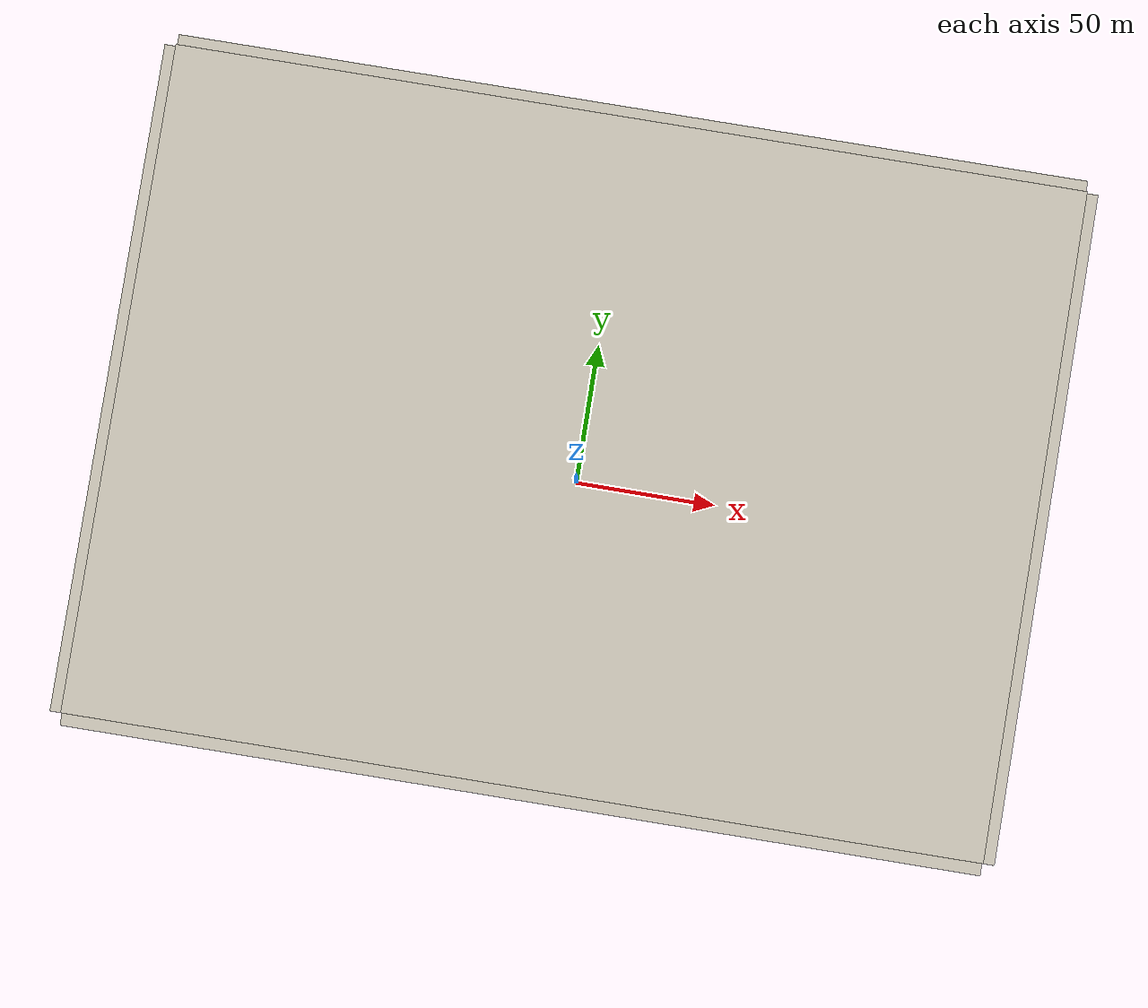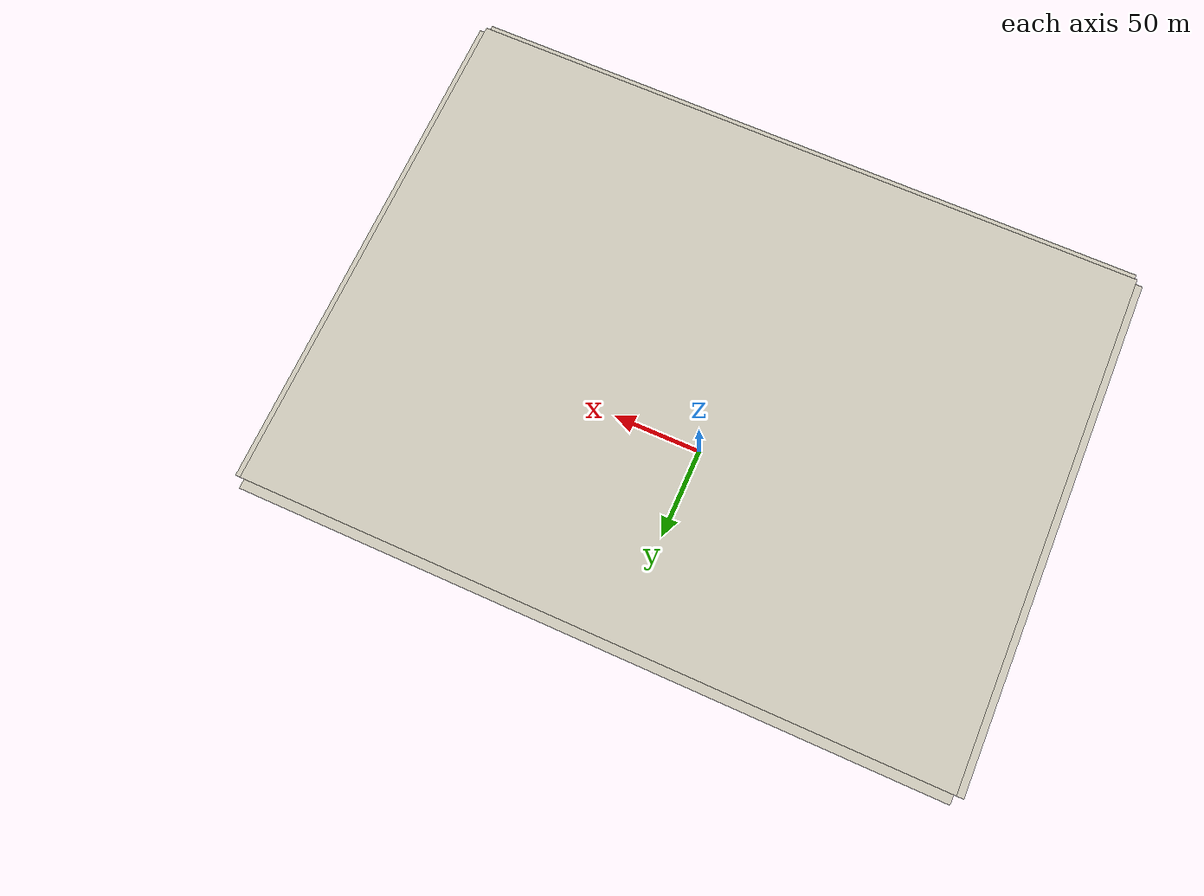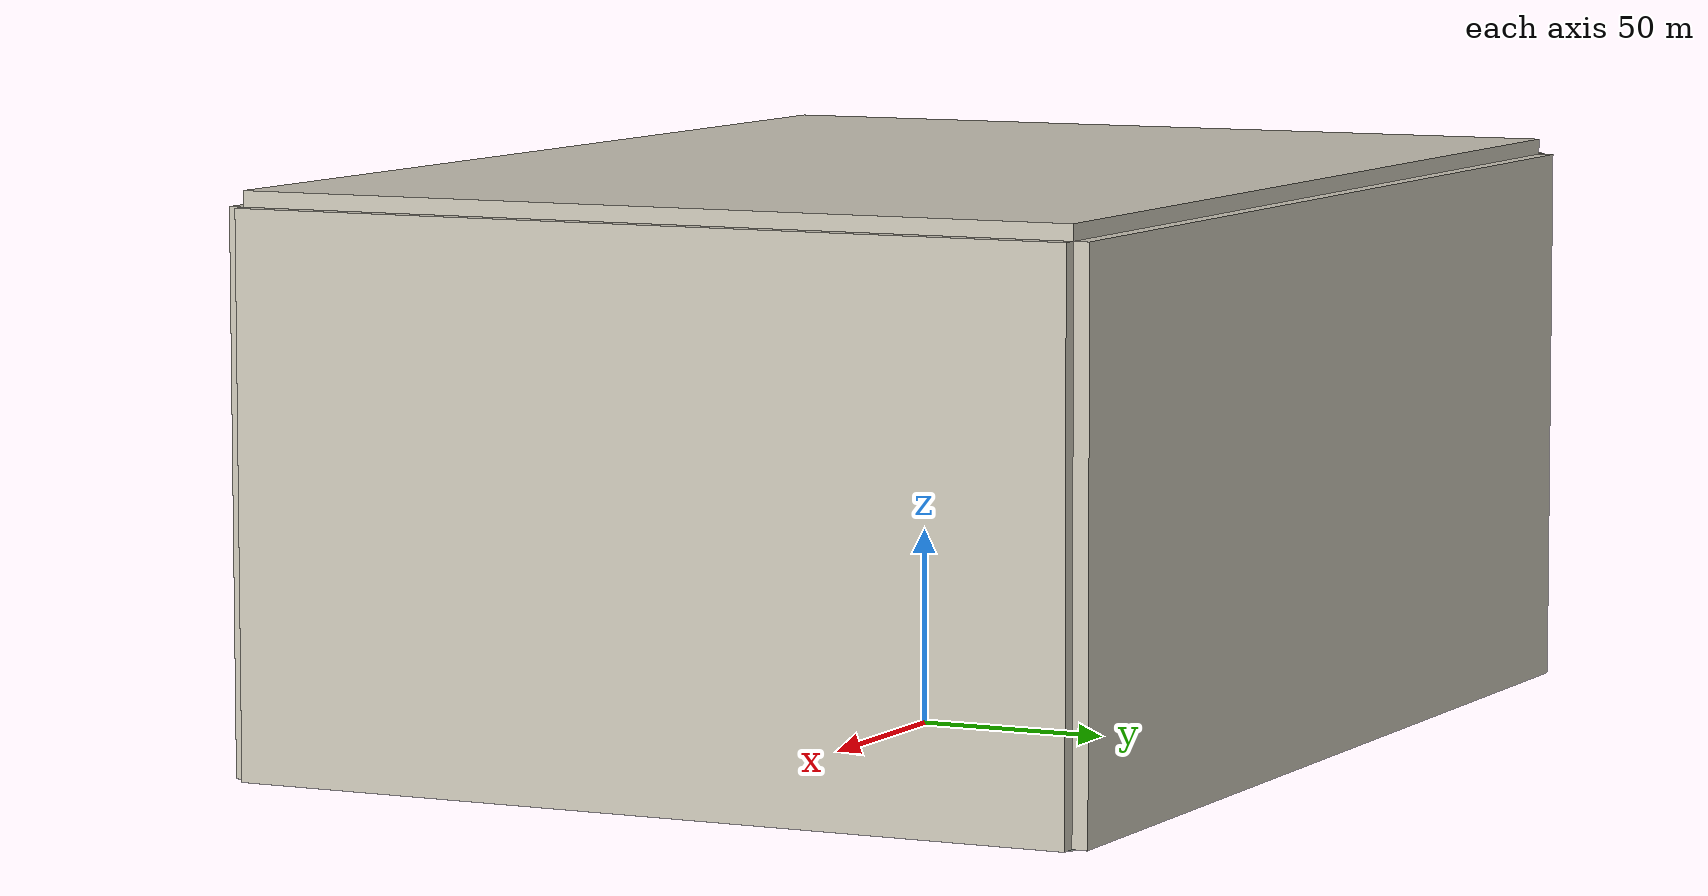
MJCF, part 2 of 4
<mesh name="fly/detail_surface_l_haltere" vertex="-0.0787910831 0.0567458774 0.0151698632 -0.0766894664 0.28166335 0.00383532233 -0.0761280535 0.271184312 -0.0144422074 -0.07580292 0.0579893313 0.00117221418 -0.0752913038 0.0481152674 0.027301925 -0.0744110075 0.0396011637 0.0114595059 -0.0742698758 0.278419873 -0.0276732098 -0.0742147749 0.298660801 -0.0175667901 -0.0737284863 0.047336529 0.0320126746 -0.0735021094 0.0469104125 0.0323833628 -0.0732725603 0.046225894 0.0324458924 -0.0731686305 0.0459217663 0.0328998394 -0.0730191241 0.0465347257 0.0327724483 -0.0729785024 0.0470190353 0.0319818937 -0.0726673024 0.0463482356 0.0330066287 -0.0723213088 0.311419979 -0.0242051356 -0.0718033625 0.0387487198 0.00695400331 -0.0716226568 0.0459158873 0.0339161707 -0.0710270542 0.0455060508 0.0338391837 -0.0707636864 0.248151598 0.0120596296 -0.0707394211 0.0460633855 0.0350033988 -0.0706263745 0.267702126 0.0242394381 -0.0702200559 0.28808348 0.0434788271 -0.0696437128 0.0443880781 0.0297415882 -0.0696257193 0.0526318072 0.0361384264 -0.0695816852 0.0452682507 0.0350902883 -0.0695086201 0.0446569939 0.0356598539 -0.0693756156 0.0455094669 0.0356344972 -0.069348971 0.033106855 0.00458448449 -0.0691618989 0.307249575 0.0175385612 -0.0691069072 0.237373562 -0.00805213676 -0.0689952431 0.0452609092 0.0358864381 -0.0687676802 0.0461293348 0.0351898416 -0.0686334679 0.0662696111 -0.0156637307 -0.0684117113 0.0455816844 0.0364677835 -0.067848785 0.0460436531 0.0365627202 -0.0678224169 0.254381011 -0.0365768137 -0.0674800103 0.0457511305 0.0368201509 -0.0674089169 0.332181866 -0.0239126675 -0.0671702001 0.310480042 0.0381362916 -0.0667879649 0.0481893476 -0.0146645052 -0.0664284089 0.322702661 -0.0369815061 -0.0659750294 0.278976717 0.054846776 -0.0658878125 0.0758935421 0.0109320554 -0.0651817172 0.0343727843 -0.000311273027 -0.0647925044 0.074384101 -0.00154450254 -0.0631412477 0.330226525 0.000704176216 -0.0623176165 0.322107779 0.033247321 -0.0622532898 0.0225678468 0.0233379287 -0.0619955827 0.0306428228 -0.000880161849 -0.0619790881 0.0308595154 -0.00060387913 -0.0617353362 0.0674524053 0.0252559621 -0.0615136451 0.295820733 0.0666721899 -0.0613381999 0.223168696 0.0268923559 -0.0610498464 0.227955679 -0.0254945335 -0.0609621929 0.344003696 0.0105099061 -0.0604432789 0.293589925 -0.0505428579 -0.0603202097 0.243517308 0.0483192525 -0.0594014891 0.0281187422 -9.44563965e-05 -0.0590732088 0.0284167436 -0.000365958783 -0.0582672146 0.0444906982 0.0424688806 -0.057776102 0.0879467188 0.00584308145 -0.057205194 0.335055141 0.0392211477 -0.0571955788 0.0318040584 -0.000867286758 -0.0568746509 0.0222119725 0.0281350876 -0.0561287707 0.209500926 0.00763210392 -0.0558787578 0.0250572084 0.0025886261 -0.0557863132 0.0250772828 0.00231373679 -0.0555414481 0.223920302 0.0467152386 -0.0555069382 0.0251736237 0.00234473237 -0.0550155055 0.349700887 -0.0174290199 -0.0548040844 0.0631477524 -0.0236887754 -0.053915257 0.114824616 0.00169198825 -0.0539003704 0.333747128 -0.0494583619 -0.0537743763 0.0933304837 0.0234133622 -0.0537240558 0.288176147 0.0789844562 -0.0536218249 0.0236869128 0.0043966902 -0.0535271392 0.345226465 -0.0408132764 -0.0535194376 0.234549443 -0.0464825898 -0.0530542711 0.12309631 0.0144222731 -0.0522822156 0.0509674537 0.0422767334 -0.052269108 0.313415803 0.0678746583 -0.0513329978 0.302240282 -0.0541823283 -0.0512401493 0.270924385 0.0797557004 -0.0511539547 0.0124127137 0.0250123612 -0.050886043 0.0215629934 0.000381684657 -0.050622064 0.0219137673 0.00093921409 -0.0506093966 0.0217692232 0.000642027544 -0.0505774042 0.0215212731 0.000228707648 -0.0503923766 0.0216892386 0.00154743338 -0.0501652503 0.0210861272 -0.000486320801 -0.0498741174 0.0209514419 -0.000516754255 -0.0498671834 0.0210479357 -0.000171073481 -0.0494088708 0.0412121772 -0.0186248526 -0.0486274112 0.246935728 0.0678777069 -0.0485978271 0.0236734522 -0.00415931163 -0.0481403258 0.344771222 0.0314490644 -0.0480177514 0.0738692615 -0.0180943953 -0.04767672 0.189224287 0.0244850817 -0.0476046589 0.15169922 0.00749322226 -0.047572812 0.331692427 0.0531804508 -0.0472367537 0.0119412889 0.0164403664 -0.0468933504 0.0190276642 -0.00426102952 -0.0468431281 0.217179506 -0.0338747777 -0.0463887081 0.12222954 0.0266661009 -0.0463537144 0.0823269002 -0.00648689456 -0.0462972057 0.00887826354 0.0292032619 -0.0457904353 0.195454879 0.00183024463 -0.0454732835 0.0238355042 0.046263016 -0.0452324202 0.0632568117 -0.0217934503 -0.0450353691 0.160708893 0.0179261297 -0.0448899082 0.163803386 0.0273784208 -0.0447775747 0.127598658 -0.0153356668 -0.0443285498 0.264736678 -0.0600095409 -0.0432795314 0.14763487 0.0344017753 -0.0430979599 0.0820731439 -0.0246350555 -0.0427827144 0.287355768 0.0844223468 -0.0426582556 0.355293247 -0.023610688 -0.0417566625 0.0181194137 -0.00818455192 -0.041743795 0.0180887746 -0.00826424548 -0.0417096453 0.0694756236 0.0396050164 -0.0414736787 0.0145633039 -0.00334984111 -0.0407747902 0.017767461 -0.00891935815 -0.040502855 0.0895339035 0.0285184815 -0.0404942111 0.355615775 0.0136199023 -0.040473049 0.128455518 0.0344782893 -0.040410996 0.0173827957 -0.0090099893 -0.0403597733 0.0172814198 -0.00914394695 -0.0402419282 0.035775618 0.0516277396 -0.0397265685 0.236779582 -0.0552790043 -0.0396878713 0.0165728507 -0.00935341814 -0.0396656142 0.0171472366 -0.00959525823 -0.0395317184 0.109215893 -0.0181684227 -0.0393904375 0.0165042384 -0.00952836854 -0.0393341652 0.0163873065 -0.00981051562 -0.0387833024 0.0292558088 0.0520396279 -0.0387327709 0.0292951863 0.0519740097 -0.0386477659 0.191366125 0.0402436635 -0.0381644095 0.00727375391 0.00367524262 -0.0380427846 0.0272995658 0.0522256742 -0.0376396893 0.0435701404 -0.0212538216 -0.0376175703 0.015286294 -0.0111200543 -0.0370899252 -0.00380774145 0.0318461534 -0.0368134897 -0.00347818423 0.0337510901 -0.0367379944 0.0106325542 -0.00798017118 -0.0366452841 0.077736906 0.0307179616 -0.0366439454 -0.00836222898 0.0323400454 -0.0366288841 0.0142906738 -0.0116826413 -0.0366175154 -0.00732301123 0.0324663997 -0.0365155029 0.249777717 0.075154785 -0.0364889602 0.0235771349 0.0509920392 -0.0364816624 0.0145105096 -0.0114397526 -0.0364378211 -0.00766394805 0.03205541 -0.0364307671 0.0236226751 0.0509153178 -0.0364079569 0.0225483273 0.0502885996 -0.0363774125 0.01438238 -0.0116995125 -0.0363465333 -0.00874237594 0.0321199186 -0.0363383879 -0.0071313043 0.0323146596 -0.0360924932 0.0147159753 -0.0118688513 -0.0360540034 -0.00851674122 0.0318819875 -0.035921119 0.0182041804 0.0476513596 -0.0358146499 0.0142389563 -0.0116972769 -0.0357129647 0.0141642031 -0.0119689321 -0.0357065364 0.0229461421 0.0508279045 -0.0356659984 -0.000898354699 0.0361271086 -0.0355970515 -0.00857536361 0.031827265 -0.0355799821 0.022133001 0.0504385898 -0.035562105 0.021754171 0.0501616742 -0.0355413795 -0.000832725561 0.0358338875 -0.0355216253 0.0221786213 0.0503636256 -0.0353248324 0.162048396 0.00496549092 -0.035247358 -0.000733226784 0.036581092 -0.0352007082 -0.00310834048 0.00652446988 -0.0351698691 0.0218927926 0.0503874398 -0.0351129311 0.0214008942 0.0501829563 -0.035106983 0.0136570916 0.0464173499 -0.0350481023 0.0214512947 0.05010108 -0.0349967195 0.020454263 0.0495322311 -0.0347895002 0.0126724944 0.0490175807 -0.0347877358 0.0126006225 0.0482796349 -0.0347669993 0.015240551 0.0488308979 -0.034657045 0.0206391232 0.049945229 -0.034640354 0.0153378678 0.0487030557 -0.0346077395 0.0128297497 0.0487560865 -0.0345899425 0.0206912118 0.0498613845 -0.0345623084 0.0192970219 0.04946029 -0.0345438202 0.020208794 0.0498590452 -0.0345177905 0.020809257 0.049989023 -0.0344907712 0.0193524647 0.0493695843 -0.0344877117 0.0137828565 0.0488756559 -0.0344708678 0.0121981748 0.0490516031 -0.0343360807 0.0188004306 0.0494162705 -0.0342111671 0.0336927878 0.0513458508 -0.0341463747 0.0120699142 0.0485284909 -0.0340077167 -0.000419465607 0.0370403504 -0.0339880862 0.0122081865 0.048267877 -0.0339587095 -0.000369588918 0.0369596819 -0.033667151 -0.000137114739 0.0373660296 -0.0336113662 0.0117857735 0.0481370043 -0.0335489713 0.0115371322 0.0480331328 -0.033477947 0.0116247493 0.0477867325 -0.0334711731 0.011034901 0.0477359717 -0.0332877935 0.0114167797 0.0480386698 -0.0331702577 -0.000243401928 0.0375313793 -0.0331293013 -0.000205530583 0.0374713964 -0.0327698144 0.0104145965 0.0482487339 -0.0326102709 0.0105647432 0.0479488081 -0.0325424626 0.188816368 0.043332413 -0.032525204 0.0101192218 0.0476592068 -0.0322109772 0.0068296813 0.0424145182 -0.0321938678 0.0276583633 -0.0154456793 -0.0321267871 0.00975505282 0.048046677 -0.0320822401 0.158046096 0.0326252703 -0.0320030194 0.00985881525 0.0477996109 -0.0319275168 0.146607461 0.0375306408 -0.0318450657 0.0142355148 -0.0132805653 -0.0318180209 0.00912552969 0.0471621279 -0.0316904443 0.21782062 0.0598595652 -0.0315392863 -0.00802357681 0.0275473594 -0.0314330937 0.00909974369 0.0481316056 -0.0311619588 0.00834906132 0.0475467641 -0.0310136602 0.107643689 0.0342109088 -0.0310046416 0.00847601223 0.0472279316 -0.0303685902 0.320098276 0.0656078264 -0.0303162979 0.00505554772 0.044410499 -0.0303125944 0.00352336178 0.0426086372 -0.0302318185 0.00737382834 0.0462568096 -0.0302056196 0.00540787869 0.0447631792 -0.0300408956 0.00501132445 0.0446455415 -0.029826886 9.20925203e-05 0.037160753 -0.0296433136 0.0129443679 0.0479152768 -0.0295986483 -0.0094241841 0.0243933937 -0.0291941142 0.00117548279 0.0399114724 -0.029072824 0.0669825022 -0.0335626137 -0.0290196222 -0.0103097263 0.0241934158 -0.028964776 -0.0099761528 0.0244451421 -0.028960676 0.0687027277 0.0445149781 -0.0288649499 0.13037087 -0.0169767518 -0.0282268302 0.351499562 0.0241951511 -0.0278841035 0.204516458 -0.0303049437 -0.027774644 0.34000061 -0.0427564846 -0.0274785125 -0.00998783071 0.0226179072 -0.0263332986 -0.0110229957 0.0213795774 -0.025996238 0.0856104671 -0.0277469208 -0.0257334468 0.294945989 -0.0598472616 -0.0255414743 -0.0106723892 0.0208653109 -0.0254909774 -0.0103473722 0.0210740618 -0.025198573 0.13436006 0.0341284504 -0.0250993107 0.0597748513 -0.0292000168 -0.0247077933 0.306046015 0.077204495 -0.0246569161 0.0793496292 0.031080006 -0.0243302038 0.269181299 0.0836185136 -0.0241615071 -0.0107667374 0.02000122 -0.024131281 0.00723804305 -0.014908328 -0.0240283116 0.185266967 -0.0137073694 -0.0237524837 0.2902126 0.0833616359 -0.0236292835 0.318867678 -0.0534775172 -0.0225680451 -0.0109404873 0.0187447258 -0.0224083997 -0.0108380345 0.0183657448 -0.0222390663 0.0429194297 -0.0325072397 -0.0215001492 -0.0109062612 0.0181868527 -0.0214738611 -0.00410537177 0.0289220097 -0.0214696011 -0.0112122079 0.0177789479 -0.0213650237 -0.0111230047 0.0175544792 -0.0207015219 -0.0120649511 0.0171118081 -0.0198017333 -0.0124384042 0.0163158147 -0.0197422123 -0.0123164155 0.0106987391 -0.0196137626 -0.0123098816 0.0159486281 -0.0196116416 -0.0128777774 0.0161469325 -0.0187277747 -0.0123978189 0.0157400864 -0.0187112983 -0.0127797266 0.0151947579 -0.0186842644 -0.013293904 0.0148347426 -0.0185598074 -0.0126453542 0.0149486896 -0.0183521897 0.170867745 -0.00961958904 -0.017593391 -0.00688145565 0.0175603291 -0.0175447421 -0.0128611373 0.0142035024 -0.0174144225 -0.0136501785 0.0129941036 -0.0172668369 -0.0141749351 0.0126420646 -0.0172320961 0.0229139368 -0.02972931 -0.0172150012 -0.0134886086 0.0126561408 -0.017192986 0.353689451 0.0014761473 -0.0170796411 0.125509381 0.0345837361 -0.0169826126 -0.013746876 0.0126624827 -0.0169455852 0.154330613 0.0267143714 -0.0165761612 0.0581660461 0.0468684448 -0.0164891208 0.0787694225 0.0276468691 -0.016335789 0.00961671412 -0.0181283649 -0.0158120765 0.154190551 -0.000706041703 -0.0157583399 0.25857173 -0.0602406071 -0.0154840291 0.210334212 0.0593403602 -0.0152535677 -0.00504755099 -0.0129520877 -0.0148542904 0.349808048 -0.0127761223 -0.0138069499 0.0538489403 -0.0303256384 -0.0134590364 -0.0123839218 0.00270019086 -0.0129514192 0.0747723971 0.0128778292 -0.0127315925 0.245848933 0.0746524529 -0.0108710738 0.105837476 0.0301923774 -0.0100418374 0.0128244292 -0.0253294747 -0.0099673025 0.0241528378 0.0453435205 -0.00875376736 0.112749658 -0.0132747837 -0.00825426559 0.0279745036 -0.0289887503 -0.00815449494 0.132486486 -0.00378768073 -0.00774417549 0.0361367238 0.0431613989 -0.00704957756 0.177171212 0.0453840876 -0.00672815167 0.0668489738 0.0346518682 -0.00512642691 0.0694451082 0.0110418268 -0.00507550385 0.213171545 -0.0381111713 -0.00493480684 0.338180718 0.0329152135 -0.00469833185 0.0920784514 0.0187488786 -0.00464536606 0.27827287 0.0785982265 -0.00438497591 0.304983143 0.0666603737 -0.00368236715 0.237635846 -0.0512649422 -0.00343220267 0.291653821 0.0719462332 -0.00239302994 0.290119351 -0.05144225 -0.00211590964 0.330262497 -0.0287643015 -0.000963834964 0.160996526 -0.00429778129 -0.000400975239 0.00161703849 0.0147720621 -0.000323123459 0.319701707 0.0504194577 3.17066053e-05 0.0616335528 0.00305211734 0.000409445761 0.128424857 0.0207249377 0.000724815379 0.058831607 -0.0131142824 0.00159166063 0.0800589551 -0.0195813136 0.00168901124 0.0336096236 0.0295972768 0.0022698523 -0.00135256448 -0.0107366277 0.00235511334 0.166181548 0.0270959408 0.00251846495 0.0537947308 0.0280932472 0.00331153228 0.130016488 -0.00891814216 0.00408565347 0.254787417 0.0794708758 0.00458096019 0.227674172 0.0652605886 0.0047471608 0.191806146 -0.0173604731 0.00730312513 0.334229029 0.0163570185 0.00779632501 0.147947372 0.00619724642 0.00796387394 0.104809034 -0.0134739648 0.00842251757 0.0794340085 0.0121316434 0.00938611083 0.104199455 0.018344288 0.0107694359 0.0536312255 -0.0101260903 0.0112282505 0.00745114903 -0.0082747174 0.0112788821 0.321958301 -0.0158241037 0.0113758224 0.164837227 0.000397102497 0.0114726818 0.145038779 0.0175194127 0.0115872199 0.0398077864 -0.0185429617 0.0120287086 0.161370161 0.017116352 0.0125242432 0.290927739 -0.037610931 0.0132146006 0.287009723 0.0647878114 0.0134330321 0.255850173 -0.0450133703 0.0136576746 0.276629231 0.0673574104 0.0136867839 0.0773666397 -0.00522502842 0.0142454346 0.0887679853 -0.00122817175 0.015693342 0.209788777 0.0505507051 0.0163921504 0.0544050417 0.0159854408 0.0168111001 0.0574679361 0.00832777823 0.0171886131 0.136752395 0.00033122447 0.0171983338 0.0282360525 0.00870583426 0.0174500619 0.251066609 0.0723799021 0.0176307276 0.304556888 0.0433467503 0.0187548867 0.265360926 0.0724736019 0.0188275462 0.225796073 -0.0275014627 0.0206668174 0.121143559 0.0124036906 0.0218219157 0.192291802 0.0348977155 0.0220210277 0.192707579 -7.60451684e-05 0.0227297096 0.309682247 0.00327139605 0.0243292652 0.185125391 0.0137725674 0.0266990646 0.281024812 -0.0191251202 0.0281962803 0.250148325 -0.023601353 0.0283320369 0.26522766 0.0544404866 0.0287899729 0.238778055 0.0575451704 0.0316492078 0.216845394 0.0397008007 0.0320493127 0.285277114 0.00572228237 0.0340035549 0.2746151 0.0321713851 0.0359464757 0.221852941 0.0100332882 0.0369950103 0.244392228 0.0400798926 0.0376987482 0.255557155 0.0181679261" face="353 295 328 289 348 328 289 328 295 303 348 289 289 207 303 324 283 341 283 324 303 303 207 212 111 212 207 365 370 364 364 368 343 370 371 364 368 364 371 358 361 366 348 365 328 348 366 365 366 369 365 303 358 348 369 363 371 341 361 358 341 338 361 361 338 359 315 359 338 315 329 359 361 359 369 329 356 359 365 369 370 371 363 362 295 327 251 83 149 251 116 83 251 251 255 116 83 94 149 149 94 217 22 42 52 57 94 83 68 217 94 68 53 137 57 53 68 57 42 19 42 21 19 57 19 53 98 111 207 107 98 53 107 110 98 53 19 65 289 149 217 312 255 309 343 354 312 249 116 255 317 223 310 330 307 317 223 100 81 222 226 220 226 219 220 238 100 223 75 116 223 116 249 223 39 81 47 100 62 81 317 307 223 307 238 223 100 238 96 327 309 251 309 255 251 368 367 360 29 42 22 21 42 29 307 330 280 291 280 330 330 354 360 337 360 362 337 330 360 240 291 314 256 240 314 96 62 100 238 280 124 70 55 124 47 29 39 46 29 47 70 46 55 7 29 38 240 117 291 117 77 70 70 77 38 77 73 38 311 356 306 129 311 306 19 30 65 54 2 36 54 65 30 65 54 103 78 103 54 56 113 78 344 342 362 256 314 313 244 256 313 313 344 288 82 244 113 113 244 288 21 1 2 41 15 38 82 56 41 78 36 56 82 41 73 56 82 113 230 302 192 192 302 284 322 325 302 325 322 349 333 347 357 335 318 350 346 347 333 318 320 346 120 80 236 51 24 80 0 24 51 281 221 296 247 125 221 339 283 319 308 319 296 339 319 334 333 357 334 111 104 114 104 125 114 104 79 74 283 214 247 114 125 214 111 99 79 170 99 110 112 72 99 287 237 170 112 170 237 236 304 285 250 285 296 285 294 308 123 250 221 145 80 120 236 285 250 334 308 333 332 347 346 72 61 79 43 51 74 105 61 72 237 301 299 99 72 79 72 132 105 112 237 243 74 51 145 321 243 237 222 209 220 226 230 219 230 298 302 230 232 298 173 169 166 163 169 173 191 188 185 187 176 174 177 184 181 176 177 174 167 176 174 173 176 187 169 167 166 154 167 169 177 188 185 186 177 185 192 136 135 139 108 150 153 154 150 108 154 153 108 136 135 128 108 135 189 175 178 191 160 180 160 182 180 201 206 205 206 208 205 206 201 208 202 201 205 208 213 211 198 195 193 175 199 198 195 175 193 195 179 175 179 193 190 200 175 201 175 216 208 175 209 216 213 216 211 213 208 216 198 200 202 230 202 206 200 201 199 183 175 179 183 179 178 189 182 180 191 182 189 177 160 188 163 153 150 154 108 177 191 230 187 108 106 160 106 175 160 228 232 224 224 209 225 224 232 227 209 224 227 204 197 203 225 197 204 197 209 196 209 197 225 168 171 164 143 168 164 171 196 194 196 171 229 142 209 175 216 222 220 219 216 220 222 216 209 232 230 226 266 241 218 274 242 252 231 241 235 231 235 234 266 218 172 274 263 262 257 274 252 252 266 258 260 258 257 275 274 269 275 279 282 282 279 276 269 267 265 274 267 269 272 266 271 275 272 270 266 275 271 275 266 276 266 252 245 266 245 246 266 246 241 157 142 152 159 218 156 218 159 152 172 218 106 316 322 298 322 352 349 352 322 316 138 172 106 64 84 106 335 350 340 274 316 261 293 323 316 323 336 316 144 253 138 172 253 290 286 323 290 24 35 37 34 20 27 20 18 32 27 25 32 20 32 25 27 32 31 24 11 17 14 13 18 13 8 9 8 4 9 18 13 17 14 11 24 24 8 13 9 12 24 34 32 37 32 35 37 13 4 32 23 48 64 5 23 4 23 5 48 44 28 16 37 23 60 13 32 17 32 23 35 76 89 121 76 85 89 95 76 63 76 95 86 58 76 48 69 76 67 69 67 66 44 40 63 71 109 93 248 233 321 248 292 259 259 292 340 259 340 300 320 335 292 3 0 43 71 40 33 115 105 132 115 243 233 132 243 115 215 144 162 215 162 161 131 130 127 131 127 126 131 133 134 215 134 133 131 215 133 121 141 147 141 215 158 158 155 151 141 151 155 215 141 134 215 161 158 158 161 162 95 102 92 102 91 92 102 121 91 95 90 88 122 121 119 122 119 118 95 122 118 119 95 118 122 126 127 286 210 278 140 278 210 93 140 210 259 300 278 140 259 278 76 87 88 95 88 87 331 341 339 331 338 341 326 331 351 315 338 331 287 315 331 315 287 273 273 287 170 254 315 273 299 326 332 254 170 107 239 107 103 107 239 254 306 329 239 103 129 239 306 239 129 289 217 207 303 212 283 114 212 111 303 324 358 353 365 355 365 364 355 353 355 327 355 309 327 364 345 355 364 343 345 355 345 312 328 365 353 353 327 295 368 354 343 367 368 371 348 358 366 370 369 371 371 362 367 366 361 369 358 324 341 359 363 369 329 306 356 359 356 363 83 116 75 81 52 75 295 251 149 289 295 149 75 42 83 83 42 57 75 52 42 94 57 68 217 137 207 217 68 137 98 137 53 207 137 98 111 98 110 65 107 53 312 354 310 345 343 312 249 312 310 312 249 255 310 354 317 249 310 223 354 330 317 75 223 81 39 52 81 62 47 81 280 238 307 354 368 360 52 39 22 362 360 367 291 330 337 342 314 337 314 291 337 96 55 62 96 238 124 96 124 55 124 117 70 29 22 39 62 55 47 21 29 1 55 46 47 46 38 29 73 41 38 70 38 46 280 117 124 291 117 280 117 240 77 240 73 77 21 2 19 65 103 107 356 311 344 19 2 30 30 2 54 54 36 78 78 129 103 129 113 288 129 288 311 113 129 78 363 344 362 362 342 337 313 314 342 344 313 342 363 356 344 311 288 344 313 288 244 29 7 1 1 7 2 7 6 2 38 15 7 41 56 15 56 6 7 15 56 7 2 6 36 56 36 6 82 73 244 240 256 73 73 256 244 284 304 236 284 302 304 192 284 236 325 305 304 349 305 325 302 325 304 333 305 318 305 350 318 333 318 346 349 350 305 80 192 236 192 80 128 128 80 60 80 24 60 221 281 247 247 281 319 339 341 283 357 339 334 281 296 319 125 104 221 221 104 74 247 319 283 214 283 212 214 125 247 111 110 99 111 79 104 99 170 112 214 212 114 236 250 145 236 145 120 145 250 123 296 221 250 305 285 304 294 285 305 145 51 80 145 123 74 296 285 308 319 308 334 333 308 305 308 294 305 346 321 332 332 321 299 321 237 299 79 61 74 61 45 43 61 43 74 132 112 243 72 112 132 221 74 123 226 220 209 154 169 166 163 166 169 187 230 163 163 173 187 187 188 191 187 181 184 184 186 181 167 154 177 173 174 176 184 186 187 192 135 139 128 136 192 128 135 136 163 192 139 136 108 139 108 153 150 139 150 153 178 175 183 198 202 230 189 178 183 182 160 175 191 189 198 191 180 182 198 193 175 193 179 195 216 219 211 201 175 208 198 199 200 189 193 195 190 193 189 190 178 179 189 195 198 189 180 175 227 226 209 139 153 163 163 150 154 177 108 160 192 163 230 108 64 106 226 227 232 224 227 228 228 227 225 298 232 261 261 316 298 232 229 261 229 143 261 196 194 197 209 194 196 225 204 203 171 168 143 106 218 142 225 203 232 171 143 229 198 230 191 142 168 209 242 274 261 246 242 245 218 241 231 242 246 252 246 245 252 235 241 234 261 234 241 235 234 261 241 245 242 218 235 261 231 234 218 218 234 235 274 262 264 262 263 260 260 263 274 252 258 257 257 258 274 274 258 260 260 257 266 282 276 277 265 267 274 266 272 270 269 270 272 269 265 268 266 270 268 268 270 269 264 265 274 275 270 271 269 272 275 146 159 156 146 165 152 165 148 152 143 157 165 142 218 152 156 218 165 143 148 157 157 152 148 302 298 322 165 218 143 316 336 352 138 106 84 101 138 84 352 350 349 352 340 350 318 335 320 340 352 336 300 340 336 335 340 292 275 282 274 274 282 293 293 316 274 266 172 293 172 290 293 172 138 253 144 215 253 253 286 290 297 323 286 286 253 215 293 290 323 297 300 336 323 297 336 297 278 300 60 108 128 34 35 24 24 37 60 32 34 31 32 18 17 26 18 25 18 20 25 26 27 20 20 11 26 34 27 31 26 31 27 12 10 13 14 12 11 11 10 18 24 12 14 24 13 9 24 4 8 24 20 34 20 17 11 32 4 23 60 23 64 5 28 48 5 16 28 24 0 4 4 0 5 0 3 5 3 16 5 48 101 84 48 121 101 48 84 64 121 48 76 89 86 87 101 121 138 28 58 48 76 69 59 59 67 58 58 67 66 58 66 76 59 63 76 76 66 67 58 28 44 50 44 63 63 49 50 50 58 49 44 49 58 63 40 93 140 93 109 320 321 346 320 248 321 233 243 321 292 248 320 109 233 140 140 233 248 248 259 140 233 109 115 51 43 0 45 3 43 45 33 3 45 105 33 97 71 33 97 33 105 3 40 16 33 40 3 40 44 16 71 97 109 71 93 40 115 97 105 97 115 109 162 144 161 121 161 144 121 162 161 133 130 134 141 133 134 130 133 141 130 126 127 131 134 130 141 158 151 147 141 155 121 158 162 121 130 141 121 151 155 121 126 130 121 127 126 92 90 95 89 88 90 76 88 85 92 91 121 121 118 119 90 91 89 89 91 92 95 210 215 119 102 95 102 118 121 102 119 118 122 95 215 122 127 121 215 210 286 297 286 278 63 93 95 93 210 95 85 88 87 89 87 88 89 92 121 105 45 61 138 121 144 277 293 282 351 331 339 351 339 357 326 301 331 315 239 329 287 331 301 301 237 287 347 351 357 347 332 351 332 326 351 326 299 301 170 254 273 239 315 254 107 170 110 312 309 355 222 220 226 186 185 188 186 188 187 154 166 163 187 174 177 187 177 181 173 166 167 173 167 174 184 177 186 177 176 167 190 189 178 189 183 178 135 136 139 219 230 213 219 213 211 180 182 175 230 205 211 205 208 211 230 211 213 202 205 206 206 205 230 160 191 185 160 185 188 201 202 199 200 199 175 200 199 202 197 194 229 197 229 203 232 228 225 225 227 224 229 194 196 204 203 229 209 168 164 209 164 171 209 171 194 164 168 142 164 142 143 204 229 232 204 232 203 175 106 142 263 266 264 263 264 262 218 261 143 242 261 241 246 245 241 279 293 277 279 277 276 260 266 262 266 257 258 263 262 266 275 276 279 267 266 268 267 268 265 270 272 271 266 267 265 266 265 264 266 293 279 266 279 276 142 157 148 142 148 143 146 152 159 159 165 146 157 148 165 25 27 31 25 31 26 159 156 165 108 60 64 34 37 35 26 11 18 10 12 14 10 14 18 24 17 20 14 12 13 9 4 10 9 10 12 11 12 10 10 4 13 85 87 86 85 86 89 37 35 23 50 49 59 50 59 58 86 87 76 87 86 95 59 66 67 69 66 59 50 49 44 59 49 63 147 155 151 147 151 121 122 215 131 122 131 126 121 155 158 92 91 90" smoothnormal="true" normal="-0.903597698 0.363958911 0.225931651 -0.988174584 0.0698132733 0.136517759 -0.985038177 -0.161037614 -0.0613732532 -0.954483738 0.128415404 -0.269203041 -0.919991724 -0.276200432 0.278080112 -0.911208785 -0.407410735 0.0609511549 -0.923574208 0.0307482317 -0.38218481 -0.983886076 0.159325418 -0.0811393934 -0.840976018 0.257436752 0.475905092 -0.943919069 0.155038235 0.291513186 0.109296854 -0.854147684 -0.508415118 -0.693093201 -0.232228405 0.682416136 -0.625516749 -0.112173058 0.772104916 0.0809719917 -0.945139533 -0.31647243 -0.95412689 -0.116787372 -0.275685667 -0.946553435 0.0491274517 -0.318783763 -0.857527056 -0.335606757 -0.389891592 -0.677938528 -0.128067288 0.723877146 0.464303401 -0.519809206 -0.717091864 -0.96384295 -0.219871072 0.150543945 -0.61863491 -0.071210917 0.782444793 -0.983455674 -0.0237205597 0.179589177 -0.985018514 0.0501499253 0.16499549 -0.727281455 -0.49010646 0.480476163 -0.54295917 0.519540344 0.659752356 0.597346552 0.0191475503 -0.801754619 -0.456556041 -0.748356758 0.481163948 -0.329123865 -0.435498457 0.837865487 -0.702754515 -0.666438794 -0.248988806 -0.9757851 0.182260304 0.120932298 -0.941903265 -0.329217753 -0.0665876227 0.637981789 -0.634297938 -0.436629549 -0.412717585 -0.906120728 0.092786963 -0.666964195 0.489140397 -0.562050206 -0.458251976 -0.12973744 0.879302748 -0.561866956 -0.431122414 0.706002116 -0.866330064 -0.199455302 -0.457918992 -0.501646841 -0.535308754 0.67955499 -0.926773227 0.37490287 -0.023221192 -0.910984124 0.324489812 0.254586503 -0.653698859 -0.399083227 -0.642969968 -0.815011409 0.164611415 -0.555571314 -0.950196342 -0.131282928 0.282651208 -0.845310004 0.511590671 0.154032407 -0.592296963 -0.554903709 -0.584179922 -0.692440137 0.65230692 -0.308256937 -0.940911782 0.327307433 0.0869187151 -0.937454926 0.29412588 0.186194064 -0.737850492 -0.674583711 -0.0226598493 -0.199488888 -0.284230777 -0.937772387 -0.0456540732 0.0776588387 -0.99593414 -0.51155822 0.486596133 0.708189516 -0.886173414 0.205812064 0.415136213 -0.912804566 -0.367702713 0.177714769 -0.853920793 -0.446553836 -0.26722453 -0.80454994 0.57956322 0.129637448 -0.772739974 -0.00712103317 -0.634682774 -0.90455185 -0.233044135 0.357038349 -0.514997547 -0.804693112 -0.295375221 0.308520031 -0.310235151 -0.89920495 -0.629079437 -0.2454945 0.737557803 -0.935756217 0.272160789 -0.22425166 -0.777492482 0.503632205 0.376643123 -0.470487896 -0.633725454 -0.614030283 -0.70513229 -0.44482112 0.552197994 -0.861866686 -0.498709264 -0.0920591432 -0.660988652 -0.746400406 0.0773332784 -0.0372691422 -0.733995519 -0.678130953 -0.709299526 -0.424414893 0.562819848 0.614852378 -0.0272800697 -0.788170255 -0.69569019 0.718031491 -0.0211172579 -0.250804389 -0.00337900352 -0.96803189 -0.908586063 0.0624684013 -0.41300008 -0.304102879 0.327356561 -0.894627923 -0.711626673 0.161498504 0.683743893 -0.564376102 0.242908003 0.78897105 -0.601643512 -0.700605476 -0.383636615 -0.411774257 0.762112456 -0.499626426 -0.668788953 -0.286748196 -0.685927699 -0.972418881 0.13003329 0.193630742 -0.334233304 0.439895701 0.833534565 -0.621497532 0.479242042 0.619732106 -0.378080019 0.12039587 -0.917910853 -0.635847942 -0.267676787 0.723910583 -0.651965538 -0.758047811 0.0174486282 -0.350054752 -0.921772379 0.166725376 -0.802857726 -0.353210076 -0.480272958 -0.74770251 0.560234843 -0.356479842 -0.876975074 0.179605336 -0.445709145 -0.608657039 -0.792341709 -0.041607986 -0.661139058 -0.604140831 -0.444869646 -0.62193677 -0.780295223 -0.0658332581 -0.761849187 -0.606236455 -0.228173568 -0.318829151 -0.455466371 -0.831202958 -0.592750722 -0.4156064 0.689868032 -0.548935907 -0.444634159 -0.707792226 -0.339906408 0.842080289 0.418765352 -0.491858906 0.583355144 -0.646352529 -0.952883118 -0.237798967 0.188322636 -0.907337822 0.319031767 -0.273782412 -0.136146452 0.774069737 0.61828811 -0.666944808 -0.690499158 -0.279992029 -0.671175257 -0.557115542 -0.489025611 -0.577999451 -0.670171155 -0.465604185 -0.772947099 0.000216895391 0.634470436 -0.783249433 0.321983881 -0.531833345 -0.771676512 -0.594649777 0.225625803 -0.791197859 -0.459411694 -0.403666747 -0.645030994 -0.416088683 0.64094089 -0.380002153 -0.102565686 -0.919281591 -0.952714374 -0.0505099408 -0.299639895 -0.879177002 0.0280637334 0.47566819 -0.580408696 0.299457792 -0.757265327 -0.296900172 -0.051428533 -0.953522624 -0.605849237 0.120060049 0.786468236 -0.658786407 0.210526908 -0.722273418 -0.192947557 0.250736241 0.948631951 0.0481340951 0.967929059 -0.246569354 -0.524528253 -0.669781 -0.525607767 -0.625411785 -0.309781153 -0.716167394 -0.497685473 0.572180259 0.651858053 -0.683140138 -0.660379419 -0.311798934 -0.484287602 0.0345925389 -0.874224728 -0.280597747 -0.0590517379 0.958007201 -0.221220677 0.966313453 0.131528411 -0.284443562 -0.130680028 0.949744487 -0.71969445 -0.546141685 -0.428683051 -0.706219257 -0.532314241 -0.46679322 -0.360133964 0.105119168 0.92695927 -0.0868696509 -0.467848651 -0.879529024 -0.72611305 -0.545571265 -0.418463659 -0.46320315 -0.0744401995 -0.88312032 -0.779815164 0.0468874839 -0.624251451 -0.43413408 0.025055375 -0.900499766 -0.141702173 0.69664561 -0.703281869 -0.517065453 -0.0628883753 0.853632456 -0.177229162 -0.00254175933 0.984166329 -0.703754025 -0.446569153 0.552545259 -0.73806477 -0.587335825 -0.332109959 -0.176962225 -0.233731799 0.956061618 -0.470610127 -0.262796713 -0.842296857 -0.715702725 -0.338369229 -0.610963071 -0.766519145 -0.484440741 0.421622543 0.18594014 -0.70980351 0.679415367 -0.566885622 -0.683653317 -0.459629017 -0.353213152 0.453055945 0.818523537 -0.460701509 -0.287279742 0.83977644 -0.593591134 -0.726321873 -0.346563273 -0.944340113 -0.220731498 0.243924899 -0.169876627 -0.402544776 0.899499658 -0.41304928 -0.461674109 0.78501421 0.20042704 -0.976821409 -0.0751594027 -0.714839949 -0.160177927 -0.680695879 -0.362811119 -0.515795908 0.7760945 -0.405851023 -0.51441733 0.755420252 0.881531861 -0.334087228 0.333597515 -0.220417774 -0.910550933 -0.349732761 -0.222620488 -0.411032319 0.884020673 -0.440200328 -0.573872841 -0.690574858 -0.686259852 -0.113662222 -0.718420709 -0.567362175 -0.542469869 0.619537412 -0.771861977 -0.335815356 -0.539867701 -0.380828093 -0.647062559 -0.660514958 0.290356284 -0.116969943 0.949742734 -0.944445927 0.240647746 0.223853866 0.673625012 -0.162095418 0.72107865 -0.307886785 -0.5135056 0.800948017 -0.32916578 -0.505539496 0.797546053 -0.939595888 0.323718278 0.111202714 -0.296456193 -0.510289669 0.807290641 -0.517816551 0.111103341 -0.848246466 -0.140557877 -0.647002936 0.749420232 -0.662530054 -0.680081375 -0.313915994 -0.35412999 -0.498648312 0.791164844 -0.359952761 -0.500319604 0.787473367 -0.69496366 -0.422762727 0.581633207 -0.34080205 -0.501299555 0.79533183 -0.414924099 -0.499751641 0.76031986 -0.954498094 0.0712962148 0.289569058 -0.766827927 -0.605987479 -0.211551661 -0.832279589 -0.0752622787 0.549223338 -0.837309007 -0.542782101 -0.0655836733 -0.890554273 -0.224448358 0.395646334 -0.967226447 -0.252932296 0.0223216032 -0.664025658 -0.310900968 0.680007731 -0.704695686 -0.220147935 0.674491569 -0.42312951 -0.287352861 0.859296079 -0.264389239 -0.389254096 0.882371565 -0.622514583 -0.301789243 0.72207953 -0.390376639 -0.0437320321 0.919616001 0.198771833 -0.480946228 0.853920655 -0.0596267123 -0.174337992 0.982878894 0.0850084322 0.0921782352 0.992107222 -0.0266860788 -0.939972022 0.340206483 -0.0484704391 -0.644095785 0.763407647 -0.126046961 -0.958511259 0.25567231 -0.159220177 -0.74295154 0.650132252 -0.604672867 -0.434868237 0.667278308 0.111031778 -0.212854147 0.97075489 -0.81663963 -0.57208922 0.0762472283 -0.846863126 -0.358542768 0.392772109 -0.815955687 -0.560257088 0.142577388 0.0295999561 -0.0892102854 0.995572884 -0.114341761 -0.794631688 0.596226838 0.0126793811 -0.899172563 0.437410489 -0.16943563 -0.0151662335 0.985424555 -0.156497782 0.0636602037 0.985624585 -0.398638879 -0.348633917 0.848257883 -0.762403625 -0.644892423 -0.0534273001 -0.593740013 -0.501061357 0.62961124 -0.502203564 -0.427804827 -0.751514877 0.0888284557 -0.426234818 0.900240737 -0.155632809 -0.252429922 0.955017049 -0.185291281 -0.0419513669 0.981787769 0.178286488 0.0946576935 0.979415055 -0.437431865 -0.170678567 -0.882905539 -0.771585724 -0.563664299 0.294852553 -0.403073609 -0.458515967 0.792019428 -0.590636324 -0.806935039 0.00213888262 0.40211611 -0.250656041 0.88061012 -0.583168532 -0.732784259 0.350630422 -0.154662495 -0.0862922736 0.984191626 -0.796118394 -0.516335608 0.315583654 0.116633389 0.691531619 0.712867921 -0.773389079 -0.432294655 0.463670857 -0.505884052 -0.56341934 0.653176831 0.634905705 -0.463107493 0.618406174 -0.449583202 -0.556050434 0.699058552 -0.0809944372 -0.759392663 0.645571595 0.0874181308 -0.842776569 0.53111743 0.296274238 -0.160768271 0.94147498 -0.72193723 0.128392067 -0.679942727 0.453098384 -0.576182516 0.680231992 -0.0852954396 -0.0203672906 -0.99614751 0.345830353 -0.875775736 0.336776228 0.171282165 -0.758735946 0.628476081 -0.0295980154 0.465671313 0.884462654 0.198587901 0.36131905 -0.911049609 0.154352642 0.854039618 0.496781232 -0.190837583 -0.647954283 -0.737384746 0.335818146 0.691491215 -0.639582733 -0.0796513587 -0.975165293 0.206659895 0.464408311 -0.770830068 0.436057251 0.0609799996 0.24283679 -0.968148611 0.0449887245 0.134094602 -0.989946793 -0.431980761 -0.883068973 -0.183253406 -0.417231677 -0.899941564 -0.126581635 0.314566645 0.0894455541 0.945011809 0.258885536 -0.0509381305 -0.964563936 0.198493694 0.502513669 0.841475054 0.0691844098 0.0906390924 0.993477766 0.00518621525 -0.181803985 0.983321115 0.344478903 -0.786753295 0.512204586 -0.575121646 -0.508131121 -0.641122341 -0.532475199 -0.460227571 -0.710394782 0.243754153 0.212053216 0.946370618 0.373479933 0.377498494 -0.847353307 0.375869837 -0.776323789 0.506007155 0.203787275 -0.859960372 0.467909078 -0.0154552349 -0.0195449353 -0.999689517 0.258243005 -0.774975185 0.576822341 0.479716097 -0.661785813 0.576118046 0.176189949 -0.243029394 0.953883544 -0.506618758 -0.856198964 0.101295451 -0.0732573529 -0.777659142 0.624403411 0.369897377 -0.757828761 0.537467673 -0.446745978 -0.878467947 -0.169446445 0.109878335 -0.529130134 0.84139649 -0.405735984 -0.912908233 0.0444620089 0.539388261 -0.382398537 0.750221076 0.221879682 -0.973651305 0.0526549345 -0.239278842 -0.969903714 -0.0450823921 -0.824702527 -0.427859593 0.369867423 -0.247355137 -0.428888184 -0.868832758 0.546947329 -0.721256061 0.425015662 0.533095869 -0.678725486 0.505114352 -0.539434237 -0.806299444 0.242676555 -0.693681266 -0.632629459 -0.34436357 -0.495840569 -0.399213584 -0.771213747 -0.425509375 -0.866337911 -0.261534694 0.354557344 0.932262606 0.0719411121 0.363343846 0.0541658188 0.930079198 0.929208039 -0.177010898 0.324406476 0.392795456 -0.220307525 0.892847313 0.33968023 0.18295296 0.922575501 0.73305054 0.287830218 0.616271589 -0.337463032 -0.476194607 -0.81200825 0.128798253 0.0702426071 -0.989179956 0.231444031 -0.0668683998 -0.970547411 0.00166624491 -0.4262921 0.904584031 -0.241852449 -0.714406623 -0.656605338 0.563504785 0.773833019 -0.289214134 0.442550333 0.381770947 -0.811418602 0.240021817 -0.967745157 -0.0765430506 0.738162122 -0.229928804 0.634231367 0.0253304184 -0.408497358 0.912407956 0.504309316 -0.116827214 0.855583728 0.2925991 -0.462709115 -0.836830952 0.629060062 -0.416518344 0.656350445 0.221868035 0.304549918 -0.926295807 0.470956679 -0.145516315 -0.870071726 0.274671204 0.3884898 -0.87956319 0.532266973 0.0351850698 0.845845068 0.187661005 -0.495397496 0.848153682 0.686100271 0.485299537 0.541987802 0.658676343 0.542486666 0.521395908 0.22945673 -0.553149673 -0.800858944 0.407126215 0.781998981 0.471938385 0.474860152 -0.255121662 0.8422712 0.31771423 0.190166689 0.92892104 0.508012824 0.525300662 0.682628878 0.360819614 -0.360832689 -0.860005219 0.502562199 0.415892729 0.757934347 0.52929148 0.230363165 -0.816568026 0.630244685 0.497951862 -0.59568077 0.230945555 -0.457129859 -0.858892568 0.712165847 -0.542269788 0.44582876 0.54528219 0.624919121 0.558697973 0.990684613 0.0890546293 0.103020727 0.45369286 0.0314548283 0.89060282 0.750287915 0.011315078 -0.661014382 0.444836845 0.0779188724 -0.892215686 0.781601723 -0.183763073 0.596095529 0.485002139 -0.778640198 -0.398110999 0.45805342 -0.607647122 0.648808169 0.742016995 0.345364432 0.574573048 0.104434941 0.416009387 -0.90334353 0.198614934 -0.139258183 0.970133633 0.259900089 -0.436812439 0.861189199 0.421863702 -0.491526642 -0.761861259 0.754994749 0.647620562 0.102813114 0.519261204 0.157355054 -0.840004279 0.592425393 0.104821633 -0.798776927 0.692425592 -0.355628361 0.627754147 0.354881733 -0.0954512147 0.930025818 0.591172764 0.637995328 -0.493433606 0.842406308 -0.366851972 -0.394678657 0.799325842 0.515670411 -0.308483752 0.809188684 -0.361043119 -0.463531596 0.58970713 0.104395341 0.800841503 0.785189999 0.0150677184 -0.619071587 0.791908819 -0.423784894 0.439643931 0.75139693 0.294543368 -0.590463257 0.754367428 0.395817719 0.523696588 0.680681857 -0.0165706241 -0.732391714 0.672970011 0.394382089 0.625758845 0.921082443 -0.300852167 -0.247174245 0.973538151 -0.105006388 -0.202970756 0.424482195 -0.424057725 0.799993695 0.759929141 0.251032065 0.599575352 0.890229469 0.403090504 -0.212154515 0.854706503 0.203457674 -0.47757907 0.953411047 -0.210053086 0.21652962 0.370040711 -0.382139174 0.846781863 0.799855056 0.470452365 0.372701572 0.650643672 0.216594751 0.727838943 0.676180138 -0.361016693 -0.642220654 0.947357929 -0.0684279414 0.31277879 0.661904672 -0.491393765 0.566051564 0.791428174 -0.330036701 -0.514506775 0.902222672 0.431180306 -0.00882012211 0.929063347 -0.369919518 0.000920168068 0.907805566 0.204291162 -0.366270631 0.918777067 -0.088454267 -0.384739579 0.904180531 0.212778521 0.370382056 0.802509572 -0.239174572 0.546602151 0.901381283 -0.297592278 0.314564174 0.965427628 0.237327814 -0.107819313 0.920703301 0.316397452 0.228469 0.97685455 -0.183337536 -0.110193172 0.978017425 -0.0381855918 0.204997016 0.993489451 0.0730111667 -0.0874533018" />
    <mesh name="fly/detail_surface_r_haltere" vertex="-0.0787910831 -0.0567458774 0.0151698632 -0.0766894664 -0.28166335 0.00383532233 -0.0761280535 -0.271184312 -0.0144422074 -0.07580292 -0.0579893313 0.00117221418 -0.0752913038 -0.0481152674 0.027301925 -0.0744110075 -0.0396011637 0.0114595059 -0.0742698758 -0.278419873 -0.0276732098 -0.0742147749 -0.298660801 -0.0175667901 -0.0737284863 -0.047336529 0.0320126746 -0.0735021094 -0.0469104125 0.0323833628 -0.0732725603 -0.046225894 0.0324458924 -0.0731686305 -0.0459217663 0.0328998394 -0.0730191241 -0.0465347257 0.0327724483 -0.0729785024 -0.0470190353 0.0319818937 -0.0726673024 -0.0463482356 0.0330066287 -0.0723213088 -0.311419979 -0.0242051356 -0.0718033625 -0.0387487198 0.00695400331 -0.0716226568 -0.0459158873 0.0339161707 -0.0710270542 -0.0455060508 0.0338391837 -0.0707636864 -0.248151598 0.0120596296 -0.0707394211 -0.0460633855 0.0350033988 -0.0706263745 -0.267702126 0.0242394381 -0.0702200559 -0.28808348 0.0434788271 -0.0696437128 -0.0443880781 0.0297415882 -0.0696257193 -0.0526318072 0.0361384264 -0.0695816852 -0.0452682507 0.0350902883 -0.0695086201 -0.0446569939 0.0356598539 -0.0693756156 -0.0455094669 0.0356344972 -0.069348971 -0.033106855 0.00458448449 -0.0691618989 -0.307249575 0.0175385612 -0.0691069072 -0.237373562 -0.00805213676 -0.0689952431 -0.0452609092 0.0358864381 -0.0687676802 -0.0461293348 0.0351898416 -0.0686334679 -0.0662696111 -0.0156637307 -0.0684117113 -0.0455816844 0.0364677835 -0.067848785 -0.0460436531 0.0365627202 -0.0678224169 -0.254381011 -0.0365768137 -0.0674800103 -0.0457511305 0.0368201509 -0.0674089169 -0.332181866 -0.0239126675 -0.0671702001 -0.310480042 0.0381362916 -0.0667879649 -0.0481893476 -0.0146645052 -0.0664284089 -0.322702661 -0.0369815061 -0.0659750294 -0.278976717 0.054846776 -0.0658878125 -0.0758935421 0.0109320554 -0.0651817172 -0.0343727843 -0.000311273027 -0.0647925044 -0.074384101 -0.00154450254 -0.0631412477 -0.330226525 0.000704176216 -0.0623176165 -0.322107779 0.033247321 -0.0622532898 -0.0225678468 0.0233379287 -0.0619955827 -0.0306428228 -0.000880161849 -0.0619790881 -0.0308595154 -0.00060387913 -0.0617353362 -0.0674524053 0.0252559621 -0.0615136451 -0.295820733 0.0666721899 -0.0613381999 -0.223168696 0.0268923559 -0.0610498464 -0.227955679 -0.0254945335 -0.0609621929 -0.344003696 0.0105099061 -0.0604432789 -0.293589925 -0.0505428579 -0.0603202097 -0.243517308 0.0483192525 -0.0594014891 -0.0281187422 -9.44563965e-05 -0.0590732088 -0.0284167436 -0.000365958783 -0.0582672146 -0.0444906982 0.0424688806 -0.057776102 -0.0879467188 0.00584308145 -0.057205194 -0.335055141 0.0392211477 -0.0571955788 -0.0318040584 -0.000867286758 -0.0568746509 -0.0222119725 0.0281350876 -0.0561287707 -0.209500926 0.00763210392 -0.0558787578 -0.0250572084 0.0025886261 -0.0557863132 -0.0250772828 0.00231373679 -0.0555414481 -0.223920302 0.0467152386 -0.0555069382 -0.0251736237 0.00234473237 -0.0550155055 -0.349700887 -0.0174290199 -0.0548040844 -0.0631477524 -0.0236887754 -0.053915257 -0.114824616 0.00169198825 -0.0539003704 -0.333747128 -0.0494583619 -0.0537743763 -0.0933304837 0.0234133622 -0.0537240558 -0.288176147 0.0789844562 -0.0536218249 -0.0236869128 0.0043966902 -0.0535271392 -0.345226465 -0.0408132764 -0.0535194376 -0.234549443 -0.0464825898 -0.0530542711 -0.12309631 0.0144222731 -0.0522822156 -0.0509674537 0.0422767334 -0.052269108 -0.313415803 0.0678746583 -0.0513329978 -0.302240282 -0.0541823283 -0.0512401493 -0.270924385 0.0797557004 -0.0511539547 -0.0124127137 0.0250123612 -0.050886043 -0.0215629934 0.000381684657 -0.050622064 -0.0219137673 0.00093921409 -0.0506093966 -0.0217692232 0.000642027544 -0.0505774042 -0.0215212731 0.000228707648 -0.0503923766 -0.0216892386 0.00154743338 -0.0501652503 -0.0210861272 -0.000486320801 -0.0498741174 -0.0209514419 -0.000516754255 -0.0498671834 -0.0210479357 -0.000171073481 -0.0494088708 -0.0412121772 -0.0186248526 -0.0486274112 -0.246935728 0.0678777069 -0.0485978271 -0.0236734522 -0.00415931163 -0.0481403258 -0.344771222 0.0314490644 -0.0480177514 -0.0738692615 -0.0180943953 -0.04767672 -0.189224287 0.0244850817 -0.0476046589 -0.15169922 0.00749322226 -0.047572812 -0.331692427 0.0531804508 -0.0472367537 -0.0119412889 0.0164403664 -0.0468933504 -0.0190276642 -0.00426102952 -0.0468431281 -0.217179506 -0.0338747777 -0.0463887081 -0.12222954 0.0266661009 -0.0463537144 -0.0823269002 -0.00648689456 -0.0462972057 -0.00887826354 0.0292032619 -0.0457904353 -0.195454879 0.00183024463 -0.0454732835 -0.0238355042 0.046263016 -0.0452324202 -0.0632568117 -0.0217934503 -0.0450353691 -0.160708893 0.0179261297 -0.0448899082 -0.163803386 0.0273784208 -0.0447775747 -0.127598658 -0.0153356668 -0.0443285498 -0.264736678 -0.0600095409 -0.0432795314 -0.14763487 0.0344017753 -0.0430979599 -0.0820731439 -0.0246350555 -0.0427827144 -0.287355768 0.0844223468 -0.0426582556 -0.355293247 -0.023610688 -0.0417566625 -0.0181194137 -0.00818455192 -0.041743795 -0.0180887746 -0.00826424548 -0.0417096453 -0.0694756236 0.0396050164 -0.0414736787 -0.0145633039 -0.00334984111 -0.0407747902 -0.017767461 -0.00891935815 -0.040502855 -0.0895339035 0.0285184815 -0.0404942111 -0.355615775 0.0136199023 -0.040473049 -0.128455518 0.0344782893 -0.040410996 -0.0173827957 -0.0090099893 -0.0403597733 -0.0172814198 -0.00914394695 -0.0402419282 -0.035775618 0.0516277396 -0.0397265685 -0.236779582 -0.0552790043 -0.0396878713 -0.0165728507 -0.00935341814 -0.0396656142 -0.0171472366 -0.00959525823 -0.0395317184 -0.109215893 -0.0181684227 -0.0393904375 -0.0165042384 -0.00952836854 -0.0393341652 -0.0163873065 -0.00981051562 -0.0387833024 -0.0292558088 0.0520396279 -0.0387327709 -0.0292951863 0.0519740097 -0.0386477659 -0.191366125 0.0402436635 -0.0381644095 -0.00727375391 0.00367524262 -0.0380427846 -0.0272995658 0.0522256742 -0.0376396893 -0.0435701404 -0.0212538216 -0.0376175703 -0.015286294 -0.0111200543 -0.0370899252 0.00380774145 0.0318461534 -0.0368134897 0.00347818423 0.0337510901 -0.0367379944 -0.0106325542 -0.00798017118 -0.0366452841 -0.077736906 0.0307179616 -0.0366439454 0.00836222898 0.0323400454 -0.0366288841 -0.0142906738 -0.0116826413 -0.0366175154 0.00732301123 0.0324663997 -0.0365155029 -0.249777717 0.075154785 -0.0364889602 -0.0235771349 0.0509920392 -0.0364816624 -0.0145105096 -0.0114397526 -0.0364378211 0.00766394805 0.03205541 -0.0364307671 -0.0236226751 0.0509153178 -0.0364079569 -0.0225483273 0.0502885996 -0.0363774125 -0.01438238 -0.0116995125 -0.0363465333 0.00874237594 0.0321199186 -0.0363383879 0.0071313043 0.0323146596 -0.0360924932 -0.0147159753 -0.0118688513 -0.0360540034 0.00851674122 0.0318819875 -0.035921119 -0.0182041804 0.0476513596 -0.0358146499 -0.0142389563 -0.0116972769 -0.0357129647 -0.0141642031 -0.0119689321 -0.0357065364 -0.0229461421 0.0508279045 -0.0356659984 0.000898354699 0.0361271086 -0.0355970515 0.00857536361 0.031827265 -0.0355799821 -0.022133001 0.0504385898 -0.035562105 -0.021754171 0.0501616742 -0.0355413795 0.000832725561 0.0358338875 -0.0355216253 -0.0221786213 0.0503636256 -0.0353248324 -0.162048396 0.00496549092 -0.035247358 0.000733226784 0.036581092 -0.0352007082 0.00310834048 0.00652446988 -0.0351698691 -0.0218927926 0.0503874398 -0.0351129311 -0.0214008942 0.0501829563 -0.035106983 -0.0136570916 0.0464173499 -0.0350481023 -0.0214512947 0.05010108 -0.0349967195 -0.020454263 0.0495322311 -0.0347895002 -0.0126724944 0.0490175807 -0.0347877358 -0.0126006225 0.0482796349 -0.0347669993 -0.015240551 0.0488308979 -0.034657045 -0.0206391232 0.049945229 -0.034640354 -0.0153378678 0.0487030557 -0.0346077395 -0.0128297497 0.0487560865 -0.0345899425 -0.0206912118 0.0498613845 -0.0345623084 -0.0192970219 0.04946029 -0.0345438202 -0.020208794 0.0498590452 -0.0345177905 -0.020809257 0.049989023 -0.0344907712 -0.0193524647 0.0493695843 -0.0344877117 -0.0137828565 0.0488756559 -0.0344708678 -0.0121981748 0.0490516031 -0.0343360807 -0.0188004306 0.0494162705 -0.0342111671 -0.0336927878 0.0513458508 -0.0341463747 -0.0120699142 0.0485284909 -0.0340077167 0.000419465607 0.0370403504 -0.0339880862 -0.0122081865 0.048267877 -0.0339587095 0.000369588918 0.0369596819 -0.033667151 0.000137114739 0.0373660296 -0.0336113662 -0.0117857735 0.0481370043 -0.0335489713 -0.0115371322 0.0480331328 -0.033477947 -0.0116247493 0.0477867325 -0.0334711731 -0.011034901 0.0477359717 -0.0332877935 -0.0114167797 0.0480386698 -0.0331702577 0.000243401928 0.0375313793 -0.0331293013 0.000205530583 0.0374713964 -0.0327698144 -0.0104145965 0.0482487339 -0.0326102709 -0.0105647432 0.0479488081 -0.0325424626 -0.188816368 0.043332413 -0.032525204 -0.0101192218 0.0476592068 -0.0322109772 -0.0068296813 0.0424145182 -0.0321938678 -0.0276583633 -0.0154456793 -0.0321267871 -0.00975505282 0.048046677 -0.0320822401 -0.158046096 0.0326252703 -0.0320030194 -0.00985881525 0.0477996109 -0.0319275168 -0.146607461 0.0375306408 -0.0318450657 -0.0142355148 -0.0132805653 -0.0318180209 -0.00912552969 0.0471621279 -0.0316904443 -0.21782062 0.0598595652 -0.0315392863 0.00802357681 0.0275473594 -0.0314330937 -0.00909974369 0.0481316056 -0.0311619588 -0.00834906132 0.0475467641 -0.0310136602 -0.107643689 0.0342109088 -0.0310046416 -0.00847601223 0.0472279316 -0.0303685902 -0.320098276 0.0656078264 -0.0303162979 -0.00505554772 0.044410499 -0.0303125944 -0.00352336178 0.0426086372 -0.0302318185 -0.00737382834 0.0462568096 -0.0302056196 -0.00540787869 0.0447631792 -0.0300408956 -0.00501132445 0.0446455415 -0.029826886 -9.20925203e-05 0.037160753 -0.0296433136 -0.0129443679 0.0479152768 -0.0295986483 0.0094241841 0.0243933937 -0.0291941142 -0.00117548279 0.0399114724 -0.029072824 -0.0669825022 -0.0335626137 -0.0290196222 0.0103097263 0.0241934158 -0.028964776 0.0099761528 0.0244451421 -0.028960676 -0.0687027277 0.0445149781 -0.0288649499 -0.13037087 -0.0169767518 -0.0282268302 -0.351499562 0.0241951511 -0.0278841035 -0.204516458 -0.0303049437 -0.027774644 -0.34000061 -0.0427564846 -0.0274785125 0.00998783071 0.0226179072 -0.0263332986 0.0110229957 0.0213795774 -0.025996238 -0.0856104671 -0.0277469208 -0.0257334468 -0.294945989 -0.0598472616 -0.0255414743 0.0106723892 0.0208653109 -0.0254909774 0.0103473722 0.0210740618 -0.025198573 -0.13436006 0.0341284504 -0.0250993107 -0.0597748513 -0.0292000168 -0.0247077933 -0.306046015 0.077204495 -0.0246569161 -0.0793496292 0.031080006 -0.0243302038 -0.269181299 0.0836185136 -0.0241615071 0.0107667374 0.02000122 -0.024131281 -0.00723804305 -0.014908328 -0.0240283116 -0.185266967 -0.0137073694 -0.0237524837 -0.2902126 0.0833616359 -0.0236292835 -0.318867678 -0.0534775172 -0.0225680451 0.0109404873 0.0187447258 -0.0224083997 0.0108380345 0.0183657448 -0.0222390663 -0.0429194297 -0.0325072397 -0.0215001492 0.0109062612 0.0181868527 -0.0214738611 0.00410537177 0.0289220097 -0.0214696011 0.0112122079 0.0177789479 -0.0213650237 0.0111230047 0.0175544792 -0.0207015219 0.0120649511 0.0171118081 -0.0198017333 0.0124384042 0.0163158147 -0.0197422123 0.0123164155 0.0106987391 -0.0196137626 0.0123098816 0.0159486281 -0.0196116416 0.0128777774 0.0161469325 -0.0187277747 0.0123978189 0.0157400864 -0.0187112983 0.0127797266 0.0151947579 -0.0186842644 0.013293904 0.0148347426 -0.0185598074 0.0126453542 0.0149486896 -0.0183521897 -0.170867745 -0.00961958904 -0.017593391 0.00688145565 0.0175603291 -0.0175447421 0.0128611373 0.0142035024 -0.0174144225 0.0136501785 0.0129941036 -0.0172668369 0.0141749351 0.0126420646 -0.0172320961 -0.0229139368 -0.02972931 -0.0172150012 0.0134886086 0.0126561408 -0.017192986 -0.353689451 0.0014761473 -0.0170796411 -0.125509381 0.0345837361 -0.0169826126 0.013746876 0.0126624827 -0.0169455852 -0.154330613 0.0267143714 -0.0165761612 -0.0581660461 0.0468684448 -0.0164891208 -0.0787694225 0.0276468691 -0.016335789 -0.00961671412 -0.0181283649 -0.0158120765 -0.154190551 -0.000706041703 -0.0157583399 -0.25857173 -0.0602406071 -0.0154840291 -0.210334212 0.0593403602 -0.0152535677 0.00504755099 -0.0129520877 -0.0148542904 -0.349808048 -0.0127761223 -0.0138069499 -0.0538489403 -0.0303256384 -0.0134590364 0.0123839218 0.00270019086 -0.0129514192 -0.0747723971 0.0128778292 -0.0127315925 -0.245848933 0.0746524529 -0.0108710738 -0.105837476 0.0301923774 -0.0100418374 -0.0128244292 -0.0253294747 -0.0099673025 -0.0241528378 0.0453435205 -0.00875376736 -0.112749658 -0.0132747837 -0.00825426559 -0.0279745036 -0.0289887503 -0.00815449494 -0.132486486 -0.00378768073 -0.00774417549 -0.0361367238 0.0431613989 -0.00704957756 -0.177171212 0.0453840876 -0.00672815167 -0.0668489738 0.0346518682 -0.00512642691 -0.0694451082 0.0110418268 -0.00507550385 -0.213171545 -0.0381111713 -0.00493480684 -0.338180718 0.0329152135 -0.00469833185 -0.0920784514 0.0187488786 -0.00464536606 -0.27827287 0.0785982265 -0.00438497591 -0.304983143 0.0666603737 -0.00368236715 -0.237635846 -0.0512649422 -0.00343220267 -0.291653821 0.0719462332 -0.00239302994 -0.290119351 -0.05144225 -0.00211590964 -0.330262497 -0.0287643015 -0.000963834964 -0.160996526 -0.00429778129 -0.000400975239 -0.00161703849 0.0147720621 -0.000323123459 -0.319701707 0.0504194577 3.17066053e-05 -0.0616335528 0.00305211734 0.000409445761 -0.128424857 0.0207249377 0.000724815379 -0.058831607 -0.0131142824 0.00159166063 -0.0800589551 -0.0195813136 0.00168901124 -0.0336096236 0.0295972768 0.0022698523 0.00135256448 -0.0107366277 0.00235511334 -0.166181548 0.0270959408 0.00251846495 -0.0537947308 0.0280932472 0.00331153228 -0.130016488 -0.00891814216 0.00408565347 -0.254787417 0.0794708758 0.00458096019 -0.227674172 0.0652605886 0.0047471608 -0.191806146 -0.0173604731 0.00730312513 -0.334229029 0.0163570185 0.00779632501 -0.147947372 0.00619724642 0.00796387394 -0.104809034 -0.0134739648 0.00842251757 -0.0794340085 0.0121316434 0.00938611083 -0.104199455 0.018344288 0.0107694359 -0.0536312255 -0.0101260903 0.0112282505 -0.00745114903 -0.0082747174 0.0112788821 -0.321958301 -0.0158241037 0.0113758224 -0.164837227 0.000397102497 0.0114726818 -0.145038779 0.0175194127 0.0115872199 -0.0398077864 -0.0185429617 0.0120287086 -0.161370161 0.017116352 0.0125242432 -0.290927739 -0.037610931 0.0132146006 -0.287009723 0.0647878114 0.0134330321 -0.255850173 -0.0450133703 0.0136576746 -0.276629231 0.0673574104 0.0136867839 -0.0773666397 -0.00522502842 0.0142454346 -0.0887679853 -0.00122817175 0.015693342 -0.209788777 0.0505507051 0.0163921504 -0.0544050417 0.0159854408 0.0168111001 -0.0574679361 0.00832777823 0.0171886131 -0.136752395 0.00033122447 0.0171983338 -0.0282360525 0.00870583426 0.0174500619 -0.251066609 0.0723799021 0.0176307276 -0.304556888 0.0433467503 0.0187548867 -0.265360926 0.0724736019 0.0188275462 -0.225796073 -0.0275014627 0.0206668174 -0.121143559 0.0124036906 0.0218219157 -0.192291802 0.0348977155 0.0220210277 -0.192707579 -7.60451684e-05 0.0227297096 -0.309682247 0.00327139605 0.0243292652 -0.185125391 0.0137725674 0.0266990646 -0.281024812 -0.0191251202 0.0281962803 -0.250148325 -0.023601353 0.0283320369 -0.26522766 0.0544404866 0.0287899729 -0.238778055 0.0575451704 0.0316492078 -0.216845394 0.0397008007 0.0320493127 -0.285277114 0.00572228237 0.0340035549 -0.2746151 0.0321713851 0.0359464757 -0.221852941 0.0100332882 0.0369950103 -0.244392228 0.0400798926 0.0376987482 -0.255557155 0.0181679261" face="353 328 295 289 328 348 289 295 328 303 289 348 289 303 207 324 341 283 283 303 324 303 212 207 111 207 212 365 364 370 364 343 368 370 364 371 368 371 364 358 366 361 348 328 365 348 365 366 366 365 369 303 348 358 369 371 363 341 358 361 341 361 338 361 359 338 315 338 359 315 359 329 361 369 359 329 359 356 365 370 369 371 362 363 295 251 327 83 251 149 116 251 83 251 116 255 83 149 94 149 217 94 22 52 42 57 83 94 68 94 217 68 137 53 57 68 53 57 19 42 42 19 21 57 53 19 98 207 111 107 53 98 107 98 110 53 65 19 289 217 149 312 309 255 343 312 354 249 255 116 317 310 223 330 317 307 223 81 100 222 220 226 226 220 219 238 223 100 75 223 116 116 223 249 39 47 81 100 81 62 317 223 307 307 223 238 100 96 238 327 251 309 309 251 255 368 360 367 29 22 42 21 29 42 307 280 330 291 330 280 330 360 354 337 362 360 337 360 330 240 314 291 256 314 240 96 100 62 238 124 280 70 124 55 47 39 29 46 47 29 70 55 46 7 38 29 240 291 117 117 70 77 70 38 77 77 38 73 311 306 356 129 306 311 19 65 30 54 36 2 54 30 65 65 103 54 78 54 103 56 78 113 344 362 342 256 313 314 244 313 256 313 288 344 82 113 244 113 288 244 21 2 1 41 38 15 82 41 56 78 56 36 82 73 41 56 113 82 230 192 302 192 284 302 322 302 325 325 349 322 333 357 347 335 350 318 346 333 347 318 346 320 120 236 80 51 80 24 0 51 24 281 296 221 247 221 125 339 319 283 308 296 319 339 334 319 333 334 357 111 114 104 104 114 125 104 74 79 283 247 214 114 214 125 111 79 99 170 110 99 112 99 72 287 170 237 112 237 170 236 285 304 250 296 285 285 308 294 123 221 250 145 120 80 236 250 285 334 333 308 332 346 347 72 79 61 43 74 51 105 72 61 237 299 301 99 79 72 72 105 132 112 243 237 74 145 51 321 237 243 222 220 209 226 219 230 230 302 298 230 298 232 173 166 169 163 173 169 191 185 188 187 174 176 177 181 184 176 174 177 167 174 176 173 187 176 169 166 167 154 169 167 177 185 188 186 185 177 192 135 136 139 150 108 153 150 154 108 153 154 108 135 136 128 135 108 189 178 175 191 180 160 160 180 182 201 205 206 206 205 208 206 208 201 202 205 201 208 211 213 198 193 195 175 198 199 195 193 175 195 175 179 179 190 193 200 201 175 175 208 216 175 216 209 213 211 216 213 216 208 198 202 200 230 206 202 200 199 201 183 179 175 183 178 179 189 180 182 191 189 182 177 188 160 163 150 153 154 177 108 191 187 230 108 160 106 106 160 175 228 224 232 224 225 209 224 227 232 209 227 224 204 203 197 225 204 197 197 196 209 209 225 197 168 164 171 143 164 168 171 194 196 196 229 171 142 175 209 216 220 222 219 220 216 222 209 216 232 226 230 266 218 241 274 252 242 231 235 241 231 234 235 266 172 218 274 262 263 257 252 274 252 258 266 260 257 258 275 269 274 275 282 279 282 276 279 269 265 267 274 269 267 272 271 266 275 270 272 266 271 275 275 276 266 266 245 252 266 246 245 266 241 246 157 152 142 159 156 218 218 152 159 172 106 218 316 298 322 322 349 352 352 316 322 138 106 172 64 106 84 335 340 350 274 261 316 293 316 323 323 316 336 144 138 253 172 290 253 286 290 323 24 37 35 34 27 20 20 32 18 27 32 25 20 25 32 27 31 32 24 17 11 14 18 13 13 9 8 8 9 4 18 17 13 14 24 11 24 13 8 9 24 12 34 37 32 32 37 35 13 32 4 23 64 48 5 4 23 23 48 5 44 16 28 37 60 23 13 17 32 32 35 23 76 121 89 76 89 85 95 63 76 76 86 95 58 48 76 69 67 76 69 66 67 44 63 40 71 93 109 248 321 233 248 259 292 259 340 292 259 300 340 320 292 335 3 43 0 71 33 40 115 132 105 115 233 243 132 115 243 215 162 144 215 161 162 131 127 130 131 126 127 131 134 133 215 133 134 131 133 215 121 147 141 141 158 215 158 151 155 141 155 151 215 134 141 215 158 161 158 162 161 95 92 102 102 92 91 102 91 121 95 88 90 122 119 121 122 118 119 95 118 122 119 118 95 122 127 126 286 278 210 140 210 278 93 210 140 259 278 300 140 278 259 76 88 87 95 87 88 331 339 341 331 341 338 326 351 331 315 331 338 287 331 315 315 273 287 273 170 287 254 273 315 299 332 326 254 107 170 239 103 107 107 254 239 306 239 329 103 239 129 306 129 239 289 207 217 303 283 212 114 111 212 303 358 324 353 355 365 365 355 364 353 327 355 355 327 309 364 355 345 364 345 343 355 312 345 328 353 365 353 295 327 368 343 354 367 371 368 348 366 358 370 371 369 371 367 362 366 369 361 358 341 324 359 369 363 329 356 306 359 363 356 83 75 116 81 75 52 295 149 251 289 149 295 75 83 42 83 57 42 75 42 52 94 68 57 217 207 137 217 137 68 98 53 137 207 98 137 111 110 98 65 53 107 312 310 354 345 312 343 249 310 312 312 255 249 310 317 354 249 223 310 354 317 330 75 81 223 39 81 52 62 81 47 280 307 238 354 360 368 52 22 39 362 367 360 291 337 330 342 337 314 314 337 291 96 62 55 96 124 238 96 55 124 124 70 117 29 39 22 62 47 55 21 1 29 55 47 46 46 29 38 73 38 41 70 46 38 280 124 117 291 280 117 117 77 240 240 77 73 21 19 2 65 107 103 356 344 311 19 30 2 30 54 2 54 78 36 78 103 129 129 288 113 129 311 288 113 78 129 363 362 344 362 337 342 313 342 314 344 342 313 363 344 356 311 344 288 313 244 288 29 1 7 1 2 7 7 2 6 38 7 15 41 15 56 56 7 6 15 7 56 2 36 6 56 6 36 82 244 73 240 73 256 73 244 256 284 236 304 284 304 302 192 236 284 325 304 305 349 325 305 302 304 325 333 318 305 305 318 350 333 346 318 349 305 350 80 236 192 192 128 80 128 60 80 80 60 24 221 247 281 247 319 281 339 283 341 357 334 339 281 319 296 125 221 104 221 74 104 247 283 319 214 212 283 214 247 125 111 99 110 111 104 79 99 112 170 214 114 212 236 145 250 236 120 145 145 123 250 296 250 221 305 304 285 294 305 285 145 80 51 145 74 123 296 308 285 319 334 308 333 305 308 308 305 294 346 332 321 332 299 321 321 299 237 79 74 61 61 43 45 61 74 43 132 243 112 72 132 112 221 123 74 226 209 220 154 166 169 163 169 166 187 163 230 163 187 173 187 191 188 187 184 181 184 181 186 167 177 154 173 176 174 184 187 186 192 139 135 128 192 136 128 136 135 163 139 192 136 139 108 108 150 153 139 153 150 178 183 175 198 230 202 189 183 178 182 175 160 191 198 189 191 182 180 198 175 193 193 195 179 216 211 219 201 208 175 198 200 199 189 195 193 190 189 193 190 179 178 189 198 195 189 175 180 227 209 226 139 163 153 163 154 150 177 160 108 192 230 163 108 106 64 226 232 227 224 228 227 228 225 227 298 261 232 261 298 316 232 261 229 229 261 143 196 197 194 209 196 194 225 203 204 171 143 168 106 142 218 225 232 203 171 229 143 198 191 230 142 209 168 242 261 274 246 245 242 218 231 241 242 252 246 246 252 245 235 234 241 261 241 234 235 261 234 241 242 245 218 261 235 231 218 234 218 235 234 274 264 262 262 260 263 260 274 263 252 257 258 257 274 258 274 260 258 260 266 257 282 277 276 265 274 267 266 270 272 269 272 270 269 268 265 266 268 270 268 269 270 264 274 265 275 271 270 269 275 272 146 156 159 146 152 165 165 152 148 143 165 157 142 152 218 156 165 218 143 157 148 157 148 152 302 322 298 165 143 218 316 352 336 138 84 106 101 84 138 352 349 350 352 350 340 318 320 335 340 336 352 300 336 340 335 292 340 275 274 282 274 293 282 293 274 316 266 293 172 172 293 290 172 253 138 144 253 215 253 290 286 297 286 323 286 215 253 293 323 290 297 336 300 323 336 297 297 300 278 60 128 108 34 24 35 24 60 37 32 31 34 32 17 18 26 25 18 18 25 20 26 20 27 20 26 11 34 31 27 26 27 31 12 13 10 14 11 12 11 18 10 24 14 12 24 9 13 24 8 4 24 34 20 20 11 17 32 23 4 60 64 23 5 48 28 5 28 16 24 4 0 4 5 0 0 5 3 3 5 16 48 84 101 48 101 121 48 64 84 121 76 48 89 87 86 101 138 121 28 48 58 76 59 69 59 58 67 58 66 67 58 76 66 59 76 63 76 67 66 58 44 28 50 63 44 63 50 49 50 49 58 44 58 49 63 93 40 140 109 93 320 346 321 320 321 248 233 321 243 292 320 248 109 140 233 140 248 233 248 140 259 233 115 109 51 0 43 45 43 3 45 3 33 45 33 105 97 33 71 97 105 33 3 16 40 33 3 40 40 16 44 71 109 97 71 40 93 115 105 97 97 109 115 162 161 144 121 144 161 121 161 162 133 134 130 141 134 133 130 141 133 130 127 126 131 130 134 141 151 158 147 155 141 121 162 158 121 141 130 121 155 151 121 130 126 121 126 127 92 95 90 89 90 88 76 85 88 92 121 91 121 119 118 90 89 91 89 92 91 95 215 210 119 95 102 102 121 118 102 118 119 122 215 95 122 121 127 215 286 210 297 278 286 63 95 93 93 95 210 85 87 88 89 88 87 89 121 92 105 61 45 138 144 121 277 282 293 351 339 331 351 357 339 326 331 301 315 329 239 287 301 331 301 287 237 347 357 351 347 351 332 332 351 326 326 301 299 170 273 254 239 254 315 107 110 170 312 355 309 222 226 220 186 188 185 186 187 188 154 163 166 187 177 174 187 181 177 173 167 166 173 174 167 184 186 177 177 167 176 190 178 189 189 178 183 135 139 136 219 213 230 219 211 213 180 175 182 230 211 205 205 211 208 230 213 211 202 206 205 206 230 205 160 185 191 160 188 185 201 199 202 200 175 199 200 202 199 197 229 194 197 203 229 232 225 228 225 224 227 229 196 194 204 229 203 209 164 168 209 171 164 209 194 171 164 142 168 164 143 142 204 232 229 204 203 232 175 142 106 263 264 266 263 262 264 218 143 261 242 241 261 246 241 245 279 277 293 279 276 277 260 262 266 266 258 257 263 266 262 275 279 276 267 268 266 267 265 268 270 271 272 266 265 267 266 264 265 266 279 293 266 276 279 142 148 157 142 143 148 146 159 152 159 146 165 157 165 148 25 31 27 25 26 31 159 165 156 108 64 60 34 35 37 26 18 11 10 14 12 10 18 14 24 20 17 14 13 12 9 10 4 9 12 10 11 10 12 10 13 4 85 86 87 85 89 86 37 23 35 50 59 49 50 58 59 86 76 87 87 95 86 59 67 66 69 59 66 50 44 49 59 63 49 147 151 155 147 121 151 122 131 215 122 126 131 121 158 155 92 90 91" smoothnormal="true" normal="-0.903597698 -0.363958911 0.225931651 -0.988174584 -0.0698132733 0.136517759 -0.985038177 0.161037614 -0.0613732532 -0.954483738 -0.128415404 -0.269203041 -0.919991724 0.276200432 0.278080112 -0.911208785 0.407410735 0.0609511549 -0.923574208 -0.0307482317 -0.38218481 -0.983886076 -0.159325418 -0.0811393934 -0.840976018 -0.257436752 0.475905092 -0.943919069 -0.155038235 0.291513186 0.109296854 0.854147684 -0.508415118 -0.693093201 0.232228405 0.682416136 -0.625516749 0.112173058 0.772104916 0.0809719917 0.945139533 -0.31647243 -0.95412689 0.116787372 -0.275685667 -0.946553435 -0.0491274517 -0.318783763 -0.857527056 0.335606757 -0.389891592 -0.677938528 0.128067288 0.723877146 0.464303401 0.519809206 -0.717091864 -0.96384295 0.219871072 0.150543945 -0.61863491 0.071210917 0.782444793 -0.983455674 0.0237205597 0.179589177 -0.985018514 -0.0501499253 0.16499549 -0.727281455 0.49010646 0.480476163 -0.54295917 -0.519540344 0.659752356 0.597346552 -0.0191475503 -0.801754619 -0.456556041 0.748356758 0.481163948 -0.329123865 0.435498457 0.837865487 -0.702754515 0.666438794 -0.248988806 -0.9757851 -0.182260304 0.120932298 -0.941903265 0.329217753 -0.0665876227 0.637981789 0.634297938 -0.436629549 -0.412717585 0.906120728 0.092786963 -0.666964195 -0.489140397 -0.562050206 -0.458251976 0.12973744 0.879302748 -0.561866956 0.431122414 0.706002116 -0.866330064 0.199455302 -0.457918992 -0.501646841 0.535308754 0.67955499 -0.926773227 -0.37490287 -0.023221192 -0.910984124 -0.324489812 0.254586503 -0.653698859 0.399083227 -0.642969968 -0.815011409 -0.164611415 -0.555571314 -0.950196342 0.131282928 0.282651208 -0.845310004 -0.511590671 0.154032407 -0.592296963 0.554903709 -0.584179922 -0.692440137 -0.65230692 -0.308256937 -0.940911782 -0.327307433 0.0869187151 -0.937454926 -0.29412588 0.186194064 -0.737850492 0.674583711 -0.0226598493 -0.199488888 0.284230777 -0.937772387 -0.0456540732 -0.0776588387 -0.99593414 -0.51155822 -0.486596133 0.708189516 -0.886173414 -0.205812064 0.415136213 -0.912804566 0.367702713 0.177714769 -0.853920793 0.446553836 -0.26722453 -0.80454994 -0.57956322 0.129637448 -0.772739974 0.00712103317 -0.634682774 -0.90455185 0.233044135 0.357038349 -0.514997547 0.804693112 -0.295375221 0.308520031 0.310235151 -0.89920495 -0.629079437 0.2454945 0.737557803 -0.935756217 -0.272160789 -0.22425166 -0.777492482 -0.503632205 0.376643123 -0.470487896 0.633725454 -0.614030283 -0.70513229 0.44482112 0.552197994 -0.861866686 0.498709264 -0.0920591432 -0.660988652 0.746400406 0.0773332784 -0.0372691422 0.733995519 -0.678130953 -0.709299526 0.424414893 0.562819848 0.614852378 0.0272800697 -0.788170255 -0.69569019 -0.718031491 -0.0211172579 -0.250804389 0.00337900352 -0.96803189 -0.908586063 -0.0624684013 -0.41300008 -0.304102879 -0.327356561 -0.894627923 -0.711626673 -0.161498504 0.683743893 -0.564376102 -0.242908003 0.78897105 -0.601643512 0.700605476 -0.383636615 -0.411774257 -0.762112456 -0.499626426 -0.668788953 0.286748196 -0.685927699 -0.972418881 -0.13003329 0.193630742 -0.334233304 -0.439895701 0.833534565 -0.621497532 -0.479242042 0.619732106 -0.378080019 -0.12039587 -0.917910853 -0.635847942 0.267676787 0.723910583 -0.651965538 0.758047811 0.0174486282 -0.350054752 0.921772379 0.166725376 -0.802857726 0.353210076 -0.480272958 -0.74770251 -0.560234843 -0.356479842 -0.876975074 -0.179605336 -0.445709145 -0.608657039 0.792341709 -0.041607986 -0.661139058 0.604140831 -0.444869646 -0.62193677 0.780295223 -0.0658332581 -0.761849187 0.606236455 -0.228173568 -0.318829151 0.455466371 -0.831202958 -0.592750722 0.4156064 0.689868032 -0.548935907 0.444634159 -0.707792226 -0.339906408 -0.842080289 0.418765352 -0.491858906 -0.583355144 -0.646352529 -0.952883118 0.237798967 0.188322636 -0.907337822 -0.319031767 -0.273782412 -0.136146452 -0.774069737 0.61828811 -0.666944808 0.690499158 -0.279992029 -0.671175257 0.557115542 -0.489025611 -0.577999451 0.670171155 -0.465604185 -0.772947099 -0.000216895391 0.634470436 -0.783249433 -0.321983881 -0.531833345 -0.771676512 0.594649777 0.225625803 -0.791197859 0.459411694 -0.403666747 -0.645030994 0.416088683 0.64094089 -0.380002153 0.102565686 -0.919281591 -0.952714374 0.0505099408 -0.299639895 -0.879177002 -0.0280637334 0.47566819 -0.580408696 -0.299457792 -0.757265327 -0.296900172 0.051428533 -0.953522624 -0.605849237 -0.120060049 0.786468236 -0.658786407 -0.210526908 -0.722273418 -0.192947557 -0.250736241 0.948631951 0.0481340951 -0.967929059 -0.246569354 -0.524528253 0.669781 -0.525607767 -0.625411785 0.309781153 -0.716167394 -0.497685473 -0.572180259 0.651858053 -0.683140138 0.660379419 -0.311798934 -0.484287602 -0.0345925389 -0.874224728 -0.280597747 0.0590517379 0.958007201 -0.221220677 -0.966313453 0.131528411 -0.284443562 0.130680028 0.949744487 -0.71969445 0.546141685 -0.428683051 -0.706219257 0.532314241 -0.46679322 -0.360133964 -0.105119168 0.92695927 -0.0868696509 0.467848651 -0.879529024 -0.72611305 0.545571265 -0.418463659 -0.46320315 0.0744401995 -0.88312032 -0.779815164 -0.0468874839 -0.624251451 -0.43413408 -0.025055375 -0.900499766 -0.141702173 -0.69664561 -0.703281869 -0.517065453 0.0628883753 0.853632456 -0.177229162 0.00254175933 0.984166329 -0.703754025 0.446569153 0.552545259 -0.73806477 0.587335825 -0.332109959 -0.176962225 0.233731799 0.956061618 -0.470610127 0.262796713 -0.842296857 -0.715702725 0.338369229 -0.610963071 -0.766519145 0.484440741 0.421622543 0.18594014 0.70980351 0.679415367 -0.566885622 0.683653317 -0.459629017 -0.353213152 -0.453055945 0.818523537 -0.460701509 0.287279742 0.83977644 -0.593591134 0.726321873 -0.346563273 -0.944340113 0.220731498 0.243924899 -0.169876627 0.402544776 0.899499658 -0.41304928 0.461674109 0.78501421 0.20042704 0.976821409 -0.0751594027 -0.714839949 0.160177927 -0.680695879 -0.362811119 0.515795908 0.7760945 -0.405851023 0.51441733 0.755420252 0.881531861 0.334087228 0.333597515 -0.220417774 0.910550933 -0.349732761 -0.222620488 0.411032319 0.884020673 -0.440200328 0.573872841 -0.690574858 -0.686259852 0.113662222 -0.718420709 -0.567362175 0.542469869 0.619537412 -0.771861977 0.335815356 -0.539867701 -0.380828093 0.647062559 -0.660514958 0.290356284 0.116969943 0.949742734 -0.944445927 -0.240647746 0.223853866 0.673625012 0.162095418 0.72107865 -0.307886785 0.5135056 0.800948017 -0.32916578 0.505539496 0.797546053 -0.939595888 -0.323718278 0.111202714 -0.296456193 0.510289669 0.807290641 -0.517816551 -0.111103341 -0.848246466 -0.140557877 0.647002936 0.749420232 -0.662530054 0.680081375 -0.313915994 -0.35412999 0.498648312 0.791164844 -0.359952761 0.500319604 0.787473367 -0.69496366 0.422762727 0.581633207 -0.34080205 0.501299555 0.79533183 -0.414924099 0.499751641 0.76031986 -0.954498094 -0.0712962148 0.289569058 -0.766827927 0.605987479 -0.211551661 -0.832279589 0.0752622787 0.549223338 -0.837309007 0.542782101 -0.0655836733 -0.890554273 0.224448358 0.395646334 -0.967226447 0.252932296 0.0223216032 -0.664025658 0.310900968 0.680007731 -0.704695686 0.220147935 0.674491569 -0.42312951 0.287352861 0.859296079 -0.264389239 0.389254096 0.882371565 -0.622514583 0.301789243 0.72207953 -0.390376639 0.0437320321 0.919616001 0.198771833 0.480946228 0.853920655 -0.0596267123 0.174337992 0.982878894 0.0850084322 -0.0921782352 0.992107222 -0.0266860788 0.939972022 0.340206483 -0.0484704391 0.644095785 0.763407647 -0.126046961 0.958511259 0.25567231 -0.159220177 0.74295154 0.650132252 -0.604672867 0.434868237 0.667278308 0.111031778 0.212854147 0.97075489 -0.81663963 0.57208922 0.0762472283 -0.846863126 0.358542768 0.392772109 -0.815955687 0.560257088 0.142577388 0.0295999561 0.0892102854 0.995572884 -0.114341761 0.794631688 0.596226838 0.0126793811 0.899172563 0.437410489 -0.16943563 0.0151662335 0.985424555 -0.156497782 -0.0636602037 0.985624585 -0.398638879 0.348633917 0.848257883 -0.762403625 0.644892423 -0.0534273001 -0.593740013 0.501061357 0.62961124 -0.502203564 0.427804827 -0.751514877 0.0888284557 0.426234818 0.900240737 -0.155632809 0.252429922 0.955017049 -0.185291281 0.0419513669 0.981787769 0.178286488 -0.0946576935 0.979415055 -0.437431865 0.170678567 -0.882905539 -0.771585724 0.563664299 0.294852553 -0.403073609 0.458515967 0.792019428 -0.590636324 0.806935039 0.00213888262 0.40211611 0.250656041 0.88061012 -0.583168532 0.732784259 0.350630422 -0.154662495 0.0862922736 0.984191626 -0.796118394 0.516335608 0.315583654 0.116633389 -0.691531619 0.712867921 -0.773389079 0.432294655 0.463670857 -0.505884052 0.56341934 0.653176831 0.634905705 0.463107493 0.618406174 -0.449583202 0.556050434 0.699058552 -0.0809944372 0.759392663 0.645571595 0.0874181308 0.842776569 0.53111743 0.296274238 0.160768271 0.94147498 -0.72193723 -0.128392067 -0.679942727 0.453098384 0.576182516 0.680231992 -0.0852954396 0.0203672906 -0.99614751 0.345830353 0.875775736 0.336776228 0.171282165 0.758735946 0.628476081 -0.0295980154 -0.465671313 0.884462654 0.198587901 -0.36131905 -0.911049609 0.154352642 -0.854039618 0.496781232 -0.190837583 0.647954283 -0.737384746 0.335818146 -0.691491215 -0.639582733 -0.0796513587 0.975165293 0.206659895 0.464408311 0.770830068 0.436057251 0.0609799996 -0.24283679 -0.968148611 0.0449887245 -0.134094602 -0.989946793 -0.431980761 0.883068973 -0.183253406 -0.417231677 0.899941564 -0.126581635 0.314566645 -0.0894455541 0.945011809 0.258885536 0.0509381305 -0.964563936 0.198493694 -0.502513669 0.841475054 0.0691844098 -0.0906390924 0.993477766 0.00518621525 0.181803985 0.983321115 0.344478903 0.786753295 0.512204586 -0.575121646 0.508131121 -0.641122341 -0.532475199 0.460227571 -0.710394782 0.243754153 -0.212053216 0.946370618 0.373479933 -0.377498494 -0.847353307 0.375869837 0.776323789 0.506007155 0.203787275 0.859960372 0.467909078 -0.0154552349 0.0195449353 -0.999689517 0.258243005 0.774975185 0.576822341 0.479716097 0.661785813 0.576118046 0.176189949 0.243029394 0.953883544 -0.506618758 0.856198964 0.101295451 -0.0732573529 0.777659142 0.624403411 0.369897377 0.757828761 0.537467673 -0.446745978 0.878467947 -0.169446445 0.109878335 0.529130134 0.84139649 -0.405735984 0.912908233 0.0444620089 0.539388261 0.382398537 0.750221076 0.221879682 0.973651305 0.0526549345 -0.239278842 0.969903714 -0.0450823921 -0.824702527 0.427859593 0.369867423 -0.247355137 0.428888184 -0.868832758 0.546947329 0.721256061 0.425015662 0.533095869 0.678725486 0.505114352 -0.539434237 0.806299444 0.242676555 -0.693681266 0.632629459 -0.34436357 -0.495840569 0.399213584 -0.771213747 -0.425509375 0.866337911 -0.261534694 0.354557344 -0.932262606 0.0719411121 0.363343846 -0.0541658188 0.930079198 0.929208039 0.177010898 0.324406476 0.392795456 0.220307525 0.892847313 0.33968023 -0.18295296 0.922575501 0.73305054 -0.287830218 0.616271589 -0.337463032 0.476194607 -0.81200825 0.128798253 -0.0702426071 -0.989179956 0.231444031 0.0668683998 -0.970547411 0.00166624491 0.4262921 0.904584031 -0.241852449 0.714406623 -0.656605338 0.563504785 -0.773833019 -0.289214134 0.442550333 -0.381770947 -0.811418602 0.240021817 0.967745157 -0.0765430506 0.738162122 0.229928804 0.634231367 0.0253304184 0.408497358 0.912407956 0.504309316 0.116827214 0.855583728 0.2925991 0.462709115 -0.836830952 0.629060062 0.416518344 0.656350445 0.221868035 -0.304549918 -0.926295807 0.470956679 0.145516315 -0.870071726 0.274671204 -0.3884898 -0.87956319 0.532266973 -0.0351850698 0.845845068 0.187661005 0.495397496 0.848153682 0.686100271 -0.485299537 0.541987802 0.658676343 -0.542486666 0.521395908 0.22945673 0.553149673 -0.800858944 0.407126215 -0.781998981 0.471938385 0.474860152 0.255121662 0.8422712 0.31771423 -0.190166689 0.92892104 0.508012824 -0.525300662 0.682628878 0.360819614 0.360832689 -0.860005219 0.502562199 -0.415892729 0.757934347 0.52929148 -0.230363165 -0.816568026 0.630244685 -0.497951862 -0.59568077 0.230945555 0.457129859 -0.858892568 0.712165847 0.542269788 0.44582876 0.54528219 -0.624919121 0.558697973 0.990684613 -0.0890546293 0.103020727 0.45369286 -0.0314548283 0.89060282 0.750287915 -0.011315078 -0.661014382 0.444836845 -0.0779188724 -0.892215686 0.781601723 0.183763073 0.596095529 0.485002139 0.778640198 -0.398110999 0.45805342 0.607647122 0.648808169 0.742016995 -0.345364432 0.574573048 0.104434941 -0.416009387 -0.90334353 0.198614934 0.139258183 0.970133633 0.259900089 0.436812439 0.861189199 0.421863702 0.491526642 -0.761861259 0.754994749 -0.647620562 0.102813114 0.519261204 -0.157355054 -0.840004279 0.592425393 -0.104821633 -0.798776927 0.692425592 0.355628361 0.627754147 0.354881733 0.0954512147 0.930025818 0.591172764 -0.637995328 -0.493433606 0.842406308 0.366851972 -0.394678657 0.799325842 -0.515670411 -0.308483752 0.809188684 0.361043119 -0.463531596 0.58970713 -0.104395341 0.800841503 0.785189999 -0.0150677184 -0.619071587 0.791908819 0.423784894 0.439643931 0.75139693 -0.294543368 -0.590463257 0.754367428 -0.395817719 0.523696588 0.680681857 0.0165706241 -0.732391714 0.672970011 -0.394382089 0.625758845 0.921082443 0.300852167 -0.247174245 0.973538151 0.105006388 -0.202970756 0.424482195 0.424057725 0.799993695 0.759929141 -0.251032065 0.599575352 0.890229469 -0.403090504 -0.212154515 0.854706503 -0.203457674 -0.47757907 0.953411047 0.210053086 0.21652962 0.370040711 0.382139174 0.846781863 0.799855056 -0.470452365 0.372701572 0.650643672 -0.216594751 0.727838943 0.676180138 0.361016693 -0.642220654 0.947357929 0.0684279414 0.31277879 0.661904672 0.491393765 0.566051564 0.791428174 0.330036701 -0.514506775 0.902222672 -0.431180306 -0.00882012211 0.929063347 0.369919518 0.000920168068 0.907805566 -0.204291162 -0.366270631 0.918777067 0.088454267 -0.384739579 0.904180531 -0.212778521 0.370382056 0.802509572 0.239174572 0.546602151 0.901381283 0.297592278 0.314564174 0.965427628 -0.237327814 -0.107819313 0.920703301 -0.316397452 0.228469 0.97685455 0.183337536 -0.110193172 0.978017425 0.0381855918 0.204997016 0.993489451 -0.0730111667 -0.0874533018" />
    <mesh name="fly/detail_surface_lf_coxa" vertex="-0.0627068875 -0.00906168498 -0.304394867 -0.0625392204 -0.00884555629 -0.304658257 -0.0623051965 -0.00944363546 -0.304265064 -0.0622871739 -0.0282390956 -0.173946508 -0.062180603 -0.0283977788 -0.175152833 -0.0615724639 -0.0257800093 -0.173450244 -0.0614848177 -0.0133415142 -0.296188518 -0.06143465 -0.0223631723 -0.164879079 -0.0614317105 -0.0323860586 -0.15639425 -0.0613976081 -0.00928632926 -0.304458081 -0.0612757285 -0.0277108047 -0.179794777 -0.0612375516 -0.0144493888 -0.294186 -0.061071536 -0.0150189153 -0.303720066 -0.0609317212 -0.0149705793 -0.292478944 -0.0609256931 -0.0150002861 -0.292651413 -0.0607337352 -0.0150553906 -0.292363169 -0.0606814538 0.0147153532 -0.349065347 -0.0605169153 -0.0162328761 -0.289628544 -0.0603566878 0.0100550596 -0.3409622 -0.0600867606 0.00560485296 -0.332699303 -0.0599838531 -0.060408307 -0.199726564 -0.059934926 0.0109978328 -0.171668551 -0.0598374463 -0.0391439607 -0.180459741 -0.0596069331 -0.0187761998 -0.285287562 -0.0593968107 -0.0277844047 -0.190813371 -0.0591061435 -0.0272458856 -0.191312982 -0.0590567397 -0.0379786397 -0.16406778 -0.0587906434 -0.0192201769 -0.28109597 -0.0585385023 -0.0133396989 -0.294222817 -0.0584728405 -0.0132452778 -0.294130528 -0.0584453628 -0.0190585142 -0.282696798 -0.0583875371 -0.0190884075 -0.280782726 -0.0582695102 -0.00619060711 -0.311821961 -0.0582621724 -0.0198479938 -0.281783461 -0.0578153122 0.0323744644 -0.3145675 -0.0576377024 0.0346186498 -0.324955676 -0.0574981641 -0.0225971035 -0.281699613 -0.0573201032 -0.0144844216 -0.333295669 -0.0572435056 0.000451341577 -0.191118073 -0.0572093195 -0.00380195956 -0.157193863 -0.0571762175 -0.00396726591 -0.400072662 -0.0571631754 -0.025200683 -0.199824935 -0.0569379736 0.0065290742 -0.348726084 -0.0569351541 0.0125338674 -0.354105228 -0.0568969044 0.00199665988 -0.325975154 -0.0568255928 -0.0122243864 -0.151810193 -0.0567909119 0.00110983228 -0.400244462 -0.0566705567 -0.0130648532 -0.294322643 -0.0565635637 -0.0274403155 -0.201195449 -0.0565204173 -0.00265758672 -0.402059581 -0.0564820402 -0.00645746695 -0.402016041 -0.0564810871 -0.00285502983 -0.401986996 -0.0564430629 -0.00501693739 -0.403333688 -0.0564300317 -0.00497167184 -0.403130049 -0.0564092006 -0.00777356672 -0.399709912 -0.0563962276 -0.00524346251 -0.403465412 -0.056349003 -0.00547297213 -0.403601967 -0.0563229114 -0.00778288086 -0.399862358 -0.0561833403 -0.00550887762 -0.403410173 -0.0560380468 -0.0214067732 -0.272649195 -0.0559198015 0.00795520191 -0.395836949 -0.0557672538 -0.00910519611 -0.397323136 -0.055688055 -0.00904154695 -0.397243828 -0.0556735722 -0.0407211919 -0.28312963 -0.0556579507 -0.0171871834 -0.196043198 -0.05560102 -0.00219086951 -0.133006717 -0.0555946826 -0.0115872017 -0.293006946 -0.0554871331 -0.00912588166 -0.396916264 -0.0554225735 -0.00837847983 -0.398108357 -0.0554102917 -0.0092524233 -0.396656193 -0.0553928621 -0.0145102531 -0.290287426 -0.055155575 -0.00427551959 -0.403548067 -0.0551550074 -0.0305710892 -0.250418583 -0.0551367848 -0.0352047464 -0.200533977 -0.0547356503 -0.00609235485 -0.204091237 -0.0547153941 -0.0305054 -0.252648024 -0.0546104093 0.00210453163 -0.154731693 -0.0545121948 -0.0544883951 -0.236709413 -0.0544484828 -0.0289851159 -0.25577523 -0.054387503 -0.0293458306 -0.255608174 -0.0543468013 -0.0291067754 -0.255164166 -0.0543249334 -0.00878528772 -0.289480318 -0.0543007627 -0.0289712407 -0.255918596 -0.0542158486 -0.0288646479 -0.256101368 -0.0541888439 0.0382163562 -0.324132037 -0.053985179 -0.00880748939 -0.399753888 -0.0538376953 -0.0301545406 -0.222409129 -0.0538233217 -0.0301202363 -0.222291274 -0.0538099157 -0.0300927168 -0.222530667 -0.0537809246 -0.0302010958 -0.222986433 -0.0535270119 -0.0246750769 -0.142494813 -0.0534439605 -0.0268270087 -0.230094243 -0.0534273167 -0.0301081127 -0.222357092 -0.0534029241 0.0303129782 -0.372120732 -0.0533976818 -0.0272627803 -0.259185355 -0.0533676612 0.0301669897 -0.371834147 -0.0533636885 0.0302035514 -0.371884787 -0.0533335333 0.0301058699 -0.372062234 -0.0533127386 -0.0115847442 -0.39106753 -0.0529559184 0.0300113425 -0.308582385 -0.0527673146 -0.0232018192 -0.221550858 -0.052746007 0.0244425864 -0.203763993 -0.0527119446 0.0287827406 -0.310179603 -0.0527066186 0.0231512458 -0.208454599 -0.0526943295 0.0271318004 -0.320567284 -0.0523126473 -0.00420880997 -0.128942964 -0.0522835726 0.0294894453 -0.369857764 -0.0520645081 0.0105322279 -0.293984427 -0.0519933528 0.0160158706 -0.385160442 -0.051914627 -0.0338493301 -0.241148431 -0.0518944908 -0.0140195334 -0.386813481 -0.0518757151 0.0278708885 -0.373367366 -0.051848263 0.0163260374 -0.385031919 -0.0518013076 -0.00299762178 -0.406128413 -0.0517753069 -0.0333973439 -0.351305265 -0.0517131484 0.0129286036 -0.244730181 -0.0517041772 0.00823573009 -0.382244267 -0.0516020555 -0.0397527037 -0.33790787 -0.0515704414 -0.043811513 -0.328938419 -0.0515107749 -0.0322083579 -0.243420378 -0.0515081956 -0.0398745651 -0.335635181 -0.0514590138 -0.00295500149 -0.406418025 -0.0514513376 -0.0461956442 -0.324881868 -0.0513780142 -0.0441041884 -0.328574475 -0.0512039805 -0.0141353466 -0.389144814 -0.0511798171 0.03043785 -0.313422439 -0.0511337894 -0.00424815971 -0.231762548 -0.0509904348 0.0201775038 -0.380991958 -0.050955121 -0.0147055862 -0.235955391 -0.0505978533 -0.00262620574 -0.405280152 -0.050490693 0.0410852845 -0.180165342 -0.0502920375 -0.073194773 -0.207377452 -0.0502186485 -0.0391286521 -0.336315919 -0.0501879076 -0.00367965208 -0.405792438 -0.0501736577 0.0157594841 -0.222318922 -0.0501306095 -0.0435129878 -0.329126196 -0.0501298491 -0.00982822621 -0.384193321 -0.0500092829 -0.00407692414 -0.40550853 -0.0499909147 0.0288685551 -0.309920986 -0.0499458038 0.0550944715 -0.219158668 -0.0499234047 -0.0162320139 -0.386514643 -0.0498078734 -0.00471978456 -0.405247614 -0.0497855253 0.0288120937 -0.309733034 -0.0496963003 0.0351309573 -0.201379444 -0.0496339708 0.0282469209 -0.307841634 -0.0496139219 -0.0249982604 -0.260887784 -0.0495725581 0.0211595234 -0.352879491 -0.0494362394 0.0281786688 -0.307955052 -0.049409573 0.0280670611 -0.307683629 -0.0494060732 0.0273018104 -0.319905317 -0.0493723383 -0.0493310217 -0.318711187 -0.0493579864 -0.00696715779 -0.297552004 -0.049311504 0.0182787771 -0.384948973 -0.0491664941 0.0281381672 -0.31802943 -0.0491589199 -0.00119569847 -0.285920047 -0.0491348801 0.0279506748 -0.318077044 -0.049037797 -0.0380659767 -0.148143241 -0.0490227903 0.0286502527 -0.308486779 -0.0490185084 0.0290260796 -0.308157294 -0.0489356898 0.0284080779 -0.307913579 -0.048911701 0.028254748 -0.307856593 -0.0488774749 -0.0356525779 -0.334868673 -0.0488554542 0.0287797084 -0.316796795 -0.0488236874 0.000759373222 -0.280746463 -0.0488215373 -0.0384464147 -0.337214675 -0.0487946818 0.0286123795 -0.308056828 -0.0487750985 -0.0504234667 -0.316244754 -0.0487694706 0.0304544701 -0.337340287 -0.0487613979 0.0111939726 -0.292936049 -0.0487339385 -0.0499601665 -0.316883583 -0.0487087964 0.0288323718 -0.317182479 -0.0486524841 -0.0499640337 -0.317013037 -0.0486381141 0.0284421549 -0.317410857 -0.048613485 -0.028698445 -0.340277038 -0.0485898017 0.0347984642 -0.369151181 -0.0485641831 0.0159593492 -0.296172424 -0.0485451892 0.0289254167 -0.317339698 -0.0485085584 0.035602483 -0.369834364 -0.0483898766 -0.0377101351 -0.339548511 -0.0482453361 0.0279054802 -0.31106043 -0.0479841074 0.036315756 -0.24279044 -0.0478347865 -0.0128187594 -0.356856355 -0.0477596404 0.0380868587 -0.369089656 -0.0476774148 -0.0408404885 -0.342027575 -0.0476658061 -0.0371546957 -0.340508617 -0.0474136796 0.0139549938 -0.129518186 -0.0474098379 0.0352911011 -0.369728659 -0.0474035332 -0.0394941671 -0.348106638 -0.0471341773 -0.0105929175 -0.408458291 -0.0471248677 -0.0462297648 -0.303761655 -0.046949237 0.0111998015 -0.298565894 -0.046810288 0.0248380074 -0.328030786 -0.0466175115 0.0455850131 -0.162270968 -0.046610272 0.0474263761 -0.361077662 -0.0466085585 0.043746295 -0.365016662 -0.0465752164 -0.0552224883 -0.305355992 -0.0465654957 -0.0538340682 -0.256218482 -0.0465424964 -0.0544000504 -0.306318805 -0.0464598015 -0.0536184962 -0.308169983 -0.0464087534 0.0352671814 -0.342058775 -0.0463729702 -0.0379996563 -0.341814186 -0.0463476317 -0.0554022554 -0.304464076 -0.0463466349 -0.0514467574 -0.306750095 -0.0463318611 -0.0544100876 -0.30639497 -0.0462583594 -0.0558408501 -0.303969369 -0.0462350908 -0.0548775606 -0.305660855 -0.046232828 -0.0554116014 -0.304659305 -0.046199355 -0.0367373432 -0.342299172 -0.0461821837 -0.0558927932 -0.303795096 -0.046177749 -0.0556354462 -0.304229412 -0.0461388518 0.0422876619 -0.345429406 -0.0461302116 0.0316628939 -0.306107075 -0.0461090931 -0.0372992763 -0.342789048 -0.0460446281 -0.0540305737 -0.307258713 -0.0460100564 -0.0378210971 -0.343607157 -0.0458610775 0.0376330136 -0.325152272 -0.0456316484 -0.0379801349 -0.343542808 -0.0455683439 -0.0384805862 -0.343832129 -0.0455154077 -0.0389738743 -0.342820917 -0.0454440997 -0.0556683517 -0.303495006 -0.0453440553 -0.0569504591 -0.300285144 -0.045301269 -0.038808299 -0.343147462 -0.0452673921 0.0213062795 -0.121670797 -0.0451934684 -0.0195820576 -0.364789419 -0.0451499509 0.0516606633 -0.219452268 -0.0450561674 0.0517905792 -0.218674701 -0.045047087 -0.0398017582 -0.34479468 -0.0450310145 -0.0395371353 -0.345022476 -0.0450298721 0.0328482092 -0.291498931 -0.0449635299 -0.0395166317 -0.344871078 -0.0449315085 -0.0399279452 -0.344771834 -0.0448579121 0.0518723427 -0.218777015 -0.0447603052 0.0519849345 -0.218738453 -0.0447548482 0.0519361492 -0.218530127 -0.0447286002 -0.0401261823 -0.345352717 -0.0445834994 0.0521808579 -0.218534973 -0.0443395948 -0.0408692031 -0.345747743 -0.0442329729 -0.0696443603 -0.24433792 -0.0442137753 -0.0431284971 -0.346441055 -0.0442104065 -0.0586718306 -0.295435631 -0.0442098026 -0.0113798114 -0.410971697 -0.0441941047 -0.0113821816 -0.410932 -0.0440610929 -0.0413646121 -0.345795939 -0.0438587158 -0.0421109798 -0.346211018 -0.0438535826 0.0506068682 -0.358380988 -0.0438424941 0.0504765958 -0.358204183 -0.0437749077 0.0542053494 -0.217180903 -0.043444561 -0.0598922707 -0.293662946 -0.0434025351 0.0526137228 -0.216443033 -0.0432935449 0.0517368753 -0.135186419 -0.0430600485 0.0397871117 -0.107164429 -0.0427430277 -0.0583883884 -0.296455721 -0.0425130893 0.0525056603 -0.223153576 -0.0424462232 -0.0437938979 -0.346230227 -0.0418721211 -0.0535754989 -0.303189183 -0.0417154479 0.0569367367 -0.221245878 -0.0415816685 0.0512681363 -0.358345598 -0.0415102259 0.056207009 -0.221683236 -0.0414739443 0.0560241206 -0.22152497 -0.0410906614 0.0561120796 -0.221630646 -0.0410690664 -0.0592431315 -0.290164578 -0.0406259969 -0.0792956998 -0.216152141 -0.0403661979 0.0528670935 -0.353209762 -0.0400489807 -0.0213912263 -0.13079308 -0.0399501259 -0.038805927 -0.349118753 -0.0396661417 0.0530681718 -0.353113108 -0.0395975185 0.0529315657 -0.352774281 -0.0395739371 -0.057555957 -0.163499892 -0.0393256996 -0.01352648 -0.414821086 -0.0387941145 0.00355175166 -0.409783213 -0.0387914515 0.0530734578 -0.351403025 -0.0385977837 -0.0490967795 -0.346940418 -0.038073129 -0.046886682 -0.151061497 -0.037459984 -0.0282322653 -0.409817992 -0.0373410985 -0.0311067779 -0.390415546 -0.0373021721 -0.0489629565 -0.315030455 -0.0366737986 0.0501431277 -0.267944473 -0.0365545711 0.00273675664 -0.114500777 -0.0364820844 0.0555305414 -0.222215036 -0.0364809057 -0.0796948007 -0.256577187 -0.036203026 -0.0754640059 -0.259224791 -0.0361023813 0.0480191957 -0.283005007 -0.0357986974 0.0533373641 -0.27602326 -0.0357791796 -0.0834433158 -0.231169222 -0.035407109 -0.0664501713 -0.276293635 -0.0350939445 -0.0504504969 -0.350820163 -0.0349715228 0.0199969563 -0.403438782 -0.034831417 0.0568112773 -0.205883276 -0.0343429674 -0.0743789642 -0.261419307 -0.0338190221 -0.0358432444 -0.3885919 -0.0335780423 -0.0500413771 -0.360279519 -0.0334053257 -0.0324946668 -0.414643815 -0.0333796816 -0.0354472359 -0.411811343 -0.0333607095 -0.0434527465 -0.133746566 -0.0331033698 -0.0726396538 -0.312154181 -0.0328004717 0.061018196 -0.0878577848 -0.0325065994 -0.0713348054 -0.324609136 -0.0318441562 -0.0314417193 -0.397954835 -0.0318257116 -0.0547532727 -0.337636389 -0.0318234379 0.0542566704 -0.345617475 -0.0315284269 -0.0165532201 -0.114281407 -0.0315064754 -0.0780540358 -0.323860178 -0.0315033867 -0.0796496606 -0.317605271 -0.0310824726 -0.0645344844 -0.316205522 -0.0310497999 0.0652534436 -0.117325973 -0.0305844296 0.0106984917 -0.412221008 -0.03044603 -0.0428489293 -0.384021987 -0.030344796 -0.0587035938 -0.318193517 -0.0285719107 -0.0783069481 -0.206987184 -0.0281474859 -0.0559829241 -0.34349499 -0.0280407367 0.0562505447 -0.286756927 -0.0268462827 -0.0622030348 -0.325387984 -0.0265487179 -0.067012581 -0.323935092 -0.0261439091 0.0578278559 -0.256488973 -0.0259887875 0.0651275768 -0.182052885 -0.0258884538 -0.0500811839 -0.378183555 -0.0257590273 0.0483958393 -0.0786576202 -0.0251852398 0.0596744212 -0.313065801 -0.0248563847 -0.0484511838 -0.382684404 -0.0248103715 0.0293193407 -0.400666817 -0.024632549 0.0575266749 -0.326099631 -0.0244313305 -0.0194143649 -0.417087169 -0.0241454873 -0.0101493642 -0.417151838 -0.0233600877 -0.0577470782 -0.358514342 -0.02334487 0.0657584824 -0.0679884106 -0.0230564401 -0.031442185 -0.414157752 -0.0230209262 0.0591640346 -0.280511827 -0.0226904413 0.0600814456 -0.226002725 -0.0221709579 0.0716995273 -0.107877226 -0.0220672227 -0.060308168 -0.305052206 -0.0219162066 0.0253944636 -0.0849598873 -0.0217462821 0.00972221005 -0.0887967835 -0.0215714808 0.0604859597 -0.250801735 -0.0212248742 0.0408192027 -0.392807997 -0.0210123926 0.0568340802 -0.354647695 -0.0209672289 -0.0409918102 -0.126643223 -0.0207904995 0.0200495742 -0.409968023 -0.0196926485 0.0727238803 -0.117321819 -0.0191927429 0.0680421435 -0.0561014203 -0.0191650252 -0.0672648384 -0.323593791 -0.0190117244 0.0630035793 -0.219544643 -0.0188907215 -0.0868142015 -0.231624988 -0.0173653116 -0.0700861638 -0.299488864 -0.0169583145 -0.0383797997 -0.400914461 -0.0166899408 0.068658861 -0.0491339597 -0.0156148435 0.0669694564 -0.179917159 -0.0151678369 0.0447713101 -0.0216532644 -0.0150310125 0.00911117695 -0.0774890723 -0.0147793662 0.0700246237 -0.0439490395 -0.0146070352 -0.0638353595 -0.163300661 -0.0145598424 0.0488888727 -0.0450150983 -0.0144745154 0.0694942792 -0.0450301523 -0.0142354065 0.0659191937 -0.323656597 -0.0140357652 0.0640762228 -0.300815736 -0.0138623245 -0.051712319 -0.384044746 -0.0136613044 -0.0304378973 -0.410147855 -0.0131039778 -0.000454384946 -0.419297081 -0.0129260579 0.0629285641 -0.0140459942 -0.0129013169 -0.0228727149 -0.409986853 -0.0125420975 -0.0770862243 -0.250127923 -0.0124892031 0.0660283768 -0.0418579002 -0.0122219044 0.0600060812 -0.360950013 -0.0117638883 0.0698422082 -0.0402964797 -0.0116761585 -0.0749688697 -0.192102816 -0.0114889526 0.0695355193 -0.0395887037 -0.0113152655 0.070230024 -0.038981234 -0.0112473217 0.0693359616 -0.039503524 -0.0111773861 0.0698648219 -0.0390834466 -0.00987922249 0.0694076225 -0.330490526 -0.00956701297 0.0710860404 -0.0389004927 -0.00931223985 0.0215275268 -0.0556454252 -0.00908124457 0.0332643431 -0.0176674421 -0.00892443859 0.0789264523 -0.0927701622 -0.00747867398 -0.0593002587 -0.35583679 -0.00710739141 0.0777340974 -0.0728953528 -0.00694740356 0.0707701183 -0.0220861457 -0.00686580006 0.0644016691 -0.289181509 -0.00685767372 0.0532485828 0.0106750322 -0.00650933907 0.0540114779 0.0108662643 -0.00624425684 0.0524084717 0.0140112852 -0.00620671563 0.0528370947 0.0132743298 -0.00616327679 0.0531555561 0.0129968212 -0.00614548117 0.0530475954 0.013340119 -0.00608668279 0.0431292501 0.0190928495 -0.00598238785 -0.068216068 -0.320552557 -0.00597900589 -0.00476204423 -0.0763000935 -0.00589640422 0.0519211462 0.0151682243 -0.00585253838 0.0535280305 0.0145657232 -0.00548504067 0.0495594613 0.0197281552 -0.00546732826 0.050689112 0.0172435975 -0.0054257398 0.0506902397 0.0177543043 -0.00542394628 0.0608728587 -0.00171680767 -0.00539844223 0.0527016491 -0.380115904 -0.00539813118 0.0512466686 0.0185924437 -0.00539722396 0.05070509 0.0164153771 -0.00539521898 0.0514203275 0.0147219253 -0.00450689959 -0.0574798214 -0.141021286 -0.00435217453 0.0768624304 -0.134215443 -0.00410770326 0.045834604 0.0256647181 -0.00393421578 0.0455094159 0.0258640848 -0.00382055214 0.0460003648 0.0250389367 -0.00378789241 0.0480335584 0.0168772949 -0.00371974738 0.0448224455 0.0246306226 -0.00371563056 0.0457983006 0.0255867344 -0.00359371097 0.0451517481 0.0243269751 -0.00346247634 0.0446999438 0.0241721718 -0.00336087714 -0.0350752816 -0.408762542 -0.003255401 0.0443670797 0.0255981067 -0.00269935435 0.051946492 0.0101900569 -0.00264526216 0.0443476674 0.0246871932 -0.00255774376 -0.058752943 -0.365377229 -0.00234438448 0.0439575706 0.0269411685 -0.00233865694 0.0439654141 0.0267815121 -0.0022529116 0.0437112794 0.0272933685 -0.00219370304 0.044019067 0.0267955038 -0.00219200501 0.043906959 0.0271001391 -0.00207523408 0.0439420946 0.0269725424 -0.00186050181 -0.0726472135 -0.304821762 -0.00175968535 0.0441139127 0.029624498 -0.00164882681 0.0438842035 0.0283757163 -0.00164651385 0.0439516152 0.0294000911 -0.00146885509 0.0429832653 0.0275714228 -0.00136977292 0.0439063551 0.0280641034 -0.00107458243 -0.0825183961 -0.247423071 -0.000888607758 0.0428307139 0.0289722429 -0.000831273667 0.0810916972 -0.0855435646 0.000133365788 0.0433389214 0.0276194114 0.000388646697 0.0433306086 0.0285215883 0.000568195844 0.0413958078 0.0280835375 0.000591761363 -0.0818118642 -0.211090577 0.000610827499 0.0432876623 0.0279692904 0.000886229373 0.0656139455 -0.285045477 0.000894747473 0.0423674464 0.0303881679 0.000922115476 0.0424012032 0.0305349822 0.0010350808 0.0660381993 -0.30592017 0.00108466395 0.0429954562 0.0292268742 0.00144468243 0.043005828 0.0308771887 0.00162108006 0.0331889096 0.00752971164 0.00208448523 -0.0788872931 -0.267200696 0.00209524887 -0.0323942368 -0.0885486952 0.00213652584 0.0346515444 -0.400064397 0.00213832527 0.0418299751 0.0324756184 0.00239413703 0.0730112151 -0.0204152166 0.00285911187 0.0677918142 -0.00904173703 0.0032845594 -0.0673148606 -0.146383856 0.00330185821 -0.0808536352 -0.190687701 0.00331054935 -0.0809152552 -0.191614366 0.00347223931 0.0419667376 0.030749743 0.00348194658 -0.0681046877 -0.165210789 0.00359147066 -0.0808681143 -0.190996172 0.00392782522 -0.08081126 -0.190544568 0.00405254514 0.0179859635 -0.0250562007 0.00424275913 -0.0807451652 -0.190322928 0.00434082222 0.0419273892 0.0294702568 0.0044637045 -0.0811610516 -0.194176857 0.00448452147 -0.0808491313 -0.191599858 0.00459815328 -0.0808539335 -0.191166648 0.00465117455 -0.0808961704 -0.192046587 0.00485922783 -0.0410679568 -0.395872717 0.00502733428 -0.0809431804 -0.190744046 0.00511165581 -0.0805740056 -0.190713501 0.00518190382 -0.0814388259 -0.194865555 0.00536055313 0.0233007522 -0.0143315519 0.00545991952 -0.0808873228 -0.191791856 0.00552624078 -0.00502415878 -0.427112274 0.00562945661 -0.0809129269 -0.191910804 0.00595769734 0.0697312935 -0.334931246 0.00601122974 0.0661903177 -0.228100966 0.00621827576 -0.0809126286 -0.191537853 0.00638379743 0.0651795126 -0.358203746 0.00640121516 -0.0806563112 -0.18991236 0.00653356983 -0.0756297959 -0.19126579 0.00754718167 -0.0808968325 -0.190830076 0.00756081408 -0.0803043731 -0.190298379 0.00783293126 -0.0806982789 -0.191326588 0.00793666823 -0.0814117884 -0.195604021 0.00800991529 -0.0807049873 -0.194276698 0.0080446016 -0.0814437735 -0.193186745 0.00859493957 -0.0602790496 -0.346982386 0.00881156575 -0.0812303842 -0.196017878 0.00883188295 -0.0312589327 -0.407654647 0.00896358051 -0.0443647186 -0.111828835 0.00899995939 -0.0211790211 -0.0803714793 0.00900782652 -0.0806490498 -0.194302236 0.00921191258 0.0321943407 0.000758459748 0.00949225068 -0.0808987388 -0.261981098 0.00965889012 0.0811460923 -0.0433074238 0.00967601409 -0.0805126692 -0.191803221 0.00977219133 -0.0206932436 -0.410819077 0.00979468041 0.0785975426 -0.0538273162 0.0100541874 -0.0770229017 -0.291080243 0.010171997 -0.0430646833 -0.104000042 0.0104718547 -0.0824492308 -0.201035087 0.0106444786 0.0816258907 -0.120539626 0.0107540491 -0.043850956 -0.397466705 0.0108932627 -0.0510403952 -0.120056728 0.0109755038 0.0109683997 -0.0488924161 0.0111967292 -0.0806325552 -0.187863465 0.0115378771 -0.0794477237 -0.1916857 0.0115449202 -0.0637781995 -0.346940535 0.0116298434 0.0762798081 -0.167793231 0.0116884858 -0.0799453264 -0.189980055 0.0118603775 -0.0799857735 -0.188572536 0.0119370688 -0.0781946583 -0.268506265 0.0120768991 -0.0648711066 -0.346301706 0.0123174177 -0.0615042954 -0.338154932 0.0126701607 -0.0646063054 -0.346325629 0.0127138856 -0.0035977821 -0.427094055 0.0131530051 0.076649012 -0.153310524 0.0133022886 -0.0644715547 -0.328323804 0.0134085794 -0.0803721414 -0.232294013 0.0135689606 -0.065470711 -0.330788171 0.0136538165 -0.0814031009 -0.207541103 0.0138966643 -0.0808002005 -0.214308311 0.0145684289 -0.0658395002 -0.346384855 0.0146066668 0.0432654015 0.0292663681 0.0153862293 0.00300813076 -0.425542996 0.0155608013 -0.0802206778 -0.246417505 0.0156603419 0.0410368266 0.0301424589 0.0159337324 0.0683005783 -0.272338046 0.0162425313 -0.0788732505 -0.18859774 0.0171784013 -0.0168424176 -0.421629491 0.0172987402 0.00160687034 -0.425664562 0.0173548688 0.0718351293 -0.193974876 0.0175197092 -0.0793867075 -0.218139816 0.0180410098 -0.0561805718 -0.348245114 0.0185520403 0.00308056224 -0.42530775 0.0189312632 -0.0241341913 -0.414103619 0.0193519627 -0.0425376056 -0.396634627 0.0200883587 0.0793073559 -0.147121827 0.0202776246 0.0797378525 -0.0958916571 0.0204038843 0.0813127044 -0.0638243655 0.0204412354 -0.0499345479 -0.117660347 0.0205836041 0.0724738784 -0.0244735893 0.0210328035 0.04378226 0.0253172766 0.021580614 0.0293698868 -0.407740939 0.022332275 0.00593737605 -0.423659047 0.0223433126 0.0726973085 -0.287521369 0.0226287157 0.0680023368 -0.329421106 0.0227685941 -0.044764638 -0.379743346 0.023174156 0.00124642872 -0.0571998826 0.0232115817 0.07222555 -0.31775012 0.0234360778 0.0449927575 0.0221384544 0.0238479515 -0.0678655997 -0.311612734 0.0238651483 0.0614131131 0.00621984054 0.0239748915 -0.0467836981 -0.369815796 0.0242219539 0.0367480425 -0.397058408 0.0244923085 0.0727334264 -0.209601625 0.0250388639 0.0577651044 -0.381793099 0.0253109938 0.0759640971 -0.303648791 0.025810481 0.0483575423 0.0170039857 0.0264834598 0.0295178434 -0.00850230572 0.0266343268 0.00693852644 -0.42201113 0.0267447358 0.00955752603 -0.420962228 0.0277428262 0.0543778915 0.0138657051 0.0277910876 -0.0705839484 -0.279215252 0.0281328994 0.0484355514 0.0145406166 0.0284735834 0.0483482036 0.0141836372 0.0285253373 0.0390711539 -0.397049298 0.0286315608 -0.024965495 -0.414328999 0.0286634204 0.0482547512 0.0139554322 0.0286648501 0.0479145892 0.0135465734 0.0287808489 0.0483173426 0.0138385021 0.0288470728 0.0482694959 0.0138422911 0.0291206852 -0.00715794977 -0.419570541 0.0293588128 -0.0679116565 -0.154839072 0.0296103553 0.048066544 0.0129439604 0.0296236121 0.0453953144 0.00942379393 0.0312439588 -0.0589072879 -0.138664924 0.0313458913 0.0700165328 -0.336735597 0.0319770807 0.0266667594 -0.40678092 0.0320973522 -0.0320441541 -0.404515566 0.0328397145 0.050131941 0.00568833184 0.0330332987 0.0499190719 0.00552994607 0.0330839866 -0.070219452 -0.178255999 0.0331713782 0.0502261755 0.00530935358 0.0332403033 -0.0507176883 -0.120009259 0.0332898635 0.0499719572 0.00524282223 0.0335146251 0.0499015223 0.0051863417 0.0336706908 0.0116967694 -0.0382325816 0.0336975099 -0.0523373201 -0.347289315 0.0344452965 0.0798408291 -0.104933439 0.0346551496 -0.00643795101 -0.0648474597 0.0346870656 0.0137775751 -0.411017594 0.034930199 0.0495045315 -0.386314408 0.0349407928 0.0763958597 -0.274104212 0.0354135882 -0.0692435569 -0.230616672 0.0355942611 -0.0704326958 -0.207575344 0.0360352133 0.0823478185 -0.115906099 0.0362152423 0.0735964568 -0.246382493 0.0364643129 0.00135645405 -0.389989233 0.0365238157 -0.0458624054 -0.11357569 0.0374696319 0.0578647159 -0.365678599 0.0378819677 -0.0696382849 -0.194010063 0.0382153376 -0.00689652597 -0.39595968 0.0388614244 -0.0544035138 -0.123044389 0.0389181587 -0.0675612027 -0.274378777 0.0389679335 0.0750718464 -0.228404548 0.0392159527 -0.0554827493 -0.125943014 0.0392274596 0.0599996602 -0.35871708 0.0393226946 0.0477366375 -0.00301730643 0.0394916606 -0.055177974 -0.125560939 0.0395093302 -0.0550710356 -0.125480423 0.0395298557 -0.0555656916 -0.12678052 0.0395676325 -0.0540110159 -0.123141435 0.0395967872 -0.0549140968 -0.125057413 0.0396063733 -0.0574611149 -0.131077089 0.0396204632 -0.0547593227 -0.124720871 0.0396499636 -0.0542870694 -0.12380346 0.0397307413 0.0179346498 -0.405954372 0.0397323602 -0.053882115 -0.123021789 0.0398057709 -0.0557106032 -0.127469117 0.0398112788 0.0180064162 -0.405817467 0.0398502052 -0.0558522333 -0.127699503 0.039916893 0.00298245914 -0.389393128 0.0399575183 -0.0557533567 -0.127426742 0.0399929595 -0.0561102352 -0.128191983 0.0401252983 -0.0543421411 -0.124074737 0.0401634134 0.0182083586 -0.405459316 0.0403328631 -0.0460213741 -0.115468902 0.040370207 -0.0536940388 -0.124689497 0.0404065031 -0.0543479873 -0.125610444 0.0404972234 0.0656586417 -0.0418560303 0.040518873 -0.0542104062 -0.125365361 0.0406531908 -0.0571597193 -0.132918678 0.0407932566 0.0179532781 -0.404408522 0.0408231572 -0.0548571661 -0.126487386 0.0410225402 -0.0532159938 -0.124158993 0.0410358189 -0.0572820682 -0.13333933 0.041042229 -0.0533185666 -0.124123238 0.0410651955 -0.0407839034 -0.362045888 0.0411142501 0.0184454602 -0.403980142 0.0411678702 -0.0244298699 -0.0852322337 0.0412998052 0.0185272311 -0.403603219 0.0414414062 0.0771132254 -0.184338482 0.0415191425 0.0184945857 -0.40321899 0.0416012808 -0.0275545881 -0.384954037 0.041709638 0.018836181 -0.402777572 0.0418734453 -0.0634094176 -0.256182975 0.0419422504 0.0306270449 -0.00944714702 0.0419474818 0.0740687756 -0.33337131 0.0420738979 0.0789536061 -0.163303615 0.0421237164 -0.0315861325 -0.381186197 0.0422167141 0.0180970983 -0.401979429 0.0423738347 0.0192232565 -0.401071738 0.0424287464 0.0187877231 -0.401253492 0.0429145475 -0.0318001767 -0.382183294 0.0429760257 0.0187627666 -0.400104356 0.0429872598 0.0190787268 -0.400073186 0.0430800683 -0.0218401892 -0.396418443 0.0430826112 -0.057001067 -0.137470866 0.043094773 0.0193055657 -0.399856392 0.0431575172 0.0192754451 -0.399709854 0.0436251212 -0.0163784844 -0.395757612 0.0436552764 0.0200001432 -0.398730626 0.0438064926 0.0200002032 -0.398578908 0.0438262905 -0.0455567533 -0.115414965 0.0438502066 -0.0453953326 -0.112904512 0.0438582792 0.0740485193 -0.0727900187 0.0438589414 0.0201977164 -0.398399599 0.043906708 -0.043669359 -0.110461617 0.0439858559 0.0201383627 -0.398281816 0.0439916876 -0.044537981 -0.112384012 0.0439922951 0.0203293694 -0.398115604 0.0440357508 -0.0450505795 -0.112492678 0.044098575 -0.0434239555 -0.110236353 0.0441260272 -0.0444996222 -0.112101021 0.0441304182 -0.044560933 -0.11231684 0.044137927 -0.0442345008 -0.111809779 0.0441541051 0.0203971413 -0.397873402 0.0441933553 -0.0439460418 -0.111434907 0.0442000928 -0.0440968106 -0.111550078 0.0442059027 0.0204666685 -0.397840166 0.0442096934 0.0206674977 -0.397649535 0.0442493983 -0.0438741044 -0.111689063 0.0444192192 -0.0452133827 -0.11371672 0.0444882862 -0.0454207511 -0.114636052 0.0445491605 -0.0466517049 -0.116193864 0.0445640544 0.020553276 -0.397139811 0.0445883416 -0.0429900065 -0.110681991 0.0446086269 -0.0452240674 -0.114396709 0.0447163256 0.0208061683 -0.396809279 0.044737877 0.0266986226 -0.0170471394 0.0448042156 -0.0449473991 -0.114452909 0.0448812134 -0.0433908208 -0.113329035 0.044948345 -0.0435658985 -0.112553338 0.0449985164 0.0803328076 -0.316783291 0.0450682819 -0.0428060339 -0.112467496 0.0451584747 -0.0578651379 -0.158143826 0.0451721899 0.0423510683 -0.0193606975 0.045222725 -0.044583383 -0.114851427 0.0453333414 0.0807980541 -0.269931683 0.0453468892 0.0188629638 -0.392982009 0.0453682151 -0.0593936311 -0.162918746 0.0453873545 0.0244065468 -0.394105649 0.045508732 -0.0410347457 -0.110673434 0.0455871996 -0.0501550167 -0.328321592 0.0457399619 -0.0610812785 -0.220274087 0.045764431 -0.0549495053 -0.138403513 0.0458666473 -0.0436803894 -0.113969472 0.0459150506 -0.055848348 -0.286611845 0.0459951298 0.03710483 -0.0291644628 0.0460405208 -0.0405917053 -0.109731933 0.0460912343 0.078279525 -0.137991679 0.0462645439 -0.0467760074 -0.328262715 0.0463198267 -0.0365795568 -0.10621328 0.0463467222 -0.0401918296 -0.109586006 0.0463730466 0.0550033001 -0.364914711 0.0467192367 -0.0518903034 -0.310754025 0.0468915605 -0.0388577209 -0.108811641 0.0469731021 0.0774199216 -0.154002424 0.0469909355 0.0792511564 -0.30446818 0.0471125059 0.0597676953 -0.35872907 0.0472151114 -0.0494185879 -0.310600764 0.0472631837 -0.0411317087 -0.112150119 0.0472671527 0.0241389498 -0.393035647 0.047295187 -0.028519471 -0.09687071 0.0473428845 0.05214876 -0.0404705934 0.0474241497 -0.0354719232 -0.104310238 0.0474542903 0.0185185399 -0.0374489064 0.0475721463 -0.0353121468 -0.104553488 0.0475936031 -0.0314831632 -0.0963216517 0.0476567438 -0.00719841546 -0.0614479068 0.0476683454 -0.0314178396 -0.0958919845 0.0477300455 -0.0316642218 -0.096329939 0.0478168295 -0.0336115554 -0.102212558 0.0478413276 -0.0581004097 -0.27128763 0.0479844966 -0.0134414468 -0.0702176112 0.0480032613 -0.0348218418 -0.105046784 0.0480240378 -0.0432942325 -0.117859956 0.048077065 -0.00151570407 -0.0554951766 0.0481736606 -0.0311726944 -0.0972758862 0.048243739 -0.0310310788 -0.0976184965 0.0484182492 -0.0327399721 -0.102559461 0.0484521224 -0.0329248614 -0.102890292 0.0486212084 -0.0314094905 -0.0997584648 0.04863305 -0.029821058 -0.0970227265 0.0486845856 -0.0159331066 -0.0734754576 0.0487187026 -0.0152083276 -0.0719614618 0.0487202415 -0.0151021586 -0.0717226212 0.0487568504 -0.030476871 -0.0994138318 0.0487997495 -0.0283730369 -0.0972010967 0.0488299884 -0.0297772713 -0.0964520295 0.0488437254 -0.0293178127 -0.0958221208 0.048870068 -0.0253212002 -0.0951337788 0.0488784644 0.0711864268 -0.348186208 0.0488800324 -0.0312314078 -0.0995443406 0.048890266 -0.0295546615 -0.0962843769 0.0488973892 -0.0283254467 -0.09732748 0.0489040831 -0.0296278449 -0.0967294836 0.0489850427 -0.0290004209 -0.0954514107 0.0490264538 -0.0151153808 -0.0722428667 0.0490433267 -0.0317131817 -0.101294565 0.0490537786 0.0785496304 -0.214233398 0.0490761158 -0.00354106032 -0.387324719 0.0491344399 -0.0290087719 -0.0962685808 0.0491419305 -0.0283229638 -0.0948958914 0.0491501451 -0.0154204499 -0.072484283 0.0491893188 -0.0338150385 -0.105696789 0.0491992578 -0.0291673441 -0.0968331005 0.0492018044 -0.0293589965 -0.0969148605 0.049276583 -0.0156299393 -0.0724813217 0.0492876243 0.0331772899 -0.387503009 0.0492969339 -0.0284989928 -0.096151889 0.0495783279 -0.0290342959 -0.0989847686 0.0495791828 -0.0281659686 -0.096128344 0.0496026259 -0.0138115456 -0.0708784792 0.0496998764 0.0290469688 -0.389228633 0.0497053697 -0.0540256478 -0.259330205 0.0497472938 -0.0274941958 -0.0970422261 0.049770566 0.0294576603 -0.389000314 0.0497729816 -0.0293367902 -0.0985623992 0.0498313275 0.0290451335 -0.389089022 0.0499241105 0.0784072545 -0.246870943 0.0499252455 -0.0582963876 -0.279409258 0.0499533562 -0.0264128375 -0.0950046524 0.0500009555 0.0293781959 -0.388751912 0.0500201131 -0.0224447667 -0.371887261 0.0502299335 -0.0251847614 -0.0939798047 0.0503109732 -0.0169347222 -0.0758445967 0.0506216602 0.0815242311 -0.299760693 0.0507100267 -0.0233457959 -0.0931536488 0.0507163786 -0.022816741 -0.0919797094 0.0507990189 -0.0225307958 -0.0923720145 0.0510526152 -0.0330174298 -0.350736431 0.0512740371 -0.0227973469 -0.0934261479 0.051426392 0.080498321 -0.326273672 0.0521095171 0.0230976457 -0.386985717 0.052825475 0.0773735665 -0.199430113 0.05282657 -0.033992641 -0.325194385 0.0529393074 -0.0519247078 -0.233712723 0.0530631696 -0.0165487309 -0.0884357505 0.0532037957 0.0504904638 -0.0522267983 0.0532624981 -0.0315964498 -0.118994722 0.0534425999 -0.0537125343 -0.268134812 0.0536355765 -0.0234274776 -0.100041216 0.0537109372 0.063789812 -0.357885729 0.0538763343 0.035019857 -0.382815604 0.0538926142 0.0826118921 -0.287644449 0.0543408314 -0.0514157546 -0.195697314 0.0544576942 -0.0493989864 -0.282954628 0.0544844479 -0.0443837089 -0.16933569 0.055018907 0.00880119478 -0.383192208 0.0557224848 0.0775452427 -0.147100509 0.0559974105 0.0721468168 -0.1253378 0.0560000226 -0.00211112092 -0.37024109 0.0562092064 -0.0354580043 -0.310560368 0.0563717804 -0.0200705999 -0.366622029 0.0564143375 0.0829113342 -0.264070433 0.0564398069 0.0772008134 -0.226486751 0.0566809358 0.0102545991 -0.0725924037 0.0571095006 0.0484263946 -0.064783424 0.058067737 0.082497987 -0.291585806 0.0582684006 0.0728391024 -0.349541078 0.0583022666 0.051655792 -0.0738903691 0.0583551919 -0.0274279373 -0.348239206 0.0585412563 -0.0464026853 -0.23576706 0.0587976319 -0.0408133201 -0.244081384 0.0591577846 0.0617165424 -0.0895643025 0.0594809062 -0.0211940969 -0.150337059 0.0609393828 0.0375187192 -0.0949308596 0.0612840231 0.0205074739 -0.38333988 0.0615471508 -0.0167027556 -0.354571443 0.0620607316 0.0691853857 -0.339937164 0.0621258805 -0.0208916317 -0.168099097 0.0622746229 -0.000203561299 -0.152502413 0.0625966204 -0.0363241234 -0.226744029 0.0627745612 0.0759877876 -0.310216419 0.062790532 -0.0365293927 -0.28830173 0.0630340655 0.0203609816 -0.138855408 0.0634980097 0.0224647665 -0.376123353 0.0642598025 0.0567593706 -0.107253552 0.0644577449 0.0675786068 -0.136271701 0.0644961692 0.035090754 -0.375548407 0.0646167537 0.0635029064 -0.112764435 0.0646596091 -0.0178964292 -0.18314262 0.0647996494 0.0714922135 -0.154434805 0.0648034475 -0.031264226 -0.262884336 0.0651061346 0.0714720882 -0.189458544 0.065200984 0.0445455298 -0.1104564 0.065797758 -0.032569591 -0.288335665 0.0658514036 0.074269461 -0.229179539 0.0660938676 0.069112255 -0.321903062 0.0662143721 0.0672153328 -0.347209134 0.0662220264 0.0171842694 -0.363774656 0.0666461492 -0.0206119639 -0.320322375 0.0668591238 0.00044266244 -0.362062798 0.0671733142 -0.0275538478 -0.294931087 0.0675428164 -0.0268269105 -0.273408368 0.067937799 -0.00546958472 -0.185590587 0.0679653531 0.0336281919 -0.359908503 0.0690833112 -0.0264342507 -0.254626328 0.0697239302 0.0800779962 -0.264447153 0.0700294622 -0.0230810274 -0.307897019 0.0703804035 0.0663013561 -0.176962843 0.0706600113 -0.0233612882 -0.245829608 0.0706763749 -0.0065331069 -0.339139136 0.0708409425 -0.0188616687 -0.236849635 0.0714002963 0.0754700959 -0.278360618 0.0714906055 -0.0188583272 -0.289915799 0.0715636852 -0.017172013 -0.206994489 0.0718947122 0.0506639117 -0.153732311 0.0721555261 0.0375561976 -0.175931069 0.0723496778 0.0468082835 -0.350020069 0.0725798163 -0.0122794399 -0.316465273 0.0729839594 0.00754073153 -0.186357778 0.0737539885 0.0615703757 -0.298681931 0.0749293322 0.0683153412 -0.233362196 0.075003918 0.0502233379 -0.33690047 0.0754435314 -0.00691632613 -0.319629675 0.0754631837 0.0570322154 -0.178977585 0.0758478054 0.0646407425 -0.192360516 0.0761405681 0.0113473479 -0.202403055 0.0767981182 0.0275443454 -0.346449611 0.0770986808 0.00297460929 -0.219901674 0.0781464405 0.0459458643 -0.330890412 0.0781574563 0.0151984677 -0.336965604 0.078424513 0.00732041599 -0.247017946 0.0784612275 -0.000287538739 -0.287958945 0.0787848039 0.00337493293 -0.229219091 0.0791982966 0.0636391778 -0.279613625 0.0795380474 0.0626624678 -0.213628984 0.0797279718 0.0711476023 -0.262039102 0.0802493669 0.00549092056 -0.297767081 0.0816119427 0.0398081975 -0.201233735 0.081708713 0.0391287431 -0.342854648 0.0818224071 0.0560952249 -0.232201783 0.0822848815 0.045030567 -0.294688711 0.0824742601 0.0487425386 -0.282133988 0.0826302348 0.0335723962 -0.328437018 0.0826832984 0.0057763823 -0.274488935 0.0832586957 0.0672860915 -0.249683799 0.0836296094 0.0448590072 -0.308602408 0.0837546177 0.0194065287 -0.268130214 0.0838333071 0.02951022 -0.221469207 0.0842817681 0.0119430524 -0.231539409 0.0845484174 0.0165823476 -0.29990176 0.0849672797 0.0276168212 -0.307885726 0.085392865 0.0339791222 -0.314604258 0.085534266 0.0274413596 -0.295698381 0.0856609695 0.013988908 -0.292254088 0.0860231812 0.0229893631 -0.242614376 0.0863375099 0.0496342509 -0.259471446 0.0874252946 0.0317161539 -0.248352007 0.0890260199 0.0165442816 -0.240488836" face="428 447 441 453 447 428 424 432 441 428 424 421 415 411 421 421 411 412 421 422 413 422 421 413 422 426 414 422 421 426 424 435 427 420 418 427 409 399 402 407 409 402 409 388 383 400 402 409 424 436 418 554 515 542 542 518 484 388 409 401 386 394 395 380 382 381 382 380 381 380 379 381 387 386 395 383 394 379 575 544 572 572 578 573 515 408 401 551 567 462 383 357 437 437 357 371 484 437 371 600 622 544 600 544 578 443 544 533 391 443 442 346 371 357 533 544 622 462 371 451 357 375 369 369 360 350 348 362 369 369 375 486 346 357 350 371 350 451 375 533 486 486 533 622 622 658 486 530 531 658 682 701 689 717 689 701 496 370 540 792 701 719 792 719 810 739 766 727 582 540 385 730 722 810 722 727 810 751 757 779 761 766 739 739 727 737 791 785 795 795 785 778 825 791 795 791 632 744 744 632 716 741 744 716 723 749 736 771 760 724 760 749 724 749 759 736 748 716 740 755 750 743 632 727 491 495 632 491 811 658 622 658 814 818 810 825 820 344 351 486 486 351 348 360 338 350 374 344 531 295 324 372 295 328 304 425 531 530 451 350 370 370 350 324 324 316 330 316 295 331 293 300 263 481 491 439 65 300 105 588 581 834 710 397 588 397 529 508 746 752 793 758 725 718 718 720 705 709 718 705 728 720 709 720 718 709 758 728 709 695 705 591 666 668 662 668 685 662 684 687 591 729 676 677 680 683 676 675 662 684 714 699 729 685 668 687 714 684 699 619 656 684 656 619 576 665 679 660 679 665 660 758 709 793 714 729 709 709 729 793 677 626 729 729 626 698 698 793 729 702 709 695 687 695 591 677 627 626 825 793 819 495 532 632 591 532 576 608 595 617 617 595 608 604 629 608 623 629 626 617 605 601 598 602 603 602 605 617 617 608 602 620 576 603 626 611 613 608 627 620 608 621 603 611 603 606 603 576 606 650 698 628 568 624 606 495 481 335 495 335 396 495 444 568 267 293 272 444 396 349 448 444 349 293 156 272 349 267 448 396 267 349 565 448 471 565 471 574 452 460 456 457 463 456 456 470 460 460 450 459 457 455 460 497 502 473 460 470 473 454 468 460 477 465 454 477 468 465 472 473 487 460 483 476 483 477 479 477 487 497 470 460 472 474 460 473 477 476 461 461 475 477 450 449 456 512 520 492 492 476 471 501 502 497 512 492 471 429 471 363 448 131 308 819 824 825 835 801 799 688 565 574 799 574 593 593 520 587 593 574 520 610 604 617 45 39 10 38 39 21 130 21 192 38 21 143 38 101 103 255 139 246 225 246 224 232 246 225 233 225 224 248 287 278 248 278 246 257 259 278 327 287 340 224 246 139 257 252 255 252 139 255 143 252 180 281 228 180 130 192 287 8 7 22 73 22 48 48 10 24 20 267 22 20 22 73 131 267 20 74 64 38 100 48 41 48 100 73 73 77 20 77 73 92 20 77 131 89 86 88 88 86 89 91 88 100 363 283 341 261 131 237 77 109 196 237 77 196 109 77 89 279 359 341 279 283 237 109 119 75 284 237 196 180 115 126 100 126 128 79 83 94 82 78 80 163 128 115 145 128 163 94 145 59 115 180 168 163 151 81 196 75 79 329 284 260 196 202 260 63 94 59 63 59 36 59 31 36 33 31 30 17 23 30 202 196 189 196 63 189 247 239 254 254 329 260 219 251 239 205 254 195 254 206 195 213 203 197 205 195 197 17 30 70 6 17 70 70 66 47 29 70 47 29 6 70 254 213 198 254 198 166 196 79 94 423 517 341 517 510 341 423 341 359 438 555 503 284 342 438 284 329 342 294 303 296 339 384 329 307 329 275 329 294 302 12 2 9 151 2 47 164 135 120 122 161 118 135 122 123 120 118 161 120 132 164 804 703 588 861 832 834 710 588 703 529 397 710 788 634 710 870 861 829 862 829 825 829 862 870 832 861 870 838 854 870 838 870 871 287 345 523 523 641 634 788 836 838 547 788 753 881 871 884 788 838 871 841 788 871 886 881 884 852 841 867 891 867 886 808 841 852 881 867 871 872 849 860 862 865 884 872 874 884 799 697 826 874 860 879 826 697 790 860 826 857 790 816 826 817 816 790 768 790 638 817 790 768 817 855 857 877 857 855 848 855 851 851 817 837 884 894 886 901 894 895 895 879 877 895 877 904 890 893 877 903 902 886 888 882 902 902 903 887 902 887 888 855 848 890 890 878 883 726 638 596 794 768 726 287 547 340 332 467 589 276 180 313 281 180 276 326 431 376 447 436 441 589 691 519 773 841 808 691 808 798 537 585 798 537 798 711 431 519 537 852 858 798 168 228 175 847 859 840 840 828 847 859 847 853 864 859 853 900 883 896 878 864 883 896 883 869 541 538 434 434 538 466 466 352 434 466 368 352 774 726 555 708 700 555 708 555 490 828 800 806 800 708 806 696 713 708 708 713 696 384 490 417 384 543 490 511 509 384 505 384 339 339 478 505 373 478 339 580 696 509 525 580 514 514 506 499 504 478 499 373 545 478 478 525 514 864 845 869 845 789 869 815 789 784 822 856 789 784 789 580 630 478 545 822 789 815 822 815 784 822 784 807 777 807 784 784 630 642 642 545 539 636 642 539 636 646 642 179 190 160 99 148 159 160 190 211 125 99 158 157 142 179 157 211 179 147 160 148 148 144 147 190 168 175 151 190 191 190 179 172 191 190 149 104 102 34 162 179 125 172 170 176 172 176 170 172 170 162 172 153 155 153 162 149 35 34 84 317 320 281 215 179 211 84 34 215 215 35 84 35 215 191 174 146 199 191 215 210 37 12 32 63 37 173 200 275 164 184 117 183 183 178 184 200 184 207 114 184 214 212 207 216 44 19 37 16 18 146 181 173 37 42 43 37 223 173 181 43 174 106 116 127 108 60 40 136 136 40 98 85 40 69 98 40 85 68 85 69 68 61 40 61 62 67 71 68 57 68 69 67 85 67 69 110 98 124 57 54 40 50 54 57 352 368 320 368 334 320 270 299 334 256 270 334 262 266 265 266 270 265 194 245 256 244 245 194 334 299 320 361 368 469 256 392 333 469 548 392 392 546 440 333 392 440 336 440 516 194 210 193 194 182 174 186 177 182 186 182 194 106 174 186 95 106 111 93 96 97 93 97 111 111 186 286 152 112 127 108 152 286 269 60 286 46 269 129 141 85 71 141 71 133 129 137 133 269 141 129 286 319 336 269 286 305 46 71 49 49 51 40 40 51 71 71 57 50 133 121 129 133 113 121 129 113 133 305 336 356 97 106 95 71 53 40 53 71 52 58 50 56 43 136 223 339 298 309 285 298 271 298 275 221 230 238 226 242 234 236 221 200 218 221 183 238 221 238 226 187 264 243 264 214 216 264 216 207 285 253 264 236 234 264 229 214 264 242 238 243 323 339 309 323 309 285 323 373 339 187 183 114 238 183 187 173 223 264 285 264 290 290 264 223 290 223 289 318 315 290 315 318 354 343 354 289 187 114 214 285 290 323 223 140 274 297 140 85 355 325 358 636 539 528 458 559 494 559 458 480 649 636 528 464 356 336 358 356 464 516 464 336 488 480 358 521 488 464 527 480 488 85 141 188 240 241 141 268 188 241 85 188 268 268 141 269 291 85 268 305 356 269 269 356 322 321 291 322 325 343 292 325 321 358 343 325 355 325 291 321 812 858 866 880 866 858 887 880 888 887 899 892 812 892 827 786 892 842 786 711 827 786 827 892 898 896 889 541 686 538 538 686 569 469 538 569 599 469 569 599 569 640 640 786 745 592 599 707 796 813 843 599 592 548 548 592 584 762 584 797 802 830 844 694 558 762 770 767 762 787 776 797 776 762 797 767 772 715 885 863 868 850 885 873 850 863 885 863 850 843 707 712 796 821 802 787 846 873 876 846 822 805 805 822 807 805 636 653 805 754 844 802 844 754 653 636 649 594 754 653 805 807 777 558 392 548 535 546 558 570 558 694 673 681 678 663 661 659 655 661 651 669 672 663 663 669 661 654 655 651 654 659 655 440 535 516 594 590 754 535 570 553 692 590 583 570 651 633 625 643 609 625 631 633 609 612 618 637 645 643 633 643 625 618 633 631 570 583 552 553 570 552 609 583 570 559 649 571 526 553 536 536 553 552 552 526 536 521 507 564 552 564 507 275 200 221 651 661 692 39 76 21 795 746 793 725 716 632 10 38 64 891 886 902 518 515 453 436 424 441 436 453 435 447 453 436 436 433 432 432 424 428 428 441 433 424 418 420 424 427 436 418 436 427 421 422 419 419 424 420 453 409 435 427 422 419 435 430 427 409 426 430 413 415 421 412 407 421 414 426 407 421 407 383 421 383 428 416 414 412 422 416 415 436 435 424 413 421 419 427 419 424 419 427 424 420 427 419 422 427 421 427 426 421 426 409 407 436 441 433 453 428 518 437 428 383 428 437 518 403 398 399 398 403 400 409 403 399 398 400 402 402 400 404 402 405 383 383 405 409 402 409 405 388 393 383 403 409 402 400 409 402 515 518 534 542 534 518 534 542 515 560 557 561 554 542 550 563 554 562 567 554 566 554 561 566 566 561 567 562 560 561 554 550 556 556 550 561 518 437 484 542 484 561 393 401 390 395 379 387 383 401 395 394 386 379 381 395 377 382 379 380 389 394 383 379 395 381 389 401 394 395 401 377 401 408 377 544 515 554 554 572 544 578 572 567 554 567 572 515 544 408 408 544 443 542 561 550 515 401 409 561 484 567 551 600 567 379 377 383 383 377 357 377 408 391 391 408 443 377 391 357 484 371 462 462 567 484 578 575 577 577 575 578 544 575 578 578 567 600 639 600 551 600 639 682 551 462 682 600 689 622 622 689 717 391 442 357 357 442 375 442 533 375 443 533 442 369 350 357 367 365 364 365 369 362 369 367 366 367 364 365 364 365 362 348 369 486 346 350 371 486 531 489 486 489 344 531 486 658 581 658 834 682 639 551 682 689 600 682 579 719 701 682 719 682 451 579 579 540 719 451 540 579 540 730 719 730 540 582 451 496 540 451 370 496 540 370 385 622 717 792 717 701 792 719 730 810 792 810 811 722 730 582 722 582 727 582 385 727 385 482 727 738 737 757 766 779 727 766 757 751 737 738 739 779 766 751 727 791 810 727 779 791 632 737 727 737 632 779 791 779 632 783 791 744 783 744 785 783 785 781 723 736 721 765 763 750 723 721 724 724 736 721 721 736 724 765 775 756 795 775 765 769 741 748 744 795 765 755 769 736 769 744 741 750 743 755 723 724 749 771 724 736 755 759 771 747 760 759 736 748 732 778 744 775 744 769 795 748 740 764 764 740 795 732 771 731 741 716 748 750 755 743 763 750 755 741 748 736 755 743 763 764 771 732 740 716 725 482 439 727 439 491 727 795 778 775 811 622 792 814 658 811 814 811 820 811 810 820 814 820 818 834 658 818 834 818 831 818 820 839 831 818 839 831 839 834 791 825 810 820 829 839 820 825 829 839 829 834 795 793 825 360 344 338 338 344 374 338 324 350 338 374 324 316 324 295 489 531 344 374 531 425 295 372 328 425 372 374 324 374 372 425 328 372 658 581 530 581 588 530 337 530 588 337 588 493 425 337 328 530 337 425 304 328 337 370 324 347 370 347 385 385 347 331 324 330 347 316 331 330 330 331 347 385 300 482 331 300 385 482 300 439 277 300 331 439 300 293 293 335 439 491 481 495 335 481 439 295 250 331 250 295 304 331 222 277 331 250 222 277 222 185 222 250 249 222 76 185 222 249 76 304 337 249 250 304 249 249 337 397 192 21 249 192 249 314 185 105 277 277 105 300 300 90 263 300 65 90 90 293 263 185 76 65 105 185 65 76 39 65 21 76 249 65 39 45 90 8 156 65 45 90 90 45 8 8 45 7 90 156 293 493 588 397 397 337 493 508 500 397 249 397 314 397 345 314 397 500 345 573 578 577 740 735 746 740 725 752 740 752 735 752 758 793 752 734 758 752 725 734 725 728 720 718 725 720 728 758 720 734 725 758 705 725 632 725 734 733 725 705 728 714 709 706 705 695 709 734 752 733 695 714 702 714 706 702 705 632 591 695 679 665 660 714 695 679 660 695 687 660 679 687 714 670 666 662 667 664 662 657 699 664 675 662 699 667 675 664 657 685 699 684 699 666 667 684 662 685 668 699 685 685 714 668 657 662 675 683 675 680 729 680 676 684 690 683 680 675 684 680 684 683 684 656 690 729 699 690 671 714 687 687 714 685 684 591 619 591 576 619 656 576 677 679 695 665 660 687 670 670 714 660 706 709 702 576 568 606 532 495 576 495 568 576 607 608 617 617 601 626 629 617 626 603 626 598 601 602 598 617 608 607 608 603 602 627 576 620 626 627 620 626 623 621 621 608 623 603 611 613 620 629 623 626 606 628 626 603 616 616 606 626 613 626 616 603 613 616 626 628 698 624 568 628 628 568 650 650 568 565 698 650 565 606 624 628 396 444 495 568 448 565 444 448 568 8 26 156 335 293 396 293 267 396 156 26 272 272 26 22 272 22 267 267 131 448 448 363 471 520 574 471 452 456 450 455 457 456 460 470 459 472 470 456 456 446 455 460 459 456 460 463 457 445 450 449 446 456 455 473 502 487 463 468 465 454 460 476 474 483 460 487 502 501 498 487 520 520 497 487 487 477 483 474 487 483 497 473 470 497 472 477 497 520 501 487 498 483 477 454 461 461 476 477 461 454 476 476 479 475 479 476 492 468 456 463 472 456 468 450 456 449 479 477 475 498 520 471 471 483 498 483 471 476 587 520 512 483 492 520 520 487 483 492 483 479 448 308 363 471 429 513 512 471 513 698 801 819 565 688 698 801 698 688 825 835 849 835 825 824 819 801 824 824 801 835 698 819 793 688 693 801 688 574 693 799 693 574 801 693 799 513 587 512 586 587 513 697 587 586 524 429 510 429 341 510 513 524 586 799 587 697 790 697 586 513 429 524 799 593 587 510 517 586 586 524 510 638 586 517 591 632 532 610 629 604 45 10 7 10 5 7 10 39 38 143 21 130 143 101 38 74 38 103 100 74 103 287 192 314 287 314 345 130 287 143 101 143 103 143 287 248 103 143 134 126 103 134 224 225 231 248 233 224 225 224 231 246 235 248 231 232 224 233 248 235 231 233 232 255 258 259 255 246 258 257 278 252 143 248 224 287 327 278 278 327 252 134 143 180 224 139 252 143 224 252 22 5 3 3 5 4 5 10 4 4 10 22 22 3 4 22 7 5 8 22 26 10 64 24 41 25 64 22 10 48 24 41 48 100 41 64 64 74 100 100 103 126 73 100 92 92 89 77 92 88 89 87 92 88 92 88 89 88 92 100 91 109 89 88 91 89 100 128 91 131 261 308 308 283 363 308 261 283 341 283 279 429 363 341 237 131 77 283 261 237 359 279 280 280 237 288 279 237 280 237 284 288 128 109 91 119 109 128 72 145 75 75 119 72 109 75 196 126 134 180 128 126 115 128 145 119 75 80 79 82 83 79 80 94 83 82 78 83 145 94 80 78 79 80 78 82 83 145 30 31 145 31 59 163 115 168 168 180 228 163 168 154 81 70 163 154 151 163 151 66 81 30 163 70 107 168 175 190 151 154 168 190 154 63 196 94 359 280 288 284 359 288 284 196 260 260 247 254 33 27 30 31 33 30 27 33 31 27 31 30 33 23 36 30 23 33 31 33 36 260 239 254 247 260 239 251 247 239 254 251 219 239 202 220 239 220 219 239 260 202 220 204 208 219 220 208 220 202 201 254 219 206 195 201 202 195 202 205 201 195 206 254 205 213 204 220 201 209 204 201 197 203 205 195 205 197 202 197 205 23 12 63 23 17 11 11 15 6 12 23 6 70 81 66 29 47 28 47 66 151 329 254 275 202 198 213 202 166 198 202 189 166 135 254 166 164 254 135 213 198 197 213 197 198 359 517 423 485 359 438 485 517 359 485 438 503 438 359 284 485 503 555 555 638 517 555 517 485 342 555 438 555 342 490 417 342 384 342 329 384 490 342 417 329 303 294 329 307 303 275 311 307 303 307 311 296 303 312 303 311 312 311 339 312 294 301 302 301 294 296 329 301 339 302 301 329 301 312 339 296 312 301 107 175 168 11 6 23 6 47 2 6 2 12 2 151 9 151 32 9 9 32 12 63 12 37 166 189 150 171 166 169 166 150 169 169 166 171 166 169 171 135 166 171 189 63 122 122 63 173 189 122 150 171 150 135 135 150 122 275 254 164 161 122 173 135 118 120 122 118 123 120 161 132 161 164 132 311 275 298 117 114 183 13 15 14 14 11 17 588 834 804 804 834 832 703 804 832 703 832 803 836 803 832 703 803 710 710 803 836 641 710 634 710 836 788 834 829 861 854 836 832 854 832 870 870 862 871 836 854 838 862 884 871 529 710 508 500 508 710 710 641 500 500 641 345 345 641 523 634 547 523 634 788 547 547 753 467 867 841 871 788 841 753 881 886 867 597 809 589 589 809 841 589 841 773 753 809 597 753 841 809 891 852 867 852 891 882 882 891 902 825 849 865 825 865 862 849 872 865 835 799 860 835 860 849 865 872 884 884 874 894 872 860 874 799 826 860 874 895 894 879 895 874 826 817 857 826 816 817 586 638 790 817 768 837 837 768 794 857 879 860 855 817 851 879 857 877 837 794 840 848 851 837 848 837 840 886 894 903 903 894 901 901 895 904 901 904 877 901 877 893 901 893 903 880 882 888 887 903 893 893 900 887 877 855 890 890 859 878 890 848 859 848 840 859 893 890 900 900 890 883 887 900 899 638 726 768 840 794 828 523 547 287 327 340 467 327 332 252 327 467 332 467 753 597 589 519 431 547 467 340 332 313 252 252 313 180 276 313 326 282 281 276 281 282 310 282 276 326 431 326 313 332 431 313 282 326 310 281 310 353 326 353 310 597 589 467 773 691 589 691 585 519 519 585 537 808 691 773 852 882 880 858 852 880 852 798 808 585 691 798 798 780 711 431 549 376 431 537 549 376 549 434 326 376 353 353 376 434 281 353 317 549 541 434 537 711 549 549 711 686 332 589 431 812 798 858 281 211 228 878 859 864 900 896 899 883 864 869 353 434 317 317 434 352 549 686 541 466 538 469 596 638 555 726 596 555 774 700 800 726 774 800 700 774 555 490 543 708 794 726 800 708 800 700 794 800 828 696 708 543 543 384 509 511 384 505 311 298 339 696 543 509 509 511 505 509 505 580 580 505 514 505 478 504 505 504 514 514 504 506 504 514 506 514 499 478 545 373 410 828 806 847 853 847 806 789 708 696 806 708 789 704 789 696 853 806 789 704 580 789 845 864 853 853 789 845 789 856 869 696 580 704 630 580 525 580 630 784 630 525 478 784 642 636 784 636 777 805 777 636 642 630 545 636 642 646 175 228 190 211 190 228 159 148 160 159 160 165 99 102 144 179 142 157 142 179 138 158 157 102 158 102 142 158 102 157 99 34 102 99 125 34 99 144 148 147 159 160 162 102 104 179 162 172 190 172 149 162 170 176 162 104 149 172 155 149 149 104 191 34 35 104 191 104 35 281 320 215 215 211 281 179 215 125 320 210 215 191 210 199 191 199 167 146 191 167 199 146 167 199 210 174 125 215 34 125 102 162 151 44 32 44 151 191 44 191 146 32 44 37 178 161 184 200 178 184 184 200 214 161 207 184 207 173 264 207 161 173 44 146 19 19 18 42 18 19 146 37 19 42 42 18 16 43 16 146 42 16 43 146 174 43 223 181 43 136 43 116 117 184 114 181 37 43 43 106 111 116 43 127 223 136 140 110 124 140 140 136 110 116 108 60 116 60 136 60 46 40 124 98 85 62 40 61 40 62 67 67 62 69 69 62 61 85 69 61 98 110 136 85 68 71 69 40 67 68 40 54 40 50 57 50 55 56 68 54 57 352 320 317 320 299 210 270 210 299 262 210 270 210 262 193 265 256 262 193 262 256 265 270 256 193 244 245 193 245 244 194 193 244 193 256 244 194 256 333 334 392 256 368 466 469 334 368 361 334 361 392 361 469 392 333 440 319 319 440 336 174 210 194 186 174 177 174 182 177 106 186 111 95 111 97 43 111 127 186 194 286 286 194 333 152 127 111 111 286 152 108 127 112 286 333 319 286 60 108 60 269 46 286 336 305 58 71 50 52 71 55 71 46 129 71 129 113 129 121 113 71 129 133 111 106 97 97 95 96 46 51 49 40 46 49 253 271 298 309 298 285 253 298 221 218 221 200 200 183 218 221 238 217 226 230 242 226 238 230 221 242 253 236 238 242 187 227 234 187 242 264 187 236 242 234 238 236 187 234 236 200 207 212 271 253 285 229 264 227 373 323 410 410 323 354 323 315 354 539 545 410 458 539 410 458 410 354 290 306 318 306 290 289 354 318 306 343 289 297 354 306 289 323 290 315 274 140 297 289 274 297 140 124 85 528 539 494 458 494 539 458 354 343 458 343 406 406 343 355 559 528 494 649 528 571 571 528 559 358 322 356 480 458 406 358 480 355 355 480 406 527 488 521 559 480 527 488 358 464 141 240 188 85 273 297 240 141 241 240 141 268 273 85 291 268 322 291 322 358 321 268 269 322 297 273 292 273 291 292 343 297 292 892 899 897 866 887 892 866 880 887 780 798 827 827 798 812 780 827 711 892 812 866 898 889 892 842 892 889 842 889 875 868 842 875 823 842 868 899 896 897 898 897 896 897 898 892 896 876 889 885 889 876 885 876 873 869 876 896 869 856 876 876 856 846 875 889 885 868 875 885 686 711 786 686 786 640 686 640 569 548 469 599 712 640 745 599 640 712 599 712 707 786 842 813 813 842 823 843 823 868 863 843 868 813 823 843 745 813 796 712 745 796 786 813 745 805 844 846 584 592 797 558 584 762 767 770 772 770 762 776 694 762 715 614 715 802 802 715 787 873 844 850 873 846 844 843 850 833 850 844 833 833 844 830 796 833 707 707 833 592 833 797 592 796 843 833 797 833 821 830 802 821 821 833 830 787 797 821 856 822 846 805 653 754 692 715 614 614 802 754 590 614 754 558 546 392 584 558 548 440 546 535 535 558 570 681 715 678 692 661 678 715 692 678 570 654 651 570 694 654 654 694 663 694 673 663 673 694 681 694 715 681 678 669 672 669 663 661 673 678 672 669 673 672 663 673 669 663 659 654 583 590 594 692 652 651 590 692 614 652 692 647 692 643 647 644 633 651 633 644 637 633 618 570 643 583 609 570 612 609 647 645 644 609 618 625 637 643 635 645 637 644 633 637 635 692 583 643 644 651 648 583 594 649 552 583 564 594 653 649 559 564 649 535 553 516 464 516 507 553 526 516 522 552 507 526 552 522 507 516 522 516 526 522 564 559 521 527 521 559 507 521 464 583 649 564 740 746 795 424 422 421 441 432 433 433 432 428 422 424 419 427 430 426 411 415 416 411 416 412 430 435 409 415 413 419 422 414 416 412 414 407 422 415 419 433 441 436 433 436 432 409 453 515 562 557 560 562 560 563 402 399 398 403 402 400 407 402 383 402 404 405 402 404 400 556 561 557 556 557 562 556 562 554 390 389 383 560 562 563 561 554 563 562 561 563 390 401 389 394 383 395 393 390 383 386 387 379 401 383 394 381 377 378 377 379 380 377 380 381 388 401 393 382 380 379 381 378 377 367 364 366 367 365 364 369 366 360 360 362 348 362 360 364 364 360 366 365 367 369 757 737 779 451 682 462 738 757 751 738 757 761 757 766 761 738 761 739 782 783 781 781 785 744 781 744 778 783 785 791 783 782 781 783 781 785 778 785 781 756 750 765 750 756 775 795 765 755 795 755 771 744 750 775 744 765 750 765 795 769 765 769 755 736 769 748 736 748 741 763 765 750 763 743 750 747 743 755 749 760 742 742 747 749 747 742 760 724 721 736 724 736 731 731 736 724 759 755 736 771 736 731 747 759 749 760 771 759 747 755 743 732 748 764 764 795 771 732 731 736 351 360 348 575 572 573 575 573 578 351 344 360 725 733 734 573 577 578 735 752 746 705 720 728 718 720 758 699 668 666 752 734 733 674 670 687 687 679 695 714 687 684 668 714 671 699 667 664 662 667 699 662 664 667 690 683 680 690 680 729 690 699 675 690 675 683 683 690 656 683 656 676 656 677 676 671 670 674 671 674 668 668 674 687 671 687 670 617 629 610 626 601 598 617 604 608 607 617 605 601 605 602 627 677 576 620 627 629 621 623 626 613 615 626 611 615 613 611 626 615 629 627 608 621 623 620 621 620 603 606 613 611 623 608 620 623 626 620 616 626 613 606 616 613 460 459 470 460 452 450 459 450 456 468 463 460 446 449 456 449 446 456 472 474 473 454 465 468 472 487 474 501 520 487 477 472 468 477 476 483 477 483 476 461 476 475 472 497 470 445 449 450 472 460 470 456 460 455 246 232 235 232 233 235 225 231 232 233 231 225 232 233 235 259 258 246 259 246 278 231 224 232 233 232 235 259 257 258 258 257 255 258 255 259 64 25 24 41 24 25 80 75 145 92 89 88 87 88 86 87 88 92 82 79 78 80 83 82 163 30 145 63 36 23 254 239 247 254 247 251 260 254 239 219 209 201 219 201 206 219 208 204 219 204 209 203 213 205 13 17 15 6 15 17 29 28 6 47 29 28 29 6 28 47 6 29 2 0 1 213 197 202 119 145 72 1 9 2 0 2 9 0 9 1 11 14 15 150 171 169 118 135 123 15 17 13 15 13 14 14 17 15 504 499 506 504 506 514 160 211 158 160 158 165 157 165 158 157 158 211 158 99 159 158 159 165 179 160 159 179 159 165 138 142 102 138 102 125 102 147 144 179 142 138 138 125 158 138 158 142 158 157 147 158 147 102 157 158 165 179 165 157 157 165 159 157 159 147 155 153 149 172 162 153 170 172 176 172 162 176 178 164 161 178 200 164 184 178 183 184 183 200 85 61 67 214 200 212 61 68 62 62 68 67 55 50 53 55 53 52 50 57 54 53 50 40 97 96 93 97 93 111 270 266 262 244 256 245 174 186 177 177 186 174 137 129 141 152 108 112 141 133 137 55 71 58 55 58 56 49 51 46 51 49 71 113 129 71 217 238 221 221 218 200 216 214 212 217 216 214 217 214 216 227 242 229 230 226 229 230 229 242 229 226 227 234 227 226 234 226 238 226 242 221 234 242 227 187 214 229 187 229 227 183 221 218 253 242 243 243 264 253 243 238 187 772 770 776 772 776 787 264 234 227 264 242 236 274 289 223 241 188 240 268 241 240 292 291 325 663 672 669 663 669 661 787 715 772 767 715 762 659 661 655 651 652 647 651 647 648 661 669 678 612 570 618 647 643 645 625 618 631 643 633 635 647 644 648" smoothnormal="true" normal="0.0757493405 0.568291158 0.819333386 -0.116605055 -0.427317766 -0.896550494 -0.579298367 0.703695173 0.411371493 -0.289152405 -0.473823044 0.831794812 -0.984143297 -0.0367540325 -0.173525536 -0.976839617 -0.12543691 0.173349195 -0.886376001 0.365674408 0.283936282 -0.992634855 0.120206875 0.0150449834 -0.932545016 -0.185048223 0.310027334 -0.579507704 0.813919668 0.0412988594 -0.991353771 0.103575874 -0.0805589178 -0.965533075 -0.25815542 0.0331912766 -0.979428754 -0.182126443 -0.0868865605 0.168522848 0.910121496 0.378522011 -0.410800466 0.82511439 0.387852061 -0.987690886 0.000615948155 0.156417183 -0.899300162 0.408124445 -0.157142152 -0.338512593 0.836376208 0.43114274 -0.81279613 0.495946406 0.305613504 -0.959197974 0.216542124 0.181793165 -0.95010411 -0.288672931 0.118195261 -0.980221306 0.189486615 0.0571052826 -0.923589759 -0.341213793 0.174800186 -0.979065413 -0.177574022 0.0994906203 -0.973501904 0.131078952 -0.1873829 -0.952906483 0.255837313 -0.16283889 -0.549851949 -0.808246956 0.210712344 -0.980100242 -0.196721342 0.0265373099 0.510173615 0.392979137 -0.765042666 -0.201412123 0.900154353 0.38620629 -0.834068003 0.447139005 0.323105673 -0.538791882 0.773366273 0.334077709 -0.915970713 0.398953557 0.0428218594 -0.941129727 -0.232986472 0.24493293 -0.603234627 0.544890856 0.582410456 -0.64769521 -0.118885293 -0.752567075 -0.960087914 -0.142323369 0.240780514 -0.944077872 -0.261772613 -0.200479604 -0.991157639 0.0710485049 -0.112065362 -0.995953773 0.0686983807 0.0579362959 -0.950426712 -0.0660230889 0.303858547 -0.967447475 0.177343668 -0.180539762 -0.950870255 -0.224423522 -0.213260031 -0.987658367 -0.0984335302 -0.12182689 -0.878328419 0.41333503 0.240194384 -0.982106124 0.0697975316 0.174916739 -0.539728988 0.419736408 -0.729735546 -0.413180431 0.805365937 0.425050161 -0.958271688 -0.1720292 -0.228300955 -0.84775757 0.156478864 -0.50677556 -0.769842428 -0.537163248 -0.344671265 -0.840001382 -0.282326615 -0.463345832 -0.530462141 0.631636999 -0.565371222 -0.902559762 0.308227852 -0.300635106 -0.898648391 -0.178893301 0.400534963 -0.805348748 0.0096871995 -0.592722154 -0.602275338 -0.594061688 -0.533249593 -0.155776892 -0.832212807 -0.532123486 0.634236564 -0.610767582 -0.474032637 -0.975631523 0.0356723386 0.216496225 -0.875807118 0.392736199 -0.280571149 -0.598347606 -0.577896963 -0.554991209 -0.82370931 -0.0556736407 0.564272468 -0.944130382 -0.328075795 -0.0313702689 -0.977153438 0.0747626674 -0.198951507 -0.929403579 -0.050826833 0.365548384 -0.821272068 0.561918783 -0.098790034 -0.70946303 0.55861966 0.429658335 -0.569909543 -0.707882881 -0.41725884 0.77812878 0.42576172 0.46178194 -0.809824926 0.560290661 0.173948167 -0.414213122 -0.256729868 -0.873222345 -0.426303041 0.851539136 0.305199635 -0.985748586 0.106138622 -0.130515586 -0.986480622 0.0222184538 -0.16236478 -0.959271922 -0.273020512 0.0725064109 -0.95753013 0.174940643 0.229198214 -0.972609079 -0.13438762 -0.189661664 -0.977885705 0.207945904 -0.022317023 -0.906623848 -0.275975899 -0.319171586 -0.373515359 0.857826854 0.353014681 -0.823738997 0.556978022 -0.105969562 -0.71886207 0.637446995 -0.277306065 -0.941002447 0.326362381 -0.0894538463 -0.239750682 0.949781316 0.201084715 -0.770146675 -0.580336196 -0.264733824 -0.915877264 0.401425444 -0.00514292363 -0.915877264 0.401425444 -0.00514292363 -0.989625823 0.131503387 0.0578583604 -0.994017193 0.0545105125 -0.0946489472 -0.741772409 -0.336061175 0.580376239 -0.990259309 0.099792715 -0.0970974461 -0.996177311 0.0761017713 -0.0428868845 0.868315912 0.380724985 0.317924461 -0.976997706 -0.129112367 0.169721768 0.765562822 0.613414887 -0.193999335 -0.989099173 -0.0711172896 -0.128938582 -0.755743481 -0.623668396 0.199723617 -0.945358322 -0.27102982 0.181219424 -0.0299632764 0.871839672 0.488874 -0.99173487 0.0443424558 -0.120398069 -0.974130196 0.222940366 0.0369858615 -0.274110335 -0.944553504 0.180782194 -0.982191586 0.0870799571 -0.166483539 -0.563289722 -0.824273368 -0.0572547374 -0.696305412 -0.00409837469 0.717733918 -0.912656779 0.406836046 0.0392687509 0.351063778 -0.535965599 -0.767785843 -0.753695603 0.621911434 -0.212530247 -0.988125919 -0.016088429 -0.152801608 -0.880752947 -0.245743984 0.404826061 -0.821324285 0.393563087 -0.412958248 -0.518129244 0.664388511 -0.538637163 -0.597720063 -0.526577187 0.604522284 -0.834931236 0.37961723 -0.398472821 -0.998640928 0.043147177 -0.0292338491 -0.999356349 -0.0219989518 -0.0283360821 -0.94091926 -0.12648904 0.314120152 -0.917343156 0.342077731 0.203627995 -0.973659936 0.227995106 -0.00213556511 -0.907552826 -0.260258646 -0.329565327 0.379155389 0.519818586 -0.765525851 -0.96803773 -0.241200175 -0.0687417512 0.111352455 -0.855333632 -0.505969375 -0.718449315 -0.677659885 -0.156868299 0.220917578 0.825237468 0.519787019 -0.996996898 0.0647922832 -0.042416333 -0.976594306 0.102604311 -0.189039457 -0.99779046 0.00412020511 -0.066311544 -0.438512911 0.253622955 -0.862195931 -0.891225551 0.450759153 -0.0503309361 -0.476442986 -0.848191416 0.231459289 -0.62069337 0.49686797 -0.60651625 -0.335369727 -0.199741383 -0.920668521 -0.989563813 0.108915068 -0.0943449362 0.391490481 -0.797198675 -0.459575321 -0.976909039 -0.186203421 0.104771251 0.935269274 0.353251653 0.0220148715 0.316803175 -0.817969562 -0.480168245 -0.842286617 0.444771887 -0.304518018 -0.795052337 -0.602172355 -0.0726652315 -0.554356602 0.0953121211 -0.826803699 0.024246341 -0.996838489 0.0756646645 -0.954023593 0.289801916 -0.0765103476 -0.477721393 -0.777416906 0.409151836 -0.963244438 0.234239196 0.131499625 -0.871884379 0.460463604 0.166706028 0.294764136 -0.605763385 -0.739029651 0.00549838018 0.349140611 0.937054215 -0.922353911 -0.385443635 -0.0263906758 -0.880787814 -0.471604764 0.0424473061 -0.869947049 0.449996752 0.201730155 -0.699114985 0.507501817 -0.503666699 -0.817858886 -0.384891674 0.427744364 -0.995882808 0.0516491474 -0.074496973 0.0573891368 -0.914536027 0.400412716 -0.611720992 -0.647679564 0.454212076 -0.524482151 0.718316763 -0.457099006 0.401437279 0.901102553 0.163897222 -0.170943406 0.444985301 0.879071347 -0.933792024 0.0785654229 0.349084418 -0.96986092 0.142501789 -0.19764371 0.092472786 -0.964435019 0.247616394 -0.996417089 0.082604461 0.0181518005 -0.0432342343 -0.913554096 -0.404412801 -0.839039519 -0.535335986 -0.0970982343 -0.264277031 -0.921556897 -0.284412616 -0.984220368 0.154327671 0.0865634865 -0.991226876 0.114290309 -0.0663852891 0.32203819 -0.834284043 -0.44750591 0.870111891 -0.231387256 0.43516116 0.488669662 -0.747748544 -0.449526502 -0.991354178 0.024620134 0.128882668 -0.935333834 -0.266175448 -0.233026287 -0.946176372 0.279851668 0.162583261 -0.936179552 0.181311965 -0.301154143 -0.935720724 0.0358816184 -0.350912006 -0.481176961 0.137672018 -0.865745429 -0.941981262 -0.0125509441 -0.335430732 -0.964331142 0.231466628 0.128408132 -0.942972691 0.326948241 -0.0625088161 -0.908993501 -0.285349529 -0.303819784 -0.540667417 0.518178986 -0.662698485 -0.465363658 -0.884974539 -0.0160228419 0.0644420119 0.900087094 0.430918149 -0.884777735 0.202280657 0.419822456 -0.702717848 0.504661257 -0.501502385 -0.144609187 -0.348110179 -0.926232955 -0.758005553 -0.243028022 -0.605280895 -0.779884063 -0.625850045 -0.00962128445 -0.999280319 0.037814723 -0.00298182676 -0.976842112 0.204201885 0.0638833131 -0.818160044 0.574910157 0.00961533553 -0.872971673 0.474669684 0.112290471 -0.646924966 0.589684622 -0.483487472 -0.182344942 -0.843314158 -0.505540852 -0.910533701 -0.401713288 -0.0977487245 -0.991435738 -0.0204012447 -0.128992121 -0.191626883 -0.929573856 -0.314915201 -0.979376073 0.192139804 0.0624884199 -0.427362636 -0.886199156 -0.178919631 -0.952638345 0.133372748 0.273298179 -0.932445435 -0.359462764 0.0364970089 -0.278450129 -0.834471179 -0.475524318 -0.903848954 -0.427844333 0.00250878496 0.243117885 -0.871794409 -0.425286024 0.444550868 -0.771557454 -0.455053426 -0.849304351 -0.0454748472 -0.525941211 0.385975634 -0.852490252 -0.352538197 0.492555538 -0.605177465 -0.625419281 -0.847347289 0.509025999 0.151311282 -0.93335658 0.338516882 0.119380962 -0.878715995 0.297270609 -0.373481439 0.075716308 -0.864184994 -0.497444808 0.621737269 0.721284712 -0.305272227 -0.742346618 0.668678552 0.0423142281 -0.462482781 0.64868624 -0.604413633 0.345793905 0.502025816 -0.792714737 0.622307262 -0.338756004 0.705675592 0.338941405 -0.830091677 -0.442794005 -0.973463314 -0.0253826994 0.227431077 -0.744458742 -0.66681064 0.0338341889 -0.945748254 -0.0510791097 0.320860039 -0.910956001 -0.405043527 -0.0780954906 -0.991509924 -0.100510595 -0.0824966127 -0.893426369 0.118656225 0.433255148 0.944575887 -0.0709866763 0.320526575 -0.196339552 0.560204451 -0.804749497 -0.943917619 0.324330969 -0.0618785239 -0.207114949 0.546031805 -0.811758995 -0.701089057 0.0144323152 -0.712927655 -0.504973181 0.837368896 0.20932133 0.255934988 -0.607068672 0.752306393 -0.76981175 -0.266566871 0.579941353 -0.0240676502 0.443691563 -0.895856319 -0.867528862 0.0830520254 0.490403951 -0.180382643 0.243808707 -0.952900528 -0.831722563 -0.510035891 -0.219319327 -0.00861749148 -0.979990581 0.198857233 -0.918328848 0.148846798 0.366765262 -0.574943705 0.193775048 -0.794915698 -0.667615197 -0.287394391 -0.686800126 -0.383294237 0.622706057 0.682145655 -0.0976279227 -0.519833007 -0.848670981 0.182967132 0.58105507 -0.793030916 -0.199665535 0.721473989 -0.663030133 0.0145056789 0.586363366 0.80991826 0.651416055 -0.709174708 -0.269681954 -0.673139813 0.680032293 0.290583675 -0.842112787 0.534837483 0.06924536 -0.93409292 0.0604495145 0.351875365 0.371260927 -0.823365135 -0.429226255 -0.742289333 0.647826832 -0.171251107 -0.832981158 -0.527965825 -0.165512772 -0.031008185 -0.898831799 -0.437195481 -0.203805302 0.932520687 -0.298108315 -0.300965655 0.872844363 -0.384138506 -0.0547029669 0.411257591 -0.909876244 0.773506044 0.335007395 0.538013424 0.150443428 0.873061565 0.463821387 -0.609301098 -0.774769284 -0.168774192 -0.541057603 -0.840378069 0.0319588882 -0.733368939 0.64752011 0.207093474 -0.657310587 -0.41190189 0.63109399 -0.878978224 -0.360217578 -0.312474924 0.312553698 0.873926427 -0.372240226 -0.291704239 0.945256703 0.146281926 -0.44816476 -0.783828258 0.429839052 -0.462236515 0.0073192139 -0.88672647 -0.418875407 0.291814194 -0.859876659 -0.362675535 0.918060219 0.160099626 -0.69131375 -0.719756304 -0.0635308025 -0.667171639 -0.669770752 0.326020157 -0.761001239 -0.639095196 0.111509843 -0.774379456 -0.626625615 -0.0876173341 -0.612658437 -0.778962411 -0.133668254 -0.692912995 0.720063303 0.0371540322 -0.788238212 -0.127401741 0.602037638 -0.312921524 0.94812018 -0.0561092146 -0.244237257 -0.911666837 -0.330471997 -0.276571525 -0.583966214 -0.763211407 -0.780715853 0.624237525 -0.0284652342 -0.642642179 0.764745748 -0.0466365824 -0.364589197 -0.925356594 0.103874405 -0.479620915 -0.846889482 -0.229656227 -0.677312507 -0.70022713 -0.22567617 -0.569541599 0.575195456 -0.587173359 -0.471227946 0.880624017 -0.0494526445 -0.281686635 -0.84297854 -0.458301015 -0.753651439 -0.574742886 -0.318873208 -0.84079691 -0.50215825 -0.20223167 -0.442508734 -0.231622601 -0.86633538 -0.328480049 -0.940857162 -0.0829979379 -0.548060214 -0.611676734 0.570509925 -0.903686332 -0.035567202 0.426715346 -0.888062724 0.309966528 0.339507509 -0.892309247 0.243284278 -0.38025908 -0.668606794 -0.740259217 -0.070577948 -0.715993706 -0.696197724 -0.051592083 -0.468234903 0.877020925 0.107658592 -0.685590743 -0.376211161 0.623241924 0.559421511 -0.824462858 -0.0854901738 0.548509977 -0.72788067 0.411493056 -0.93553534 0.344415997 0.0784298933 -0.807041795 0.588140188 0.0526750443 -0.321604225 0.341062805 -0.883315847 -0.60825925 -0.647502082 -0.459087942 -0.893834743 -0.375514293 0.245047888 -0.149640163 -0.932314037 0.329239058 -0.603875237 -0.786048704 -0.13214436 -0.611570899 0.763914754 -0.205949714 -0.778352964 -0.580913542 -0.238130468 -0.262805258 0.103677415 -0.95926242 -0.56905043 0.818111803 -0.0829137233 -0.557522307 0.82970935 -0.0274093276 -0.433589015 -0.849719252 -0.299962927 -0.833375109 -0.213140783 0.509957776 -0.493013741 0.868652799 0.0487828428 -0.571167009 -0.702577974 -0.42444368 -0.177515038 0.62461192 -0.760492183 -0.655133708 0.755507594 -0.0028460089 0.273192817 -0.120232233 -0.954415997 -0.0886725802 0.00405219797 -0.996052586 -0.308077189 -0.924134788 -0.225971989 -0.945608328 0.0885700166 0.313017958 0.299881484 -0.511550594 -0.805224866 -0.360705785 0.931463845 0.0476071643 -0.29395094 0.954218784 -0.0553114477 -0.537547778 0.842250888 0.0406918535 -0.373123978 -0.923994173 -0.0837452462 -0.834266519 -0.212693705 0.508685328 -0.803790814 -0.236603918 0.545837809 -0.255544224 0.966791622 -0.00333300601 -0.331663557 0.741562568 -0.583167423 -0.402850846 0.894360693 -0.194499733 -0.260625673 -0.853976655 0.450331135 -0.158757819 0.528045946 -0.834244229 -0.283375612 0.956039902 -0.0754053591 -0.879037718 0.380340649 0.287460747 -0.0479168499 -0.984721522 -0.167414158 -0.24517954 0.968574629 -0.0418351661 0.0112349231 -0.999933325 0.0026688991 -0.257094314 -0.952260807 -0.164626455 -0.164376385 -0.865173347 -0.473767331 -0.345611795 0.933080115 0.0995690073 -0.192625255 0.963058603 -0.188185118 -0.983099494 -0.141588442 0.116052137 -0.880946159 -0.253491666 0.399594594 -0.52455318 0.832095311 0.180170347 -0.32108614 -0.901569647 0.28995838 -0.969460276 -0.205891068 0.133250296 -0.564164978 0.825606434 -0.00958610977 -0.26951365 0.952645829 0.140813057 -0.388131303 0.921453223 0.0166748285 -0.121577226 -0.867209975 -0.482872486 0.125340716 -0.372834948 -0.919393173 -0.274618478 0.00512038222 -0.961539637 -0.97467456 0.0900551937 0.204693828 0.0183710999 -0.393105157 -0.91930998 -0.0678825286 -0.945454191 -0.318603726 -0.871214109 -0.0395170832 0.489310103 -0.313986802 0.890875931 -0.328256553 -0.807850446 0.136822977 0.573286254 -0.080257134 -0.954541724 0.287069487 -0.857712662 -0.108838323 0.502477073 -0.66174169 0.683903695 0.307202983 0.232915017 -0.620922386 0.748469095 0.092031225 -0.497049702 0.86282782 -0.364904027 0.917326132 -0.159241386 -0.806585458 0.585337326 0.0824628026 -0.782439785 -0.473490448 0.404468514 -0.812517042 -0.536705309 0.227515863 -0.545223044 0.834103767 0.0836823628 0.0965510263 -0.968626452 -0.228999337 -0.354700121 0.918872711 0.172802679 -0.278436631 0.92424383 0.261240092 -0.270095637 0.961173823 0.0565086591 -0.615374963 0.6343737 0.467850044 -0.897487674 0.339099673 0.282005828 -0.934371323 0.186431158 0.303634078 -0.845448419 0.460022106 0.271286992 0.886853676 0.459620686 -0.0473221148 -0.963402751 0.250124654 0.096399159 -0.902697107 -0.425210381 0.065833608 -0.0712014898 -0.962530153 -0.261660186 -0.466192231 -0.576039477 0.671448675 -0.0769238141 0.537721563 0.839606007 0.73351468 0.676610182 0.0644583268 -0.379682665 0.522771648 0.763250207 -0.907902539 0.418923848 -0.0146897386 -0.918157827 0.380577714 -0.110212559 -0.295715392 0.835759161 0.46266514 -0.177534358 0.817185702 -0.548351238 -0.82182243 0.50466665 0.264422892 -0.831501533 0.0486953779 -0.553384098 0.809306664 0.429805615 0.400362158 -0.332448705 -0.809295019 0.484272063 -0.294147879 0.951250643 -0.0927320902 -0.992568633 0.0872720338 -0.0848003612 -0.227177938 -0.681056321 0.696098034 -0.076996154 0.697932263 -0.712012744 0.063234234 0.890106096 0.451345288 -0.803504323 0.58928119 0.0844303371 0.780617593 0.611070828 -0.131257825 -0.878743178 -0.0949801806 -0.46774907 0.361334425 0.825557645 -0.433465118 0.0469250303 -0.771048073 -0.635045597 -0.835187438 0.0448044176 0.548137307 -0.155152826 0.807752352 0.568738726 -0.0734720629 0.870902868 0.485932145 0.175541565 -0.93253546 -0.315535696 -0.876071328 -0.341299285 0.340608025 -0.836853703 -0.173681691 0.519144055 -0.816878713 -0.466290472 0.339532567 0.252833519 0.967478004 -0.00784365012 -0.55852039 0.825642377 0.0798100265 -0.333144652 0.891132232 0.308055166 -0.186792846 -0.964519365 -0.186576597 -0.0727070482 0.76386838 0.641263427 -0.675436038 0.652089418 0.344333487 -0.417511249 0.88636409 -0.200107612 -0.722602665 -0.578777602 0.377970734 0.0854786 0.992694027 0.0851585492 -0.0354392574 -0.879507502 -0.474563603 -0.691719072 -0.544090417 0.474858235 -0.098331038 0.992215596 -0.0764147745 0.185863512 0.958683607 0.215361316 0.390693935 0.902754431 -0.179979682 -0.272250239 -0.897193262 0.347741365 0.0665926313 -0.981151511 0.181403236 -0.249949262 -0.966484786 -0.0585877541 -0.24748826 0.96845937 0.0289138486 -0.410968144 -0.881102434 0.23401642 -0.784108295 -0.524270167 0.332136979 -0.218898415 0.975736079 -0.0047525929 0.253891245 0.967056632 0.0184582347 0.168004771 0.904259166 0.392542682 -0.681631373 -0.693282126 0.233962745 -0.130403389 -0.969118221 -0.209296034 -0.371858387 -0.672380124 0.640020554 -0.0603314517 0.667513991 -0.742149033 -0.290581378 -0.731079361 0.617321172 -0.214830795 0.913959329 0.344276162 -0.0711984576 0.877895386 0.473529798 -0.0863833449 -0.929526634 0.358494288 0.0466515811 -0.994803739 0.0904939247 -0.0250104777 0.997590851 -0.0647067971 0.475944086 -0.81830092 0.322274467 -0.134735907 -0.94073092 0.311241984 0.0250104777 -0.997590851 0.0647067971 0.0428849701 -0.870979538 0.489444096 -0.439808071 -0.826277616 0.351900784 -0.229176225 0.922620588 -0.310241049 0.000197223032 0.66791442 0.74423806 -0.958427463 0.271050272 -0.0891546338 -0.429787133 0.900281497 -0.0691103996 -0.120491896 -0.983215429 0.137000453 -0.0591737439 0.877864657 -0.475239004 0.0899115603 -0.850751451 -0.517820317 0.229176225 -0.922620588 0.310241049 -0.104680861 0.992904831 -0.0564084597 -0.276790831 -0.799494109 -0.533100371 -0.0376495572 -0.843718449 0.535463995 0.209641072 0.765739661 -0.60802417 -0.258799983 -0.211603352 -0.94246835 -0.126539314 -0.976132675 0.176501563 0.00620262369 0.999833807 0.0171431077 -0.227186408 0.972449118 -0.0522402995 -0.10784052 -0.980881028 0.161996394 -0.0355315826 0.959754239 -0.278584469 -0.282198983 -0.671138864 0.685519044 -0.0688159032 -0.959838145 0.27198365 -0.0992123513 -0.980477757 0.169765358 -0.123453624 0.991308029 0.045470803 0.0102592041 0.999606896 -0.0260921923 -0.128507185 -0.822797901 -0.553614954 -0.857008442 0.432951388 -0.279445212 0.125857453 -0.988975234 0.0780249185 0.178815607 -0.935021081 -0.306203457 0.270825227 -0.953860972 0.129626163 0.0363368018 -0.474721069 -0.87938589 -0.349372808 -0.845877203 0.403026548 -0.414482753 -0.467279512 0.780931435 -0.0214784243 -0.897498402 0.440494376 0.196092854 -0.934527866 0.296993704 0.085804957 -0.994044953 -0.0671724664 0.123203612 0.971875841 0.200694344 0.625749414 -0.697658888 -0.348869241 -0.156804206 -0.614286376 -0.773346422 -0.38472241 0.902381305 -0.194156244 0.241804787 -0.96618282 -0.0895611702 0.0997779438 -0.840003999 0.533326958 -0.314500856 -0.944655689 -0.093353314 -0.171652543 0.98152018 0.0845786031 -0.113294199 -0.853864829 -0.508015038 -0.102821863 -0.850056729 0.516557085 -0.520616381 -0.843872372 0.129761335 0.18851624 -0.961313904 0.200841244 -0.501878107 -0.406992341 0.763200891 -0.138613114 -0.274938503 -0.951417482 -0.140846568 0.980526916 -0.136854708 -0.243526731 0.962028232 0.123273728 -0.0914877833 0.993646406 0.0655500183 0.0763923047 -0.889205325 -0.451085474 -0.675674756 -0.694574892 0.247041179 0.134579241 -0.979259617 -0.151456367 -0.250006058 -0.576429055 -0.777963056 0.302384765 -0.162718316 -0.939194444 -0.057623531 0.990911187 -0.121550601 0.322901912 -0.910163377 -0.259493704 0.276559724 -0.960721743 0.0229880818 0.0664766073 -0.953365297 -0.294406981 0.301320776 -0.953427264 -0.0134996885 0.305413631 -0.951857261 0.0262729519 0.44473185 -0.817637004 -0.365627286 -0.0646127518 0.804652942 0.590219311 -0.0949834495 0.554576199 -0.826694251 0.359538742 -0.930935969 -0.0639540109 0.21791359 -0.925035795 0.311163053 -0.345808794 0.933621061 0.0936375632 0.333251066 -0.9264038 0.175270435 0.0124172714 -0.522159425 -0.852757496 0.302622534 -0.00962772208 -0.95306186 -0.212682489 0.971341163 -0.106124947 0.323758551 -0.945622138 -0.0312917374 0.201000382 -0.663194009 -0.720952532 0.142891318 0.342962897 -0.928417214 -0.274368838 -0.582693595 -0.764977069 0.508441151 -0.804076328 -0.30813772 -0.0234441532 0.99919153 -0.0326597172 0.0186042539 0.999060767 -0.0391339424 0.00386708323 0.997445775 0.0713230052 0.00922611914 -0.79871325 0.601641108 0.249865011 0.925602009 0.284303356 0.478764196 0.507882993 0.716128278 -0.0213410824 0.642125087 -0.766302767 0.201729266 0.356804473 -0.912138077 -0.286705184 0.955519269 0.0691597001 -0.148440245 0.982481111 -0.112678127 0.345798999 -0.883011333 -0.317354751 -0.195757425 -0.800226827 0.566847471 -0.35362827 0.90345915 -0.242298598 0.676601324 -0.691536894 0.252957255 0.347561133 -0.906213929 -0.240785325 0.28279174 0.851590638 0.441386697 0.380162731 -0.887437384 -0.260636119 -0.0472466798 0.739901778 -0.671053731 -0.218580194 0.975459307 -0.0264922396 0.0320088366 0.865463525 -0.499948319 -0.284795465 0.958559008 0.00749477197 0.828148058 0.0908297671 0.553101028 0.22319909 -0.72386617 0.652839899 0.615360674 0.0797607653 -0.784199886 0.133563089 0.56037652 -0.817397735 0.579074866 0.555918208 0.596344905 0.361959994 -0.92138085 -0.141570801 0.727699689 0.0752336153 0.681757337 0.492128938 -0.599353007 0.631335949 0.177098673 0.596748118 -0.782641517 0.33690253 -0.550704421 -0.763689286 0.581685589 -0.580521131 0.569769331 0.555489123 -0.788213487 0.26486097 0.70764341 0.105117775 0.698706703 0.834244874 0.145273097 -0.531912791 0.699929675 -0.115097226 -0.70487664 0.159179806 -0.953150485 0.257227414 0.980220352 0.132578315 0.146938938 0.40988619 -0.723040406 0.556062841 0.0612622956 -0.923156989 0.379510349 -0.099811226 0.953235722 -0.285270709 0.501821536 0.531298032 -0.682566882 0.612086196 -0.697827422 -0.37200454 0.850132478 0.377542871 0.367064232 0.629747918 0.417643895 0.654974149 0.469051568 -0.867934922 0.163338902 0.625524646 0.461173097 0.629315733 -0.010820411 -0.88183506 0.47143382 -0.191819068 0.163842712 -0.967657486 0.794870759 0.376865757 0.475555125 0.145636795 -0.869105927 0.472699493 0.590908468 -0.771582041 -0.235559623 0.377922751 0.919467575 0.108414815 -0.181689635 -0.799341878 0.572749019 0.912732762 -0.00988060806 -0.408437607 0.505554115 0.661266338 -0.554203814 -0.345710687 0.938132167 0.0198030038 0.56128327 -0.826970303 -0.0328817417 0.554546421 -0.832015468 -0.0151171178 0.0678912428 0.997590408 0.0142883535 -0.23317671 0.972080056 0.0262485515 0.895729999 -0.112600521 -0.430103349 0.151380886 -0.798037772 0.583283415 0.477757235 0.740633172 -0.472451616 0.590646839 -0.804955003 0.0564247725 0.890709843 0.3575762 -0.280669267 -0.382983678 -0.766575498 -0.515446901 0.548487662 -0.83270032 -0.0759701435 -0.210827964 0.975287907 -0.0660686671 0.367658668 -0.882866859 0.292186948 0.103600695 0.93394353 -0.342076568 0.859456538 0.24475009 0.4488116 0.399474631 -0.856632421 0.326497954 -0.947006049 -0.193083857 0.256706383 -0.104245307 -0.851214379 0.514360765 -0.726319199 0.638597266 -0.254271418 -0.710571912 0.698810639 -0.0821659837 -0.135622618 -0.920882988 0.365487384 -0.232473234 0.889740671 -0.392832958 -0.728842788 0.650501574 -0.213625589 0.577609718 0.250493938 -0.776929728 0.627671591 -0.535502087 0.565036183 0.392542083 -0.854332534 0.340626826 0.553187029 0.423285037 -0.717505323 -0.394880856 -0.794154552 0.46193902 0.424767583 -0.171179196 -0.888971419 -0.170726822 0.824360789 -0.539705143 0.388954196 -0.840305436 0.377626016 0.540552562 -0.749114478 0.382923526 0.652394338 0.511166739 -0.55954463 0.177275776 -0.801879188 0.570581341 0.0703107046 -0.764086977 0.641270221 -0.725508927 0.674120137 -0.138559873 0.673263951 0.693065861 0.257634167 -0.409357778 0.751274298 -0.517699854 0.153685441 -0.987938704 0.0189182959 0.83088625 -0.259716289 -0.492113288 0.677737612 -0.675158168 0.291261356 0.0848458221 -0.78462418 0.614138488 0.422349602 -0.889543895 0.174162203 0.969993567 -0.130193194 0.205334393 0.510127368 -0.800722251 -0.314028574 0.854571023 -0.0264908165 -0.518658466 0.222987616 -0.82068401 0.526074404 0.673511773 0.573269679 -0.466630225 -0.108477655 0.992497723 -0.0563991865 0.877359462 0.0937564086 -0.47058486 0.791459627 -0.52563858 -0.311922654 0.863881206 0.247942537 -0.438444706 0.599183877 -0.800522036 -0.0119646265 0.313775925 -0.469578259 0.825252039 -0.304500918 0.860026066 -0.409431747 -0.126005303 0.983963151 -0.126250467 0.620580356 -0.702128785 -0.349134918 0.731022474 -0.62661822 -0.270103219 0.900509172 0.041030949 -0.432896861 0.885790235 0.20998907 -0.413860182 -0.719366637 -0.521773034 -0.458546118 0.936676058 -0.0938231132 -0.337394703 0.857768118 0.046221508 -0.511954517 0.877625681 -0.273012374 -0.394001787 0.24375517 -0.915448825 0.32021378 0.723137538 0.481645193 -0.495065661 0.947160873 -0.0635858673 -0.314393253 0.901414884 -0.201317361 -0.383304744 0.665528954 0.406625713 -0.625880772 0.646919383 0.450518905 -0.615246315 0.0154350096 -0.688559668 0.725015409 -0.954817575 -0.0192060169 -0.296571285 0.535326034 0.826827875 0.17257376 0.610673867 0.509059046 -0.606577544 0.556174372 -0.419821925 0.71723052 0.883981504 -0.339204234 -0.321740872 -0.861105663 0.451240895 -0.234262015 0.747405732 0.324343213 -0.579815618 0.684567909 -0.583197008 0.437319137 -0.720601094 0.681340446 -0.128488363 0.642037754 -0.648932574 0.408257318 0.681877438 -0.494730144 0.538781258 0.680992345 -0.693790192 0.234317299 0.78661073 0.243170204 -0.56754895 0.614185978 -0.788584475 0.0301680159 -0.383655337 0.573124401 0.724111181 0.819679994 0.255845729 -0.512511142 0.800224131 0.264180193 -0.538377346 -0.873747292 0.43927113 -0.208821799 0.00451796638 -0.973640107 -0.228045017 0.604233096 -0.620056562 0.500432039 0.33980631 -0.768512564 0.542143995 0.894600082 -0.316816673 -0.315147409 -0.831493949 0.483627783 -0.273353215 0.549645626 -0.689346502 0.471901563 0.569036203 0.430232704 -0.700783576 0.452171405 -0.737595474 0.501491713 -0.814526767 0.555308741 -0.167864075 0.12440645 -0.790806785 0.599289299 0.928234968 -0.0401855318 -0.369817477 -0.286865213 0.942756832 -0.170052652 -0.000618887229 -0.78491362 0.619604895 0.6587251 -0.740874874 0.131094107 0.945037606 0.23765731 0.224550497 0.571803289 -0.704365027 0.420607783 -0.338410675 0.936825502 0.0885222733 0.788716049 -0.482648493 -0.380759014 0.755546216 -0.651022469 0.0729360067 0.569514985 0.481533991 -0.666166419 0.151724209 -0.701921497 0.695906586 0.548321711 -0.801762571 -0.237739523 0.759204427 -0.650337146 -0.0258889078 0.874930201 -0.469440585 0.118838885 0.678391971 -0.622451608 0.39030543 0.587862944 -0.778676998 -0.219269906 0.975782018 0.0174354721 0.218049208 0.0872710071 -0.818786165 0.567426635 0.405508253 0.90941496 0.0923443941 0.82822499 -0.276682543 -0.487329597 0.291325691 -0.778380484 0.556105354 0.669829456 -0.576869244 0.467493718 0.133912096 0.658708663 -0.740385337 0.658879575 -0.738496343 -0.143181202 0.846766651 -0.450472645 0.282949882 0.0580614966 0.997103485 -0.0491274146 -0.112219498 0.993236062 0.0298145924 -0.312590196 0.769423696 -0.557022931 -0.978136214 0.191154321 0.0819119748 0.701670281 -0.586722154 0.404247363 0.614622664 -0.173159987 -0.769580795 0.596825751 -0.564652673 0.570058227 0.904531252 0.306107881 0.296852117 0.437600345 -0.729363189 0.525866215 0.834107011 -0.359511312 0.418350463 0.811679863 -0.0654445174 0.580424685 -0.895035463 0.322836394 -0.307714449 0.629904284 -0.605445312 0.486473603 -0.503422531 0.509054302 0.698161495 0.722380081 -0.691184948 -0.0207457644 0.475557119 -0.693304365 0.541455893 0.70370785 -0.710387222 -0.0120522304 0.158091579 -0.683500658 0.712624658 0.657835356 -0.633998434 0.406569343 0.834733779 -0.501168108 0.228144791 0.397423025 -0.643631581 0.654059117 0.776278334 -0.461300154 0.429644173 -0.864746329 0.0746303997 -0.496632751 -0.832904786 0.442385188 -0.332513102 0.718252566 -0.618325187 0.319041088 -0.987036461 -0.152469647 -0.0501201744 -0.92658108 0.317326872 0.201869164 0.0604651916 -0.837067203 0.543748525 0.0225185315 -0.907520306 0.419404113 -0.0978716498 -0.72239613 0.684518058 0.433035996 -0.599963857 0.672698444 0.289457256 -0.56275339 0.774288783 0.709226607 -0.691785717 0.135757663 -0.926309799 0.334813345 -0.172772045 0.491846164 -0.665412696 0.561527644 -0.391044403 0.79208526 -0.468705895 0.839215586 -0.496396184 0.222054113 0.112449616 0.476648724 0.871872168 -0.445321614 -0.587952338 0.675278245 0.166854766 0.206953118 0.96401758 -0.897964361 -0.0822349717 0.432316338 0.579597655 -0.643692463 0.499726497 0.857229615 -0.455274712 0.240587456 -0.12556926 0.991728437 -0.0265907563 0.797932395 -0.0735130681 -0.598247208 0.805871369 -0.479929454 0.346755036 0.875111018 -0.379354341 0.300451312 0.407983103 -0.842047825 0.352853011 0.848785581 -0.48230744 0.216662342 0.73467529 -0.444332763 0.512660329 0.844570952 -0.431232147 0.31739367 0.446719926 -0.707393877 0.5477547 0.48738919 0.441814019 -0.753161437 -0.821855469 0.54796279 -0.15585368 0.556628965 -0.756260812 -0.34385139 -0.193684353 -0.535957542 -0.821727378 0.92252571 0.30569465 0.235578216 0.491430206 0.367687367 -0.789494999 0.812937299 -0.580980705 0.0399295488 0.502729566 -0.10367392 0.858204347 0.669334051 0.341354552 -0.659900748 0.828199237 -0.548083322 0.117007248 0.786892078 0.0890096191 -0.610637491 -0.210067847 0.943333927 0.256890252 0.594322872 -0.781565546 -0.189566931 0.717931073 -0.458299279 0.523962542 0.744424159 0.17499258 -0.644368116 0.783461626 -0.416487442 -0.461222387 0.720093113 -0.503172936 0.477789604 0.674760035 -0.707528656 0.210004991 0.112452009 0.964533588 -0.238808507 -0.649498702 0.109556489 0.752428609 -0.980814792 0.17966054 -0.0756599871 0.13817415 -0.641915604 0.754222952 0.748589508 -0.629835142 -0.207174907 0.78545172 -0.499335987 0.365689989 0.382379887 0.911592933 -0.150943519 0.580619135 0.0365231743 -0.813355689 0.223798768 0.974184001 0.0296587841 0.802378774 -0.570055992 -0.176704468 0.763321879 -0.645783447 -0.0174197991 0.957461747 -0.244184407 0.153756232 0.95638494 0.0449567956 0.288629059 0.951640239 -0.285809849 0.112665816 0.835156762 -0.547214933 0.0553985568 0.967835591 -0.222923054 0.116617239 0.218643629 0.615087796 -0.757536776 0.543283005 0.593003529 -0.594298233 -0.0781775282 0.994882805 -0.0640037422 0.844216442 -0.53184564 0.0666244213 0.783494101 -0.594534626 -0.180736198 0.922518977 -0.368493027 0.114767707 0.693872363 -0.252218021 -0.674482923 0.412756 0.905797137 0.0957289524 0.520786911 0.846149971 0.113186657 0.845383475 -0.267576451 -0.462309013 0.782238659 -0.584884286 -0.214506532 0.820104253 -0.393473428 -0.415460798 0.0297808112 0.991222983 0.128802563 0.0247770848 0.986498807 -0.161883292 0.976958984 -0.132864379 0.167027546 0.955370161 0.204866869 0.212831909 0.720378129 0.676907883 -0.151165701 0.41932946 0.852491244 -0.312124147 0.927440518 0.292215604 0.233375507 0.829892748 -0.552340596 -0.0787267013 0.86011486 -0.506880719 -0.0572220587 0.851012238 -0.524206188 -0.0314013269 0.929917297 0.267844098 0.25201857 0.954127068 -0.271618814 0.125955378 0.990343602 -0.0769086957 0.115345582 0.657127583 0.0271258223 -0.753291132 0.857779721 -0.450896524 -0.246791968 0.813669915 0.579976819 -0.039599986 0.966697274 -0.220166961 0.130471795 0.981054936 -0.140892801 0.13296778 0.874891842 -0.484290554 -0.0051887695 0.64836306 0.741300456 -0.173490564 0.781281146 -0.586289862 -0.214158745 0.979001096 -0.153248697 0.134430987 0.926810772 -0.253576253 -0.276985338 0.970752318 0.0582724901 0.232903957 0.828487036 0.539694567 0.149462388 0.678279168 0.428604202 -0.59685493 0.882382795 0.447452871 0.145555937 0.943050999 -0.2852289 0.171170348 0.490256026 0.871321387 0.0211676671 0.854065144 -0.517184744 0.0556117856 0.587561599 0.808356511 0.036484488 0.990868671 -0.0709051174 0.114681041 0.89084678 -0.454013582 0.0162382955 0.313116999 0.940988404 0.128446755 0.808709204 0.583022375 -0.0779380194 0.794313146 0.431326907 -0.427812723 0.88618637 -0.152935588 -0.437360748 0.754518133 -0.531818772 -0.38454022 0.871255695 -0.242306262 -0.426850312 0.794515479 -0.591865735 -0.135794349 0.905373685 -0.424307284 -0.0161808169 0.94216206 -0.251640107 0.221377301 0.888805385 0.095478773 -0.448228503 0.825822066 -0.563482719 -0.0224753358 0.499646518 0.86545921 0.0365200426 0.80236226 -0.573184991 -0.16635435 0.842173116 0.536923734 0.0495716377 0.930659461 -0.359356884 0.0688156731 0.864418047 -0.461038924 -0.200560591 0.92602596 -0.377441856 0.00368337915 0.668057508 0.706830439 -0.232572347 0.928818226 -0.369624417 -0.0259709991 0.935540023 -0.330582807 0.124418142 0.98549467 -0.0387548864 0.165222014 0.96503851 -0.0848872659 0.247981506 0.788991111 0.35782291 -0.499455496 0.929629325 -0.363799769 -0.0586433761 0.953334983 -0.157933191 0.257312103 0.798973413 0.541145899 -0.262302499 0.664577403 0.733109422 0.144524911 0.851243931 0.507786074 -0.132427616 0.903687496 -0.390706924 -0.175205621 0.987418448 0.0826719868 0.134796706 0.803086669 0.571382195 0.169039017 0.963290187 -0.206621164 0.171405108 0.879403578 -0.0958468616 -0.46632899 0.955392357 -0.212777895 0.20481946 0.898973263 0.435501572 0.0467488184 0.950243605 -0.223722223 -0.216761292 0.947149819 -0.320098493 0.021075452 0.931210411 -0.357637791 -0.0703020661 0.938204056 -0.345781902 -0.0144230918 0.865012673 0.45070221 -0.22050078 0.948304879 0.308095558 0.0761247856 0.900127958 0.399303112 -0.174145583 0.910958451 -0.409707125 -0.0479037873 0.978555753 -0.0246032816 0.204507496 0.928734422 0.119222652 -0.351053177 0.976991113 0.1787978 0.116274296 0.990881676 0.121436116 -0.0583675687 0.950341141 0.275052421 -0.145594924 0.978899878 0.120282133 -0.16518849 0.942896557 -0.331408105 0.0333878943 0.856537606 0.495151064 0.145494855 0.877573951 0.466618679 -0.110140679 0.994282537 -0.106776667 -0.000989663484 0.985573998 -0.0262894614 0.167190786 0.936295828 -0.299527494 0.183394119 0.966518772 -0.215740915 -0.138914797 0.999420875 0.0337676946 0.00420219056 0.993503585 -0.00272374182 -0.113768222 0.99600452 0.0771946131 0.0448997442 0.997441184 -0.0606630207 0.0378296467 0.984054342 -0.177664698 -0.00850333115 0.988326012 0.147307938 -0.0388852776 0.999952439 0.00972250546 -0.00077025904 0.899541909 -0.3717725 -0.229367746" />
    <mesh name="fly/detail_surface_lf_trochanterfemur" vertex="-0.0945857828 0.0299664025 -0.405117316 -0.0922885956 0.0382715261 -0.381602702 -0.0898773869 0.0349949187 -0.335510966 -0.0880200969 0.00911190637 -0.425861072 -0.0879896397 0.0238151715 -0.463878067 -0.0877793063 0.00246597483 -0.344010652 -0.0870089352 0.000516496527 -0.397154392 -0.0864955291 0.00133537833 -0.359244907 -0.0847963383 0.00990152876 -0.312945456 -0.0840624416 0.0490258972 -0.444234087 -0.0837462576 0.0271536846 -0.490003848 -0.0833364975 0.0511308681 -0.418641721 -0.0824268573 0.0373013318 -0.29306949 -0.0800491034 0.0596500213 -0.378206227 -0.0794976659 0.00687498778 -0.28834946 -0.0791878265 0.00126772466 -0.504430325 -0.0775113003 -0.0152742286 -0.401398342 -0.0769566104 -0.00392627771 -0.455874339 -0.0767719539 0.0423304882 -0.511623221 -0.0765576915 0.0578804356 -0.32556025 -0.0752158303 0.014884482 -0.538913067 -0.0747464364 0.0106061671 -0.256464933 -0.0735136855 0.0564783331 -0.482580421 -0.0725871796 0.0108973381 -0.562216854 -0.0724983111 0.0184903438 -0.239691304 -0.0723907142 -0.0150973428 -0.334732671 -0.071952687 0.030383213 -0.563862559 -0.0717658186 -0.0123017271 -0.42385314 -0.0714946073 -0.00360577019 -0.49128558 -0.0711959074 -0.0133434623 -0.305169553 -0.0708196167 0.0504811178 -0.262913323 -0.0678090801 0.0692595204 -0.427644176 -0.0678047945 -0.0160484815 -0.0972366761 -0.066689754 0.000779287859 -0.0888890791 -0.0661902232 0.00192045445 -0.10825623 -0.0651991359 0.0739434763 -0.401470606 -0.0639618811 0.00410192843 -0.138286603 -0.0637073099 0.0482560426 -0.239813511 -0.0629864153 -0.00209251834 -0.540809182 -0.0622177977 0.0367294524 -0.217127381 -0.0621960062 -0.00935502248 -0.512751809 -0.0620108403 0.0750563195 -0.355829165 -0.0615190656 -0.016653903 -0.263723749 -0.0609334274 0.029380637 -0.615900615 -0.0590335585 0.00954592542 -0.600037631 -0.0588155381 0.0147847413 -0.624431006 -0.0579613588 -0.0136849776 -0.233039318 -0.0579093612 0.0709619635 -0.296616461 -0.0545270486 -0.0277850377 -0.06574281 -0.0541537847 -0.0318574057 -0.0944596977 -0.0538037675 0.0223890893 -0.114313058 -0.0537005981 0.0167364742 -0.176705958 -0.0533261918 0.0519199239 -0.607717491 -0.0531246915 0.068123336 -0.551476609 -0.0528908968 -0.0097366501 -0.193971529 -0.0527517659 0.0577637766 -0.569319178 -0.0525186697 -0.0210519574 -0.0422841586 -0.0524889183 -0.000320358595 -0.170686268 -0.0522840055 0.0721796678 -0.51647966 -0.0518807865 0.0155461948 -0.0665249318 -0.0510648752 0.0254123206 -0.131692461 -0.0510306127 -0.020154519 -0.158084906 -0.050783332 -0.0160695308 -0.0275237744 -0.0504450036 -0.0297205515 -0.0513615851 -0.0503553601 -0.0268582844 -0.285151124 -0.0498488225 -0.0194699678 -0.465008285 -0.0497872825 0.0160896307 -0.651690178 -0.0485293058 0.0141793344 -0.0420705801 -0.047775422 0.0404852253 -0.655625889 -0.0477124559 -0.0249846526 -0.032332031 -0.0474567059 -0.0339342041 -0.351239141 -0.047163976 -0.0374537922 -0.114040326 -0.0468131366 0.0150153301 -0.164221434 -0.0463900178 0.0254679362 -0.0467995887 -0.0460113079 -0.02498307 -0.0324778412 -0.046002875 -0.0250612502 -0.0324509347 -0.045966277 0.0273975857 -0.041708965 -0.045965051 0.0141772653 -0.0277940908 -0.0458870527 0.0808051991 -0.456257927 -0.0455863847 0.0208196525 -0.0345980552 -0.045525303 0.0207637604 -0.0348085341 -0.0453627945 -0.00562152491 -0.586431066 -0.0441118209 0.0262557733 -0.14857635 -0.0425640792 0.0269776592 -0.0446975646 -0.042564021 0.0269792581 -0.0446985105 -0.0425214566 0.0251397087 -0.0489282575 -0.0423622514 0.0244268122 -0.0506746183 -0.042362215 0.0244245966 -0.0506735414 -0.0421639452 -0.032098018 -0.401257334 -0.0421600234 0.0249199293 -0.0495335298 -0.042159907 0.0249176774 -0.0495325985 -0.042071093 0.0255582418 -0.0344832843 -0.0420600445 0.0254273546 -0.0483591029 -0.0420599717 0.0254295555 -0.0483602089 -0.0418962481 0.0247710013 -0.0499447815 -0.0418700147 -0.0331053488 -0.141720797 -0.0417696829 0.0253144171 -0.048693244 -0.0411583533 0.0235206044 -0.687611871 -0.0408542728 0.0308546696 -0.0365991036 -0.0407970765 0.0267008036 -0.0458218892 -0.0401679936 -0.0362608989 -0.316091056 -0.0398424236 -0.0442180535 -0.0721710312 -0.0390730238 0.0332514282 -0.0359771984 -0.0389927482 0.0332116397 -0.0361741004 -0.0387815198 0.0337170641 -0.0358507423 -0.0386959509 0.0669256406 -0.233139217 -0.0385106941 0.034097553 -0.0358398283 -0.038429589 0.0340706465 -0.036067464 -0.0382453327 0.0359652331 -0.166356025 -0.0380872298 0.0347692076 -0.0358540456 -0.0380858437 -0.0331622723 -0.171609732 -0.0379284174 -0.003312329 -0.650035334 -0.0377916949 0.0872380188 -0.403694838 -0.037089023 0.0361422426 -0.0365311898 -0.0369619811 0.0363081526 -0.0365290944 -0.036886584 0.0357933604 -0.0361326856 -0.0368673682 0.0362707106 -0.0368109504 -0.0367488501 0.0371910864 -0.0378433215 -0.0363534382 0.0372289869 -0.036382804 -0.0362553146 0.037130616 -0.0366230124 -0.0361236271 0.0376553071 -0.0361739985 -0.0360367485 0.0205984215 -0.0664154286 -0.0350983719 -0.0300194079 -0.192317209 -0.035039553 0.0871883531 -0.367573113 -0.034714194 -0.0263044785 -0.0177398833 -0.0335858567 0.0409714412 -0.0362066239 -0.0335248224 0.0104403607 -0.698217948 -0.0333137177 -0.0359769692 -0.251396763 -0.0326296176 0.0667189452 -0.622038497 -0.0322857159 0.0535125037 -0.190164326 -0.0321603438 0.0829915152 -0.543902745 -0.0317967861 0.0226488446 -0.155957852 -0.0316873411 0.0385576786 -0.0352302923 -0.0311149088 0.0785864977 -0.588464725 -0.0309749485 -0.0396311516 -0.0406260697 -0.0307403971 0.0487731304 -0.678326352 -0.0306778566 0.0197425798 -0.718513795 -0.0302712197 0.0442148303 -0.0370955422 -0.0300934498 0.0441429802 -0.0374775736 -0.0299155417 0.0445902951 -0.0378864534 -0.0298008727 0.0338069876 -0.0974475042 -0.0296103626 0.0449558793 -0.0372711838 -0.0296038288 0.0445099067 -0.0371417882 -0.0294072761 0.0448725186 -0.0377159486 -0.0291417182 0.0454180081 -0.0381167956 -0.0287845269 -0.0322996239 -0.450779888 -0.0284916987 0.0459482544 -0.0383677761 -0.0284355101 0.045753186 -0.0380335332 -0.0283550053 0.0458702925 -0.0386945976 -0.0280207551 0.0461973614 -0.0396276955 -0.0280190379 0.0462418902 -0.0384231753 -0.0279921842 0.0358755242 -0.0650864895 -0.0278673961 0.0467168757 -0.0385941312 -0.0276094161 0.0465936973 -0.0390357527 -0.0276049341 0.0243131817 -0.732632529 -0.0276029841 -0.0155253801 -0.547552831 -0.0275434231 0.0470449122 -0.0386298416 -0.0274049726 0.0464771838 -0.0393633163 -0.0272392663 0.0473826585 -0.0387310793 -0.0269968968 0.0472180691 -0.0391798167 -0.0269299398 0.046332465 -0.039072831 -0.0268684034 0.047755726 -0.0389057604 -0.0268572276 0.0477651629 -0.0387042892 -0.0267775704 0.0471179665 -0.0395184397 -0.0267696905 0.047017118 -0.0406360705 -0.0267483447 0.0827077019 -0.297919032 -0.025563193 0.0476337627 -0.0404461389 -0.0254174574 0.0474962944 -0.0406652907 -0.0253701019 0.0469131046 -0.0398072953 -0.0250134508 -0.0327719827 -0.0168584156 -0.0249232507 -0.0328641509 -0.0170450585 -0.0247352345 -0.0330162657 -0.0166954051 -0.0239600868 -0.039238832 -0.215925378 -0.0234241379 0.0870765361 -0.335845951 -0.0231295126 0.00838787128 -0.732245389 -0.0230558744 0.00838456799 -0.732249871 -0.0221284736 -0.0392376351 -0.290482159 -0.021369653 0.0764144352 -0.256900064 -0.0208930287 0.00482462565 -0.733942492 -0.0204236349 0.0411251749 -0.115562645 -0.0201750081 0.00284711837 -0.733005931 -0.0200388295 0.00283787426 -0.733134046 -0.0199108017 0.00239508131 -0.732827175 -0.0198711859 0.00231248464 -0.733363326 -0.0196024866 0.00421484947 -0.726514729 -0.0194558706 -0.0410338471 -0.158215276 -0.0191104718 0.00117406103 -0.733205175 -0.0189042712 0.0507368532 -0.0409507848 -0.0187243404 0.000505737034 -0.733116525 -0.0186530106 0.000492607569 -0.733126537 -0.0181797932 -0.0387395485 -0.370746508 -0.0177769052 0.0396467003 -0.058889731 -0.0176538906 -0.0349255533 -0.0129159525 -0.0170323201 -0.0368377914 -0.398922217 -0.0169449377 -0.00199916235 -0.732891844 -0.0166972168 -0.0180181923 -0.00162154208 -0.0159923366 -0.00316802311 -0.734249596 -0.0158370331 -0.0481513343 -0.0825805255 -0.0158264647 -0.003252135 -0.73428778 -0.015784879 0.00200375302 -0.743921031 -0.0156648621 -0.0405967075 -0.111073132 -0.0152712728 0.0902099709 -0.530508463 -0.0150148162 -0.00477463982 -0.670073961 -0.0149286579 0.0866230912 -0.494899927 -0.0148906238 -0.0121933517 -0.609101262 -0.0146885204 0.0775363369 -0.623400905 -0.0145566119 0.0425751023 -0.721033837 -0.0144728938 0.0291834222 -0.0241353191 -0.0144575088 -0.0370766538 -0.182912088 -0.013476234 0.0518776578 -0.0423908714 -0.0128514184 -0.03668707 -0.0126036539 -0.0127671583 0.0896663987 -0.438036775 -0.0126574705 -0.0369040863 -0.0124910657 -0.0125995412 0.0522974115 -0.0388859698 -0.0125825627 -0.0367814537 -0.0128184111 -0.0124157841 -0.045366447 -0.0572377685 -0.0121861613 0.0521846232 -0.0391857393 -0.0121812263 -0.0369718764 -0.012532626 -0.0119305741 0.0690781962 -0.651404494 -0.0116655847 0.0524908428 -0.0390029527 -0.0116614156 0.0522302871 -0.0389731795 -0.0115487765 0.0505750832 -0.0380344645 -0.0113004735 0.0526449294 -0.0385593376 -0.0106992056 -0.0377150718 -0.012767523 -0.0105431127 -0.0371801143 -0.012925484 -0.0104434939 -0.0379502744 -0.012467026 -0.0103769935 -0.0377749748 -0.0129611362 -0.010226614 -0.0160189265 -0.635387492 -0.0100911075 -0.0403596277 -0.316468038 -0.0100436628 0.052459367 -0.0385973035 -0.00961538262 -0.038380862 -0.0127439052 -0.00942265888 -0.0387032887 -0.0126438899 -0.00930615352 -0.0385994972 -0.0131107881 -0.0092363025 0.0715875649 -0.226037591 -0.00894042842 -0.038937269 -0.0124613798 -0.00855510552 -0.0391063622 -0.0127915191 -0.00853916936 0.0627431436 -0.19863779 -0.00818230819 -0.0393223236 -0.0131694469 -0.00809568701 -0.0396006508 -0.0530831967 -0.00784642361 -0.00837448351 -0.737018301 -0.0077342911 -0.0393470837 -0.0130130429 -0.00764548167 0.0895689664 -0.363124156 -0.0072997218 -0.0358584693 -0.494440086 -0.00682810787 -0.0401537109 -0.0136293329 -0.00645818818 0.0871767843 -0.553014746 -0.00579621792 0.0528128221 -0.0384969826 -0.00572177578 0.0375745803 -0.750622828 -0.00562509831 -0.0379301127 -0.347056106 -0.00498437203 -0.0406681065 -0.0136616381 -0.0047927042 -0.040822968 -0.0134996608 -0.00466537858 0.0533457569 -0.0386603278 -0.0046433579 -0.0408501946 -0.0139383574 -0.00458435352 0.0527449847 -0.0384302912 -0.00410287066 -0.0369884765 -0.442412012 -0.0038286571 0.0535603322 -0.0390060959 -0.00357402428 0.0362557112 -0.0949432433 -0.00334894003 -0.0356121564 -0.518570538 -0.00331625233 -0.0436508853 -0.0200461309 -0.00319610876 -0.0411238216 -0.0131336219 -0.003178734 0.0446303711 -0.158179144 -0.00297717429 -0.0427853665 -0.226539545 -0.00191743675 0.0476362547 -0.0410153516 -0.00188312731 0.0344107248 -0.0680367593 -0.00178177606 0.0835627361 -0.307272509 -0.00170469127 0.0535848158 -0.038694001 -0.00157271347 -0.0398875418 -0.0149172356 -0.00143220439 0.054087217 -0.0387666296 -0.00114172178 0.0539801549 -0.039084749 -0.000962213221 -0.0393630689 -0.276449078 -0.000804216938 0.0427909399 -0.12790742 -0.000665533491 0.0540603542 -0.0389629058 -0.000563759272 0.0539224857 -0.039312763 -0.000538063716 -0.0423419551 -0.0149009084 -0.000177244004 -0.0425291291 -0.0152777302 -4.45750636e-05 -0.0427697232 -0.0146982438 0.000488772173 0.0772925414 -0.273350219 0.000621728873 0.0306493894 -0.14204772 0.00062799711 0.0536518928 -0.0393167065 0.000754014479 0.0894328114 -0.406919658 0.000801374256 -0.0308025119 -0.556646613 0.000948463651 -0.0339593935 -0.423952326 0.00110757844 0.0533377424 -0.0394138551 0.00133865024 -0.035055873 -0.135578201 0.00175388379 0.0538127388 -0.0389032575 0.00182620101 0.0888228824 -0.586424489 0.00189615832 0.0532929589 -0.0389832931 0.00215931641 -0.0157380164 -0.739584968 0.00233370929 -0.0157267823 -0.739722629 0.00237274253 0.0534349419 -0.0388930712 0.00244203261 0.053766722 -0.0391183639 0.00250957692 -0.0438199568 -0.0167462367 0.00269021962 0.0528896308 -0.038536331 0.00271585895 0.0531999503 -0.0393092123 0.00282715291 -0.0308231611 -0.107798332 0.00288852038 -0.0141419296 -0.694903429 0.00343599731 0.0537323722 -0.0388064582 0.00352792449 0.053354659 -0.0389271227 0.00359799037 -0.0280809363 -0.700402074 0.00386807642 0.0531709557 -0.0391665453 0.00404690127 0.0535022118 -0.0388571425 0.00408350752 0.0538496934 -0.0390427085 0.00437300969 -0.0109466164 -0.72296412 0.00453418488 -0.0406112231 -0.247245567 0.00488700971 0.0601320462 -0.685848703 0.00489372997 -0.0453863759 -0.0192133102 0.00508915127 0.0534365026 -0.0388136759 0.00510502105 -0.0458272261 -0.0195222474 0.00511139751 0.0539121502 -0.0387585678 0.00517092303 -0.0455605332 -0.0196476703 0.00564441052 0.0535987456 -0.0387323307 0.00571172768 0.0539379871 -0.038964361 0.00582980556 -0.0459717994 -0.0195469856 0.00596494556 -0.0461853415 -0.0194536788 0.00601808824 -0.0470954838 -0.0242532205 0.00606403228 -0.0469163133 -0.0241995094 0.0060698776 0.053174921 -0.0390943242 0.00618018203 -0.0461476156 -0.0200051818 0.00629400802 -0.0462168318 -0.0193719698 0.00643189287 -0.0292729273 -0.614182849 0.0064946762 0.0536357475 -0.0385732492 0.00675150295 0.0535457948 -0.0388060362 0.00675412412 0.0528928795 -0.0382814978 0.00689029093 0.0853054589 -0.50257874 0.00704903869 0.0542632988 -0.0388929548 0.00712043311 -0.0468791623 -0.0225319909 0.00716958493 0.0536518673 -0.0387674445 0.00719989475 -0.0477643771 -0.0362891224 0.00720917888 0.0528710952 -0.0386487736 0.00736314269 -0.0343357387 -0.0616069083 0.00741495751 0.0520965987 -0.0385573585 0.00764364086 0.0530099423 -0.0385693929 0.00769280086 0.0534311112 -0.0388504632 0.00771902705 -0.0230081932 -0.155425878 0.00786774763 -0.0311964723 -0.585287926 0.00806673052 0.0528698874 -0.038864724 0.00813171846 -0.030896339 -0.383480306 0.00819997149 -0.0401545331 -0.0169506038 0.00878030369 -0.0369811241 -0.0805313393 0.00880534026 0.0529572972 -0.0385612148 0.00880586413 0.051947718 -0.0387018736 0.00902687316 0.0535605977 -0.0386757674 0.00924290089 -0.0269796619 -0.17907891 0.00932381135 0.0531127516 -0.0385037638 0.00932724561 -0.034132976 -0.505608856 0.00936320703 0.0534328501 -0.0387058753 0.00949621881 0.0243787363 -0.759426795 0.00981674111 -0.0200676295 -0.744075456 0.0098768096 0.0533833299 -0.0386493703 0.009880584 -0.035513116 -0.203392774 0.0102733611 0.0523666822 -0.0384886007 0.0103349812 0.0526749354 -0.0380673227 0.0104083556 0.0532986378 -0.0383393563 0.01041006 0.0530017169 -0.0383905499 0.0109217472 0.0522862138 -0.0380906349 0.0109590019 0.0531586811 -0.038364924 0.0112155039 0.0638274723 -0.223427269 0.0112835251 -0.022536482 -0.734142319 0.0113515089 0.0528745841 -0.038362261 0.0114557224 0.0524416901 -0.0380852798 0.0117568543 0.0516512664 -0.0381083737 0.0117886575 0.020234309 -0.0646725894 0.011811836 0.0811110367 -0.33618696 0.0119734323 0.0348876856 -0.134906484 0.0125177112 0.0507386321 -0.0367904649 0.0125205534 0.0519725654 -0.0379451885 0.0130429062 0.0516174769 -0.0374422161 0.0134114698 0.0511682374 -0.0377763281 0.0136177368 0.0518185589 -0.0377372271 0.0137111074 0.0855235776 -0.3951322 0.0138214 -0.00440044823 -0.100899364 0.0138782152 0.0513268133 -0.0372535796 0.0139902868 0.0486897698 -0.714584021 0.0141029741 0.051954994 -0.0377511824 0.0141153459 0.0511026956 -0.0373982402 0.0144537935 0.0516728942 -0.0377459437 0.0145822423 0.0512455917 -0.037417376 0.014639143 -0.027778704 -0.46455994 0.0148187746 0.0501583163 -0.0373381845 0.0151515351 -0.0289773707 -0.406499283 0.0152604971 0.0505237658 -0.0371004353 0.0155761791 0.051404124 -0.0375787713 0.015685524 -0.0305711983 -0.719006581 0.0157010181 0.0506318065 -0.0370618145 0.0157479662 0.00105519757 -0.0883416142 0.0160311574 0.0509808597 -0.0370228154 0.0161669141 0.0505184653 -0.037309037 0.0161774715 0.0844530005 -0.626940513 0.016201584 0.0501227332 -0.0366828826 0.0162335491 -0.0313126475 -0.32075934 0.0163090208 0.0512809711 -0.037428028 0.0163239256 0.0127541407 -0.0988226748 0.0165197071 0.0518802772 -0.0376126336 0.0165200763 0.00879689105 -0.763125834 0.0167125017 0.0513948326 -0.0374657611 0.0167742492 0.050587194 -0.0371584101 0.016805312 0.0373553521 -0.75083843 0.0168391598 0.037098609 -0.750829931 0.0169097966 -0.030407773 -0.526952208 0.0170570293 0.0496428547 -0.0370606795 0.0170585736 0.0372618779 -0.751057814 0.0172689815 0.0507434052 -0.0372109862 0.0172901291 0.0511558683 -0.0375112359 0.0174081906 -0.0318771272 -0.681588077 0.0176934718 0.0501444083 -0.0368265682 0.017926377 0.05131328 -0.0376439639 0.0179588333 -0.0255099803 -0.35323971 0.0180382467 -0.00108566564 -0.0151797813 0.0182244057 0.0692210888 -0.274800084 0.0182285385 0.0495104759 -0.0363626677 0.0182670792 0.049835231 -0.0372044087 0.0184173114 0.0368484798 -0.750732666 0.0184193977 0.0502112925 -0.0372364229 0.0186225079 0.0491121755 -0.0370725975 0.0188730173 0.0359509322 -0.0308846138 0.0190233714 0.0376139978 -0.748302555 0.0190362534 -0.0322345186 -0.28314066 0.0190885148 0.080801663 -0.482053903 0.0193003871 0.0789552869 -0.348044763 0.0193379747 0.0505664539 -0.0376778407 0.0194478216 -0.00150688538 -0.0810955753 0.0198211183 0.0499297275 -0.0376020253 0.0198224971 0.0506793222 -0.0376577445 0.0198439575 0.0513365958 -0.0377285251 0.0200414706 0.0476389505 -0.0346659726 0.0203148793 0.0512803563 -0.038287144 0.0203301988 0.0527689881 -0.0387580003 0.0203864092 0.0513114719 -0.0380788333 0.0204248227 0.050434006 -0.0379748308 0.0204288062 0.0500691349 -0.03723392 0.0205404776 -0.0324533685 -0.651598326 0.0207548674 0.0498273985 -0.0379198682 0.0208232977 0.052314077 -0.0388694971 0.0210031467 0.0362575556 -0.750869047 0.0210212493 0.0359245823 -0.750957988 0.021312384 0.0513136183 -0.0382295329 0.0213287658 0.0509168458 -0.0378760087 0.0213679941 0.0521987822 -0.0384616651 0.0213810072 0.0530879588 -0.0393031441 0.0213901058 0.0526567819 -0.0389979468 0.0214224074 0.0518680572 -0.175995418 0.0214299562 0.0816795509 -0.432176195 0.0216158933 0.0518065208 -0.0388010885 0.0216453955 0.0361728489 -0.750463398 0.0218160458 0.0352088973 -0.751105137 0.0218666355 0.053132866 -0.0394471645 0.0220125603 0.0361051789 -0.751099375 0.0220712664 0.0358523357 -0.751121319 0.0222263861 0.0360820341 -0.751167303 0.0223361167 0.0527359807 -0.0395049792 0.0225539425 0.0359981896 -0.750941515 0.0225953845 0.0528107921 -0.0391201102 0.0226977318 0.0520159592 -0.0387247928 0.0228027275 0.0538910645 -0.0399063938 0.0228251156 0.0534014471 -0.0394346789 0.0229992329 0.05319911 -0.0397301555 0.0234450981 0.0533155908 -0.0398227203 0.0234856307 0.0825594834 -0.541728223 0.0243463037 0.0356996243 -0.750438892 0.0243552931 0.0354808908 -0.750503386 0.0248997512 0.0394206218 -0.1534982 0.0249224486 -0.0281950488 -0.612917589 0.0249439454 0.0534342616 -0.0404551029 0.0249849199 0.0533474158 -0.0401986545 0.0250834091 0.0355886659 -0.750584528 0.0250920421 -0.0111452537 -0.0653943498 0.0251197071 0.05259319 -0.0397775948 0.0254757015 0.0531347432 -0.0404090024 0.0259494172 0.0532529884 -0.0404630337 0.0270243472 0.0516256405 -0.0402858641 0.027101727 0.0494464693 -0.0402889782 0.0271147801 -0.0285113056 -0.021906726 0.0272339494 0.0523806593 -0.040541614 0.027447004 0.0517291592 -0.0403362428 0.0275620805 0.0512642036 -0.0402674268 0.0276242681 -0.0157049944 -0.134926086 0.0276478349 0.049142167 -0.0388337576 0.0277565305 0.00807592733 -0.135395661 0.0281980974 0.0502540861 -0.0401506622 0.0284847229 0.0500355236 -0.0396421747 0.028579816 0.0496277571 -0.0396600881 0.0287429175 -0.0212713276 -0.21648359 0.029005434 0.0497405999 -0.0396933974 0.0290782918 0.0507542027 -0.040175677 0.0291066353 0.0451311425 -0.0383957158 0.0291806173 0.0454036926 -0.0378292825 0.0292984951 0.0299568983 -0.135059978 0.0294374513 0.0479962291 -0.0396828036 0.0296096405 0.0438755742 -0.0377042234 0.0297967399 0.0414589886 -0.0359717924 0.0297995066 0.0471647909 -0.0386501451 0.0300727224 0.0461086383 -0.0386934662 0.0300941992 -0.0129572654 -0.425456878 0.0301035107 0.044624976 -0.0381093378 0.0301147338 0.0490026214 -0.0396584037 0.0301498876 0.0475311281 -0.0392422917 0.0302165208 -0.0219059257 -0.562446716 0.03041337 -0.0150950364 -0.182873264 0.0304179157 0.0498534428 -0.0400089157 0.0305358262 0.0440895092 -0.0379850644 0.0305456779 -0.012043427 -0.76091761 0.0305466674 0.0447273414 -0.0382527178 0.0305571011 0.0462094831 -0.0388099252 0.0306069269 0.0476238747 -0.039322822 0.0306237707 0.0270050768 -0.11613586 0.0306293878 0.0471656895 -0.039282033 0.0306565926 0.0491099418 -0.039740491 0.0306737129 0.0434832691 -0.0378282966 0.0307703704 0.0455937115 -0.0386536231 0.0308278868 0.0503400515 -0.194432883 0.0310904943 0.0425244943 -0.0376115604 0.0312699231 -0.0104646351 -0.487252808 0.031319476 0.0484847988 -0.0396130599 0.0315762518 0.0426110491 -0.0377894721 0.0316041915 -0.0353920514 -0.0394972703 0.0319360515 -0.0139290278 -0.375147822 0.0319505671 -0.0300327883 -0.697432435 0.0319598876 0.0417260817 -0.0374264746 0.0321930347 0.040820647 -0.0388503649 0.0322591841 -0.0124236649 -0.341263862 0.0322808264 -0.00712806104 -0.388803863 0.0345584485 -0.00405429091 -0.0647749621 0.0347371679 0.0213925232 -0.0684470215 0.0348689282 -0.0186213765 -0.745621684 0.0351021954 0.0497589208 -0.223677591 0.0358151665 -0.0126417508 -0.274570251 0.0359999613 -0.0249845943 -0.0473465734 0.0362068204 0.0313575656 -0.144401667 0.0367558569 0.042214655 -0.0402960832 0.0367905341 0.0633570526 -0.373783492 0.0378895638 0.00630156865 -0.121492863 0.0382071557 0.0136725203 -0.0569530785 0.0382685212 0.063537911 -0.438548595 0.0384963387 0.0586248316 -0.694912858 0.0385076928 0.0339298713 -0.0504988093 0.0386496431 0.0698727381 -0.546595023 0.039068811 0.0189054826 -0.14924175 0.0399872843 0.0773121137 -0.602429034 0.0401006619 0.0584156587 -0.412873051 0.0401261932 -0.0208821293 -0.0311735748 0.0402742735 0.0421755904 -0.0416853836 0.0402927981 0.0422298035 -0.0420462711 0.0403271879 0.0479906412 -0.285859918 0.0404233142 0.0426983752 -0.0420210672 0.040486615 -0.0250587291 -0.0322911474 0.0405264072 0.0431927838 -0.197529516 0.040552608 -0.0245899064 -0.0322572705 0.040784631 -0.0235434527 -0.0313306773 0.0407941916 0.0420020588 -0.0426537699 0.0409815366 0.0304431196 -0.749621715 0.041129184 -0.0238956636 -0.031943051 0.041221796 0.0491617539 -0.336185069 0.0412297231 -0.023744793 -0.0314803729 0.0412308073 -0.0236803571 -0.0309379939 0.041316518 -0.02344116 -0.0315190227 0.0414738388 -0.0232857237 -0.0308111303 0.0415160393 0.042002277 -0.0423341953 0.0415643444 -0.0229194557 -0.0308260751 0.0417621632 -0.0229514189 -0.0314764293 0.0418292038 0.0425120852 -0.0426897423 0.0418979071 -0.0167840335 -0.616961392 0.0418996242 0.0582060638 -0.499862654 0.0421327641 -0.0220927614 -0.0307508999 0.0422980884 0.0474775879 -0.709037995 0.0423058918 -0.0214707507 -0.030393272 0.0424361751 0.0128273514 -0.508393568 0.0425235667 -0.0216367844 -0.0305178946 0.0425588369 0.00124905796 -0.756819674 0.0434494177 -0.0198794623 -0.0316291225 0.0434819121 -0.0208941419 -0.0317280173 0.0435639195 0.0188558206 -0.427833147 0.0438075404 -0.0206997138 -0.0317348567 0.0438748575 0.0725758146 -0.635820092 0.0439421856 0.042225889 -0.0440682161 0.044371387 0.0162907945 -0.464683078 0.0444102152 0.0455405934 -0.373758056 0.0444602447 -0.0200807117 -0.0323690292 0.0448251158 0.0420757715 -0.318251841 0.0448960745 -0.0193701489 -0.0326547997 0.0450237676 0.0379639896 -0.734595 0.0450600091 -0.0195034045 -0.0333615717 0.0451890337 0.0111840563 -0.542938011 0.045246441 -0.0188773811 -0.0333483149 0.0453471039 -0.0192296575 -0.0326945992 0.0453879184 0.0216498775 -0.359684316 0.045607605 -0.01944428 -0.0321539519 0.0456579437 0.0226220873 -0.752455846 0.0456642483 -0.0174656998 -0.642321538 0.0456647358 -0.0187837468 -0.0334159522 0.0456650159 0.0391646026 -0.461681018 0.045737419 0.0411265428 -0.407801359 0.0457592068 -0.0190355968 -0.0326568079 0.045774872 -0.018051207 -0.0335976911 0.0457932401 0.0427688792 -0.044807759 0.0458469658 0.0228138215 -0.751991989 0.0458844443 0.0225031235 -0.751990825 0.0459855328 -0.018821378 -0.0330663715 0.0461221898 -0.0185392855 -0.0333690077 0.0461810741 -0.0180758543 -0.0340987572 0.0463042597 0.042686137 -0.0450702319 0.0463461765 0.0424009268 -0.044914279 0.0465158264 -0.0179144881 -0.0340619699 0.0465470621 -0.018244591 -0.0337703932 0.0465570738 0.0206022596 -0.174753266 0.0465630728 0.0422302619 -0.0447349703 0.0465995508 0.00947665103 -0.304798101 0.0468382314 -0.017497754 -0.0341529339 0.046885023 -0.0179867384 -0.0335930054 0.046910267 0.0424783975 -0.0453938083 0.0469687475 -0.0177710099 -0.034067878 0.0470354498 9.81360913e-05 -0.579023734 0.0473445907 0.0422687735 -0.0454297951 0.047807167 0.0423530364 -0.0454846122 0.0481838651 0.0516854852 -0.530400663 0.0482645191 0.0415094182 -0.0451682681 0.0486000063 0.0360948325 -0.240793815 0.0486199788 0.0103197372 -0.254784507 0.0488060832 0.0419964272 -0.0460314004 0.0488075893 0.0414027236 -0.0459975818 0.0488556616 0.0128078573 -0.753655739 0.0491730243 0.0419623684 -0.0461432901 0.0491909814 0.041504798 -0.0459650146 0.049571252 0.00376977368 -0.0502297444 0.0496632856 0.0413558882 -0.0460498231 0.0500068818 0.0171244392 -0.216063156 0.0500823953 0.0260835332 -0.272256118 0.0501365066 0.0460598567 -0.549968681 0.0505322787 0.0409894092 -0.0466778401 0.0505714888 0.0406426188 -0.0464701261 0.0511509024 0.0401649522 -0.0472643842 0.0513974119 0.0410070643 -0.0467790633 0.0516997097 0.0250210232 -0.039395276 0.051834395 0.0600865096 -0.590092386 0.0519634596 0.0400996432 -0.0473087239 0.0520571739 0.0397406111 -0.0470657069 0.0521871698 -0.0123722675 -0.736458926 0.0525120086 0.0391403519 -0.0473532382 0.0526906988 0.0401687212 -0.0475370725 0.053302505 0.037339938 -0.0467907921 0.0533991006 0.0368809742 -0.0464403238 0.0542246598 0.0374248993 -0.580216991 0.0544860341 0.0330356961 -0.0455980153 0.0546670453 0.033266424 -0.0450530606 0.0548670978 0.0481414791 -0.69151161 0.0554760663 0.0570628654 -0.650441856 0.0558892425 -0.00985245424 -0.0385467247 0.0559347427 0.0309862953 -0.0452590721 0.0561043671 0.0304756504 -0.0449550389 0.056150111 0.0297376901 -0.045054574 0.0562846981 0.0143367415 -0.0345853441 0.0563922986 0.0301975124 -0.0450889893 0.0564227012 0.015274185 -0.61376096 0.0570004304 0.0285926562 -0.0453610373 0.0571315795 0.0280670974 -0.0451086344 0.0572943281 0.0274510276 -0.0448062747 0.0573260368 0.026972215 -0.044978191 0.0574620026 0.0283161316 -0.0457995593 0.0578102008 0.023431252 -0.0420326214 0.0579169136 0.0251026595 -0.0442044802 0.0581198801 0.0230537225 -0.0431901244 0.0582281027 0.0224986779 -0.0429792963 0.058246249 0.0213268904 -0.0428872117 0.0583685796 0.0218442401 -0.0427794548 0.0583796318 0.0232666662 -0.0432967609 0.0583849214 0.0277894069 -0.72059402 0.0588407165 0.021108779 -0.0431252229 0.05892228 0.0128182219 -0.0429443862 0.0589433585 0.0167149174 -0.0420484976 0.0590690433 0.0194994955 -0.042720083 0.0591638054 0.0187911028 -0.0424781283 0.0592601245 0.0181131127 -0.0423524871 0.0592739016 0.0047259764 -0.678454991 0.0593549667 0.0369704867 -0.610268908 0.0593565601 0.0152516623 -0.0415878858 0.0594109842 0.0194602944 -0.0432022462 0.059492897 0.0148791632 -0.0423505226 0.0595174752 0.0174397428 -0.0422473495 0.059668444 0.0163604182 -0.0426389124 0.0596813006 0.0150081678 -0.0424047284 0.0599313644 -0.00059436212 -0.04339308 0.060018665 -0.00111125519 -0.042977681 0.060041315 -0.000593770949 -0.0431295011 0.0602019572 0.0039024344 -0.724557205 0.0602964974 0.0105394174 -0.0440603872 0.0605508139 0.0106842426 -0.0441191187 0.0608334922 0.0051643492 -0.0464050354 0.0626274341 0.0379235171 -0.640852842 0.0633381933 0.0267602136 -0.688828528" face="236 233 129 523 614 355 177 233 275 233 105 129 37 105 30 355 407 275 541 407 614 361 407 550 417 361 550 361 263 407 361 241 173 528 417 574 368 417 528 132 137 125 153 152 164 164 158 159 147 146 144 144 146 148 132 168 160 157 153 164 164 159 163 149 152 153 157 164 149 147 150 148 148 146 149 149 153 157 142 147 143 147 142 132 125 138 139 138 137 139 125 137 138 132 142 138 139 143 144 143 141 144 139 141 143 159 158 161 115 132 119 119 118 115 116 114 117 117 118 119 119 125 117 91 132 115 98 103 104 103 102 104 104 106 107 98 102 103 109 113 117 91 115 107 161 166 164 264 270 267 271 270 264 267 270 266 299 300 298 288 289 292 295 300 292 296 299 295 291 277 281 277 261 271 291 281 261 283 289 281 285 288 283 291 288 285 307 310 298 305 309 307 370 372 367 373 375 370 367 372 365 384 391 380 363 375 373 373 370 363 431 437 438 425 437 431 426 434 422 466 469 461 448 461 465 462 461 448 451 441 435 424 441 434 434 430 424 441 448 430 454 455 453 438 448 431 441 436 435 441 451 436 426 431 424 431 441 424 450 453 444 436 450 438 431 448 441 448 450 436 418 421 422 403 411 409 411 404 408 400 401 411 387 384 382 379 385 377 387 385 398 382 380 385 387 398 377 420 427 428 428 430 420 411 418 420 411 420 412 403 400 394 394 400 384 403 409 398 384 393 389 423 430 412 408 412 398 389 391 384 389 393 391 435 430 427 411 408 423 408 387 363 350 351 342 352 351 350 350 354 352 352 354 351 342 344 347 329 340 330 329 334 339 329 315 334 338 340 329 327 334 315 327 330 321 340 331 330 321 325 320 330 331 334 365 359 366 359 329 339 261 329 359 350 347 349 353 358 350 340 344 334 338 342 340 363 359 339 363 329 321 364 358 363 363 349 359 363 358 353 363 350 329 353 350 363 350 349 339 329 298 315 363 291 423 423 408 363 363 377 261 363 366 377 315 309 310 320 325 319 305 315 298 291 329 292 291 298 329 473 472 468 482 478 481 473 475 469 482 473 478 478 473 477 479 481 478 489 502 494 504 502 489 498 500 492 506 483 498 490 501 489 493 505 475 475 481 479 540 555 539 630 555 540 527 542 540 527 540 547 516 512 509 517 512 516 630 516 488 630 527 516 509 512 488 613 611 610 610 611 603 622 619 620 616 611 613 617 620 613 620 617 622 630 622 613 630 613 603 533 607 616 636 632 633 635 636 630 630 641 638 638 637 640 633 632 635 636 633 630 533 627 628 627 626 628 630 533 640 620 619 533 638 640 533 572 558 630 547 558 555 555 558 572 555 572 547 540 542 547 542 558 547 527 547 517 592 598 599 599 598 607 475 465 451 484 486 483 484 483 469 487 469 483 413 430 469 412 430 413 475 451 423 488 487 484 488 475 423 360 533 521 468 472 465 466 467 462 484 489 475 488 498 487 509 517 487 475 473 465 221 213 187 221 254 229 209 222 221 254 219 229 209 220 219 216 213 221 216 213 219 221 222 220 254 271 261 264 261 252 261 250 252 209 254 261 250 209 252 207 291 221 221 252 254 187 168 132 423 291 207 191 261 262 191 209 261 207 221 187 164 125 149 151 209 191 151 164 209 73 84 83 99 83 84 85 93 92 96 92 93 94 90 89 84 98 99 262 413 360 140 151 255 151 262 255 167 166 209 164 166 167 267 271 254 77 79 67 91 98 76 91 80 77 80 79 76 67 79 80 62 124 195 406 423 207 648 488 406 565 567 563 568 570 557 538 596 587 591 600 597 600 608 601 605 608 644 605 591 597 577 575 579 549 575 557 525 575 549 525 579 575 575 568 557 575 570 568 591 605 538 577 582 575 581 579 525 581 587 579 567 582 577 556 554 557 545 543 513 553 551 549 549 551 546 513 549 545 406 207 195 470 406 336 265 192 224 195 192 265 217 210 212 257 237 235 240 265 237 265 224 232 258 248 249 257 243 237 243 251 248 240 234 243 243 234 235 217 226 224 257 230 225 224 223 225 257 232 230 290 272 274 290 265 273 257 290 274 274 272 273 336 306 311 308 304 290 306 308 290 336 304 306 324 316 306 306 316 311 317 311 312 312 316 324 312 311 316 257 272 258 257 273 272 192 169 171 171 169 170 171 170 134 134 192 171 170 169 124 257 192 134 238 257 134 513 470 326 257 314 306 326 336 324 326 324 314 326 314 313 257 238 326 215 238 134 59 87 121 59 73 86 59 86 87 121 87 86 50 33 59 33 50 34 73 67 76 62 67 56 48 56 67 63 56 48 32 49 48 49 101 48 56 74 69 124 74 75 48 134 63 215 134 101 69 75 62 641 645 640 383 262 360 255 179 140 269 255 503 269 503 362 255 390 503 485 503 476 529 476 503 485 526 459 526 485 535 459 526 602 654 655 657 652 651 655 657 652 653 630 654 657 649 630 648 657 659 658 630 657 658 660 664 667 647 651 652 649 651 647 647 652 653 658 662 656 666 668 669 666 675 648 669 656 675 674 677 672 648 677 674 675 666 672 676 675 672 644 683 682 684 683 644 675 668 669 621 630 665 665 630 666 668 667 673 621 679 644 678 679 680 621 530 630 521 530 383 419 530 520 525 621 644 360 521 383 464 419 520 419 464 337 419 369 383 293 390 369 200 293 337 369 337 293 464 328 337 197 337 238 390 293 529 529 293 474 282 474 293 332 476 474 179 269 82 32 34 36 82 72 57 259 108 276 108 259 129 259 439 236 108 131 276 259 276 459 131 108 72 24 51 39 51 72 108 51 57 72 54 61 57 54 51 24 71 200 49 101 49 197 200 197 49 200 337 197 71 49 32 61 32 36 95 71 61 71 32 61 200 282 293 185 341 332 61 110 95 525 549 513 86 94 121 73 89 90 197 215 101 649 645 646 54 110 61 508 544 523 623 544 602 535 476 496 523 544 614 439 508 236 236 523 355 236 508 523 480 623 496 54 24 46 172 122 46 127 172 46 614 624 541 615 624 614 524 615 480 524 480 415 127 260 172 268 260 127 268 127 176 623 480 615 496 332 341 208 341 185 348 208 172 208 122 172 260 348 172 624 615 604 524 604 615 524 415 388 514 583 604 247 405 228 19 30 47 12 30 19 14 2 8 8 2 5 112 211 78 41 123 35 41 13 19 1 2 13 11 1 13 112 241 368 35 123 112 31 35 112 0 1 11 7 0 6 9 11 31 11 9 0 6 0 3 4 3 0 27 6 3 2 19 13 24 39 37 24 37 21 64 42 14 64 29 25 127 46 42 127 42 64 100 176 64 176 100 228 25 8 5 64 25 100 25 70 100 25 5 7 405 247 190 190 335 405 100 190 247 70 16 88 368 537 531 588 531 589 528 574 589 589 574 583 589 519 569 588 569 573 211 278 440 416 211 440 203 211 416 531 416 440 560 416 531 534 416 560 27 65 145 531 588 560 573 560 588 376 510 491 242 376 253 242 145 65 53 18 58 10 4 22 65 27 17 65 17 28 17 4 28 20 10 26 38 15 20 40 65 28 242 65 155 456 322 416 625 534 612 322 456 201 631 534 625 456 536 284 560 564 612 564 510 580 256 343 242 609 639 580 495 397 279 333 495 279 53 130 133 52 26 55 43 44 26 55 133 128 128 205 218 52 128 68 45 43 68 52 55 128 81 155 38 256 155 279 23 20 26 204 155 81 204 333 155 279 155 333 631 639 671 571 631 685 685 631 671 685 643 571 685 671 650 532 386 571 571 643 532 685 650 586 686 685 670 643 685 686 671 609 650 333 460 495 460 559 495 586 609 559 205 386 218 303 386 532 128 218 135 135 68 128 44 45 111 97 66 68 371 532 562 97 135 206 136 97 206 136 206 154 301 294 202 202 126 184 126 97 136 429 227 202 429 318 204 111 227 81 202 227 111 586 559 460 515 586 429 402 515 429 294 297 202 663 642 686 578 562 663 578 548 414 618 663 681 634 515 522 371 414 246 371 246 206 154 206 246 449 445 446 442 414 449 414 457 449 446 445 447 443 458 463 410 432 433 433 432 443 442 432 433 458 457 463 447 449 443 443 446 447 410 433 443 410 395 396 396 395 399 246 396 399 246 410 443 175 154 178 174 175 136 175 174 184 184 174 178 186 178 199 181 180 182 180 181 184 182 180 183 183 186 182 199 189 186 194 188 199 183 178 186 188 189 184 189 188 194 184 182 186 196 198 194 198 196 184 239 301 184 239 198 199 239 184 196 199 392 346 286 287 301 287 286 356 356 286 346 346 499 522 346 522 356 594 593 548 566 585 618 618 593 594 585 593 618 594 548 618 548 457 458 515 634 670 663 562 642 378 519 335 378 335 193 88 27 145 145 253 88 491 280 376 253 376 280 27 3 17 355 275 233 233 236 355 233 177 105 105 47 30 177 47 105 614 407 355 263 173 165 165 173 41 275 165 177 275 263 165 177 165 47 275 407 263 541 576 407 576 550 407 173 263 361 361 417 241 550 576 583 241 417 368 574 417 550 574 550 583 209 166 187 162 168 161 147 148 146 158 156 159 153 156 152 160 156 153 148 150 146 152 150 153 141 142 143 143 147 141 137 132 138 147 144 141 138 142 137 120 118 119 116 117 113 117 114 115 120 125 119 116 115 114 120 132 125 113 115 116 115 113 109 91 103 102 115 109 106 107 115 106 168 163 160 163 168 159 162 161 158 461 462 467 270 271 267 266 264 267 289 288 295 283 288 289 300 299 307 307 298 300 296 298 292 295 292 289 298 296 299 299 296 291 295 288 291 307 299 291 307 291 305 296 295 291 283 281 277 285 261 281 291 261 277 292 329 261 283 291 285 283 277 271 365 370 367 444 437 438 364 365 372 436 431 434 431 422 434 434 426 435 431 436 422 426 422 435 455 465 462 452 455 454 465 461 469 462 465 466 434 441 430 444 448 438 435 424 430 453 450 454 452 453 455 451 465 450 444 452 448 453 452 444 452 454 448 436 425 422 448 436 451 404 411 401 404 401 400 421 418 424 422 424 418 389 385 380 379 363 387 394 398 385 377 385 387 382 385 379 377 380 379 379 380 382 428 427 430 411 412 409 421 424 427 398 411 403 435 423 451 377 412 413 377 398 412 425 424 422 421 423 428 424 435 427 423 420 430 412 420 423 398 409 408 428 423 435 347 351 354 347 354 352 323 325 320 344 340 342 321 319 291 363 321 291 338 339 334 340 334 331 327 321 329 330 334 327 353 359 349 364 363 365 261 366 363 352 349 347 339 347 350 339 338 342 339 349 363 413 261 377 323 319 325 323 315 310 319 321 320 291 292 298 309 315 305 367 366 359 473 469 468 373 377 366 469 477 479 478 477 469 471 472 468 482 477 473 504 486 494 475 489 511 498 483 492 484 487 492 492 487 498 490 484 507 490 489 484 507 483 490 507 484 500 493 475 511 504 489 501 483 486 490 497 475 505 558 542 555 486 497 493 469 497 486 478 475 479 493 497 505 498 488 506 542 539 555 616 613 620 540 539 630 539 542 527 630 539 527 509 506 512 512 517 509 527 517 516 506 488 512 509 488 516 610 603 613 616 607 610 572 592 599 613 622 617 633 632 629 635 630 637 630 638 637 641 640 637 635 632 636 629 630 633 627 626 622 627 622 629 533 626 627 629 622 630 622 533 619 617 533 616 607 533 572 628 632 633 626 627 629 629 628 626 633 635 628 517 547 572 572 533 517 607 611 610 603 572 630 603 592 572 607 603 611 592 603 599 469 486 484 413 469 487 413 487 517 360 413 533 533 413 517 488 484 475 468 465 473 471 465 472 461 467 466 487 483 506 254 270 267 487 506 509 254 266 270 245 254 252 250 254 245 222 219 213 209 229 222 254 209 219 229 219 222 209 187 216 219 220 216 264 254 250 261 264 250 264 252 291 252 221 291 209 245 252 209 250 245 187 132 207 117 164 151 207 132 91 125 164 117 73 83 99 96 121 94 99 96 93 96 89 90 85 90 89 99 93 92 96 99 121 73 93 85 73 92 93 73 99 92 98 84 83 98 121 99 121 117 151 121 98 117 151 191 262 261 413 262 209 164 167 167 187 166 166 168 167 139 149 125 76 84 73 76 83 84 76 98 83 266 254 264 79 80 91 91 76 79 76 67 80 79 77 80 77 62 195 156 158 164 156 164 152 567 575 584 648 630 488 423 406 488 648 406 470 644 470 538 648 470 644 568 567 565 565 557 570 596 591 587 606 601 608 605 597 600 606 591 596 644 608 600 608 605 600 601 606 596 591 538 581 567 584 590 605 644 538 587 591 581 525 587 581 579 582 577 590 538 582 538 577 582 577 538 567 546 565 563 561 556 557 561 567 546 567 538 546 556 561 554 565 556 554 561 565 554 553 557 551 545 546 538 545 543 546 549 557 553 545 549 543 549 546 543 565 546 556 538 470 513 557 565 561 563 567 561 207 91 77 207 77 195 406 195 336 195 265 336 217 212 257 217 214 210 265 235 237 265 234 235 265 232 230 240 237 235 224 225 230 224 230 232 240 235 234 251 248 258 257 258 249 265 240 243 258 265 251 265 248 251 265 243 248 217 223 226 224 226 223 311 316 336 265 272 273 290 273 272 274 273 257 316 311 317 324 317 312 265 304 308 290 257 306 265 290 304 336 308 304 336 265 308 336 317 324 251 243 257 192 170 169 170 124 134 192 195 170 195 169 170 195 124 169 470 336 326 324 306 313 210 214 224 306 314 313 314 324 313 224 214 217 73 87 86 121 151 140 121 140 59 140 50 59 62 77 67 67 73 59 67 59 33 67 33 48 33 32 48 56 124 75 124 56 134 69 62 56 69 74 75 134 56 63 101 134 48 62 75 74 33 34 32 649 647 645 262 383 390 255 262 390 269 179 255 439 259 459 459 544 439 485 362 503 535 485 476 503 390 529 362 459 276 485 459 362 526 535 602 476 529 474 630 649 646 652 651 649 657 653 649 649 653 652 659 661 660 657 662 664 657 656 662 649 648 656 630 647 654 630 658 659 664 656 667 630 660 666 656 659 658 656 664 661 659 657 660 656 661 659 653 654 647 662 658 659 657 664 660 673 666 669 673 675 676 668 656 669 656 648 675 666 676 665 676 677 674 677 665 674 676 672 677 665 676 674 648 644 682 672 648 674 648 672 666 683 682 665 683 684 682 665 648 683 665 682 684 665 684 621 673 676 666 530 533 630 656 668 667 621 684 678 684 644 680 678 684 679 644 679 680 684 680 679 533 530 521 520 530 621 383 530 419 621 525 520 464 520 525 328 464 525 390 383 369 369 419 337 328 525 513 513 238 328 238 513 326 337 328 238 238 215 197 140 60 50 140 179 60 60 179 82 36 50 60 34 50 36 36 60 82 36 82 57 236 129 259 362 276 269 269 276 131 82 269 131 108 39 51 108 129 39 82 131 72 57 51 54 61 36 57 110 54 122 282 200 185 185 200 71 185 71 95 474 282 332 332 282 185 95 110 185 85 89 73 208 185 110 122 208 110 94 86 87 630 640 647 544 459 602 508 439 544 476 332 496 535 496 602 602 496 623 544 623 614 496 348 480 129 105 39 105 37 39 122 54 46 614 623 615 348 260 480 302 480 260 415 480 302 302 260 268 302 268 415 348 341 208 348 496 341 604 541 624 576 541 604 176 415 268 228 388 415 228 415 176 604 583 576 604 524 518 518 524 388 405 388 228 518 388 405 514 604 518 518 405 514 514 405 335 165 41 47 19 47 41 2 12 19 14 12 2 112 278 211 31 112 78 41 173 123 123 173 241 41 35 13 13 35 11 7 5 2 2 1 7 278 112 368 35 31 11 241 112 123 1 0 7 0 9 4 27 16 6 21 37 30 21 30 12 14 21 12 46 24 21 21 42 46 21 14 42 14 29 64 176 127 64 14 8 29 29 8 25 247 228 100 100 70 190 193 335 190 190 70 88 70 7 16 7 6 16 88 193 190 16 27 88 25 7 70 368 440 278 368 528 537 528 589 537 440 368 531 537 589 531 583 514 519 583 519 589 569 519 491 589 569 588 519 514 335 78 22 31 78 211 203 78 203 58 203 416 322 203 322 201 58 203 130 201 130 203 564 560 573 573 569 491 573 491 510 78 58 22 22 58 18 58 130 53 18 53 26 9 31 22 4 9 22 22 18 10 10 15 28 4 10 28 3 4 17 10 20 15 10 18 26 40 15 38 28 15 40 40 155 65 416 534 456 534 560 612 201 456 244 201 244 130 456 284 244 244 284 130 456 534 536 536 534 631 631 625 639 284 536 386 386 205 284 625 612 580 612 564 580 564 573 510 343 397 376 510 376 397 343 376 242 242 155 256 397 343 256 397 256 279 625 580 639 639 609 671 609 580 495 510 397 580 397 495 580 284 133 130 133 55 53 26 53 55 26 52 43 133 284 128 284 205 128 43 52 68 44 43 45 38 155 40 38 20 23 38 23 81 23 44 81 23 26 44 204 81 227 81 44 111 386 536 571 571 536 631 532 643 642 642 643 686 685 586 670 559 609 495 650 609 586 386 303 218 218 303 135 68 135 97 45 68 66 111 45 66 202 111 126 111 97 126 532 371 303 532 642 562 303 206 135 303 371 206 126 136 184 202 184 301 318 460 333 333 204 318 429 204 227 429 460 318 586 460 429 202 297 429 429 297 402 371 562 578 578 414 371 618 578 663 463 548 443 548 578 618 443 548 345 345 548 392 634 686 670 681 686 634 663 686 681 548 566 392 566 499 392 246 345 199 154 246 199 445 442 446 442 449 446 449 447 445 432 414 433 443 445 446 414 458 457 414 442 433 395 414 396 414 410 396 410 399 395 399 410 246 345 246 443 345 392 199 294 301 356 381 297 356 294 356 297 154 175 174 175 178 174 136 154 174 184 136 175 194 184 189 182 184 181 180 184 178 181 183 180 184 186 188 178 183 181 188 186 189 189 199 188 178 154 199 196 199 198 196 194 199 184 194 198 198 239 196 199 346 239 392 499 346 515 381 522 239 287 286 286 301 239 287 346 286 239 346 287 356 301 287 356 522 381 634 618 681 566 618 634 634 522 566 515 670 586 548 463 457 414 548 458 515 402 297 381 515 297 519 378 491 378 280 491 193 280 378 280 193 88 280 88 253 253 145 242 168 166 161 159 156 160 159 160 163 160 150 147 160 147 132 160 153 157 144 148 149 144 149 139 150 152 149 150 149 146 142 141 139 142 139 137 160 153 150 163 159 161 163 161 164 104 107 117 104 117 98 120 119 132 116 113 114 117 115 118 106 104 107 104 91 107 107 106 109 107 109 117 104 103 91 159 168 162 159 162 158 91 102 98 319 323 310 319 310 309 291 283 271 291 271 264 307 309 310 296 292 300 296 300 299 295 299 300 285 281 289 285 289 288 285 288 292 285 292 261 305 298 310 305 310 309 309 305 291 309 291 319 373 366 374 373 374 375 374 372 370 374 370 375 367 372 374 367 374 366 384 380 375 384 375 363 367 359 364 367 364 372 425 436 438 425 438 437 444 438 450 450 465 455 450 455 454 436 434 435 454 455 462 454 462 448 448 465 469 448 469 430 408 404 400 408 400 403 451 450 448 421 418 411 421 411 423 400 401 393 400 393 384 394 384 387 394 387 403 421 427 420 421 420 418 379 387 382 393 401 385 393 385 389 391 389 380 394 385 401 394 401 400 400 411 398 400 398 394 375 380 377 375 377 373 379 382 384 379 384 363 425 431 424 431 426 424 351 347 344 351 344 342 421 428 435 422 421 435 408 403 387 409 412 408 325 331 315 325 315 320 323 320 315 330 331 325 330 325 321 327 329 330 327 315 331 327 331 330 353 349 357 353 357 358 353 358 364 353 364 359 365 366 261 365 261 359 357 354 350 357 350 358 354 357 349 354 349 352 350 342 338 350 338 329 338 334 344 338 344 342 339 342 347 481 479 477 481 477 482 363 370 365 475 478 469 481 497 469 481 469 479 502 494 486 502 486 511 471 468 469 504 494 502 500 492 483 500 483 507 484 492 500 490 507 501 494 502 489 502 511 489 490 486 504 490 504 501 493 511 505 505 511 486 505 486 493 533 635 637 533 637 638 481 475 497 558 555 630 616 620 619 616 610 611 616 620 617 572 599 607 638 641 637 626 533 622 533 628 635 533 617 620 628 629 632 603 607 598 603 598 599 471 467 466 471 466 465 467 471 469 467 469 466 213 216 220 213 220 222 221 229 209 221 220 216 209 216 220 85 92 96 85 96 90 187 213 216 168 187 167 570 575 567 570 567 568 96 94 89 568 565 570 597 600 601 597 601 525 644 600 597 644 597 525 525 601 596 525 596 587 606 608 600 606 600 591 582 590 584 582 584 575 582 579 595 582 595 590 587 596 595 587 595 579 582 567 590 581 538 587 538 590 595 538 595 596 552 546 551 546 553 551 546 563 561 546 551 553 554 556 546 554 546 552 557 554 552 557 552 551 543 545 538 543 538 513 212 210 214 212 214 257 257 214 210 257 210 192 265 230 231 265 231 234 231 230 232 231 232 257 257 235 234 257 234 231 249 248 251 249 251 257 257 226 223 257 223 217 237 243 235 225 223 226 225 226 257 313 314 257 313 257 326 258 272 265 316 317 336 308 306 304 655 654 653 655 653 652 210 224 192 56 75 74 62 74 124 655 652 657 664 662 659 664 659 661 659 660 630 666 660 667 666 667 668 657 649 656 673 669 668 648 665 677 648 682 683 621 678 679 678 680 679 673 668 675 73 90 94 73 94 87 641 630 646 641 646 645 640 645 646 640 646 647 647 646 645 442 445 443 442 443 432 66 97 111 410 414 432 449 457 458 449 458 443 594 593 585 594 585 566 396 246 395 246 414 395 178 181 180 566 548 593 566 593 594 499 566 522" smoothnormal="true" normal="-0.999248712 0.019280648 -0.0336194602 -0.979293956 0.198196337 0.0412499549 -0.982382965 0.15735419 0.100813536 -0.906109992 -0.411663001 -0.0974589942 -0.986542197 -0.0557826493 -0.153697069 -0.940317124 -0.326779095 0.0949690983 -0.914901217 -0.39885927 -0.062185575 -0.892872784 -0.448003214 0.0455116608 -0.928680375 -0.340643949 0.146678085 -0.888616414 0.445296583 -0.109871843 -0.993985298 0.0322367955 -0.104661436 -0.825066742 0.563156258 -0.0460423822 -0.963833331 0.186458638 0.190416613 -0.800592358 0.598490975 0.0293330635 -0.924399974 -0.34429712 0.16414683 -0.871009695 -0.478534204 -0.111117625 -0.618102214 -0.785825487 -0.0206871115 -0.753238235 -0.647026502 -0.118274541 -0.862376892 0.485478149 -0.143586428 -0.790501921 0.60252357 0.109872926 -0.960848079 -0.222540246 -0.165066074 -0.968183858 -0.115930369 0.221766019 -0.778902691 0.616030927 -0.117543586 -0.829752887 -0.519913013 -0.202979321 -0.968815263 -0.0926956372 0.229792308 -0.672886182 -0.738360748 0.0452503263 -0.943797701 0.268608406 -0.192601721 -0.579565024 -0.80317762 -0.137877095 -0.769753544 -0.635505513 -0.0601017786 -0.779297967 -0.60406166 0.166745883 -0.811169625 0.535118293 0.235907296 -0.619461722 0.781396843 -0.0754065588 -0.913893674 -0.398329675 -0.0783059591 -0.943669965 0.219711111 0.24741468 -0.943382722 0.330358146 -0.0298753194 -0.571495847 0.82034102 -0.0208112455 -0.960807861 0.155777455 -0.229306867 -0.855624299 0.444191256 0.265708838 -0.553521001 -0.816632683 -0.16347955 -0.787263926 0.520216391 0.331044434 -0.415259202 -0.900339339 -0.130187825 -0.486122601 0.870746245 0.0740661414 -0.751380756 -0.652759324 0.0966034383 -0.968763465 0.1361147 -0.207292396 -0.849017062 -0.494462607 -0.186216965 -0.928987135 -0.276494308 -0.246036177 -0.763164966 -0.631584228 0.136676983 -0.498498218 0.853004684 0.154539756 -0.90777496 -0.336728461 0.250117105 -0.47515116 -0.876519597 -0.077102347 -0.713120051 0.697214858 0.0731521364 -0.942299644 0.0997718225 0.31955745 -0.805897928 0.567529623 -0.168637649 -0.756139207 0.633843984 -0.16277378 -0.912853722 -0.393219947 0.109891562 -0.768666249 0.614343825 -0.17814001 -0.932636741 -0.299576975 0.201102821 -0.980695762 0.12875019 -0.147170688 -0.562708739 0.823980168 -0.0664496629 -0.628619032 0.768365274 0.120220293 -0.589996361 0.806279348 -0.0426369203 -0.864276796 -0.468800115 -0.182351506 -0.808767585 -0.00304410777 0.588120504 -0.641775395 -0.720811174 0.261831234 -0.581358318 -0.809907653 0.0779236745 -0.446311675 -0.88602158 -0.125585222 -0.924395786 -0.245134412 -0.292235439 -0.969069442 0.107557081 0.222116839 -0.861884672 0.421029363 -0.282646578 -0.772906623 -0.569404718 0.279988605 -0.487218392 -0.873280158 6.17015992e-05 -0.485163464 -0.871009409 -0.0771947052 -0.79632464 0.504781669 0.33326046 -0.840819764 0.538279523 -0.0572475383 -0.636959397 -0.654745225 0.406929253 0.834066702 -0.407422955 -0.371939877 -0.876892122 0.445055999 0.181618733 -0.535959603 0.320350244 0.781103722 -0.417038559 0.905892803 -0.0737364906 -0.897005481 0.332801818 0.290902247 -0.905967778 0.294455389 0.304168388 -0.449849645 -0.887738383 -0.0977540817 -0.476067118 0.811303801 -0.339332053 -0.205507297 0.897898741 -0.3892873 -0.151257105 0.916519493 -0.37028814 -0.127315263 0.913673984 -0.385993101 -0.164396457 0.902587651 -0.39788106 -0.28133091 0.899755584 -0.333605769 -0.297961845 -0.950883059 -0.0839055875 -0.144890165 0.898045173 -0.415357324 -0.136330357 0.900684596 -0.412530353 -0.426453806 0.459468092 0.779118877 -0.13157073 0.911188196 -0.390416718 -0.119438565 0.918917582 -0.375932052 -0.236677294 0.911095054 -0.337475422 -0.54596291 -0.824710404 -0.147571168 -0.294669912 0.893319108 -0.339338495 -0.933747502 0.113316193 -0.339521787 -0.760954214 0.612348029 -0.214426153 -0.342609765 0.863797464 -0.369421833 -0.311968062 -0.949655141 0.0288277942 -0.403232696 -0.912120325 0.0737557117 -0.662301341 0.409009638 0.627748397 -0.812241648 0.390909224 0.432958987 -0.786218282 0.526458582 0.323577153 -0.479704619 0.835369967 0.268403606 0.566195356 -0.481811071 0.668790633 -0.253866009 0.298952079 0.919880266 -0.587295478 0.610134397 0.531808273 -0.746204443 0.58419448 0.319211119 -0.557784371 -0.816786342 -0.147433602 -0.598500073 -0.776937294 -0.195361471 -0.217006083 0.975962789 -0.0201244801 -0.458077216 0.713777999 0.529798294 -0.875547886 0.474559155 0.0906063368 -0.329953467 0.328486947 0.88500115 -0.75793936 0.57652012 0.305208909 -0.796467559 0.54033002 -0.271445938 -0.782986622 0.482376841 0.392739778 -0.623967288 0.414714157 0.662326952 -0.318482728 0.118589073 0.940481464 -0.691418572 0.718043484 -0.0797114368 -0.602867929 -0.797328869 0.0285820805 -0.300430048 0.952823752 0.0432282823 -0.599290136 -0.61880795 0.507866178 -0.689815153 0.667491754 0.280374416 -0.67515454 -0.70171771 -0.227505169 -0.386319573 -0.921911215 0.0289292156 -0.580890172 0.782769773 -0.223244462 -0.428607453 0.822306054 0.374310572 -0.390218278 0.919939925 -0.037950375 -0.28111836 0.953733911 -0.106602508 -0.257298256 0.456639375 0.851632602 -0.51789695 0.832611065 -0.196320055 -0.390354418 -0.8875919 0.244548661 -0.571284189 0.751158418 -0.330749765 -0.956553608 0.0937998263 -0.27605577 -0.0207867139 0.384385274 0.922938716 -0.457184043 0.632154144 0.625590832 -0.711710243 0.702472431 0.00100667989 -0.429102775 0.894546503 0.125129382 -0.468855601 0.732401341 0.493723305 -0.0481685486 0.367458042 0.928791892 -0.382189432 0.753762919 0.534577123 -0.657501962 0.753313778 0.0144748857 -0.368512364 -0.925223167 -0.0903367515 -0.604504114 0.795717622 0.0375265518 0.494978243 0.156450058 0.85470458 -0.626449988 0.779232355 0.018903667 -0.715568254 0.646662755 -0.26417675 -0.239588005 0.775165819 0.584564403 -0.405123131 0.895846141 -0.182578586 -0.799489905 0.559296473 -0.219096661 -0.79370797 0.400509625 0.457842438 -0.829410802 0.283003655 -0.481649928 -0.422693706 -0.895573227 -0.138847493 -0.578509661 0.652883536 0.488947503 -0.713155755 0.694109492 -0.0980860947 -0.551441839 0.816716043 -0.16996118 0.532808817 -0.325460566 0.781146711 0.442431572 0.170383007 0.88046802 -0.171339944 0.981297439 -0.0877380153 0.33911175 -0.490290764 0.802881179 -0.102478422 0.341753043 0.934185758 -0.559000361 0.766059869 -0.317286737 -0.208870086 0.969713514 0.126605638 -0.246794337 0.719484217 -0.649180265 -0.35637363 0.884398042 0.30139333 -0.0892153083 0.558351613 0.824793371 -0.412228265 -0.531141751 0.740240702 -0.552014713 -0.664771822 0.503346979 -0.433626311 -0.830944283 0.348568245 -0.35362534 -0.931443852 0.0857990078 -0.104836393 0.990110185 0.0932263522 -0.91989512 -0.307047226 -0.243956902 -0.831423054 -0.552245715 -0.0613218956 -0.130117508 -0.991226352 0.023232582 -0.182057811 0.968507111 0.169849728 -0.886115337 -0.336029935 -0.319191936 -0.271900687 0.96227743 0.00960022546 -0.9297125 -0.344460997 0.130312277 -0.894578061 -0.439279753 0.0822398476 -0.855258376 -0.487960655 0.174434829 -0.840175417 -0.4681476 -0.273757362 -0.605044139 -0.794324926 -0.0544931388 0.0892751918 -0.99380328 -0.0662191836 -0.837969523 -0.505323428 -0.206046867 -0.240109788 0.597788043 0.7648508 -0.795868483 -0.564001374 -0.220217638 -0.82927721 -0.555277676 0.0629762833 0.0248869324 -0.999108539 -0.0340993833 0.105757075 0.843469257 -0.52666408 -0.335482424 -0.763985018 0.551160989 0.0852581092 -0.994539506 -0.060184928 -0.811226848 -0.576780444 -0.0961005776 -0.138710775 0.125762929 0.982315126 -0.478610793 -0.769473066 0.422898226 0.0299431774 -0.990907214 -0.131172783 -0.576700657 -0.730495719 -0.365776375 -0.57647932 -0.223172136 -0.786044395 0.0938809962 -0.993000464 -0.0716689458 0.0136709045 0.999906145 -0.000898985973 -0.547890485 -0.827020489 -0.125909207 -0.166530534 0.985988173 -0.00974190716 -0.459410818 -0.88439723 -0.0823604213 -0.352341625 0.913588169 -0.203007479 -0.527246202 0.789053797 -0.315286454 -0.0750031516 0.449565298 0.890093012 0.0164769833 -0.999389348 0.0308129972 -0.04042875 0.837182035 -0.54542805 -0.315861101 -0.83800737 0.444944281 0.0168462564 0.998685124 -0.0484172096 -0.506842994 -0.849645964 0.145643111 -0.323893972 0.458615065 0.827505237 -0.722760708 -0.679778222 -0.124573384 0.0187675914 -0.978480673 0.205483212 -0.169688631 0.985346248 -0.0172783071 -0.264821357 -0.807313288 0.527366006 -0.349087399 0.877205266 -0.329619341 -0.159067278 0.986680828 -0.0340374159 -0.661644089 0.422103507 0.6197223 -0.144230608 0.540280403 0.829032338 0.711162172 -0.660439202 -0.240973912 -0.301685797 -0.85469716 0.422467093 0.344454663 0.743473721 0.573234517 -0.624587808 -0.776694478 0.081460162 -0.636316726 -0.759519063 0.135025247 -0.388148953 -0.91674867 -0.0944048007 0.1664664 -0.985586204 -0.0301458572 -0.370751357 0.415869147 0.830419342 0.0912125945 -0.0126386277 0.995751238 -0.691515672 -0.49127726 0.529577879 0.000228312834 0.194879891 0.980827088 -0.0108857612 0.968163682 0.250081156 -0.216597346 -0.732821584 0.645025671 0.0571248116 -0.850126414 0.523470951 0.125564899 0.950415643 0.28450582 -0.371051976 -0.853622594 0.365580221 0.190298145 -0.976758325 -0.0986396969 -0.580929845 -0.809468177 0.085333382 0.31487621 -0.0166286433 0.948987071 0.104229172 0.994096707 0.0301333079 -0.253741341 -0.962879055 -0.0920828829 -0.209474039 -0.79264583 0.572567215 0.00862776333 0.999717175 -0.0221615054 0.361498972 -0.290483588 -0.885967143 -0.403257456 0.667235469 -0.626242966 0.149547655 -0.987398946 -0.0517573283 0.233560913 0.405123165 0.883925631 -0.34550319 -0.881590299 0.32159927 0.125015573 -0.375774733 0.918239869 -0.348471171 -0.709749011 0.612228865 -0.158492429 0.858813195 0.487155053 0.0513177676 -0.99866566 0.00577807616 0.0882709012 0.717771953 -0.690660315 0.299812139 0.924863491 0.233966244 -0.247851383 -0.961547054 -0.118308723 -0.26700617 -0.961441392 0.0658646681 -0.0977915334 -0.775703656 0.623474662 -0.133157967 0.848578748 0.512038147 0.107810593 -0.994058853 0.0149623591 0.387997475 0.667362083 -0.635677441 0.608259162 0.769713543 -0.193808807 0.216474469 0.970153026 0.109279046 -0.187818002 0.450314607 0.872892406 0.0878061963 -0.435137636 0.896072156 -0.0711912621 0.604308685 0.793563367 -0.0611268656 0.994553994 -0.0844148004 0.00794736422 -0.997272254 -0.0733818206 0.108554867 0.975140386 -0.193176263 -0.031112581 0.986969196 -0.157872776 -0.0682583357 0.44923572 -0.890801924 0.0866410945 -0.77120271 0.630666077 0.258937077 -0.00211414689 0.965891878 -0.237978037 -0.902817533 0.358171686 0.222235207 0.962226229 0.157264734 -0.22357396 0.910752492 0.347195309 0.263708812 0.15748999 -0.951658849 0.107511891 0.993762874 0.029606479 -0.0871754819 -0.991247687 -0.0991385801 0.332546305 -0.943086475 -0.000925468573 -0.560651188 -0.00644575304 0.828026991 0.496865906 -0.864716716 -0.073411672 0.0551015161 0.909391777 0.412274688 -0.0467804287 0.996272938 -0.0724694745 0.115603961 0.270379447 -0.955787988 -0.530996378 -0.830805141 0.166750304 -0.68535266 -0.701751401 0.194516584 -0.275664135 0.525311726 0.805019798 0.130576059 0.530129998 -0.837801933 0.0307136835 -0.808214401 0.588086858 -0.0387621326 0.53410027 0.844532059 0.130685179 0.288347523 -0.948565807 0.744639584 -0.632287376 0.213833028 -0.902525312 -0.32745443 -0.279681351 0.00294090863 0.807833291 0.589403702 0.834772641 0.43415489 -0.338620982 -0.6282199 -0.776980242 -0.0405149491 -0.0370587696 -0.432484519 -0.900879453 -0.347229737 0.776114051 0.526382456 0.0417695426 0.535321931 -0.843614684 -0.607939117 -0.7939764 -0.00339199326 0.483099459 -0.875215838 0.0247416645 -0.188909454 0.914901919 -0.356745982 0.628829356 0.693817735 0.350985174 0.466423332 0.832159864 -0.299932051 -0.226346078 -0.914934921 0.334157962 -0.0548991138 0.784812052 0.617297441 0.173998836 -0.475172927 0.862516722 -0.284404087 0.895914759 0.341249263 -0.156962154 0.58751179 -0.793846824 0.229421032 -0.482704585 0.845199546 -0.559533793 -0.82874731 0.00999153647 -0.309887421 -0.949718479 0.0447727187 -0.166074945 -0.971491965 0.169181779 0.058586988 -0.0517626003 -0.996939415 -0.487956795 -0.603626501 0.63050235 0.781374027 -0.456879383 0.425106881 -0.376865255 -0.924663548 -0.0544968135 -0.0322827918 0.449063664 0.892916372 0.829222093 0.308750492 -0.465901121 0.121938585 0.65456701 0.746105228 0.180312847 0.981606706 0.0627339735 0.268611409 0.610199852 -0.745321442 0.900705195 -0.424279092 0.0933670395 0.283514898 0.756493247 0.589353264 0.282524722 -0.958881368 -0.0269500281 0.957855461 0.280582341 -0.0615342646 0.541655277 -0.773201936 -0.329800433 0.162509984 0.260969865 -0.951569879 0.036118349 0.229134641 0.972724412 0.127068938 0.117978656 -0.984852538 0.678752671 -0.734061379 -0.0211826148 -0.251793387 -0.966281096 -0.0538603275 0.067338844 -0.0783234286 -0.994651155 0.456950572 -0.889392964 -0.0132788995 0.449000602 -0.303909141 0.840260492 0.734785724 -0.657407255 -0.167049814 -0.0820587417 0.564372557 0.821431665 0.255636824 0.0355098717 -0.966120522 -0.0184910692 0.473682719 0.880501426 0.462062255 -0.868203709 0.180888893 -0.441343006 0.809194357 0.387841261 0.278355478 -0.959355003 0.0464349664 0.320407766 0.0457813097 -0.946172783 -0.212880313 0.215888621 -0.952929208 -0.365261534 -0.641653959 -0.674436216 0.181814645 -0.177135378 -0.967246862 0.370913544 -0.915364177 0.156625561 0.0816235429 -0.438753295 -0.894892811 -0.120614561 0.462622553 0.878312303 -0.0516288746 0.568060602 0.821365699 0.420223284 0.118686904 -0.899625372 0.543610384 0.787527535 -0.290324185 0.247352858 0.658836458 -0.710458362 0.497262218 0.849663899 0.175503691 -0.67555069 -0.69486815 -0.246555307 0.796951834 -0.0300803239 -0.603293418 0.0943075754 0.623271465 0.776298114 0.17774507 0.0486189051 -0.98287481 0.173177853 0.836663579 -0.519618598 0.509806957 0.854243205 0.101810673 0.200362416 0.979711073 -0.00459516114 0.156546235 0.808837989 0.566810712 0.12930122 0.960061068 0.24812082 0.225707704 0.213110438 -0.950599797 0.223785008 -0.663455852 -0.713965407 0.178292569 0.182736724 -0.966860408 0.477787878 0.877948181 0.0304259059 0.927713568 -0.237527218 -0.28797284 0.148877069 0.490302272 0.85874286 0.00268577716 0.9371362 -0.348953477 0.0717066303 0.777761276 0.624456209 0.478941107 -0.164237007 -0.862346579 0.486928747 -0.0773496152 -0.870010018 -0.0584063731 0.992542827 0.106992673 0.577249461 -0.815792366 0.0355791502 0.195511157 -0.292952004 -0.935924415 0.545582548 -0.837879796 0.017237472 0.311162207 0.51095419 0.801313857 -0.0222201165 -0.0037239368 -0.999746167 0.00389349925 -0.979341178 -0.202177393 -0.950496174 -0.277057461 -0.14069892 0.829559393 0.408174649 -0.381083546 0.0417196033 0.483152261 0.874541805 -0.0662057558 -0.396309525 -0.915726792 0.0378025281 0.968380048 -0.246598968 0.122311345 0.772969415 0.62254174 0.602898241 -0.794237811 -0.0754984171 0.312807548 -0.135408428 -0.940114884 0.834586735 0.133651308 0.53441773 0.0100571573 0.651526333 0.758559352 -0.159013225 -0.0983264754 -0.982367904 0.190043384 0.904648301 0.381438021 0.660896897 0.658948311 0.359169062 0.0192219796 0.977768356 -0.208805072 0.140465605 0.915795532 -0.376281752 0.681619642 -0.731454928 0.0191925119 0.128771884 0.160738131 -0.978560706 -0.0128332745 -0.431692892 -0.901929351 0.0165553007 0.873420316 0.486685601 -0.0464716913 -0.39176552 -0.918890722 -0.0614426396 -0.995799348 -0.0678856464 0.011758557 0.701419707 0.712651479 0.319480394 0.658118941 0.68177103 0.486990382 -0.871719163 -0.0542776939 0.287060151 0.205716461 0.935562509 0.641791952 0.760847578 0.0959898649 0.133126056 0.720255549 0.680815244 -0.362145985 -0.488309434 -0.793979963 0.0360876 0.219701698 -0.974899405 -0.00367805754 0.956545266 0.291560672 -0.109042344 -0.383654461 -0.917016369 0.253323196 0.705444301 -0.661948409 0.117354226 0.938134298 -0.325779104 0.516592739 -0.856023915 -0.0188414082 0.500083255 0.865880501 0.0129497442 0.651807574 0.751259541 0.103711084 -0.435665462 -0.0652241815 -0.897742397 0.864380871 -0.218006278 -0.453121367 -0.0491151707 -0.634753592 -0.771152111 0.000713694341 0.684584679 0.728932992 -0.0265238727 0.505124523 0.862638801 0.118521741 0.405802257 0.906243414 -0.375018639 -0.372265527 -0.848987278 -0.5415564 0.77563091 0.324211901 0.254704871 0.649144319 0.716754548 -0.150832915 -0.399582177 -0.904203249 -0.0407915853 0.730927596 0.681234832 -0.224125915 -0.974424886 0.0162393415 -0.340406597 -0.358338787 -0.869319655 -0.27013088 -0.376248196 -0.886265537 0.298232291 0.86711932 -0.398950605 0.180582917 0.697402627 -0.693555612 -0.560028148 0.783980751 0.267848196 -0.0811892171 0.682964752 0.725925243 0.275608256 0.371237943 0.886691874 -0.18013783 0.557693525 -0.810264336 -0.000722687343 0.842231125 0.539116138 0.265123399 0.90657173 0.328385872 0.454480444 0.89029707 -0.0286121278 -0.564868962 -0.31631531 -0.762146758 -0.0518377771 0.796919429 -0.601857349 0.095774247 0.508853822 -0.855508668 -0.464644118 0.783504019 0.412586107 -0.813365818 0.360336905 -0.456720221 0.0390821637 0.906305609 -0.420811986 0.367846702 -0.0746930549 -0.926881735 -0.286938361 -0.204193059 -0.93593353 0.207576984 0.804482965 -0.556523993 0.172540554 0.518264232 0.837634732 0.256661013 0.534247979 0.805421766 -0.264819872 0.358971877 -0.894991412 0.16293351 0.509201379 0.845083799 -0.0570029676 -0.174715235 -0.982967572 0.254191706 0.625717818 0.737471212 0.348566453 0.936585096 0.0361909538 0.246714575 0.857064309 0.452297125 0.30645383 0.941207795 -0.142175726 0.443929751 0.823595865 0.353010237 0.377807118 -0.924196788 0.0558755643 -0.464744877 -0.40297693 -0.788429955 0.139565976 0.852322606 0.504051102 0.164637582 0.384379375 -0.908376003 0.715853599 -0.517461174 -0.468815059 0.321678529 0.663914178 0.675085837 0.435325862 0.564614979 -0.701214175 -0.0963976744 -0.0555747432 -0.993790187 0.984936608 0.161672844 0.0613332689 -0.245361302 -0.384482967 -0.889927345 0.534660117 -0.337075055 0.774931588 0.661086952 0.691220461 -0.291853245 0.323280889 0.20742789 0.923289303 0.74063972 0.486979264 0.462929802 0.796387992 -0.58938169 -0.135629604 0.35902307 0.453790252 0.815583743 0.932522818 -0.359734333 0.0315024186 -0.0554627076 -0.347684043 -0.935969922 -0.238793833 0.597324116 0.765624847 0.821370321 -0.0131282843 -0.570244196 0.758661136 -0.650224907 0.0405074223 0.0955795758 0.990306615 0.100783693 0.744538398 0.652941988 -0.139029978 0.0380479874 -0.269060538 -0.962371434 0.756226559 0.260346231 0.600284292 0.76091457 0.526118843 0.379747258 -0.0602802229 -0.393718412 -0.917252477 -0.297391752 -0.320397311 -0.899390743 0.339708077 0.368072905 0.865517625 0.341077499 0.29136073 0.893742169 0.462460584 -0.430882658 -0.774900215 0.807388613 -0.589987998 0.00614735097 0.452532881 0.164509742 0.876441975 0.659949441 0.513476024 0.548460672 0.272398291 -0.0720626282 -0.959482229 0.644140412 -0.757748072 0.104407802 0.781761726 -0.590724907 0.199731538 0.371288326 0.342945654 -0.862863406 0.373235878 0.563992498 0.736618925 0.0155875726 -0.530606579 -0.847474888 0.838858755 -0.331676801 0.431632354 0.510072991 0.167286531 0.843706561 0.523856149 -0.618824233 -0.585347165 0.690698841 0.655938662 0.304433215 0.556018104 -0.324595065 -0.765167898 0.692403405 0.525071998 0.494850404 0.920731737 0.376671356 0.10184183 0.940020149 0.329915566 0.0867054684 0.368119955 0.927532529 0.0645841017 0.544449803 0.778063097 -0.313356392 0.839095834 -0.543868547 0.0111885779 0.459732736 0.405420761 0.790113801 0.727836689 0.617583306 0.298068138 0.470537472 -0.860942124 -0.193321355 0.848912702 -0.5220057 -0.0828086613 0.548983572 -0.835466246 -0.0247626693 0.434218311 0.47631275 0.764578722 -0.487994326 0.535054337 -0.689621921 0.785412798 -0.618108481 -0.0326900879 0.907204724 -0.420448395 -0.0142385434 0.691331956 -0.245838291 -0.679428923 0.357983395 0.587537507 -0.725704876 0.318733988 -0.883550074 -0.343144155 0.491192802 0.86811533 0.0714521135 0.820415096 -0.57127412 -0.0237686639 0.618625078 -0.532011344 -0.578158234 0.785310802 0.584642201 0.203667474 0.374660139 0.485331829 0.789989111 0.809563185 0.585360847 0.0442733395 0.860378799 -0.281421552 0.424912029 0.792359316 0.0576175806 -0.607327695 0.836326734 0.548105146 0.0117618997 0.245633009 0.908709653 -0.337507322 0.0677289351 0.702306128 -0.708645817 0.777616179 0.620481177 0.101568633 0.880194999 -0.338781943 0.332390671 0.502207353 0.864479136 0.0215313303 0.81356975 0.581116739 0.0201890435 0.575383762 -0.596769439 0.559285046 0.40714923 0.379941925 0.830586322 0.440210309 0.524457435 0.728806753 0.881338739 0.471970529 -0.0220419513 0.0361393356 0.984119904 0.173787122 -0.344036636 -0.307421314 0.887203995 0.838017446 0.516717561 0.17529895 0.645182072 -0.580193049 -0.497107755 -0.303689016 0.0338223122 0.952170695 -0.362807983 0.595112393 -0.717085495 0.320800626 0.447067601 -0.83499552 0.795705454 -0.565872861 -0.215964662 0.833560753 0.549084111 0.0606886368 0.472462985 -0.880320352 0.0426005342 0.523431216 -0.779608552 0.343846285 0.83034051 -0.557254881 0.00127871407 0.521759646 -0.406019765 0.750276497 0.304289003 0.379758632 0.87360837 0.0328005253 -0.112860383 0.993069313 0.753283826 -0.610750478 0.24402322 0.502609148 0.439427987 0.744504592 0.721267462 -0.685193936 0.101402759 0.939716355 0.340072905 0.0358272376 -0.811847779 0.583283517 0.0261442684 0.401914265 0.823156783 -0.401095791 -0.789778852 0.58849031 0.172998613 0.987235381 -0.148499365 0.0575694406 0.656259702 -0.361847554 0.662109924 0.474492772 -0.107181906 -0.873709705 -0.0589372535 0.386909946 0.920232087 0.796595126 -0.278986545 0.536286037 0.967634583 -0.24763311 0.0485917271 0.762948101 -0.481855505 0.430958776 0.660851782 0.742955941 -0.10626096 -0.169631938 0.964310396 -0.203298956 0.970521002 -0.240492537 -0.0158847289 0.939201427 0.336328138 0.069166915 0.711381375 -0.688522874 -0.140970888 0.945775012 0.324184809 0.0203429906 -0.0574591523 0.990252932 0.126876225 0.432742849 0.822338096 -0.369450514 0.725136335 -0.655872762 -0.209781352 0.930529056 -0.349654483 0.108891773 0.81668095 -0.575439913 0.0436019694 0.465100286 -0.867472341 -0.176560081 0.989493501 -0.132267141 -0.0583782087 0.548030781 -0.495599085 0.67382773 0.11058938 0.201034373 -0.97332172 0.829467193 -0.555453817 0.0587812325 0.37039747 -0.911019935 0.181241256 0.994824964 0.101151968 -0.0095692642 0.999995115 0.00200607679 -0.00239697444 -0.0412247053 0.80809258 0.587611185 0.23189892 0.29185432 0.927924537 0.0415740138 0.862764797 0.503893348 -0.0534134296 0.243560433 -0.968413817 0.0665590477 -0.0119944747 0.997710392 0.0892102042 0.793279454 0.602286681 0.570605987 -0.811928153 0.123213159 0.637449315 -0.764470178 -0.0961442574 -0.165444653 0.955599074 -0.24384109 -0.384225121 0.317072168 -0.867084942 0.310610959 -0.633359435 -0.70878534 0.748521295 -0.586626548 -0.309168505 0.982258798 0.0506327474 0.18056572 0.289350088 0.372566906 0.881742835 0.974077136 -0.221678639 -0.0450811962 0.319956392 0.158551636 0.93407135 0.212036332 0.629057516 0.747881833 -0.244491007 0.684853525 -0.686439944 0.679264066 -0.367243104 0.635399742 0.924702499 -0.35410272 0.139773215 0.396902183 0.716059075 0.574219521 0.389807526 0.698267249 0.600393989 0.990352225 0.0769904012 0.115216962 0.451140184 0.393268138 0.80113214 0.839195443 0.541019671 0.0552152471 0.937261743 -0.348438995 0.0114320721 0.0343293526 0.535246197 -0.843998225 0.330389261 0.154591397 -0.931098511 0.884633565 0.133819188 -0.446672006 0.0152695634 0.528597072 -0.848735516 -0.500273745 0.5532534 0.6660607 0.62754898 -0.107867556 -0.771068653 0.538467591 0.665615107 0.516729313 0.972756421 -0.221473516 0.0685158838 0.985663483 0.142635087 -0.0901261916 0.981497244 0.140769227 0.129796704 -0.0215423744 0.515286931 -0.856746932 -0.0587960867 0.558817545 -0.827203706 -0.0239764307 0.480869452 -0.876464318 0.568600297 0.389439822 0.724589764 0.846334994 0.464793774 -0.260161152 0.90787729 0.411708673 0.0790872592 -0.0220480029 0.241163337 -0.97023406 0.642911681 0.358342638 0.676945437 0.825819272 -0.553106551 -0.109980333 0.486966355 0.120826961 -0.865022898 0.756622937 0.293421829 0.584316149 0.643070716 -0.0585952504 -0.763561819 0.543656211 -0.0072179089 -0.839276966 0.987761214 -0.0689647779 0.139898687 0.151251072 -0.51407845 -0.844302351 0.540571008 0.399380958 0.740457855 0.776528816 0.588951392 -0.223917966 0.828285107 0.550646925 -0.103594141 0.872339641 -0.412497467 0.262429784 0.749074526 0.400951139 -0.527376088 0.604726633 0.323418353 0.727809225 -0.553105666 -0.333845587 -0.763296304 0.488404821 0.126263863 0.863433939 0.505973507 0.482187033 0.715182827 0.957082074 -0.281439563 0.0691785797 -0.333962036 -0.169940239 -0.92714059 0.959164625 0.222548464 0.174572059 0.799241111 0.298982363 -0.521366659 -0.583035012 -0.353099195 -0.731704266 0.114711993 -0.303123987 -0.946021674 0.813260373 0.310337109 0.492238199 -0.196371613 -0.416668547 -0.887595354 -0.530740734 -0.424806638 -0.733385024 -0.501558923 -0.152290768 -0.851613861 -0.542315348 -0.206786595 -0.814330012 0.93130847 0.350652866 -0.0985246197 0.90670401 0.257679626 0.333899759 0.874552028 0.392342388 -0.285002107 0.915395166 0.0821763425 -0.394079609 0.316315732 0.415359568 -0.852889669 -0.216953111 -0.0151635719 -0.976064247 0.757314508 -0.0150139524 -0.652877719 0.962574644 0.196864486 0.186264403 0.637242002 0.729816616 -0.247568855 0.901700571 -0.429538272 0.0493249861 0.987477997 -0.0392269579 0.152802002 0.872531514 0.178140804 0.454922644 -0.486805397 -0.0356367431 -0.872783208 0.994013482 -0.109227918 -0.00254162611 0.889277351 0.153858797 0.430712507 0.393655057 0.0193634182 -0.919054272 0.885962292 -0.324401226 0.331413128 0.334480767 -0.484789917 -0.808146864 0.31228084 -0.541907968 -0.780266897 -0.0993906763 0.486851132 0.867811886 0.976634988 -0.0705224441 -0.203004151 0.909929575 -0.0732869658 0.408236682 0.926235315 0.0114403505 0.376772159 0.74026503 0.0735481465 -0.668280147 0.997890144 0.0256024788 0.0596638445 0.998131632 0.0448723999 -0.0414694135" />
    <mesh name="fly/detail_surface_lf_tibia" vertex="-0.0358624675 -0.027131111 -0.525219715 -0.0357409444 -0.0231694194 -0.518678338 -0.0351556191 -0.0255028972 -0.528213102 -0.0349467045 -0.0223787392 -0.510337064 -0.0345612716 -0.0255272171 -0.515662483 -0.0336904595 -0.0188676077 -0.507158227 -0.0334520482 -0.0165199017 -0.500523311 -0.0334443066 -0.0216434619 -0.522803341 -0.0334127326 -0.0130854914 -0.472693646 -0.0332831914 -0.0300241918 -0.525882235 -0.0331999472 -0.0177310085 -0.491999555 -0.0330799921 -0.0153536312 -0.48501938 -0.0327112757 -0.00999438089 -0.479671464 -0.0326418594 -0.0187810838 -0.514845597 -0.032189233 -0.0232679649 -0.488276768 -0.031044663 -0.0175368095 -0.507191173 -0.030922627 -0.0239106521 -0.527503784 -0.0304797086 -0.0274951344 -0.510308892 -0.029988345 0.00519104015 -0.480000104 -0.0297636834 -0.00722400364 -0.460393028 -0.0297396891 -0.0233055744 -0.470487168 -0.0293912071 -0.00192307016 -0.478574919 -0.0285480346 -0.0290368735 -0.498608977 -0.02820386 -0.00255705982 -0.445849553 -0.0276338887 0.00763528897 -0.439211057 -0.0272484995 0.0166746595 -0.46703394 -0.026734695 0.0129143482 -0.487423124 -0.0259481913 -0.0190155624 -0.516836066 -0.0259143835 0.0161227908 -0.475734123 -0.0256160238 -0.00987258863 -0.492535182 -0.0251155234 -0.0288936535 -0.482338277 -0.0250474259 -0.0248691213 -0.452870561 -0.024961897 0.0151461536 -0.497942208 -0.0242362876 -0.00518840716 -0.491920917 -0.0239787933 0.00408290816 -0.419531192 -0.023892906 0.00589169076 -0.530357938 -0.0236644901 -0.0250860394 -0.524936942 -0.0235540647 0.00915955934 -0.532823731 -0.023507826 -0.0265121853 -0.531418831 -0.0233215251 -0.00188911247 -0.527873519 -0.0232606653 -0.0285248425 -0.533126644 -0.0232279544 -0.0284283851 -0.463380478 -0.0232073562 -0.0283799345 -0.525878742 -0.0229750149 0.00311662598 -0.404095656 -0.0229045872 0.0111357604 -0.533789396 -0.0229010875 0.0110819356 -0.533552375 -0.0228251811 0.0110918045 -0.533677521 -0.0226568372 -0.0349302027 -0.484655669 -0.0226499396 -0.0298331906 -0.534147257 -0.0225725344 0.010249023 -0.533992017 -0.0225634831 -0.0358060024 -0.498039357 -0.0225376243 -0.0299398598 -0.534016057 -0.0224085416 0.0122137517 -0.534331542 -0.0223556599 -0.0201256535 -0.527832075 -0.0223552161 0.0185499375 -0.451359316 -0.0221752143 -0.0192347998 -0.432544446 -0.0221314513 -0.0109812827 -0.527335214 -0.021973734 -0.0312185803 -0.53494348 -0.0218108016 -0.0233447026 -0.524796313 -0.0215704804 -0.0194425465 -0.505963748 -0.0215248147 0.0141225082 -0.535197323 -0.0214626252 0.0152084567 -0.428802799 -0.0214003212 0.00528331748 -0.522541639 -0.0213949606 -0.0133108206 -0.500712777 -0.0212656887 0.0143370471 -0.535885396 -0.0212306695 0.0143146717 -0.535850879 -0.0210107701 0.0230771584 -0.47522306 -0.0209730333 -0.00412085137 -0.507538905 -0.0209255177 -0.0308695053 -0.523181283 -0.0206645636 -0.0318577768 -0.537025044 -0.0206589466 0.0245327392 -0.0271992776 -0.0205450306 -0.0164676167 -0.533891842 -0.0204406879 -0.0364271073 -0.465943769 -0.0203553118 0.00539002258 -0.513519568 -0.0200375944 -0.0325533365 -0.537175161 -0.0200217546 -0.0324202192 -0.53717877 -0.0198865382 -0.0326510162 -0.537193089 -0.0198614398 0.026874266 -0.492367253 -0.0197923 0.0205799242 -0.0269317552 -0.0193224805 -0.0182172771 -0.416247058 -0.0189878228 0.00795367851 -0.374274154 -0.0189814928 0.0174910092 -0.53842878 -0.0189532147 0.0252731134 -0.502856914 -0.0188561171 -0.0332462041 -0.537500833 -0.0187398782 0.0125408342 -0.521120732 -0.0186173838 0.0089280602 -0.382781262 -0.0185955232 -0.0105879262 -0.519980385 -0.0184170021 0.0182508775 -0.528173055 -0.0183772972 0.0136793587 -0.540156441 -0.0182725034 0.0212869563 -0.515942287 -0.0179605577 -0.0122681413 -0.505949196 -0.0178380833 0.0340574406 -0.0293004578 -0.017738339 -0.0327636299 -0.510807906 -0.0177337624 0.0229099987 -0.424273458 -0.0174321867 0.0151333043 -0.0293914945 -0.017155613 -0.0332818236 -0.538937165 -0.0170732819 0.0187660316 -0.539109402 -0.0170336443 -0.00503144838 -0.379433797 -0.0170266394 0.0187785081 -0.539039203 -0.0168389088 0.0190593601 -0.539087923 -0.0167514372 0.0187879705 -0.53931959 -0.0166007812 -0.0349028123 -0.453096058 -0.0165468191 0.0135373684 -0.0303633005 -0.0162924844 0.021320091 -0.402308739 -0.016198177 0.0130156186 -0.0300487172 -0.0161959942 0.0128275551 -0.0301940036 -0.0159883402 0.011492948 -0.341200852 -0.0157334271 -0.0218387886 -0.51743415 -0.0156340575 0.0199086608 -0.539428846 -0.0155982634 0.0198919006 -0.539404748 -0.0155918005 -0.0196334186 -0.511802267 -0.0155123889 -0.00546109095 -0.541605521 -0.0154752361 -0.027199203 -0.425296312 -0.0153617257 0.0214436914 -0.0217698107 -0.0152681459 0.0202594128 -0.539321161 -0.0152397615 0.00853656275 -0.358874531 -0.0152058974 0.0279073956 -0.0344857726 -0.0151788117 0.0199320239 -0.539730245 -0.0151683944 -0.0131715296 -0.388303131 -0.0150247797 0.0202287265 -0.539714005 -0.0149736697 0.0202429801 -0.539633213 -0.0149327907 0.00947065564 -0.0297715615 -0.0149244024 0.0224589967 -0.433487177 -0.0148862846 -0.0353395517 -0.44496468 -0.0147992769 -0.0235611205 -0.544669514 -0.0147138608 0.0377124707 -0.0287785679 -0.0147086648 0.021534408 -0.537013693 -0.0146362654 0.0202096198 -0.540018431 -0.0144893884 -0.0175557361 -0.3979209 -0.0143978941 0.0205677825 -0.539925473 -0.0143417419 0.0205820834 -0.53984049 -0.0142673161 0.0219929516 -0.369037298 -0.0142280223 -0.0340448423 -0.540091714 -0.0141747805 -0.0341935956 -0.540299166 -0.0141674545 0.00758110991 -0.0286783925 -0.0140849634 0.0147698938 -0.031390231 -0.0139938693 -0.0200680206 -0.520399481 -0.013990506 -0.0341093146 -0.540338689 -0.0139041658 -0.0331247102 -0.540744804 -0.0138562764 0.0123753034 -0.329142233 -0.0138330015 -0.000171710397 -0.34896002 -0.0136666722 0.00701280123 -0.0285046135 -0.0136299504 0.00716753311 -0.0282760611 -0.0133364347 0.0268029107 -0.422511279 -0.0132103287 0.0212881732 -0.346406567 -0.013206507 0.0213978274 -0.54006424 -0.0131826682 0.00616935722 -0.0280801341 -0.0131821289 0.0206480472 -0.540542242 -0.0131092502 -0.0129971686 -0.371643167 -0.0131049374 0.0132294899 -0.311602256 -0.0129085356 0.00528861756 -0.0275957009 -0.0129049586 -0.0389532397 -0.491845072 -0.0128112024 0.0134301381 -0.297910912 -0.0127399699 0.00512988345 -0.0275321672 -0.0127061185 0.00540966539 -0.0273363567 -0.012364887 0.00444635316 -0.0272121415 -0.0122829761 0.0281568391 -0.393594033 -0.0121520752 0.021883694 -0.540360168 -0.0121118865 0.0218966379 -0.540297362 -0.0120965024 0.00597939425 -0.0281713747 -0.0120523991 0.0226443117 -0.331198913 -0.0119594015 0.00385761541 -0.026926662 -0.0117942727 0.02185419 -0.540563196 -0.0117032623 0.0186736543 -0.29192245 -0.0116189985 0.0223490169 -0.540209352 -0.0115390512 0.00337750635 -0.0268493914 -0.0115160183 0.0222558883 -0.540523499 -0.0114975628 0.00252123118 -0.325614878 -0.0114886534 0.00352793199 -0.0266644074 -0.0114497088 0.0222675044 -0.540440669 -0.0112849602 0.0143517063 -0.544538954 -0.0111378267 0.0276645296 -0.0180893112 -0.0109954162 -0.0107846772 -0.360282167 -0.0109888615 0.0178295995 -0.267287804 -0.0109008115 0.0254442366 -0.285999733 -0.0108552231 0.00480462131 -0.0238077209 -0.0106553225 -0.0340557635 -0.530246994 -0.0104092023 0.0415990144 -0.0277005638 -0.0103892862 -0.0327808593 -0.416552502 -0.010026547 -0.0406065046 -0.460429525 -0.0100181787 -0.0348419526 -0.54144935 -0.00999684562 0.0289337695 -0.370455469 -0.00988213469 0.0146109614 -0.274910155 -0.00978386743 0.000804203864 -0.0263434231 -0.00969097709 -0.0289898417 -0.409543019 -0.00968239692 0.0236039414 -0.540473848 -0.00962844388 0.0254831793 -0.0463812394 -0.00955695032 0.0196036453 -0.0167647104 -0.00943249506 0.0391087779 -0.039843555 -0.00940457903 0.0268482054 -0.276022125 -0.0092108603 0.028419905 -0.302133674 -0.00895328958 0.0283305235 -0.408279564 -0.00872884266 0.0325114961 -0.325798814 -0.00866238042 0.0312914017 -0.51362731 -0.008451947 0.0326651279 -0.493879197 -0.00844194619 -0.0385433996 -0.510101556 -0.00829165765 0.0315880898 -0.360590027 -0.00819089837 -0.0362322608 -0.428901985 -0.00816247757 0.0247886419 -0.24272177 -0.00793795425 -0.0391076101 -0.436443283 -0.00758393844 0.0178893679 -0.239434419 -0.00749776063 0.0321057087 -0.0535763756 -0.00740745872 0.000810886718 -0.548151438 -0.00729316116 -0.020290192 -0.379357196 -0.00722748973 -0.0095119758 -0.332621566 -0.0070816086 -0.00840616576 -0.549593649 -0.00688593218 -0.00283423196 -0.0279494016 -0.006422963 0.000581373115 -0.0284032176 -0.00635411789 -0.0256252169 -0.392017188 -0.00618398599 0.0321533007 -0.348906266 -0.00601252486 0.0321872612 -0.31357829 -0.00594721132 -0.0151568456 -0.343392312 -0.00581543645 0.0302551398 -0.452358217 -0.00552107167 0.0431172593 -0.0259412664 -0.00543655278 -0.00899458973 -0.312865042 -0.00520724916 0.0242670449 -0.206093246 -0.00489795912 -0.00447225921 -0.288581999 -0.00489347667 0.0351113958 -0.244178897 -0.00489133072 0.0419658791 -0.0546683805 -0.00483079248 0.0241918242 -0.542006106 -0.00471494695 0.00207727953 -0.266410236 -0.00455607824 0.0355013326 -0.268104457 -0.0044538956 -0.0082060742 -0.299102685 -0.00416452212 -0.0416672301 -0.477782625 -0.00416091916 0.0388828412 -0.291349686 -0.00403334343 0.03064868 -0.192548468 -0.00393882101 -0.00438130792 -0.274280203 -0.00348881917 -0.00825589268 -0.0316544647 -0.00332810919 0.0112379093 -0.220696616 -0.00316204887 0.00193000778 -0.250357611 -0.00306513994 0.0330919029 -0.202138384 -0.00287917442 -0.0333715325 -0.531928439 -0.00235466314 -0.0299052954 -0.549908262 -0.0021904375 0.0358527395 -0.335985009 -0.00215839327 0.0141778128 -0.0465138073 -0.00202627234 -0.0221825085 -0.361098559 -0.00195657231 -0.00024242263 -0.0194991026 -0.0018381038 0.0446068261 -0.02383217 -0.00183124405 0.0359770347 -0.0628728667 -0.00158229409 0.0434695758 -0.262474845 -0.00155250439 0.0392961556 -0.0679106379 -0.00153778205 0.0409579952 -0.289324147 -0.0015289985 0.0419321004 -0.228904566 -0.00152029054 -0.0351296549 -0.546137278 -0.00124846554 -0.0186721645 -0.345648936 -0.000963771527 0.0378148725 -0.169404506 -0.00089396849 0.0164708072 -0.178077782 -0.00068833117 0.0280244003 -0.149826519 -0.000533040236 0.0322422202 -0.426644954 -0.000344844068 0.0417570154 -0.0628711787 -4.69877079e-05 -0.0133054946 -0.0357357239 -4.5866674e-05 -0.0166223072 -0.330125418 0.000107101513 0.00882483801 -0.19798518 0.000181101626 0.038292208 -0.305625261 0.000314432043 0.0359600272 -0.0873326862 0.000385397243 0.0244660696 -0.0539060347 0.000879632523 0.0329017457 -0.53266529 0.000897841801 0.0433435416 -0.239877118 0.00100961131 0.0392242036 -0.0900658561 0.0010141772 0.0286479062 -0.0664428007 0.00103232674 -0.0412122426 -0.456596143 0.00127393207 -0.00593224013 -0.264760602 0.00139103884 0.0444951038 -0.197140558 0.00146303989 0.0471006824 -0.219024107 0.00160740001 0.0286203431 -0.136262795 0.00171251043 0.0351237977 -0.522120739 0.00172918089 0.0382165672 -0.485590834 0.00176649201 0.020043808 -0.14163107 0.0017801982 0.0346948073 -0.119342396 0.00199843453 0.0376693934 -0.105917396 0.00223620304 0.037126505 -0.133175345 0.00242608144 0.0273695441 -0.0961668848 0.00246887771 0.0452324202 -0.0225020358 0.00264296295 0.0481656643 -0.185072699 0.00275292268 0.0282571073 -0.0785828233 0.00276801825 -0.0436881273 -0.488080172 0.0028064826 -0.0163217865 -0.0365078777 0.00291534752 0.0460644878 -0.0791557613 0.00293809899 -0.0396734322 -0.425815524 0.00302838066 -0.0342985804 -0.536070555 0.00304517994 -0.0349830298 -0.547833566 0.00307450136 -0.0386027641 -0.406709325 0.00312789098 0.0361074635 -0.443286321 0.00317530794 0.0357439421 -0.511701335 0.00328722354 -0.00354864733 -0.228129356 0.00362764081 -0.0163229124 -0.306413276 0.00367974394 0.0118454464 -0.156463037 0.00386330657 0.0465814774 -0.166923521 0.00397161148 -0.0290407806 -0.373709045 0.00406939989 -0.0332509699 -0.378757715 0.00411795509 0.036702666 -0.469269347 0.00417714682 0.000752214419 -0.0460625524 0.00427655914 0.043499047 -0.274187885 0.00432744719 0.0448649407 -0.0886257258 0.00457620581 -0.0174960387 -0.0370640519 0.00458497152 0.0203141553 -0.112973037 0.00465537596 0.00677826938 -0.180325966 0.00474301851 -0.0352863208 -0.397992582 0.00488969681 -0.0176717003 -0.0372842223 0.00494062942 -0.0175411551 -0.0371344831 0.00504815944 -0.0435443508 -0.505188655 0.00523954304 -0.0176494559 -0.0375673735 0.00526015583 -0.0178199116 -0.0371849492 0.00528938745 0.0476683235 -0.0451325068 0.00539947632 0.0460095907 -0.150886801 0.00552578831 -0.0179677518 -0.0373809053 0.00556524856 -0.0178760947 -0.0372079121 0.00559215914 -0.0440474905 -0.472718675 0.00559794989 0.0222748604 -0.011944273 0.00562582409 0.018344057 -0.106501742 0.00568527867 0.0438850548 -0.127069856 0.00586153692 0.017553748 -0.063034262 0.0061054584 0.0394463023 -0.370528549 0.00626886685 -0.00194241056 -0.214672356 0.00638333813 -0.0133846297 -0.284935581 0.00653566349 -0.0402284131 -0.515375286 0.00654673704 0.0329615214 -0.533022452 0.00658993304 -0.035343226 -0.387761567 0.0066527964 -0.00695373819 -0.245202595 0.00667818995 -0.0408494561 -0.411633344 0.00710695622 0.0226755747 -0.0736445872 0.00715090482 0.0449696709 -0.0206280984 0.00722508366 0.0470719315 -0.112091526 0.00755082874 0.0438678871 -0.301968132 0.00761132196 -0.0405053142 -0.453121495 0.00762411401 -0.0416918374 -0.441390468 0.00781019298 -0.038973918 -0.420242694 0.00785029351 -0.0182921867 -0.0396133728 0.00799190184 0.0374951778 -0.496418681 0.00828038264 0.0388300687 -0.418650277 0.00837708012 0.0396223695 -0.402785605 0.00859838565 -0.0359136102 -0.375929871 0.00877865659 0.00875461228 -0.132240195 0.00900411396 -0.0055347964 -0.0569897893 0.0091470165 -0.0117528398 -0.255026855 0.00918615115 0.0135922974 -0.115560644 0.00921150604 0.0479097289 -0.0590481868 0.00934409491 -0.0207705798 -0.0370998787 0.00970849123 -0.0139503609 -0.0269087068 0.00976018327 0.00435853417 -0.14372397 0.00986310806 0.0522990522 -0.203771589 0.00995572373 -0.04334197 -0.482492149 0.010104618 -0.00184070279 -0.554554514 0.0101906498 0.0500036476 -0.0785294615 0.0102633339 0.0522761984 -0.190321778 0.0103138982 0.0142112749 -0.550122291 0.0105472363 -0.0136754734 -0.559737324 0.0105638364 0.0034090026 -0.095382391 0.0106094485 -0.00356314376 -0.071374212 0.0106168054 0.0501578834 -0.154187859 0.0106724392 0.00723902804 -0.0798867914 0.0106987382 0.0508187331 -0.249596953 0.0107801452 0.0439770993 -0.31522254 0.010783192 -0.0230258938 -0.335430726 0.0108693857 0.0449562503 -0.339869817 0.0109117991 0.00469887664 -0.0557984531 0.0109885023 0.0202276096 -0.546361727 0.0109899884 0.0138561845 -0.072949646 0.0110162437 0.0395390525 -0.478400907 0.0111911722 0.0501254144 -0.139352211 0.0112442394 -0.036080688 -0.526420365 0.0113089809 -0.00195514713 -0.185442739 0.0113482256 0.0316449295 -0.0139377398 0.0114664554 -0.00109067059 -0.171433538 0.0115093071 -0.0338314931 -0.55087998 0.011725454 -0.00720213484 -0.205467193 0.0120499753 -0.0312674601 -0.557537773 0.0120724935 -0.0143142715 -0.0529757017 0.0124854159 0.00588456032 -0.0684935876 0.012511955 -0.00516738692 -0.198461334 0.0127447656 0.0410350622 -0.468033104 0.0127555259 0.0434561698 -0.350290065 0.0127633439 0.00649175172 -0.114986644 0.0129579375 -0.0197268891 -0.290339085 0.0130637 0.00016837609 -0.148448118 0.0132112054 -0.0024297342 -0.0846930416 0.0135271684 -0.0241056223 -0.315457815 0.0137292554 -0.00863689638 -0.216533866 0.0137788693 0.0460539086 -0.0257496195 0.0139079621 -0.0235162497 -0.560983433 0.0139450631 0.0511699072 -0.0949251262 0.0144010182 -0.0383131483 -0.398223317 0.01441932 -0.0050000699 -0.0834351158 0.01451362 -0.0317083832 -0.540461566 0.014837482 -0.0328005481 -0.358617341 0.014952715 -0.0424283535 -0.413411326 0.015076952 0.0523216404 -0.231687503 0.0151029762 -0.0417511874 -0.489738188 0.015110837 -0.0363983781 -0.372659066 0.0153269903 0.0530240795 -0.103420738 0.0154391673 -0.0336944795 -0.369511981 0.0154503941 -0.000967138931 -0.0975942967 0.0154852405 -0.021914273 -0.0350684313 0.0155543166 0.0426360239 -0.019806208 0.0158665389 0.00478859056 -0.0140373331 0.015937725 0.0428183957 -0.395760115 0.0159478586 -0.0272772959 -0.561226043 0.0159929295 -0.0223220322 -0.0377497672 0.0160778545 -0.041401745 -0.51229127 0.0161790431 -0.00954447751 -0.0733715642 0.0164271569 -0.0222913422 -0.0364980406 0.0164737867 -0.0221771752 -0.0364620682 0.0167089511 0.0483984622 -0.0505186981 0.0168143506 -0.0424911959 -0.446483202 0.0169570394 0.0362998326 -0.519940048 0.0170593885 -0.0425813487 -0.468278537 0.017172435 0.0497851506 -0.278105756 0.0171768188 0.0508693374 -0.260659988 0.0171784304 -0.0126767682 -0.231397804 0.0173682329 -0.0287334333 -0.337538688 0.0175347541 -0.0236950455 -0.561879249 0.0175766818 -0.0231066333 -0.562035595 0.0176619578 -0.0232631373 -0.561946828 0.0177399597 -0.0232480652 -0.562041881 0.01775278 -0.0269965494 -0.561028719 0.018171997 -0.0297864644 -0.555116392 0.0184880464 -0.0411333094 -0.437451643 0.0185422814 -0.0412258742 -0.418394688 0.0186826092 -0.0177749371 -0.561800902 0.0187080714 0.0533477214 -0.128786633 0.0187218666 0.0413187809 -0.43250696 0.0188161393 0.0224311334 -0.0116043411 0.0188277954 0.0416611983 -0.450266409 0.0188869726 0.0227407418 -0.540418027 0.0189438942 0.0503539486 -0.292462093 0.0189795937 -0.0449439613 -0.481401512 0.0190163264 -0.0242024907 -0.30769853 0.0190264745 -0.00401227317 -0.018055176 0.0190826686 -0.0131602901 -0.56088838 0.0191553881 -0.0401977377 -0.407088781 0.0194533532 -0.0133728463 -0.0672934184 0.0195302255 0.0465540907 -0.338999467 0.0197363461 0.0159347765 -0.546146883 0.019976711 -0.0162495362 -0.236063031 0.0202100091 -0.0219537305 -0.036671936 0.0202171632 0.0325979345 -0.533698942 0.0203578638 0.0542321905 -0.147211584 0.0203725067 0.0403642334 -0.475296518 0.0206923833 0.0412762056 -0.410748675 0.0208804922 -0.0219161539 -0.038466449 0.0209068876 -0.00906165405 -0.558942149 0.0209492355 0.0535574873 -0.113443806 0.0209597511 -0.0169492941 -0.256789237 0.0210597882 0.0430002183 -0.360419595 0.0213294734 0.0459431612 -0.319707819 0.0213304538 -0.0209600166 -0.274297548 0.0213747498 -0.0391866815 -0.513034291 0.0215184336 -0.0288728916 -0.331017654 0.0215273267 0.0420609649 -0.487581885 0.0217529614 -0.0147611372 -0.221064576 0.0218258356 -0.0164450921 -0.0542912858 0.0220003021 0.0552365418 -0.164671481 0.0220727343 0.040334864 -0.018814786 0.0223924344 0.0546823831 -0.24948272 0.0225336626 -0.0393688788 -0.384606596 0.0226541779 -0.041369447 -0.458338065 0.0226761931 -0.00528412329 -0.555975945 0.0226973661 0.0522783557 -0.0935725257 0.023024184 -0.0400902936 -0.430230459 0.0232253933 -0.0347547066 -0.352870586 0.0234078998 0.00437778999 -0.552361831 0.0235531006 0.0335181612 -0.531610975 0.0236177275 -0.0207564481 -0.0378333571 0.0237608801 0.0568343639 -0.20210084 0.0239043093 -0.0207660287 -0.0377299802 0.024004883 -0.0331449883 -0.367382745 0.0240785575 0.0476237437 -0.301907625 0.0244188141 -0.00857033319 -0.0834617604 0.0245365263 0.054263528 -0.235366359 0.0245427127 -0.0203661602 -0.0380708152 0.0246319851 -0.0291569449 -0.323513377 0.0246865475 -0.00192230436 -0.121206584 0.0248152992 0.0361463026 -0.498248497 0.0250287103 -0.0255489686 -0.551161007 0.0252228965 -0.041279658 -0.481318071 0.0252375557 -0.025670688 -0.299032428 0.0255099276 -0.01262357 -0.0679221339 0.025602767 0.056503879 -0.156413851 0.0257715183 -0.00395188181 -0.136588642 0.0259209282 0.0494560409 -0.272746023 0.0259810186 -0.0387648615 -0.399279583 0.0260083907 -0.00805154377 -0.158493509 0.0261425885 0.0521368056 -0.261688343 0.0262531012 0.0557478015 -0.211512903 0.0262655594 -0.0194288968 -0.0378365003 0.0264218215 -0.0375874733 -0.49819774 0.0264611535 0.0462565549 -0.0441675147 0.0264723549 -0.00886618545 -0.556449872 0.0266589941 0.0549895703 -0.117732634 0.0269963693 -0.0106694861 -0.181266412 0.0270461951 -0.0419292046 -0.439989963 0.0270549554 -0.0175455662 -0.553783844 0.0272002762 0.00506296237 -0.550412515 0.0272451507 -0.00672153692 -0.153194109 0.0278596453 -0.0107872784 -0.077421013 0.0280637923 0.00608492837 -0.0140739185 0.0281605571 0.0369513727 -0.0180273237 0.0282627825 -0.0377636425 -0.513082487 0.0284083562 0.0446699778 -0.367971399 0.0284778271 0.0545818148 -0.1820498 0.0286449213 0.0557175845 -0.227791752 0.0287329294 0.0410168795 -0.396760122 0.0289034651 0.0408382402 -0.476716261 0.0290236603 -0.0165501588 -0.228657591 0.0292673467 0.0479454357 -0.0535823456 0.0296250764 0.0196854453 -0.542319089 0.0297318311 0.0343564679 -0.510847545 0.029733159 -0.0270295131 -0.308360643 0.0298101277 -0.00930185706 -0.172354048 0.029886538 -0.0365550113 -0.408268737 0.0300084321 -0.0411399851 -0.451944972 0.0300711181 -0.0277460204 -0.531670405 0.0303591569 -0.0232438997 -0.288636307 0.0305183021 -0.00358249235 -0.119121381 0.0306243928 -0.00529041608 -0.0943479827 0.0307525152 0.0420331853 -0.453525456 0.0309600255 -0.0402213664 -0.478059461 0.0311601834 0.0539999892 -0.0995893934 0.0313811943 0.000879842446 -0.0175067726 0.0317651247 -0.0230227506 -0.274637132 0.0318183447 -0.0155808193 -0.0372286377 0.0320366562 -0.0254486804 -0.540272566 0.0321356674 0.0442198034 -0.349492417 0.0321658626 0.0440384101 -0.444377656 0.0321922125 -0.0333183962 -0.355588301 0.0324454595 0.0422653829 -0.470189523 0.0327097296 0.039260176 -0.0242630558 0.0327512207 -0.0332518612 -0.521350827 0.0328156275 -0.0057301304 -0.0878018109 0.0328330243 -0.0126437244 -0.201209681 0.0329403447 -0.0368797264 -0.390295929 0.0330205221 0.0161725548 -0.0149289599 0.0332251439 -0.0378278128 -0.460575684 0.0333245189 -0.00386355532 -0.105731568 0.0333270182 0.0517813278 -0.104893639 0.0334221404 0.0507606746 -0.265272887 0.0335180375 -0.0312424636 -0.343616819 0.0336019293 -0.0153317033 -0.212897663 0.0337066813 -0.0276600658 -0.322151114 0.0338187965 0.0426067163 -0.387485226 0.0338588216 0.0432435445 -0.339345395 0.0339626822 -0.00730917509 -0.0530610669 0.0339885846 0.0531304941 -0.136506205 0.0340317092 0.05651018 -0.190970488 0.0340490769 -0.0335417535 -0.378363009 0.0347048626 -0.0190883857 -0.261515932 0.0348648537 0.0460475203 -0.0692117828 0.034911136 -0.0197733261 -0.251423829 0.0350362679 0.0420477991 -0.40994928 0.0350602058 0.0331257834 -0.018239667 0.0352955831 -0.0359894766 -0.417631178 0.0353703908 0.0522689807 -0.249805395 0.035765941 -0.0024280107 -0.553351478 0.0358649922 0.0538577769 -0.162884855 0.0359182268 -0.0378311706 -0.447013765 0.0359864171 0.0282837846 -0.526813848 0.0361143102 0.0323605345 -0.497560133 0.0361539533 0.0443931567 -0.308014016 0.0361958955 0.00784190524 -0.547759002 0.0363691361 -0.0302005537 -0.335287856 0.0363845138 -0.0192865809 -0.543823582 0.0365114793 0.0289621985 -0.516383792 0.0366001696 -0.00630557315 -0.066843153 0.0370607413 0.0495043823 -0.0895396151 0.0370966554 -0.0350831688 -0.475391047 0.0371725328 0.0429543325 -0.0531253572 0.0371980823 0.021131571 -0.538613764 0.0373609982 -0.00531726164 -0.133651789 0.0373748335 -0.0121329067 -0.0350610135 0.0381324608 -0.00895040648 -0.55031653 0.0390956666 0.0456522175 -0.303065957 0.0391030553 -0.0308377566 -0.503605348 0.0392845286 0.0422546691 -0.368833193 0.0392922666 -0.0173055141 -0.247773627 0.0394584058 0.043692391 -0.3378439 0.039678438 -0.0333617973 -0.42869235 0.0397924741 0.0430135478 -0.403620594 0.0397942858 -0.016722588 -0.233514642 0.0398100783 0.0345783556 -0.489309954 0.0400166246 0.0541519039 -0.183786178 0.0403983722 -0.0195186622 -0.529244542 0.0406293766 0.0378111799 -0.0379423509 0.0406832733 -0.0328600509 -0.484868942 0.0412890695 0.0426090264 -0.353565149 0.0413021371 0.0511012295 -0.192236941 0.0413147718 -0.0100156685 -0.177264199 0.0413333692 -0.0278048865 -0.514327141 0.0417527845 0.020635689 -0.525275827 0.0421010118 -0.0261556415 -0.348654692 0.0422840058 0.0508704579 -0.202336756 0.0423576384 0.000111204812 -0.0844469105 0.0424133686 -0.031608779 -0.443456054 0.042549229 -0.0288231895 -0.493459753 0.0427086125 0.0428373751 -0.324001565 0.0429620122 0.00710865743 -0.540928799 0.0431242188 -0.00733226807 -0.0356821183 0.0431795124 0.0282315432 -0.0208227775 0.0433849273 -0.0068173058 -0.157210176 0.0435753573 0.0434016656 -0.360922772 0.043982247 -0.015103913 -0.24049083 0.0441155498 -0.0271232238 -0.498182781 0.0441254233 -0.000757460384 -0.103671635 0.0445174555 -0.00245670344 -0.124312253 0.04467705 0.0483098593 -0.258544402 0.0447256753 0.051404968 -0.241955 0.0448212522 0.00345642229 -0.536034873 0.0448644496 0.0357234967 -0.470316358 0.0449288709 0.0509345955 -0.165959587 0.044962344 0.0370879425 -0.45482727 0.044966906 0.0333281569 -0.0433791211 0.04528102 0.0206527329 -0.499512185 0.0453356079 0.0238682751 -0.0215128293 0.0455156223 -0.018817449 -0.281099754 0.0457928872 -0.00500503575 -0.141606957 0.0462829012 -0.0191096369 -0.497344765 0.0463494544 0.0393233058 -0.445595884 0.04635187 -0.0267767537 -0.367220491 0.0463940414 0.0432007619 -0.289785123 0.0465006633 0.0317103113 -0.483450422 0.0466539459 0.0215198179 -0.0218107944 0.0466652527 -0.0268886506 -0.48268211 0.0467739155 0.0212230952 -0.0220426064 0.0469214101 0.0211822462 -0.0220275015 0.0470153464 -0.0172259242 -0.512920262 0.0471790845 -0.00892006938 -0.18849381 0.04724479 -0.00678766628 -0.149221218 0.0473350738 0.00994620405 -0.525046838 0.0475726047 0.0163754048 -0.514114974 0.0478335642 0.0389360866 -0.0761701522 0.0480897979 -0.0018225237 -0.113280905 0.0481040188 0.0477213616 -0.117748954 0.0481456773 -0.0239948604 -0.463549222 0.0481803108 0.00424841892 -0.0451736632 0.0482018077 -0.0259709996 -0.470961852 0.0482614014 0.0517557855 -0.148265433 0.0484588418 0.0361298444 -0.0616933976 0.0485147066 -0.0113396218 -0.221637136 0.0485281817 0.0474213739 -0.170964297 0.0487240795 0.0181767136 -0.0228246554 0.0488731202 -0.0248433535 -0.378444296 0.0488761289 -0.0257184183 -0.417827425 0.0489537888 -0.0249274453 -0.39291635 0.0490042985 0.0395621573 -0.39012116 0.0490049315 0.039563718 -0.390121015 0.0490624843 -9.51813561e-05 -0.0305807989 0.049080656 0.0375311829 -0.42676169 0.0491895116 0.0154569207 -0.0225853055 0.0492469699 -0.0151665918 -0.253655744 0.0495110762 0.000632462161 -0.0292996774 0.0495522945 0.000801323949 -0.0292726982 0.0495645327 0.00144708747 -0.0284721973 0.0496719986 0.0005856391 -0.0289580857 0.0497260662 0.000882612767 -0.0286381473 0.0497541951 0.0010278759 -0.0283234767 0.0497976471 0.00125611632 -0.0285532806 0.0498097761 -0.0070908618 -0.173076638 0.0499092603 -0.0094154293 -0.202521478 0.0499776143 0.00170931526 -0.0286605864 0.0500160713 0.0102921767 -0.0240376175 0.0500449314 0.0488882251 -0.156537644 0.0500470378 0.00283097188 -0.0278902953 0.0501420982 0.0478272923 -0.190311097 0.0504344571 -0.0238561443 -0.453190354 0.0505029275 -0.00941057442 -0.505440636 0.0505241951 0.00772196108 -0.0600625172 0.0505604366 0.0430403852 -0.318895298 0.0506454453 0.00726865619 -0.025736641 0.0506458855 -0.0171715474 -0.462579774 0.0507795521 0.0052426717 -0.0265716008 0.0507816439 0.0388786029 -0.389412337 0.0508014455 0.0132414762 -0.024817251 0.0508101912 0.00418749732 -0.0285750793 0.050847666 0.0132263967 -0.0248010692 0.050864357 0.0409807399 -0.362740539 0.0509379533 0.00516063847 -0.0264745977 0.051177627 0.0261211953 -0.0535025138 0.0512895458 0.00978893695 -0.0251652746 0.0513215382 0.0112394646 -0.0248094511 0.0513419836 0.00974151953 -0.0251240926 0.0513885607 -0.0124787894 -0.48761064 0.0514231942 0.00822880702 -0.0867102499 0.0514473249 0.00855146936 -0.0260669403 0.0514571511 -0.0144695459 -0.243510207 0.0514780295 0.0480197195 -0.137015639 0.0515619104 1.72567294e-05 -0.132398782 0.0516145737 0.03768436 -0.402915233 0.0516501095 0.0404143393 -0.0904486806 0.0519214482 -0.0180374336 -0.317046011 0.0519663736 0.00193798769 -0.509277277 0.0519746027 -0.00313413966 -0.159508418 0.0520256108 -0.024376317 -0.399900222 0.0521907641 0.0111360296 -0.0291530232 0.0522704213 0.0271308036 -0.0641948282 0.0523502495 0.0274068043 -0.474412518 0.0524109237 -0.0166890568 -0.265634037 0.0524278184 0.0452670065 -0.263096619 0.0525046016 0.00630271916 -0.0979470133 0.052508185 0.0159715473 -0.494006381 0.0525456562 0.027382077 -0.48942276 0.0525634969 0.0442571327 -0.125495731 0.0527278862 0.00606532785 -0.110094879 0.0527452685 -0.0173067347 -0.450254855 0.0528036544 -0.0237862951 -0.355985976 0.052987245 -0.0103335806 -0.21070354 0.0530598154 0.0167285089 -0.0590731179 0.0531863479 -0.0189522907 -0.292326498 0.0532287486 -0.0138385803 -0.284159702 0.0532876693 -0.0121637622 -0.237018394 0.053308424 -0.0211566748 -0.329797709 0.0533525963 0.0194400272 -0.0439283685 0.0534266183 0.0428298154 -0.115801442 0.0534530845 0.0433472123 -0.282702968 0.0536331354 0.0124393564 -0.502149342 0.0536711814 0.0490322054 -0.144925376 0.0539746652 -0.0183987195 -0.346917222 0.0543261012 0.0453053399 -0.248189433 0.0547201998 -0.0108697222 -0.47605962 0.0552194288 0.0298900741 -0.452625914 0.0552972342 0.0355286757 -0.0902260508 0.0555323277 0.0304416953 -0.4306997 0.0559381333 -0.00826611085 -0.234713196 0.0560616209 -0.0148986073 -0.41518471 0.0562673922 0.00774081491 -0.488966994 0.0563550602 0.00721909373 -0.12637474 0.0567721072 0.0186230063 -0.0746129954 0.0568060532 0.0258912751 -0.0769950275 0.0568446121 -0.0168505139 -0.362637831 0.0569630574 0.0362931933 -0.372911192 0.057006102 0.0037213988 -0.152339853 0.0570194425 -0.0115754101 -0.451532018 0.0572093522 0.0248792239 -0.085502048 0.0572579847 0.04752307 -0.197907793 0.0573943689 -0.013923569 -0.298865431 0.0574731748 0.039688508 -0.131739667 0.0576185848 0.0373279036 -0.325010886 0.0576603052 0.0442394521 -0.19026277 0.0582849134 0.0190949759 -0.463350036 0.0582936409 -0.0040938794 -0.453546672 0.0583752371 0.0331161646 -0.413450849 0.0584125082 0.0448516657 -0.203838223 0.0585260168 0.0417155316 -0.150061271 0.0585296475 0.0412674781 -0.27218723 0.0586273927 0.0213881212 -0.0944377462 0.0587763025 -0.0129111413 -0.339302525 0.0589652627 -0.0125470469 -0.325396395 0.0589783958 0.0462673015 -0.237065236 0.0589867159 0.0429725769 -0.168494429 0.0590097443 -0.0115492057 -0.432138622 0.0590761665 0.00881340293 -0.475918932 0.0590901072 0.0299133862 -0.12157749 0.0590920718 -0.00475507204 -0.217052322 0.0595817182 -0.00922748768 -0.277901476 0.0597739818 0.00529386762 -0.464214041 0.0598042461 0.00678146125 -0.141437748 0.0598530423 0.038010865 -0.287760282 0.0599094164 0.0048648044 -0.166701269 0.0599561681 0.0233484316 -0.120802426 0.0600025269 0.024347728 -0.106109852 0.0602583459 -0.00496598022 -0.440415053 0.0602984583 0.00894583354 -0.154906826 0.0605580935 -0.0119425531 -0.38519653 0.0606135836 0.0266944098 -0.440491713 0.0610146999 0.000467971375 -0.206840748 0.0611250798 0.0174186589 -0.135313749 0.0613498632 -0.00966880907 -0.415837829 0.0615786339 0.0396918695 -0.161001968 0.0616640609 0.0168136721 -0.447925908 0.0619692728 0.0228754143 -0.128293861 0.0621647196 0.0055924038 -0.44596463 0.0622103471 0.00475465731 -0.190450693 0.0622727821 0.0241886373 -0.426914019 0.0626336769 -0.0118499593 -0.369597983 0.0627760382 0.0426120241 -0.236654538 0.0628760608 0.00701701993 -0.457754708 0.0629071947 -0.00749511491 -0.396486837 0.0630735376 0.0205684628 -0.442963879 0.0631352887 -0.00465564426 -0.256901025 0.0631411458 0.0280954864 -0.384117913 0.0633640811 0.0305571193 -0.136287199 0.0638562924 0.0074585555 -0.178919479 0.0639360733 -0.00772683779 -0.407893676 0.0641409424 0.0350366754 -0.179822178 0.0641760635 0.0304146361 -0.149322426 0.0642047089 0.0233625979 -0.140136559 0.064335356 0.0249178865 -0.150840162 0.0649055073 0.0291035194 -0.371852249 0.0649323265 0.00183460452 -0.232752063 0.0650684378 -0.0026341977 -0.269399898 0.0651586161 0.00385773956 -0.409506465 0.0651718146 0.0145874419 -0.424513943 0.0655533659 0.0353420692 -0.23052255 0.0656046686 -0.00502368493 -0.319505489 0.0656396369 -0.00625179746 -0.357289158 0.0657544224 0.0284557827 -0.35137494 0.0659509533 0.002626286 -0.218188914 0.0661771992 0.0237682416 -0.173951019 0.0665998305 -0.00632197407 -0.331003394 0.0667872737 -0.00469638599 -0.310735195 0.0667912245 -0.00438069765 -0.289940072 0.0667971472 0.0213278272 -0.397018419 0.066878536 9.44045979e-05 -0.244738621 0.0671007801 0.0314796234 -0.204612224 0.0671024682 0.0316734804 -0.27482037 0.0674896 -0.00144890885 -0.301464956 0.0676446871 0.0319836618 -0.192808249 0.0676462078 0.0316303849 -0.24569442 0.0680467856 0.0187283076 -0.379548903 0.0681585807 0.0216321951 -0.20148464 0.0684726256 0.0273909118 -0.286387862 0.0685854029 0.0253085927 -0.327067595 0.0687180509 0.027255508 -0.307882758 0.068948284 0.000742048485 -0.356395933 0.0690259185 0.00505713797 -0.278325519 0.0692820176 0.0242870319 -0.187672529 0.0695562558 0.0220936618 -0.213434541 0.0697209034 0.018545079 -0.229918311 0.0704055929 0.00966966127 -0.370829075 0.0710284003 0.00786970122 -0.261594803 0.0710861641 0.0109498997 -0.345963694 0.0713474437 0.0176431313 -0.286103808 0.0713784902 0.0183983957 -0.332763913 0.0715328861 0.014334375 -0.311880896 0.0718812007 0.0169414889 -0.247643533 0.071976785 0.0178844784 -0.261051435 0.0720333483 0.0108446602 -0.334599579 0.0723961784 0.0142522313 -0.29922463 0.0731149412 0.0241248817 -0.294761179 0.0732752669 0.0112388425 -0.267317664" face="237 125 171 78 70 116 116 70 91 452 526 393 393 526 378 421 496 393 421 393 362 549 596 526 596 646 611 531 596 549 646 596 531 486 526 581 518 658 495 495 531 421 421 308 394 338 427 236 427 495 394 321 378 272 321 393 378 362 321 272 177 213 188 218 188 303 303 486 402 402 336 303 249 218 336 308 171 187 236 308 187 236 187 175 187 113 175 236 206 227 206 236 175 201 116 188 134 113 94 175 113 134 135 159 121 102 94 135 159 135 207 234 207 135 291 227 207 234 255 311 259 255 201 357 355 234 709 638 691 691 677 681 660 650 653 565 486 581 565 581 609 635 675 692 666 658 518 644 666 518 595 632 644 595 644 568 541 568 520 632 595 541 709 691 632 646 638 622 646 622 621 562 476 494 343 336 402 380 504 457 565 628 546 457 546 563 333 355 368 357 234 311 350 368 357 348 350 375 635 692 725 724 692 704 635 718 628 546 686 563 718 730 742 534 686 710 494 590 562 590 494 528 467 528 494 528 467 514 742 680 696 590 528 601 513 533 514 533 528 514 664 590 680 238 218 249 293 389 322 269 254 258 269 258 322 320 259 274 357 271 350 320 274 271 271 269 309 534 457 517 457 534 441 488 534 630 441 534 488 419 441 488 419 488 542 389 457 441 471 391 347 309 295 335 309 268 295 372 309 335 471 513 391 372 295 332 310 269 322 268 269 310 310 419 359 295 268 264 264 247 267 756 757 696 686 718 710 710 718 757 710 757 749 767 749 756 778 733 749 696 757 742 629 533 602 756 700 723 763 767 723 723 602 684 700 601 629 629 602 723 753 723 684 699 630 710 683 630 699 683 699 733 740 713 733 613 602 567 436 419 542 349 359 436 304 245 247 245 304 287 542 634 477 339 332 267 286 267 247 225 246 247 286 363 374 363 286 296 733 778 782 740 733 782 713 740 659 634 713 659 795 782 784 740 765 746 781 746 765 795 784 779 753 728 759 728 684 613 728 613 625 613 567 625 493 625 567 597 625 493 585 597 481 728 755 759 755 728 689 585 655 597 634 659 607 579 499 553 543 499 579 746 735 637 589 543 584 579 661 584 659 746 607 763 759 784 287 304 349 273 245 287 273 344 262 463 499 543 340 463 483 386 340 483 296 246 252 246 225 215 215 225 230 252 246 215 263 230 262 386 263 340 262 340 263 755 655 779 769 779 655 813 779 769 589 661 731 739 804 801 589 739 745 745 739 790 750 762 703 814 807 794 790 814 815 805 790 815 750 794 762 750 636 720 750 720 786 800 815 786 794 750 786 483 463 589 468 386 483 468 483 500 386 468 351 257 386 351 242 386 257 351 468 453 351 453 407 257 351 239 200 173 229 772 745 790 604 745 715 551 468 604 604 715 551 551 715 535 482 551 535 603 715 695 535 603 741 482 535 479 535 741 711 535 715 603 239 217 257 624 655 585 757 718 742 359 419 436 391 513 514 337 397 392 276 227 250 333 250 227 302 337 294 301 276 327 294 337 276 520 484 469 469 462 439 367 337 327 541 520 469 450 469 439 450 439 397 399 367 348 430 367 399 494 476 430 494 430 399 430 450 367 363 493 374 585 481 508 361 508 481 369 489 361 369 529 489 361 363 296 313 361 296 228 313 252 529 585 489 656 624 585 703 656 537 703 537 636 636 537 503 365 529 369 284 318 408 318 433 408 577 636 503 547 573 503 442 547 433 682 599 647 545 573 547 545 547 442 261 318 220 261 334 318 314 261 226 519 442 445 373 445 314 221 217 239 479 424 406 424 241 406 292 406 241 241 424 323 189 174 182 163 182 174 190 253 210 152 163 149 292 351 407 239 351 292 221 239 292 220 229 182 314 226 216 216 152 222 823 802 805 827 802 823 808 827 819 808 802 827 822 800 817 823 822 817 817 827 823 827 817 787 812 827 787 817 776 787 819 827 812 798 787 751 711 617 535 711 802 754 711 741 802 826 808 819 819 812 825 826 819 825 803 825 798 798 812 787 798 706 732 812 798 825 754 808 810 810 808 826 821 810 826 665 810 734 797 825 803 824 820 821 824 821 796 818 824 796 796 792 818 821 791 796 647 776 682 573 545 694 706 751 694 694 612 706 705 612 507 705 706 612 475 507 512 426 507 475 732 706 705 687 732 705 705 507 538 791 687 744 796 791 744 559 708 538 744 743 796 743 744 708 424 570 466 466 323 424 323 466 352 570 557 466 557 570 665 466 574 444 557 574 466 192 253 354 192 210 253 210 192 160 354 253 352 665 734 593 557 593 574 574 593 734 734 793 673 583 574 673 371 431 522 233 354 371 196 144 209 371 443 395 196 371 312 131 196 181 131 181 156 103 131 156 809 820 793 673 793 785 727 673 785 818 793 820 792 811 818 816 785 818 673 727 572 598 673 572 443 498 539 498 572 539 816 818 811 816 811 792 806 785 816 771 816 792 685 727 777 727 685 669 643 642 685 642 643 576 738 799 770 777 806 799 816 799 806 788 816 774 789 816 788 395 501 438 156 312 330 191 103 156 143 93 103 248 330 329 248 191 330 501 539 576 548 685 645 420 329 438 420 248 329 282 248 420 212 248 282 212 122 248 282 420 370 370 420 422 522 583 572 54 122 212 789 770 799 789 788 747 768 789 747 738 770 719 761 645 719 615 645 761 608 615 717 719 770 761 766 717 775 758 768 747 523 615 515 515 615 608 422 523 515 525 608 606 515 608 525 437 422 515 437 515 525 437 525 502 717 766 736 766 773 736 752 736 773 737 752 773 752 748 736 716 748 752 606 717 618 698 736 748 698 618 693 578 698 610 712 722 688 697 712 610 688 627 712 212 370 290 358 370 437 290 370 358 212 290 194 437 502 448 266 437 328 193 328 283 194 266 328 502 578 448 578 556 448 448 556 472 283 472 404 561 556 610 506 561 404 89 82 193 126 89 193 265 404 316 126 265 256 256 185 126 316 435 256 126 193 265 712 627 610 627 587 610 461 561 555 605 626 688 626 605 594 558 566 594 356 423 432 356 219 423 505 566 558 435 423 256 788 774 780 285 373 314 285 314 222 285 222 214 222 152 214 376 507 426 167 149 139 152 167 214 139 106 167 214 167 204 167 106 140 204 167 140 204 140 211 538 507 470 211 353 376 536 559 447 536 447 459 353 211 244 235 244 172 235 384 409 203 384 235 106 115 140 140 115 172 115 131 80 80 131 85 97 80 85 235 172 148 148 203 235 708 536 588 702 714 588 536 524 588 714 792 796 771 792 726 792 714 726 702 588 616 524 536 459 465 524 459 465 390 388 459 384 465 288 384 203 331 388 390 331 390 288 530 544 465 454 530 465 381 331 297 297 331 317 381 454 331 771 726 760 760 726 639 726 702 639 639 702 616 641 639 616 760 774 771 641 616 544 641 760 639 774 760 641 780 641 690 544 530 641 509 530 480 289 288 203 289 203 208 317 289 208 128 208 203 297 317 184 128 184 208 184 128 79 184 281 297 178 281 184 43 103 34 118 43 79 128 118 79 103 93 61 61 93 122 79 55 112 319 385 281 319 326 385 575 417 458 429 385 417 325 416 326 458 417 416 199 325 197 72 179 101 199 197 123 708 559 536 24 61 54 18 23 25 19 23 18 31 23 19 41 123 31 19 20 31 19 8 20 8 12 11 701 764 721 701 721 640 747 701 729 701 640 591 490 458 416 403 416 325 455 490 416 575 554 591 554 490 510 532 510 455 403 455 416 324 325 260 307 324 260 474 455 405 425 405 307 405 403 324 716 747 729 631 662 591 631 554 564 631 564 633 679 716 667 679 722 716 679 667 620 614 663 679 614 620 592 516 564 532 474 405 425 341 425 307 425 387 474 633 564 516 592 582 474 485 592 474 571 592 485 446 485 387 532 455 516 722 679 688 623 663 614 571 586 623 600 592 571 497 571 485 586 571 497 497 485 446 72 41 30 72 30 47 47 179 72 223 307 47 151 275 223 26 66 77 28 66 26 32 26 77 26 32 67 32 82 89 11 12 29 10 11 29 14 11 10 22 30 14 29 33 90 29 63 15 67 90 33 22 14 3 92 50 22 17 92 22 3 5 1 17 3 4 341 223 275 446 387 398 398 300 315 84 73 89 45 87 60 86 67 73 219 170 147 202 111 88 111 71 88 81 87 126 110 90 136 90 67 86 90 86 136 56 86 39 39 71 56 7 13 27 7 1 13 9 4 0 4 1 0 27 58 36 16 7 27 9 68 17 38 53 71 68 42 40 69 51 38 71 124 69 133 180 95 42 38 40 15 59 27 47 22 50 45 60 52 147 162 219 81 126 99 623 688 663 580 605 623 511 527 360 580 511 521 356 432 345 219 356 345 342 170 345 346 205 202 460 345 432 346 342 456 342 346 202 364 279 280 280 243 232 205 232 124 232 95 124 180 138 232 366 280 232 415 383 364 379 346 418 366 415 364 396 366 379 366 364 280 364 383 279 594 605 569 558 594 552 560 569 605 473 569 560 552 505 558 487 569 491 456 487 440 418 456 428 487 552 569 414 491 473 414 473 415 414 415 396 383 360 279 231 398 315 35 37 49 387 341 275 387 300 398 481 597 493 748 716 722 213 125 237 91 125 177 188 91 177 171 91 70 70 78 113 362 308 421 496 452 393 526 596 581 611 622 621 611 619 622 549 526 496 549 496 421 531 549 421 531 495 658 646 531 658 392 518 427 495 421 394 427 394 236 392 427 338 237 378 303 486 303 378 308 362 272 308 272 171 272 237 171 362 393 321 213 237 303 213 303 188 303 336 218 187 171 113 394 308 236 168 165 155 161 165 168 168 155 207 161 168 175 155 159 207 183 165 207 183 207 206 175 183 206 70 113 171 116 186 135 234 135 186 186 116 201 94 121 134 78 135 94 104 102 135 94 105 104 142 141 121 142 121 159 134 141 142 134 142 175 291 234 355 227 291 333 333 291 355 186 201 255 186 255 234 146 150 175 154 146 159 78 94 113 638 672 670 646 672 638 658 678 677 677 678 676 666 674 681 666 668 674 681 674 668 660 652 654 650 660 649 657 644 650 650 648 651 649 648 650 651 648 649 681 671 691 653 652 660 596 638 609 638 709 609 565 609 635 709 704 675 609 675 635 565 635 628 692 675 704 675 609 709 671 644 691 644 632 691 568 644 518 518 392 568 520 568 392 595 568 541 709 664 704 709 632 664 541 476 562 486 565 504 504 565 546 486 380 402 486 504 380 368 348 333 255 259 311 311 259 320 357 311 320 355 357 368 348 368 350 725 692 724 704 664 724 725 724 730 664 632 541 724 664 680 664 541 590 541 562 590 718 635 725 628 718 686 628 686 546 725 730 718 686 534 563 382 375 391 514 467 391 696 590 601 680 590 696 601 528 533 730 724 680 609 581 596 611 638 596 201 218 238 238 249 240 201 238 259 336 343 277 402 380 343 249 336 277 249 277 240 259 240 254 293 277 343 258 277 293 254 240 258 293 343 380 293 380 389 258 293 322 259 254 274 357 320 271 375 350 347 350 271 347 271 254 269 457 563 517 322 389 441 710 630 534 375 347 391 372 347 309 372 471 347 372 335 295 471 372 332 271 309 347 322 441 419 310 322 419 304 270 310 310 270 268 310 359 304 304 247 270 268 270 264 264 267 332 295 264 332 264 270 247 238 240 259 756 696 700 699 710 749 749 757 756 699 749 733 778 749 767 763 778 767 601 533 629 602 533 513 756 723 767 684 602 613 723 700 629 696 601 700 783 778 763 723 753 763 763 753 759 733 713 683 542 683 634 488 630 542 683 542 630 513 471 478 513 478 567 478 471 339 471 332 339 339 374 478 602 513 567 493 567 478 436 542 477 436 451 349 304 359 349 477 634 553 436 477 451 477 553 451 349 451 463 339 267 286 339 286 374 245 225 247 247 246 286 286 246 296 765 740 782 778 783 782 784 783 763 784 782 783 740 746 659 759 779 784 765 782 781 782 795 781 753 684 728 597 689 625 759 755 779 728 625 689 689 597 655 689 655 755 553 634 607 746 637 607 553 499 451 499 463 451 607 579 553 607 637 579 637 735 661 637 661 579 579 584 543 287 349 273 349 344 273 245 273 225 349 463 344 340 344 463 262 344 340 225 273 262 230 225 262 543 589 463 252 313 296 230 263 242 252 215 228 215 230 198 804 795 813 804 781 795 813 795 779 655 624 769 746 781 735 781 804 735 731 735 739 735 804 739 584 661 589 739 589 731 804 813 801 807 801 813 813 769 807 807 769 762 769 624 762 624 656 762 762 656 703 801 814 790 807 762 794 703 636 750 815 794 786 815 800 822 786 720 800 814 794 815 745 483 589 745 500 483 500 745 604 604 468 500 263 386 242 468 551 453 217 242 257 215 198 200 228 215 200 200 198 173 772 790 805 745 772 715 772 805 715 822 805 815 715 805 695 453 482 407 482 479 407 695 741 603 535 617 479 230 242 198 563 534 517 338 276 337 392 401 434 401 400 434 338 337 392 276 236 227 276 338 236 327 250 333 294 299 302 250 327 276 299 276 301 299 298 276 306 305 301 302 306 337 337 305 327 306 305 337 392 434 484 484 520 392 464 462 469 397 337 450 541 469 450 450 430 476 484 464 469 484 462 464 434 462 484 541 450 476 367 327 333 333 348 367 467 494 399 348 375 382 467 399 382 467 382 391 401 397 439 493 478 374 481 493 363 361 481 363 585 508 489 489 508 361 313 369 361 369 313 365 656 585 529 656 529 537 720 636 707 636 577 707 537 365 377 377 365 313 313 228 284 377 313 284 449 377 284 537 377 449 449 503 537 503 449 408 449 284 408 433 503 408 433 318 334 228 200 229 318 284 229 318 229 220 284 228 229 577 599 707 573 577 503 577 573 599 503 433 547 433 334 442 707 599 682 720 707 682 647 599 573 442 519 545 220 226 261 334 261 314 314 442 334 445 442 314 173 221 189 217 221 173 198 217 173 229 173 182 406 292 407 407 479 406 479 570 424 221 292 224 182 173 189 292 241 224 189 221 224 241 253 224 253 241 323 163 174 224 189 224 174 190 224 253 163 224 190 190 149 163 149 190 210 220 182 226 182 216 226 216 182 163 314 216 222 152 216 163 823 805 822 805 802 741 800 720 776 817 800 776 787 776 647 751 706 798 787 694 751 617 570 479 754 802 808 617 754 665 798 732 803 754 810 665 810 821 809 734 810 809 821 826 825 821 825 797 803 732 797 821 797 791 797 687 791 820 809 821 787 647 694 647 573 694 694 545 519 694 519 612 612 519 512 519 445 512 373 512 445 512 373 475 475 285 426 797 732 687 687 708 744 687 705 538 687 538 708 466 444 352 570 617 665 352 444 354 210 160 149 233 192 354 144 160 233 209 144 233 160 192 233 557 665 593 574 540 444 793 734 809 734 673 574 444 540 431 354 444 431 540 522 431 431 371 354 540 574 522 574 583 522 522 443 371 522 498 443 209 233 371 209 371 196 253 323 352 181 196 312 196 131 144 371 395 312 156 181 312 785 793 818 583 598 572 572 498 522 727 669 572 539 572 576 777 785 806 771 774 816 777 738 685 643 669 642 643 685 576 669 685 642 642 572 643 738 777 799 799 816 789 727 785 777 443 501 395 443 539 501 330 312 395 438 330 395 156 330 191 103 191 143 248 143 191 93 143 122 576 548 501 576 685 548 548 420 501 501 420 438 685 738 645 548 645 615 420 548 523 122 143 248 212 282 370 330 438 329 764 788 780 738 719 645 523 548 615 761 717 615 761 770 789 775 761 789 775 789 766 766 789 768 737 768 758 420 523 422 606 502 525 606 608 717 766 768 773 717 736 693 693 736 698 717 693 618 606 578 502 606 618 578 722 698 748 698 722 697 618 698 578 698 697 610 697 722 712 422 437 370 266 290 358 194 290 266 77 212 194 358 437 266 437 448 328 77 194 82 194 328 193 82 194 193 448 472 328 283 328 472 472 556 506 506 556 561 265 193 283 265 283 404 404 461 316 265 316 256 256 219 185 561 610 587 555 561 587 627 688 626 561 461 404 587 627 626 555 587 566 566 587 594 594 587 626 316 461 435 461 555 435 423 435 505 256 423 219 555 566 435 566 505 435 426 285 376 376 214 251 475 373 285 149 167 152 251 214 204 251 204 211 160 106 139 160 144 106 149 160 139 507 376 470 470 376 353 538 470 559 559 470 447 470 409 447 470 353 409 353 244 409 459 447 409 211 140 172 459 409 384 115 144 131 115 80 172 172 80 97 172 97 148 148 97 118 43 97 85 118 97 43 118 203 148 131 103 85 714 796 743 714 708 588 714 702 726 616 588 524 390 465 384 390 384 288 331 288 289 317 331 289 454 465 388 454 388 331 774 641 780 640 780 690 641 530 509 530 454 480 480 454 381 480 429 509 480 381 429 550 509 429 616 524 544 203 118 128 184 317 208 381 297 281 85 103 43 103 61 34 43 34 79 34 23 79 34 61 24 184 112 178 55 79 23 381 281 385 429 381 385 385 326 417 319 281 326 326 281 178 326 178 278 550 429 417 550 417 575 326 278 325 178 112 197 278 197 325 197 112 123 55 23 31 55 31 123 199 260 325 101 199 123 260 199 101 112 55 123 61 122 54 23 24 54 54 25 23 34 24 23 54 212 66 25 54 66 28 25 66 19 18 21 31 20 41 41 101 123 21 12 8 21 8 19 721 780 640 721 764 780 764 701 747 690 550 640 640 550 575 591 662 701 575 458 554 458 490 554 490 455 510 324 403 325 179 260 101 307 260 179 47 307 179 324 307 405 455 403 405 341 307 223 716 758 747 716 737 758 667 701 662 729 667 716 752 737 716 662 631 667 631 620 667 633 620 631 631 591 554 554 532 564 614 679 620 516 455 474 387 425 341 633 516 582 620 633 582 582 516 474 582 592 620 474 387 485 679 663 688 600 614 592 623 614 571 497 527 586 586 527 580 30 20 14 8 11 14 223 47 151 30 22 47 151 47 50 18 28 26 32 77 82 33 18 26 32 73 67 26 67 33 73 32 89 33 12 21 10 6 14 29 15 6 90 63 29 3 6 5 22 3 17 5 15 13 15 27 13 5 6 15 300 387 275 300 275 195 151 50 195 275 151 195 315 300 195 315 195 92 89 126 87 60 87 81 84 89 87 84 62 73 73 62 86 87 37 84 37 87 45 62 39 86 62 35 39 71 35 49 35 71 39 71 49 88 170 202 88 205 111 202 63 90 110 107 110 136 195 50 92 107 27 59 107 58 27 107 136 58 92 17 68 86 56 53 9 17 4 1 7 2 58 136 53 58 42 36 2 42 68 42 2 16 7 16 2 0 2 9 16 36 42 92 68 315 315 68 176 176 68 83 176 83 180 53 56 71 53 38 42 38 71 69 38 51 48 38 48 40 40 48 51 69 48 51 68 40 51 83 68 57 69 124 95 95 83 76 57 74 75 180 83 95 53 42 58 21 18 33 45 44 37 46 44 45 126 164 145 99 114 109 99 126 114 120 127 117 147 117 127 114 126 120 114 108 109 109 108 99 145 129 130 130 129 126 126 119 120 120 119 114 109 108 117 60 81 65 64 65 81 65 64 60 65 64 88 99 98 81 98 96 81 99 96 98 126 185 164 169 219 162 164 157 158 169 166 164 158 157 162 169 166 219 145 164 158 145 157 147 158 157 145 109 117 100 88 49 52 688 623 605 605 580 560 360 527 446 527 497 446 279 360 231 446 398 360 511 580 527 511 360 383 580 521 560 521 473 560 511 415 521 511 383 415 521 415 473 219 345 170 202 170 342 505 492 423 423 492 432 432 492 460 460 492 456 345 460 342 342 460 456 279 231 180 231 176 180 279 180 280 243 280 180 205 124 111 95 232 138 180 132 137 205 346 379 232 205 379 366 232 379 594 569 552 491 569 473 505 552 492 491 418 487 492 487 456 456 440 428 492 552 487 418 491 414 396 379 410 413 411 412 379 412 410 413 414 396 411 413 396 180 133 132 30 41 20 20 8 14 818 820 824 743 708 714 720 682 776 747 788 764 212 77 66 125 213 177 91 171 125 619 621 622 638 611 621 646 619 611 619 646 621 526 486 378 526 452 496 378 237 272 154 175 150 165 168 207 161 155 165 159 153 154 161 175 155 188 116 91 78 116 135 188 218 201 121 94 104 135 105 104 94 102 105 135 121 105 159 141 142 134 121 141 291 207 234 150 146 153 670 672 646 691 638 670 691 670 672 666 681 678 666 678 676 666 676 658 677 676 681 681 676 678 671 674 660 658 676 678 666 660 668 671 681 668 668 660 674 671 668 674 671 660 657 644 671 650 652 654 650 649 644 657 654 657 660 648 649 660 650 651 652 644 649 648 677 691 672 660 666 644 546 457 504 680 742 730 258 240 277 389 380 457 254 271 274 268 309 269 713 634 683 731 661 735 801 790 739 242 217 198 741 695 805 453 551 482 397 401 400 276 298 294 301 327 306 327 305 306 301 298 299 207 227 206 434 464 462 439 462 464 439 464 434 367 450 337 401 439 400 365 537 529 617 711 754 612 512 507 673 598 583 576 572 642 761 775 717 737 773 768 556 578 610 506 404 472 285 214 376 376 251 211 244 211 172 244 235 409 144 115 106 524 465 544 509 550 690 509 690 641 112 184 79 326 416 417 178 197 278 25 28 18 41 72 101 640 575 591 532 554 510 701 667 729 600 571 614 33 29 12 6 10 29 15 63 59 14 6 3 5 13 1 37 35 84 84 35 62 88 147 170 63 110 59 110 107 59 86 53 136 2 0 1 36 16 27 68 9 2 315 176 231 111 124 71 57 51 48 57 68 51 69 57 48 76 83 75 95 76 75 75 76 74 69 74 57 37 44 46 46 45 52 46 49 37 44 49 46 52 49 44 130 147 127 145 147 129 145 130 126 117 119 120 129 130 127 65 88 52 81 88 64 65 52 64 88 98 100 100 96 99 96 98 88 162 147 158 157 158 147 162 166 169 169 164 185 185 219 166 456 418 346 232 243 180 138 137 132 138 180 137 95 132 137 137 133 95 415 366 396 487 418 428 411 418 414 428 440 487 418 411 379 379 411 412 414 410 412 622 638 621 154 153 155 154 155 175 427 518 495 168 165 183 168 183 175 154 150 153 159 155 153 142 141 146 142 146 175 102 104 105 121 104 105 654 652 651 654 651 657 159 146 141 146 154 153 670 646 658 654 652 653 654 653 650 671 657 650 649 657 651 648 660 644 658 677 672 658 672 670 302 298 301 302 301 305 801 807 814 401 392 400 397 400 392 119 126 129 119 129 127 302 299 298 299 294 298 306 302 305 382 399 348 439 434 400 643 572 669 586 580 623 1 4 3 95 75 69 83 57 75 69 75 74 46 52 44 114 119 117 114 117 108 88 100 117 88 117 147 127 120 119 147 130 129 52 60 64 164 166 162 164 162 157 96 88 81 100 98 96 100 99 108 100 108 109 169 185 166 411 396 410 411 410 412 231 360 398 95 138 132 132 133 137 411 414 412 410 414 413 410 413 412" smoothnormal="true" normal="-0.925207568 -0.377007638 0.0430836131 -0.936634743 0.347210411 -0.0464789065 -0.330015761 -0.0899573481 -0.939679346 -0.923252722 -0.370020503 0.103388777 -0.773711434 -0.590839711 0.228646132 -0.759413989 0.64395149 -0.09282711 -0.887761969 0.460212938 -0.00909603193 -0.298400388 0.884305948 -0.359110286 -0.989345796 -0.00820700336 0.145353162 -0.297234211 -0.954747522 -0.0104400327 -0.899102662 0.437590882 -0.0113411707 -0.952198325 0.256604579 -0.165748121 -0.878379083 0.366352943 -0.30697835 -0.369122094 0.908185084 -0.197354336 -0.899078472 -0.426381453 0.0992812039 -0.0686129163 0.936294527 -0.344448583 0.179679562 0.720406299 -0.669873136 -0.4111306 -0.908874731 0.0701309658 -0.992213075 0.111008901 -0.0564821818 -0.985570636 -0.0417917769 0.164024291 -0.878065514 -0.437186609 0.194599131 -0.970681356 0.205844771 -0.124119436 -0.713758952 -0.700389771 0.00152548987 -0.989301267 -0.0205218091 0.144436351 -0.955141406 0.284919141 0.0807835175 -0.931670803 0.347646558 0.105505382 -0.971993534 0.176504013 -0.155160897 0.142783665 0.950828427 -0.274842005 -0.876524473 0.468952214 -0.108575635 -0.66107109 0.662335718 -0.352556962 -0.806461497 -0.58000647 0.114944976 -0.913051054 -0.355074236 0.200649097 -0.964562065 0.15360573 -0.214535085 -0.940092936 -0.000546127679 -0.340917841 -0.987516924 0.0540124962 0.147962747 -0.998859073 0.043383316 -0.019960942 0.159859574 0.709522718 -0.686310739 -0.909199845 0.34110012 0.238760024 -0.948320486 0.154234589 -0.277308399 -0.973551865 -0.088660449 0.210561373 -0.876091979 -0.481502596 0.0248614912 -0.798500892 -0.586891652 0.133994453 -0.722715861 -0.246833929 -0.645565486 -0.989477445 -0.0479258607 0.136519221 -0.826705421 -0.00566612252 -0.562606472 -0.886891093 0.435845486 0.15317605 -0.776449001 -0.0364305573 -0.62912619 -0.471726445 -0.881603423 0.0157976393 -0.479571437 0.350883589 -0.804295931 -0.841061657 -0.0702152263 -0.536362854 -0.488268357 -0.858516384 -0.156664066 -0.926678173 -0.373679997 -0.0403834535 -0.833535303 0.0318104559 -0.551549629 -0.93361082 0.0231216183 0.357541925 -0.756460522 0.646036281 0.102002951 -0.901070879 -0.380530224 0.208009662 -0.985746248 -0.0518445263 0.160051491 -0.645262461 -0.762613289 0.0453577839 -0.339214833 0.937614846 -0.0762344872 0.0630953576 0.936589612 -0.344701138 -0.839860049 0.541547681 0.0368945516 -0.878347855 0.465400637 0.109120543 -0.966471682 0.0199181439 0.255999524 -0.341472733 0.684262577 -0.64434548 -0.825668957 0.133516732 -0.548127773 -0.847768888 0.0944854855 -0.521881601 -0.679679005 0.72888439 0.0822435142 -0.971941831 -0.146139064 -0.184316173 -0.297525653 -0.95360481 -0.0460038232 -0.811865683 0.0443769269 -0.582155307 -0.937932179 0.17745605 0.297980836 -0.88253869 0.000252006616 -0.470239723 -0.73588656 -0.664876934 0.128100093 -0.986564087 0.00898961674 -0.163127216 -0.670778232 -0.709342675 -0.216539911 -0.591438552 -0.71490064 -0.372984603 -0.550637453 -0.526874772 -0.647457621 -0.65921767 0.751184585 0.0339673849 -0.884996305 -0.292799129 -0.362008578 -0.931045728 -0.316064837 0.182364665 -0.982709655 -0.0561636616 0.176429522 -0.770613033 0.615682355 -0.164592803 -0.698212972 0.69854167 -0.15664668 -0.247160585 -0.965500948 0.0819729446 -0.964741859 0.233743365 0.120984236 -0.978156551 0.186819199 0.0911501425 -0.955258287 -0.21262112 0.205606091 -0.896209964 0.440368787 0.0536938694 -0.700839802 0.00622099928 -0.713291575 -0.881136642 0.431101493 -0.194292875 -0.951561889 -0.223364889 -0.211277302 -0.889886344 0.455500596 -0.0249299271 -0.416586061 -0.882959614 -0.216421749 -0.815067439 0.579181909 -0.0146077069 -0.881229045 -0.365204864 0.30010128 -0.507145205 -0.386311025 -0.770433341 -0.463663886 0.305252428 -0.831767248 -0.962254684 -0.218735288 0.161928368 -0.543386882 0.334304298 -0.770046319 -0.616354849 0.727807842 -0.300669993 -0.493147785 0.309961694 -0.812852392 -0.491505518 -0.857518006 0.15193813 -0.485084522 -0.0112987665 -0.874394273 -0.907835795 0.413109223 0.0719370464 -0.712360332 -0.393408877 -0.581181738 -0.465187548 -0.255622252 -0.84750092 -0.997931651 -0.00197450369 0.0642535731 0.018413006 0.983407213 -0.18047497 -0.507787057 0.508271052 -0.695566562 -0.561403496 0.556544297 -0.612441475 -0.819322548 0.358819093 -0.447168223 -0.733093347 0.0192913433 -0.679854387 -0.798714061 -0.56783708 0.199039946 -0.751574408 -0.225483111 0.619913925 -0.57300247 0.75691232 -0.314248166 -0.99667085 -0.0115083432 0.0807141556 -0.883726726 0.0224646634 -0.46746381 -0.44654665 0.29033307 -0.846346736 -0.901263643 -0.40152145 0.162801632 -0.588183176 0.726467 -0.355367767 -0.481724136 0.773001928 -0.41280731 -0.316010611 -0.402310653 -0.859234212 -0.604650153 0.79645724 -0.0073523626 -0.762197512 -0.613964012 0.205190505 -0.669650661 -0.0455885431 -0.741275709 -0.553894889 0.502358312 0.663955253 -0.606849403 0.777297487 -0.165959086 -0.453938889 0.409431052 -0.79139478 -0.774795627 -0.589562596 0.228271072 -0.493781699 0.713007386 -0.497795241 -0.559867244 0.742478911 -0.367795782 -0.937430628 0.341455949 0.0680562435 -0.433287009 -0.263172765 -0.861975907 0.000991398755 -0.833112999 0.553101933 -0.851961288 -0.308934993 0.422754224 -0.726419204 -0.372701762 -0.577415394 -0.9456608 -0.149792655 0.28859628 -0.344582125 -0.340837458 -0.874695939 -0.380179172 -0.586780334 -0.714949394 -0.995285353 -0.000528383866 0.0969885957 -0.94104332 -0.325983133 0.0904016937 0.100506555 -0.298065449 -0.949239391 -0.785219662 -0.610692307 -0.102396232 -0.537244793 0.842816468 -0.0320692002 -0.914064341 0.403561865 0.0403013843 -0.536552438 0.743167835 -0.399766244 -0.909037831 -0.362445437 0.205629587 -0.415819706 0.383953275 -0.824423347 -0.8112185 -0.560854857 0.165427852 -0.982882825 0.182695933 0.0237391791 -0.889359637 -0.128222625 0.438860336 -0.297944575 -0.954178044 -0.0278080958 -0.944601765 -0.306788138 0.11665566 -0.386352733 -0.335360243 -0.859223529 -0.852182562 -0.51416633 0.0970456945 -0.669665014 -0.560947454 -0.486710102 -0.620374771 0.784010043 -0.0215266497 -0.402373339 0.513863736 -0.757654114 -0.444725296 0.575836488 -0.686026057 -0.291946788 -0.403587237 -0.867112689 -0.93035264 0.364238343 0.0421235713 -0.77001012 -0.493349389 0.404587191 -0.330266983 0.405171711 -0.852501967 -0.997242913 0.0419268792 0.0612267044 -0.527682229 0.777382104 -0.34238652 -0.48844784 -0.401280756 -0.774849961 -0.325398203 0.407533596 -0.853248134 -0.942971917 -0.315887382 0.104972019 -0.800608712 -0.585520441 0.127245837 -0.367664718 0.424196479 -0.827574771 -0.309931809 0.263086399 -0.913634402 -0.439160336 0.360136869 0.823067212 -0.902724841 -0.395023135 0.170424719 -0.997797404 0.0296047981 0.0593624139 -0.970581902 0.240181923 0.0168349384 -0.67434609 -0.365054259 0.641866606 -0.168793703 -0.984326281 -0.051092653 -0.555572941 0.815479556 -0.162270763 -0.509377993 -0.844657667 0.164582765 -0.281291271 -0.957888099 0.0576681122 -0.10217096 -0.991264527 -0.0834010378 -0.650608786 0.75941302 -0.000271167157 -0.969255905 -0.237651178 0.0637566345 -0.797060201 -0.54521557 -0.259682534 -0.705752868 -0.656763206 0.265659519 -0.425412404 0.803771767 -0.415902913 -0.756295631 -0.353312669 -0.55062426 -0.434970973 -0.192745299 0.879573478 -0.731123296 0.648353042 -0.212360682 -0.942662002 0.325917068 0.0718777773 -0.902367815 0.427478515 -0.0547215269 -0.546404874 0.836166473 -0.0476166302 -0.684372716 0.728748651 -0.0236514206 -0.500314226 0.858478159 -0.112698386 -0.435966792 0.89994376 0.00584687253 -0.312739558 -0.927369892 -0.205375391 -0.652121886 0.75800931 0.0126068183 -0.490737698 -0.850988877 0.187068016 -0.974855237 0.212602119 0.0667653062 -0.291940842 -0.954082973 0.0670539061 -0.963957899 -0.24304296 0.108237183 -0.90689881 -0.0661314297 -0.416126402 -0.456705826 0.148629703 -0.877114017 -0.691225931 -0.698351946 0.185772094 -0.86254443 -0.489562816 0.127848956 -0.534640753 -0.0206592946 -0.844826881 -0.676139979 -0.628385298 0.384664328 -0.75208735 -0.360054228 -0.552019539 -0.704873474 -0.678784812 0.205923684 -0.646594855 0.762311931 0.02820661 -0.909766538 0.409725971 0.0667043761 -0.703767029 -0.700331771 0.119362388 -0.526437531 0.847042887 0.0733612495 -0.463400049 0.885009826 -0.0449221767 -0.815937315 -0.569498637 0.0995871537 -0.987907226 -0.123676287 0.0935066233 -0.898471616 -0.42334644 0.116303689 -0.921446704 0.38817138 0.0160919847 -0.684125131 0.699861186 -0.205346356 -0.0788156564 0.634472179 -0.768916865 -0.85400568 -0.499235791 0.146416953 -0.881703904 0.471629737 0.0127913162 -0.80503394 -0.577776624 0.134515901 -0.265541215 -0.963129974 0.0432263301 -0.830951786 0.55622099 -0.0117191834 -0.992515724 0.109389368 0.0542816994 -0.821966854 -0.554480102 0.130085765 -0.925519269 -0.274617251 -0.260767038 -0.909386567 -0.396955601 0.124267143 -0.8846169 -0.457177052 0.0918808146 -0.948568866 0.312554593 0.050266623 -0.0241145396 -0.976008453 -0.216393135 -0.481443717 -0.260583773 -0.836844098 -0.701619357 0.705909445 -0.0970676765 -0.749932357 -0.421607651 -0.509753321 -0.616068042 -0.767408245 0.177608426 -0.334130096 -0.457806904 0.823874941 -0.319365712 0.870145381 0.375303287 -0.909944406 0.0560999785 -0.410918447 -0.706817445 0.705730705 -0.0485105261 -0.99177212 0.0970409797 -0.0834931728 -0.457750365 0.88718004 -0.0581048969 -0.859810047 0.510602969 -0.00336016729 -0.341749646 -0.643339495 -0.685070415 -0.610170116 -0.767865049 0.195129949 -0.942800838 0.319638223 0.0946466402 -0.954584597 -0.281170038 0.098547739 -0.995333389 0.000860305137 0.0964919896 -0.50605901 0.862241125 -0.0210836716 -0.687778168 0.721619525 -0.0789078773 -0.74641189 -0.468520274 -0.472607706 -0.653036503 -0.740159854 0.160333142 -0.888809842 -0.447127358 0.100469851 -0.586694359 0.808510369 -0.045833532 -0.979980187 -0.188280475 -0.0647247775 -0.766530596 -0.436198533 -0.471340307 -0.182419419 0.791915582 -0.582745971 -0.647574504 0.760876718 0.0413990498 -0.908546015 0.405651678 -0.099954265 -0.882484168 -0.419987711 -0.211735721 -0.174340105 -0.981236568 0.0823427288 -0.699009253 -0.694445007 0.170681567 -0.823482256 0.567266475 0.00925852442 -0.722603826 0.690822838 -0.0246478847 -0.975973627 -0.197316053 0.092422155 -0.334507535 0.929305329 -0.156512984 -0.26713409 0.962992644 -0.0358405555 -0.924983419 -0.347058339 0.154777857 -0.999272582 0.00800306905 0.0372861669 -0.993142623 0.102180505 -0.0568055912 -0.957976709 0.284946925 0.0329526184 -0.954081731 -0.296299207 0.0439867073 -0.246905777 0.454195056 0.8560049 -0.789112112 0.613735079 0.0251262102 -0.880993581 -0.472638531 -0.0215204405 -0.16490096 -0.985913898 -0.0279545774 -0.505652259 -0.716930765 0.479922984 -0.689755561 0.723771032 -0.0198181773 -0.250575672 -0.954654406 0.160769391 0.0741325903 -0.997244438 0.00280878911 -0.0732793516 -0.971671825 -0.224686449 -0.408378084 -0.88765828 0.212814752 -0.442705308 0.895371015 0.0481949717 -0.105301907 0.993844248 -0.0344255524 -0.71099576 -0.692091697 0.124475348 -0.539537561 -0.832323414 0.127031313 -0.875646583 -0.473827156 0.0934392271 -0.785046568 0.611008367 0.101836447 -0.592211507 -0.719059648 0.363646468 -0.67967483 -0.702996721 0.20937463 -0.44212148 0.892884351 0.0853588525 -0.838542264 -0.16230156 -0.520101025 -0.490051755 0.867697953 -0.0833638997 -0.649882065 0.758555968 -0.0473935121 -0.549426632 -0.802784392 -0.23166268 -0.938827489 -0.338499042 0.0634140726 -0.798718538 -0.591949093 0.107911858 -0.425252676 -0.885251733 0.188386653 -0.397139539 -0.103861451 -0.911862372 -0.562921597 -0.539606088 -0.626054746 -0.0450267456 -0.993570638 -0.103874827 -0.522607837 -0.745389723 -0.413854092 -0.339453631 -0.538139312 -0.771477357 -0.217091695 0.97572453 0.02885892 -0.869667634 0.487016045 0.0805827357 -0.547891575 -0.736493165 -0.396727412 -0.550005214 -0.765462046 -0.334009164 -0.137165104 -0.989603964 0.0432403529 -0.208805582 0.0360597575 0.977292138 -0.951241174 -0.303632945 -0.0542886994 -0.787059195 0.616692856 0.0150912083 -0.889822205 -0.293767175 -0.349166566 -0.481543714 0.876036865 -0.0259819568 -0.7673064 -0.627409584 0.132657843 -0.56743289 -0.809699093 0.149690659 -0.209461115 -0.946835066 -0.244191317 -0.0248055026 0.969720363 -0.242954943 -0.588944757 -0.795183959 0.144314046 -0.6707569 -0.733123969 0.112313963 -0.355120108 -0.929587964 -0.0987720942 -0.866045492 -0.494197951 -0.0757204732 -0.032318916 0.636891655 0.770275605 -0.676883634 0.734179596 -0.0529987448 -0.379126017 0.911566091 -0.15909345 -0.0444908669 -0.997402558 0.0566453882 -0.0918778393 -0.992382409 0.0820708048 -0.198984202 -0.97990853 0.0135853157 -0.673365483 -0.578997387 -0.459718341 -0.179478174 0.975321456 -0.128590989 -0.347468307 0.935254898 -0.0675577671 -0.45474472 0.88870604 -0.0583850498 -0.325296957 -0.929627354 0.173132531 -0.832247408 -0.542536343 0.114098944 -0.916628795 -0.154602276 -0.368632321 -0.539787812 -0.835624262 0.10179003 -0.861542749 -0.50743567 -0.0159101349 -0.381621922 0.924315384 -0.00240388833 -0.361956178 -0.926592841 -0.102046225 -0.253277715 -0.687087197 0.681000427 -0.714025065 -0.684154942 0.148661434 -0.405974846 0.913402802 -0.0296605024 -0.0851460148 -0.99173816 -0.095945705 -0.164634345 0.292870011 -0.941871907 -0.32431802 0.945778869 0.0178927965 -0.400572337 0.915955784 0.0238076647 -0.0841099576 0.368598802 -0.925775588 -0.279907117 0.240764548 -0.929346243 -0.874738966 -0.478977885 -0.073565806 -0.95205679 -0.268434542 -0.146733651 -0.410891222 0.910519232 0.0460774636 -0.973090716 -0.208360093 0.0983896862 -0.407392746 0.912136468 -0.0451465824 -0.309472544 0.950738575 -0.0179695841 -0.474828219 -0.873028638 0.11117176 -0.431518259 0.901752336 -0.025193579 -0.86145485 -0.318095127 -0.395867441 0.113591002 0.694335944 -0.710629778 -0.917721367 -0.384177526 -0.100970894 -0.225083441 0.974221335 -0.0151735004 -0.534279333 0.842976327 0.0627415801 0.175777368 -0.927028121 -0.331241877 -0.579908956 -0.808033791 0.103860464 -0.0762812805 0.367058016 0.927065035 -0.660736326 -0.744660897 0.0943803847 0.277840723 -0.960247414 -0.0270080691 -0.40419317 -0.901109005 0.15694089 -0.244809072 -0.663999965 -0.706521454 -0.595766364 -0.739352325 -0.313720542 -0.997551757 0.0686570359 -0.0132930225 -0.467779506 -0.876301014 0.115233964 -0.336793419 0.941577369 0.00150046521 -0.331180237 0.941009164 -0.0694363251 -0.766327594 -0.640376988 -0.0515687106 -0.397772562 -0.905947587 0.145037784 -0.590219674 -0.799686415 0.11019244 -0.921003028 -0.371338957 -0.117731902 -0.476183625 -0.872196849 0.111900904 -0.489424236 -0.85483313 0.172407185 0.12525362 0.977208914 0.171389235 -0.488798298 -0.109286437 -0.865524522 -0.110250617 0.990459102 0.0826775032 -0.165764641 -0.978645638 0.121551629 -0.523709886 -0.80793485 -0.270128178 0.298716322 -0.948853941 -0.102199595 -0.462404586 -0.874476335 0.146537159 -0.0740227022 -0.992791395 0.0942649742 -0.381686509 0.922740492 -0.05352937 0.229343162 -0.969408419 -0.0874587447 -0.0214877995 -0.939113606 0.342934265 -0.403060569 0.915159456 0.0050347459 -0.298314789 -0.897197745 0.325644734 -0.371963482 -0.908509449 -0.190404172 0.218231453 -0.72780207 0.650137816 0.145644273 0.580832203 0.800888068 -0.0961143454 -0.257283526 0.961544185 -0.116837469 0.992221026 -0.0429702331 -0.00146129965 -0.613340144 -0.789817531 -0.136950245 -0.936621495 -0.322466752 0.130734669 -0.967093128 -0.218264356 -0.500898421 -0.809697607 -0.305762255 0.0301129771 -0.999009239 0.0327681074 0.0910065655 -0.985235438 0.145013576 0.0398751208 0.996183623 0.0776412582 -0.0131267698 -0.999770969 0.0169026079 0.108308934 0.988039607 -0.109758418 0.0846297946 -0.991534939 0.0984696074 -0.315490645 0.948762163 -0.0177766924 -0.2649363 0.95286653 -0.147831435 -0.508925147 -0.854979291 0.100028027 -0.504748633 -0.831258222 0.232891791 -0.252387732 -0.0535134636 -0.966145301 -0.00288498139 0.0298576509 -0.999549998 -0.223503804 -0.2353944 -0.945851746 0.15277152 -0.241630586 -0.958266937 0.712094107 -0.369788302 -0.596807 0.421423491 -0.890993949 -0.168914252 -0.0154162415 -0.997840965 0.063841592 0.188423448 -0.981968817 -0.0152920516 0.322134394 0.079664407 -0.943336109 -0.319808917 0.947477003 0.00309590116 -0.237164097 0.971016456 0.0296687263 0.117395569 0.130245309 0.984507207 -0.0826331098 0.995576834 -0.044705001 0.0801291861 0.64887497 -0.756664118 -0.110776948 0.989354375 -0.0943736592 0.135866921 -0.989924132 -0.0398797393 -0.362863825 -0.915937908 0.171428099 0.0238470369 -0.589845825 0.80716369 0.141547197 0.275795298 -0.950737264 0.242433358 -0.965193467 0.0981205327 -0.192260302 -0.943420851 -0.270172306 0.0503697952 0.997069149 -0.0575846886 0.318703277 0.55317985 -0.769688427 -0.370518456 -0.922169998 0.110989049 0.282305365 -0.797546896 0.533125341 0.181671976 0.67931554 -0.711003298 -0.233123264 0.970761953 0.0572256535 -0.0982295132 0.994586794 -0.0338832075 -0.0988642597 0.994070309 -0.0452777987 0.199668791 -0.941931984 -0.269993539 0.2809096 0.412359657 -0.866631011 -0.179636875 0.983066888 0.0361951218 -0.317570216 -0.941997528 0.108580917 -0.0291564756 0.99860028 -0.0441291425 -0.0349073915 0.998791962 -0.0345845536 -0.365589037 -0.919819045 0.142399367 0.279850303 -0.942046225 -0.185020857 -0.057725189 -0.982925604 0.174714225 0.117621076 0.967422927 -0.224183325 -0.401476666 -0.903165774 0.152013391 0.208981887 -0.93602578 -0.283164812 -0.15235574 0.988323381 0.00215023333 0.291993013 0.807771464 0.512098958 -0.0704832154 0.993982937 -0.0838453118 0.0552843312 -0.989460545 0.133833751 0.177204405 -0.984173527 -0.00103323346 0.0333192683 0.4030189 -0.914584929 0.0875970145 0.989997609 0.110596102 0.345334694 -0.928641697 0.135530612 -0.0720770548 -0.988328196 0.134209818 0.130731709 0.379367557 -0.915963687 0.252546951 0.952825965 -0.168352958 0.445400763 -0.813241063 0.374509191 -0.130437447 0.991437423 -0.00615698698 0.372554218 -0.918302421 0.13388061 0.116491904 -0.983210621 0.140451101 -0.00145663018 0.993120552 -0.117087352 -0.167606519 -0.932783849 -0.31909614 -0.0761849171 0.996061572 -0.0453563914 0.552717341 -0.777996571 -0.298705333 -0.227879967 -0.964993092 0.129842416 -0.555158575 -0.831744095 -0.00084635947 0.11102709 0.982565164 -0.1491264 0.658053058 -0.527568033 -0.53725054 0.361663668 -0.920784826 -0.146132457 -0.304015581 -0.94167851 0.144277892 0.456471833 -0.887278615 -0.0661069193 0.0898125938 0.995081056 0.0418017981 -0.349216324 -0.928599382 0.125503571 0.15449818 0.984750476 -0.0799800781 0.152897098 -0.988218147 -0.00688262064 -0.219453175 -0.970043504 0.104191671 0.0266058891 0.981488367 -0.189664734 0.0934748355 0.995503512 -0.0153366754 0.345267185 -0.561189121 0.752234898 0.401154364 -0.914260322 -0.0565971744 0.214429033 0.965607892 0.147042812 0.394414136 0.0624401517 -0.916808986 0.170763778 0.984768189 0.0327314153 -0.287815024 -0.95144036 0.109195942 0.169650367 -0.981576721 0.0878970639 0.636203702 -0.258505789 -0.72692476 0.145073706 0.466446865 -0.872571454 -0.234383002 -0.965336806 0.114845371 0.329827404 -0.923356036 -0.196538835 0.235928064 -0.20953441 0.948911629 0.160135732 0.443292659 0.881957009 0.476547831 -0.877263568 -0.0575395321 0.0217287482 0.998904339 -0.0414485638 0.079473483 0.994644818 0.0660730806 0.226067041 0.974110109 -0.00178561682 -0.0163719058 0.999547018 -0.0252531231 0.288438586 0.945871677 -0.148761395 0.0234666122 -0.991857124 0.125174928 0.155507129 0.981139442 0.114816933 0.117203277 0.534350555 -0.837097889 0.352735796 0.925331252 -0.139066644 0.0991486551 -0.983280805 0.152736385 -0.282880878 -0.954194772 0.0974204546 0.458660597 -0.888139854 0.0289491916 0.327139648 -0.940753062 -0.0892374749 0.394057108 -0.882830433 -0.255596208 0.00319102337 -0.992653395 0.120950633 -0.113230831 -0.993558366 0.00453337309 -0.134232317 -0.977816807 -0.16079794 0.0975112401 0.991111552 -0.0904955721 0.459394056 -0.888222006 0.00433245793 0.159567233 0.981399971 0.106735168 0.359478234 -0.620337826 0.697105717 0.091507114 -0.986737277 0.134074585 0.556285693 -0.822128354 -0.121042135 0.607790791 -0.762155876 -0.22295465 0.0597152629 0.996966878 -0.0499112451 0.0551509513 0.998472473 -0.00333051564 0.33714585 -0.939567017 0.0595524755 0.234456574 0.969469027 -0.0718325948 0.429866685 0.851395557 0.300566528 0.42718686 -0.80764449 -0.406474802 0.377219514 -0.922227077 -0.0848684644 -0.080079929 -0.990429491 0.112412759 0.463093854 -0.883164723 0.0745932669 0.358681039 0.0239764066 0.933152209 0.431685094 -0.90141679 -0.0331021157 0.180303053 -0.983552149 -0.0107694011 0.36942831 0.924727863 0.0916575288 0.238953809 0.961088944 -0.138596966 0.303107045 -0.948496192 0.092092847 -0.0123170375 -0.98946888 0.144220758 0.351970665 -0.928861305 0.115470026 -0.0809667515 0.994600091 -0.0649233746 0.14245761 0.98978515 -0.00558441091 0.647885265 -0.74859146 -0.140909576 0.170953486 0.982691912 0.0713548302 0.249248168 0.967844635 -0.0339428014 0.404021797 -0.912340436 0.0663424171 0.0903829087 -0.985141275 0.146039712 0.43547576 0.889670388 0.137286066 -0.0540470912 -0.996771026 0.0593837863 0.133453413 0.991002349 0.0102240026 0.343362672 0.294759668 0.891750421 0.45263245 -0.890613951 0.0439392188 0.235956809 0.964308431 -0.120140062 0.399650559 0.297828569 -0.866935738 0.177732902 0.983732086 -0.0261189398 0.600825371 -0.798798481 0.0304936188 0.58130018 0.753652881 -0.306753054 0.541041758 0.807309525 -0.235637745 0.159534955 0.984780898 -0.0689578156 0.49290737 0.439702162 -0.75080246 0.223657795 -0.965120917 0.136083819 0.854719548 -0.406154248 -0.323254112 0.609782741 0.783510251 -0.119485131 0.58360231 -0.811472197 -0.0303515575 0.389811343 0.907737023 0.15511484 0.656931449 -0.753946416 0.00242349626 0.561462523 0.81327109 0.152806968 0.591505033 0.606342224 -0.531479919 0.00452458809 -0.991992245 0.126217726 0.45638625 -0.769627155 0.446526184 0.779453602 -0.261114327 -0.569448321 0.213159482 0.975581117 -0.0529577115 0.695769847 -0.717384581 -0.0355483197 0.2215757 0.974536415 -0.0343945554 0.231679599 -0.967640395 0.099983149 0.200397164 0.979497671 -0.0206225226 0.474662099 -0.878930884 0.0466518291 0.162190689 0.985933342 -0.0403686079 0.22046785 -0.964893533 0.142738909 0.425328297 0.848399499 -0.315141444 0.364134847 0.931216524 0.0155434302 0.840200349 -0.443958425 -0.311390896 0.598558556 0.776180213 0.198171469 0.581802807 -0.802408793 -0.132836826 0.123279486 0.992230294 -0.0167693913 0.475283401 0.874513449 -0.0966018418 0.122617671 -0.987507671 0.0989621503 0.751112802 -0.630292557 -0.196369173 0.819376235 0.535184622 -0.205426402 0.486045591 -0.871409382 0.0663729795 0.318593096 0.947719278 -0.0180723501 0.638877246 -0.769137365 0.0162350998 0.735159005 -0.677769499 -0.0130285307 0.601244863 -0.785272763 -0.147821858 0.235248108 0.966292245 -0.104583102 0.85352127 0.283986915 -0.436867112 0.715858443 -0.641872565 -0.274856874 0.710457368 0.464546129 0.528627679 0.165113082 -0.979775101 0.11304168 0.130071773 0.99069456 -0.0400702315 0.25753074 -0.963131796 0.0778142807 0.879835911 -0.424042309 -0.214655283 0.503082661 -0.859883465 0.0866502309 0.310749385 -0.947487654 0.0755113577 0.287583802 0.951450395 -0.109716466 0.251950461 0.960652147 -0.116912012 0.94163307 -0.18904065 -0.278551242 0.50338966 0.850752484 -0.151059795 0.440213054 0.895459687 -0.0660637301 0.451355527 0.886628311 -0.100838614 0.815353322 0.546458676 0.191263891 0.704841335 0.647208426 -0.29037897 0.503847581 0.127387574 0.854347717 0.301073578 -0.94857317 0.0977938781 0.513708638 -0.844162102 0.153276813 0.893345396 -0.429220573 -0.133055265 0.455911546 0.887793615 -0.0629853905 0.462403812 -0.885534524 0.0448477695 0.262386165 0.961926804 -0.0764874082 0.627224556 0.767323137 -0.13343373 0.565689522 0.145010765 0.811767973 0.907904946 -0.40429375 -0.110703081 0.835952285 0.344519579 0.427188527 0.644073616 0.214024613 0.734413127 0.923567414 -0.321667192 -0.208694633 0.625573994 -0.775725572 0.0831084519 0.27093479 -0.957850121 0.0954855184 0.928294609 0.269595806 -0.256100019 0.863482925 0.454360597 -0.218983302 0.583846161 0.796954679 0.154877045 0.530690919 -0.843373489 0.0841920818 0.385861045 0.917883865 0.0927386883 0.762113219 -0.646115017 -0.0414587365 0.851848185 -0.504612119 -0.140432471 0.668122859 -0.741233576 0.064688716 0.271282024 0.961689863 0.0394800075 0.787844208 0.582118068 0.201097139 0.36009742 -0.928898781 0.0864690844 0.49126633 0.870994691 0.00506373967 0.879123636 0.428366611 0.208910697 0.723078891 -0.68979847 -0.0365375004 0.75128103 -0.657493972 -0.0572581063 0.650899429 -0.758512786 0.0314370196 0.322353905 0.94642159 0.0193425347 0.398385302 0.916733948 -0.0297996598 0.703678203 -0.605085906 0.372435273 0.486755718 0.872943174 -0.0322348707 0.455451055 0.00713638828 0.890232222 0.542383657 -0.835235986 0.0905583572 -0.941340458 -0.0640603536 0.331322221 0.698014046 0.000690847625 -0.716083734 0.889024231 -0.442738777 -0.116697433 0.730228879 -0.677054221 0.0914514408 0.875615801 -0.340528009 0.342545827 -0.258346371 -0.33979186 0.904322202 0.8689975 -0.370638449 0.327826914 0.610939974 -0.788612918 0.0695845789 0.355266675 -0.921780657 0.155261099 0.968723872 -0.011610361 -0.24786944 0.446384454 -0.212665533 0.86920325 0.59549235 0.799698532 -0.0766232291 -0.351481466 -0.427053237 0.833118426 0.409276929 0.910616414 0.0571851497 0.850574914 -0.524987603 -0.0301717086 0.943722155 -0.313900042 -0.104188572 0.793336422 -0.608456269 0.019957179 0.452091259 0.890333659 -0.0540321235 0.454635076 -0.496419982 0.739509397 0.882839612 -0.462123252 -0.0838827705 0.852191949 -0.326079408 0.409195677 0.365941235 0.930606907 0.00760246484 0.921912973 0.21631289 0.321380154 0.968445618 -0.243550534 -0.0528793183 0.879266988 0.214242934 0.425428641 0.487684691 0.8725314 -0.0291992967 0.83626593 -0.34434927 0.4267117 0.925686837 0.356286503 0.127136962 0.635756344 -0.297077999 0.712431424 0.932821082 0.054020815 0.356267569 0.678637982 -0.260520523 0.686716496 0.936515405 -0.325498265 -0.130344834 0.846194336 -0.529371835 0.0609967764 0.971724761 -0.160490071 0.173187544 0.567208477 -0.821366349 0.0602649534 0.440915902 0.884178405 0.154342853 0.639533538 -0.757224375 0.132695516 0.507277537 0.859560553 -0.0618478465 0.553548706 0.821227559 0.138452612 0.597144221 -0.801461209 0.0328437354 0.971858487 -0.0933330699 -0.216286891 0.648160766 -0.757065662 0.0820926665 0.640071625 -0.76619267 0.0570710756 0.992418403 -0.121897592 -0.0157063952 0.948690897 0.220285474 0.22684773 0.800632399 0.591010733 -0.0984584969 0.449784625 -0.888473319 0.0911534549 0.59823836 0.800758467 -0.0299456413 0.845205164 -0.530065438 0.0682558604 0.833800246 0.391871556 -0.38886223 0.849054564 0.43915121 -0.293687865 0.820071532 0.55766735 0.128412651 0.873407556 -0.46661258 0.1393985 0.805611539 -0.591405192 -0.0350705907 0.620861907 -0.77946152 0.0834879139 0.474416605 -0.87410894 0.104223058 0.993189727 -0.00861925097 0.116188958 0.429339667 -0.899218552 0.0841037806 0.634325201 -0.768567999 0.0832752686 0.430554985 -0.889864885 0.150873762 0.563951815 -0.822834619 0.070011005 0.990304591 0.10105586 0.095312802 0.769185325 0.630921697 0.101448253 0.422723464 0.897881889 -0.122934885 0.900131523 0.370405424 -0.22926636 0.729068913 0.683635715 0.0331772553 0.698407893 -0.714791715 0.0360446675 0.510822046 0.838180292 -0.191088031 0.938212603 -0.317754122 -0.137074542 0.771331255 0.611166517 -0.177548818 0.902036218 0.414809889 0.119429546 0.706354349 0.699620489 -0.107678713 0.681846327 -0.724014007 0.104351831 0.791829591 -0.606479884 -0.0720281111 0.976581431 -0.0802190326 -0.199633706 0.863775532 -0.476615481 0.163491632 0.969824785 -0.228005437 0.0863331203 0.936344792 0.288094924 0.200648313 0.758517517 -0.651634817 0.00482097809 0.534879176 0.84133906 -0.0778000868 0.731299533 -0.676301237 0.0884173576 0.773725064 -0.626058556 -0.0969546799 0.991436325 -0.121854803 0.0469619134 0.377682373 0.92553211 0.0273191932 0.72481729 -0.687867511 0.0384471384 0.845071232 0.507634708 0.16781423 0.567716925 0.822700903 -0.0293379821 0.667036984 0.742628111 0.0597088898 0.937791198 0.317185283 -0.141213189 0.956827234 -0.267051886 -0.114738548 0.731890916 0.676916159 -0.0782317091 0.700835075 0.713197954 0.0133744914 0.805530466 0.58942421 0.0608257222 0.550258913 0.833664786 -0.0470972767 0.973553538 -0.180846928 0.139599056 0.745103681 -0.666893889 0.00854670086 0.729484711 -0.676892727 0.0983274757 0.42558874 0.904712366 0.0192291377 0.621370626 0.783402885 -0.0133591034 0.955730773 -0.280717208 -0.0881846852 0.987778479 0.0391291781 -0.150872738 0.9285764 0.337558421 0.154273076 0.679066163 -0.732892812 0.0416805926 0.672039012 -0.740165006 0.0227888448 0.976559125 -0.155479439 -0.14885704 0.877451459 -0.468623445 0.102327919 0.624511861 0.77914939 -0.0539551999 0.770539257 -0.628781854 0.104415674 0.955951074 -0.273966175 0.105356916 0.995924157 0.0741336724 0.0513738513 0.966418041 -0.230921498 -0.112744988 0.944311356 -0.31374406 0.0992004444 0.731462224 -0.680414502 -0.0447115196 0.783044053 0.620509839 -0.0425388145 0.809455786 -0.560958273 0.17351411 0.963556759 -0.245297371 0.106712571 0.855730916 -0.509675235 -0.0891950412 0.884602832 0.462042029 0.0632059638 0.974227491 0.164133458 -0.154728809 0.970588261 -0.145675137 0.191669462 0.985290084 -0.159799564 -0.0605603043 0.836330218 -0.54765896 0.0249285049 0.878939084 0.466422596 -0.0995793591 0.887859083 -0.458280055 -0.0410565375 0.796135824 0.577676175 -0.180161002 0.98751986 -0.0368351649 -0.153126407 0.913503064 -0.404967345 -0.0389050361 0.947431623 0.250497278 -0.199058871 0.715992906 -0.697764903 0.0218700477 0.76819338 0.637768469 -0.055949181 0.959587534 0.215578195 0.180880641 0.919113185 -0.380201674 0.103332672 0.863824969 -0.503358477 -0.0208965596 0.914330916 0.402239475 0.0469295314 0.953530042 0.293621286 0.0675795834 0.987457008 -0.113409642 0.109849488 0.972190865 -0.214275424 0.0945037771 0.882385836 0.469077063 -0.036904541 0.858236033 -0.509457142 0.0623244091 0.791388086 -0.606542454 0.0762308895 0.973629077 -0.202405311 -0.105254501 0.994730971 -0.0255816728 -0.0992767553 0.914566111 0.403378916 0.0292280325 0.845936401 -0.532128369 0.0350856621 0.862307392 -0.50629085 -0.00977433629 0.806340172 0.589813694 -0.0439924354 0.931328019 -0.348898025 0.10439487 0.992250609 0.0289705673 0.12082812 0.885249526 -0.464734994 0.0188324534 0.856864617 -0.514832136 -0.0270351757 0.836323415 -0.545783649 0.0518011046 0.938260157 0.338310178 -0.0722087375 0.884254965 -0.451361731 0.119857186 0.929594327 0.368519568 -0.00690754498 0.86628295 0.497500266 -0.0452475009 0.882697041 -0.469890853 0.00696565541 0.874490453 0.479639295 0.0721983025 0.864943834 0.501577531 -0.0170922158 0.938252114 0.344095775 -0.0357920088 0.966468513 -0.242346192 0.0848936743 0.869050772 0.49450231 0.0147723166 0.854008318 0.5197503 -0.0230090881 0.774081427 0.630007651 -0.0623562691 0.955347151 -0.295282965 -0.010944904 0.953636462 -0.300920638 0.00492623173 0.98885301 -0.144244588 0.0369218572 0.99852981 0.0438048841 0.0319272809 0.997166231 -0.037033047 0.0654832902 0.992125811 -0.104989476 -0.0682904501 0.926575436 -0.371821096 0.0566306763 0.998664669 0.019759035 -0.0477332186 0.998975242 -0.0213594395 0.0399028817 0.96428492 0.258870345 -0.0560422917 0.997699055 -0.0652311442 -0.0184795165 0.995240768 -0.0344398671 0.0911576097 0.975289861 0.220908741 0.00300261798 0.981885147 -0.189384043 0.00593660066 0.975859572 -0.217819558 0.0158976839 0.963867048 0.266064568 -0.0130368741 0.999318203 -0.0134734057 -0.0343743477" />
    <mesh name="fly/detail_surface_lf_tarsus1" vertex="-0.0309009993 0.00694501705 -0.0803282455 -0.0300186439 0.00993565573 -0.0826346513 -0.0292696295 0.00889220519 -0.0754000648 -0.0287677358 0.0078074263 -0.0836714171 -0.0285542046 0.00428765406 -0.0820548667 -0.0284435282 0.00586656824 -0.0728681262 -0.0279124233 0.011430503 -0.0790216582 -0.0278969146 -0.00403611512 -0.0411804504 -0.0275716739 -0.00629497436 -0.0460320953 -0.0269885095 0.00495605173 -0.083182771 -0.0269673419 0.00116737328 -0.0779180118 -0.0265815161 -0.00152102996 -0.0355208067 -0.0263255279 -0.000160332519 -0.0404439925 -0.0262855738 -0.00170024725 -0.034552726 -0.0262614012 0.0101455189 -0.0691754467 -0.0262042286 -0.00146844172 -0.0322916203 -0.0261461719 -0.0017463318 -0.0340675651 -0.0261201076 -0.00702268608 -0.051557814 -0.026058924 0.00158090904 -0.0808507757 -0.0258703076 -0.00509996698 -0.0768363534 -0.025845924 -0.0034339439 -0.0524968855 -0.0258358468 0.00802667455 -0.0830619902 -0.0257174379 -0.000231979556 -0.0324932516 -0.0257141473 -0.00346582306 -0.0705428174 -0.0253664202 0.00890777574 -0.0644527245 -0.024951134 -0.0111567961 -0.0474190092 -0.0249460827 -0.00280399559 -0.0301034615 -0.0249122058 -0.00779772654 -0.074245494 -0.0247572734 0.0108078821 -0.0810834317 -0.0243375689 -0.00971493591 -0.0431569933 -0.0234546842 0.0130785174 -0.0749575338 -0.0234419313 -0.00130310218 -0.0599616869 -0.0233868977 -0.00589369529 -0.0672898532 -0.023341463 -0.00166007464 -0.063032865 -0.0232775747 0.0129201571 -0.0617367914 -0.0232084858 -0.000895477626 -0.0251365727 -0.023160781 0.00146793161 -0.0589396914 -0.0228740118 -0.00435276206 -0.0280557542 -0.022806651 0.0140134453 -0.0645955952 -0.0225916556 0.00154039651 -0.0509311212 -0.0225111235 -0.000748404091 -0.0235532152 -0.0223765783 0.00413854468 -0.0811155551 -0.0219974208 -0.00097527527 -0.0239140518 -0.0218942223 0.00540263591 -0.0453858374 -0.0218451787 -0.016496806 -0.0458905779 -0.0217831966 -0.00721230208 -0.0593116165 -0.0217363813 0.0062225231 -0.0525998475 -0.021589165 -0.00813676252 -0.0844905007 -0.0214112806 -0.010375069 -0.0821759531 -0.0209969439 0.000629661997 -0.0827066251 -0.0209080044 -0.0041928929 -0.0856085389 -0.0208857073 -0.0115677249 -0.135148643 -0.0208416568 0.00186026568 -0.0229214438 -0.0207345183 0.00207866401 -0.02302955 -0.0207128105 0.00702655507 -0.0378561563 -0.0206428904 -0.0119639662 -0.132772708 -0.0206135683 0.00251117399 -0.0225441927 -0.0205060296 -0.00663371884 -0.134657908 -0.020406269 -0.00343719671 -0.154934314 -0.0203989948 -0.00279235405 -0.0248355082 -0.0203688323 -0.00876755348 -0.128488813 -0.0203190266 0.00410236089 -0.0236923097 -0.0202185911 -0.0062974882 -0.126945597 -0.0201454586 0.010018035 -0.0787652243 -0.0200893501 -0.00420804872 -0.131439374 -0.0200849299 -0.00938999619 -0.0900146115 -0.0200627346 0.0118864273 -0.0518540328 -0.0200198192 -0.0148237104 -0.0878233113 -0.0200095801 -0.0187056103 -0.0482493924 -0.0199720034 -0.0118285561 -0.0680732992 -0.0199408041 0.0114602872 -0.24651218 -0.0198533708 -0.00119468882 -0.152135341 -0.0198524704 -0.00605743799 -0.150577805 -0.0198246144 -0.0138724745 -0.0921364335 -0.0197580321 -0.0073188844 -0.157301809 -0.0197157406 0.00415823979 -0.0222460021 -0.0197130248 -0.00112490477 -0.0852217345 -0.0195688717 0.00995677601 -0.243575429 -0.0195066295 0.00510820473 -0.0221838727 -0.0195012708 0.00444923444 -0.0222851177 -0.0194009426 -0.0029685657 -0.095453579 -0.0194009226 0.0121188477 -0.247766933 -0.019388086 0.0152212979 -0.0734698697 -0.0192436437 -0.00197380268 -0.157023009 -0.0191762701 0.00985203405 -0.246609503 -0.0190925402 0.00990786793 -0.246562675 -0.0189572129 0.00986027044 -0.10302227 -0.0189532475 0.00567610778 -0.0216921926 -0.018910112 -0.00768820519 -0.0298977648 -0.0188744762 -0.00384858822 -0.104356397 -0.0188092636 -0.0199810329 -0.0456642301 -0.018753768 0.00544594104 -0.0218907244 -0.018647328 0.0103672792 -0.0973322822 -0.0186273501 0.00589895717 -0.0219658486 -0.018607856 -0.00414817214 -0.0997046591 -0.0185294375 0.0138304958 -0.0430034415 -0.0185090794 -0.00630065279 -0.138214877 -0.0184587043 -0.0134349702 -0.078316014 -0.0184191304 0.0124420303 -0.23987719 -0.018401377 0.00837195876 -0.24646832 -0.018395267 -0.0055155474 -0.160871452 -0.0183524171 -0.0111221643 -0.0338465507 -0.0182880885 0.0141242817 -0.246411131 -0.0182165895 -0.018235527 -0.0872459786 -0.0181966498 0.00513291843 -0.0215449418 -0.0181491923 0.00640536837 -0.0215225318 -0.0181110881 0.00693451602 -0.0785488883 -0.0180620355 -0.0208501151 -0.0456796988 -0.0180577244 -0.0208791844 -0.045636727 -0.0180226543 0.00688077034 -0.0216002027 -0.0180079205 0.00768189147 -0.0218368241 -0.017910912 -0.017405262 -0.0926267094 -0.0179047202 -0.00566427616 -0.141828306 -0.0177679703 -0.0102134309 -0.0962348786 -0.0177354541 0.00270250575 -0.0935787466 -0.0176700523 0.0105113731 -0.0790423364 -0.0176486519 0.0109065531 -0.105921725 -0.0176455469 -0.0160732143 -0.0563774629 -0.0175827445 -0.000652504923 -0.100832469 -0.0175613004 -0.0104939036 -0.143038415 -0.0175478617 0.00825455209 -0.0213256517 -0.0174675697 -0.0173380777 -0.0381813879 -0.017387465 0.00404318371 -0.100284662 -0.0173500666 0.0133140411 -0.0995255978 -0.0172878135 0.00792278024 -0.0208293804 -0.0172562704 0.00737291066 -0.020900794 -0.0172233958 -0.00191183199 -0.127547697 -0.0171789779 -0.0100551679 -0.220316229 -0.0170487147 -0.00344490036 -0.118742908 -0.0169538871 -0.0100607158 -0.224355012 -0.0168141105 0.010829006 -0.0332656891 -0.0168126808 0.00396861742 -0.0889927542 -0.0166826521 0.00821464437 -0.12172346 -0.0166093796 -0.00701938416 -0.225148513 -0.016583861 -0.0196519341 -0.0630251307 -0.0165399633 0.0140809734 -0.237691609 -0.0165217971 -0.0125889392 -0.0980378391 -0.016521275 -0.0130476265 -0.125377483 -0.0165097408 0.00596556947 -0.0798510373 -0.0164947942 0.0103411803 -0.0207745561 -0.0164614339 0.000469429466 -0.14612716 -0.0164491412 0.00613599968 -0.12561839 -0.0164330504 -0.00400998169 -0.111978159 -0.0163762434 -0.0012053049 -0.134891758 -0.016265778 0.0148644012 -0.243242743 -0.0162173565 0.0170826825 -0.051420895 -0.0161533371 0.0114248596 -0.1253753 -0.0161291082 -0.0139817485 -0.156875001 -0.0161182106 0.0154325935 -0.0780875853 -0.0161108292 -0.0216186218 -0.0419107528 -0.0160749878 0.0116334058 -0.247914722 -0.0160441668 0.0110228239 -0.233982326 -0.0158845633 -0.00849059961 -0.164777637 -0.0158706516 0.00869719315 -0.109540073 -0.0158006587 -0.0103397406 -0.1161033 -0.0157774521 0.013560365 -0.0833099111 -0.0157570084 0.010645962 -0.142635836 -0.015756892 0.0181155392 -0.0423990641 -0.0157247832 -0.0124772632 -0.162895347 -0.0156073565 -0.00597700819 -0.219355716 -0.0155563321 0.00110105759 -0.139765456 -0.0155265971 -0.0140063803 -0.100169731 -0.0154689424 0.00127657847 -0.124886705 -0.0154675763 0.00883193115 -0.14643422 -0.0154617755 -0.0138590676 -0.247004005 -0.0154326244 0.00939496567 -0.203754069 -0.0153889396 0.0078942885 -0.235816507 -0.0153790297 0.0141048258 -0.0929149755 -0.0153591245 0.0134758611 -0.0230586829 -0.0151340573 -0.0145513832 -0.172357468 -0.0151199356 0.00235334323 -0.119921504 -0.0150973274 0.0106808839 -0.205157936 -0.0150937485 0.00930132956 -0.132366156 -0.0150906326 0.00913516669 -0.1137406 -0.0150669048 -0.0182553904 -0.107797641 -0.0150507476 0.01049194 -0.020143425 -0.0150141605 -0.0202771243 -0.240375841 -0.0150080305 0.00840460325 -0.199047106 -0.0149605339 0.00219275353 -0.149867075 -0.0149424859 -0.0119818687 -0.174565794 -0.014919824 0.0127612839 -0.142593388 -0.0148896816 0.00902752345 -0.134979782 -0.0148550816 -0.0180711268 -0.251434452 -0.0147618448 -0.00939180518 -0.192904437 -0.0147531382 -0.0129598766 -0.194953303 -0.0147209257 -0.0127793874 -0.197018948 -0.0146866378 -0.0192199823 -0.158939933 -0.0146162138 -0.00607566062 -0.243970906 -0.0146057682 -0.0136036733 -0.151106156 -0.014594777 0.0131666711 -0.110049485 -0.0145767945 -0.0118454927 -0.0312082084 -0.0145573667 -0.00903151431 -0.247547083 -0.0145274689 -0.00995140272 -0.167812264 -0.0144926571 0.00145824288 -0.107579348 -0.0144764626 0.00617950218 -0.241223795 -0.0144352634 0.0131944635 -0.0209851805 -0.0144303558 0.00702227726 -0.228921126 -0.0144176856 0.000884749284 -0.130353597 -0.0143578209 -0.0083372488 -0.196722744 -0.0143508487 0.00440358099 -0.148171544 -0.0143496964 -0.0133725589 -0.237063403 -0.0143325024 0.0124672497 -0.203804913 -0.0142672898 -0.0146532648 -0.120903111 -0.014228599 0.0116955571 -0.198489884 -0.0142198951 0.0136567414 -0.0212940759 -0.0140391794 -0.0219352642 -0.251301972 -0.0140242228 0.0089133755 -0.246329932 -0.0139901395 0.0145490358 -0.0217846209 -0.0138524883 0.0141708642 -0.0210387043 -0.0137777688 -0.0161723437 -0.166818892 -0.0137370725 0.012774748 -0.148953768 -0.0137298975 0.0141230503 -0.0212944105 -0.0137266697 0.0170167114 -0.0823560622 -0.0137083562 0.0132019313 -0.118115888 -0.0137011757 -0.0197192749 -0.105977953 -0.0135855144 -0.0220292113 -0.164657889 -0.0135562932 -0.00511190683 -0.226342992 -0.0135351265 -0.00384077293 -0.0246662712 -0.0135262626 0.0146879447 -0.0217875313 -0.0134626989 -0.0195453031 -0.144389589 -0.0134582706 -0.0238287485 -0.241257192 -0.0134056636 -0.0143666703 -0.212833707 -0.0134013562 0.0126726864 -0.155033093 -0.0133894 -0.0222797589 -0.0912628093 -0.0133872836 0.0119439155 -0.160876996 -0.0133720587 -0.0256052426 -0.0466326819 -0.0133495669 -0.0191313229 -0.113445094 -0.013319559 0.0113358665 -0.246609212 -0.0132425048 0.0188056219 -0.0878146675 -0.0131723864 0.00443577892 -0.0200333416 -0.0131553725 0.00667948143 -0.178135277 -0.0131394163 -0.0199436072 -0.117025906 -0.0131184961 0.0205159577 -0.0701649697 -0.013057389 0.00984950384 -0.225248688 -0.013017524 0.0151172517 -0.0218198365 -0.0129568562 -0.0154526533 -0.218935573 -0.0129066666 -0.021013846 -0.0585399284 -0.0128978227 -0.00973274109 -0.228167642 -0.0128406036 0.0104297033 -0.17676421 -0.0128272777 0.0155402249 -0.0223150892 -0.0128036199 -0.0108864024 -0.23167496 -0.0127935864 -0.00808664117 -0.250744139 -0.0127501744 -0.00010222206 -0.241550442 -0.0127293706 0.016268561 -0.0231622216 -0.0126598543 0.00314309136 -0.241461719 -0.0125882616 0.00788535817 -0.247233082 -0.0125263705 -0.0119166252 -0.180577772 -0.0124456901 0.000898488508 -0.155406582 -0.0124414037 -0.0194553722 -0.151019951 -0.0122200872 -0.00173152466 -0.160750133 -0.0121964731 -0.0271706522 -0.246853655 -0.0121873627 -0.0117475593 -0.184885444 -0.0121731164 0.0164829398 -0.0224044234 -0.0121569092 0.0145820559 -0.241050991 -0.0121499488 -0.00835261108 -0.208891506 -0.012143566 -0.0232756483 -0.140937031 -0.0120553059 0.00825726966 -0.167264778 -0.0120552195 -0.0133793901 -0.200778231 -0.011953387 0.00235199809 -0.152165012 -0.0119375163 0.0158397852 -0.159889518 -0.0118130729 -0.0224350915 -0.253859907 -0.011798953 0.0183225584 -0.0954838906 -0.011792763 -0.00232383422 -0.236487715 -0.0117700047 0.00110919939 -0.233086306 -0.0117644622 0.00204860453 -0.177479364 -0.011747491 -0.0141708933 -0.254596729 -0.0117424552 -0.00772334261 -0.201171235 -0.0117341233 0.000412566436 -0.252276979 -0.0116171741 0.019241992 -0.076474782 -0.0115749963 0.00916253884 -0.184198405 -0.0115733919 0.00333615594 -0.156838883 -0.0115125504 0.000244988968 -0.157417788 -0.0114872446 -0.00460378033 -0.196586509 -0.0114824707 0.00617517117 -0.249325531 -0.0114535233 0.0141038618 -0.0206339282 -0.0113890283 -0.0253779126 -0.252591592 -0.0113619863 0.00327600105 -0.192918291 -0.0113486549 -0.0210266771 -0.0772858548 -0.0112592206 0.00999909753 -0.0192810585 -0.0112575299 0.00232687012 -0.197569796 -0.0112254502 -0.00810436268 -0.205401317 -0.0112150992 -0.00186143222 -0.229093625 -0.0110845076 -0.00112630823 -0.224449905 -0.0110650526 -0.000906870071 -0.219698151 -0.0110628653 0.00811608243 -0.188294318 -0.0110289511 -0.0225667409 -0.0541809604 -0.0109931698 0.0130494473 -0.17735672 -0.0109899129 -0.0245420288 -0.145180078 -0.0109792081 -0.0215687269 -0.0707927029 -0.0109464154 -0.0139491667 -0.226182645 -0.010938762 0.0189050643 -0.0333811076 -0.0108824524 -0.0138933065 -0.20367933 -0.0108297354 -0.0214963875 -0.217534514 -0.0107476826 0.000557439989 -0.220211077 -0.010736052 -0.017266786 -0.181976691 -0.0107015749 -0.0207590329 -0.213068051 -0.0106634307 -0.00165712879 -0.191876941 -0.0106608886 -0.0240766294 -0.138262621 -0.0106437856 0.0129589944 -0.168661558 -0.0106365833 0.000770828194 -0.162298427 -0.0106070675 0.0109326038 -0.188425707 -0.0105206173 -0.0225313415 -0.111783673 -0.0104841283 -0.0031698321 -0.164449113 -0.0104186183 0.0124058188 -0.246754411 -0.0103478669 -0.0051687598 -0.177670197 -0.0103269977 0.00506803462 -0.20718202 -0.0103174034 -0.0239322035 -0.0880193547 -0.0102921667 -0.00409632776 -0.172545566 -0.0102634212 -0.0210122071 -0.169420295 -0.0101271153 -0.00133683466 -0.196176275 -0.0101062951 -0.019088131 -0.0974898794 -0.0100236221 0.00197106624 -0.254523009 -0.0100022553 0.010631933 -0.208396232 -0.00996031849 0.0074832692 -0.209563805 -0.00984669805 0.0101951591 -0.248935772 -0.00978704884 0.0145676895 -0.226641481 -0.00977762375 -0.00124562973 -0.185143246 -0.00977256605 0.00895195262 -0.216901826 -0.00965584331 -0.0226744487 -0.230609119 -0.00946568252 0.0174139932 -0.125474733 -0.00939856091 0.0170323983 -0.16244025 -0.00929509315 -0.0286148224 -0.250623038 -0.00925198856 0.0121241128 -0.250384037 -0.00919958075 0.0103174398 -0.211876308 -0.00918897967 0.017515511 -0.103282538 -0.00916008503 0.0141866003 -0.170223095 -0.00912563337 0.00303639899 -0.211317223 -0.0091183656 -0.0228538793 -0.151804998 -0.0090486119 0.0227296969 -0.0526943222 -0.00903482487 -0.000962158538 -0.168933897 -0.00893393553 0.00152820473 -0.203779913 -0.00880423431 -0.0294146685 -0.0450802145 -0.0087800463 0.0162116721 -0.134325281 -0.00864953108 -0.0201195617 -0.199923597 -0.00857173745 0.0201700077 -0.0254618462 -0.00855846883 -0.0228263143 -0.190969819 -0.00850947708 0.0151644472 -0.20041001 -0.00847109914 -0.0257715583 -0.144164369 -0.00833415379 -0.02211844 -0.177939582 -0.00832173464 -0.023752953 -0.121897509 -0.00829906276 -0.0013268666 -0.207836929 -0.00825172174 0.0180781153 -0.118483484 -0.00814480336 0.0146406092 -0.219589769 -0.0080661157 0.0233792034 -0.0831017314 -0.00786058354 0.0139055446 -0.20693065 -0.00767809161 -0.0235971529 -0.128772561 -0.00762897798 -0.00745642001 -0.256536936 -0.00759027489 0.0164550529 -0.150878797 -0.00751485186 -0.0219641752 -0.223718933 -0.00751413563 -0.0244496696 -0.206219396 -0.0074520517 0.0149702428 -0.183246913 -0.0073417541 -0.0215772343 -0.0372131835 -0.00734011837 0.00458583918 -0.0204277931 -0.00730553984 0.0152833873 -0.190516541 -0.00728695795 0.0170939966 -0.137857118 -0.00719397394 -0.0172321506 -0.257752516 -0.00717422063 0.0241603011 -0.0893253964 -0.00704316881 -0.0224687119 -0.0949474561 -0.00703948126 0.0215112068 -0.0258747641 -0.0069910152 -0.0274777758 -0.0414153219 -0.00697521273 -0.0299825406 -0.0489776176 -0.00696105144 -4.63402259e-05 -0.257219945 -0.0069066914 -0.0265782983 -0.164004174 -0.00688449154 0.0140683751 -0.250553014 -0.00684262659 0.0154717818 -0.230676436 -0.00626270094 -0.030263549 -0.244565716 -0.00617499882 -0.0233112096 -0.199098693 -0.0060961579 0.0139087879 -0.24106761 -0.00582180201 -0.0237873464 -0.18598749 -0.0056837448 0.0122740657 -0.250746816 -0.00544198201 0.0180065417 -0.211510065 -0.00496821258 0.0179841481 -0.164621626 -0.00466368101 -0.0269012507 -0.207901045 -0.00463396691 0.0173444987 -0.0226192697 -0.0046050377 -0.000906630191 -0.0214861193 -0.00460499041 0.0257590873 -0.0414532878 -0.00451485039 -0.026107793 -0.150755295 -0.00445875366 -0.0115345765 -0.258710905 -0.00443790168 -0.0255621962 -0.255830062 -0.00443534509 -0.025975376 -0.117192845 -0.0043647392 -0.025394027 -0.216398985 -0.0042724796 -0.0245885058 -0.104539096 -0.00427114674 -0.0318154089 -0.046240446 -0.00423655547 -0.026879592 -0.133156427 -0.00414145734 0.0230799487 -0.0261280929 -0.00407225571 0.00958994497 -0.0203039363 -0.00396412997 -0.0244067851 -0.0815838212 -0.0039100305 0.0182136337 -0.218103989 -0.00388770377 -0.0265549643 -0.156002017 -0.00381460632 0.0253324888 -0.0802396899 -0.00378111667 0.0236991091 -0.069834794 -0.00364652101 -0.0263622715 -0.173238135 -0.00363663344 -0.0258897362 -0.22311011 -0.00362828109 -0.00895523135 -0.0249068671 -0.00340535917 0.0236555134 -0.0329671529 -0.00334163155 0.0255643954 -0.0871785523 -0.00326030704 0.0188405538 -0.198202484 -0.00321697985 -0.0309493225 -0.249365985 -0.00298159034 -0.0264635728 -0.126983825 -0.00284997259 -0.02597399 -0.202483832 -0.00267145379 -0.0261927053 -0.143071753 -0.00264039022 0.0189259481 -0.157911723 -0.00253755866 -0.0246048403 -0.0898390645 -0.00250440758 0.0156749102 -0.234655279 -0.00228456861 -0.0262221347 -0.0561884954 -0.00214725901 0.0187717887 -0.186845427 -0.00202671163 0.0232868497 -0.0932740295 -0.00188008812 0.0189433795 -0.203730262 -0.0017424652 -0.0265021154 -0.0747834129 -0.0014602831 0.0161519802 -0.249128614 -0.00112475993 -0.00553731479 -0.260385335 -0.00107693938 -0.0304337009 -0.232838138 -0.00107398307 -0.0264833234 -0.10870937 -0.00107307778 0.0212407813 -0.137944895 -0.000790725608 -0.0151854392 -0.0308575982 -0.000741216184 0.0029259395 -0.0205124725 -0.000590416903 0.0233757619 -0.110761517 -0.000531478349 0.0167835824 -0.248378841 -0.000456319185 0.0242534588 -0.105969244 -0.000254281787 0.0207015091 -0.211010527 -0.000198976707 -0.0271068584 -0.10098239 -1.1562916e-05 0.0246743202 -0.0265174658 0.000109700579 0.0203823565 -0.0235437237 0.000150372685 0.0224666383 -0.119032607 0.00016840221 0.0264177597 -0.0539056709 0.000198569282 0.0205934521 -0.222808201 0.000248725627 0.016717906 -0.249066215 0.000299211166 0.0168912957 -0.249344856 0.000341897163 -0.00582852499 -0.0230585774 0.000375905728 0.0236939977 -0.0966213775 0.000491937158 0.0221113623 -0.148360661 0.000585848454 0.0214615156 -0.169450344 0.000601335955 -0.0322934793 -0.0457058595 0.000742336908 0.0226727243 -0.128326923 0.000825078757 0.0269992197 -0.0443336794 0.00100341629 0.0168900769 -0.249513949 0.00147155697 0.0175531823 -0.249161618 0.00193494202 0.024753359 -0.0330173498 0.00197538498 0.0253657217 -0.0683611579 0.00199916576 -0.0318853963 -0.0445474034 0.00215434579 0.0175451805 -0.249278382 0.00216831882 0.0176157992 -0.249375385 0.00250686867 -0.0289189375 -0.135029637 0.00264942037 -0.0288818046 -0.16784457 0.00267427413 0.0248291508 -0.0906311107 0.00272085299 -0.0320905856 -0.0449702893 0.00273578758 -0.032075699 -0.0446988888 0.00276560877 0.0210058661 -0.214167783 0.00280524523 0.00748428056 -0.255796331 0.00298122563 0.0181065316 -0.248952478 0.00314067552 -0.0315577381 -0.0499550915 0.00325506107 0.0177006223 -0.249618519 0.00335469713 -0.0295215577 -0.256320694 0.00343981992 -0.0318976745 -0.0444677316 0.00348453955 0.0216679873 -0.158084615 0.00353084215 0.0219938574 -0.136933857 0.00359781234 0.0219248723 -0.172267333 0.00371005058 -0.0322273918 -0.045193683 0.00375709146 -0.0278300868 -0.0560271801 0.00381349696 0.0194461554 -0.229735102 0.0038393664 0.0255803716 -0.0271351746 0.00385926023 0.020817497 -0.182549353 0.0039792908 0.0249923669 -0.105072519 0.0039800957 -0.0293065841 -0.144830658 0.00402237538 0.0181624036 -0.239325032 0.00406299523 -0.0320555373 -0.0449632171 0.00407662901 -0.0320473628 -0.0446956219 0.00410427037 -0.0237026816 -0.260154222 0.00420331571 0.0264384089 -0.0554313883 0.00428623389 -0.0279069936 -0.18413963 0.00444476791 -0.014184674 -0.0302082626 0.00449345316 0.0223710176 -0.152126449 0.00454332712 0.0233466126 -0.115451825 0.0047715962 -0.0302805347 -0.219877082 0.00478538959 -0.00258973091 -0.260072353 0.00486218096 -0.0274945014 -0.0895412522 0.00506561264 -0.0314851459 -0.0443842109 0.00523424978 0.0215208365 -0.199639544 0.0053213048 -0.0274152062 -0.0831379584 0.00542554426 0.0211570296 -0.222857867 0.00560438502 -0.028585242 -0.126947503 0.00564625543 -0.0319066057 -0.230308884 0.00604200341 0.0221626815 -0.023490953 0.00606490039 -0.032127773 -0.0456815214 0.00634870503 -0.0294469264 -0.156490161 0.00643254771 -0.0169606992 -0.260198722 0.00668494704 -0.02998327 -0.204689524 0.0067773417 -0.00881440519 -0.260986562 0.00681175743 0.0104646824 -0.0210077778 0.00684397719 -0.0320963918 -0.252844766 0.00743694 0.025093459 -0.0263322945 0.00766824542 0.0266990573 -0.0442764831 0.00787919544 -0.029309047 -0.256416155 0.00789765181 0.0187734822 -0.249451899 0.00803683997 0.0243875656 -0.0337871243 0.00835962419 -0.0207761168 -0.260657107 0.00871167958 -0.0286702816 -0.108995489 0.00877161892 0.020888443 -0.187930651 0.00890079991 -0.0283363843 -0.0684634942 0.00892454955 -0.0304148125 -0.18926253 0.00930688748 -0.0294182064 -0.119456556 0.00955653286 -0.0139472495 -0.0309848328 0.00969070788 0.00348551703 -0.256587286 0.00969401117 0.0214130123 -0.161513555 0.0097017728 0.000293746552 -0.0226662087 0.0097549746 -0.00745159332 -0.0279097894 0.00975936018 0.0242247679 -0.0279403994 0.00980173991 -0.0310149517 -0.217572713 0.00993727554 0.0249203731 -0.0269718021 0.010309951 0.0182305957 -0.0214738757 0.010558444 0.0190885094 -0.248964905 0.0106766465 0.0188395079 -0.249417295 0.0108026943 0.0243233953 -0.0263700713 0.0108987788 0.0243631675 -0.0267623709 0.0112256084 -0.0311078438 -0.250383746 0.0112434545 0.0250535504 -0.0522209812 0.0113303158 -0.02485609 -0.0388794069 0.0113646647 0.0246066702 -0.0272064444 0.0115275925 0.0188510767 -0.249104458 0.0115438106 0.0189645998 -0.249265344 0.011567874 -0.0252839909 -0.257392821 0.0116346273 -0.0308268172 -0.200777387 0.0121136891 0.0185700646 -0.249264995 0.0121434232 -0.0309507195 -0.0462019379 0.0121774028 0.0240211539 -0.0779855473 0.012643497 0.0189104339 -0.248839002 0.0126489604 -0.0285038623 -0.0535501276 0.0126627519 0.0218052046 -0.0239250512 0.012716634 -0.0302641092 -0.188325386 0.0128729243 -0.0166521477 -0.25951126 0.0131026345 0.0212488976 -0.228903576 0.0131505885 0.0219119702 -0.152233682 0.0132355844 -0.0273694604 -0.096098338 0.0133188223 0.0213308085 -0.217652894 0.013353686 0.010370748 -0.0207049816 0.0137624993 0.0252027839 -0.0905460474 0.0138014693 0.0242173592 -0.0287145322 0.0138330915 0.0231950398 -0.0332818054 0.0139621052 -0.0292822497 -0.124830869 0.0142997842 0.020695632 -0.205887147 0.0143363659 0.0234562613 -0.0403935846 0.0144065925 -0.029412613 -0.183126671 0.0150531505 0.0213223939 -0.223390583 0.0151496761 0.0185886711 -0.242468042 0.015282596 -0.0326711342 -0.238831679 0.0154442059 0.0204692406 -0.164387093 0.0154541849 -0.0294689416 -0.0450889202 0.0157654886 -0.0307267655 -0.159704956 0.015993528 0.0239960045 -0.065833141 0.0162804008 0.0173627013 -0.0221650353 0.0163803506 -0.0291530177 -0.0778232134 0.0166147875 0.0223677089 -0.15871918 0.0167386333 0.0215146174 -0.127638501 0.016741993 -0.0278269199 -0.0865123438 0.0169871637 0.0193868145 -0.190009232 0.0170040294 0.0226443772 -0.0286145769 0.017069211 -0.0213665353 -0.257879263 0.0171145202 0.0220300881 -0.0988621687 0.0172012496 0.0213993371 -0.0290849821 0.0172205437 -0.00387245382 -0.25775237 0.0172855162 -0.027377595 -0.0536400003 0.0174835932 0.0223417537 -0.079839032 0.0174951365 0.0139238118 -0.250611192 0.0178156806 0.0193298092 -0.218939647 0.0178385453 -0.0273311343 -0.067710891 0.0180340867 0.0232737839 -0.0572929166 0.0180984152 0.0209881091 -0.037849928 0.0181520772 0.0065495301 -0.254995539 0.0182256808 0.019586485 -0.202852083 0.0183085995 -0.0306236143 -0.244252326 0.0183718657 -0.0304176683 -0.149835629 0.0183765515 -0.02934025 -0.138161151 0.01839379 -0.0296574999 -0.170833882 0.0185151293 -0.00730605279 -0.0263271377 0.0185174831 0.020876807 -0.0452582608 0.0185302561 0.0240342124 -0.0901400053 0.0187239293 -0.030443789 -0.205695207 0.0190093961 -0.00995459504 -0.257880078 0.0192633488 -0.0263543498 -0.0475862835 0.0193138494 0.0166587051 -0.248775381 0.0193433098 0.0207109151 -0.0272971556 0.0193470587 0.0170166713 -0.0259522658 0.01936636 -0.0295188238 -0.154200781 0.0194069307 0.0193932192 -0.207576013 0.0194810837 0.020893267 -0.120005461 0.0195035045 0.0192344123 -0.163252305 0.0195893481 0.013144122 -0.0217538782 0.0196231122 0.0216226581 -0.0683422404 0.0197424124 -0.0285005008 -0.115088777 0.0198097423 0.0176729191 -0.0237529694 0.0198231955 0.0194248423 -0.17655034 0.0202429346 0.0150123651 -0.027315411 0.0202841547 -0.0279069263 -0.123134931 0.0202920837 0.0193623291 -0.0262274789 0.0204351072 0.0183525135 -0.0255422874 0.0206575933 0.0209783047 -0.104690342 0.0207121539 0.0188132562 -0.0252762493 0.0208140027 -0.0246536838 -0.0410184512 0.0208779893 0.0176134163 -0.23794052 0.0209282953 0.0189839393 -0.153669476 0.0209918908 0.0194321728 -0.0258753444 0.0210579019 -0.00325291853 -0.0230244059 0.0211078041 0.018935405 -0.0255044597 0.021184831 -0.0300880165 -0.223782248 0.0212429677 0.0210388353 -0.136217612 0.0213132244 0.0209812115 -0.0527379161 0.0213570584 -0.0266621155 -0.082820181 0.0213592302 -0.0242408914 -0.25209185 0.0214143056 0.0185469216 -0.18155 0.021650103 0.0162266788 -0.190685081 0.0217145462 0.01954863 -0.0963979837 0.0218385812 0.0201296989 -0.0890642114 0.0218781424 -0.026325295 -0.104259496 0.022053393 0.0150905908 -0.247208751 0.0222581311 -0.0266136849 -0.0750707404 0.0225144831 0.0159434403 -0.024132607 0.0225718086 0.0162241613 -0.023599614 0.0227328164 0.0196179644 -0.128517975 0.0230104451 -0.0208614456 -0.0368859801 0.0230866281 0.00441629982 -0.253810373 0.0231060021 0.0149446732 -0.0231090617 0.0234399122 -0.0198357684 -0.0455619374 0.0235172993 0.00899164843 -0.0211182505 0.0235598927 0.0151323584 -0.0232546026 0.0236545802 -0.0203220643 -0.254667131 0.0237091062 -0.0278914249 -0.20249009 0.0237912045 0.0157090399 -0.047303125 0.023927907 -0.0213171024 -0.0372018367 0.0239460715 -0.020833917 -0.0372401082 0.0240433546 -0.0163012355 -0.0325673718 0.0240457575 -0.0210720009 -0.0376432836 0.0241247199 0.0173424341 -0.116406409 0.0242588121 0.00998839187 -0.248483149 0.0243213744 -0.0204679491 -0.0369848967 0.0243452232 0.0139098911 -0.0232282728 0.024357485 -0.0263194379 -0.092991133 0.0244169496 -0.018634044 -0.0350282535 0.0244558032 -0.0208926012 -0.0372175746 0.0247679309 0.0137300131 -0.0221779301 0.0248044125 -0.0181871474 -0.035700421 0.0249349832 0.0127245648 -0.0216299049 0.025026402 -0.0265986891 -0.183064709 0.0251039255 0.0122420752 -0.247685937 0.0252136615 0.0178281152 -0.103708269 0.0252141854 -0.0266079132 -0.114480652 0.0252310729 -0.018137378 -0.0350723603 0.0253509734 0.0177865022 -0.14538801 0.0253991275 0.011326857 -0.0340007427 0.0254981769 -0.0259539229 -0.239630957 0.0256160129 0.00420810647 -0.0215265645 0.0258402251 0.0154313784 -0.0660875739 0.0258733926 0.0132587966 -0.0217822417 0.0258768741 0.0126615078 -0.0214538923 0.0259004028 -0.00851806999 -0.255039515 0.0259058088 -0.0217918478 -0.0568062351 0.0259249227 0.0121172989 -0.0220829934 0.0261793084 0.0128242064 -0.021423406 0.0261896275 0.0110764422 -0.246225158 0.0262530411 -0.0269855445 -0.171371372 0.026366326 0.0115658158 -0.0210755425 0.0265298186 0.0122241863 -0.0209990503 0.0266385832 0.0124711714 -0.184468212 0.0267427204 0.0117962791 -0.0210178223 0.0268257281 -0.0125647684 -0.0307872724 0.0268938984 0.0104721148 -0.0208115925 0.0269513384 0.0110489291 -0.0212489649 0.0270054206 0.011314587 -0.0206854929 0.0270235705 -0.025646088 -0.185858473 0.0270920773 -0.0257044885 -0.126051949 0.0271355202 0.0163163713 -0.153619752 0.0271420122 0.0121251333 -0.221776136 0.0271678782 -0.0135935879 -0.0320264189 0.0272407342 0.0107169599 -0.0207415251 0.0273831029 0.0102972444 -0.020459669 0.0274125887 0.00942079532 -0.0206174191 0.0274236681 0.0096826916 -0.0215170403 0.0274500235 -0.0250256526 -0.0939548481 0.0274838021 -0.0141844785 -0.0324278262 0.0275096263 -0.0105974668 -0.0290933804 0.0275306702 -0.0211926526 -0.0679247532 0.0275428793 0.00990618082 -0.0210644102 0.02756094 0.00817096861 -0.0450910011 0.0276111969 -0.0132789164 -0.0318921993 0.0276171322 -0.0228842946 -0.103203492 0.0276392111 -0.0133768253 -0.0315719844 0.0276622432 -0.000456470019 -0.25179662 0.0276925985 0.00959710178 -0.0205727229 0.0277364106 -0.00712974452 -0.0257044267 0.027755168 -0.0239208694 -0.0883373723 0.027765298 0.0139895983 -0.0809236954 0.0278163097 -0.00668745952 -0.0442717792 0.0279175638 0.00834190996 -0.0203996424 0.0279746564 0.00901228032 -0.020214753 0.0280003769 0.0052643245 -0.248580705 0.0280146796 -0.00359387923 -0.0236610831 0.0280493732 0.00875842125 -0.0275320108 0.0281560497 0.006415401 -0.0352748066 0.0282026322 0.00856242241 -0.0202972988 0.0282324236 -0.0123767395 -0.0316063124 0.0282520341 -0.00403170998 -0.0281348021 0.0282573274 0.00773977172 -0.0200051763 0.0282754572 -0.0117953095 -0.0308319031 0.028280856 -0.011931239 -0.0306136462 0.0283095305 0.0162333745 -0.136126313 0.0284715261 0.00721035485 -0.0203231648 0.0284976941 0.0078801213 -0.0204941716 0.0284991929 -0.0242981914 -0.13391253 0.0285684855 -0.0242538536 -0.119335062 0.0285835958 -0.0241864909 -0.156774811 0.0285984825 -0.0185110202 -0.0598789738 0.0286329177 -0.0164457288 -0.251708436 0.0286774284 -0.00951014226 -0.0288086794 0.0286903887 0.00684067163 -0.0200794129 0.0287018283 0.0075597527 -0.0198982343 0.0287219882 -0.00965878189 -0.0286332415 0.0287773819 -0.00593609502 -0.033187971 0.0287833991 0.007587043 -0.0291141823 0.0287913444 0.0100525631 -0.240877853 0.0288008869 -0.00246966215 -0.0231459235 0.0288050178 0.00739427514 -0.24777127 0.0289012314 0.00522840674 -0.0255662271 0.0289081618 0.00993149479 -0.196324123 0.0290374119 0.0109959483 -0.214714746 0.0290625285 -0.00890357751 -0.0281250595 0.029070492 -0.00640936923 -0.0261493806 0.02909256 -0.0197092031 -0.0745170692 0.0291613196 -0.0103694638 -0.029604771 0.0291883298 0.00564023503 -0.020734904 0.0292265049 0.00340226643 -0.0211871193 0.0292508539 0.00157585328 -0.021710217 0.0292581026 -0.0271567696 -0.221988827 0.0293268367 0.00884086148 -0.180726056 0.0293584271 -0.00292831942 -0.02364381 0.0293672147 -0.00151385029 -0.0226530137 0.0294189449 0.0110275223 -0.231509708 0.0294256024 -0.00311635449 -0.0234362851 0.0294890924 -0.020939191 -0.0802499053 0.0295293012 0.00144128933 -0.0434742142 0.0295468726 -0.00184791975 -0.0231310732 0.0296197632 -0.00203951504 -0.0229158504 0.0296448034 -0.00041900168 -0.0222166091 0.0296961152 0.00955027281 -0.176142275 0.0296963572 0.000903839066 -0.0218815148 0.029729772 0.00239730116 -0.0217780289 0.0297420738 -0.00437560675 -0.0241263733 0.0297654988 -0.000766592166 -0.022660799 0.0297840888 -0.0234688414 -0.199175789 0.0298172254 -0.0143209027 -0.251617632 0.0298483174 -0.000967280926 -0.0224383148 0.0298548257 -0.00251760775 -0.0234191139 0.0299287058 0.00204885032 -0.0214621796 0.029972407 0.000348254389 -0.0221697737 0.0300174033 0.00292388222 -0.0213747226 0.0300398369 -0.00144009505 -0.0227856035 0.0300575703 0.000491650553 -0.0225541771 0.0300635365 0.000159405403 -0.0219581452 0.030126208 -0.00861872559 -0.0554091312 0.0301553519 0.0114777367 -0.163870151 0.0302538119 0.00109963037 -0.0218765672 0.0303928646 -0.0244753192 -0.167389182 0.0304965779 -0.0253133094 -0.209871025 0.0305005033 0.0100479856 -0.0736098518 0.0305529829 0.0115396642 -0.15231916 0.030562529 0.011489481 -0.0956474687 0.0306124348 0.00907342655 -0.187619997 0.0306761794 0.0100287771 -0.0554848448 0.0307031514 -0.0229698799 -0.111162808 0.0307293813 0.0131740244 -0.144893784 0.0308578747 0.0033965498 -0.245123345 0.0308774761 -0.0253293074 -0.145195852 0.0310369724 0.00650915717 -0.0642052473 0.0312767224 -0.025455638 -0.175026827 0.0313808414 -0.0211934403 -0.132821937 0.0314462377 -0.0248056203 -0.220677684 0.0316641817 0.0106437546 -0.133341426 0.0317293307 0.00644336887 -0.0544218638 0.0317663944 0.00898638609 -0.107634485 0.0317918457 -0.00895643916 -0.250846904 0.0318395032 -0.000402221929 -0.0581734421 0.031897267 0.00680657058 -0.217254536 0.0319782266 0.00950296362 -0.168303392 0.0320021209 -0.0154786248 -0.245755626 0.0320453255 -0.0236659835 -0.232936261 0.0321781772 -0.00122803033 -0.245566654 0.0323876957 -0.00519224523 -0.248801807 0.0324452849 -0.0212987325 -0.116771997 0.0325008295 0.00727328961 -0.210536105 0.0325011788 -0.0104309411 -0.0726713988 0.0325104702 -0.0172325672 -0.0956864969 0.0325186338 -0.0203116178 -0.188919556 0.0325613 -0.00612060921 -0.0625650573 0.0326503505 0.00719513764 -0.231123253 0.0326667359 -0.0241636881 -0.174161498 0.0327727539 0.00444260741 -0.194630527 0.0328241586 -0.0169060058 -0.103006605 0.0329047034 -0.0190166811 -0.198402238 0.0332464842 0.00864466074 -0.0890238807 0.0334409415 0.00579818152 -0.0792697756 0.0335346194 -0.0109334442 -0.244847208 0.0337845631 -0.00454815836 -0.241796413 0.0338654208 -0.0110247611 -0.0782480929 0.0340191546 -0.0165859146 -0.190556908 0.0340611223 -0.0199731294 -0.125375533 0.0340673287 0.0049343048 -0.105764106 0.0341948034 -0.0164390276 -0.133542955 0.0342058702 -0.0175669102 -0.111462054 0.0342353596 0.00663671699 -0.14210814 0.0343943029 0.00589360343 -0.121862569 0.0344760192 -0.00497331712 -0.0790934864 0.0345021253 -0.0205921006 -0.20899027 0.03456181 -0.0198066355 -0.148313047 0.0346218731 0.00763411572 -0.16073107 0.0348369867 0.00415404429 -0.201320203 0.0348911344 -0.017542734 -0.170263724 0.0349340044 -0.0117822383 -0.101750687 0.0350103728 0.00714275757 -0.128972548 0.0350669507 -0.0181764262 -0.237524349 0.0351646595 0.00312716838 -0.223506257 0.0351848212 -0.0164595913 -0.086549393 0.035314566 0.00224625887 -0.0920426537 0.0353419091 -0.0105682029 -0.19499693 0.0354528238 -0.0157242448 -0.160654672 0.0355430457 -0.00157039256 -0.181388939 0.0357415265 -0.00194751146 -0.19311822 0.0357943136 -0.000212054786 -0.145363796 0.0358540783 -0.00220316724 -0.103616127 0.0359205733 -0.0129119526 -0.0841255896 0.0359796904 -0.0169390314 -0.224437928 0.0359829355 0.00141081023 -0.20335686 0.0360282065 -0.0133764879 -0.117476789 0.0360730774 0.00159925548 -0.131804409 0.036100435 -0.00949742662 -0.180748102 0.0362929495 0.00295789346 -0.111340327 0.0363569488 -0.0102156246 -0.2387563 0.0363570289 -0.00103861021 -0.22764699 0.0364161824 -0.00606286585 -0.144644975 0.0364176667 -0.010538668 -0.0948264278 0.0365019223 -0.0030350443 -0.209848062 0.0365921078 -0.0101841333 -0.18715077 0.0365959495 -0.00447363072 -0.132223329 0.0366280292 -0.000569399901 -0.160147829 0.036629448 -0.00345660715 -0.170411178 0.0366597524 0.000845304271 -0.139059979 0.036672136 -0.0147323608 -0.205506352 0.0368567999 -0.0103502516 -0.156540642 0.0369420086 -0.00944221392 -0.173586755 0.0370975686 -0.0134176116 -0.227565411 0.0371207207 -0.00274519903 -0.15044841 0.0372691356 -0.00118496007 -0.120544879 0.037479811 -0.0112029502 -0.205006203 0.0374901792 -0.00449092158 -0.217789697 0.0375792079 -0.00909101254 -0.151883287 0.0379282428 -0.00854121299 -0.22206259 0.0383588267 -0.0072851044 -0.120299956" face="508 513 506 460 490 506 434 437 494 434 494 491 491 494 540 120 175 124 125 175 120 56 104 87 42 56 53 79 78 61 40 53 61 204 195 207 104 229 125 229 278 175 204 168 139 59 229 104 61 130 54 352 278 229 217 229 59 110 120 139 109 110 61 352 229 217 15 40 22 26 35 15 11 16 22 26 37 35 7 26 11 373 384 358 437 384 460 375 394 437 422 373 385 290 394 375 157 290 375 54 130 95 95 130 157 66 157 145 95 157 66 468 424 491 328 375 424 157 328 145 54 43 12 20 12 39 20 39 36 36 46 24 38 328 232 24 34 14 14 38 30 5 24 2 66 145 34 54 12 22 37 42 35 43 95 66 38 232 82 622 666 640 666 659 640 659 660 640 594 615 581 596 600 589 534 549 509 534 622 586 728 718 742 744 694 687 695 752 720 691 692 622 655 680 675 591 675 695 752 758 720 601 649 534 601 534 504 647 591 695 695 716 696 647 695 696 699 720 754 720 715 716 696 716 715 601 718 649 754 749 699 549 527 509 537 536 558 594 581 558 566 626 574 534 509 488 515 540 574 565 515 605 647 681 626 574 626 605 605 626 765 626 681 765 698 702 663 690 715 698 663 678 687 698 671 677 765 775 770 770 775 778 504 488 415 504 415 428 393 217 190 505 504 428 573 501 663 470 428 393 516 470 414 88 29 101 190 88 101 29 25 44 190 101 121 101 29 121 68 44 25 117 17 45 68 25 17 359 121 149 107 108 68 360 225 285 225 331 149 404 285 236 31 17 20 33 36 24 32 45 33 32 69 45 33 5 23 23 32 33 0 10 5 10 23 5 27 23 19 48 27 19 18 19 10 18 47 19 19 23 10 69 134 117 288 97 277 69 27 48 636 639 618 645 636 618 618 629 516 597 627 618 597 618 483 578 597 546 483 523 546 690 639 621 621 630 627 621 597 578 516 629 501 516 501 470 476 516 439 654 709 621 709 690 621 546 526 560 465 466 457 457 446 445 483 466 465 450 360 404 523 483 450 564 526 498 498 526 458 457 445 432 483 465 457 790 778 756 770 778 790 756 690 709 790 756 709 654 679 709 564 679 560 564 614 679 787 725 800 498 458 408 408 404 288 408 277 386 402 386 306 550 564 498 663 501 629 516 359 439 560 526 564 438 548 524 343 390 389 395 438 524 406 356 444 395 524 444 524 548 561 535 524 575 115 82 148 115 155 138 232 390 268 21 28 63 10 4 18 49 138 76 131 155 167 41 63 106 18 9 41 212 343 228 212 228 155 228 167 155 261 324 123 131 167 92 86 92 123 50 114 80 131 92 114 122 92 86 153 122 86 429 261 406 429 444 462 472 462 557 324 429 418 418 416 324 123 189 116 173 193 153 189 341 213 416 423 341 213 319 146 319 423 433 146 319 332 650 761 689 689 761 797 689 797 796 611 689 796 611 763 610 796 797 819 763 796 819 776 763 803 475 420 496 595 610 643 584 595 643 643 776 631 807 631 776 423 472 433 472 595 552 611 561 689 643 610 763 153 86 116 389 395 356 438 424 468 31 20 36 548 565 587 30 38 82 47 18 50 384 421 460 103 277 97 47 67 48 111 103 73 47 50 80 118 193 142 118 142 89 310 111 136 161 310 136 226 174 154 379 381 301 420 357 381 420 381 412 202 231 226 174 161 89 226 231 301 137 60 55 62 126 64 51 62 57 55 60 51 181 141 172 160 197 181 181 156 160 181 172 332 57 143 96 51 57 119 160 199 140 255 55 51 345 137 297 255 297 55 119 112 72 188 219 119 119 57 96 119 219 51 128 126 62 126 143 64 136 73 113 89 161 94 142 193 128 67 47 65 332 433 354 552 617 604 604 617 703 604 703 646 646 531 604 551 531 599 531 455 604 503 545 590 156 181 180 156 180 210 210 354 347 199 160 163 199 163 258 140 199 178 259 347 401 224 259 325 247 271 249 271 299 249 100 249 302 247 178 258 431 371 454 224 325 298 256 299 224 329 256 264 230 264 256 371 431 325 405 431 456 238 298 286 286 350 269 405 456 461 300 350 353 325 431 286 264 230 269 736 800 725 679 736 725 826 800 736 818 736 688 614 550 606 553 550 475 819 808 826 836 826 818 676 788 688 788 794 814 819 836 825 825 836 814 829 825 814 794 676 683 612 676 635 612 496 588 532 496 612 644 612 588 785 805 766 766 805 794 707 785 766 707 766 644 644 588 592 592 588 538 766 794 683 635 532 612 832 807 776 832 848 807 774 617 815 807 848 815 774 815 830 806 830 842 853 829 839 802 829 805 802 785 668 804 829 802 772 802 706 769 804 772 769 810 804 769 706 571 821 769 708 814 794 805 830 853 839 500 379 398 398 345 297 337 297 287 442 383 463 463 383 400 287 219 248 337 287 376 571 442 463 463 400 376 463 376 388 570 463 484 327 215 388 327 248 215 186 215 248 388 376 327 769 570 582 769 571 570 582 708 769 774 830 703 767 806 762 757 599 669 669 767 762 551 599 585 806 842 824 811 762 847 585 780 590 608 731 661 840 851 844 845 844 821 811 840 841 813 845 821 822 841 845 741 822 731 764 822 823 822 838 823 847 851 840 822 845 831 307 329 264 158 215 147 215 186 147 192 209 152 362 215 308 302 329 192 192 329 307 192 307 179 338 169 294 469 362 391 353 405 396 336 353 396 568 554 609 721 609 764 568 609 721 316 304 264 276 296 284 183 316 296 183 296 198 296 309 272 184 251 183 276 284 177 177 279 276 353 336 201 165 279 177 305 330 165 333 184 257 340 266 309 280 266 340 254 340 283 127 221 254 221 280 254 185 183 198 658 759 582 547 484 572 484 443 541 658 547 572 771 658 641 801 792 789 667 771 641 469 366 486 469 335 366 528 499 521 499 486 521 823 828 812 823 838 820 820 838 801 667 746 789 823 820 828 837 849 850 399 349 372 380 295 292 576 521 486 486 473 507 486 372 473 473 380 392 576 541 528 348 235 289 318 392 348 473 392 411 477 497 539 419 477 447 370 477 419 407 396 477 539 568 533 425 447 479 201 336 344 336 407 344 305 171 313 313 312 323 323 342 317 151 233 135 317 340 326 283 340 293 254 283 159 196 317 233 281 282 293 459 425 479 166 196 151 166 151 77 166 244 196 151 196 233 293 196 263 403 459 464 367 403 464 417 464 449 367 364 403 367 253 364 303 367 417 245 227 314 314 303 322 563 583 670 670 722 779 542 563 670 828 837 779 530 542 598 543 530 598 579 543 613 734 598 542 734 717 598 632 613 642 449 464 493 448 435 493 502 448 567 562 567 493 448 409 435 448 369 409 311 369 361 451 441 449 579 525 543 493 511 522 619 567 562 562 613 632 559 619 653 559 567 619 653 619 685 577 487 559 559 502 567 237 235 129 133 216 237 242 262 244 99 166 77 245 194 206 194 99 206 70 98 102 348 237 240 318 240 176 200 176 240 200 240 262 164 200 187 176 200 164 182 191 265 265 191 241 392 318 250 250 365 411 467 377 485 378 355 467 467 355 377 205 250 176 205 176 182 275 260 378 321 365 250 220 318 176 187 244 273 361 267 311 410 346 361 240 281 262 809 843 795 730 773 760 827 846 809 846 843 809 760 809 746 603 507 544 507 481 544 850 849 852 852 849 843 834 852 833 834 833 799 852 846 833 833 846 816 799 833 798 816 827 782 648 782 544 648 607 816 798 833 781 710 529 653 520 556 607 556 624 607 607 648 569 717 799 768 777 653 685 710 653 747 783 799 784 495 485 529 520 514 492 489 452 492 783 693 768 477 461 497 396 461 477 245 206 227 188 248 219 454 401 471 759 813 821 421 482 460 506 513 517 508 517 513 490 460 482 482 422 509 482 421 422 437 460 506 334 252 358 239 252 234 239 274 252 274 239 234 373 274 278 252 208 234 124 87 105 109 104 125 104 109 105 120 124 125 139 120 87 56 61 52 87 75 79 79 56 87 56 79 75 56 52 53 104 93 91 61 22 40 42 37 59 42 53 52 211 204 207 175 204 195 195 208 207 139 168 61 168 130 61 274 175 278 125 229 175 211 274 218 61 54 22 88 217 59 105 93 78 40 35 42 243 168 239 385 278 352 15 13 16 16 13 22 11 22 12 37 26 7 37 29 88 11 12 7 29 7 8 7 20 8 26 15 16 384 422 421 422 384 373 384 437 394 375 437 434 488 422 385 384 334 358 384 394 290 130 290 157 375 328 157 424 434 491 375 434 424 145 328 38 328 424 232 66 46 43 39 43 46 43 39 12 39 46 36 145 38 34 38 14 34 24 14 2 2 0 5 373 278 385 243 290 168 35 40 15 59 37 88 95 43 54 6 1 2 6 30 28 6 28 1 638 652 656 659 662 660 655 651 652 665 655 659 666 622 664 664 622 673 620 623 616 620 616 586 615 602 616 616 589 586 638 586 640 634 615 620 634 623 638 634 581 615 600 596 602 655 634 640 640 586 622 549 534 586 549 586 589 534 649 622 534 488 504 752 750 743 728 750 752 742 740 751 753 754 745 754 748 745 753 745 748 742 755 758 758 751 754 758 755 751 754 751 755 758 743 750 728 742 754 718 738 733 744 749 732 749 735 732 749 754 738 694 732 718 749 738 739 744 687 724 691 697 692 727 704 712 727 675 705 700 712 713 705 675 691 727 705 704 705 697 713 700 622 649 727 649 728 728 752 727 727 752 695 728 649 718 720 716 695 686 674 680 675 680 674 691 622 700 700 649 704 727 695 675 720 758 754 504 573 601 694 718 601 687 601 573 720 699 715 673 674 686 680 665 664 680 655 665 673 622 674 655 675 591 758 752 743 749 744 699 740 742 718 753 738 754 753 739 738 733 745 740 555 536 527 527 549 580 558 555 580 555 558 536 527 580 555 509 422 488 558 566 537 581 591 558 591 647 566 540 566 574 491 540 515 574 605 515 647 696 681 696 737 681 587 605 650 565 605 587 605 765 650 566 647 626 593 558 580 687 723 724 687 711 714 687 678 711 726 702 701 678 702 726 698 663 684 663 629 671 671 682 663 678 663 701 723 714 711 687 714 723 726 715 699 715 690 737 723 726 699 698 726 701 682 671 698 726 723 711 737 690 756 681 737 765 775 737 778 765 737 775 765 770 650 687 573 663 737 696 715 580 589 600 594 593 596 589 580 594 385 415 488 415 374 428 374 217 393 217 88 190 374 393 428 190 414 393 573 504 505 505 470 501 428 470 505 505 501 573 393 414 470 415 352 374 149 44 90 121 44 149 44 121 29 25 8 17 68 17 117 351 121 359 107 68 225 108 149 107 516 351 359 359 331 382 225 360 331 359 149 331 68 285 225 68 117 285 236 117 134 236 285 117 190 121 351 190 351 414 90 68 108 90 107 149 44 68 90 468 491 515 548 515 565 468 515 548 45 17 31 31 36 33 69 117 45 45 31 33 33 24 5 32 23 27 288 236 134 48 97 69 288 69 97 636 629 639 618 633 645 637 633 627 629 618 639 629 636 645 627 628 618 633 628 630 618 628 633 637 627 630 618 516 483 597 483 546 690 698 639 639 698 645 627 597 621 639 630 621 483 516 476 546 523 526 679 578 560 698 677 645 654 621 578 445 446 453 445 453 439 465 466 476 432 446 439 382 432 359 432 382 450 432 439 359 450 404 458 450 458 526 432 483 457 450 382 360 654 578 679 725 709 679 770 790 797 808 790 787 808 797 790 790 709 787 709 725 787 404 408 458 404 236 288 408 288 277 564 550 614 498 408 550 402 357 420 402 420 475 386 402 478 478 402 475 550 408 478 478 408 386 478 475 550 285 404 360 523 450 526 232 424 438 232 438 390 389 438 395 395 444 356 587 650 689 611 575 561 524 561 575 524 535 444 232 268 148 268 212 148 115 148 155 212 155 148 82 232 148 30 63 28 115 106 63 21 63 41 10 0 4 0 1 3 18 4 9 41 9 21 4 3 9 28 21 1 1 21 3 49 106 138 106 115 138 41 49 18 49 76 50 18 49 50 131 138 155 138 131 76 343 356 228 261 356 406 356 261 228 228 261 167 167 123 92 167 261 123 131 114 50 114 118 80 114 92 122 123 116 86 122 153 193 118 122 193 76 131 50 63 82 115 462 444 535 535 575 557 535 557 462 261 429 324 418 462 416 324 416 341 173 189 213 153 189 173 423 462 472 213 341 319 341 423 319 416 462 423 575 611 610 611 796 763 819 797 808 763 819 803 819 825 803 587 689 561 557 575 610 557 610 595 472 557 595 552 584 617 763 776 643 617 631 815 815 631 807 584 631 617 643 631 584 472 552 433 433 332 319 406 444 429 123 324 189 389 356 343 429 462 418 595 584 552 512 490 527 494 537 540 29 8 25 352 415 385 30 6 14 770 797 761 48 19 47 67 103 48 103 67 73 306 277 103 306 103 223 357 306 223 65 47 80 73 65 113 113 65 80 113 80 94 80 118 94 89 94 118 193 173 170 173 213 146 141 132 146 111 73 136 223 111 310 161 136 94 381 161 214 226 154 202 154 174 142 357 310 381 214 174 301 381 214 301 412 381 379 310 161 381 301 339 379 231 339 301 231 202 339 202 345 339 301 174 226 170 132 141 162 170 141 126 128 162 162 197 126 128 62 154 170 162 128 202 154 137 154 60 137 51 60 62 62 64 57 197 162 141 197 141 181 143 197 160 143 112 96 160 140 112 160 112 143 112 140 71 345 202 137 297 137 55 255 51 219 255 219 287 188 119 72 197 143 126 248 188 147 146 332 172 67 65 73 357 223 310 552 604 455 413 433 455 433 413 354 413 455 430 413 430 354 430 455 471 401 430 471 599 531 646 471 455 531 531 551 503 454 503 456 503 551 545 332 354 180 332 180 181 180 354 210 163 210 222 163 222 258 140 178 71 347 430 401 259 222 347 259 401 320 222 259 224 320 325 259 199 258 178 72 71 58 178 83 71 83 58 71 258 222 270 258 270 247 83 178 247 247 249 83 83 249 100 371 401 454 401 371 320 271 224 299 224 298 256 329 299 256 271 270 224 249 299 302 72 58 74 147 188 74 147 74 158 152 158 100 74 100 158 431 454 456 320 371 325 298 238 256 230 238 269 405 286 431 286 405 350 286 269 238 269 350 300 298 325 286 461 456 497 300 284 269 300 353 203 100 302 152 736 606 688 826 736 818 606 550 553 553 532 635 676 688 635 635 606 553 553 475 532 614 606 736 826 836 819 814 818 788 788 676 794 836 818 814 788 818 688 853 825 829 814 805 829 683 676 612 475 496 532 766 683 612 644 766 612 802 805 785 785 707 668 707 592 668 592 538 668 707 644 592 588 496 500 825 832 803 832 825 853 832 853 848 848 830 815 853 830 848 802 668 706 839 829 804 538 571 668 706 668 571 839 835 842 830 839 842 839 810 835 769 772 706 835 810 851 496 420 412 496 412 379 379 339 398 496 379 500 500 398 480 538 480 442 500 480 538 398 442 480 398 297 383 297 337 383 297 255 287 442 398 383 383 337 400 376 287 327 400 337 376 571 463 570 538 442 571 463 388 484 388 362 484 484 362 443 287 248 327 248 147 186 388 215 362 570 547 582 570 484 547 658 582 547 703 669 646 703 767 669 703 830 806 703 806 767 806 824 762 599 646 669 762 811 669 762 824 847 842 835 824 824 835 847 847 840 811 780 811 841 456 590 497 585 757 780 545 585 590 731 608 741 841 741 780 608 661 609 661 764 609 851 821 844 845 841 840 844 845 840 845 813 831 741 841 822 731 822 764 823 793 764 831 838 822 158 152 209 152 302 192 169 209 192 308 215 209 179 169 192 307 264 304 169 246 294 246 251 294 304 251 246 304 179 307 246 169 179 179 304 246 391 362 308 308 169 391 391 169 338 443 362 469 368 338 294 368 294 335 335 294 184 184 294 251 497 590 554 539 497 554 405 461 396 568 721 583 608 609 554 264 269 316 296 316 284 251 316 183 198 296 272 316 269 284 284 300 177 165 177 203 309 279 330 177 300 203 266 198 272 257 198 266 185 198 257 335 184 366 366 184 333 333 257 291 340 330 326 266 280 291 254 280 340 291 280 221 221 333 291 184 183 185 272 309 266 309 330 340 296 276 309 291 257 266 708 582 759 759 821 708 484 541 572 771 759 658 641 658 541 541 658 572 831 813 838 838 792 801 771 667 789 838 813 792 625 667 641 759 792 813 641 541 576 391 368 469 368 335 469 469 499 528 528 541 469 499 469 486 793 812 721 793 823 812 789 746 795 746 667 625 820 837 828 849 820 843 820 849 837 349 333 295 366 399 486 349 366 333 366 349 399 576 486 507 473 372 380 507 473 481 399 372 486 295 333 221 576 625 641 221 127 235 292 221 235 348 292 235 295 221 292 380 292 392 392 250 411 411 481 473 396 407 336 477 370 407 447 477 539 539 554 568 533 568 583 533 583 563 447 539 533 447 533 479 479 530 459 542 533 563 479 533 542 479 542 530 201 344 312 201 312 171 344 323 312 305 313 326 313 171 312 370 342 344 323 344 342 305 165 171 323 317 326 419 387 370 387 342 370 342 387 315 387 425 315 135 98 151 233 315 135 340 317 293 293 317 196 283 282 216 282 281 216 159 283 216 281 293 263 293 282 283 364 425 459 263 196 244 244 166 194 281 263 262 315 425 364 233 317 342 135 315 144 403 364 459 464 459 530 367 464 417 315 364 144 144 364 253 151 98 77 417 436 426 303 417 409 303 409 363 303 314 227 245 314 273 369 314 322 273 314 369 417 427 409 253 367 303 436 427 426 426 427 417 417 449 436 583 786 722 721 812 786 779 722 786 583 722 670 670 734 542 786 828 779 837 850 779 779 850 817 817 791 779 779 791 734 670 779 734 834 791 817 791 834 717 812 828 786 850 834 817 543 598 613 717 657 598 734 791 717 613 657 642 717 768 719 657 717 719 598 657 613 464 543 510 562 522 579 464 510 493 448 493 567 273 369 311 493 522 562 361 369 448 361 474 410 474 361 448 474 448 502 518 522 511 510 519 511 518 519 522 525 519 518 510 525 518 518 519 510 449 441 440 440 441 451 435 451 493 493 510 511 562 579 613 619 562 632 619 632 693 693 685 619 474 502 559 410 474 487 529 487 577 487 474 559 510 543 525 579 522 525 583 721 786 440 441 436 436 449 440 426 427 435 435 436 441 344 407 370 387 447 425 387 419 447 632 657 693 159 133 127 216 281 237 129 133 237 98 70 77 166 99 194 102 227 150 206 150 227 99 81 150 85 84 81 102 150 81 70 84 85 102 81 70 150 206 99 244 194 245 244 245 273 77 84 99 70 85 77 235 237 289 348 240 318 348 289 237 242 244 187 191 187 267 187 191 164 241 267 346 164 191 182 241 346 265 200 262 242 200 242 187 176 164 182 250 318 220 481 411 365 365 321 397 377 346 410 355 265 377 346 377 265 487 485 410 410 485 377 378 260 355 250 275 321 378 321 275 205 260 275 250 220 176 187 273 267 267 273 311 346 267 361 240 237 281 809 795 746 746 625 760 773 809 760 809 773 827 760 625 576 576 603 730 576 507 603 730 760 576 843 846 852 846 827 816 827 773 782 717 834 799 730 782 773 730 544 782 730 603 544 569 648 544 569 544 514 816 781 833 781 607 710 798 781 747 781 710 747 529 577 653 514 607 569 556 529 710 710 607 624 781 816 607 816 782 648 768 799 783 784 798 777 777 747 653 798 784 799 798 747 777 365 397 489 481 365 544 544 365 489 544 489 514 397 378 452 495 529 556 467 520 492 489 492 514 452 489 397 452 467 492 607 514 520 850 852 834 685 693 783 577 559 653 254 159 127 159 216 133 135 102 98 263 244 262 776 803 832 551 585 545 433 552 455 188 72 74 536 517 513 536 513 512 402 306 357 354 430 347 503 590 456 500 538 588 764 793 721 517 508 512 506 517 536 512 513 517 512 527 536 527 490 482 527 482 509 274 373 358 274 358 252 537 494 506 494 437 506 508 506 490 490 512 508 125 124 109 124 105 109 243 239 234 243 208 252 175 139 124 110 87 120 75 79 61 75 61 56 87 124 139 110 109 105 78 79 75 78 75 87 61 53 52 91 93 61 91 61 78 59 104 56 59 56 42 104 91 87 78 93 91 204 211 208 204 208 195 53 40 52 40 42 52 274 211 204 274 204 175 211 218 168 211 168 204 139 195 204 139 175 195 290 130 168 93 105 87 93 87 91 207 218 211 78 87 110 105 109 61 105 61 93 93 104 105 234 239 168 234 168 218 105 78 110 61 110 139 207 243 234 207 234 218 218 234 208 218 208 211 218 274 234 207 208 243 46 66 34 46 34 24 22 13 15 11 13 16 12 20 7 11 26 13 26 16 13 29 37 7 20 17 8 290 334 384 334 290 243 666 672 665 666 665 662 243 252 334 6 2 14 1 0 2 652 651 656 651 638 656 659 666 662 664 665 672 666 664 672 665 659 662 660 662 655 660 655 656 655 652 656 652 660 656 659 655 662 615 616 620 616 623 620 664 673 672 640 652 638 640 660 652 651 655 640 638 623 620 638 620 586 596 602 615 596 615 594 589 616 596 596 616 602 729 750 743 729 743 728 623 634 620 591 634 655 634 638 651 640 634 651 728 743 750 754 755 740 754 740 748 754 742 729 754 729 728 751 740 755 742 751 755 740 745 748 758 750 729 758 729 742 749 739 718 749 718 735 738 718 739 733 738 739 744 732 735 694 744 735 694 735 732 692 697 675 692 675 686 718 732 735 674 692 686 691 675 697 675 674 686 704 705 713 704 713 712 713 697 691 713 691 700 700 704 712 705 691 697 673 686 680 673 680 672 622 692 674 704 649 712 649 727 712 601 687 694 680 664 672 753 748 733 753 733 739 724 699 744 591 581 634 684 682 671 684 671 629 745 733 748 733 740 718 566 540 537 594 558 593 591 566 558 549 594 580 678 714 711 678 701 702 698 701 702 698 684 682 677 682 684 663 682 684 593 600 602 593 602 596 629 677 684 677 671 682 678 726 714 726 711 714 663 702 701 698 715 726 699 724 723 756 778 737 580 600 593 628 633 637 628 637 630 549 589 594 217 374 352 351 516 414 107 225 108 225 149 108 360 382 331 107 90 108 134 69 288 32 27 69 629 645 677 633 630 645 628 627 633 453 446 457 453 457 466 578 546 560 645 630 639 454 471 531 454 531 503 465 453 466 445 439 446 465 476 453 453 476 439 432 445 446 483 476 466 432 450 483 800 826 808 800 808 787 306 386 277 468 548 438 389 390 438 343 268 390 587 561 548 343 212 268 0 3 4 3 21 9 49 41 106 118 114 122 82 63 30 189 153 116 324 341 189 761 650 770 536 537 506 48 103 97 103 111 223 113 94 136 170 173 132 173 146 132 146 172 141 161 174 214 174 89 142 142 128 154 170 128 193 154 62 60 57 64 143 112 119 96 774 703 617 203 201 171 203 171 165 160 156 163 210 163 156 270 271 247 329 302 299 222 224 270 222 210 347 74 58 100 83 100 58 238 230 256 353 350 405 614 736 679 606 635 688 772 804 802 839 804 810 769 821 810 345 398 339 757 585 599 851 847 835 780 757 811 811 757 669 741 590 780 764 661 731 741 608 590 158 209 215 209 169 308 304 316 251 338 368 391 353 201 203 795 820 801 795 801 789 276 279 309 305 326 330 165 330 279 185 257 184 771 792 759 771 789 792 443 469 541 372 349 295 372 295 380 820 795 843 260 182 265 260 265 355 521 576 528 292 348 392 313 323 326 315 233 342 530 543 464 144 102 135 144 253 227 227 102 144 253 303 227 409 369 363 369 322 363 303 363 322 426 409 427 529 485 487 632 642 657 693 719 768 657 719 693 518 511 519 525 522 519 440 451 435 493 451 449 440 435 441 435 409 426 436 435 427 129 127 133 129 235 127 81 99 85 85 99 84 70 81 84 84 77 85 267 241 191 467 495 556 467 556 520 250 205 275 260 205 182 710 624 556 783 784 685 784 777 685 485 495 467 467 452 378 397 321 378 851 810 821 71 72 112 608 554 590" smoothnormal="true" normal="-0.958544435 -0.283642276 0.0271960548 -0.589972379 0.710328938 -0.383882003 -0.892607697 0.365969373 0.263282959 -0.468036455 -0.138976834 -0.872712619 -0.687704758 -0.56815151 -0.451957993 -0.94081791 -0.198696956 0.274556333 -0.477435704 0.878140509 0.0304038577 -0.95854112 -0.24336271 0.148234651 -0.958327997 -0.284970033 -0.0199882406 0.151910265 -0.341322421 -0.927589498 -0.928774831 -0.370611469 -0.0049449014 -0.969136868 0.192256769 0.154308348 -0.841050544 0.535073508 -0.0795633326 -0.960879102 0.276910737 -0.00563874414 -0.732477022 0.663932619 0.150568553 -0.948197154 0.0433563396 0.314710002 -0.879128953 -0.45072618 0.154848942 -0.832517112 -0.411601705 -0.370808974 -0.695367598 -0.155097284 -0.701718416 -0.929434051 -0.299487248 -0.215545199 -0.914812362 0.369820317 -0.162330761 0.413753826 0.212038812 -0.88535152 -0.811768696 0.55896323 0.169090779 -0.947301332 -0.256611882 0.191756429 -0.95004304 0.01397231 0.311806024 -0.868683138 -0.493951201 -0.0374408355 -0.860835769 -0.395666652 0.320015123 -0.798839449 -0.595297429 0.086466793 0.197082126 0.812646939 -0.548419172 -0.749285228 -0.562971491 0.348761734 -0.369786399 0.913047314 -0.172054122 -0.942183727 -0.121809057 -0.312173633 -0.883141183 -0.408839155 0.23002651 -0.944268848 -0.173541538 0.279713564 -0.860649337 0.421472259 0.285733885 -0.791804003 -0.404101484 0.457982982 -0.987137642 0.104679565 0.120836518 -0.642744067 -0.673644239 0.364806117 -0.595999519 0.802619027 0.0242336715 -0.891618873 0.444200758 -0.0877580306 -0.849226574 0.369937582 0.376776341 0.332885944 0.109769342 -0.936556266 -0.293773104 -0.590606415 0.75158594 -0.914699316 0.404062188 -0.00767527622 -0.804754435 -0.519182372 0.287784578 -0.901455588 -0.410092424 -0.138571377 -0.964910374 0.158854569 0.209077008 -0.932707213 -0.149145961 -0.328348499 -0.806499857 -0.591145528 -0.0102443418 -0.231270388 0.521522662 -0.82129661 -0.894249325 0.317872037 -0.315080169 -0.930645078 -0.284435858 -0.230208562 -0.178974486 -0.305909922 0.935086762 -0.797137548 0.378119604 0.470741218 -0.811940837 0.570208967 0.124955234 -0.741926633 -0.628699278 0.232985169 -0.179416817 -0.269480465 0.946144748 -0.929152224 0.272172805 -0.25019614 -0.989863637 0.0586258942 -0.129356036 -0.177885278 -0.54009991 0.822586722 -0.888152588 -0.369582188 0.273118998 -0.828681729 0.538986909 0.150929468 -0.961193063 0.165698222 0.220571971 0.276461915 0.516994398 -0.810114561 -0.80976195 0.586549075 -0.0156769522 -0.961979671 -0.0796150241 -0.261259566 -0.890940771 0.432529132 0.138358563 -0.967690687 -0.235102594 -0.0911125908 -0.703365173 -0.618369593 -0.350565944 -0.809948458 -0.586207338 -0.0185594146 -0.960149966 0.271296676 0.067157698 -0.867490925 0.471825279 0.157608379 -0.940718038 -0.327423331 0.0885637354 -0.927476398 -0.206924489 -0.311399723 -0.913338918 -0.404001388 -0.0509401666 -0.819263849 0.365270801 0.44202261 -0.816511859 0.508482601 -0.273411465 -0.887489584 -0.387095538 0.250038564 -0.702826496 0.524597313 -0.480450389 -0.93368623 0.272865716 0.231892916 -0.978165584 0.0780474157 -0.192615395 -0.331249875 0.0229318139 -0.94326436 -0.525148691 0.790166584 -0.315999401 -0.443121416 0.788966835 -0.425646266 -0.866901719 -0.414957922 -0.276208856 -0.860038068 -0.432134516 -0.271282661 -0.981181873 -0.0826937412 -0.174481739 -0.633589079 0.16763332 0.755290639 -0.451806024 -0.710771414 0.539143129 -0.985899248 -0.132548097 -0.10214536 -0.748985765 -0.641283696 0.166659971 -0.520205363 0.851725603 0.0628480552 -0.978364602 0.106583206 0.177320969 -0.738014244 0.220283613 0.637816671 -0.981310795 -0.160917301 -0.105521309 -0.886162621 0.436245015 0.156224506 -0.892916442 0.35583668 -0.275826909 -0.750170149 -0.651833161 0.111167792 -0.903830078 0.341303187 0.258076201 -0.427023672 -0.853052422 -0.299920572 -0.72649659 0.340848017 -0.596678586 -0.70464293 -0.519877579 0.482913702 -0.397409822 0.89037053 -0.222048988 -0.725137884 -0.670410013 0.157243324 -0.257625133 -0.266939944 0.928640058 0.396400956 -0.876049373 0.274597484 0.0432837578 0.340962132 -0.93908005 -0.725249266 -0.688421306 0.00946611185 -0.685077493 -0.703591333 0.188753978 -0.737130843 0.148636067 0.659200607 -0.875298783 0.302149507 0.377568161 -0.649641925 -0.587860122 -0.482064151 -0.964738142 0.219880185 0.144682488 -0.942554754 -0.129031263 -0.308125736 -0.982869748 0.181893147 -0.0296975017 -0.767317404 0.266359432 -0.583332371 -0.844038329 0.42863206 -0.322294672 -0.809924513 -0.557174353 -0.183245803 -0.923449134 0.322506786 -0.207920826 -0.937313854 -0.274088291 -0.21521698 -0.7892637 0.303480058 0.533818946 -0.574179298 -0.573349978 0.584455247 -0.963796993 -0.178691996 -0.197900296 -0.664333395 0.740189631 -0.103828949 -0.262345504 -0.103246525 0.959434725 -0.320839769 -0.0573826472 0.945393608 -0.791638436 0.608496877 0.0551374348 -0.962878149 -0.129994566 0.236573632 -0.96166428 0.234214281 0.142637591 -0.693673224 -0.597159104 -0.402763532 -0.823146289 0.546076332 0.155662543 -0.968403495 0.238308808 0.0735090666 -0.991616246 -0.038875562 0.123231133 -0.853361012 0.393151675 -0.342354705 -0.742109479 -0.66421278 -0.0899716895 -0.665178903 0.682241966 0.30345169 -0.772811748 -0.451349872 -0.446144926 -0.731029211 -0.635791058 0.247721666 -0.913991416 0.307111125 -0.265146088 -0.803140907 0.441762974 0.399762626 -0.861388295 0.481309536 0.162330942 -0.987752923 -0.110146967 -0.110507052 -0.989214428 0.0562099676 -0.135259957 -0.820368432 0.565006808 -0.0881075621 -0.048557951 0.995930389 -0.0759261915 -0.686916607 0.720350341 0.0961299175 -0.825373936 0.559012013 -0.0791418623 -0.935112215 -0.348929751 0.0617509043 -0.690949054 0.66071691 -0.293330137 -0.616005044 -0.6668087 0.41940904 0.156753843 -0.0240518945 -0.987344792 -0.943653335 -0.0514552698 0.326910902 -0.805819403 0.206279134 -0.555071174 -0.933318077 -0.178974929 -0.311264103 -0.961570182 -0.253257588 0.106034804 -0.971407932 0.225735582 -0.0735532264 -0.994300152 0.105901634 0.0123308913 -0.687080274 0.715866285 0.124322803 -0.930970882 -0.254994414 -0.261287323 -0.797158873 0.571494744 0.194760082 -0.990213917 0.132924374 0.0425148035 -0.824293974 -0.539562325 0.171499101 -0.979562686 0.200020828 -0.0211804669 -0.971406814 -0.0531466969 -0.231396263 -0.999204639 0.0364828527 0.0160962843 -0.854766867 -0.48210562 -0.192218041 -0.812750401 -0.564393056 0.14455886 -0.920284157 0.38210934 0.0840804486 -0.832971946 0.552090512 0.0367940851 -0.861184597 -0.495023671 -0.115380481 -0.995677344 0.0353680718 0.0858820521 -0.819144882 0.0745187067 -0.568725439 -0.859516986 0.457760245 -0.227345791 -0.995604711 0.0789070476 0.0504473653 -0.953852276 -0.286394197 -0.0902452205 -0.246856455 0.105559828 0.96328553 -0.961324377 -0.204799048 0.18415426 -0.955734473 -0.175896371 0.235864545 -0.494231661 0.835942949 -0.238609411 -0.901506359 0.395052108 -0.17669215 -0.67195079 0.73445687 0.0951590404 -0.977796997 0.193894232 0.0794862178 -0.94092746 -0.0132734124 -0.338347944 -0.948131797 0.249137164 0.197425349 -0.891150747 -0.453689527 -0.00401986688 -0.950614342 -0.0366775811 -0.308199819 -0.8884325 -0.431683878 0.156002313 -0.986377323 0.164317114 -0.00772420541 -0.885070107 -0.465447766 0.00304682246 -0.70551267 0.698524775 -0.119645356 -0.278510144 -0.636739503 0.719023577 -0.918231004 0.169994737 -0.357706042 -0.91897433 0.376101645 -0.118464058 -0.989767419 0.103119021 -0.0986251731 -0.610305492 -0.766025225 -0.201823093 -0.450852654 0.412404277 0.791615182 -0.946248233 -0.267470823 0.181861597 -0.991380185 0.120918835 -0.050437722 -0.894438909 0.338458577 -0.292275264 -0.956252882 0.181931718 -0.22908792 -0.97433495 0.123685305 0.188078045 -0.500788201 0.853125249 -0.146248032 -0.864093492 -0.501079386 -0.0475592829 -0.804067827 0.546053217 0.235161251 -0.495906331 0.50108554 0.709218015 -0.92572247 -0.339417983 -0.166833275 -0.0497379882 -0.680585362 -0.730978589 -0.575203324 -0.277278721 -0.769582775 -0.508105867 0.661821641 0.551199186 -0.939686579 -0.268872667 -0.211415758 -0.629565889 0.773581061 -0.0722435703 -0.452223384 0.613827512 0.64707789 -0.755235343 0.655235556 0.0169098485 -0.761968313 0.647312891 0.0197562762 -0.549716047 -0.768593821 0.327224398 -0.760562357 -0.648067043 -0.039420922 -0.780799564 0.564963111 -0.266774669 -0.18474222 -0.513041905 0.838247169 -0.447757589 0.64700116 0.617173103 -0.884276999 -0.401483898 -0.23846356 -0.767692413 -0.576578254 0.279653135 -0.943914223 -0.255130746 0.209604968 -0.979454652 0.185065929 -0.0801198264 -0.498340056 -0.796885019 -0.341513477 -0.992127268 0.00275437213 -0.125203425 -0.652581451 -0.720149758 -0.235630593 -0.91645278 -0.387204402 -0.100930931 0.056700635 0.697290668 -0.714542345 -0.777166978 0.628158707 -0.0377905718 -0.113899747 -0.328978993 0.937443156 -0.991627765 -0.124358665 -0.034774972 -0.803144535 -0.572576059 -0.164667889 -0.435568521 0.895900803 -0.0874174738 -0.844357487 0.404933422 0.35084093 -0.178524029 0.62016705 0.763886118 -0.797257065 -0.547641113 -0.253910188 -0.4748565 -0.880037178 0.00677273641 -0.865365347 -0.338289189 -0.369734013 -0.948725224 0.316073451 0.00424531832 -0.526571475 0.612412408 0.589638469 -0.96479312 -0.0826736235 0.249678408 -0.796466709 0.095702872 -0.597060919 -0.947143789 0.169453987 0.272404091 -0.686378047 0.721343578 0.0924587453 -0.978710928 -0.204595818 -0.0162933 -0.814432669 -0.243802879 -0.526554445 -0.959834643 0.0490517411 -0.276245153 -0.397030845 0.836768657 -0.377073895 -0.851250436 -0.521600783 0.0574919037 -0.469673366 0.719886951 -0.511047656 -0.676027368 -0.718883114 0.161845813 -0.978927297 0.0910005092 0.182812076 -0.288527625 0.687202348 0.666711888 0.103678473 0.955073572 -0.2776423 -0.880673783 0.344380136 0.325293729 -0.806764428 -0.588823019 -0.0491793601 -0.989481823 -0.143106027 0.0211278551 -0.872376383 -0.25859186 -0.414836951 -0.949365923 -0.0340853195 -0.312318003 -0.621286775 0.783537816 0.00844002862 -0.545535242 -0.221214895 -0.808365802 -0.536735604 0.810003231 -0.236240676 -0.981120442 0.119413447 0.15212859 -0.953612511 -0.296806309 0.05029109 -0.975403096 -0.220335126 0.00642125295 -0.69074276 0.111296449 -0.714484108 -0.933961797 0.263744335 -0.241152001 -0.879478055 0.0792593538 -0.469293412 -0.572781897 0.818391662 -0.046432599 -0.97194035 0.134273398 -0.193138836 -0.992744157 -0.119323825 -0.0148614765 -0.990351039 -0.0232337714 -0.13661995 -0.822144761 0.515687137 -0.241132264 -0.908051167 0.247352914 -0.338023096 -0.0569363878 0.482298995 0.874154407 -0.597422932 -0.565241947 -0.568847414 -0.946971996 -0.280731252 0.156313795 -0.566329234 -0.816043945 0.115513977 0.0621811752 0.110109428 0.991972487 -0.848064705 -0.519491183 -0.104475678 -0.981993114 0.148993623 0.116148282 -0.990465992 0.131933926 -0.0396302676 -0.880441535 0.472934966 -0.0339885539 -0.821585181 0.5412841 0.17891147 -0.98102105 -0.10047337 0.165839688 -0.557725111 -0.725185083 -0.403793629 -0.639661324 0.766405929 -0.0587821524 -0.68164444 -0.70428683 -0.198345449 -0.570713395 -0.81873655 -0.0629021602 -0.828756627 -0.473316975 -0.298552332 -0.660947173 0.734938153 0.151706114 -0.987802423 -0.127697812 0.0891046703 -0.770610876 -0.629710354 -0.0981006968 -0.975446958 -0.0941531564 0.199093984 -0.889416578 -0.457078521 -0.00416858657 -0.807168329 -0.587180485 0.0608141962 -0.975644169 0.214680083 0.0450656894 -0.634426247 -0.741983942 0.216709869 -0.894941949 0.444618092 -0.0373317528 -0.974639051 -0.144038226 -0.171265026 -0.857844584 0.470400044 0.20694557 -0.550657197 -0.83345975 0.0460597108 -0.720310466 0.538080417 -0.437746841 -0.347899582 0.923135244 -0.16366796 -0.976955828 0.191253923 -0.0947588862 -0.824106624 -0.447810904 -0.346862605 -0.347113399 -0.936629273 0.0473063687 -0.943925964 0.32996378 -0.0112994766 -0.703949802 -0.634631772 -0.31889997 -0.982450122 0.103543443 -0.155146745 -0.621587666 -0.712595185 -0.3253258 -0.620186696 0.403157642 -0.672928212 -0.614514522 0.504067333 -0.606867388 -0.854669469 -0.0737137107 -0.51391282 -0.565604475 0.179017716 -0.805011947 -0.520012398 0.846058094 0.117357602 -0.996654467 0.0651501363 0.0493490978 -0.962939297 0.0808562738 0.257313377 -0.823079845 -0.447343422 0.3498906 -0.557049029 0.828860339 -0.0518354844 -0.38179986 0.912162982 -0.148954896 -0.383708462 -0.838573469 -0.386732921 -0.632691137 0.168253009 -0.755905318 -0.976506047 0.213829608 -0.0266990385 -0.554272009 0.828747459 -0.0772022596 -0.634388592 0.760060619 -0.140921857 -0.984101802 -0.161574112 -0.0737390601 -0.597582779 -0.801795146 -0.00440068447 -0.512925662 0.85843171 -0.00150476323 -0.999762236 -0.000584577351 0.0217974625 -0.883224785 -0.4273574 -0.193079341 -0.539333261 -0.787236741 0.298961448 -0.645333544 0.760773039 -0.0690579511 -0.902242242 -0.425350205 0.0709657699 -0.611463421 0.789242422 0.056647004 -0.668447431 -0.74375398 0.00283704958 -0.499598247 0.863249163 -0.0721281861 -0.252392522 -0.967567833 -0.0105120163 -0.752676423 -0.65458565 -0.0706811765 -0.665174753 -0.738448435 -0.110618516 -0.970783574 0.229488725 0.0701011983 -0.573479134 0.818728198 -0.0283869762 -0.839943956 0.530782481 0.112978356 -0.622615852 0.775817416 0.102258678 -0.723330783 0.684981888 -0.0871343331 -0.711048977 -0.691553252 0.127135568 -0.643263335 0.0500329038 -0.764008501 -0.52616534 0.85033069 0.00936759802 -0.894534983 -0.446493005 -0.0212405201 -0.726959969 -0.666911934 0.163577739 -0.729272097 0.680764939 -0.0687117597 -0.1502706 -0.631529457 0.760650571 -0.0162184256 -0.247371775 0.968784892 -0.606243752 0.789426258 0.0963052244 -0.535701421 0.843936749 -0.0281913336 -0.395598704 -0.162979362 -0.903846996 -0.436047694 0.868847782 -0.234448161 -0.458657532 -0.878221695 -0.135498792 -0.108916873 0.600762673 0.791973059 -0.181943935 -0.647033092 0.740435401 -0.40097592 -0.775247966 -0.488066494 -0.328703337 0.319832435 -0.888628904 -0.379836272 -0.923065344 -0.0606199471 -0.353234633 0.822345604 -0.446063897 -0.201351594 0.966061702 -0.161809531 -0.189564813 -0.981370685 0.0312531494 -0.525789582 -0.850485376 0.0148304045 -0.239228479 0.969165544 -0.0590583068 -0.55606942 -0.830215807 -0.0390962113 -0.324570267 0.452216449 -0.830755334 -0.600686239 0.79624828 0.0718659796 -0.44552763 0.894184138 -0.0440438334 -0.439872636 -0.898022824 0.00818968594 0.00496304391 0.415507029 0.909576427 -0.13470925 -0.334557345 0.932697594 -0.433437681 0.895582887 0.100314847 -0.382387724 -0.922958815 -0.0438936698 -0.298325112 -0.0148441002 -0.954348878 -0.350132497 -0.52986459 -0.772431713 -0.318601922 -0.94701187 0.0407594521 -0.538111955 -0.840518782 -0.0629579228 -0.537015877 -0.831707406 0.140984889 -0.238855017 -0.965426694 0.104401052 -0.335660946 -0.94196667 0.00552464078 -0.386695601 0.889547883 0.243251053 0.0657407777 0.153214811 0.986003738 -0.308064648 -0.951275511 -0.0130795625 -0.501678233 0.864854414 -0.018595498 -0.40151051 -0.913194955 0.069744427 -0.329533099 0.939916374 0.0892476679 -0.446675475 0.892099239 0.068117314 -0.578603668 -0.80588774 -0.125549773 -0.588398074 -0.788654881 0.178356904 -0.144594301 -0.59643028 0.789533666 -0.411608971 0.895552263 0.169009464 0.0504011018 0.998025314 -0.0374860196 -0.420371164 0.907255496 0.0132494943 -0.276659162 -0.883329961 -0.378401755 -0.34345112 -0.937136588 0.0617765574 -0.374395304 -0.879311531 0.294345693 -0.274792287 -0.960760741 -0.0377888455 -0.385990029 0.921926156 -0.0326168811 -0.3152555 -0.948939434 0.0113101584 -0.347500592 0.925842707 -0.148521446 -0.384660391 -0.903515932 -0.188932115 -0.481494637 0.875866104 -0.0319606524 -0.283685263 0.89252179 -0.35061022 -0.514581626 0.857317336 -0.0145854989 -0.291696781 -0.955828844 -0.0361138306 -0.252880409 0.675668965 -0.692475955 -0.244555022 0.022165552 -0.969382035 -0.454149097 -0.867622379 0.202435189 -0.296494592 -0.954973148 0.0108278918 -0.411062767 0.911378764 -0.0203997552 -0.0907959248 -0.664171459 0.742046072 0.0922921012 -0.143551968 0.985329894 -0.487730317 0.869317106 -0.0800431629 -0.389528644 0.920325673 0.0356102584 -0.492260021 0.870334756 0.0140529228 -0.342801505 0.939406648 0.00150909988 -0.334240334 -0.941555823 0.0419050227 -0.141213284 0.629330057 0.764200555 -0.0777933342 0.316820987 0.945289722 -0.358749149 0.931146891 -0.0653032639 -0.258497009 0.963382468 -0.0712286164 -0.356026992 0.927052373 -0.117552877 -0.415992085 0.758345546 -0.501859161 -0.35453897 0.811264592 -0.46492137 0.183485251 -0.453057887 0.872394242 -0.432739892 0.899536504 -0.0597516785 -0.427135558 0.902984617 -0.0466261306 -0.499134585 0.866350552 -0.017360523 -0.100804996 -0.966353368 0.236642178 -0.212522254 0.975022672 -0.0645374373 -0.0284324864 0.99352366 0.11001059 -0.174895056 0.517223038 -0.837789979 -0.383157513 0.837349306 -0.389918529 -0.0714062374 0.992819862 0.0959680755 -0.0335909013 0.998442084 -0.0445539698 -0.0334450069 -0.643755187 0.764500288 -0.233185171 0.658326464 -0.715703111 -0.231276434 0.684028939 -0.691820513 -0.106628459 -0.993470123 0.0405892329 -0.168859445 -0.984734242 -0.0422487982 -0.0542007269 0.998156399 -0.0273145396 -0.0253164508 -0.944678216 0.3270201 -0.0401509946 -0.922049231 0.384984562 -0.0719885354 0.997394976 -0.00457300326 -0.0700809659 0.452446694 -0.889033547 -0.229354175 0.973232447 -0.0146719387 -0.0210343947 -0.907099881 -0.420389535 -0.14110446 0.596994304 -0.789738775 -0.259882646 -0.715334152 -0.648658663 0.0526289754 -0.753774786 0.655021956 -0.178092224 0.984013709 -0.00042523494 0.0276607485 0.999615928 -0.00169676193 0.0324115533 0.99875212 -0.0379959606 0.0270087932 -0.980911331 0.192570731 -0.138848195 -0.983233037 -0.118211561 -0.261131986 0.941795035 -0.211736149 -0.0784318038 0.991466614 0.104126876 -0.219038905 0.975658152 -0.0106361984 0.0652289735 0.992435183 -0.104007635 -0.180885845 -0.983396712 0.0145333476 -0.221208285 0.973364983 -0.0602287694 0.109499469 -0.887886058 0.446842493 0.158615391 -0.836666746 0.524242229 -0.121061094 -0.275610764 -0.953615708 0.121480153 0.990368666 -0.06642649 -0.330824925 -0.943556305 -0.0160114769 0.145899549 -0.579912384 0.801507922 -0.0724774344 0.996314324 -0.0458779895 0.130599936 0.989781403 -0.0572401171 -0.356287022 -0.932015286 0.0663857202 0.0380799505 0.327434365 -0.944106273 -0.107939974 -0.994052232 0.0144610296 0.150455891 -0.708756782 0.689221916 -0.125309504 0.991986991 0.0161039937 -0.244848776 -0.96894285 -0.0346241233 -0.0714462492 0.995345168 -0.0646794394 -0.169181861 -0.984676481 0.0423051445 -0.125662355 -0.990898469 0.0482617451 -0.0433983808 0.574431555 0.817401351 0.170493133 -0.843086578 0.510036385 -0.136103318 -0.990667728 -0.00730338898 -0.0913073143 -0.0486876404 -0.994631835 -0.282033237 -0.957552626 0.0595837429 0.137042085 0.0466379561 -0.989466709 0.0133153883 0.0521148527 0.998552323 -0.0489151871 -0.992931496 -0.10814041 0.0807500285 0.81132322 0.578994012 0.19761378 0.979149917 0.0470556411 0.291615177 -0.637534468 -0.713099146 0.0169084162 0.617886525 -0.786085458 0.15641011 0.978337367 0.135616646 0.165364327 -0.116351616 -0.979345159 -0.0362557535 -0.997474048 0.0610822692 0.122198603 0.992504716 -0.00137454319 -0.0519456966 -0.998647238 0.0023104926 -0.230779009 -0.970598616 0.0684059608 -0.126983112 -0.991456986 0.029804936 0.0213732926 -0.546012327 0.837504461 0.131257066 0.327751232 -0.935601792 0.0692500666 0.996538333 -0.0459976048 0.0496699386 -0.333425313 0.941467184 0.118788684 -0.517806699 0.847210405 0.118285853 0.984799219 -0.12719652 0.0170415361 -0.997665627 0.0661277691 0.165260022 0.969977658 -0.17841656 -0.0299845198 0.233690764 0.971848525 -0.0268971848 0.998205028 0.0535094667 0.0398091653 0.571570608 -0.819586646 0.301104499 0.785677752 0.540413315 0.322912312 0.945082173 -0.0504710248 0.40562825 -0.802895164 -0.436835298 0.335587256 0.941569918 0.02876253 0.0207555706 -0.636766686 0.770777136 0.0184544666 0.996739255 -0.0785511979 0.131539031 0.852623684 -0.505697872 0.144624762 0.794539118 -0.589738305 0.379953568 -0.621484948 -0.685121701 -0.0196083755 -0.999758422 -0.0099302391 0.137905462 0.420831743 -0.896595074 0.248904997 -0.941904693 -0.225525724 0.125841261 0.991942651 0.0146203155 0.268867711 0.955806216 -0.118931208 0.122373669 -0.982050748 -0.143530534 0.269873057 0.666383777 0.695054814 0.0449951044 -0.992155196 0.116634072 0.337849447 -0.0700092879 -0.938592804 0.0046868529 0.988224799 -0.152937175 0.14493552 0.989341807 -0.0140172598 0.0920749458 -0.995749874 0.00209604775 0.120260275 0.992474925 0.0230432266 0.00265311153 -0.0677793739 0.997696806 0.110918455 0.993006301 -0.0404423395 0.360773173 0.930131262 0.0685459987 0.339663131 0.94027778 -0.0225089791 0.0898676437 -0.995794522 0.0178066443 0.112549624 0.993425552 0.0209345384 0.422372843 0.904685257 0.0560871468 0.0789154699 -0.996881243 0.000369805794 0.467500926 0.88388855 0.01356154 0.127011975 0.9856197 -0.111452969 0.171839771 -0.984757912 -0.026887694 0.193802692 0.972953571 -0.125705472 0.430562517 -0.89567653 0.111263078 0.109872832 -0.993551023 -0.0280058119 0.217689949 0.974800498 -0.0487347456 0.246525782 0.405374727 0.880281983 0.0175272421 -0.999788823 -0.0107286738 0.263041798 0.963091079 -0.0571365526 0.128764264 0.991353256 -0.025268293 0.0959325745 -0.992123574 -0.0805466029 0.300820371 0.953651568 -0.00746939047 0.444708514 0.834430112 0.325516091 0.386350981 -0.291594335 -0.875046092 0.301861302 0.941992934 -0.146727865 0.802762724 0.582097475 -0.129362045 0.253810219 0.209849781 -0.944215781 0.458004834 -0.888712823 -0.0205204664 0.556772168 0.830140687 0.0295159676 0.337096505 0.479401518 -0.81027164 0.543811692 0.837861692 -0.0475039799 0.330103678 -0.941420214 0.0689894383 0.431355879 0.90160214 0.032337097 0.726296041 0.679443842 0.104163941 0.145261354 0.399007476 -0.905368529 0.515993517 0.855066706 0.0511039946 0.507826418 -0.813201566 -0.284280747 0.0909098687 -0.995044184 0.0402798609 0.173862416 -0.982836836 0.0616734487 0.07793351 -0.995129863 -0.0603566381 -0.0678568038 -0.581864414 0.810450034 0.563383752 0.820463481 0.0971515556 0.487947767 0.872855826 0.00544822661 0.226222542 -0.972908164 0.0476766831 0.296389315 0.0305492969 -0.954578501 0.664927564 -0.744586275 0.058843976 0.399875587 0.829495114 -0.389919698 0.430299675 0.704303495 0.564622685 0.768199621 0.280472876 -0.575503526 0.444720673 -0.895362926 -0.0234254953 0.61489789 0.788573198 0.0072729817 0.518079376 0.855010205 -0.0234799851 0.570492297 0.820244844 -0.0416765463 0.104936588 0.275044995 0.955687482 0.64688416 0.76175399 -0.0356614956 0.153112364 -0.985145834 0.0777450298 0.191778254 0.528344194 0.827087368 0.357263221 0.93362333 -0.0266546215 0.760235535 0.64948437 0.0145596764 0.333407562 -0.941810293 -0.0428108615 0.494399008 -0.392138464 -0.77575579 0.826245165 0.432305997 -0.361151565 0.264756297 0.964254529 -0.0108308476 0.627023513 0.672941754 0.392416755 0.547286857 -0.776565543 0.312126664 0.530928449 0.842566947 -0.0905313335 0.477740666 0.875897415 -0.0675838277 0.211454795 0.791955778 0.572793955 -0.032189512 -0.319334093 0.947095334 0.878472803 0.15705836 -0.451240741 0.204037233 -0.977949147 0.0445451848 0.236800805 0.971389552 -0.018102953 0.672404308 0.736097047 0.0776761528 0.446996258 -0.894097432 0.0280022674 0.588313053 -0.685126085 -0.42952299 0.669332929 0.739578936 -0.0708267496 0.63605706 0.770556061 -0.0409239978 0.63396866 0.773351273 -0.00339797991 0.696025267 0.717189653 0.0344649039 0.264639896 -0.962097829 0.0658292683 0.542372315 0.770998798 -0.333756086 0.538459695 -0.83877593 0.0807223436 0.62034494 0.0809527586 -0.780140248 0.28996711 0.503705465 0.813756647 0.628530166 0.773979553 0.0768471377 0.157958332 -0.727757424 0.667396657 0.479075531 0.326615926 -0.814744545 0.156584579 0.598001275 0.786050726 0.903009801 -0.409218147 0.130819753 -0.04770332 0.0531649306 0.997445679 0.629251512 0.76760094 -0.121783955 0.563526451 -0.493232865 -0.662690938 0.497934124 -0.865482817 0.0547823064 0.795162899 0.582742951 0.167709919 0.753361472 -0.657063139 -0.0267305822 0.368077664 -0.20370699 0.907205763 0.0610319344 -0.595189402 0.801264425 0.969324735 -0.198661833 -0.144717082 0.727958099 0.685345033 0.019472878 0.528390934 0.461547879 -0.712584435 0.324178603 -0.657291707 0.680349796 0.704084202 0.444497517 -0.553793639 0.221964481 -0.975011509 -0.00918297399 -0.763743506 -0.344183235 0.546107827 0.939643278 -0.061976811 -0.336495744 0.0779281613 0.622453005 0.77876791 0.933317146 -0.335994872 -0.126596015 -0.0384396531 0.261388364 0.964467997 0.305538017 -0.951971865 0.0199019687 0.57730619 0.423857116 -0.69789878 0.704722989 0.709109344 -0.0230097136 0.427458072 -0.903175129 0.039424405 0.647051486 -0.636530803 0.419705743 0.435488215 0.89602263 -0.0865647825 0.796535346 0.598659738 0.0844864562 0.612937309 -0.742339189 -0.270629607 -0.0388475955 -0.190052407 0.98100507 0.774446916 0.632617301 -0.00522738153 0.508257233 -0.0466297415 -0.859942005 0.0530307634 0.57514518 0.816330668 0.464585437 0.00488393152 -0.885514833 0.759193711 -0.626368537 0.176882347 0.745711195 0.336800695 -0.574873991 0.457211155 0.823358892 0.336211383 0.679754388 0.682379377 -0.268872382 0.333732786 -0.942448343 -0.0203358592 0.536222428 0.609293194 0.584146652 0.347530633 0.480939806 0.804934384 0.70938025 0.704403052 -0.0244131371 0.845134877 0.184977956 -0.50152786 0.0374970539 -0.595224582 0.80268404 -0.0575889636 0.214106627 0.975111206 0.846004222 0.474026578 -0.244081257 -0.157795006 0.199821178 0.967043036 0.589278068 -0.805766682 -0.0590881765 0.440078335 -0.897716804 0.0208709947 0.635099766 0.766082169 -0.0988250893 0.637023673 0.770701053 -0.0148568969 0.286282408 -0.509633738 0.811366647 0.89242432 0.385931602 -0.233742662 -0.0596448072 0.1434749 0.987854974 -0.104645482 0.123769901 0.986777753 0.767689496 0.626913712 -0.132785676 0.694636505 -0.716996373 -0.0582780161 0.476040963 -0.658990852 0.582336723 0.326204431 -0.667359685 0.669493629 0.612859241 -0.787125003 0.0695541546 0.884047447 0.345274226 -0.315033048 0.891794901 0.4242679 0.157157895 0.533468113 -0.831149329 -0.156852051 0.649815183 -0.759413205 0.0321218198 0.30990186 -0.493024054 0.812950256 0.670600979 0.271823503 -0.690221928 0.785434855 0.54062644 0.301355507 0.0332261443 -0.631151853 0.774947329 0.654987398 -0.753346329 0.0588286995 0.713629262 0.699716448 0.0336180016 0.955917925 -0.282251005 0.0809647466 0.0101847753 0.22538998 0.97421539 0.0130376184 0.209483172 0.97772533 0.678566718 0.34423871 -0.648881283 0.0488824165 -0.486171328 0.872495243 0.779932646 0.625074447 -0.0314166052 0.971896193 0.235399842 -0.0021687206 0.932619391 0.281077874 -0.226310185 0.948312452 -0.273025952 -0.16174153 0.99209477 0.0274882097 -0.122443319 -0.230523697 -0.152861169 0.960985061 0.40029589 -0.69276098 0.599871173 0.329936651 -0.729250736 0.59944572 0.75305164 0.656336383 0.0462144977 0.136338205 -0.119743054 0.98339895 0.915096722 0.389635618 -0.103836768 0.529869864 -0.846564764 0.0506559758 0.496228766 -0.868167634 -0.00647841207 0.640231415 -0.766949928 -0.0434918849 0.921678848 -0.33963098 0.187507063 0.565361832 -0.266098485 -0.780741695 0.29043509 -0.676132257 0.677120838 -0.106268761 -0.305090899 0.946375451 0.757049432 0.322316455 0.568320561 0.204818806 -0.679032236 0.704957077 0.999263752 -0.0366092481 -0.0114767578 0.994907163 0.0751469598 -0.0671764241 0.85277146 0.484966496 -0.193877111 -0.0196458588 -0.27636301 0.9608525 0.818904407 0.445939838 -0.361293832 0.997101268 0.0160083857 -0.0743827401 0.692096199 0.720998267 0.0341225717 0.69974187 0.713942967 -0.0254313582 0.986700714 -0.0970724894 0.130378804 0.987587652 -0.15676982 0.00968782609 0.909999787 -0.396654705 0.120687331 0.999010913 -0.0429344201 0.0115685199 0.922823896 0.268582702 0.276151026 -0.125235859 -0.271948506 0.954127869 -0.706480413 -0.256156289 0.659749484 0.45549141 -0.890135727 -0.0136368301 0.815217401 0.578826794 0.0194969763 0.178658952 -0.395412723 0.900960464 0.17134709 -0.475591919 0.862816609 0.654551615 0.755932026 0.0113558585 0.138240763 -0.357244152 0.923724043 0.722842027 -0.670004352 0.16909634 0.9882064 0.00102322933 0.15312434 0.856443447 -0.343575467 0.385305749 0.227752911 -0.473628175 0.850767279 0.133745148 -0.348140978 0.92785241 0.826340425 0.551370403 -0.114682956 -0.0395591966 -0.275547917 0.960473017 0.0441753516 -0.254223175 0.966136179 0.910410363 -0.33047411 0.248877146 0.586728771 -0.208594185 0.782456271 0.682358822 -0.726565902 0.0805507779 0.776849541 -0.235313067 -0.584065537 0.636797913 -0.19522048 0.745907087 0.979764935 -0.0101328347 -0.199894965 0.0452445137 -0.232645333 0.971508663 0.649361385 -0.354535295 0.67278118 0.976969598 0.211817861 -0.0257604074 0.954385518 -0.261284049 0.144495428 0.949654121 0.0184834065 -0.312754558 0.59427054 -0.488301241 0.639065273 0.953717365 -0.199964777 0.224582447 0.582014381 0.80205175 -0.134060623 0.995539458 0.0706391441 -0.0625403745 0.672416391 -0.729558967 0.124899604 0.562152888 -0.820587785 0.103052495 0.833574895 0.546383971 0.0813477132 0.895881956 0.443797269 0.0209643678 0.79335751 0.608623377 -0.0127061765 0.816659076 0.576911679 0.0155199141 0.842682042 0.525065639 0.119134596 0.645270672 -0.748642068 0.152186775 0.83067518 0.55487439 -0.0457510263 0.929450373 0.306492164 -0.205388797 0.604557488 -0.796550965 0.00409936534 0.957381851 0.284780305 0.0481681297 0.486698457 -0.868365689 -0.0952136631 0.808740122 -0.587458231 0.0288485988 0.820498658 -0.571596009 -0.0077430202 0.803936436 0.594709162 0.00268696356 0.991867477 0.0865712965 0.0932969376 0.788610181 0.61446071 -0.0230655144 0.751164551 0.0288153163 -0.659485781 0.991487211 -0.0486998007 0.12075363 0.853013433 0.521815701 0.00874391388 0.758123158 0.639030039 -0.129961096 0.80336378 -0.440304123 -0.40092258 0.670951089 -0.728276126 -0.139422094 0.851144155 0.307877416 -0.425164821 0.901918856 0.203271983 -0.381081196 0.715319968 -0.698016399 0.0330219746 0.738289404 0.674291898 0.0160994549 0.948405663 -0.29253204 0.122277159 0.817582984 -0.571687039 -0.0687894857 0.767057474 -0.634457238 -0.0953249446 0.98904404 -0.0447952828 0.140660123 0.853437425 0.515195727 -0.0788538182 0.919896052 -0.391341306 -0.0253620835 0.854680261 0.513059376 0.0793204103 0.828290187 -0.554098547 0.0831274151 0.893084571 -0.435121128 0.114322148 0.80928272 0.586867828 0.025448618 0.960372164 0.252131227 0.118807202 0.936997504 -0.0707341292 -0.342099927 0.932158387 0.279485211 -0.230149425 0.901993334 -0.317743201 0.292313674 0.938609004 -0.334905993 -0.0827714585 0.838945429 -0.543103642 -0.0347706789 0.917097086 0.397029715 0.0360602335 0.953170529 -0.302289278 0.00933464976 0.903814683 -0.41386828 0.1087753 0.905825514 0.422689982 -0.0285187315 0.81340937 0.580045651 0.0437291497 0.989657448 0.0341600305 0.13932418 0.867919808 -0.493037628 0.0602420521 0.957075887 -0.285489189 0.0500166871 0.894516848 0.446972781 -0.00741218612 0.824463035 0.55479214 0.111652965 0.947485777 -0.319019993 0.0222922996 0.961508053 -0.27465054 -0.00832734146 0.809926627 0.585292668 0.038096623 0.814715536 -0.509271263 -0.27727491 0.898139047 0.436103826 0.0562112563 0.827077397 -0.561665579 -0.0217889258 0.980413281 0.193108101 0.0387177017 0.993606561 -0.0955568691 0.0601239268 0.887630578 -0.459475822 -0.0315266026 0.94600877 0.324128101 -0.0028950428 0.972680726 0.231585543 0.0161351269 0.952760179 0.293451419 -0.0783218121 0.997529114 0.00880720735 0.0697000745 0.979893793 -0.0745017629 0.185088199 0.887995676 -0.459511782 -0.0176805613 0.983884153 0.17752036 -0.0214124953 0.972852419 -0.230872873 0.0159965115 0.953320614 0.299133116 -0.0412211906 0.998144331 -0.0565204479 -0.0226568527 0.943461625 0.323616196 0.0717824533 0.976470568 0.0218549181 -0.214540422 0.946596148 0.268928958 -0.177856536 0.995261011 -0.0745243187 0.0624631544 0.99901089 -0.0391530904 -0.0210778781 0.971149062 0.234579494 0.0429180582 0.986686966 -0.157712925 -0.0396921094 0.988208044 -0.149615198 -0.0325599999 0.994331048 0.102086035 -0.0297356443 0.941620724 0.315193949 -0.11833506 0.987912015 0.150192529 -0.0383673763 0.949369864 -0.302648825 0.0842647619 0.996686934 -0.0763522695 -0.0280265414 0.996307793 -0.0781037008 -0.0356453893 0.971458063 -0.235055506 -0.0319083334 0.951237172 0.2910964 0.102032981 0.964119196 0.265248033 -0.0108469939 0.993856499 0.0449438388 0.101140058 0.959422935 0.275981828 0.057807109 0.99095374 -0.129751294 0.0342824644 0.999117861 -0.0148742676 -0.0392715773 0.998607375 -0.0461623697 0.0255410585" />
    <mesh name="fly/detail_surface_lf_tarsus2" vertex="-0.0237404347 -0.00869854648 -0.169533771 -0.023476252 -0.00770615043 -0.172132248 -0.0234071631 -0.00776418892 -0.16895232 -0.0233199826 -0.00991946672 -0.171359017 -0.0227663222 -0.00788323541 -0.17306731 -0.0227108867 0.0143638026 -0.166933474 -0.0223534444 0.0129120381 -0.168786632 -0.0221486625 -0.0118480202 -0.169819745 -0.0219124813 0.0160696272 -0.170703352 -0.0217297056 -0.0116953661 -0.170824671 -0.0216983208 0.0152524917 -0.171925509 -0.0216976368 -0.0105533709 -0.166846294 -0.0216444896 -0.00602641967 -0.171967797 -0.0215414693 0.0161982371 -0.166920508 -0.0214827705 0.0139238709 -0.171424312 -0.0212056475 0.011528271 -0.167120088 -0.0211848383 -0.0100357684 -0.173005785 -0.0210417711 -0.00695205927 -0.166193364 -0.0209945974 0.0136765148 -0.164875717 -0.0207968515 -0.00824666313 -0.164816025 -0.0206260411 0.0160763357 -0.171301726 -0.020072046 -0.0125494453 -0.169389546 -0.0199888855 0.0121288385 -0.170435014 -0.0197286354 0.0125181723 -0.163906851 -0.0195458888 -0.0123724376 -0.16504286 -0.0194821732 0.0134722022 -0.171041494 -0.0193742344 0.0168899896 -0.170233252 -0.0193523447 -0.00638912979 -0.172235959 -0.0192681619 -0.00516919772 -0.171230931 -0.0191295039 0.0175792047 -0.167573249 -0.0189570819 0.0159400952 -0.163906472 -0.01868857 -0.0132465148 -0.1676135 -0.0186828984 0.0135022756 -0.162626297 -0.0186593388 0.0110957662 -0.166321421 -0.0186313155 -0.0103671882 -0.161050615 -0.0183427837 -0.00863122659 -0.160369193 -0.0180896059 0.0174076704 -0.165166814 -0.0179441195 0.0104891842 -0.163609919 -0.0179174021 -0.00503248839 -0.166756116 -0.0178667433 0.0109927614 -0.161589749 -0.0174842753 -0.0054398779 -0.162389377 -0.0174230736 -0.0140203265 -0.164727739 -0.0172813088 0.012047577 -0.168893122 -0.0171643042 0.0119692704 -0.159976567 -0.0170707353 -0.012350356 -0.169096456 -0.017029648 -0.0137806137 -0.166629921 -0.0169465384 0.0177593502 -0.168065584 -0.0169241175 0.010745126 -0.166888713 -0.0167137259 0.0132067971 -0.169530991 -0.0166362443 -0.006056036 -0.158947136 -0.0164968369 0.0148423878 -0.169617604 -0.016266109 0.0144181231 -0.160769108 -0.0162531323 -0.00499924909 -0.169551087 -0.0162054166 -0.0140069815 -0.161207761 -0.0160992604 -0.00762952368 -0.156360911 -0.0160419768 0.00819995421 -0.162688462 -0.0157947579 0.0101082405 -0.156988463 -0.0155937414 -0.00924546384 -0.15507669 -0.0155338494 -0.00615741556 -0.17107786 -0.0154997542 0.0112805692 -0.1681797 -0.0152230587 0.00784891654 -0.164391458 -0.015063195 -0.00334972879 -0.164931305 -0.0150379637 -0.00730264946 -0.17094794 -0.0147872352 -0.0148234249 -0.163229852 -0.0145985241 0.00728706709 -0.155415037 -0.0145890308 0.0125057813 -0.155864269 -0.0145777103 -0.00543626857 -0.170936415 -0.0145117401 -0.00401090529 -0.155782633 -0.0144284868 -0.0035016642 -0.167948412 -0.0143267371 -0.00801806618 -0.151068089 -0.014243351 0.016958802 -0.164037454 -0.0141991013 -0.00244704188 -0.162822413 -0.01415725 0.0160534928 -0.16157853 -0.014060076 0.0128090633 -0.168889426 -0.0140383345 -0.0139100675 -0.165617661 -0.0140220964 -0.0111304007 -0.152161199 -0.0140083957 -0.00395424013 -0.152552282 -0.0139528847 -0.0126025861 -0.154365684 -0.0139252998 -0.00348071399 -0.116932402 -0.0138888581 -0.00272198054 -0.117635653 -0.0138548548 -0.00497172869 -0.171826701 -0.0138270325 0.0157962968 -0.168029917 -0.0137672732 -0.0119634906 -0.167946535 -0.0137403249 -0.00689190074 -0.147834522 -0.0137211173 -0.00675840693 -0.171774867 -0.0134827142 0.00393553228 -0.16357904 -0.0134585162 0.014164405 -0.156307229 -0.0134093343 0.0104475102 -0.12883739 -0.0132986934 -0.00948833622 -0.138566742 -0.0132783844 -0.012004929 -0.146308681 -0.0132417472 -0.00448151286 -0.17415169 -0.0132232453 0.00946322143 -0.12805048 -0.0132132536 0.0166698028 -0.166479993 -0.0131463767 0.0111880863 -0.151608736 -0.0131428069 -0.000427243094 -0.161204443 -0.0131289489 -0.00450477 -0.139192183 -0.0130351636 -0.00234886511 -0.121087309 -0.0130151766 -0.0062180884 -0.120604876 -0.0129987593 0.00187640774 -0.162359996 -0.0129761265 0.00369930649 -0.15167649 -0.0129339951 -0.0012051612 -0.119316144 -0.0129202826 -0.00269461225 -0.173890032 -0.0128074826 -0.00440538497 -0.112798225 -0.0126191662 0.00174924753 -0.159042815 -0.0126111063 -0.0169361847 -0.159054296 -0.0126075465 0.00069076367 -0.15120054 -0.0125661973 -0.000615564034 -0.173035092 -0.0125377401 0.00917917168 -0.167986858 -0.0125160295 -0.00806979369 -0.171982727 -0.0124860244 0.00436166829 -0.149770771 -0.0124855533 0.00174390425 -0.155502988 -0.012474311 -0.00947136505 -0.134225833 -0.0124725229 0.00741337954 -0.166961792 -0.0124168091 0.000328469639 -0.147083731 -0.0123485734 -0.00866347182 -0.113014074 -0.0123296859 0.011762183 -0.168735278 -0.0122639512 0.0130884164 -0.129234933 -0.012257703 -0.00716485556 -0.175321329 -0.0121466928 0.0127615149 -0.151483473 -0.0120789737 0.0119418683 -0.134411486 -0.012075242 -0.00986512168 -0.116901516 -0.0120354462 0.0108567838 -0.12447231 -0.0118933986 -0.0127304702 -0.137901254 -0.01186797 0.00988670672 -0.148135849 -0.0118434045 -0.0125719453 -0.16753978 -0.0118366652 0.000905252762 -0.168701241 -0.011778091 0.00269901966 -0.16683132 -0.0117221871 -0.00860934415 -0.130430475 -0.0117062791 0.0025658801 -0.172428394 -0.0115144367 -0.00737545861 -0.124383558 -0.0114818667 -0.00709006599 -0.108634718 -0.0114696077 -0.00216548506 -0.12471572 -0.0114497007 -0.00495945096 -0.130496439 -0.0113853475 -0.0166758782 -0.145579936 -0.0113324613 0.00680410722 -0.168500483 -0.0112399866 0.00460926321 -0.171541091 -0.0112124999 -0.00494774349 -0.0925731219 -0.0111442323 0.0113676733 -0.169172956 -0.0111365489 -0.0174243269 -0.161889577 -0.0111166864 0.0165760266 -0.164043653 -0.0110305573 0.0055787682 -0.132761561 -0.0110153023 -0.0115617468 -0.169244056 -0.0109877692 -0.0081974249 -0.126367668 -0.0109085331 0.000605551975 -0.122082885 -0.0108266931 0.00558360853 -0.1438084 -0.0108108916 0.00809493395 -0.122129641 -0.010792478 0.00918077876 -0.104599239 -0.0107549004 -0.0056748172 -0.0746426304 -0.0107324267 0.0144214027 -0.13194434 -0.0106894768 0.00940217524 -0.101492871 -0.0106800471 0.0144081259 -0.153141053 -0.0106778516 -0.00323303948 -0.0628273629 -0.0106773341 -0.0038875246 -0.057332054 -0.0106150437 -0.011628942 -0.112888374 -0.0105680274 -0.00863138939 -0.0920585808 -0.0105325562 -0.00979870038 -0.176893169 -0.0105163099 0.00918702335 -0.136602946 -0.0104385144 0.0018607434 -0.0285845454 -0.0104212086 0.00240197551 -0.02838199 -0.0104170285 0.000317057243 -0.0293034245 -0.010416511 0.00764125525 -0.170297499 -0.0103858201 0.00181674591 -0.0295331483 -0.010376697 0.0105309136 -0.13679541 -0.0103598086 0.00195683765 -0.0288148076 -0.0103268021 -0.0066499756 -0.176749818 -0.010294696 0.00133060394 -0.0291081233 -0.0102804916 -0.00253457029 -0.105967272 -0.010275191 0.000571487419 -0.1339187 -0.0102607819 -0.00374317165 -0.0703078913 -0.0102575777 0.00301105365 -0.124957616 -0.0102404874 0.0137790175 -0.168012819 -0.0102395861 0.00209693962 -0.0291837787 -0.0102338854 0.00283233749 -0.0286348295 -0.0102299728 0.00329092836 -0.0285427595 -0.0101989299 0.00284237785 -0.0299032399 -0.0101939941 2.96079836e-05 -0.129839551 -0.0101277074 0.00153535598 -0.0946393775 -0.0101205223 0.00308095196 -0.119835335 -0.0101190099 -0.00478229958 -0.104188242 -0.0101050409 -0.000623758467 -0.0302453263 -0.0100964171 0.00298123359 -0.0289978707 -0.0100910811 -0.000732237481 -0.175366193 -0.0100761572 0.00505894013 -0.12034989 -0.0100744464 0.0117771579 -0.144252364 -0.0100699244 0.00576779894 -0.0972588314 -0.0100613788 0.00958705732 -0.0973306815 -0.0100531252 -0.00164910546 -0.0298890227 -0.0100313773 0.00323935228 -0.0286428258 -0.00999970143 0.00909813753 -0.140399061 -0.00999787881 0.00312053726 -0.0293355988 -0.00996941708 0.00442966257 -0.0287220391 -0.00996640665 0.00387109731 -0.0288427764 -0.00996023664 -0.00717475677 -0.0684151819 -0.00995335722 -0.000495611232 -0.0298230152 -0.00994308539 -0.000411804876 -0.0300621468 -0.00989109321 -0.00430886939 -0.100525322 -0.00988405918 0.00400348881 -0.0291811812 -0.00986327996 -0.0143653569 -0.130744025 -0.00978916341 -0.00731762793 -0.0640048675 -0.00976768024 -0.00213767134 -0.101880301 -0.00975388321 -0.0087423341 -0.0744680801 -0.00975252988 0.00531803698 -0.0300042739 -0.00973665919 0.00274133936 -0.0290515618 -0.00967238157 0.00490611637 -0.0290436674 -0.00966027801 0.00551038329 -0.0289446707 -0.00964930405 0.000105067208 -0.0295473528 -0.00960046418 0.00503544879 -0.0293928115 -0.00951556376 0.010666884 -0.139146141 -0.0094936986 -0.00685359964 -0.0519100286 -0.00945984812 0.0042992292 -0.0290372645 -0.00944917247 0.0113284186 -0.170963889 -0.00944343537 0.00919162812 -0.108966829 -0.00940069549 -0.00823156006 -0.0530040088 -0.00939759684 0.00648919195 -0.0291518463 -0.0093736453 0.00595925894 -0.0292796049 -0.0093544968 0.0145027388 -0.123177859 -0.00931813247 0.00608786922 -0.0296547387 -0.00928198278 0.00532060494 -0.029114819 -0.00926364737 0.00698881922 -0.0308737799 -0.00919099421 0.0076307324 -0.0292733839 -0.00917832858 -0.0191989657 -0.160380296 -0.00917238776 0.0115198281 -0.107654821 -0.00914555585 -0.00233682727 -0.0846966286 -0.00912077576 -0.00050629626 -0.0363358558 -0.00911616098 0.0118965363 -0.098132783 -0.00909082883 0.0070310607 -0.0295774462 -0.00904052922 0.00717133662 -0.0299616022 -0.00903884848 0.0128350102 -0.104847728 -0.00902458032 0.0100166417 -0.0813942388 -0.00901291423 -0.00514472777 -0.0848243944 -0.00898078179 0.00634722164 -0.0293742723 -0.0089751411 -0.0129892869 -0.123866994 -0.00896263191 -0.0153166002 -0.166799073 -0.00895660742 0.0109258799 -0.0809190024 -0.00892938897 0.0129670143 -0.16905558 -0.00892643038 0.0143737616 -0.166913829 -0.00889732382 0.0160641721 -0.163455014 -0.00889238254 -0.00521448783 -0.0303062134 -0.00887835722 0.00886170528 -0.0298564064 -0.00887566875 0.00499235693 -0.0584574882 -0.00887152692 0.0084549356 -0.0298753894 -0.00882197219 0.00234551885 -0.105840882 -0.00881301821 0.008717333 -0.0311618642 -0.00878685751 0.0086152213 -0.0302412245 -0.00878273659 0.0133273561 -0.143177618 -0.00873717727 -0.0194236109 -0.144414749 -0.00871761222 -0.0192656589 -0.155101778 -0.00867779363 0.00752883989 -0.0297003517 -0.00859681677 0.00231210424 -0.110177665 -0.00858833118 0.00891877335 -0.0300974443 -0.00857633768 0.00484648126 -0.0898651342 -0.00857227224 -0.00943374926 -0.101141217 -0.00855972212 0.00372357454 -0.0634747412 -0.00854756308 -0.00755343854 -0.0474465887 -0.00854093105 0.00949036348 -0.0615628596 -0.00849789649 -0.0126370533 -0.178534232 -0.00847784395 -0.0127678531 -0.106264022 -0.00846347848 0.01066405 -0.0312512202 -0.00842575537 0.0115162984 -0.0854745085 -0.00841743622 -0.00031845687 -0.050420851 -0.00839665881 0.0100630214 -0.0311003314 -0.00838097458 -0.00402593605 -0.0417943593 -0.00835451283 -0.00097271618 -0.0455756344 -0.00833110607 0.00583461315 -0.0296175222 -0.00832389196 0.0102107397 -0.0314714343 -0.00831359557 0.00430613454 -0.112307695 -0.00829901546 0.00038380162 -0.0742908087 -0.00829422152 0.0104065521 -0.0325089568 -0.00825946154 0.0101658616 -0.0909484879 -0.00821793037 0.0104622923 -0.03126089 -0.00816891952 0.0127839403 -0.0821214853 -0.00813448332 0.00980255118 -0.0872414676 -0.00812865619 0.00991723027 -0.0772675703 -0.00809494031 0.00122973415 -0.0812096623 -0.00806886146 0.0159919091 -0.156353039 -0.00800601538 0.0138478272 -0.137161333 -0.00799470399 -0.00953719609 -0.0850544311 -0.00797051143 0.00908228776 -0.112543625 -0.00796193126 0.00896837537 -0.116806514 -0.0078895755 -0.00795279811 -0.0310098403 -0.00787871613 0.0135774171 -0.139325901 -0.00786484816 0.00234666072 -0.0779692054 -0.00779768925 0.0035394728 -0.029290999 -0.00775107128 -0.0098185883 -0.0832493242 -0.00770954466 0.010861293 -0.0885556292 -0.00765838467 0.00824047856 -0.0304983423 -0.00762774744 0.0112146554 -0.0770662082 -0.00757712041 0.0138024579 -0.168393308 -0.00756442114 -0.00421959567 -0.0289902255 -0.00753032873 -0.0144369224 -0.178915347 -0.00752832102 0.00985579845 -0.031370575 -0.00752814367 0.0125641791 -0.0345663429 -0.00750604613 0.010164471 -0.0711699395 -0.00749758283 -0.0100128836 -0.0301984564 -0.00743949295 0.00438855886 -0.0745251746 -0.00741831263 -0.00706080937 -0.0396216565 -0.00738780363 0.00408481856 -0.0685655759 -0.00735883623 0.00308836434 -0.0720836761 -0.0073225001 0.0103026723 -0.052238247 -0.00720143498 0.0116996071 -0.0722194454 -0.00717211742 -0.0117279096 -0.0572678691 -0.00716175964 -0.00832549631 -0.0355308002 -0.00714683438 0.0124095277 -0.0338307 -0.00711455232 -0.0143675452 -0.0903076798 -0.00702401303 0.0123938735 -0.116356445 -0.00701974523 0.0136134204 -0.0606213907 -0.00699648808 0.0134821348 -0.171965585 -0.00694339133 0.00603378294 -0.174142988 -0.00693374477 0.0119996012 -0.114337854 -0.00688817045 0.0128299325 -0.111173969 -0.00681527126 0.0136977533 -0.0351595954 -0.0068048621 -0.0192803509 -0.138831136 -0.00671666976 0.0129854034 -0.0377278484 -0.0066445964 0.0156081533 -0.162792014 -0.00649997401 0.0142494973 -0.0364194493 -0.00649832236 -0.0087815306 -0.0298502582 -0.00649346748 0.0100942898 -0.0450086663 -0.00648587138 0.0163135155 -0.158428491 -0.00647715342 -0.0157033282 -0.173032124 -0.00646777289 -0.0160216841 -0.117666765 -0.00644181318 -0.0122939937 -0.0469351398 -0.00641301904 0.0149845873 -0.103725783 -0.00630373552 -0.0119961078 -0.030240235 -0.006277387 0.0104339479 -0.0318062703 -0.00625894745 0.0131387333 -0.08908569 -0.0060103107 0.0120387285 -0.173014603 -0.00593613959 0.0122495976 -0.0436927839 -0.00585552243 0.0138577807 -0.0915234559 -0.00582884013 -0.0140987204 -0.0705652274 -0.00575121885 0.0138008909 -0.0872368764 -0.00574717524 -0.0147944502 -0.100911791 -0.00573762236 0.0143731577 -0.166905447 -0.00571423743 -0.0169673058 -0.0925930726 -0.00570567272 0.0172043892 -0.124362035 -0.00564177344 -0.0128210431 -0.0310238065 -0.00539320172 0.000335530842 -0.177892318 -0.00534734818 -0.0162436972 -0.179566196 -0.00533476396 -0.0179503968 -0.166028811 -0.00527104976 0.0134381589 -0.0477588437 -0.0051364409 -0.0115156527 -0.180221032 -0.00509750544 0.0147472419 -0.0788657271 -0.00501397972 -0.0168648567 -0.110953828 -0.00500755459 -0.0214355696 -0.130980465 -0.00473006685 0.00121564563 -0.0280444237 -0.00466391248 0.00707120398 -0.028982513 -0.00462730895 0.0103067814 -0.174931047 -0.0046135533 0.0147364099 -0.0508839548 -0.00460012188 0.0148340259 -0.170402738 -0.00458667091 -0.0225164968 -0.156427806 -0.00454462361 -0.0167614344 -0.180427101 -0.00446514514 -0.0113018614 -0.0299109324 -0.00427401255 -0.0204068274 -0.163072138 -0.004246157 -0.0174366141 -0.0611630603 -0.00423548772 0.0166241352 -0.0383471888 -0.00417313277 0.0145911545 -0.171885666 -0.00413565067 0.0147894498 -0.0450834741 -0.0041174726 -0.0130478447 -0.0382302351 -0.00408011647 0.0164552475 -0.117776603 -0.00401321995 -0.0166415084 -0.0818080662 -0.00371254964 -0.0156731785 -0.180465577 -0.00361807679 -0.0239080928 -0.151166532 -0.0035062767 -0.0178658738 -0.178784117 -0.00341487657 0.0173010703 -0.0374879128 -0.00338322184 -0.0193257529 -0.093135699 -0.00337320466 -0.0160543786 -0.0320095969 -0.00326646182 0.0160544878 -0.112633839 -0.00325613951 -0.0221966529 -0.14359795 -0.00324173243 -0.0175416153 -0.180468269 -0.00294435677 0.0187124951 -0.127784282 -0.00285912483 -0.0223015886 -0.126489511 -0.00283775512 0.00448198807 -0.177334849 -0.00283085683 0.0155528414 -0.172093583 -0.0028071604 -0.0151941204 -0.040740164 -0.00248758874 -0.013475712 -0.18094774 -0.00247862408 -0.0206862405 -0.119702214 -0.00241714065 0.0183321172 -0.072290517 -0.00229686589 -0.0191185827 -0.0637094636 -0.00224203677 -0.0178983755 -0.0765883669 -0.00215999239 0.0170226012 -0.0346232591 -0.00215197656 -0.00192407947 -0.179524839 -0.00210547955 -0.0245857536 -0.153146335 -0.00202932301 0.0181867199 -0.149983287 -0.00199507645 -0.0188712729 -0.0799273475 -0.00196251267 0.0168963779 -0.112250986 -0.00191450863 -0.017448263 -0.0538333043 -0.00181392954 0.0144941114 -0.0313220189 -0.00170625583 -0.0133285002 -0.0294816746 -0.00169735245 -0.0219970862 -0.112580274 -0.0016842896 -0.0177398051 -0.0712228139 -0.00143324553 -0.0204906228 -0.0960422185 -0.00135512698 -0.0182816693 -0.179857379 -0.00129959074 0.0187813439 -0.122099998 -0.00129322518 -0.017552009 -0.0313270975 -0.00122228164 -0.0168978568 -0.038518654 -0.00114552449 0.0105241506 -0.176881833 -0.000971875352 0.0126066871 -0.175908135 -0.000910251174 0.0195224529 -0.0381819445 -0.000801482315 0.0169898103 -0.081597238 -0.000796139034 0.0146037528 -0.173885855 -0.000765914024 -0.0212022023 -0.0855843318 -0.000732625153 -0.0197740173 -0.170008658 -0.000570645284 0.0182519834 -0.141525001 -0.000567770655 0.0159775791 -0.160439246 -0.000506417337 0.0180192601 -0.137013849 -0.00050563068 0.0196792334 -0.0400452882 -0.00047518111 -0.0200628419 -0.105999796 -0.000449069034 -0.0181737723 -0.0474794106 -0.000319111962 0.01894446 -0.0739700117 -0.00024487241 -0.019062727 -0.173812776 -0.000218520526 -0.0236056621 -0.1602134 -0.000179408303 0.018153607 -0.103808459 -0.000151097282 -0.0183564753 -0.0315628386 -0.000125500307 0.0174555571 -0.0471692729 -1.45873518e-05 -0.0239782785 -0.129714332 0.000294231484 0.0183544835 -0.136417628 0.000380314077 -0.0154680911 -0.180915566 0.000451434403 0.0179091076 -0.15285796 0.000481112409 -0.0233827068 -0.12261649 0.000691137529 -0.0187187616 -0.0414458445 0.000700885721 -0.0240324171 -0.113583061 0.000764278298 -0.0255671694 -0.14798154 0.000866253401 0.00193632968 -0.0269670963 0.00126463544 -0.0258575874 -0.139867014 0.00129485966 -0.0191923828 -0.179208131 0.00138448138 0.00152515088 -0.178840215 0.00141396686 0.0195240027 -0.125002669 0.00153991562 -0.00539821258 -0.0270816054 0.00166149334 -0.00624478162 -0.180872463 0.00167892279 -0.0192871321 -0.032013766 0.00168717406 -0.0213975454 -0.0633243981 0.00183013185 -0.018375209 -0.0364400803 0.00196230644 -0.0101377309 -0.181249197 0.00196416136 0.0205208398 -0.041592848 0.00201105809 0.0209706632 -0.0384931664 0.00227780924 0.0191120853 -0.0346412889 0.00228850035 0.0154149966 -0.165579477 0.00229724083 0.0164464927 -0.169639126 0.0023945197 -0.0175363948 -0.0303671441 0.00249468485 -0.0201134844 -0.0743366545 0.00259498097 -0.0189946386 -0.0319175924 0.00261496143 0.0179843901 -0.112292742 0.00279236815 0.0073801184 -0.178587157 0.0028397908 0.0193826472 -0.125873223 0.00284434509 -0.0230551195 -0.106170868 0.00300638794 -0.0204586322 -0.173696739 0.00309171492 0.0191471045 -0.0472531356 0.00322277515 -0.0227028286 -0.0975965522 0.00345405579 0.0186121761 -0.0789758487 0.00346333354 -0.0231192698 -0.0877472266 0.00348797175 0.00764674587 -0.0263087404 0.00364653738 -0.0195132798 -0.0328363567 0.00369221152 -0.0201424082 -0.178835442 0.00407094603 0.0207193443 -0.0625844477 0.00409486529 0.0137982333 -0.175529392 0.00414874739 0.0109768353 -0.0267937703 0.00424310019 0.0181440355 -0.143960817 0.00443594308 -0.0211395036 -0.0490396778 0.00459273542 0.0141883902 -0.0286793129 0.00468161625 0.0207015692 -0.0552951824 0.00479324763 0.0174778961 -0.149223517 0.00487038415 0.0194931945 -0.09706735 0.00491123501 0.0194823642 -0.0477319372 0.00491541414 -0.0243746235 -0.10739069 0.00493069001 -0.00179315612 -0.0259731733 0.00507272398 0.0200354916 -0.0688938817 0.00521567517 0.0190161481 -0.0882922322 0.00528082137 -0.0194705026 -0.0332167074 0.00579896187 0.0168889073 -0.15181971 0.00587562681 0.0204466323 -0.0360621307 0.00592631477 -0.0254069473 -0.117110983 0.00604552724 0.0108318336 -0.17803449 0.00604671141 0.0182408003 -0.135055379 0.00611413816 0.0214276715 -0.0387335058 0.00620081346 0.00202216893 -0.179487004 0.00641154747 -0.0227883411 -0.0549901088 0.00642056739 0.0125189381 -0.0274519389 0.00653838742 0.0212936029 -0.040847448 0.00659980378 -0.00496682787 -0.181106079 0.00676783975 -0.0212099258 -0.178308052 0.00688148202 -0.0278359021 -0.14269547 0.00692958019 0.0163917157 -0.169496328 0.00712559404 -0.0163149762 -0.0277724448 0.00715787519 0.0155526013 -0.166047277 0.00721970537 -0.0160086292 -0.180004179 0.00738226481 0.0154360278 -0.0298664727 0.00749802666 0.0177670172 -0.148868014 0.00759036857 -0.0186679372 -0.0302429889 0.00763082789 -0.0253410253 -0.125251026 0.00764047672 -0.0238786906 -0.072031602 0.00783410178 -0.0242888091 -0.0801169735 0.0078542198 -0.023853745 -0.0686191415 0.00807303968 -0.00922507843 -0.180895833 0.00809941957 0.004873536 -0.0256626063 0.00820426976 0.0189566563 -0.12019313 0.00821463527 -0.0202144656 -0.0331642514 0.00851554705 -0.0253728685 -0.108440756 0.00867477047 -0.0249687655 -0.162803975 0.00878945139 0.0192452444 -0.0468893995 0.00880350126 -0.022275126 -0.172356347 0.00895933954 0.0210279031 -0.0387645196 0.0089948926 0.015093261 -0.164178913 0.00900853411 0.0197554491 -0.0669368674 0.00902272041 0.0191235995 -0.0757063826 0.00916417321 -0.00328540796 -0.180380084 0.00917166562 0.0192599528 -0.10055826 0.00917739544 0.01507249 -0.173626569 0.0094005909 0.00843396538 -0.17891427 0.00958419241 0.015362557 -0.161158008 0.00968004497 -0.021639853 -0.177496389 0.00974120303 0.0108593631 -0.178199625 0.0098312712 0.0186835805 -0.110970999 0.00985179486 0.0198929429 -0.0923214247 0.00996535346 -0.0129088075 -0.0256632702 0.00998641644 -0.0204305325 -0.0320018225 0.01001284 -0.0250463891 -0.0998559335 0.0100443331 0.0209192058 -0.0573035322 0.0100827692 0.00383702582 -0.179018869 0.0101415817 -0.026791924 -0.133486014 0.0103955344 0.0202260544 -0.0853034071 0.0104479541 -0.0282800411 -0.141540455 0.0104668688 0.012556291 -0.176959336 0.0104768278 -0.0220701368 -0.043219261 0.0107202895 0.0196864348 -0.142639197 0.0108444974 0.018320743 -0.137169423 0.0109144485 0.0170307994 -0.128531508 0.0109588791 -0.024368439 -0.0555007246 0.0110306883 0.0195063167 -0.145568789 0.0110604851 0.0150816522 -0.168633327 0.0111342351 0.0196473338 -0.0669004003 0.0111410727 0.0205598117 -0.0397363183 0.0111612644 -0.0245378451 -0.0873015015 0.0111895115 0.00865098446 -0.0265909403 0.0111950994 -0.0201875682 -0.037108548 0.0115355906 -0.0261358819 -0.159178104 0.0116185702 0.013890507 -0.174337489 0.011710923 0.0156592996 -0.152593217 0.0117662075 0.0190742649 -0.106384468 0.0118260605 0.0174729539 -0.124186918 0.0118450434 -0.0256099265 -0.161302843 0.0119392353 -0.0211234801 -0.177110182 0.0120073628 0.0164646481 -0.150448221 0.012014305 0.0192814914 -0.146936698 0.0120292816 -0.00835920946 -0.179178212 0.0121469202 -0.0255109298 -0.0789474725 0.0124204735 -0.0272277994 -0.150418637 0.0125260849 -0.0257839529 -0.119293727 0.0127207013 0.0174212073 -0.0339178514 0.0128271267 -0.0251927413 -0.114175156 0.0128274769 -0.00124811731 -0.0242152892 0.0128876673 -0.00122193012 -0.179758979 0.012903165 0.0187617916 -0.146651582 0.0129290074 0.0182085951 -0.112063062 0.0129757336 0.00933568026 -0.177831724 0.0131327779 0.0145730937 -0.170332656 0.0132055147 0.0198449652 -0.0779593829 0.0134049897 0.018624025 -0.0360383056 0.0135111895 -0.0210471571 -0.0317401791 0.0135458195 0.0108756485 -0.17662991 0.013547382 -0.0169039668 -0.0274281047 0.0135491327 0.0179460967 -0.119008815 0.0135658765 0.0126702371 -0.0293155681 0.0136589188 0.0135911323 -0.17169182 0.0136616136 0.020091109 -0.0697355135 0.0137680909 -0.0218048153 -0.171320644 0.0137757806 0.0198887428 -0.0400834833 0.0137812704 -0.00696186635 -0.0247367861 0.0139431313 -0.0207779376 -0.031214804 0.0140521615 -0.0239996389 -0.0481553325 0.014079229 -0.0163092773 -0.177564507 0.0141397832 -0.0100244997 -0.0247266507 0.0142341005 -0.0106639663 -0.177745285 0.014288581 -0.0208565016 -0.0312129414 0.0143066027 0.00486356976 -0.177673428 0.0143135103 -0.0209211594 -0.176360787 0.0143164052 -0.0208263846 -0.0313223136 0.0143217267 0.00653729876 -0.0254851766 0.0143351908 -0.0207101493 -0.0352134011 0.0145863032 0.0196788624 -0.0814443483 0.0146121256 0.0167962135 -0.138777235 0.0147063947 -0.024620851 -0.0624269524 0.0147264655 -0.0259376975 -0.0937417717 0.0147923911 0.0154422742 -0.150052234 0.0148163399 -0.021025864 -0.0313909986 0.015057678 -0.000308829613 -0.0241251037 0.0151784598 -0.0258542241 -0.101434642 0.0152540451 -0.0203633354 -0.0306761576 0.0153297988 0.0178028076 -0.096544718 0.0154348054 0.0186393063 -0.10495328 0.0154890076 -0.000387935302 -0.178745409 0.0156574824 -0.0236025771 -0.164973972 0.0157033828 0.0157225531 -0.123476391 0.0157788782 -0.0272369816 -0.117379954 0.0159142655 -0.0206991153 -0.0370301495 0.0159242954 0.0110843421 -0.173745968 0.0159810661 -0.027117012 -0.124256185 0.0160107884 -0.0281223347 -0.155499714 0.0160963136 0.015329395 -0.126370622 0.0161785465 0.0193244086 -0.0778824397 0.0162250435 0.0140777902 -0.153118555 0.0163533223 0.00884118981 -0.175214926 0.0165724232 -0.024741832 -0.0528245364 0.016666927 -0.0279522392 -0.143937679 0.0167353173 0.0193326596 -0.0604674897 0.0167466314 0.0193090236 -0.0406598556 0.0170143321 -0.0069158873 -0.177877446 0.0170733547 0.0126582236 -0.169069259 0.0170776475 0.0147547853 -0.147053375 0.0171592583 0.0193796004 -0.0519626083 0.0171655447 0.0162218112 -0.113002105 0.0174345842 -0.0174176967 -0.176484857 0.0175125206 0.0125711331 -0.165758815 0.0175451969 0.0193479991 -0.0735926878 0.0175756868 0.0198734488 -0.0702558755 0.0175966888 -0.0274834201 -0.123964637 0.0176421054 0.0179605286 -0.0459658731 0.0177617148 -0.0259747849 -0.113593305 0.0177968468 0.0200233517 -0.066817418 0.017836257 -0.0273050973 -0.159431293 0.0179060662 -0.0211661445 -0.0393921 0.0180119023 0.0186222242 -0.0378883051 0.018031722 0.0172636373 -0.105028681 0.0181487412 0.0130988838 -0.161114789 0.0181617725 -0.0255446539 -0.0837662228 0.0182074145 0.0173013814 -0.0907902067 0.0183303127 -0.000718985063 -0.176733331 0.0183869342 -0.0264780192 -0.0946446817 0.0184305791 -0.018603394 -0.175031542 0.0185296267 -0.0198290436 -0.169877152 0.0185309073 -0.0255176747 -0.109765424 0.0185400204 -0.0274263311 -0.118437434 0.0185487515 -0.0252626232 -0.0689150911 0.0185656536 0.019248615 -0.0386062529 0.0186594225 -0.0122374104 -0.176073969 0.0186783254 -0.0206364966 -0.0308611707 0.0187017213 0.0169867781 -0.102442675 0.0187679143 -0.0281079938 -0.147212733 0.0187692021 0.00950618596 -0.171468142 0.0187792139 0.0187351216 -0.0609126291 0.018849998 -0.0215669079 -0.166466183 0.0189131715 -0.0265268045 -0.134993374 0.0189188868 -0.0281948651 -0.153488305 0.018954237 -0.025325493 -0.0767679667 0.0190034261 -0.0134948377 -0.0261993428 0.0190287174 0.0196262663 -0.0671043963 0.0190637802 0.016677066 -0.0344302389 0.0190900755 0.0141667133 -0.125409628 0.0191455074 0.0189858838 -0.0557368076 0.0193789128 -0.0243504146 -0.0584073787 0.0195567882 -0.0267749747 -0.140721313 0.0195801367 0.0103230605 -0.0286718951 0.0197421759 0.0114856985 -0.164224271 0.0197740337 -0.0262342801 -0.0895900375 0.0198357629 -0.00453963503 -0.175838431 0.0198559101 0.00194795757 -0.0250346002 0.0198660964 0.0171245574 -0.0459716721 0.0198682137 0.00611361747 -0.172140906 0.0199576789 0.00994242782 -0.170189378 0.020138632 -0.020469146 -0.0302784119 0.0202773736 -0.0262196208 -0.0948179295 0.0203736126 -0.0161880725 -0.17501098 0.0203935488 -0.0272271391 -0.156920563 0.0204706812 0.0162822344 -0.0766640733 0.0205974757 -0.0227294713 -0.0481838506 0.0206768527 -0.0199944316 -0.0350383962 0.0206934601 0.0185300469 -0.0397046861 0.0208542333 -0.0265919898 -0.126359708 0.0208748024 -0.0279189535 -0.149854997 0.0212863597 0.0156880833 -0.0992395289 0.0213236344 0.0171722768 -0.0612652584 0.0215416039 -0.0242364385 -0.0613468874 0.0216972221 -0.0155244306 -0.174638189 0.0217358029 0.00883246958 -0.165550315 0.0217666675 0.0135669397 -0.131183522 0.0218792811 -0.0252755635 -0.0811035861 0.0220094153 -0.0244268667 -0.115566734 0.0220278671 -0.0255452633 -0.132887915 0.0220520778 0.0118208909 -0.119740267 0.022215725 0.0176593385 -0.0368787769 0.0222204981 -0.02693846 -0.147854138 0.0222631643 -0.016079026 -0.0276748851 0.0222786839 -0.02021611 -0.0302234057 0.0222942253 -0.0199797141 -0.0402617479 0.0223011048 -0.0252628633 -0.12541053 0.0223212155 0.0123769632 -0.112586989 0.0223998213 0.00316705018 -0.171590902 0.0224249634 -0.0243751365 -0.0655456533 0.0224722862 -0.0168595925 -0.16933179 0.0225933036 -0.0238962275 -0.0778854228 0.0226909433 -0.0213519797 -0.162986151 0.022766777 -0.0264717528 -0.151903499 0.0228011158 -0.00803196963 -0.174449291 0.0228152348 -0.0194542754 -0.0356415221 0.0228636673 -0.00430806585 -0.02535561 0.0229029902 0.0107073902 -0.148338717 0.0229210018 0.0154663412 -0.0707178406 0.0230443256 -0.0249356744 -0.142386474 0.023074972 0.0150221913 -0.0891598029 0.0231356098 -0.0235187017 -0.116189207 0.0232392995 -0.013502704 -0.173089808 0.023243465 -0.0221752889 -0.0558899847 0.0234642139 -0.0128311076 -0.0264622613 0.0234959734 -0.0238935245 -0.108417065 0.0235647603 -0.000859365343 -0.171750595 0.0235708467 -0.00456839371 -0.173397275 0.0235803855 0.0140824322 -0.09854175 0.0236059823 0.0163351415 -0.0519991045 0.0237310451 0.00386562124 -0.170455183 0.0237893546 -0.0245868414 -0.130706394 0.023856086 0.0108832683 -0.104832281 0.0240150439 -0.0249709628 -0.0852203884 0.0240344707 0.0145479844 -0.0434877693 0.0241573762 0.0112014468 -0.129163003 0.0241580092 -0.0236304313 -0.0809096673 0.0241616872 0.0143896832 -0.0460615192 0.0243220384 0.016244876 -0.038103306 0.0243857976 -0.0241276884 -0.0998025062 0.0244509465 0.0121551548 -0.0305697431 0.024454228 -0.0227479595 -0.0776672314 0.0247115604 0.00870281201 -0.155939109 0.0248005126 -0.018834713 -0.0285936439 0.0248313663 -0.0113933593 -0.168183542 0.0249031254 0.00722573805 -0.161237389 0.02498705 -0.00956373697 -0.172423606 0.0251884776 0.00114619422 -0.169555758 0.0252389764 0.00320304071 -0.16593629 0.0253161561 0.0152462526 -0.0350560986 0.0254128281 -0.0222718154 -0.0611720898 0.0254749102 -0.0241609141 -0.0921238752 0.0255676205 -0.000812639826 -0.168886894 0.0256514177 -0.0219590474 -0.153121699 0.025725396 -0.00769498092 -0.171666805 0.0259968547 -0.00336446328 -0.170505169 0.0260226516 -0.00527025395 -0.171283522 0.0260360976 -0.0196254896 -0.158251816 0.0261154637 -0.0178286518 -0.0428882231 0.0261916211 -0.00672705664 -0.16587456 0.0262402791 -0.0223100051 -0.147154045 0.0262542453 -0.0194878612 -0.0481425704 0.0263383918 0.0106413872 -0.0812784128 0.0263609654 -0.0173891913 -0.0279698179 0.0263683833 0.0115247722 -0.0656108532 0.0263759903 -3.91904713e-05 -0.0249804398 0.0263816 -0.00261340938 -0.166001759 0.0263927759 0.0118736889 -0.0441227785 0.0264604205 0.00714454382 -0.121610326 0.0265341914 0.00176843582 -0.0251011843 0.0266673378 -0.0159582287 -0.0281422945 0.0267223186 0.0119793622 -0.0907230569 0.0268213807 0.00735928006 -0.155146554 0.0268711046 -0.0207834655 -0.107311622 0.0269068769 0.0121885305 -0.0745558937 0.0269926277 -0.0168295428 -0.160360098 0.0270649471 0.00817004911 -0.144425925 0.0271081371 0.0138737478 -0.0339129292 0.0271268473 -0.0203469572 -0.0679842342 0.0273781734 -0.0153231922 -0.161046715 0.0276251703 -0.00877072125 -0.0266501193 0.0276255778 -0.0161030512 -0.0343677348 0.0276287683 -0.00373354965 -0.161953853 0.0277110266 -0.0111438458 -0.162173601 0.0279594387 -0.0185409153 -0.123339545 0.0279839296 -0.0183028005 -0.128601299 0.0280039421 -0.019088613 -0.107850457 0.0280867971 0.00379986568 -0.156479276 0.0281471366 -0.0118147636 -0.0270385535 0.0281944194 -0.0209725513 -0.135770271 0.0281983484 0.00694851133 -0.108708766 0.0282537148 0.0128320025 -0.0325970941 0.0282872279 -0.0145103822 -0.0282772853 0.0283128684 -0.00390778769 -0.160505122 0.0283226946 0.00566248036 -0.128059983 0.0283335467 0.00764149263 -0.151424261 0.0283489644 0.0126596406 -0.0359999503 0.0283816662 0.00525855785 -0.114724768 0.0284523994 -0.021523585 -0.0893425167 0.0284881826 0.00876840659 -0.0971628615 0.0286920804 0.00592518563 -0.0269252014 0.0288328156 0.00648328842 -0.0812943617 0.0289252785 -0.0179101644 -0.0605658679 0.0290007047 0.00661007107 -0.152650042 0.0290510652 -0.0130052558 -0.0277433828 0.0290896387 0.00859648208 -0.0764497672 0.0292143486 0.0061026999 -0.145212398 0.0292163386 0.0090368776 -0.0736876973 0.0294499114 0.00951261791 -0.0405316423 0.0294931488 -0.000160449588 -0.152502587 0.0295580976 0.00682417613 -0.103674298 0.0296527505 0.00177553989 -0.124513128 0.0297631923 -0.0174547258 -0.0845890536 0.0297729566 0.00623469441 -0.149377287 0.0298180894 0.00582028997 -0.135602837 0.0298184132 0.00613288375 -0.140394972 0.0298376726 -0.00352159577 -0.154127323 0.0298467603 -0.0112252255 -0.0283796162 0.0299804087 0.00580862798 -0.0939216407 0.0300760657 0.00593243567 -0.0892718817 0.0301064829 0.0060693219 -0.0659067155 0.0301333166 -0.00342066255 -0.148072708 0.0302329936 0.00406173785 -0.150716558 0.0302406152 -0.0164688663 -0.0509662132 0.0302409062 -0.0162047836 -0.132410671 0.0302412918 0.00192088987 -0.115078881 0.0302866392 -0.014161229 -0.0458184841 0.0303182751 0.00893371816 -0.0592984943 0.0303995766 -0.0192047592 -0.0969048706 0.0304841051 -0.0144148762 -0.108075568 0.0304921741 -0.00738145491 -0.0275435359 0.0305366375 0.00191776121 -0.143607336 0.0305670656 0.00758868737 -0.0288735009 0.0305938665 0.00210007897 -0.110451532 0.0306515431 -0.0126871728 -0.0376763528 0.0306902766 -0.0142480731 -0.0771919222 0.0307930313 -0.0168975585 -0.117673662 0.0308314629 -0.0175786972 -0.155274058 0.0308980452 -0.0165277124 -0.115606141 0.0309188727 0.00977504169 -0.0319069622 0.0310816176 -0.00419215394 -0.13988417 0.0310973919 0.00231032163 -0.0710004533 0.0310986361 -0.00472464399 -0.0271285007 0.0311038748 -0.014274272 -0.111799593 0.0311510667 -0.00365079723 -0.127036255 0.0311627482 -0.00033624076 -0.0261337318 0.0312414813 -0.0133163576 -0.123001417 0.0312984266 0.00356742748 -0.137469833 0.0312984921 -0.00771078885 -0.144097474 0.0313006058 -0.00920809998 -0.0328280184 0.0313820201 -0.00902903594 -0.12461064 0.0314103854 -0.00823981645 -0.155464935 0.0315073303 -0.00271854287 -0.0266607731 0.0315638645 -0.0136820463 -0.0695119234 0.0315907237 -0.00428453768 -0.11508938 0.0316008409 0.00151441714 -0.106368621 0.0316275182 0.00537951064 -0.0388293447 0.031683503 -0.004344638 -0.13342232 0.031693824 -0.00278214111 -0.0770723927 0.0317778613 0.00870917302 -0.0310097057 0.0318145321 -0.00451694268 -0.120524564 0.0318221755 0.00206398977 -0.0647126726 0.0318334678 -0.0130104809 -0.155970032 0.0319343162 -0.0131417555 -0.140989447 0.0319940118 -0.00903176806 -0.110153094 0.032000582 -0.0114779386 -0.134810092 0.0320064646 -0.000654013832 -0.0262930535 0.0320211948 -0.0169679843 -0.152159962 0.0320512263 0.00190345918 -0.138859585 0.0320555991 0.0064755377 -0.0520170615 0.0321446387 -0.00949429523 -0.121695397 0.0321562802 -0.0116064011 -0.0468431244 0.032189233 -0.0118064245 -0.129728636 0.0322300039 0.00566045628 -0.0594276062 0.0322721644 -0.00781803647 -0.0772797066 0.0323404056 -0.00861903573 -0.106159299 0.032407992 -0.0100512543 -0.112072783 0.0325024303 -0.000835413005 -0.0912706746 0.0325144756 -0.00588397734 -0.0747221275 0.0326764239 0.0021233227 -0.0267360138 0.0326868067 0.00200071622 -0.10233355 0.0327981033 -0.00282770907 -0.0332511117 0.0327994821 0.00692704634 -0.0315184807 0.0328522183 -0.0136358249 -0.100734927 0.0328578026 -0.0134616685 -0.0621794752 0.0330076728 -0.0143200132 -0.148281251 0.0330421462 0.00326679765 -0.0274497997 0.0331254196 -0.0127973435 -0.0965883519 0.0331915544 0.00554423423 -0.0475832348 0.0331929987 0.00567772395 -0.0298937939 0.0332007767 -0.0030613437 -0.0852284284 0.0332205454 0.000229826696 -0.0361414714 0.0332602685 0.000584584313 -0.0299946969 0.0332768686 -0.00974777868 -0.0675566771 0.0332858799 -0.0110063384 -0.151642627 0.0333850185 -0.00446680588 -0.0365327869 0.0333960961 -0.0124469925 -0.152272783 0.0334111937 0.00114279942 -0.0403860904 0.0335751793 -0.0112974258 -0.0551982557 0.0336078119 -7.79447475e-05 -0.0993841313 0.0336352932 0.00314738872 -0.0311770127 0.0337254351 -0.00635261267 -0.0904593908 0.0339204271 -0.00110294843 -0.101335987 0.0339215912 -0.00991408888 -0.0615565514 0.034052242 0.000756632289 -0.0527890988 0.0340550177 -0.00167237363 -0.0423063102 0.0341531741 -0.00641120823 -0.0559731598 0.0342072308 -0.0115533285 -0.117176598 0.0342225539 -0.0120287177 -0.115490948 0.0343550164 -0.00329209047 -0.0486150602 0.0344293112 -0.00449369327 -0.0978401004 0.0348515787 0.00225053259 -0.049122842" face="741 855 745 741 745 653 631 619 677 664 677 714 716 753 725 716 767 753 714 725 753 716 644 649 644 716 725 654 664 710 654 713 705 713 710 743 653 776 649 832 858 867 845 713 743 603 631 664 653 745 776 385 344 454 201 216 218 247 263 285 242 243 238 242 218 219 218 267 291 173 196 201 282 263 209 179 159 223 218 242 267 499 472 468 529 555 564 529 499 468 434 433 378 314 310 378 378 396 362 378 310 385 404 433 432 355 353 404 457 484 434 385 457 434 353 396 404 458 497 515 497 614 607 412 432 445 346 355 412 445 461 458 412 458 375 355 404 412 484 468 434 326 312 355 262 223 326 262 316 259 305 338 346 239 298 254 239 259 298 338 355 346 449 344 421 492 454 449 449 421 492 575 492 548 653 575 583 583 575 548 569 692 565 692 653 583 463 426 512 569 565 512 475 454 531 531 454 492 315 237 279 315 293 322 301 179 223 426 343 288 288 343 186 386 350 334 437 392 411 334 293 356 364 334 356 437 386 392 393 364 356 372 356 295 393 356 372 320 418 393 372 320 393 301 356 293 546 484 560 546 644 555 560 575 649 649 546 560 560 531 575 253 261 262 320 253 212 253 259 152 152 259 239 212 208 152 198 152 151 320 300 384 152 208 253 344 282 343 653 649 575 372 295 320 803 845 849 803 705 845 515 607 646 602 515 646 528 616 562 562 616 612 501 602 528 447 501 528 452 515 464 292 252 254 375 452 407 407 464 447 305 340 299 299 340 286 297 292 272 518 554 577 397 407 447 375 397 340 397 465 329 340 397 270 228 233 258 270 329 258 258 329 284 281 228 271 271 228 258 447 518 465 518 511 465 586 511 623 668 646 705 611 643 694 750 694 740 740 803 796 740 796 783 297 168 296 281 297 294 597 661 696 661 738 696 623 577 597 783 817 781 750 783 781 747 738 777 747 777 795 747 696 738 616 602 643 447 528 502 713 845 705 224 268 327 224 327 227 198 151 168 147 192 168 200 192 147 266 281 273 147 168 266 266 222 147 266 273 222 283 147 229 198 192 200 200 358 328 271 273 281 229 222 136 176 222 250 241 136 176 241 176 184 195 154 136 195 136 199 332 154 330 276 154 303 251 154 195 251 195 178 330 154 251 352 198 328 511 586 504 460 511 504 460 510 410 465 460 410 493 440 510 391 440 425 620 667 704 708 704 786 620 704 708 786 704 775 536 504 587 587 634 620 536 587 510 608 620 683 608 587 620 559 551 608 493 559 537 537 442 493 645 596 590 524 442 537 471 442 524 596 524 537 676 608 683 645 676 711 676 744 711 645 711 672 471 523 522 550 522 578 526 522 550 540 541 550 581 550 606 693 672 752 791 672 711 606 578 693 718 598 693 598 581 693 598 718 621 227 321 309 221 146 227 211 241 146 221 309 277 309 365 308 308 277 309 357 365 383 365 357 304 357 383 391 278 121 145 278 304 121 333 357 391 215 357 333 148 333 368 368 391 425 215 333 148 215 148 116 121 304 215 121 215 116 87 91 121 91 169 145 87 116 119 119 116 148 140 91 87 148 368 414 119 275 162 162 156 119 183 280 244 156 162 207 156 140 119 102 166 78 130 178 166 177 265 278 177 278 182 177 182 169 143 177 169 131 143 175 177 143 100 169 182 145 114 130 102 97 120 78 97 79 96 78 114 102 120 319 153 231 319 120 111 231 142 111 197 231 132 131 175 144 188 123 113 167 144 127 142 132 88 111 95 111 132 95 122 197 111 122 111 88 133 122 88 83 88 95 133 88 89 89 88 83 75 133 89 95 113 83 188 156 207 132 142 131 401 471 455 381 455 416 280 403 244 183 244 118 123 183 93 56 93 65 43 65 51 139 317 236 39 64 56 18 15 23 81 46 92 36 70 46 25 50 48 36 46 29 5 13 8 22 6 14 50 20 26 59 107 112 59 112 47 73 107 59 42 47 33 8 26 20 485 455 526 455 522 526 416 459 467 110 105 99 85 55 60 94 103 98 94 98 126 125 94 126 71 94 68 76 69 83 69 76 54 54 67 49 34 57 54 54 49 35 54 76 67 40 71 61 40 67 71 435 482 436 347 435 436 398 480 505 435 507 482 331 435 347 500 507 621 500 621 610 553 527 500 605 500 610 605 610 650 656 650 671 505 527 534 441 470 506 441 506 473 561 527 553 599 636 655 593 561 636 593 534 561 520 534 557 552 599 572 325 354 371 210 306 325 395 371 398 345 395 394 307 325 345 370 307 345 134 160 135 128 125 135 345 394 370 68 125 80 101 181 164 80 125 106 335 164 181 181 128 307 112 60 47 507 467 535 15 18 5 118 244 150 313 402 235 2 17 12 53 77 34 57 34 77 34 35 19 11 19 2 24 19 11 11 7 24 11 2 0 53 34 24 45 63 41 21 44 31 31 44 45 2 19 17 27 28 58 58 66 84 58 68 66 4 27 16 123 188 183 69 75 83 842 855 821 868 842 857 821 741 818 818 692 756 825 818 793 825 793 780 871 867 857 871 825 810 871 857 825 873 881 887 847 871 810 642 692 569 679 700 642 642 569 512 513 481 486 585 481 513 633 558 585 582 574 556 566 571 574 768 780 746 680 719 657 757 825 780 691 719 680 757 719 691 663 633 582 657 633 663 618 681 691 592 663 576 428 437 411 513 486 494 466 486 450 532 418 521 494 466 532 757 847 810 734 691 681 885 847 874 802 734 799 874 847 799 647 699 662 699 726 778 799 737 699 737 799 734 384 456 406 456 474 525 474 456 429 600 618 567 600 647 662 579 600 525 525 490 579 525 474 490 618 592 521 880 882 849 817 837 854 882 885 874 879 874 860 754 778 726 837 879 869 854 869 850 811 850 869 811 829 754 860 799 778 429 376 388 429 388 438 488 429 438 630 579 490 669 647 630 630 647 579 630 641 685 488 438 489 543 488 489 543 630 490 622 630 543 622 641 630 530 543 489 490 488 543 777 854 834 853 866 877 794 866 853 863 811 788 866 834 850 853 877 886 687 717 685 717 788 754 641 687 685 709 712 673 727 774 709 774 863 788 727 804 774 715 749 804 658 651 625 651 530 580 788 717 712 880 885 882 726 699 669 388 376 328 438 388 377 377 328 358 377 358 382 489 438 377 399 377 382 530 489 448 448 399 446 399 382 332 330 363 332 389 399 363 389 363 443 580 530 514 530 448 514 514 446 462 584 514 495 446 389 462 875 775 794 856 775 875 775 856 786 794 853 875 766 786 773 773 831 809 875 886 878 856 878 831 851 859 805 819 840 805 830 840 852 830 852 884 773 801 744 787 744 801 801 836 787 711 744 770 744 787 770 790 711 770 836 846 826 846 822 826 826 822 848 826 848 833 820 826 833 833 841 816 820 787 836 749 762 804 805 859 762 658 701 715 628 701 658 805 762 819 814 884 819 812 884 814 841 848 800 839 841 800 791 711 790 782 791 807 823 844 791 718 771 748 789 807 798 779 798 763 797 816 824 841 839 824 824 816 841 785 797 792 824 870 797 769 792 827 718 748 721 721 763 724 872 861 843 827 838 769 763 785 769 405 256 341 319 341 256 628 584 495 419 443 387 443 419 462 469 462 419 417 419 374 417 469 419 387 319 374 319 231 369 369 231 197 374 369 417 413 417 369 517 487 413 311 342 197 311 122 133 311 245 366 360 245 246 342 311 422 517 413 479 366 422 311 479 413 422 420 479 422 628 625 584 591 615 547 591 547 545 697 674 665 594 591 545 613 591 594 675 665 639 639 665 613 665 629 613 707 800 761 675 707 665 765 800 707 695 765 707 695 707 675 601 639 519 648 601 635 544 601 519 544 479 420 544 519 479 519 517 479 246 75 77 220 246 104 348 246 220 337 138 232 337 351 138 409 544 380 220 409 348 409 380 348 351 220 138 400 409 351 496 409 498 444 409 400 724 742 728 723 724 728 624 572 655 652 624 684 655 636 656 706 724 723 684 656 706 758 735 742 731 742 735 703 702 731 730 703 732 758 769 838 759 758 838 730 735 720 769 758 742 720 735 759 731 728 742 690 652 703 690 703 730 604 588 690 690 722 698 730 720 722 632 690 698 604 542 549 671 724 706 723 728 702 542 503 549 491 427 477 427 424 473 108 318 141 339 379 427 164 335 339 255 164 339 373 427 431 339 373 359 339 427 373 415 491 483 539 483 568 508 478 539 390 423 361 451 444 423 444 408 423 415 431 491 843 765 736 678 736 695 729 843 736 729 736 689 635 666 648 689 678 666 666 635 640 660 666 640 733 813 729 688 729 689 688 733 729 660 640 617 533 544 409 589 617 538 638 617 589 638 686 688 670 686 626 538 563 589 573 609 626 498 573 563 570 542 604 617 640 595 74 138 63 138 74 124 864 832 873 845 864 887 430 411 393 405 330 256 621 718 650 427 379 424 63 45 74 82 124 74 875 853 886 863 886 877 327 321 227 268 271 284 168 297 266 682 760 697 872 843 838 862 776 855 776 745 855 677 644 725 619 555 677 772 714 753 677 725 714 603 664 614 664 714 710 710 784 743 808 835 815 815 716 808 716 776 808 776 716 649 767 815 772 772 815 784 808 776 862 865 862 876 808 862 865 858 865 876 815 858 832 784 864 743 832 864 784 743 864 845 753 767 772 677 664 631 323 310 302 385 310 323 323 344 385 187 172 180 202 180 172 173 172 187 187 191 173 202 172 158 190 191 209 205 165 159 159 193 205 165 171 163 165 163 157 158 157 202 202 163 171 202 157 163 269 260 264 257 260 269 247 240 219 247 225 226 226 263 247 219 225 247 219 218 226 230 225 213 285 290 247 247 290 249 243 247 249 238 240 249 260 290 264 242 238 267 247 243 240 249 240 243 213 214 230 230 214 216 323 290 285 291 257 302 217 203 206 267 257 291 206 209 217 209 206 203 173 201 174 217 209 263 202 282 209 196 202 209 263 282 285 282 165 205 282 202 165 218 174 201 223 161 174 344 323 285 218 291 223 204 203 217 217 214 204 216 263 230 209 203 190 174 218 223 187 180 189 202 189 180 209 191 196 205 193 194 555 529 468 546 468 484 378 362 353 314 353 355 378 353 314 433 396 378 476 432 433 434 468 433 433 404 396 457 385 454 362 396 353 497 445 476 497 461 445 529 564 476 564 614 497 445 458 412 529 476 499 404 432 412 461 497 458 291 312 326 326 355 338 316 326 338 326 316 262 316 338 298 338 305 298 298 305 254 239 252 151 259 316 298 531 492 575 454 344 449 463 421 426 492 421 463 343 421 344 583 548 565 583 565 692 426 350 386 512 426 386 492 463 548 463 565 548 565 463 512 288 186 237 288 237 315 343 282 186 279 179 301 237 186 179 279 237 179 295 301 223 261 223 262 421 343 426 295 223 261 322 293 334 386 334 364 364 411 392 364 392 386 437 481 386 411 364 393 356 301 295 315 350 426 301 293 279 484 475 560 564 555 619 546 649 644 475 457 454 457 475 484 253 262 259 295 261 253 320 295 253 212 253 208 152 239 151 198 212 152 300 212 198 300 320 212 406 320 384 384 300 352 205 186 282 186 194 193 603 564 619 355 312 314 346 412 375 481 512 386 668 705 803 803 849 796 452 375 458 458 515 452 616 528 602 528 562 502 464 515 501 515 602 501 375 305 346 252 239 254 252 292 296 254 305 299 375 340 305 452 464 407 299 286 292 272 286 233 286 270 233 294 297 272 294 272 228 281 294 228 272 292 286 272 233 228 299 292 254 296 292 297 554 612 611 502 562 554 554 611 597 577 554 597 502 554 518 502 518 447 518 577 511 447 465 397 340 270 286 233 270 258 329 324 284 258 284 271 397 329 270 511 460 465 465 327 329 327 268 324 268 284 324 602 646 668 637 602 668 637 668 643 612 643 611 668 803 740 643 668 740 643 740 694 750 740 783 783 796 817 151 252 168 168 252 296 281 266 297 694 661 611 694 750 661 597 611 661 511 577 623 623 597 696 817 777 781 781 777 738 750 781 738 661 750 738 795 775 747 795 794 775 602 637 643 562 612 554 407 397 375 607 654 705 497 607 515 741 653 692 607 705 646 352 300 198 250 271 268 184 250 268 268 185 184 185 268 224 224 149 185 198 168 192 200 147 283 147 222 229 328 198 200 283 229 276 200 283 358 273 271 250 273 250 222 222 176 136 176 250 184 178 195 166 154 276 229 332 303 154 251 130 256 330 251 256 251 178 130 136 241 199 358 276 303 460 504 510 465 410 327 327 410 321 410 383 321 504 536 510 410 510 440 410 440 383 440 391 383 493 425 440 587 586 634 667 696 704 586 667 634 623 667 586 620 634 667 696 747 704 747 775 704 708 786 766 708 766 683 504 586 587 510 587 551 551 587 608 551 493 510 620 708 683 559 493 551 559 676 590 524 523 471 596 537 590 523 596 645 523 524 596 523 645 672 590 676 645 676 683 773 676 773 744 523 578 522 550 541 526 523 672 578 578 606 550 540 550 581 672 693 578 606 693 581 784 710 714 784 714 772 535 581 598 146 221 211 146 149 227 309 221 227 221 277 211 265 211 277 321 383 365 224 227 149 321 365 309 278 308 304 277 308 265 278 265 308 357 215 304 304 308 365 182 278 145 391 368 333 121 116 87 121 91 145 140 87 119 425 442 414 368 425 414 148 414 403 442 471 414 275 148 403 275 403 280 275 280 207 275 207 162 241 211 265 199 248 166 130 166 102 248 79 166 78 166 79 199 241 248 248 241 265 248 265 177 248 177 100 143 131 96 100 143 96 130 114 153 256 153 319 79 100 96 78 79 97 97 96 129 96 131 129 114 78 120 153 114 120 231 129 142 129 231 97 175 169 140 140 156 188 132 167 95 132 175 167 167 188 144 95 167 113 111 127 132 111 142 127 75 89 83 175 143 169 188 167 140 414 471 401 401 403 414 401 455 381 403 150 244 401 150 403 401 381 150 381 416 317 381 274 150 381 317 274 313 317 402 317 416 402 93 118 65 118 93 183 93 56 123 72 70 36 72 36 51 150 72 86 72 150 274 65 86 51 317 139 274 317 313 236 72 51 86 72 139 70 32 30 18 32 18 23 56 43 39 39 23 37 33 47 37 55 37 60 55 39 37 60 37 47 43 32 39 37 23 33 23 15 33 30 32 51 118 150 86 51 32 43 92 70 139 46 70 92 235 236 313 92 236 235 170 137 115 170 234 137 81 92 235 92 139 236 29 13 36 29 46 26 29 26 8 26 46 81 50 26 81 48 22 25 29 8 13 6 10 14 15 6 22 5 8 6 20 10 8 10 20 50 10 25 14 73 115 107 42 73 59 48 73 42 47 42 59 15 22 33 471 522 455 485 459 455 459 485 467 467 540 535 485 540 467 540 581 535 402 416 467 402 467 507 144 123 109 109 56 99 109 123 56 99 64 110 99 56 64 105 109 99 105 113 109 144 109 113 83 113 76 76 110 103 76 103 67 76 105 110 85 103 39 64 39 103 85 39 55 98 103 85 126 98 85 94 125 68 57 69 54 67 40 49 75 69 57 71 68 61 38 61 52 103 110 64 94 71 67 94 67 103 76 113 105 482 500 527 402 507 435 235 402 331 402 435 331 347 436 371 371 436 398 480 482 527 436 480 398 398 453 395 436 482 480 507 500 482 621 650 610 500 605 553 527 505 480 505 520 453 534 520 505 453 520 470 453 470 395 520 552 509 552 506 509 506 516 473 605 561 553 561 605 636 593 636 599 636 605 656 506 572 516 557 599 552 506 552 572 557 552 520 527 561 534 534 593 557 137 210 160 107 137 134 134 137 160 347 306 331 371 354 347 306 354 325 354 306 347 234 287 306 160 210 325 325 395 345 160 325 307 160 307 135 371 395 325 125 128 106 307 370 335 394 424 370 424 394 441 335 370 379 424 441 473 379 370 424 80 90 117 101 90 106 68 80 66 101 164 90 108 80 117 164 117 90 84 80 108 335 379 339 117 164 155 106 181 101 106 128 181 107 115 137 287 235 331 36 13 30 12 1 2 53 104 77 49 40 19 49 19 35 40 17 19 40 38 17 24 34 19 52 28 38 0 3 7 9 3 16 24 41 53 63 53 41 24 31 41 41 31 45 45 44 74 82 74 44 141 124 84 124 82 84 21 9 16 9 21 7 24 7 21 24 21 31 17 38 12 16 62 44 58 62 16 12 27 4 27 58 16 155 108 117 44 62 82 12 4 1 52 68 58 3 4 16 61 38 40 842 821 828 828 857 842 741 692 818 756 793 806 828 818 857 806 818 756 876 857 867 876 868 857 867 871 881 832 867 873 887 885 880 871 847 881 885 881 847 887 881 885 692 642 756 764 756 700 764 700 746 679 642 558 700 679 746 642 512 558 558 512 481 558 481 585 679 558 657 657 558 633 556 571 566 582 556 576 585 566 574 513 556 566 574 571 585 592 576 532 739 679 719 679 657 719 780 768 757 757 768 739 757 739 719 680 657 663 680 663 691 618 691 663 663 592 618 663 582 576 633 585 582 437 439 481 481 439 486 466 430 532 486 439 450 428 450 439 450 428 430 428 411 430 466 450 430 430 418 532 393 418 430 592 532 521 437 428 439 757 810 825 757 734 802 757 691 734 847 757 802 737 681 662 681 618 662 737 734 681 799 847 802 799 699 778 521 418 456 521 456 525 456 418 406 352 376 456 384 352 456 429 488 490 456 376 429 490 474 429 618 521 567 521 525 567 669 699 647 600 579 647 600 567 525 887 880 845 662 618 600 845 880 849 882 879 837 882 837 849 796 837 817 854 837 869 869 879 860 874 799 860 882 874 879 860 778 829 754 726 717 829 778 754 869 829 811 685 726 669 622 543 530 817 854 777 834 795 777 795 834 866 795 866 794 850 834 854 811 754 788 850 811 877 850 877 866 811 863 877 622 530 651 726 685 717 687 641 673 673 641 622 774 788 712 709 673 651 673 622 651 863 774 804 859 863 804 804 727 715 658 625 628 715 727 658 658 727 709 756 764 793 377 399 489 399 389 446 399 332 363 363 330 405 443 363 405 443 462 389 580 514 584 514 462 495 448 446 514 625 580 584 856 875 878 786 831 773 831 840 809 856 831 786 809 801 773 886 863 859 886 859 851 878 851 831 878 886 851 840 801 809 801 840 830 851 805 840 819 852 840 852 819 884 823 787 844 770 787 790 883 836 830 883 846 836 846 883 822 836 826 820 844 820 833 848 841 833 844 787 820 859 804 762 749 715 701 701 697 749 674 697 701 819 762 814 812 762 749 814 762 812 812 749 697 760 812 697 883 812 822 822 812 760 800 822 760 760 682 761 800 861 839 861 800 765 848 822 800 884 883 830 884 812 883 752 791 782 791 844 807 752 672 791 693 752 771 752 782 789 771 789 779 771 779 748 807 789 782 798 779 789 807 785 798 763 798 785 844 816 807 816 797 807 785 792 769 797 870 792 792 870 827 807 797 785 844 833 816 650 718 721 721 748 763 721 724 671 763 748 779 724 763 769 839 861 870 861 872 870 827 872 838 870 872 827 839 870 824 341 319 387 405 387 443 405 341 387 628 495 547 495 462 469 495 469 547 545 547 469 469 417 487 545 469 487 419 387 374 374 319 369 197 122 311 311 133 245 133 75 246 245 360 366 133 246 245 413 369 422 342 422 369 422 366 420 366 360 420 628 547 615 674 628 615 629 591 613 665 674 629 697 665 682 594 545 487 594 487 517 707 761 682 682 665 707 613 594 517 695 675 648 639 517 519 678 695 648 648 675 639 369 197 342 417 413 487 246 77 104 232 138 141 232 141 318 337 232 400 544 420 380 360 348 380 533 409 496 409 220 351 351 337 400 409 444 498 769 742 724 588 572 624 549 572 588 588 624 652 624 655 684 655 656 684 706 702 684 706 723 702 731 735 732 758 759 735 735 730 732 652 702 703 604 632 570 604 690 632 722 720 698 632 698 659 690 730 722 690 588 652 572 599 655 473 549 503 491 503 542 427 491 431 427 473 477 318 108 289 155 164 255 318 289 361 361 289 336 289 339 359 361 349 367 349 336 359 359 415 367 491 542 570 491 570 483 570 632 568 568 632 609 483 539 478 539 568 609 570 568 483 444 400 408 408 400 318 390 415 478 367 415 390 390 478 423 423 408 361 451 478 444 508 498 478 478 498 444 318 361 408 765 695 736 601 544 635 544 595 635 635 595 640 689 666 660 838 813 755 759 838 755 838 843 813 751 813 733 755 813 751 813 843 729 688 689 660 638 688 617 544 533 595 533 496 538 538 496 498 617 595 538 720 759 686 755 751 688 686 755 688 755 686 759 686 638 627 686 698 720 698 686 670 670 626 659 626 686 627 638 563 627 563 538 498 626 627 563 626 563 573 508 573 498 539 573 508 539 609 573 400 232 318 104 53 63 124 141 138 289 108 155 155 255 289 380 420 360 821 855 741 858 876 867 864 873 887 418 320 406 388 328 377 382 358 303 382 303 332 683 766 773 650 721 671 623 696 667 184 146 241 184 149 146 526 541 485 541 540 485 674 701 628 843 861 765 555 644 677 654 614 664 710 713 654 716 815 767 858 815 835 808 858 835 808 865 858 832 784 815 157 163 161 157 161 165 631 603 619 310 291 302 173 180 172 171 161 163 174 171 163 163 157 158 163 158 174 260 264 267 260 267 238 174 172 180 174 158 172 171 165 202 257 264 260 225 230 263 225 263 226 238 249 290 238 290 260 219 226 225 201 204 214 213 218 216 216 201 214 213 216 214 264 290 269 240 243 242 240 242 219 213 225 226 213 226 218 190 203 206 190 206 201 238 243 240 302 257 269 302 269 290 190 201 196 173 174 189 206 203 204 206 204 201 285 282 344 159 161 223 159 179 194 214 217 263 214 263 216 191 187 202 191 202 196 291 326 223 257 267 264 196 173 191 190 196 191 187 189 202 115 73 81 115 81 170 173 189 180 174 161 171 165 161 159 194 179 193 159 194 193 189 174 180 472 476 433 476 472 499 468 546 555 378 385 434 564 497 476 603 614 564 476 445 432 468 472 433 293 315 279 288 315 426 322 334 350 322 350 315 560 475 531 179 186 193 186 205 194 614 654 607 290 323 302 314 312 291 314 291 310 612 616 643 464 501 447 329 327 324 352 328 376 185 149 184 283 276 358 136 154 229 195 199 166 442 425 493 590 537 559 676 559 608 119 148 275 280 183 188 280 188 207 130 153 256 100 79 248 97 231 120 131 142 129 91 140 169 140 167 175 459 416 455 86 65 118 30 51 36 43 56 65 139 72 274 5 18 30 23 39 32 235 287 170 170 287 234 126 85 112 126 112 134 170 81 235 8 10 6 25 22 14 6 15 5 50 25 10 81 73 50 73 48 50 33 22 42 42 22 48 535 598 621 60 112 85 57 77 75 61 68 52 621 507 535 650 656 605 509 506 470 470 441 395 520 509 470 593 599 557 505 453 398 306 287 331 234 210 137 210 234 306 134 112 107 134 135 126 126 135 125 135 307 128 842 868 862 842 862 855 441 394 395 106 90 80 307 335 181 13 5 30 12 38 28 35 34 54 0 1 3 11 0 7 3 9 7 21 16 44 2 1 0 52 58 28 84 62 58 84 108 141 62 84 82 28 27 12 1 4 3 80 84 66 532 576 556 532 556 494 821 818 828 806 793 818 825 857 818 780 793 764 868 876 862 881 873 867 700 756 642 513 494 556 582 585 571 556 574 571 574 582 571 566 585 513 768 746 739 679 739 746 764 746 780 486 466 494 662 699 737 829 869 860 685 669 630 687 673 712 717 687 712 712 709 774 709 651 658 580 625 651 399 448 489 851 840 831 823 790 787 761 800 760 830 836 801 823 791 790 789 771 752 693 771 718 674 615 629 591 629 615 613 517 639 601 648 639 246 348 360 572 549 516 516 549 473 684 702 652 588 604 549 706 656 671 731 702 728 731 732 703 632 659 609 473 503 477 477 503 491 339 289 255 431 415 373 373 415 359 359 367 349 336 349 361 359 336 289 483 478 415 367 390 361 478 451 423 736 678 689 648 666 678 688 660 617 733 688 751 533 538 595 589 563 638 626 609 659 698 670 659 63 220 104 63 138 220 837 796 849" smoothnormal="true" normal="-0.937854561 -0.271907169 0.215627721 -0.902701851 0.388663942 -0.184579813 -0.811422226 0.461035154 0.359222158 -0.786370627 -0.468390397 -0.402779931 -0.243574176 0.102619002 -0.964438158 -0.929985184 0.110251455 0.350673886 -0.872496612 -0.419052267 -0.251286412 -0.71485665 -0.676426981 0.177275236 -0.760231086 0.632343993 -0.148962311 -0.307918828 -0.783956101 -0.539072191 -0.141533081 0.0483355914 -0.988752779 -0.817987029 -0.318233431 0.47919172 -0.474811252 0.879851598 -0.0203823599 -0.61893795 0.731042501 0.287215383 -0.435489202 -0.570563561 -0.696280388 -0.57572162 -0.799228242 0.172565448 0.22720785 -0.405473438 -0.885419609 -0.574840927 0.77567118 0.260561182 -0.760509984 -0.0575428799 0.646771506 -0.866426804 0.113154383 0.486313355 0.275104217 0.473977349 -0.836458691 -0.119096054 -0.937028398 -0.328319829 -0.0773141608 -0.86762926 -0.491163911 -0.711821061 -0.567458643 0.413885812 -0.735942437 -0.588308062 0.335085592 0.352586062 -0.198082891 -0.914574347 0.206276283 0.71772106 -0.665076368 0.187242733 0.287322612 -0.939353967 -0.0396262969 0.952073109 -0.303292849 -0.320001566 0.947353641 -0.0109579169 -0.592977283 0.475455041 0.649861867 -0.319262678 -0.932163128 -0.170713926 -0.7282198 0.191478942 0.65805147 -0.245994574 -0.963799883 -0.102841894 -0.841335474 -0.328694286 0.429085874 -0.866367778 0.172204924 0.468777493 -0.220276587 0.885149502 0.409864104 -0.70328901 -0.707569959 -0.0687700603 -0.426270783 0.901785861 0.0712424056 -0.894024236 -0.417473909 0.162592127 -0.677514687 0.709268118 0.194711544 -0.456183325 -0.887966476 0.0584149966 0.0687462442 -0.799639584 -0.596532053 -0.830559027 0.246414247 0.49945142 0.308833205 -0.641449724 -0.702256579 -0.00378543507 -0.932543966 -0.361036592 0.210160442 0.95398421 -0.213884818 -0.499204525 -0.738958011 -0.452477514 0.339199111 -0.360908119 -0.86872855 -0.83120566 0.41337907 0.37177264 0.413699497 0.156646709 -0.896835846 -0.56876104 0.613791903 0.547512903 -0.203360805 0.941960327 -0.267123801 -0.705020118 -0.642793761 0.299604429 -0.916255772 0.198346791 0.348042972 -0.817443152 -0.557163814 -0.146134109 -0.9221632 -0.000760130358 0.386800277 -0.893936368 -0.201547894 0.400320142 0.139875046 0.411619086 -0.900557994 -0.23556996 -0.529253661 -0.815105733 -0.683551545 -0.591007876 -0.428330451 -0.54294956 0.837270661 -0.0646808732 0.313651714 -0.426958916 -0.84813247 -0.431314712 -0.882511997 -0.187457181 -0.911375127 -0.380719383 0.156358975 -0.7988395 0.417829392 0.432751722 -0.628507346 0.531122113 -0.568232186 -0.871187921 0.472856228 0.132055267 -0.787914067 0.584396693 -0.194092577 -0.960104717 0.0238477556 0.278621998 0.122523234 0.98006039 0.156427906 -0.757196555 0.651412683 0.0481133431 -0.22859874 0.922183793 0.311961003 0.152391455 -0.133741588 -0.979229305 -0.0404110255 -0.831320902 -0.554321664 -0.911721603 -0.404482866 0.0718145495 -0.959457236 0.248228322 0.133508476 -0.759825546 -0.531609985 0.374240516 -0.987349534 -0.114497837 0.109686567 -0.883412857 0.444902022 0.14711871 -0.956975317 0.194294044 -0.215518136 0.350367489 0.467170361 -0.811784747 0.120331861 -0.609434976 -0.783651232 -0.995296358 0.0586388583 0.0771144855 -0.366143787 -0.528019619 -0.766246703 -0.873490566 -0.408970064 -0.264116866 -0.559170228 0.737448799 0.378811199 -0.992532812 0.014360815 -0.121129619 -0.981291132 -0.165196102 0.0988835789 -0.973214027 -0.216295809 0.0779139301 -0.848155715 0.108877532 -0.51843762 -0.938573093 -0.320570353 0.127730961 0.337232216 0.885513284 -0.319594517 -0.87595536 0.303079314 0.375293402 -0.9371046 0.343743013 -0.0606276347 -0.970832082 0.204566949 0.125049719 -0.932550164 0.139086477 -0.333174345 -0.933352103 -0.299363951 -0.19807846 -0.981869814 -0.143750833 -0.123561184 -0.963540537 -0.237707143 0.122820791 -0.82473911 0.563077683 0.0524301866 -0.593258934 0.250744138 -0.764964846 -0.959359328 -0.000730586878 0.282186368 -0.97962652 -0.189287789 0.0670970554 -0.668635449 -0.720883114 0.182357264 -0.990190641 0.129346727 0.0528386035 -0.927061254 0.307445036 -0.214557641 -0.3747162 -0.294399662 -0.87915676 -0.815852234 -0.557552262 -0.153364296 -0.955959298 0.00698977866 0.293416026 -0.997973297 -0.0548227643 0.0323073163 -0.962756028 -0.186113066 0.196119243 -0.689849963 -0.424975823 -0.586090931 -0.967600428 0.220968798 0.122156466 -0.943157897 -0.283414524 0.173578193 0.0157493885 0.129819099 -0.991412608 -0.810686792 0.577883367 0.0940092521 -0.871035849 -0.236851711 -0.430346159 -0.714817878 0.628373437 0.306891227 -0.912994074 0.176549311 -0.36779364 -0.854101364 -0.517566439 -0.0513404471 -0.875973729 0.270901425 0.399102047 -0.832240725 -0.527569259 0.170429027 -0.943003469 0.0644160681 0.326488939 -0.198627027 -0.705183765 -0.680634382 -0.937776801 0.340113446 -0.0699822498 -0.966659808 -0.0314916459 -0.254120232 -0.981703663 0.0801768207 0.172712463 -0.764097823 0.367730181 -0.530027387 -0.93884516 -0.203685129 -0.277636695 -0.936363331 -0.21684127 0.276049952 -0.976643248 0.137191504 -0.165367645 -0.982004882 0.153898498 0.109460789 -0.845043131 -0.528477229 0.0813260387 -0.910832013 0.00693349474 -0.412718997 -0.890090951 0.288852535 -0.352565329 -0.998362061 0.0533969107 0.0205418013 -0.632733739 0.185094297 -0.751922946 -0.401822723 -0.757320884 -0.514784982 0.0247672451 0.99775035 0.0622962504 -0.967409492 -0.217632569 -0.129440874 -0.674977231 -0.619601531 -0.400624114 -0.981637791 -0.167881844 0.0905700536 -0.926002289 0.341207796 -0.161545658 -0.975727202 0.118295736 0.184289301 -0.930169904 -0.126048826 0.344812476 -0.98965647 -0.0799748651 -0.119096985 -0.996447716 0.0149199181 -0.0828815092 -0.496613883 0.857657747 -0.133408547 -0.960380189 0.268209947 0.0757186725 -0.468634609 0.869075146 0.158398213 -0.990262381 0.130017248 -0.0497587313 -0.990383721 0.0504823428 0.128808453 -0.793306694 -0.595740364 0.125530505 -0.927780543 -0.373067308 -0.00663678284 -0.847149782 -0.326734443 -0.41902488 -0.957031685 -0.0479876606 -0.285985206 0.0770715189 -0.65953307 0.747713923 -0.901895894 0.145698853 0.406639448 -0.991697314 -0.104772241 -0.0745601384 -0.692755303 0.207756339 -0.690599301 -0.98449091 0.045025624 -0.169559253 -0.777830761 0.356967589 -0.517255689 -0.909000656 -0.369108401 -0.193589242 -0.495496145 0.164648772 -0.852862447 0.127676987 -0.172755047 0.976654637 -0.922121448 0.309179527 0.232594185 -0.978322264 0.184817927 0.0934231316 -0.971002721 0.228040658 -0.0717716861 -0.98201307 -0.177072078 0.0655424254 0.0304034781 0.517985401 -0.854848965 -0.6799118 -0.0389259837 0.732260003 -0.576359435 0.658958233 0.48330513 -0.981557659 0.173747601 0.0797266165 -0.965327243 0.148498616 -0.21468925 -0.994743737 0.0969909869 -0.0328275261 -0.98948304 0.13521683 0.0513782238 -0.919932627 0.367862273 0.135651429 -0.971599616 -0.0864934085 0.220256844 -0.953566969 -0.255551663 -0.159384387 -0.496745706 0.848657502 0.181725473 -0.542342931 0.312255571 -0.779974745 -0.961313569 -0.00635186702 0.275383143 -0.88013741 0.379919087 0.284639468 -0.995711736 -0.0501688257 0.0777253398 -0.961419115 0.179360001 0.20857439 -0.397930379 -0.0328059685 0.916828873 0.628116627 -0.373330169 0.682710837 -0.991408433 0.112421472 0.0668635299 -0.648835317 -0.671968529 0.357030849 -0.849314624 0.318288822 0.421137621 0.752612842 -0.0162944125 0.658261652 -0.985800249 -0.154568102 0.065624473 -0.307822706 -0.523069393 0.794760085 -0.714322765 -0.34393438 0.609468727 -0.980994341 -0.162914847 -0.105398558 -0.672734616 0.181281794 0.717331895 -0.831425504 -0.53432835 0.152397 -0.90522346 -0.424834178 0.00929562547 -0.986091208 0.159045512 -0.048256132 -0.8615466 -0.506934581 -0.0274733738 -0.964310082 0.264715171 0.00565186 0.281256854 -0.0730248351 0.956850017 0.460015576 0.110971142 0.880948963 -0.873270495 0.255219999 0.415043847 0.197594597 -0.232176701 0.952391912 -0.819609707 0.300756916 0.487632245 -0.873627312 0.438839496 -0.210226585 -0.978560244 -0.122965144 0.165225366 0.21049072 0.0690504249 0.975154191 -0.634611832 0.274156918 -0.722568894 -0.96478686 -0.0541094728 -0.257407226 -0.904471095 -0.423685361 0.0492214722 -0.922254781 0.304462656 0.23821967 -0.24683805 0.619964503 0.744791912 -0.674733408 0.689365019 0.263648817 -0.941493453 0.226359842 0.249702422 0.321354317 0.070925903 0.944299168 -0.964252959 0.160375701 -0.210940433 -0.958962866 0.21887777 0.180229699 -0.499100958 -0.847713256 -0.179667664 -0.861880928 0.40637196 -0.303353088 -0.9748159 0.206556951 0.0840725123 -0.988988433 0.0504863369 -0.139115096 -0.809904856 0.567579148 0.14801363 0.623478065 0.254659124 0.739204866 -0.761401159 0.211242275 0.61289883 -0.738653734 0.674055443 -0.0063183099 -0.994311496 -0.103828816 0.0237534584 -0.97985666 -0.18756297 0.0685642571 0.448989639 -0.138587435 0.882724095 -0.860019723 -0.506471657 0.0620688094 -0.574145 -0.756092966 -0.314135234 -0.939765082 0.319449731 0.121628367 -0.498237583 0.724488714 -0.476314407 0.180916444 0.899363794 -0.398012571 0.31662073 0.899681102 -0.300541557 -0.749257265 -0.333853514 0.571974983 -0.796028029 0.51591988 0.316490213 -0.981465566 0.174346217 0.0795533746 -0.216180183 0.659370389 0.720067232 -0.992379905 -0.0473025202 -0.113774323 -0.967835894 0.246533838 -0.0501472691 -0.767403433 0.161363326 0.620527073 -0.620602519 0.762386706 0.183354911 -0.619245304 -0.779051604 0.0980502472 -0.726460036 -0.686372989 0.0338811937 0.471800256 0.188904463 0.861231457 -0.874060876 0.46079731 0.153894198 0.589183657 0.170611914 0.789781104 -0.981452416 0.12728279 0.143353575 -0.93880334 -0.339732132 0.056836316 -0.977076856 0.169196366 -0.129202972 -0.98253376 -0.105429756 0.153336158 -0.982939783 0.18364193 -0.0102481145 -0.511434195 0.0548205524 -0.857572021 -0.770244873 -0.620395569 0.147757144 -0.797989259 0.570416701 0.19451974 -0.891760365 0.408073124 -0.195549935 -0.98063062 0.138198718 0.13879734 -0.285255238 0.754587099 0.590954955 -0.991757346 -0.125006224 0.0281213465 -0.992437099 0.118986228 -0.030180824 0.346131736 0.192249176 0.918277233 -0.908953854 -0.0256737536 0.416105454 -0.992836222 0.119235048 -0.00769670073 -0.938978051 0.343202391 -0.023072453 -0.970305907 0.217606876 -0.105611053 -0.942001948 0.280114767 0.184846011 0.538032277 0.477080598 0.694921127 -0.630941278 0.775815395 0.00485556171 -0.999799653 -0.0160976024 -0.0118962995 -0.991579549 0.0121916119 0.128923863 -0.989654492 0.126115271 0.0684026677 -0.243059861 0.962751021 0.11845833 -0.576822787 0.742896995 -0.339675621 -0.898219794 -0.374932827 0.229404833 -0.911208205 0.22366635 -0.345937814 -0.929987839 0.168826312 0.326527633 -0.963480075 -0.266015018 -0.030694552 -0.713655759 0.698346355 0.054843641 -0.999555887 -0.0248791012 0.0164029942 -0.191200513 0.0999413426 0.976449739 -0.906728858 -0.401427786 -0.12922272 -0.849645177 0.513473072 -0.120201816 -0.122770105 0.379295807 0.917094429 -0.840203179 0.520187465 0.15317839 -0.198657864 0.933214609 -0.299408663 -0.28400534 -0.13095503 0.949837748 -0.772558607 -0.587346574 -0.241199503 0.304224602 0.536606055 0.78708407 -0.967943056 0.174055506 -0.181082634 -0.998661569 0.0176380681 -0.048620656 -0.897269882 -0.432435642 -0.0889166704 -0.988793839 -0.0475706501 0.141505393 -0.913061636 -0.394746646 0.102437957 -0.971702976 0.183229002 -0.149065284 -0.99077451 0.135410335 0.00546921654 -0.967390877 0.222189226 0.121601146 -0.912256646 0.407417787 -0.0424094142 -0.818347002 -0.571637022 0.059492014 -0.935946847 -0.328259201 -0.127473125 0.0296598938 0.739057754 0.672988802 -0.854988234 -0.484521455 0.185024536 -0.799058423 0.479465545 0.362792541 -0.820982139 0.570518527 0.0222920903 -0.474434472 0.798000374 -0.371627951 -0.56811815 0.329165417 -0.754249227 -0.921907658 0.387031307 -0.0171183397 -0.735989357 0.643937382 -0.208960079 -0.548350491 0.635434435 0.543631141 -0.714552676 -0.694731419 0.0822358126 -0.876951527 0.441671836 -0.189425471 0.100175128 0.963302632 -0.249024061 -0.77867777 0.626148627 -0.0399853377 -0.296217556 -0.220353093 0.929354439 -0.977844088 0.191505669 0.0845370843 -0.0414266824 0.988215562 -0.147356143 -0.654339027 -0.74776029 -0.112672031 -0.758974477 -0.648854213 0.0542766436 -0.788031916 -0.607474849 0.0998999886 -0.541518264 0.840671932 -0.00535472818 -0.221425913 -0.315063994 0.922878781 -0.418177679 0.530898422 0.737071431 -0.836606663 0.547001094 0.029649529 -0.561809617 0.336322838 -0.755815389 -0.969893011 0.214348986 -0.115594372 -0.525652551 0.844597139 0.101710714 -0.790870839 -0.611913098 -0.00925618541 -0.505615506 0.858897024 -0.0815405487 -0.809025302 -0.583917551 -0.0672187083 -0.132841806 0.984877068 -0.111221468 -0.803756474 -0.594949839 0.00319688961 -0.493200411 0.862783952 0.11116297 -0.788792931 -0.59002526 0.172266958 -0.431312827 0.248000947 -0.867447275 -0.666604183 -0.492075132 -0.559911536 -0.496591066 -0.761884377 -0.415847939 -0.874834993 0.475273851 0.0936936548 -0.342197041 0.119806846 -0.931958961 -0.742760706 0.667904262 -0.0470152125 -0.742296772 -0.651775677 0.155511957 -0.698119474 -0.714348747 0.0483225389 -0.241454142 0.0253152284 0.970081974 -0.336356772 0.262650499 0.904366539 -0.544867211 0.25410456 -0.799093608 -0.608838918 0.789929456 0.0729837431 -0.258805943 0.960336405 0.103795339 -0.523525802 -0.840767707 -0.137950705 -0.587706881 -0.526428647 -0.614388722 -0.248171589 -0.219758207 0.943460223 -0.459918363 -0.803828601 -0.377272686 -0.778666534 -0.623135717 0.0733505751 -0.705587014 0.70429907 -0.078165114 -0.378818688 0.726639699 -0.573141474 -0.722717158 0.675585348 -0.145822998 -0.844439837 -0.519112075 -0.132075791 -0.589763566 0.770883251 0.240661484 -0.831943029 -0.553811535 0.0341112916 -0.277611026 -0.0725524916 -0.957950027 -0.566438773 -0.821454151 0.0660317727 -0.476105059 -0.879149757 -0.0204860572 -0.63875963 0.716924538 0.279294364 -0.698129756 -0.709862697 -0.0933262815 -0.741360848 -0.667334868 0.0710511577 -0.698950197 0.714728615 -0.0251322168 -0.545150199 -0.82936939 0.122301573 -0.117630691 -0.439138275 -0.890685464 -0.342567993 0.936095691 -0.0798249771 -0.690705254 -0.706010881 0.156444517 -0.362690098 0.248977727 -0.898034512 -0.304736969 0.83447497 -0.459115349 -0.841246157 -0.509635207 0.180490607 -0.14005841 0.0242327049 -0.989846664 -0.693274697 -0.718552332 0.0552516139 -0.557499596 0.82996062 0.018962311 -0.579987967 -0.814434291 -0.0176279329 -0.54236659 -0.824895532 0.159329354 -0.482678528 0.75709044 0.440267537 -0.205318042 0.211317418 -0.955609465 -0.217899781 -0.965232804 -0.144379084 -0.228794302 0.973470071 -0.00303124044 -0.770359144 -0.623947044 0.13128928 -0.37906516 0.924930447 0.0285179323 -0.691512513 -0.71459512 0.105661056 -0.397391641 0.555549939 0.73037261 -0.312377021 -0.284787225 0.906265322 -0.730552808 -0.666320524 0.14936383 -0.573978018 -0.813474126 -0.0938567074 -0.462972864 -0.886334554 0.00819663212 -0.0138318074 -0.541605694 -0.84051886 -0.301113477 0.943272217 0.139886374 -0.349502922 -0.448578276 0.82257233 -0.655915956 -0.754156849 -0.0319641402 -0.327741408 0.200922962 -0.923155205 -0.261129519 0.522360687 -0.811757776 -0.532184647 0.819915606 0.210992654 -0.430600303 0.894121756 -0.1230027 -0.0352667213 0.892747003 -0.449175964 -0.518206126 -0.85033565 0.0916061893 -0.491767917 -0.831322588 -0.258973109 -0.211522484 0.977066162 0.024493945 0.0365187294 0.982216204 -0.184167614 -0.512280894 0.858660826 0.0164277562 -0.593459613 0.775485833 -0.215470207 -0.713276528 -0.698996134 0.0513906584 -0.624082614 -0.77967202 0.05130723 -0.191107844 0.972061994 -0.136283788 -0.411578173 -0.908639826 -0.0705483849 -0.270716321 -0.935852846 -0.225592829 -0.3293374 0.944044773 0.0177860505 -0.469683738 -0.882833424 -0.00152683194 -0.521304515 0.853338026 0.00747104208 -0.253136525 -0.958107855 0.133982229 -0.173069603 0.977565131 -0.120055519 0.0622757505 -0.204984487 -0.976782008 0.0767983742 0.980635135 -0.180157547 -0.383130635 -0.923433169 0.0219567465 -0.428523379 -0.892829542 0.138647474 -0.446759342 -0.893364309 0.0480239699 -0.327945426 -0.943343608 -0.0505433965 -0.22541856 0.0222608862 0.974007662 -0.507366061 -0.861293109 0.0274565151 -0.325792309 -0.941718089 -0.0838237005 -0.173730828 0.192525812 -0.965790563 -0.0640053458 0.996936243 0.0449604511 -0.248979271 -0.123990819 0.960539223 -0.115424194 0.151018331 -0.981769178 -0.277648516 -0.955143525 0.103015283 -0.469111325 -0.882895533 -0.0207374607 -0.265934215 -0.963473082 -0.0316008476 0.00321377957 0.00422676239 -0.999985903 -0.305852969 0.919767811 -0.245929127 -0.26503753 0.937198619 0.226746237 -0.198286265 0.77216386 0.603693243 -0.0712090499 0.997208294 0.0224697489 -0.0849394509 0.996084521 0.0245135982 -0.245872568 -0.531304076 0.810717373 -0.54344722 -0.839136828 -0.022682655 -0.13098516 -0.769129298 0.625526187 -0.112361042 0.992062716 0.0564496579 -0.155239125 0.191162674 -0.969204646 0.177535981 0.979735821 -0.0927291552 -0.601640482 -0.793047722 0.0954151024 -0.320056704 -0.923571891 -0.21113661 -0.222912825 0.963387209 -0.148979724 -0.372216219 -0.927906334 0.0210931706 -0.129290609 0.98984739 -0.0590430535 -0.281632999 -0.959486897 0.00823091509 -0.240063384 0.068599011 0.968330392 -0.0688238729 -0.996780272 0.0411383501 -0.327077417 -0.938101226 -0.113958121 -0.152591222 0.987395714 -0.0420193191 -0.046274828 0.732314487 -0.679392474 -0.216438319 0.337919256 0.915950343 -0.0691470705 0.996259131 -0.0518307424 -0.43737716 -0.890484944 0.125450324 -0.187106433 0.660821809 0.72684642 -0.296829648 0.950947599 0.0871253332 0.0980120859 0.985570764 -0.137999639 -0.124967694 0.99139228 -0.039043852 -0.0286834555 0.982464171 0.184231953 -0.312442963 -0.945213081 0.0946130363 -0.209542206 -0.0333722961 0.977229939 0.0283985215 0.991370541 -0.127976464 -0.363258054 0.931331718 0.0257840448 -0.175249974 -0.983514825 -0.0445649517 0.132112701 0.974153224 -0.183225899 0.099975279 0.849827422 0.517492315 -0.158388444 -0.987348368 0.00750339053 -0.106468012 0.44690349 -0.888223977 0.0418741028 0.998967073 0.0176450267 -0.00131266972 0.984725628 0.17410834 -0.0413998556 0.168878287 -0.984767067 -0.355424051 -0.932287214 0.0671885008 0.142000399 0.492600538 0.858592218 0.0452336645 0.971421363 -0.233011697 0.0150954125 0.126748082 -0.991820071 -0.0339027523 -0.701281213 -0.712078131 -0.21442529 -0.976208553 0.0322282021 0.0832283239 0.982905216 -0.164226618 -0.193559733 -0.586304597 0.78662669 0.077458977 0.986271075 0.145840579 0.257896854 -0.194897188 -0.946310889 0.115831173 0.732074464 0.671304788 -0.0853802288 0.937791467 -0.33653734 -0.153438189 -0.841816508 0.517495594 -0.212962926 -0.975322987 0.0582397078 -0.473228832 -0.880488261 -0.0281938767 -0.398322439 -0.913005766 0.0880891949 -0.212268593 -0.976264628 0.043004897 0.211531659 -0.0807244896 -0.974031783 -0.123738058 0.115516592 0.985568267 0.0750818103 0.997166979 0.00455389388 -0.204902415 -0.978077611 0.037137416 -0.0815650898 -0.996652172 0.00562000472 -0.18024951 -0.953400988 -0.241943527 0.0971630123 0.995160593 0.0146541195 -0.103118468 -0.965492739 -0.239145047 0.204987702 0.958519313 0.19804234 0.291851694 0.956258583 -0.019801769 0.13294852 0.98281476 -0.128061852 -0.136228488 0.990215405 0.0302531095 0.209794499 0.0705136456 -0.975199515 0.108359771 0.993801404 -0.0248380699 0.10085471 0.921285421 -0.37558155 0.0761311831 0.130159225 -0.988565941 0.138116382 0.985592625 -0.0976270556 0.0843801424 -0.979729547 -0.181686559 0.113301163 0.401653545 -0.908755895 -0.0449010234 0.997629439 -0.052147874 0.1496285 0.986423026 -0.0676825385 -0.188511797 -0.201444189 0.961188609 -0.169396308 -0.786030507 0.594525806 -0.236232534 -0.97060027 0.0461444086 0.105199621 0.99442393 0.00735438092 0.167113693 0.145655138 -0.975119272 -0.125841558 -0.986882773 0.101125145 -0.108876378 0.993682056 0.0272379661 0.0126060535 -0.99781431 0.0648667172 0.130568626 0.697057434 -0.705026785 -0.219340066 -0.948462316 0.228711983 0.0803834278 0.992128629 0.0960171264 0.286669851 0.950813948 0.117359416 0.231294948 0.972857975 0.00707167204 -0.218666493 -0.972451626 0.0807638467 -0.163259981 0.971664464 -0.170922053 0.29390232 0.954819736 -0.0440533431 -0.0567490211 0.998370717 0.00595481516 0.246279272 0.931942737 0.266137662 -0.183816539 -0.982820511 0.0165928813 0.0714345516 0.36398787 0.92866029 -0.188937092 -0.976554151 0.103173472 -0.223727823 -0.96675453 -0.123820592 0.436888316 0.825399162 -0.357553944 0.251814289 0.959925319 -0.123016041 0.0628480668 0.996709475 -0.051189292 0.290703872 0.943868474 -0.156855228 0.0112867568 -0.938980901 -0.343784056 0.269909766 -0.263519625 -0.926124249 0.193689253 0.85274361 -0.485090515 0.0563759032 0.852298336 -0.520008945 0.314061748 -0.111476908 -0.942835149 -0.12466211 -0.992016669 0.0190338064 -0.159574288 -0.980291833 -0.116464455 -0.188477304 -0.980477614 0.0560352921 0.181287216 0.736505544 0.651685913 -0.0807703407 -0.993948357 0.0744500925 -0.153301935 0.0413452548 0.987314077 0.210526539 0.0748696193 -0.974716942 0.606301556 0.788597208 -0.102532275 0.263269377 0.962737952 -0.0618455346 0.426579313 0.23905057 -0.872287174 0.376412053 0.925171552 0.0486987164 0.00799905183 0.999951421 -0.0057594657 0.177281573 0.891940826 0.415948083 -0.110018069 -0.992484776 -0.0535723163 0.529607415 0.592633463 -0.606878542 -0.00623378314 -0.542398204 0.840098404 0.442083681 0.891187735 -0.101717449 0.18246078 0.598826106 0.779817516 0.498130286 0.794116018 -0.348203917 -0.082426218 0.996578961 -0.0060243115 0.294785907 -0.913011922 -0.281976062 0.186229452 0.976427261 -0.109125595 -0.0740429501 -0.0724729737 0.994618173 -0.183217107 -0.659958556 0.728619376 -0.0723513425 -0.971809241 0.224392695 0.316066965 -0.103394097 -0.943086069 0.0805469617 -0.156009916 0.984465892 0.356653922 -0.133850816 -0.924598258 -0.11209793 -0.754490872 0.646666513 0.497157158 0.213745705 -0.840920647 0.322274581 -0.905210938 -0.277005871 -0.127185922 -0.775629354 0.618241738 0.0653116829 0.345145045 0.936274149 0.0350987248 -0.997246647 -0.0653238365 0.278097915 0.957093625 -0.0814453306 0.526661517 0.849728956 -0.0242558689 -0.0619930524 -0.998002996 0.0121194852 -0.185249938 -0.981350997 0.0513096597 0.491245074 0.827803724 -0.270959909 0.0961678706 -0.994962271 -0.0283164361 0.0844542707 0.023731445 0.996144716 -0.0887338878 -0.995800289 -0.0225406766 -0.105403892 -0.720354936 0.685549987 0.291984142 0.956418161 -0.00309224045 0.269752605 0.962355227 -0.0332558052 0.49734857 0.106585774 -0.860978439 0.164563291 -0.8725515 -0.459970437 0.494851012 0.865693826 -0.0754763205 -0.247812993 -0.959591191 0.133317162 -0.0198578928 -0.979500394 0.200461072 0.606375673 0.671490166 -0.425921943 -0.24692533 -0.965828456 0.0787608744 -0.177940433 -0.979934445 -0.0898091634 0.326313645 0.944665063 0.0335756394 0.468434314 0.882278334 -0.0464137376 0.480895066 0.874318558 -0.0656276934 0.690050265 0.265634831 -0.673252381 0.10706583 -0.987720459 0.113776987 0.0725532555 -0.996815956 0.033075307 0.172414841 0.984693485 -0.0255316015 0.178506579 0.976431837 -0.121310628 0.39416827 -0.112019467 -0.912185844 0.465615296 0.876015506 -0.125694984 0.616405656 0.782918331 -0.0841602971 0.219218202 0.963996676 0.150511757 0.530963615 0.838768371 -0.120603725 0.373460116 -0.186364058 -0.908733173 0.316420683 0.94384356 -0.0950646421 0.542473214 0.824243196 -0.162314406 0.143483934 0.987056686 -0.0716342075 0.0388175509 -0.998119324 -0.0474448353 0.191367799 0.980085503 -0.0530167173 0.122001972 -0.959407673 0.254268431 0.0133640444 0.997060659 0.0754416579 0.213921624 -0.860033789 -0.463227181 0.140719093 -0.961160964 0.237418908 0.102411523 0.938732548 0.329079144 0.655155908 0.741287302 -0.145821371 0.391171181 0.91742085 -0.072966364 -0.0401229978 -0.999131446 0.0112472001 0.36552624 0.927678485 -0.0761787077 0.6336412 0.263988986 -0.727192302 -0.0336976633 -0.999047688 -0.027716141 0.566478257 -0.772058504 -0.288145884 0.522147192 -0.797753718 -0.301581359 0.107169578 -0.993479928 -0.0388884875 0.370480159 -0.919056036 0.13446358 -0.0194859632 -0.998185216 0.0569786988 0.161406606 0.968595058 0.189133605 0.423721027 -0.099140814 -0.900350815 0.0227809592 -0.932013319 0.361707343 0.395700695 0.915872293 0.0678152141 -0.0135842359 -0.998279495 0.0570396159 0.640408096 0.579239788 -0.504339905 0.445218455 0.874478113 0.192531964 0.443408141 -0.754291882 -0.484182793 0.122380113 -0.991777586 0.037420959 0.129446812 -0.988181792 -0.0820991452 0.257896801 -0.965694089 0.0304001119 0.103206345 -0.251280124 0.962396358 0.649526115 0.760270634 -0.0102170742 0.143695577 0.740746092 0.656236854 0.440476431 0.893440662 0.0880016864 0.3556492 0.934365705 -0.0217801659 0.217315497 -0.972574324 0.082904521 0.375007055 -0.92032681 0.111212733 0.116971745 0.549768454 0.827086609 0.651693164 0.742074786 -0.156910906 -0.0211563895 -0.996631674 0.0792320216 0.634103032 0.192397472 -0.748930276 0.0852901526 0.258582072 0.962216661 0.492174104 0.870116315 0.0257342146 0.644593025 0.299831055 -0.703278871 0.716183068 0.578726507 -0.390073638 0.0131740894 -0.706802528 0.707288223 0.323882389 -0.94465911 -0.0521475149 0.496391002 -0.0543081962 -0.866398634 0.577765143 -0.762430626 -0.291353701 0.630715955 0.774075506 -0.0548132749 0.3859577 -0.907314124 0.166786492 0.134065594 -0.990914089 -0.0107556912 0.468377584 0.859508176 -0.204617041 0.473979538 -0.880432812 0.0134707355 0.375601232 -0.926425846 0.0256683847 0.429064767 0.902826411 -0.0284235413 0.652936511 0.754044594 -0.0713488775 0.309659105 -0.940877149 0.137336919 0.745153583 -0.571930947 -0.342988526 0.792412237 0.559323582 -0.24339264 0.535183012 0.844163715 -0.0310928636 0.232291152 -0.964537015 0.125336214 0.494406741 -0.864632691 0.0892876516 0.419101566 -0.907812649 -0.0151680899 0.644260313 0.764440357 -0.0236556494 0.280207458 0.880180585 0.383100403 0.642435442 -0.756262548 0.123869534 0.0412180226 -0.431593777 0.901125899 0.308247352 -0.95094785 -0.0261104539 0.43987261 -0.879106387 0.183532142 0.755131268 -0.652673919 0.0615915961 0.691669499 0.717604858 -0.0814651586 0.622440934 0.258695864 -0.738677016 0.414984965 -0.909800683 0.00708491226 0.778309673 -0.506962421 -0.37043644 0.441911207 -0.895740101 0.0486225959 0.690989287 -0.613061231 -0.383000957 0.757928528 -0.627218495 -0.179279963 0.556591204 -0.0369676642 -0.829963628 0.481281282 -0.876558123 0.00376629907 0.13191495 -0.106050798 0.98557175 0.522537653 0.847143581 -0.0964476757 0.661417725 0.747860701 -0.0568415798 0.598587283 -0.800480008 0.0304141537 0.588185991 0.808554956 0.0166169648 0.678769269 -0.734102588 -0.0191224952 0.78628231 -0.261165671 -0.559957696 0.559321732 -0.821559537 0.110449657 0.125697612 -0.2459864 0.961088342 0.471055617 -0.879633598 -0.0659646853 0.650304337 0.25455177 -0.715756708 0.614208684 0.208005861 -0.761236661 0.679873044 0.713491124 -0.169419772 0.657651869 0.752118381 0.0425671356 0.806304046 0.451837367 -0.381728671 0.706392405 -0.700441021 0.101941873 0.681672377 0.715481772 -0.152998709 0.469083069 -0.880855936 0.0636702063 0.665308981 0.717538862 -0.206159988 0.708256485 0.699190702 0.0974941778 0.726005784 -0.656015563 0.20629877 0.695880762 0.708938472 0.114700516 0.676255525 0.712712591 -0.186330962 0.582368608 -0.807961188 -0.0896968441 0.194985877 0.673626324 0.712887146 0.66546458 -0.746424785 0.00263318082 0.553025867 0.827795406 -0.0944306892 0.455916276 -0.849944958 0.264071804 0.930017206 -0.270642563 -0.248637485 0.777309597 0.567103895 -0.272365497 0.865670206 -0.266771927 -0.423612834 0.889089931 0.213262613 -0.405016237 0.906845837 0.318714346 -0.275774897 0.307896814 0.804343129 0.508165015 0.652302494 -0.754377191 0.073596948 0.561196392 -0.826425204 -0.0456069217 0.937296553 0.221418854 -0.269163264 0.697200291 -0.688754538 -0.198818864 0.932640986 -0.140998708 -0.332114673 0.924633161 0.187808275 -0.331333019 0.946373588 0.0270353431 -0.321941177 0.649011803 -0.672266964 -0.356147173 0.641285735 -0.755059845 0.136518269 0.971315393 -0.0744099881 -0.225852962 0.68742422 -0.72581139 -0.025411963 0.567398686 -0.809965869 0.148371232 0.738863616 0.673540546 -0.0205837206 0.683726589 -0.601406171 0.413314128 0.754474429 0.656041707 -0.0194322851 0.133114239 -0.107843124 0.985215946 0.97180383 0.0970802248 -0.214878446 0.69519063 0.718243428 -0.0289199813 0.806835622 0.589787296 0.0341646687 0.123339224 0.264016445 0.956599578 0.167623399 -0.282663509 0.944459494 0.789238602 0.6134175 0.0286600683 0.739854746 0.590886495 -0.321664583 0.691035754 -0.71949404 -0.0692669663 0.683854959 0.725474159 -0.0776507548 0.699702711 -0.529704054 -0.479405602 0.607097404 0.793443517 -0.04336044 0.483382327 0.834297394 0.26512145 0.799458521 -0.600720309 -0.00108785591 0.804294454 -0.336040094 -0.490089264 0.1998273 -0.115983671 0.972942361 0.747460685 -0.662212108 0.0527034087 0.892572838 0.0184525611 -0.450525505 0.870331969 -0.113100936 -0.479302037 0.762425173 -0.646376153 -0.030095238 0.777254468 -0.624946915 0.0729166998 0.860284027 -0.50459898 -0.0727410615 0.925633809 0.230907566 -0.299806182 0.276647046 -0.193947727 0.941196415 0.76272978 -0.644176153 0.0572744941 0.680901615 0.725384695 -0.100945703 0.533681571 0.716245916 0.449639599 0.840470637 -0.523045682 0.141535586 0.938203038 0.188557715 -0.290208627 0.821939718 0.550780078 0.145108256 0.529019104 0.845553224 -0.0719620205 0.759988446 0.632619016 -0.149032692 0.799300153 0.590661622 -0.110626007 0.822509841 -0.556129771 0.119152168 0.829564402 0.557815022 -0.0257934878 0.121438881 0.451412965 0.884012971 0.935219098 0.353969197 -0.00842894501 0.73908221 -0.673264032 0.0217492483 0.84700983 0.402600474 -0.347112671 0.86984268 -0.461284735 0.174900273 0.908369731 0.383039214 -0.167765885 0.874203774 0.485558026 0.00107953212 0.889422595 0.455602073 0.0367994374 0.789719092 0.601310717 -0.121528503 0.983154498 0.0521078728 -0.175191333 0.768000569 0.617588548 -0.169586295 0.931645664 0.356911557 0.0681945581 0.84270404 -0.531420079 0.086270507 0.873819694 0.484378714 0.0426192979 0.813688965 0.565427788 0.13491362 0.754492226 0.654646536 -0.0466839638 0.934702249 0.325235325 -0.143365575 0.857625589 -0.227472046 0.461231848 0.915506242 0.398681192 0.0538667663 0.910987275 0.404506544 0.0804775769 0.889199061 0.445824223 -0.102790039 0.978042153 0.201791824 -0.0520922808 0.981770684 0.0399420559 -0.185825067 0.747201271 -0.657825414 0.0946360676 0.883288928 -0.456408434 0.107200795 0.943492241 0.328966793 -0.0400404753 0.751972248 -0.645699668 0.132701456 0.747346668 0.657187475 -0.0978651182 0.788344863 -0.610242154 -0.0782105485 0.935661044 -0.332694474 -0.117697906 0.409628412 -0.247855316 0.877936391 0.988962886 0.0794433234 -0.12506466 0.427700938 0.620005717 0.657772619 0.969522427 0.19964675 -0.142012106 0.898168089 -0.420948917 0.126870375 0.942045305 -0.333681656 0.0347447085 0.735441858 -0.670518906 -0.0976200348 0.709485529 -0.573889397 -0.409000298 0.829694267 -0.524731168 0.190432731 0.792481626 0.603846973 0.0856837535 0.993347384 0.0239937573 -0.112628921 0.966180701 0.238628956 -0.0977295996 0.646855473 -0.231119098 0.726747521 0.885126331 -0.381104297 0.267040995 0.989650615 0.13039389 0.0599090383 0.210361502 -0.103649971 0.972113534 0.915170405 -0.388989899 -0.105593507 0.902599896 0.412644817 0.122628233 0.980991599 0.191319658 0.0324387359 0.925672093 -0.340454233 0.164991188 0.99859096 0.0528453464 0.00484404015 0.914353813 0.252819303 -0.316290224 0.914879854 -0.266312055 0.303434907 0.843596358 -0.53221541 -0.0713578457 0.958252595 0.265005099 0.107351111 0.94478437 0.230165216 -0.233251941 0.922343079 0.385559561 -0.0250413424 0.999472008 0.031858969 0.00638056519 0.943605699 0.305133292 0.12845995 0.708308658 0.531138993 0.464962595 0.97090782 0.224546364 -0.0831681103 0.979260831 0.168655092 -0.112266137 0.867350997 -0.0696160104 -0.492804079 0.994595632 0.011390442 0.103197802 0.998365919 0.0458105399 -0.0341597204 0.998993849 -0.0307310173 -0.0326633598 0.921087284 -0.250167917 0.298352524 0.778353891 -0.625387707 -0.0552760011 0.993739704 0.111658479 0.00371289588 0.800041354 0.599815232 0.0124707172 0.938151976 0.0358353982 -0.344364188 0.931710759 -0.347481704 0.10569544 0.994087196 -0.100454194 0.0412262351 0.956838702 0.247799649 -0.151838837 0.993611718 -0.110931968 0.0207328696 0.971391877 -0.0738812242 -0.225697554 0.933899498 0.0699533766 0.350625516 0.94699366 0.304417886 0.102629227 0.980987194 0.174918497 -0.0840692895 0.275328772 0.201290766 0.940040475 0.876895252 0.474146588 -0.0789919628 0.967715314 -0.192994003 0.162112261 0.93660385 0.3254424 -0.129847884 0.933913859 -0.313344415 -0.172105146 0.852583832 -0.521133952 -0.0389899132 0.938398361 -0.330110207 0.102155603 0.817219512 0.235162839 0.526166047 0.950615584 -0.299814929 0.0802559705 0.82181205 0.56625153 0.0631201954 0.848503524 0.417585581 0.325060076 0.965781886 0.244927097 0.085299852 0.992355661 0.122124377 -0.0177729669 0.965684865 -0.198309367 0.167708484 0.993585278 -0.0585456146 -0.0967507481 0.959812429 0.277789426 0.0399141016 0.968878434 -0.223325577 0.106772031 0.966046082 -0.0956876697 -0.239997579 0.945884341 0.281307412 0.16176821 0.949459702 -0.301934617 0.0858007072 0.912437793 0.395644022 0.104513552 0.999843638 0.00445663123 -0.0171124865 0.990999602 -0.10001133 0.0889804568 0.960797503 0.0690600242 -0.268512328 0.996041038 0.0230486907 -0.08585458 0.979789005 0.146616194 -0.136077906 0.99092909 -0.105264199 0.0835403282 0.99272487 0.059792681 -0.104509178 0.978324253 -0.0246655922 -0.205604634 0.945787783 -0.174736053 0.273775055 0.988388153 -0.141035273 0.0565500722 0.999541495 -0.0160402204 -0.0256809536 0.98418249 0.177140065 0.00249462104" />
    <mesh name="fly/detail_surface_lf_tarsus3" vertex="-0.0172399432 -0.00774261116 -0.123756618 -0.0170298954 -0.00842155987 -0.122953919 -0.0170210333 -0.0076129013 -0.123295875 -0.0168484294 -0.00754582834 -0.123340418 -0.0163040386 -0.00824139988 -0.122383455 -0.0161513799 -0.00980575169 -0.122366837 -0.0161120988 -0.0098220471 -0.123189384 -0.0159879528 -0.00821529193 -0.12344525 -0.0159622723 -0.0092375958 -0.11927553 -0.015855625 -0.00841791007 -0.119270793 -0.0158326402 -0.0078096391 -0.120652061 -0.0157242976 -0.00838827964 -0.123518737 -0.01556198 -0.00881862161 -0.117679483 -0.015459289 -0.00997469851 -0.123086051 -0.0153182882 -0.0107887281 -0.118617514 -0.0152487064 -0.00744110457 -0.118999982 -0.0150228061 -0.00785982684 -0.122988524 -0.0148997387 -0.0112220714 -0.121043253 -0.0147768278 -0.00868218012 -0.115985262 -0.0146605717 0.0145005533 -0.118791322 -0.0146088705 0.0150509013 -0.116549862 -0.0145675676 -0.006686912 -0.120029734 -0.0144534297 -0.0105514264 -0.115605115 -0.0144329442 -0.00905384422 -0.114465714 -0.014421892 0.0145420045 -0.119475968 -0.0144131527 0.0137597972 -0.119906159 -0.0143983088 -0.00922338768 -0.123781938 -0.0143375482 -0.00778164576 -0.115380353 -0.01428617 -0.0107233427 -0.12325024 -0.0141921 0.0124658272 -0.114978626 -0.0140509937 0.0116997808 -0.1178604 -0.0139675085 0.0148513163 -0.115232055 -0.0138276191 0.0145146978 -0.114300754 -0.0137459365 -0.0115254934 -0.122550628 -0.0136688795 -0.00959880254 -0.111733803 -0.0136123108 -0.0123584023 -0.115886847 -0.0136037615 0.0118340113 -0.119851211 -0.0133799031 0.0160714171 -0.116229952 -0.0131608085 0.0160208128 -0.118943513 -0.0129256941 0.014559545 -0.121391822 -0.0127673484 -0.0130597246 -0.118308933 -0.0126800232 0.0145928998 -0.113268208 -0.0126760551 -0.010937938 -0.123877864 -0.0126702153 -0.00824539802 -0.124781771 -0.012477266 -0.00636803316 -0.109789624 -0.0124231683 0.0110938045 -0.111828478 -0.012387366 -0.00561496427 -0.113057729 -0.0123611089 -0.00545453895 -0.121857236 -0.0121945232 0.0135870905 -0.111912763 -0.0121899029 -0.00795582946 -0.0892726457 -0.0121014591 -0.00840202483 -0.0928403315 -0.0120475188 -0.00617848627 -0.108144748 -0.0119984716 0.00853836991 -0.112937923 -0.0119366514 -0.00866954906 -0.0874281832 -0.0119313354 0.012428407 -0.122203608 -0.0119227161 -0.00545245348 -0.108371023 -0.0118827711 -0.00625705889 -0.0935639036 -0.0118143926 -0.00564090897 -0.092110291 -0.011805012 -0.0103391785 -0.091535323 -0.0117825803 -0.0132236328 -0.109358341 -0.0117657728 -0.0057948746 -0.124159735 -0.0117654918 -0.00690338402 -0.124943021 -0.0117258696 -0.00798864039 -0.106573767 -0.0115789908 -0.0104735946 -0.124536717 -0.0114853037 -0.00615554427 -0.0872517412 -0.0114383738 -0.0112458238 -0.0871930242 -0.0114347476 0.0141695537 -0.123468242 -0.0114149598 -0.0141503624 -0.111675377 -0.011361386 0.0166093578 -0.116836971 -0.0113255983 0.0152961784 -0.112610949 -0.011290449 -0.00389202023 -0.111470872 -0.0112839816 0.00740206315 -0.112463567 -0.0112456773 -0.00868491043 -0.0530365287 -0.0111756672 -0.0103100838 -0.05558064 -0.0111740001 -0.010592852 -0.0686732892 -0.0111488343 -0.00880293373 -0.070992508 -0.0111396139 -0.00641131828 -0.125035309 -0.0111393183 0.0128676302 -0.110093562 -0.0111291865 -0.0113198375 -0.0951802431 -0.0111285854 -0.00905336765 -0.0715951828 -0.0111228301 -0.00900592659 -0.0665836851 -0.0111163736 0.0143856041 -0.123463964 -0.0111003001 -0.0103408556 -0.0846439943 -0.0110473184 -0.00869241194 -0.0611187352 -0.0110461197 0.0148422841 -0.122011465 -0.0110179435 -0.00865383754 -0.104369683 -0.0109988177 0.0109419798 -0.0929488015 -0.0109793618 -0.0130243589 -0.106943677 -0.0109598732 -0.0102086724 -0.0647582347 -0.0109536659 0.0109649154 -0.0916161152 -0.0109165458 -0.0145835465 -0.113410199 -0.0109058083 0.00793263916 -0.11948435 -0.0108941003 -0.0045929778 -0.124194354 -0.0108764525 0.0122459805 -0.122665879 -0.0108704298 -0.0033232036 -0.0334617107 -0.0108626537 -0.0121611065 -0.0560953158 -0.0108418226 -0.00913175882 -0.050390805 -0.0108249378 -0.012433361 -0.123735124 -0.0108118165 -0.0109173616 -0.0742263801 -0.0108082213 -0.00376454341 -0.11688743 -0.0108012218 -0.0108825207 -0.0616857797 -0.0107981377 -0.00390823925 -0.124490194 -0.0107914166 -0.00654189671 -0.055504941 -0.0107804135 -0.0147418168 -0.114614479 -0.0107788637 -0.000821579931 -0.0329798168 -0.0107695923 0.0125233919 -0.123398189 -0.0107420456 -0.0109762741 -0.0759814866 -0.0107400592 -0.00388205854 -0.120138204 -0.0106564012 -0.00329765089 -0.124404673 -0.0106257066 0.0085158963 -0.0937469013 -0.0106179004 0.0116199944 -0.0927522633 -0.0106033594 0.0128198799 -0.109077147 -0.0105964564 -0.00820878358 -0.101453137 -0.0105875424 -0.000375077093 -0.0324556313 -0.0105803383 -0.00281598773 -0.0325869114 -0.0105496329 -0.0143111038 -0.119193159 -0.0105460349 -0.00343560805 -0.122681624 -0.0105433319 -0.00510048903 -0.0834997845 -0.0105414447 0.00697372025 -0.118309974 -0.0105410672 -0.00932763487 -0.100750047 -0.0105301042 0.0111003619 -0.0942738989 -0.0105090448 0.0102016156 -0.108327833 -0.0104984229 0.016191434 -0.119115422 -0.0104905084 -0.00590587388 -0.0658260469 -0.0104578803 -0.00609516837 -0.10034399 -0.0104518704 -0.0105368335 -0.0494650812 -0.0104374813 0.0126142395 -0.123883292 -0.0103670227 -0.00596737164 -0.0822091679 -0.0103559287 -0.00972978978 -0.0811403806 -0.0103366419 -0.0133579197 -0.0700793316 -0.0103299708 0.0098736391 -0.0959918034 -0.0103267312 -0.00284843168 -0.124380414 -0.0103152033 -0.00574105479 -0.0516705149 -0.0102927143 -0.0149252692 -0.0926396096 -0.010283602 -0.0122076808 -0.0616887555 -0.0102815093 0.00900499708 -0.10823465 -0.010255435 -0.0048657871 -0.0607789007 -0.0102551185 0.00885397822 -0.0894851837 -0.0102501526 0.00181944927 -0.0322645428 -0.0102391914 -0.00893519791 -0.0792666833 -0.0102303757 -0.0130650333 -0.0539629946 -0.0102118593 -0.00792324772 -0.0473373912 -0.0102047534 -0.0133190797 -0.0579756197 -0.010162089 -0.00481167035 -0.100577046 -0.0101423902 -0.00218596256 -0.116502524 -0.0101410415 -0.00279180449 -0.119969132 -0.0101384157 0.0109784833 -0.122501719 -0.010108025 0.0109576958 -0.0894288751 -0.0100601901 0.0135435012 -0.123669888 -0.0100470616 0.00221378764 -0.0361242855 -0.0100401194 0.00253293797 -0.0322405285 -0.0100400857 -0.00140923078 -0.105205829 -0.0100345496 0.00279654409 -0.0322986452 -0.010032627 0.00253211488 -0.0322767519 -0.0100291991 -0.00126734108 -0.123756341 -0.00999089298 0.00865150741 -0.121985831 -0.00998039377 -0.000729351939 -0.124186845 -0.0099764884 0.00498459804 -0.116437914 -0.00997528241 0.00322274605 -0.0323393397 -0.00997313964 -0.00993656704 -0.0455946792 -0.00997312327 -0.00776931211 -0.0330618968 -0.00994824313 -0.00397782014 -0.100734273 -0.00991097841 -0.0139815866 -0.0766319063 -0.00988168267 0.00248356832 -0.0321029329 -0.00987900967 -0.0124314029 -0.08171636 -0.00985071983 -0.00748292314 -0.0368588335 -0.00984548387 0.0125554961 -0.122727171 -0.00983831796 -0.0139220692 -0.0567932293 -0.00983605969 0.00151437666 -0.12419722 -0.00983245536 0.000873470924 -0.123809048 -0.00982912115 0.00315297461 -0.0321659172 -0.00982645179 -0.00577259107 -0.0777692912 -0.00981629637 0.00306276002 -0.123624981 -0.00981404446 0.00178017319 -0.12404575 -0.00980695768 -0.00945949796 -0.0439693686 -0.0098005994 0.0129279333 -0.122778903 -0.00978332628 0.00361687876 -0.0321762709 -0.00977763102 -0.0150918095 -0.106165884 -0.0097718048 0.0132786199 -0.12259261 -0.00977058698 -0.00279075266 -0.0318393395 -0.00975433795 0.00161436867 -0.124097875 -0.00974816248 0.00359845831 -0.0322007509 -0.0096972135 -0.00437369818 -0.0787204699 -0.009680326 0.0051056677 -0.0346202287 -0.00965926756 0.0123521913 -0.0909946029 -0.0096498934 -0.0135556293 -0.0604600973 -0.009642039 -0.00670324698 -0.0389122506 -0.00964168703 0.00360919648 -0.121408302 -0.0096140302 0.00244748708 -0.113093745 -0.00961247861 -0.0143144216 -0.0725309219 -0.00960579746 -0.0159885167 -0.110712455 -0.00959791851 -0.00809433732 -0.0415730792 -0.00956706572 -0.0117852005 -0.102125494 -0.00955919859 -0.0046612713 -0.0763133867 -0.00955805353 0.0046458058 -0.123922 -0.00955365613 0.00700541523 -0.0879096915 -0.00955147061 -0.0134934344 -0.080173857 -0.0095472451 -0.0114495924 -0.0446661179 -0.00953711242 -0.0150594315 -0.0750284744 -0.00953115341 -0.00387588807 -0.0783286159 -0.00952556911 0.00581522681 -0.123570717 -0.0095237001 0.0128301381 -0.123471764 -0.00949686546 0.0111339305 -0.106802494 -0.009487233 0.0104110131 -0.0981354169 -0.00947892477 0.0157200593 -0.119770324 -0.0094707284 -0.000747218394 -0.0894500263 -0.0094592242 0.00677113394 -0.123630583 -0.00945520787 0.000827292524 -0.108732464 -0.00944619205 0.00798692508 -0.106521242 -0.00944451131 -0.00634883736 -0.0408448759 -0.00942609768 0.0100114466 -0.123514983 -0.00938675294 0.0120587856 -0.123462727 -0.00933617957 -0.0157569157 -0.0893323668 -0.00930422084 -0.0154899662 -0.0663355022 -0.00930086571 -0.0138858495 -0.0815587773 -0.00929831731 0.00391183676 -0.0318128623 -0.00927896599 -0.0164145549 -0.0925837448 -0.00924809228 -0.0144831365 -0.0622654406 -0.00924323649 -0.000854432244 -0.0950639806 -0.00922739855 -0.0100191764 -0.0390784007 -0.00920814637 0.00742984912 -0.123723919 -0.00918842306 0.00363190611 -0.124192666 -0.00917898888 0.00337160668 -0.109658504 -0.00917385751 -0.0102952363 -0.0345442822 -0.00913631084 -5.26444914e-05 -0.0873692697 -0.00910116069 0.00769851795 -0.100757126 -0.00909537266 -0.0160919044 -0.106961605 -0.00908234961 0.00288770957 -0.0935356875 -0.00907799404 -0.0141454429 -0.12278647 -0.0090366475 0.00667731638 -0.0326750669 -0.00903127511 0.00617228898 -0.0854542959 -0.00899550469 0.00107448 -0.0910421586 -0.00896852362 0.0080871614 -0.085858017 -0.00895329322 0.00991441084 -0.10325067 -0.00895217363 0.0140133006 -0.122087848 -0.00895008543 0.0139292215 -0.10806349 -0.00893722427 0.0159457031 -0.11171279 -0.00893581728 0.00516728642 -0.107097854 -0.00892835124 0.0150772303 -0.109558852 -0.00892072057 0.000258598618 -0.0952035916 -0.00890067531 0.00246618265 -0.124645419 -0.0088887964 0.0109133498 -0.104985564 -0.00885369445 0.00969251323 -0.101455655 -0.00884493784 0.00108770053 -0.124730039 -0.00883433677 -0.00299021576 -0.045931869 -0.00882109998 0.0106751604 -0.0866632254 -0.00881439973 0.00217126535 -0.105089784 -0.00880570951 -0.0162316428 -0.0664057443 -0.00880273001 0.00308395829 -0.0844545866 -0.00877620096 0.0130780418 -0.106878979 -0.0086890459 -0.0161973257 -0.0961078986 -0.00868581992 0.0163353507 -0.11275315 -0.00868130428 0.00109779569 -0.0844215974 -0.00864362937 -0.00219115577 -0.0461227864 -0.00863934747 0.00654956966 -0.0369553272 -0.00862555044 0.00138870791 -0.101014775 -0.00859828742 0.00345423405 -0.103759397 -0.00856492079 0.00354928761 -0.10118237 -0.00853211168 0.00773124157 -0.0322214873 -0.00847173942 -0.0013407448 -0.0440979165 -0.0084688063 0.0128716638 -0.0957812372 -0.00838456981 0.00754603388 -0.0832083606 -0.00833263857 0.00239665928 -0.0406317558 -0.00827169788 0.0103239472 -0.0853304082 -0.00827051372 0.00188393835 -0.0808079058 -0.00821884714 -0.01342004 -0.040320112 -0.00821849335 0.00882587119 -0.0839704662 -0.00821109461 -0.0139554404 -0.0434534195 -0.00813643055 -0.0176762805 -0.0930702372 -0.00808892219 0.011287354 -0.101517682 -0.00803974035 0.014905112 -0.108689157 -0.00801098486 -0.012325062 -0.0326856571 -0.00800073303 -0.0162268043 -0.112610636 -0.00793253366 -0.0165900165 -0.102811828 -0.00792430365 0.00226659631 -0.0429616011 -0.00792339961 -0.0163977638 -0.101114143 -0.0077610357 -0.0145645736 -0.0468487087 -0.0077544255 -0.0171376487 -0.0989655528 -0.00775439912 -0.00343000193 -0.125888968 -0.00759121576 0.0128528445 -0.104931372 -0.00756737154 0.0118375247 -0.101307349 -0.00748583761 -0.00621734262 -0.0301673572 -0.00743562487 0.0140546135 -0.122886981 -0.00732571743 -0.0163913701 -0.0520437934 -0.00725543214 0.0153481069 -0.120235185 -0.00722409186 -0.0130912285 -0.123427191 -0.00722379718 -0.0177666534 -0.106440049 -0.00720580647 -0.0182972835 -0.0859235442 -0.00718744013 -0.0173622466 -0.109294881 -0.007174649 -0.016688542 -0.0610776406 -0.00716264094 -0.00765744608 -0.125651408 -0.0071368604 -0.0066165112 -0.12598226 -0.00707000208 0.0110440278 -0.0320936488 -0.00706510082 0.00326376744 -0.051472216 -0.00704005333 -0.0131372553 -0.0312511875 -0.00699815701 0.00474577473 -0.0622712614 -0.0069548737 0.0108418844 -0.0828534758 -0.00690449588 0.00787910176 -0.0403522245 -0.00689645958 -0.000392670842 -0.0293719622 -0.00686169597 0.0132023633 -0.0973573551 -0.00667171935 0.012394542 -0.0858283456 -0.00661278546 0.00656514931 -0.0434194044 -0.00658422687 -0.0157284103 -0.121589845 -0.00657643704 0.00739207053 -0.0758428941 -0.0065545164 0.0139393296 -0.0907038047 -0.00652853487 -0.0180885399 -0.102290687 -0.00644479996 0.00832272235 -0.0764624347 -0.00641665883 -0.016074051 -0.115142269 -0.00638398842 0.0122656975 -0.0337272904 -0.00638211031 0.0129412711 -0.0870488439 -0.00637611174 -0.0177105248 -0.108407112 -0.00629246597 0.0119989618 -0.0320585787 -0.00628303042 -0.0192046937 -0.0856492334 -0.0062824306 0.0140227776 -0.122627549 -0.00622795551 0.0108846398 -0.0797068278 -0.00621111576 0.00998111227 -0.123623977 -0.00620510309 -0.0152960456 -0.0356797136 -0.00620013043 0.0154609424 -0.108941771 -0.00615241879 0.0135716955 -0.104240178 -0.00612871827 -0.0187488222 -0.101602549 -0.00601194188 -0.00240723875 -0.0286989416 -0.00601042711 0.00920963976 -0.0696124625 -0.00600356861 0.00915054534 -0.0305022149 -0.00591567868 -0.0186239249 -0.0800778871 -0.00590801028 0.00811969949 -0.0438400639 -0.0058464525 0.0121209523 -0.0826167161 -0.00584263626 0.00824599192 -0.0608547525 -0.00583849896 0.0133466365 -0.100051329 -0.00583643714 0.00769772396 -0.0463889046 -0.00573878197 -0.0157604645 -0.0379499143 -0.00565631535 0.00153967915 -0.126427549 -0.0055084256 0.0117676318 -0.123086138 -0.00542339012 0.00885286408 -0.0513876039 -0.00536636253 0.0102080194 -0.0399566961 -0.00535991876 0.0110476512 -0.0673616159 -0.00529634417 -0.0163617333 -0.121327241 -0.00528863302 0.0109275825 -0.0766742669 -0.00527131351 0.0102594904 -0.0621130603 -0.00521516949 0.0098854789 -0.0597521175 -0.00517572016 0.0110540486 -0.0745395882 -0.00517149329 0.0113509732 -0.0652345116 -0.00515833426 -0.0165787023 -0.0319404498 -0.00513878513 -0.0191806794 -0.102692662 -0.00511409553 0.0116387637 -0.0692494068 -0.00505678781 -0.0164025078 -0.0313623932 -0.00492712115 -0.0174176566 -0.0464365949 -0.0048417769 -0.0194878576 -0.0716751383 -0.00477740014 0.0103857092 -0.0569736621 -0.00473085402 0.0146962875 -0.106751046 -0.00467650671 0.0142936851 -0.104818377 -0.0046388991 -0.0108326885 -0.0290198041 -0.00458798877 -0.0200695449 -0.0789222613 -0.00449854724 0.0159411611 -0.113591654 -0.00445001569 -0.00206770551 -0.127617517 -0.00440289341 0.0108544746 -0.0539353896 -0.0043990708 -0.0146916782 -0.122832731 -0.00439329915 0.0104215633 -0.0446318845 -0.0043837772 0.0120118002 -0.0735656213 -0.00426078896 0.0138056994 -0.0863838141 -0.00418817035 0.00442430382 -0.125450737 -0.00414668921 0.0126928499 -0.0305286994 -0.00413367661 0.0152872017 -0.109594366 -0.00405673609 0.0142399886 -0.122210346 -0.00405131368 0.0143464258 -0.034616176 -0.00398870725 0.0126731939 -0.0671733214 -0.00393474329 -0.0207058947 -0.0793944928 -0.00392997254 0.0124380404 -0.0763583012 -0.00387812997 -0.0206028672 -0.0919861777 -0.00369615668 0.0118071875 -0.0404205712 -0.00361143293 -0.0174200977 -0.120394347 -0.00359751357 0.0115804205 -0.0477494614 -0.00341398095 0.012773764 -0.0617859696 -0.00339802682 -0.0201095081 -0.102629747 -0.00326997861 0.0119190927 -0.0428016865 -0.00317689069 -0.00563675076 -0.127397041 -0.00313710825 -0.018529352 -0.032424181 -0.0030452909 -0.0188248632 -0.033222921 -0.00300189549 -0.0204595508 -0.101441001 -0.00298251962 -0.0152430011 -0.0292530221 -0.00293818175 0.0156153237 -0.115891846 -0.00280479912 0.00285839474 -0.0276617084 -0.00272574061 -0.0103813172 -0.125692837 -0.00260470006 0.0145978429 -0.108364504 -0.00257741408 0.000463588634 -0.127646475 -0.00253651592 0.0131685792 -0.0581867207 -0.00251624692 0.0127774301 -0.0530533398 -0.00247561729 0.0148322015 -0.104811901 -0.00245683577 0.0140801603 -0.0305994035 -0.00232670595 -0.0193331271 -0.0321927364 -0.0022236909 -0.0018052267 -0.127947205 -0.00220531297 0.0136505714 -0.0381474056 -0.00216557578 -0.0225663407 -0.0832797741 -0.0020778682 0.0138008008 -0.0695927374 -0.00198656016 0.0124233384 -0.0295274385 -0.00198649582 -0.0182871918 -0.119993827 -0.00175573723 -0.018026878 -0.0304038003 -0.00170268902 0.0148263716 -0.121415658 -0.00165862957 0.015759395 -0.033010554 -0.00158000535 -0.0200093327 -0.0314450626 -0.00148168647 -0.014355559 -0.0279242704 -0.00140468399 -0.0218387722 -0.063719257 -0.00125679844 0.0134810989 -0.0443547215 -0.00122041365 0.0143673351 -0.0617412588 -0.001171534 0.00754448729 -0.124226252 -0.000877892148 0.0158413477 -0.0323849999 -0.000782949144 0.0139095391 -0.0533562124 -0.000679756567 0.00283696158 -0.12686041 -0.000611685891 -0.0142657218 -0.124209735 -0.000568836867 -0.0224144787 -0.0559527361 -0.000533662387 0.0149909638 -0.104858147 -0.000521723109 -0.0201971416 -0.0307468399 -0.000506628396 -0.0224075902 -0.0552249112 -0.000449609132 -0.0217898141 -0.0964127685 -0.000424552042 0.0146591128 -0.0303223769 -0.000397286982 0.0141687442 -0.109203211 -0.000390334407 0.0141853952 -0.112514477 -0.00033402128 0.00535267645 -0.027583048 -0.000282820196 0.013973151 -0.0400266617 -0.000253957154 -0.0192950629 -0.119198681 -0.000248509849 0.0142827776 -0.0732007538 -0.000239458757 0.0147009796 -0.0374553456 -0.000226522616 0.0153977835 -0.103458966 -0.000116580914 0.00102042168 -0.127509091 -0.000108298607 0.0154625213 -0.079011319 2.30058284e-05 0.0148491526 -0.120711113 2.60382187e-05 -0.0194474851 -0.110472087 0.000183141267 0.0162393917 -0.0908999064 0.000236230747 0.0159735428 -0.0880562293 0.000391024088 -0.00310786118 -0.127756997 0.00039641975 -0.0226962293 -0.0637377161 0.000425264801 -0.0114565964 -0.12569534 0.000462681982 -0.016209382 -0.0273404748 0.000532995273 0.00139868519 -0.0261780733 0.000558603858 -0.0229200723 -0.0685456689 0.000568860116 0.0161083353 -0.0997825118 0.000601436 -0.0207131561 -0.0386191168 0.000602244768 -0.022557706 -0.0952218543 0.000613394718 -0.0226681568 -0.0522969931 0.000636640834 -0.0236545802 -0.0805588206 0.000787915894 0.0144414334 -0.0394645213 0.000961197543 -0.0197320041 -0.117857628 0.00123975963 0.0147156652 -0.120213765 0.00125418956 -0.0226185766 -0.0496075663 0.0012624979 -0.0173452154 -0.122081445 0.0012943608 0.0155661564 -0.0309577517 0.00134048332 -0.0153195506 -0.123761813 0.00144968965 0.0154226491 -0.0567718052 0.00149933862 -0.0234558029 -0.0544386021 0.0015911013 -0.0214816791 -0.0332481104 0.00166341567 -0.0248953584 -0.0871917873 0.00168868303 -0.0209961399 -0.0298789964 0.00180319705 0.0163271216 -0.0855452818 0.0018181247 -0.0214663596 -0.0391665199 0.00188193974 0.0167236049 -0.0965008949 0.00190794094 -0.0248877241 -0.0885154877 0.00199012857 -0.0206105451 -0.117219701 0.00199591841 -0.0137136367 -0.124600992 0.00202446313 0.0146951506 -0.039017883 0.00212189207 0.0145859121 -0.119602781 0.00232296065 -0.0242362057 -0.0760541589 0.00232472848 0.0165389065 -0.0975528528 0.0024001713 -0.0208828042 -0.0290167718 0.00243277645 -0.000608036714 -0.0248749147 0.00245532806 0.0136243716 -0.112134599 0.00248542347 0.0164259 -0.0869788782 0.00261718083 -0.0205027554 -0.111107969 0.00277134905 -0.0201109797 -0.118724194 0.00287654962 -0.0022431318 -0.0242758997 0.00297147903 -0.0216614535 -0.0368635119 0.00302778949 0.0153916608 -0.053090429 0.00303217075 -0.0248178294 -0.0917454017 0.00303624006 0.01636257 -0.0757527887 0.00308841277 0.0169407085 -0.0804177762 0.00315941679 -0.0210723174 -0.108281631 0.00330062971 0.0154429999 -0.0724368292 0.00350645473 0.0156270762 -0.0442003802 0.00352093798 0.0138803189 -0.0290932639 0.00366731979 -0.0239420169 -0.0625393441 0.00369623854 -0.0228238314 -0.0984551953 0.00371656301 -0.0157310023 -0.0248047054 0.00379866242 0.00176105289 -0.126186773 0.00390083005 -0.0029760015 -0.126847779 0.00392365519 -0.0214051743 -0.115970564 0.00397393524 0.0165043202 -0.0331119518 0.00407008929 -0.0237568165 -0.0490145976 0.00408570531 -0.019094432 -0.120261888 0.00412057034 -0.0219127305 -0.102450897 0.00412505187 0.0155513571 -0.0535473409 0.00413546059 0.0107180431 -0.121919926 0.00422257472 0.00711282746 -0.123863792 0.00427961049 0.0161117059 -0.0310683099 0.0043527366 -0.0211794704 -0.110074587 0.00444852594 -0.0229739981 -0.0409192508 0.00453940947 -0.0244191033 -0.0589049887 0.0046169589 -0.0230909245 -0.0982608763 0.0046179357 -0.0149128546 -0.123507853 0.00466259144 0.014092283 -0.119250457 0.00485538658 0.0109193388 -0.027567603 0.00486824229 0.015629159 -0.0706987703 0.00490233424 -0.0250302928 -0.0689701919 0.00496409211 0.0139920239 -0.119193937 0.00498328882 0.0139574659 -0.119289878 0.00505414891 -0.0258016917 -0.090222944 0.00506065635 -0.0252280079 -0.0704794802 0.00519953028 0.0138006899 -0.119293807 0.0053714175 -0.0169997966 -0.0242987608 0.00537241658 -0.0112180023 -0.022473967 0.0053808335 0.0134641659 -0.108499786 0.0054793959 -0.00968190488 -0.125375853 0.00554674489 -0.02442195 -0.0637186022 0.0056236122 -0.00369426016 -0.0225048261 0.00567669849 0.0140859584 -0.118639837 0.00569090162 -0.02539052 -0.0853395832 0.00572201679 -0.0215709952 -0.10810142 0.00578184199 -0.0223217321 -0.0357793979 0.00599514942 -0.00243780164 -0.126547704 0.00600675548 -0.00182107249 -0.0226715238 0.00601128659 -0.021878277 -0.0274531376 0.00603371882 -0.016406917 -0.122491896 0.00604547449 -0.0219013436 -0.114205948 0.0060608495 0.0140769034 -0.118475175 0.00611936593 0.0153224373 -0.0371559654 0.006192603 -0.0176497615 -0.121241712 0.00643590101 0.016035754 -0.1017061 0.00654506539 -0.0216875505 -0.1106376 0.00677195976 0.015076098 -0.0381563004 0.00689706167 -0.02185628 -0.115366187 0.0069083062 -0.0157002869 -0.023032193 0.0069164189 0.0164299672 -0.0341354425 0.00694564369 -0.0260270663 -0.0901337771 0.00714565886 0.0163826098 -0.0614942546 0.00716399472 0.0159693664 -0.0510635873 0.00745709713 0.0157250088 -0.0540830588 0.00745846364 0.0131453262 -0.109645145 0.0075752846 0.00206977938 -0.125598119 0.00758993338 0.000225997994 -0.0228735826 0.00778322919 -0.024286157 -0.0435693728 0.00780635219 0.0168960214 -0.0317893937 0.00797991561 -0.0222517574 -0.115379778 0.00798056226 -0.0183335997 -0.0239427918 0.00808210461 0.00884046858 -0.0255993 0.00819197885 0.0153490746 -0.0289751042 0.00867752988 -0.00393096207 -0.126030951 0.00872314195 -0.026354317 -0.0881448432 0.00872694909 -0.02222492 -0.0260888373 0.00889899729 -0.0247968783 -0.0488602527 0.00893264678 -0.011983534 -0.123667385 0.0090355652 0.0148368254 -0.0379834419 0.00904674471 0.0158067051 -0.045210887 0.00913404256 0.0166082518 -0.0869606447 0.00926719531 0.00239636665 -0.125028513 0.0093499566 0.014126962 -0.115630792 0.00938008998 0.0165503443 -0.0305788089 0.00940201153 0.0140973216 -0.116374169 0.00944225758 -0.0224768592 -0.0262877802 0.00948874367 0.0179807103 -0.0790105987 0.0096330341 -0.0263752318 -0.0900525192 0.00989870114 -0.00171691488 -0.125577077 0.00992174409 -0.0234948566 -0.0376749995 0.00999012627 -0.0249268669 -0.064692802 0.0101573023 0.0134196825 -0.10768931 0.0101933747 0.0131378656 -0.108445594 0.0102224158 -0.00637102903 -0.0199582955 0.010367231 0.0154970567 -0.0441163284 0.0104835353 -0.00515104557 -0.12505053 0.0104903456 -0.022264825 -0.115502378 0.0106808811 0.0107690739 -0.0254703355 0.0107377609 0.0164209432 -0.0874970283 0.0107728956 -0.0226909142 -0.11495487 0.0109024086 0.0129667451 -0.110236862 0.0109491921 0.0172918117 -0.0703848345 0.0109736757 -0.00306889388 -0.125069695 0.0110028559 0.0178894843 -0.081158978 0.0110651408 -0.022353297 -0.0253760245 0.0110865312 0.00747977447 -0.122596204 0.0112291273 -0.0103093989 -0.0194517634 0.0112547132 0.0155486778 -0.102827464 0.0113055594 -0.0199339702 -0.0239624187 0.0113734768 -0.02215104 -0.107758497 0.0113807228 0.0163426812 -0.0925761051 0.011428604 0.00874125271 -0.121631339 0.0114885097 0.0137700945 -0.114792281 0.0114956511 0.016317028 -0.0952292903 0.0115161729 -0.0220857964 -0.0248651431 0.0115376561 0.0162378074 -0.0298576433 0.0115391667 -0.0222271192 -0.10983715 0.0116471674 -0.0225527729 -0.11524764 0.0117006784 -0.0173735298 -0.119273973 0.0117179161 -0.0229362558 -0.10379895 0.0118232756 0.0144177902 -0.0356629898 0.0118763392 -0.0157181657 -0.120075194 0.0119614142 -0.00602553882 -0.124019265 0.0119785054 0.0105387689 -0.119731187 0.0119914503 -0.0267780397 -0.072658775 0.0122887122 0.0162104479 -0.0857819905 0.0123217033 0.00337820757 -0.0208866077 0.0123959908 0.0132924697 -0.107204905 0.012401606 -0.0215206383 -0.116189411 0.0125657261 -0.0227060791 -0.0309426068 0.0125670849 0.0181247797 -0.0789582846 0.0125912429 -0.0221854662 -0.116373099 0.0125928345 0.0167635044 -0.0680347875 0.0126643681 0.0157235663 -0.055745495 0.0126832538 0.0168987845 -0.068318026 0.0127346975 0.0133074218 -0.114004026 0.0128272313 0.0146880348 -0.0279492087 0.0128752044 0.00110538724 -0.0200508039 0.012937795 0.0159773754 -0.100740966 0.0130302551 0.0162070482 -0.0998076866 0.0130937133 -0.00306227253 -0.0191539948 0.0132182449 -0.0241999951 -0.0998692049 0.0132349751 0.00247254752 -0.12355714 0.013316514 -0.0222525432 -0.107047839 0.013484625 0.0151783224 -0.0282856508 0.013653158 -0.0106750422 -0.0188093472 0.0136562339 -0.0263086713 -0.0715308415 0.0137046745 -0.0235059433 -0.102662605 0.0137229326 0.00935260505 -0.119794677 0.0137872548 -0.0218604528 -0.116513009 0.0138404503 0.0153627316 -0.102890888 0.0139015256 -0.0226750799 -0.104984698 0.0139071817 0.0180333591 -0.0741374315 0.0140001384 -0.0219358153 -0.108837623 0.0140387301 0.0124628177 -0.108165841 0.014056488 0.0165851852 -0.0685420382 0.0140851507 -0.0127222665 -0.0194121931 0.0142154013 0.0150422647 -0.0316943333 0.0142377676 -0.0253818689 -0.0500728056 0.0142885274 -0.0215908076 -0.11646135 0.0143015814 0.0148867421 -0.0280591103 0.0143125244 -0.0274450849 -0.08112668 0.0143313073 -0.0187644091 -0.0227383534 0.014335702 -0.0244258008 -0.0995982555 0.0144078531 -0.0217001452 -0.116319068 0.0144337228 -0.0216960216 -0.116362266 0.0145023387 0.0146424209 -0.0278489024 0.0145357499 0.00442944656 -0.0204255157 0.0145845397 0.0172476957 -0.0792678329 0.0146049033 0.0149144853 -0.102893871 0.0146369966 -0.021752845 -0.116286355 0.0146485227 -0.0252077953 -0.0535832296 0.014686635 0.0151325476 -0.0860757718 0.0147456703 -0.0236914329 -0.0366164932 0.014778534 0.0136951276 -0.0368715082 0.0147805031 0.0155243652 -0.0838505512 0.0147838127 0.00691501418 -0.1209326 0.0147923829 -0.0275423517 -0.0891027012 0.0148084091 0.0148614308 -0.0526313161 0.0148491317 -0.0212315226 -0.116333831 0.0148628233 0.0145842387 -0.0277526524 0.0149198122 -0.021077376 -0.0239014098 0.0149652542 0.0127954127 -0.105956206 0.0149759026 -0.0102948698 -0.120477045 0.0149863781 -0.0240068584 -0.100637073 0.0150112201 0.0110644414 -0.115782168 0.0151174827 -0.0230411606 -0.103095561 0.0151625545 -0.0279000105 -0.0863516107 0.0152255679 0.0153898418 -0.100066776 0.0152556458 0.0137335683 -0.0345484223 0.0153167402 0.0148933741 -0.0888784562 0.0153549408 0.0174962661 -0.0768738682 0.0153623587 -0.0265093331 -0.0930012466 0.0153756155 -0.0245551619 -0.0666205669 0.015388332 -0.0246852742 -0.0985144216 0.0154025493 0.0133768908 -0.0269918728 0.0154769805 0.00818509488 -0.0223000625 0.0155704365 0.0139823533 -0.0273443948 0.0155806956 -0.0214441225 -0.116051546 0.0156196802 -0.0201376715 -0.116808769 0.0156690403 0.00937991081 -0.117973461 0.0157736868 0.0119505776 -0.111694098 0.0158126932 -0.000720071398 -0.122099213 0.0158578405 -0.0187696296 -0.117569631 0.015894293 -0.0216714252 -0.10664406 0.0159063638 0.00217111347 -0.121751473 0.0160171166 -0.0219818266 -0.113209091 0.0160224299 0.0138047817 -0.0428610947 0.0161023054 -0.0100756106 -0.0182864769 0.0161374264 -0.0278760981 -0.0870479998 0.0161674834 0.0156778478 -0.069057889 0.0161837943 -0.00775634635 -0.0179385206 0.0162282122 0.0164629018 -0.0604905727 0.0162797587 0.016340442 -0.0732348053 0.0162973611 -0.0249736149 -0.0423801102 0.0163567947 -0.024902014 -0.0568967007 0.0164006742 0.0142479494 -0.0838891647 0.0164023932 -0.00607977199 -0.120697921 0.0164499343 0.0153112978 -0.0950023677 0.0164809881 0.0125016095 -0.104589919 0.0165007496 -0.0251992988 -0.0450012194 0.0166078826 -0.0247316566 -0.0590980635 0.0166784848 -0.0263786296 -0.0933155534 0.0167982726 0.0156392725 -0.0664518157 0.0168101105 0.0136813496 -0.0283328391 0.0168350707 0.00896183701 -0.1169151 0.016840946 0.0143723282 -0.0992088826 0.0168467268 -0.0168373263 -0.118106655 0.0169247141 0.0163092864 -0.0598712904 0.0171527718 -0.0247702428 -0.0539198918 0.017157161 0.015101783 -0.0693429538 0.0171784013 -0.00194285394 -0.01870081 0.0171812335 0.0126520217 -0.0360444901 0.017213415 0.00569966733 -0.0207712219 0.0172461114 0.0142799418 -0.0908264774 0.0172756627 -0.0210553753 -0.108710454 0.0172921573 -0.0257191841 -0.0947838853 0.0173295339 -0.0219211797 -0.0316579863 0.0173301487 0.0111269601 -0.111556488 0.0173506342 0.0113505148 -0.106588719 0.0173571934 -0.0188704598 -0.0226221546 0.017402137 -0.0244498715 -0.0689885492 0.0174768502 -0.0214322627 -0.114517003 0.0175338337 0.00723285802 -0.117757721 0.0176008289 -0.022578055 -0.101918318 0.017624383 -0.0248671913 -0.0465401936 0.0176326866 0.0141369019 -0.0925127242 0.0177079419 -0.0240907666 -0.0397448857 0.0177266102 -0.014041254 -0.0202628016 0.0178333539 -0.0268872154 -0.0788053439 0.0178474256 -0.027516995 -0.0885212357 0.01788794 0.0137988636 -0.0536092302 0.0179260478 -0.0270406817 -0.0908815418 0.0179618783 -0.0243808281 -0.0601518441 0.0180144034 0.00766007088 -0.0221868468 0.0180190473 -0.0236991509 -0.0990480839 0.0180248098 -0.0206184413 -0.115739327 0.0180249008 -0.0272004672 -0.0810366037 0.0180470761 0.0155585512 -0.0636314944 0.0180514216 -0.00795320557 -0.0179489089 0.0180555071 0.00163092523 -0.119983823 0.0181896521 -0.0246087584 -0.0427047489 0.018374496 0.014626914 -0.0761361007 0.0184164164 -0.0272872494 -0.0859567444 0.0184526052 -0.0205416673 -0.106322761 0.0186105499 -0.0145928507 -0.118090342 0.0186179896 -0.0207840767 -0.0290956086 0.0188396698 -0.00819128218 -0.119240889 0.0188691574 -0.0254648603 -0.0940269892 0.0188842587 0.0130196113 -0.0925002387 0.0189294879 -0.0172976488 -0.117001604 0.0189631337 0.0127236281 -0.0984330982 0.0192158914 -0.027040589 -0.0886264752 0.019253479 -0.0211180413 -0.103037361 0.0192801344 -0.0204930948 -0.112419606 0.0193783235 0.0120420818 -0.026704347 0.0193943779 -0.0267555351 -0.0844658425 0.0194574204 -0.0213566946 -0.0325713809 0.019468458 0.0105476583 -0.025399675 0.0195434914 0.0123987948 -0.0817765394 0.0196391047 -0.0235479347 -0.0417249139 0.0196905385 -0.00957727389 -0.01838565 0.0196999572 -0.0261728455 -0.0907114736 0.0197010158 -0.023814644 -0.0485056516 0.0197072986 0.00375688205 -0.0205173819 0.0197091176 0.0117520476 -0.0300506745 0.0197514764 -0.0241927937 -0.070475704 0.0197754671 0.0132090281 -0.0529127756 0.0198949692 0.0123354066 -0.0809443591 0.0199032693 0.00754727398 -0.112518428 0.0199126262 0.0148922318 -0.0608802729 0.0199727183 9.63447278e-05 -0.0192712796 0.02007679 0.0128033644 -0.0733454726 0.0200962822 -0.0193742126 -0.115233415 0.0201030598 -0.0166195023 -0.0219054855 0.020161744 -0.00563278172 -0.118700802 0.0201824205 -0.02625858 -0.08492497 0.0202624906 -0.0221637492 -0.0373980438 0.0202998999 0.0115659313 -0.041028441 0.0203169748 0.00946829641 -0.105268664 0.0204104217 0.011162836 -0.0262026715 0.0204585594 -0.0233986721 -0.0500331626 0.0205052311 -0.00242900546 -0.118034965 0.0205224242 -0.016125181 -0.0215829004 0.0206757668 0.00895443645 -0.108789114 0.020732652 -0.0222327344 -0.0397747535 0.0208085985 0.0128131505 -0.053205491 0.0210122234 0.0125416227 -0.0515589199 0.0211792503 0.0106332682 -0.0263108304 0.0212222913 -0.0191785402 -0.112815811 0.0212366067 0.0101738951 -0.0340126244 0.0212462382 0.0140582597 -0.0582719949 0.0212943742 -0.00022233499 -0.116709583 0.0213992316 -0.0150615997 -0.0212046616 0.0214750762 0.0112907155 -0.080266931 0.0214936681 0.00237327936 -0.0203774107 0.0215520049 0.0101703154 -0.0259772041 0.0215529326 0.0135356313 -0.0573960788 0.0215575383 0.0113749047 -0.0775104199 0.021593296 -0.0237120912 -0.0726387734 0.0216763183 0.00882783024 -0.102764279 0.0217386441 -0.0184756373 -0.114365823 0.0219294179 -0.0207358898 -0.0374883493 0.0219617705 -0.00809784069 -0.117697011 0.0220273578 -0.0166884529 -0.114720257 0.0220937382 -0.0137071966 -0.0205996948 0.0220969905 0.00749146739 -0.108934568 0.0222476556 -0.0139850845 -0.116048723 0.0222485942 0.00928686495 -0.0339628168 0.0223816078 0.0114226914 -0.0472045031 0.0224321248 0.0109149769 -0.0748372913 0.0224624891 -0.00521336869 -0.116947456 0.0226161756 -0.0045539864 -0.0184300407 0.0226271386 -0.0237654585 -0.066154309 0.0226816264 0.0130191638 -0.0601641259 0.022736238 -0.0233372884 -0.0709443921 0.0227374403 -0.00752542655 -0.0183821539 0.0228538847 -0.0177854763 -0.104400882 0.0229436955 0.0082522256 -0.0252844602 0.0229671823 0.000745799639 -0.113271431 0.0229812504 -0.0117503969 -0.0199383139 0.0230216683 -0.0189066577 -0.0327354683 0.0230942933 -0.0118488751 -0.0205608576 0.0231023332 -0.0171255306 -0.113294525 0.0231203649 0.00624619088 -0.109677072 0.0232352995 -0.0105836662 -0.0195988487 0.0232563289 0.00798860583 -0.032942422 0.0232922357 0.011034791 -0.0490038838 0.0233275514 0.00888103932 -0.0364678563 0.0233396458 0.00856539555 -0.0922282488 0.0233617338 -0.0167342132 -0.107322638 0.0233633236 -0.0128955453 -0.11499886 0.0234483596 -0.0198031812 -0.0412014197 0.0234971376 0.00347617993 -0.111091642 0.0235526859 -0.0231176418 -0.0648507557 0.0235535099 -0.0175675159 -0.0295330119 0.0236518063 -0.0161971511 -0.113335489 0.0237257391 -0.0233072406 -0.0762236596 0.0237932163 0.00631381863 -0.0278296848 0.0239213005 0.00524196139 -0.109686887 0.0239692527 0.000956459189 -0.111877634 0.023982655 -0.0208261408 -0.0549657379 0.0239978508 -0.0146226084 -0.11266971 0.0240187564 0.0103477641 -0.0647861962 0.0240192894 0.0101120731 -0.0686502026 0.0241264042 -0.00186526393 -0.0194794266 0.0242527422 -0.0153429592 -0.112597561 0.0242747847 -0.0172162509 -0.0308666276 0.0242917777 -0.0152706853 -0.112498863 0.0243060167 -0.006566715 -0.114511735 0.0243404411 -0.00678794277 -0.0188147296 0.0245528354 0.00438184452 -0.109366832 0.0245779029 -0.0206580753 -0.049091399 0.0246036416 0.00412458894 -0.109950503 0.0247130338 -0.0215336277 -0.0942799961 0.0247858261 -0.0219567246 -0.0634030512 0.0247879507 0.00907211324 -0.046645051 0.0248554661 -0.0194714758 -0.0985146835 0.0248866745 -0.02145896 -0.0897138452 0.025000847 0.00262340313 -0.110461806 0.025110432 -0.00453641269 -0.0188673821 0.0251139099 -0.0219303911 -0.0739011375 0.0251529018 -0.00889461353 -0.112370872 0.0251706078 -0.0202345764 -0.0578996405 0.0251997608 -0.00381412542 -0.0190532865 0.0252056816 0.00355988595 -0.0226999164 0.0253929902 -0.00306491506 -0.111500965 0.0254352472 -0.00199954161 -0.0195080702 0.0254645529 -0.0147995315 -0.10481666 0.0254733714 -0.0126745945 -0.110231529 0.0254789338 0.00561471415 -0.0951238035 0.0255062623 -0.00335140794 -0.019230718 0.0255768409 -0.0217963989 -0.0679496734 0.0255772848 -0.00390672176 -0.0200082777 0.0255863761 0.00237605809 -0.0221010978 0.025612313 -0.0135194969 -0.106069892 0.0257406973 -0.0064564033 -0.111652596 0.0257509855 0.00240850841 -0.109879395 0.0257854481 -0.0163142686 -0.101686441 0.0258937271 -0.00165853771 -0.0198650832 0.0259312274 0.00768249629 -0.0446934901 0.0259471544 -0.015314843 -0.032922675 0.0259685348 -0.000618849811 -0.0206404129 0.0260374909 -0.00191742583 -0.0199069727 0.0260939032 -0.0106926545 -0.109686385 0.0262849317 -0.00840372013 -0.0259884036 0.0262914837 -0.00149141181 -0.020714293 0.0263358434 0.00477625235 -0.0343768043 0.0263607872 -0.00109678717 -0.0221276405 0.0263833317 0.00355842258 -0.098904995 0.0264538721 -0.0126059349 -0.0288087394 0.0265315975 -0.0208085712 -0.079068479 0.0265511317 0.000136162114 -0.108645079 0.0266058578 0.00823415212 -0.053626045 0.0266343195 -0.0108681206 -0.105348408 0.0266843708 -0.00788228681 -0.110178495 0.0267666019 0.0056096228 -0.0901329622 0.0267882424 0.00783778887 -0.0535716208 0.0267919022 -0.0207172234 -0.0753278582 0.0267976247 -0.0146067432 -0.102635764 0.0268294425 -0.00492751951 -0.109606248 0.0268817712 0.0066202474 -0.0429245738 0.026898324 -0.0184281744 -0.0549503784 0.0269945522 -0.00393907112 -0.10944617 0.0270279634 -0.0186343896 -0.0465215999 0.0270997516 -0.0164697249 -0.0401018842 0.0271176323 -0.0186663219 -0.0575977429 0.0271447589 -0.0025923091 -0.107711858 0.0272081088 -0.00208642132 -0.106340667 0.0272368052 -0.0162272336 -0.0992817659 0.0273051555 -0.00125765825 -0.104725506 0.0273134374 0.000672285012 -0.0314019817 0.0273267433 -0.0179074777 -0.096778982 0.0273812257 -0.00514695876 -0.104349638 0.0274982303 -0.000641085023 -0.0289085274 0.0275744969 0.00649080084 -0.0684747065 0.0276637638 0.00219141475 -0.0973495189 0.027695849 -0.018975561 -0.090275018 0.0277038889 -0.0195694847 -0.0730237516 0.0277176659 0.00681868778 -0.0545914882 0.0277833096 0.00820103287 -0.0779287584 0.0278839452 -0.0180262668 -0.0507094483 0.0279605792 -0.01804151 -0.0587176146 0.028051516 -0.00132380706 -0.0306473958 0.0280718778 -0.0188807389 -0.0680372759 0.0281300199 -0.018731731 -0.0878653955 0.0281581833 -0.00766545054 -0.0317447157 0.0281672856 -0.017085682 -0.0451964952 0.0282411474 -0.00912220548 -0.0336214944 0.0282875517 0.00508249332 -0.0675196789 0.0284049602 0.00449061463 -0.0430771361 0.0284402649 -0.0131088191 -0.0997529642 0.0284482267 -0.0183166358 -0.0815346793 0.0285238748 0.00619602179 -0.0820972855 0.0285864207 -0.0157108134 -0.0423969832 0.0286203758 -0.00141886119 -0.0992924834 0.0286229006 -0.00307661344 -0.0312050543 0.0287184084 -0.0179896688 -0.0870381264 0.0287845814 0.00782727329 -0.0764746437 0.0288455485 -0.00112692067 -0.0979067117 0.0289218333 0.00261452578 -0.0931778995 0.0289239033 0.00510011569 -0.0832769365 0.0291371834 0.00701739418 -0.0776227753 0.0291563611 -0.00826031192 -0.0990144545 0.0291762171 0.00384626492 -0.0675188858 0.0292033055 0.00283791883 -0.0471224339 0.0292351451 0.003428941 -0.0410101784 0.0293432859 0.00336390622 -0.0888916984 0.0293651829 -0.0157836948 -0.0508601843 0.0294021993 0.00196686938 -0.0455639129 0.0295010195 -0.0153657948 -0.0550329896 0.0295073187 0.00291351716 -0.0898902144 0.029532006 0.00246495188 -0.0399917626 0.0295657283 -0.0159298197 -0.0628180787 0.0298010673 -0.0039553961 -0.0341956693 0.0298352606 -0.00422382573 -0.0963653438 0.0298928007 0.00402010619 -0.0606405047 0.029903149 0.000921088315 -0.0463781798 0.0299575095 0.00257956253 -0.06869153 0.0299581916 -0.0157228806 -0.0917895086 0.0299790881 -0.0138448904 -0.053582502 0.0299905678 -0.0133483654 -0.0440998228 0.0300178435 -0.0157794348 -0.0904151457 0.0300282099 -0.0141845867 -0.0609509807 0.0300567826 0.00575280546 -0.077381359 0.0302694207 -0.0123839618 -0.0649239882 0.0302949738 0.00253361668 -0.0822361253 0.0303922425 0.00230487581 -0.0557024105 0.0303974484 0.00497943938 -0.0769584731 0.0304205787 -0.014450934 -0.0695645067 0.0304389268 -0.00144055844 -0.0367501234 0.030563715 -0.0142839199 -0.0903474283 0.030565312 0.000763746471 -0.0673279137 0.0305812173 -0.000105251239 -0.092180162 0.0306398506 -0.0100594079 -0.0685517589 0.0306495931 -0.0138489722 -0.0684490442 0.0308808521 0.00117772959 -0.0812422586 0.0309672942 0.000465386393 -0.09003163 0.0310022042 -0.00236688857 -0.0465531521 0.0310057039 -0.00785630891 -0.0402899059 0.0310062387 0.000250135059 -0.0644541506 0.0310161231 -0.0126515415 -0.07152123 0.0310178621 0.00112758153 -0.0733803099 0.0310359574 -7.81916114e-05 -0.0705998464 0.0310611722 0.00140628606 -0.0616351172 0.0310901341 -0.00226537054 -0.0674486582 0.0311023177 -0.00743253486 -0.0593157638 0.0311227159 -0.00101531657 -0.0659005382 0.0311624026 -0.00167602389 -0.0914510674 0.0312459524 -0.00336030098 -0.076824952 0.0312632765 -0.0014537967 -0.0594160774 0.0312712546 -0.00495975746 -0.0482542528 0.0313036908 -0.00278988045 -0.0494114356 0.031311647 -0.00602664386 -0.0404829589 0.0313170021 -0.00139911731 -0.0536266016 0.0313335258 3.16583937e-06 -0.0624607419 0.0313478922 -0.00308811809 -0.0445035221 0.0313737692 -0.00229937018 -0.0391143367 0.0314409699 -0.00246651234 -0.040765939 0.0314874815 -0.00607047605 -0.0420870201 0.0315879224 -0.0107827173 -0.079147474 0.0320805484 -0.003073171 -0.0873906029 0.0321336956 -0.00619770435 -0.089369918 0.0323593667 -0.00865013135 -0.0859317661 0.0324719331 -0.00672534406 -0.083121995 0.0325401888 -0.00568432688 -0.0850170327" face="397 483 528 404 490 483 528 521 420 360 397 311 183 292 308 254 308 297 405 401 475 457 475 417 368 390 417 373 417 401 475 525 548 370 401 385 297 333 324 293 328 332 293 253 328 602 720 697 720 775 697 720 756 775 697 759 727 681 697 727 697 780 759 832 727 759 371 392 364 334 340 364 498 530 570 419 471 423 392 423 366 392 498 419 487 531 532 487 532 446 530 446 532 602 647 720 338 371 337 326 338 337 321 326 340 601 530 681 621 679 699 603 624 621 334 364 343 475 487 469 314 366 325 321 334 343 303 321 306 264 303 306 261 248 306 306 321 339 253 326 136 136 295 123 123 295 193 193 295 321 127 139 182 621 599 555 567 599 594 599 644 594 358 423 451 549 555 572 471 555 472 471 472 423 738 659 748 703 715 659 549 579 464 453 582 608 582 687 608 567 659 579 787 761 799 783 757 787 699 833 799 787 799 927 748 757 783 738 748 885 885 909 922 885 818 738 644 660 757 567 594 659 638 619 657 576 523 608 619 560 576 695 657 687 576 608 607 651 688 623 623 708 670 758 654 773 694 654 758 740 738 878 738 818 878 859 818 885 859 885 929 929 885 940 878 795 789 795 840 813 842 840 866 813 828 842 712 822 781 881 866 840 881 905 899 848 881 892 855 848 892 299 304 327 434 460 523 434 523 421 235 270 111 279 270 249 202 111 121 202 249 111 318 270 279 84 81 39 39 38 84 317 348 361 317 361 352 379 458 424 284 379 424 386 409 382 352 382 415 382 414 463 533 569 463 496 463 511 352 361 382 463 414 507 352 415 379 69 37 32 238 270 317 69 251 37 238 236 69 19 29 20 30 52 29 31 20 29 68 379 284 284 396 282 30 19 25 146 54 93 91 54 155 172 187 200 520 488 504 362 313 282 221 315 359 37 20 31 148 81 84 194 172 200 325 358 300 309 300 358 309 304 184 263 245 232 147 232 245 358 426 304 230 232 195 109 89 86 218 205 231 239 218 231 225 130 203 242 225 203 256 208 237 237 208 222 151 161 246 207 151 246 252 264 248 252 182 264 224 205 57 117 182 224 57 64 224 224 182 252 50 49 57 56 50 57 127 182 117 58 65 49 124 239 143 130 109 86 78 58 50 62 112 55 62 55 51 62 85 112 250 78 119 192 119 112 192 275 119 273 192 87 507 561 533 551 569 581 188 222 208 188 157 206 489 520 580 645 712 729 534 574 550 611 574 645 592 654 669 406 403 489 480 422 489 383 330 406 729 712 781 671 729 764 571 671 764 591 571 686 557 611 571 792 800 855 792 855 838 736 686 764 591 686 652 522 518 590 518 546 590 418 443 466 495 508 518 534 550 557 564 571 591 546 591 652 172 169 187 99 144 145 99 107 47 154 145 169 99 145 107 21 47 16 55 70 44 99 70 144 34 51 44 22 34 23 23 34 44 22 18 12 10 15 21 27 99 15 13 17 5 278 243 240 290 374 381 26 16 43 42 26 63 63 26 43 85 62 34 85 59 87 85 34 59 59 22 67 22 35 67 190 67 90 228 40 17 305 226 286 310 286 288 307 310 272 440 310 307 90 67 103 302 285 335 443 335 355 394 443 418 369 307 335 47 61 16 28 33 13 208 71 188 421 409 386 111 270 238 112 161 55 744 664 723 747 744 723 629 693 626 528 626 589 525 528 589 647 643 676 626 693 754 626 754 779 854 807 784 784 785 723 784 723 753 760 753 702 784 753 760 834 871 784 760 702 636 815 777 827 817 815 876 863 877 903 584 629 626 863 854 784 871 863 784 322 311 258 476 413 540 413 393 497 393 387 360 416 393 360 138 152 158 181 176 158 176 158 170 150 138 163 163 152 150 153 152 138 170 152 163 215 181 170 183 254 149 183 104 158 298 163 113 186 165 94 322 215 298 562 510 467 506 467 399 562 467 506 467 320 350 399 467 350 281 294 350 431 399 378 341 344 294 375 378 344 375 395 378 376 341 316 376 375 341 378 399 294 165 223 160 676 798 816 647 676 776 882 816 886 882 775 816 934 845 869 882 908 945 786 775 882 945 803 882 918 832 945 832 803 945 908 934 956 938 919 935 941 986 935 987 967 935 967 985 988 967 987 985 946 938 967 934 946 983 983 981 980 886 934 908 853 860 856 839 849 805 750 805 728 677 728 680 750 717 809 811 794 782 772 782 717 805 750 814 877 863 875 903 877 862 862 915 943 824 782 763 870 879 824 917 915 879 872 877 875 527 575 506 506 505 527 631 625 539 505 479 431 539 505 461 431 398 410 448 450 398 398 376 329 398 329 435 435 448 398 468 448 435 448 598 554 558 598 514 536 514 492 598 735 573 706 746 735 642 716 598 988 982 968 988 968 950 937 923 916 937 950 923 980 949 975 893 916 894 770 841 752 536 484 545 689 683 536 714 770 752 975 949 939 910 916 893 937 916 910 910 841 830 852 895 830 823 852 722 823 844 852 749 774 716 575 562 506 479 506 431 987 982 988 774 791 766 791 836 810 209 186 274 159 244 141 72 73 95 141 244 132 132 253 102 341 271 316 376 316 329 316 271 329 267 265 197 276 125 140 435 329 345 136 102 253 72 102 83 80 83 123 100 83 88 134 185 95 142 95 185 167 140 95 73 72 83 100 95 83 129 100 74 74 79 98 351 346 198 345 283 411 447 411 408 400 429 408 509 477 429 433 499 509 509 429 433 346 400 247 346 433 400 74 80 75 536 442 484 442 545 484 447 442 437 509 559 493 593 559 499 499 559 509 662 493 559 493 640 545 933 918 945 957 927 947 976 961 969 947 972 971 904 918 947 931 927 953 984 975 969 961 976 974 976 975 974 984 979 975 953 927 957 978 994 990 974 963 971 978 963 970 970 964 958 978 970 993 992 993 989 989 970 921 992 989 951 926 921 914 924 905 928 905 962 928 990 992 991 966 965 990 905 929 962 902 897 932 902 932 883 932 948 920 920 948 901 906 948 926 843 948 906 932 924 944 913 911 861 958 964 913 907 921 913 861 844 823 887 907 861 788 850 804 826 788 718 921 887 880 826 850 788 954 942 964 955 965 966 974 975 963 287 214 65 287 212 216 312 365 287 367 268 319 478 412 377 459 433 438 438 433 365 438 512 459 847 765 741 646 678 656 646 721 678 512 438 449 502 454 470 556 502 478 494 556 478 478 470 436 319 268 277 319 305 342 377 473 486 588 612 620 831 873 858 820 873 831 796 820 793 819 812 837 812 819 778 704 743 733 675 743 704 831 858 837 725 668 739 711 725 762 739 792 796 466 485 565 526 519 482 526 565 538 568 585 524 597 600 565 578 675 622 578 585 675 586 711 568 538 568 524 639 667 711 737 742 846 616 653 610 733 806 742 742 713 733 673 733 655 663 653 724 653 632 610 737 846 843 721 843 751 610 663 661 691 737 721 724 737 705 610 494 588 616 610 588 473 372 310 377 372 473 440 425 310 710 559 615 615 593 718 726 826 718 765 732 741 732 765 745 732 745 726 630 593 503 440 455 465 547 643 647 292 258 311 780 882 803 833 832 904 922 909 931 755 722 662 339 343 357 339 357 366 339 366 336 453 460 434 523 561 409 581 604 654 209 274 259 528 525 521 563 525 547 547 647 563 490 404 444 404 413 444 397 404 483 397 528 420 420 390 363 397 387 404 397 360 387 420 363 397 333 297 363 390 333 363 183 308 254 475 401 417 531 487 475 475 548 531 401 405 385 457 417 439 457 439 420 525 475 457 521 525 457 420 417 390 420 439 417 332 370 354 385 354 370 332 354 326 356 324 333 333 373 356 373 401 356 356 370 328 301 297 324 301 324 328 274 301 328 253 274 328 332 326 293 401 370 356 370 332 328 521 457 420 720 647 756 780 803 759 786 882 780 699 727 832 759 803 832 697 775 780 402 392 371 340 371 364 340 334 321 446 530 498 603 570 601 570 471 498 446 498 392 474 471 419 498 471 474 419 423 392 392 366 357 366 423 358 446 402 469 405 469 402 487 446 469 602 532 531 681 532 602 532 681 530 602 531 647 384 371 347 385 405 384 347 354 384 354 385 384 402 384 405 347 371 338 326 347 338 326 354 347 337 340 326 681 602 697 530 601 570 624 603 601 692 727 699 679 692 699 692 679 601 681 727 692 384 402 371 525 563 548 548 563 647 314 325 296 321 343 339 339 336 306 336 366 314 296 261 314 336 314 306 314 261 306 264 306 248 326 321 295 136 326 295 193 321 303 193 303 264 199 264 182 199 193 264 75 123 193 75 193 79 193 199 171 199 182 139 171 199 139 106 193 171 171 139 106 139 127 128 196 139 128 79 193 106 453 523 460 699 832 833 660 599 621 471 570 555 572 555 599 570 621 555 599 637 644 572 599 567 637 660 644 685 644 757 644 685 641 451 472 555 427 358 451 549 464 555 567 549 572 464 426 427 472 451 423 594 641 659 644 641 594 659 738 703 659 641 748 641 685 748 715 687 659 715 703 738 687 715 738 549 567 579 464 579 582 464 582 453 464 453 426 426 453 304 582 579 687 311 397 363 311 363 308 687 657 608 608 523 453 659 687 579 621 699 682 682 699 761 731 761 787 660 731 787 787 757 660 761 699 799 787 927 909 927 799 833 685 757 748 748 909 885 885 922 936 783 787 909 687 738 740 619 576 607 607 608 657 607 657 619 638 651 619 688 638 657 651 638 688 576 560 523 523 560 561 560 619 596 561 623 569 560 623 561 604 581 569 596 619 651 596 651 623 623 670 569 569 670 604 695 687 740 657 695 688 695 740 688 708 688 768 670 708 768 740 789 768 768 789 795 740 768 688 623 688 708 773 768 795 654 707 773 712 694 758 885 936 940 878 859 929 929 905 878 740 878 789 840 795 878 773 795 813 842 822 813 822 842 848 828 840 842 813 840 828 758 813 822 822 808 781 840 878 881 899 896 881 892 881 896 896 897 902 897 896 899 829 848 855 855 781 808 884 865 855 855 892 889 855 889 884 838 855 865 848 829 822 773 813 758 905 924 899 260 110 304 304 110 184 304 299 260 120 86 110 120 110 203 304 453 434 299 280 260 260 280 110 299 327 280 203 280 269 110 280 203 434 386 349 523 409 421 304 434 349 386 382 349 382 348 349 349 317 318 327 318 280 318 279 280 304 349 327 327 349 318 235 111 249 241 249 202 249 241 279 77 45 111 121 111 135 280 279 241 233 280 241 233 241 208 241 202 208 202 135 208 202 121 135 135 71 208 235 249 270 68 38 37 20 37 19 68 122 38 122 204 84 38 39 24 39 66 25 38 24 19 317 352 251 409 561 507 409 414 382 348 382 361 382 463 415 463 551 511 520 511 551 415 463 458 379 415 458 458 463 496 414 409 507 238 69 48 251 69 236 69 32 41 251 352 68 317 236 238 251 236 317 48 77 238 41 32 48 29 19 30 48 32 45 352 379 68 68 284 122 204 284 234 36 54 91 30 25 36 36 25 54 234 178 84 282 178 234 166 146 93 204 234 84 66 126 54 54 126 105 91 30 36 155 146 210 54 146 155 45 29 52 135 45 71 45 52 71 188 71 157 30 71 52 118 30 91 118 91 206 157 71 118 206 200 187 71 30 118 69 41 48 77 48 45 284 282 234 553 520 551 501 441 458 424 441 488 496 511 500 500 511 501 511 520 504 488 501 504 496 500 501 488 441 501 362 396 488 331 313 362 148 201 126 282 331 211 331 315 210 211 331 210 331 488 403 488 489 403 220 315 221 206 221 194 206 194 200 206 220 221 359 240 221 315 220 210 458 441 424 126 66 81 201 175 282 146 211 210 93 105 126 210 220 155 206 155 220 424 396 284 194 221 172 240 173 172 325 300 296 300 184 245 184 147 245 300 263 296 296 263 266 263 300 245 232 147 195 147 137 195 358 304 309 147 184 89 86 89 110 261 232 230 261 266 232 230 195 248 252 248 224 137 147 89 300 309 184 296 266 261 120 130 86 137 109 195 227 195 109 137 89 109 224 248 227 231 224 227 227 248 195 109 130 225 227 109 225 257 227 225 256 225 233 256 233 208 225 256 257 256 237 246 246 237 222 239 227 257 255 239 257 239 255 161 239 161 143 256 246 255 161 255 246 151 207 55 143 161 112 151 55 161 255 257 256 117 224 64 224 231 205 205 218 56 205 56 57 49 64 57 53 127 117 117 49 53 164 128 82 133 65 58 58 78 133 49 50 58 65 53 49 127 53 128 56 218 124 78 56 124 78 124 119 124 112 119 124 218 239 239 231 227 112 85 192 85 87 192 273 87 177 192 273 275 319 275 273 250 119 275 561 569 533 246 222 207 207 188 144 207 222 188 188 206 187 188 187 169 55 207 70 592 617 580 488 520 489 520 592 580 489 580 574 669 617 592 617 669 645 617 645 580 645 729 674 645 674 611 669 694 712 574 611 550 550 611 557 520 553 592 359 403 406 489 574 534 422 406 489 240 359 330 330 383 240 422 383 406 383 389 353 534 515 480 481 428 515 480 515 422 534 557 515 515 542 481 389 383 422 422 515 428 353 389 374 353 374 291 428 430 374 374 430 381 489 534 480 729 771 764 611 671 571 571 764 686 781 855 800 820 792 838 764 771 800 764 800 792 652 736 590 557 571 542 515 557 542 542 571 564 542 508 481 508 564 546 428 508 430 508 495 456 430 508 456 445 443 407 456 445 430 508 546 518 546 652 590 518 443 445 485 522 565 443 485 466 564 591 546 456 518 445 169 156 154 154 131 116 92 60 47 145 154 116 116 47 107 116 92 47 61 47 60 21 16 10 16 11 4 46 44 70 70 207 144 70 99 46 55 44 51 46 27 44 23 44 27 27 18 23 22 23 18 99 21 15 27 15 12 18 27 12 8 4 5 10 4 8 33 17 13 22 14 35 12 14 22 35 14 17 14 12 8 14 5 17 2 7 3 3 0 2 156 131 154 156 243 131 131 243 278 278 240 353 131 101 108 131 101 92 101 131 76 76 131 278 76 61 60 291 374 290 290 63 291 63 290 381 63 381 285 76 291 63 61 43 16 28 26 42 97 33 42 97 42 63 97 228 33 28 42 33 291 278 353 278 291 76 7 11 0 11 26 6 22 59 34 302 307 103 35 40 103 40 228 115 103 115 302 103 40 115 59 67 226 177 59 226 288 190 272 310 288 272 288 286 190 67 190 286 307 272 103 190 103 272 67 35 103 381 430 407 407 355 381 285 381 355 355 407 443 335 307 302 285 355 335 228 97 285 228 285 302 115 228 302 440 307 369 440 369 394 440 394 418 228 17 33 26 28 13 225 242 233 240 243 168 111 238 77 62 51 34 273 177 226 418 466 440 584 605 613 649 693 629 649 629 635 629 584 613 584 537 552 537 541 552 490 541 537 584 541 605 605 664 666 664 693 666 777 744 769 785 777 769 769 747 785 744 747 769 541 476 566 605 541 566 664 605 665 665 566 636 664 665 723 658 701 643 626 658 589 589 643 547 658 643 589 701 798 676 798 701 767 643 701 676 744 754 693 779 701 658 754 777 779 779 777 797 797 777 815 626 779 658 779 817 701 767 701 817 767 817 890 779 797 817 797 815 817 747 723 785 723 665 702 807 785 784 665 636 702 595 540 535 606 595 535 636 606 609 609 606 535 636 609 700 760 636 700 807 827 785 777 785 827 807 854 827 827 900 876 876 900 959 863 903 827 854 863 827 827 876 815 903 912 900 912 925 959 900 912 959 537 626 528 413 387 393 541 490 476 497 393 416 540 413 497 540 497 416 540 416 535 535 416 462 416 322 380 320 462 380 462 416 432 432 380 462 416 380 432 158 176 229 258 229 176 176 170 181 170 163 215 150 163 153 158 163 170 163 150 153 170 163 158 215 176 181 176 215 258 229 183 158 149 254 262 254 297 262 149 104 183 104 149 94 149 262 274 113 163 104 104 114 113 179 94 160 114 94 179 104 94 114 380 298 320 320 179 281 281 179 160 186 149 274 138 158 104 179 320 298 298 113 179 274 262 301 535 462 516 320 467 462 462 467 510 535 510 609 609 510 562 462 510 516 281 160 294 294 344 378 271 341 294 431 378 395 320 281 350 262 297 301 506 399 431 676 816 776 776 816 775 756 776 775 798 869 845 767 869 798 767 890 869 890 919 869 845 934 816 816 934 886 798 845 816 886 908 882 908 956 945 945 973 933 956 973 945 817 876 935 890 935 919 890 817 935 876 941 935 938 869 919 934 938 946 986 987 935 986 959 943 935 967 938 985 987 988 941 959 986 934 983 956 946 967 983 956 983 973 983 979 973 973 979 984 983 967 981 981 988 980 983 980 975 983 975 979 934 869 938 967 988 981 872 868 856 856 834 801 834 760 801 853 801 849 856 801 853 849 839 862 860 853 862 849 862 853 860 862 872 849 801 805 801 700 680 801 728 805 805 814 839 809 811 814 750 677 717 809 782 794 809 717 782 772 763 782 794 811 809 871 875 863 925 903 862 839 814 862 872 862 877 959 925 943 925 862 943 915 968 943 915 917 968 874 814 879 874 879 915 879 811 824 811 782 824 879 870 917 824 836 870 870 836 791 874 915 862 814 811 879 680 609 575 614 680 575 614 575 625 625 575 527 479 505 506 717 625 631 539 544 577 544 573 583 573 544 554 631 539 577 625 527 539 631 583 650 431 461 505 395 398 431 431 410 461 395 388 398 375 388 395 461 410 450 388 376 398 461 517 539 450 517 461 544 517 554 598 573 554 836 824 810 448 468 514 435 452 468 452 442 492 598 448 514 598 558 642 558 514 536 514 468 492 468 452 492 573 650 583 824 763 650 824 650 735 735 650 573 706 735 598 716 706 598 791 810 746 791 746 766 746 706 716 730 716 683 717 709 772 709 631 650 709 650 763 517 448 554 683 716 642 968 982 986 968 986 943 988 950 980 923 917 870 968 923 950 923 870 894 917 923 968 980 950 949 894 870 791 791 821 894 841 821 774 774 749 752 893 894 821 893 821 841 916 923 894 752 749 730 841 774 752 545 640 627 683 558 536 714 730 689 689 536 545 730 714 752 714 689 627 627 689 545 698 770 714 714 627 698 949 937 939 937 910 939 975 939 952 911 891 895 911 939 891 939 911 942 911 895 852 910 893 841 910 830 891 770 830 841 698 684 830 895 891 830 684 640 493 698 640 684 852 830 722 830 684 722 662 684 493 690 722 684 774 766 716 716 730 749 698 830 770 912 903 925 609 562 575 986 982 987 683 642 558 677 680 614 614 625 677 950 937 949 191 186 209 191 219 186 165 186 219 259 253 244 253 293 326 244 253 132 132 102 72 209 259 244 209 244 159 141 96 159 159 191 209 191 159 174 125 159 96 159 125 197 197 174 159 219 191 174 141 132 96 125 96 72 125 72 95 140 125 95 132 72 96 219 265 271 271 265 329 219 271 223 219 197 265 197 125 276 329 265 267 345 329 267 345 267 276 345 276 283 276 140 283 140 167 283 102 136 83 123 83 136 167 95 142 142 185 167 73 83 95 167 217 289 167 185 217 134 95 100 80 123 75 74 100 88 74 88 80 88 83 80 217 134 100 185 134 217 217 100 213 217 213 247 74 198 129 198 74 98 198 189 129 198 98 106 98 79 106 106 162 198 198 162 196 106 196 162 213 129 189 213 346 247 189 198 346 198 196 323 351 198 323 213 189 346 283 167 289 408 283 289 345 411 437 283 408 411 477 493 447 447 437 411 289 217 247 429 400 433 429 447 408 447 429 477 433 459 503 433 503 499 433 351 365 289 400 408 345 442 435 345 437 442 545 442 447 545 447 493 493 477 509 904 832 918 904 927 833 904 947 927 933 947 918 973 961 933 961 973 969 972 961 974 947 971 957 947 961 972 957 971 965 975 976 969 973 984 969 922 953 955 930 922 955 953 957 955 957 965 955 922 931 953 936 930 955 936 955 966 978 990 965 965 971 978 978 993 994 971 963 978 952 954 963 963 964 970 975 952 963 954 964 963 993 992 994 970 958 921 970 989 993 951 921 926 914 921 880 847 880 765 914 880 847 989 921 951 962 940 966 940 962 929 966 977 962 977 991 962 944 924 928 928 962 944 990 991 966 994 992 990 944 991 932 966 991 977 944 962 991 932 920 883 899 924 897 924 932 897 896 884 889 884 851 865 902 883 896 896 873 884 896 883 873 851 884 873 873 883 864 858 873 864 858 864 837 883 920 888 864 883 888 892 896 889 991 948 932 992 960 991 951 948 960 867 898 846 948 843 901 846 901 843 846 898 901 926 914 906 906 914 847 906 847 843 951 926 948 920 901 898 920 898 888 898 867 888 960 992 951 991 960 948 939 942 952 952 942 954 852 844 911 913 942 911 861 911 844 907 913 861 958 913 921 861 823 802 804 802 755 662 559 710 710 755 662 755 710 788 861 802 850 850 802 804 755 802 722 804 755 788 921 907 887 887 850 826 880 826 765 765 826 726 972 974 971 128 164 196 214 196 164 323 196 214 323 214 287 212 133 216 216 312 287 323 287 351 351 287 365 268 391 312 312 216 268 365 312 391 212 287 65 470 367 412 377 412 367 367 319 377 436 470 412 436 412 478 630 503 656 438 365 391 449 438 391 459 512 543 656 503 543 721 741 719 556 656 543 646 656 556 661 646 556 661 721 646 719 678 721 512 449 543 449 454 502 543 449 502 454 367 470 470 478 502 556 529 502 529 556 543 529 543 502 391 268 449 543 503 459 216 78 250 268 216 250 268 250 277 491 473 465 473 425 465 494 486 588 478 377 486 494 478 486 612 588 578 578 588 513 486 473 513 513 473 491 524 513 491 524 578 513 513 588 486 820 838 851 792 820 796 831 793 820 736 792 734 736 734 590 590 696 587 587 696 672 672 739 668 696 739 672 733 819 806 819 857 806 837 864 819 622 673 612 704 733 673 704 673 622 675 704 622 837 835 831 835 812 825 825 812 790 793 825 790 812 778 790 835 837 812 793 790 762 790 711 762 778 711 790 739 762 725 587 672 668 587 668 597 522 590 587 466 565 482 482 465 455 565 526 482 538 524 519 538 519 526 565 568 538 482 519 465 568 675 585 648 597 667 618 639 600 711 675 568 600 711 586 667 639 648 634 633 648 633 634 639 628 634 618 667 597 668 628 600 648 628 618 600 632 663 610 867 742 806 655 713 653 655 653 616 612 673 620 673 655 620 713 742 724 632 653 663 713 724 653 847 751 843 751 847 741 737 843 721 741 721 751 705 691 661 705 663 724 721 661 691 742 737 724 494 610 556 888 867 806 585 578 524 524 491 519 668 725 667 286 372 342 372 286 310 425 473 310 465 425 440 615 559 593 788 710 615 593 499 503 788 615 718 718 593 726 593 630 726 656 726 630 732 656 678 741 732 678 732 726 656 741 678 719 610 661 556 404 387 413 183 258 292 253 259 274 756 647 776 936 922 930 65 133 212 216 133 78 570 603 621 366 358 325 427 426 358 435 442 452 838 865 851 864 857 819 806 857 888 867 846 742 490 537 483 537 528 483 589 547 525 343 364 392 343 392 357 308 292 311 373 368 417 373 333 368 356 328 324 368 333 390 297 308 363 780 775 786 446 392 402 599 660 637 474 419 498 647 531 548 371 340 337 679 624 601 679 621 624 692 601 681 475 469 405 682 660 621 660 682 761 660 761 731 464 427 451 464 451 555 654 604 670 654 670 707 783 909 748 623 560 596 768 773 670 670 773 707 878 818 859 866 848 842 758 822 712 829 808 822 881 878 905 866 881 848 829 855 808 434 421 386 270 318 317 317 349 348 203 269 242 175 178 282 280 233 269 233 242 269 135 111 45 38 19 37 84 38 122 25 24 39 81 66 39 533 463 507 68 37 251 32 37 31 32 29 45 31 29 32 204 122 284 178 148 84 166 93 175 105 93 54 359 315 331 359 331 403 118 206 157 206 91 155 496 501 458 504 501 500 501 504 500 511 504 501 424 488 396 396 362 282 201 282 211 488 331 362 166 175 201 166 201 211 331 282 313 25 19 24 54 25 66 148 126 81 126 201 175 126 175 93 166 211 146 148 178 175 148 175 201 172 221 240 65 164 82 263 232 266 110 89 184 230 248 261 203 130 120 53 65 82 53 82 128 164 65 214 553 581 654 553 654 592 64 49 117 78 50 56 143 112 124 250 275 277 551 463 569 188 169 144 389 428 374 654 694 669 712 645 669 645 574 580 359 406 330 383 353 240 422 428 389 481 508 428 5 1 0 5 0 6 729 671 674 781 771 729 671 611 674 781 800 771 764 792 736 736 652 686 564 508 542 445 407 430 495 518 456 485 443 518 485 518 522 581 553 551 116 131 92 145 116 107 169 145 144 7 4 11 7 2 4 16 4 10 21 99 47 46 99 27 15 9 12 9 8 12 9 15 10 10 8 9 8 5 14 17 40 35 1 4 2 2 0 1 5 4 1 11 16 26 13 5 6 168 156 169 168 169 180 168 243 156 101 131 108 60 92 101 101 76 60 76 63 61 180 173 240 180 240 168 61 63 43 285 97 63 0 11 6 26 13 6 87 59 177 190 90 103 273 226 305 67 286 226 443 394 335 335 394 369 7 0 3 169 172 173 169 173 180 629 613 605 629 605 635 180 168 173 168 180 173 666 649 635 605 666 635 160 223 271 160 271 294 541 584 552 626 537 584 693 649 666 744 693 664 540 566 476 566 665 605 540 636 566 777 754 744 702 753 723 540 595 636 606 636 595 784 760 834 609 680 700 903 900 827 444 413 490 476 490 413 311 322 360 322 416 360 181 158 176 158 152 170 153 138 150 152 153 150 183 229 258 114 179 113 298 380 322 186 94 149 94 165 160 215 163 298 104 163 138 258 215 322 516 510 535 735 746 810 735 810 824 341 375 344 294 399 350 959 941 876 872 875 868 875 871 868 872 856 860 760 700 801 680 728 801 809 814 750 677 750 728 814 874 862 834 856 868 834 868 871 505 539 527 577 583 631 577 544 583 375 376 388 398 450 410 539 517 544 536 492 442 763 772 709 449 268 367 449 367 454 766 746 716 631 709 717 517 450 448 774 821 791 683 689 730 627 640 698 910 891 939 690 684 662 690 662 722 625 717 677 219 223 165 197 276 267 219 174 197 129 213 100 75 79 74 139 196 106 400 289 247 351 433 346 961 947 933 966 940 936 864 888 857 942 913 964 850 887 861 826 880 887 319 372 377 793 831 835 793 835 825 305 319 273 342 372 319 465 519 491 873 820 851 739 734 792 696 590 734 796 793 739 739 696 734 819 733 778 743 711 778 743 675 711 743 778 733 455 440 466 455 466 482 793 762 739 587 597 522 597 565 522 802 823 722 600 597 648 711 600 639 565 586 568 565 600 586 622 612 578 634 648 639 648 633 628 634 628 633 633 618 634 639 618 633 667 725 711 616 620 655 713 655 733 691 705 737 661 663 705 620 616 588 342 305 286 726 745 765 931 909 927 275 319 277" smoothnormal="true" normal="-0.574167886 -0.329099211 -0.749683232 -0.839235051 -0.106952007 0.53314707 -0.155637348 0.783741817 0.601270139 0.410210421 0.808251095 -0.422442395 -0.858634067 0.474554047 0.193767893 -0.883180024 -0.466553186 0.0481785197 -0.364362491 -0.452661043 -0.81384148 0.537717469 0.842534055 -0.0315640512 -0.982588549 -0.102726212 0.154813011 -0.921048252 0.335509698 0.197745695 -0.750580804 0.660700775 -0.0101461021 -0.0713164935 0.227913959 -0.971066004 -0.94595426 0.0505173854 0.320341273 -0.495856114 -0.731978362 -0.467262659 -0.859883915 -0.485827641 0.156751896 -0.726371345 0.655842708 0.205560237 -0.538815361 0.708711413 -0.455418642 -0.57651364 -0.805488774 -0.137185485 -0.943111656 0.0124970454 0.332241221 -0.986976551 0.153426248 -0.0483494931 -0.950012545 0.269000156 0.158477381 -0.602554534 0.792686546 -0.0926070952 -0.898886959 -0.368659984 0.236837606 -0.957813351 0.11540876 0.26320031 -0.68858396 0.571460781 -0.446413156 -0.8461537 -0.189061399 -0.498276733 -0.36041328 -0.164938489 -0.918094528 -0.798521405 0.57706172 0.171357334 -0.395082521 -0.517813186 -0.75880123 -0.94948486 -0.225548177 0.218189183 -0.861335976 -0.503753213 -0.0658258059 -0.866031788 0.326499149 0.378665087 -0.791758773 0.316144263 0.522657488 -0.485080818 -0.769378187 -0.415636626 -0.943653263 -0.100768011 0.315221077 -0.727670348 -0.681097345 0.0812543637 -0.75130227 -0.484632991 -0.447968485 -0.436827021 0.873434761 0.215160108 -0.344170413 0.889846259 -0.299533575 -0.512479404 0.692886758 -0.507220663 -0.556146276 -0.821289767 -0.127218076 -0.579839757 0.542949449 0.607446913 -0.386130955 -0.50150639 -0.774205546 -0.407014584 0.00476345186 -0.913409239 -0.910957927 0.370126019 0.182105425 -0.879797645 -0.114691619 0.461304603 -0.801523638 0.597181181 0.0305694955 -0.644048986 0.739239283 -0.196789699 -0.723550568 0.3699283 0.582775796 -0.996956524 0.0280911561 0.0727225915 -0.992148799 -0.0514947738 -0.113969508 -0.94188 0.154873772 0.298121084 -0.889251 -0.412064296 0.198584177 -0.976037096 0.0230970158 0.216374941 -0.68626576 -0.398099145 -0.608733421 -0.954585374 0.25858804 0.147983069 -0.954582755 0.250179562 -0.161808378 -0.94456189 0.326051749 0.0386405574 -0.965505335 -0.258937281 -0.0274031401 -0.88769438 -0.380448827 0.259340274 -0.824885842 0.408938782 -0.39029786 -0.50623229 0.471457081 -0.722119858 -0.957512792 0.0594062535 0.282205864 -0.148238953 -0.307135943 -0.940049321 -0.935530224 0.33324287 0.117185278 -0.911198125 -0.396311569 0.112494966 -0.727453252 -0.0897849321 -0.680257622 -0.755871205 -0.64754434 0.0966697951 0.0642717067 0.994957421 -0.0769992127 -0.470487126 0.763270356 0.442786888 -0.903203667 0.427949443 -0.0329000122 -0.904620321 -0.412440761 0.107492759 -0.997630928 0.0367054967 0.0581827921 -0.995797065 -0.0882888103 -0.0243575794 -0.97873088 -0.204706058 -0.0134645358 -0.971086346 0.236472293 -0.0327439078 -0.315357096 0.0471061658 -0.947803203 -0.764251963 0.369242914 0.528751933 -0.952507479 -0.231241361 -0.198133628 -0.98700083 0.0998930754 -0.125899699 -0.99434937 0.105101252 0.0149350641 -0.0159666585 0.816596459 -0.576988119 -0.956871126 -0.1909401 0.218950967 -0.996547574 0.0811001283 -0.0177679831 0.0828043065 0.876673245 -0.473906603 -0.925891363 -0.209156322 0.314608992 -0.989034043 0.0367685232 -0.143037537 -0.898416004 -0.289538352 0.330176054 -0.996399139 -0.0767560936 0.0360174661 -0.978510297 0.0849905845 0.187867506 -0.709653037 -0.704458277 -0.0114500077 -0.805306483 -0.463846131 -0.369226537 -0.843986658 0.516921358 -0.143104269 -0.04095417 -0.633904419 -0.772326319 -0.995199374 -0.0525405408 -0.0825693473 -0.961736253 -0.273776975 0.0104665338 -0.984871787 0.0772609596 0.155107407 -0.225405051 -0.564836842 -0.793821079 -0.971754883 -0.231606839 -0.0452848648 -0.745528655 0.666201953 0.0190258423 -0.955724157 -0.292514051 0.0320447468 -0.784396934 0.34446621 -0.515814386 -0.952877073 0.303151862 0.0111459926 -0.438072008 -0.894933086 -0.0847802288 -0.991286253 0.131610851 -0.00549073953 -0.315869003 -0.870583878 -0.377240619 -0.994088489 0.00353151727 -0.108515462 -0.768597463 0.639730859 0.00153848717 0.166464886 -0.174570039 0.970471403 -0.970895913 -0.23535097 -0.0443964765 -0.670354306 0.727935224 -0.143997967 -0.811767289 0.278036661 0.51354599 -0.985719333 0.000333983245 0.168396214 -0.681635462 0.0261620735 0.731224071 -0.829572946 -0.107399813 0.547972634 -0.461446405 -0.872654856 -0.159814636 -0.88829162 0.458748064 -0.0220954992 -0.948953193 0.278212241 0.148612871 -0.851788254 -0.512615749 -0.108082675 -0.947683805 -0.281868868 -0.149817712 -0.867104729 0.402197051 -0.293882496 -0.891687938 0.0245889946 0.451982303 0.030154116 0.953472179 -0.299969221 -0.95442078 0.296826825 -0.0312219435 -0.975800778 0.159198248 -0.149895827 -0.922021227 -0.361222391 0.139266798 -0.263955934 -0.461998189 -0.84669058 -0.979054387 0.0769683377 0.188489741 -0.979041682 -0.0582673791 0.195146861 -0.929961047 -0.367094366 0.0203513626 -0.968627076 0.0313732619 -0.246530536 -0.643341143 0.214360539 -0.73495696 -0.960670879 0.252746569 0.115024497 -0.918473996 -0.395391297 -0.00844047245 -0.902483134 -0.423850756 -0.0766467847 -0.89887418 -0.150028682 0.41172394 -0.948966434 0.314475763 0.0238264741 -0.967350288 -0.152664329 0.202304283 -0.838551199 0.0652961254 0.540895833 -0.999785754 0.0198727712 -0.00578951408 -0.841047891 -0.519814191 0.149771999 -0.966027454 0.18402172 0.181457885 -0.876171183 -0.473080311 -0.0922988517 -0.973103694 0.225901031 -0.0451433898 -0.979343034 0.201737268 -0.013758475 -0.974664578 0.22366349 -0.00189849865 -0.607569418 -0.149405998 -0.780087975 -0.903278637 0.209428794 0.374469336 0.667691198 0.612176478 -0.423589923 -0.960300194 0.105441441 -0.25827435 -0.716796384 0.181662287 0.673202613 -0.936479452 0.323115303 0.136391848 -0.631035265 0.137787397 0.763419366 -0.670733107 0.173173259 0.721199086 -0.984387485 0.174073417 0.0260715288 -0.83826709 -0.208712805 -0.503733314 -0.810826255 0.114187286 -0.57404011 -0.929836068 -0.343273102 -0.132546083 -0.971644766 0.223826044 0.0762125338 -0.992017498 0.071824652 0.103646042 -0.879229764 -0.216179272 0.424525082 -0.964558643 0.230738631 0.128009015 -0.949482781 -0.300950618 -0.0889447818 -0.648448813 0.077314269 0.757322019 -0.947507744 -0.266047058 0.177335945 -0.97803785 -0.196487849 -0.0695304949 -0.55881999 -0.0629457766 -0.826896637 -0.761726222 -0.647758868 0.0134763265 -0.650644789 0.0731478118 -0.755851014 -0.996471536 0.0835618693 0.00786719813 -0.678751383 0.135959368 0.721672787 -0.986306329 0.164553667 -0.0110415878 -0.983575497 0.0787299729 -0.162421777 -0.794899312 0.157319859 -0.58599108 -0.986784563 -0.117633134 0.111439097 0.283880759 0.246813569 -0.926549932 -0.807314581 0.244666753 0.537011496 -0.829639923 -0.510854811 0.225222022 0.271984897 0.697839989 -0.662603626 -0.684172766 -0.0785294423 0.725079825 -0.867498701 0.298583978 -0.397861296 -0.628177371 0.07928635 0.774019938 -0.966412646 0.238183437 0.0965155366 -0.94352015 0.323295872 -0.0724534769 -0.588672591 0.765133635 0.260835391 -0.901167183 -0.42571189 -0.0816522818 -0.976298928 0.0268380895 -0.214755954 -0.997826577 0.0623368988 0.0213596047 -0.996590072 -0.061303765 0.0552275018 -0.746239509 -0.665551175 -0.0129702512 -0.53956801 -0.837760966 -0.0838029032 -0.997990037 -0.0272382008 0.0572185923 -0.93026 -0.300386686 0.210675512 -0.965263084 0.261167548 -0.0076609794 -0.750494894 0.071271098 -0.657021951 -0.978841301 -0.161706823 0.125381864 -0.915020527 -0.386679714 -0.114961884 -0.921859311 -0.378193907 0.0845268042 -0.823055907 -0.567604666 -0.020097684 -0.976174876 0.204668071 0.072066584 -0.995374912 0.0958524143 0.0064108037 -0.0593404584 0.377139061 -0.924253666 -0.876258183 0.127696043 0.464613084 -0.892451762 0.36246533 -0.268605168 0.140440623 0.832039068 -0.536644594 -0.918426699 0.393232266 -0.043136808 -0.976649633 -0.156501598 -0.14718269 -0.959121975 0.281551693 0.0285250869 -0.957046671 -0.172915624 0.232727 -0.986997593 0.159201573 -0.0221497146 -0.31080572 0.0703198794 -0.947868619 -0.0815826822 0.0878824963 -0.992784434 -0.853236175 -0.502403009 0.13992586 -0.844128155 -0.535791694 -0.0193628195 -0.854600451 -0.507228173 0.111254885 -0.589490606 0.155615222 0.792644137 -0.816870843 -0.573564813 -0.0611999294 -0.832079365 -0.549785548 0.073347001 -0.922444535 0.372033215 -0.103379723 -0.963855984 -0.260833785 0.0542897706 -0.295953074 0.0947129363 -0.950495259 -0.256593061 0.191979246 -0.9472613 -0.990697459 -0.0117863995 0.135571478 -0.938355786 -0.345431383 0.0128677126 -0.960162579 0.267579141 0.0805557288 -0.983288699 -0.124603104 -0.132730555 -0.730979298 -0.675905854 0.0939177458 -0.989511059 -0.141518041 -0.0289915206 -0.418106974 -0.827707181 -0.374282488 -0.943816909 0.298404123 0.142002189 -0.970789753 0.0344360564 0.237447707 -0.992744916 0.116886997 -0.0281950816 -0.942288428 0.115710681 0.314171223 -0.99486633 0.070597096 0.0725054151 0.0231331525 0.807531531 -0.589370583 -0.608542742 0.668645994 0.427303482 -0.268991463 0.902928209 0.33520776 -0.991607252 -0.0834108317 0.0987810284 -0.508291632 0.706399934 0.492583749 -0.990498572 0.134558911 -0.028398554 -0.42693226 0.201853849 -0.881466885 -0.904531844 0.345425185 0.250007168 -0.961566717 0.244902501 -0.124145939 -0.518426563 0.0911985044 -0.850245101 -0.977224118 0.194729211 0.0843419127 -0.76173924 0.499465939 0.412658583 -0.972723706 0.204663984 0.109184461 -0.651762777 -0.754887847 0.0731411037 -0.989724861 0.0028721669 0.142956113 -0.715036668 0.49265483 0.495997764 -0.896339709 -0.409777582 -0.16928514 -0.0498243409 0.984287352 0.16939877 -0.981168305 0.177050816 0.0772124698 -0.949341852 0.313670953 0.0189889918 -0.897332356 0.348405518 -0.270939548 -0.983160382 0.181171174 0.0239305039 -0.997190497 -0.0577757567 0.0476767753 -0.99663945 -0.0631554187 -0.052165122 -0.765073815 0.31209471 0.563257445 -0.984279211 0.17630891 -0.0104691301 -0.507372552 0.853237252 -0.120661864 -0.949782745 0.181345457 0.255003062 -0.918139417 0.274948801 -0.285347451 -0.827724255 0.437329277 0.351590189 -0.974031641 0.203992517 0.0982314348 -0.867951183 -0.485554486 0.104391496 -0.896517857 0.291354822 0.333718595 -0.756242159 -0.651594388 0.0593510783 -0.619804239 -0.783038811 -0.0518934157 -0.845118756 0.516366969 -0.13834537 -0.450243338 0.776118523 0.441498556 -0.864664009 -0.49193053 0.101786566 -0.312109551 -0.922881489 -0.225560158 -0.862644556 -0.455175063 0.220590191 -0.96801918 0.167532091 -0.186740103 -0.914773278 -0.394975323 -0.0847605153 -0.809294208 -0.573942248 0.125032716 -0.812083386 -0.572591278 -0.112515789 -0.439706141 0.0726626345 -0.895197549 -0.670150385 0.657249905 0.344849276 -0.723793142 0.685157183 -0.081750359 -0.637701499 -0.12894767 0.759413785 -0.0172114335 0.70265004 -0.711327412 -0.68630284 -0.723356301 0.0757896623 0.0674229893 0.968132563 -0.241191791 -0.0862721523 -0.526307255 -0.84590649 -0.564534769 -0.824928599 -0.0281656101 -0.822058979 -0.556791854 0.119171586 -0.357265067 -0.915790017 -0.18354922 -0.674210337 -0.737327779 0.0422867217 -0.167729593 -0.269425768 -0.948301924 -0.278388121 -0.117478398 -0.953256985 -0.900550126 0.43415913 0.0227006868 -0.958513315 0.284827405 0.0112059575 -0.654720618 -0.253430931 0.712119144 -0.957046939 0.289803725 -0.00865776847 -0.833199768 0.488233128 0.259627733 -0.844746119 0.454770903 -0.282112425 -0.552122932 0.103248438 0.827345169 -0.394780799 0.907702426 -0.142212613 -0.615921738 0.729243799 0.298066929 -0.941668311 0.286524594 -0.176534554 -0.338044436 -0.920820986 -0.194459949 -0.971391859 0.233499562 0.0433106264 -0.37679957 0.92616236 0.0156641844 -0.680463614 -0.731717992 0.0394721426 -0.957571528 0.228982164 0.174996965 -0.424011969 -0.897732363 -0.119542693 -0.826541026 0.526551511 -0.198930737 -0.451570732 0.853629334 0.259616707 -0.355772789 -0.919780454 -0.165618955 -0.629874087 0.614393799 0.475161967 -0.667919163 -0.743408271 0.0350447442 0.178573739 0.233712101 -0.955766746 -0.852951464 0.475076469 0.216277941 -0.1548252 0.198845789 -0.967723881 -0.794856846 -0.606768872 -0.00584218605 -0.0310769576 0.965337741 0.259147193 -0.461365288 0.845145696 0.269945964 -0.592071425 -0.80372002 -0.0590386105 -0.478841331 -0.0218128755 0.877630434 -0.96405243 0.264927914 0.0203988328 -0.477320792 0.20158906 0.855293349 -0.806081201 -0.591787101 0.00459618369 -0.857177795 0.489336616 -0.160611031 -0.626631755 0.760135596 0.171832822 -0.94722613 0.318062986 0.0399824513 -0.63739888 0.769287859 -0.043804767 -0.941705826 0.332668004 -0.0502208752 -0.664245222 -0.747120962 0.0242601047 -0.256122685 0.386923864 -0.885827914 0.107831772 0.29924016 -0.948065206 -0.928063737 0.37183339 0.0209195918 -0.728624337 0.643230857 -0.235288418 -0.870325146 0.491948522 0.0228208695 -0.307577353 -0.794306844 -0.523901527 -0.844691431 0.51225448 0.155215125 -0.863632441 0.488696478 0.123752816 -0.872699695 0.482918104 0.0720093515 -0.88082045 0.473277626 -0.0127915546 -0.889174304 0.451881255 0.0719193181 -0.793182267 -0.602464234 0.0888748394 -0.545332469 -0.836930424 -0.0464754168 -0.76618078 0.641872942 -0.0310827712 -0.517275221 -0.521957959 0.67822285 -0.628850377 -0.769401128 0.112112028 -0.640961049 -0.767504399 0.0102922827 -0.825497845 0.561414621 0.0580252633 0.19398428 0.955814999 0.220879574 -0.342726314 0.939433548 0.00181171795 -0.47414441 -0.126855424 0.871260454 -0.657196576 -0.752233584 0.0473000491 0.207216329 0.975904365 0.0683524936 -0.366726986 0.0433042195 -0.929320215 -0.819835019 0.571941276 0.0274539233 -0.188444383 -0.559491745 -0.807129297 -0.789090968 0.610129916 -0.0712525759 -0.644028074 0.764705357 -0.0212968833 -0.446583448 0.886438355 0.121615242 -0.155593481 0.33848496 -0.928018642 -0.461804044 0.361303866 0.810059591 0.201802119 0.962370116 0.181988086 0.163377008 0.307295628 -0.937484587 -0.598913937 0.75565875 -0.265107431 -0.623979448 0.781251579 0.0171935593 -0.582543747 -0.80897304 0.0787743825 -0.616090024 0.782460384 0.0904921512 -0.503005105 -0.858935532 -0.0959980016 -0.588935417 0.792185956 -0.159989018 -0.465060755 -0.885031055 -0.0209410385 -0.782091476 0.622179831 0.0350025826 -0.685507954 0.725100219 0.0656392982 -0.346859901 -0.918501819 -0.189848936 -0.639972082 0.765585624 -0.0656839933 -0.107836747 -0.249914303 -0.962244292 -0.543130893 -0.620600755 0.565564793 -0.700460287 -0.712738586 -0.0368658909 -0.318692097 -0.941001761 -0.113802607 -0.524804351 -0.454271802 0.719873269 0.17445583 0.983525382 -0.0473601844 -0.404721561 0.162254099 0.899930033 -0.154940793 -0.402860644 -0.902051358 0.179264606 0.983232329 0.0334423088 -0.233825088 0.241460387 -0.941818831 -0.665424602 0.743810027 0.062902655 -0.643336126 0.764885828 0.0326848563 -0.179307603 0.977855998 -0.107918627 -0.402797703 0.68482894 0.607258868 -0.744704842 -0.470109474 0.473721205 -0.0167762754 -0.010937309 -0.999799446 -0.503480587 0.79329948 -0.342320368 -0.571933365 -0.820178915 0.0140987096 -0.394743484 0.91869473 -0.0133256846 -0.251366784 0.271793285 0.928947334 -0.252878616 -0.817809043 -0.516953359 -0.607056293 -0.478897512 0.63414496 0.139983915 0.728689545 -0.670385001 -0.318857651 0.944715279 -0.0764384672 -0.577800656 -0.815201085 0.0399198342 -0.544481408 -0.113790902 0.831018428 -0.597634312 -0.801093164 0.0329085364 -0.529866018 0.847941117 0.0154228765 -0.482774763 0.874156666 0.0527129107 0.0753593391 0.427467842 -0.900884129 -0.19910464 0.918718605 0.341047602 -0.4294182 0.902515408 0.0326488496 -0.018310498 0.449858046 -0.89291235 -0.185224369 -0.522297405 -0.832404561 -0.620094028 -0.784464959 0.00990582082 0.0528683355 0.955027853 -0.29176487 -0.528447888 -0.499426707 0.686524431 -0.605862244 -0.785291572 0.127467991 -0.401004349 -0.907064123 -0.128180298 -0.201438595 0.531891133 0.822504903 0.137271998 0.98221753 -0.128082486 0.284988356 0.951803402 0.113366314 -0.324776218 0.252212499 0.911542245 -0.445847832 0.892953413 -0.062079885 -0.193542758 -0.848175428 -0.493091922 -0.278951761 0.949390621 0.144372311 -0.172638222 0.945516979 -0.276032041 -0.0616889452 0.977484656 -0.201787565 0.19504031 0.231988692 -0.952964073 -0.460557704 0.884561715 0.0737371927 0.147928762 0.951138683 -0.271020825 -0.312606355 -0.947927407 -0.0609171408 -0.296565011 0.952110517 0.0743959561 -0.353483416 0.930935826 0.0916949406 0.145869338 -0.145929869 -0.978481788 -0.373469763 -0.927540123 -0.0137715732 0.0573250268 -0.300204089 -0.952150905 -0.539712045 -0.389167197 0.74649836 -0.304743266 0.273096619 0.912441657 -0.489264009 -0.870649767 0.0508892093 -0.246369324 0.966720591 -0.0689452983 -0.579931251 -0.813893223 0.0354621738 -0.366693757 -0.881262035 -0.298182686 -0.572155021 -0.806486652 0.149056741 -0.424604858 -0.902201376 0.0757851662 -0.180505376 0.947184937 -0.265063208 -0.419412581 -0.905033661 -0.0707612907 0.317993216 0.603562596 -0.731158332 -0.469255798 -0.876321937 0.108898387 -0.108537467 -0.698652658 -0.707180374 -0.1762019 0.836811221 0.518362682 0.014509658 -0.551684225 -0.833926847 -0.217033837 0.976146464 -0.00586468505 -0.316054171 -0.947524741 0.0480273383 -0.210338418 -0.977129163 0.0312465746 -0.425203724 -0.905005593 0.0129100369 -0.331371694 -0.922561278 0.197670148 -0.306911413 0.951714173 -0.00674666134 -0.445249461 -0.886415609 0.126571265 -0.081949961 0.996435735 -0.0200007288 -0.473442116 -0.866707915 -0.157066717 -0.464308226 -0.883972386 -0.0548697708 0.157528213 -0.392260391 -0.906265219 -0.150986022 0.988331251 0.0201136769 0.219239912 0.970719049 0.0981753001 -0.359266402 -0.933112933 0.0150965557 -0.042751765 0.984934684 -0.167558808 -0.478196647 -0.513536499 0.712466302 -0.409717826 0.190815426 0.892031824 0.0783936402 0.993685962 0.0802660961 -0.028698551 0.999089977 -0.0315533193 -0.401469079 -0.915782595 0.0128381328 -0.0953963042 -0.865781684 -0.49124497 -0.504669907 -0.03600982 0.862561058 -0.322062593 -0.944435159 0.0657108554 -0.360037038 0.931806484 0.0459348193 -0.431004127 -0.874956084 -0.220651972 -0.267409416 0.950490837 0.158301528 -0.253699866 0.96686465 0.0284451544 -0.279382061 -0.945843807 -0.165303225 -0.363146265 0.894308993 0.261411965 -0.219861772 0.974778135 0.0383195725 -0.211997071 0.514677662 0.830761185 -0.335091418 -0.940952705 -0.0481845203 -0.236755028 -0.937623569 -0.254576314 -0.538688013 -0.253489221 0.803466514 0.191602174 0.298323992 -0.935035509 0.184771898 -0.169746571 -0.968011078 -0.226206298 -0.962460996 -0.149998476 -0.113518108 0.993519794 -0.00566203445 -0.276968741 -0.960267088 0.0342846493 0.0646470582 -0.748681768 -0.659769936 -0.189820032 -0.968513805 -0.161088068 -0.105804598 0.994222573 -0.0180793161 0.225654128 0.426111851 -0.876075856 0.155360535 0.477623196 -0.864719138 -0.143364417 0.843150902 0.51821154 -0.267842123 -0.963425621 -0.00846576495 -0.337807897 -0.932500087 0.127786588 -0.0845156422 -0.996401908 -0.00635163003 -0.175238068 -0.949905424 -0.258788145 0.225530774 -0.368212621 -0.901973024 0.115575908 0.989384803 0.0880904104 -0.26509994 0.269892488 0.925678166 -0.25216749 0.96764528 0.00861215454 -0.213708187 -0.96426928 0.15656809 0.290913897 0.830771441 -0.474539691 0.308202962 0.602459268 -0.736243006 -0.180170392 -0.963278262 -0.199081944 -0.267398354 -0.963308755 0.0231163037 0.49483284 0.479423827 -0.724771174 -0.466636389 -0.436562577 0.769196722 -0.531851715 -0.0835578532 0.842705072 0.1135819 0.980852073 -0.158203548 0.207651219 -0.262467538 -0.942333148 -0.25425136 -0.965515967 0.0559925326 -0.422159847 0.195225768 0.885250226 -0.037819298 0.998578082 0.0375701253 -0.254309227 -0.964428889 0.0721369214 -0.141252558 -0.98485115 -0.100577963 -0.192114982 -0.969654369 0.151202639 0.210200306 0.11637892 -0.970706845 -0.38621399 0.276493116 0.879994495 -0.380892383 -0.787976219 0.483750422 0.229331117 -0.51572972 -0.825487792 -0.255371719 -0.965988611 0.0406360618 0.236308915 0.643212122 -0.728310554 -0.077800088 0.961468986 -0.263675056 0.229288775 -0.633868789 -0.738672469 0.00651439045 0.962740199 -0.270349538 -0.140865642 -0.988095561 0.0618387679 0.0444745961 0.998876083 0.016388471 -0.157834255 -0.948325207 -0.27525924 -0.349287628 -0.331026741 0.876595374 0.0755376419 0.95069959 -0.300772927 -0.122404679 -0.991342277 -0.0475140372 -0.0972973206 0.99433475 0.0427976118 0.035758629 0.999287418 0.012082089 -0.0341547892 0.996926317 0.0705079369 0.0789731402 0.996287741 -0.0342634067 0.166688077 0.305121726 -0.937611762 -0.41537756 0.267888473 0.869308489 -0.184369144 -0.975186517 0.122553152 0.0762681394 0.996885276 0.0200727805 -0.159221424 -0.986561249 -0.0366802486 -0.300084932 -0.482450903 0.822915645 -0.371848328 0.333821825 0.866193864 -0.142718089 0.667332849 0.730957191 0.22348243 -0.15273778 -0.962666492 -0.253593669 -0.967232621 0.0123007525 -0.33593922 -0.528020043 0.779961329 -0.150330191 -0.987791357 0.0408542359 0.404801614 -0.34432059 -0.847100339 0.216923795 0.972492391 0.084868229 0.0682148825 0.996769238 0.0424006552 -0.02748207 0.991272025 -0.128936062 0.311709532 0.256300263 -0.914957563 0.0110090443 0.99128985 0.131237317 -0.100826626 0.865973444 0.489820362 0.398701788 0.790524761 -0.464873624 -0.109730283 -0.993774161 0.0192920087 -0.129622225 0.99156089 -0.00225410449 -0.163098307 -0.953473525 -0.253549165 0.314281592 0.116226658 -0.942188115 -0.124616095 -0.976201176 0.177488288 0.0174140949 -0.982102326 0.187541386 0.0615103502 0.90795541 -0.414527985 0.0576071349 0.948493125 -0.311515987 -0.454237379 0.0414878133 0.889914134 0.257748521 0.957575379 0.128899548 0.347281468 -0.244846673 -0.905232395 0.020595319 -0.806828037 -0.590427262 -0.240284009 0.501264377 0.831262666 0.251910035 0.96075148 -0.116180583 -0.00548736917 -0.99950663 0.0309254753 0.11383729 0.985096392 0.128942507 -0.169194356 0.979989323 0.104853211 0.524689072 -0.0869915599 -0.846837556 -0.00975171091 0.983222929 -0.182147128 0.220782501 -0.96512844 0.140649141 0.259934225 0.395976354 -0.880702519 -0.360400885 -0.124191321 0.924493222 0.0297008115 0.938243741 -0.344697758 -0.243491643 -0.441696772 0.863490464 -0.0358715558 -0.997243836 -0.0649458439 0.132351497 0.991138777 0.0112697013 0.196872327 0.596391576 -0.778176313 0.315467556 0.943859425 -0.0980285995 0.0655742269 0.997734445 0.0150332002 -0.196661363 -0.476950032 0.856646354 0.186859754 0.954983701 0.230411726 -0.0104335138 -0.997078187 0.0756718672 0.140006939 -0.975751786 -0.168245382 0.240590174 -0.502664903 -0.830327865 -0.134483344 -0.970402542 -0.200581992 0.254411585 0.936978437 -0.239470569 0.380996384 -0.345943469 -0.85741756 0.534846113 -0.240426488 -0.810021444 0.387411162 0.739384869 -0.550656524 -0.0659562023 -0.990124424 0.123706933 0.394009235 0.89891852 -0.191578224 -0.473603424 0.300409351 0.827921505 0.274125767 0.847052684 -0.455364486 0.160462309 -0.582642614 -0.796730464 0.00791659739 -0.990803644 0.13507578 0.256248694 0.950278433 -0.176939274 0.0934944073 -0.882009451 -0.461863751 0.101586387 0.994163753 0.0363130435 0.149506431 0.973323935 0.17403547 0.0895569163 0.971073109 0.221351701 0.401140516 0.915859565 -0.016957091 -0.0912158126 0.628641653 0.772327229 -0.425372845 0.187212437 0.885443079 0.186795927 0.958916886 -0.21350805 0.0881153032 0.993428791 -0.0730406108 -0.321093493 0.157480704 0.933862301 -0.152837975 -0.951213793 -0.268016555 0.45153003 0.194218949 -0.870861431 0.101981681 -0.976973177 -0.187411706 -0.0535183524 0.757163429 0.651029437 -0.219598306 -0.191100575 0.956690731 0.268473391 -0.929453714 0.253056974 0.0116154539 -0.95409296 -0.299285324 0.47674039 0.586230209 -0.655021177 0.158119408 -0.543686122 -0.824259458 0.224288692 0.888137514 -0.401131324 0.119747562 -0.950159853 -0.287848527 0.179734388 0.975943914 0.123405941 0.196258505 -0.980448949 0.0142287628 0.278516369 0.950223868 -0.139653976 0.368492582 0.891122394 0.264790662 -0.170980134 -0.429336792 0.886812107 0.411572792 0.893701413 -0.178621446 0.0288281545 -0.999580621 -0.00274215179 -0.0868058974 0.428938275 -0.89915332 0.407498426 0.909131163 0.0861716997 -0.104525434 -0.992878907 0.0571481442 -0.114381096 -0.463550979 0.878656619 -0.0260541586 -0.953629393 -0.299853568 0.346621193 -0.274388018 -0.896975453 0.243867832 -0.345511203 -0.906173542 -0.0494609685 0.575635662 0.81620904 -0.203646381 0.34599861 0.915867411 0.405155153 0.870508118 -0.279401 0.574965943 0.739067239 -0.350989716 0.272863714 -0.895668746 -0.35117359 -0.0406804777 -0.998363219 -0.0401992845 0.474432313 0.879468796 -0.038060699 -0.0256274664 -0.982148374 0.186353979 0.225626518 0.972827867 0.0519482026 0.536738765 0.803897264 -0.256243414 0.576635987 0.375225307 -0.72573887 -0.102648933 -0.972211803 -0.210398211 0.245170418 0.967081265 0.0681563917 -0.0385425507 0.572604302 -0.818925384 0.420836339 0.847034187 0.32469965 0.426309122 -0.81740824 0.387432964 0.425744099 0.795038445 -0.432036841 0.502255776 -0.293206822 -0.813491791 0.218516901 -0.913675934 -0.342704905 0.576949618 0.725050904 -0.376072233 0.312107804 -0.896782771 -0.313638934 -0.161656043 -0.986709975 0.0164544808 0.507043292 0.840345772 -0.191640504 0.423499533 0.893470877 -0.149525708 0.402630148 0.914036862 0.0492501631 0.617722803 0.777357716 -0.118884485 -0.0922322845 -0.954869678 -0.282342176 0.0332011512 -0.999445602 0.00248427914 0.128507866 -0.934422915 -0.332173967 0.140694051 0.68614761 0.713727287 -0.0992483841 0.590209369 0.80112587 0.218025218 0.59714192 0.77193687 0.250349496 -0.626361683 -0.73823856 0.189933909 -0.516300667 -0.835080075 0.561369193 0.635741514 -0.529808793 0.427069709 0.903148406 -0.0439820505 0.579258638 -4.08341757e-05 -0.815143808 0.273709301 -0.43842226 -0.856077766 0.313790077 -0.932493934 -0.178859863 0.605774377 0.199325733 -0.770264018 0.210195489 -0.976381678 0.0499667375 0.370589217 0.925400584 0.0793561054 0.0146712744 -0.331695653 0.943272361 0.121843913 -0.989553706 -0.0770553348 0.417298385 0.900986747 0.118679991 -0.142904606 0.0717649765 0.987131228 0.0573973116 0.997091419 0.0501423027 0.637141267 0.765370569 0.0908784806 -0.0448652182 -0.984955841 0.166880508 0.10854269 -0.993408138 -0.0368613001 0.591487933 0.788014699 -0.170806497 0.518076538 -0.195198329 -0.832763059 0.415039187 0.909619956 0.0182759289 0.58259032 0.762114934 -0.282434677 -0.0364811224 -0.997218364 0.0649974054 0.204731038 -0.977242602 -0.0555166594 0.175255904 -0.923506154 -0.341206318 0.3063554 0.947043145 -0.0962062925 0.487846645 0.869652664 0.0755638449 0.700495078 0.632050674 -0.331388881 0.627981715 0.747366065 -0.216986013 0.298479485 -0.342987615 -0.890656776 0.296021979 0.926957039 0.230481315 0.375804375 -0.924558542 -0.0629489818 0.6029785 0.796483026 -0.0450745814 -0.05264068 0.184944493 0.981338114 0.462232865 0.882602023 0.0857580774 0.0618423109 0.387069338 0.919974378 0.641836322 0.721866892 0.25875534 0.329216676 -0.942958546 0.0494526155 0.211535097 -0.912286744 -0.350693312 0.245774576 -0.931476487 0.268228283 0.614745974 0.739267696 -0.274901185 0.47028742 0.875028646 -0.114693556 0.0457967122 -0.478733187 0.876765189 0.243756173 -0.945071109 0.217769437 0.38196257 -0.909040678 -0.166582233 0.758583306 0.386560723 -0.524520902 0.375107387 -0.860657746 -0.344329336 0.315400116 -0.948541329 -0.0281445106 0.542185835 0.833971112 0.102599729 0.292866953 -0.925608826 0.239744131 0.0686093074 -0.437911753 0.896396151 0.338403388 -0.91725872 0.210046632 0.203997007 -0.971997949 -0.116641367 0.253304191 0.933921347 0.252245722 0.296385183 -0.913381075 -0.279089295 0.31278725 -0.945558721 0.0899046261 0.270006091 0.600497518 0.752661572 0.349519771 -0.860427294 -0.370811004 0.386888425 -0.553253458 -0.737718075 0.27877901 -0.955462503 0.0968177113 0.552040815 0.818446471 -0.159362207 0.0644545821 -0.0556521146 0.996367627 0.704837307 0.196418911 -0.68163332 0.416711903 -0.905615121 0.0788190472 0.702721658 0.711440975 0.00583181135 0.292415943 -0.955496862 0.0389700314 0.537282857 -0.838262922 -0.0929645375 0.380483791 -0.204392834 -0.901917765 0.389567137 -0.892473691 0.227438249 0.38723954 -0.177809403 -0.904670854 0.489224797 -0.802283947 -0.342051993 0.687626165 0.725351559 -0.0321772212 0.482536793 -0.323705004 -0.813863203 0.720217849 0.684853413 -0.110734154 0.596347259 -0.800262202 -0.0628518445 0.546699445 -0.756108907 -0.359748576 0.453744033 -0.889901348 0.0468182038 0.352283463 0.80186446 0.482607242 0.479045765 -0.876153555 0.0535733477 0.491813645 -0.839728816 0.230162671 0.29661095 0.624975077 0.722099784 0.57879518 0.811625176 -0.0791246632 0.605725172 -0.787612145 0.112978428 0.131863476 -0.351079431 0.927014162 0.633423215 -0.763223282 -0.127535296 0.564485904 -0.823401797 0.0580098748 0.230345556 0.401349985 0.886486951 0.570884184 0.81805523 -0.069834729 0.138598264 -0.990255709 -0.0135702448 0.328660907 0.941351506 0.0764156465 0.636821612 0.744539012 -0.200299513 0.711963243 0.584197602 -0.389642787 0.553048976 0.818808823 -0.153912124 0.0855509518 0.271291886 0.958687513 0.676140083 0.735761974 0.0385863399 0.573122385 -0.486315485 -0.65956651 0.557440321 -0.75554703 0.34410605 0.57587002 -0.0432979618 -0.816393904 0.64238494 -0.766268786 -0.0131809296 0.54396901 -0.816003872 0.195538737 0.595960375 0.792005858 0.132506422 0.600646599 0.784091517 -0.156282294 0.3314504 0.650417649 0.683445326 0.495892389 -0.866708638 -0.0539154417 0.684135503 0.121460027 -0.719170408 0.118017534 -0.453927129 0.883188555 0.652296511 0.714537892 -0.252873214 0.620437407 -0.77491457 0.120684846 0.504854524 0.845345921 0.174677372 0.379224499 0.920915986 0.0900140357 0.767336551 0.64114432 0.0113392413 0.635534988 -0.771393539 0.0323618015 0.56516649 0.821654371 -0.0739657586 0.531587372 0.832641336 0.155316685 0.789811368 0.270338353 -0.550558969 0.608250178 -0.563033812 0.559486057 0.466605247 0.884429337 -0.00801817016 0.333079566 0.484972701 0.808615781 0.477871239 0.583693253 0.656461168 0.612577449 0.753684906 0.238134271 0.587926134 0.806913129 -0.0568688214 0.371780754 -0.908933824 0.188728307 0.747705664 0.655890279 -0.103654143 0.662351677 -0.650442055 -0.371773303 0.683208196 -0.714054899 0.152814142 0.648317925 -0.0944378417 -0.755490147 0.688406223 -0.286816091 -0.666208227 0.840905728 -0.489793967 0.230172603 0.75453967 0.650725714 -0.0850054808 0.598766924 -0.258147629 -0.758180699 0.725375163 0.687472263 0.0348247121 0.516898294 0.846442269 0.127873527 0.519878325 0.854043121 -0.0183541484 0.779250367 0.137404198 -0.611464595 0.0747202204 0.153332516 0.985345639 0.335317261 -0.942103324 0.00191379707 0.743117891 0.666634046 -0.058093448 0.352965592 -0.933447803 -0.0639569393 0.183268654 -0.132550879 0.974085656 0.636836504 -0.728609536 -0.252125783 0.622835403 0.595693884 0.5071734 0.813655921 0.268107081 -0.515831984 0.172836636 -0.416717166 0.892454089 0.583754481 -0.784115037 0.210699585 0.797669532 -0.486470742 0.35646814 0.784647842 -0.619653769 -0.0188936719 0.668808961 0.560671468 -0.488202908 0.833532159 -0.299110232 0.464496727 0.792270822 0.600915021 0.105868232 0.66232751 0.743588174 0.0916454902 0.658230115 0.740784455 0.13405785 0.698187806 0.689746167 -0.191791583 0.725415459 -0.687840573 -0.0254510892 0.857082422 -0.155495193 -0.491152691 0.6332666 -0.755055345 0.169896557 0.758897607 0.385711616 -0.524691311 0.453502099 -0.864999166 0.214737722 0.673747143 -0.658910601 0.334516975 0.739219682 -0.23754338 -0.630180454 0.559582043 -0.825013981 0.0788661492 0.873025902 0.478935529 0.0919050245 0.793828355 0.578972189 -0.186085323 0.700269931 0.244925257 -0.670547271 0.534109093 -0.845201954 -0.0190034968 0.86796902 -0.176763614 -0.464095254 0.695477541 0.709208397 -0.115474841 0.595850131 0.802748951 0.0235954101 0.201347634 0.339627587 0.918755807 0.728230217 0.0546934514 -0.683146673 0.77444945 -0.626024427 0.0912220714 0.877127678 -0.475907558 -0.0644905694 0.84747825 0.010233146 -0.530731475 0.732947315 -0.301061945 0.610040933 0.852945011 0.514298119 -0.089343452 0.589544868 -0.804870574 0.0679721077 0.610938374 0.46208198 -0.642833219 0.650606374 -0.734640303 -0.192392752 0.65628313 -0.741090101 0.141696563 0.782887104 0.622147194 0.00454441343 0.565257177 -0.728582666 -0.386848321 0.676827676 -0.734405213 -0.0505299899 0.752921072 0.194855849 -0.628602464 0.403878129 -0.0363201129 0.91409152 0.524385139 -0.851447195 0.00760924311 0.882606882 -0.124644601 -0.453286681 0.503233332 -0.845628395 0.177957386 0.308044446 0.16922315 0.936200911 0.654592431 0.56592762 0.501233158 0.820579211 0.174853584 -0.544128646 0.167064757 0.290441719 0.942195826 0.752147044 -0.596192421 -0.280765776 0.947761421 -0.257045837 -0.188880192 0.700433266 0.687579635 -0.191383084 0.80625686 -0.0931708722 0.58418239 0.690038282 -0.72257963 0.041543324 0.949795997 -0.150459432 0.274316465 0.875049751 0.41690003 0.245931489 0.899872379 -0.405993157 -0.159371443 0.880476261 0.0342970229 -0.472848039 0.902864722 0.368219772 -0.221922271 0.626628553 -0.66893954 -0.399820645 0.348318632 0.547629598 0.76077326 0.735638446 0.673361964 0.0736189019 0.84085828 -0.500177124 0.206833746 0.362388962 0.425190422 0.829389743 0.955458506 -0.186386271 0.228821329 0.959837314 -0.180054515 -0.215157389 0.920070254 -0.228906921 0.317918779 0.957348905 0.20446518 0.204149613 0.815598628 0.526171878 0.240711514 0.987649813 0.0394993963 0.151616771 0.786571578 0.607086687 -0.112919919 0.88867372 -0.352341031 0.293453264 0.688245165 -0.724364185 -0.0401885688 0.924903854 0.339448355 -0.171253247 0.714400097 0.697264753 0.0587738554 0.955930146 -0.130693905 -0.262900475 0.942272145 -0.0716873735 -0.32708428 0.641616441 0.754358952 -0.138819721 0.786655932 0.591574954 0.176667819 0.709534601 -0.704645992 -0.00588869963 0.819875873 -0.430030422 -0.377991256 0.907352126 0.00668639436 -0.420318227 0.677345433 0.72903226 0.0985653433 0.707557092 -0.706577363 0.0105542422 0.874097924 0.139786358 -0.465201669 0.617768036 -0.768855524 0.164996476 0.666137764 -0.716533989 0.206977106 0.632262579 -0.768252378 0.100161446 0.993624255 -0.0554181025 -0.0981818387 0.972482198 0.0346461672 -0.23038667 0.772278914 -0.5202195 -0.364632624 0.954762304 0.247667739 -0.164589289 0.868334874 0.421228061 0.261842447 0.799507102 -0.540886358 -0.261209382 0.954699229 -0.0942706592 -0.282245327 0.9453847 0.289015327 0.150724617 0.770466875 0.614917967 0.168097259 0.898279785 0.375349081 -0.228487405 0.738524331 -0.668289746 -0.0892783669 0.795479989 -0.605841438 0.0129514264 0.851498464 0.516352454 0.0912716174 0.538538603 0.823035668 -0.180522748 0.713493962 -0.700174604 -0.0261130245 0.76220404 -0.640560653 0.0934186837 0.894900739 0.328452155 0.302112313 0.849046498 -0.527590311 0.0277219809 0.711339577 -0.701881114 -0.0368633617 0.93404311 -0.218203425 0.282755608 0.798571052 -0.589728223 0.120436283 0.912233908 -0.323537519 0.251302151 0.781975085 0.622638526 -0.0289176669 0.836319243 0.530797586 -0.137200751 0.928321059 -0.225651414 -0.29546819 0.893079621 -0.449890675 0.00267792563 0.772928942 0.600828739 -0.203925666 0.887184062 -0.392172541 0.243115482 0.959596979 0.15835981 -0.232585058 0.93548681 0.197410293 0.293076108 0.827090734 -0.561056031 -0.0337201429 0.674831411 0.729038285 0.114480327 0.916261517 0.263914375 -0.30135367 0.767591949 0.602035268 -0.219900287 0.896706403 0.436434197 -0.0737754588 0.738913101 0.637176394 -0.219120223 0.957672106 -0.063295601 -0.280816318 0.884551869 0.457557229 -0.0906055951 0.85797932 0.503757793 0.10049663 0.853839751 0.515891767 0.0693784192 0.817164936 0.563827069 -0.119751845 0.899479895 -0.434896588 0.0424367222 0.89310971 0.446757844 -0.0525592378 0.918593327 -0.394875136 0.0161222371 0.78700642 0.583051842 -0.201671626 0.860284204 0.439176607 0.258911175 0.911096052 -0.409972575 0.0427372335 0.948634327 -0.115658465 0.294475862 0.950067766 0.0917108527 -0.298262231 0.805825235 0.59036445 -0.0459946453 0.938963875 0.333680745 0.083689918 0.893814886 0.419048025 0.159667473 0.920563199 -0.319304927 -0.224961687 0.984214943 -0.176893997 0.00542766925 0.972815316 -0.229989819 0.0271116904 0.926009027 -0.376473279 0.0278415589 0.983528331 -0.180174374 0.014464305 0.870421444 0.449247003 -0.201354513 0.991371568 -0.105773803 0.0774229735 0.89702946 0.427112729 -0.113634788 0.911671151 0.401935769 0.0854596367 0.952028861 0.300739149 0.0565421302 0.902959875 -0.429693431 -0.00519805854 0.878245525 0.36246972 0.311930282 0.967473882 -0.196222558 -0.159658999 0.951208437 0.305836756 -0.0408214096 0.918444381 0.256936062 -0.300738721 0.998636683 -0.0480650075 0.0203600014 0.966506742 -0.246713508 0.0706906177 0.981745 0.190184932 0.00253887834 0.938225685 0.334727382 -0.0876934669 0.954287481 0.298669634 -0.0114827925 0.925527324 -0.266777699 0.268754221 0.996274872 0.0481639298 -0.0715305242 0.987959051 -0.141805024 0.0618728399 0.997561243 0.0647353345 0.0260941009 0.964868952 0.247892537 0.0870470857 0.951614959 0.306257258 -0.0252083834 0.999260307 -0.0254306463 -0.0288464976 0.995270783 -0.096948885 -0.00608133632 0.998591687 0.0509422554 -0.0148165426 0.965822823 0.147933883 -0.21284229 0.992453193 0.0817720869 0.0913782539 0.999981878 0.0053694662 0.00272272246 0.991995892 -0.126077276 -0.00697644707 0.995776966 0.0892700354 0.0214265115 0.989735204 -0.0688684014 0.125225276 0.988907913 0.143587286 0.0379977778 0.998485448 -0.00956854402 -0.0541779756 0.996380446 0.0402956076 -0.0748483203 0.973214714 0.0947354692 0.209471503 0.971847402 0.233917429 -0.0282004335 0.995142744 -0.096329504 -0.0202866009 0.942053202 -0.334931433 0.018886487 0.98308391 0.183155709 0.000106308915 0.969244624 -0.0429965816 -0.242314161 0.97910454 -0.199376281 -0.0400424604 0.993693044 -0.00615156306 0.111965588 0.988471488 0.14722659 0.0353333918" />
    <mesh name="fly/detail_surface_lf_tarsus4" vertex="-0.0193664728 -0.000956741928 -0.0384670275 -0.0193270716 0.001962856 -0.0388152766 -0.0192806929 0.00234202685 -0.106788044 -0.0191880463 0.00435429092 -0.0388990957 -0.0191772961 -0.00250194739 -0.0383243569 -0.0191120034 0.00124632027 -0.104939369 -0.0190856499 -0.00170865735 -0.105847459 -0.0190826031 0.00437094241 -0.0392704933 -0.019072897 0.000738673748 -0.108652617 -0.0190195697 0.0013414284 -0.108937573 -0.0189639286 0.00347639866 -0.0382367725 -0.0189248294 0.00617150408 -0.0396508403 -0.0188599843 0.00241577482 -0.108963664 -0.018827197 0.0061043088 -0.0616972029 -0.0188229315 -0.000704475667 -0.0799824847 -0.018820243 0.0058882265 -0.0631604707 -0.0187936203 0.00441837028 -0.0647709458 -0.0187671703 0.00267225255 -0.080968879 -0.0187431069 0.000594590858 -0.0740465694 -0.0187047481 0.0020585303 -0.108964181 -0.0187039623 0.00195398502 -0.0734447676 -0.0186647376 0.00584274358 -0.0597708822 -0.0186638463 -0.00622194875 -0.0377590113 -0.0186324851 0.00370628322 -0.108694447 -0.0186205943 0.000498651616 -0.0826515097 -0.0186092711 0.00195027155 -0.0820929345 -0.0185935824 0.00596031941 -0.0384705527 -0.0185691224 -0.0020226887 -0.10862347 -0.0185268309 0.00399022429 -0.0698845906 -0.0185152257 -0.00792354604 -0.0372043105 -0.0184555502 -0.0101155401 -0.0371477254 -0.0184532346 0.00690929619 -0.0396313808 -0.0184309574 -0.00844378428 -0.0376610733 -0.0183693355 -0.00184051328 -0.0699540178 -0.0183341308 -0.00596977134 -0.10414212 -0.0183229131 0.00151853874 -0.036175541 -0.0183119009 0.00174167292 -0.102180486 -0.0183082684 0.0016869368 -0.0860068467 -0.0182943713 0.00806336175 -0.0613985612 -0.0182516214 -0.000495298195 -0.0650597576 -0.0181459873 0.00328281135 -0.088357745 -0.0181229334 0.00794879725 -0.0590771742 -0.0181104369 0.00509940537 -0.108701446 -0.0180917177 -0.000645213731 -0.0423636666 -0.0180776169 -0.0134586144 -0.05054141 -0.018059558 -0.0125587876 -0.0505167118 -0.0180233401 -0.011105356 -0.0383608276 -0.018002489 0.00153129849 -0.0431133558 -0.0179972758 -0.0121199046 -0.0488345358 -0.0179899453 0.00650678021 -0.0730424799 -0.017977296 0.00212815576 -0.0908419752 -0.0179718591 -0.0103797083 -0.0365302149 -0.0179498202 0.00536683547 -0.0825656971 -0.0179287763 0.00413121506 -0.102135724 -0.0179277722 0.00584833242 -0.0418832315 -0.0178925384 0.00463798051 -0.0546936681 -0.0178816917 -0.00390956347 -0.108446162 -0.0178712835 0.00784356143 -0.066778819 -0.0178459122 0.00778701087 -0.0683947728 -0.0178447535 0.00460556976 -0.0933046904 -0.0178344217 -0.00601355805 -0.0624764434 -0.017834187 -0.0151092727 -0.0503807605 -0.017787097 0.00339119447 -0.0442044147 -0.017767692 0.00122315862 -0.0998664837 -0.0177642723 0.00538941003 -0.108670807 -0.0177578586 0.00779270886 -0.0565745067 -0.0177550646 -0.0152388084 -0.0510823083 -0.0177448765 0.00243852855 -0.0971609188 -0.0177339207 -0.0107839442 -0.0682498357 -0.0177337897 -0.0106833559 -0.0530366851 -0.0177265374 -0.01396467 -0.0526416952 -0.0177252987 0.00426147062 -0.0978671887 -0.017718492 0.00567918914 -0.0898270664 -0.0177135335 0.00480359222 -0.0999653785 -0.0177082675 0.00461262016 -0.0955724463 -0.0176577068 -0.0125294837 -0.0447511229 -0.0176543726 -0.00823962455 -0.0599886334 -0.0176402827 0.0091203492 -0.0616078396 -0.0175958321 0.000465971624 -0.0996497693 -0.0175930563 0.00607050106 -0.0877821003 -0.017588829 0.00530750003 -0.101486447 -0.0175751902 0.00437541757 -0.0483070799 -0.0175571222 -0.0102404529 -0.0401053367 -0.017555345 0.0049714904 -0.047365982 -0.0175530695 0.00479053324 -0.0509242491 -0.017532755 0.00661524837 -0.0425955768 -0.0175326113 0.00626044584 -0.053100448 -0.0175277637 -0.0118005473 -0.0403276754 -0.0174941961 0.00881739197 -0.0572738245 -0.0174886954 -0.014314106 -0.0464501682 -0.0174806955 -0.00678061588 -0.0415433315 -0.0174758388 0.00555735551 -0.0521000729 -0.0174750767 0.00754841403 -0.036537258 -0.0174661072 -0.0140737802 -0.0388794833 -0.0174617198 -0.0161223434 -0.0502225048 -0.0174482193 -0.0054925008 -0.108579639 -0.0174183333 -0.0128747024 -0.0422114354 -0.0174160486 -0.00815053954 -0.0550945588 -0.0174113065 -0.00723119911 -0.107860673 -0.0173756889 -0.00793008621 -0.0447346574 -0.0173453918 0.00575517561 -0.10245185 -0.0173360349 0.00610537927 -0.047494821 -0.017316077 0.00655304484 -0.0924200867 -0.0173132594 -0.00537365804 -0.0478871443 -0.01730841 -0.0135535111 -0.0401788129 -0.0172921227 -0.0101678388 -0.0817164255 -0.0172837754 -0.00609074868 -0.0447564198 -0.0172835335 -0.0139611611 -0.0686561179 -0.0172551627 -0.0104019191 -0.0557504645 -0.0171086194 -0.0111371291 -0.0582853063 -0.0170945859 -0.014537537 -0.0710673266 -0.0170885505 -0.0115737776 -0.10653599 -0.0170810308 -0.0132459081 -0.0553794962 -0.0170501025 -0.0125703828 -0.0787626486 -0.0170457406 0.00631484727 -0.104401275 -0.0170282292 -0.0145135282 -0.0423974707 -0.0170230487 -0.0132274381 -0.077755496 -0.0169857703 -0.00435506263 -0.0983282371 -0.0169624818 -0.0108093673 -0.102626174 -0.0169531759 -0.0122404299 -0.103822407 -0.0168484676 -0.0104829332 -0.107158507 -0.0168153019 0.00764093329 -0.0901698877 -0.0167733942 0.00669698693 -0.107993525 -0.0167583548 -0.0122405499 -0.0820128917 -0.016740074 0.00772979729 -0.0490719322 -0.0167278158 -0.0147231067 -0.106097468 -0.0167111557 -0.0146899911 -0.0750075633 -0.0166716236 0.00843047292 -0.0820476125 -0.0166625068 -0.0131533752 -0.0581454078 -0.0166255468 -0.01325624 -0.0342256099 -0.0166146929 0.00750608751 -0.0454030705 -0.0166026875 -0.00583785049 -0.109284148 -0.0165919228 -0.0159101673 -0.0444611833 -0.0165735437 -0.0160262844 -0.0378927034 -0.016566928 -0.00564424272 -0.094752002 -0.0165595211 0.0102749018 -0.0572986792 -0.016548358 -0.0113543856 -0.0879528452 -0.0165408692 0.00827683016 -0.0522637747 -0.0164778485 0.00738651079 -0.0972751805 -0.0164721478 0.00648871674 -0.0343760548 -0.016429989 -0.0161325461 -0.105695137 -0.0163782588 -0.0036629433 -0.0333233002 -0.0162928827 0.00726920189 -0.102829756 -0.0162677989 -0.0163613422 -0.067086934 -0.0162647175 -0.0159920146 -0.0388400622 -0.016251397 0.0108242621 -0.0606781869 -0.0162337747 -0.0154679947 -0.0553024147 -0.0161303342 -0.0179961444 -0.0486665958 -0.0160909221 -0.0161781609 -0.0416269177 -0.0160683976 0.00755455221 -0.101112797 -0.0159962019 -0.0175290788 -0.104741179 -0.0159824485 0.00883633766 -0.0350648479 -0.0159184146 -0.0141287437 -0.0879672007 -0.0159075244 -0.00956089207 -0.0983016871 -0.0158642706 0.0110561332 -0.0659862199 -0.0158625026 -0.0166763839 -0.0434143185 -0.0158391922 -0.000742477823 -0.0326711488 -0.0158372932 0.00931369414 -0.0865505717 -0.015805279 0.00885501413 -0.0918437217 -0.0157867653 -0.0123099226 -0.0931769537 -0.0157786071 -0.0185552854 -0.0496416906 -0.0157664308 -0.0172624405 -0.0677827265 -0.0157652885 0.00131714637 -0.0325794899 -0.0157507748 -0.0102978456 -0.098036784 -0.0157109698 -0.0106560856 -0.0960766192 -0.0156187034 -0.0152431703 -0.0817301698 -0.0156118294 0.00434056528 -0.110422916 -0.0155012731 0.00786775217 -0.108568573 -0.0154413265 0.0104273486 -0.0350648006 -0.0154359968 -0.0153504006 -0.0332319723 -0.0153691199 -0.0146892007 -0.107167703 -0.0152951689 -0.00839652421 -0.0330481053 -0.0152625107 0.00584795089 -0.11027835 -0.015255594 -0.015822101 -0.0868228526 -0.0152334314 -0.0183330631 -0.0466613892 -0.015232933 -0.0177722159 -0.0643245512 -0.0152034836 -0.0175487821 -0.0362716928 -0.0151407348 -0.0173099543 -0.106319036 -0.0151368858 0.0114766444 -0.0747476297 -0.0150814703 0.0102181884 -0.0381023892 -0.0150107699 -0.0123220034 -0.0983374484 -0.0149965481 -0.00567252528 -0.110238827 -0.0149923089 -0.0170880303 -0.0552402016 -0.0149550069 0.0112161115 -0.0787487297 -0.0149234202 0.0111052277 -0.0810848869 -0.0149032148 0.0079619922 -0.109273664 -0.0146919174 0.0104181263 -0.0515027423 -0.0146657585 0.00567650886 -0.0319891406 -0.0146030725 -0.0198527068 -0.104453415 -0.0145455951 0.00859579268 -0.101944497 -0.0145274244 -0.0175319201 -0.0339797552 -0.0144939631 -0.0186290745 -0.0737906666 -0.0144275573 0.00829003693 -0.109946232 -0.0143941979 -0.0144157711 -0.0966268344 -0.0142687259 0.0116167639 -0.0825989555 -0.0142100289 0.0111756526 -0.0343469146 -0.0141691089 0.0108497597 -0.0517216358 -0.0141576675 -0.0164160138 -0.0323230561 -0.0141252012 -0.0195413031 -0.0637772755 -0.0140191378 -0.0180593051 -0.084696876 -0.0139926115 -0.0203190593 -0.102480881 -0.0139440144 -0.0187102178 -0.0348308531 -0.0139118483 -0.0162721335 -0.0975487346 -0.0138512123 0.0107450196 -0.0427309496 -0.0138300784 -0.0194651511 -0.0730346146 -0.0138298519 -0.0103176581 -0.0315938596 -0.0138233654 -0.0199454462 -0.0524218776 -0.0137817206 0.00737760547 -0.110817302 -0.0137647585 -0.0109563434 -0.109108165 -0.0136922963 -0.0168694914 -0.0937616933 -0.0136781027 -0.0200952254 -0.0498556474 -0.0135546725 0.0110081128 -0.0397155527 -0.013415568 0.0111418603 -0.0466978381 -0.0134026941 0.000850505899 -0.111810405 -0.0133399644 -0.0184286255 -0.0888563955 -0.0133120448 0.00858468684 -0.111317604 -0.013253175 0.00295911173 -0.111553163 -0.0132015148 0.00906664445 -0.109049462 -0.0131957559 -0.0146781977 -0.108205168 -0.0130683056 -0.0177640341 -0.0965223589 -0.013040084 -0.0202234314 -0.106152351 -0.0130224944 -0.0205843171 -0.0663250248 -0.0130012359 0.0121552566 -0.0545192706 -0.012982433 0.0100154848 -0.0320571344 -0.0129522759 -0.0204840835 -0.0605861387 -0.0129282425 -0.020859392 -0.105970365 -0.0128901693 -0.020110414 -0.0556438827 -0.0128788251 -0.0197904337 -0.0830818026 -0.0128058837 0.0116681413 -0.0337995116 -0.0127353824 -0.0195065168 -0.0341228188 -0.0127213025 0.00496319763 -0.028827335 -0.0126145887 0.00894106961 -0.111286041 -0.0125275401 -0.0203355175 -0.0568079668 -0.0124824082 -0.0185505705 -0.0952601622 -0.0123957507 -0.0198083635 -0.0980846598 -0.0122334222 -0.0212525629 -0.0794731532 -0.0122173433 0.00880004609 -0.111710011 -0.0122102301 0.00472719603 -0.111540321 -0.0121522453 0.0117819272 -0.0329768045 -0.0120978593 0.0133190561 -0.0804130177 -0.0120553459 -0.00119330446 -0.111922469 -0.012053627 0.0125475781 -0.08682927 -0.0119351162 0.0144297546 -0.066374545 -0.0119192364 -0.0218147889 -0.102863916 -0.0119148081 -0.0164867251 -0.107840482 -0.0119087554 -0.0136483077 -0.0295196751 -0.0117962418 0.0142172566 -0.0619599741 -0.0116857445 -0.0217042343 -0.0653328025 -0.0116745741 -0.00713783174 -0.111480949 -0.0116583151 -0.0219323738 -0.104679952 -0.0115565699 0.0138841133 -0.0590400268 -0.0115446537 0.00897450627 -0.111816335 -0.0115415578 0.00962204376 -0.104149978 -0.0114944432 0.0138496434 -0.0776087836 -0.0114916147 0.0142672407 -0.0719991949 -0.0114218055 -0.0201175117 -0.0330987496 -0.0113969745 0.00914377506 -0.111746573 -0.0113963124 -0.0214560714 -0.105633451 -0.0113847682 0.00910077051 -0.111899026 -0.011367767 0.00901812018 -0.11185943 -0.0113349397 0.00851250843 -0.111857582 -0.0113001552 0.0111662375 -0.0965016443 -0.0112859416 0.00236699225 -0.026466847 -0.0110906549 -0.0203348936 -0.0389968118 -0.0110695282 0.00738671952 -0.0280528639 -0.0110344772 -0.0216193384 -0.0832804508 -0.0110255178 0.00912689302 -0.111997717 -0.0109945486 -0.00613918473 -0.111893816 -0.0109358643 -0.0203591117 -0.0360053855 -0.0108344102 0.0128122219 -0.087899738 -0.0107838287 -0.0212176274 -0.105977131 -0.010701071 -0.00351079302 -0.111849404 -0.0105910449 -0.020427995 -0.0322089654 -0.010563569 -0.0115845405 -0.027609005 -0.0105533236 0.0146755019 -0.0616360121 -0.0105427862 -0.0204603548 -0.0946190121 -0.0105375329 0.0121995809 -0.0374612027 -0.0104643977 -0.0213057392 -0.0981804988 -0.0104604733 -0.021824535 -0.105870531 -0.0103875464 -0.0229758807 -0.0783824216 -0.0102973772 0.0129849996 -0.0875466576 -0.0102648091 -0.0222084382 -0.0545324801 -0.0102470058 -0.0223173902 -0.0576147359 -0.0101589503 -0.0123296504 -0.109542663 -0.0101306468 0.0118485814 -0.0305112826 -0.00997460847 -0.0223768566 -0.0503533411 -0.00985749921 -0.0225459607 -0.072891271 -0.00981603353 -0.00364242965 -0.0254342049 -0.00978243588 -0.0181312753 -0.107223932 -0.0097779639 -0.0226279753 -0.0647890702 -0.00965768322 -0.0204863081 -0.0309174648 -0.00963123057 -0.0095910209 -0.111165275 -0.0095997957 0.00941611233 -0.11213684 -0.00938040466 -0.00886944963 -0.0261282748 -0.00937794539 0.0117616173 -0.0294277124 -0.00931885916 -0.0214680658 -0.0928577647 -0.00930701844 -0.0223596999 -0.104858234 -0.0091720749 0.0130719691 -0.05074207 -0.00913436725 0.00455891904 -0.0248440592 -0.00908230959 -0.0198394446 -0.106062718 -0.00904335502 -0.0216292792 -0.0950073081 -0.00899833049 -0.0208390356 -0.0308472008 -0.00899574843 0.00299989802 -0.0242390161 -0.0089524392 0.0105679592 -0.102519421 -0.00892837033 -0.0224951073 -0.0474730114 -0.00892112257 -0.0228569588 -0.0647613488 -0.00886081671 -0.0223531915 -0.0880123334 -0.00873349472 -0.0166889295 -0.027863025 -0.00856312181 0.00955994165 -0.112060974 -0.00844315582 -0.0239219826 -0.0779915645 -0.00842240479 0.0152753055 -0.0683560793 -0.00841744986 -0.0103877437 -0.110698842 -0.00830077806 0.00700121882 -0.112086294 -0.00829386954 4.69628887e-05 -0.112412788 -0.00821991125 0.0144623673 -0.0781973285 -0.00804305728 0.00948240177 -0.112077374 -0.00799880036 -0.0226975862 -0.0992386849 -0.00798818382 -0.015518126 -0.107936787 -0.00794994139 0.0136616309 -0.0537399246 -0.0079216934 -0.00107020412 -0.0231700651 -0.00787852605 0.0128997963 -0.0375750678 -0.007786266 0.00973944861 -0.111927075 -0.00774521322 0.014039394 -0.0441155134 -0.00769505823 -0.0221427308 -0.0930574897 -0.00746162323 0.00781737526 -0.0247931366 -0.00742650445 -0.0226224292 -0.0972091584 -0.00739841744 -0.0241378184 -0.082068349 -0.00738586641 0.00973727492 -0.11183841 -0.00736375887 0.00158697969 -0.112581838 -0.00733471825 -0.0228758781 -0.0447603597 -0.00731235741 0.00966448079 -0.111924739 -0.00727448423 -0.0239101464 -0.0723268313 -0.00725464497 0.0097623788 -0.111950358 -0.00723855965 0.0139934536 -0.0476626992 -0.00714801808 -0.0234460367 -0.0856888291 -0.00713517693 -0.0239851015 -0.0745126817 -0.00713164627 -0.0202961219 -0.104633771 -0.00702759417 0.00986869964 -0.111515532 -0.00700866576 0.0110254705 -0.0996783274 -0.00692991307 -0.00674521152 -0.023096276 -0.00692612457 -0.0198572379 -0.0271992121 -0.00685243322 -0.0232145157 -0.0496982721 -0.00680842686 0.0098420478 -0.111843983 -0.00676452282 0.00862347861 -0.111742578 -0.00648145033 -0.016832113 -0.0256237145 -0.0064777937 -0.00554623648 -0.111372196 -0.00627311647 0.0113759552 -0.0263306883 -0.00627280906 -0.00315680245 -0.022352102 -0.00624648192 -0.0216458866 -0.0276398841 -0.00615492354 -0.0242648221 -0.0828340926 -0.00608554819 -0.023441964 -0.0872225064 -0.00604661818 -0.023176879 -0.0434802168 -0.00602207729 -0.0228787685 -0.036350295 -0.00585114776 -0.0220662696 -0.0318266866 -0.00573330908 0.00978457956 -0.1112666 -0.00570781822 -0.0247064199 -0.0804761949 -0.00568758651 0.0118448397 -0.0954469215 -0.00557231442 -0.0244843013 -0.0746770675 -0.00543198166 -0.0226002303 -0.0937578807 -0.00530862735 0.0100421612 -0.110725166 -0.00529864292 -0.0143432344 -0.107384178 -0.00512906126 -0.0232991024 -0.0377541219 -0.0051258753 -0.0231602262 -0.100202567 -0.00511051257 -0.0067931237 -0.0220183083 -0.00510768632 0.00359982187 -0.112214453 -0.00506782908 0.00336496987 -0.0214823194 -0.00506365268 0.0136293547 -0.0371271672 -0.00501755176 0.00642212763 -0.111438312 -0.00484650491 0.0103810762 -0.108107131 -0.00481786492 -0.00608980918 -0.111458678 -0.0047882836 0.0152232496 -0.0616053294 -0.00469191355 0.0113323085 -0.0253739181 -0.00464593768 0.0124425305 -0.0325371948 -0.00454796645 -0.0159701503 -0.023867673 -0.00453794655 -0.0218451114 -0.0256299645 -0.00450733978 -0.0231829345 -0.0906132555 -0.0044291578 -0.0239670189 -0.0565146947 -0.00440691292 -0.0194165987 -0.103548424 -0.00429947477 -0.0221285281 -0.0258888977 -0.00417429555 -0.0116928077 -0.0222478375 -0.00404151888 -0.0240968966 -0.0594131961 -0.00395157031 0.0112802281 -0.024646497 -0.00370064026 -0.00259345666 -0.111936446 -0.0036315264 -0.0232971233 -0.0987086532 -0.00360915828 0.0120862915 -0.0307104565 -0.00359556452 -0.0201438179 -0.10259496 -0.00354054214 -0.0248993147 -0.0812454746 -0.00352796269 0.0102523518 -0.109255809 -0.00351578387 0.00227556711 -0.111583737 -0.00342248904 0.0113126407 -0.0244256626 -0.00324986786 0.0145038384 -0.0529400349 -0.0030503877 -0.0214323991 -0.0246194377 -0.0028837826 -0.0118998714 -0.108072491 -0.00276572496 0.0104037008 -0.0997027018 -0.00253933808 0.00956281929 -0.109000073 -0.00253174721 -0.0237458826 -0.0347010719 -0.00253044959 -0.0234132294 -0.0978408789 -0.00252348627 0.0145561817 -0.0405195751 -0.00248332412 -0.00140093528 -0.11142627 -0.00240191866 0.00478560241 -0.110438596 -0.00233324522 0.0101996011 -0.108559696 -0.00218118066 0.0110487172 -0.0235665739 -0.00215255773 -0.0219942503 -0.0997561801 -0.00208678739 -0.0234054114 -0.0970537367 -0.00204993489 -0.0235461885 -0.0894989862 -0.00195916141 -0.0226281663 -0.0244811999 -0.00189699176 -0.00441707016 -0.111673871 -0.00188160971 0.00737949949 -0.109286768 -0.00186825434 -0.0106073121 -0.0205674187 -0.00178641233 -0.0165638558 -0.104836632 -0.00172704426 0.0100057077 -0.109079177 -0.00164674441 -0.00737376604 -0.110563116 -0.00159365652 0.00950884805 -0.109026347 -0.00153273118 -0.0231062513 -0.0925674249 -0.00151645554 0.00985320276 -0.10392574 -0.00118668174 0.00985339375 -0.108825203 -0.00118458649 -0.0231463982 -0.097026088 -0.00115201601 -0.00507544746 -0.111222471 -0.00113615272 -0.00192764105 -0.0196487144 -0.00108953793 -0.0236569012 -0.0963688071 -0.00104762125 0.0160678374 -0.0711782195 -0.000986308578 0.0106716643 -0.0226686989 -0.000984351118 -0.0139347603 -0.0207742833 -0.0009081038 -0.0242666647 -0.0570166012 -0.000826638143 -0.0227991113 -0.0236422966 -0.000762227899 -0.0227536202 -0.023550132 -0.000650098684 -0.0236886444 -0.0954649513 -0.000614625833 0.00936186007 -0.0211743009 -0.000534218714 0.00685516443 -0.0196990495 -0.000514743874 -0.00873749286 -0.109544446 -0.000425287766 -0.0233884566 -0.0274365811 -0.000328705454 -0.0228648605 -0.0233261926 -0.0003202654 -0.0231395898 -0.0250013618 -0.000260207173 0.0140180418 -0.0829718629 -0.000232229738 0.0109122266 -0.0960488178 -0.00020000796 0.00833017293 -0.107932647 -0.000183594551 -0.0188240792 -0.10244592 -0.00017820048 -0.0222354884 -0.0233009814 -0.000111932877 0.00960130274 -0.108151835 -8.19919777e-05 -0.0237932454 -0.0949547248 -5.59481634e-05 0.0152367111 -0.0548924472 -3.55212997e-05 0.00958778219 -0.106559928 -2.21147367e-05 0.0104185228 -0.0221760638 9.61752544e-06 0.0104180572 -0.0220410675 4.90843775e-05 -0.0199235474 -0.0226490047 7.13556361e-05 0.00402921933 -0.109688983 8.60417302e-05 0.0102922395 -0.0220583879 0.00014398006 -0.0217177021 -0.0993528229 0.000169794859 0.00918204478 -0.10781538 0.000180183477 0.0152675384 -0.049435781 0.00019905157 0.00986622126 -0.0993822832 0.000244123015 0.00942709903 -0.107776868 0.000270776098 0.0094219522 -0.107506952 0.000281501997 -0.0069482835 -0.109863293 0.000316069105 0.00487297939 -0.0188764752 0.000316211327 0.0103876182 -0.0219729209 0.000373961626 -0.0232463899 -0.0919352678 0.000627587553 -0.0167425533 -0.10379251 0.000700931764 -0.024397199 -0.0522880509 0.000730779107 -0.0229159159 -0.0233543433 0.000878726837 0.0102132972 -0.0213564581 0.000879242236 -0.00363033928 -0.0187490787 0.000911022653 0.000600472788 -0.109901928 0.000941742314 -0.0243168233 -0.0552915517 0.000956554686 0.0114965569 -0.0306210313 0.0010597513 -0.00704709737 -0.0191109229 0.0011051817 0.0134740922 -0.0849995049 0.00113097212 0.0128609463 -0.0877994389 0.0011759181 0.0105223344 -0.0959670215 0.0011768376 -0.0235182706 -0.0929704329 0.00119677679 0.00916264889 -0.106339605 0.0012314606 0.00813783754 -0.106703999 0.00131750062 0.0156082206 -0.0655320982 0.00132692617 0.0100599373 -0.023198525 0.00139749943 -0.00487071202 -0.10938973 0.00152300288 0.00397974691 -0.10885598 0.00153210499 0.0164071607 -0.0728184023 0.00153407586 -0.0229123343 -0.0230924779 0.00153564849 0.0124817352 -0.0342692074 0.00153610392 -0.0245790707 -0.0621798245 0.00154390091 -0.0253212856 -0.081845028 0.00155543603 -0.0237505392 -0.0282884357 0.00157673765 0.0152981847 -0.0627422924 0.00160041486 0.00993906087 -0.020867592 0.00165554468 -0.0114373925 -0.108016386 0.00165604706 -0.02559311 -0.0800823036 0.00171890986 -0.0229380457 -0.0228741283 0.00173405931 0.00623604728 -0.0187215901 0.00180888935 0.00895663925 -0.101234968 0.00182406939 0.0103013899 -0.0252823174 0.00188579531 -0.0230578135 -0.0233842165 0.00190241781 -0.00218438458 -0.0183333141 0.00190440687 -0.0235569496 -0.0947447406 0.00219236972 0.015394171 -0.0505796015 0.0022430479 -0.0224706582 -0.0230669939 0.00224615906 -0.0244968014 -0.0518741872 0.00238388247 0.00935113076 -0.0202484171 0.00241804332 -0.022955699 -0.022913975 0.00245152796 0.00957848806 -0.0204100979 0.00248033416 -0.0239146539 -0.0573806501 0.00253244616 0.00869164523 -0.104847757 0.00256168801 -0.00914569409 -0.10878437 0.00258277305 0.0094633242 -0.0202903411 0.00268567169 -0.0124976159 -0.018776127 0.00272930947 -0.0247111402 -0.0316641963 0.00288297247 0.00938112225 -0.0207684116 0.00289376089 -0.0232116345 -0.0963811253 0.00293085509 -0.0198147554 -0.101569713 0.00312421503 0.0158156199 -0.0753189161 0.00312775228 0.00916993213 -0.0198525304 0.00314152726 -0.0223530224 -0.0229948801 0.00315516672 -0.0215357795 -0.0995459704 0.0032065293 -0.0252428417 -0.0681539896 0.00320663662 0.00644474176 -0.0185301142 0.00323478457 0.00191832919 -0.0181332507 0.00324183679 -0.0191269373 -0.0206731493 0.00332112563 -0.0118472954 -0.0186170964 0.00333678054 0.0117646023 -0.0343039683 0.00334198967 -0.0138176674 -0.105412139 0.0033946942 -0.0236963515 -0.0932868643 0.00340659585 -0.0238791399 -0.0602981963 0.00349539232 -0.024658706 -0.0491553437 0.00352633424 -0.00151998472 -0.108801811 0.00361921434 -0.0246189938 -0.0497206674 0.00377216861 -0.00799566169 -0.0182009026 0.00388836588 0.0120175146 -0.0869212963 0.00390595596 -0.0167902272 -0.103224658 0.00400316003 -0.0232448838 -0.0957328521 0.00405863193 0.0161266871 -0.0701012686 0.00413209591 0.00869469932 -0.0191112576 0.00418028185 0.0138517598 -0.0400680801 0.00423871325 -0.00733021261 -0.108653738 0.00432298111 0.0081129383 -0.0188315171 0.00438122925 0.00432187426 -0.105134612 0.004384146 -0.019430985 -0.101543264 0.00439142696 -0.0233806968 -0.0913335753 0.00442562259 -0.0256969761 -0.0814834057 0.00444153147 0.00856757742 -0.018844883 0.00458300065 0.0150578089 -0.0554140752 0.00459025341 0.0140447128 -0.0411341352 0.00462073194 -4.59806806e-05 -0.107666987 0.00469218003 0.00840380744 -0.0189409384 0.00476850255 0.00783773703 -0.102828781 0.00478866605 -0.0226017128 -0.0238712091 0.00483702024 0.0083667228 -0.0189955499 0.00484796874 -0.025078285 -0.0837377011 0.00491542323 -0.0236578562 -0.0952958144 0.00496727989 -0.00964503488 -0.107703796 0.00499937505 0.00222919903 -0.106009174 0.00501879822 -0.0235750067 -0.0888705472 0.00511547478 -0.0107379901 -0.106646417 0.00511916278 -0.0259490789 -0.0794124062 0.00512451516 -0.0258970213 -0.0764877113 0.00512949782 0.014722691 -0.0505530297 0.00516061664 -0.0014404178 -0.107665008 0.00518913248 -0.00663180799 -0.108281034 0.0051994266 0.0148986828 -0.0530109246 0.00524186316 -0.0191060117 -0.0200114264 0.00529906947 0.0104819892 -0.0902326428 0.00534023138 0.0146004013 -0.0493017469 0.00538178529 -0.0256902276 -0.0803786097 0.00539704843 0.0157391441 -0.0719170057 0.00540059318 -0.023851846 -0.0956094445 0.00540842166 0.00798847577 -0.0989669425 0.00541654617 -0.0233046649 -0.0917945072 0.0054246434 0.0088362176 -0.0259291137 0.00543060787 -0.0219690919 -0.02170474 0.00548858452 0.0140577531 -0.0794012885 0.00556696523 0.00757313319 -0.102211081 0.00576125558 0.0142453164 -0.0469890947 0.00577252013 0.0010700893 -0.10566134 0.00582191751 -0.0250217799 -0.0379349585 0.00591056551 -0.0257774427 -0.0709574233 0.00598158022 0.0117945019 -0.0854316022 0.00611074393 -0.0238288103 -0.0874148609 0.00613431484 -0.0255192645 -0.0811334612 0.00616084026 -0.00493441212 -0.107964726 0.00616557872 -0.0227266028 -0.0269651391 0.00617582873 -0.0258066411 -0.077233708 0.00620070023 0.00921105038 -0.0927620567 0.00625392431 0.00780063147 -0.0183081847 0.00628279031 -0.0252915142 -0.0682179452 0.0062907061 0.0073638148 -0.101692451 0.00632669844 0.0149260895 -0.0750786494 0.00635220476 0.0138324394 -0.049899445 0.0064203291 -0.0213129733 -0.0211277202 0.00647641082 0.00615391355 -0.102031234 0.00653914913 -0.0248261294 -0.045538327 0.00654632049 -0.0214289048 -0.0989712353 0.00660316573 -0.0249808199 -0.0428016428 0.00668938446 -0.0232013099 -0.0892715907 0.00677227126 -0.0248538981 -0.0834843886 0.00682904829 -0.0249389323 -0.0354366384 0.00695121207 -0.00643689691 -0.107255968 0.00696327606 0.00225048711 -0.0174254164 0.00698571557 -0.0161586722 -0.102603466 0.00699040538 -0.0231193444 -0.0616543475 0.00703201249 -0.021406102 -0.022190301 0.00710021231 -0.0249490113 -0.0822973961 0.00722405321 0.0033261133 -0.103374077 0.00723100084 0.00747154627 -0.0180492061 0.0072542598 -0.0225316799 -0.0267744435 0.00726528106 -0.0227099317 -0.0927451474 0.00757710995 -0.024929097 -0.0367725916 0.0076213355 -0.0109499151 -0.105223822 0.00763815297 -0.0133013018 -0.0180974985 0.00763822209 -0.0255614577 -0.075310425 0.00765243931 0.00743173268 -0.0259841108 0.00769436974 -0.0197685276 -0.0201532293 0.00776773868 -0.0256270287 -0.0712465408 0.00779441234 -0.0232178099 -0.096672331 0.00788057423 -0.0255227133 -0.0725551945 0.00793264735 0.00603920262 -0.0177674356 0.00795649521 0.00220158154 -0.10339771 0.00805279706 -0.0198685793 -0.0200502054 0.00805346826 0.00684765837 -0.100049067 0.00806410844 -0.00417982938 -0.0168425941 0.00806678054 -0.023056391 -0.0548556236 0.00811307473 0.00692551021 -0.0183818502 0.00818746594 -0.0231532595 -0.0529953577 0.0082410952 -0.019779307 -0.0199447513 0.00826120049 -0.0197204226 -0.0197513891 0.00826225096 -0.023846862 -0.0488194783 0.00832282331 0.0145148942 -0.073852374 0.00836389518 0.0119829792 -0.0416888834 0.00839540189 -0.0235777843 -0.0855348553 0.00847348383 -0.0210629769 -0.0988852262 0.00847816227 -0.0189988586 -0.0196643123 0.00849500429 -0.00280245149 -0.104771352 0.00861543504 0.00673704835 -0.0993895883 0.00865777201 -0.023232129 -0.0514704479 0.00866915616 0.0107030965 -0.0847479532 0.00875806563 -0.0174197503 -0.101130303 0.00878061473 -0.0222737981 -0.0603475164 0.00878278297 0.0133769327 -0.0589972005 0.00887802707 -0.0193129908 -0.0197385289 0.00888415252 -0.0246731997 -0.0784918666 0.00892441403 -0.0128556721 -0.0174564793 0.00895065295 -0.00809509129 -0.104773411 0.00896540678 0.00594798757 -0.0995531591 0.00902758438 0.00652249992 -0.0993773283 0.00907895901 -0.0228405097 -0.0958110686 0.00908092807 -0.0251922556 -0.0731307664 0.00915441069 -0.0245397732 -0.0386911997 0.00918200203 0.00724342772 -0.0938765734 0.00922311847 -0.0224728283 -0.0969287139 0.00922483559 -0.00525021505 -0.104489758 0.00925196582 0.0109371722 -0.0401055877 0.00936481683 -0.021544387 -0.0977224627 0.00939346137 -0.0238207103 -0.0465728408 0.00942408678 -0.0225191197 -0.0547573291 0.00947593435 -0.0189649236 -0.0197689551 0.00955887208 -0.0142162899 -0.102867081 0.00958798228 -0.021829017 -0.0895575286 0.0095923051 -0.0151872237 -0.0184100209 0.00959823774 -0.0242479073 -0.0439593532 0.00962204012 0.00760076546 -0.0296485596 0.00970574001 0.00766048015 -0.0904035915 0.0097175016 0.00576564935 -0.0176861959 0.00971918507 0.00560250419 -0.0175305395 0.00972086855 -0.0235280677 -0.0832299847 0.00973852275 -0.0244853691 -0.0407194311 0.00975553758 -0.0194869699 -0.0215409891 0.0097783568 -0.0240862682 -0.0789623227 0.0098983428 -0.022925844 -0.0851540608 0.00991623983 -0.0222310682 -0.0563281101 0.0099275494 -0.0178952923 -0.100574915 0.0099532208 -0.0244789517 -0.0750195613 0.00996286599 -2.04237196e-05 -0.016907281 0.00996502877 0.00406610252 -0.0178713562 0.0100309098 0.0128976617 -0.0608452974 0.0100534617 -0.0229964553 -0.0487090583 0.0100600673 -0.022185317 -0.052270716 0.0101090291 -0.0223564894 -0.0859987049 0.0101229125 0.00494211918 -0.0180633579 0.0101707974 0.0109723815 -0.081963648 0.0101809519 -0.0184401379 -0.0197181398 0.010214053 -0.020278032 -0.099138495 0.0102671293 -0.00960179477 -0.102576676 0.0102735521 -0.0228254848 -0.0638967103 0.0102755312 -0.0228367771 -0.0303191828 0.0102863869 0.00473315231 -0.0986391169 0.0103459215 0.0090450576 -0.0345346853 0.010413185 0.0113245051 -0.0439505784 0.0104190985 -0.0143496745 -0.101891266 0.0104386536 0.00545543162 -0.0200857212 0.0104606261 -0.0030263393 -0.10262907 0.0105935505 -0.00428511066 -0.0162424185 0.0106055777 0.0060272514 -0.096712065 0.0106248663 0.00472415604 -0.0183461998 0.0106923189 0.0125408296 -0.0602030923 0.0108048262 -0.021176018 -0.0928806548 0.0108228232 0.0050117992 -0.0188915728 0.0108380282 -0.00500793158 -0.016067861 0.0108586164 -0.0239316123 -0.0419351563 0.010980878 0.00593645063 -0.0284758298 0.0109830362 0.0129071041 -0.0680112134 0.011098351 0.0128081665 -0.0673768736 0.0111372347 -0.0216057233 -0.0971396148 0.0111561494 -0.0209734098 -0.0881237647 0.0111574027 -0.024098721 -0.0701630343 0.0112126145 0.00460599676 -0.0182035546 0.0112779626 -0.0152856082 -0.0183381744 0.0113008955 -0.0239732926 -0.0716799477 0.0114027789 -0.0160064574 -0.0997375755 0.0114084114 0.00179342862 -0.0990186745 0.0114395561 0.00530263333 -0.0970603069 0.0114588529 0.00565774963 -0.0931651957 0.0115000148 -0.0236730048 -0.0365875676 0.011542832 -0.023192395 -0.0440828735 0.0116014098 -0.000854966572 -0.100067504 0.0116350875 -0.0103608936 -0.101148726 0.0117452173 -0.0194332079 -0.098808021 0.0117734271 0.0102742843 -0.0486691752 0.0118106409 0.0111988948 -0.0791972707 0.0118210319 0.00532397053 -0.0923991902 0.0118717162 -0.018132132 -0.0993177309 0.0119234655 -0.0214081792 -0.0970629189 0.0119303786 -0.0211521001 -0.0610730131 0.0120062941 -0.00511416602 -0.101282225 0.0120076693 -0.0233818992 -0.0380733327 0.012132612 -0.0169427676 -0.0190622413 0.0123160653 0.00835437459 -0.0845641916 0.0123493246 -0.0208783676 -0.0970075853 0.0123811351 -0.0229458201 -0.0403052218 0.012429331 -0.0092102282 -0.0160330601 0.0125642155 -0.019730227 -0.0886392954 0.0125903307 0.0042625843 -0.096578493 0.0126259565 -0.0121515905 -0.0165752172 0.0126605373 0.00294868391 -0.0171780448 0.012666178 -0.016259688 -0.0185932877 0.0128018728 -0.0227058426 -0.0350234368 0.0129236223 -0.0118482048 -0.0988151442 0.0129548052 0.00235313996 -0.0169031846 0.0130757471 -0.0172648597 -0.0980498226 0.0130808057 -0.0222437648 -0.0341115956 0.0131285515 -0.0204295702 -0.0966339794 0.0132281521 -0.0157788036 -0.0185208119 0.0132323712 -0.0199008045 -0.0835272367 0.0132640862 0.00337848269 -0.0960272737 0.013337225 -0.0227893943 -0.0698677832 0.0134732654 -0.0197095305 -0.0934688069 0.013480636 -0.0137237012 -0.0971433474 0.0134854627 -0.0209802929 -0.0473322216 0.0134942866 -0.0136846711 -0.0178253486 0.0135138889 -0.0210603412 -0.0313359342 0.0135216733 -0.00318878551 -0.0983635182 0.0135319042 0.0010629351 -0.0165376841 0.0136704448 0.00134096683 -0.0169435916 0.0136715726 -0.0142237113 -0.0180951884 0.0136798735 -0.0181598225 -0.0968864479 0.0137117559 -0.000227411491 -0.0969332614 0.013792458 -0.0202507927 -0.0611368159 0.0138312698 -0.0199303486 -0.0964427236 0.0138350288 0.00247278786 -0.0921347309 0.013836443 -0.00228562908 -0.0162818269 0.0138704254 0.00392682659 -0.0900641098 0.0140972443 -0.0133046042 -0.0179229191 0.014104181 0.00612700615 -0.0862690504 0.0141127484 -0.019131734 -0.0966050429 0.0141337187 -0.0112043972 -0.0160852524 0.0141790733 -0.00961383375 -0.0158826679 0.0141875953 -0.0096588401 -0.0157974664 0.0142179615 -0.0100813404 -0.0159411629 0.0142249082 -0.0106927864 -0.0160078289 0.0142303361 -0.0121519452 -0.0172819728 0.0142860172 -0.00937731147 -0.0157756349 0.0143223333 -0.00830386125 -0.0155650632 0.0143260131 0.00182290944 -0.0957841403 0.0143343441 0.00839825861 -0.0391098183 0.0143453153 -0.00968333916 -0.0161867774 0.0143891157 -0.00660002843 -0.0155974303 0.0144026762 -0.00576028697 -0.0159202955 0.0144050837 -0.00792377887 -0.0985828447 0.0144132273 -0.0153643759 -0.0962021513 0.0144237574 -0.00737053824 -0.0156890801 0.0144273408 -0.0106297675 -0.0170477488 0.0144589785 0.00442640294 -0.0311482399 0.0144732621 -0.0190601513 -0.0270153614 0.014482167 -0.00124382564 -0.0160987856 0.0145253143 -0.0175298101 -0.0892551543 0.0145290005 -0.00558807869 -0.0159717711 0.0145328659 -0.00563003277 -0.0158758139 0.0145450995 -0.0191315321 -0.0961581973 0.0145536778 -0.00612510576 -0.0157300983 0.0147559986 0.0097996126 -0.0608724586 0.0147666005 -0.00760888861 -0.0978043172 0.0148005711 -0.00171639181 -0.0167498365 0.0148196586 0.0110518131 -0.0749738538 0.014827544 -0.004357134 -0.0162048982 0.0148674717 -0.0194565328 -0.0778307367 0.0148937061 0.00873611134 -0.0434611757 0.0149681973 0.0029576147 -0.0245079009 0.015002418 -0.00311415306 -0.0164513713 0.0150331816 -0.0183801712 -0.0961692858 0.0150407977 -0.00979177548 -0.0970928304 0.0151291424 -0.00518480419 -0.0174805682 0.0152375351 0.00340709562 -0.0286521554 0.0152543989 -0.0155396538 -0.0954294155 0.0153241654 -0.0205203833 -0.0732054177 0.0153353158 -0.0215233631 -0.0696376956 0.0153533783 -0.0168121951 -0.0241999078 0.0154344543 -0.0185184344 -0.0795991582 0.0154996615 -0.0188445647 -0.0555211445 0.0155780108 -0.0153491401 -0.0225723506 0.0155851267 -0.0199406913 -0.0356668352 0.0156143942 -0.00247732578 -0.0181516771 0.0156222413 0.0080880618 -0.049215676 0.0156560745 -9.04336428e-06 -0.0952394257 0.0156694659 -0.0186496418 -0.0521946276 0.0157570703 -0.0113543747 -0.0197710197 0.015792195 -0.0195930606 -0.0438805801 0.0158132807 -0.0157109553 -0.0950309404 0.0158283146 -0.0179408416 -0.0803580915 0.0158522798 0.00287370926 -0.0283281915 0.0158754356 -0.0185278368 -0.0503655319 0.0159229785 0.00795281903 -0.0410510474 0.015979489 -0.0157595914 -0.0895485937 0.0160257223 2.40217748e-05 -0.0918520454 0.0162804517 0.0052514938 -0.0843524176 0.0163238146 0.00223129564 -0.0270167529 0.0163890491 -0.00429248621 -0.0969458051 0.0165250058 0.000361513571 -0.0225554777 0.0165277652 -0.00325808378 -0.0963481798 0.0165628535 0.00462166327 -0.0351486597 0.0165674792 -0.0151163686 -0.0878498831 0.0166433583 -0.0195192297 -0.063891006 0.0166443588 -0.0176084559 -0.0283406116 0.0167158196 0.00730184547 -0.0476420355 0.0167822163 0.00683635199 -0.0390205132 0.0168137631 -0.0147112578 -0.0944530766 0.0168285369 -0.0152910306 -0.0863267924 0.0168334172 -0.0173100434 -0.0523866984 0.0168867282 0.000982274628 -0.0249803397 0.0168885181 0.0102706472 -0.0723315316 0.0168903789 0.00795121468 -0.0605402129 0.0168908009 0.00703238356 -0.0429366883 0.0168971892 -0.00549112792 -0.0962870545 0.0169151463 -0.0143850202 -0.0900210143 0.0169575433 -0.0157189588 -0.084890562 0.0170117128 -0.00153848168 -0.0940837053 0.0170617077 0.0073442252 -0.058194968 0.0171122483 0.00951555739 -0.0746053702 0.0171137399 -0.0097802149 -0.0947475855 0.0171227166 -0.0149564239 -0.0939086021 0.0172088367 0.0100754678 -0.0660265432 0.0172115797 -0.0204666285 -0.0694874834 0.0172728451 -0.00397012764 -0.0955940632 0.0172814216 0.00677107482 -0.0411366455 0.0172893597 0.00669639712 -0.0540273249 0.0173343597 -0.0159612846 -0.0262216145 0.0173748413 -0.0147902592 -0.0859274587 0.0173836725 0.00651862047 -0.04521339 0.0173881344 -0.0197534791 -0.0660327423 0.0174176512 -0.000762173897 -0.0235021198 0.0174328561 0.00641827228 -0.0500159294 0.0174622928 0.00178216419 -0.0317358681 0.0174899651 -0.00753469567 -0.0944057902 0.0175074874 -0.0165410402 -0.0282289893 0.0175975674 -0.0144938022 -0.0936270517 0.0175977893 0.00613541488 -0.043505177 0.0176003468 0.00061844986 -0.0873296667 0.0176598915 -0.0020797097 -0.09094282 0.017668106 0.00936140896 -0.0648560381 0.0176686081 0.00981099583 -0.0686723506 0.0176787398 0.00530952002 -0.0821997965 0.0177142792 -0.0160762611 -0.0500061069 0.017811466 0.00605762307 -0.0805286618 0.0178965838 -0.0199427523 -0.0699746888 0.018085424 0.00455102918 -0.0378832228 0.0180953721 -0.0173439257 -0.0608074988 0.0181081869 -0.0108941231 -0.0934035197 0.0181296218 -0.00386474949 -0.0934424825 0.0181943742 -0.0128722659 -0.0933540796 0.018202807 0.00922134677 -0.0726406652 0.0182856802 0.00578226218 -0.0538661698 0.0183089105 -0.0110477795 -0.0240520221 0.0183638222 -0.00487538091 -0.0237094555 0.0183687225 0.00417904857 -0.0455706213 0.0183745524 -0.0192961979 -0.0723891353 0.0183824413 0.00514418889 -0.0404728526 0.0184181936 0.00172173031 -0.0340745355 0.0184990568 -0.000704877777 -0.0286601608 0.0185248682 0.0060007319 -0.059380156 0.0185252047 0.00471925659 -0.0517259687 0.0185271983 -0.00900707801 -0.0242377555 0.0185378376 -0.0190021456 -0.0727953302 0.0185586723 -0.00903014643 -0.0925582281 0.0185728586 -0.00926383655 -0.0924941414 0.0186064299 -0.0116578922 -0.0936092692 0.0186227317 -0.00426138422 -0.0246253603 0.0186391881 -0.00268539065 -0.0882254317 0.0186506368 -0.016419448 -0.0386428474 0.0186569032 -0.00829002147 -0.0921092578 0.0186684301 0.000310074796 -0.0322994601 0.0186878151 0.000714528142 -0.0848131458 0.0187290534 -0.0110461096 -0.0926216671 0.0187532278 0.0036854367 -0.0384180858 0.0187609839 -0.0164383619 -0.0592394499 0.0187617461 0.00825766347 -0.0648747009 0.0187884361 -0.0104800483 -0.088055298 0.0188736958 -0.00973170245 -0.0931769246 0.0189201855 -0.00566070048 -0.0907526701 0.018929979 -0.0093479257 -0.0928282607 0.018940962 -0.00596459995 -0.0906896748 0.0189413186 -0.0089890209 -0.09268555 0.0189557049 -0.00836450636 -0.0919355225 0.0189634684 -0.00885159898 -0.0930423412 0.0189695111 -0.00596849713 -0.0906326532 0.0189924012 -0.013932362 -0.0287011044 0.0189975945 -0.00799361715 -0.0920644525 0.0190071823 -0.00798648853 -0.0918534497 0.0190161591 -0.00599293116 -0.0906374553 0.0190430037 -0.010568855 -0.0866303526 0.0190596675 -0.00694914888 -0.091252994 0.0191486888 0.00830996578 -0.066318782 0.0191521613 -0.00876281683 -0.0866428891 0.0192493571 -0.00534246601 -0.0262102876 0.0192516836 -0.0127673839 -0.0292169152 0.0192979878 -0.0144484557 -0.0832181395 0.0193905416 -0.00495016457 -0.0863357636 0.019510413 -0.01729225 -0.0756228546 0.0195350622 -0.0154409991 -0.0405025712 0.019624782 -0.0186307843 -0.069514339 0.0196329638 -0.0134656539 -0.0328130336 0.0197127902 0.00111690281 -0.0504771342 0.0197191675 -0.0163557943 -0.0625184621 0.0197515692 -0.0131509187 -0.0471800013 0.0197625577 -0.017474078 -0.07428135 0.0197900681 -0.00574368278 -0.0851052901 0.0198803136 -0.00406925892 -0.0845760514 0.0199190254 -0.0135051368 -0.0836105974 0.0199423575 -0.0166236168 -0.0641903025 0.0201193634 -0.0134531974 -0.0368453475 0.0202190713 -0.0137881461 -0.0831827783 0.0202270821 -0.0030156225 -0.0334426622 0.0202620668 0.00338752966 -0.057964091 0.0204060361 0.00397674785 -0.0607480433 0.0204203807 -0.0177805432 -0.0700931705 0.0204312018 -0.0121080957 -0.0556117302 0.020493404 -0.0174255838 -0.0682912214 0.02063588 -0.017166607 -0.0689503577 0.0206399236 -0.0140722514 -0.082189792 0.0206814293 -0.0132244113 -0.0400044155 0.0206821733 -0.00244735384 -0.0399274468 0.0207161283 -0.0069130424 -0.0340844017 0.020716132 -0.0152277307 -0.0664148902 0.0207356225 -0.00298920804 -0.0413167145 0.0207884132 -0.00290597086 -0.0447210477 0.0208577385 -0.0125540164 -0.039482311 0.0208628771 -0.0118577836 -0.0579651314 0.020996391 -0.016398626 -0.0706771243 0.0210239123 -0.0087913495 -0.049304399 0.021062795 -0.00827807162 -0.050846691 0.0211408096 -0.00404580669 -0.0505053176 0.0211534498 -0.00869092582 -0.0390317582 0.0212242339 -0.0155468279 -0.0713174304 0.0212572886 -0.0077157174 -0.0439646392 0.0212890136 -0.00693481388 -0.0500165916 0.021353806 -0.00958551936 -0.0419777862 0.0213758049 -0.00686441126 -0.0508123994 0.0215522523 -0.0147169485 -0.0749351748 0.0215557629 -0.0146643497 -0.072984345 0.0216286298 -0.0136830349 -0.0803411167 0.0218196965 0.0039563206 -0.0707843428 0.0218650675 0.00247737262 -0.0769448889 0.0219306221 0.000457971964 -0.0602331238 0.0223617335 -0.0119558599 -0.0806963653 0.0224331361 -0.0125906581 -0.0796239619 0.0224341402 -0.00354236204 -0.0601550419 0.0224459181 -0.00816363627 -0.0806338576 0.0225022286 0.000710704796 -0.0636790064 0.0225717413 0.0015460007 -0.0660439837 0.0228124409 -0.0081409753 -0.0798279143 0.0229431898 -0.0111315685 -0.0786919409 0.0230354963 0.00115284342 -0.0691597961 0.0230770711 -0.00447855564 -0.078660596 0.023184597 -0.00129297814 -0.0651160299 0.0232684142 -0.00901129442 -0.0783056312 0.0233229566 0.000325072705 -0.067278037 0.023335313 -0.00342737667 -0.0683916078 0.0233766168 -0.00162703509 -0.0673385148 0.0234413219 -0.00780206756 -0.0775404769 0.0235378629 -0.000697399457 -0.0766572339 0.0235614389 -0.000933241779 -0.070208509 0.0239842921 -0.00302143212 -0.0726832368 0.0239968795 -0.00337605888 -0.0755372021 0.0240293939 -0.00441285783 -0.0747280137" face="81 101 124 31 203 85 83 54 101 91 81 124 54 130 101 539 493 397 493 569 559 493 553 556 556 553 584 250 318 274 254 242 310 322 449 390 318 297 390 397 449 322 222 196 318 86 137 65 390 493 440 449 493 390 196 212 322 124 196 186 253 183 178 21 88 41 16 15 58 21 13 15 15 38 77 154 178 58 17 49 127 18 20 17 33 28 18 107 76 60 126 110 116 528 472 697 472 528 476 561 476 528 314 310 476 675 623 714 466 433 567 675 573 623 525 467 567 623 528 696 697 670 690 834 623 845 788 623 834 845 690 863 874 864 915 834 845 864 842 834 874 583 561 623 623 696 845 865 722 867 818 756 862 862 756 861 965 895 865 891 895 930 74 138 73 261 303 252 189 261 252 194 157 127 261 269 280 261 241 269 253 314 241 253 194 183 127 184 194 102 138 74 67 59 74 50 40 59 40 79 72 37 79 40 280 356 303 433 466 467 303 356 338 71 74 73 114 167 122 19 167 166 2 114 42 181 19 213 27 8 181 6 27 56 95 6 56 119 118 34 34 6 98 6 5 2 217 321 256 217 303 368 368 338 414 312 321 343 342 354 330 441 414 470 500 471 470 468 467 563 582 563 615 542 488 563 615 599 586 548 533 586 599 548 586 388 364 399 398 364 388 471 500 445 445 475 540 462 445 522 462 406 398 388 445 462 533 548 500 271 240 313 267 271 345 369 267 345 134 14 24 159 136 134 159 152 136 164 159 134 153 34 118 125 120 208 180 152 159 202 193 180 209 152 193 202 209 193 111 120 125 220 244 270 225 220 270 249 188 225 123 105 152 123 113 105 165 123 152 173 152 214 214 152 233 235 227 265 306 265 214 227 235 199 235 173 199 275 214 233 325 323 300 403 413 358 219 234 233 275 277 300 640 579 688 681 639 640 554 613 628 710 705 751 686 613 710 719 710 751 686 710 719 628 613 686 555 576 593 453 462 474 518 547 550 531 462 576 821 751 823 711 678 773 786 821 795 746 773 719 912 916 914 857 902 843 871 843 888 774 795 830 795 843 830 837 795 821 604 595 518 595 604 652 652 678 711 632 652 666 588 626 648 711 684 652 360 311 411 409 484 457 377 360 409 299 288 336 457 518 526 409 457 436 436 526 507 362 377 385 383 396 316 362 316 249 100 142 114 511 588 506 372 320 294 320 372 366 372 294 346 384 464 478 366 372 384 464 389 489 464 384 389 483 505 607 607 505 685 505 483 498 532 541 537 505 544 618 489 483 565 487 513 428 324 302 365 489 565 656 454 491 514 294 223 324 324 223 264 284 223 294 139 92 35 10 92 3 35 92 10 84 90 47 162 156 287 35 0 4 90 22 4 302 262 319 293 287 171 51 29 30 171 29 51 129 171 51 171 205 273 245 171 129 151 238 168 517 647 530 397 478 530 624 530 647 647 517 464 647 464 682 584 569 683 647 791 683 647 769 816 797 814 856 769 682 656 824 656 777 777 695 797 777 797 856 897 824 881 848 829 880 852 791 860 829 869 897 848 880 860 855 828 852 669 594 668 792 692 701 733 668 747 729 701 669 729 668 733 833 792 729 748 779 787 806 748 787 796 793 789 594 514 491 616 491 524 687 616 693 668 616 687 725 637 728 776 760 765 776 764 760 810 796 776 744 702 749 770 763 776 461 418 347 408 339 379 408 379 422 307 290 301 374 340 378 374 373 344 515 422 444 515 444 566 444 494 566 651 702 627 627 557 608 577 566 543 721 702 676 620 662 635 431 424 432 432 378 430 430 353 504 504 481 430 543 490 430 353 395 504 820 792 833 833 822 854 894 820 882 854 806 877 909 918 917 944 935 955 947 959 948 885 796 876 850 804 801 395 351 571 943 949 922 922 811 866 671 630 743 671 743 709 801 721 662 850 801 778 778 662 601 745 778 680 571 592 504 731 680 708 661 643 571 922 909 892 922 892 811 724 811 731 708 724 720 724 731 720 709 811 724 709 724 694 655 709 694 735 680 731 881 935 897 947 948 944 489 656 682 106 90 84 48 103 69 90 32 29 90 29 22 99 96 90 99 103 48 48 75 99 89 75 48 93 129 46 115 104 96 89 115 96 263 174 304 97 76 108 175 109 107 182 146 128 182 128 226 146 112 109 143 175 107 143 107 110 175 143 161 198 175 221 224 198 247 285 174 210 285 341 304 341 351 304 160 66 146 206 210 160 206 226 281 281 226 282 281 282 285 285 282 376 376 341 285 289 282 247 289 357 305 160 146 182 290 190 229 190 201 229 255 268 352 353 255 352 395 352 361 301 255 353 329 352 304 329 304 351 571 351 458 458 351 423 395 361 351 352 329 351 463 423 499 521 571 458 463 617 495 103 84 97 849 584 807 875 841 849 556 584 841 835 841 883 841 937 883 875 937 841 925 852 878 936 925 966 925 954 966 925 948 954 954 948 958 915 899 937 915 937 972 984 979 985 979 981 985 975 979 984 950 969 960 946 969 950 923 853 846 940 853 923 946 941 951 951 941 938 895 965 983 983 986 976 976 895 983 920 929 916 982 946 974 973 976 982 967 913 970 963 942 967 942 963 928 946 962 974 961 974 962 928 961 938 961 962 938 976 986 987 958 957 952 948 957 958 958 952 953 927 922 866 650 803 672 752 803 665 803 898 809 926 898 870 853 870 826 946 956 962 331 247 335 357 247 331 679 596 479 552 572 357 479 380 512 609 479 512 572 512 357 581 479 609 700 679 609 868 923 846 879 923 868 667 790 703 740 853 700 536 551 485 551 578 552 636 606 578 575 598 663 606 642 611 606 611 572 606 667 642 575 636 578 204 191 235 326 309 279 335 286 309 386 357 355 485 357 386 386 326 349 349 326 334 404 350 375 549 350 404 900 896 916 896 900 838 825 913 851 838 825 817 813 839 919 813 802 738 931 919 851 934 967 942 813 831 839 817 741 783 753 783 741 736 753 741 750 794 759 741 726 699 648 677 698 602 641 691 736 741 641 664 699 738 699 664 673 590 574 549 653 699 625 664 591 625 813 886 802 886 921 928 492 519 469 549 535 564 564 519 641 617 520 665 665 650 617 617 650 619 520 633 665 633 718 665 633 679 718 752 718 679 826 752 679 596 679 633 591 664 660 480 485 386 564 641 602 107 109 76 191 126 235 915 863 899 492 506 519 634 556 690 959 943 927 21 65 88 38 88 77 55 86 21 902 872 862 718 752 665 310 253 254 397 322 366 92 26 3 212 203 322 320 203 276 228 320 276 238 320 228 276 203 211 195 211 179 203 320 322 366 322 320 228 211 195 203 124 130 130 124 101 212 124 203 212 196 124 124 137 91 203 31 211 31 92 168 92 31 26 168 179 31 7 11 54 31 54 11 3 26 7 7 54 47 85 54 31 203 130 85 31 11 26 101 81 83 83 81 62 62 54 83 91 84 81 47 81 84 211 31 179 493 539 569 397 493 449 553 493 559 559 569 584 553 559 584 493 556 538 246 242 135 242 154 145 222 250 196 135 88 137 250 135 196 65 137 88 250 246 135 88 145 77 145 88 135 472 310 370 274 242 246 242 274 370 154 242 178 242 370 310 370 274 318 242 254 178 390 333 322 322 297 196 333 297 322 333 390 297 297 318 196 137 186 196 65 21 86 318 250 222 440 370 390 318 390 370 482 440 538 493 538 440 250 274 246 124 186 137 538 556 634 254 253 178 183 127 178 184 127 183 52 25 17 154 57 145 57 77 145 21 41 38 21 38 13 16 58 28 39 15 16 154 58 57 49 58 127 49 28 58 49 17 20 20 28 49 16 28 33 25 24 17 17 14 18 18 28 20 18 14 105 84 91 55 84 55 60 55 21 60 21 39 60 39 21 15 97 60 76 60 39 33 60 33 68 68 105 116 68 116 110 60 68 107 107 68 110 33 39 16 126 116 165 126 191 110 253 310 314 314 476 433 467 525 558 579 467 558 690 556 835 835 556 841 835 785 690 472 420 310 476 310 420 472 476 420 476 561 508 508 561 583 472 482 697 561 528 623 567 508 583 714 788 722 623 788 714 567 467 466 631 573 675 525 567 573 525 573 558 573 657 558 675 714 722 573 567 623 657 573 631 482 538 670 538 634 670 697 696 528 670 634 690 697 690 845 690 785 863 482 670 697 788 834 842 722 788 867 867 788 842 845 863 915 864 845 915 834 864 874 874 915 964 867 842 965 965 842 874 558 657 579 579 657 707 644 579 707 722 865 758 722 758 756 756 657 722 715 756 754 657 756 715 715 754 707 754 756 818 707 657 715 657 631 722 965 865 867 756 758 819 865 756 819 756 865 895 862 872 840 861 895 891 891 920 902 891 930 920 862 861 891 902 862 891 631 675 722 138 241 189 241 261 189 189 142 149 142 189 114 100 149 142 138 189 149 138 80 73 138 149 100 303 217 252 303 338 368 189 167 114 189 252 167 194 158 157 280 269 241 194 241 158 241 314 280 253 239 194 280 314 433 127 121 79 127 157 121 72 59 40 121 158 102 158 241 138 74 59 102 102 72 121 72 102 59 67 50 59 74 71 67 25 52 79 79 37 25 50 134 40 37 40 134 134 50 67 157 158 121 138 102 158 79 121 72 433 467 356 15 13 38 280 433 356 280 303 261 338 356 393 356 434 393 468 434 467 467 434 356 114 2 100 80 100 53 53 100 2 64 114 122 64 19 23 2 42 23 64 167 19 167 172 166 185 172 167 166 172 216 19 216 213 166 216 19 6 8 27 2 8 6 2 12 9 2 9 8 19 9 12 19 12 23 23 12 2 78 71 73 63 78 73 36 5 6 73 53 36 36 2 5 36 6 63 78 63 6 6 34 78 73 36 63 8 19 181 56 181 131 181 240 267 181 213 240 27 181 56 78 34 117 134 67 153 153 67 117 240 271 267 267 248 181 267 369 291 131 181 120 34 120 111 119 34 111 120 34 98 120 181 208 6 95 98 95 131 98 208 181 248 36 53 2 236 215 231 251 236 256 251 260 236 258 259 251 259 266 260 256 236 231 266 258 256 259 251 256 308 292 321 330 308 321 266 256 292 292 256 321 368 359 337 414 400 368 292 312 260 237 215 260 312 315 321 330 343 321 312 292 315 327 321 337 337 343 330 216 237 312 367 343 354 343 367 364 237 260 312 337 321 217 359 387 354 400 394 387 410 400 415 410 412 400 400 412 394 438 400 441 438 448 412 415 400 438 415 438 412 387 394 354 354 394 407 412 407 394 215 236 260 368 400 387 337 354 342 367 354 407 354 337 359 338 393 414 393 450 414 450 393 434 414 450 488 470 488 500 434 468 450 450 468 563 467 579 563 563 579 629 488 450 563 500 542 586 542 568 586 542 563 568 568 563 582 500 586 533 586 582 615 582 586 568 500 488 542 407 445 399 216 312 328 343 364 328 364 367 399 328 398 382 398 388 462 407 412 435 448 452 435 412 448 435 407 435 471 452 471 435 475 445 500 445 540 522 417 406 462 369 406 411 313 328 382 548 475 500 367 407 399 399 445 388 414 441 400 441 452 438 438 451 448 452 451 438 470 452 441 452 470 471 207 215 237 313 369 345 25 37 24 134 24 37 105 14 152 152 14 136 136 14 134 134 153 164 153 163 164 163 153 180 180 119 202 164 163 180 118 119 180 248 291 208 125 208 170 244 283 288 159 164 180 152 180 193 209 202 219 119 111 125 125 140 119 119 140 150 177 218 220 140 125 170 170 177 140 188 140 177 177 220 188 200 249 243 150 200 219 150 188 200 225 270 257 150 140 188 234 219 200 173 165 152 116 113 123 165 116 123 152 209 233 199 173 214 235 165 173 199 214 227 265 306 326 265 227 214 209 219 233 295 275 300 214 275 295 214 295 306 295 300 323 375 295 323 358 323 325 358 325 403 325 316 403 413 375 358 375 323 358 243 234 200 234 243 277 243 249 316 277 316 300 243 316 277 170 218 177 119 150 202 548 613 570 579 644 688 688 707 706 688 644 707 688 706 681 639 681 705 727 707 739 706 707 727 640 629 579 681 640 688 599 639 613 570 613 554 613 639 705 613 705 710 727 739 768 754 808 739 739 707 754 768 739 808 768 751 727 705 727 751 751 768 808 705 681 727 540 570 554 522 554 576 462 522 576 411 417 453 453 429 411 474 462 531 501 474 531 555 593 547 593 638 652 555 547 531 518 484 547 550 604 518 604 550 547 646 686 638 638 686 678 840 808 818 808 754 818 808 840 751 840 823 751 823 840 847 823 847 821 847 837 821 837 847 872 678 719 773 773 746 821 837 857 795 857 872 902 912 914 904 912 920 916 908 912 902 902 920 912 914 911 902 906 914 916 843 887 888 904 902 912 857 843 795 773 786 732 795 742 732 871 830 843 742 795 774 774 830 798 595 526 518 526 595 534 711 773 732 638 678 652 588 511 507 588 677 626 588 648 506 506 648 527 666 677 632 732 742 704 704 774 734 734 774 750 716 750 712 711 732 704 712 677 666 595 652 632 712 736 677 906 907 911 911 907 910 910 907 893 893 906 910 906 916 905 905 916 896 905 896 901 901 903 888 888 903 905 905 903 907 746 751 821 746 719 751 893 911 910 910 906 893 576 686 646 369 411 291 291 411 311 360 411 392 283 311 360 288 283 317 409 392 484 360 392 409 317 360 288 336 360 377 288 360 336 296 299 336 270 296 278 249 278 296 484 518 457 457 526 436 409 402 385 436 447 402 377 409 385 336 377 362 383 316 362 362 385 402 511 447 507 447 511 416 511 506 416 416 506 439 402 447 416 416 403 396 426 403 419 416 419 403 439 426 419 362 249 296 153 117 34 411 406 417 417 462 453 217 231 215 413 403 426 439 413 426 403 316 396 249 257 278 270 244 288 67 71 78 216 328 313 526 534 507 384 372 346 294 324 346 284 294 320 366 384 478 366 478 397 384 371 389 401 421 473 442 473 421 401 389 381 401 381 427 401 473 489 371 384 346 371 346 381 381 324 427 478 464 517 371 381 389 498 502 496 505 496 502 513 537 529 505 529 544 502 498 483 618 580 600 513 600 532 580 618 544 612 658 618 612 618 600 513 594 612 600 513 612 612 594 659 685 658 692 505 618 685 685 618 658 695 607 797 797 685 792 685 797 607 537 541 529 460 473 455 427 428 460 473 460 483 427 455 443 455 442 446 421 401 427 473 483 489 365 454 428 496 460 428 427 324 428 607 656 565 607 695 656 454 514 594 454 487 428 454 418 491 454 319 418 509 496 513 483 496 502 238 223 284 284 320 238 238 151 223 151 139 223 187 139 162 223 139 187 264 230 298 223 187 264 264 187 230 162 230 187 35 10 1 162 139 35 162 35 141 47 1 7 1 47 0 0 47 43 4 0 43 90 43 47 141 156 162 35 4 22 141 35 22 90 4 43 35 1 0 324 298 302 302 319 365 319 347 418 339 287 293 339 293 379 287 319 262 347 339 363 141 171 287 141 29 171 273 205 245 293 171 273 169 197 245 205 171 245 238 195 168 478 517 530 397 530 539 539 530 624 624 683 539 539 683 569 682 464 489 647 682 769 584 683 713 584 713 807 713 683 807 807 683 791 791 647 816 828 791 852 807 791 828 683 624 647 816 836 791 829 656 824 856 881 824 777 856 824 656 695 777 769 656 829 816 769 829 848 860 816 880 829 897 791 836 860 860 878 852 860 880 878 878 880 948 869 824 897 897 944 880 880 944 948 829 824 869 669 659 594 689 701 692 792 701 729 701 689 669 729 747 748 733 747 729 669 668 729 729 748 822 729 822 833 779 748 747 747 755 779 755 747 668 755 793 787 755 693 793 793 693 789 693 781 789 779 755 787 822 806 854 806 793 796 806 796 877 748 806 822 793 806 787 594 491 616 594 616 668 461 465 491 491 465 524 693 725 781 516 637 616 616 637 693 693 637 725 516 605 637 782 772 781 782 771 784 781 771 782 784 771 775 771 767 775 771 725 767 725 766 767 725 761 762 725 764 763 725 728 760 725 760 764 762 766 725 770 766 761 762 761 766 781 784 796 784 776 796 810 776 765 605 654 637 637 702 728 765 744 757 728 744 765 728 702 744 744 749 757 637 654 702 757 749 737 749 730 737 730 702 721 757 737 804 784 775 776 775 767 776 770 776 767 760 728 765 810 765 757 687 693 755 782 772 781 781 772 782 465 461 347 347 363 465 363 408 465 339 408 363 465 516 524 465 408 516 408 503 516 605 516 503 422 379 373 408 422 503 379 273 307 273 245 307 373 307 344 344 307 340 197 290 245 245 290 307 344 340 374 444 373 391 301 348 340 348 378 340 348 301 353 430 378 348 430 348 353 353 352 395 422 515 557 566 557 515 566 585 608 566 510 543 566 494 510 654 627 702 654 605 627 621 635 627 635 651 627 627 620 621 585 614 608 620 614 662 721 651 662 662 597 601 585 566 597 597 566 601 601 566 577 621 620 614 614 620 621 662 585 597 444 391 437 391 405 437 486 497 494 497 543 510 459 477 437 477 490 437 486 490 497 490 432 430 424 425 437 444 437 494 432 459 431 577 543 504 605 503 627 503 557 627 422 373 444 792 820 797 814 797 820 820 833 882 856 814 820 854 877 890 856 820 894 881 856 894 890 877 917 882 890 935 890 917 935 945 917 918 854 890 882 881 894 935 897 935 944 959 944 955 917 945 935 945 949 955 918 924 945 924 949 945 955 949 959 949 943 959 935 945 955 796 885 877 796 810 876 885 876 909 877 885 917 876 757 850 876 850 909 850 757 804 918 909 924 850 858 909 917 885 909 876 810 757 949 924 933 571 587 589 933 922 949 943 922 927 587 655 589 649 655 587 743 811 709 811 743 815 622 671 587 672 743 630 672 630 619 671 709 649 587 671 649 827 745 735 735 745 680 735 805 827 805 735 731 801 662 778 858 850 827 827 850 778 778 601 680 827 778 745 601 504 592 571 504 395 708 680 592 708 592 603 720 731 708 708 603 643 592 571 603 571 643 603 589 661 571 892 827 805 933 909 922 909 827 892 805 811 892 731 811 805 643 661 708 694 724 661 724 708 661 694 661 655 655 661 589 827 909 858 685 692 792 804 721 801 319 454 365 32 90 82 82 90 96 75 96 99 99 106 103 99 90 106 45 48 69 48 44 94 48 45 44 94 44 61 46 30 32 32 82 46 46 82 87 87 104 46 87 82 96 87 96 104 93 46 104 93 144 133 148 115 132 93 148 144 115 89 132 89 96 75 89 94 132 147 132 94 148 132 155 155 132 174 160 174 147 169 190 197 176 144 148 133 176 190 190 176 201 176 148 263 129 133 169 133 144 176 148 155 263 155 174 263 93 133 129 93 104 115 61 66 94 103 97 69 69 97 108 44 45 69 69 108 112 112 108 109 146 109 128 128 109 175 66 44 70 70 69 112 66 70 146 70 112 146 206 182 226 226 198 224 128 198 226 143 110 161 161 221 175 161 110 191 161 191 221 198 221 247 247 221 286 221 204 286 357 289 247 174 285 304 147 94 160 94 66 160 206 160 182 285 210 206 232 226 224 232 224 282 285 206 281 499 423 520 380 289 305 224 247 282 380 376 282 380 282 289 423 376 380 512 380 305 479 423 380 109 108 76 174 160 210 191 204 221 197 190 290 290 229 255 201 176 229 229 268 255 176 263 268 290 272 301 272 255 301 229 176 268 268 263 352 352 351 361 351 341 423 423 341 376 458 463 495 458 423 463 499 617 463 617 523 495 523 617 619 619 622 523 521 523 571 622 587 523 523 521 495 619 630 622 263 304 352 584 849 841 937 835 883 855 884 875 855 875 849 875 925 936 875 884 925 878 948 925 863 835 937 964 915 972 899 863 937 964 972 975 937 971 972 936 966 971 966 977 971 937 936 971 975 972 979 972 977 979 972 971 977 981 977 980 981 980 985 960 969 954 966 954 969 960 954 958 960 958 953 960 939 950 966 969 977 977 946 980 980 946 985 969 946 977 946 950 926 946 932 941 946 926 932 940 932 853 932 940 941 956 946 951 938 956 951 941 923 938 950 939 926 964 983 965 964 975 983 975 984 985 985 987 986 975 985 983 983 985 986 895 976 970 970 976 973 930 970 929 916 970 913 916 929 970 976 987 982 982 978 973 978 982 974 987 946 982 974 961 968 967 974 968 967 968 963 970 978 967 928 968 961 968 928 963 957 959 952 952 959 927 952 927 866 939 866 832 832 866 815 953 952 939 960 953 939 809 898 832 809 672 803 619 650 672 939 898 926 939 832 898 898 803 870 803 752 870 815 743 672 809 815 672 809 832 815 926 870 853 870 752 826 985 946 987 956 938 962 286 335 247 331 335 357 536 485 480 536 480 350 536 350 549 545 591 575 598 575 591 574 591 545 545 549 574 520 479 596 479 581 679 609 679 581 512 305 357 609 512 572 886 799 790 790 799 703 826 679 853 700 853 679 800 846 853 703 800 740 853 740 800 642 703 609 667 703 642 703 740 700 703 700 609 868 846 879 799 800 703 800 799 846 938 886 928 938 923 879 886 938 879 886 879 799 879 846 799 606 552 578 552 357 551 660 790 663 660 663 598 606 636 663 663 667 606 575 560 536 536 545 575 575 578 551 611 609 572 572 552 606 609 611 642 560 551 536 575 663 636 660 598 591 551 357 485 663 790 667 286 204 279 326 235 265 286 279 309 335 309 357 357 309 355 309 326 355 326 386 355 386 349 334 334 306 350 404 456 549 413 456 375 404 375 456 480 386 350 350 386 334 334 326 306 916 913 900 913 931 851 900 913 838 859 896 838 859 873 896 830 859 844 844 783 830 859 817 783 844 859 783 838 817 859 813 919 942 738 780 813 851 919 839 919 934 942 934 919 931 851 839 831 817 831 780 817 825 831 825 851 831 813 780 831 527 648 610 564 602 590 590 549 564 590 691 653 602 691 590 759 753 736 759 736 750 798 812 750 794 812 783 741 780 726 691 741 699 817 780 741 645 717 610 717 641 610 723 736 717 736 641 717 699 780 738 726 780 699 653 625 590 625 591 590 699 653 691 736 723 677 691 641 741 625 699 673 889 896 873 889 873 830 830 873 859 802 886 790 921 886 942 813 942 886 738 802 790 664 790 660 790 664 738 798 830 812 456 469 519 469 456 439 562 641 519 519 535 456 520 617 499 633 520 596 590 591 574 456 413 439 97 84 60 306 295 350 519 506 527 807 828 855 959 957 948 113 116 105 126 165 235 840 818 862 913 967 931 276 211 228 195 179 168 130 54 85 11 7 26 81 47 62 54 62 47 135 242 145 472 370 482 196 135 137 55 91 86 137 86 91 482 370 440 127 52 17 88 38 41 58 15 57 33 18 105 33 105 68 57 15 77 178 127 58 623 567 583 241 239 253 567 433 508 433 476 508 697 845 696 865 819 758 756 895 861 100 80 138 185 167 217 239 241 194 258 256 251 258 251 259 194 184 183 127 79 52 73 80 53 64 23 42 207 172 185 216 172 207 64 42 114 167 64 122 8 9 19 215 185 192 131 95 56 78 117 67 267 291 248 120 98 131 266 259 258 251 256 258 259 260 251 231 217 256 259 256 258 321 332 330 337 342 332 337 332 327 368 337 217 217 167 252 292 260 266 330 343 337 315 292 308 327 330 332 332 330 327 321 315 330 330 332 342 332 321 327 415 412 410 470 414 488 330 315 308 387 359 368 354 343 330 629 615 563 312 343 328 364 398 328 369 313 382 369 382 406 448 451 452 471 445 407 475 548 540 548 570 540 382 398 406 275 233 234 275 234 277 207 237 216 216 313 213 313 240 213 313 345 271 180 153 118 291 311 283 291 283 208 208 218 170 283 244 218 208 283 218 244 220 218 219 202 150 225 188 220 257 249 225 200 188 249 295 375 350 316 325 300 638 593 576 638 576 646 640 639 629 727 681 706 615 639 599 599 613 548 576 628 686 686 719 678 554 522 540 576 554 628 453 474 501 501 429 453 555 531 576 593 604 547 666 652 684 666 684 704 547 484 501 547 501 531 872 847 840 837 872 857 821 786 773 912 904 908 902 912 908 914 902 904 902 893 843 887 843 893 911 893 902 786 795 732 677 595 632 588 534 595 588 507 534 648 626 677 677 588 595 888 903 901 704 684 711 704 716 666 734 750 716 750 736 712 798 750 774 774 704 742 734 716 704 712 666 716 906 905 907 896 889 901 888 887 907 888 907 903 901 888 905 887 893 905 185 215 207 887 905 893 907 887 893 914 906 911 901 871 888 889 871 901 830 871 889 652 604 593 429 392 411 283 360 317 429 484 392 299 296 270 299 270 288 278 257 270 507 447 436 402 409 436 492 439 506 416 383 402 416 396 383 402 383 362 439 419 416 336 362 296 629 639 615 541 532 544 215 192 217 217 192 185 501 484 429 401 489 389 324 381 346 496 509 502 505 498 496 509 505 502 509 513 529 529 505 509 446 427 443 446 443 442 532 580 544 532 600 580 612 659 658 544 529 541 513 532 537 455 473 442 427 446 442 761 725 763 460 496 483 442 443 455 427 460 455 455 446 442 496 428 513 365 428 324 483 607 565 454 513 487 594 513 454 427 442 421 92 139 151 324 264 298 262 298 230 262 230 162 7 10 3 1 10 7 22 29 141 162 287 262 339 319 287 339 347 319 141 287 156 293 273 379 129 169 245 262 302 298 829 848 816 816 860 836 659 674 658 659 669 674 674 689 658 689 674 669 461 491 418 687 755 668 524 516 616 784 781 772 767 766 770 763 770 761 627 608 614 627 614 620 702 730 749 730 721 737 737 721 804 764 776 763 781 796 789 771 781 725 784 772 782 307 373 379 307 301 340 374 391 373 566 608 557 676 702 651 721 676 651 651 635 662 614 585 662 424 405 432 621 620 635 378 405 391 378 391 374 431 437 425 431 425 424 477 486 494 477 494 490 459 432 490 459 437 431 459 490 477 490 486 477 497 510 494 437 405 424 490 543 497 490 494 437 405 378 432 481 504 543 430 481 543 557 503 422 882 833 854 882 935 894 944 959 947 709 655 649 671 622 630 577 504 601 601 592 680 924 909 933 689 692 658 84 103 106 94 89 48 51 30 46 46 129 51 115 148 93 147 174 132 133 190 169 30 29 32 70 44 69 44 66 61 175 198 128 232 282 226 423 479 520 272 290 255 495 521 458 571 523 587 835 863 785 807 855 849 936 937 875 852 925 855 925 884 855 977 981 979 926 853 932 923 941 940 874 964 965 929 920 930 895 970 930 973 978 970 978 974 967 952 866 939 803 650 665 866 811 815 549 545 536 560 575 551 204 235 279 235 326 279 838 913 825 610 648 645 812 794 750 783 759 794 753 759 783 645 648 698 698 677 723 645 698 717 717 698 723 664 625 673 942 928 921 830 783 812 546 519 527 469 439 492 546 527 610 546 562 519 562 610 641 562 546 610 519 564 535 456 535 549 92 151 168 238 228 195 17 24 14 967 934 931" smoothnormal="true" normal="-0.994644538 -0.0427686726 -0.0940908276 -0.997883665 0.0347738521 -0.0549451595 -0.963423865 0.259996576 0.0649325593 -0.923017092 0.170100921 0.345116103 -0.984711528 -0.132813664 -0.112710856 -0.978583959 0.000679054195 0.205846969 -0.990184396 -0.131110377 0.0484244983 -0.960216697 0.0809672753 -0.267260538 -0.825855982 -0.111755577 -0.552695746 -0.961730379 0.0731197479 -0.264060942 -0.909424719 0.125615079 0.396443606 -0.958282222 0.210039193 -0.193852316 -0.944295789 0.182705309 -0.273722911 -0.979015303 0.198155974 0.0475735864 -0.98947937 -0.128251409 -0.0669488773 -0.993182917 0.113626987 -0.0260115631 -0.999618931 0.0107239199 -0.025436002 -0.981009453 0.192420237 -0.0243907026 -0.994346796 -0.101545012 0.0310331987 -0.47367958 0.0424383173 -0.879674169 -0.992101719 0.12526128 0.0066175052 -0.995627158 -0.0286366917 0.0889185148 -0.958038212 -0.0806635718 0.27505667 -0.872121358 0.281402747 -0.400270948 -0.990701188 -0.0723559684 -0.115220523 -0.986579413 0.139578179 -0.0847289475 -0.916639436 0.32072434 0.238554067 -0.80722942 -0.230993829 -0.543159751 -0.997178341 0.073165773 -0.0167966314 -0.893093998 -0.0754250748 0.443502164 -0.979506902 -0.182441081 0.0853315911 -0.733542055 0.671463092 -0.105135006 -0.961350182 -0.0667572619 -0.267112888 -0.996844321 -0.0793188777 0.00314889046 -0.978628936 -0.151425648 0.139124688 -0.866565663 0.0322365377 0.498020841 -0.973722047 0.0578944118 0.22025806 -0.994676209 -0.019678436 -0.101153341 -0.929752119 0.367608286 0.0206190353 -0.995911517 -0.0833268023 0.0348840192 -0.998620721 -0.0189969706 -0.0489466164 -0.955624138 0.26037933 0.137786468 -0.883543988 0.466351893 0.0431964479 -0.933883392 -0.125534047 -0.334817879 -0.996125538 -0.0843716922 -0.0248058479 -0.99485775 0.0969727661 -0.0292291043 -0.980702425 -0.195481158 -0.00314184569 -0.983656684 -0.0167503389 -0.179273405 -0.998581588 0.0284019861 0.0450348754 -0.966651493 0.25347068 -0.03657192 -0.992325985 -0.118937696 -0.0338077647 -0.852711698 -0.0459731677 0.520354906 -0.957809604 0.286549833 -0.0221349227 -0.963098993 0.234049125 0.132895961 -0.963055032 0.18062115 -0.199752361 -0.991005416 -0.0636925914 0.117692479 -0.809987688 -0.244020807 -0.533267092 -0.859883181 0.507242881 -0.0574941369 -0.907295141 0.416999934 -0.0540979024 -0.993479478 0.105408282 -0.0434467635 -0.996280716 -0.0644197691 0.0572261178 -0.970795224 -0.210736288 0.114659714 -0.996668023 0.0482462923 -0.0657658543 -0.965628106 -0.0297742178 0.258216686 -0.627655815 0.549495313 -0.551455418 -0.940608386 0.293269781 0.171022512 -0.84692494 -0.470451354 -0.247777461 -0.993322643 -0.115358938 -0.00156257242 -0.995280031 -0.0962610291 -0.01230747 -0.994897233 0.0573201925 -0.0830294616 -0.956144981 -0.170691765 -0.238014908 -0.999788037 -0.00881360811 -0.0186064745 -0.961932969 0.272904 -0.0144350586 -0.976959532 0.200168962 0.0740436378 -0.958485413 0.282578633 -0.0381448397 -0.996240794 -0.0055949048 0.0864463864 -0.993652531 -0.10742954 0.0333697636 -0.850345348 0.524229819 -0.0457808558 -0.981048779 -0.0679062844 0.181471843 -0.962306378 0.270560532 -0.0276302998 -0.920477114 0.390573804 0.0131904205 -0.983121439 0.182801778 -0.0074662912 -0.98114344 -0.0437879166 -0.188255594 -0.994360723 0.0775342708 -0.0723546128 -0.999322101 -0.0356981705 0.00899883027 -0.770930419 0.610219287 -0.182479344 -0.962327425 0.203479788 0.180338303 -0.989866765 -0.0715898743 -0.122632284 -0.867571871 0.481673324 0.123733009 -0.966527525 -0.239477575 0.0920599556 -0.985091957 -0.0811489737 -0.151686122 -0.963947815 0.25804825 0.0649284969 -0.879526183 0.257143455 0.400388483 -0.941288411 -0.330287566 0.0699017208 -0.931836462 -0.346389404 0.108144299 -0.891924807 -0.197967525 -0.406545197 -0.998597539 -0.0513385664 0.0129346742 -0.999583479 -0.0126816085 0.0259238329 -0.934984436 -0.222975827 -0.275836702 -0.99773683 0.0534330078 0.0408182839 -0.867879756 0.496453506 0.0178506702 -0.930670116 0.36074662 -0.060950893 -0.900146311 0.430962158 -0.0633106406 -0.999469858 0.0311078856 0.00960745234 -0.984673162 -0.139279628 -0.104975942 -0.991279752 -0.127832559 -0.0319888966 -0.999004411 -0.0299974501 -0.0330203003 -0.971825494 -0.224651992 0.0713210426 -0.994073916 -0.0933523946 -0.0556990201 -0.964221338 -0.261841481 0.0414276503 -0.934826295 -0.351595949 -0.0498004649 -0.981494218 -0.154991884 -0.112457177 -0.96488199 -0.166966001 -0.202793245 -0.965912584 -0.232446759 -0.113935877 -0.785073921 0.618979475 0.0228768188 -0.934423928 -0.354378254 0.0356086579 -0.973834116 -0.21744415 -0.0660693347 -0.962534951 -0.13008278 0.237917925 -0.931232154 -0.225854505 0.286000732 -0.951901651 -0.20795156 0.225031989 -0.700184615 -0.251649821 -0.668142105 -0.865444706 0.499562983 -0.0379774421 -0.737828104 0.674628177 -0.022057014 -0.947206807 -0.311995338 -0.0738794545 -0.826758556 0.561166399 0.0395292695 -0.790922533 -0.205489877 -0.576381347 -0.865341621 -0.492325157 -0.0938073456 -0.887458297 0.458575451 -0.0461121073 -0.898767043 -0.437808269 0.0232749215 -0.851701947 -0.114517671 0.511360437 -0.814297822 0.580439475 -0.00301198632 -0.571653557 -0.244886829 -0.783098111 -0.863976147 -0.48198149 0.145736273 -0.880485071 -0.42736517 0.205195156 -0.987637707 -0.130853248 -0.0863086759 -0.626721477 0.767440886 0.135109869 -0.984125037 -0.150473776 -0.0941039559 -0.841780211 0.51239293 0.169881023 -0.754684068 0.652330976 -0.0701160123 -0.79094625 0.187446272 0.582467101 -0.880956007 -0.353355468 -0.314732309 -0.809020262 -0.0677301482 0.583865431 -0.706031129 0.7059398 -0.0562942683 -0.912857299 -0.404113178 0.0581729418 -0.806624125 -0.585566204 -0.0804347053 -0.728348129 0.68517806 -0.00632685635 -0.838558472 -0.479973462 -0.257769596 -0.811871958 -0.561675316 0.159325967 -0.721017954 -0.692644163 -0.0194209693 -0.708234488 0.704928255 -0.0384716165 -0.914131515 -0.301418169 0.271128493 -0.719551744 0.369596931 0.587914447 -0.942402318 -0.319786492 -0.0980534047 -0.966865523 -0.188782419 0.171849523 -0.74725163 0.663952448 -0.0279669157 -0.714218546 -0.679196576 0.169067678 -0.768795649 -0.000886168408 0.639493914 -0.800248598 0.597988348 -0.0448566233 -0.693366558 0.712802636 -0.105618264 -0.975773538 -0.184310954 -0.117879065 -0.745965605 -0.645953355 -0.162109775 -0.81548165 -0.578349144 -0.0224041565 -0.803425847 0.0219975597 0.594998332 -0.949185337 -0.307402973 -0.067458192 -0.980049532 -0.184712302 -0.0733776582 -0.88816323 -0.455202897 -0.0628999188 -0.557483777 0.229742954 -0.797765638 -0.585426119 0.776177706 -0.234146166 -0.755556624 0.631073521 0.175728197 -0.812278222 -0.294748408 0.503316468 -0.504123918 -0.263996613 -0.822292444 -0.764267537 -0.0766675246 0.640325872 -0.563737191 0.229633076 -0.793390843 -0.8742496 -0.483683429 -0.0416890467 -0.594915672 -0.790937749 0.143153134 -0.906931372 -0.413479656 0.0806849431 -0.630364368 -0.774870362 -0.047081685 -0.539143124 -0.398126163 -0.742172656 -0.72729536 0.684529343 -0.0496088453 -0.604082712 0.78319881 -0.147253866 -0.951915055 -0.29256846 0.0908923738 -0.465381283 -0.166347209 -0.869338178 -0.785595939 -0.562049154 -0.258727208 -0.682708503 0.728603872 -0.0551860211 -0.802485222 0.591075364 -0.0815314856 -0.718000898 0.449469167 -0.531462301 -0.740681301 0.668373571 0.0683226175 -0.775597576 0.237451583 0.584863357 -0.721555897 -0.644720206 -0.252374608 -0.538224491 0.836968392 -0.0989864047 -0.74312829 -0.539942819 0.395249411 -0.828076634 -0.557687071 -0.0572207908 -0.52389556 0.838012676 -0.152539167 -0.920210328 -0.37606131 -0.108585648 -0.660688956 0.746080113 -0.0827923183 -0.450337136 0.891954104 -0.0401788467 -0.525594186 0.845777175 0.0917154372 -0.614516952 -0.379763253 0.691483035 -0.840993173 -0.534541731 0.0836398274 -0.824427138 -0.561403606 -0.0717348232 -0.768405854 -0.592043056 0.242976262 -0.715216434 -0.664732993 0.215859908 -0.934141252 -0.250008052 0.254707862 -0.574321751 0.818613853 0.00508779012 -0.656642864 -0.753983243 0.0181498976 -0.774157327 -0.0770712487 0.628283738 -0.654092893 -0.74815081 -0.111502703 -0.498974625 0.126108721 -0.857391926 -0.42397626 -0.298957636 -0.854908453 -0.893782355 -0.440993482 -0.0817181208 -0.538253842 -0.836539272 0.102395545 -0.48425295 0.871729373 -0.0747461046 -0.585081038 0.810414978 0.0301287621 -0.37354242 -0.0321510545 -0.927055754 -0.732527116 -0.672524761 -0.105425187 -0.528248418 0.223725485 -0.81908517 -0.258210596 0.0826449343 -0.962547195 -0.219148722 0.972402512 -0.0800449337 -0.302453361 -0.303987446 -0.903390058 -0.871285234 -0.419558428 0.254622794 -0.353512598 -0.392918654 -0.8489074 -0.701882584 -0.711482993 -0.0339527419 -0.326392945 0.908701228 0.260249349 -0.693974161 0.409898921 0.591931363 -0.62910408 -0.775348923 0.055336288 -0.483241979 -0.747483943 -0.455790461 -0.819102999 -0.573646011 -0.000729275771 -0.738872608 -0.664336453 -0.11280225 -0.290313711 0.956349217 -0.0333785031 -0.594408192 -0.791134942 0.144167977 -0.777916229 0.186269216 0.600125087 -0.317039995 0.924880993 -0.209954258 -0.609386837 -0.790004162 0.0673877413 -0.812138765 -0.582651679 -0.0307838747 -0.665821356 -0.697254153 0.265553325 -0.794144199 -0.603124579 -0.0746708332 -0.327411993 0.325096439 -0.887194281 -0.227623016 0.000875409782 -0.973748939 -0.433220787 0.833348865 0.343292032 -0.523854012 0.847263093 -0.087876198 -0.244889607 -0.0863505677 -0.965698017 -0.491785544 0.861868528 -0.123812837 -0.470733982 0.882238278 0.00807084936 -0.472171378 -0.859438773 0.196008125 -0.0964238391 -0.359776384 -0.928042777 -0.67427073 -0.178777285 0.716517735 -0.545436763 0.833290521 0.0901423629 -0.515311071 -0.856950144 0.00953683823 -0.369020988 -0.297057835 -0.880670286 -0.307257265 -0.950036497 -0.0549875226 -0.440752344 0.879308113 0.18042897 -0.208366377 0.149494626 -0.966558229 -0.364870979 0.926619912 -0.0908003749 -0.383893953 0.919914524 -0.0798918069 -0.444873545 0.893333684 -0.0635803293 -0.398688862 -0.91114823 0.104192578 -0.183210264 0.975899814 -0.118547678 -0.270789623 -0.754252046 -0.59814449 -0.457094033 0.533153996 -0.7119072 -0.357826836 -0.02087673 -0.933554561 -0.156236695 -0.0610386027 -0.985831823 -0.335974398 0.92647006 -0.169630282 -0.769642045 -0.000404522907 0.638475496 -0.563770116 -0.823211728 0.0669754203 -0.704729011 0.349030375 0.617685048 -0.614124193 -0.777957513 -0.132791502 -0.174767139 0.15526943 -0.972290004 -0.106654436 -0.0875637877 -0.990432943 -0.49161968 -0.870708079 -0.0133241089 -0.298831108 0.941187044 -0.157692475 0.0609326099 -0.39755397 -0.915553416 0.024634452 -0.0942482665 -0.995243894 -0.477554587 -0.844187127 0.243494787 -0.686624863 -0.164653629 0.708121092 -0.14388792 0.983730093 0.107570304 -0.65171467 -0.75667309 0.0520943836 -0.293643958 0.953755962 -0.0642089597 -0.511721879 -0.836261647 0.19699537 -0.149574576 -0.819910932 -0.552606107 -0.589957516 -0.807167741 0.0207452936 -0.0664561896 0.985798005 -0.154226681 -0.580828047 -0.813529868 -0.0284241728 -0.390205383 -0.920461312 0.0221524903 -0.00725581075 -0.397255357 -0.917679429 -0.282409651 0.932269775 0.226092584 -0.395082033 -0.917151543 0.0523758971 -0.555635225 -0.831007939 0.0263685728 -0.758873957 -0.0970903423 0.643959457 0.231412022 -0.426180513 -0.874539105 -0.335068865 -0.942052201 0.0163250522 -0.618426748 -0.441085642 0.650378208 -0.0353240822 -0.319376415 -0.946969332 -0.0748632511 0.0873893784 -0.993357232 -0.718620896 -0.141818137 0.680787503 -0.335749843 0.857569724 0.389674495 -0.485342504 -0.869745016 -0.0893658821 0.330135833 -0.757973978 -0.56257069 -0.336655137 0.941168054 -0.0294281053 -0.682074359 0.264414783 0.681805978 0.404282839 -0.41153508 -0.816819603 -0.476689841 -0.873660502 0.0973864611 -0.596373388 -0.715562848 0.36374248 -0.613965254 0.147384312 0.775451179 -0.126800584 0.981365055 -0.144375346 -0.473973692 -0.876192172 0.0873854473 -0.186361622 -0.981513257 0.0436012857 -0.545751518 -0.826632067 -0.137239592 -0.661132653 -0.277020318 0.697254156 0.028698645 0.483033434 -0.87513147 -0.350855697 -0.934865874 0.0540932269 -0.136524413 0.990599606 -0.00857348451 0.189580433 -0.499659858 -0.845221442 -0.0786545956 0.0347529079 -0.996295985 -0.0495754382 -0.0932922694 -0.994403755 -0.119328114 0.983255486 -0.137729628 0.11235429 0.00852451289 -0.993631645 -0.264324672 -0.961026595 0.080995999 0.2583755 -0.344019073 -0.902714228 -0.223395854 0.961392921 0.160679633 -0.557899793 -0.0286880257 0.829412333 -0.251099764 0.961353057 0.112912392 -0.0855167696 0.933141909 -0.349189146 -0.300400704 0.952924726 0.0411568198 -0.298733956 -0.953726767 0.0341068402 -0.570766934 0.393608401 0.720623017 -0.215152728 -0.972087727 0.0935668417 -0.450992375 -0.8830866 -0.12947561 -0.0513721809 0.975959594 -0.211810692 0.0184042733 0.0368184302 -0.999152484 -0.28352191 -0.958087409 0.0410346477 0.298010069 -0.059426834 -0.952711105 -0.294374765 -0.95139891 0.0904633131 -0.122591551 0.915132069 -0.384063287 -0.263389668 0.961060921 -0.0835929945 -0.228026761 -0.954046862 -0.194418059 -0.420200194 -0.906611244 0.0385726535 0.463757285 -0.515154482 -0.720794728 -0.128359351 0.989240984 -0.0701865539 0.106210067 0.989317066 -0.099855719 -0.627821694 -0.155017265 0.762764425 -0.725743489 -0.334323555 0.601268783 -0.183709838 -0.982188469 0.0394525891 0.241298681 0.790763084 -0.562555501 0.180661521 0.115290436 -0.976764829 -0.654679214 -0.219433759 0.723356034 0.0247584454 -0.0943017153 -0.995235754 -0.264350783 0.874591046 0.406459304 -0.459081996 -0.0732616777 0.885367973 -0.415939425 -0.891034802 0.181800377 -0.14960335 -0.969217755 -0.195539719 -0.115081135 -0.972932139 -0.200398067 -0.168006568 -0.985677556 0.0146133078 -0.408444063 -0.90800978 0.0932292181 -0.315083522 -0.940829118 0.124751533 0.499719659 0.237656944 -0.83294624 -0.194224531 -0.980955059 0.00200098287 0.038937614 0.980459398 -0.192829537 -0.164378402 -0.984570972 0.0599978443 -0.151017263 -0.988291287 0.0217742693 0.0147249569 0.981772564 -0.189488282 0.290027708 -0.499146136 -0.816539689 -0.259208558 -0.964940616 0.0412375029 0.220723758 -0.883025297 -0.414182746 -0.447322207 -0.050551511 0.892943105 0.286460543 0.0999552754 -0.952863736 -0.527326106 0.166510546 0.833187504 -0.0792827968 0.973039418 0.216583771 0.470395978 0.200488349 -0.859378872 -0.0322000186 0.996653332 -0.0751351721 0.0581477526 -0.191361276 -0.979795744 -0.0945477171 0.992784986 0.0737475515 -0.0635407558 0.989739837 0.127975107 -0.0822861796 0.981773422 0.171318222 -0.54612083 -0.252907115 0.798617575 -0.597869155 -0.278876419 0.75151874 -0.16644546 -0.976342281 -0.13802775 -0.216665882 -0.975955306 0.023814611 0.356845721 -0.576874946 -0.734762838 -0.40176161 -0.878426646 0.258755168 -0.613239425 -0.218254889 0.759145712 -0.183558655 -0.982976936 0.00790967481 -0.476668111 0.503435169 0.720652858 0.0956494838 -0.066932679 -0.993162219 0.16812887 -0.948384516 -0.26888565 0.0625197748 0.980419731 0.186730897 0.368765997 -0.652064493 -0.662437571 -0.124095091 -0.987883107 -0.0932060911 0.245955851 0.88680574 -0.391256052 0.399838028 0.138190067 -0.906108744 0.143422878 0.97974834 0.139724974 -0.189166852 0.981630999 0.0248290917 -0.458925975 -0.261894701 0.848998301 0.152036699 -0.51910752 -0.841078013 0.156067248 0.971323209 -0.179371788 0.466816174 0.328371497 -0.821130209 -0.196067426 -0.97973544 0.0409393799 -0.0638895516 -0.997940906 -0.00566337879 -0.006216606 0.988669497 0.149979929 0.307481603 0.063111195 -0.949458815 0.432562929 0.251238752 -0.86589168 0.16545967 0.985806491 -0.0284369618 0.0885974092 0.955977752 0.279744593 0.29534761 -0.726719219 -0.620200746 -0.157129902 -0.984619707 0.076382107 -0.0267451801 -0.996593333 -0.078015534 -0.461495745 -0.685213691 0.563474822 0.251967893 -0.0657914791 -0.965496588 0.507941173 0.254504648 -0.82293569 -0.443545402 -0.095841671 0.891112703 0.225825666 -0.594037129 -0.772089799 -0.0344312161 0.533890091 -0.844852568 0.221032615 -0.424873944 -0.87785347 0.414766457 0.00756999556 -0.909896413 -0.145295022 -0.989156728 0.0214085129 0.203841354 0.978539069 -0.0301661039 0.447981743 0.777649819 -0.441104429 0.13501728 -0.880863524 -0.453706718 0.556433172 -0.110192704 -0.823553091 -0.444143236 -0.0144292538 0.895839596 0.236138668 -0.890026331 -0.389989306 -0.0649002555 0.99215178 0.106877509 0.040205318 0.932084283 0.360003362 -0.442658382 -0.282153805 0.851142049 -0.0701070709 -0.996889808 0.0359959619 -0.409905076 -0.827721349 0.383216907 -0.525044029 0.091662665 0.846124532 -0.29239806 -0.950666331 0.10361902 -0.444670533 0.496330787 0.745603022 -0.440075107 0.359134797 0.823016463 0.150910414 -0.412010172 -0.898595385 -0.198779587 -0.974993692 0.0993678795 -0.139416496 -0.872754668 0.467827244 -0.19157418 -0.973684088 0.123444849 -0.00127810162 0.981074376 -0.193627054 0.16831583 0.953592971 -0.249660223 0.634479395 -0.0366195019 -0.772071829 0.112679782 -0.643990266 -0.756690031 -0.323189431 -0.213155769 0.92201584 0.42075804 0.875281771 -0.238420833 0.00314647134 -0.998694821 -0.0509779832 -0.0442259239 0.998633785 0.0278321994 0.268312311 0.962955235 0.0269391733 0.0662863344 0.944117895 0.322873849 -0.482327839 0.729799302 0.484512987 -0.416844267 -0.33902005 0.843389745 0.4958478 0.275012839 -0.823712874 -0.772764854 0.607514118 0.183741873 0.06473354 -0.784073573 -0.617282918 0.60512896 -0.203715772 -0.769622521 -0.132786128 0.991138217 0.00358875711 0.292901291 0.936155159 -0.194479693 0.864704352 0.217863439 -0.452572542 0.738299753 0.423924242 -0.524596714 0.476743608 -0.126776697 -0.869852402 -0.367943292 0.0250349352 0.929511154 -0.00421721705 0.957610387 0.288035697 -0.0405815765 -0.998852077 -0.0254492338 0.217770286 -0.609564957 -0.762237933 -0.140809546 -0.989986688 0.00995130291 -0.104270848 -0.90027529 0.422648781 -0.177031206 0.668891597 0.721972287 -0.430672273 -0.0903991634 0.89796959 0.411441946 0.0397699245 -0.910567888 0.131030756 -0.987554419 -0.086989717 0.274988977 0.939142852 0.20589261 -0.39934336 -0.0715307243 0.914006694 0.117144129 0.972885304 -0.199427777 0.254916314 0.934243317 -0.249413506 0.334349102 0.905577571 -0.261036283 -0.0198445663 -0.994873277 0.0991632752 0.368953341 0.927047757 -0.0667524433 0.644253074 0.282620451 -0.710678308 0.0673357886 0.990155686 0.122709448 0.224424353 0.970616559 0.0868170817 0.28636024 -0.0611409225 -0.956169232 0.638822519 0.370273122 -0.674391285 -0.0719213676 0.991126714 -0.111781722 -0.409744055 0.330575584 0.850193856 0.112066399 0.956260816 0.270196916 0.107567874 -0.979886362 0.168082927 -0.103355071 -0.977756393 -0.182510725 -0.0401521086 -0.961757942 0.270941817 0.172012078 0.985068796 0.00716323921 0.408317289 0.904103814 0.125989228 0.195318048 -0.549018909 -0.812667889 -0.119694317 -0.992774809 -0.00845276438 -0.201362653 -0.36793257 0.907787809 -0.259494395 0.273096376 0.926326632 0.3214331 0.944794011 -0.063600613 0.336469644 0.922332505 0.189976127 0.0733578141 -0.991792049 0.104724223 -0.271319242 -0.0104416903 0.962432772 0.0569893202 -0.996515451 -0.0609029873 0.0682202246 0.995524784 0.0653942262 -0.226941636 -0.365615851 0.902675215 0.131634482 -0.98429798 -0.117600379 -0.25879578 0.473800493 0.841746896 0.24564839 -0.706697301 0.66350267 0.502264399 0.847919613 0.169596002 0.138020062 -0.990254409 -0.0186189947 0.665118726 0.504721932 -0.550338851 0.268225167 -0.227749234 -0.936047833 0.0445017744 0.91470121 0.401673112 -0.257489213 -0.24058762 0.935850898 -0.0699870913 -0.98752526 0.141052005 0.445798487 0.894377971 0.0367662017 0.0983723264 -0.922176597 -0.374049743 0.0678382523 -0.669763942 -0.739468886 0.168298425 0.957127504 -0.235759583 -0.286674789 0.54756332 0.786124657 0.101532007 -0.879614467 0.464725339 0.0688969283 -0.842371052 -0.534475653 -0.142231141 -0.987971642 0.0606822581 -0.195795144 0.224242187 0.954662088 -0.201879122 0.0299655756 0.978951932 -0.367164953 -0.39090727 0.844026898 -0.269801105 -0.0913590535 0.958572317 0.433968618 0.828222345 0.354568732 0.307750964 -0.541305234 -0.782481941 0.0708711494 -0.995457399 0.0635755263 0.23266706 -0.972364298 0.0193316214 -0.0552628507 -0.998197188 -0.0234177583 0.533000547 0.203269157 -0.821335539 0.129503007 -0.984694424 -0.11664417 -0.28150922 -0.069437793 0.957042816 0.342200079 0.890463362 -0.299956841 0.17532832 -0.532096918 -0.828331365 -0.0749805068 -0.823385832 -0.562506617 0.294758406 0.943256152 0.152922572 -0.207851831 0.684411783 0.698840559 0.293977105 0.902884517 0.313651098 0.288710741 -0.0729733353 -0.954631343 -0.147375284 0.305815587 0.940615412 0.686207544 0.374065827 -0.623854121 0.295494806 -0.54882557 -0.781967591 -0.0124440194 -0.999409229 0.0320365307 -0.0513820645 -0.966931053 -0.249808371 -0.225825297 0.360985213 0.904816341 0.191656058 0.98057278 -0.0417729353 0.238206294 0.962153108 0.132359954 0.626091247 0.259131527 -0.735432255 0.518749542 0.502718935 0.691500242 0.414340331 0.896821544 -0.155026475 0.128257426 -0.970867163 0.202403026 0.361719863 0.922431193 0.13520146 0.126208204 -0.957192004 -0.260489842 -0.304541266 -0.804755514 -0.509532315 0.451547848 -0.390653188 -0.802181169 0.672676348 0.384091774 -0.632439753 -0.0168511983 -0.980045026 -0.198060052 0.404708882 -0.556257573 -0.725801786 -0.0782299911 -0.99690447 0.00784518018 -0.0830594822 -0.996138596 0.0284432676 0.341828969 0.937686234 0.0624298267 0.655740948 0.277474692 -0.702147851 0.495531696 -0.172708166 -0.851246279 0.525304596 0.842849413 0.116875787 -0.241914729 -0.318206161 0.916636298 0.432600797 0.855929774 -0.283268021 0.341388147 0.937666586 0.0650807787 0.135259601 -0.977103097 -0.164238782 0.254402273 0.96141408 -0.10470172 0.206601322 -0.969555122 0.131448692 0.362319839 0.907836526 -0.211085708 0.210281093 -0.977247445 0.0277361216 0.451869033 0.873708625 0.180132218 -0.0743110422 -0.749493503 0.657827757 0.269673851 0.923193875 -0.273841347 0.489122556 0.812884232 -0.316193534 0.403120745 0.911672957 0.0796623113 0.647699625 0.336827714 -0.683397605 -0.113229417 -0.993567851 -0.00142298245 -0.077438071 -0.99579781 0.0488883108 0.416249816 0.857308518 -0.302916152 0.146907509 -0.950578064 -0.273531585 0.309245639 -0.941004555 -0.137395643 0.608119325 0.100371344 -0.787474749 0.25336456 -0.948064483 0.192302198 0.287430498 -0.955471428 -0.0667687019 0.446041629 0.871293236 -0.204682589 0.270198559 0.940484901 0.206108925 0.240584715 -0.9314408 0.273014708 0.503318103 0.8073673 -0.307943063 0.291865704 0.933956906 -0.206249625 0.55230644 0.833067199 0.0309295657 0.399995624 -0.804690333 0.438721972 0.636787632 0.399906347 -0.659224108 0.140018316 -0.984110562 -0.109184578 0.194106592 -0.719560458 -0.666749862 0.152424513 -0.987817892 -0.0313461365 0.346578553 -0.924963371 -0.155968164 0.304995133 -0.920701385 -0.243489073 0.195204299 -0.959602094 0.202630458 0.626625349 -0.186558981 -0.756661364 -0.145416873 0.0771482242 0.98635799 0.284038202 -0.506916313 -0.813853888 0.250559477 -0.947039024 0.200840819 0.474486028 -0.84339134 0.252099298 0.422760623 -0.897047788 -0.128758383 0.624623765 0.442969176 -0.643135648 -0.095854762 0.26326193 0.95995053 0.323654492 -0.900162389 0.291471172 0.381370582 -0.920167764 0.0885876124 0.222113884 -0.974231875 0.0392132174 0.401008306 -0.425590352 -0.811212173 -0.178143153 -0.298240543 0.937719359 0.283880343 -0.957348403 -0.0538143722 0.487530947 0.864526013 0.122099748 -0.123944522 -0.472778021 0.87242117 0.222297786 -0.960810141 0.165612703 0.0481218727 -0.78108304 -0.622570133 0.167375375 -0.985664462 -0.0212380122 -0.104935644 0.165344044 0.980637475 0.716420337 0.313497335 -0.623266654 0.361014691 -0.797130816 0.483994685 0.605471686 0.630372685 -0.48583363 -0.228116062 -0.0275376123 0.973244441 0.208716973 -0.974242212 -0.0853776133 0.467054804 0.883681115 0.0311046197 0.283181435 -0.951369537 -0.121261204 0.389957045 -0.855366984 0.340999745 -0.0737992534 -0.317310614 0.945445738 0.258177714 -0.953788384 -0.153726984 0.417598905 0.900790283 -0.119113479 0.49621477 0.829366995 0.256751414 0.451152588 -0.858046856 -0.245391392 0.221492823 -0.789138202 -0.572889019 -0.117063443 -0.278111119 0.95338888 0.705276595 0.247657826 -0.664266909 0.357506055 0.906177646 -0.225901517 0.509374863 -0.841855913 -0.178370039 0.48415652 0.805114807 -0.342611459 0.28907862 -0.478691561 -0.829028311 0.309461528 -0.94818924 0.0719077699 0.379318069 0.925263229 -0.00239998531 0.458128909 -0.750169649 0.476826385 0.386432 -0.916155275 -0.106441632 -0.233159604 -0.168613843 0.957708709 0.798143033 -0.0540392893 -0.600039543 0.722500606 0.377388307 -0.579284852 0.578230591 0.784407127 -0.224398847 0.388662825 -0.907448365 0.159620403 0.42140102 -0.906358024 -0.0305992317 0.227663425 -0.973621006 0.0152151666 0.55677239 0.829303063 -0.04754929 0.219749193 -0.663086202 -0.715560606 0.771167452 0.0390902857 -0.635431121 0.416102535 0.874510305 0.249179467 0.111761943 -0.804721212 -0.583037769 0.357316869 -0.911029309 -0.205791774 0.491431817 -0.870793779 -0.0145932808 0.375940524 -0.665067153 0.645255302 0.591642841 -0.270743272 -0.759379239 0.469320419 -0.873173512 -0.131553648 -0.117030993 -0.328351828 0.937277346 0.304416293 -0.945170313 -0.118253116 0.531461169 0.778432999 0.334052529 0.554874731 0.776150614 -0.29950669 0.551953746 0.768463307 0.323745591 0.104154796 0.0199481444 0.994361026 0.609865202 -0.780569703 -0.137023263 0.287637186 -0.957661395 -0.012227078 0.49031837 -0.811112192 0.318880712 0.594691529 -0.796481975 -0.109354695 0.656251613 -0.734079746 -0.174530074 0.404728198 -0.913974385 -0.0290845256 0.516963718 -0.36024545 -0.776512543 0.615729179 -0.778182986 -0.123728809 -0.118760535 0.147148068 0.981958951 0.013888588 0.203068155 0.979066102 0.291420382 0.956342931 -0.0219626617 0.48218996 -0.855096095 -0.190534803 0.53763604 -0.839416078 -0.0795495893 0.446117565 -0.822835998 -0.352022782 0.679195501 0.018984455 0.733711839 0.430862873 0.847547609 -0.30987132 0.0441466701 -0.380786776 0.923608414 0.274116154 -0.582034102 -0.765569486 0.747580797 -0.0564636421 -0.661766431 0.351654138 -0.900209151 0.256832342 0.37414068 -0.885668976 0.2749713 0.694164716 0.401543011 -0.597409874 0.380852189 0.893166986 0.239174297 0.506504728 0.860540847 0.054059327 0.779571877 -0.221298661 -0.585913467 0.495909505 0.866130897 0.0623781459 0.770446967 0.137360514 -0.622529967 -0.141200071 0.140163344 0.98000856 0.571855777 0.804008255 -0.16294691 0.474225942 0.425922817 0.770518988 0.510558381 0.843709484 0.165784334 0.447659211 -0.892159509 0.0604370846 0.588543372 0.794165044 0.151388844 -0.173359194 -0.026104479 0.984512644 0.494505657 -0.866523449 -0.067832647 0.547923446 0.795311409 0.259344674 0.399039197 0.914263111 0.0699334163 0.325648124 0.939528051 0.106020472 0.282711838 -0.689301733 -0.667036084 0.623180966 -0.777256922 -0.0867015644 0.424100204 -0.882807645 0.201964548 0.582063931 0.754676986 0.302761007 -0.00133467553 -0.412347497 0.911025664 0.580958512 -0.799758822 -0.151238335 0.787982297 -0.111918638 -0.605440433 0.746084811 0.313630134 -0.587361553 0.651329822 0.712888231 -0.259922744 0.667713094 0.739928727 -0.0816376336 0.361569905 -0.925034085 0.116529586 0.586304226 -0.796945772 -0.145343698 0.774774532 0.265888652 -0.573609318 0.77690019 -0.150185339 -0.611449474 0.608878704 -0.401145483 -0.684360304 0.526806004 0.849984578 -0.00128482248 0.453608946 0.835107544 -0.311182124 0.731147649 0.650542613 -0.205468791 0.667754708 -0.169170568 -0.72490342 0.46002162 -0.879661295 -0.120731586 0.38497055 -0.918499668 0.0903107785 0.762133495 0.104309527 -0.638961703 0.605628682 -0.795655494 -0.0120927762 0.532730137 -0.733980141 0.421273965 0.562702854 0.743559315 -0.361227137 0.489247689 -0.530846438 -0.691981762 0.629644364 -0.775411181 -0.0478066417 -0.202106556 -0.0845788372 0.975704546 0.731360216 -0.662883278 0.16030594 0.751054474 0.405981252 -0.520669185 -0.0443466148 -0.390492861 0.919537222 0.618580329 0.641088977 0.454272275 0.0030533204 -0.336627099 0.941633089 0.654055902 -0.755651468 0.0346660662 0.795593497 -0.220478326 -0.564287423 -0.172916628 0.2441258 0.954202512 0.778364556 -0.00808757478 -0.627760471 0.648363271 -0.740449127 0.177087996 0.635776349 -0.744691746 -0.203033586 0.74018499 -0.529457505 0.414488758 0.697198104 -0.702126247 -0.144684268 0.806013861 0.591793974 0.0110248732 0.515521086 -0.85297452 0.0816852449 0.647902187 -0.751396617 0.12500352 0.746822296 -0.162782205 -0.64479331 0.588387866 -0.790379638 -0.170586481 0.252193097 -0.496879805 0.830366848 0.570141308 -0.785542367 0.240545377 0.666695784 0.213136923 -0.714205421 -0.0810843339 0.137979716 0.987110393 0.848430048 0.390628732 0.357177332 0.0807316304 -0.301796296 0.949948104 0.701330979 -0.102420634 -0.705439488 0.704973942 0.28863996 -0.647841581 0.504992951 -0.853837347 0.12626917 0.67526318 -0.737574668 0.00180192002 0.790848458 0.599865265 -0.121327569 -0.0531874361 0.0814905893 0.995253928 0.715683856 0.584684654 -0.382021562 0.817106127 -0.359501648 0.450661894 0.577044793 0.70967199 -0.404209072 0.444596364 -0.20960354 -0.870861889 0.206400418 -0.385688094 0.899246107 0.117251688 -0.345481302 0.931071808 -0.159342653 -0.34631009 0.924488637 0.451135892 -0.126759302 0.883407316 0.363963572 -0.145339181 0.920003826 0.71992116 -0.394276399 0.571191426 0.0291814494 -0.178948862 0.983425517 0.280156469 -0.081178267 0.956515782 0.665870745 0.258506213 -0.699850476 0.460236636 0.848815305 0.260182278 0.964132923 -0.107930837 0.242484311 -0.358309569 0.163382747 0.91919548 0.999085371 0.0346078629 -0.0251140856 0.737877542 -0.0317372854 -0.674188013 0.679520972 -0.0859384046 -0.728605407 0.963186785 -0.082902082 0.255731232 0.926407218 -0.103115628 0.3621282 0.605253504 0.741365552 0.289905699 0.503006481 -0.797119375 0.334043683 0.524821053 0.17599163 0.832820394 0.740218271 -0.668543629 -0.0715983745 0.0277315074 0.0711109429 0.997082844 -0.699695715 0.266207581 0.662992783 0.811668625 -0.582818082 0.0389502964 0.956720231 -0.0762894957 0.280831467 0.570392689 0.744861411 0.346169986 0.77682475 -0.209355974 -0.593896779 0.854454226 0.259429575 0.450115842 0.519787276 0.799931893 -0.299883566 0.314903725 0.122206559 0.941223247 0.641058705 -0.749524352 -0.165096887 0.536279793 0.842054309 0.0578664317 0.646232382 0.743119139 0.173659589 0.530058205 0.059678079 0.845858632 0.65699094 0.0201865391 -0.753628164 0.702997128 -0.168272813 -0.690998769 0.891515003 -0.0652175859 0.448271866 0.533935685 0.839273508 0.102628764 0.636243235 -0.0343504645 -0.770723421 0.518718437 -0.822505491 -0.233272159 0.544610675 -0.833716591 -0.0911913362 0.589485854 -0.71546621 0.37498604 0.59897444 -0.766444671 -0.231931426 0.54901958 -0.835041138 0.0358301365 0.734969542 -0.540548545 0.409422816 0.743116104 -0.667571962 0.0461099858 0.899155755 0.187707448 0.395328778 0.53861035 0.84208951 -0.0280026317 0.810352701 0.545187418 -0.214707196 0.607837214 -0.793360596 0.0333599504 0.865435329 -0.136309785 0.4821217 0.723280527 -0.687676762 -0.0629757893 0.592293322 0.0960635523 -0.799975259 0.622281581 -0.746860867 -0.234445044 0.665883771 0.740587654 0.0901594737 0.663520491 -0.740196285 -0.108857782 0.508900674 0.854654329 0.102888688 0.79037719 -0.604056254 0.102078105 0.775208142 0.607925698 -0.171693571 0.627282682 0.656366724 -0.419164838 0.776177221 0.612712054 0.148771171 0.614466208 0.10929784 -0.781335563 0.833610306 0.434890594 0.340534916 0.684739765 0.444995365 -0.577157325 0.658611748 0.652680337 0.374484904 0.875325402 -0.463033145 -0.139304508 0.479877489 -0.835541009 0.267560868 0.761403639 -0.635474772 0.128204185 0.669464103 0.74283689 -0.00334208609 0.620898267 0.707636443 0.337247693 0.675611892 -0.119711855 -0.727473466 0.7625796 -0.628612221 -0.152705694 0.829683098 -0.548443575 0.104094201 0.786872774 0.579886267 0.211099868 0.474532044 0.87931252 -0.0403587741 0.624648617 0.748637088 0.222163489 0.691372467 0.719893964 -0.0612926778 0.84542041 -0.140806033 -0.515206746 0.896856081 -0.439889342 0.0463307316 0.593236191 -0.760077274 -0.265242078 0.817187793 0.466718011 -0.338198771 0.601428925 0.792773345 0.098962979 0.697762822 0.654913685 -0.290198396 0.806739729 -0.020215117 -0.590561054 0.735764611 -0.120552087 -0.666421512 0.444903019 0.89361688 0.0592467369 0.511088318 -0.858458816 -0.0428624733 0.87494444 0.209756703 -0.436433676 0.748583304 0.662237326 0.0326306773 0.572504034 0.819587603 0.0227000374 0.805149567 -0.451846419 0.384147093 0.761171998 -0.475906191 -0.440602415 0.863421674 0.504260522 0.0149779387 0.545014789 -0.810071694 0.216200672 0.912498755 0.280299547 0.297956684 0.848155409 0.528239333 0.0399450739 0.713199721 0.662855731 0.227965868 0.892225802 -0.117454675 -0.436047609 0.841096014 -0.524139396 0.1335492 0.855911928 -0.506130905 0.106048473 0.813930785 0.579190339 -0.0453346233 0.802557389 0.480477837 -0.353613752 0.856802355 0.456901101 -0.239021146 0.628940229 0.707819529 0.321598666 0.654276607 0.756255036 0.000664978062 0.7418567 0.527580541 -0.413892992 0.853354093 -0.518967044 -0.0495983847 0.64825477 0.686789015 -0.32876527 0.603039122 -0.793838562 -0.078512131 0.760929877 0.543690002 0.354100133 0.59524514 -0.78540843 0.169755181 0.583481247 0.0821500609 -0.807961015 0.95528593 0.135559965 -0.262778019 0.898257287 -0.31764672 -0.303701183 0.796805712 0.592467601 -0.118670968 0.832904748 0.541507446 0.114190044 0.873815166 -0.223559015 0.431819895 0.908569254 0.0456492992 0.415232528 0.939091717 0.343505261 -0.0105300783 0.536818981 -0.825988278 -0.171955649 0.936179807 0.35147779 -0.00554369892 0.837069923 0.478157566 0.265855763 0.910617787 0.370215895 0.183617638 0.747030456 0.6547857 0.114896408 0.914009553 0.380945335 0.13952487 0.936539142 -0.0517908991 0.346716222 0.529961796 -0.801583782 -0.276774161 0.583315331 0.254515969 -0.771339644 0.578391051 0.187600279 -0.793895413 0.691562095 -0.0574948932 -0.720025143 0.942059571 0.251840467 0.221585521 0.930914063 0.263592406 -0.252820196 0.797143764 -0.600637618 0.0616138857 0.647839383 0.326052848 -0.688471985 0.865216994 0.470298904 0.173834671 0.847851542 0.306834369 -0.432435467 0.95036456 -0.305536584 0.058775831 0.912055698 0.374128011 0.167876845 0.784006259 -0.601166813 0.154701805 0.733523277 0.60670015 0.306363397 0.933088597 -0.359073693 -0.0202916843 0.586136316 0.258971103 -0.767709703 0.948589575 0.156836104 -0.274918634 0.469854753 -0.833146043 -0.291726209 0.951125807 0.201264404 -0.234205763 0.996945866 -0.0700409459 -0.0345428195 0.998850407 -0.036877417 -0.0306254893 0.0569467172 0.425564058 -0.90313471 0.444663361 0.880847213 -0.162427469 0.917028756 -0.364091993 0.162773716 -0.269756721 0.783302854 -0.560060667 0.715419587 0.31623311 -0.623034055 0.997854707 -0.0101139383 -0.0646814635 0.87592573 -0.241390763 -0.417713556 0.999191011 -0.000534894502 -0.0402124082 0.845126195 0.529203876 0.0755312708 0.975430322 -0.040617453 -0.216531545 0.978169588 -0.0103088337 0.207552365 0.978209408 -0.101172613 0.181302112 0.579281527 -0.749959034 -0.319365558 0.98421975 0.0518677114 -0.169178083 0.622166507 -0.741864858 -0.250090724 0.841704021 -0.538486425 -0.0395817121 0.659518754 -0.748270939 0.071593402 0.977178166 -0.153503132 0.146831948 0.93528643 0.335885503 0.111446052 0.842820519 -0.506917293 0.180799421 0.920142423 -0.367296051 -0.13576278 0.765835907 -0.62347329 -0.157405273 0.893159666 0.0578375675 -0.446005188 0.925906548 0.172097002 -0.336273232 0.758417456 -0.359800434 -0.543458011 0.809217279 -0.549436247 0.208055777 0.896048454 -0.432611017 0.0997240028 0.752624734 -0.383764947 -0.535051843 0.965030827 0.22201288 0.139376414 0.896479011 0.407331935 0.174373386 0.817239981 0.547645249 0.179453321 0.81800427 -0.565507839 -0.105213586 0.893994173 -0.429213944 0.128646059 0.716917264 -0.665379731 0.208085198 0.946513264 -0.29607261 0.128271785 0.585223651 -0.75191896 -0.303531143 0.940938912 -0.320073343 -0.110394831 0.978223036 0.201611955 0.0493184608 0.986627703 -0.053223337 0.154055353 0.973873861 -0.202541413 0.102697025 0.995865895 0.0898303461 0.013476917 0.973357506 0.229147522 0.00815956176 0.976416378 -0.171247924 0.13147321 0.973266272 -0.21804746 0.0721669559 0.969354408 -0.231354994 0.082625046 0.949811396 -0.312503499 -0.0141377473 0.984897205 -0.172912389 0.00887701256 0.976275698 0.177653866 0.123793643 0.996275497 0.0425126994 0.0750186929 0.973384992 -0.217373547 0.072597517 0.999314034 0.0368075348 0.00408244455 0.999270903 0.0294295327 0.0243221294 0.995427089 -0.0914498741 -0.0276013006 0.987724027 -0.133112795 0.081744908 0.881699785 -0.46703141 -0.066986193 0.963568798 -0.258723336 0.0678041789 0.777318374 -0.596952607 -0.198554099 0.87342115 0.485744956 -0.034457684 0.813507039 0.509731945 -0.279963644 0.954089863 0.239848375 0.179402591 0.881914203 -0.146641358 -0.448021931 0.871855655 -0.482604121 -0.0834324839 0.991767846 -0.0966616997 0.0839824754 0.882967266 0.0718676179 -0.463900693 0.918525261 0.361620548 0.159818407 0.893497352 0.430070251 0.129236455 0.951259071 0.0160380693 -0.307975584 0.973071854 -0.21939406 0.0706923793 0.945993817 0.324171626 0.00290770224 0.900497068 0.0966845837 -0.423977738 0.987866765 -0.0901295107 0.126474998 0.956791004 -0.047734947 -0.28683157 0.97956192 0.177726066 0.0941907146 0.972960235 -0.180541421 0.144059628 0.993280589 -0.029906841 0.111800057 0.984637001 -0.171692383 0.0318072716 0.926179645 0.289637379 -0.24145694 0.967203283 0.251261239 -0.0372236279 0.993575397 -0.0599357555 0.0959980999 0.985838119 0.0468032908 -0.161036194 0.982196677 -0.180962011 0.0504225887" />
    <mesh name="fly/detail_surface_lf_tarsus5" vertex="-0.0272375892 0.00659245052 -0.0936376236 -0.0271768695 0.00606959838 -0.093873954 -0.0264182399 0.00367525172 -0.0936962897 -0.0263988914 0.00432205297 -0.0948519446 -0.0262256017 0.0074403265 -0.0901176682 -0.0261550958 0.00545442526 -0.0888322757 -0.0260721972 0.00328253805 -0.0891886157 -0.0260092147 -0.0168267834 -0.0930873066 -0.0259280405 -0.0165524161 -0.0904291592 -0.0257947668 0.00317979016 -0.0959306126 -0.0257128831 -0.0147894534 -0.091626971 -0.0256933945 -0.0174708202 -0.0924327323 -0.0255297218 0.00524672487 -0.0969081084 -0.0255142313 -0.0167659782 -0.0892770258 -0.0253301787 -0.0167123471 -0.0939953243 -0.0252796635 0.00951944821 -0.0918262231 -0.0251705278 0.00809566609 -0.0958311066 -0.0251519305 -0.0176519279 -0.0891102609 -0.0249532404 -0.0156288661 -0.0876522245 -0.024836032 -0.0142335584 -0.0929468297 -0.0247537791 0.000341877978 -0.0939218371 -0.0246882428 0.00975223702 -0.0917847356 -0.0245664633 0.00335450181 -0.0977683885 -0.0244675157 0.00938888297 -0.0945754364 -0.0244170969 0.00801442093 -0.0886345442 -0.0243391496 0.00708121843 -0.0976929732 -0.0243159793 -0.0160052841 -0.0943801788 -0.0242638998 0.00116172998 -0.0964836581 -0.0242445276 -0.0124740091 -0.0882525273 -0.0237700206 0.00945223837 -0.0898544022 -0.0237257591 -0.0115427847 -0.0905763663 -0.0235738426 -0.0190106639 -0.0924557753 -0.0235388379 -0.0152584607 -0.0946518267 -0.0232724433 -0.0161137486 -0.0852374869 -0.0232074381 -0.0179744675 -0.0866439441 -0.0230208807 -0.0194893037 -0.0892616808 -0.0230038604 0.00842344252 -0.0882244713 -0.0227851124 0.00539150778 -0.0851737277 -0.0226246539 -0.0123243208 -0.093605493 -0.0224281248 0.0102389104 -0.0931875111 -0.022386439 0.00350867845 -0.0838496708 -0.0221313512 -0.00297550423 -0.0878854335 -0.0221309092 0.00388896296 -0.0328303759 -0.0221043083 0.00130376213 -0.0832419901 -0.0220876773 -0.0148064119 -0.0956446675 -0.0220355578 -0.0284418693 -0.104367718 -0.0220151287 -0.0199535716 -0.0894665645 -0.021958771 0.00188935928 -0.033678778 -0.0219471149 -0.0298368923 -0.105043735 -0.0217580073 -0.0298091491 -0.103388513 -0.0217534998 0.00256146836 -0.100377125 -0.0217187662 -0.0075921912 -0.0887424249 -0.0217094621 -0.00201304306 -0.0969587491 -0.0217034649 1.32416194e-05 -0.0309519783 -0.0216611279 -0.0104682149 -0.0931468021 -0.0215856926 -0.00437774725 -0.0870488366 -0.0215818909 -0.0185163044 -0.0936431243 -0.0215515884 -0.028513452 -0.106881373 -0.0215391901 -0.00427859231 -0.0919191298 -0.0215294949 -0.00466237498 -0.0909469236 -0.0215072414 0.00264336563 -0.0318683524 -0.0215011205 -0.00571481723 -0.0867824565 -0.0214443935 -0.00027837487 -0.0308852868 -0.0214080064 -0.00358416287 -0.0847086485 -0.0213271596 -0.0288591436 -0.102438898 -0.0213132862 -0.00796261975 -0.0840924695 -0.021308897 -0.0169309842 -0.0952139526 -0.0212894283 0.00573112357 -0.0323239256 -0.0212888644 -0.0198401594 -0.0913819676 -0.0212656614 0.00721171591 -0.0990877088 -0.0212485666 -0.0264150822 -0.106734115 -0.0212323484 -0.00823241953 -0.091854643 -0.0211918905 -0.00630962586 -0.0911492461 -0.0211210427 -0.026067326 -0.105357001 -0.021009917 0.00319485002 -0.0355818884 -0.0209969166 0.000184004804 -0.0344174077 -0.0209873306 0.00607203174 -0.0841033761 -0.0209418249 -0.0274045979 -0.108253262 -0.0209100181 -0.0203456511 -0.0875702899 -0.0208989568 -0.00428985823 -0.0945105639 -0.0208202109 -0.00119464596 -0.0306174115 -0.0207829453 -0.00847226238 -0.0821069552 -0.0206545556 0.00518949446 -0.0823351074 -0.0206419372 -0.018588169 -0.0836269319 -0.0205992801 0.00608889059 -0.0321134612 -0.0205984852 -0.00442231249 -0.0827010517 -0.0205334873 -0.0179845556 -0.0949385358 -0.0204612188 -0.00950406775 -0.0947806911 -0.0204605876 -0.0266113911 -0.109209286 -0.0204415428 -0.00308144536 -0.0299667026 -0.0203075597 0.00490749835 -0.101434969 -0.0203037725 -0.0322027117 -0.103052975 -0.020283258 0.00669627752 -0.033377939 -0.0202824558 -0.00309030543 -0.031376625 -0.0202699102 -0.0300445408 -0.107355962 -0.0202601623 -0.0280782569 -0.109098728 -0.0201879357 0.00675649062 -0.0323229542 -0.0201800103 0.0099962781 -0.0917857033 -0.020131507 -0.0255482719 -0.109707944 -0.0201040275 -0.0106798698 -0.0960900506 -0.0201039584 0.00487203033 -0.0358510733 -0.0200633622 -0.00795986125 -0.0951163529 -0.0200258492 -0.0037293371 -0.029492674 -0.0200138329 0.00294121833 -0.10189008 -0.0198510315 -0.0149422576 -0.0989416076 -0.0197915087 -0.000186011732 -0.0288597603 -0.0197306708 -0.00528286273 -0.0971384288 -0.0197241643 -0.00129619048 -0.0795505257 -0.0197073969 -0.0240192003 -0.101699225 -0.0197004501 -0.00444614443 -0.0296089802 -0.0195989796 0.00157547834 -0.079337362 -0.0195661778 -0.0266714833 -0.110759494 -0.0195613848 0.000805009279 -0.102344457 -0.0195488974 0.0158184721 -0.106371197 -0.01954863 -0.0225543026 -0.103977458 -0.0195190369 0.00806980552 -0.0996931049 -0.0195022949 0.0149261068 -0.10613734 -0.0194366421 -0.0146377961 -0.0997807583 -0.0194147451 0.00534043556 -0.102761805 -0.0194026743 -0.0171179017 -0.0978165335 -0.0193882915 -0.0224741016 -0.101322657 -0.0193494252 -0.0051971665 -0.0296144335 -0.0193465221 0.0171223764 -0.108362859 -0.0193383621 -0.021708549 -0.102603655 -0.0193243286 -0.0166042992 -0.100655365 -0.0192978896 0.00765064669 -0.101098769 -0.0192679072 -0.0107017722 -0.0787966128 -0.0191867912 -0.0236941451 -0.110504072 -0.0191864565 0.016604934 -0.105564315 -0.019181025 -0.0165526253 -0.0800035341 -0.0191683521 -0.0327756643 -0.103048791 -0.0191620129 0.0169657833 -0.105845029 -0.0191577092 -0.0321671687 -0.101544785 -0.0191557119 -0.0125267816 -0.0999991171 -0.0191267154 0.0187866917 -0.108746135 -0.0190816991 -0.00468998996 -0.0287403491 -0.0190307219 -0.00226032375 -0.101231257 -0.0190182072 -0.0203019263 -0.104334045 -0.0190101509 0.00608746404 -0.0314568279 -0.0188952199 -0.0248612832 -0.111618632 -0.0188802296 0.00733414663 -0.104034261 -0.0188792565 -0.0183695756 -0.0985496299 -0.0188710801 0.00776131947 -0.0327139351 -0.0187751502 -0.0188182421 -0.0958222226 -0.0187392397 -0.00970280325 -0.0996584859 -0.0186813068 0.0169290852 -0.109784094 -0.0186764028 0.0119601464 -0.105165658 -0.0186259713 -0.0186498946 -0.0965826621 -0.0186073794 -0.00266934444 -0.0365709275 -0.0186052348 0.00963883394 -0.1041094 -0.0186036741 -0.0146485454 -0.103149039 -0.0185726913 0.0194855274 -0.107147462 -0.0185683693 0.012483958 -0.104340092 -0.0185587887 -0.00509116717 -0.0684568295 -0.018540899 -0.0320163308 -0.101213365 -0.0185353383 -0.0239307083 -0.0996115123 -0.0184894179 0.0117855416 -0.104476036 -0.0184833734 0.00118948981 -0.0273584337 -0.0184383116 -0.00720190974 -0.0284113303 -0.0184337496 -0.0192987191 -0.0974727518 -0.0184071178 -0.00747364902 -0.0659181533 -0.0183720877 -0.00329705813 -0.0719645832 -0.0183478187 0.00967822234 -0.0970493275 -0.0183463198 -0.0299744752 -0.109800341 -0.0183370303 0.00838736196 -0.105649458 -0.0183146021 0.000282674648 -0.0751496846 -0.018314513 -0.0196497222 -0.10782951 -0.0183034772 0.00223915185 -0.0766042358 -0.0182509539 0.00417212641 -0.105362262 -0.0182390249 0.0204429562 -0.108851622 -0.0182192489 0.0103495877 -0.102794009 -0.0182130061 -0.0110457131 -0.0698184449 -0.0181696196 -0.0207924677 -0.0912746982 -0.0181420128 -0.00650778293 -0.100253994 -0.0181398609 0.00485181681 -0.0290775133 -0.0181262294 -0.0210728285 -0.0859026477 -0.0181239157 0.00621216122 -0.10621277 -0.0181143987 0.00443126737 -0.0782178467 -0.0180938241 -0.023223567 -0.111780675 -0.0180721072 0.000437019736 -0.0692431349 -0.0180399475 -0.0208177426 -0.110165594 -0.0180228126 0.0100974448 -0.101902886 -0.0180104144 -0.0267275664 -0.111955924 -0.0179737544 -0.0171353749 -0.0789986152 -0.0179522067 0.0138840223 -0.109318942 -0.0179309227 -0.00676683248 -0.0742010452 -0.0179145209 -0.00883221492 -0.0282810197 -0.0178796363 0.00767515485 -0.0322892047 -0.0178723985 -0.0107830056 -0.072734787 -0.0178350983 0.000549593324 -0.0399210076 -0.0177836464 -0.00824789822 -0.0311510375 -0.0177811489 0.00774421642 -0.0347760033 -0.0177719248 -0.00525803262 -0.101691468 -0.0177490019 -0.0209259233 -0.0843757953 -0.0176750891 -0.0295827685 -0.0994574439 -0.0176726335 -0.0215065593 -0.0975933726 -0.0176622834 -0.00804316733 -0.0617553742 -0.0176585927 -0.00955247197 -0.0276254759 -0.0176561407 0.0204068801 -0.107956585 -0.0176475332 -0.0330034454 -0.101997808 -0.0176056383 -0.0122426864 -0.0742935445 -0.0174604993 0.00585182624 -0.107832057 -0.01745806 0.00179714777 -0.0404521597 -0.0174498036 -0.0109978664 -0.0282427973 -0.0174259276 -0.00320765457 -0.0258542841 -0.0174226643 0.00632355341 -0.0373063522 -0.0174127617 0.00338863788 -0.0397113872 -0.0174120887 0.00201520311 -0.067916546 -0.017385657 -0.0122264792 -0.0636992627 -0.0173781573 -0.0168606111 -0.0774215805 -0.0173675799 0.00421636423 -0.0720625758 -0.0173669559 0.0085561951 -0.0333103526 -0.0173409626 -0.0117518584 -0.0281844805 -0.0173233566 0.0044334397 -0.0735709036 -0.0173102726 -0.0117504696 -0.0282088222 -0.0173057033 0.00861749595 -0.109961198 -0.017287497 -0.0107774395 -0.0278392581 -0.017185328 -0.0097542179 -0.0587021023 -0.0171719767 -0.0134955499 -0.0289660638 -0.0171451902 -0.00913977055 -0.0272138459 -0.0171358879 0.0084012363 -0.0873138633 -0.017131817 -0.0304461628 -0.110019733 -0.0171193187 -0.0130227309 -0.10518526 -0.0171179036 0.00975707553 -0.0999550393 -0.0170769181 -0.000180507257 -0.105441148 -0.0170262174 -0.0173806093 -0.0765473305 -0.016991984 -0.00840333541 -0.102168611 -0.0169723626 -0.00427162649 -0.0389792658 -0.0169718696 0.00519751711 -0.0740089672 -0.0169591258 0.0109684097 -0.111643232 -0.0169134328 -0.00227402802 -0.0613157681 -0.0168606675 -0.0153932087 -0.0729908716 -0.0168552324 0.00734480045 -0.110137553 -0.0167910493 -0.0133813883 -0.0629257411 -0.0167592661 0.0062425388 -0.0795926389 -0.0167560975 -0.0132240566 -0.0278009866 -0.0167551643 0.00396201131 -0.107247302 -0.0167202943 -0.0248985962 -0.113025475 -0.0166900991 -0.00993675894 -0.0551322446 -0.0166882437 -0.0202785341 -0.0809619378 -0.0166170448 -0.000418184868 -0.0425230828 -0.0165967467 -0.0207130543 -0.0957398152 -0.0165822985 -0.0116157098 -0.0333274038 -0.0165787078 -0.010904062 -0.0537199739 -0.0165451711 -0.0324977882 -0.107638392 -0.0165294259 -0.0158495968 -0.0290259632 -0.016495238 0.0132273835 -0.102322709 -0.0164564535 0.00408637607 -0.0674408002 -0.0164166267 -0.0122513484 -0.0563534813 -0.0164110406 -0.00527295788 -0.0401773686 -0.016380176 -0.0168828938 -0.0372822215 -0.0163751247 -0.0279632077 -0.0983910068 -0.0163740315 -0.0119816741 -0.0484342672 -0.0163526529 -0.000324023858 -0.0443686185 -0.0163244513 0.00178946607 -0.0558182219 -0.0163225832 0.0120161776 -0.112784313 -0.0162985725 0.000455028783 -0.0496673529 -0.0162978922 0.00726092503 -0.0825038951 -0.016264401 0.0176374197 -0.113114176 -0.0162437082 -0.0241580947 -0.0972710841 -0.0162078795 -0.00293333119 -0.04428381 -0.0161960634 -0.0128300362 -0.0439743235 -0.0161241169 0.0194464665 -0.106704996 -0.016119222 0.00977394666 -0.0965818617 -0.016116559 -0.0157761369 -0.0410188877 -0.0160901218 -0.0154505033 -0.0415674258 -0.0160674026 0.00701481849 -0.0808117402 -0.0160668496 -0.0121701851 -0.0375157033 -0.0160625405 0.00218122909 -0.0580147753 -0.0160308973 -0.0177054426 -0.0356650271 -0.0160300842 -0.0256855874 -0.0977034724 -0.0160040963 -0.0178674509 -0.036092908 -0.0159570009 -0.0183146731 -0.111329769 -0.0159567335 0.00711079156 -0.0296561011 -0.0159534375 0.00854519294 -0.112392903 -0.0159446099 -0.00615300496 -0.0246614254 -0.0159249612 0.0107196229 -0.0998898176 -0.0159113151 -0.00911569441 -0.10385667 -0.0158871608 -0.0152489683 -0.0437355593 -0.0158746989 -0.0168334591 -0.0283009358 -0.0158297662 0.00287394028 -0.0438727038 -0.0157221057 0.00897627615 -0.0896108759 -0.0156612568 -0.0152438406 -0.045284316 -0.0156530805 0.00390670994 -0.0431413464 -0.0156220885 -0.0164171415 -0.0429146421 -0.0156122278 -0.00696360667 -0.103897641 -0.0156076276 -0.00669937617 -0.104057617 -0.0155563648 -0.0151380473 -0.0508215453 -0.0154912177 0.00566765721 -0.0402741862 -0.0154849695 -0.0323067434 -0.100282035 -0.0154586487 0.00136687083 -0.0241827074 -0.0154359113 -0.015161183 -0.0526799849 -0.0153928831 0.00401090529 -0.0457195347 -0.0152813391 -0.00245517458 -0.106911328 -0.0152292168 0.00733958632 -0.0783080686 -0.0152089224 0.00940035716 -0.093950759 -0.0151369495 -0.0216005665 -0.0910097151 -0.0151271661 -0.0161322478 -0.0490948223 -0.0151120385 0.00940594146 -0.0338385653 -0.0150752749 -0.0189414532 -0.0403007834 -0.0150581773 -0.0334247234 -0.102895829 -0.0150498026 0.00457302895 -0.0627527406 -0.014964432 0.00855487087 -0.0877793354 -0.0149173848 -0.0189943639 -0.0745046782 -0.0147882911 0.0151187851 -0.114540184 -0.014778183 -0.0211524912 -0.0802585855 -0.0147689589 -0.0187729529 -0.0309747702 -0.0147480896 -0.0190017345 -0.0728857049 -0.014710693 0.0114020195 -0.0998101823 -0.0146808616 0.0189756229 -0.11349198 -0.0146764351 -0.0158299408 -0.0266225088 -0.0146375469 -0.0217314973 -0.0925011409 -0.0146052189 -0.0331413248 -0.101134989 -0.0145675549 0.0203564687 -0.112008413 -0.0145344966 0.00605554715 -0.0508522862 -0.0145197537 -0.0197242698 -0.0389238376 -0.014518324 -0.0193352698 -0.0341681007 -0.0145034837 0.00529088993 -0.0618574632 -0.0144707301 -0.0222408707 -0.0942431434 -0.0144530713 -0.0309066018 -0.0990294866 -0.0144182586 0.00879481559 -0.113940165 -0.0143271345 0.00641245151 -0.05036734 -0.0142292492 0.00649547201 -0.0409256427 -0.0142274457 0.0106646112 -0.114560164 -0.0142006602 -0.0187435526 -0.112938418 -0.0141717119 -0.0130256758 -0.0243614213 -0.0141321334 -0.0234722211 -0.0954230345 -0.0140228331 -0.017713166 -0.0487172947 -0.0139043777 -0.0186937596 -0.0265362505 -0.0138646337 -0.0170620679 -0.0555739243 -0.0138603991 0.00905141587 -0.0891933742 -0.0138377673 0.00646246872 -0.0434162321 -0.0137604102 0.0148434247 -0.102769591 -0.0137432353 -0.0189260318 -0.028296663 -0.0137226307 -0.0336046432 -0.105392377 -0.0136909011 -0.0310501637 -0.0990052067 -0.013671407 0.0189967814 -0.113972252 -0.0135960527 -0.0220930524 -0.083342049 -0.0135658829 0.00787957651 -0.0385653038 -0.0133633912 -0.0180480856 -0.0460617593 -0.0132686055 -0.0196249348 -0.113810573 -0.0130819426 0.0151522363 -0.115313698 -0.013078642 -0.0188384947 -0.0441713164 -0.0130334156 -0.0182232125 -0.0547029267 -0.0130219587 0.00870464282 -0.0703201295 -0.0128602178 -0.0208464426 -0.0385889325 -0.0128559059 -0.0113552978 -0.0222462113 -0.0127485582 -0.0189011571 -0.0266078914 -0.0127466046 0.00957181146 -0.0313513992 -0.0127146141 -0.0281738958 -0.113354341 -0.0126847262 -0.0325447982 -0.108984052 -0.0124917051 0.00931755676 -0.0941133621 -0.0124619582 -0.0101362994 -0.107786378 -0.0124336739 0.00805986656 -0.0281593766 -0.012432637 -0.0317810154 -0.100167868 -0.0123432437 0.00845704562 -0.0574747282 -0.0122847141 0.0202821939 -0.111183435 -0.0122412775 -0.0221482496 -0.0775131339 -0.0122390984 0.00511678672 -0.113091162 -0.0122198289 -0.0265334511 -0.0969351167 -0.0121640196 -0.0209722148 -0.0624899621 -0.0120946652 0.0083197001 -0.115238479 -0.0120337772 -0.0196102992 -0.0275358088 -0.011875235 0.0124925573 -0.116135954 -0.0118110929 -0.0203539857 -0.0578699728 -0.0117611398 0.0089256564 -0.0620598366 -0.011752757 0.0195118773 -0.113340313 -0.0117069021 -0.0194805489 -0.0270784076 -0.0117033833 -0.0061333335 -0.108932021 -0.0116801148 0.0106711177 -0.0342406711 -0.0116241881 -0.0198326707 -0.044086235 -0.0115648945 -0.0330310795 -0.107313179 -0.0114417771 0.00213644398 -0.021829459 -0.0114393488 -0.0277846957 -0.0973377246 -0.011206309 -0.0221986829 -0.0642715968 -0.0111672407 0.00851811819 -0.0409019412 -0.0111526497 -0.022966773 -0.0933676638 -0.0111489762 0.0108317872 -0.098908371 -0.0110188885 -0.0280499407 -0.113569018 -0.0110154033 0.00992371042 -0.0521584698 -0.0110036481 -0.0226321117 -0.0755989677 -0.0109480789 -0.0158203238 -0.113545109 -0.0107618744 0.00979921424 -0.0635611432 -0.0107449805 -0.00801467104 -0.0194866261 -0.0106743537 -0.0180891002 -0.114348433 -0.0106246007 -0.0254739025 -0.114479364 -0.0105903509 -0.0150866217 -0.0220779402 -0.0105863701 0.00362030596 -0.113434136 -0.010574533 -0.0202785341 -0.0271762055 -0.0105370618 -0.0224918622 -0.114878931 -0.0105161225 -0.0208377751 -0.0343146203 -0.0104823903 -0.0319089268 -0.110420187 -0.0104593282 4.53651605e-06 -0.0204074331 -0.0104198534 0.0196332494 -0.111368448 -0.0103769853 -0.033115426 -0.103960047 -0.0103495749 0.00226500333 -0.112683898 -0.0102795739 -0.0170829608 -0.0236863889 -0.0102661652 0.0174501074 -0.11484378 -0.0101787673 -0.0240843819 -0.0946590008 -0.010174168 -0.00940242717 -0.0190349438 -0.0100968418 -0.0214073334 -0.0551595549 -0.0100832485 -0.0088932411 -0.110137444 -0.0100633479 0.0106051575 -0.0986353625 -0.0100154393 -0.0303991983 -0.111720306 -0.00996290964 -0.0231142185 -0.0723238845 -0.00993065532 0.0102810782 -0.0866651899 -0.00978253775 -0.0232133698 -0.0678139913 -0.00974524391 -0.0202775409 -0.0270761557 -0.00972643375 0.0190526189 -0.112887508 -0.00971797999 -0.0329412542 -0.105325926 -0.00971709596 0.0108198101 -0.0715138958 -0.00967040796 0.00960740726 -0.044296954 -0.00965430809 0.0101627793 -0.0893565375 -0.00939015445 0.0108697313 -0.0550954173 -0.00937191908 -0.0217874876 -0.0541616864 -0.0093712415 0.00906406331 -0.0258822129 -0.00931930481 -0.0208337751 -0.0278232019 -0.00928028021 -0.0307194568 -0.100825921 -0.00927455494 0.0111009795 -0.0996223243 -0.00911897496 0.0107619853 -0.0824513554 -0.0091134325 0.0109400989 -0.0580421438 -0.00909772916 -0.0327343114 -0.105234816 -0.00909285245 -0.0247291428 -0.114593007 -0.00908073616 -0.0234684685 -0.0632759256 -0.00905795696 0.0108292297 -0.0524732059 -0.00893054676 -0.0213673629 -0.0506289616 -0.00887852002 -0.0200321192 -0.0258246073 -0.00881712822 0.00338692826 -0.0208904112 -0.0087348044 -0.0108914674 -0.112130612 -0.00871429984 0.00957910925 -0.0971912013 -0.00871406246 0.0188085432 -0.111915986 -0.00854956579 -0.017938095 -0.0224344858 -0.00845608793 0.0182874046 -0.112974973 -0.00839641325 0.0111294485 -0.0764516735 -0.00830077624 0.0149073658 -0.103508573 -0.00817680029 0.00766693665 -0.023498942 -0.00817208274 -0.0234218041 -0.0934833879 -0.00816645206 0.0182948988 -0.108652959 -0.00815569456 -0.028001783 -0.112928778 -0.00813621864 -0.00640195549 -0.0179847193 -0.00803669809 -0.0294461788 -0.111674512 -0.00803447347 -0.0126192444 -0.0181866762 -0.00800351336 0.0116519068 -0.11701473 -0.00798578458 0.0112421412 -0.0571928358 -0.00787593945 0.0178296141 -0.107698092 -0.00787307636 0.0113751994 -0.0613075172 -0.00772157819 -0.0310655669 -0.108142995 -0.00765475306 0.0111861445 -0.0834057792 -0.00735287858 -0.0209918908 -0.0254653496 -0.00734286141 0.0109617704 -0.0388576009 -0.00733281013 0.0114292525 -0.0682203754 -0.00726293956 0.0150419837 -0.11575417 -0.00724976053 0.00627634927 -0.115877629 -0.00705098955 0.0169620962 -0.113989532 -0.00690972774 -0.0261287169 -0.113652364 -0.00690433671 0.00200392105 -0.11484055 -0.00686533485 -0.0217195338 -0.0364140578 -0.00684865472 0.0128595957 -0.116644704 -0.00681880874 0.0128196543 -0.0326103072 -0.00680328503 -0.0219408939 -0.0470211708 -0.00674689863 -0.0216471362 -0.0266873794 -0.00672216902 -0.0308876406 -0.105921143 -0.00670535746 -0.0222235176 -0.0436106384 -0.00668519488 -0.0308815652 -0.104475846 -0.00667845006 0.00311705344 -0.115004717 -0.00667219047 -0.0169938648 -0.0188847716 -0.00661293552 -0.024416735 -0.074498028 -0.00659103898 -0.000965567892 -0.0185606241 -0.00649856702 0.0156630722 -0.105077335 -0.00647145544 0.0106764473 -0.116996307 -0.0064307701 0.0112549933 -0.027140426 -0.0064102619 -0.0221112732 -0.0453355242 -0.00638336724 0.0099661811 -0.0246656764 -0.00617719252 -0.0288008559 -0.110217647 -0.00615886802 -0.0271340105 -0.11251594 -0.00613512293 -0.0228537956 -0.0528136079 -0.00611494306 0.00321018024 -0.11500081 -0.00609985318 -0.0156553579 -0.115136871 -0.00606277854 -0.0258527234 -0.0971992777 -0.00606262802 -0.00811220161 -0.113035814 -0.00603062972 -0.00527472866 -0.112629939 -0.00589620504 -0.011694131 -0.11423805 -0.00582786106 0.0109573011 -0.04146219 -0.00573342504 0.0110473793 -0.0461562631 -0.00569084023 0.00968253335 -0.0994240836 -0.00564596576 -0.0228966892 -0.114624461 -0.00558759893 0.0159586543 -0.113930146 -0.00558503189 0.0116338251 -0.0380390557 -0.0055461519 0.0167682174 -0.108609398 -0.00554383951 0.00952478695 -0.0974754148 -0.00553890504 0.0131157531 -0.0315211619 -0.00553621248 -0.0245033571 -0.0954251736 -0.00552181473 -0.0200151626 -0.114967348 -0.00535921663 0.0126244686 -0.0303635297 -0.00533596312 0.00946808177 -0.0234393992 -0.00526024587 0.0119758151 -0.102750695 -0.00517244098 -0.0250566063 -0.0675971023 -0.0051017264 -0.0193983687 -0.0190597202 -0.00501362047 -0.0225715776 -0.0460357078 -0.00501359045 -0.0241535217 -0.113870934 -0.00500170199 0.0115153262 -0.0784211661 -0.00488995011 -0.0286244504 -0.103939725 -0.00485144164 -0.0225615804 -0.0239913916 -0.00479073515 0.0159936899 -0.107778484 -0.00471764452 -0.0242415608 -0.0941793696 -0.00469266024 -0.0256163621 -0.112587768 -0.00466156371 -0.00991893285 -0.0160847048 -0.00463529295 -0.0242252336 -0.0926532957 -0.00460355523 0.0119665401 -0.115774739 -0.00456614089 -0.00124093617 -0.114211398 -0.00453360872 -0.0098046703 -0.113914073 -0.00433586411 0.0159074425 -0.112026108 -0.00421877348 -0.0260791057 -0.111140194 -0.00420361584 -0.0225282893 -0.113959934 -0.00418072614 -0.0183570683 -0.114827511 -0.00416155171 0.0115516305 -0.0898193248 -0.00410043413 0.000982861934 -0.114477632 -0.00406108984 0.0129523851 -0.032062293 -0.00398248449 0.0036324227 -0.114474096 -0.00396635687 -0.0167346843 -0.0163116238 -0.00382258713 0.00991367415 -0.100863166 -0.00376905928 0.012803308 -0.0307150258 -0.00373218063 0.0116125339 -0.0265150738 -0.0037130294 0.0115018593 -0.0404800048 -0.00369893792 -0.00542761018 -0.113348768 -0.00368796623 -0.0247914886 -0.112129055 -0.0036669735 -0.00354291637 -0.113700735 -0.00361217326 -0.025038069 -0.0753948261 -0.00357096337 -0.0090483536 -0.113738584 -0.00356962187 -0.025184012 -0.110824672 -0.00354457802 -0.024963465 -0.08202975 -0.00353391647 -0.0228926619 -0.0215032142 -0.00351325048 0.0148762538 -0.111276058 -0.00346877414 -0.0218796085 -0.0283759018 -0.0034236391 -0.021146956 -0.113583126 -0.00341391524 -0.024628047 -0.0609344133 -0.00333561502 0.0119905744 -0.0372452196 -0.00325088308 0.00932757212 -0.11512349 -0.00313424334 0.0132395953 -0.113396025 -0.00302183162 -0.0154416739 -0.0155550988 -0.00301635941 0.0015742886 -0.0174658217 -0.00297929205 -0.0182026415 -0.0163119203 -0.00291209267 0.0127964067 -0.029737248 -0.00281494044 -0.0169970808 -0.113794405 -0.00273595833 -0.0251668025 -0.0898893486 -0.00267610471 0.0103552957 -0.114035262 -0.00263638412 0.012170226 -0.105875421 -0.00256879912 0.00718728325 -0.114354712 -0.00250161656 -0.0250463563 -0.0999511685 -0.00237638096 -0.0228384761 -0.0198338857 -0.00235557968 -0.0234486961 -0.111217618 -0.00235440666 -0.0241808939 -0.094125855 -0.00216391913 0.00600898329 -0.0194516451 -0.00205170227 0.0104573155 -0.0946562213 -0.00199673423 -0.0239457422 -0.0950733447 -0.00185004467 -0.0228237914 -0.019050085 -0.00172153852 0.00929897942 -0.0983122445 -0.00168873692 -0.00087220667 -0.113706097 -0.00163531206 -0.0114304903 -0.0151628346 -0.00150827452 -0.0249711247 -0.0630951981 -0.00150188282 0.00252380664 -0.113129441 -0.00125517681 0.00929777616 -0.102576458 -0.0011675877 0.0117808622 -0.0364615771 -0.00103039235 0.0123487835 -0.028370001 -0.000938150094 0.00743150486 -0.0202424108 -0.000893579966 -0.0253665494 -0.0688297951 -0.000884503095 -0.0199110909 -0.0164749854 -0.000832475109 -0.00694123446 -0.112945374 -0.000814957218 0.0112387033 -0.0913076074 -0.00081273032 -0.0238893663 -0.100489073 -0.000771502812 -0.0236166234 -0.0972481794 -0.000759475199 -0.0161509852 -0.014789317 -0.000715437977 -0.00543787928 -0.113229718 -0.000712521 -0.0202060401 -0.110771303 -0.000552478923 -0.0237540826 -0.0978338358 -0.000385734552 -0.0224305404 -0.0171819374 -0.000121510169 -0.0224334726 -0.016968208 -9.95213156e-06 -0.0224120686 -0.0169590749 1.93306402e-05 -0.0224889991 -0.10468017 5.67234935e-05 0.008636036 -0.101033533 9.50767642e-05 -0.0219990288 -0.027360129 0.00014195713 -0.0222168419 -0.0167604794 0.000160960312 0.0086982318 -0.107484833 0.000182876036 0.00340066936 -0.111600697 0.000242288252 -0.0235921725 -0.0474698682 0.000258964491 0.00652380868 -0.10974727 0.000267749414 -0.0223385068 -0.0166002483 0.000308883756 -0.0104048058 -0.111820234 0.000437444498 -0.0222862564 -0.0167041635 0.000481894688 -0.0224591022 -0.0405618084 0.000483319354 -0.0214285174 -0.104669831 0.000610114 -0.0218981513 -0.0163720451 0.00068653344 -0.022240456 -0.0162283268 0.000702834427 -0.0222463368 -0.0162988144 0.000897359087 -0.0248224405 -0.0927329747 0.000965771164 0.00858487692 -0.0998163596 0.00099821716 -0.0219390713 -0.0160193831 0.00121794778 -0.0226383527 -0.0988160391 0.00123675716 -0.0220842012 -0.0159487518 0.00136292135 -0.00204195703 -0.112591231 0.00144818739 0.00679989944 -0.106712861 0.0014943148 -0.0047135768 -0.112907219 0.00151866573 -0.0236103679 -0.0956561125 0.00155379826 -0.0245296542 -0.0529475401 0.00168365284 -0.0216299468 -0.101582744 0.00168618794 0.00113150872 -0.0152770099 0.00171401473 -0.00330677972 -0.0148996796 0.00177998572 -0.0222906983 -0.0233033934 0.00181458427 -0.017799237 -0.108111461 0.00184977534 0.007954377 -0.0201431776 0.00191138861 -0.0196705314 -0.106157808 0.00193428264 -0.0145499216 -0.0139099266 0.00196839778 -0.0160184863 -0.109062421 0.00198377938 0.00462475373 -0.016388145 0.00205896458 0.00679738832 -0.102911174 0.00216165608 -0.0100666939 -0.111672125 0.00217448292 -0.0223308562 -0.0184598121 0.00224332803 -0.0217771121 -0.0151076265 0.00239514861 -0.0198228736 -0.0150875931 0.00245521665 -0.0219826779 -0.0279596188 0.00252175209 -0.0199002498 -0.0151555278 0.0025485233 -0.0212171835 -0.0147930978 0.00256841759 -0.0216464286 -0.0147120581 0.0025884267 0.0107155738 -0.0243616923 0.00264287087 0.00845663999 -0.0986762607 0.00267566156 0.00300754186 -0.109003697 0.00268411463 0.000911284246 -0.110709327 0.00272465354 -0.0217104134 -0.100355173 0.00272655825 -0.0215928085 -0.0147983001 0.0028028328 0.0104549745 -0.0324815664 0.0028344059 -0.021640144 -0.0145032018 0.00288413776 0.00538282211 -0.105093059 0.00288897627 -0.0213298499 -0.0146165285 0.00289397735 0.0119085389 -0.0404666062 0.00298910686 0.0113221777 -0.0810533165 0.00340094903 -0.0218183268 -0.0995777809 0.00353128053 -0.02171087 -0.0155234684 0.00353684209 -0.000921887818 -0.111282519 0.00353722271 -0.020069705 -0.0147236606 0.00358073157 0.00243976024 -0.0150760188 0.0036235308 0.00333355956 -0.106917025 0.00364342941 -0.0202694901 -0.102706617 0.00367263965 -0.0213645853 -0.0145693302 0.00372828436 0.000218397503 -0.110302462 0.00376887715 0.00636573304 -0.101973768 0.00392613947 0.00993974209 -0.0231396789 0.00410986831 0.00972786347 -0.0944303247 0.00413895305 0.0119247597 -0.0418851487 0.00415537352 -0.0177991278 -0.0143619145 0.00426595579 -0.021147931 -0.0146560169 0.00428609428 -0.0205293818 -0.0146007114 0.00430985028 -0.0211781116 -0.0145190133 0.00432539809 0.00419409253 -0.105433959 0.00453989696 -0.0212626255 -0.0151211752 0.00457154965 0.0079167994 -0.0987050589 0.00460622186 -0.0220111106 -0.0268506683 0.00467394648 0.00990477656 -0.0937772274 0.00473442969 0.00166604957 -0.108397137 0.00474609851 0.00502290322 -0.103932201 0.00480037943 -0.0165699203 -0.106461455 0.00483382973 -0.0210357302 -0.100915466 0.00493319203 0.0100209145 -0.0338581631 0.00497353767 -0.0252480568 -0.0744535064 0.00500347051 -0.00952299979 -0.111746282 0.00512652741 -0.00715661963 -0.0142189783 0.00518340994 -0.0195453085 -0.102826176 0.00553426844 -0.00169055636 -0.110709749 0.00556732039 -0.0155967809 -0.106875836 0.0055911878 0.00383353881 -0.105446248 0.00580371898 0.00902246938 -0.0209178179 0.0058625219 0.00501019758 -0.103976614 0.00597446706 0.00932709099 -0.0287363509 0.00605476725 0.00196948031 -0.107760148 0.00625327266 0.00810005076 -0.0996096787 0.00675529054 -0.015408632 -0.106856482 0.00690935985 -0.0101897695 -0.110929061 0.00705193543 -0.0123337304 -0.109619752 0.00716761679 0.00689465014 -0.0173038698 0.00732538865 -0.0085413476 -0.111172485 0.00733901879 -0.0251960973 -0.0926856665 0.00748877574 -0.0198738144 -0.0150721899 0.00752436517 0.00833534614 -0.0190091141 0.00774462114 -0.0199329297 -0.0154908648 0.00816025567 -0.0103041957 -0.0129126365 0.00820058904 -0.0218188779 -0.0994195143 0.00837816424 0.00925859604 -0.0318842285 0.00857822124 0.0118797543 -0.062607869 0.00862107026 -0.0118444104 -0.109071458 0.00869194264 -0.0241471753 -0.0952127157 0.00871537213 -0.00345014087 -0.013872841 0.00879946583 -0.0192708812 -0.0147812043 0.00884164092 0.00771270425 -0.0176613557 0.00901441581 -0.0248508059 -0.0770569168 0.00904306853 0.0118714333 -0.0517557055 0.00916001045 0.0112708894 -0.0395355237 0.00917024136 -0.0188059312 -0.0144543719 0.00937656387 -0.0183923257 -0.0145316517 0.00946882756 0.00873480167 -0.099269535 0.00952156188 -0.0231977738 -0.0968412423 0.00958004966 -0.0206182085 -0.0245593837 0.00958791043 -0.0249062523 -0.0917605867 0.00974533577 0.0110628062 -0.0748556704 0.00980347886 0.00709478809 -0.016704229 0.00983428617 0.00975566945 -0.0353147479 0.0102330532 0.0114324048 -0.0456205707 0.0105853132 -0.0235986354 -0.095266143 0.010614146 -0.0245719912 -0.078235098 0.0107574178 0.00947478293 -0.0948284651 0.010758753 -0.022325572 -0.0972594135 0.0107831656 -0.0254650022 -0.0727159131 0.0108299355 0.00630917521 -0.015946689 0.0108675231 -0.00255963255 -0.109426488 0.0109837729 -0.0232692873 -0.0435207367 0.0111903937 0.00725333939 -0.0213047151 0.0111998934 0.00593167897 -0.10428502 0.0112507614 -0.0252899808 -0.0744151985 0.0112810922 -0.0247881271 -0.0881263404 0.0113315973 -0.0238135945 -0.0459930343 0.0113948254 0.0113368787 -0.0495570894 0.011406265 -0.0134030388 -0.0129537457 0.0114308323 -0.0250266185 -0.0659460275 0.011667883 0.00889299918 -0.0992539572 0.0116704514 0.00250157154 -0.0146886114 0.0116921492 0.0106538955 -0.0743080527 0.0118517082 -0.0236512024 -0.0928927475 0.0120256746 -0.016478727 -0.0137363932 0.0120941186 0.00460037518 -0.0154280406 0.0121476114 0.0116566298 -0.053502994 0.012176095 -0.0159596748 -0.0137304851 0.012217839 -0.0247664793 -0.0850971846 0.0122595966 0.00548809294 -0.0165527854 0.012434507 0.00537055303 -0.10454427 0.0124966764 -0.0244605508 -0.0502611947 0.0125171318 -0.024747831 -0.0625862813 0.0125525094 -0.0239305391 -0.047493977 0.0125738143 -0.0253916405 -0.0699426091 0.0125893303 0.0117355594 -0.0571601595 0.012631217 0.00922405252 -0.0942615152 0.0126314999 -0.0248148262 -0.0748814637 0.0126334417 -0.0225990643 -0.0405842147 0.0126352916 0.0111975996 -0.0628409616 0.0127992935 -0.0236719607 -0.0788727193 0.0128095926 -0.0163376517 -0.0143061825 0.0128211768 -0.00281386247 -0.0131569659 0.0128357706 -0.0252933005 -0.0728208688 0.0128565835 0.00178008452 -0.106292115 0.0129433211 0.00718412139 -0.1023597 0.0130206681 -0.0225919121 -0.039778919 0.0130429444 0.0113525921 -0.0683170219 0.0130526114 0.00711188159 -0.0270594173 0.01307803 -0.00670246527 -0.0127044659 0.0131214474 -0.0200171489 -0.0987427193 0.0131258103 -0.0243848572 -0.0859546344 0.013228776 -0.00624477843 -0.108246641 0.0132393398 -0.0177991915 -0.101509249 0.013321519 0.00595055235 -0.103377948 0.0134706825 0.0110254132 -0.0517508161 0.0135321488 0.00372078648 -0.0152420253 0.0135455439 0.00741163058 -0.101523219 0.0137089883 0.00905350498 -0.03478496 0.0137726547 -0.0225661715 -0.092977345 0.0137955822 0.00816258489 -0.0990739572 0.0139876865 0.00915590954 -0.0905010456 0.0141187402 0.00302218541 -0.0147426845 0.0142212502 -0.0133354988 -0.0132212162 0.0144311653 0.00932133025 -0.0862132074 0.0144593578 0.00817618002 -0.0967918822 0.0144945698 0.00527149859 -0.0209537757 0.0145080157 -0.0243480317 -0.0521715192 0.014544109 0.0078595076 -0.0310248033 0.014555897 -0.0249020813 -0.0705390485 0.0146198054 -0.0194461263 -0.0271187582 0.0146733364 -0.00358872421 -0.0125317738 0.0147312867 -0.0227728469 -0.0907175854 0.0147745968 -0.00147932394 -0.106582629 0.0148040754 0.0101051064 -0.0485896453 0.0149137659 0.00913136864 -0.0372011891 0.0149141615 -0.0239851834 -0.0500607421 0.014943831 -0.00415419436 -0.107091335 0.0149795396 -0.00243973136 -0.0125153683 0.0150273827 -0.0164120647 -0.101612131 0.0151582999 -0.0222214039 -0.0355350676 0.0151907434 0.00627636064 -0.100822872 0.0152017683 -0.0220822385 -0.0434938738 0.0153484671 0.0106061416 -0.0692789472 0.0153981 0.00919937611 -0.0745879079 0.015439462 -0.0225846452 -0.0799765403 0.0155728958 -0.0129209075 -0.0128173715 0.0155877078 -0.0220374532 -0.0356002747 0.0156911792 -0.0224113464 -0.0786843084 0.0157131326 -0.000236404574 -0.0129710652 0.0157302966 -0.0120166605 -0.0131133138 0.0157991781 -0.0230259157 -0.0838389242 0.0158503735 -0.0179438557 -0.0227074634 0.0159573465 -0.0164772173 -0.100945035 0.0159741357 -0.00062371339 -0.0131193601 0.0159839528 0.00299072121 -0.0186888028 0.0159995034 0.00740417818 -0.0954534844 0.0160084765 -0.0222748531 -0.0781012059 0.0160125346 0.00502591502 -0.0253744693 0.016118478 0.00718982346 -0.0312229131 0.0161969656 -0.00145261401 -0.0122068504 0.0162547658 -0.00197875988 -0.0123979826 0.0162607394 -0.00170621252 -0.0124569397 0.0163025597 -0.0126424375 -0.013695766 0.0163338009 -0.0128040119 -0.0137783845 0.0163661407 -0.00186904163 -0.012342427 0.0164202847 -0.00324445728 -0.0127600561 0.0164330995 -0.0017161542 -0.0121145622 0.0164426892 -0.0115713847 -0.103978244 0.0164919184 -0.0225994772 -0.0874141479 0.0166190403 -0.00678329434 -0.013267294 0.0166835034 -0.00287338503 -0.0127559379 0.0167013277 -0.0215382734 -0.0455225381 0.0167677899 0.00753408722 -0.0921792671 0.0169455889 -0.0238003122 -0.0708587613 0.0169754985 -0.00986514078 -0.0129460886 0.0169808245 -0.0103174498 -0.0129523196 0.0169931354 0.00618639433 -0.0968325694 0.0170275543 -0.00983201335 -0.0130426397 0.0170392268 -0.00392442234 -0.0129926611 0.0170654803 0.0101625428 -0.0583301262 0.0170711683 0.00745233501 -0.0349456241 0.0171527299 -0.00963684579 -0.0129887903 0.0172297514 0.00543916849 -0.02929529 0.0172331165 -0.00475670277 -0.0132111545 0.0172422733 -0.0213951371 -0.0369681329 0.0172433956 0.00918858859 -0.0714638954 0.0173011049 -0.0158003477 -0.0206253553 0.0173576609 -0.0177555503 -0.027222497 0.0173731314 -0.00783315318 -0.0130027893 0.0174246234 -0.00870730128 -0.0130218123 0.0174463858 -0.0109295634 -0.103837134 0.0175169025 -0.00774766977 -0.0131545439 0.0175677324 -0.0075961093 -0.0130788012 0.0175727746 -0.00639716382 -0.0137013431 0.0175943969 -0.00649002732 -0.0133925914 0.0176113626 -0.00796223321 -0.0129480995 0.017631548 -0.00688807904 -0.0132710029 0.0176817539 -0.0063060811 -0.0136637627 0.0177292295 -0.00601328475 -0.0138926425 0.0177444272 -0.0165873244 -0.0987588646 0.0178598129 -0.00757714452 -0.0136933322 0.0179009476 -0.00983575046 -0.0148760973 0.0179069575 0.0098254277 -0.0564073125 0.0179213257 -0.0140787397 -0.019167388 0.0179361487 0.00900597115 -0.0622656589 0.018114566 -0.020620213 -0.0453084176 0.0181598643 0.00734994956 -0.0376857788 0.01819112 -0.0175189743 -0.0283091395 0.0182310287 -0.0228837689 -0.0653004245 0.0183641769 0.00706595438 -0.0897504869 0.0185813424 0.00392021548 -0.0973703281 0.018645178 -0.0228722474 -0.0551936537 0.0187094156 -0.0228061144 -0.0571134733 0.018733881 -0.0201846342 -0.0346552042 0.0187413698 -0.0222942963 -0.0731677428 0.0187598216 -0.0224503383 -0.0514521053 0.0187695405 0.00889895819 -0.0696493371 0.0187981677 -0.0180979077 -0.0305906069 0.0188137292 0.00754032135 -0.0826714386 0.0188745398 -0.0226571592 -0.0595940255 0.0190093306 0.00106117261 -0.101068981 0.0190756273 0.00754619441 -0.080441685 0.0191181171 -0.000384757271 -0.0211329516 0.0192577536 -0.0224044925 -0.0713088521 0.0193306259 -0.0223747011 -0.0624905661 0.0193915512 -0.0201169642 -0.0370133603 0.0194548375 0.00274531521 -0.0286039194 0.0195273533 0.00710042559 -0.0738278541 0.0196157398 0.00586784108 -0.0904160188 0.0196585715 -0.0222609924 -0.0659486832 0.0198393154 -0.0188675294 -0.0897631035 0.0199087444 -0.0120989735 -0.0216015687 0.019955587 -0.0157572285 -0.0274804061 0.0199758397 -0.0147687997 -0.0250468893 0.0200457089 0.000366134259 -0.0249012464 0.0200466384 0.00768615882 -0.0614556193 0.0201331077 -0.00148753372 -0.0226643824 0.0201537023 -0.0193456872 -0.0850074211 0.0202700339 -0.0193280703 -0.0455762347 0.0203036871 0.00394035078 -0.0936554134 0.0203131985 -0.00642373516 -0.0217229244 0.0203298932 -0.0219365029 -0.053587959 0.0206793775 -0.0187277128 -0.0359835503 0.0208643742 -0.0185282388 -0.0809003177 0.0209718382 -0.0189267848 -0.0423317615 0.0211046445 0.00572650015 -0.0761482224 0.0212293289 -0.00819052639 -0.10263791 0.0212656269 0.000938396454 -0.0300178963 0.0213689527 -0.013219118 -0.0271621047 0.0214112752 -0.00103025775 -0.100199068 0.0215135824 -0.0183011744 -0.0790473496 0.0215389573 0.00760727517 -0.045370929 0.0216574372 0.00277161394 -0.0356264063 0.0217058987 -0.00557844851 -0.102211256 0.0220313177 -0.000384220101 -0.0985306469 0.0221290938 0.00416543526 -0.0813720108 0.0221582486 0.00473234195 -0.0795384622 0.0221601258 -0.0022771726 -0.100586542 0.0223818515 0.00112222176 -0.0344033469 0.0224376963 -0.0105711633 -0.100846089 0.0225662789 0.00703811565 -0.0477047652 0.0225694112 -0.0202870651 -0.0627826084 0.0226322754 -0.0152040566 -0.0334509605 0.0227005748 0.00670519785 -0.0527136181 0.0227640267 -0.0197034915 -0.0529237768 0.0228103854 -0.0198732941 -0.0569422155 0.0228350946 -0.0164804969 -0.0818831249 0.022857279 -0.00259120293 -0.029838513 0.0229828529 0.00647488196 -0.044826571 0.0229992365 -0.00209739892 -0.0312269331 0.023082639 -0.017387214 -0.0462862517 0.0231034755 0.00635345941 -0.0576363091 0.0231994709 -0.0189253242 -0.0734098212 0.0232142211 -0.0109812154 -0.099397912 0.0233079281 -0.00712990368 -0.100901001 0.023652341 -0.00347127775 -0.0996570889 0.0236528795 0.00530720808 -0.0614070013 0.0236836331 -0.0106416492 -0.0990529297 0.0237664499 -0.0151596478 -0.037416743 0.0237810837 -0.0143301713 -0.0356804339 0.0237842669 0.00575239483 -0.0557412204 0.0238072498 -0.0150068627 -0.0820570131 0.0238175962 -0.00222793187 -0.0335521254 0.0238961238 0.00607208767 -0.047175814 0.0239179062 -0.0174991474 -0.0758459282 0.0240188201 0.00523515155 -0.0578346589 0.0240484951 0.00398936209 -0.0747678569 0.0240735608 -0.0186581165 -0.0637368503 0.0241721009 -0.0132788055 -0.0894496334 0.0242277019 0.00450009429 -0.0431901499 0.0242454244 0.00133157323 -0.0385029052 0.0242964852 0.00481624011 -0.0629587594 0.0243483937 0.00511936469 -0.0514482999 0.0244138409 -0.0182892854 -0.0691346795 0.0244191269 -0.00566956578 -0.0335659643 0.0244289022 -0.00945191641 -0.0989958789 0.0245130777 -0.0159977499 -0.0459565927 0.0245214887 0.00512999941 -0.0692396789 0.0245581996 -0.00345678518 -0.0961514525 0.0245850733 -0.0175084388 -0.0731107066 0.0248522556 -0.0065918025 -0.0986960004 0.0248919077 -0.013722708 -0.0400743447 0.0250124685 -0.00479924574 -0.0973056376 0.0251605707 0.00437988729 -0.0690689194 0.0253090257 0.00257378906 -0.0433386595 0.0253306644 -0.0153181954 -0.0471353269 0.0253324015 -0.00760951434 -0.0970987021 0.0253370799 -0.0115389903 -0.0829978235 0.0253913749 -0.0166567988 -0.0572680183 0.0254031893 0.00410547182 -0.0468072794 0.0255295763 0.00380497818 -0.0488811893 0.0255996511 -0.00632296405 -0.0953036069 0.0257640331 -0.00324773259 -0.0403030026 0.0257684405 -0.0104389092 -0.0830376594 0.0257898337 -0.00743402506 -0.0909196606 0.0258080854 -0.0157300237 -0.0575244376 0.0258406053 -0.0144035612 -0.0775494191 0.0259008011 -0.00385212707 -0.086184642 0.0260105808 -0.00208543884 -0.0808012483 0.0261056321 -0.00783712949 -0.0861981607 0.0261535406 0.00217632146 -0.0538434651 0.026154652 -0.0123840146 -0.0442613891 0.0264520786 0.00183552913 -0.074085161 0.026710055 -0.0123524742 -0.0477850081 0.0267348987 0.000842944303 -0.05903489 0.0267963005 -0.0112944308 -0.0469190818 0.0268997755 -0.00473671116 -0.0463030046 0.0270908095 -0.00603175022 -0.0821272333 0.0270919481 -0.0121404319 -0.0507999102 0.0271818917 -0.0138921841 -0.0707076542 0.0273340956 -0.00518320803 -0.0801984133 0.0276029423 -0.0129067994 -0.0698846998 0.0278580392 -0.0110729852 -0.0605325004 0.0278973348 -0.00880909556 -0.0515675929 0.0279798787 -0.00444693887 -0.055022374 0.0280817894 -0.00528858709 -0.0547860218 0.0280946424 -0.00472161446 -0.0785323355 0.0282926467 -0.00804590854 -0.0578958789 0.0284620037 -0.000104423002 -0.0697202777 0.0285569477 -0.00201275157 -0.0632275478 0.0285642891 -0.00630020259 -0.0594704616 0.0288172396 -0.00755946621 -0.0757218295 0.0289280197 -0.00900640043 -0.073820338 0.0290064963 -0.0027738397 -0.0650986112 0.0291229608 -0.00124576707 -0.0710223248 0.0291270499 -0.00629747774 -0.065432665 0.0291398937 -0.00222661151 -0.0736308793 0.0292732238 -0.0052601813 -0.0651444789 0.0296999751 -0.0050826493 -0.069698981 0.0297094266 -0.0039644633 -0.0695350536 0.0298280338 -0.00417793899 -0.0727990628" face="294 405 266 228 344 234 66 32 44 433 450 500 405 410 433 344 405 294 344 410 405 379 413 355 413 365 355 413 420 365 379 424 413 365 344 210 301 365 210 210 247 301 247 207 301 268 317 301 230 207 160 420 445 382 500 450 445 445 693 686 382 445 344 21 39 23 0 6 5 39 220 97 39 29 220 29 36 220 2 0 1 22 9 12 6 2 20 9 2 3 110 82 40 82 234 257 85 6 63 107 85 126 43 85 107 63 6 41 79 58 20 72 59 58 41 58 59 61 85 55 85 61 81 87 71 101 71 72 101 179 210 167 161 179 167 196 230 160 160 153 171 185 165 200 231 188 200 126 33 129 33 34 83 225 126 209 225 200 126 129 33 83 183 129 239 18 28 13 66 26 32 31 14 66 19 38 32 18 13 17 68 31 56 68 56 172 68 46 31 193 78 175 311 78 172 35 34 17 36 76 220 405 447 412 447 500 515 433 500 447 515 568 553 624 553 568 624 568 646 784 748 740 765 737 701 723 784 827 860 765 863 863 887 898 897 860 898 723 785 863 785 827 869 762 737 765 870 851 860 737 762 797 721 707 737 851 814 762 851 797 814 881 797 851 797 852 818 881 852 797 940 917 896 944 940 953 258 134 169 145 122 134 184 122 145 146 116 122 152 113 116 356 169 198 145 134 255 258 255 134 408 356 393 341 336 397 442 397 457 397 451 457 511 453 430 453 432 430 366 313 356 363 397 442 323 363 361 323 304 363 361 363 442 39 223 115 332 151 246 332 246 308 308 246 276 223 181 115 308 263 377 377 295 351 276 162 263 90 69 125 215 149 146 176 164 215 140 125 149 140 164 176 164 140 149 168 176 201 22 25 50 25 103 50 25 90 103 106 50 136 168 103 118 395 112 236 293 192 112 444 262 468 434 332 418 488 444 503 437 444 488 511 430 488 495 468 434 546 468 495 418 484 520 489 579 561 418 495 434 232 201 215 395 236 201 201 232 358 476 452 518 464 361 452 464 452 476 293 224 395 395 368 293 480 455 509 358 320 361 246 128 152 508 469 457 545 538 582 583 545 625 585 545 582 518 537 547 464 476 516 476 518 516 557 516 560 509 464 516 442 457 469 257 405 330 330 405 412 412 553 489 285 286 277 226 286 285 293 286 192 99 87 101 600 561 614 614 561 579 654 624 646 624 654 673 579 556 595 579 595 624 401 277 368 222 144 277 104 44 99 117 99 133 104 119 66 141 124 120 166 222 180 166 123 137 127 180 178 127 73 180 73 127 98 352 277 401 428 222 352 272 222 428 428 401 479 479 510 428 481 428 510 479 528 510 180 222 272 389 477 492 381 481 384 178 340 237 349 182 237 385 389 422 159 141 195 241 195 259 326 241 259 318 143 241 141 155 195 259 195 155 376 311 398 436 398 478 376 398 436 359 259 270 478 373 335 417 335 354 311 143 318 359 326 259 45 114 73 64 45 49 57 73 70 94 48 57 244 94 163 199 130 334 312 354 335 289 335 319 300 199 334 491 554 504 548 597 574 501 578 548 548 570 478 463 478 417 569 590 610 604 597 569 501 512 578 569 597 548 349 221 163 350 244 391 391 349 378 378 349 385 378 385 438 454 438 385 394 334 371 391 421 371 421 463 394 421 446 461 147 143 119 422 389 485 111 139 182 166 180 73 625 600 640 862 731 782 731 755 782 745 774 711 714 673 746 714 731 666 637 560 626 587 528 567 567 528 572 567 601 663 895 774 917 888 832 778 794 832 901 794 780 832 901 888 916 667 615 676 667 676 674 780 687 809 780 674 687 780 754 674 674 754 684 916 917 942 916 895 917 667 659 615 678 711 778 687 753 832 514 510 587 543 587 612 543 514 587 534 612 573 659 610 608 578 573 608 534 514 612 585 600 625 599 557 560 538 532 582 442 469 452 133 99 144 191 449 338 449 369 458 415 458 348 449 458 487 677 681 669 563 542 522 623 563 522 322 375 331 411 331 375 322 338 375 205 191 288 280 292 256 189 202 240 138 84 60 60 67 42 348 298 211 47 42 74 148 189 227 60 53 62 105 62 80 47 75 93 206 205 288 260 256 238 249 260 267 415 290 372 290 157 204 121 89 93 204 135 186 439 392 290 290 383 439 204 219 325 186 269 218 271 269 242 250 242 267 271 242 250 310 235 245 299 250 264 299 271 250 282 342 299 370 345 299 148 227 190 267 260 261 242 190 249 375 449 482 482 523 483 483 647 693 483 523 647 562 633 647 562 629 633 647 718 693 727 693 756 694 704 633 671 563 623 759 769 800 822 759 800 893 694 776 893 704 694 411 379 331 411 482 483 379 411 483 238 256 254 459 462 327 710 677 613 606 540 439 689 639 606 683 743 664 683 611 719 439 383 399 396 310 367 497 460 531 539 506 441 539 441 519 571 611 539 541 571 519 580 531 533 533 531 502 367 310 347 306 316 333 390 362 316 362 328 333 367 362 416 426 367 407 388 367 416 533 502 460 648 611 618 618 575 591 621 620 618 593 588 616 598 593 616 616 636 598 636 682 680 648 638 680 575 549 555 607 555 549 699 616 607 616 577 575 607 549 531 767 713 710 713 702 710 799 767 796 796 763 790 801 790 779 796 812 864 932 924 936 932 900 924 911 909 924 936 909 873 878 882 909 812 807 820 811 825 772 791 811 719 816 830 791 764 791 719 873 843 805 873 842 843 873 845 828 873 828 875 890 873 875 742 764 719 742 805 787 845 805 828 909 876 878 911 889 909 462 584 456 747 456 589 847 880 783 732 603 768 739 747 712 717 783 712 712 783 739 734 717 732 777 734 732 813 783 734 777 732 768 781 771 699 781 699 655 747 788 781 771 781 788 712 747 589 826 747 739 517 542 563 699 682 636 217 254 196 238 254 217 243 238 248 248 160 208 287 243 248 291 287 248 329 233 360 233 231 360 307 231 303 337 380 357 357 305 337 466 380 337 425 327 400 364 374 400 459 327 425 475 498 425 475 400 423 496 535 423 821 740 736 821 844 913 918 877 913 902 893 910 905 934 922 934 962 922 966 922 962 976 951 975 905 902 934 951 962 952 736 740 686 858 784 846 784 858 827 858 846 939 887 785 869 928 898 887 939 966 945 928 939 945 966 981 980 991 985 989 991 986 985 966 976 977 979 982 977 981 966 977 987 974 973 971 974 950 971 950 935 941 935 914 865 914 871 914 935 871 941 971 935 941 958 971 960 897 964 959 956 953 978 969 972 930 955 949 930 961 955 992 983 978 955 983 984 949 955 958 955 984 958 967 936 963 970 977 975 979 977 970 970 975 947 975 965 947 920 947 963 963 943 920 906 880 857 906 912 880 857 880 847 906 947 912 938 884 912 733 861 854 929 883 903 929 907 883 866 903 883 871 903 866 883 857 777 906 857 883 854 883 853 861 883 854 866 883 861 853 883 768 974 957 950 935 929 903 466 337 544 530 565 527 602 594 551 679 544 594 716 810 752 773 810 716 700 679 705 662 709 565 720 565 709 770 733 720 735 720 709 744 709 715 744 735 709 530 662 565 798 738 715 715 741 798 786 885 798 786 792 885 810 879 792 815 770 744 786 798 789 551 507 504 679 706 662 752 792 729 944 953 948 915 901 919 953 956 930 937 930 919 915 841 901 872 919 930 872 810 841 879 810 872 872 930 879 794 751 754 705 708 751 708 698 684 760 841 810 773 760 810 684 751 708 331 321 314 254 230 196 208 160 171 305 239 337 445 686 500 844 727 756 25 23 39 101 72 58 296 337 175 556 553 624 758 755 746 584 498 603 926 885 958 344 294 234 210 344 228 210 228 213 450 433 410 294 266 234 379 483 424 379 355 314 292 314 256 379 321 331 379 314 321 413 424 443 443 424 483 443 483 693 413 443 420 314 355 365 317 314 365 317 365 301 207 210 179 247 210 207 230 301 207 254 314 317 254 317 268 314 254 256 207 153 160 268 301 230 445 450 410 420 443 445 420 382 365 443 693 445 382 344 365 445 410 344 16 0 23 25 16 23 15 23 0 21 23 15 4 0 5 24 4 37 24 37 36 5 37 4 5 6 43 220 281 97 15 24 29 4 24 15 29 21 15 21 29 39 4 15 0 36 29 24 16 25 12 1 16 12 3 2 1 20 2 9 20 9 27 25 22 12 6 0 2 76 37 82 40 37 43 40 43 110 257 220 82 220 257 302 257 234 266 405 257 266 228 177 167 234 177 228 167 110 107 177 110 167 167 107 165 110 43 107 165 107 126 43 6 85 234 82 177 37 40 82 6 20 41 41 20 58 41 59 72 85 63 55 85 81 126 61 65 81 65 28 18 61 72 51 28 61 51 65 61 28 51 19 30 71 87 54 71 54 51 99 44 38 54 99 38 28 30 10 10 30 19 51 30 28 38 51 54 63 41 55 41 72 55 179 161 153 171 153 185 171 185 188 188 231 171 167 165 161 161 165 185 200 165 126 153 161 185 81 33 126 33 18 34 83 34 78 129 183 209 231 200 225 183 239 209 126 129 209 129 83 239 83 78 239 78 193 239 239 305 225 239 193 337 337 193 175 81 65 18 13 28 8 32 38 44 14 10 19 8 11 17 10 11 8 8 28 10 31 7 14 31 11 7 66 14 26 10 14 7 17 11 35 35 31 46 56 86 172 35 11 31 46 172 78 34 35 78 46 68 172 175 78 296 31 66 56 36 37 76 5 43 37 220 302 281 419 447 405 500 568 515 568 500 634 515 412 447 568 656 646 646 656 654 654 656 697 707 634 737 656 634 707 634 656 568 656 707 721 721 697 656 500 686 634 701 737 634 748 701 634 701 748 723 693 736 686 748 686 740 748 784 723 765 701 723 723 827 785 765 723 863 863 785 887 860 863 898 762 765 851 721 766 761 697 721 673 761 758 721 721 758 746 782 758 761 761 818 782 766 797 818 766 721 737 762 814 797 881 851 870 782 852 896 862 782 896 852 881 896 891 896 917 870 860 897 870 897 959 940 896 870 917 940 944 782 818 852 870 896 881 198 134 151 151 262 198 131 128 246 116 146 152 131 246 151 151 332 262 146 122 184 131 122 113 134 131 151 215 146 184 313 309 169 356 313 169 309 313 336 198 444 356 356 444 393 262 444 198 258 341 304 393 437 430 366 356 408 366 408 397 397 408 432 408 430 432 397 432 453 451 397 453 451 453 486 453 511 486 457 451 508 258 336 341 397 336 366 274 215 229 255 229 184 274 229 255 304 341 363 397 363 341 320 323 361 25 115 69 39 115 25 276 223 162 39 162 223 377 418 332 156 170 152 170 181 246 246 152 170 246 223 276 308 276 263 246 181 223 281 351 295 97 281 295 39 295 162 162 295 263 377 429 402 377 402 418 377 351 429 351 281 429 429 484 402 429 281 489 484 429 489 181 125 115 295 377 263 332 308 377 25 69 90 125 118 90 164 149 215 176 215 201 118 176 168 118 140 176 168 201 236 22 50 27 112 50 103 52 27 50 136 50 112 90 118 103 103 168 112 112 224 293 136 112 192 112 168 236 332 434 262 444 468 503 503 532 488 511 488 532 532 503 546 538 486 511 495 418 520 418 402 484 484 489 520 520 489 561 582 546 561 468 546 503 532 546 582 358 232 274 274 320 358 358 387 395 395 201 358 361 442 452 361 455 387 387 358 361 455 361 464 112 395 224 293 368 286 395 455 368 387 455 395 146 149 156 258 304 255 115 125 69 511 532 538 508 538 545 545 537 508 547 537 545 585 582 600 625 545 585 469 537 518 547 560 518 516 518 560 516 557 509 469 508 537 547 545 583 330 302 257 330 412 489 52 50 106 106 79 52 192 106 136 173 106 192 106 58 79 101 58 106 173 226 144 106 173 144 173 286 226 144 226 277 277 226 285 553 556 489 556 579 489 556 624 595 614 579 644 631 614 658 600 614 631 644 673 670 614 644 658 579 624 644 286 368 277 401 368 480 480 479 401 480 509 526 479 480 524 526 524 480 570 574 597 610 641 604 641 610 659 604 627 597 635 570 597 597 627 635 660 627 641 627 604 641 660 641 665 635 627 660 277 352 222 99 117 104 133 150 117 117 150 124 66 44 104 66 119 143 86 66 143 104 124 141 119 104 141 104 117 124 120 124 137 124 150 137 150 144 222 137 150 166 120 137 123 123 166 114 114 166 73 166 150 222 150 133 144 127 178 139 73 98 70 95 88 111 111 163 95 163 111 182 98 127 139 88 95 77 70 98 88 352 401 428 428 381 272 324 178 272 180 272 178 272 381 324 340 381 384 389 384 477 481 477 384 492 513 485 389 492 485 481 510 477 178 237 139 389 237 340 182 139 237 163 182 349 237 389 385 237 385 349 147 119 159 147 159 241 159 195 241 311 172 143 241 143 147 141 120 155 108 120 123 114 45 108 120 108 155 436 311 376 337 436 507 337 296 436 270 194 251 326 359 398 373 398 359 504 436 491 436 478 491 478 398 373 270 251 359 373 359 251 373 251 319 251 194 319 319 335 373 478 335 417 394 417 354 241 326 318 259 194 270 108 45 64 155 64 259 259 64 194 91 49 48 64 49 91 49 45 48 73 57 45 57 70 77 57 95 94 48 45 57 94 95 163 91 48 94 244 91 94 91 244 130 244 163 221 194 132 154 91 130 132 132 199 154 334 130 244 354 312 394 194 289 319 289 199 312 154 199 289 312 199 300 312 300 334 64 132 194 499 513 525 505 499 525 505 454 499 485 513 499 578 529 550 505 529 512 529 505 525 473 505 512 570 491 478 554 491 570 463 548 478 569 548 578 548 574 570 417 394 463 548 463 501 604 569 610 512 529 578 512 463 461 512 461 473 512 501 463 244 221 391 391 221 349 391 378 403 422 454 385 440 378 438 403 378 440 454 474 438 454 505 474 474 505 440 474 440 438 505 473 440 371 409 394 334 350 371 391 446 421 421 409 371 446 440 473 461 446 473 119 141 159 114 108 123 670 673 714 640 631 652 600 631 640 625 640 657 626 625 643 657 640 668 640 652 668 668 670 714 714 666 672 643 657 666 657 672 666 643 625 657 657 668 672 583 625 626 731 746 755 755 758 782 731 862 745 745 862 774 666 731 745 711 666 745 678 778 753 711 774 778 560 583 626 557 599 572 643 666 637 601 637 666 572 599 601 637 626 643 560 637 599 599 637 601 509 572 526 528 587 510 601 567 572 615 567 663 587 615 659 615 587 567 601 666 711 601 711 678 678 675 663 509 557 572 896 891 862 862 891 899 862 899 774 778 774 895 832 753 778 687 832 809 899 891 917 942 917 944 901 916 937 916 942 937 832 888 901 809 832 780 774 899 917 778 895 888 612 587 659 659 608 612 667 674 659 687 678 753 675 678 687 641 674 665 641 659 674 665 674 684 676 675 687 895 916 888 615 663 676 663 675 676 514 543 612 477 510 514 492 514 534 612 608 573 550 573 578 608 610 578 550 534 573 513 534 550 492 534 513 302 330 281 281 330 489 368 455 480 464 509 455 644 670 658 524 528 479 514 492 477 507 436 504 369 449 191 369 191 298 542 517 521 521 493 542 348 369 298 458 490 487 458 415 470 348 273 353 348 353 415 490 458 493 369 348 458 493 470 542 645 609 669 669 609 677 542 470 522 522 494 623 415 435 472 470 415 472 522 470 472 494 435 427 427 435 372 467 392 439 564 494 552 613 552 540 613 564 552 372 392 427 392 467 540 540 427 392 609 494 564 415 372 435 677 564 613 142 211 92 92 211 191 298 191 211 205 206 100 92 191 205 206 189 74 189 206 202 288 322 331 338 322 288 338 449 375 292 283 314 283 331 314 206 288 283 240 202 283 240 280 253 280 283 292 92 96 142 42 92 100 187 211 142 138 187 84 273 348 138 348 187 138 62 105 157 138 174 273 415 174 290 174 138 60 290 174 60 142 96 187 96 92 84 60 47 53 47 74 189 47 189 148 53 47 93 148 190 93 75 148 93 148 75 47 249 189 240 100 206 74 42 47 60 253 256 260 260 238 243 260 243 252 261 260 252 243 282 252 290 60 157 105 204 157 80 89 105 102 89 109 109 89 121 190 227 249 121 158 135 186 135 158 121 93 190 158 190 186 204 89 135 204 399 383 290 204 383 204 186 219 275 204 325 219 216 325 203 218 214 235 214 212 212 214 216 203 186 218 325 216 235 275 325 346 325 235 310 346 399 275 249 267 242 190 242 186 267 265 264 265 267 261 265 261 278 282 261 252 327 282 297 299 265 284 299 284 282 342 282 339 278 261 282 278 284 265 265 299 264 186 242 269 218 245 235 279 310 245 306 279 269 269 316 306 245 269 279 315 271 299 271 316 269 316 315 345 271 315 316 342 339 370 299 342 370 315 299 345 250 267 264 62 89 80 240 253 260 482 411 375 487 536 523 487 523 482 487 482 449 536 647 523 562 536 517 490 517 536 536 562 647 563 562 517 633 629 661 633 703 694 647 633 704 647 704 718 775 718 893 718 704 893 718 775 756 718 756 693 645 671 623 671 749 685 685 769 759 645 669 671 669 713 671 671 713 749 800 769 749 563 629 562 671 685 661 629 563 671 685 759 703 776 759 822 800 824 822 822 824 868 910 893 848 931 910 848 848 822 931 931 822 932 822 894 932 703 759 694 462 370 327 459 498 471 339 327 370 691 677 702 710 639 726 743 639 689 722 639 743 605 540 606 613 639 710 639 605 606 639 613 605 606 506 558 506 606 439 689 606 664 689 664 743 606 558 664 664 558 611 664 611 683 750 743 683 750 683 719 648 719 611 696 648 680 696 742 725 725 728 719 696 690 695 690 742 695 441 346 465 346 325 310 346 386 465 346 310 386 386 310 396 465 396 431 465 386 396 441 506 399 431 426 448 497 448 460 502 531 460 431 448 497 506 539 611 519 441 465 465 541 519 539 519 571 549 566 541 531 549 497 541 497 549 531 580 607 607 580 619 541 465 497 310 279 328 347 310 328 306 328 279 426 407 416 388 416 407 347 362 367 367 388 407 362 390 416 362 333 316 416 390 456 390 345 456 456 345 462 416 448 426 448 416 460 533 416 456 460 416 533 619 580 456 390 316 345 618 620 648 577 576 581 575 577 581 576 577 575 575 581 591 620 621 638 638 648 620 632 638 621 630 642 632 651 642 649 642 636 649 642 649 638 598 617 621 618 596 621 593 592 596 593 596 591 592 593 591 588 586 591 636 680 653 636 616 699 586 588 581 591 596 618 628 622 632 628 632 621 642 630 636 575 555 616 616 555 607 699 607 655 655 607 619 571 618 611 396 367 426 713 767 799 726 757 730 730 757 763 730 796 767 730 763 796 799 824 800 799 868 824 799 796 868 796 876 868 757 722 743 790 795 796 790 743 779 779 743 772 796 795 812 864 812 878 796 864 876 868 894 822 889 900 868 868 876 889 889 911 900 876 909 889 868 900 894 900 911 924 900 932 894 946 936 954 946 932 936 873 890 936 909 882 873 924 909 936 890 921 936 936 921 963 921 920 943 963 921 943 803 806 801 801 806 808 812 779 807 812 820 825 802 801 779 779 772 807 750 811 772 750 772 743 820 772 825 840 842 878 812 840 878 878 842 882 838 833 834 830 833 838 838 811 830 830 831 837 837 834 830 811 838 836 838 840 835 840 838 842 825 811 840 838 839 836 833 837 842 750 719 811 830 811 791 831 830 816 843 823 819 817 843 819 816 817 823 816 791 817 842 837 843 843 817 805 842 873 882 875 828 793 875 793 874 874 793 829 791 804 817 787 764 742 787 805 804 817 804 805 719 728 742 742 690 793 828 742 793 890 874 921 890 875 874 920 921 904 843 831 823 837 831 843 456 747 655 456 584 589 603 589 584 655 619 456 912 884 886 886 884 880 603 565 733 603 733 768 712 589 603 826 739 783 717 712 603 734 783 717 813 734 777 717 603 732 793 682 699 793 699 771 793 771 829 781 655 747 874 855 884 874 859 855 904 874 884 867 884 855 859 771 855 747 826 788 920 904 884 880 867 826 855 788 826 859 849 771 681 691 713 749 799 800 462 471 498 282 243 287 392 372 290 793 690 682 248 238 217 248 196 160 233 171 231 291 248 329 248 233 329 343 327 329 291 329 327 231 307 360 307 374 360 303 231 225 380 303 225 307 303 374 374 303 380 225 305 380 380 305 357 374 380 404 404 380 466 406 404 466 496 406 466 400 414 425 327 343 400 414 400 475 425 414 475 329 360 364 374 423 400 459 425 498 498 475 603 343 364 400 406 496 423 535 496 559 603 535 559 475 535 603 496 466 527 565 496 527 329 364 343 374 406 423 565 603 559 736 727 844 740 821 846 846 821 877 756 775 902 844 905 913 922 927 913 913 927 918 918 927 966 821 913 877 756 905 844 775 893 902 902 925 934 934 925 952 902 910 925 756 902 905 934 952 962 927 922 966 931 946 951 925 951 952 931 932 946 946 954 951 962 951 976 962 976 966 740 846 784 827 858 869 928 858 939 869 858 928 846 918 939 887 869 928 928 964 898 897 898 964 939 933 966 928 945 964 945 980 964 964 980 986 964 986 988 945 966 980 981 985 980 986 980 985 988 986 992 991 990 992 991 992 986 991 989 987 990 991 987 990 987 984 992 990 984 981 977 985 985 977 982 985 982 989 982 974 989 974 982 979 957 974 979 989 974 987 958 984 971 984 973 971 926 958 941 935 950 929 971 973 974 926 941 914 987 973 984 960 964 988 978 960 988 897 960 959 940 870 959 953 940 959 956 961 930 960 972 959 959 972 969 959 969 961 960 978 972 969 978 955 955 978 983 969 955 961 961 956 959 983 992 984 949 958 923 968 975 951 954 968 951 954 936 968 936 967 968 975 968 967 975 967 965 979 970 957 970 947 950 957 970 950 920 938 947 967 963 965 965 963 947 947 938 912 950 947 906 854 768 733 854 853 768 950 907 929 906 907 950 907 906 883 861 850 866 850 871 866 847 813 857 777 768 883 861 733 850 976 975 977 846 877 918 544 337 507 466 530 527 662 530 679 530 544 679 530 466 544 570 602 554 554 602 551 635 602 570 635 684 602 684 635 660 594 602 688 679 594 688 698 688 684 705 688 698 684 688 602 679 700 716 729 679 716 760 773 724 724 705 760 705 724 700 716 700 773 724 773 700 679 688 705 706 692 662 715 709 662 692 715 662 715 692 706 770 720 735 871 850 770 770 815 871 715 738 744 850 733 770 744 770 735 741 706 729 792 741 729 741 715 706 789 798 741 786 789 741 908 958 885 879 908 885 885 892 798 892 856 798 810 792 752 879 885 792 856 738 798 744 856 815 856 744 738 865 871 815 865 815 856 914 856 892 729 706 679 544 551 594 942 948 937 953 937 948 942 944 948 937 919 901 930 937 953 794 901 841 915 919 841 923 908 930 872 841 919 930 908 879 780 794 754 751 841 705 751 794 841 705 841 760 708 705 698 684 660 665 920 884 938 886 880 912 857 813 777 39 97 295 52 20 27 79 20 52 78 311 296 86 56 66 207 179 153 515 553 412 654 697 673 914 892 926 930 949 923 433 419 405 268 230 254 1 12 3 22 27 9 12 9 3 0 16 1 82 110 177 82 220 76 210 213 167 167 213 228 72 61 55 51 38 19 72 71 51 200 188 185 33 81 18 17 34 18 209 239 225 7 11 10 26 14 19 32 26 19 198 169 134 17 13 8 46 78 35 447 419 433 686 748 634 860 851 765 746 673 721 797 766 737 766 818 761 320 274 255 320 255 323 128 131 113 122 131 134 113 122 116 146 156 152 152 128 113 169 309 258 366 336 313 336 258 309 255 184 145 393 430 408 444 437 393 323 255 304 546 495 520 546 520 561 149 170 156 170 125 181 125 140 118 434 468 262 111 88 98 111 98 139 561 600 582 215 274 232 488 430 437 184 229 215 149 125 170 486 538 508 518 452 469 547 583 560 101 106 144 192 286 173 144 99 101 673 644 624 88 77 70 422 485 499 422 499 454 481 381 428 340 178 324 324 381 340 389 340 384 86 143 172 296 311 436 326 311 318 326 398 311 91 132 64 64 155 108 77 95 57 154 289 194 289 312 335 312 334 394 132 130 199 590 569 578 525 550 529 513 550 525 421 461 463 610 590 578 350 391 371 403 440 391 244 350 334 135 102 109 135 109 121 394 409 421 446 391 440 668 658 670 658 668 652 714 672 668 746 731 714 658 652 631 526 572 524 572 528 524 601 678 663 687 674 676 486 508 451 521 490 493 517 490 521 458 470 493 623 609 645 623 494 609 435 494 472 609 564 677 427 552 494 552 427 540 467 439 540 522 472 494 205 100 92 288 191 338 206 283 202 280 240 283 256 253 280 84 67 60 84 92 67 92 42 67 348 211 187 62 157 60 415 273 174 415 353 273 187 96 84 53 93 62 189 249 227 331 283 288 100 74 42 690 696 680 690 680 682 102 135 89 158 121 190 399 204 275 203 197 186 197 219 186 197 216 219 214 218 212 203 214 212 218 235 212 212 216 203 235 216 214 203 216 197 105 89 204 327 339 282 278 282 284 245 218 269 370 462 345 89 62 93 287 297 282 240 260 249 487 490 536 749 769 685 661 629 671 685 703 661 848 776 822 759 776 694 776 848 893 661 703 633 459 471 462 710 702 677 722 726 639 605 613 540 696 719 648 696 725 719 695 742 696 439 399 506 346 441 399 465 431 497 506 611 558 541 618 571 566 618 541 426 431 396 306 333 328 328 362 347 533 456 580 549 575 566 575 618 566 642 638 632 651 649 642 650 680 638 591 586 593 591 593 592 636 653 649 649 653 680 650 649 680 638 649 650 617 598 636 598 621 596 586 577 588 588 593 586 598 596 592 593 598 592 577 616 588 636 628 622 636 622 617 621 617 622 621 622 628 581 576 577 581 577 586 628 630 622 636 630 628 803 795 808 803 808 806 588 591 581 630 632 622 576 575 577 799 749 713 730 710 726 730 767 710 757 743 763 743 790 763 795 790 801 878 876 864 722 757 726 808 795 801 801 802 803 802 806 803 839 840 811 839 811 835 802 812 806 812 803 806 802 779 812 772 820 807 840 812 825 833 830 834 837 833 834 835 840 839 838 835 839 823 831 816 823 816 819 835 836 839 833 842 834 842 838 834 811 836 835 817 819 823 816 823 819 951 925 910 951 910 931 845 873 805 829 849 874 804 791 787 764 787 791 742 828 805 725 742 728 874 904 921 812 795 803 498 584 462 826 783 880 771 849 829 855 826 867 884 867 880 771 788 855 783 813 847 691 681 677 681 713 669 702 713 691 849 859 874 196 248 217 233 248 208 233 208 171 287 291 327 374 404 406 287 327 297 360 374 364 535 475 423 496 565 559 727 736 693 844 821 736 966 933 918 922 913 905 933 939 918 992 978 988 935 903 871 507 551 544 504 554 551 729 716 752 741 792 786 892 885 926 865 856 914 754 751 684 565 720 733 87 99 54 923 958 908" smoothnormal="true" normal="-0.974388925 0.223969376 0.0200983155 -0.888901422 0.0728744422 -0.452264942 -0.926456495 -0.376004148 -0.0172986371 -0.917849895 -0.191563526 -0.347642038 -0.788497189 0.429755221 0.439980264 -0.849941253 0.100548556 0.517194213 -0.903958418 -0.356451287 0.236223746 -0.854981352 -0.359927373 -0.37344233 -0.981153987 0.0625443839 0.182825199 -0.858457988 -0.368587829 -0.35664113 -0.926870452 0.36940837 -0.0666979882 -0.791108192 -0.611615102 0.00864845629 -0.823492637 0.0909848591 -0.5599836 -0.948583232 0.117550561 0.293890657 -0.55342252 -0.293726142 -0.779389805 -0.733673891 0.667609176 0.126572546 -0.757029959 0.441520269 -0.481627961 -0.743281229 -0.594797644 0.30618422 -0.893356682 0.0872308996 0.440799964 -0.705907111 0.524691534 -0.475808728 -0.837035556 -0.542556614 -0.070737535 -0.234850773 0.971790167 0.021656084 -0.71132117 -0.163366045 -0.683618116 -0.461076324 0.812961541 -0.355671416 -0.550360296 0.597218136 0.58346726 -0.519721982 0.496134325 -0.695514049 -0.447996276 0.154337697 -0.880612975 -0.720258224 -0.482236201 -0.498674581 -0.92427686 0.347307807 0.158396887 -0.0845998566 0.927569878 0.363946405 -0.856956114 0.50871137 -0.0826980046 -0.364554936 -0.824212546 -0.433328256 -0.55629552 0.226561071 -0.799503206 -0.825511102 -0.112704946 0.553018097 -0.679449585 -0.583173144 0.445260986 -0.590384234 -0.790930595 0.160857861 -0.218027193 0.785071756 0.57976416 -0.67082828 0.386884509 0.6327004 -0.70615412 0.482333142 -0.518363867 -0.130067792 0.982293518 -0.134839954 -0.812431395 0.173177788 0.556744719 -0.872515776 -0.483496058 0.0703404766 -0.925055856 0.302724599 -0.22941116 -0.844136869 -0.0715776951 0.531328128 -0.770892879 0.14846655 -0.619420578 -0.950430049 0.27731639 0.14063549 -0.297202267 -0.950084303 -0.0949243347 -0.90351005 -0.244004902 -0.352322576 -0.822244121 -0.510278859 -0.252051765 -0.896893122 -0.299124536 0.325741062 -0.744022611 -0.289482842 -0.60218771 -0.85697045 0.443583723 -0.262364496 -0.750887402 -0.504892271 -0.425736896 -0.978091813 -0.207281992 0.0192505108 -0.837037937 0.412321674 -0.359664189 -0.971652049 -0.210960474 0.106714452 -0.228830156 -0.807965461 -0.54298119 -0.939009267 -0.0768490112 -0.335195207 -0.900817313 -0.414938896 -0.127882293 -0.977098853 -0.197293755 -0.0797057466 -0.737207639 0.287365283 0.611511317 -0.970498894 0.211337283 0.11605365 -0.824028712 0.0333988347 0.565562728 -0.870958346 -0.475218205 0.124896825 -0.751598388 -0.0555499514 0.657277769 -0.902473227 0.285986734 0.322108155 -0.526327715 -0.520040903 -0.672708403 -0.795288954 0.407393955 0.448938354 -0.227288676 -0.913333088 -0.337879457 -0.520900856 0.507822986 -0.686132722 -0.943680898 0.267439507 -0.194788278 -0.933455814 0.218415222 -0.284525982 -0.989636873 -0.0725260254 -0.123930771 -0.922572461 0.367279915 -0.118175792 -0.813388668 0.12527292 -0.5680718 -0.849199768 -0.428528747 -0.308582026 -0.229019711 0.811809803 0.537135751 -0.914405736 0.030468881 -0.403650589 -0.419367102 -0.892503206 0.166039938 -0.787548359 -0.571584149 -0.230345702 -0.771409626 -0.0686716703 0.632622629 -0.897497165 0.118551672 0.424787405 -0.582029834 0.672598486 0.457003883 -0.64615287 -0.597139379 0.475300989 -0.404640895 0.381146755 0.831259825 -0.923781561 -0.113770438 0.365628111 -0.425117914 -0.792219494 -0.437793367 -0.88489017 0.260403288 -0.386211747 -0.905273665 0.0239973318 -0.424150586 -0.867974746 -0.1618124 0.469506749 -0.651429256 0.322483324 -0.686763736 -0.66144035 -0.73942205 -0.125505761 -0.660600256 0.648708449 -0.377868562 -0.871788059 -0.430826024 -0.23318344 -0.595930061 -0.675569738 -0.434134647 -0.734151363 -0.382831981 -0.560768625 -0.51032123 0.704447914 0.493280224 0.0916827478 0.980430451 0.174213677 -0.901495151 0.302679873 -0.309340244 -0.867233903 0.248465722 -0.431474381 -0.706653367 0.467398205 -0.531206114 -0.957585233 -0.0233424557 -0.287203153 -0.812932038 -0.312676395 0.491299271 -0.76794431 0.0299079736 -0.639817982 -0.889262749 -0.0596572189 -0.453489559 -0.797714144 -0.0255111832 0.602495912 -0.884979174 -0.262999877 -0.384243318 -0.935053427 -0.0292012769 0.353302099 -0.915558208 0.259192817 0.307526017 -0.828881715 -0.413254022 0.377062615 -0.843073113 0.144509366 0.518020046 -0.707206749 -0.259403873 -0.657699206 -0.764579648 -0.243794955 -0.596642256 -0.960115557 0.0876377971 0.265514094 -0.928587601 0.366212969 0.0601093091 -0.494743512 0.773536075 -0.396069183 -0.963074867 -0.249440954 -0.101321324 -0.952387359 0.107458862 -0.285325974 -0.924025689 0.0798430276 -0.373900544 -0.791162402 -0.515161415 -0.3296525 -0.990037337 -0.00480082178 0.140723219 -0.907945801 -0.418876993 0.0132848425 -0.944928668 -0.18838893 -0.267618055 -0.976418511 0.212429832 -0.0384767072 -0.996569697 0.0141636115 -0.08153669 -0.899681174 0.351084167 -0.259448826 -0.914914291 -0.050120433 0.400524384 -0.888127044 0.370174711 -0.272398674 -0.755737088 0.116301132 0.644465283 -0.758915139 -0.303589582 0.576091292 -0.265459982 -0.959008235 -0.099167552 -0.7418368 0.427515485 0.516632048 -0.621818038 -0.406694843 0.669284418 -0.949249532 0.141110392 -0.281092838 -0.887578906 0.169244907 -0.428438849 -0.809034184 -0.193998999 0.554822564 -0.829701503 -0.349282873 -0.43542725 -0.984473978 0.0788890563 -0.156804028 -0.523427511 0.618838291 0.58571564 -0.698351492 0.0751835633 -0.711795353 -0.967458451 0.0866989512 -0.237712932 -0.956228798 -0.158096542 0.246235597 -0.458904104 0.853934545 0.245362622 -0.539475858 -0.81209342 -0.222418694 -0.89846904 0.172036759 -0.403926649 -0.892395988 -0.164701674 -0.420122316 -0.960027328 -0.178529691 -0.215579867 -0.79209727 -0.610238787 0.0138035374 -0.849064171 -0.375628859 -0.371474082 -0.991062909 0.0577675143 -0.120238203 -0.939980664 0.183634923 -0.287601402 -0.312140046 0.58563638 0.748063247 -0.81590826 0.100060005 0.56945738 -0.999646592 0.0196501474 0.017904252 -0.285892585 -0.572814844 0.768211289 -0.825906805 -0.0469876346 0.561845274 -0.97757131 0.0295740777 0.208517885 -0.751539774 0.148979237 0.642645435 -0.93313042 -0.358543807 0.0267199774 -0.863310787 -0.409812708 0.294530182 -0.989970084 0.00603598833 0.141148148 -0.999690372 0.00789432018 -0.0235974722 0.0156440464 0.998742815 0.0476240804 -0.481630694 -0.552490606 -0.680283768 -0.967326767 0.0192995721 -0.252797254 -0.968679366 -0.0164508239 0.247769362 -0.940627526 0.272999821 -0.201719993 -0.973553839 0.174958431 0.146909731 -0.868085484 -0.133151767 -0.478224006 -0.460972606 0.792289985 -0.399725951 -0.876370969 0.33722242 0.343882195 -0.983132455 -0.18288396 -0.00200813648 -0.322678542 -0.903658556 -0.281566639 -0.861161571 -0.0367891124 -0.506998333 -0.583492223 0.516671342 0.626568073 -0.23566907 -0.971814615 0.00603687127 -0.945845206 -0.0644595334 -0.318153761 -0.816492486 0.448856561 0.363136073 -0.612830472 0.287273427 -0.736147261 -0.986673526 0.140045372 0.0828410991 -0.861244271 0.360166764 -0.358522256 -0.778892236 0.558949279 0.284433802 -0.414088598 -0.378043032 -0.828018176 -0.700481193 -0.57676661 0.420316995 -0.941773404 -0.166858855 -0.291926324 -0.993937 -0.053957056 -0.0958012299 -0.989193788 -0.139482488 0.0451695197 -0.333289257 0.677830365 0.655335233 -0.985907437 -0.135988334 -0.0974356134 -0.866458175 -0.162305246 -0.472130531 -0.915035306 -0.337426164 -0.221029347 -0.430092061 0.809463471 -0.399737048 -0.820576222 -0.294389965 -0.489886938 -0.358898346 -0.899531019 0.249070118 -0.509653235 -0.28076012 0.81328183 -0.788008324 -0.266213809 0.555133398 -0.990771946 0.0485769797 0.12653548 -0.839022562 -0.151791834 0.522494382 0.125569821 0.928323637 0.349924915 -0.193833643 -0.948562653 0.250314627 -0.965916934 -0.10686307 0.235764205 -0.706060966 -0.451502479 -0.545548736 -0.882823971 0.145358686 -0.446646045 -0.938526963 -0.204969743 0.277767068 -0.753629955 -0.062430183 0.654327413 -0.608575218 0.581502739 -0.539898851 -0.749544689 0.36473724 -0.552403391 -0.951830244 0.223783025 0.209619525 -0.971483075 -0.209607664 0.110838901 -0.857361649 -0.278027808 0.433164565 -0.83150626 0.53861806 0.135970308 -0.415399003 0.904305167 0.0983658162 -0.896514771 -0.220837359 0.384047036 -0.916637479 0.39943819 0.0149954946 -0.899775434 -0.158071643 0.406715533 -0.955412057 -0.108390075 -0.274662324 -0.778645628 -0.171062554 0.603695775 -0.989358476 0.000948435106 0.145495383 -0.980512748 -0.196308771 0.00759060428 -0.789953457 -0.163674794 0.590918012 -0.099050668 0.924495649 0.368098845 -0.225341984 -0.698389603 -0.679318006 -0.726409684 0.438369704 -0.529302347 -0.548851024 0.835634529 -0.0218514756 -0.743218703 -0.040204196 -0.667839488 -0.809751392 -0.516530731 0.27838586 -0.82568522 0.0534450015 -0.561593758 -0.894167766 -0.31871015 -0.314464381 -0.787588269 0.602881451 0.12743106 -0.900496625 -0.092474843 -0.424916736 -0.974177852 0.194126206 0.115293233 -0.892096532 -0.439741791 0.103879427 -0.678868512 -0.511758859 -0.526536241 -0.876392387 -0.471575206 0.0977405207 -0.632659745 0.755750631 0.169063982 -0.783299875 -0.269905436 0.559993179 -0.673483954 -0.397383393 -0.623302337 -0.344320102 -0.0503563891 -0.937500881 -0.998613374 0.0130897924 0.0509900638 -0.567629435 -0.729222326 0.382140842 -0.961302154 -0.0212923816 -0.274672175 -0.705483605 -0.499880138 0.502406937 -0.983616304 -0.103805949 -0.147388236 -0.994441323 -0.102163567 0.0254766762 -0.33432374 -0.847367912 -0.41254728 -0.914488884 -0.335511294 0.226146531 -0.465717685 0.493398604 0.734618851 -0.8902596 0.406164257 0.206078725 -0.952893726 -0.293576924 0.0761980062 -0.970728898 -0.157029397 -0.181733805 -0.993182993 -0.0963754262 -0.0655692017 -0.232237792 -0.319677402 0.918625041 -0.998456332 -0.0467692911 0.0299597557 -0.997063638 0.0674816808 -0.0361984116 -0.98573939 0.16069427 0.0499520357 -0.798715288 -0.0737608476 -0.597171019 -0.993419712 0.113497918 0.0153459542 -0.337170307 0.920466162 0.19763155 -0.708345905 0.16710111 -0.685801208 -0.606830677 -0.249484094 0.754661657 -0.999863738 -0.0105008566 0.0127372469 -0.999455169 -0.0290078761 0.015745125 0.129880532 0.755823087 0.641765151 -0.107326728 0.952427687 0.285241083 -0.989475949 -0.103166165 -0.101459787 -0.992371617 -0.115509905 -0.0430817222 -0.433258079 0.896402088 0.0935453597 -0.998975657 -0.015694435 -0.0424419832 -0.952513765 0.299513352 -0.054856889 -0.960556972 -0.271256261 -0.0612400536 -0.280447546 -0.262088372 0.923395288 -0.889382267 -0.454126992 0.052610438 -0.63560259 0.474843774 -0.608714004 -0.471632117 0.765830616 0.437111672 -0.711795134 -0.37060892 -0.596654603 -0.747912024 -0.131364458 0.650669642 -0.412215662 0.836417419 0.361225898 -0.758520189 0.177204115 -0.627093155 -0.973627364 -0.192133289 -0.123022582 -0.828402419 -0.511332568 0.22866665 -0.977155766 0.209195499 -0.0374680088 0.0418825003 0.991567925 0.122633219 -0.904804501 -0.416539434 -0.0884517668 -0.882224421 0.424908164 -0.202813026 -0.937750953 -0.323572146 -0.12619119 -0.82947683 0.0580520702 -0.555516107 -0.777732013 -0.219544127 -0.589010434 -0.948205868 -0.31717818 -0.0174251068 -0.634211682 0.65900655 -0.404333909 -0.241312684 -0.61178283 0.753319293 -0.610362968 0.285943823 0.738710483 -0.854293016 -0.510585649 -0.0973947475 -0.959427881 0.277173227 -0.0517024537 -0.727356233 -0.253444914 -0.637744922 -0.503622467 0.863895112 0.00704591531 0.0622060548 0.992524094 0.105006333 -0.237602767 -0.971252314 -0.0146241831 -0.849349812 -0.527181631 -0.0261615178 -0.347136092 0.937762762 0.00987602029 -0.750470321 -0.614999781 -0.2420115 -0.0714557809 -0.993074349 0.0932599012 -0.893417919 0.42402513 0.148347942 -0.0611275296 0.97138656 0.229502888 -0.712030614 -0.697642768 0.0794164513 -0.596967633 -0.00929151691 -0.802211514 -0.570842253 -0.775938589 0.26843701 -0.728971393 -0.676412146 0.10520132 -0.822758511 -0.560168002 0.0963340167 -0.166890749 0.763090344 0.624372168 -0.519915778 0.579631731 -0.627466844 -0.626564471 -0.394918523 0.671904996 -0.350730031 -0.9332729 0.0773959886 0.110101049 -0.924215404 0.365655091 -0.133610661 0.916994487 -0.375858088 -0.871589914 0.490116588 -0.0108051924 -0.681478804 -0.731686079 0.0149037661 -0.476508901 -0.872376366 0.109081359 -0.8572814 0.514022386 -0.0291476818 -0.70111912 -0.681469191 0.20983737 -0.222174672 -0.388914042 0.894082929 -0.598357175 -0.335814396 -0.72745954 -0.733981595 0.678431705 0.0316455481 -0.559297331 0.80362214 -0.20341571 -0.570384199 -0.121717855 -0.812309442 -0.542535807 0.34065987 -0.767857898 -0.773411194 -0.206437836 0.599348433 -0.406959825 -0.631883037 0.65962681 -0.638057456 -0.769985635 0.00219190556 -0.6541156 -0.618883406 0.434874823 -0.851978411 -0.521481498 0.0467956633 -0.251586061 0.967624035 -0.0202034728 -0.68425099 0.728651242 0.0294610049 -0.0280946379 0.663715787 0.747457053 -0.414034529 -0.90367914 0.109267656 -0.0588907626 -0.993304761 -0.099385763 0.229753396 -0.646171261 0.727788485 -0.192002795 0.447039564 -0.873665013 -0.296514602 -0.955026757 0.00172737752 -0.457811016 0.805061666 -0.377206558 -0.749731227 -0.661693129 -0.00808028195 -0.389220516 0.166576943 -0.905957787 -0.246447232 0.258674776 -0.933997389 -0.674250416 -0.672725148 -0.304675651 -0.755807351 -0.65476395 0.00627839224 -0.595670385 0.802252064 0.0396032523 -0.323996586 -0.945625941 -0.0285970709 -0.693397003 -0.271781902 0.667334394 0.208143579 -0.0897989336 0.973967352 -0.414464433 0.841850508 0.345697781 -0.249141812 -0.487134967 -0.837035173 -0.0758279614 -0.929013175 -0.362194204 0.0923128 0.966782722 0.238347469 -0.668109962 0.352655829 -0.655181612 -0.445612185 0.823353467 0.351452485 0.322364347 -0.777659629 0.539746912 -0.692146284 0.721463403 -0.0205931844 0.202377344 0.967676735 0.15048305 -0.460524321 -0.882790544 0.0927265072 -0.602367061 -0.517896526 -0.607401936 -0.284563476 -0.454419733 0.84411275 -0.836514096 -0.538275081 0.102489527 -0.352237927 -0.29743989 -0.887388277 -0.373620066 -0.920757213 0.112312958 -0.294354307 0.0510363989 -0.954332661 -0.734562968 -0.663341628 0.142811525 -0.744926525 0.664891205 0.0548101979 0.156326972 0.826077072 -0.541441178 -0.452074182 -0.607809158 0.652837623 -0.615414437 -0.21797484 -0.757464217 -0.378037747 0.911926602 -0.159616208 -0.467367659 -0.855517804 -0.222837965 0.171121101 -0.964514471 -0.201070644 -0.519750913 0.488450933 0.700909891 0.0148696154 -0.505863361 0.862485452 -0.645941872 -0.760976942 0.0606068695 -0.488459464 0.865925461 -0.107612491 -0.108274897 -0.775556972 0.621922768 0.0346058673 0.881346389 0.47120163 0.093956051 -0.525966502 -0.845299651 -0.57431013 0.816009352 0.0655485505 -0.580335548 -0.809133219 0.0922718045 -0.46849503 0.394472398 -0.790508655 -0.535276192 0.844513238 0.0166369907 -0.633640225 0.0578356586 0.771462962 -0.282335902 0.187776763 -0.940758378 -0.095592572 -0.249290347 -0.963699322 -0.654323584 -0.447580871 0.609534257 -0.505825116 -0.455003935 -0.732879507 -0.340447218 -0.836740136 0.428907492 -0.150721497 -0.0108041365 -0.988517223 -0.294972483 -0.950826868 0.0944431175 0.0585930593 -0.809555015 -0.584112601 -0.470049386 0.210706463 0.857120972 0.359012934 0.929600494 0.08338246 0.319795679 -0.904559145 0.281963611 -0.652049467 -0.28213597 -0.703726358 -0.580648297 -0.578317616 0.573058714 0.0243327522 0.445075272 -0.89516251 -0.0681369832 -0.720422123 0.69018064 -0.631267022 -0.0954940808 0.7696641 -0.581719803 -0.805003098 0.116499287 -0.659841688 0.0706237037 -0.748078364 0.223959642 0.848468063 0.47952479 0.209035669 -0.600635915 -0.771712762 -0.433537818 -0.901135085 0.000720037012 -0.442897861 0.896506879 0.0108120677 -0.407790903 -0.91307446 0.00126863869 -0.294664695 -0.80408826 0.516347545 0.337768621 0.837401213 -0.429734299 0.196801196 -0.975900958 -0.0942688181 -0.446501403 0.894782241 -0.00111232284 -0.453267824 0.887420204 0.083866926 -0.228265344 0.959013323 -0.16789395 -0.541646 0.840448075 -0.0163292506 -0.397936731 -0.910736944 0.110474325 -0.497158498 0.682011995 0.53637027 -0.253181039 -0.965324799 0.0636191302 0.444348757 -0.724021306 0.527586325 0.232321257 0.713379749 0.661147614 -0.334506236 0.941977617 -0.0279954791 -0.492555547 0.870146833 -0.0152814402 0.47060649 -0.869824586 -0.148103751 0.118811205 -0.253242758 -0.960079165 -0.357517262 -0.926317028 0.118819908 -0.267400714 0.959343061 0.0903202578 -0.480517114 -0.865080964 0.144007738 -0.50583633 -0.693292668 0.513298047 -0.392157983 0.456334957 0.79873057 -0.585442012 0.451708768 -0.673213813 0.10410359 0.971645752 0.212289838 0.518979145 0.851350631 -0.0765685979 -0.650562368 -0.612485416 0.449032539 0.365778191 0.755006601 -0.54421627 -0.213020833 0.976924992 -0.0154817406 0.195816053 0.686348693 0.700415266 -0.480547623 0.556169275 0.678048464 -0.205599231 -0.971509531 0.117890574 0.454353519 0.88340051 0.11474502 0.23079658 -0.489543971 -0.840880276 -0.432614028 0.142031689 0.890321348 0.474925861 -0.680086328 -0.55850516 -0.585041732 -0.198214051 0.786407885 -0.176218571 -0.00840407343 -0.984315187 -0.0643190253 0.997489632 0.0296225678 0.275960279 0.87052035 0.407480361 -0.0950785451 0.995435391 0.0082735703 0.556621984 -0.773443151 -0.303245213 -0.193571482 0.980407499 -0.0364858553 -0.555747601 -0.733304333 0.391675069 -0.374448926 0.879283525 -0.294361147 -0.160884921 0.986917791 -0.0104554484 0.369990521 0.50773756 -0.778016443 -0.0712378711 -0.254169507 -0.964532543 0.427082116 0.741377469 -0.517648832 0.266499377 -0.437493442 -0.858823364 -0.435592553 -0.318637113 -0.841860747 -0.0763209318 -0.995622918 0.0539455244 0.170511635 0.331461581 -0.92793265 -0.379477252 0.920547508 0.0926784796 -0.489053916 -0.870604795 0.0536055806 -0.530091208 -0.833689565 0.154806395 0.727845022 -0.667731271 -0.15612999 -0.291019358 -0.955685689 -0.0444139247 0.641166434 -0.713570844 0.282351297 -0.0972855941 -0.217597412 -0.971178088 -0.663631657 -0.406949151 0.627682572 -0.297829345 -0.954559621 -0.0106588384 -0.395874175 0.195739311 0.89720107 0.396208909 0.721128502 0.568324013 0.306185504 -0.128625973 -0.943242173 -0.337355234 0.879718176 0.335093087 -0.296841762 -0.95232853 -0.0703941661 -0.348922816 0.777906872 0.522602876 0.666785359 -0.663991038 -0.338397971 0.456776128 -0.564883581 -0.687213292 -0.279419602 -0.952205459 0.123407655 0.21504543 -0.128115511 -0.96816418 -0.0498809464 0.0960091491 -0.994129838 0.361162349 -0.740693077 0.566511715 -0.448916932 0.179616067 -0.875335168 -0.447733865 -0.169455012 -0.877963203 -0.35838979 0.330798277 -0.873000148 -0.343839926 0.937891502 -0.046191293 -0.110598637 0.99381407 0.0100765238 0.184152116 0.915317448 0.358164722 0.149161899 -0.177612132 -0.972730517 0.594072781 0.52666618 -0.608029824 -0.14272377 0.96783371 -0.207190334 0.579751993 0.812469555 0.0614886076 -0.0528621579 0.996078311 -0.0709478024 -0.0487539779 0.989685483 -0.134705952 0.167579245 -0.927143135 0.335145943 0.144075648 -0.0894458985 -0.985515925 -0.220433258 0.923605058 0.313628562 -0.216573816 0.716544178 0.663068792 0.447736576 0.651655856 0.612271675 -0.21503695 -0.97612759 0.0305620395 -0.648898025 -0.601838661 0.465533649 -0.245192104 -0.96602133 0.0817534204 0.397504641 -0.397285216 -0.827136336 -0.0169507172 0.999808741 -0.00975476686 0.77906291 -0.623874813 -0.0619774164 -0.144424849 -0.978739533 -0.14563787 0.693662702 0.657436359 0.294294903 -0.0647602496 -0.994506557 0.0822363531 0.610000026 -0.586525029 -0.532811748 -0.373772326 0.0428585149 0.92652976 -0.252106659 -0.965922691 -0.0586138822 0.599295179 0.325061604 -0.731560142 0.00731817466 -0.196096489 -0.980557296 0.193874462 0.148863662 -0.969666078 0.631738505 0.755139242 -0.175131913 0.779522244 -0.603448156 -0.167914841 0.634236872 -0.242620406 -0.734083734 0.495122098 -0.000218193458 -0.868823377 -0.112846848 0.988526233 -0.100406556 0.286271345 -0.0320141417 -0.957613603 0.201999694 0.974383316 -0.09885989 0.360909409 -0.159311998 -0.918892859 -0.553010457 -0.268659566 0.7886707 0.376940151 0.800676148 0.465654194 -0.00615910864 0.982721003 0.18499053 -0.0862559544 0.892269144 0.443188092 -0.0988316173 0.991317312 -0.0867311819 -0.13380278 0.0320849665 -0.990488451 0.719652771 -0.437162668 -0.539433676 -0.116065474 -0.223444682 -0.967781628 -0.142125773 -0.989594742 -0.022416779 0.150878708 -0.0241844359 -0.988256408 0.786174691 -0.571778221 -0.234518702 -0.0345877746 -0.999388088 -0.00520917343 -0.259687995 -0.963618239 0.0632616328 0.836604498 0.546554069 0.0370346156 -0.0981876781 -0.993619011 -0.055501713 0.692156142 -0.190802582 -0.696070578 -0.201768383 -0.971907175 0.121185653 -0.00936311767 0.993019764 -0.117575851 0.542570382 -0.0607833958 -0.837808307 0.845824485 0.37640182 -0.378024615 -0.409147188 -0.0513482582 0.911022467 -0.384123042 0.259514011 0.886059799 -0.454806478 -0.461805409 0.761503008 -0.093014416 0.957156745 0.274224877 0.704450338 -0.134144424 -0.696961258 -0.192754316 -0.980147808 -0.0464332674 0.852275255 0.246557012 -0.461342096 0.713753353 0.623248116 0.319558974 0.641092707 -0.0344855475 -0.76668826 0.617051874 -0.758459948 0.209727185 -0.446315836 -0.734672025 0.510939518 0.821088206 -0.426756891 -0.379068219 -0.0554015178 -0.96572004 -0.253604961 -0.363617682 0.509102438 0.780126201 -0.0528387402 0.966857537 -0.249789052 0.109685954 -0.990693038 -0.0805995975 0.106390801 -0.99421233 0.0149278195 0.0896678476 0.964055969 -0.250111507 0.302487005 0.0101340483 -0.953099634 -0.208814725 0.0816991767 0.974536636 -0.0735773729 -0.994860113 0.0695681317 0.500615373 0.120730668 -0.857209632 0.611083898 0.77563269 0.158020253 0.230529491 0.973025591 0.00879501577 0.306896892 0.951347801 0.0274163927 -0.210195664 0.702545918 0.679887503 -0.00479653223 -0.99959132 0.028181301 -0.473180861 -0.446538859 0.759409586 0.202790832 -0.208198271 -0.956832984 0.0963726671 0.990397495 -0.099121693 0.625666902 -0.757028146 -0.188279884 0.288448264 -0.953782064 0.0842459095 -0.281680538 -0.241987787 0.928492319 0.175990004 -0.0484867428 -0.983197109 0.821574114 -0.39321991 -0.412788175 0.513174391 -0.849714782 0.120982782 -0.452885556 -0.569884139 0.685657889 0.202526347 -0.943211782 -0.263314665 0.076284434 -0.98615256 0.147254245 0.792612376 -0.589080075 -0.157322238 0.31873374 0.933618778 -0.163599451 0.010833599 -0.997434888 -0.0707550464 -0.472314295 -0.245277642 0.846615665 0.88078487 0.466917703 -0.0787773517 0.70853399 0.134060483 -0.692825644 -0.0984056701 -0.988567984 0.114235135 0.854309262 0.447900866 -0.263705326 -0.688279056 -0.278332656 0.669927513 0.511199008 -0.127016009 -0.850025004 0.0826786466 -0.984163011 0.156803731 -0.0227746015 -0.986428856 0.162602062 0.823696365 -0.56644672 -0.025737368 -0.664040845 0.0844131186 0.742915999 -0.446206765 -0.32820421 0.832575234 0.0515110875 -0.975457654 0.214077024 -0.0526959224 -0.944740049 -0.323557383 0.178337866 0.976458816 -0.121341612 -0.635890859 0.0426493998 0.770599665 0.501957065 -0.856195838 -0.122342923 0.0691683082 -0.965241169 0.252042122 0.368803819 0.102204902 -0.92387115 0.772651482 0.60396332 -0.195545377 0.28365764 0.0783456474 -0.955719783 0.0128211945 -0.919303353 -0.393340772 -0.0443447581 -0.994964561 0.0898836202 0.49098453 -0.819335106 -0.296013808 -0.356028846 0.184041968 0.916172481 -0.261486777 0.102003823 0.959802003 0.135464795 -0.990507776 -0.0233159837 0.716340399 -0.515692421 -0.470018893 -0.103718064 0.824668799 0.556025121 0.57788086 -0.711614482 -0.399572947 -0.192800634 -0.0255166931 0.980906119 0.705202053 -0.179795763 -0.685830553 -0.270397593 0.535095842 0.800348413 0.560082935 0.800254784 -0.214241421 0.0994374228 -0.539779862 -0.835912615 0.198911993 -0.979529835 0.030908268 -0.118181448 -0.889187417 0.442016835 -0.288667146 -0.273540562 0.917522119 0.00241965358 -0.998978827 -0.0451159373 -0.299531554 0.020482721 0.953866503 -0.519918109 0.0903435934 0.849425215 -0.133141265 -0.802402874 0.581741378 0.102095121 0.921146911 0.375586149 0.160175531 0.93335275 -0.321242033 0.764632968 0.417269951 -0.491143779 0.602763566 0.431975487 -0.670874997 0.249988013 -0.893535741 -0.372960954 -0.17307919 -0.9063351 0.385487068 0.302129017 0.952108736 0.0469788539 0.128025382 -0.88161333 0.45427683 0.63958626 0.689589371 -0.339699744 -0.22015733 0.203315947 0.954040553 0.129202447 0.97436025 0.184197803 0.0730343242 0.995617562 -0.0584093972 0.101207097 -0.917259009 -0.385218165 0.320587492 -0.938568677 0.127720391 0.462520684 0.280566513 -0.841045212 -0.0483622999 -0.0179760692 0.998668087 -0.112424166 0.219161469 0.969189898 0.606512439 0.646555567 -0.462718662 0.415945341 -0.763947075 -0.493329849 0.194113107 -0.391290929 0.899561844 0.505487202 0.536326022 -0.675897246 0.178206328 0.852992405 -0.490557297 0.220922087 0.940995508 0.256360848 0.12569958 0.935999841 -0.328791596 -0.0183471766 0.999515604 -0.025138381 -0.0455573792 -0.238978758 0.969955503 0.254098513 -0.503594985 0.82572758 0.0814892291 0.117169407 0.98976302 -0.289766808 0.910978564 0.293518745 0.356112103 0.749464094 -0.558110869 0.383751248 -0.888503397 0.251588341 -0.0615005449 0.948439397 -0.310934708 0.0259380005 -0.997601431 0.0641763655 0.0634969406 0.986462004 -0.151198057 0.386388298 0.658389925 -0.645930949 0.30989802 0.82493262 -0.472704336 0.482524645 -0.520010271 -0.704811525 0.121505481 -0.84435774 -0.521820299 0.176741717 0.968304696 0.176489037 0.0120895787 -0.999721376 -0.0202734574 0.159325025 -0.258722021 -0.952721603 -0.202906258 0.108852576 0.97312906 0.206722523 -0.742850821 -0.636740493 0.246842892 0.478317555 -0.842781647 0.0869578628 -0.624745123 -0.775971559 -0.0266811465 0.781377914 -0.623487508 0.183875745 0.959662485 0.212691387 -0.126224058 0.809204403 -0.573808088 0.322496861 0.944988822 0.0546982757 0.0053796085 0.689785004 -0.723994273 -0.0979956127 0.855113324 -0.509095337 0.307542475 -0.668107607 -0.677532178 0.384599123 -0.373376574 -0.844199887 0.136383836 -0.613489744 -0.777836604 -0.183030122 0.7409304 0.646159513 0.413447045 -0.0458775702 -0.909371646 0.0283694479 -0.999280042 -0.0251907019 0.127343805 -0.358307911 0.924877828 0.154487061 0.958092771 0.241230158 0.370495441 -0.915523238 0.156685443 -0.1548795 0.0640369293 0.985855777 0.177771343 -0.792687194 -0.583133229 0.182453921 0.962001635 0.203133998 0.00458692565 0.999899059 -0.0134473915 0.473234431 -0.450391004 -0.757097825 -0.00882515668 -0.90364275 -0.428196096 -0.157412492 0.0626614034 0.985542924 0.492722806 -0.805886937 0.328284148 0.209717276 0.93236996 0.294456994 -0.00544286099 -0.982939872 -0.183846632 -0.0216964872 0.999700509 0.0113205457 0.237102349 0.962984438 0.12823201 0.157781851 -0.364342731 0.917801319 -0.00846916125 -0.316814336 0.948449761 -0.153646408 0.931455444 -0.329823495 0.242811027 -0.83337224 -0.496521415 0.288096842 -0.943824437 0.161850677 0.340180939 -0.92302697 -0.179716835 0.152530425 0.985108402 -0.0793467467 0.295650413 0.878186884 0.376003497 0.106151886 0.959190891 0.262077492 0.243218935 0.967853178 0.064068513 0.466303251 -0.806802634 -0.362809576 0.133386043 -0.991051635 0.00498199507 0.0791289699 0.992354662 -0.0947144678 0.379042003 -0.7516753 -0.539732715 -2.21333636e-05 -0.999879298 0.0155366773 0.140115165 0.680024227 0.719676865 0.387656935 0.197991499 -0.900289657 -0.000194673901 -0.98523472 0.171208963 0.384601229 0.917725285 0.0993085924 -0.0657764858 0.758054053 -0.648866325 0.170256748 -0.967058628 -0.189235962 0.343777868 -0.929448708 -0.133947288 0.0221919466 -0.982518208 0.184839086 0.226574837 0.97194014 0.0632155679 0.000713906067 -0.143970759 0.989581685 0.0295337684 -0.996984238 0.0717647896 0.093654948 0.962235379 -0.255600912 -0.0214888475 0.290885817 0.956516425 0.33229357 0.939202332 -0.0864867772 0.424078131 -0.876612311 -0.227395238 0.0741712896 -0.387922055 0.918702944 0.0269938463 0.353746594 0.934951699 0.265235506 0.960613587 0.0828954922 0.595670853 -0.0833272797 0.798894736 0.216945322 -0.974311253 0.06043434 0.614450571 0.718885007 0.325045909 0.465256136 0.488580323 -0.738123293 0.0174757632 -0.995379892 0.0944111632 0.109616495 -0.993183039 0.0396443671 0.320372677 -0.917755585 0.234704142 0.112511885 -0.991747591 0.0614637491 0.188568868 0.981841061 -0.0207343524 0.176693517 0.981308155 -0.0762476679 0.395773033 -0.879326438 -0.26485604 0.264561677 -0.964093048 0.0230589045 0.298845381 0.953844252 -0.0295394935 0.405228611 -0.914069136 0.0163519714 0.539114617 -0.710750617 0.451872758 -0.16493782 0.187163385 0.96838287 0.337886266 -0.925176798 -0.172860531 0.461592626 0.43210792 -0.774735434 -0.0081169215 0.853627611 -0.520820523 -0.00838905161 -0.998259157 0.0583804675 0.123220547 0.990798285 -0.0559951299 0.323514676 0.929073944 0.179331707 0.00531245854 -0.0152965079 0.999868889 0.457877732 -0.738298896 -0.495240066 0.420195227 -0.90465405 -0.0709719748 0.534825673 -0.230402922 -0.812942798 0.335881757 -0.684119317 -0.647428919 0.613933 0.530698757 -0.58433304 0.375004832 0.923293256 0.0830718898 0.0174396074 0.361732728 0.932118712 0.486616918 0.777103109 -0.399142497 0.25684506 0.938560051 0.230511704 0.57860015 -0.74030056 -0.342311184 0.543730639 0.804198309 -0.240045979 0.423977058 0.898770085 -0.111605507 0.372865072 0.63529985 0.676288207 -0.000822134494 -0.265593103 0.964084865 0.331618845 0.942024383 -0.0511761907 0.458652951 0.878749689 -0.132047169 0.579892889 0.788653054 0.204329631 0.136004224 -0.990481922 0.0211757861 0.229201266 0.939240211 0.255528092 0.327427679 -0.942438784 0.0678251675 0.425619563 -0.856817364 0.291053246 0.0331598115 -0.0637795304 0.997412953 0.421418145 -0.888182437 -0.183135759 0.594432807 0.331561801 -0.732609317 0.350112037 0.934902737 0.0581242976 0.374222219 0.915599553 0.147089052 0.366698966 -0.903871542 0.220336342 0.53859345 -0.0253870969 -0.842183229 -0.216086853 0.105787557 0.970626326 0.428633494 -0.552212441 -0.715076743 0.181810062 -0.963903708 0.19451155 0.68639025 0.586890422 -0.429450879 0.367657744 -0.927914215 0.0616684101 0.37522286 0.926089775 -0.0395668279 0.458678833 0.886055124 -0.0672312811 0.555901793 -0.826208094 0.0913968408 0.333599313 -0.451776974 0.827411061 0.403808558 -0.891775053 0.204146768 0.392302309 -0.919250598 0.0328212811 0.242990735 0.544831292 0.802567359 0.0097569377 0.000477214291 0.999952286 0.550267238 -0.830926466 0.0822628388 0.487513146 -0.840670025 0.235806789 0.509480261 -0.597465441 -0.619245436 0.910744652 0.353961555 0.212733158 0.755899447 0.587060187 0.289786753 0.58780912 0.784781614 -0.196464391 0.489059961 -0.844957395 -0.216488695 0.594428184 0.773011636 0.221603574 0.490647153 0.831566534 0.260312256 -0.164083307 0.287508039 0.943618459 0.0577735975 -0.341336253 0.938164044 0.969322491 0.241804205 -0.0440980063 0.546956039 -0.254448732 0.7975556 0.763916042 -0.522491217 0.37872841 0.336861702 -0.230872102 0.912810093 0.148643982 -0.109730307 0.982783916 0.959680899 0.278547564 -0.0377336422 0.478826764 -0.503217323 -0.719372822 0.594325776 -0.774779244 -0.215624663 0.105819885 -0.0368637872 0.993701773 0.871537133 0.329731497 0.362905174 0.434715787 -0.862291401 0.259760898 0.445516843 0.885456975 -0.132214551 0.455153356 -0.885793223 -0.090585807 -0.13143528 0.0402184917 0.990508577 0.774403479 -0.323046598 0.544003812 0.680349493 0.692292385 -0.240532372 0.901707515 -0.207423986 0.379340017 0.17635846 -0.193122242 0.965195055 0.438490192 0.891490013 -0.113894287 0.662390525 0.695866917 0.277503202 0.860140198 -0.304976157 0.408837846 0.699271371 0.670690641 0.247373429 0.350659097 -0.119642158 0.928829345 0.412640534 -0.910805142 -0.0127194012 0.410285648 0.877658344 -0.247752938 0.682999889 -0.642836322 0.346803425 0.567827977 -0.804048149 0.176289429 -0.178695258 0.0928737296 0.979511345 0.811454204 -0.230146419 0.537191493 0.506576466 -0.339222793 -0.792658931 0.677972038 0.286552851 0.676935284 0.824116798 0.0398951595 0.565013168 -0.122730839 0.836081725 0.534700374 -0.0146945051 0.658122569 0.752767398 0.912577317 -0.131194447 0.387286274 0.540177504 0.226232109 0.810572203 0.532447147 0.321456012 0.783049212 0.917534531 0.154744209 0.366312181 0.606299927 -0.70661467 -0.364823391 0.953307368 0.0021549002 0.301994071 0.896355015 -0.266571669 0.35424177 0.440281672 0.89517663 0.0693602989 0.811026902 -0.48515804 0.326889952 0.485937387 0.873889124 0.0135149539 0.510442926 -0.817723748 0.266037386 0.55059577 0.793353646 0.259681134 0.554041122 -0.77048057 0.315274683 0.354325883 -0.933598499 0.0533574008 0.532931083 0.834322127 -0.141035631 0.709808834 0.64238113 -0.288994644 0.391909184 -0.918827927 0.0465019529 0.339460786 -0.940274588 -0.0254965307 0.541872652 -0.785553704 0.298796598 0.501283161 -0.827035062 -0.254417373 0.530247838 -0.807168183 0.259454725 0.519207845 0.849420394 -0.0943833027 0.546292643 -0.75452907 0.363662247 0.613778828 0.784216605 -0.0909937728 0.358807486 -0.933350078 -0.0107153997 0.628704276 0.463431968 -0.62446917 0.457763592 0.889073683 -0.00069278442 0.82131899 0.452070184 0.34794779 0.594800544 -0.800653453 -0.0718774008 0.516785105 -0.856085476 -0.00712833957 0.608733483 -0.79302888 0.0234252424 0.732230335 0.638436117 0.237145655 0.49894583 0.83538652 -0.230613142 0.828351323 0.546491003 -0.123213917 0.569450038 -0.821705545 -0.0229489149 0.707140678 -0.662930984 -0.245915781 0.934044374 -0.154798708 0.321867157 0.726303278 -0.626914144 0.28189041 0.773154976 -0.560867972 0.296071782 0.824179335 0.498233739 0.269242576 0.545969957 0.826739654 -0.13571422 0.928792898 0.177656467 0.325241343 0.734648008 -0.6755918 -0.0621934389 0.557894876 -0.824040819 0.0985395103 0.688067331 0.670797425 -0.276756505 0.954387523 0.00970911627 0.298412782 0.559673518 -0.827737955 0.0401924206 0.723363631 -0.672132591 0.158059601 0.656714072 -0.752493498 -0.0498012314 0.57233788 -0.819577542 0.0268701286 0.558115374 0.829567901 -0.0180090702 0.536552776 -0.173891701 -0.825755893 0.844594758 0.476225486 0.244681386 0.930287349 -0.228878892 0.28667037 0.685777341 0.556325293 -0.469267095 0.553470832 -0.796020001 -0.244994278 0.362641437 0.926894271 0.0967377826 0.728181561 0.633352034 0.261948116 0.625837927 0.169659182 -0.761276987 0.766219116 0.574828197 -0.287194725 0.821163285 0.538752035 -0.188247454 0.671766617 0.731052337 -0.119549541 0.613901551 0.4208367 -0.667848304 0.817145698 0.495806235 0.294022253 0.571589843 -0.480761564 -0.664946141 0.454342578 0.890775853 -0.00954995225 0.621057513 -0.783662647 -0.0126657899 0.77933492 -0.567934413 0.2647406 0.502621409 0.863860072 0.0334289566 0.704221064 -0.691969021 0.158907417 0.729384937 -0.683742194 0.0222311863 0.768777675 -0.629358303 -0.113529784 0.942344825 0.111363929 0.315569811 0.641833216 0.725229647 0.249182829 0.871323776 0.421148942 0.251850047 0.651444726 -0.747656165 0.128957466 0.573259038 0.815090096 -0.0836792114 0.62488895 -0.767762517 -0.141613972 0.618650437 -0.640482559 -0.455031569 0.743645715 -0.0212763537 -0.668235264 0.746805836 0.324983747 -0.580229789 0.641472368 0.767126603 -0.00547503592 0.730357819 -0.628206141 -0.268206078 0.825444874 -0.542470156 0.156098971 0.942567391 -0.200355896 0.267253116 0.810105011 0.585538989 -0.0295628545 0.864171606 -0.475007104 -0.166059286 0.908874799 0.30214123 0.287501785 0.727124205 0.686505347 -0.000893429944 0.698935781 -0.669319381 -0.251992739 0.825883319 0.560290518 -0.0631765677 0.588483956 0.786199957 -0.188616703 0.750086565 -0.660998887 0.0212277129 0.880186932 -0.457978288 -0.124606789 0.709030286 0.622606464 0.331115153 0.81814464 0.464347714 0.339146795 0.801397505 0.593354663 0.0754472161 0.765847086 0.641321082 -0.0467494492 0.760420788 -0.64862322 -0.0323750588 0.965795437 -0.0274369415 0.257849545 0.926553134 -0.296829607 -0.231065953 0.743551856 -0.659834812 0.108391226 0.616009403 0.78769071 -0.00870398937 0.864042818 0.487633845 -0.125072946 0.811319581 -0.571444568 -0.123335493 0.883131655 0.0640307474 -0.464734917 0.91368772 -0.369660868 0.168895213 0.939017557 0.252697372 -0.233216778 0.78557753 0.618658961 -0.011359363 0.940002962 0.245527937 0.236876475 0.85902498 -0.499317684 0.112951029 0.976316416 -0.0456277483 -0.211481358 0.893011048 -0.418779242 -0.164788396 0.86315944 -0.503345367 0.0399902733 0.968491089 0.221338428 0.114167907 0.815890115 0.575107053 -0.0597929579 0.993674922 -0.0687988864 -0.0887516904 0.974271676 0.140563133 0.176172379 0.936393775 -0.2690546 -0.225336017 0.98499044 -0.152868791 -0.0801558842 0.947777747 -0.316426057 0.0398985364 0.847475925 -0.483076473 -0.220049263 0.904513338 0.406369309 -0.129304317 0.841564469 0.45618016 -0.289255781 0.977851205 -0.169067077 -0.123382915 0.924847121 0.380336762 0.00132329872 0.957746999 -0.201320121 0.205404222 0.788028814 0.564645991 -0.245327317 0.937228836 -0.344340137 0.0550634075 0.875391209 0.478948014 0.0655669956 0.979726108 -0.0525744534 0.193320149 0.986249632 0.0548158797 0.155906648 0.976746453 -0.090215074 -0.194493207 0.956747103 -0.287170616 0.0465619727 0.886505602 -0.461774274 -0.0295353605 0.917598436 0.327079917 -0.225902277 0.961955528 -0.270912563 0.0353262801 0.955366535 -0.289191265 0.0603588926 0.991674577 0.0325783403 0.124580038 0.975586042 0.196226372 0.0986259937 0.989082735 0.095425635 0.112291099 0.943134214 0.0513133074 -0.328427767 0.973886729 -0.217083144 0.0664796799 0.84781283 0.528506893 0.0435186046 0.928231445 0.343476752 0.142863943 0.993988027 -0.0540208353 0.0952341914 0.946672839 -0.136716091 -0.291752028 0.946665647 -0.305093591 -0.103643878 0.977205077 0.179232685 0.113779968 0.920375603 0.390080885 -0.0273066338 0.970879923 -0.234616825 0.0484470957 0.856325443 0.415914815 -0.306139842 0.992345976 -0.0610052533 0.107367696 0.981729882 -0.186052062 0.0398881979 0.989062484 0.123591319 0.0805021033 0.9884265 0.014619819 -0.15099442" />
    <mesh name="fly/detail_surface_lm_coxa" vertex="-0.0906971691 -0.0239239635 -0.134367496 -0.0893986216 -0.00990840908 -0.124988204 -0.0887783099 -0.0330238108 -0.130541594 -0.0879855943 -0.0262640278 -0.144422214 -0.087920409 -0.0235868611 -0.115110764 -0.0865090988 -0.0215133477 -0.0940101891 -0.085830703 -0.00404038838 -0.139992699 -0.0858121057 -0.00414756323 -0.11802165 -0.0857918349 0.00181947598 -0.0726898434 -0.0856989645 -0.0341699015 -0.113419737 -0.0856533879 -0.0289485142 -0.100285768 -0.0853639503 0.0015032665 -0.0692354806 -0.0851565128 -0.0364837069 -0.136835675 -0.0850171054 -0.027431528 -0.0899004735 -0.0849651842 -0.0114467221 -0.085224674 -0.0849572025 0.00144806461 -0.153640984 -0.0849082717 0.0128003094 -0.0636200275 -0.0848076088 0.00344137788 -0.0778364483 -0.0844043025 -0.0144104961 -0.105341256 -0.0843721355 0.00231263311 -0.150385269 -0.0843406378 -0.0128211868 -0.0792731735 -0.0839843415 0.0232018792 -0.0672425886 -0.0836982217 -0.0362050232 -0.144626843 -0.0836508043 0.0213197873 -0.0593857949 -0.083472587 -0.049514183 -0.0928823356 -0.0833393497 -0.0114901231 -0.170222585 -0.0833120357 -0.0433739551 -0.0921382962 -0.0832422884 -0.0237907043 -0.170666186 -0.0830600693 -0.0475801862 -0.0913296462 -0.0826195246 -0.0171830616 -0.174577304 -0.0825678217 -0.0362911014 -0.0917643847 -0.082098617 8.48849027e-05 -0.0872848323 -0.0818862536 0.000513507928 -0.108764805 -0.0817707623 -0.0378040859 -0.166576196 -0.0812971339 -0.00212633131 -0.0943226041 -0.0811672435 0.0131523593 -0.115494367 -0.0810886922 0.00995161008 -0.145327911 -0.0807580655 0.0167688886 -0.0538744316 -0.0804375304 -0.0506398792 -0.10293274 -0.0801642964 -0.0458227623 -0.0882758904 -0.079538986 0.0291762517 -0.0529103854 -0.079398138 -0.0507102413 -0.0940234677 -0.0792946521 -0.0128835472 -0.0702513353 -0.0790409249 -0.0439256401 -0.162366734 -0.0787575991 -0.035139823 -0.0840717694 -0.0780797127 -0.000641586723 -0.0609844938 -0.0780259215 -0.0459200855 -0.0857494597 -0.0779607726 -0.0454090368 -0.132860834 -0.0778545582 0.0196990059 -0.106694519 -0.0763593343 -0.0459324365 -0.150170075 -0.0762803538 0.0111267927 -0.0972663402 -0.0761524061 -0.0259009721 -0.0769976905 -0.0760388575 0.0382760554 -0.0520134636 -0.0755452929 -0.0510451282 -0.118443073 -0.0754159264 0.0399310993 -0.0223362658 -0.074890464 -0.0553428908 -0.101590289 -0.0746527949 -0.0364427433 -0.0818274493 -0.0741652912 -0.0554415819 -0.113288173 -0.0741060867 -0.0200308641 -0.0704926351 -0.0740546893 0.0190222872 -0.178274597 -0.0739429524 0.0422435114 -0.0531246042 -0.0739340903 0.0178794435 -0.0470527775 -0.0738476083 0.0128091287 -0.0863728419 -0.0738100935 -0.00399547935 -0.060641858 -0.0737443479 -0.0367222638 -0.0823091759 -0.0737070004 -0.0369222071 -0.0822373331 -0.073653071 0.0257608608 -0.100259458 -0.0735404319 -0.0607071161 -0.100309881 -0.0734028072 -0.0370180751 -0.0827321055 -0.0730877509 0.0209133177 -0.149860469 -0.0728761515 -0.0367231878 -0.0823717637 -0.0728197629 0.0473950422 -0.0109695256 -0.0728172963 -0.0359901169 -0.0804968513 -0.0727690349 -0.058314421 -0.100163874 -0.0726341168 -0.0525499818 -0.098857141 -0.0721857214 0.0247846419 -0.168282349 -0.0720133976 0.0339414473 -0.0232931998 -0.0718757365 0.0362443825 -0.0352635834 -0.0718615629 0.0377177093 -0.059866401 -0.0716207869 0.045660734 -0.0125613215 -0.0716025825 0.0193102096 -0.0924080523 -0.0715805945 0.0314155914 -0.0291022079 -0.0706945939 0.0251899673 -0.0764607685 -0.0705709535 0.0111778782 -0.187462429 -0.0705278508 0.0433872956 -0.0372432187 -0.0704391277 0.0327006273 -0.103627477 -0.0702089528 -0.0424521641 -0.0870798394 -0.0698542353 0.0307473019 -0.0367400789 -0.0697233845 0.0283222998 -0.127762178 -0.0695581984 0.0478868897 -0.00926230223 -0.0695446943 -0.0470024897 -0.141007011 -0.0694956325 0.0544559225 -0.0184166274 -0.0694436894 -0.0410500506 -0.0873372774 -0.069018628 0.0243820559 -0.0826922624 -0.0688346045 -0.0481962634 -0.165386358 -0.0684684201 0.0469032238 -0.0106127272 -0.0681922465 0.0360027479 -0.0985737788 -0.0679053628 -0.019283485 -0.195109111 -0.0678200013 -0.0678968645 -0.0986822124 -0.0677784628 0.0534300161 -0.00666942833 -0.0676136769 0.0324763023 -0.115427414 -0.067171226 -0.055169563 -0.151057451 -0.0671098678 0.051000221 -0.0357969111 -0.0670002628 0.0311971635 -0.025174777 -0.0666889755 0.0519726927 -0.0456974376 -0.0664781182 0.0599492269 -0.0149791122 -0.0662183083 0.0387491309 -0.0881070737 -0.0661248778 -0.0626015681 -0.112340997 -0.0652054659 0.0376174175 -0.0833759768 -0.064632979 -0.0532395788 -0.157478338 -0.0644208849 0.0446951453 -0.00832066326 -0.0636924015 0.0317360318 -0.170477302 -0.0633193631 -0.0701138561 -0.0949922614 -0.0632795636 0.0272190409 -0.192618201 -0.0631240473 -0.0293801841 -0.194826527 -0.0628757916 0.0592248216 -0.0300008251 -0.0628081252 0.0259111148 -0.157637565 -0.0625872635 0.000837965558 -0.198060283 -0.0624151435 0.0289452873 -0.0311682088 -0.0623756714 0.0335355435 -0.189166676 -0.0617980986 0.0590017517 0.00224643441 -0.0613815719 0.0537715096 0.00175889306 -0.0613722659 0.0630994546 0.016423468 -0.0613079173 0.0584036279 0.0101757432 -0.0610661737 -0.0639712962 -0.089669069 -0.0610608986 0.0517646804 -0.0517624976 -0.0609085619 0.0504240197 -0.0789581463 -0.0607924121 0.0272031139 -0.0339151375 -0.0606713111 -0.0672869937 -0.0867281778 -0.060471506 0.0110584042 -0.198144888 -0.0603946537 0.0639771315 0.0122249585 -0.060391525 0.0615150275 0.0170688345 -0.0603521985 0.0487337857 -0.0643845269 -0.0602141699 -0.0656877237 -0.0865162147 -0.0598727202 0.0650093571 0.0180638253 -0.0598499428 -0.00319698688 -0.199992748 -0.0597369435 0.047692407 -0.0902362517 -0.0596463615 -0.0604690431 -0.140606731 -0.0593707809 0.0339628314 -0.129902386 -0.0592868601 0.00132749744 -0.202399257 -0.0592244651 0.0673654722 0.0216043718 -0.0592236029 0.0292497898 -0.194633685 -0.0591001117 0.0283312602 -0.148874373 -0.0590451964 0.0632145748 0.00588344074 -0.0588399707 -0.0581785825 -0.118267875 -0.0588276889 -0.0510565442 -0.132380272 -0.0587969116 0.0110296232 -0.0446699341 -0.0586019123 -0.0580931082 -0.0940023092 -0.0585637026 0.0716291615 0.0272663037 -0.0584308436 -0.0593968325 -0.13677073 -0.058129408 -0.0675588162 -0.0839466811 -0.058073605 -0.0177391121 -0.199345552 -0.0580210581 -0.0676118434 -0.0841505098 -0.057783549 -0.0718250449 -0.0861873123 -0.0577677747 -0.0108971581 -0.200448078 -0.0577355313 -0.00418026866 -0.203943739 -0.057691348 -0.0403432241 -0.186401012 -0.0575404883 -0.00380212441 -0.204257303 -0.0573187754 0.0777526002 0.0314077915 -0.0572309073 0.0368037181 -0.120732686 -0.056941426 -0.0703109035 -0.0813663792 -0.0565233058 0.0531793339 0.00613286466 -0.0565206756 0.0650391594 -0.035076162 -0.0564786351 -0.00536214748 -0.207304809 -0.0563935137 0.0789780679 0.0316942096 -0.0563635404 0.0315030265 -0.159758565 -0.056294175 0.0347615896 -0.195598783 -0.0562117384 -0.0271165081 -0.198353504 -0.0559309956 -0.0617534388 -0.115034127 -0.0557985513 0.0748087405 0.03246298 -0.0557950225 0.0594822341 -0.0506209035 -0.0556208179 0.0330400399 -0.142999794 -0.0555873157 0.0751149128 -0.0228558874 -0.0552707061 -0.00817952423 -0.0575230333 -0.0552128113 0.0592823635 -0.0789639598 -0.0550951954 0.0423773381 -0.186035468 -0.0548280805 -0.0690395464 -0.0829617711 -0.0545457187 0.0311872463 -0.0238666053 -0.0543433453 -0.0589993433 -0.151245142 -0.0540366927 -0.0534286155 -0.123870486 -0.0538433887 -0.0145583217 -0.200081951 -0.053457592 -0.0729417152 -0.0841559522 -0.0533560597 0.0721522956 0.0309723837 -0.0532209124 -0.0758713722 -0.0879141298 -0.0531777478 -0.00977761374 -0.208163532 -0.0526204058 0.0423502352 -0.130180342 -0.0522364753 -0.0123248765 -0.206836979 -0.0520028952 -0.0544365976 -0.127659849 -0.0518980996 -0.0167835278 -0.196275229 -0.0518650741 0.0421159712 -0.111233938 -0.0516477667 -0.0118008538 -0.208683356 -0.0516384134 -0.0294401616 -0.196971843 -0.0515831453 0.0882641907 0.0381575373 -0.0515811807 0.0798722249 -0.0144209516 -0.05088119 0.0462073222 -0.102705635 -0.0507391778 -0.0289210366 -0.195030632 -0.0507379336 0.0441599477 -0.133661699 -0.0504841446 -0.0707312793 -0.103997583 -0.0503272131 0.0918365986 0.0372339127 -0.0501242575 -0.0197102454 -0.194267646 -0.0501205941 -0.0196988003 -0.193115397 -0.0499364214 -0.0192326879 -0.192603664 -0.049838367 0.0311689619 -0.195440734 -0.0498213121 -0.0237768909 -0.194574546 -0.0496916109 -0.0205005708 -0.194043809 -0.0496763132 -0.0754606735 -0.086341046 -0.0496464454 -0.0197764384 -0.193507891 -0.0495648237 -0.0120134464 -0.208852056 -0.0494966698 -0.0200520844 -0.192517546 -0.0493204789 -0.0135407972 -0.210219398 -0.0491494611 0.0391274589 -0.155380243 -0.0490980819 -0.0193804481 -0.191790969 -0.0490978673 -0.0202211195 -0.190877821 -0.0490609891 0.0708575462 -0.039180326 -0.0490074999 -0.0205029028 -0.193354164 -0.0489386257 -0.0571911587 -0.092555616 -0.0488067599 0.0734425339 -0.056898687 -0.048786871 0.0894042896 0.0408090636 -0.0484559423 -0.0213318017 -0.193082626 -0.0483591502 -0.0141190321 -0.209596488 -0.0481992902 0.0407059561 -0.198182621 -0.0481819334 0.0409016466 -0.147717001 -0.048139882 0.0848766431 -0.020442656 -0.0479669143 -0.0144104197 -0.210413578 -0.0479549963 -0.021315238 -0.192578067 -0.0478801121 -0.022081389 -0.190911829 -0.0478023285 0.048819169 -0.18303869 -0.0475924644 -0.0232741913 -0.066720102 -0.0475376801 -0.0192171901 -0.19785481 -0.0474652516 -0.0369520567 -0.191790736 -0.0474275002 0.0942345287 0.0307737246 -0.0473808977 0.0425845647 -0.171637919 -0.0471920139 0.0968854438 0.0398075063 -0.0470480809 -0.0228260287 -0.189490922 -0.04692121 0.096969241 0.0449298677 -0.0467765603 -0.0229509751 -0.190002364 -0.0465934681 0.0123428254 -0.197173111 -0.0464814111 -0.0469276238 -0.182618198 -0.0463401921 0.0810966158 0.0062132126 -0.0461795389 0.0500216775 -0.193558968 -0.0461584132 -0.023592449 -0.189037659 -0.0460360898 -0.0156544011 -0.210671817 -0.0459932999 0.102700367 0.0482861651 -0.0458539107 -0.0677701028 -0.136628732 -0.0457987771 0.0791159109 -0.0447980783 -0.0457868919 -0.0627579357 -0.0930892347 -0.0456051603 -0.0738607559 -0.101249178 -0.0454947076 -0.0491278115 -0.171367734 -0.0453796602 -0.0233317623 -0.18948449 -0.0450122388 -0.0758998358 -0.0941986509 -0.0447168859 -0.0559130567 -0.123428981 -0.0443306344 -0.0753553104 -0.0926284993 -0.0442912133 -0.0755663641 -0.0925527347 -0.0436814043 0.103956598 0.0514165949 -0.043550237 0.078249599 -0.0342248059 -0.0435228685 0.105737425 0.0534903811 -0.0434238245 0.0504110467 -0.120665834 -0.0433494206 0.0877756393 -0.00967107462 -0.0432977176 0.0436786358 -0.198952897 -0.0432772067 0.105822342 0.0535988365 -0.0431034387 0.0536685366 -0.193778877 -0.0429559404 -0.068203386 -0.125909239 -0.0427577434 0.105750754 0.0551755475 -0.0426699044 0.108839908 0.0555040169 -0.0426689148 0.104880222 0.0421110635 -0.042315336 -0.071541348 -0.0925741551 -0.0421668083 -0.0511549551 -0.0895768608 -0.0421338591 0.0600070962 -0.0992433343 -0.0420816104 0.0887840652 0.0433183159 -0.0415608192 -0.0759051691 -0.0925622444 -0.0414324822 0.0688909349 -0.0836049949 -0.0413232883 -0.0190904902 -0.207801597 -0.0411429573 -0.0586349561 -0.113010872 -0.0410889916 -0.0274394442 -0.189866609 -0.0406501495 0.0432152301 -0.00173282444 -0.0400795288 0.0853071251 -0.0359383484 -0.0397221302 0.0737103255 -0.0780499977 -0.0396760261 0.0891089658 -0.00305592403 -0.0393862865 0.0539000866 -0.199787944 -0.0389082998 0.100383615 0.05127232 -0.038705788 0.110180685 0.0561853813 -0.0384965424 0.0899742445 0.00238204188 -0.0383544175 0.0928271329 -0.0202544961 -0.0382150574 0.111809 0.0499258458 -0.0380148304 -0.0678116121 -0.14451622 -0.0378627665 -0.0701744284 -0.122737751 -0.037815993 -0.0584399095 -0.153949513 -0.0376775206 -0.0791940911 -0.0924183987 -0.0373732109 0.0889785297 -0.0417845913 -0.0372684262 -0.0202095034 -0.206717988 -0.0372077629 -0.0646276094 -0.149234271 -0.0369457412 -0.0203769923 -0.2071114 -0.0360705671 0.0709606102 -0.107398911 -0.0359843216 -0.017559636 -0.205598262 -0.0357977951 0.0836561085 -0.0707835279 -0.0357251083 0.0425854159 -0.159516159 -0.035665038 0.0629732822 -0.112639282 -0.0354056829 -0.0282511173 -0.191277039 -0.0353096802 0.0760806288 -0.106803207 -0.0350841146 0.113554946 0.0531546975 -0.0350010923 0.1145563 0.0566785457 -0.0349194379 0.0553984792 -0.197556365 -0.0349109141 0.0801734568 -0.0891439922 -0.0342707463 -0.04687826 -0.176380359 -0.0336322992 0.0600862913 -0.121187666 -0.0333892312 0.0910268136 -0.0553409918 -0.0333882454 0.113581293 0.0580053456 -0.03323903 -0.0235399493 -0.203842908 -0.0330720286 -0.0623509186 -0.12006289 -0.0327534544 -0.0785194279 -0.0959994068 -0.0321213338 -0.0395390853 -0.182672884 -0.0320295876 0.114077033 0.0556265441 -0.0316586375 -0.00771742816 -0.0463197248 -0.0314381869 0.113485818 0.0548432727 -0.0314058307 0.112764479 0.0547812961 -0.031321415 -0.0746965598 -0.093850038 -0.0311612566 0.114730567 0.0559251785 -0.0311532094 0.115065101 0.0559247419 -0.0310003306 0.112529931 0.0540989422 -0.0309882125 0.112644557 0.0536091829 -0.0306934708 0.11327739 0.0547146919 -0.0305589638 0.107034684 0.0538955355 -0.0303627785 0.0605395762 -0.12272528 -0.030311392 0.0950813701 -0.0301364744 -0.0300564061 -0.0762858181 -0.101692152 -0.0298546784 0.0884585606 -0.0922317704 -0.029822233 -0.0234593863 -0.205774777 -0.0297786773 0.0717300718 -0.112432164 -0.0295643222 -0.0171121756 -0.053453532 -0.0295020964 0.115553303 0.0561132474 -0.0294169022 -0.0301814325 -0.0590706259 -0.0289670807 0.0552699457 -0.198510985 -0.0286287504 -0.0707451036 -0.116743679 -0.0284211965 0.0837244661 -0.115386771 -0.0282287001 0.116315088 0.0528938399 -0.028170005 -0.0588496223 -0.118015436 -0.0281299854 -0.0609819181 -0.0895459161 -0.0281092707 0.0962316335 2.04626875e-05 -0.0278397383 0.0289178533 -0.0123473046 -0.0273061087 0.0490040366 -0.172051281 -0.0267332907 0.0557427265 -0.134838687 -0.0265477738 0.0940783139 -0.0381255013 -0.0265207855 0.094704199 -0.111040506 -0.0263116544 -0.0802591749 -0.0963729544 -0.0261479818 0.116535477 0.051626921 -0.0260191937 0.0947099325 -0.104949562 -0.0259879725 -0.0593715304 -0.117585339 -0.0259810713 -0.0621513391 -0.118830525 -0.0259428562 -0.0596130049 -0.11749861 -0.0259053359 0.0488852456 -0.159920455 -0.0258179771 -0.0745731304 -0.103522405 -0.025229494 0.0554682847 -0.198257549 -0.025022553 0.0778079484 -0.11678732 -0.0249311324 0.0544211507 -0.146772552 -0.0249156274 -0.0805473246 -0.10035868 -0.0246009113 0.0892121607 -0.0836031395 -0.0245865322 -0.0307817136 -0.195765053 -0.0245657448 0.0894124678 -0.0752659325 -0.0238203629 0.0725848804 -0.114730617 -0.0235060597 -0.0262889153 -0.20483254 -0.0234010095 -0.0839730565 -0.0984573344 -0.0233236606 -0.0600622807 -0.120054494 -0.0233023384 0.0923147818 -0.0638136989 -0.0232556686 -0.0660147052 -0.106938962 -0.0230807927 0.117894262 0.0579328735 -0.0230496735 -0.0776335437 -0.094692281 -0.0226966622 0.0605800415 -0.128837099 -0.0225301101 0.0921023529 -0.0409958302 -0.0222609196 0.0766271914 0.0337595047 -0.0217481029 -0.0593976511 -0.118298864 -0.0214318698 0.0674051698 -0.11818816 -0.0209173904 -0.0810813362 -0.0990796034 -0.0209026093 0.09015666 -0.0868181814 -0.0208540332 -0.0818476401 -0.098936689 -0.0207500379 0.0956982549 -0.0289003547 -0.0207029025 -0.0811177451 -0.0985898223 -0.0204628232 0.11794531 0.056701796 -0.01960808 0.0561499364 -0.197211819 -0.0195273915 0.116404866 0.0553802347 -0.0195172233 0.0884597175 -0.070532471 -0.0192936623 -0.0786016899 -0.10268412 -0.0191610397 -0.0834775637 -0.0996810559 -0.0191441159 -0.073052579 -0.112876289 -0.0188138147 -0.0417915944 -0.1814071 -0.0185263743 0.0934010968 -0.126337458 -0.0182903605 0.0517189546 -0.172271728 -0.0177641159 0.10755808 0.0525176329 -0.0177516285 -0.0686142012 -0.112759291 -0.0176706344 -0.0671307716 -0.146444814 -0.0176252288 0.0975810399 -0.0242441129 -0.0173507869 -0.0729095482 -0.137717085 -0.016650838 0.0595508136 0.0203445143 -0.0164700177 -0.0680210942 -0.105338542 -0.0164609628 0.0761505216 -0.117199561 -0.01615769 0.088148081 -0.0812553699 -0.0160859217 0.102398109 -0.125235703 -0.0160161653 -0.0607307811 -0.117181626 -0.0158501662 -0.0775871667 -0.114709524 -0.0154725549 0.115299954 0.0549612705 -0.0150191072 0.0565385672 -0.194346547 -0.0149947846 -0.0756281297 -0.106241903 -0.0147536721 0.0861787412 -0.0566031777 -0.0143890529 0.000477712092 -0.0311635267 -0.0143641801 0.0835431783 -0.0693130787 -0.0142633717 -0.0245382926 -0.209039907 -0.0142456174 0.0983277496 -0.109665787 -0.0141541204 -0.0127730054 -0.0369258669 -0.0141106884 -0.060119899 -0.152814959 -0.0140651109 0.0349741094 -0.000974977183 -0.0140564043 0.0716283248 -0.116755175 -0.0138109372 0.109291017 0.0158450548 -0.0137399711 -0.0204496209 -0.0465597768 -0.0136697545 -0.066280365 -0.108943357 -0.0135589034 0.099394696 -0.133605441 -0.013508773 -0.0233551746 -0.208523343 -0.0133914846 -0.0764371944 -0.10957729 -0.0133627073 -0.0361943239 -0.190863386 -0.0133262538 -0.0820091227 -0.101418154 -0.0133026606 -0.0246285163 -0.208924714 -0.0130138442 -0.0247318931 -0.20929506 -0.0129880791 0.10657058 0.00429442252 -0.0126830037 -0.0613042575 -0.114433038 -0.0125659362 0.0189218135 -0.0144977657 -0.0123962773 -0.0261516689 -0.208524318 -0.0123829004 0.063263913 -0.136466813 -0.0121110297 0.0912551914 -0.0996105518 -0.0117707068 -0.0760397234 -0.128723943 -0.0116962865 0.0678250217 -0.119895492 -0.0116921101 0.0818181579 -0.0791827915 -0.0116709061 -0.0802946161 -0.0968709137 -0.0113911001 -0.0811021964 -0.103920574 -0.0110498222 -0.0634897515 -0.115750867 -0.0109310013 0.104340172 -0.134735063 -0.0108315799 0.104874569 -0.00962678132 -0.0107356891 0.00629671194 -0.0252081863 -0.0107100723 0.0876402919 -0.0468490944 -0.0105643858 -0.0167243252 -0.204906682 -0.0105200052 -0.0124756134 -0.035399953 -0.0101335327 0.11309726 0.0549324286 -0.0100425223 -0.0661456215 -0.0871909797 -0.0100333091 0.076585151 -0.113220267 -0.0100070474 0.0564043912 -0.192422754 -0.00996978088 0.0304750465 -0.192045161 -0.00989334603 0.110491346 0.0545080657 -0.00956220811 0.0776759771 -0.0772037747 -0.00918720798 0.0824678573 -0.0956191288 -0.00896251913 -0.0235306634 -0.212048748 -0.00866323444 -0.0369960326 -0.0613148513 -0.00829663986 0.0758794122 -0.104780498 -0.00829286819 -0.0269203738 -0.0484035918 -0.00786148667 -0.000688274667 -0.0312241136 -0.00777001333 0.116598007 0.0466594684 -0.00759065051 -0.0807255637 -0.115020601 -0.00747113609 0.0661208833 -0.127760111 -0.0073389956 0.0572406134 -0.174027286 -0.00726009011 0.113944567 0.0528002238 -0.00717978446 0.0921243336 -0.10497823 -0.00716375644 0.0689612789 -0.112697548 -0.00699727389 0.0825308234 -0.10364427 -0.00699235625 0.091054455 -0.133513502 -0.00685585155 0.108767636 -0.134029135 -0.00625801385 0.0689685621 -0.0982520069 -0.00625629173 -0.0294897745 -0.0495293971 -0.0058270125 -0.0532789345 -0.0755339061 -0.00568488667 0.113389266 -0.00573137277 -0.00564189668 0.102187179 0.0520996218 -0.00551424 -0.0834957318 -0.10126386 -0.00537889582 0.0310929317 -0.191374624 -0.00532303602 -0.0725159625 -0.0911117968 -0.00529650015 -0.01892613 -0.0437328672 -0.00511138524 0.107656408 0.0546451593 -0.00488121213 0.108217886 -0.125297374 -0.00455620102 -0.0506575961 -0.173017237 -0.00438945517 0.0657804267 -0.11956627 -0.00437699009 0.113381306 0.02103923 -0.00429723559 0.0978210373 -0.14199072 -0.00369183567 0.0599527266 -0.153770874 -0.00367013354 -0.0819753695 -0.0995470909 -0.00364331481 0.108472959 -0.0121858548 -0.00326569329 0.0693129841 -0.090814814 -0.0032573007 0.104603896 -0.119724078 -0.00307333858 -0.0831926591 -0.101943304 -0.0030494457 -0.0833205486 -0.101897349 -0.00279464075 0.0888307404 -0.12987644 -0.00264592882 0.0619436905 -0.13264567 -0.00242968622 0.0626373803 -0.10560685 -0.00232876982 0.0988197353 0.0481932911 -0.00218212722 0.104911574 -0.146773542 -0.00216378839 0.0761404299 -0.0746343867 -0.00213575413 0.112884081 -0.00592276956 -0.00197779582 0.0878999199 -0.114169547 -0.00185261911 -0.0637276316 -0.146500315 -0.00181682753 0.0617976693 -0.142937439 -0.00164054961 0.05947502 -0.152252891 -0.00162753906 0.113382463 0.046123947 -0.001449259 -0.08249643 -0.10110985 -0.00134837501 0.0568698269 -0.191097468 -0.000479210655 0.0612143631 -0.13938747 -0.000240735119 0.0639833306 -0.0970906185 -0.000210294615 -0.0240558693 -0.212761093 -2.59216097e-05 -0.0103345956 -0.0357074859 0.000151035863 -0.0835625615 -0.102767226 0.000262821885 0.0574107144 -0.180315721 0.000567978191 0.102228121 0.0498984846 0.00135347943 0.0578702784 -0.170194209 0.00153195469 -0.0238829671 -0.212888219 0.00177951983 0.0945760912 -0.147781015 0.00178904202 0.109132721 -0.0111862601 0.00204654498 0.0930577226 -0.141194861 0.00232112416 -0.0556483137 -0.164987097 0.00239055544 -0.0244147741 -0.212386629 0.00248418701 0.10391252 -0.0243848317 0.00250417133 -0.0245448809 -0.212148821 0.00261104788 0.0918322912 -0.130319022 0.00290962771 -0.0172439177 -0.0436547016 0.00314530917 -0.0443239878 -0.176198941 0.00324131815 0.0616221441 -0.101700731 0.00331800447 0.110759524 -0.145396203 0.00349278707 0.109310662 -0.13365889 0.00372656677 0.054078384 -0.126161263 0.00439750693 0.110480381 8.05984612e-05 0.00440700978 0.109407803 0.0376985663 0.00447364073 -0.0245036717 -0.211358318 0.00456865882 0.0567779425 -0.156042632 0.00466162464 -0.0247951612 -0.210806131 0.00489160766 -0.0248393408 -0.211346065 0.00497281371 0.107956374 -0.153543908 0.00511554526 -0.0253343569 -0.210825136 0.00542360431 -0.0162051547 -0.20599585 0.0054418615 0.0990651752 -0.126490733 0.00558172633 0.0807061806 -0.0618640406 0.00563950516 0.10018154 -0.156370181 0.00567361394 0.0575685335 -0.109647546 0.0057271468 0.0947272201 -0.12926622 0.00621695381 -0.0330712355 -0.0611525975 0.00625427492 0.0516123473 -0.135709488 0.00627223289 0.0539122411 -0.187042504 0.00660726437 0.0540214023 -0.17766541 0.00681012125 0.0411657093 -0.189396334 0.00697325368 0.0972700509 -0.15646973 0.00711610119 -0.0822128131 -0.101603953 0.00719409354 0.109831817 -0.154518348 0.00722287768 0.0964307765 0.0424598475 0.00747596641 0.102138118 0.0426816805 0.00757931775 0.110452944 0.0195102111 0.00758312535 0.0454018373 0.00755788551 0.00774883301 0.0909209921 -0.0495240929 0.00787050794 -0.0258175678 -0.209664096 0.00790884133 -0.0505267308 -0.170558953 0.00804877163 0.0934570489 -0.142099467 0.00806192656 -0.0527337761 -0.167988022 0.00890301271 0.0502649964 -0.172273023 0.00917527086 0.0476912828 -0.152241293 0.00963195998 -0.0247267544 -0.208132638 0.00991950037 0.00150283904 -0.0331022202 0.0102431995 -0.0450794214 -0.1660954 0.0102685326 -0.039042774 -0.182953969 0.0103232433 -0.0452307249 -0.170831321 0.0103484645 0.0978769312 -0.0409916211 0.0104610053 0.048206457 -0.186818084 0.0105252066 0.1050297 0.0353857577 0.0106704238 0.048766924 -0.173645603 0.010873564 -0.0421840377 -0.151631786 0.0110175633 -0.0812074286 -0.116115174 0.0117347126 0.100935991 -0.0322805608 0.011763711 0.0963481871 0.0414617643 0.0119125252 0.0490488419 -0.126549363 0.0121572875 -0.0419834869 -0.154313733 0.0123189429 0.100302503 -0.134793198 0.0124372455 0.101568243 -0.160222698 0.0128632219 -0.0411029068 -0.15193662 0.0129830578 0.0456322014 -0.18793458 0.0131000606 0.0870312651 -0.0549906326 0.013128988 0.0962387639 -0.139605341 0.0135552291 0.108608809 -0.142205128 0.0143243533 0.0662105449 -0.102336024 0.0144288233 -0.0394458912 -0.142770485 0.0144630612 0.0996619128 0.037903661 0.0148414874 0.0932328476 -0.153241592 0.0152847133 -0.0420823708 -0.158559604 0.0153139918 -0.0431352601 -0.154249516 0.0158140629 -0.0505657081 -0.164434008 0.0159895881 -0.0225971162 -0.206214158 0.0161973221 0.00197628719 -0.202083247 0.0163302229 -0.0264402042 -0.0577445862 0.0166016489 -0.0156406095 -0.0489017621 0.0171317479 0.0985721854 -0.160646581 0.0173953722 0.107832602 -0.154617839 0.0182231688 -0.0450588159 -0.151688117 0.0183908523 0.106440522 -0.148038031 0.0183952307 0.0443353129 -0.163230085 0.0184540986 -0.0201529874 -0.205524921 0.0185811732 -0.0308220515 -0.189618106 0.018613342 0.0055690216 -0.201314659 0.0186621146 -0.0492375693 -0.160451149 0.0187097503 -0.0187276237 -0.205103468 0.0187209771 0.00847596857 -0.200371316 0.0187301539 -0.0180109128 -0.205365432 0.0187665846 0.106722116 0.00298620421 0.0188141221 -0.0187787518 -0.20529989 0.0188302038 -0.0243624927 -0.197802481 0.0188352133 0.0934549535 0.0407243351 0.0188698632 0.00545148032 -0.201745293 0.0188923186 0.00683688995 -0.201317467 0.0189052644 0.00829367127 -0.200747061 0.0189297916 0.0142901372 -0.196382156 0.0190196843 0.00637190897 -0.200829731 0.0190314931 -0.0126162467 -0.205677861 0.0190634601 -0.00343362808 -0.0396110372 0.0191398376 0.010478645 -0.200427559 0.0191588206 0.00166209236 -0.20266822 0.0191781746 -0.0338464888 -0.152320048 0.0191856052 0.00921727042 -0.199764603 0.0192003026 -0.00740334599 -0.197226094 0.0192131665 -0.0056241438 -0.204574695 0.0192351254 0.0122111924 -0.198152571 0.01934395 0.0979107863 -0.144088772 0.0194854565 0.0120220875 -0.198804672 0.019547213 0.0495687891 -0.119885721 0.0196168967 -0.0181214164 -0.204752796 0.019924606 -0.0357971912 -0.167476552 0.0199545575 0.0133171879 -0.197207119 0.0199842434 -0.0131180295 -0.204645199 0.0200335489 -0.0775831286 -0.106332569 0.0201066123 -0.00254692713 -0.194932436 0.020191439 0.0988758766 0.0307524278 0.0202724332 0.0933752308 0.0387233922 0.0203019845 0.0146025441 -0.19597348 0.0203451291 -0.0107738397 -0.207264049 0.0204402913 0.0628063572 -0.107726417 0.0204597309 0.0153002456 -0.194154389 0.020580248 0.0175148598 -0.194656604 0.0206833647 -0.0426376719 -0.141322977 0.0206911645 0.00690124307 -0.196358436 0.0207618377 0.0958254095 -0.155980961 0.0208370075 0.03598896 -0.177933791 0.0209245864 0.0353016621 -0.188224672 0.0212527666 -0.0182121839 -0.19614381 0.0212785963 -0.0363659929 -0.138809788 0.0214967404 0.0420975739 -0.166680053 0.021656344 0.0952863484 -0.152445195 0.0218678197 0.0242468068 -0.191339132 0.0220206948 0.102045698 -0.0159518531 0.022199145 0.103078411 0.0186479665 0.0223804236 0.101028068 -0.148907609 0.0224757896 0.062847852 -0.106267813 0.0225073272 -0.032443746 -0.148613821 0.0226826269 0.0401188954 -0.144683843 0.0229881116 0.027037433 -0.185544443 0.0230652768 0.0706874416 -0.0775604058 0.0231798294 0.101834761 -0.159586329 0.0233291394 0.0873681638 0.0361074854 0.0234028357 -0.0278219231 -0.184761724 0.0235574062 0.0666780616 -0.086476306 0.0235653515 -0.0773725333 -0.127565043 0.0236410469 -0.056859215 -0.161714139 0.024010913 -0.0607951661 -0.115961324 0.0241908838 -0.0661469312 -0.145500482 0.0241934576 0.0883797329 -0.0494501001 0.0245292613 -0.073449839 -0.101454432 0.0246616601 -0.0680170051 -0.111358429 0.0247693552 0.0476010609 -0.120889352 0.0248568322 -0.0597138423 -0.112159949 0.0249212917 -0.0310707583 -0.154999143 0.0249944933 -0.0110719739 -0.19067277 0.0250712947 0.059121121 -0.112718553 0.025143032 -0.0633041636 -0.113755123 0.0253817925 0.0693356706 0.0273349542 0.0254345196 -0.0610525094 -0.15809045 0.0257827451 -0.0303023044 -0.177409282 0.0267254545 0.0898264698 0.0365628584 0.0269784923 -0.0748156745 -0.111048757 0.0269872726 -0.0567712996 -0.108812514 0.0270936707 0.081569262 -0.0586039969 0.0275886323 -0.0708792577 -0.110642053 0.0279309916 0.00502982948 -0.193698899 0.0282163601 0.0280569748 -0.178094007 0.0287394196 -0.0164099984 -0.18481251 0.0290975568 -0.00700399505 -0.189995233 0.0291044835 -0.0760306066 -0.106485873 0.0292759778 -0.0752666456 -0.11571285 0.029460718 0.0297104707 -0.17126801 0.0295075406 -0.0399692071 -0.139761978 0.029893703 -0.0259721837 -0.162795317 0.0301286691 -0.0771037812 -0.118744494 0.0305685171 -0.0561945708 -0.162554541 0.0309273346 0.0572945719 -0.103760372 0.0315623984 -0.0362569044 -0.143273093 0.0315962279 0.0340538754 -0.139153155 0.0316275255 -0.0728773375 -0.106250271 0.0316483238 0.0519195419 -0.118596974 0.0316758997 -0.0724985002 -0.136166069 0.0320700674 0.0975126895 0.0103372331 0.0328913266 0.00818765693 -0.191027808 0.0330870644 -0.0735365247 -0.103074788 0.0332438394 -0.0753760833 -0.116100404 0.0333876305 -0.0127143066 -0.183280266 0.0335035766 0.0647919296 -0.0770679471 0.0338410573 0.0942242477 -0.0238359698 0.0340635634 0.0364403131 -0.00542221323 0.0343355277 -0.0295974423 -0.157892835 0.0344008149 0.0265130329 -0.151063155 0.0345295957 -0.0190356914 -0.172244996 0.0345432272 0.0276727096 -0.140298405 0.0346719025 0.0851285295 0.0318622151 0.0351081144 0.0232482616 -0.178907445 0.0351758572 0.0268477779 -0.169095802 0.0353807409 -0.0415369177 -0.143959507 0.0354644035 -0.0569487747 -0.116538111 0.0355818956 -0.0463995457 -0.149020911 0.0358120305 0.0548769058 0.0120451405 0.0358352845 -0.0522136907 -0.158548108 0.036052239 -0.0583161745 -0.160938755 0.0363671024 0.0989706678 -0.012100696 0.036436144 0.0940758182 0.0124553007 0.0364676271 -0.0578809995 -0.160778058 0.0367213725 -0.054188069 -0.114459297 0.0367435787 -0.0663114624 -0.0972031121 0.036869762 -0.0584601294 -0.160470998 0.0369229529 -0.0584861482 -0.160571028 0.0370739435 -0.0709312444 -0.100207551 0.0376426178 0.098616707 -0.00701792533 0.0376881253 -0.0708661319 -0.101549005 0.0377627548 -0.0656301199 -0.100580168 0.0378169461 -0.0380251513 -0.146208025 0.0379063349 0.0786932869 0.0321978514 0.0382148246 0.0473570726 -0.123587204 0.0387416621 -0.0596405589 -0.160129493 0.0390488567 0.0347655077 -0.13412851 0.0395719071 -0.0196177843 -0.168933795 0.0398794546 0.0220258207 -0.148681764 0.0401562684 -0.060455357 -0.100586614 0.0401892066 0.0954276911 -0.0101864152 0.0401967009 -0.0605314126 -0.0934156269 0.0402246733 -0.068093279 -0.116327741 0.0406358267 0.0212358464 -0.146329621 0.0408390042 0.0941854451 -0.000678376921 0.0408563028 0.0712323817 0.0282384226 0.0412415429 -0.0718103693 -0.0997757306 0.0412883455 -0.0661864105 -0.0975626826 0.0414788301 0.0469777406 -0.120213939 0.0416355688 -0.011631555 -0.175477544 0.0420121178 -0.0160458585 -0.0551722769 0.0420839497 0.0911851821 -0.0123981345 0.0421916448 -0.0333639509 -0.070214759 0.0422479934 0.077647026 -0.0417855554 0.0423469719 0.022720189 -0.0207945068 0.0424492937 -0.000390089355 -0.192342864 0.0424992031 0.0871418524 -0.0223807165 0.0426044971 0.0284398302 -0.137563344 0.0431337976 -0.0544506547 -0.110121109 0.0432654779 -0.0613041557 -0.097182412 0.0437224444 0.00425139478 -0.192709602 0.0437304407 0.0148611125 -0.188968683 0.0437944873 -0.0538465174 -0.117445663 0.0438513707 -0.0737519877 -0.13075475 0.0438909337 0.0080986747 -0.192637002 0.0440396179 -0.0227142264 -0.167839054 0.0445778351 -0.0617376136 -0.153327652 0.0448716091 -0.0564963411 -0.154635738 0.0450936932 -0.0322152009 -0.159250514 0.0451322558 0.0430282707 -0.0989505352 0.0451389242 -0.0715167116 -0.122802332 0.0452832865 0.0256973071 -0.174612986 0.0456176058 -0.0678972501 -0.119866243 0.0456979433 0.0557684143 -0.080483107 0.0457544666 0.0648455825 0.0213244148 0.0461339769 -0.0382586986 -0.150484047 0.0461522541 0.0717109506 0.0258752789 0.0461936797 -0.0696331772 -0.14245481 0.0462423268 -0.044361419 -0.148168241 0.0465507874 0.0829275232 0.0116143592 0.0465794619 -0.0179672079 -0.174453438 0.0471219573 0.0489958256 0.00124374128 0.0482204232 -0.0538686145 -0.151870539 0.0483103104 0.0421860859 -0.130907923 0.048354399 -0.0357194513 -0.160524869 0.0487018988 0.00418268883 -0.190825507 0.0490252023 0.0757719899 -0.0270112105 0.0492448889 0.0356876481 -0.112860245 0.0492884028 -0.0325715955 -0.172953078 0.0494674459 -0.0448762148 -0.151278364 0.0495502354 0.0739688767 0.0212373125 0.0498767658 0.0627872068 -0.0612816439 0.050197832 -0.0120487894 -0.17604715 0.0503076371 -0.0561143534 -0.0927759174 0.0503530209 0.0765501973 0.00553985728 0.050441311 0.0204149783 -0.141563782 0.0505361386 0.0236531559 -0.168452287 0.0505499775 0.0376892422 -0.0136291519 0.050632596 0.0410584616 -0.0994372167 0.0508301309 0.0366447857 -0.105050152 0.0508565099 -0.0609525741 -0.0986721643 0.0508963931 0.0641189617 0.0186437483 0.0511296057 -0.00118947776 -0.0449027611 0.0512592087 0.000314092972 -0.187930113 0.0513593914 -0.0567450406 -0.118388729 0.0514055864 0.0545861403 -0.0767284146 0.0515127031 0.0136114541 -0.18648697 0.0515177198 -0.0712575493 -0.134449845 0.0515569336 0.0608608025 0.0162193701 0.0515809188 0.0679623699 -0.0380927049 0.0516636064 0.0360236518 -0.137106923 0.0520021204 0.0419938297 -0.0882938766 0.0520133217 -0.0551229459 -0.114659626 0.0524044444 0.0120898203 -0.145929342 0.0524637435 0.073485593 -0.0111213985 0.0525514188 -0.0325183973 -0.176107758 0.0525558353 0.0568865107 0.00718191859 0.0526044932 0.0335927834 -0.106599007 0.0528532255 -0.0601213833 -0.150551801 0.0529200988 -0.00567870484 -0.180859046 0.0529932186 -0.0617052792 -0.121878584 0.0531393598 0.04880505 -0.0781203053 0.0533935709 -0.0565773807 -0.153687448 0.0536080879 0.0400615754 -0.0918766891 0.0537064625 0.0121386693 -0.14465976 0.0537376 0.0211549086 -0.175386551 0.0537635533 0.0424747923 -0.102376165 0.0539206194 -0.0658249846 -0.126263491 0.0541853151 0.0430064501 -0.081044418 0.0542586349 0.0294667516 -0.106053725 0.054517739 0.0361729763 -0.105032515 0.0549168399 0.0565857481 -0.0744391436 0.0550438162 0.0521118855 -0.00331142314 0.0553626014 0.0360842314 -0.127786727 0.0553699938 -0.0509811434 -0.163212142 0.0555541737 0.00973795795 -0.152560286 0.0557176681 0.0586025199 0.00159457272 0.0557274761 0.0621781146 0.00379130074 0.0557465683 0.0579219632 -0.0704609774 0.0558095526 -0.0112808284 -0.177751383 0.055825145 0.0371751412 -0.13397001 0.0560002518 -0.0544087743 -0.160521071 0.056264591 -0.0634824537 -0.099769044 0.0568058276 0.0447815837 -0.107515771 0.0569382282 0.0415284812 -0.0947724548 0.0570587436 0.0421767691 -0.108599874 0.0571620039 0.0422412741 -0.108480395 0.057354111 0.0264798873 -0.106341628 0.0573574835 -0.0610317147 -0.0988675674 0.0573711841 0.0387738219 -0.0744274148 0.0573917787 -0.0627567133 -0.100091529 0.057498255 -0.0632166848 -0.099839046 0.057501049 0.0558987595 -0.0050394774 0.057583984 0.00655592112 -0.184864679 0.0575876547 0.0125224296 -0.0343130232 0.0576649618 0.0578356485 -0.00183508803 0.0577770807 -0.0381385544 -0.176165762 0.0578440959 0.0467441932 -0.104630039 0.0578836043 -0.0615903409 -0.100677324 0.0580892702 0.0557527419 -0.0679024015 0.0581812528 0.0531339756 -0.0457931164 0.0583184774 -0.0571732598 -0.109198758 0.0584728768 -0.0250472076 -0.179435228 0.0585114758 -0.0422794074 -0.17294081 0.0585790513 0.0156693422 -0.172302418 0.0586578171 0.0492114232 -0.00880799416 0.0586675342 0.049424958 -0.109089779 0.0591549942 0.0516215077 -0.0702292018 0.0591827302 0.0429790598 -0.110342124 0.0592665892 0.0399837154 -0.0165467445 0.0592984688 0.0510519203 -0.112050984 0.0593270524 0.0295851187 -0.076180113 0.0593892473 0.062532934 -0.0195614339 0.0594386656 -0.0636942059 -0.146380044 0.0596284663 0.0342123312 -0.0193648102 0.0596368227 -0.0606955073 -0.0995943628 0.0597857652 0.0210917424 -0.0274869908 0.0599841987 0.0467964419 -0.0630102732 0.0601029351 0.0252863083 -0.0972686394 0.0602104046 0.0572556637 -0.123858932 0.0602643449 0.0496653847 -0.114801594 0.0604237066 0.0315243669 -0.084780062 0.0604451234 0.0212572832 -0.0686192579 0.0604553134 -0.0629972055 -0.132550689 0.0604666238 0.0601822503 -0.121643665 0.0606344911 0.0549833712 -0.0110739893 0.0609134404 0.0531321421 -0.116390875 0.0610912466 0.0114741615 -0.174910951 0.0612889271 0.048165577 -0.113259754 0.0613588199 0.0599762279 -0.123898702 0.0614122619 0.0456246817 -0.0160625386 0.0614481105 0.0154979207 -0.0359002952 0.0614574092 0.0594584853 -0.123778955 0.0617696351 0.029766923 -0.0983273494 0.0618485137 0.0614095552 -0.122753918 0.0619521015 0.0527705524 -0.120154655 0.0620822611 0.0219747199 -0.0953836498 0.0621917061 0.0275543243 -0.0938216181 0.0622326843 0.0266070492 -0.126132174 0.062332474 -0.0619384809 -0.144718026 0.0624391469 0.0244633266 -0.13791665 0.0625011526 0.0204355765 -0.099274861 0.0625147441 0.0495859858 -0.109173568 0.0626867477 0.0468500693 -0.111584173 0.0627387417 0.0196844649 -0.082539882 0.062804218 0.0355588199 -0.0941265534 0.0630107461 0.00112611997 -0.175787005 0.0631819203 0.0227959499 -0.0430964392 0.0632834417 0.000340683044 -0.052030744 0.0633357631 0.0571865312 -0.124147497 0.0634735989 0.0460555202 -0.103569466 0.0635623146 0.0344132131 -0.0263631973 0.0635992619 0.0485304008 -0.110498804 0.0636108161 0.0362754581 -0.0247676471 0.063643165 0.0410185094 -0.0306765141 0.0638467391 -0.0568960131 -0.114587521 0.064040818 0.058471338 -0.122800382 0.0640575963 -0.0466195306 -0.169227918 0.0640737853 0.0559708715 -0.118609991 0.0642707892 0.0408026535 -0.107747102 0.0643525855 0.0469993574 -0.105947351 0.0645687396 -0.0165307465 -0.176481364 0.064893844 -0.0528606834 -0.163366392 0.0649171416 0.0084141102 -0.0710515742 0.0649987269 0.0148328518 -0.0481717943 0.0651065857 0.0466881429 -0.108578701 0.0651100127 0.00809143421 -0.049003218 0.0656726479 0.0119113556 -0.144805061 0.065796783 0.0082437673 -0.155162299 0.0658512363 0.0400367935 -0.0996601229 0.0658761055 0.0397071817 -0.100439305 0.0660713777 0.0414151727 -0.103181759 0.0663125975 -0.0571839191 -0.101243932 0.0664035251 0.0047888484 -0.0597051112 0.0665333137 0.0384672894 -0.103728991 0.0666749693 0.0143518491 -0.0953705749 0.0673505347 0.0208179736 -0.123034697 0.0680651137 -0.0163012483 -0.0703423502 0.0682311584 -0.0582630819 -0.153863963 0.0686180138 0.0215952696 -0.114493261 0.0691503083 0.00740882615 -0.160986092 0.0693097682 -0.00357248246 -0.0601858374 0.0695969575 -0.0101037149 -0.0760824187 0.0696097559 -0.0354802578 -0.172335422 0.0696232819 0.0133410767 -0.138831863 0.0698464282 -0.0113100468 -0.0687892025 0.0699603697 -0.0554196486 -0.156961629 0.0703357 -0.00389466186 -0.0692862814 0.0703527039 -0.019963114 -0.0780564587 0.0705887942 -0.0547130403 -0.120310506 0.0708628431 -0.0546308365 -0.106329629 0.0712635156 -0.000570147733 -0.0659217258 0.0712927431 -0.00704960985 -0.0662164093 0.0714907655 -0.000266254858 -0.166988859 0.0717711519 0.00616815987 -0.14780405 0.0719380041 0.00271042427 -0.0917916914 0.0733604393 -0.024021585 -0.0820353598 0.073386298 -0.0433566747 -0.0993909271 0.0737608279 -0.0276447827 -0.167287231 0.0739761017 -0.00272068792 -0.0664215331 0.0753623972 -0.0536000516 -0.124702288 0.0758740498 -0.036989004 -0.16436493 0.0764076249 -0.0396723335 -0.0995210867 0.0768020545 -0.0494410051 -0.120475408 0.0776429079 0.00311972326 -0.126216371 0.0778174144 -0.052147625 -0.128689542 0.0783715659 -0.0230062069 -0.0907218709 0.0784931763 -0.0526412223 -0.133980444 0.0786326491 -0.0390551504 -0.105348226 0.0793016443 0.000618829233 -0.109670553 0.0793026702 -0.0103838302 -0.142383782 0.0807376782 -0.00113091494 -0.119175616 0.0818145199 -0.0224511768 -0.107751708 0.0821163776 -0.0210657181 -0.13940809 0.0825129755 -0.0410507491 -0.134539485 0.0826311953 -0.0320172767 -0.126352534 0.0833641534 -0.0318271377 -0.131098626" face="202 129 113 83 113 129 117 129 139 117 83 129 180 154 186 163 236 207 207 236 293 188 186 271 186 241 271 186 154 135 97 154 151 154 97 135 151 167 114 154 180 151 135 155 186 83 117 97 258 278 442 442 278 331 278 260 301 141 166 202 496 399 441 467 442 538 636 467 571 399 385 454 551 590 561 561 537 551 536 496 502 436 609 603 614 607 528 675 630 676 678 624 747 236 442 641 631 605 641 442 467 641 75 119 113 75 59 15 69 75 36 83 97 29 15 83 25 36 6 1 239 166 175 295 339 301 295 301 231 295 231 210 175 111 165 165 231 175 231 301 226 552 551 523 349 295 353 340 353 295 295 256 340 484 492 453 345 342 325 322 256 304 370 409 427 304 256 296 267 296 256 327 370 296 267 342 298 171 210 142 69 36 88 196 210 138 48 100 88 88 100 159 48 88 35 32 48 35 194 256 189 111 75 116 196 185 256 260 226 301 339 399 301 399 339 385 578 539 586 640 650 644 640 644 616 573 640 616 517 526 487 508 506 578 487 432 460 413 475 384 395 342 460 460 342 471 574 456 529 752 777 795 705 676 706 681 676 635 706 681 730 730 681 701 703 735 701 787 802 816 816 735 703 703 749 787 816 703 787 788 763 730 508 483 459 568 529 533 473 484 453 535 492 497 573 549 578 475 459 352 490 513 533 393 459 483 440 483 513 342 345 405 425 471 405 456 445 490 453 427 473 409 393 440 473 427 409 428 445 425 428 479 461 444 479 428 461 448 428 688 535 566 535 519 566 618 566 532 728 661 690 686 690 665 645 686 665 802 728 775 661 688 566 825 802 775 825 775 740 926 911 923 791 779 686 921 923 902 897 921 836 921 902 836 872 887 880 858 862 880 887 871 901 885 860 926 629 665 575 649 653 645 697 645 653 797 765 697 649 575 488 649 645 575 852 783 801 270 267 194 294 174 216 82 21 78 136 194 96 132 82 78 104 78 60 23 40 21 104 125 132 244 216 213 213 216 170 115 162 104 170 104 162 170 216 132 102 104 84 84 40 77 115 84 77 54 77 81 91 115 77 120 105 99 71 91 79 428 425 372 403 428 394 294 325 302 649 488 530 488 444 530 357 294 305 294 355 325 435 444 401 435 558 546 216 288 294 305 288 341 337 323 282 511 435 478 642 698 564 420 433 389 478 433 464 489 507 478 511 507 520 649 530 673 783 673 745 162 172 282 673 572 658 282 275 254 598 713 520 598 520 544 748 698 743 745 698 748 864 852 801 743 806 778 806 864 778 713 698 642 786 743 736 520 420 410 464 420 489 474 520 410 410 337 264 451 474 410 376 344 364 281 277 238 337 277 281 230 281 238 123 121 131 123 143 120 148 134 140 182 148 131 131 140 134 217 192 164 232 230 198 217 164 169 262 279 321 253 268 279 364 320 321 465 443 386 398 386 438 262 306 280 264 337 230 253 217 268 560 643 544 544 521 560 625 643 560 542 565 543 503 542 543 626 651 670 651 601 368 651 368 667 601 542 368 651 725 704 486 368 542 470 494 455 248 228 307 248 225 228 195 273 229 97 114 33 114 191 156 156 191 195 237 229 310 109 237 247 43 156 237 414 446 423 527 499 512 553 512 505 423 446 499 512 524 527 547 423 527 356 423 416 600 591 619 553 607 597 637 622 613 637 613 664 592 556 553 582 600 553 553 600 592 741 696 747 592 652 556 669 652 696 356 307 359 297 307 356 297 356 416 515 556 557 579 620 611 663 683 700 700 683 729 669 683 611 286 472 407 388 407 390 472 303 310 579 548 555 594 581 579 668 550 655 655 685 668 579 570 580 588 580 562 727 685 712 769 668 727 727 711 759 15 27 3 3 27 33 43 94 109 43 109 49 43 49 12 22 33 43 101 49 109 18 1 4 18 7 1 2 12 9 101 178 284 90 49 149 179 47 145 137 101 284 53 12 47 144 57 53 57 144 107 26 30 10 28 24 41 57 67 38 9 12 53 10 9 24 284 178 286 284 286 290 335 250 187 272 179 250 145 149 187 390 243 284 261 137 243 308 187 285 335 348 369 272 421 363 421 272 369 426 452 390 41 74 86 41 55 74 168 107 144 272 168 144 197 168 272 112 197 246 266 245 315 147 67 124 147 133 160 266 74 215 245 215 147 426 390 691 654 563 691 654 691 755 563 452 426 563 430 452 695 671 680 679 623 671 466 417 430 468 375 381 477 429 466 468 540 623 540 501 563 468 623 659 183 249 205 439 315 365 468 365 375 249 112 246 33 114 43 273 307 297 303 247 237 86 39 41 112 98 107 73 74 55 747 795 811 811 845 898 741 747 811 945 898 879 945 913 898 784 831 854 784 854 772 772 854 807 913 854 831 757 772 780 807 854 848 950 945 953 913 945 935 946 945 932 816 805 730 919 892 936 931 956 936 961 963 931 962 945 946 848 935 855 776 780 855 826 909 833 953 935 950 930 810 833 810 814 833 953 909 935 760 767 724 833 814 774 810 759 774 814 810 774 865 891 875 891 938 959 952 941 959 952 959 957 875 891 959 812 796 754 907 796 812 804 796 907 853 804 907 907 941 942 941 952 955 967 968 965 967 965 964 955 967 960 960 964 958 960 967 964 953 962 965 927 931 893 888 889 873 927 893 888 888 873 896 947 961 927 896 915 927 820 863 873 925 899 916 750 672 716 750 716 754 785 924 744 141 119 166 954 960 958 948 954 958 744 924 948 948 958 934 584 468 744 794 744 929 933 943 925 794 929 933 608 585 794 915 958 947 943 939 915 883 899 903 769 865 799 734 762 764 734 708 695 734 764 812 672 723 722 723 731 739 679 689 694 720 659 694 722 723 717 853 731 750 785 733 751 468 717 733 44 30 26 39 28 41 44 39 46 16 21 8 11 16 8 21 17 8 8 14 20 20 14 13 20 51 42 11 20 42 173 63 58 16 11 45 45 11 42 146 173 227 37 16 45 40 61 87 338 127 422 76 81 103 118 81 87 110 177 274 68 56 86 56 44 46 51 56 72 72 68 86 92 58 72 70 68 72 92 72 86 58 51 72 70 64 68 58 92 227 330 227 266 328 411 312 462 411 330 330 328 227 462 330 266 61 63 146 554 434 450 699 422 434 608 699 554 746 699 608 746 846 868 338 408 274 434 422 402 391 408 545 699 545 422 437 406 411 437 469 514 554 500 608 514 462 585 608 514 585 500 514 608 437 450 402 500 554 450 877 906 852 877 852 864 882 906 877 877 864 844 857 882 877 906 905 903 861 789 866 808 710 773 710 699 773 766 800 793 808 828 800 766 667 710 793 782 768 436 414 404 859 863 841 62 50 34 81 76 54 325 342 302 34 50 32 32 18 34 34 18 10 709 707 774 119 141 113 141 202 113 157 236 163 202 236 129 157 135 139 135 117 139 139 129 236 157 139 236 207 223 209 207 184 163 184 186 163 209 186 190 190 207 209 207 190 184 241 291 271 293 289 241 289 307 271 271 291 289 186 188 180 271 307 228 167 151 203 151 188 203 228 204 199 188 199 204 228 199 188 228 225 214 201 200 208 97 117 135 163 157 155 186 157 163 260 239 226 220 239 258 301 331 278 331 351 442 377 442 351 399 351 331 331 301 399 220 258 202 220 202 166 166 239 220 258 236 202 258 442 236 219 186 209 219 209 223 377 399 442 399 454 441 454 502 496 441 454 496 496 538 442 559 571 538 496 559 538 496 536 559 467 538 571 636 571 635 635 571 559 502 537 536 559 536 537 559 537 561 502 504 537 504 502 454 537 504 551 639 561 590 621 617 605 631 630 627 605 631 630 631 641 630 606 602 603 583 610 614 612 604 609 604 596 606 596 604 603 596 603 609 633 613 610 583 436 603 583 614 528 628 622 607 622 628 614 628 607 614 614 613 622 593 602 583 602 593 610 614 610 613 606 612 633 633 624 613 624 633 675 630 675 633 693 753 756 693 676 705 693 705 753 675 752 747 693 752 675 675 676 693 236 641 436 293 326 307 293 436 326 236 436 293 436 641 605 467 636 641 641 636 648 630 641 648 676 648 635 648 636 635 635 561 639 351 399 377 436 583 528 75 113 59 59 83 15 15 25 29 29 25 83 15 3 6 19 15 6 36 19 6 36 1 35 35 1 7 113 83 59 119 175 166 119 75 175 226 175 231 231 165 210 210 221 295 175 75 111 385 339 349 454 385 476 339 295 349 349 476 385 504 454 476 476 551 504 476 493 523 551 476 523 476 492 493 492 523 493 476 349 353 353 424 476 476 424 492 484 497 492 492 424 453 340 366 424 453 424 427 353 340 424 221 196 295 333 384 352 342 333 298 196 256 295 256 366 340 256 322 366 366 427 424 427 366 370 296 370 366 352 393 409 358 409 370 304 296 322 296 366 322 292 327 296 352 358 327 298 292 267 327 292 333 358 370 327 165 116 142 116 75 69 69 142 116 142 69 88 88 138 142 142 138 171 138 210 171 185 138 256 256 138 159 196 138 185 256 159 189 96 100 85 100 48 85 189 159 194 159 100 194 194 100 96 88 36 35 50 48 32 256 194 267 221 210 196 226 239 175 531 569 539 541 569 531 539 569 586 531 539 506 650 586 569 650 587 589 586 650 634 578 586 634 650 640 634 650 589 644 587 650 541 475 487 531 531 487 526 517 541 526 517 487 460 517 460 471 531 506 475 475 508 459 475 506 508 506 539 578 475 413 487 432 487 413 587 541 574 589 568 644 573 616 568 574 529 568 589 574 568 541 518 574 541 517 518 541 531 526 587 574 589 569 541 650 578 634 640 578 640 573 471 480 518 413 395 432 413 384 395 460 432 395 456 574 480 574 518 480 342 405 471 517 471 518 798 763 817 798 753 763 879 798 817 756 777 752 756 845 777 845 756 798 752 795 747 798 879 845 920 879 856 879 817 856 845 879 898 705 706 763 676 681 706 681 635 639 590 647 639 703 681 639 688 703 647 703 639 647 788 856 817 802 749 728 730 735 816 681 703 701 706 730 763 730 701 735 802 832 892 802 892 919 890 892 832 508 513 483 513 549 533 533 549 573 513 508 549 568 533 573 552 523 535 535 484 519 535 497 484 473 519 484 393 483 440 456 490 529 513 490 440 345 372 405 425 405 372 445 456 425 461 440 448 457 440 461 409 440 457 485 473 457 485 457 461 448 458 445 461 479 498 485 461 498 498 479 575 479 488 575 444 488 479 490 445 458 458 440 490 480 471 425 440 458 448 490 533 529 647 590 552 552 535 647 535 688 647 688 661 728 728 726 775 519 485 566 566 618 661 690 740 726 686 740 690 661 665 690 749 688 728 688 749 703 887 872 878 901 881 884 887 901 880 887 878 910 904 910 894 910 904 880 862 858 894 910 908 886 825 740 779 880 860 835 825 779 839 904 895 880 917 904 894 895 911 860 880 895 860 895 904 917 917 923 911 779 740 686 858 880 835 838 791 835 835 837 838 835 791 818 761 791 686 809 779 791 818 791 790 822 860 885 822 885 809 815 761 803 791 761 790 790 836 818 849 894 858 902 849 836 894 902 912 923 921 926 923 922 921 897 885 926 897 926 922 873 815 803 836 815 873 860 822 838 835 860 837 821 839 809 923 917 912 917 894 912 926 860 911 871 881 901 876 884 871 876 871 887 566 485 532 532 516 618 516 532 485 618 575 665 516 575 618 629 575 645 575 516 498 498 516 485 645 697 686 697 653 649 649 783 697 649 673 783 761 686 765 765 686 697 761 765 803 820 765 813 813 765 797 859 823 830 803 765 820 813 841 820 823 859 813 869 859 851 841 813 859 863 859 869 859 830 851 852 851 783 830 697 783 851 830 783 823 697 830 485 519 473 873 803 820 775 726 740 802 825 832 890 832 825 302 267 270 194 174 270 276 302 270 276 174 294 136 96 106 126 106 108 80 48 50 66 48 80 106 96 66 106 66 80 93 106 80 108 93 82 108 106 93 62 80 50 80 62 93 93 62 82 174 136 106 136 174 194 174 126 216 132 126 108 126 132 216 132 78 104 132 108 82 60 40 52 78 21 40 132 125 170 125 104 170 213 170 162 104 102 115 162 115 91 172 91 105 162 91 172 52 84 60 60 84 104 84 52 40 77 40 87 77 54 91 91 54 79 76 79 54 102 84 115 76 110 79 105 91 89 99 105 89 79 110 95 95 110 89 71 95 89 71 79 95 121 99 89 89 110 121 110 161 121 120 99 121 345 325 372 372 325 355 444 428 403 428 372 394 394 379 403 394 372 379 379 372 357 530 444 435 362 305 367 401 379 362 403 379 401 362 367 401 435 401 367 372 355 357 530 572 673 572 546 558 658 558 564 658 564 698 572 530 546 572 558 658 288 216 244 275 244 254 288 244 275 305 294 288 341 367 305 367 341 374 374 389 435 367 374 435 288 275 282 288 282 323 389 323 337 323 389 374 282 222 257 282 277 337 558 435 511 435 389 478 564 520 642 642 520 713 564 511 520 389 433 478 389 337 420 464 433 420 511 478 507 478 464 489 745 673 658 745 658 698 801 783 745 282 172 222 254 162 282 222 172 193 222 193 257 213 162 254 778 745 748 743 778 748 698 713 743 778 801 745 801 778 864 786 864 806 743 713 732 732 713 721 743 732 736 714 736 692 721 692 736 598 643 692 786 736 714 721 713 692 714 692 643 598 692 713 806 743 786 771 786 714 714 782 771 714 643 704 782 704 768 782 714 704 337 410 420 520 489 420 520 474 544 410 344 451 283 344 264 319 344 283 344 378 451 277 257 193 193 172 105 193 105 120 238 277 143 277 120 143 337 281 230 238 164 230 164 238 134 121 123 120 121 161 131 368 161 391 123 122 130 130 134 143 143 134 238 164 134 148 148 182 169 131 161 368 158 164 148 268 182 368 182 131 368 465 386 368 465 368 486 391 667 368 279 268 368 279 368 386 198 164 192 192 217 198 158 169 164 268 217 182 264 230 232 232 234 264 253 264 242 242 234 253 253 279 262 386 321 279 438 386 443 319 299 318 299 311 313 313 314 299 299 314 318 318 314 321 329 320 364 313 314 320 320 334 319 364 321 386 378 386 398 263 255 259 263 259 262 263 262 280 280 306 300 253 259 255 262 259 253 283 263 280 253 255 263 311 316 306 317 316 329 299 280 300 182 217 169 264 344 410 217 253 234 234 232 217 544 451 494 643 625 670 626 560 577 625 560 626 521 544 494 494 451 455 577 560 543 601 577 565 577 543 565 486 542 503 543 560 494 670 625 626 643 670 704 601 565 542 626 577 601 725 651 667 455 451 438 451 398 438 455 438 443 443 470 455 494 470 503 503 470 465 465 486 503 544 643 598 474 451 544 470 443 465 43 114 156 114 167 191 235 233 240 235 233 225 225 248 235 307 273 248 195 233 235 235 240 195 225 233 195 240 273 195 156 195 229 191 203 195 156 229 237 404 419 418 414 419 404 414 423 419 404 359 436 359 404 423 446 553 499 553 505 499 446 528 553 499 510 512 499 527 423 505 510 499 512 525 524 522 525 512 522 547 524 528 446 414 553 556 547 423 547 556 423 556 515 528 607 553 553 597 582 591 600 582 582 597 595 619 599 597 622 637 619 619 637 600 613 624 664 677 600 637 677 652 600 677 637 664 592 600 652 622 597 607 664 696 677 664 678 696 696 678 747 677 696 652 696 741 702 741 729 702 669 556 652 326 359 307 273 297 416 310 383 472 416 515 383 416 423 515 472 383 515 515 548 472 310 303 237 310 273 383 556 669 620 620 579 557 556 620 557 696 702 683 702 729 683 663 611 683 663 700 646 620 669 611 611 663 646 472 550 509 472 509 407 286 303 472 407 668 491 407 509 668 390 407 491 515 557 548 579 581 548 594 579 580 550 581 655 509 550 668 557 579 555 685 711 715 685 655 594 594 711 685 759 711 774 588 709 711 588 632 709 709 632 682 711 594 588 711 727 715 567 580 570 588 562 570 632 570 576 687 646 724 638 646 682 724 682 687 682 724 707 638 632 576 576 611 646 576 646 638 712 719 718 668 685 727 657 668 769 727 758 769 390 491 657 390 657 691 491 668 657 715 719 712 715 727 718 709 682 707 570 579 611 356 359 423 669 696 683 472 548 550 97 33 27 97 27 29 29 27 15 3 33 22 43 237 94 247 303 178 178 109 247 43 12 22 49 47 12 49 90 47 3 0 6 6 0 1 0 4 1 32 7 18 7 32 35 3 2 0 3 22 2 22 12 2 4 2 9 18 4 10 4 9 10 0 2 4 178 303 286 101 109 178 49 101 149 101 137 149 53 47 179 261 149 137 284 243 137 179 144 53 9 53 24 24 28 26 26 10 24 38 55 41 24 38 41 24 53 38 67 107 98 57 107 67 67 73 55 98 112 67 38 53 57 286 407 290 149 261 187 179 187 250 179 272 144 250 335 272 284 290 407 284 407 388 452 243 390 284 388 390 261 243 452 187 261 285 187 308 335 285 261 452 335 308 347 361 396 369 421 369 396 332 382 308 361 347 387 361 387 431 308 387 347 387 382 412 272 335 369 332 308 285 662 666 656 662 656 708 666 662 660 412 421 431 86 74 92 92 74 227 74 266 227 272 363 197 107 197 112 324 363 350 197 363 324 266 315 336 266 215 245 74 147 215 67 112 124 124 112 133 112 183 153 112 128 133 124 133 147 245 176 265 152 160 133 152 128 153 245 147 176 133 128 150 152 150 128 133 150 152 74 73 147 266 336 447 336 439 447 534 447 463 266 447 462 431 421 396 387 412 431 363 421 412 695 654 755 755 691 769 563 654 684 684 654 695 285 452 397 397 382 285 412 382 415 397 415 382 392 380 350 380 354 350 324 350 354 392 400 380 430 381 380 371 373 375 380 371 354 365 360 373 563 426 691 397 452 415 430 415 452 674 689 671 695 660 674 662 689 660 623 563 684 623 684 671 623 679 659 415 400 412 400 415 430 501 430 563 481 482 466 501 482 481 466 501 481 466 430 501 540 495 501 495 540 477 468 381 429 468 477 540 468 429 477 412 400 392 466 429 417 249 246 287 251 252 249 252 251 249 183 112 249 205 249 252 252 251 265 309 324 354 309 315 287 246 324 287 315 265 287 249 287 269 265 269 287 309 354 343 205 265 181 265 176 181 336 315 439 439 365 468 439 468 463 708 656 695 363 392 350 315 245 265 229 273 310 197 107 168 73 67 147 795 845 811 898 913 831 784 772 729 729 741 784 811 831 784 898 831 811 945 879 932 772 757 729 854 913 935 854 935 848 757 780 776 935 945 950 962 953 945 879 920 932 856 827 920 827 919 920 729 757 776 729 776 760 700 729 760 646 700 760 827 730 805 956 946 936 946 932 920 928 892 890 931 936 928 936 892 928 963 946 956 962 946 963 962 963 965 965 963 964 963 956 931 964 963 961 848 855 807 807 855 780 855 935 909 776 855 826 914 909 938 855 909 826 781 776 826 781 826 833 959 953 966 909 953 938 953 959 938 938 833 914 865 810 930 930 833 938 833 909 914 760 776 767 776 781 767 767 770 724 646 760 724 707 724 770 770 774 707 767 781 770 833 774 781 759 810 758 758 865 769 865 930 891 875 959 941 930 938 891 754 708 734 734 812 754 754 796 804 875 941 812 907 812 941 941 955 942 875 812 819 953 965 966 966 965 968 957 966 955 955 952 957 966 967 955 955 960 942 949 924 942 949 942 960 949 960 954 959 966 957 931 928 825 928 890 825 931 825 839 931 839 893 821 809 885 821 885 839 839 885 870 893 839 870 885 889 870 885 897 873 889 885 873 958 961 947 927 915 947 896 925 915 927 888 896 863 820 841 925 863 874 874 863 899 925 874 899 925 916 918 883 900 918 918 916 883 846 883 868 708 672 662 672 750 731 733 744 468 744 733 785 934 958 915 934 915 939 937 934 944 939 943 951 940 934 937 937 944 929 929 940 937 924 949 948 949 954 948 744 948 929 929 948 940 584 463 468 585 584 744 534 463 584 447 534 462 462 584 585 462 534 584 742 744 794 933 951 943 925 918 900 900 794 933 933 925 900 846 900 883 608 794 846 846 794 900 943 915 925 794 585 742 903 869 852 899 863 903 883 916 899 755 769 799 865 875 799 799 875 819 762 799 819 762 755 799 695 755 762 764 819 812 684 695 680 762 734 695 764 762 819 924 907 942 867 907 924 662 672 689 751 739 731 717 739 733 739 751 733 738 694 722 720 694 738 720 717 659 731 792 751 731 853 792 850 842 834 842 850 843 792 850 840 834 843 840 792 853 850 850 853 907 785 840 924 850 907 867 840 867 924 792 785 751 842 843 867 842 867 840 785 792 840 716 708 754 964 961 958 30 13 10 5 10 13 26 39 44 28 39 26 10 31 34 14 8 17 31 14 17 31 17 62 62 17 21 21 82 62 63 61 45 31 5 14 51 13 30 13 51 20 42 51 58 14 5 13 8 20 11 45 42 63 63 173 146 42 58 63 31 10 5 227 328 146 146 328 312 312 402 146 37 45 61 127 61 146 87 61 127 81 118 103 103 118 177 177 338 274 177 127 338 76 103 110 103 177 110 146 422 127 87 127 118 177 118 127 51 44 56 68 65 56 65 68 64 46 86 56 58 227 173 411 328 330 312 411 406 40 37 61 146 402 422 434 402 450 699 434 554 699 746 789 274 408 391 338 422 408 545 699 710 667 545 710 667 391 545 422 545 408 411 462 449 462 514 469 411 469 437 500 437 514 411 449 469 437 402 406 450 437 500 462 469 449 312 406 402 608 846 746 857 861 882 824 857 844 773 789 857 847 864 786 847 786 829 864 847 844 847 829 828 847 824 844 844 857 877 905 866 903 789 746 866 866 905 861 868 903 866 866 746 868 789 861 857 861 905 882 773 824 808 766 710 800 829 786 782 829 800 828 782 793 800 829 782 800 725 667 737 737 667 766 766 793 768 766 768 737 725 737 768 710 808 800 161 110 274 699 789 773 188 204 203 225 218 214 678 664 624 827 856 730 919 816 802 897 836 873 40 23 37 77 87 81 391 161 274 85 48 66 342 267 302 46 39 86 906 903 852 903 868 883 551 552 590 756 752 693 523 492 535 352 459 393 384 342 395 135 157 155 223 241 219 241 186 219 186 184 190 186 190 207 207 219 223 207 293 241 186 207 190 291 289 293 291 293 307 241 223 207 223 219 207 241 289 291 307 289 291 271 228 188 206 201 208 206 208 214 114 97 151 151 180 188 211 201 212 208 201 211 212 201 208 199 204 200 211 214 208 206 214 204 206 204 199 228 214 204 200 201 206 200 206 199 214 208 200 214 200 204 436 528 414 186 155 157 155 157 163 239 260 278 239 278 258 635 559 561 399 496 442 630 633 621 630 621 627 436 605 609 621 615 617 615 605 617 627 621 605 627 605 630 630 631 627 612 615 621 612 621 633 610 583 602 612 596 604 596 609 604 593 583 603 612 606 596 606 603 604 606 610 593 606 633 610 593 603 602 606 593 602 675 747 624 612 609 617 612 617 615 609 605 617 605 615 617 884 881 886 884 886 908 648 676 630 19 36 15 75 15 36 352 384 475 333 342 384 292 298 333 333 352 327 409 358 352 296 267 292 165 142 210 116 165 111 88 159 138 508 578 549 568 616 644 798 756 753 705 763 753 845 795 777 763 788 817 730 856 788 802 787 749 456 480 425 409 457 473 448 445 428 690 726 728 665 661 618 665 629 645 908 901 884 881 884 876 881 876 886 901 908 910 862 878 872 862 910 878 894 910 862 910 876 887 876 910 886 791 822 809 910 880 901 917 911 895 822 838 837 838 822 837 818 849 835 822 791 838 126 174 106 815 836 790 815 790 761 902 923 912 894 849 902 923 921 922 926 921 922 897 922 921 880 862 872 779 809 839 860 838 837 871 884 881 858 835 849 818 836 849 697 823 797 823 813 797 851 852 869 174 276 270 66 96 85 344 334 329 344 329 364 40 60 78 213 254 244 71 89 91 357 355 294 403 401 444 362 357 305 362 379 357 530 435 546 511 564 558 374 341 323 288 323 341 277 282 257 489 520 507 732 721 736 771 782 786 725 768 704 299 300 306 299 306 317 329 334 317 299 319 283 376 378 344 306 314 313 306 313 311 193 120 277 123 130 143 131 148 140 122 123 131 122 134 130 131 134 122 198 230 164 232 198 217 169 158 148 242 264 234 263 283 253 262 321 306 264 253 283 313 319 318 313 318 314 306 321 314 334 320 316 334 316 317 320 329 316 320 319 313 318 320 314 321 320 318 398 451 378 364 386 378 364 378 376 262 259 255 259 262 255 283 280 299 299 317 316 299 316 311 344 319 334 203 218 224 203 224 225 306 316 317 494 560 521 543 494 503 626 601 651 670 651 704 191 167 203 225 224 218 510 512 522 510 522 512 195 203 225 218 224 212 235 248 233 248 240 233 240 248 273 414 418 419 414 419 418 418 423 404 423 418 419 505 512 510 522 524 525 527 524 525 524 547 525 522 553 547 547 527 525 348 347 361 348 361 346 553 522 512 619 595 599 619 591 595 595 591 599 582 595 599 591 582 599 595 597 599 619 597 622 359 326 436 383 273 416 555 548 557 581 550 548 580 588 594 594 655 581 715 712 685 711 709 774 562 580 567 570 562 567 611 576 570 588 570 632 682 646 687 632 638 682 727 712 718 727 718 719 758 727 759 769 691 657 718 727 719 715 718 719 145 90 149 67 55 38 47 90 145 361 369 346 361 431 396 369 348 346 348 335 346 346 335 347 346 347 348 285 382 332 382 387 308 150 152 153 150 153 160 656 666 695 392 363 412 153 128 112 160 176 147 160 152 150 380 381 373 380 373 371 439 463 447 430 417 381 381 375 373 365 373 375 373 371 375 354 371 373 354 373 360 482 481 477 482 477 466 380 400 430 695 666 660 689 674 660 671 695 674 680 671 684 679 671 689 563 623 540 679 694 659 269 265 251 269 251 252 417 429 381 495 477 481 482 495 481 501 495 482 252 265 205 324 309 287 309 343 365 343 360 365 315 309 365 153 183 181 181 160 153 181 176 160 205 181 183 249 269 252 827 805 816 827 816 919 343 354 360 324 246 197 237 109 94 145 187 179 741 811 784 780 772 807 919 946 920 933 929 944 933 944 951 919 936 946 781 774 770 865 758 810 804 750 754 750 804 853 968 967 966 870 888 893 870 889 888 873 863 896 672 708 716 939 944 934 944 939 951 940 948 934 585 744 742 64 65 72 64 72 56 863 925 896 869 903 863 731 723 672 723 739 717 722 689 672 722 694 689 717 720 722 738 722 720 843 834 842 834 840 850 842 840 843 850 867 843 659 717 468 931 927 961 31 62 34 16 37 23 44 51 30 56 65 64 65 64 72 64 70 72 211 224 218 211 218 214 906 882 905 857 824 773 824 847 808 828 808 847 203 204 214 203 214 218 208 214 218 208 218 212 212 224 211 16 23 21 302 276 294" smoothnormal="true" normal="-0.997660562 0.0288846488 -0.0619603146 -0.972850133 0.226758561 0.0462944271 -0.940918277 -0.338632596 -0.000872461236 -0.984790798 -0.065973249 -0.160731501 -0.984397363 -0.0324729784 0.172937379 -0.989818599 0.113187197 -0.0863006337 -0.974937769 0.194274916 -0.108414037 -0.931497391 0.216948122 0.291969387 -0.999277552 0.0243029208 -0.0292188713 -0.923317883 -0.38313738 -0.0262647099 -0.998409503 0.0256256626 0.0502174287 -0.827204601 -0.300294764 0.474926945 -0.79887191 -0.601274462 -0.0165134282 -0.894322847 -0.256796619 0.366390697 -0.997510798 0.0578650292 -0.0402969823 -0.963067531 0.198654602 -0.181761604 -0.93116763 -0.130474354 0.340445719 -0.85790669 0.300097964 -0.417057938 -0.965998831 0.161440284 0.20194874 -0.934426566 0.347105546 0.0797792809 -0.875447511 -0.301592195 0.377668908 -0.782444263 0.490432947 -0.383740146 -0.914716585 -0.387033056 -0.116185123 -0.949633061 0.122824523 0.288290106 -0.939056435 -0.330870595 -0.0932612558 -0.915708812 0.24394154 -0.319327257 -0.899829324 0.00989260991 0.436129939 -0.95120149 -0.0884019992 -0.295636284 -0.506408487 -0.457921487 0.730656114 -0.876288534 0.0403456238 -0.480094403 -0.89343367 -0.169365463 0.416042806 -0.899286368 0.32965128 -0.28742662 -0.951689998 0.223500207 0.210555942 -0.847696706 -0.356481943 -0.392849741 -0.959815175 0.279170929 0.0286080847 -0.908864935 0.416842195 0.0143914914 -0.882980166 0.467869169 -0.0380061508 -0.780857147 -0.200686269 0.591597107 -0.764667001 -0.639517967 -0.0793797605 -0.403408348 -0.592069609 0.697649828 -0.936237593 0.201207612 0.288053236 -0.0231843345 -0.854327634 0.519217469 -0.707021471 -0.417399351 0.570875136 -0.569078261 -0.729444681 -0.37955288 -0.770806179 -0.145345161 0.620268182 -0.677519757 -0.375606061 0.632366243 -0.133849031 -0.506803698 0.85160698 -0.400686271 -0.90199453 -0.160799194 -0.907030227 0.410011742 0.0958464317 -0.656372996 -0.751938629 0.0613415718 -0.924314643 0.311336599 0.220707868 -0.738155054 -0.37134576 0.563231251 -0.905417936 0.390474609 0.166577131 -0.693263709 -0.668713437 -0.268715032 -0.992976578 0.110424093 -0.042473929 -0.441872696 -0.647210376 0.62118214 -0.203161781 -0.421928431 0.883573251 -0.614533648 -0.666208472 -0.422509961 -0.224268301 -0.578564684 0.784198084 -0.902962683 0.310938549 -0.29660683 -0.814271642 0.553056601 -0.176323819 -0.519288589 -0.413225108 0.748053722 -0.802931227 0.480132405 -0.353234084 -0.33130794 -0.5152474 0.790414553 0.0293659463 -0.887438855 0.459989043 0.086466089 -0.782237834 0.616950231 -0.914993585 0.313738259 0.25368296 -0.860509287 -0.440569023 0.255778622 -0.323994156 -0.686098075 0.651381008 -0.617741005 0.785230447 -0.0425346392 -0.195020472 -0.870695925 0.451503734 -0.887792416 0.266771923 0.375043154 0.0299052354 -0.549336188 0.835066123 -0.43498755 -0.110813458 0.893591746 -0.169257784 -0.58088818 0.796191387 -0.787591425 0.616022315 -0.0147055575 -0.471452799 -0.662511485 0.582074558 -0.971458603 0.224255569 -0.0773150893 -0.670263395 0.618609106 -0.409963116 -0.83754347 -0.256145642 0.482607859 -0.927876158 0.263653088 0.263690888 -0.705707807 -0.708319869 0.0161075836 -0.730404125 0.557346306 -0.394809967 -0.849398302 0.147219551 -0.506802653 -0.901264012 0.382994776 0.202578828 -0.835555028 0.541486183 -0.0929543373 0.30851115 -0.718520452 0.623337173 -0.717796122 -0.459303762 0.523267409 -0.706764451 0.695492283 -0.129516392 -0.864285577 0.0397153759 0.501431082 -0.520930922 -0.805940375 0.281231374 -0.863025427 0.45870431 -0.211606872 -0.0735438695 -0.652266964 0.754413088 -0.94990323 0.312503952 -0.00501327342 -0.363792398 -0.806955504 -0.465271862 -0.41014025 -0.616286982 0.672291106 -0.663137716 0.721268141 -0.200051589 -0.7481136 -0.097292365 -0.65639945 -0.586863536 -0.773313197 -0.239953931 -0.897239555 0.248557903 0.364938556 -0.62766749 0.754830114 -0.190433771 -0.501889466 -0.847774244 -0.171422856 -0.904187203 0.426538853 0.0225855947 -0.116675834 -0.8335778 0.539939627 -0.72240819 0.652016069 -0.230220444 -0.829734178 0.536193325 0.155041646 -0.918868125 0.384766298 0.087385729 -0.362835058 -0.803105222 -0.472623236 -0.94171503 0.334936633 0.0314683174 -0.280220964 -0.897705562 -0.340001375 -0.244843259 -0.753818497 0.609761799 -0.511876831 0.796174698 0.322626656 -0.47654205 -0.873192366 -0.102189855 -0.7312634 0.31148942 -0.606818079 -0.525168921 -0.539813726 -0.657874414 -0.859787628 0.492900448 -0.133470532 -0.479000955 0.854435756 0.201240217 -0.721989144 0.0930876344 -0.685613863 -0.192766284 -0.949550673 0.247375583 -0.794265619 0.536394217 -0.285347808 -0.805933203 0.542087025 0.237935557 -0.694064163 -0.452005791 0.560326425 -0.988729307 0.133203973 0.0683451507 -0.993611409 0.112340122 0.0107733652 -0.666707587 0.202575205 0.717261653 -0.632728915 0.697910534 -0.335521991 -0.908351089 0.417624223 0.0220976671 -0.376204032 -0.619869693 0.688645111 -0.827361488 -0.308529242 0.469342812 -0.364400221 0.205450795 -0.908296455 -0.886714268 0.420939449 -0.191174754 -0.0488124081 -0.794047733 0.605892355 -0.856844697 0.49788976 -0.133876631 -0.636951534 0.511605487 0.576673711 -0.830746784 0.514233549 -0.21312822 -0.646884984 -0.118289806 -0.753357379 -0.658850733 0.664457264 -0.352721217 -0.459307395 -0.883920959 -0.0878661206 -0.698979168 0.698135133 -0.155033737 -0.241379272 0.307265359 -0.920502062 -0.989942495 0.134412702 0.0441257517 -0.439024456 0.0521430863 -0.896960771 -0.562894174 0.813220867 -0.147722614 -0.8167453 0.568393272 -0.0992784165 -0.126367113 -0.69351919 -0.70926898 -0.492244913 -0.845170735 0.208281959 -0.351738513 -0.573514921 0.739838262 -0.149095406 0.492371353 0.857520268 -0.806446724 -0.332074861 0.489254502 -0.701882381 -0.500619303 0.506696592 -0.928099679 -0.0972198428 0.359415202 -0.0732755027 -0.176390098 -0.981589137 -0.663567356 -0.582649073 0.469253047 -0.677500981 -0.63314348 0.374328404 -0.50268668 -0.20067663 -0.840853728 -0.829394483 -0.397273906 -0.392782681 -0.334558033 -0.730945221 -0.594802494 -0.48047379 0.336271578 -0.809979236 -0.873229025 -0.0349878217 0.486052386 -0.561512026 0.811810741 -0.160211005 -0.196198237 0.410764357 0.89038132 -0.138641926 -0.725475292 0.674139464 -0.691598523 0.636866004 -0.340724487 -0.111992288 0.414942856 -0.902928654 -0.868587877 0.453850351 -0.198934562 -0.602978686 0.767438158 0.217842554 -0.619704607 0.411422095 -0.668354741 0.0834483635 -0.153838031 -0.984566011 0.0956936467 -0.718947101 -0.688445925 -0.491608347 -0.332955442 0.804650177 -0.80491063 0.571932218 -0.158153138 -0.776260111 0.601242728 -0.189545303 -0.759830551 0.583441338 -0.286799126 -0.223059989 -0.55582738 0.80081219 -0.695478896 0.636927657 -0.332614288 -0.659525873 0.747253982 0.0814684593 0.42396824 0.502875832 0.753237565 -0.227026317 -0.790949109 0.56820644 -0.113048434 -0.854184338 -0.507532431 -0.189559446 -0.912400673 -0.36275643 -0.220564448 -0.700834045 -0.678367869 0.332896952 -0.327997015 0.884080074 -0.0364505114 -0.672015849 0.739639141 -0.339861677 -0.940172096 -0.0238845441 -0.563296968 -0.254318261 -0.786141685 -0.741442029 0.663824794 0.0979814321 -0.653759892 -0.663296486 -0.364191948 -0.548250786 -0.343965317 0.762305015 -0.279850337 -0.773875314 -0.568155601 -0.696250087 0.707078186 -0.123597148 -0.582204914 -0.161431086 -0.796854719 0.0847797745 -0.607173046 -0.790033722 -0.84910631 0.187901835 0.493671322 -0.770106813 0.600017696 0.216597003 -0.629753962 0.700386888 -0.33595856 0.37725013 -0.191481882 -0.9060999 -0.521989946 0.823675245 -0.221552674 -0.0560817671 -0.722091086 -0.689521065 -0.880267526 0.474474801 -0.00165701101 -0.559392719 -0.627177787 -0.541966613 -0.821601266 -0.511939348 0.250777716 -0.72010535 0.618319017 0.314848975 -0.175458761 0.0489326185 -0.983269964 0.588926289 -0.000569954684 -0.808186551 0.574881912 -0.306827083 -0.758530111 0.460521145 -0.608397572 0.646353363 0.684379526 0.673243553 -0.279942463 0.303846382 0.410320195 -0.85983412 -0.841226032 -0.539119756 -0.0410932087 -0.578405475 -0.437025844 -0.688807316 -0.646320731 0.760441783 -0.0632282148 0.715558777 0.682969907 -0.146723355 -0.515735949 -0.532631699 0.671058794 -0.83993445 0.541489748 -0.0360412654 0.213260432 -0.703370426 -0.67807819 -0.233447556 -0.0658057233 0.970140116 -0.824327419 0.560365872 -0.0804636325 -0.53833492 -0.276375698 0.796123098 0.624233993 0.0473241299 -0.779802763 -0.549730897 -0.815568552 -0.180676167 -0.348012425 0.159746465 -0.923779421 -0.309963836 0.920973427 -0.236072798 -0.705260188 0.708482178 -0.0257113139 0.129264815 0.395509168 -0.909320134 0.967583044 -0.158060078 -0.19697732 0.546492154 -0.615197936 -0.568223394 -0.38424563 0.86311836 0.327691917 -0.284167634 -0.608945363 0.740563503 -0.40475267 -0.857537362 -0.317497949 0.216718928 -0.468224443 -0.856620556 -0.729418149 0.61221147 -0.305198755 -0.401240799 0.86875653 0.290289359 -0.89082116 0.454285196 0.00791344386 0.672999631 0.0632292248 -0.736935249 -0.963993893 0.258325716 0.0631157639 0.568176957 0.0803484309 -0.818974405 0.0638830643 0.218178742 -0.973815686 -0.109706899 -0.854423608 -0.50786287 -0.815484206 0.527502234 -0.238174104 -0.712576495 0.561721864 -0.4203609 0.373960541 0.457083258 -0.806987242 0.176781742 -0.00803200103 -0.984217305 -0.887136651 0.458680407 -0.0509984898 -0.272627359 -0.95075682 -0.147430636 -0.839924691 0.539382372 0.0599430558 0.132457629 0.17195058 0.97615981 -0.242964196 -0.895769759 -0.372243117 -0.033090115 -0.929975905 -0.366128201 -0.467928355 -0.780985566 -0.413647918 -0.254256594 -0.94622356 -0.200036393 -0.169279255 -0.973538072 -0.153519234 0.0039053175 0.00340463328 0.999986578 0.565117703 -0.634371989 0.527460104 -0.804029836 -0.0729678615 0.590094665 -0.787870396 0.588690936 -0.180840319 -0.98323967 0.180138541 0.0281044136 -0.616069744 0.752925836 -0.231431968 -0.660053359 0.737726858 0.141734423 0.0471763582 -0.0595366203 -0.997110717 -0.898862277 -0.156450942 0.409352795 -0.409433807 0.909634277 0.0702099743 -0.524945675 -0.801121936 0.287464227 -0.00878821436 -0.490261511 0.871531077 -0.767796026 0.640667417 0.00587563872 -0.510034337 0.798026682 -0.32096478 0.445495116 0.11800463 0.887473385 -0.284951368 -0.611868716 0.737847811 -0.868126359 0.459238471 -0.188299366 -0.0777265252 -0.559116136 0.825437904 -0.16509529 -0.249161033 0.954286291 -0.739194278 0.579216097 -0.34365758 -0.45526546 -0.835192028 -0.308524937 0.0115750111 -0.806255176 -0.591454656 -0.0242525174 -0.56637525 -0.823790563 -0.21726394 -0.728889115 0.649243436 -0.870037857 0.492852207 -0.0114380736 -0.752368012 0.571541414 -0.32754051 -0.721034108 0.679104718 0.137573972 0.00942445554 -0.0117652961 -0.999886372 0.069397875 -0.541199918 0.838025407 -0.577079053 0.696785045 0.425993389 -0.667518081 0.698194931 -0.258734322 -0.605519186 0.773024992 -0.189153051 -0.560490521 0.805258445 -0.193414615 -0.177976416 -0.863179887 -0.472487965 -0.502371462 -0.450051952 0.73829273 -0.0582222924 -0.853457587 -0.517899905 -0.123678409 -0.98504006 0.119998881 -0.66455061 0.734810826 -0.135740694 0.360165537 -0.0336927217 -0.932279779 -0.0165217042 -0.709147952 -0.704866098 0.438678568 -0.211272927 -0.873455702 -0.801613638 0.169694202 -0.573253393 0.139433155 0.286134404 -0.947990242 -0.699439761 0.689252586 -0.188983846 -0.402214871 0.914467411 -0.0444134215 -0.647914479 0.605433254 -0.462230898 -0.310957406 -0.873239891 -0.375176737 -0.899994229 0.315917598 -0.300343902 -0.300927415 0.93212094 -0.201477652 -0.575138543 0.794039687 0.196765423 -0.171765087 0.941719172 0.289243419 -0.897118402 0.427341929 -0.112060021 -0.00395931324 -0.858060084 -0.513534046 -0.586489309 0.661165921 -0.467856726 -0.380826717 0.913168791 -0.145236945 0.198211228 -0.175230884 0.964368418 -0.362623784 -0.829519498 -0.424736853 -0.383677267 0.0558639487 0.921775989 -0.167295299 -0.929489224 0.328727952 0.183366973 -0.578641402 -0.794701631 0.941040773 0.0769640002 -0.329421929 -0.417933467 -0.574146869 0.704050417 0.697171482 0.63851108 -0.325968595 0.902154473 0.144085561 0.406640698 -0.0993857547 -0.253332794 0.962260343 -0.317731709 -0.618672987 -0.718533434 -0.387710349 0.916665059 0.0969837889 0.182755234 0.718967543 0.670586458 -0.376898269 0.919575778 0.111031904 -0.444233287 -0.150810566 0.883126808 0.114563394 -0.42035602 0.900097798 -0.449760762 0.661336512 -0.600290992 -0.259926153 0.960586145 -0.0985527888 -0.13255379 -0.653186099 -0.745504804 -0.639304058 0.765234853 0.0755376818 -0.0142874494 -0.107623794 -0.994089024 -0.527028904 0.116612398 -0.841808816 -0.390327957 -0.533167886 0.750583834 -0.330820432 0.868588191 0.368934136 -0.385277603 -0.6007059 0.700509521 0.113201277 0.0129093551 -0.993488208 -0.467917572 -0.015584936 0.883634684 -0.784022548 0.119294672 -0.609161248 -0.637065531 0.646577995 -0.419624124 -0.283021718 -0.881357412 0.378295942 -0.299474403 -0.513806249 0.803939189 -0.472481702 0.855719697 -0.210961707 -0.313514358 -0.714386751 0.625587977 -0.233543741 0.946362314 0.223283883 -0.510138405 0.822750486 -0.250679966 -0.157561297 0.973081228 -0.168188468 -0.805211567 0.588320472 -0.0742519662 -0.326719241 -0.792434177 0.515075347 -0.255538975 0.930117974 -0.263780946 -0.308558356 0.919334115 0.244164956 -0.0998093253 -0.814123745 0.572049497 -0.11270986 0.347672569 0.930816992 0.555634061 0.00695600445 0.831397861 -0.424708708 0.892119287 -0.154096368 -0.0706546672 -0.359025652 -0.930649504 0.142746129 -0.0595819319 -0.987964339 -0.43904771 -0.412767715 -0.798035038 -0.435669937 0.8540458 -0.284248972 -0.28764815 -0.700327967 -0.653298768 -0.348177414 0.935758827 0.0559276943 -0.254716514 -0.868968681 -0.424279306 -0.309582666 0.933848653 -0.179123607 -0.264694991 0.0383905535 -0.963567708 -0.252506025 -0.494233196 -0.8318499 -0.03787461 -0.88354619 0.466810073 -0.116541881 0.402309853 0.90805549 0.232544421 0.969718814 -0.0746224712 -0.0408601879 -0.607745415 -0.793080044 0.0262440985 -0.125557916 0.991739107 -0.00143395647 -0.551439793 0.834213461 -0.41832641 0.813576367 -0.403852089 0.242474729 0.959402282 -0.144059943 0.0234332361 -0.606121616 0.79502671 -0.117366666 -0.984632799 -0.129318662 -0.323895093 0.664844297 -0.67310774 -0.0111101985 -0.753530412 -0.657319163 0.126228859 0.953384516 0.274088013 0.20375701 -0.955217057 -0.214577387 0.100813544 0.946058241 -0.30791303 0.00494805498 -0.647346131 0.762180099 0.183889092 0.938666025 -0.291703438 0.358846699 -0.0128902834 -0.933307499 0.245841644 0.837288606 0.488374524 0.512772685 0.858274538 -0.0207121049 -0.268992612 -0.393109113 -0.879265716 -0.164053652 -0.920016969 0.355886464 -0.498219143 -0.222989023 0.837886377 -0.0625757048 -0.731397841 -0.679073986 -0.793889867 0.0556563782 -0.605509081 -0.39884523 0.916301093 0.0362600147 0.0219617719 -0.478809648 0.877644006 -0.306060761 0.526621142 0.793093301 0.0228888938 -0.765241557 -0.643336194 -0.343675477 0.906315612 -0.245925148 -0.040006645 -0.885670417 -0.4625877 -0.0733567431 -0.657451154 0.749917841 -0.239327422 -0.329392835 -0.91335795 0.106983192 -0.708081807 -0.697979048 0.667100984 0.744278919 0.0320182296 -0.826071835 0.440276523 -0.351798105 -0.404978264 -0.674199066 0.617614948 -0.437971188 -0.782935881 0.441806117 0.179537486 0.387480074 0.904226456 -0.0548890253 0.964369169 -0.258803597 -0.707624684 -0.241548961 -0.664019131 0.520553627 0.842184224 -0.140533461 -0.359743189 -0.563520989 0.743659151 0.737115334 0.675315508 0.0246971375 -0.43185009 0.39103688 -0.81277036 -0.0557561004 0.923069627 0.380570258 -0.480391983 -0.529363366 0.699283897 -0.0245610654 -0.851953284 -0.523041447 -0.134730685 -0.662875703 0.7365076 0.179384912 0.397648124 -0.899831663 -0.33542332 0.901155888 -0.274607468 -0.370459036 -0.582752416 0.723297811 -0.939041791 -0.27745559 -0.20302441 -0.804290549 0.0314009524 -0.593406011 -0.200237428 0.649529257 -0.733496228 -0.787332051 -0.575708891 0.220607148 -0.129735321 -0.848387191 -0.513232814 0.0119310543 -0.993377983 0.114270879 -0.247963547 -0.543284594 -0.802094714 0.507058363 0.332703427 -0.79511021 -0.466663812 0.877386321 -0.111436669 -0.16734995 -0.842734734 -0.511656294 -0.167986943 -0.648883077 0.742112619 -0.0192257074 -0.867886086 -0.496391091 -0.301396586 0.914604727 -0.269552019 0.481623155 0.739427521 0.470410542 0.00145441775 -0.932856414 -0.360245466 -0.168506704 0.908511033 -0.382378338 0.847072709 0.52268391 0.0962775006 0.0500907604 -0.75291704 0.656206406 -0.237102753 -0.91716263 -0.320304534 -0.468743383 0.550788702 0.690587754 -0.746421252 0.514736408 -0.421784002 -0.60390018 0.755078605 -0.255266278 0.099174068 -0.653329284 0.750550032 -0.102548069 0.895349625 -0.433396981 -0.0304654942 0.309083426 -0.950546837 0.0135909613 -0.607888503 0.793906074 0.132799928 0.384918789 0.913346432 -0.19440922 -0.552004947 0.81086102 0.843437862 -0.478824646 -0.243597069 -0.0175912829 0.999456395 -0.0278829815 0.160314675 -0.0211457779 -0.98683943 -0.068159461 -0.218311525 0.973495951 0.345874104 0.895898766 -0.278812672 0.939227616 0.152744179 0.30744219 0.0018317657 0.552425691 -0.833560136 -0.177353626 -0.680782095 0.710690812 0.994119843 0.100614033 0.040031905 -0.207468113 -0.456037935 0.865439995 0.0893913141 -0.442854676 0.892126072 0.0500525302 0.995145596 -0.0847348057 -0.215320676 -0.965765604 -0.14468519 0.217783956 0.957825327 -0.187458774 -0.228780298 0.973393014 -0.0128691437 0.511761479 0.6098353 0.605145516 0.763779765 0.324404706 0.5580341 0.816140257 0.551323558 -0.173082104 0.909197785 -0.406070367 0.0920122017 -0.0988062723 -0.758119538 -0.644586756 -0.495730298 0.865199345 -0.0753761576 0.859780528 0.496784713 -0.118247166 -0.00241633781 -0.736289631 0.676662205 0.0948268271 -0.634206458 0.767326554 -0.596209783 0.762910969 -0.250001496 -0.0577043819 -0.521019129 0.851592198 -0.110131121 -0.986127665 0.124190839 0.0972466172 0.184377789 -0.978032682 0.176736916 -0.63999937 0.747773274 -0.004122936 -0.637849266 0.77015019 0.581292624 0.167638022 0.796238895 -0.163448795 0.92954183 0.330509421 -0.0193716521 -0.82347548 -0.567021052 0.704716181 0.704083678 -0.087414411 -0.0301478453 0.989987312 -0.137899348 -0.628031039 -0.388383703 -0.674340503 -0.185750781 0.964735389 -0.186500073 0.117297488 -0.685100737 0.718942473 -0.2842578 0.851066843 -0.441455243 0.226277586 0.884446921 -0.408107948 0.51126374 0.640639428 0.572879143 0.199819762 -0.737334057 0.645298808 0.160159361 -0.833880325 0.528197484 0.266070478 -0.850078698 -0.454502704 0.735046063 0.678013401 0.00226122513 0.649312106 0.746945646 -0.143059396 0.237760506 -0.660804637 0.711903908 -0.756022234 0.29365275 -0.584977303 0.1401556 0.930577732 -0.338203331 0.108549275 0.98365285 0.143680637 0.905209553 -0.323178281 0.275955548 -0.0276302984 -0.837641091 -0.545521741 0.436148188 0.894823429 -0.0952144366 0.299782191 0.930527557 -0.210354709 0.679339745 0.636605615 0.365007949 0.0690741264 -0.855932391 0.51245342 0.249227357 0.354006145 -0.901424081 0.764227636 0.642810687 0.052445611 0.0998337037 0.823476943 -0.558497052 -0.0561749688 -0.389909449 -0.91913818 0.245362061 -0.502234546 0.829191124 -0.0353162148 -0.984474143 -0.171940186 0.239500325 0.96879587 -0.0638291198 0.660412579 0.0102585168 0.750832863 0.390817283 0.920456584 0.00463990378 0.241040284 0.907598031 -0.343751939 -0.483681912 -0.773217929 -0.410104673 0.314004321 0.882455067 -0.350248971 -0.114275564 -0.95552939 -0.271854154 -0.0522842188 -0.86570261 -0.497820602 0.022592338 -0.729931867 -0.683146438 -0.135027486 0.904801313 -0.403859088 0.380286429 -0.268528973 -0.885027922 0.621266848 -0.781932662 -0.0510765726 0.286681067 -0.631168411 0.72072214 0.103525403 -0.801509859 -0.588951982 -0.101810825 0.793196074 -0.600395323 -0.283263947 0.949809035 -0.13275667 0.235822012 0.946113322 0.221940443 0.711317736 0.699821878 -0.0653943194 0.147145939 0.977243827 -0.15278277 0.641302978 0.754631211 0.138788421 0.445378878 0.410343695 -0.795773653 0.730493719 0.682674666 -0.0182818708 0.41378225 -0.206433619 -0.886661949 0.426763936 -0.172713814 -0.887717569 -0.698005995 0.436076325 -0.568000942 -0.0107679302 -0.880273891 -0.474343681 -0.0417626382 0.351570119 -0.935229562 0.844147081 0.0516919591 0.533613763 0.0538823777 0.872198884 -0.486174655 -0.717586087 -0.0536786774 -0.694398162 0.305456008 0.888323768 -0.342895772 0.747602868 -0.587048649 0.310586279 0.209431868 -0.719749405 0.66189054 0.666809179 0.744943482 -0.0206089041 0.591425001 0.785133875 -0.183796806 0.686146848 0.727463021 -0.000236190834 0.221415482 0.0249029276 -0.974861543 -0.336672876 -0.686846244 -0.644122358 0.334470493 -0.789754895 0.51421464 0.0188012584 0.918497081 -0.394980536 0.198536597 -0.522839608 0.828988519 0.681684766 0.349461709 0.642792652 0.390127957 0.919428636 0.0495091966 0.0712743212 -0.669865215 0.73905383 -0.184832738 0.779248385 -0.598839556 0.0690527726 -0.888154777 -0.454326762 0.539429532 -0.260802489 -0.800623408 0.319782818 -0.93983254 0.120223736 0.169948727 -0.63382652 -0.754573636 0.64403583 0.764331713 0.0318572154 0.642511437 0.765621343 0.0316703574 0.444686068 -0.33820045 -0.829382154 0.153987968 -0.624060226 0.76605257 0.876459463 -0.412353403 -0.24856283 0.308599419 -0.852117168 -0.422685144 0.645630408 -0.696704728 -0.31267219 -0.0733830037 0.863301873 -0.499324355 0.751083193 0.564281134 -0.342725603 0.595720817 0.740099479 0.312040813 0.718766802 0.679990242 -0.144870819 0.509622122 0.837745899 -0.196130319 0.0505255465 -0.973098971 -0.22477892 0.292572044 0.908899061 -0.297160051 0.395920278 0.324277779 0.859122259 0.418645093 0.860507872 -0.290280017 0.374543599 -0.462742027 0.80348423 0.788849689 0.115590255 0.603618308 -0.223838998 0.270932838 -0.936211248 0.993515649 0.0335688274 -0.108626838 0.431484157 0.370373924 -0.822584086 0.096738525 0.774390966 -0.625268174 0.466316857 -0.820093437 0.331655457 0.573399426 0.695896625 0.432366726 -0.0230677035 0.89184639 -0.451749817 0.80621195 -0.452884326 -0.380681072 0.551336282 0.565547721 0.613338471 0.0312602741 -0.983381531 -0.178839482 0.939573081 -0.287964713 -0.185145211 0.739634304 0.670654354 0.0562479674 0.562489772 0.300276872 -0.770349957 0.508115733 -0.654630316 -0.559712026 -0.079248436 0.242870354 -0.966816258 0.204068164 -0.637217826 0.743175367 0.225778302 -0.625072415 0.747200531 -0.0055343139 -0.610985191 -0.79162268 0.367098747 0.917306737 -0.154229893 0.23904406 0.889307396 -0.389859324 0.760801353 0.562451576 0.323773882 0.491493935 0.868320413 0.0667335883 0.775973284 -0.502657154 -0.381052814 0.538684698 -0.733463809 -0.414547508 0.321512488 0.308917188 -0.895097699 0.371334843 0.686239816 -0.62544812 0.420442579 -0.0336835666 -0.906693694 0.991946092 0.00226603647 -0.126640495 0.385354146 -0.0561103374 -0.921061242 0.414156034 0.909596031 0.0333142483 0.100746699 0.171682747 -0.979987315 0.763311628 -0.497083565 -0.412629723 0.10705892 -0.423134307 0.899719815 -0.101217835 0.289306561 -0.951870088 -0.0249106211 0.202777779 -0.978907878 0.957390652 -0.0292203005 -0.287313964 -0.349634231 0.564252622 -0.747913687 0.911095923 0.142979093 -0.38660212 0.012773477 0.136853481 -0.990508941 0.202824222 -0.651435605 0.731090957 -0.33466577 0.521279211 -0.785026628 0.943783123 0.0288394863 -0.329304875 0.701387124 -0.711158388 0.0480608968 0.930250126 0.0629521904 -0.361485442 0.966757705 0.0597099853 -0.248624731 0.346806258 0.244518308 -0.905503294 0.961303184 -0.00852842543 -0.275360591 0.74086334 -0.431676595 0.514564698 0.838145807 0.363473425 -0.406692361 -0.0611105399 0.77928427 -0.623683837 0.941553783 -0.236375891 -0.240006066 0.718252079 -0.688281194 -0.101896759 0.921320656 0.135490758 -0.364431753 0.993447896 0.0795637161 -0.08204202 0.319483211 -0.846803238 0.425270213 0.326466716 -0.214857494 -0.920464959 0.614813424 0.685348096 0.390259454 0.608480821 0.573099474 0.548915369 0.293131154 0.778872753 -0.554464932 0.7523086 0.083556318 -0.653490713 0.146326265 0.880929991 -0.450056636 0.717547306 0.312098996 -0.622671727 0.811121435 0.0555527618 -0.582233551 0.201680539 0.835504742 -0.511132846 0.804045234 0.00600722987 -0.594537782 0.389334787 -0.760602213 -0.519521604 0.763319749 0.609087662 -0.215302535 0.414712771 0.316004434 -0.853319703 0.919199602 -0.0340575911 -0.392316419 0.137816315 -0.592383036 -0.793781457 0.743696228 0.656665093 -0.125327072 0.667046425 -0.720807804 0.188375097 0.0474504072 0.280053835 -0.958810882 0.291254889 0.918913192 -0.266024691 0.561856788 0.785988312 0.257952172 0.902249319 0.227446369 0.366352721 0.45693268 0.853801115 -0.249471806 -0.0537080315 -0.904012112 -0.424119734 0.601363855 0.798446891 -0.0290530005 0.887310474 0.294306061 -0.355055018 0.291342711 0.871446307 -0.394589354 0.659453462 0.478088702 -0.580131299 0.0777061602 -0.436298607 0.896440337 0.72499954 -0.552869596 -0.410744296 0.486008057 0.840495338 -0.239507317 0.143337563 -0.969914418 -0.196774908 0.241155147 -0.149208925 -0.958947804 0.303256452 -0.0765750798 0.949827238 -0.0369883874 -0.839662088 -0.541848168 0.440220885 0.800218092 -0.40725493 0.161605904 -0.764497601 0.624040824 0.942855179 0.31486198 -0.109023139 0.150081494 0.766926834 -0.623938119 0.832064643 -0.417603155 -0.365069904 0.128879734 -0.925804399 -0.355353668 0.694382015 -0.125019317 -0.708663382 0.129989035 0.760978184 -0.635621786 0.839575793 0.343755723 0.420647704 0.0415710307 -0.596539123 0.801506658 -0.0482146806 -0.880625031 -0.471354325 0.734364388 -0.664023759 -0.140646337 0.622332419 0.603295555 0.498735234 0.635578133 -0.766876769 0.0891092449 0.553728643 -0.53658823 -0.636755574 0.397936227 0.779129889 -0.484358725 0.943053933 0.324668466 0.0723855485 0.330776194 0.30125221 -0.89433451 0.535850812 0.56561134 -0.626855421 0.790622539 -0.275167047 -0.546990948 0.265088861 -0.556304056 -0.787561866 0.292845701 -0.944882062 0.146421596 0.204619645 -0.912207004 0.354977721 0.731445773 0.669671288 -0.12855912 -0.307948727 0.000435692761 -0.951402855 0.595230521 -0.75808548 -0.266471447 0.291902569 -0.953594019 0.0738331673 0.085846878 0.00825330886 -0.996274157 0.651738107 0.723463239 -0.227680439 -0.216713343 -0.821665237 -0.527163698 0.451842386 0.806883768 -0.380495786 0.685223106 -0.0346478429 -0.72750864 0.159245166 0.783985252 -0.600006752 0.00667373148 -0.895561848 -0.444886994 0.510753742 0.847503411 0.144459625 -0.00477927758 0.557616483 -0.830084945 0.274945531 -0.916322449 0.291132485 0.409095602 -0.576996027 0.706906199 0.64472482 -0.605528828 -0.466545545 0.462022811 0.8253054 -0.324662776 0.500168559 0.789210823 -0.356339289 0.164878811 -0.671703402 0.722239238 -0.122223957 -0.784749724 -0.607642309 0.681576335 0.729482338 -0.0575258057 0.366949097 -0.766538955 -0.527035473 0.703802921 0.658908375 -0.265520624 0.663369278 0.591569905 0.458242564 0.0639530795 0.767630628 -0.637693675 0.277762585 0.960167693 -0.0304293776 -0.203284061 0.378462022 -0.903018321 0.166178893 -0.234392915 0.957833251 0.13292533 0.853896159 -0.503182081 0.148501055 -0.70729079 0.691149169 0.286458486 0.73432565 -0.615392051 0.335385497 0.0936080844 -0.937418847 0.402742338 0.904655782 -0.139271409 0.697721324 0.653597563 0.293249348 0.396392139 0.343944286 -0.851220066 0.224404712 -0.968403874 0.108795501 0.209047928 -0.672526777 0.709934291 0.283872681 0.0818215912 -0.955364605 0.474706364 -0.13177502 -0.870223657 0.0775056915 -0.599620947 0.796522183 0.546758309 0.826771204 0.132305433 0.703506484 0.0169913486 -0.710485693 0.637940864 -0.166065295 -0.751966603 -0.339888302 -0.72682168 -0.596830116 0.160630458 -0.293996646 0.942212199 -0.0429747992 0.754600273 -0.654775988 0.222767713 -0.675016647 -0.703368376 -0.0497551403 0.666903372 -0.743481216 -0.162227732 -0.674331398 -0.720388318 0.530521775 0.820303392 0.213656248 0.116788853 -0.803326396 -0.583975227 0.82513756 0.55782052 -0.0893547703 0.217188374 -0.642295973 0.735040878 0.316196604 -0.141174303 0.938130867 0.619222186 0.774759958 -0.127714098 0.798482866 0.58463826 0.143607859 0.12223026 -0.569171778 0.813082561 0.453540026 -0.875802248 0.165141961 0.696961214 -0.716077389 0.0384478789 0.65379858 0.755173867 0.0475378446 0.29644786 -0.748860302 -0.592728365 0.180661687 -0.638642853 0.747995094 0.841612915 0.52846982 -0.111388284 0.28777453 -0.62134785 0.728774772 0.644023448 0.692782525 -0.324478306 0.233160124 -0.635409031 0.73613295 0.274241927 -0.5854264 -0.762933349 0.714018861 0.637400462 -0.289651025 0.0345243627 0.431660306 -0.90137531 -0.0267932129 -0.924559125 -0.380095446 0.40057511 -0.853101555 0.334301239 0.152487943 0.0511665471 -0.986979945 0.0265977925 0.68731534 -0.725872014 0.181817957 -0.485812582 0.854943487 0.189224714 -0.973572885 -0.127866513 0.261320746 0.306430011 -0.915320772 -0.773187304 -0.437512698 -0.45909044 0.339338102 -0.62390794 -0.703980493 0.537056813 0.103275651 -0.837200167 -0.336787307 -0.765483934 -0.548277902 0.683402076 0.645439172 -0.341130295 0.515284053 -0.758625946 0.398709191 0.212365773 0.945257346 -0.247768699 0.559053476 -0.509147234 0.654391554 0.650615351 0.650109644 -0.392501103 0.105467627 -0.692316831 0.71384451 -0.618586163 -0.567229868 -0.543692409 0.664182268 -0.0296054158 0.746984226 0.0625059509 -0.886343693 -0.458789564 -0.458284 -0.0147308496 -0.888683733 0.801337604 0.582372795 0.136747841 -0.581202031 -0.143484463 -0.801009618 0.389379231 -0.673635303 0.628171388 -0.10352137 0.430352302 -0.896705203 0.206642923 0.832615128 -0.513858689 -0.815817047 -0.461333315 -0.348732158 0.49836385 -0.0515655634 -0.865433109 0.813281109 0.553151457 -0.180547231 0.730792971 0.676474883 0.0912324864 -0.809948743 -0.455903848 -0.368964382 -0.872028632 -0.229284483 -0.432428828 0.845303712 0.423603315 0.325609989 0.620867128 0.725137997 -0.297823596 -0.288503551 -0.259678509 -0.92159252 0.289539444 -0.630964802 0.719757132 0.890195473 0.447494517 0.0854439986 -0.0179299934 0.388794702 -0.921149931 0.552059166 0.792016149 0.260655129 0.396539505 -0.600886959 0.694039828 -0.0801941686 0.986150819 -0.145173887 0.51506139 0.774789904 -0.366622925 -0.00847990372 -0.999326541 -0.035700906 0.674498136 -0.274081818 0.685515442 0.307124828 -0.636593124 0.707406201 0.539799209 -0.43954672 -0.717924435 -0.203929254 -0.737033989 0.644355305 0.41850055 0.56103456 -0.714211112 0.517030294 0.576145703 -0.633036969 0.505524815 -0.862784176 -0.00693740806 0.638570867 -0.560983773 0.526805899 0.814248097 0.544139309 -0.202268261 0.0665070784 0.470248708 -0.880024409 0.742611291 0.591494695 -0.314105867 -0.164913192 -0.986290221 0.00593629138 0.598045 0.794983381 -0.101703499 0.849765058 0.525042866 -0.0472158416 -0.488016049 -0.241624097 -0.838724109 0.445912146 -0.730369916 0.517418731 0.777378279 0.362513933 -0.514068731 0.043377799 -0.67403647 -0.737423355 0.375696764 -0.611918975 -0.695993613 0.378145331 -0.67238314 0.636323048 0.742360387 0.237931049 -0.626330482 -0.625905739 -0.574894741 -0.527008579 0.409393563 0.898655583 0.157527945 0.153051477 0.590735987 -0.792216031 0.609451548 0.698952148 -0.374212113 -0.665642085 0.745935483 -0.0223801131 0.629768281 -0.640553812 0.439411795 0.862996969 0.450485742 -0.22868937 0.695372455 0.443882222 -0.565177602 0.166812728 -0.454633262 -0.874918345 0.525381308 0.547101766 -0.651654922 0.674371198 -0.547720041 0.495203235 0.661557846 0.733495269 0.155967644 -0.752896172 -0.443800711 -0.485992061 0.437885299 0.887579405 0.143035883 0.885146576 -0.305821303 0.35069769 0.963189012 0.181870766 0.197964523 0.453717749 0.851135058 -0.26402522 0.156405253 -0.0177841362 -0.987532846 0.755890064 0.626367108 -0.190511042 -0.32782723 -0.695829204 -0.639023495 -0.971027193 0.125144138 -0.203580782 -0.834109542 0.342848988 -0.432106288 0.206966332 0.808237362 0.551286953 -0.700242815 0.165521167 -0.694451398 -0.420218196 -0.180607708 -0.889267971 0.66604529 0.725016343 0.175313929 0.241788512 -0.593690916 0.767508575 0.815361044 0.20795534 -0.540315596 0.416711126 -0.642326851 0.64324805 0.738488865 -0.669102278 0.0832846797 0.932381453 0.0279943559 0.360390262 0.727059797 0.00050104364 -0.686573959 0.252885584 -0.662422037 0.705156668 0.96840721 0.153576345 0.196473361 0.144250496 -0.34869137 -0.926070258 -0.329664498 0.859227602 0.39121509 -0.122634118 -0.916926817 -0.379744763 0.848610107 0.527560158 0.0392576833 0.928914492 0.359247429 -0.0897727718 -0.134088335 -0.908638857 -0.39546902 0.0388014807 -0.0710037557 -0.99672108 -0.488412243 -0.586765448 -0.645879083 0.630008992 0.725511912 0.276985803 0.626498417 -0.486484723 0.608960054 -0.822545997 0.567643429 -0.0346268723 0.905108738 0.144269225 -0.399955701 0.0677065778 -0.597254112 -0.79918918 0.599906007 -0.4293963 0.675078959 -0.621197158 0.712184343 0.326967205 0.989002291 0.136910147 -0.0559471201 0.913242284 0.405146879 -0.0429480736 0.358724733 -0.841206492 -0.404583988 0.439855845 -0.469354014 0.765658961 0.472539776 -0.880643335 -0.034256049 0.4936117 -0.51410225 0.701460167 0.990992634 0.124651173 -0.0489457386 0.948280762 0.0888648317 -0.304740278 -0.787588822 -0.333899721 -0.517894607 -0.889734303 -0.289678185 -0.352788066 0.919293215 0.367081153 0.141955667 0.97014821 0.233611584 -0.0651005286 0.524896635 -0.83543562 0.162882926 -0.798742106 0.190301993 0.570785599 0.98028558 0.196352184 0.0220454461 -0.887536919 0.413651321 -0.202905896 0.772700922 0.509475078 -0.378640238 0.181211233 -0.620426267 -0.763042421 -0.392145313 0.237986477 -0.888585669 0.951424905 -0.0879130135 0.295062623 0.909655794 -0.252602203 0.329724829 0.0417461739 0.558635223 -0.828362206 0.777201623 -0.359706845 -0.516302839 0.515275073 0.799478654 0.308748248 -0.943816111 -0.322255637 -0.073228772 0.9518456 0.306421779 -0.00977998308 0.998934473 0.0255613357 -0.03842574 0.832310196 0.551894639 -0.0516918207 0.543173046 -0.838891523 -0.0349865101 0.754747618 0.550496059 -0.35680544 0.696743126 0.693778249 0.182265627 0.198763653 0.839069798 0.506413747 0.513098743 -0.362046214 -0.778236609 0.954756095 0.29149556 0.0589163607 0.895250427 0.134194422 0.424874724 0.653802261 -0.00845718954 -0.756618186 0.991611806 0.115111847 -0.0587816967 0.666263346 -0.491261042 0.561030964 0.725377617 -0.473183824 -0.499924376 0.323254737 0.763715279 0.558789181 0.999311503 0.0335819766 -0.0157724575 0.953384989 -0.135337085 -0.269705275 0.937974365 -0.103854836 0.330784315 0.979614534 0.189653495 -0.0662337948 0.184069114 -0.981527612 0.0521738297 0.902191299 0.383122746 -0.198161101 0.390115027 -0.561898903 -0.729438063 0.749061717 0.475869747 0.460927898 0.646121368 -0.378410919 -0.66282151 0.760598951 0.565254165 0.319338324 0.577265757 0.0575459601 -0.814526063 0.0989320785 -0.785379685 -0.61105744 0.938624218 0.305871166 0.159459735 0.982226947 0.0569485464 0.178849342 0.953836993 0.0978767967 -0.283928026 0.941893792 -0.185969307 0.279734698 0.276252946 0.655909979 -0.702471643 0.389187987 0.921141554 0.00556313729 0.58608921 0.533345037 0.609952875 0.917636579 -0.294118299 0.26727801 0.974309643 0.225170653 0.00434696953 0.481947579 -0.571781529 0.663921995 0.960212859 0.273681338 0.0555858888 0.732946481 -0.575348056 -0.362993211 0.852606452 0.475669736 0.216334328 0.80372508 0.574344762 -0.155415861 0.463236035 -0.612195288 0.64080364 0.108375036 -0.860545527 -0.497711007 0.797039238 0.596252245 0.095977671 0.714732637 0.683605187 -0.147787706 0.643721398 -0.397303657 0.654043245 0.967561427 0.0957372818 0.233793196 0.618505275 -0.132317651 -0.774560045 0.820096008 0.532694953 -0.208994319 0.983229038 -0.15686627 0.0930249011 0.701054496 -0.61710907 -0.357349955 0.860260156 0.246599011 -0.44625261 0.966387596 -0.000750251804 0.257088411 0.437244928 -0.884550731 0.16244038 0.739263338 -0.646340737 0.189032721 0.85483617 0.518123314 0.0283434957 0.928810483 -0.343616162 0.138704792 0.897397275 0.181174419 -0.402310775 0.870457918 0.455749302 -0.185998891 0.907604568 0.318239151 0.273820727 0.559618095 -0.492311949 0.666675733 0.747292166 -0.464429542 0.475246904 0.789858046 0.0506071047 -0.611198158 0.993702823 -0.000613425091 0.112046073 0.573212201 -0.778320412 0.256213015 0.935391424 -0.119851304 -0.332683858 0.815972799 -0.383978006 0.432144979 0.903160149 -0.395065984 0.168001826 0.867574913 0.477482466 -0.139011744 0.910454242 -0.362138165 0.199822477 0.945990591 0.0845608826 0.312971658 0.755856411 -0.643155047 -0.122607797 0.941031773 -0.283879858 0.184041922 0.917830534 0.315535551 0.2408826 0.949549387 0.214937266 -0.228381113 0.967028603 0.248179717 -0.057118375 0.994971129 0.0137797626 0.0992097308 0.990241564 0.0680485625 -0.121618412 0.979279692 -0.173413624 -0.104589675 0.984325979 -0.138136642 0.109638655 0.999507487 0.0128616892 -0.0286244837" />
    <mesh name="fly/detail_surface_lm_trochanterfemur" vertex="-0.0569318909 0.00297905831 -0.000188002886 -0.0568197029 0.00803183048 -0.800721871 -0.0534150495 -0.0189135862 -0.803927891 -0.05188656 0.0260540746 -0.0145551085 -0.0515796601 -0.0167061171 -0.776182744 -0.0513412124 -0.00644664851 -0.0267659107 -0.0488734695 0.0241483958 -0.0689813896 -0.0486993995 0.00774749878 -0.754884211 -0.0474302178 0.0216813114 -0.76724519 -0.0415048162 -0.0257793145 -0.746023143 -0.0410397552 -0.0148835516 -0.816705404 -0.040841649 0.0295616192 -0.69319742 -0.0405664687 0.00278750917 -0.0876687263 -0.0385420171 0.0532852973 -0.0544294817 -0.038399503 -0.0266921488 -0.0204956377 -0.0383351507 -0.0257781685 -0.0590297786 -0.0380803722 -0.0274068734 -0.800904352 -0.0376645585 -0.0178348164 -0.66069077 -0.0356700984 0.0139217136 0.00569137501 -0.0351714225 -0.0189258608 0.000942765155 -0.0333520329 -0.0181415071 -0.622984255 -0.033031949 0.0504364216 -0.732594868 -0.0329544819 -0.0359314909 -0.727265957 -0.0312739212 0.0451255146 -0.773414504 -0.0304693494 0.0379557496 0.00576905222 -0.0301592299 0.0349617694 -0.812592451 -0.0295583959 0.00506996639 -0.207763354 -0.0292486984 0.0544497088 -0.0345939407 -0.0280665899 -0.026792819 -0.0930373353 -0.027735874 0.053403699 -0.00767755682 -0.0270440069 0.0240872196 -0.191170082 -0.0269964676 0.0273062833 -0.28303155 -0.0266162588 0.0136189919 -0.126134517 -0.0257443298 -0.035117384 -0.710853143 -0.0253696708 0.0199219685 -0.365576008 -0.0243231389 0.0113898059 -0.319209619 -0.0231755603 0.0196190995 -0.451645989 -0.0231597878 0.0444296675 -0.245456496 -0.022626702 0.0596629288 -0.119964934 -0.0224037849 -0.00364656444 -0.54238888 -0.0223582865 -0.0355308985 -0.60555595 -0.0222049202 0.00685662872 -0.218994363 -0.0220408529 -0.0351234085 -0.677712727 -0.0219253907 0.0678212527 -0.0635615943 -0.0219209796 0.0136880672 -0.175200417 -0.0216203025 0.028970624 -0.524015166 -0.0214959455 -0.0333587086 -0.545162475 -0.0209353766 -0.0199431688 -0.461391552 -0.0206606892 0.000976143838 -0.198959344 -0.0201508992 0.00219565572 -0.39954923 -0.0199997048 0.0410856956 -0.586274429 -0.0198559101 -0.005107383 -0.377319724 -0.0198386515 0.0410381035 -0.361522834 -0.0197247828 0.0353108153 -0.414255745 -0.0194509794 0.045966397 -0.319310318 -0.0187919686 -0.0131348988 -0.402760634 -0.0187786718 -0.0338330137 -0.0260015622 -0.0179029339 0.00322073083 -0.219861759 -0.0177217753 0.00780401115 -0.249416742 -0.017508517 -0.044232027 -0.744782039 -0.0173072985 -0.0130528242 -0.34970665 -0.0170730273 0.0020623977 -0.216506902 -0.0166149184 0.0533045204 -0.617494807 -0.0165208112 0.0557665153 -0.192760315 -0.0164724588 0.00235390348 -0.216228073 -0.0162095621 0.0586366368 -0.653881114 -0.0159258925 -0.0215793771 -0.200075418 -0.0158314306 -0.00958988221 -0.329823641 -0.0147468954 0.0611677387 -0.020453499 -0.0147435321 -0.0105885083 -0.121050725 -0.0147275468 -0.0436123482 -0.518355169 -0.0145358918 0.0259221706 -0.139992611 -0.0144976921 0.0459247567 -0.502937241 -0.0142831432 -0.00883239409 -0.140797711 -0.0142830768 -0.0360477861 -0.0905874695 -0.0134914271 -0.00471142084 -0.214297834 -0.0121119201 -0.0102990416 -0.322813197 -0.0120763898 -0.0222339931 -0.221938157 -0.0119119595 0.0426528059 -0.146987892 -0.0112886055 -0.0223767838 -0.113556707 -0.0111146319 -0.0404086677 -0.412756228 -0.0109799312 -0.0194134791 -0.342034764 -0.0108022195 -0.0109860175 -0.34400195 -0.0107525902 -0.0110970232 -0.343992899 -0.010728515 -0.0176364392 -0.308354414 -0.0107179703 -0.0207689554 0.000431611255 -0.010084621 -0.0397811746 -0.162448865 -0.00998756968 -0.00102585227 -0.391277572 -0.00972154521 -0.0386936372 -0.345950073 -0.00969670145 -0.0303318848 -0.149305764 -0.00966503285 0.0511484795 -0.428597239 -0.00953829749 -0.0212423383 -0.294854544 -0.00940435712 -0.0194982131 -0.323632325 -0.00929397083 -0.0381349637 -0.62051008 -0.00911224197 -0.00981442281 -0.339767983 -0.00905910383 -0.00993300091 -0.339758291 -0.00860151067 -0.0191797117 -0.278470194 -0.00846862986 -0.0174108955 0.00279035976 -0.00841654492 -0.0173950048 0.0026729258 -0.00787005229 -0.0341538107 -0.235722153 -0.00774337423 0.0589269293 -0.258606888 -0.0074710988 -0.0101163878 -0.34713716 -0.00743313603 -0.0238082448 -0.218801011 -0.00728782015 -0.00126000123 0.00622021662 -0.00708894322 -0.0240988775 -0.214383239 -0.0070138226 0.0637362464 -0.732259126 -0.00690037041 0.00922110394 -0.130667147 -0.00667767563 -0.0163782533 -0.349938986 -0.00639910877 0.0645599866 -0.184018514 -0.00631064859 -0.0263682632 -0.214399784 -0.00609954122 -0.0112257148 -0.382619473 -0.00588190142 -0.0134309867 -0.30742411 -0.00564098855 -0.0486741665 -0.472771673 -0.00538880477 -0.00669680503 -0.320999476 -0.00536916332 -0.0296208891 -0.218260844 -0.00506604147 -0.0372858303 -0.213261388 -0.00503217007 -0.0289942946 -0.21539304 -0.00460575711 -0.0147099508 -0.211906372 -0.00452979702 -0.0170219319 -0.382833357 -0.00452336872 -0.0304717069 -0.282868714 -0.00431103717 -0.0290053686 -0.217332999 -0.00430138562 0.0470033447 -0.811669801 -0.00427095665 0.058729649 -0.77148038 -0.00422374478 -0.0168733732 -0.382691185 -0.00387649061 0.0605009518 -0.275223108 -0.0038061803 -0.0127964431 -0.404828723 -0.00351977337 -0.0261521127 -0.22633608 -0.00323314043 -0.0280259046 -0.809153309 -0.00297634597 -0.0182128715 -0.286540162 -0.00288500337 -0.0392074144 -0.171131978 -0.00244134139 0.0468247526 0.00428789645 -0.00183058273 -0.00615395129 -0.288553885 -0.0018147972 0.0679636214 -0.66593173 -0.00153312976 -0.0132761652 -0.234086547 -0.00106905827 0.0568943797 -0.0382817489 -0.000732506408 -0.044141143 -0.702640507 -0.000693754373 -0.0459885159 -0.290084368 -0.000540446138 -0.023909588 -0.281152228 -2.51571812e-05 0.0634061507 -0.269198179 -1.38844647e-06 0.0633530799 -0.269193901 0.000368845292 -0.0126508112 -0.255800551 0.000555773795 0.0593229815 -0.351472845 0.000591122728 -0.0331608062 -0.125004372 0.000634658591 -0.0272181715 -0.213312931 0.000801196677 -0.0457048482 -0.78363053 0.00158603257 -0.000400144586 -0.822915579 0.00182450754 0.0260890065 -0.822217378 0.0018695273 -0.0272501966 -0.285973423 0.00228223962 -0.011786191 -0.43396611 0.00229639636 0.0625350876 -0.555604172 0.00296173971 0.0721471151 -0.124669474 0.00308537733 -0.0138818868 -0.171783147 0.00315894818 -0.0522820301 -0.419499847 0.0035360199 -0.0483355288 -0.53498405 0.00375895911 -0.0235847838 -0.376466196 0.00384201394 -0.0130132121 0.00280851896 0.00387000227 0.060976774 -0.470964384 0.00425670669 -0.0273826372 -0.326133711 0.00560783792 -0.0122083438 -0.139487762 0.00572093859 0.0290498629 -0.822232396 0.00572263434 -0.0504449745 -0.2600179 0.00594942549 0.0291752276 -0.822084374 0.00614880855 -0.0194016648 -0.168385755 0.00720043408 -0.024940653 -0.1087895 0.00811329028 -0.0377663964 -0.084376974 0.00946785985 0.022959508 -0.824316114 0.00957648808 -0.0284102061 -0.270527409 0.0110068968 -0.00443648787 -0.394452451 0.0110405426 0.0661171944 -0.286001712 0.0114475451 -0.00645261389 -0.12438446 0.0118597745 -0.0504874479 -0.766120967 0.0119821907 -0.0558222891 -0.343847001 0.012387658 -0.00279023607 -0.234416759 0.012492902 -0.00302545868 -0.234397638 0.0130734297 -0.0289700511 -0.664198655 0.0131996248 0.00598101815 -0.16173 0.0132957057 0.0669991277 -0.0741589101 0.0137478919 -0.00667755558 -0.442164834 0.0142394074 -0.0536235639 -0.465001096 0.014748658 0.0596511381 -0.765981036 0.0148119316 -0.000747565537 -0.186906444 0.015052974 -0.0117320724 -0.402859383 0.0151186105 -0.0240055761 -0.264014205 0.0152752909 -0.00187540627 -0.23582521 0.0155725575 0.0592127108 -0.00801213992 0.0156457827 -0.0229978323 -0.329270173 0.015984564 0.0679471414 -0.598958461 0.0162698325 -0.00173840954 -0.363442494 0.0164142184 0.0686999701 -0.157873568 0.0164319972 0.00447034608 -0.286399882 0.0165553483 -0.0464162658 -0.208389305 0.0177197944 0.0134001966 -0.829590252 0.0179954059 0.0105779418 -0.82890247 0.0180372517 0.0127020694 -0.827380456 0.0182633412 0.0679709556 -0.262842368 0.0182966833 0.0666049455 -0.404574297 0.0183655993 0.067908426 -0.704557169 0.0186844336 -0.0481048228 -0.743852928 0.018723169 -0.00123879681 -0.106986343 0.019212559 -0.00378060759 -0.422576501 0.0193606265 0.0668439025 -0.516095897 0.0194066524 0.0101181186 -0.827331096 0.019668867 -0.0213406893 -0.0367989996 0.0197594436 0.00116506453 -0.194706605 0.0199860497 0.00832476144 -0.827111071 0.0205084907 0.0404681196 -0.817636203 0.0205953038 0.045101533 -0.0287163148 0.0207444791 0.00540505243 -0.242986207 0.0208136898 -0.00136756307 -0.339984545 0.0214402517 -0.000951401546 -0.307829381 0.021959575 0.00482409405 -0.229471741 0.0219611666 0.00297817405 -0.240445443 0.0219961312 -0.000911988138 -0.236828739 0.0223662755 -0.0164902049 -0.22973615 0.0223832139 0.00318307957 -0.240249487 0.022923603 0.0088846682 0.00465227276 0.0231016129 0.00336220296 -0.252867758 0.0231724716 -0.0144957703 -0.182877629 0.0238449775 0.0028102354 -0.821104739 0.0238480279 -0.0562494024 -0.289274874 0.0253798589 0.0381796453 -0.00293876246 0.0255800151 0.0108066961 -0.172658794 0.0255817886 -0.00730567626 -0.112014059 0.0256939966 0.00612756503 -0.176392001 0.026437232 0.0066130342 -0.178633301 0.0265343224 0.00674566627 -0.133934707 0.02753238 0.00596165501 -0.134183807 0.0277546933 0.00381742348 -0.131028472 0.0279731812 0.00540179008 -0.13171637 0.0282240435 0.00387738419 -0.13051914 0.0283721347 0.00504946729 -0.133319831 0.0285698352 -0.00343316333 -0.131034481 0.0286465693 0.00667744098 -0.133872512 0.0292025998 0.0578341351 -0.0936342985 0.0292605946 0.00948828074 -0.160082796 0.0293726262 0.00948473189 -0.153829431 0.0294601323 0.0062562558 -0.164968456 0.029488885 0.0113519018 -0.247689226 0.0295174195 -0.00356196597 -0.0230014284 0.0295380269 0.0660785809 -0.365047134 0.0295981135 0.0708145308 -0.13326676 0.0297196348 0.00884311339 -0.166324506 0.029847075 0.0105460422 -0.144393402 0.0298923969 0.0139182075 -0.222735514 0.030068235 0.00939065376 -0.162617682 0.0304995538 0.0109211833 -0.14763145 0.0307493101 0.00865070888 -0.144451347 0.0308983581 0.0047407384 -0.392388814 0.0308988601 0.0181827745 -0.203672302 0.0309362986 0.0128208194 -0.188105871 0.0314512799 0.0110025485 -0.150565145 0.0317538397 0.0151135082 -0.821186113 0.0319087703 0.0682796672 -0.654378498 0.0323676359 0.0138260839 -0.156612165 0.0330926487 0.0247561657 -0.179879571 0.0332438976 0.0183151642 -0.251309655 0.0334016622 0.00431246917 0.000404596818 0.0335894001 0.0138484984 -0.145197046 0.0340478291 0.0130254211 -0.284579495 0.0346679008 -0.00569282383 -0.813017017 0.034758199 -0.0416458424 -0.738758128 0.0347656824 0.0181806445 -0.149975516 0.0349477959 0.00800066391 -0.340339117 0.0351205672 0.00880378502 -0.368448236 0.0351306771 0.0216911903 -0.0093976887 0.0357319295 -0.0313663004 -0.121150762 0.0358965481 0.0155844882 -0.261695299 0.0361735692 0.00987798467 -0.322517968 0.0362669998 0.0172761829 -0.273667451 0.0366211643 0.00836307936 -0.320940773 0.0366432178 0.0101059049 -0.322299864 0.0366865679 0.0470296218 -0.758936163 0.0372818431 0.0151681388 -0.320071325 0.0373891926 -0.0101695587 -0.801081304 0.0375116761 -0.0209497648 -0.0882904278 0.0377139477 -0.0404474958 -0.738715869 0.0377682918 -0.0405346836 -0.738689967 0.0379062622 0.060833263 -0.140967226 0.038026541 -0.036987105 -0.723412901 0.0380667225 -0.0379733756 -0.697632669 0.0382452599 0.0132921959 -0.331817486 0.0393913178 -0.00945035572 -0.802120427 0.039536917 0.0091919901 -0.307983224 0.0396413634 -0.0107580545 -0.799582747 0.0397581462 -0.0101372716 -0.801905408 0.0398868251 0.031534837 -0.0539281791 0.0400341378 0.0655176482 -0.59921795 0.0406455074 0.00873353383 -0.807120756 0.041492669 -0.0387805703 -0.189880055 0.0415557879 -0.00904829267 -0.797545654 0.0416682014 0.0246665422 -0.210773855 0.0421624973 -0.0101775513 -0.797039014 0.0422127159 0.0116128776 -0.326461653 0.0424168247 0.0123378468 -0.33131399 0.0426989209 0.00706168703 -0.422369165 0.0429391548 -0.033099077 -0.758090289 0.0429643878 0.0122861093 -0.333052361 0.0430659275 -0.0340234219 -0.659853104 0.0437438939 0.0197593381 -0.159430987 0.044136199 -0.0252702048 -0.141484212 0.0450397929 -0.0122952315 -0.793024141 0.0459723342 0.0163305122 -0.101194193 0.0465245903 0.0667896093 -0.187393031 0.0470711639 -0.0334703909 -0.607482274 0.0471338826 0.0639941427 -0.348148082 0.0473763939 0.0190025276 -0.182601943 0.0485582386 0.0177422116 -0.3324633 0.0489584636 0.0632388619 -0.505897508 0.0493968873 -0.0183126376 -0.113139133 0.0494059968 0.0189385864 -0.201644929 0.0499483394 0.022645967 -0.754219247 0.0507158657 -0.0500816095 -0.399871409 0.051051873 0.0614859237 -0.42495376 0.0517906192 0.000764023184 -0.761507545 0.0518467496 0.00819680918 -0.33298388 0.051882882 0.0178394912 -0.217714085 0.0521809452 0.0131551315 -0.276118866 0.052659776 0.0195774919 -0.270136225 0.0532159575 0.0513203231 -0.689518289 0.053241296 0.0176037374 -0.233265368 0.0545285293 0.0551139346 -0.644313637 0.0547950403 0.00577151104 -0.41433578 0.0566219933 -0.0267132709 -0.705989602 0.0568212999 -0.0377799952 -0.527798431 0.0570801349 0.0613912925 -0.302029133 0.0577454448 -0.0455596528 -0.311692682 0.0579622465 0.0591197168 -0.28150648 0.0580832821 0.0339303988 -0.71120169 0.05862135 0.0184059136 -0.138608229 0.0588383045 0.0108261429 -0.320428313 0.0595807724 0.0535094368 -0.589505653 0.0599170999 0.0108761024 -0.428962463 0.0602230866 -0.03814913 -0.268569245 0.0602937107 0.0114342702 -0.423413672 0.0604939087 0.0159376541 -0.311125361 0.0605988098 -0.0157357645 -0.15981053 0.0606499125 0.0106382204 -0.423348742 0.0607535512 0.0111849222 -0.327485759 0.0607646543 0.0111600766 -0.327483722 0.0608739028 0.01188026 -0.319494371 0.0608824375 0.0118612897 -0.319492829 0.0609701383 -0.0275443781 -0.61674451 0.0613813463 -0.0235180923 -0.658819394 0.0616777979 0.0189504826 -0.415438175 0.0619276034 0.0168919687 -0.706116203 0.0624611421 0.0631919684 -0.293150806 0.0640251674 0.0502870025 -0.555785606 0.0640954167 0.0131561146 -0.330159703 0.0644732499 0.0129375221 -0.418168347 0.0646916742 0.016382779 -0.328550959 0.0656603224 -0.0382031103 -0.452550303 0.0661362719 0.0420871256 -0.173727574 0.0679375953 -0.027616079 -0.559768756 0.0686136555 -0.00498197005 -0.619158265 0.0693312031 0.0222405233 -0.643631152 0.0698396761 -0.0203325581 -0.21743543 0.0703895712 0.0184207311 -0.390698318 0.0707443105 0.0185264471 -0.357012264 0.0715044007 0.0143840462 -0.362761086 0.0722577315 0.0459280491 -0.455149187 0.073230578 0.0374630836 -0.525406678 0.0749366154 0.020145364 -0.575934944 0.0759646719 0.0389832712 -0.218293149 0.0760121184 0.0445642363 -0.337515754 0.077380013 -0.00358567104 -0.546092226 0.0774800428 0.042036103 -0.395086972 0.0778744215 -0.0253186008 -0.474883651 0.0784678923 -0.0224664345 -0.291037402 0.0788705438 0.0388583867 -0.26727622 0.0801768692 0.00977220043 -0.220939168 0.0813269144 0.0130936005 -0.518585963 0.0815873063 -0.0224539726 -0.423518708 0.0827073745 0.0333074058 -0.30621211 0.0840196517 -0.0209108948 -0.361064071 0.0852300291 0.0121552675 -0.472757587 0.0865142647 0.0179108793 -0.437190174 0.0868059142 0.0122101337 -0.269289041 0.0872196251 9.01531791e-05 -0.31185025 0.0901485255 0.0119612296 -0.376704935" face="134 184 206 134 68 184 68 27 29 29 3 24 0 24 3 13 27 43 6 3 13 176 285 233 6 13 38 38 43 150 43 134 176 78 38 188 108 78 188 150 188 38 78 32 6 30 71 78 43 27 134 63 78 108 302 277 351 194 302 324 41 26 58 37 63 108 30 63 37 100 108 194 37 108 100 100 124 37 194 138 139 139 138 168 139 168 124 100 138 124 31 58 37 35 96 31 324 326 345 363 304 324 168 194 324 168 324 304 31 37 54 35 31 54 35 54 52 34 35 52 54 141 52 141 195 90 52 141 90 155 97 85 0 19 18 264 215 256 184 220 206 206 220 264 6 5 3 85 19 56 56 19 14 202 238 85 14 5 15 15 5 6 285 238 308 285 308 301 274 202 164 308 202 274 351 277 301 301 328 351 308 328 301 222 217 162 158 169 222 261 242 245 308 274 265 28 15 12 32 28 12 106 69 32 106 71 73 142 79 89 142 163 79 69 106 73 44 73 71 66 44 48 129 86 66 66 86 89 299 89 129 285 264 238 175 158 151 299 265 89 261 253 221 254 261 221 180 221 175 254 221 249 217 231 246 217 246 236 298 305 241 362 302 351 328 335 369 249 305 309 248 254 249 254 298 261 309 298 254 237 243 315 362 369 376 369 355 376 255 248 243 335 328 299 30 26 48 117 162 143 117 151 162 217 203 210 41 48 26 77 116 115 115 120 114 133 180 117 126 133 102 115 126 99 66 48 75 217 213 143 175 151 180 190 288 129 160 115 99 255 243 237 140 173 133 140 126 166 133 126 140 126 143 182 237 316 266 266 255 237 266 317 255 189 140 131 213 212 216 212 211 216 219 288 190 219 190 160 219 325 332 219 332 288 137 166 147 136 99 119 136 119 91 219 160 136 160 99 136 99 126 77 376 367 377 372 326 368 363 372 378 378 372 377 334 316 317 258 272 268 317 272 334 282 339 329 316 334 282 292 272 262 314 292 282 325 367 332 113 111 92 113 131 111 166 182 185 111 147 157 111 128 147 92 111 157 157 147 166 136 91 84 94 95 101 60 35 34 94 76 67 60 67 35 171 219 136 171 136 88 329 337 314 357 349 306 314 338 347 262 296 314 263 306 280 263 343 306 358 349 357 377 367 373 185 208 187 101 110 113 88 34 51 110 101 107 185 154 157 125 123 154 167 187 189 181 185 187 311 325 219 311 219 171 349 334 306 329 340 349 349 340 339 247 343 263 288 299 129 257 298 253 171 88 152 51 87 55 88 55 80 156 195 200 195 156 90 195 312 200 307 312 359 307 359 360 346 307 360 330 286 346 365 363 378 358 348 321 321 314 358 371 373 325 311 171 178 359 375 374 371 366 374 374 375 371 371 325 311 360 374 370 364 366 352 352 366 323 45 47 36 50 149 62 45 72 50 46 39 20 149 186 62 20 50 62 50 72 149 39 46 45 320 354 318 252 286 320 65 132 21 11 65 21 196 252 318 122 105 179 310 271 327 42 17 33 7 21 8 8 21 23 22 9 59 22 7 9 1 4 7 179 196 271 271 313 287 205 271 287 313 300 287 25 122 121 121 179 205 144 16 127 165 145 146 287 300 289 281 283 273 259 284 273 251 287 259 259 287 281 283 289 273 259 273 218 10 146 145 218 127 145 2 1 10 165 159 205 191 204 192 201 204 191 23 105 122 2 16 4 354 330 361 148 177 125 152 112 178 152 80 112 178 112 70 323 178 153 303 323 153 341 352 303 342 353 341 353 364 352 354 353 344 342 341 297 344 342 322 279 322 297 322 279 278 297 341 303 135 42 33 278 279 135 197 135 59 197 59 170 313 295 300 295 197 170 295 276 260 275 278 260 304 363 365 247 321 294 36 49 53 178 323 350 277 233 301 324 372 363 324 345 372 40 20 17 344 322 313 152 178 171 29 130 184 68 29 184 3 27 13 3 29 27 29 24 130 68 134 27 206 285 176 206 176 134 6 38 78 43 38 13 240 233 277 233 240 150 150 240 188 176 233 150 188 240 277 176 150 43 12 6 32 71 32 78 30 78 63 44 71 30 194 188 302 108 188 194 324 302 326 326 302 368 302 362 368 30 37 26 58 26 37 194 168 138 100 194 139 100 139 138 58 31 96 37 124 54 124 168 141 168 304 239 168 239 141 239 304 312 51 34 49 52 90 53 34 52 53 49 34 53 124 141 54 239 195 141 19 0 5 220 215 264 130 215 220 256 155 238 256 238 264 24 18 103 238 155 85 0 18 24 5 0 3 14 19 5 56 14 15 56 202 85 164 202 56 97 98 103 98 97 155 15 28 74 56 15 74 285 301 233 164 56 74 198 225 231 222 198 231 222 169 198 225 198 169 175 169 158 175 225 169 246 242 245 222 162 158 246 245 250 235 225 175 231 217 222 231 225 229 225 232 226 246 226 232 245 242 257 257 250 245 257 253 250 257 242 261 225 227 229 274 163 265 265 163 142 299 328 308 299 308 265 238 202 308 69 28 32 74 28 79 79 28 69 89 69 73 79 69 89 66 73 44 89 73 66 158 162 151 89 265 142 129 89 86 264 285 206 253 298 241 236 234 244 244 234 253 223 224 217 180 203 217 236 224 223 249 224 236 223 221 180 236 223 217 249 236 241 241 236 221 369 351 328 254 290 309 255 254 248 315 243 249 249 243 248 249 309 315 305 298 309 305 249 241 221 253 234 175 221 236 288 335 299 335 288 355 355 369 335 362 351 369 309 290 315 315 290 319 315 319 237 368 362 376 319 290 317 316 319 317 367 355 332 376 355 367 217 143 162 129 66 115 203 180 210 217 210 213 41 64 61 48 41 61 57 41 77 77 41 58 48 64 75 75 77 66 143 116 109 77 102 114 102 120 114 116 120 115 102 77 126 143 126 114 77 109 104 180 133 210 117 180 151 129 115 190 115 160 190 210 207 211 207 214 211 213 210 212 207 210 140 126 182 166 266 316 268 317 266 268 207 189 216 189 207 140 182 216 209 182 213 216 210 133 172 210 173 183 210 214 212 172 140 183 133 173 172 172 173 210 332 355 288 119 99 96 99 58 96 84 96 35 91 96 84 140 166 137 119 96 137 140 137 131 99 77 58 376 377 372 368 376 372 317 268 272 316 282 258 182 209 185 334 272 306 329 314 282 282 334 340 270 267 272 282 270 272 306 272 292 270 282 267 282 269 267 258 282 272 339 340 329 282 340 339 339 340 334 157 166 185 84 35 67 76 84 67 88 84 92 136 84 88 187 208 209 185 209 208 67 95 94 82 83 67 82 101 83 94 113 95 101 113 94 81 60 88 60 81 107 60 83 82 113 76 95 81 157 107 92 81 88 131 128 111 84 76 92 349 358 347 377 373 378 329 349 338 292 293 296 280 292 296 263 280 262 314 263 262 357 306 343 356 357 343 314 321 263 337 338 314 349 337 338 337 329 338 338 337 347 314 347 358 367 325 373 88 60 34 247 263 321 167 181 187 123 118 110 167 110 125 154 185 181 107 123 110 107 154 118 123 107 118 154 181 125 334 349 339 280 293 272 272 293 262 189 131 113 189 187 209 317 290 255 319 316 237 261 298 257 87 51 49 88 51 55 88 80 152 304 365 312 359 312 365 200 312 307 200 307 286 286 307 346 330 346 361 360 361 346 358 356 348 365 378 375 356 343 348 343 247 294 181 167 199 167 125 199 177 199 125 294 321 343 331 336 333 336 331 333 350 311 178 371 311 350 323 366 350 365 375 359 343 333 348 348 336 321 366 371 350 370 366 364 370 364 361 374 366 370 47 55 36 53 72 36 156 200 149 36 72 45 47 45 46 156 149 72 53 156 72 149 200 186 45 50 39 39 50 20 186 132 62 20 62 11 200 286 186 132 252 196 286 330 320 318 354 327 62 65 11 132 196 105 132 105 21 318 271 196 105 196 179 271 318 327 354 344 327 313 327 344 20 11 17 17 11 7 22 17 7 11 21 7 105 23 21 144 170 59 59 16 144 9 7 4 7 8 1 9 4 16 313 310 327 310 313 271 205 179 271 23 122 25 179 121 122 145 127 10 10 127 16 218 145 165 300 291 289 273 300 170 273 284 281 283 281 284 283 291 289 287 284 281 273 289 291 127 218 273 25 146 10 170 127 273 10 16 2 1 2 4 205 287 251 205 191 165 218 193 201 191 251 193 165 192 218 218 192 193 165 191 192 205 159 161 121 161 159 218 201 204 146 161 165 201 192 204 8 23 1 23 25 1 132 186 252 186 286 252 55 47 80 80 47 112 178 70 153 47 46 70 47 70 112 46 40 70 40 46 20 153 70 40 93 153 40 364 353 361 353 352 341 174 303 93 40 42 93 40 17 42 353 342 344 303 174 297 297 174 279 322 276 275 295 322 275 322 278 276 174 42 135 98 97 19 98 19 85 260 278 135 59 135 22 295 260 197 260 135 197 313 322 295 170 300 295 279 174 135 260 276 275 361 353 354 174 93 42 239 312 195 357 356 358 55 49 36 90 156 53 125 181 148 130 220 184 32 71 106 326 372 345 374 360 359 277 302 188 139 124 138 103 215 130 215 155 256 24 103 130 103 155 215 18 19 103 98 85 97 230 229 228 230 228 232 97 103 19 98 155 103 6 12 15 164 163 274 225 246 232 230 226 246 230 246 231 230 231 227 235 245 242 235 242 225 226 232 228 226 228 225 235 246 250 235 250 245 246 225 242 227 225 228 227 228 229 227 231 229 230 227 229 253 261 245 253 245 250 226 230 232 164 74 79 164 79 163 244 234 175 244 175 236 75 61 57 75 57 77 244 253 241 180 217 224 223 180 224 244 221 234 241 221 244 224 221 223 249 221 224 255 290 254 41 57 64 57 61 64 48 61 64 75 64 61 102 109 116 102 116 120 104 102 117 66 77 104 114 120 116 114 116 77 143 120 116 104 117 143 104 143 109 77 115 109 133 117 102 126 115 114 143 114 120 115 66 104 115 104 109 102 104 109 280 272 267 280 267 262 207 216 214 210 211 214 216 211 214 182 143 213 140 210 183 211 212 214 173 140 172 172 183 173 137 128 131 119 147 128 119 137 147 91 119 128 96 128 137 91 128 96 258 268 316 189 209 216 267 270 292 267 292 262 101 95 67 101 67 83 269 270 267 292 270 269 292 269 282 113 92 76 107 101 82 107 82 83 234 236 246 234 246 235 76 94 95 67 60 82 60 107 83 92 157 81 347 337 349 280 296 293 296 262 293 314 296 293 292 314 293 280 306 292 189 113 110 110 167 189 157 154 107 154 123 118 125 118 123 125 110 118 333 343 321 333 321 336 235 175 234 49 55 87 361 360 370 371 375 378 287 291 283 287 283 284 336 348 333 373 371 378 132 65 62 354 320 330 252 320 318 22 33 17 59 9 16 121 146 25 170 144 127 287 289 291 259 281 284 204 201 251 204 251 218 273 291 300 1 25 10 121 205 161 251 191 205 251 201 193 201 191 193 251 259 218 165 161 159 192 201 193 148 181 199 148 199 177 121 159 146 146 159 161 323 303 352 153 93 303 342 297 322 295 275 276 278 275 276 33 22 135 30 48 44" smoothnormal="true" normal="-0.831685886 -0.071889456 0.550572877 -0.925424579 0.310668613 -0.216966269 -0.857928944 -0.452403147 -0.243493982 -0.919646763 0.381619295 0.0928253491 -0.926380891 -0.347328393 0.145538421 -0.959066213 -0.27294248 -0.0754612638 -0.96579082 0.0932190338 -0.241988231 -0.993759911 -0.0131060142 0.110767643 -0.897770135 0.438600952 0.0404720721 -0.788037006 -0.6097797 0.0846545671 -0.297276823 -0.137923573 -0.944776999 -0.957796989 0.250035327 0.14180008 -0.924333291 -0.235909773 -0.299924233 -0.835001736 0.548534975 -0.0433760638 -0.640626937 -0.758347483 0.120441779 -0.80220578 -0.580414449 -0.139946252 -0.428628903 -0.876733476 -0.218210163 -0.949174088 -0.304200529 0.0808120576 -0.133793267 -0.0727979993 0.988331834 -0.37127168 -0.579461685 0.725521534 -0.988363587 0.071411843 0.134304757 -0.757507281 0.652670823 0.0142659288 -0.814829573 -0.572356039 0.0919854956 -0.638089053 0.756083299 -0.145534897 -0.3219785 0.295559067 0.899430199 -0.510961411 0.581034704 -0.633495943 -0.984584148 -0.13918585 -0.105930898 -0.492940662 0.853642735 0.16823669 -0.772323148 -0.48376885 -0.41168514 -0.460971304 0.78324246 0.417177067 -0.9759346 0.169546857 0.137133222 -0.991933719 -0.12198733 0.0344468897 -0.841194734 -0.150326174 -0.519416462 -0.4817115 -0.868040602 0.120247843 -0.998142108 -0.0547430159 -0.0267494869 -0.990241619 -0.138106918 0.0186551607 -0.997569796 0.0684028526 0.0132495725 -0.930730866 0.363940676 -0.0358781183 -0.775240401 0.559449131 -0.293289943 -0.994035876 0.0673471646 0.0857731698 -0.595086875 -0.803573879 -0.0118588726 -0.780815995 -0.616671546 -0.100212704 -0.282139936 -0.958016647 0.0510015783 -0.251762613 0.962536568 0.100692311 -0.978477862 -0.157239725 0.133629123 -0.997636717 0.0685490757 0.0046910594 -0.985801319 -0.159025312 0.0539139133 -0.982309755 -0.185504453 0.0256055382 -0.915616618 -0.401820664 0.0136514948 -0.994600342 -0.103773907 -0.00106535449 -0.947638652 0.315769435 0.0476513288 -0.976223202 -0.21550106 -0.0233998529 -0.875350646 0.483271663 -0.0144826319 -0.934899915 0.354212274 -0.0222668715 -0.846134979 0.530219661 -0.0540620778 -0.984919151 -0.165748443 0.049615726 0.0116542247 -0.983510591 0.180474641 -0.718323095 -0.283834903 0.635176887 -0.962947796 -0.263208638 -0.0587601442 -0.356374923 -0.934189957 -0.0169127017 -0.940665353 -0.327697551 0.0881079393 -0.631695985 -0.765227031 -0.124047467 -0.840032022 0.525168655 0.136176673 -0.893132442 0.436163312 0.109890886 -0.81834723 -0.542292204 -0.190333856 -0.728953131 0.679005988 0.0870528602 -0.950376234 -0.310533409 -0.0188153145 -0.751503751 -0.653793882 0.0882930963 -0.11390154 0.993392581 0.0140577118 -0.843643142 -0.311015321 -0.43764794 -0.608944865 -0.79311429 0.0124849392 -0.991719845 -0.0399235298 0.122056794 -0.81466281 0.57956663 0.0206646547 -0.983484114 -0.118961054 0.136408451 -0.263849559 -0.956260429 -0.126290943 -0.97324974 -0.16938085 -0.155225871 -0.110848155 -0.934453948 -0.338391053 -0.935738592 -0.352435525 -0.0135088093 -0.918791157 0.361944217 -0.157541087 -0.444225291 -0.855322026 -0.266623559 -0.869188606 -0.493536584 0.0305418962 -0.539959698 0.733998026 0.411934974 0.294050626 -0.910341366 0.291226416 -0.0166036995 -0.871578934 0.489973957 -0.948141937 -0.313149453 0.0544452766 0.361065059 -0.841564557 0.401747583 -0.79965564 -0.6004346 -0.00539890831 -0.996253048 -0.0852147881 -0.014775095 -0.870703884 -0.489420663 0.0483958815 -0.523543564 -0.848284676 0.0794685126 -0.636167379 0.771243173 -0.0217952667 -0.927687932 -0.334141666 0.166566646 -0.524000068 0.750631789 -0.402462229 0.0585463229 -0.991592846 -0.115394779 0.0775238038 -0.996860081 0.0161257219 0.382519663 -0.922270466 0.0556407634 -0.93693627 -0.349484441 0.00332427082 -0.0275213925 -0.251923415 0.96735576 0.0408272477 -0.33923561 0.939815054 -0.931491692 -0.362968022 -0.0240300444 -0.517265217 0.854629611 -0.0452208312 0.857627274 -0.499386464 0.122835741 0.961940937 -0.244043818 0.122931885 0.00914584992 -0.0465107923 0.998875918 -0.560405295 -0.525242046 -0.640364504 -0.269660013 0.958279254 -0.0947858049 -0.883228073 -0.211988951 -0.418292786 0.708801916 0.686955276 0.160288156 -0.461499255 0.886059143 0.0437907708 -0.907671141 0.131603877 0.398514139 0.51687543 -0.853347058 0.0681071813 0.936547201 0.335069952 -0.10299256 -0.687642088 -0.725758275 0.0205738749 0.540833131 -0.841049316 -0.0116435485 -0.916425702 0.366580736 -0.160569289 -0.66454562 -0.746899279 0.0228163662 0.338801964 -0.0364426041 -0.940151672 0.909777376 -0.391744799 -0.137263023 0.737340808 0.673835312 0.047691767 -0.983026269 -0.182728821 -0.0164174636 -0.469572481 0.872442983 -0.135443443 -0.0962902269 0.862290643 -0.497175058 -0.296001944 0.930566513 -0.215473464 0.784378938 0.606413226 0.130432671 -0.577268577 0.815509454 -0.0412955205 0.859090959 -0.350282962 0.373181687 0.510791774 0.801396914 0.311214958 0.20449142 -0.694194103 -0.690128833 0.988944767 -0.0904707255 0.117487432 -0.0960964435 -0.97428158 0.203815792 0.0822287018 0.275034873 0.957911405 0.805999686 -0.575686333 -0.137658099 -0.286806333 0.957731898 0.0221751934 0.707501594 -0.705093481 0.0477983088 0.184821503 0.973713863 0.133125221 -0.0178241866 -0.983299566 0.181119471 -0.749599553 -0.660782833 0.0382956651 0.858650142 0.357702411 -0.367108865 -0.310889123 0.950381251 -0.0111099201 -0.354079524 0.933137924 0.0623001247 0.900176693 -0.432994672 -0.0468778763 -0.468940946 0.882825737 -0.0267040678 -0.154054325 -0.968992653 0.193185153 -0.225934186 0.967574063 -0.112934385 -0.231080612 -0.930128943 -0.285415313 -0.0162819829 -0.241840956 -0.970179287 -0.209030668 0.154139264 -0.965684869 0.676113931 0.735637859 0.041314555 -0.271897963 0.953283101 0.131616215 -0.555856311 0.830720824 0.0304413263 -0.0481620742 0.998833688 -0.00341740089 0.899147381 -0.435844642 -0.0396665458 -0.49655515 -0.867831598 0.0173580272 0.0492625334 -0.994266338 -0.0949086528 -0.0101682027 0.987223315 0.15901803 0.397722017 -0.686725557 0.608461343 -0.560717673 0.827866136 0.0152758988 0.272918097 0.961462316 0.0332554812 0.949859761 0.195284879 -0.244193062 -0.107414734 0.36348609 -0.925386372 -0.450377623 -0.88987839 0.072639163 -0.0949389114 0.450233516 -0.887849302 0.0725994694 0.982808454 -0.169755295 0.0654912139 -0.996918415 0.0431807305 0.279734036 -0.959915154 -0.0176568927 -0.166826947 0.02614211 -0.985639569 0.128338408 0.991709434 0.00645386723 0.243555749 -0.967536443 0.0674820564 -0.0713427097 0.997195549 -0.0226109525 0.797584498 -0.540163895 -0.26848079 0.345001921 -0.866372276 -0.361071673 -0.169563493 -0.985519248 -0.000184727248 0.517046751 -0.843297728 0.146668331 0.592158405 -0.803607533 0.0596938549 0.0439335128 -0.997559261 0.0542712388 0.678796124 -0.733287378 -0.0390569396 0.41240412 0.888067144 0.203124565 0.398385657 -0.91577143 0.0514932616 0.121178776 -0.990852029 -0.059396642 0.257060571 0.94237624 -0.214118858 0.56820298 -0.819182924 0.0780045501 -0.749300498 0.647345627 0.139615197 -0.847283316 0.531129226 0.00356765597 0.622851931 -0.782339115 -0.000990630047 0.341108046 0.900929797 0.268273744 -0.846377973 0.529672064 0.0556042459 -0.174247468 0.984147135 0.0330489884 -0.92536277 -0.365935369 0.0989699418 -0.171182172 0.983478928 -0.0588715726 0.333363727 -0.942720116 0.0121411837 -0.0684870367 -0.988070548 0.137935195 0.24823548 0.312032792 -0.917068527 -0.791675134 -0.587975626 -0.165937172 0.552836749 -0.266818543 -0.789417123 -0.0362446495 0.998912663 -0.0293226288 -0.170670787 0.985316268 0.00483066747 0.268565358 0.956067056 -0.117509292 0.129386671 -0.989853664 0.0587266009 -0.0619699628 -0.839041651 -0.540526439 -0.239894388 -0.942390036 0.233134516 -0.00705692056 0.999906842 0.011683617 0.0954609044 -0.0187497054 -0.995256582 0.522520033 -0.8067138 0.276017499 -0.807531925 -0.551985799 -0.207855404 0.534772501 -0.334645411 -0.775906452 0.574082078 0.683790809 -0.450399708 0.699566254 0.70308098 0.127609525 0.571094101 -0.819160228 -0.0531793957 -0.981169813 0.171527158 0.0887931953 -0.999130545 0.036747325 0.0196923234 -0.278358004 -0.959391702 -0.0456550431 -0.979297308 -0.201952571 -0.0138542926 -0.998229755 -0.0360369627 -0.0473148251 -0.845812735 0.533457435 0.00489710361 -0.972878905 -0.2279434 -0.0393502497 0.246910045 0.0578496738 0.967310108 -0.997479857 0.0419992717 0.0571838833 -0.821688143 0.569900111 -0.00651606869 0.219667151 -0.521587843 -0.824434634 0.169622087 -0.983479328 0.0632199282 0.682529339 0.376939415 0.626155235 0.765640295 -0.642920417 0.0211725179 -0.317793991 0.927694376 -0.195933979 -0.909718639 -0.145088237 0.389051926 -0.547795651 0.134042509 0.825804172 0.360748681 -0.905389486 -0.223897897 -0.931891174 -0.164246935 -0.323421991 -0.979934304 -0.104475097 -0.169746028 -0.238479492 -0.781381718 -0.576688948 0.923961856 0.123767036 -0.361906356 -0.955190275 -0.158671968 -0.249869456 -0.985678685 0.144482774 -0.0869612483 -0.648084431 -0.688297555 -0.325934113 0.774739941 0.613388838 0.153401948 0.104674162 -0.988369012 -0.110317794 0.291880842 -0.954964611 -0.0533682059 -0.994980437 0.03618681 0.093297609 -0.0113868185 0.999632965 -0.0245820044 0.879752087 -0.414551464 0.23277317 -0.026726248 0.999600679 -0.00917552187 0.344337107 0.934567459 0.0895299971 -0.518393464 0.853700338 -0.0496381876 0.566261926 -0.798115404 -0.205813589 0.28811185 0.95750189 -0.0134793576 0.060080123 -0.526267157 0.848194116 0.843701662 -0.536423167 0.0204374916 -0.984476896 0.175024978 0.0130957738 0.882556776 -0.449327948 0.138556603 0.950393858 -0.310954528 0.00766784111 0.00929219598 0.997283161 0.0730749747 -0.830124243 0.548064994 0.102559757 0.694468778 0.11388783 -0.710452446 0.254145591 0.966415122 -0.0381028955 -0.0828471499 0.952296993 -0.293712081 0.362668032 -0.931280954 -0.034462767 0.500436831 -0.857789537 0.1173034 0.743763835 -0.525063879 0.413670497 -0.727847721 0.649886712 -0.218826314 0.538076661 0.830441085 -0.144364507 0.629793817 -0.370175343 -0.682883566 0.329030715 -0.93573285 0.127054404 0.586152568 -0.769131632 -0.254679602 0.27632598 0.952958128 -0.124558254 0.981855927 -0.182952165 0.0498742915 0.954137286 0.213258949 0.210101546 0.179630282 -0.98083537 0.0754648141 0.877966701 -0.142560134 0.457002277 0.924659249 0.372692423 -0.0781385404 0.487468869 -0.87238994 -0.0361924635 -0.210856139 0.971898078 0.104660476 0.993631167 0.0414240554 -0.104790989 0.750653928 0.617507498 -0.234953551 0.268232824 -0.960914113 0.0685216678 0.390466597 -0.719175973 -0.57473625 0.395666187 -0.913993145 0.0898042308 0.67082182 -0.737907036 -0.0741032511 0.33421519 -0.933936994 0.126735541 0.761751395 0.599954041 0.244519858 0.295320593 -0.953049578 0.066949608 0.176069669 -0.976456297 0.124629738 0.605631658 -0.795569162 0.0167333257 0.861340839 -0.193560526 -0.46970872 -0.00840099668 0.99659831 -0.0819831243 0.856533031 -0.308625539 -0.413644103 0.774630325 -0.554353923 -0.304367521 0.9545954 0.244797982 0.16976917 0.32713569 0.944968882 -0.00400663292 0.917055959 0.288933977 -0.274819076 0.396342758 -0.902830857 0.166759894 0.692272772 -0.329748481 -0.641891228 -0.123958791 -0.991720052 0.0335493121 0.767210813 -0.255176545 -0.588449232 0.277665423 0.885895964 0.371604969 -0.111946422 0.973717477 -0.198348868 0.655250088 -0.283641063 0.700139322 0.784530325 -0.578928339 -0.222157933 0.2444684 0.838122096 -0.487633626 0.208479563 -0.977815516 0.0203245603 -0.880174168 -0.393590068 -0.265292842 0.469033621 -0.860440711 0.19912118 0.796671106 -0.489310321 -0.354810594 0.926347593 0.29740886 0.231145205 0.440592161 0.896553861 0.0454941994 0.171143406 -0.98064099 -0.0951482192 0.373542296 0.927587387 -0.00691322584 -0.465301549 0.885129449 -0.00635027132 0.2170025 -0.976153978 0.00577289541 0.463518535 0.886049968 -0.00812533548 0.944286476 -0.265931637 0.193916004 -0.842297408 -0.52076088 -0.139079767 0.896371646 0.310232605 -0.316660075 0.351160312 -0.935983207 -0.0249373556 0.341532619 0.939869903 -0.000187714136 0.979507629 0.0057201302 -0.20132582 -0.123714699 0.991593852 -0.0378986377 -0.359446704 0.931833847 -0.0498372136 -0.24772826 0.966823954 -0.0623069113 -0.123194641 -0.990650993 0.0585977078 0.70335584 0.697467937 -0.137218945 -0.755949555 0.645982302 -0.106052513 0.746453237 0.662785489 -0.0593545409 -0.199687459 0.979660737 0.0197423163 0.893794516 -0.435959403 -0.105217688 0.333581696 -0.939650139 -0.0760320239 0.301196953 0.952943214 -0.0343456914 0.578650327 -0.815049842 0.0292840425 0.706270761 0.705760623 0.0555297788 0.926809082 0.322444753 -0.19249495 0.961793645 -0.0768612462 0.262764788 -0.272240206 0.954660793 -0.120449328 0.844319845 0.532770469 -0.0572680305 -0.911100315 -0.399361797 0.102011623 0.54405756 -0.831568706 0.111780407 0.631474312 -0.574100024 0.52119992 -0.630628186 -0.764368457 -0.134346388 0.871203565 -0.416189797 0.260365898 -0.53454842 0.823521326 0.189922651 -0.391081164 0.909810425 -0.138926288 -0.63004041 0.776483039 -0.0110982744 -0.746599446 0.601589774 -0.28404051 -0.363178593 0.85894957 -0.360980534 0.722510724 -0.688130792 -0.0667402949 0.925523687 -0.370123071 -0.0800925577 0.275823134 -0.955836941 0.101475815 0.989326849 -0.0700319058 -0.12778074 0.741144392 0.670011404 0.0423049389 0.752324633 0.657845311 -0.0353156217 -0.516186794 0.852781618 -0.0794651183 -0.804410365 0.577354703 0.139948249 -0.538527862 -0.824946474 -0.171613104 0.454442807 -0.888957783 -0.0568840476 0.878881246 0.389420221 0.2755352 0.808766268 -0.580067737 -0.0970491811 0.978125731 -0.181871535 -0.100959393 0.968722343 0.232821255 -0.0858561865 0.834379838 -0.532634439 0.141812694 -0.896676213 -0.422983188 0.130602416 -0.122640753 -0.991800194 -0.0359391156 -0.558780346 0.829029309 -0.02179288 0.78530234 0.617792533 -0.0404057087 0.871375898 0.487878388 -0.0517563804 0.977699015 0.188932095 -0.0917022279 0.897869455 0.425768443 0.112034256 0.765348335 0.643474295 -0.0135188186 0.976985286 -0.189091089 -0.098713281 0.764513994 0.64448433 -0.0125817516 0.90293653 -0.423881683 -0.0709220835 0.860746695 -0.501460513 0.0874784601 0.793501235 0.607850658 0.0295527846 0.975662041 -0.0766674174 0.205440233 0.996694546 0.0165743123 -0.0795315948 0.867820014 -0.496160155 -0.0267118796 0.920567341 0.390036349 0.0206740823 0.887037443 -0.461479813 0.0141759112 0.994474706 0.0862236745 -0.0598793547 0.984595423 0.166784723 -0.0524853252 0.994552914 -0.0563981787 0.0876569821 0.995011029 -0.0898518978 0.0433553708 0.995252392 0.0966763183 -0.0112412501" />
    <mesh name="fly/detail_surface_lm_tibia" vertex="-0.0482491087 -0.00139474844 -0.666061242 -0.0481596362 0.0219047233 -0.688695 -0.0469459701 0.00956554595 -0.64920407 -0.0451077576 -0.00749957144 -0.671322807 -0.0441194097 0.0200538107 -0.705022598 -0.0439614851 0.0181228534 -0.655218493 -0.0437137751 -0.0138157466 -0.659157406 -0.0407356238 0.00793354866 -0.699542696 -0.0400292338 0.00703037404 -0.619592494 -0.0399880009 -0.00148806078 -0.61588746 -0.038918588 0.0141063092 -0.600680127 -0.038262755 0.00815741987 -0.675907824 -0.0358398283 0.0294918573 -0.671122572 -0.035603276 0.030515992 -0.661811209 -0.0344196924 0.00339281451 -0.564313028 -0.0339720609 0.0185305526 -0.638183439 -0.0328081333 -0.0202516931 -0.63044019 -0.0327103335 0.0134774555 -0.711046858 -0.0317321792 0.0247683802 -0.584139489 -0.031542324 0.00476310061 -0.53338008 -0.0305272697 -0.0263928887 -0.656638877 -0.0302397475 -0.0092278151 -0.680968049 -0.0283205554 0.0395247625 -0.608451199 -0.0282389083 0.0326693043 -0.709728338 -0.0277395757 0.00613553493 -0.512804196 -0.0277233376 0.0201149996 -0.719393371 -0.0275504117 0.0333995376 -0.691837748 -0.0271836161 -0.00114708939 -0.489744998 -0.0270246055 -0.022119315 -0.592914352 -0.0262474659 0.032247488 -0.615924131 -0.0253016442 -0.0214698593 -0.54883596 -0.0250226112 0.00375183754 -0.71582594 -0.0246576801 -0.00116774402 -0.691720052 -0.0240833269 0.030469806 -0.521095819 -0.0239813271 0.0322584274 -0.554734084 -0.023706727 0.0328463575 -0.655573094 -0.0225755175 0.0242425813 -0.480069226 -0.0214908996 0.00783497308 -0.440443255 -0.0205060787 -0.00935850403 -0.453901186 -0.019389563 0.0454845103 -0.579731481 -0.0176469039 -0.0218242021 -0.471213512 -0.0165384281 0.0485000746 -0.605396344 -0.0163461209 0.0408830238 -0.698795659 -0.0158737184 0.00997242569 -0.407061569 -0.01428223 0.023211016 -0.414050592 -0.0132535988 -0.0327748457 -0.565607334 -0.013229007 0.0353047908 -0.710309832 -0.0132234827 -0.0334960387 -0.615561672 -0.0128896299 0.0373296352 -0.637326855 -0.0127397607 -0.0302541994 -0.676567899 -0.01236149 0.0461176969 -0.568982796 -0.0121647672 0.0346689048 -0.440791162 -0.0121125549 0.0204781827 -0.365914602 -0.0117124373 0.0481452516 -0.60021237 -0.0109045241 -0.0182196272 -0.416039053 -0.010697876 -0.00342183557 -0.726409315 -0.0101595488 -0.0113650221 -0.388031767 -0.00975551666 -0.0148767595 -0.701026409 -0.00971713689 0.0201895455 -0.330182607 -0.00939651363 0.0326378868 -0.386837637 -0.00891202762 0.019125835 -0.34849139 -0.0088653278 0.00193025426 -0.069251415 -0.00771937812 -0.0307929804 -0.459214818 -0.00747802869 0.0043386267 -0.0273062833 -0.00745861644 0.0480813469 -0.520275265 -0.0069200014 -0.00710627683 -0.0474065528 -0.00667953782 -0.0130252083 -0.356710865 -0.00665970265 0.0135444734 -0.30346142 -0.00650059337 0.0196830115 -0.0457042988 -0.00616523175 0.0432319175 -0.699160504 -0.00613239172 0.0432047054 -0.699100201 -0.00424829932 0.0450805783 -0.616836245 -0.00402831756 0.0251008132 -0.272684876 -0.00400703811 -0.0362610117 -0.473622931 -0.00385769908 -0.0071129416 -0.316287769 -0.00385693329 0.0350630071 -0.316529098 -0.00357060503 0.0319287756 -0.0794310035 -0.00332009995 -0.0370586022 -0.518963905 -0.00279130791 0.0266559127 -0.713766902 -0.00272283955 -0.0350965456 -0.641842722 -0.00263705169 0.0437809504 -0.692504458 -0.00243882459 -0.00326896043 -0.0870105723 -0.00176028971 0.0435901202 -0.699876633 -0.00124490975 -0.035521778 -0.597248436 -0.00107271808 -0.00651735718 0.00606439335 -0.000888789202 0.00884488509 -0.245610223 -0.000824149708 0.0222054186 -0.0858958083 6.96922413e-05 0.0102807116 -0.0152442635 0.000265959869 -0.00924042979 0.00823195842 0.000307818652 0.00468333792 -0.228608362 0.000369836897 -0.0115385064 0.00909596383 0.000422443804 0.0504460404 -0.486925623 0.0014626437 0.0229947564 -0.196745721 0.00146943239 0.0147313785 -0.104926461 0.00157608065 0.0331762567 -0.230564372 0.00168828683 0.0425386352 -0.354882912 0.00198264524 0.0410296198 -0.286889146 0.00206621439 -0.0119573324 0.00868883035 0.00220574725 -0.00869708674 -0.277292274 0.00259186118 -0.0381096397 -0.537489192 0.00260045954 -0.00276024184 -0.00298672239 0.00267949645 0.00502455487 0.00156596013 0.0026904861 -0.0357136523 -0.439885684 0.00299446265 0.0529106219 -0.519334164 0.00312868224 -0.0205768811 -0.0669858564 0.0031385016 -0.017362383 -0.00981861194 0.00343303464 -0.0125691058 0.00767316396 0.00351071753 0.0476043679 -0.426036218 0.00372674617 -0.00842620648 -0.719860196 0.00381029236 0.035998004 -0.0219843896 0.00399130886 0.0136799799 -0.165658697 0.00431414401 0.0057028542 0.000542843907 0.00450551352 0.0192109328 -0.125772742 0.00484897964 -0.0326747686 -0.410360313 0.00488291107 0.00667151517 -0.000634027515 0.00538717313 0.00540773226 -4.89242957e-05 0.00546289766 -0.00466346137 -0.115102484 0.00557549856 -0.0154118079 0.00581319728 0.00626932388 -0.0285499009 -0.680715311 0.00627192276 0.0450984553 -0.0447152343 0.00644157808 0.0488800397 -0.372258597 0.0068065392 -0.0201704279 -0.702563557 0.00687172405 0.0199580099 -0.134693051 0.00692015874 0.0385010353 -0.194804525 0.00709717233 0.0113458691 -0.140931283 0.00712542806 0.00952726441 -0.00215962109 0.00729848352 0.0457509304 -0.0567324059 0.00738266272 -0.00163611367 -0.193090164 0.00743245027 0.0431610388 -0.0950276881 0.00756413965 -0.0171261618 -0.0272091092 0.00765714321 0.0491281571 -0.397292315 0.00773314241 -0.0312551383 -0.377529999 0.00791825551 -0.0262135763 -0.339922961 0.00823227674 0.023093593 -0.00600153044 0.00842718055 0.0342035855 -0.153044792 0.00855274538 0.0202525516 -0.00659990474 0.00871711836 0.0189529983 -0.00515297916 0.00881603592 0.0484296288 -0.0579213556 0.00899753286 0.0549424039 -0.582080917 0.00932925286 0.0387942091 -0.116751871 0.00945659212 0.0491503524 -0.054014894 0.00957764041 -0.0151007953 0.010949062 0.00960628586 -0.0366802306 -0.563776703 0.00983290101 0.019090483 -0.00540626979 0.00992438072 -0.0236184278 -0.0422376834 0.0100722291 0.0242534625 -0.00741588883 0.0101258202 0.0478544571 -0.0727217266 0.0101390951 0.0233125429 -0.00658648787 0.0103091197 0.048626036 -0.0544192626 0.010463712 0.0274450304 -0.00723035191 0.010505466 0.0501211107 -0.0530564175 0.0107278665 -0.0233203064 -0.310614967 0.0107412588 0.0548710123 -0.553134247 0.0108559025 0.045996203 -0.674032723 0.0109107496 0.0263682414 -0.00651727896 0.0110795008 0.0217815214 -0.00524416146 0.0116283318 0.0234145809 -0.00701134604 0.0117955205 -0.0170398234 -0.262470974 0.0122474721 0.0274560189 -0.00828853808 0.0127852945 0.0482845135 -0.0861749722 0.0130195776 0.0305300673 -0.00792127685 0.0132104296 -0.0226366319 -0.0820804125 0.013261646 0.0281445264 -0.0113296555 0.0135163054 -0.0203547752 -0.000462112439 0.0136520803 0.0372723771 -0.701343 0.0138491014 0.0480743183 -0.020181089 0.0140958182 0.0507052791 -0.238982058 0.014221614 0.0527724224 -0.312151358 0.014629135 -0.00665309199 -0.136339921 0.0146356415 0.0528505552 -0.0383864353 0.0152121056 -0.0377727629 -0.446420599 0.015259704 0.0529205863 -0.345580193 0.015594349 0.0550009099 -0.457978662 0.0155960806 0.00530605257 -0.711682835 0.0157218601 0.0482272408 -0.660705147 0.0160205673 -0.0329940885 -0.583341287 0.0161434655 -0.0279976994 -0.0625785469 0.0162616361 -0.0293957964 -0.636113866 0.0162769757 0.00166839254 0.00547070204 0.0163941022 -0.00767206984 -0.713515328 0.0172148666 -0.0366537824 -0.540189911 0.0175086352 -0.0109418579 -0.19439857 0.0175520945 0.0477707617 -0.1592802 0.0183691645 0.0557633975 -0.287428527 0.0184808032 -0.00605254718 -0.152622379 0.018745066 0.0367930916 -0.0107148671 0.0188774902 -0.0167909748 -0.115309485 0.0198994967 -0.0389858069 -0.498957175 0.0199290698 -0.0148506497 -0.221130045 0.0204052358 0.0321557272 -0.692328496 0.0204399585 0.0490082421 -0.641068676 0.0212533505 -0.0247209828 -0.621506071 0.021654585 -0.0205731667 -0.671657152 0.0216591488 0.0568571086 -0.250450132 0.0216958888 0.0270868168 -0.70107053 0.0221683658 -0.0193316482 -0.097895987 0.022269056 -0.0120445056 -0.131817447 0.0225271415 -0.0218706409 -0.266917108 0.022614784 -0.0380644233 -0.517811335 0.0227911369 0.0523714225 -0.606404967 0.0232415478 0.0377118558 -0.684215105 0.0238728389 -0.0219500362 -0.0263720558 0.0243637023 -0.0388807821 -0.428385072 0.0244023395 0.0485375458 -0.624973211 0.0249417972 0.0535210129 -0.48703354 0.0249819095 -0.00654401629 -0.703435508 0.0252431164 0.0543723036 -0.428457948 0.0256369276 0.0535501204 -0.38000691 0.0271692898 -0.0365183114 -0.471675216 0.027309974 0.0064946621 -0.700315984 0.0273507176 0.0528174241 -0.518717687 0.0276710962 -0.0357539357 -0.415496994 0.0283773788 -0.0382870712 -0.460807903 0.0286930408 0.0509811216 -0.056024779 0.0292330096 -0.00936055767 0.00368631549 0.0294789006 -0.0321197949 -0.365167885 0.0302047247 0.0130809985 -0.00499550106 0.0303194447 -0.0254432052 -0.287424511 0.0304918121 0.0549862307 -0.167216014 0.0304974819 0.0524799761 -0.127886713 0.0305270914 -0.0145922695 -0.118537006 0.0306043112 -0.0341346422 -0.444288686 0.0306436305 0.0506045872 -0.566662871 0.0307335395 -0.0106671487 -0.167764592 0.0310963951 0.0340219412 -0.650865957 0.0311306867 -0.0282010878 -0.324556808 0.0311397926 -0.0124373491 -0.123438178 0.0311446092 -0.0152542125 -0.609757146 0.031215186 -0.0125769402 -0.123711114 0.0320312683 0.000153058764 -0.682407815 0.0327532616 -0.0148527524 -0.21314944 0.0328382157 -0.00922377876 -0.6421 0.033097167 -0.0182973927 -0.00712462088 0.0338636091 -0.0220995353 -0.253000704 0.0339957114 0.0189112106 -0.675755786 0.034651257 0.0582585672 -0.231930811 0.0349279435 -0.0151444128 -0.580066175 0.0351063536 -0.0296167382 -0.505063043 0.0364878179 0.0562195091 -0.32981098 0.0366609456 -0.00763828939 -0.155153728 0.0367259381 -0.0246012423 -0.537711428 0.0369919326 -0.0257472057 -0.0397301301 0.0373268413 -0.0248281576 -0.0575881495 0.0373492039 0.0406615072 -0.0226061402 0.0373630319 0.00691864216 -0.648921239 0.0386151005 -0.0261498353 -0.0472203537 0.0386918946 0.0435398506 -0.581637665 0.0387135515 -0.0165235688 -0.0191725285 0.0390019886 0.0512091901 -0.0960839607 0.0390738896 0.0515549546 -0.410249195 0.0398719421 0.0333138123 -0.638071215 0.0400819044 0.0580266424 -0.284751528 0.0401572506 0.0474894514 -0.528927601 0.0406578401 -0.00687220745 -0.120925717 0.0408779597 -0.0211504303 -0.074494943 0.0410210887 0.04450091 -0.492557301 0.0410520151 -0.0244475414 -0.0565067712 0.0412418703 -0.0202353367 -0.0278202642 0.0413394882 0.0294580204 -0.615543802 0.0413606249 -0.0221830487 -0.0614032251 0.0414850801 -0.0233011888 -0.062004161 0.0415463983 -0.0038567232 -0.56532427 0.04158718 0.0530525504 -0.136353992 0.0417222327 0.00857791838 -0.618991791 0.0422513986 -0.00143862508 -0.011128931 0.0429725224 0.0128921965 -0.6011019 0.0432006091 0.0550204932 -0.175709298 0.0434841713 -0.0172345044 -0.26197292 0.0435923903 0.0573663528 -0.21129848 0.0436229857 -0.0104145911 -0.0970419424 0.0440578806 -0.0120237564 -0.549303717 0.044932287 0.0284894359 -0.577677682 0.0453109533 -0.0236621381 -0.390703935 0.0458586437 -0.0100844245 -0.521848793 0.0462720636 -0.0212353916 -0.439383555 0.0469316146 0.0562222231 -0.256256753 0.047083282 0.0479136579 -0.350882125 0.0471487874 0.0455973641 -0.46673583 0.0475509078 0.0165888705 -0.637705671 0.0479742848 0.04357531 -0.426740007 0.0480742456 0.0293181347 -0.557123567 0.0481358438 -0.0173537901 -0.488641846 0.048226455 -0.0174825655 -0.313647062 0.048389953 0.0174940324 -0.022171942 0.0493020234 -0.0111442623 -0.0405076426 0.0493261432 -0.0096381591 -0.0634660173 0.0500289789 -0.00656206976 -0.216735803 0.0501842878 0.01830785 -0.54840208 0.0522101982 0.0149392836 -0.521839247 0.0523695307 -0.0153706242 -0.290777185 0.0527590928 -0.013612851 -0.347407738 0.0531991536 -0.00651428854 -0.449293555 0.0532448466 0.0265034651 -0.482845382 0.0532722006 0.0257197717 -0.0497335568 0.0543851165 0.00172818636 -0.129046108 0.0544358772 0.0407402731 -0.358800753 0.0550388504 0.0347746754 -0.0701114986 0.0550578843 0.0319148094 -0.409198256 0.0551690864 0.0427227424 -0.0976927331 0.0562715322 0.0443048266 -0.148847161 0.0562756468 -0.00750700019 -0.237395579 0.0564898291 0.0407083789 -0.124395272 0.0566430572 0.0143484958 -0.0544382456 0.0569495642 0.0140175516 -0.472137734 0.0570658558 -0.00909901246 -0.361696584 0.0571343408 0.0493429725 -0.337683276 0.0578806612 0.0416082767 -0.318100501 0.0584208683 0.000796024267 -0.404663268 0.0592275974 0.0373431176 -0.344896922 0.059644688 0.00961630849 -0.151104992 0.0601653119 0.0127001949 -0.389210822 0.0606242938 0.0423451056 -0.215312335 0.0608930131 0.0447980674 -0.284178735 0.061387509 0.0142580948 -0.109141023 0.0615964382 0.00953981726 -0.184890581 0.061984123 0.027050346 -0.122264028 0.0622533844 0.0244144394 -0.344035303 0.0626433903 0.0430593027 -0.191946514 0.0627651607 0.0107491187 -0.305184658 0.0630139548 0.0181753167 -0.0899529769 0.0631850562 0.0380347155 -0.260060071 0.0632521987 0.000174915812 -0.332132942 0.063346466 0.0037061136 -0.263576658 0.063868174 0.0311178374 -0.166316939 0.0649944559 0.0122386582 -0.216867993 0.0659341749 0.0263296461 -0.197970308 0.0659521902 0.0170410312 -0.261227135 0.0680877711 0.0154573991 -0.234350344 0.0692645117 0.0159702213 -0.278158986" face="59 43 52 52 56 66 3 0 11 3 6 0 12 1 11 7 17 32 11 7 32 31 55 57 3 21 49 49 57 121 57 21 32 21 11 32 57 108 121 205 121 179 26 1 12 78 25 46 69 80 82 80 42 26 42 23 26 48 174 35 194 173 164 164 80 189 189 209 194 209 189 234 200 80 153 26 23 4 1 7 11 164 78 46 46 82 164 77 99 198 77 198 187 15 2 8 48 15 29 9 6 16 10 8 9 22 8 10 29 15 8 28 47 83 10 9 28 16 28 9 10 30 14 6 3 20 3 49 20 16 20 79 16 79 47 79 118 177 121 205 192 48 35 15 234 244 229 231 229 244 278 224 250 47 79 83 191 83 177 263 227 191 83 191 175 236 175 227 263 265 227 261 227 265 261 236 227 191 231 244 118 192 177 22 10 39 8 22 29 41 71 22 39 41 22 29 22 71 41 39 53 53 39 50 50 34 64 39 18 34 64 152 50 39 10 18 203 71 199 190 48 71 224 174 190 258 278 250 246 199 222 271 258 246 199 53 138 250 190 203 190 174 48 278 258 263 45 83 142 77 45 99 77 30 45 99 142 180 45 142 99 99 180 198 270 180 175 180 270 240 270 236 261 33 14 19 24 36 33 204 103 91 204 210 103 103 64 91 24 27 36 33 36 51 51 64 33 91 64 51 51 36 37 172 51 107 277 292 255 271 261 265 280 246 222 270 261 287 288 287 280 222 152 252 237 240 270 273 237 270 281 237 273 303 288 292 170 187 208 102 40 62 54 40 102 187 237 208 277 303 292 279 303 277 297 307 303 279 297 303 202 102 170 131 54 113 131 113 211 211 202 274 274 291 307 310 307 297 202 221 274 37 54 43 210 252 152 34 14 33 120 59 95 277 172 206 107 51 130 206 172 107 207 206 130 207 130 120 276 249 207 74 66 132 74 132 151 131 215 132 290 215 272 225 132 215 225 215 290 310 272 307 304 272 310 290 272 304 289 225 282 60 58 75 238 171 167 167 96 183 167 183 238 251 238 183 89 98 157 85 98 89 67 98 85 96 72 94 166 96 94 96 75 72 127 157 188 157 197 233 188 157 233 233 267 300 230 233 300 286 230 300 166 94 123 311 320 275 324 300 327 325 324 327 327 326 320 181 188 230 92 110 134 127 181 184 110 127 184 184 181 223 181 230 223 110 168 124 314 286 324 325 314 324 309 286 314 134 124 122 218 166 182 311 275 268 182 123 134 266 299 317 266 268 218 235 193 166 92 134 123 253 239 309 186 228 220 220 228 226 239 196 184 239 184 223 159 219 128 159 76 146 213 248 159 86 81 76 81 161 104 65 61 104 61 65 68 119 126 76 148 140 126 159 146 213 296 248 213 119 68 109 109 165 119 243 296 213 293 296 243 165 243 169 119 76 68 186 195 81 299 262 301 253 294 313 298 315 301 313 309 323 315 313 323 285 254 269 302 285 319 296 298 248 298 319 315 293 302 296 114 100 115 178 101 84 178 84 88 176 242 144 241 245 284 241 144 242 65 63 68 65 144 129 63 65 129 293 283 302 264 257 284 145 87 135 158 154 160 154 133 147 155 125 216 154 155 216 156 155 154 63 87 109 243 185 216 243 165 185 264 283 216 243 216 283 141 163 214 178 141 214 178 88 141 114 111 125 115 178 125 254 242 176 256 259 285 122 112 139 305 316 308 308 295 276 304 310 316 276 207 238 276 238 305 251 306 238 282 321 318 318 316 306 289 282 318 289 318 328 312 306 251 318 306 312 312 328 318 308 276 305 322 289 328 300 267 322 322 326 327 320 326 328 74 157 98 43 59 44 43 56 52 56 131 66 52 66 60 11 13 12 11 0 2 11 2 13 5 13 2 13 5 15 13 15 35 5 2 15 17 25 31 31 25 55 17 31 32 55 25 78 57 49 21 49 121 118 3 11 21 55 108 57 108 55 173 173 55 78 173 209 205 205 209 229 121 108 179 4 1 26 23 42 46 26 12 35 69 82 70 42 80 70 46 42 69 46 69 70 80 26 153 26 35 153 174 153 35 78 164 173 164 189 194 80 200 189 82 80 164 173 194 209 7 1 4 23 17 4 17 23 25 2 0 6 6 9 2 14 18 10 10 28 30 28 16 47 177 192 231 118 121 192 234 200 224 244 234 224 244 224 278 79 177 83 191 227 175 263 244 278 191 244 263 177 231 191 14 34 18 39 34 50 64 34 33 48 29 71 71 41 53 199 71 53 199 250 203 71 203 190 246 250 199 250 246 258 265 258 271 265 263 258 138 152 222 199 138 222 174 200 153 200 174 224 138 53 50 14 30 19 30 27 19 45 30 28 27 30 40 77 187 73 240 237 198 30 77 73 83 175 142 142 175 180 175 236 270 19 27 24 19 24 33 152 64 103 152 103 210 27 40 38 38 37 36 27 38 36 91 51 172 204 91 172 210 204 255 204 277 255 287 261 271 271 246 280 273 270 287 273 287 288 281 288 303 252 292 280 255 292 252 288 280 292 280 222 252 73 187 170 170 62 73 62 170 102 38 40 54 38 54 37 274 208 281 221 170 212 170 208 212 281 291 274 221 212 274 51 37 44 37 43 44 130 51 44 291 303 307 113 102 202 113 202 211 131 211 215 170 221 202 272 211 274 54 56 43 272 274 307 303 291 281 237 281 208 73 62 40 180 240 198 255 252 210 95 59 52 52 60 75 171 95 167 95 52 75 204 172 277 206 207 249 206 107 130 279 277 206 206 249 279 279 249 297 207 120 171 120 95 171 310 297 295 297 249 295 207 171 238 130 59 120 249 276 295 131 132 66 66 74 58 151 132 225 151 225 217 157 151 197 197 151 217 290 321 282 225 290 282 58 74 67 74 98 67 75 67 72 58 67 75 85 72 67 289 267 197 289 197 217 251 193 275 251 183 193 193 96 166 275 193 235 85 94 72 167 75 96 157 127 89 267 233 197 188 233 230 89 94 85 89 127 92 127 110 92 94 92 123 89 92 94 286 300 324 327 320 311 325 327 311 223 309 239 230 286 223 314 325 309 181 127 188 223 286 309 123 182 166 235 268 275 235 218 268 299 218 262 266 218 299 218 182 219 134 139 182 325 317 323 268 266 317 235 166 218 325 323 309 325 311 317 124 168 122 196 239 253 168 196 116 226 228 186 228 226 196 186 196 226 226 228 253 196 253 228 195 186 220 253 309 294 168 184 196 220 253 269 116 112 122 93 112 116 112 93 139 219 139 128 93 128 139 81 93 116 186 81 116 86 128 93 128 86 76 195 161 81 61 76 81 176 161 254 195 254 161 161 176 104 61 68 76 104 61 81 76 137 146 137 213 146 126 140 137 119 169 150 213 150 169 126 119 148 126 137 76 137 150 213 137 140 148 119 165 169 169 243 213 262 219 248 301 315 299 116 196 186 294 309 313 248 298 301 262 248 301 315 323 299 195 269 254 253 285 269 195 220 269 296 319 298 313 315 319 285 313 319 319 296 302 115 111 114 100 84 101 101 111 100 125 87 100 84 106 97 84 117 106 117 105 163 84 100 117 97 106 88 114 125 100 84 97 90 90 97 88 242 254 259 259 260 242 260 259 254 241 242 245 256 284 245 241 201 144 256 245 242 256 285 284 176 65 104 65 176 144 257 264 247 201 241 257 129 201 105 163 105 201 283 264 284 241 284 257 147 133 145 145 135 156 147 156 135 156 147 145 154 216 160 154 149 145 149 158 145 136 143 87 125 178 216 135 143 136 87 143 135 68 63 109 165 109 185 185 109 87 283 293 243 232 214 163 117 141 90 117 163 141 141 88 106 162 185 87 160 216 185 284 285 302 168 116 122 285 260 254 184 168 110 182 139 219 290 304 321 318 321 316 306 316 305 308 316 295 251 275 312 328 312 320 312 275 320 321 304 316 289 322 267 300 322 327 322 328 326 167 95 75 316 310 295 60 66 58 4 17 7 57 32 31 173 179 108 179 173 205 46 25 23 70 80 69 82 46 70 42 70 69 13 35 12 234 229 209 189 200 234 16 6 20 9 8 2 83 45 28 49 79 20 49 118 79 229 192 205 229 231 192 50 152 138 224 190 250 40 30 73 237 187 198 115 111 101 115 101 178 271 280 287 273 288 281 113 54 102 274 212 208 131 56 54 44 59 130 151 157 74 289 217 225 96 193 183 124 134 110 122 139 134 317 311 268 218 219 262 317 299 323 253 220 226 76 159 128 81 86 93 119 150 140 137 148 150 150 148 140 119 140 148 159 248 219 313 285 253 115 100 111 105 117 100 106 117 97 149 160 158 160 162 158 97 117 90 84 90 88 129 144 201 256 242 260 259 256 260 284 302 283 257 247 201 201 247 232 247 264 232 232 163 201 105 63 129 147 135 133 145 162 87 158 160 149 154 158 149 135 136 155 135 155 133 154 145 133 162 145 158 156 154 147 143 155 136 125 143 136 136 87 125 125 155 143 155 147 133 105 100 87 105 87 63 155 156 147 214 232 264 141 106 97 141 97 90 115 125 111 264 216 214 178 214 216 160 185 162 285 259 260 306 305 238 272 215 211" smoothnormal="true" normal="-0.978979613 0.11386899 -0.169212207 -0.944388451 0.312876145 0.101187803 -0.979517921 0.197933734 0.0369713414 -0.644165366 -0.53922738 -0.542480243 -0.771498018 0.449081165 -0.450684939 -0.716344545 0.601068996 0.354353714 -0.892953128 -0.433395424 0.121668061 -0.676509419 -0.711629651 -0.189521098 -0.900265736 0.43511457 -0.014032662 -0.938062848 -0.290860417 0.188250662 -0.994269501 2.98757497e-05 0.106902564 -0.97673299 -0.0895356412 -0.19487441 -0.69801914 0.691620686 0.185553515 -0.821006423 0.570613503 0.0186730438 -0.990384796 0.0998768212 0.0957213489 -0.704512975 0.694989175 0.143706348 -0.670345349 -0.736460392 0.0909021665 -0.686127455 -0.396472719 -0.609949587 -0.913298588 0.379904759 0.146826643 -0.993688532 -0.0564706658 0.0969235009 -0.484294917 -0.872651847 -0.0627470112 -0.649781096 -0.433063525 -0.624692333 -0.808751125 0.56768931 -0.153787078 -0.55021123 0.6926636 -0.466352592 -0.977188018 0.189969762 0.0949477106 -0.239287833 0.28914028 -0.926897638 -0.419462742 0.907080205 0.0354472714 -0.980573339 -0.164068207 0.107506048 -0.792189339 -0.604835513 0.0813022342 -0.679510743 0.68926448 -0.251355578 -0.856515598 -0.512870644 0.0578336707 -0.723767828 -0.604466537 -0.332836802 -0.684100279 -0.664951619 -0.299743478 -0.884963735 0.460180726 0.071224208 -0.848611739 0.521688929 0.0877426793 -0.388482203 0.918395141 0.0750462697 -0.97471008 0.195558568 0.108153163 -0.989972746 0.056359347 0.129528321 -0.979188791 -0.154632735 0.131445914 -0.755410691 0.6408533 0.136607962 -0.833494458 -0.542401931 0.105295465 -0.387260062 0.906553976 -0.167897385 -0.362094135 0.925635475 -0.109940004 -0.992630885 -0.0379138015 0.115093309 -0.886376262 0.455284844 0.0839811452 -0.432245594 -0.901643247 -0.0142548574 0.0303918555 0.665588706 -0.745699678 -0.447895505 -0.893965963 0.0146448933 -0.464826314 0.883391539 -0.0596312483 -0.348306986 -0.86559948 -0.359749612 -0.463852498 0.884398326 0.0517731729 -0.759497268 0.642691251 0.100557722 -0.98617188 0.135010128 0.0961108172 -0.194711932 0.976494706 -0.0924410784 -0.857183447 -0.494396323 0.144252604 -0.00184048702 -0.128455661 -0.991713545 -0.93531772 -0.336222505 0.11015984 -0.523682768 -0.735877986 -0.429231811 -0.997372718 -0.0357471536 0.0630063672 -0.855181668 0.517551206 0.0283736645 -0.997755516 0.00265614341 0.0669094528 -0.988584656 -0.100982384 -0.111816532 -0.501852366 -0.857468934 0.113539554 -0.973833351 -0.0872119372 0.209863484 -0.625863094 0.77854637 0.0464858803 -0.884983018 -0.457887259 0.0845240572 -0.925962447 -0.365364849 0.0954047947 -0.991253719 -0.0946779822 0.091935547 -0.963837088 0.257681125 0.0679595877 -0.190421155 0.89817841 -0.396251597 -0.197271942 0.953072616 -0.229644004 -0.278780127 0.931670231 -0.232963993 -0.980476902 0.179435076 0.0804244926 -0.446885602 -0.893252238 0.0489254389 -0.889356713 -0.442504087 0.115042467 -0.883291853 0.466918073 0.042225761 -0.921915815 0.370287479 -0.113835022 -0.352045049 -0.935875335 0.0142000152 0.285150513 0.359339879 -0.888574159 -0.0878652159 -0.995324249 -0.0401166213 0.0601338364 0.996184121 -0.0632543927 -0.869327311 -0.409558802 -0.276643477 0.1931317 0.836376232 -0.513005794 -0.007510035 -0.999727294 -0.0221119334 -0.867588408 0.174240569 0.465758069 -0.989789213 -0.113537152 0.0861778874 -0.945380299 0.151121855 -0.28882222 -0.845757385 0.206441891 0.49201239 -0.136158219 0.334334143 0.93256722 -0.950341566 -0.299140808 0.0858235656 -0.517384542 -0.790134762 0.328633982 -0.406783917 0.910959501 0.0684078391 -0.996030984 0.0442702013 0.0772167628 -0.977534105 0.119941564 -0.173323669 -0.943782839 0.323485884 0.0680502449 -0.761755718 0.646493822 0.0421184635 -0.774667608 0.63087676 0.0434121085 -0.0711539543 0.72875892 -0.681063544 -0.915223741 -0.390334125 0.100023869 -0.0812687525 -0.995858601 -0.0407558295 -0.99865689 -0.0188017839 0.0482794914 -0.533795742 0.574612608 0.620388956 -0.534284619 -0.838861159 0.104172458 -0.133685759 0.990689232 0.0257480735 -0.749127696 -0.650038454 -0.1275057 -0.795459316 -0.597802145 0.0993834611 -0.827443376 -0.530928805 0.182899053 -0.47196453 0.881302755 0.0235570888 0.113886432 -0.646684182 -0.754207829 -0.848514899 0.388575398 0.359209724 -0.965900773 -0.24693642 0.077833803 -0.535084757 0.553251238 -0.638433529 -0.983084107 0.0812330104 -0.164154915 -0.402655438 -0.907934203 0.116293083 -0.933991946 0.281102569 -0.220545665 -0.204300732 0.701348834 0.682913628 -0.881705401 -0.390045336 -0.265443443 -0.778574903 -0.6234517 0.0716177226 0.301143616 -0.935708538 -0.183744537 -0.844119666 0.529280348 0.0855821362 -0.526699417 0.85004705 0.00278134289 0.230465337 -0.872714325 -0.430413098 -0.988936195 -0.044928994 -0.141373926 -0.84812441 0.525758715 0.0652898025 -0.988160736 -0.103812932 0.112965636 -0.354494728 0.4730209 0.806588319 -0.782214145 0.622893168 0.0120470974 -0.832084552 -0.543393527 0.111170024 -0.823186788 0.529152661 -0.205817816 -0.671368936 -0.733183165 0.108195185 -0.572626276 0.819285816 0.02949407 -0.476775119 -0.873133505 0.101603974 -0.462990158 -0.877095781 0.127840153 -0.70242239 0.287352337 0.65117695 -0.95276042 0.298208573 0.0576127496 -0.815805106 0.242126312 0.52520175 -0.797624466 0.377123132 0.470715791 -0.487955153 0.868917589 -0.0829577746 -0.103355872 0.994259999 -0.027651731 -0.843301181 0.534053095 -0.0602528842 -0.892882113 0.447430335 -0.0506717606 0.189593894 -0.242009679 0.951570003 -0.0024668171 -0.998590411 -0.053019859 -0.686464894 0.366856656 0.627839265 -0.316228365 -0.940324679 0.125654763 -0.847252053 0.528749129 0.0508755049 -0.468863774 0.880461141 -0.070391342 0.107209183 0.785045448 0.610090023 -0.816913624 0.575400011 -0.0395848289 -0.819830987 0.466287049 -0.332345513 -0.284298194 0.950327347 -0.126698343 -0.461356307 -0.880414028 0.10964259 -0.0564692281 0.998404327 -0.000158933991 -0.219491386 0.975368119 -0.0219217877 0.0389788332 0.284414118 0.957908795 0.0317361768 0.242825404 0.96955074 -0.7374485 0.249393864 0.627672215 -0.636413917 -0.762216412 0.118336244 -0.843029749 0.402141711 -0.357187466 -0.29174247 0.956243422 -0.0220192703 -0.00224583939 0.372868823 0.927881349 -0.290867189 -0.899553014 -0.325884417 -0.827167465 0.559884662 -0.0481990639 0.0472736735 -0.960582997 0.273944346 0.432167281 0.581583898 -0.689196351 -0.263477912 0.848461115 0.45901321 -0.617535945 0.784707759 0.0536944096 -0.533600897 0.845726431 -0.00410936449 -0.849313959 -0.50921629 -0.139156633 0.0639367505 0.986289637 0.152134299 -0.0650802523 -0.997557158 0.025382632 -0.315754075 0.948793179 -0.00953248032 -0.184534505 0.98251086 0.024888299 0.499233874 0.223582993 -0.837123757 0.0204129655 0.997514509 -0.0674397102 0.575401813 -0.811232186 -0.103995645 -0.215004836 -0.975960069 -0.0357052385 0.520366757 -0.852667076 -0.0466615044 0.104445767 0.429586245 0.896965295 0.572119953 -0.444182872 -0.689478307 0.491393252 -0.860500001 -0.1344337 -0.362724851 -0.926298238 0.101991451 -0.640622793 0.766007293 0.0532472026 -0.339325972 0.940536554 -0.0157757963 -0.569381779 -0.820930915 0.0433223143 -0.0552158277 0.47708454 0.877121174 -0.454932248 -0.873778855 -0.171892882 0.0771683545 -0.997016005 0.00203225446 -0.355037822 -0.925724988 0.13031267 0.783507507 0.520541216 -0.339341757 0.0684629606 0.988774951 -0.132804064 0.721361885 -0.68933442 -0.0667464471 0.716290955 -0.679316297 -0.159551361 -0.307440663 0.951302331 0.0224524835 0.734169258 0.305562078 -0.606322783 -0.0484781814 -0.970860582 -0.234690428 -0.115077882 -0.972087277 -0.204458814 0.0105269979 -0.994237703 0.106679764 0.301759433 -0.95124448 -0.0638371662 0.259576231 0.955094549 -0.142879609 0.675887365 0.681108061 -0.281545874 -0.043322418 -0.98820185 0.146902253 0.171967651 -0.983304552 0.0594918929 0.207141885 0.972288556 -0.108384515 0.142281929 0.989748952 -0.0123638534 0.780583809 -0.515558727 -0.353395127 0.0775349667 0.99698322 -0.00357600458 0.0166669382 0.999615804 -0.0221462814 0.564383941 -0.824747843 -0.0355212969 0.88894227 0.158318774 -0.429786932 0.21946625 0.975611382 0.00412278833 0.279771545 -0.958691022 0.0513751523 0.466632588 -0.884259099 0.0184356413 0.290452332 0.954438264 0.0684473716 0.552616222 -0.12169258 0.824503624 0.264704076 -0.960540601 0.0854020254 0.427759137 0.343302858 0.83616103 0.127276175 -0.983698533 0.12703532 -0.166875104 0.98462294 0.0516755895 -0.343460527 0.939142732 0.00676718048 0.387086377 -0.910656593 -0.144460053 0.462319287 -0.8857646 0.0410115941 0.478139725 0.877771119 -0.0300044143 0.319486521 -0.940593155 0.114947291 0.845844066 0.463715789 -0.263657892 0.251801043 -0.965769386 0.0623356045 0.267349 -0.931961468 -0.244892495 0.852932606 -0.510798782 -0.107659527 0.353045065 -0.772705307 -0.527527905 0.940874746 -0.299807513 -0.15770278 0.228956137 -0.962624419 0.144683504 0.866202471 -0.498192195 -0.03870162 0.49616467 -0.789299783 0.361699424 0.124124398 -0.984372719 0.124913909 0.950146253 0.224217065 -0.216676731 -0.172903752 0.984600491 0.0258102015 0.785258383 -0.60417064 -0.135451504 0.717322811 -0.694502868 -0.0558009958 0.147405044 0.988047607 -0.0450963389 0.37061664 -0.927267434 -0.0530887125 0.642900445 -0.744926932 -0.178221444 0.164592293 -0.97868671 0.122807575 0.0672152644 -0.997738166 -0.000812719491 0.61835217 0.678170198 0.397147045 0.963948445 -0.229565814 -0.134547137 0.677682299 -0.727432393 0.107651357 0.788172779 0.611126631 -0.0728554101 0.587725529 -0.750744786 0.301597362 0.28321397 0.95572015 0.0799302294 0.535084436 0.84405326 -0.0354787245 0.753779252 0.638395232 -0.155783078 0.274908516 0.960063208 -0.0519994635 0.682284288 0.729957341 -0.0406254851 0.629978878 -0.771303231 -0.090652845 0.380371048 -0.894614552 -0.234483835 0.65491784 0.754239258 -0.0469655759 0.808750636 -0.587638229 -0.0245707292 0.67121185 -0.661969636 0.33357286 0.983437688 0.181175476 -0.00507546149 0.646523888 -0.756205306 -0.100798794 0.79749903 -0.593521048 -0.108296181 0.959737962 -0.238934482 -0.147693462 0.384497336 0.92252387 0.0333392766 0.912811811 -0.405238438 -0.0505609191 0.861056411 -0.113548228 0.495669906 0.977884962 -0.198507637 -0.0658461726 0.415611858 0.903508892 0.104587116 0.557538073 -0.82995131 0.0182241423 0.4130086 0.910385016 0.0249603382 0.590303952 -0.781428261 -0.202264967 0.826360392 -0.548092801 -0.129316607 0.992835891 0.0273365227 -0.116316842 0.759962423 -0.649964817 0.00168886623 0.933396795 -0.345539879 -0.0968122725 0.765437201 -0.643288844 -0.0168924415 0.493812034 0.869564757 0.00260935924 0.432695964 0.895092706 -0.107625512 0.643428388 0.764636825 -0.0364751293 0.973423262 0.0297934476 -0.227067178 0.800799598 0.598306205 -0.027380441 0.912082909 0.403866871 -0.0706846426 0.887413102 -0.455529919 -0.0706433275 0.760669191 -0.648696567 0.0239822105 0.897685783 0.125222813 0.422468321 0.934350644 -0.312030352 0.172121857 0.871744943 -0.487655906 -0.0474602208 0.607091185 -0.785726067 0.11863743 0.976211632 -0.159654101 -0.146701797 0.991551109 -0.0893914346 -0.0939977132 0.687516477 -0.725632131 0.0279124252 0.645838805 -0.762340501 0.0415836269 0.943791186 -0.327490963 -0.0448092276 0.92662827 0.371321203 -0.0589967302 0.900282005 0.354489512 0.252645002 0.698900833 -0.713476157 0.0498938688 0.87486557 0.476477712 -0.0870587399 0.756965524 0.629367406 0.175783569 0.944753899 0.324126098 -0.0488092423 0.822909863 0.561777141 0.0850047129 0.687862496 0.721180424 0.0821217571 0.685949553 -0.721160325 0.0969587358 0.695022246 0.717424812 0.0473889817 0.981903269 -0.0871530829 0.168137775 0.997520475 0.0487514591 -0.0507562602 0.9516716 -0.293546789 -0.0902853683 0.731380569 0.680885326 -0.0384400344 0.850954728 0.52496344 -0.0170128559 0.979922307 -0.198772869 -0.0155441132 0.839857591 0.456699956 -0.293367307 0.782286765 -0.621816982 0.0370278047 0.99717185 -0.0367074118 -0.0655809975 0.855244996 0.518082349 -0.0121110278 0.864031422 0.493622283 -0.0989279709 0.891116371 -0.453066089 -0.025352148 0.886589358 -0.459417533 0.0538037165 0.962936303 0.266360294 0.0424955224 0.995449367 0.0814071639 -0.0495321292 0.776255058 0.629547026 0.0331455408 0.99416864 -0.0925621595 -0.0553259619 0.995537044 -0.00941287812 0.0939009702 0.917620455 0.396806397 0.0227460707 0.94636596 -0.322818975 0.0133932437 0.849800707 -0.526370218 0.0278056051 0.99555816 0.0763889715 0.0550334 0.878227248 -0.465676544 0.108913987 0.99927527 0.00497439523 0.0377384517 0.999636933 0.00194725693 0.0268739663 0.999691298 -0.0225125132 0.0105116614 0.992533114 -0.0951409741 -0.0763296253" />
    <mesh name="fly/detail_surface_lm_tarsus1" vertex="-0.0512435799 0.0200720333 -0.0439609576 -0.0493827611 0.00925735185 -0.0278863445 -0.0493767802 0.0154887748 -0.0374391675 -0.0488820151 0.0208525853 -0.044808723 -0.0488094302 0.0170755138 -0.0441131269 -0.0487056604 0.0133855028 -0.0297159422 -0.0486437275 0.020282263 -0.0448311912 -0.0483494659 0.0219870017 -0.04183079 -0.0482208816 0.0197106056 -0.0302900735 -0.0481581083 0.00336911944 -0.0537968845 -0.0476044552 0.0222813542 -0.0461304589 -0.0475440866 0.0237812365 -0.0332109485 -0.0475209199 0.00670330064 -0.0400278514 -0.047505604 0.0212104351 -0.0296957023 -0.0472095126 0.0230827645 -0.029955163 -0.0471617095 0.0222528834 -0.0301633718 -0.0470908053 0.0104619812 -0.0458338764 -0.0467217287 0.00354340682 -0.0324596331 -0.046389112 0.0242014376 -0.0311203039 -0.0463633842 0.0218375135 -0.0508195953 -0.0457904716 -0.000285899574 -0.0445320329 -0.0454735127 0.00808187997 -0.0589977681 -0.0454589353 0.00351256404 -0.0726487997 -0.0450927764 0.0237359691 -0.061508028 -0.044881559 0.000830617978 -0.0349586335 -0.0444572288 0.0211643201 -0.071688155 -0.0443502759 0.00101605485 -0.061374245 -0.0429384236 0.0212168834 -0.098567165 -0.04265807 -0.00202325009 -0.036229103 -0.0426093829 0.0196928704 -0.085415486 -0.0424232276 0.0295120826 -0.0312820484 -0.0423890342 -0.00171943236 -0.0695085546 -0.0419836688 -0.000331446984 -0.110468951 -0.0417727242 0.0020960199 -0.0960864927 -0.0416784387 0.0144669848 -0.105170686 -0.0415686045 -0.00160300522 -0.106340325 -0.0408534506 0.00350982077 -0.115139614 -0.0407085754 -0.0020848629 -0.0880369771 -0.0397715485 0.00319448122 -0.122193538 -0.0396656724 0.0208859929 -0.12110245 -0.0395877032 -0.000506136359 -0.133370297 -0.0393297196 -0.0058030173 -0.0329746545 -0.039271883 0.017409493 -0.131663735 -0.0391233334 0.0252901154 -0.0853385209 -0.0391073881 0.0250021967 -0.104665196 -0.0387566142 -0.00291138417 -0.128826097 -0.038730228 -0.00360123886 -0.0781083509 -0.0386171341 0.0256672975 -0.313649944 -0.0385034728 0.0277795152 -0.314063102 -0.0383556653 0.0284334274 -0.313529919 -0.0382668113 0.0276289265 -0.313478988 -0.0379494668 -0.0038710923 -0.0952946721 -0.0379345365 0.0312100383 -0.0581529348 -0.0379099583 0.026897218 -0.309972849 -0.0377304859 0.0333679709 -0.0287920429 -0.0376434364 0.00134452694 -0.034993951 -0.0374584124 -0.00436295068 -0.112433801 -0.0370500711 0.00116854858 -0.165135192 -0.0370410453 0.0229760735 -0.307650625 -0.0369540357 -0.00797409302 -0.0561745801 -0.0367942157 0.021518239 -0.137338764 -0.036759855 -0.000309210691 -0.152779801 -0.0366839959 0.0168315728 -0.150430249 -0.0365403503 0.0350055852 -0.0496153953 -0.0363196377 -0.000927923509 -0.202614203 -0.0361547827 0.0117997488 -0.0334489887 -0.0360768609 0.0286594859 -0.312972814 -0.0360629092 0.0182204967 -0.165306818 -0.0359758924 0.0266120642 -0.11643461 -0.0359696387 0.0188002632 -0.191735468 -0.0355166558 0.0236610013 -0.195909204 -0.0352107272 -0.00486118643 -0.120660319 -0.0350147784 -0.00318157231 -0.257148844 -0.0349681504 -0.00372562477 -0.245500007 -0.0349402035 0.0300274387 -0.0990527551 -0.0349230359 0.0353951764 -0.0273955411 -0.0348297108 0.0287944422 -0.106684165 -0.0348269459 0.0280510776 -0.308707182 -0.0347966015 0.0279510023 -0.308735325 -0.0347052992 -0.00319500828 -0.15462088 -0.0346789711 0.0219781141 -0.164912955 -0.0346433226 0.0306770598 -0.0796337263 -0.0345824483 0.0342580897 -0.0388327171 -0.0345061453 0.0178980445 -0.176437417 -0.0344109067 -0.00389214392 -0.198391499 -0.0343983374 0.025361509 -0.195944391 -0.034328179 0.00238908137 -0.195897344 -0.0342295789 -0.00125088229 -0.255868479 -0.0337416604 0.0230624173 -0.151040949 -0.0336604608 -0.00437163135 -0.279505388 -0.0336140074 0.0362777646 -0.0267245086 -0.0335826953 -0.00261976834 -0.218109592 -0.0335446093 -0.00182117185 -0.241647896 -0.0334955257 0.0199879141 -0.210712649 -0.0334012184 -0.00309556117 -0.275329017 -0.0333076641 -0.0119022552 -0.034210083 -0.0332967975 0.0208562524 -0.299125619 -0.0332705167 0.0199889182 -0.202571726 -0.0332518248 0.00781424933 -0.186761492 -0.0332496129 -0.00278329912 -0.208436541 -0.0331895171 -0.000306072906 -0.182541524 -0.0331857445 0.0298442465 -0.0869319992 -0.0331009833 0.0275463135 -0.305856578 -0.0330604671 -0.00167581368 -0.228390869 -0.0329648792 0.0363440886 -0.0267495088 -0.0328192436 -0.0063501052 -0.306633738 -0.0326710397 0.0290905009 -0.113251954 -0.032447595 0.0376767603 -0.0256380627 -0.0324241264 -0.00361470461 -0.19460755 -0.0321979205 0.0271863846 -0.310637348 -0.0320961954 0.0158809598 -0.297715247 -0.0319926221 -0.00179705569 -0.257874432 -0.0319198516 0.00991866455 -0.203747535 -0.0318971252 0.0279481028 -0.125885344 -0.0317954109 0.0362068167 -0.0258385735 -0.0317650665 0.0268844942 -0.309707073 -0.0317257764 0.0256824296 -0.309210969 -0.0315800098 -0.00414806254 -0.0359099831 -0.0314354184 0.0274257436 -0.308416493 -0.0313216115 0.037680511 -0.0284066664 -0.0312907723 0.0183543634 -0.288104231 -0.0312642405 0.0188657432 -0.261518289 -0.0311306903 -0.00443261297 -0.178523056 -0.0310374089 -0.00746305295 -0.251162564 -0.0307829396 0.00801071474 -0.213791893 -0.0307781775 0.0281851408 -0.310767849 -0.0306868897 0.0179904928 -0.268321484 -0.0306333823 -0.0122983092 -0.0451175765 -0.0305436806 -0.00636743744 -0.21833308 -0.0304537425 -0.0104200935 -0.307726033 -0.0303545457 0.00686360318 -0.223852883 -0.0303373708 0.00759456907 -0.247866701 -0.0303050074 0.0184704913 -0.221469352 -0.0302894041 -0.00825443749 -0.310869684 -0.0302884873 0.0255464038 -0.297924504 -0.0301866312 0.0200810646 -0.230569131 -0.0301748987 -0.00167761266 -0.263996306 -0.030094885 -0.00679345476 -0.22750342 -0.0300244246 -0.00742306247 -0.242461625 -0.0300148058 0.0257381289 -0.164724726 -0.0299660096 -0.00102794695 -0.294456957 -0.0296755825 0.0148712443 -0.241596397 -0.0296459475 0.00488399701 -0.255272316 -0.0295967402 0.0149280513 -0.306180795 -0.0295742757 0.00312353131 -0.305997819 -0.0295126883 0.025038571 -0.177238951 -0.0292941477 0.039507664 -0.0231026115 -0.0291735014 -0.0161520529 -0.0525862342 -0.0290270218 0.00169900056 -0.283851929 -0.0289447016 -0.00466320898 -0.286530005 -0.028943894 0.0258374585 -0.205201301 -0.0288064839 0.0272246471 -0.146648381 -0.0287554394 -0.0129907348 -0.0375754498 -0.0287177245 0.00609483504 -0.27869505 -0.0287174989 0.0213420626 -0.311137323 -0.0286866598 0.00830839417 -0.267809781 -0.0281077009 0.0191751606 -0.275860075 -0.0280454369 0.023783401 -0.268661359 -0.0280362765 -0.00106695416 -0.311661861 -0.0279563355 0.0258912751 -0.312676711 -0.0279031374 -0.0108371569 -0.111462112 -0.0277775871 0.0235643565 -0.260522967 -0.0276296632 -0.00983702012 -0.293049874 -0.0275825805 0.00859749798 -0.317659345 -0.0274905251 -0.00735131607 -0.254964543 -0.0273679252 -0.0143169709 -0.0605640671 -0.0269873053 -0.0126129107 -0.0788581165 -0.0269159646 -0.00844622809 -0.180766481 -0.0268057265 -0.00564714946 -0.313197961 -0.0268022341 0.0104328574 -0.31757995 -0.0267610412 -0.0116082501 -0.29995403 -0.0267332907 0.0206278091 -0.242003051 -0.0265909985 0.0116981437 -0.317476399 -0.0265331582 0.0116485344 -0.31723734 -0.0262617468 0.0164619341 -0.316459569 -0.0258100335 -0.0104951705 -0.137882045 -0.0257707761 0.0352532006 -0.0562641289 -0.025767833 0.0235053321 -0.249886129 -0.0256977946 0.0243741233 -0.219615831 -0.0253281323 -0.0123533737 -0.0858262574 -0.0251859492 0.0405458486 -0.0251812526 -0.0251207966 -0.0132800469 -0.037480615 -0.0251042329 0.0285937713 -0.198872411 -0.0250575322 0.0248233919 -0.276201172 -0.024899884 -0.00329251861 -0.316985999 -0.0248038559 -0.0168868664 -0.0694809278 -0.0245884039 -0.00955098585 -0.246297888 -0.0244506264 -0.0154383815 -0.0464513178 -0.0244025905 0.0315313409 -0.310634583 -0.0242908245 0.0240330864 -0.31677034 -0.0241327143 -0.011600343 -0.308111194 -0.0239708388 0.0405054489 -0.0239845176 -0.0239042129 0.0352495153 -0.0679833902 -0.0238424 -0.0129165783 -0.158802213 -0.0238367211 0.015530155 -0.316970807 -0.0236536544 0.0400328317 -0.0241905582 -0.0236031046 0.0405003921 -0.0235026018 -0.0235729458 -0.0110542151 -0.276985695 -0.0234768595 -0.00786729834 -0.034596862 -0.0230904479 -0.0120705445 -0.205682169 -0.0226902048 0.0376810567 -0.0244161274 -0.0225200201 -0.0140211214 -0.0344780456 -0.0224228097 0.0384033592 -0.0385814674 -0.0222274248 0.02599871 -0.234119871 -0.0221426089 -0.0140000575 -0.143052937 -0.0210385551 -0.01453613 -0.0603730805 -0.0205780234 0.0373737785 -0.0482859941 -0.0205204669 0.0301011678 -0.282593362 -0.0204317112 0.0402131773 -0.0244021867 -0.0201131297 -0.0140601696 -0.25322297 -0.0200097347 -0.015595635 -0.282168243 -0.0199584138 -0.014046971 -0.118097676 -0.0199451242 0.0288503106 -0.315348618 -0.019451003 0.0403843551 -0.0272913367 -0.018913528 -0.00957064367 -0.316604564 -0.0188499725 0.033656419 -0.0854049358 -0.0184965829 0.0308206654 -0.298709841 -0.0184466335 0.0278470416 -0.258539716 -0.0184453129 -0.0157873437 -0.232991384 -0.0182494405 -0.0144713795 -0.167861901 -0.0179695999 -0.0136235976 -0.104474922 -0.0177505681 -0.0131934576 -0.13060843 -0.0176410358 0.0303612869 -0.167420556 -0.0176003487 0.0312521224 -0.198525217 -0.0174100605 -0.0148560903 -0.217087756 -0.0173773697 -0.0160254222 -0.309607538 -0.0171078136 0.0366909953 -0.0649991853 -0.0170082531 -0.0132040695 -0.180541087 -0.0167332 -0.0153928613 -0.264362781 -0.016726608 -0.0137370425 -0.190878287 -0.0167180879 0.0311166805 -0.157252201 -0.0162042088 0.0321754233 -0.153094312 -0.0160835443 -0.0139073854 -0.0356027776 -0.0160826021 0.0306131114 -0.190139966 -0.0159591727 0.0307943228 -0.313058088 -0.015628746 0.0176225585 -0.0295281134 -0.0153321198 0.0299781423 -0.21492911 -0.015212162 0.0315943107 -0.133141279 -0.0150673095 -0.0145214544 -0.0744473291 -0.0150062651 -0.0144382157 -0.199364993 -0.0149876723 0.0327403686 -0.121804966 -0.0148548843 -0.0143353736 -0.051687246 -0.0148476065 -0.0179686685 -0.277345855 -0.0148257859 0.031280113 -0.277889281 -0.014570247 0.0300525408 -0.243078 -0.0141073469 0.0388507506 -0.0229032976 -0.0140957518 -0.0151771401 -0.314720441 -0.0140313523 0.031640142 -0.108813576 -0.0134655256 0.0311225376 -0.17854273 -0.0125929737 -0.0201362654 -0.241407732 -0.012052994 -0.0128471602 -0.0315032994 -0.0120344057 0.0309663192 -0.310558244 -0.0115158527 -0.0167676571 -0.256324187 -0.0110132096 0.0290290154 -0.2513199 -0.0107088226 -0.0195381908 -0.245670089 -0.0105179315 0.0371698079 -0.0244924249 -0.0104800183 0.0118705429 -0.315524754 -0.0102428985 -0.0142021745 -0.0428933927 -0.0100839534 0.0298608484 -0.236177249 -0.009909254 -0.0140187931 -0.312980876 -0.00980762434 -0.0174125871 -0.232059087 -0.00961901605 -0.0175823789 -0.266613439 -0.00937846016 -0.0150978613 -0.15458648 -0.00891920808 -0.0149722127 -0.217946639 -0.00888780141 0.0327518355 -0.0750901381 -0.00854562859 -0.017631226 -0.288581068 -0.00795469168 -0.0121570902 -0.0918096994 -0.00792606261 -0.0126056148 -0.0283572081 -0.00771036684 0.0294384408 -0.225816519 -0.00748901311 0.0315052785 -0.0255258128 -0.00737224764 0.0360200793 -0.0274621198 -0.00717794683 0.0350356568 -0.0583838446 -0.00681362553 -0.0127979438 -0.312540709 -0.00601192278 -0.00848987838 -0.0284780908 -0.00573827765 -0.0137521311 -0.0803148505 -0.0055788305 -0.0157884842 -0.174113084 -0.00540135943 0.0300008032 -0.185276731 -0.00497240308 -0.0113662918 -0.0674752591 -0.00443653971 -0.0101538462 -0.0273870046 -0.00440630356 -0.0138350824 -0.115466559 -0.00440301483 -0.0204776607 -0.282631954 -0.00426683164 0.0313867604 -0.067603447 -0.00415647855 -0.0119185643 -0.0379337944 -0.00407177822 0.0315895377 -0.310122326 -0.00406951085 -0.0178773917 -0.296527811 -0.00401421084 -0.0102440226 -0.0507746881 -0.00368924407 0.0304471578 -0.107263062 -0.00367433836 -0.0176982321 -0.273293292 -0.00364781067 0.0214173833 -0.0276385199 -0.00328417832 -0.00904674744 -0.0265533545 -0.00325620863 -0.0081044127 -0.0270138062 -0.00303076126 -0.00826711039 -0.0265388171 -0.00287936382 -0.0120998866 -0.314665784 -0.0027680619 0.0318252205 -0.0256056028 -0.00263785569 -0.0175311779 -0.188194128 -0.00255918371 0.0132238019 -0.0280588665 -0.0025035838 0.0323121276 -0.289401098 -0.00205302581 0.0291662509 -0.311299344 -0.00176770243 -0.0185089302 -0.154775844 -0.00165187328 -0.0174491579 -0.292379351 -0.00156089277 -0.0152845569 -0.198621288 -0.00150794074 -0.00542509224 -0.0264050705 -0.00135619371 -0.0151465811 -0.162909579 -0.00104255594 0.0279338328 -0.0274943686 -0.000977997502 -0.0186519246 -0.232437305 -0.000588563012 0.0299803432 -0.126149855 -0.000498613474 -0.0166286245 -0.226400225 -0.000466957232 0.0325421279 -0.054367516 -0.000356928382 0.0300837273 -0.0904899134 -0.000307064084 -0.016165417 -0.211262013 -0.000194663258 -0.00646851822 -0.0280143959 -0.000167353107 -0.0125066072 -0.122097903 -0.000142070377 0.0313820346 -0.311567681 -0.000119589274 -0.0150977485 -0.14238288 0.000180564442 0.00587878367 -0.315314392 0.000232520023 -0.00270564942 -0.0276885348 0.000287761821 -0.00280892164 -0.0271098925 0.000369735716 -0.0137530169 -0.132466696 0.000373180143 -0.018840874 -0.238591863 0.000439689899 0.0293273461 -0.252876431 0.000539826374 0.00016833296 -0.0279787437 0.000557112401 0.0305338326 -0.243743634 0.00071017746 -0.0152613538 -0.302597415 0.000741711403 0.0302695844 -0.230042657 0.000819561251 0.0294786078 -0.14292424 0.000924143478 -0.015772679 -0.299825886 0.000936281594 -0.0158125276 -0.299836975 0.000991327965 -0.0179865056 -0.151725268 0.00109721566 0.0235145599 -0.0284781072 0.00123353414 0.029779967 -0.178151196 0.00132725415 0.000341133301 -0.0277595773 0.00142013857 -0.00572597855 -0.0366213426 0.00145302863 0.028898643 -0.16516156 0.00179914184 0.0164984631 -0.0263678321 0.00186538193 0.0270272903 -0.105751205 0.00197949612 -0.016809041 -0.216318338 0.00198654971 0.0273288697 -0.186405581 0.00211943848 0.0130938397 -0.0291599226 0.00220495872 -0.00647996694 -0.0922174004 0.00220924949 0.0310185424 -0.277262501 0.00266672191 -0.0124973139 -0.127279389 0.00269275824 0.00831420584 -0.0302396311 0.00323989025 -0.0153808851 -0.252366473 0.00335309869 0.0284893467 -0.139800046 0.00337109759 -0.00491913033 -0.0679853401 0.00387508771 -0.0145267568 -0.30017813 0.00390393461 0.0312538541 -0.270009594 0.00391965932 -0.0165975416 -0.286431547 0.00406394884 0.0273166333 -0.206718352 0.00462304752 0.0212758168 -0.0387109103 0.004670419 -0.011356733 -0.157157847 0.00467657401 -0.0150965461 -0.274736725 0.00476550804 -0.000948584727 -0.056722969 0.00494179267 -0.0107562428 -0.148652063 0.0051323691 0.0292055774 -0.233437531 0.00520744379 0.0223965053 -0.0624273671 0.00547878972 -0.0123877944 -0.169441962 0.005609043 0.00172650471 -0.0431803273 0.00564894935 -0.00817075124 -0.129100779 0.00608597611 0.0247255321 -0.0890526353 0.00612081703 0.00348826507 -0.057924899 0.00630521117 0.0273530222 -0.249854347 0.00630592467 0.0173388435 -0.0589582305 0.00664270692 -0.0120127061 -0.19881333 0.00668732628 -0.0127554122 -0.211803519 0.00679118057 -0.0131222369 -0.225113283 0.00688279943 0.0113389278 -0.0462545795 0.00688525915 0.0274350714 -0.219128589 0.00689117178 -0.0104006704 -0.123855032 0.00691117066 0.000164966963 -0.0711886823 0.00700700048 -0.00550622826 -0.1106778 0.00767890469 0.00187172702 -0.0938688609 0.00777292644 -0.00871431803 -0.318221777 0.00800408543 -0.00868863208 -0.134618254 0.00815228032 0.019903182 -0.0972469134 0.00832923433 0.0158687126 -0.0751437692 0.00851782897 -0.01158136 -0.181954398 0.00881873075 0.0187803034 -0.0878528153 0.00911406369 0.00651043229 -0.0980492259 0.00912603537 0.0189667244 -0.105632636 0.00920544426 -0.011261649 -0.310605887 0.00950889626 0.0297873885 -0.299517647 0.00964353785 -0.000944543785 -0.0809112898 0.00992164132 -0.00610191364 -0.115848881 0.0106610341 0.0230599944 -0.170407948 0.0107109609 0.0245853262 -0.249320845 0.010844552 -0.00397061376 -0.129239634 0.0108813665 -0.00848280433 -0.162731361 0.0109432858 0.0176637077 -0.138150906 0.0110385017 0.0220169459 -0.198668291 0.011071359 -0.00349852667 -0.141755838 0.0111958543 0.00110043914 -0.110889181 0.0112011212 -0.0152854864 -0.281234679 0.0112699518 0.019718831 -0.158857147 0.0113145006 0.0259996141 -0.313132216 0.011670817 -0.00601740885 -0.122282581 0.0120197619 -0.00866657865 -0.246699259 0.0120379773 0.0146219209 -0.116330026 0.0120702998 0.00660968772 -0.135352806 0.0124985972 -0.00942658335 -0.205830685 0.0125127326 -0.0107483502 -0.197490328 0.0126077239 0.0188922695 -0.127937441 0.0130133258 -0.00522709706 -0.171332184 0.013071588 0.0275285802 -0.304050423 0.0132034957 0.0174686829 -0.313056167 0.0132141276 0.00318369234 -0.123880309 0.0133390013 -0.0119853576 -0.2675945 0.0135531564 -0.00253376356 -0.316781632 0.0137488305 -0.00807248216 -0.230456193 0.0138778987 -0.0130264143 -0.277059997 0.0139212898 -0.00611219411 -0.184991193 0.0140634975 -0.00406936033 -0.161659613 0.0140720649 0.00849360458 -0.162636148 0.014167691 0.0248151628 -0.278805761 0.014194733 0.0167848721 -0.182450225 0.0144373635 -0.00552036408 -0.309979107 0.0145468075 0.00606114463 -0.15164564 0.0145735885 -0.0049055875 -0.219256923 0.0148082354 0.0127543653 -0.205704695 0.0148661338 0.0168590595 -0.171052772 0.0152101029 0.0170175226 -0.232793071 0.0153640758 -0.00467258315 -0.206385113 0.0155448834 0.018071627 -0.218375615 0.0155950256 0.0179391172 -0.248291355 0.0157382929 0.0179346571 -0.312503311 0.0157927207 -0.0067535525 -0.257283769 0.0158770345 -0.00732316903 -0.196456487 0.0159408919 0.00797640314 -0.173602399 0.0161551397 0.00431676972 -0.316265156 0.0165602032 -0.00583850715 -0.296331244 0.0167368889 -0.00235399034 -0.233417217 0.0168379047 0.019244002 -0.262686226 0.0168530532 0.000306386283 -0.190519058 0.016911752 0.00284407247 -0.220399015 0.0171774773 -0.00780942355 -0.286076334 0.0173681146 0.00230988621 -0.238496505 0.0173825065 -0.000382685045 -0.245346659 0.0177381917 0.00460990714 -0.191839601 0.0180627212 0.0220899583 -0.285795948 0.0181057112 0.00782314146 -0.310487812 0.0181415271 -0.00222374069 -0.254197483 0.0183418597 -0.000824426536 -0.30266025 0.0189401835 0.0166153804 -0.301075808 0.0190485625 -0.00569151189 -0.278243824 0.0190698665 -0.00109053201 -0.266913325 0.0192575499 0.00414615624 -0.258060929 0.0199727147 0.00639535665 -0.268248434 0.0212265259 -0.000782094105 -0.296181708 0.0219202993 0.0043067007 -0.298352563 0.0225060103 0.00637986022 -0.275418104 0.0242609131 -0.000485973601 -0.279944681 0.0244778494 0.006123812 -0.283712434 0.0245550036 -0.00145398792 -0.285595568" face="132 93 150 70 150 97 182 150 85 145 139 222 94 136 155 136 94 89 111 136 164 228 89 197 209 164 89 130 135 141 130 141 131 73 131 87 186 123 164 137 92 138 138 123 186 130 91 124 137 218 224 137 224 128 218 138 186 112 99 64 86 64 84 99 91 128 199 99 128 108 199 229 100 108 167 98 100 83 83 100 57 98 86 100 227 167 229 122 57 100 97 93 124 276 268 236 276 236 223 223 182 233 276 223 233 276 248 329 414 336 329 50 66 47 125 118 188 125 188 159 102 188 118 134 58 96 118 77 102 58 47 116 174 163 144 174 154 189 174 143 154 169 173 194 143 110 58 116 154 58 143 58 154 251 234 188 188 216 251 189 212 234 251 297 404 283 251 296 66 49 53 173 172 194 214 168 184 256 259 184 246 225 214 214 259 246 225 168 214 190 168 225 190 129 133 170 129 190 133 158 168 225 246 259 292 259 314 314 372 292 380 292 372 297 394 404 381 394 312 312 283 296 424 394 403 407 314 428 97 150 93 415 407 441 442 439 424 441 428 439 134 207 216 207 134 183 156 183 120 156 120 153 148 110 140 296 216 243 161 126 121 207 157 217 121 141 177 131 121 155 121 177 161 217 161 177 153 94 155 243 207 217 346 339 319 339 253 319 155 156 153 265 170 225 197 149 162 265 210 170 284 272 322 299 325 345 345 326 322 299 326 325 345 322 380 392 345 429 347 299 345 210 265 242 197 242 228 228 242 261 261 242 287 351 287 280 280 299 347 272 284 225 346 413 339 385 413 346 449 431 446 448 439 442 429 441 447 429 447 434 452 448 451 452 443 434 450 451 449 443 450 444 444 450 449 429 415 441 140 105 162 346 361 385 141 171 177 203 268 258 361 346 319 321 258 323 354 385 361 135 132 178 258 268 323 323 268 348 433 417 430 252 228 261 254 228 252 254 252 342 342 351 406 396 425 440 396 342 425 306 260 304 431 385 423 445 446 431 436 423 435 420 435 423 440 444 445 444 446 445 367 348 389 418 433 422 421 399 417 294 229 239 376 300 363 227 294 275 389 336 414 414 418 389 437 414 427 421 400 399 432 418 437 410 376 426 263 224 260 335 306 365 351 252 287 62 61 42 62 67 61 230 139 151 88 60 151 39 42 38 60 68 113 22 33 37 101 81 215 76 68 44 106 68 76 39 38 36 33 34 32 56 71 160 51 35 56 240 106 247 106 76 74 29 43 27 27 34 33 32 35 33 74 101 215 27 33 22 0 4 2 10 6 7 23 22 21 22 31 26 22 37 46 31 22 46 31 185 59 9 21 26 12 9 20 127 59 147 9 59 20 52 81 23 264 226 271 264 192 226 23 10 52 52 63 176 7 30 54 271 226 206 176 192 52 206 63 202 25 29 22 179 166 46 238 185 166 205 165 185 185 238 277 205 147 165 357 285 352 369 285 344 8 2 5 15 14 13 65 30 5 5 13 8 1 12 17 12 20 17 65 1 17 65 17 55 117 41 95 55 28 41 24 28 55 119 107 180 180 107 146 114 104 75 114 200 146 196 195 200 104 90 75 30 65 54 65 235 54 200 75 245 213 208 245 269 255 245 270 269 293 293 269 303 328 349 293 303 269 288 307 271 270 235 65 117 273 235 250 181 127 187 201 181 232 257 181 187 257 187 241 250 198 232 273 250 267 232 257 267 295 288 235 341 366 337 341 337 295 330 357 341 273 320 235 310 267 282 5 2 12 95 41 20 127 95 59 61 57 79 57 122 193 79 57 193 193 122 167 219 227 275 262 219 275 302 262 275 193 219 262 61 79 175 45 61 175 175 204 221 221 204 262 311 221 262 298 327 262 313 262 327 311 262 313 48 47 50 47 53 50 317 311 313 160 71 211 220 211 279 279 211 221 179 160 220 279 311 370 266 179 220 279 338 266 274 266 338 274 238 266 344 277 382 277 238 274 329 222 230 332 230 324 305 343 324 388 393 343 305 237 240 240 286 305 286 247 215 334 286 308 397 379 378 355 359 281 371 377 382 360 362 366 362 355 349 362 360 369 349 307 293 377 378 374 376 402 356 356 302 275 387 350 302 356 402 387 387 302 356 376 356 294 419 384 393 393 416 412 412 427 419 414 384 419 411 402 427 390 373 353 353 373 313 416 388 398 386 317 373 386 358 317 405 398 401 383 311 368 383 395 405 368 340 358 368 395 383 386 398 395 368 358 386 371 370 391 371 338 370 391 383 405 427 414 419 402 432 437 182 85 233 248 145 222 286 215 264 382 369 344 135 171 141 239 224 263 67 57 61 70 85 150 69 83 70 70 145 85 145 70 83 83 69 98 145 233 85 145 67 80 80 139 145 67 145 83 155 142 131 87 111 72 89 164 136 142 111 87 136 111 142 89 228 209 72 73 87 131 142 87 73 92 131 72 123 73 164 123 111 73 123 138 103 131 92 92 137 103 138 92 73 130 132 135 99 124 91 93 132 124 132 130 124 103 137 91 137 138 218 91 137 128 131 103 130 164 209 186 124 99 112 97 124 112 97 112 98 84 108 86 86 108 100 97 98 69 64 86 112 112 86 98 99 199 84 199 128 224 84 199 108 229 199 239 167 122 100 167 108 229 219 167 227 72 111 123 182 236 150 178 150 236 268 276 348 145 248 233 248 222 329 329 332 384 276 329 336 348 276 336 236 182 223 49 50 53 194 172 174 194 174 189 53 77 66 53 102 78 77 78 66 102 58 134 53 58 102 66 109 116 109 115 116 188 134 216 102 134 188 174 144 143 159 154 116 154 159 189 169 194 256 58 110 96 110 120 96 143 144 140 143 140 110 212 189 188 216 296 251 234 251 189 194 189 256 189 251 256 283 297 251 251 404 256 47 66 116 173 163 174 173 172 163 159 188 189 53 47 58 105 158 133 163 158 144 184 168 158 256 184 163 184 259 214 105 140 144 158 105 144 133 168 190 129 105 133 105 170 162 225 259 272 256 314 259 404 314 256 322 272 292 322 292 380 297 312 394 312 296 381 424 403 442 424 404 394 403 394 381 314 404 428 314 407 372 428 441 407 404 439 428 183 134 120 120 148 153 110 148 120 140 149 148 216 207 243 296 243 339 183 156 157 156 126 157 121 131 141 161 217 157 126 156 155 121 126 155 217 253 243 243 253 339 183 157 207 197 162 210 210 162 170 265 299 280 265 284 299 326 325 322 284 322 325 299 284 326 284 325 326 345 325 326 347 345 392 429 345 380 197 210 242 242 265 280 242 280 287 351 409 406 409 443 406 443 444 406 351 280 347 347 392 351 392 434 409 351 392 409 381 413 438 442 403 438 413 381 339 296 339 381 403 381 438 438 385 431 451 438 449 413 385 438 441 439 447 452 434 447 448 438 451 447 448 452 380 415 429 450 443 452 452 451 450 446 444 449 134 96 120 409 434 443 169 256 163 442 438 448 203 177 171 217 177 244 203 171 135 244 203 258 177 203 244 319 253 321 253 244 321 361 319 321 321 244 258 361 321 354 135 178 203 178 236 203 385 354 420 323 348 367 420 354 422 435 420 422 435 422 433 430 435 433 254 209 228 342 252 351 249 186 209 249 209 254 254 342 318 425 342 406 425 406 444 436 396 440 304 318 408 224 218 260 263 260 306 304 365 306 260 318 304 318 249 254 260 249 318 430 408 396 436 435 430 396 436 430 365 304 408 430 417 408 318 396 408 318 342 396 431 423 445 436 445 423 385 420 423 425 444 440 239 263 309 300 239 309 300 309 363 348 336 389 418 422 389 422 367 389 417 433 421 421 433 418 239 300 294 376 294 300 400 376 363 414 329 384 363 399 400 421 418 432 426 421 432 426 400 421 426 432 410 364 399 363 263 335 309 309 335 364 363 309 364 263 306 335 417 364 365 399 364 417 364 335 365 417 365 408 440 445 436 253 217 244 261 287 252 151 237 231 151 231 230 67 88 80 88 139 80 139 88 151 139 230 222 88 62 60 60 42 39 68 60 39 61 40 42 42 40 38 40 45 38 113 151 60 151 113 237 237 113 240 62 42 60 81 101 43 215 81 192 39 36 34 27 74 44 74 76 44 44 39 34 44 34 27 45 71 38 36 32 34 36 56 32 51 56 160 35 32 56 113 68 106 113 106 240 43 74 27 74 43 101 43 29 25 27 22 29 51 179 37 37 33 51 106 74 215 247 106 215 19 4 6 6 4 0 3 6 10 19 6 3 16 4 19 11 30 7 4 16 2 0 11 7 0 2 11 7 3 0 19 10 23 25 22 23 21 22 26 31 9 26 31 46 185 9 12 16 19 21 16 21 9 16 95 20 59 12 2 16 31 59 9 23 81 43 25 23 43 81 52 192 215 192 264 192 176 226 264 271 281 52 10 63 7 54 82 54 75 82 82 119 202 63 10 7 226 176 206 63 206 176 46 166 185 185 277 205 205 277 241 241 147 205 147 241 187 59 185 165 357 352 360 369 352 285 285 277 344 285 241 277 12 1 5 13 14 8 14 15 18 11 15 14 8 15 11 5 30 18 13 5 18 5 1 65 17 20 24 17 24 55 117 55 41 152 95 127 152 117 95 75 90 119 146 107 114 119 180 213 180 191 195 180 146 191 104 90 107 75 54 235 75 235 245 180 208 213 202 270 271 307 270 293 269 235 288 269 245 235 270 255 269 328 293 303 328 303 288 202 213 270 202 119 213 250 117 198 250 235 117 152 127 181 232 181 257 241 285 257 198 181 201 232 198 201 232 267 250 320 295 235 337 366 333 333 366 349 333 288 295 333 295 337 357 366 341 320 330 341 282 257 285 282 285 331 331 285 357 357 360 366 310 282 331 331 357 310 310 357 330 273 267 278 273 290 301 301 291 310 290 291 301 290 291 289 310 289 278 315 310 330 315 316 310 301 316 315 320 316 330 315 316 320 320 301 315 278 267 310 320 273 301 198 117 152 11 2 8 82 75 119 127 147 187 147 59 165 65 55 117 23 21 19 37 179 46 167 219 193 298 262 302 40 61 45 175 79 193 262 204 193 193 204 175 311 317 340 221 311 279 220 160 211 279 370 338 266 220 279 166 179 266 238 166 266 382 277 274 274 338 382 231 324 230 332 324 384 384 324 393 324 231 237 324 237 305 343 401 388 393 324 343 240 247 286 334 305 286 343 334 401 343 305 334 401 334 379 405 401 397 401 379 397 286 264 308 334 308 359 374 359 377 374 334 359 334 374 379 391 397 378 281 271 307 264 281 308 308 281 359 362 377 355 375 377 362 359 355 377 382 338 371 382 375 369 355 281 307 355 307 349 366 362 349 375 362 369 371 378 377 275 294 356 419 393 412 412 411 427 410 432 402 402 376 410 411 387 402 390 416 398 302 327 298 353 327 350 387 411 390 327 353 313 353 387 390 411 416 390 302 350 327 411 412 416 402 437 427 358 340 317 398 405 395 390 398 386 311 340 368 368 386 395 383 370 311 391 370 383 371 391 378 313 373 317 94 153 148 227 229 294 178 132 150 160 179 51 416 393 388 405 397 391 83 57 67 97 69 70 94 148 89 142 155 136 148 149 89 91 130 103 99 84 64 199 224 239 276 233 248 50 47 48 109 66 118 109 118 115 66 48 49 50 49 48 66 50 48 169 163 172 53 78 77 78 102 77 125 109 115 125 115 118 115 109 159 115 159 116 118 78 77 118 66 78 234 212 188 173 174 172 173 169 172 125 159 109 380 372 407 380 407 415 184 158 163 129 170 105 292 272 259 312 297 283 439 404 424 36 38 71 36 71 56 161 157 126 162 149 140 197 89 149 284 265 225 429 434 392 449 438 431 448 447 439 190 225 170 323 354 321 236 268 203 367 354 323 249 218 186 249 260 218 418 414 437 400 426 376 367 422 354 62 88 67 44 68 39 191 146 200 191 200 195 35 51 33 10 19 3 6 0 3 3 7 6 20 28 24 41 28 20 82 63 7 202 63 82 206 202 271 13 18 15 18 11 14 15 8 14 30 11 18 114 107 90 255 270 213 255 213 245 195 196 191 104 119 90 104 107 119 104 114 90 290 273 278 290 278 291 208 195 191 196 208 191 196 200 208 208 180 195 75 200 114 208 200 245 198 152 181 282 267 257 288 333 328 328 333 349 320 341 295 310 291 290 278 289 291 290 289 310 211 45 175 211 175 221 315 330 316 301 310 316 211 71 45 230 332 329 388 401 398 374 378 379 375 382 377 350 387 353 373 390 386 369 360 352" smoothnormal="true" normal="-0.988913418 0.146775987 0.0225180209 -0.364364305 -0.317500319 0.875461136 -0.994754714 -0.0984190875 0.0278701113 -0.6670706 0.625741951 -0.404306598 -0.91175314 -0.236003627 -0.336167368 -0.295949931 0.0431148982 0.954229922 -0.844996713 0.0171016508 -0.534497978 -0.670092473 0.741300117 -0.0380816786 -0.979133169 0.158933435 0.126642808 -0.911218193 -0.401795296 -0.0907851546 -0.771090044 0.627956617 -0.105312061 -0.899896588 0.420150714 0.116873898 -0.985857913 -0.16604234 -0.0226741406 0.487986231 -0.0581879319 0.870909641 -0.829187087 0.466222876 0.308358564 -0.907861861 0.296913063 0.29602276 -0.987191279 0.0223722392 -0.157964745 -0.308763539 -0.546869306 0.778202441 -0.159687967 0.330258348 0.93028446 -0.98300957 -0.0232214659 -0.182079512 -0.76653985 -0.642046262 0.0139016653 -0.994860678 0.0259074231 -0.0978827681 -0.991261763 -0.107113111 -0.0769863592 -0.90840274 0.406333571 -0.0984758364 -0.475917054 -0.704199335 0.52688353 -0.969730681 0.203380155 -0.13512557 -0.977575914 -0.156269937 -0.141156083 -0.977808766 0.18909159 -0.0901908354 -0.673270716 -0.372440619 0.638744494 -0.966803819 0.249718064 -0.054141156 -0.166116631 0.176500981 0.970181771 -0.704885101 -0.703206541 -0.0929384424 -0.990604556 -0.0895129376 -0.103392689 -0.982744035 -0.163313817 -0.0868490535 -0.992281238 0.0725185682 -0.10059325 -0.763474472 -0.643673742 0.0528284407 -0.978027015 -0.114474189 -0.17423782 -0.691121202 -0.72164972 -0.0396631654 -0.994466328 -0.102316471 -0.023834063 -0.972374989 0.212308951 -0.097014377 -0.994875587 -0.0382935545 -0.0935744091 -0.440703559 -0.347933606 0.827479655 -0.991961206 0.066411697 -0.107714679 -0.749260813 0.658863727 -0.0671328848 -0.869027728 0.479408727 -0.122303234 -0.611861521 -0.790301888 -0.0323790913 -0.639149006 -0.76193323 -0.104624576 0.0328690898 -0.731669519 -0.680866608 0.240594429 -0.0348365036 -0.970000381 -0.459015335 0.852390005 0.250471958 -0.94073649 -0.0137839888 -0.338858168 -0.605447972 -0.795843484 0.00811798831 -0.529656777 0.839489526 -0.121330269 -0.757623096 0.4500028 0.472762862 -0.422168917 0.0813051875 0.902863706 0.0950607461 -0.109914716 0.989384763 -0.637493854 -0.76413029 -0.0985214998 -0.942223982 -0.31600197 -0.111160797 -0.941777613 -0.312802335 -0.123327317 -0.662000047 -0.747908362 -0.0488776021 -0.769534861 0.625349504 -0.129437611 -0.966897312 -0.236759118 -0.0951562269 -0.984651839 0.145884074 -0.0958049728 -0.465351859 0.882469952 -0.0685159174 -0.982857262 0.124564742 -0.135923609 0.00495712527 -0.17454093 0.984637441 0.368381024 0.705579308 -0.605353831 -0.983514377 0.170597856 -0.0599653433 -0.693060705 0.709683894 -0.126552874 -0.982644678 -0.175358287 -0.0604889125 -0.91004477 0.414482317 0.00478809944 -0.671055753 -0.738875032 -0.0612198015 -0.75487053 -0.595732297 -0.274360189 -0.991646012 -0.0849888443 0.0970313498 -0.445434173 0.895093281 -0.0199102176 -0.259164513 -0.185487359 0.947854522 -0.635195483 0.764143666 -0.112299398 -0.1841588 0.964905123 0.187199463 -0.0674493529 0.971646809 0.226612142 -0.702003836 -0.712011016 -0.0151962996 -0.773863853 0.628591951 -0.0775041664 -0.462135734 0.877208683 -0.130136429 -0.538601535 0.842410534 -0.0159021341 -0.990449987 0.126107021 -0.0557300848 -0.715687331 -0.695960095 0.0585763713 -0.372500143 0.926640229 0.0508087584 -0.99291634 0.078762928 0.0889580941 -0.86940629 0.469898398 -0.152735716 -0.780087814 0.624388438 -0.0400260125 -0.723026803 -0.690179316 -0.0297448118 -0.654273051 0.598449551 0.462368803 -0.999655174 -0.00557176866 -0.0256610175 -0.989643845 -0.113165893 0.0883093452 -0.969399565 0.180293447 -0.166609594 -0.943220862 0.332130554 0.00486842734 -0.561494076 -0.813095382 0.153623899 -0.931093035 0.180997189 0.316710873 -0.985884623 -0.0737122584 -0.150326354 -0.994699897 -0.0887685504 -0.0518869887 -0.930905917 -0.344803035 -0.120519874 -0.973780688 -0.209308456 -0.0891130857 -0.381419145 0.924061884 -0.0250812789 -0.500154262 0.791651694 0.350903562 -0.991660069 0.128853878 0.00264318589 -0.730993598 0.682098886 0.0197349806 -0.995581755 -0.0911001335 0.0227537654 -0.185599264 0.980345072 -0.0669063067 -0.517465174 0.855179181 -0.0299726796 -0.656890859 -0.748915619 0.0872914435 0.15401301 0.0963124838 -0.983363564 -0.976613265 -0.214449825 0.015420845 -0.744508255 -0.332693533 -0.578811257 -0.986461281 0.106375961 -0.124813046 -0.379693641 0.919282205 -0.103696513 -0.0983536804 -0.654641425 0.749513948 -0.738730281 -0.387777337 -0.551276979 -0.0353682552 -0.420124127 -0.906777153 -0.127927471 -0.114998856 0.985093815 -0.200763566 0.975688467 -0.0878977028 -0.307632136 0.933725378 -0.183083004 -0.971840568 0.130427789 0.196251119 -0.988732075 0.145352823 0.0357972113 -0.738345988 -0.671201515 -0.0658310551 -0.461375435 -0.872152442 -0.162735447 -0.995836253 0.0282291219 -0.0866791394 -0.415636279 0.70633683 -0.573005032 -0.975975851 0.129878764 -0.174936119 -0.483755856 -0.869884715 0.0963371939 -0.620934333 -0.783856146 0.00317748207 -0.526311769 -0.845550322 -0.0896692491 -0.989568729 0.142446549 -0.0215107196 -0.98697 0.160678853 -0.00851614148 -0.946364538 0.28674116 -0.148908255 -0.56394927 -0.34533769 -0.750135388 -0.613920274 0.759862483 0.213801086 -0.907021346 0.414926873 -0.0717493395 -0.996600596 0.0227326091 0.0791863673 -0.676424095 -0.735824016 0.0318349166 -0.618686067 -0.785476644 0.0159371268 -0.449164833 0.89218658 -0.0474769333 -0.997210169 -0.0646312291 0.0373454666 -0.978276671 0.205634827 0.0262501794 -0.943269409 0.271981404 -0.190444057 -0.929983664 -0.231586592 -0.285478607 -0.983363392 0.110277992 -0.144344046 -0.508133369 0.861014739 0.0213095815 -0.186979377 -0.00848040372 0.982327234 -0.283906636 -0.958566077 -0.0234114966 -0.999844041 0.00925207109 0.015043052 -0.907338804 -0.409345032 -0.0957754635 -0.567174594 0.793955371 -0.218969975 -0.422867311 0.904756437 -0.0509806593 -0.0260048046 -0.629306516 0.776721996 -0.991161335 0.123707897 0.0479120491 -0.71970509 -0.144740868 -0.679024789 -0.998414848 0.0325398209 -0.0459233238 -0.991572643 0.129441689 0.00534254129 -0.663075972 0.748548142 -0.00243630656 -0.897175173 0.0156794188 -0.441396494 -0.572717909 0.198479868 -0.795361514 -0.465838852 -0.884545319 -0.0239528978 -0.638203863 0.767825687 0.0560316315 -0.844193795 -0.51183328 0.159259317 -0.575843797 -0.0280274716 -0.817079178 -0.750534509 -0.660507093 0.0206961415 -0.394405866 -0.916833434 -0.0621326576 -0.253325747 -0.944921511 -0.207242381 -0.566752244 -0.821744243 -0.0593994351 -0.546271046 -0.567486523 -0.616073852 0.111865227 0.0395749467 -0.992935041 -0.42253881 -0.906332307 0.004764899 -0.803072577 0.590620323 -0.0790067709 -0.177360637 0.177554977 -0.967996609 -0.300198405 0.165893271 -0.939340375 -0.925150471 0.0645612494 -0.374070115 -0.565601719 -0.824472659 -0.0184263569 -0.233427455 0.962064076 -0.141224422 -0.659148646 0.748755373 0.0699174777 -0.56867337 0.817239727 -0.0934335394 -0.360939736 -0.932572016 -0.0056517398 -0.198585048 0.957167283 -0.210700667 -0.147403785 -0.966636388 0.209490377 -0.348105765 0.935541344 -0.0598729457 -0.815223897 0.56636767 0.120986198 0.0235377156 -0.0932318082 -0.995366167 -0.355298622 -0.93253594 -0.0643397955 -0.573374183 -0.818068472 -0.0447886289 -0.0453445176 -0.989030832 0.140576979 -0.260894847 0.962631067 -0.0726313147 0.0302022759 0.224303295 -0.974051259 -0.37657288 -0.841177611 -0.388089026 0.133765771 0.496980377 0.857389773 -0.172710859 0.978654908 -0.111380113 -0.551863637 -0.833177931 -0.035511416 0.0747330428 0.0454724307 -0.996166266 -0.238908923 0.950940003 0.196559502 0.0716990901 -0.118826556 0.990322922 -0.656470682 -0.752723969 0.0495264592 -0.304529579 -0.373281456 0.876311982 -0.534258485 -0.844072412 0.045930767 0.00851989545 -0.437577882 0.89914015 -0.212796319 -0.408308098 0.887694893 0.00687316118 0.996331923 -0.0852963002 -0.439665788 0.897911109 -0.0212046113 -0.231206168 -0.972065173 0.0404104833 0.146366378 -0.989197074 0.00812597482 -0.0333451977 0.995233259 -0.0916452885 -0.466407943 0.881494805 0.0736921899 0.0556235217 0.794023737 0.605336542 -0.581373293 -0.813599791 -0.00777654503 -0.446279921 -0.894689588 -0.0190990275 -0.306063356 -0.951656591 -0.0259798964 -0.165043189 0.623129255 -0.764506819 0.105118412 0.979090675 -0.174159609 -0.345960776 -0.499754904 -0.794075675 -0.0511915936 0.995545968 -0.0791684678 -0.181100646 0.982984878 0.0307129411 -0.381064683 0.922000657 0.0685893333 -0.508747612 -0.860147244 0.0363673846 -0.247955028 -0.967443277 -0.0507130092 -0.0666019136 -0.996654467 0.0473714872 -0.040528429 -0.99894855 0.0214299228 -0.194481089 0.980367668 -0.0325014181 -0.0525456046 0.998249093 -0.0271607587 -0.360185468 -0.931552812 0.0497572853 -0.249461572 -0.953907335 -0.16682242 0.0393958189 0.99165122 -0.122783659 -0.299590547 -0.953895377 -0.0181415124 -0.458348254 -0.888740461 -0.00756776952 -0.434576983 -0.899948972 0.035138213 -0.0470920331 0.997961415 -0.0430738287 -0.0739608857 0.997146307 -0.015133706 -0.06927484 -0.94637305 0.315561477 -0.241627148 0.968250226 0.0640922827 0.284907505 0.609581918 -0.739755094 -0.165295016 -0.16787842 0.971851014 -0.171722205 0.981005607 -0.0902190804 -0.0791439227 0.996439487 -0.0290618077 0.0476981359 -0.992982969 -0.108211418 -0.14796881 -0.988978797 -0.00511560075 -0.0443568531 0.998825688 -0.0194862722 0.214835573 -0.975567519 -0.0459749076 -0.318972493 -0.946124647 0.0557198447 -0.0939797543 0.993148068 0.0694602105 -0.282686781 0.959145711 -0.0112999403 -0.0753402186 -0.213759354 0.973976791 -0.0999319007 -0.742172455 -0.662716879 -0.040666092 0.998738705 -0.0294494151 -0.139262322 0.990253881 -0.00180460255 -0.391479428 -0.91821872 0.0601518122 -0.319873743 -0.136685431 0.937548869 0.0779981203 0.679734825 -0.729298883 0.119285895 -0.992431827 -0.0291538004 -0.0481279371 0.998432627 0.0285655607 -0.0241137373 -0.981877462 -0.187976536 0.537692096 0.785372988 0.306718892 0.119163655 0.0752600919 -0.990018152 0.170329296 -0.985173617 0.0205152303 -0.141578849 0.986578331 0.0813549364 0.102470431 -0.110592129 -0.988569265 -0.0811722866 -0.978873385 0.187664476 -0.122724853 -0.98952764 0.0759845982 -0.100629137 -0.993425809 0.0545796607 -0.075830922 -0.995046827 0.0642766125 0.201396219 0.975473221 -0.088834439 -0.251612733 -0.965488757 -0.0672494847 0.143224378 -0.989671246 -0.00613212056 0.281795935 -0.934623615 0.216955638 0.0186695947 0.999822627 -0.00248193887 0.0763266231 -0.190059283 0.978801162 0.340561235 0.940184532 -0.0084315301 0.251528581 0.965602092 -0.0659239872 0.156495369 -0.946693983 -0.281566513 -0.274599215 0.00196224063 0.961556769 0.478031325 -0.878303998 -0.00825466155 -0.0146249518 -0.999530195 0.0269351026 0.160745701 0.986508094 -0.0310257937 0.411822813 -0.90913872 0.062199341 0.00419657401 -0.439698318 0.898135724 0.266769744 -0.962168906 0.0553615417 0.115574276 -0.993183948 0.0151073666 0.6021689 0.797654067 -0.0337728466 0.589685519 -0.807323095 0.022369839 -0.0466956461 0.988622659 -0.142985155 0.0876347338 -0.977027983 -0.194258778 0.654043471 -0.756456134 -0.00112044638 0.2218824 0.974874297 -0.0197054969 0.149770188 -0.97101406 0.186280935 -0.0456555971 -0.106506268 0.993263299 0.623662353 -0.472573513 0.622671297 -0.451187288 0.135609888 0.882065751 0.318337033 -0.408925083 0.855243713 -0.0972899306 -0.578190673 -0.810080376 0.813895439 0.556459136 0.167115061 0.0629929034 -0.997961476 0.010236506 -0.0200123978 -0.0619653338 0.997877648 0.026106478 0.999658089 0.00146896361 -0.110447145 0.0514837558 -0.992547657 -0.211789182 -0.956937879 -0.198532715 0.205405264 -0.96542295 -0.160521662 0.222019585 -0.974069918 -0.0435327262 -0.241723139 0.215967454 0.946006333 0.304218644 -0.948888477 -0.0840337748 0.145528274 -0.201497008 0.968617818 0.370466835 -0.919598246 0.130741688 0.265539759 0.964090289 -0.00430703736 0.0656737357 -0.991250705 0.114494541 0.741787889 0.670545412 -0.0109351978 0.47088673 0.882073804 -0.0145427784 0.0851157151 -0.994548383 0.0602397684 0.826151338 -0.52667752 0.200211782 0.104011489 -0.988806029 0.106977792 0.217711161 0.960480807 -0.173431453 0.228925808 -0.962520647 0.14542001 -0.0768715943 0.0696196975 -0.994607388 0.58675073 0.0149689047 0.809629244 0.550254583 -0.0895542324 0.830180663 0.565170528 -0.812529616 0.142751172 0.418990446 -0.907850093 -0.0159754294 0.037364353 0.998834711 0.0305470921 -0.0607374581 0.0409510205 0.997313379 0.0850722618 0.994974121 -0.0528129693 0.159970926 -0.949537882 -0.269790871 0.0712960657 0.99467728 0.0743907275 0.317353344 0.948270003 -0.00841767467 0.338229793 -0.932940981 -0.123376386 0.33891261 -0.933214644 -0.119367799 0.468089214 -0.880063217 0.0798825516 0.806255841 0.252502814 0.534970886 0.320579924 0.946114617 -0.045778198 0.945367705 -0.138837178 0.294964641 0.805810801 -0.591004 -0.0371917232 0.287389146 0.957744016 0.0115705805 0.858505961 0.0232527076 0.512276123 0.669009193 0.742713802 0.0283356427 0.225433192 -0.973831374 0.0288501448 0.546975338 0.837071585 0.0113640513 0.875228573 -0.125440336 0.467161286 0.631303887 -0.775134471 0.0249390008 0.136208065 0.988536571 0.0651368638 0.534517065 -0.84162904 -0.0771496323 0.908991431 -0.0200467587 0.416332446 0.350918288 -0.936010482 -0.0272164217 0.697521994 0.716463918 0.0119382382 0.709366728 -0.696750246 0.106479767 0.489699508 -0.859498792 -0.146479411 0.438268521 0.896708225 0.0619278841 0.305843655 -0.950856317 -0.0482899897 0.287419345 0.956660604 0.046803946 0.933915305 0.340288977 0.109570133 0.65693567 -0.751655685 -0.0587303704 0.247464996 -0.965059644 0.0861449924 0.819652491 -0.568591965 0.0698066699 0.718608094 -0.692192184 0.0668759126 0.657753799 0.753232652 0.000715102451 0.847552293 0.530224909 0.022730091 0.457497223 -0.886759753 0.0659805448 0.936534889 -0.334554213 0.104765834 0.673285068 -0.700282282 -0.237259232 0.739742572 0.672241853 0.0295265713 0.995397363 -0.0935175702 0.020941681 0.420097762 0.907235635 0.0210088904 0.994076725 0.0893112838 0.0619270466 0.35919077 -0.93308273 0.0184013208 0.586810711 -0.80958168 0.0151885789 0.612388643 -0.78927086 0.0450739445 0.992253096 0.00956265501 0.123864237 0.602533385 0.796452788 0.0511514958 0.558979625 -0.828922363 -0.0207242885 0.962703578 -0.224105494 0.15158677 0.671670171 -0.715605137 0.191751061 0.947335534 -0.318275597 0.0354405299 0.0230615236 -0.253509895 -0.967057857 0.704069806 -0.709131913 0.0376515372 0.936511234 0.349902093 -0.022698769 0.990699144 0.0190846352 0.134725584 0.548010706 -0.835313072 0.0440038521 0.989099825 0.146332958 0.0163768519 0.990246101 0.0203485123 0.137835398 0.903362197 0.407513535 0.1336767 0.493796002 -0.846351466 -0.199636432 0.393502869 0.919323213 0.0005677589 0.898690968 -0.437976355 0.023048991 0.75266116 -0.593911138 0.284201932 0.683650674 0.729793555 0.00480871308 0.692943613 0.716499795 0.0803566622 0.88494694 -0.46484106 -0.0281371922 0.641419463 -0.762395531 0.0856395228 0.937101967 0.348901369 0.0103797184 0.7473331 0.660481268 0.0725102205 0.906285297 -0.41077783 0.0995416227 0.96645143 -0.175710075 0.187343545 0.513226614 -0.84753963 -0.135185124 0.88599059 0.45737753 0.0763313158 0.393873791 0.647923331 -0.651965332 0.934973392 -0.350091576 -0.0571020609 0.721021072 -0.692909419 0.00226961588 0.985900722 0.0738961519 0.15013036 0.998766243 -0.048770508 -0.00935041315 0.625885107 -0.775472586 -0.0831270198 0.532351559 -0.845721495 -0.0368370759 0.880616459 0.473610162 0.0144245196 0.904488176 -0.421474384 0.065272378 0.815278663 0.564674628 -0.128309259 0.0702749906 0.181876206 -0.980807051 0.997552824 -0.0545959771 0.0436765729 0.640221468 -0.758620088 0.120880248 0.567881938 -0.221023466 -0.792880024 0.695263694 -0.718291391 0.0258045312 0.62489411 -0.776819782 0.0778355837 0.85515072 -0.499359115 0.139132023 0.972912116 -0.220644142 0.0689795418 0.989655634 0.0965997711 0.106067013 0.552945753 0.831082634 0.0596041142 0.857820955 0.512951049 -0.0320067225 0.808948566 -0.549922804 -0.207815128 0.995211088 0.051674634 0.0829736212 0.821743714 -0.569718583 0.0125699913 0.987305703 0.158607095 0.0084402499 0.953976467 0.283335686 0.0982333368 0.89746724 0.440859621 0.0139766995 0.990464446 -0.134062779 -0.0317388122 0.92266321 0.384776036 0.0252982752 0.963814574 0.252161559 0.0864639516 0.881965925 0.315746925 -0.349914257 0.73400376 -0.667914309 0.122999825 0.880840418 -0.4678408 0.072423369 0.997249955 -0.0105286635 0.0733598988 0.487598444 0.0744384843 -0.869888883 0.669660669 -0.724988052 -0.161080455 0.931684339 -0.363077575 0.0117884217 0.928627141 0.348773571 0.12652521 0.991881685 -0.123973488 -0.0283072102 0.997788504 -0.0237988067 0.0620622119 0.713578154 -0.688865426 -0.127556431 0.99605965 0.0884503371 0.00645845987 0.987373803 -0.130720601 0.0894712082 0.99769278 0.0580401087 0.0352202137 0.876448589 0.481167081 0.0177795311 0.935391455 0.0260147772 -0.35265572 0.917162166 -0.380720406 0.117752005 0.892839864 -0.366069678 -0.262354662 0.941264123 0.302549984 -0.149951183 0.790311387 -0.598107331 0.132949357 0.926700757 -0.336077109 0.168160295 0.988784568 0.0891168118 0.119846873 0.979079252 0.0675670907 0.191933597 0.799136901 -0.522926209 -0.296527223 0.968116418 0.166927041 -0.186777847 0.951766102 0.229121733 0.204069888 0.92586904 -0.268421688 0.2659254 0.963523893 0.263787852 -0.0451406403 0.890071047 -0.437123561 -0.129215031" />
    <mesh name="fly/detail_surface_lm_tarsus2" vertex="-0.0365747692 0.0011622825 -0.144260543 -0.0362666215 0.000724043389 -0.117525669 -0.0360671984 -0.000925673532 -0.14735054 -0.0359290898 -0.000711571204 -0.140420467 -0.0357036624 0.0270056025 -0.168588143 -0.0352886564 0.00240907707 -0.142939767 -0.0352581301 -0.00365479241 -0.143794561 -0.0349873771 -0.00124052883 -0.113316542 -0.0349407783 0.0253976323 -0.165299192 -0.0349391594 0.000243160855 -0.151249347 -0.0348719077 -0.000671592602 -0.121118435 -0.0347648565 0.00423299025 -0.0750505278 -0.0347384048 0.0261362547 -0.169475097 -0.0346363522 0.0282261553 -0.168874598 -0.0345640292 0.00487722855 -0.0677145508 -0.0345526132 0.0029871353 -0.0713027985 -0.0339351718 -0.00220995366 -0.135476352 -0.0338156497 0.0221579794 -0.0916316276 -0.0337716701 0.00218044534 -0.078613215 -0.0337671663 0.0274301947 -0.169614097 -0.0337342281 0.00164471123 -0.069421003 -0.0337296951 0.00285520559 -0.12258839 -0.0336687517 -0.00128621184 -0.154455454 -0.03363207 0.00146690593 -0.135594775 -0.0336170924 0.00274362446 -0.062857529 -0.0335516597 0.00401868874 -0.0827331314 -0.0335181358 -0.000787047441 -0.132409448 -0.0335095974 0.0232735219 -0.161518939 -0.0334714605 -0.00380464439 -0.116518087 -0.0334507167 0.00387581849 -0.111437526 -0.0334419019 0.0235703319 -0.167460836 -0.0333849384 0.0034273769 -0.147898245 -0.0332414056 0.0207617322 -0.0872570236 -0.0330859184 0.0218416699 -0.08395451 -0.0329695977 0.00575771628 -0.0863659516 -0.032957385 -0.00302511739 -0.111106005 -0.032885735 0.00809078847 -0.0702322504 -0.0328142742 0.00306068227 -0.105273117 -0.0327382586 0.00195476514 -0.086246735 -0.0327073431 0.0277262352 -0.166029655 -0.0326993759 -0.00544588147 -0.140555494 -0.0326947447 0.00173705223 -0.1277665 -0.0325842411 0.00708596053 -0.0781315466 -0.0325544752 0.0203016007 -0.064423919 -0.0325457586 0.0203142044 -0.0816967513 -0.0325368019 0.00369184659 -0.151673667 -0.0325239562 0.00947477838 -0.0184603887 -0.0324918183 0.00334996503 -0.0896592173 -0.0324579596 -0.000539702285 -0.0667722707 -0.0324493449 0.00359140995 -0.10069141 -0.0324396315 0.0195869961 -0.0939805905 -0.0323979766 -0.00198930752 -0.10860811 -0.0323730856 0.0221510036 -0.16580541 -0.0323577224 0.0202602278 -0.0564204129 -0.0323118111 0.0214006359 -0.133626614 -0.0323019558 -0.00140367126 -0.0743822238 -0.0322327578 0.00282178007 -0.0403364429 -0.0322042833 0.0278706502 -0.165874822 -0.032175456 0.0277812323 -0.165899881 -0.0321634616 0.00971421741 -0.0240973841 -0.03207798 0.0279356409 -0.166167054 -0.0320579784 0.00264776031 -0.155741116 -0.0320573599 0.0268915155 -0.168546292 -0.0320555591 0.00314031149 -0.0556847845 -0.0320154832 -0.000346331774 -0.158671624 -0.0319895953 0.00488134947 -0.135499111 -0.0319562168 0.000930213957 -0.0376814496 -0.0319367537 -0.00528394412 -0.152579349 -0.0319312348 -0.00282671749 -0.126281797 -0.031908352 0.00210869621 -0.0506913748 -0.0318937455 0.0119541592 -0.0184031123 -0.0318895582 0.0194914774 -0.130019107 -0.0318798593 0.00819115212 -0.0604429806 -0.0318692328 -0.000342169983 -0.101491343 -0.0317808081 0.0206169243 -0.157151037 -0.0317780323 0.000759204397 -0.056996585 -0.0317692393 -0.00477513095 -0.131786481 -0.0317474733 0.00729550993 -0.0984701328 -0.0317185186 0.00599853001 -0.0205506749 -0.0317065642 0.00118040691 -0.0935798525 -0.0316996666 0.018340801 -0.0663055471 -0.0316788355 0.0136697845 -0.0181291725 -0.0316678197 0.00672830902 -0.0343412394 -0.0316204605 -0.00550035838 -0.146678591 -0.0316169062 0.00585908219 -0.0290571261 -0.0315941761 0.0244818584 -0.0922193358 -0.0315904144 0.0080659629 -0.0821799476 -0.0315777979 0.000527798932 -0.0461479358 -0.0315670441 0.0242081096 -0.0873072931 -0.0315497746 0.0051300176 -0.0194003824 -0.0315335819 0.0151735085 -0.0307317969 -0.0315105244 -0.00338247969 -0.124310172 -0.0315041143 0.00796436052 -0.107004533 -0.0314830941 -0.00352896654 -0.123932885 -0.0314685858 0.0201669463 -0.113847738 -0.0314421159 0.0237189179 -0.0579954285 -0.0314313911 0.0190290702 -0.110035311 -0.0314044046 -0.00334524952 -0.124320431 -0.0314013923 0.00802667091 -0.118566059 -0.0313998935 0.0280581116 -0.165585763 -0.0313981218 0.0045539241 -0.0191546005 -0.0313912169 0.0157329032 -0.154814348 -0.031360265 2.02226556e-05 -0.0334470897 -0.0313571109 0.0172647542 -0.0502770272 -0.0313418532 -0.00328422607 -0.15868638 -0.0313358687 0.00809099765 -0.0894724799 -0.0313176606 0.0113509841 -0.0584431073 -0.0312878765 -0.00126579096 -0.099745499 -0.0312808043 -0.00164678647 -0.0819725974 -0.0312707089 0.007244485 -0.128319603 -0.0312704797 0.0205767647 -0.164620418 -0.031270305 -0.00125963095 -0.0997469542 -0.031249434 0.0184584114 -0.0399552409 -0.0312402735 0.00867867766 -0.0935453863 -0.0312342927 0.0229917732 -0.0640826838 -0.0311960757 0.0177538786 -0.0767643869 -0.0311677759 0.00463625793 -0.019202258 -0.0311540898 -0.00486207227 -0.113407383 -0.0311534859 -0.00159045055 -0.0996327144 -0.0311147087 0.0115720077 -0.0666228298 -0.0311099975 0.0203474774 -0.106905187 -0.0310401047 0.0108419617 -0.102463673 -0.0310093128 -0.000153119743 -0.0552163983 -0.0310037976 0.0104217052 -0.0388907501 -0.0309987954 -0.000149389905 -0.0552172132 -0.0309724783 0.0035264602 -0.019213805 -0.0309572861 0.021582211 -0.053964668 -0.0309448478 0.0157288196 -0.159770731 -0.0309268034 0.00322985443 -0.0187184232 -0.0309151619 -0.00382284998 -0.123563106 -0.0309146635 0.00303390334 -0.0180228344 -0.0309136885 0.0160076179 -0.098332639 -0.0308347262 0.018549068 -0.103628743 -0.0308302551 0.0132230343 -0.0939200181 -0.0308194976 -0.00458915929 -0.125231396 -0.0308120907 0.00667800578 -0.147730199 -0.0307957816 0.0268313943 -0.161237491 -0.0307753871 0.0102653776 -0.0719380259 -0.0307748596 0.0124153939 -0.152965091 -0.0307282862 0.0194535751 -0.136140283 -0.0307173214 0.00821301182 -0.151878048 -0.030700925 0.00391877256 -0.0185155332 -0.0306960064 0.00614012743 -0.157295552 -0.0306898219 0.0177065631 -0.125345119 -0.0306770089 0.0111005811 -0.074676158 -0.030607378 0.0166532409 -0.0184751298 -0.03057289 0.0231067606 -0.0950951653 -0.0305632602 0.00239733436 -0.0247578228 -0.0305313988 -0.00118996184 -0.0540529618 -0.0305198155 0.0178205937 -0.0715679198 -0.0305075137 -0.00224675659 -0.0894993282 -0.0305018511 0.0204690914 -0.0413453745 -0.0304755486 0.0184121564 -0.118090371 -0.0304624082 0.00631200965 -0.019950081 -0.0304547721 0.01689907 -0.0182771946 -0.03043381 0.00852446101 -0.145015569 -0.0304297009 0.0181377764 -0.0278259395 -0.030417159 0.0112405032 -0.106092739 -0.0304025853 0.00209796258 -0.163141434 -0.0303715788 -0.00299419912 -0.162937489 -0.0303598463 0.011584546 -0.0892029129 -0.0303580637 -0.00309151619 -0.0974349241 -0.0303188972 0.017215878 -0.018561801 -0.0303075776 -0.00414959777 -0.104996368 -0.0302651024 0.0170495096 -0.0186082507 -0.0302548797 -0.0027308588 -0.0627477202 -0.0302405242 0.0205953784 -0.0478573638 -0.0302231947 0.0260865418 -0.167601727 -0.0302151057 0.0101887745 -0.0788663019 -0.0301968739 0.0126427904 -0.121831436 -0.0301190139 0.00191913568 -0.0190445553 -0.0301117852 0.0117479349 -0.128971791 -0.0300968477 0.0248267315 -0.0836094769 -0.0300837455 0.0108851955 -0.113997572 -0.0300086176 0.0214999327 -0.0685022897 -0.0299585845 0.0226115153 -0.0376567805 -0.0299412386 0.0044834369 -0.166332684 -0.0298671057 0.0080203954 -0.1657424 -0.0297909264 -0.00242320948 -0.0538638888 -0.0297738479 0.0243100349 -0.133712339 -0.0297358602 0.0215135387 -0.074928088 -0.0296452454 0.0147248711 -0.164188212 -0.0296357757 0.0113474707 -0.164570549 -0.0296329872 0.0171052634 -0.018561861 -0.0296248327 0.0227251967 -0.109615801 -0.0296128546 0.0189142229 -0.0212633495 -0.0295837162 -0.00303045908 -0.0703927217 -0.0294838792 0.0236837295 -0.128976113 -0.0294427973 0.011832466 -0.134389091 -0.0293783323 0.0251036399 -0.155329821 -0.0293193007 0.0228504741 -0.113587885 -0.0291266733 0.0132968908 -0.167106016 -0.0290934368 -0.00764112883 -0.135228256 -0.0289398886 0.0109914872 -0.140693635 -0.0288573337 0.0219722278 -0.123682461 -0.0288265219 -0.00409182485 -0.0430936598 -0.0287913426 7.40357819e-05 -0.164654557 -0.0287901876 -0.00193104825 -0.028327051 -0.0287355233 -0.0036816009 -0.0780337723 -0.0287184757 0.021645752 -0.103245075 -0.0287084076 0.0225253098 -0.150225998 -0.0286990307 -0.00402065871 -0.0364105072 -0.028680688 0.0165936326 -0.140616045 -0.028674669 -0.000656397788 -0.0204089338 -0.0285651186 0.0221213522 -0.118115087 -0.028563114 0.0210444887 -0.0985306615 -0.0285364658 0.0200754857 -0.146480292 -0.0285249353 -0.00634288881 -0.121054669 -0.0285185106 0.0166322316 -0.167847727 -0.028477325 6.40448263e-05 -0.0191421968 -0.0284772541 0.0217859306 -0.0182320855 -0.0284716534 0.00229730631 -0.0183800566 -0.0284544385 0.0260993129 -0.0840405919 -0.0284371708 0.0226486263 -0.0717507864 -0.0283711706 -0.00280450399 -0.165758684 -0.0282333476 -0.00438399184 -0.0853645033 -0.0282274523 -0.00653710413 -0.100962781 -0.0282251422 0.0183172779 -0.0184794899 -0.0281349076 0.0267191026 -0.0589581905 -0.0280931035 -0.00531229125 -0.0926514767 -0.0280862932 -0.00636288678 -0.162306562 -0.0279745527 0.0261550413 -0.0827177864 -0.0279645847 0.0261242258 -0.0827263721 -0.0277090785 0.0235368352 -0.167003411 -0.0276929677 -0.0017793709 -0.0189436087 -0.0276922819 -0.00917283251 -0.150123698 -0.0276734572 0.00838112646 -0.167147387 -0.0276731553 0.0176154754 -0.169547071 -0.0276199826 -0.001753785 -0.0189504917 -0.0275436905 0.026325506 -0.152881665 -0.0274681879 0.0261880159 -0.0816186803 -0.027378821 -0.00615171484 -0.10943105 -0.0272626494 0.0208870879 -0.140947639 -0.0272276775 0.00721762353 -0.0190399423 -0.0272276757 0.0258254749 -0.0385448693 -0.0272121979 -0.0022272161 -0.017817305 -0.0271766967 -0.00598997394 -0.164831537 -0.027144124 0.0263341462 -0.0640237922 -0.0271165773 0.025680436 -0.0533712919 -0.0271028584 0.0234878098 -0.0188704489 -0.0269881148 -0.00515706415 -0.0310773903 -0.0269516804 -0.0071016475 -0.115888521 -0.0268336426 -0.00539235407 -0.0565606861 -0.0267782107 0.024802921 -0.0479928385 -0.0267374598 -0.00936945617 -0.157632734 -0.0267314535 -0.00308049403 -0.0174427532 -0.0267219166 0.0263184702 -0.0872509627 -0.0264655337 0.0214101965 -0.168607148 -0.0264556711 0.019818508 -0.17033043 -0.0263592974 -0.00369928671 -0.167655293 -0.0263537004 0.0253933649 -0.0683513426 -0.0262763679 -0.00374590945 -0.0236985397 -0.0262067715 0.0256133044 -0.166429789 -0.0261181976 0.0285783226 -0.161915246 -0.0260692868 -0.00718169213 -0.0459814692 -0.026060301 0.0235363441 -0.140389573 -0.0260534143 0.0250191024 -0.0718919327 -0.0260471988 0.0253547078 -0.166492289 -0.0259490444 0.0247047901 -0.018615332 -0.0257728261 0.025511501 -0.0282474448 -0.0257651391 0.0259442768 -0.166458907 -0.0257451429 0.00129095156 -0.167046048 -0.0257436277 0.0259168501 -0.166336031 -0.0256834828 -0.00892437311 -0.0962762861 -0.0255008454 0.0250756566 -0.107364991 -0.0253104354 0.0255330051 -0.0936774813 -0.0251724778 -0.0044409835 -0.0180832485 -0.0251048787 -0.00913390613 -0.162190772 -0.025085943 0.0279467822 -0.166221158 -0.0250446392 0.0283649988 -0.155415037 -0.024979845 0.028002456 -0.166059282 -0.0249142868 0.0242821752 -0.0984421276 -0.0248404467 -0.00992249988 -0.140714386 -0.0248237666 0.0276929986 -0.165731821 -0.0246346572 0.0262270642 -0.138104922 -0.024597075 0.0257576103 -0.167180129 -0.02451605 -0.00813734914 -0.0879754953 -0.0244147377 0.0262499761 -0.0185219669 -0.0243305676 -0.00819015622 -0.165221412 -0.024169889 0.0281934081 -0.151007363 -0.0241071848 -0.00489211106 -0.169512117 -0.0240713889 -0.00683199869 -0.0270573528 -0.0238636367 0.025753141 -0.117374133 -0.0238249413 0.0263081602 -0.142152334 -0.0237861896 -0.00707720937 -0.0641431106 -0.0237584209 0.0280122949 -0.133552967 -0.0236948526 0.0162592405 -0.170025873 -0.0236479646 -0.00622570224 -0.0195105858 -0.0236247361 -0.00689891021 -0.0742066622 -0.0235329044 -0.0126788946 -0.122736004 -0.023516388 -0.0110714136 -0.119592944 -0.0235022744 0.027334645 -0.081786071 -0.0234920299 -0.00458316208 -0.0182791027 -0.0234862164 -0.011836426 -0.147711195 -0.0233670198 0.0262831709 -0.122826896 -0.0232210514 0.0035768544 -0.0183939173 -0.0231005997 -0.0129301916 -0.129931403 -0.0230684418 0.029006671 -0.0384700797 -0.0229518137 0.0282242472 -0.0287825769 -0.022891194 0.0281614848 -0.0480607705 -0.0228411482 -0.00971359623 -0.102810722 -0.0228331955 0.0282002438 -0.0536765474 -0.0227746459 0.0282768069 -0.0601821193 -0.0227339569 0.0252118098 -0.169982915 -0.0225170497 -0.0106336174 -0.092396549 -0.0223209227 -0.00716153772 -0.0178420942 -0.0220884922 0.0279717442 -0.0182364802 -0.0220078746 -0.0117390027 -0.161512988 -0.0219056747 -0.00554380313 -0.171198466 -0.0218269179 -0.0107069209 -0.0471471067 -0.0217375618 -0.00843305861 -0.0568017276 -0.0216729823 0.0283459922 -0.0682548489 -0.0216567078 -0.0133966005 -0.153596877 -0.0214225402 -0.0120166314 -0.134190559 -0.0214089723 -0.0139922995 -0.12649085 -0.0210928283 0.0282766559 -0.0749622559 -0.0210852486 -0.00960712896 -0.0323633758 -0.0209188256 0.0299478543 -0.167164355 -0.0207236881 -0.00881892811 -0.0228319022 -0.0207195608 -0.00821775393 -0.0706006322 -0.0201357507 0.0275816092 -0.0980207915 -0.0201030834 0.0201644107 -0.171348991 -0.0200422546 -0.0122217662 -0.0419470343 -0.0200077666 0.0304366458 -0.163875709 -0.0199589231 0.0296835624 -0.137146199 -0.0198663911 0.00448484843 -0.171414285 -0.0198453508 0.0292744171 -0.0713201007 -0.0197286736 0.0297760907 -0.150900771 -0.019686333 -0.00854083009 -0.0182192744 -0.0194651784 0.0280897366 -0.102872764 -0.0193243177 0.02964134 -0.166555212 -0.0192731295 -0.0120398327 -0.0477094909 -0.019260704 -0.0118389835 -0.140995326 -0.0192283242 -0.0135992996 -0.122232581 -0.0192164898 0.0300960291 -0.157086644 -0.0191982126 0.02813028 -0.117185147 -0.018972798 -0.0122795318 -0.0935960779 -0.018957704 0.0296534836 -0.130660948 -0.0189121147 0.0281395769 -0.0917953221 -0.018854038 0.029891793 -0.14417537 -0.0188467948 0.028458524 -0.123238773 -0.0187998612 0.0308777817 -0.0276200917 -0.0187982532 -0.00646629815 -0.172987653 -0.0187242094 0.0287240327 -0.169309511 -0.0186659527 0.031809177 -0.0374790106 -0.0185909685 0.0286047743 -0.11239446 -0.0185422632 -0.0123594509 -0.0834549428 -0.0184281598 0.0297096285 -0.0181114374 -0.0184123801 0.0320375329 -0.0447627135 -0.0183130887 -0.0123398258 -0.163186007 -0.0181777414 -0.00266357711 -0.0187745172 -0.0178943283 -0.0120080622 -0.112299342 -0.0178376613 0.0305421636 -0.139390555 -0.0177209295 -0.0113095557 -0.0790519553 -0.0173986627 -0.0114385239 -0.102111728 -0.0173432636 0.0311334079 -0.0489946287 -0.0171475403 -0.0117439104 -0.107495405 -0.0168552124 -0.0126919913 -0.134698086 -0.0167103281 0.0304949845 -0.0540827459 -0.0162666147 -0.0102886479 -0.0190693827 -0.0162417564 -0.0112688322 -0.0264196333 -0.0162011675 -0.0135243536 -0.116356416 -0.0161774387 0.0296595917 -0.168641767 -0.0161456337 0.0297144761 -0.101900237 -0.0161093631 -0.012112363 -0.0337511337 -0.0159944138 -0.0138921077 -0.147995597 -0.0159435749 -0.01409383 -0.157138813 -0.0159299998 0.0080161426 -0.174253088 -0.0158826879 0.0333067364 -0.0370631897 -0.0158207404 -0.0103902821 -0.0189826605 -0.0157557206 -0.00914801785 -0.169727937 -0.0157417835 0.0310492906 -0.163620076 -0.0157415307 -0.010606871 -0.0537975102 -0.015595966 -0.00733554771 -0.175324531 -0.0154907211 0.0331871561 -0.0444247562 -0.0154764111 0.00995531082 -0.0186650141 -0.0153614819 0.0298391024 -0.0717258226 -0.0153609162 0.0307503215 -0.154357214 -0.0151317718 0.0304740788 -0.018033752 -0.0151187605 0.0256469739 -0.170351414 -0.0149932321 0.0294969941 -0.111422276 -0.0146745469 0.0323206259 -0.0255231116 -0.0146408138 0.0294121728 -0.119066986 -0.0145941294 -0.0125984752 -0.0838662309 -0.0145394924 -0.0104820501 -0.0570661723 -0.0143596326 0.0310519281 -0.13188766 -0.0141978599 0.0300269512 -0.0975046642 -0.0141915916 0.0283680165 -0.170235726 -0.0140833627 0.0287924504 -0.0787003301 -0.0140799566 -0.0124556082 -0.109952663 -0.014037877 0.0312257471 -0.0668553985 -0.0140102629 0.0300865649 -0.165781501 -0.01396485 -0.0115902494 -0.165200981 -0.0137159604 0.0315370344 -0.0598805091 -0.0137094066 0.0333966709 -0.040724095 -0.0136544768 0.0298653413 -0.0925623826 -0.0135899081 0.0307002047 -0.159379197 -0.0135752953 0.029622508 -0.105479754 -0.0134965876 -0.0134402017 -0.038351187 -0.0134468428 -0.0106555472 -0.0200420018 -0.0133972962 0.0314028002 -0.140952267 -0.0133864514 0.0301587515 -0.125076636 -0.0130155822 -0.0133525991 -0.125952138 -0.0129682376 -0.0114879113 -0.0686402709 -0.012945462 -0.0131513825 -0.14310058 -0.0129070031 -0.00923176231 -0.0207795238 -0.012664178 0.0292921977 -0.0745760335 -0.0126337018 0.0310454125 -0.0175879632 -0.0124445669 0.0331626507 -0.028929453 -0.0123811024 -0.0107985343 -0.021403881 -0.0123772697 -0.00366493964 -0.176919391 -0.0122461415 -0.0134812963 -0.0422922785 -0.0117978288 -0.00840409848 -0.177634283 -0.0117628479 0.0320983454 -0.135978044 -0.0116361653 0.0311667718 -0.145148108 -0.0112696353 0.029649631 -0.0877555067 -0.0109786724 -0.0131769793 -0.077024597 -0.0107947226 -0.0112117559 -0.0965377694 -0.0104787305 0.0285014776 -0.170186235 -0.010373411 0.0310505347 -0.0695663912 -0.010244341 -0.0127684816 -0.161280754 -0.0102275171 0.031445481 -0.0514753774 -0.0101136111 0.0314633871 -0.0185988411 -0.00988329248 0.0295638674 -0.105836611 -0.00975659532 0.0309940224 -0.152241933 -0.00972237649 0.0318478997 -0.138805801 -0.00958564215 -0.000264952149 -0.0201838993 -0.00954092138 0.0311768563 -0.0175644982 -0.00951030415 0.03364441 -0.0321371299 -0.00945088595 0.0309055031 -0.0176412887 -0.00940712653 0.0311720796 -0.0173234239 -0.00940484188 -0.0135839546 -0.14577253 -0.00918862133 -0.0126845462 -0.111932284 -0.00892050048 0.0221461523 -0.171196181 -0.00890302454 0.0330505645 -0.0278989664 -0.00861006265 0.0305475041 -0.0781085037 -0.00856679617 -0.0115485491 -0.171206586 -0.00855443068 0.0333785974 -0.0395287134 -0.00851480036 0.0300505653 -0.0930934402 -0.00841726342 0.0285451788 -0.0176052799 -0.00839119093 -0.00736525362 -0.17861274 -0.00831948455 0.0284547023 -0.169595311 -0.00823980554 0.0317794038 -0.0475354645 -0.00812369672 -0.0130308999 -0.11914505 -0.00804065894 -0.0120201184 -0.168682469 -0.008017244 0.0299455114 -0.101640224 -0.00799348891 -0.00318361504 -0.176116286 -0.00772915791 -0.0081612252 -0.177353955 -0.00767939218 0.0297390961 -0.0827224576 -0.00764065862 0.0311149051 -0.0176431295 -0.00746210117 -0.0142957488 -0.132441666 -0.00740756741 -0.0109915309 -0.0218397763 -0.0072083626 -0.0115104031 -0.0494281048 -0.00713197278 0.0312082848 -0.0621720683 -0.00656396514 -0.0123033824 -0.0289046711 -0.00649934054 0.0284400576 -0.169333405 -0.00648415698 -0.0114727991 -0.0566222843 -0.00632261253 -0.0113959195 -0.0899263541 -0.00620319179 0.0308465678 -0.143190206 -0.00610857023 0.0298111299 -0.160542477 -0.00585254384 -0.0116647188 -0.0942972183 -0.0058264045 0.0311576296 -0.129224005 -0.00564288803 0.0309675597 -0.0187785063 -0.00553236214 0.0319748942 -0.0776705128 -0.00548940534 -0.0135469927 -0.0746948936 -0.00506292099 0.0266176885 -0.168877406 -0.0050035278 -0.0125952374 -0.0631412186 -0.00498869304 0.028434104 -0.168022103 -0.0049466139 0.028692155 -0.0182786553 -0.00489124841 -0.00822566471 -0.175028559 -0.00470191981 -0.0127297044 -0.101588608 -0.00451443111 -0.0134764377 -0.0706527644 -0.00444739908 0.0315883808 -0.135310387 -0.00419829121 -0.013551562 -0.137584051 -0.0041663684 -0.00872850796 -0.0213880867 -0.00408859751 0.0160423187 -0.0187521036 -0.00398088059 0.0313036726 -0.112053182 -0.00396141559 -0.0137315128 -0.0786003438 -0.00393644359 -0.0137975967 -0.109304077 -0.00386725878 0.0324841967 -0.0473431901 -0.00384882514 -0.0107828782 -0.0232974726 -0.00384168879 0.0309103634 -0.0801484712 -0.00376678599 0.0323981658 -0.0736024376 -0.0037105242 -0.0125781371 -0.097994729 -0.00351117001 -0.0137059051 -0.116385811 -0.00350040727 0.0320452309 -0.0672787137 -0.00346385855 -0.0125378301 -0.0399500132 -0.0033952374 0.0306431539 -0.122612255 -0.0031918587 0.0306907859 -0.0202474857 -0.00318333628 0.0319653736 -0.0543788374 -0.00317369313 0.030886913 -0.11699053 -0.00290769435 0.0207445373 -0.170695654 -0.00287178659 -0.0117510626 -0.0306941074 -0.00279828396 0.0302259123 -0.15074978 -0.00271704403 -0.0112155285 -0.0578819236 -0.00266476218 0.0315060388 -0.0614652017 -0.00258877594 -0.0138166197 -0.105561347 -0.00254331917 0.0329002396 -0.0414169481 -0.00243936006 0.032649983 -0.0701112513 -0.0023959783 -0.0101639671 -0.0217003635 -0.00237365748 -0.0125178776 -0.122469297 -0.00215009891 0.030857278 -0.130999135 -0.00201162811 0.0322642518 -0.0484228876 -0.00187806927 -0.014529609 -0.112479189 -0.00178591404 -0.0121953708 -0.0437848903 -0.00178060054 0.0301327418 -0.142963225 -0.00165487609 -0.0120313489 -0.0664800536 -0.00164504058 -0.00687774263 -0.174965957 -0.00158337116 0.0328268434 -0.0508984085 -0.00144936234 0.0305228095 -0.139691576 -0.00126485088 0.0283983009 -0.165446181 -0.00122889446 0.0276824176 -0.168771367 -0.00120359391 -0.0117948039 -0.0361609273 -0.00112577413 -0.011117907 -0.0487035068 -0.00108836707 -0.0016987367 -0.174593151 -0.000984736062 -0.0104860355 -0.0899291917 -0.000937865707 -0.0120812801 -0.164272395 -0.000846307842 -0.0120226669 -0.0745318684 -0.000735357503 -0.0131755696 -0.153137356 -0.000596656321 0.0304909026 -0.0971173286 -0.000556222346 0.0322732667 -0.0307786322 -0.000547968057 0.0312533448 -0.103849066 -0.00049530064 -0.0120192162 -0.0999197437 -0.0002713073 0.0323011191 -0.0664882755 -0.000253626581 0.029222605 -0.0848009367 -0.000142819076 0.0324776993 -0.0733288616 -0.000114316784 0.0325695837 -0.0471998937 -5.21591588e-05 -0.0128007632 -0.117000636 -4.53170301e-05 -0.0128219435 -0.117006421 2.54195491e-05 0.00571731653 -0.0197685313 0.000104585638 0.0231788981 -0.0193691394 0.000162622428 0.0326299705 -0.0380822021 0.00037541335 -0.012805609 -0.107174092 0.000395849071 -0.0107545839 -0.0838827618 0.000397085529 0.0275700768 -0.169105988 0.000446611324 0.0289022482 -0.157309682 0.000454492522 0.0297238967 -0.0924189153 0.000488340504 0.0319979226 -0.069573056 0.00053102724 -0.0117107593 -0.124154714 0.000770429324 0.029679928 -0.0198579601 0.000793489505 0.031597523 -0.0507633267 0.000926691484 0.031175492 -0.0996393719 0.000946288367 -0.011607719 -0.119561693 0.00105253889 0.0322439591 -0.0430962355 0.00108842914 0.0312493103 -0.0753983986 0.00109798907 -0.0128687188 -0.112290531 0.00127010162 -0.0134024722 -0.145691913 0.00131435627 0.029226374 -0.0185018471 0.00132711943 0.0291509295 -0.117051874 0.00138977953 -0.00823657683 -0.0214205156 0.00151146332 -0.00459870625 -0.175040928 0.00161681987 -0.00932339026 -0.0267232463 0.00162251331 0.0300268221 -0.146235747 0.00168092288 0.0270489691 -0.168598708 0.00177895004 0.0305323629 -0.0576641505 0.00189880438 -0.0122765414 -0.155839691 0.00244711441 0.0300399861 -0.109267487 0.00250650692 0.0308694289 -0.103964921 0.00259076273 -0.00977341188 -0.0396433024 0.00268844542 -0.0094345869 -0.0478036745 0.00271929116 0.0301855998 -0.0965259896 0.00285834176 -0.0092059654 -0.0674231051 0.00296845633 -0.012388824 -0.134912014 0.00298777013 -0.00885708869 -0.0581607092 0.00306359266 0.0120531176 -0.0206581772 0.00318236175 0.0226494412 -0.169403924 0.00318535149 0.0264908977 -0.167066566 0.00327311454 -0.0110548535 -0.162073338 0.00335068194 0.0300209831 -0.0996922536 0.00339353164 -0.0128319043 -0.142084245 0.00399207556 0.0277139516 -0.0193105097 0.00406164781 0.0292220266 -0.106391017 0.00410294388 -0.00819207526 -0.091239126 0.00447880893 0.0299686744 -0.0298385585 0.0045088359 0.0284516609 -0.0806521857 0.00453102393 0.027389171 -0.121144592 0.00458822387 0.029119894 -0.137897543 0.00460931369 0.0272539892 -0.156818583 0.00461390118 0.0285032111 -0.053520489 0.00474205899 0.0278346488 -0.0874956313 0.00474435046 0.0177795482 -0.170527215 0.00476590549 -0.00807208562 -0.109976289 0.00481483721 0.0304936893 -0.0385313688 0.00489567265 -0.00894138793 -0.123864782 0.00499527368 -0.00491962055 -0.0207643716 0.00503809224 0.0277908202 -0.126489322 0.00510880727 0.0296482012 -0.145980361 0.00517594708 -0.00104096921 -0.174885339 0.0051971615 -0.00850936158 -0.100845711 0.00533568573 -0.0118969183 -0.150459004 0.00538133918 -0.00551219455 -0.0244247749 0.00547609488 -0.00781503513 -0.117780699 0.00592037259 -0.00989975342 -0.130925822 0.0060390953 0.0268798303 -0.021079908 0.00612564781 0.0285104798 -0.147532119 0.00629736041 0.0186642646 -0.0225690201 0.00650483435 -0.00812112921 -0.163264587 0.00653246934 -5.66313183e-05 -0.174354602 0.00661406011 0.0278472126 -0.135760813 0.00676181389 0.0238465182 -0.166824189 0.00678089191 -0.00572594945 -0.0397256263 0.00708198513 -0.00510654718 -0.064099273 0.00708548714 -0.0101796868 -0.138535572 0.0073057472 -0.00919876584 -0.156693248 0.00730906913 0.00919611466 -0.171956912 0.00749342553 0.0256303265 -0.0509376914 0.00762488662 -0.00158209696 -0.0210386388 0.00769882899 -0.010169033 -0.145937986 0.00777718014 0.00222408221 -0.173816821 0.00778012964 0.0259782228 -0.0226984084 0.00783095402 0.0257988922 -0.123897102 0.00787114186 0.0159349129 -0.170577725 0.00794402695 -0.00449538038 -0.112379581 0.00805135824 -0.004896262 -0.088944922 0.00844271653 0.0243279846 -0.158615163 0.00848604031 0.0208055717 -0.169594903 0.00851090408 0.0268224703 -0.031463991 0.00855927829 0.0250092417 -0.107745858 0.0087257813 -0.00530884972 -0.0743855635 0.00887966689 0.0203909112 -0.0236431988 0.00889823241 0.0130741246 -0.169770981 0.00893318611 -0.00106583684 -0.0284493817 0.009123989 0.024620269 -0.0853288875 0.0092166656 0.00541054351 -0.0210592225 0.00924154938 0.0108859422 -0.0216513763 0.00925992481 0.00148632716 -0.020853553 0.00928928966 0.0048146876 -0.172890621 0.0093521503 0.0262627473 -0.0652604504 0.00951875882 0.0175362147 -0.171777749 0.00961205387 -0.00179293693 -0.0359398509 0.0099056906 0.0158158255 -0.170483356 0.00991580237 0.0224028263 -0.0530195721 0.0101047626 0.0230137302 -0.1142115 0.0101774176 -0.00400092085 -0.120234588 0.0101869837 0.0247507778 -0.0409304375 0.0102093936 -0.0041121466 -0.162273078 0.0102575323 0.00819986781 -0.171195512 0.0104534702 0.00242536316 -0.0266289389 0.0104716546 -0.00113874 -0.0663133105 0.0104892815 -0.00333786193 -0.0554348699 0.01050008 0.0227483142 -0.0943094128 0.0105011286 -0.00265799827 -0.0599079831 0.0105260942 0.00405224773 -0.0233142237 0.0105537338 -0.00733385605 -0.143571961 0.0105887302 0.0255236628 -0.075144475 0.0107022788 -0.00472387455 -0.128047162 0.0107827218 0.0233154951 -0.0252391073 0.0108410732 0.013617745 -0.16847135 0.0108987415 0.00654362111 -0.0211865154 0.0110157071 -7.00656866e-06 -0.165801059 0.0112829275 -0.00251047913 -0.072974537 0.0114094837 -0.00245481715 -0.0504328236 0.0114107743 0.0213582553 -0.0247407188 0.0114323038 0.00111886493 -0.0358039069 0.0114347995 0.023447561 -0.140228076 0.0114433569 0.00330756393 -0.0319947176 0.0115096746 0.00912789437 -0.0213305648 0.0115973799 0.0225919939 -0.153912697 0.0116765495 -0.00489969261 -0.134878966 0.0119066599 0.0157024606 -0.164664307 0.0119326824 -0.00127180272 -0.0826671676 0.0119337928 0.0191099862 -0.0487091929 0.0119690112 -0.00192497828 -0.0770664919 0.0119703836 -0.00129717307 -0.0892363241 0.0119793613 0.0184234686 -0.0223562129 0.0119875358 0.0106950274 -0.0224912546 0.0120660325 6.57205401e-06 -0.0432820816 0.0121305957 -0.00193738288 -0.0957028897 0.0121589919 0.0186135821 -0.0557746753 0.0121766616 0.015820402 -0.0219674075 0.0122103711 0.000669836652 -0.162328521 0.0123224518 0.0135079599 -0.0226230077 0.0123377067 0.00298107761 -0.0663626415 0.0123575837 0.00277999652 -0.0398139309 0.0123986165 0.00565755909 -0.164673154 0.0123993332 0.0220219572 -0.0390670211 0.0124208091 -0.000542376142 -0.112173533 0.0124420749 -0.00586803071 -0.150317384 0.0125778206 0.0225578442 -0.0675190531 0.0126456125 0.00120044399 -0.0704305712 0.0127909116 0.0194435943 -0.111487432 0.0128669262 -0.00205093875 -0.102690828 0.0128779911 0.000783258713 -0.0606692702 0.0129092359 -0.000522198093 -0.117097778 0.0129752752 0.0153776637 -0.0529036333 0.0129896771 0.0084104222 -0.0592577235 0.013082552 0.0195999364 -0.0899925726 0.0131476263 0.000571456553 -0.085388303 0.0131642528 0.00913343683 -0.0601160718 0.0132217638 -0.000584468467 -0.123374921 0.0132452715 0.0189836665 -0.0290271382 0.0132728655 0.00153317887 -0.0473077052 0.0132998275 0.00699308566 -0.0415504146 0.0133060539 0.0191843374 -0.119152246 0.0134265756 0.0123823493 -0.0470512641 0.0134335542 0.0152051243 -0.0586950009 0.0134758266 -9.42554266e-05 -0.0507385084 0.0134972588 0.000668415908 -0.0771874547 0.0135015134 0.0221722657 -0.075832766 0.0135562732 0.00298040641 -0.0741761905 0.0135952905 -0.00129131956 -0.131339504 0.0135975752 0.017155071 -0.112109759 0.0136004301 -0.000756946008 -0.0582343055 0.0136922354 0.0151258337 -0.028065082 0.0137805355 0.000854843222 -0.0552404163 0.0138883106 0.0169794803 -0.0641259685 0.0138920122 0.0174420347 -0.0364850821 0.013899893 0.00935703156 -0.0707598665 0.0139267222 0.017560742 -0.100898542 0.0139815347 0.00626773635 -0.0495104068 0.014000575 0.0133306485 -0.0374935807 0.0140189741 0.0167488051 -0.0409142522 0.0140705943 0.0192314455 -0.153014669 0.0140866459 0.000894605478 -0.119893681 0.0141051105 0.0166873197 -0.119343662 0.0141076089 0.00243139948 -0.0892958706 0.0141454911 -0.00423194797 -0.150168809 0.014192914 0.018269573 -0.126389757 0.0142668432 0.0187666374 -0.132476387 0.0143221532 0.0133942249 -0.0680707162 0.014344585 0.0048051993 -0.0856713013 0.0144215473 -0.00223482562 -0.139579788 0.014462903 0.0162641973 -0.0671962844 0.0146326802 0.0179041836 -0.0711597822 0.0146543189 0.0162491178 -0.0927311339 0.0146883194 -0.00163995981 -0.15284837 0.0147353467 0.00514742078 -0.11986438 0.0147736755 0.00922900199 -0.111508947 0.0147797782 0.00196058886 -0.112448135 0.0148242734 0.00819176421 -0.118033102 0.0148328791 0.00193563392 -0.0968328095 0.0148414674 -0.000114209648 -0.13499966 0.0149358693 -0.00271776366 -0.146969978 0.0150172264 0.0177452112 -0.136150979 0.015048945 0.0165539805 -0.0863674286 0.0150589003 0.00443637418 -0.0930669848 0.0150822816 0.0161463486 -0.130719738 0.0150894793 0.00245377419 -0.131497261 0.0151366912 0.0148790687 -0.07459271 0.015212906 0.0178428018 -0.14351026 0.0152217826 0.0112563557 -0.155636997 0.0152272005 0.0112472198 -0.0897120044 0.0152386301 0.00159316107 -0.104102146 0.015250178 0.00591159551 -0.127344931 0.0152593457 0.0122446818 -0.0811877253 0.0152608336 0.0165948677 -0.14870867 0.0152624289 0.00397397844 -0.108426495 0.0155152829 0.016464759 -0.0812641665 0.0155904927 0.00134613595 -0.153942077 0.0155959879 0.00815283784 -0.130957997 0.0156983569 0.00851631467 -0.105315026 0.0157360228 0.00895725316 -0.0969341272 0.015772288 0.00372637351 -0.101183483 0.0158163493 -0.000737201674 -0.150755557 0.0158315488 0.00149610617 -0.14132596 0.0158382554 -0.000787559486 -0.142447447 0.0158577495 0.00428211024 -0.13545937 0.0158701623 0.00615124418 -0.0968399618 0.0160467171 0.00111030943 -0.144508987 0.0160857799 0.00184401608 -0.139126409 0.0162164561 0.00734739206 -0.100914411 0.0162533015 0.00245948127 -0.150699925 0.0162745855 0.00594456696 -0.105277373 0.016409258 0.00800884663 -0.150136548 0.0165026577 0.00780802384 -0.140836215 0.0166080918 0.00374289243 -0.142946723 0.0166662921 0.00133975493 -0.14628841" face="30 4 12 27 8 52 8 30 52 8 4 30 99 57 136 270 99 253 257 268 252 189 136 27 253 99 136 62 13 60 167 12 62 136 189 269 189 74 200 327 279 339 269 229 279 200 206 283 279 283 339 274 179 285 255 179 274 139 255 232 334 253 269 179 54 187 54 179 255 187 54 71 169 143 171 285 179 294 294 179 187 187 194 294 204 190 282 94 204 152 173 152 169 173 169 109 340 294 335 143 152 194 77 49 113 184 199 264 205 199 132 96 94 173 98 29 173 157 92 121 345 282 264 329 264 320 271 199 205 50 131 133 85 265 146 146 205 50 77 131 121 131 77 133 264 271 320 320 265 338 132 121 131 121 92 49 264 190 184 157 120 96 274 285 324 181 191 182 110 181 127 127 182 142 127 181 182 176 177 226 142 177 176 142 176 158 223 247 110 191 208 286 247 275 303 286 248 321 248 247 303 208 110 247 110 208 181 261 226 325 325 286 321 181 208 191 249 261 280 236 214 278 278 249 280 261 325 308 308 325 342 444 370 436 342 278 280 2 67 83 3 0 6 3 5 0 101 127 138 138 127 142 138 206 101 135 138 140 22 64 104 142 158 64 142 61 45 135 5 155 206 138 193 206 193 202 155 5 193 244 104 220 278 220 236 67 104 244 312 67 244 312 244 267 267 244 220 342 349 278 349 370 392 420 392 444 67 225 83 293 312 365 431 518 546 214 236 220 392 370 444 104 67 22 3 16 23 3 40 16 21 41 93 28 1 10 28 10 207 188 193 109 188 109 171 65 41 109 65 26 41 98 1 29 129 134 207 171 109 169 296 272 313 272 332 357 332 365 404 450 404 431 296 313 314 7 1 28 163 37 51 37 163 73 79 49 161 161 107 118 49 92 37 241 207 290 356 241 351 300 163 231 263 216 300 231 356 300 354 356 389 333 290 289 290 333 351 402 443 361 443 402 500 432 361 443 478 432 503 330 317 323 330 323 362 253 334 323 323 334 396 459 391 396 424 396 377 327 339 414 377 327 414 400 352 413 493 458 552 505 458 509 552 505 509 424 377 414 598 586 576 385 324 337 337 401 385 501 461 487 576 501 585 487 401 382 382 335 380 382 380 476 576 585 598 575 610 585 423 380 397 476 380 423 490 476 556 423 445 521 571 617 556 445 397 386 395 386 338 557 521 568 568 521 541 557 568 571 617 568 640 568 617 571 680 632 617 610 575 632 413 324 385 321 303 433 433 303 379 441 455 465 459 418 391 510 441 459 467 441 510 441 418 459 491 553 565 535 534 510 534 511 510 367 433 491 447 436 412 550 507 514 436 469 516 608 604 626 608 580 604 597 626 649 587 514 597 597 608 626 566 565 553 620 580 611 647 630 628 630 611 628 636 604 620 626 636 674 626 604 636 420 444 516 596 567 507 635 597 649 635 670 677 677 603 635 643 589 677 603 596 635 594 577 535 712 615 657 659 712 740 654 594 586 657 594 654 763 740 712 739 763 745 739 712 654 674 670 649 674 659 740 765 761 763 725 677 670 516 444 436 569 546 607 431 546 473 569 473 546 473 569 450 732 643 677 643 658 607 500 450 562 538 500 562 592 583 538 645 592 602 633 592 645 607 602 569 733 654 718 764 739 733 736 718 717 693 714 717 718 632 717 749 736 743 737 756 743 718 654 632 764 733 749 714 743 736 766 761 765 765 758 766 756 721 759 755 721 732 689 700 743 721 756 731 676 683 728 728 683 726 728 746 676 612 683 676 542 500 538 583 542 538 542 528 500 503 527 542 583 633 591 713 683 689 612 591 683 683 591 633 581 532 545 746 726 729 728 726 746 760 750 751 727 701 708 750 746 727 746 762 752 633 645 689 731 700 721 765 763 764 34 105 47 86 105 34 25 38 108 86 42 168 108 18 25 15 55 186 11 36 42 144 168 42 172 212 246 222 221 291 172 33 230 250 174 114 311 250 237 213 174 250 213 250 256 315 230 256 256 250 311 33 88 32 33 32 44 246 88 172 160 113 105 246 338 265 338 291 415 415 291 388 144 115 168 137 149 144 149 115 144 44 168 115 112 166 103 80 119 106 119 36 72 48 186 284 63 24 75 165 48 284 165 24 48 178 75 242 310 242 165 114 95 218 114 218 237 114 43 95 238 95 126 218 95 238 311 302 390 302 358 393 53 103 126 126 103 166 218 238 301 166 112 151 126 166 243 355 374 421 374 355 348 302 301 358 15 186 20 15 14 36 175 112 90 90 82 59 59 81 156 254 178 309 201 66 195 322 201 254 195 254 201 82 66 102 82 90 123 84 197 147 201 322 240 240 197 102 197 240 281 240 316 281 259 234 175 297 298 341 298 234 259 151 175 234 374 348 394 344 297 341 259 156 239 347 298 306 239 277 306 259 239 306 175 156 259 341 298 347 434 408 381 217 210 185 183 81 295 233 295 81 81 70 233 78 203 170 153 141 233 211 141 130 203 287 266 235 224 245 295 233 211 245 295 235 281 360 318 251 318 287 203 251 287 185 210 239 347 306 258 295 217 183 210 217 295 439 378 347 381 407 422 439 429 407 475 439 210 375 475 210 318 369 359 318 360 369 426 350 405 451 426 409 426 405 409 405 350 359 474 426 451 328 318 359 147 78 59 243 234 297 150 79 219 150 38 47 219 79 161 150 219 276 108 215 198 186 55 288 336 263 300 304 263 336 417 336 354 219 304 276 58 57 60 57 99 60 457 460 515 417 460 457 346 383 353 477 383 457 477 457 515 416 383 477 477 515 533 517 477 533 417 483 460 319 403 284 284 288 319 353 319 288 403 353 416 464 477 517 416 471 403 471 416 464 471 464 517 384 284 403 331 310 372 310 384 372 384 403 471 309 310 331 322 331 398 411 331 372 411 372 452 364 322 398 454 398 411 486 454 411 360 364 398 558 551 512 512 486 558 558 504 559 369 360 454 492 480 454 474 480 499 551 499 480 549 499 551 551 492 512 322 309 331 482 537 525 448 435 481 568 579 640 579 622 640 579 574 622 481 482 544 644 622 574 544 524 481 734 724 686 698 622 644 734 686 698 747 734 698 698 686 622 453 390 393 442 421 374 453 421 489 495 453 489 526 502 479 578 627 554 678 644 627 723 678 705 722 723 705 605 631 627 605 627 578 631 661 668 719 705 695 684 688 695 723 747 698 498 482 485 482 481 463 554 627 537 479 442 437 479 437 497 582 578 543 582 543 531 428 408 434 520 428 434 582 573 616 539 573 520 694 661 711 709 685 688 653 655 629 710 706 703 655 692 703 653 673 655 655 673 692 673 709 692 692 694 710 468 449 439 488 422 462 434 422 488 488 468 539 539 547 570 609 593 570 652 646 619 619 570 595 595 475 564 564 475 529 656 624 623 625 529 606 590 606 584 606 621 637 637 625 606 690 646 652 690 652 664 664 595 669 669 595 624 665 624 656 669 703 664 703 656 642 606 529 584 656 703 665 572 515 522 613 572 588 735 715 663 533 515 572 613 533 572 618 533 613 720 741 744 699 697 744 715 720 663 663 720 687 660 618 613 662 660 697 572 522 588 751 708 724 741 751 724 757 752 751 751 752 760 744 741 734 517 618 561 601 618 638 699 744 707 650 638 618 672 650 679 650 672 638 738 719 707 672 699 707 699 650 662 650 618 662 561 563 506 563 561 641 641 561 601 641 638 672 704 682 685 672 685 682 641 672 682 719 672 707 697 699 662 618 517 533 741 735 751 639 558 559 696 704 691 651 639 704 696 691 651 651 691 666 666 629 600 666 691 673 590 551 600 621 590 600 88 17 32 160 50 133 560 519 536 269 327 334 340 335 382 437 394 428 532 478 503 268 303 275 13 4 39 39 60 13 12 19 62 19 13 62 136 8 27 27 52 110 8 136 39 60 57 58 60 167 62 39 136 58 39 57 60 167 257 223 268 257 167 60 99 167 268 260 252 317 303 268 275 262 273 257 262 260 260 262 252 270 317 268 275 273 268 136 269 253 270 268 167 12 167 30 189 200 229 269 279 327 200 101 206 200 283 279 189 229 269 279 229 200 54 255 139 139 202 188 206 202 232 255 206 232 283 324 339 283 274 324 283 255 274 202 139 232 189 27 74 139 188 54 54 188 71 71 188 171 71 143 194 71 171 143 285 294 337 204 94 190 143 169 152 194 152 204 109 98 173 152 173 94 294 282 335 335 282 345 282 294 194 96 184 94 184 96 120 120 199 184 120 132 199 96 173 157 29 92 173 173 92 157 132 157 121 345 264 329 363 397 329 132 131 205 205 131 50 205 146 271 146 50 17 17 50 32 17 88 85 85 246 265 77 113 133 77 121 49 133 113 160 320 271 265 329 320 386 386 320 338 363 329 386 199 271 264 146 265 271 94 184 190 27 127 74 127 27 110 182 191 226 226 177 182 177 142 182 176 196 158 176 261 196 208 227 286 227 248 286 223 257 275 303 321 248 227 247 248 226 191 286 226 286 325 325 321 367 196 249 214 214 249 278 196 261 249 325 367 410 410 373 325 261 308 280 325 373 342 370 373 412 373 370 342 370 412 436 9 22 67 0 2 6 2 0 31 2 9 67 2 83 6 40 6 272 6 40 3 272 6 83 74 101 200 127 101 74 138 142 140 64 61 142 140 142 45 193 138 155 5 65 193 202 193 188 0 5 31 140 45 135 5 135 31 220 278 267 267 278 307 267 307 312 307 278 349 349 366 312 312 307 349 349 342 370 366 349 392 366 392 420 225 67 312 225 312 293 83 293 272 83 225 293 366 420 518 365 366 431 431 366 518 31 9 2 159 158 214 23 16 26 40 192 16 16 76 26 26 76 68 16 192 76 98 21 1 21 10 1 21 93 10 68 76 134 93 97 91 68 97 93 91 97 68 134 91 68 93 207 10 93 129 207 41 68 93 41 26 68 23 65 5 26 65 23 65 109 193 192 296 76 109 21 98 296 289 134 134 289 207 207 289 290 76 296 134 5 3 23 272 293 332 332 293 365 192 272 296 313 272 357 357 332 404 357 404 450 450 431 473 289 296 314 314 357 402 314 313 357 333 314 361 289 314 333 402 357 450 402 450 500 314 402 361 29 1 7 7 117 35 7 28 117 7 35 51 29 37 92 51 117 231 35 117 51 29 7 51 117 28 207 49 37 73 73 216 118 73 163 216 111 49 107 73 118 111 161 216 263 49 73 107 163 51 231 117 241 231 241 290 351 241 356 231 356 351 389 300 356 354 354 389 417 351 361 389 351 333 361 443 500 484 443 484 432 417 389 432 432 478 496 432 496 470 417 432 470 389 361 432 207 241 117 216 163 300 365 431 404 317 343 303 343 330 362 317 330 343 362 323 391 371 391 323 371 396 391 334 327 377 459 396 424 459 424 493 459 493 535 535 493 552 339 352 400 324 413 352 400 413 425 339 324 352 414 339 400 424 414 458 493 424 458 458 505 552 400 425 458 458 425 472 458 472 509 552 509 576 552 576 586 401 461 385 413 385 461 425 413 472 472 413 461 501 472 461 509 472 501 576 509 501 345 380 335 487 490 548 401 487 461 598 585 610 380 345 397 423 397 445 556 476 521 476 423 521 556 521 571 617 548 556 363 386 397 395 438 386 386 438 445 519 541 521 445 519 521 541 519 568 445 438 519 640 680 617 387 379 343 343 379 303 321 433 367 433 441 465 455 441 467 465 455 467 511 465 467 433 465 491 467 510 511 511 491 465 511 534 553 511 553 491 491 565 580 410 367 446 367 514 446 410 446 440 412 440 447 446 447 440 446 514 469 514 507 469 469 507 516 436 447 469 367 491 514 491 597 514 550 514 587 507 550 596 550 587 596 596 587 597 553 534 566 565 566 599 599 566 614 566 534 535 580 565 628 565 599 615 647 628 659 628 615 659 580 628 611 647 636 620 626 674 649 535 510 459 516 507 567 420 516 518 555 516 567 596 597 635 567 596 603 670 635 649 518 516 555 555 589 518 518 589 546 589 603 677 732 677 716 555 567 603 555 603 589 614 566 577 577 594 614 615 614 657 615 712 659 614 594 657 657 654 712 763 739 764 763 712 745 599 614 615 636 647 674 674 647 659 748 740 761 670 674 748 732 725 753 753 725 748 753 748 761 763 761 740 716 725 732 566 535 577 604 580 620 562 569 602 643 721 658 602 607 658 538 562 592 645 602 658 645 658 700 658 721 700 700 689 645 450 569 562 592 562 602 654 586 598 654 610 632 654 598 610 739 654 733 736 717 714 749 733 736 756 764 749 733 718 736 755 758 765 758 732 766 754 765 759 765 764 756 759 765 756 755 754 721 765 754 755 737 700 756 731 756 700 713 726 683 612 676 681 746 681 676 681 746 742 527 528 542 542 583 591 528 527 500 503 542 545 527 528 484 484 500 527 503 484 528 581 545 591 633 689 683 503 545 532 522 496 532 588 532 581 581 612 681 583 592 633 612 581 591 729 714 701 727 729 701 701 693 680 714 693 701 743 729 726 689 743 726 750 708 751 727 708 750 729 727 746 750 760 752 750 752 762 750 762 746 701 680 708 743 714 729 721 643 732 700 737 743 607 589 643 607 546 589 113 47 105 113 79 47 47 38 34 25 42 86 38 25 34 86 34 25 137 144 42 137 36 119 25 18 42 11 15 36 11 18 55 11 55 15 42 36 137 212 291 246 172 230 222 212 221 222 212 172 221 230 315 291 291 315 388 33 180 256 180 213 256 33 256 230 149 174 213 376 388 315 315 311 326 326 311 376 390 376 311 311 315 256 315 326 376 33 172 88 50 160 32 85 88 246 180 44 115 44 160 168 44 32 160 105 86 168 160 105 168 246 291 338 338 415 395 80 149 119 149 137 119 213 180 149 43 106 53 103 53 106 103 123 112 43 80 106 14 72 36 119 72 106 20 48 14 15 20 14 14 48 24 20 186 48 24 165 75 165 284 310 72 63 106 63 69 106 123 69 56 103 106 123 75 178 122 63 75 124 178 69 148 178 242 309 124 122 178 122 63 124 148 122 124 75 122 124 69 178 87 75 165 242 72 14 24 114 174 43 302 237 218 114 237 250 311 237 302 390 302 393 297 299 243 243 238 126 238 243 299 238 299 301 299 344 348 299 348 355 299 355 301 358 301 355 218 301 302 149 80 174 123 90 112 156 90 59 185 156 81 56 69 87 175 90 156 56 66 82 87 66 56 123 56 82 87 254 195 66 87 195 59 82 84 82 102 84 102 66 201 59 84 147 102 197 84 102 201 240 240 322 316 316 322 364 234 298 297 151 234 166 166 234 243 297 344 299 368 428 394 344 341 368 428 368 408 344 394 348 239 156 185 306 298 259 341 347 381 408 341 381 368 341 408 59 46 70 78 153 46 70 46 153 78 46 59 185 164 162 81 145 185 81 183 154 145 154 162 185 145 164 153 233 70 81 59 70 89 100 116 78 100 89 89 141 153 141 89 116 78 125 116 78 170 125 78 147 203 147 197 251 147 251 203 211 130 170 170 130 128 209 224 228 203 224 209 203 266 245 141 211 233 203 245 228 295 245 266 211 235 295 350 295 266 128 125 141 170 141 125 209 235 211 209 170 203 281 316 360 305 292 287 266 287 292 350 292 305 287 328 305 251 281 318 318 328 287 266 292 350 258 277 239 258 210 347 378 381 347 210 295 375 381 422 434 427 429 422 407 427 422 407 378 439 378 407 381 439 347 210 295 350 375 375 350 426 359 350 328 399 369 409 399 409 405 369 399 359 475 426 529 475 375 426 529 426 584 584 426 474 549 584 474 197 281 251 112 175 151 79 150 47 108 38 215 38 150 215 150 276 215 18 108 198 288 55 198 263 304 219 346 304 336 276 304 346 346 336 383 336 417 383 457 383 417 460 483 515 198 276 346 198 346 288 353 383 416 417 470 483 470 522 483 284 186 288 309 242 310 319 353 403 416 477 464 506 471 517 561 506 517 466 384 471 456 384 466 456 466 494 494 506 563 466 506 494 466 471 506 215 276 198 309 322 254 331 411 398 452 384 456 513 563 559 452 494 513 411 452 504 504 452 513 504 513 559 316 364 360 411 504 486 486 504 558 454 486 492 486 512 492 452 456 494 360 398 454 369 454 409 409 454 451 451 454 480 480 492 551 551 590 549 549 474 499 372 384 452 406 388 376 388 406 435 435 463 481 435 482 463 419 376 390 376 419 406 419 485 482 406 419 482 544 482 525 482 498 537 438 415 536 536 415 448 536 448 524 415 388 448 524 448 481 448 388 435 579 536 524 568 560 579 579 560 536 524 574 579 524 544 574 574 544 537 644 574 537 640 686 708 708 686 724 686 640 622 747 738 744 419 390 453 485 453 495 453 393 421 554 495 489 419 453 485 485 523 537 537 523 554 523 495 554 489 421 479 540 489 508 421 442 479 508 479 502 502 526 540 578 554 540 554 489 540 627 631 678 723 722 719 719 722 705 678 631 668 678 668 705 668 695 705 688 672 719 668 684 695 695 688 719 698 644 678 698 678 723 747 723 738 723 719 738 537 498 485 644 537 627 544 525 537 437 442 394 497 428 531 497 437 428 479 497 543 543 578 540 605 578 634 578 582 634 616 634 582 616 573 609 675 634 616 675 616 646 582 531 573 479 543 526 531 520 573 661 634 675 675 706 711 631 634 661 684 668 661 694 709 688 709 694 692 691 709 673 629 655 621 688 684 694 710 711 706 675 646 690 706 675 690 703 706 690 468 462 449 468 488 462 547 539 468 520 488 539 468 439 547 530 439 475 570 530 595 595 530 475 573 539 593 539 570 593 573 593 609 646 609 619 616 609 646 609 570 619 595 564 624 529 624 564 623 624 529 637 655 642 655 637 621 623 529 625 642 623 625 606 590 621 664 652 619 690 664 703 669 624 671 665 703 671 671 703 669 648 642 656 655 703 642 656 623 648 520 434 488 703 692 710 526 543 540 588 581 681 588 681 613 667 613 681 667 752 730 730 752 757 667 681 752 667 735 663 735 667 730 757 751 735 730 757 735 613 667 663 697 660 720 697 720 744 660 613 663 618 660 662 660 663 687 735 741 720 715 735 720 522 532 588 724 734 741 601 561 618 707 744 738 679 650 699 699 672 679 704 685 709 702 641 682 702 682 704 639 641 702 563 641 559 639 559 641 600 558 639 600 639 651 600 651 666 709 691 704 651 704 696 666 673 629 653 629 673 621 600 629 600 551 558 704 639 702 263 219 161 336 300 354 519 438 536 470 496 522 270 323 317 340 401 337 393 358 421 374 394 442 478 532 496 515 483 522 167 223 110 49 79 113 586 594 552 418 362 391 535 552 594 693 632 680 680 640 708 18 198 55 744 734 747 549 590 584 19 12 4 19 4 13 8 39 4 260 268 273 260 273 262 58 136 57 39 58 57 99 270 167 167 110 30 275 257 260 257 252 262 253 323 273 262 275 260 129 93 91 129 91 97 253 273 270 255 283 206 71 194 187 337 324 285 340 337 294 194 204 282 132 120 157 329 397 345 146 17 85 264 282 190 226 261 176 158 196 214 30 110 52 247 227 208 275 247 223 308 342 280 410 412 373 159 64 158 159 104 64 9 31 45 45 61 9 22 61 64 22 9 61 155 138 135 135 45 31 220 159 214 104 159 220 312 366 365 379 387 418 379 418 433 134 97 91 134 129 97 41 21 109 51 37 29 161 49 111 161 111 107 161 118 216 73 111 107 111 118 107 484 503 432 272 192 40 396 371 323 334 377 396 400 458 414 487 585 501 340 382 401 476 487 382 476 490 487 487 548 585 585 548 575 557 571 521 575 617 632 575 548 617 395 415 438 568 519 560 556 548 490 418 387 362 608 597 491 608 491 580 441 433 418 410 440 412 469 447 446 63 122 148 63 148 69 611 630 620 647 620 630 615 628 565 739 745 712 725 670 748 740 748 674 725 716 677 632 693 717 749 743 756 732 758 755 754 759 721 713 689 726 742 752 681 746 752 742 527 503 528 591 545 542 761 732 753 761 766 732 18 11 42 230 291 221 230 221 222 172 222 221 291 212 222 180 33 44 115 149 180 106 69 123 100 130 141 100 141 116 178 148 124 72 24 63 43 53 95 53 126 95 358 355 421 174 80 43 178 254 87 394 344 368 145 81 154 164 183 162 154 164 162 154 183 164 183 185 162 217 185 183 164 145 162 78 116 100 116 125 100 153 78 89 170 209 211 170 128 141 235 209 228 235 228 224 203 228 224 228 245 224 430 427 429 430 429 439 128 130 125 125 130 100 350 305 328 239 210 258 258 306 277 407 429 427 399 405 359 288 346 353 384 310 284 494 563 513 451 480 474 406 482 435 479 508 489 502 540 508 495 523 485 531 543 497 428 520 531 675 711 661 661 694 684 694 711 710 449 462 422 530 547 439 547 530 570 642 625 637 623 642 648 624 665 671 664 619 595 605 634 631 687 720 660 601 638 641 672 688 685 273 323 270 449 429 427 439 449 430 430 449 427 449 422 429 387 343 362" smoothnormal="true" normal="-0.979820693 0.185900208 -0.073433802 -0.970884013 0.239234417 -0.0122933653 -0.92235551 -0.314913536 -0.223807457 -0.951704845 -0.158593298 0.262880304 -0.9902587 0.118809702 0.0726082759 -0.830302048 0.553489549 0.0651753647 -0.705469234 -0.706915042 -0.050835854 -0.909050998 -0.277007926 0.311276232 -0.937843829 0.126009415 0.323373746 -0.952719714 0.132557814 -0.273410996 -0.788043672 -0.519218491 -0.330755695 -0.992519356 0.0808490411 -0.0914809256 0.0904823469 -0.462400635 -0.882042288 -0.015051179 0.991767103 -0.12716712 -0.987894916 0.114477488 0.104683042 -0.964853331 -0.255750955 0.0604110752 -0.864861169 -0.461808032 0.196846384 -0.936705966 0.308273211 -0.165980603 -0.92663317 -0.354614711 -0.12489746 0.0196433912 0.275220527 -0.961180419 -0.848870306 -0.528267917 -0.0187673266 -0.94272754 0.231156909 -0.240481329 -0.935071138 -0.169283262 -0.31142438 -0.912339587 0.303752031 0.274538123 -0.967611241 -0.184560056 0.172238414 -0.997317216 0.0171531791 -0.0711627606 -0.987717792 -0.0110067962 0.155860239 -0.977340191 -0.0263660622 0.210026145 -0.68726458 -0.722673328 -0.0735571754 -0.937816417 0.318296546 0.138519592 -0.208947166 -0.715136975 -0.66702338 -0.793784645 0.579549594 -0.184467355 -0.98119379 -0.190999085 0.0278943713 -0.772704743 0.593989238 0.223839599 -0.957374551 0.267619507 -0.108691162 -0.661525393 -0.706510561 0.25144976 -0.877244542 0.479766626 -0.0163094827 -0.991640765 -0.0607345966 0.113841567 -0.909068924 -0.408858022 -0.0801798598 -0.549499636 0.725262955 0.414781624 -0.659896506 -0.744666595 0.100041309 -0.996797523 0.078280624 -0.0163352869 -0.874874177 0.471861071 -0.109280846 -0.99465927 0.0429572518 -0.0938488787 -0.978969691 -0.175064622 0.104741218 -0.885096708 0.450338014 -0.117471237 -0.95024117 -0.130034027 0.283077501 -0.988608619 -0.042415679 -0.144408826 -0.755190575 -0.65528961 0.0168143508 -0.997944553 0.0225222857 0.0599951304 -0.963214824 -0.122536822 -0.23916925 -0.863314951 -0.426606686 0.269618306 -0.792346893 -0.608794768 -0.0394376925 -0.995639216 0.00590785081 0.0931002067 -0.954915331 0.189171062 -0.228803453 -0.724535253 -0.689084845 -0.0145170359 -0.997821596 0.064325275 -0.0146397185 -0.417591351 0.854837117 0.308011311 -0.348223338 0.886592482 0.304457348 -0.999389745 0.0284566039 -0.0202573302 0.385194055 0.870875836 -0.305288089 -0.903265302 0.318371067 -0.287665878 0.550544451 0.560003472 -0.619109779 -0.993255235 0.0127485188 0.115245445 -0.952955237 0.0918026078 -0.28887471 -0.906236201 0.413002525 0.0903596313 -0.929048107 -0.368587717 0.0318231144 -0.735229084 -0.66550454 -0.128615324 -0.947326896 -0.279807881 0.155818168 -0.999879089 0.0155359281 -0.000665687049 -0.556994379 -0.095832824 0.824968685 -0.99305003 -0.00657534123 0.117509159 -0.950728755 0.283013596 0.12656279 -0.929656656 -0.362883909 0.0636692261 -0.954357362 0.0782655819 0.288229986 -0.842541554 -0.528359322 0.104690767 -0.765564464 -0.635288271 0.101586737 -0.992877215 0.117870622 0.0173594915 -0.949067268 -0.314285654 0.0222676754 -0.975890839 -0.218095058 0.00846268134 -0.984740449 -0.0484276017 -0.167155663 -0.84819276 0.191618468 0.493813128 -0.999536428 0.0256171853 -0.0164526111 -0.621647218 -0.783290835 0.00319436387 -0.972102383 -0.216981578 0.0890839623 -0.396428218 0.899462862 -0.183878296 -0.853944587 0.519390531 -0.0318138135 -0.874838609 -0.483809614 -0.0242005455 -0.657558364 0.749522101 0.0763781297 -0.400781522 0.534042165 0.744428061 -0.993239184 0.115916852 -0.00626147781 -0.842716726 -0.534542245 0.0639773995 -0.948953719 0.315320204 0.00774648154 -0.882916385 -0.400178303 -0.245593126 -0.976483442 0.171961492 -0.130035891 -0.812761799 0.568931842 0.125438499 -0.999598778 -0.0268808265 0.00892771687 -0.707742796 -0.673933504 0.211928685 -0.86885483 0.494004152 -0.0324219417 -0.120677299 0.981579969 -0.148113988 -0.981275852 -0.13023105 0.14190693 -0.977377266 0.0454063281 0.206571889 -0.924452025 -0.351031234 0.148880912 -0.998462701 0.0246040698 0.0496676456 -0.816377105 -0.520546955 -0.250118553 -0.934774686 0.353980239 -0.0299044576 -0.999809463 -0.0108296969 0.0162405719 -0.955064904 -0.194139058 0.22396664 -0.817239948 -0.573886883 -0.0526565631 -0.950813059 0.305196588 -0.0530053819 -0.739637022 -0.28940312 -0.607604238 -0.953333092 -0.188893611 0.235531781 -0.994518341 0.104517479 -0.00306025821 -0.992707323 0.116130438 0.0323402462 -0.70801457 0.666058648 -0.234693941 -0.990398535 -0.0068077235 0.138073883 -0.954814357 -0.297005644 0.0108254974 -0.51556599 -0.845404284 0.13958262 -0.866845644 -0.49835046 -0.015014945 -0.991593921 0.113584815 -0.0619676224 -0.968253463 0.213712117 0.129662497 -0.991298193 0.117357103 -0.0596255164 -0.932686292 -0.318951151 0.168423405 -0.99891378 0.0457098998 -0.009047931 -0.928490967 -0.3162855 0.194597039 -0.908789676 -0.413822942 -0.0534031559 -0.81966823 0.518675191 0.243146128 -0.981606119 -0.155510473 -0.110751618 -0.474936582 -0.337752506 -0.812624445 -0.772374434 -0.625545249 0.110140255 -0.399482744 -0.30087639 0.865960123 -0.989465596 0.122477554 -0.077182142 -0.980228188 0.189527823 0.0568498363 -0.998467556 -0.0474577544 0.0284658037 -0.743651729 -0.663821163 0.0795208759 -0.917867263 0.390600247 -0.0703643011 -0.545465965 0.772926462 0.324116593 -0.949044788 0.306027794 -0.0752394849 -0.990698517 0.0703684269 0.11646773 -0.892942598 0.0238537884 -0.449538112 -0.980601646 0.19467513 -0.0228474556 -0.143961651 0.32913735 0.933243616 -0.989837515 0.0830953479 -0.115398683 -0.994996865 0.0349461079 0.0935949128 -0.994861377 0.100869983 -0.0087228286 -0.923764573 0.382943551 -0.00364005556 -0.552266679 0.636582372 -0.538297686 -0.921949078 -0.385293341 0.0394833975 -0.926456419 -0.376390816 0.00290804673 -0.991440887 0.12062778 -0.0499390277 -0.831807616 -0.555047462 0.00429017258 -0.869510248 0.488560365 -0.0725306676 -0.99281404 0.103704925 -0.0597123991 -0.149266991 -0.066375213 0.98656662 0.0425082671 0.121745327 0.991650706 -0.913741515 0.406252876 -0.00591985511 -0.912762838 0.402544051 0.069442708 -0.99964807 0.000765306148 -0.0265169843 -0.945269562 0.0491482271 -0.322567679 -0.879584464 -0.264691074 -0.395309759 -0.98729243 -0.158250668 0.0145046302 -0.877502577 -0.470443425 0.0931247081 -0.161200851 0.837792301 0.521649639 -0.766168571 -0.642503598 0.0132229561 -0.81046294 0.55188714 0.196393502 -0.686891483 -0.725921629 0.0348981174 -0.866181718 0.49961176 0.010831449 0.197919629 -0.0612753367 -0.978301157 -0.999810264 0.0194377519 0.00126891578 -0.999453078 0.0306652884 0.0123767963 -0.804944926 -0.555163715 0.209420429 -0.9989352 -0.0413392192 -0.0204825439 -0.59035183 0.799931843 0.10767434 -0.992177828 0.121380153 -0.0291550202 -0.820332261 0.472676216 -0.321919517 -0.879694687 0.464572967 0.101534307 -0.835723597 -0.0944776906 -0.540962139 -0.956888903 0.111441993 -0.268224365 -0.777163611 -0.62804807 -0.0396527803 -0.592544833 0.80325534 -0.0605927331 -0.876301285 0.403951799 0.262524289 -0.948416005 -0.141488975 -0.283703985 -0.969554983 -0.0124445223 -0.244557293 0.020312336 0.1013291 0.994645576 -0.709645238 0.697499942 0.0994860149 -0.902565841 0.418511676 0.10110826 -0.630292935 -0.775972975 0.0244286512 -0.712608129 0.658857639 0.241031671 -0.983292776 -0.0858696907 -0.16050456 -0.770868178 0.532313606 0.349863512 -0.574052818 0.81397441 -0.0889326777 -0.688327974 -0.105457317 -0.717693079 -0.642109034 -0.766589108 0.0060933236 -0.948616319 0.310908094 0.0588492716 -0.786007778 0.602948396 0.136546713 -0.820647646 -0.570927359 -0.0240705628 -0.654267151 -0.11089139 -0.748089296 -0.846361698 -0.496429986 0.192948557 -0.643083405 -0.764151572 0.0501608235 -0.685517381 0.70839016 0.168075284 -0.860846738 0.414354467 0.295386642 -0.727893721 -0.683618162 0.0532629306 -0.987036668 0.0507618052 -0.152255885 -0.825963504 -0.562648854 0.0347930644 -0.734271719 0.665090762 -0.136012213 -0.818295829 0.520679704 -0.243484256 -0.955434375 0.237682759 0.175077301 -0.651841897 -0.757806296 0.0288402376 -0.762425352 -0.0708469458 -0.643186048 -0.745161435 -0.362250191 0.559918954 -0.0253765005 -0.0224428877 0.99942601 -0.0892532423 0.0643953181 0.993925099 -0.341247095 0.938309993 -0.0558997065 -0.820208868 0.568833475 -0.0607115358 -0.731033101 -0.300204284 -0.612754431 -0.739887155 -0.67273057 -0.000760029999 -0.728685073 -0.684391254 -0.025033488 -0.361675351 0.0236393596 0.932004357 -0.499927543 0.865958219 0.0137410222 -0.774209998 -0.624195287 0.104781314 -0.724282096 -0.625296783 -0.290550131 -0.394471078 0.911091762 0.119600879 -0.368805981 0.92231741 0.115380859 -0.336251531 0.0308764495 -0.941265931 -0.872361835 -0.38892844 0.296174774 -0.616537106 -0.787254503 0.0105992826 -0.50734067 -0.0846004272 -0.857582773 -0.657191467 -0.150059226 -0.73863496 -0.906343556 -0.296917272 0.300635149 -0.660458825 0.685878263 0.305557112 -0.523328729 0.837399942 0.157760511 -0.522537673 -0.8524182 0.0183736816 -0.919473783 0.352702737 -0.173691513 -0.180806188 -0.0509257206 0.982199416 -0.717596548 0.696418054 -0.00755566812 -0.269922246 0.0718801642 0.960195409 -0.662709629 -0.548106388 -0.510289462 -0.475127429 0.864527873 -0.163845914 -0.62140088 0.757231404 0.20115056 -0.798037868 0.602512532 0.0106869005 -0.670853156 -0.730470236 0.127942476 -0.526330258 -0.837895396 0.144595179 -0.659285676 -0.750108926 -0.0517590163 -0.699566152 0.714561184 0.00308431008 -0.665635298 -0.727669647 -0.165609586 -0.128208197 -0.234701483 0.963575566 -0.297865759 0.950713428 -0.0861392329 -0.686688398 0.332090595 -0.646664427 -0.315721119 0.0911208036 -0.944466608 -0.704539716 -0.158756708 -0.691679186 -0.618721407 0.747458563 -0.241846063 -0.7523667 -0.650839901 0.101743658 0.000204902767 0.0564329172 -0.998406372 -0.255397995 0.966453582 0.0271907705 -0.722590211 -0.691223898 -0.00853875295 -0.783429549 0.532687097 -0.320129035 -0.623449232 0.772435857 0.121053303 0.157459159 0.107093892 -0.981701335 -0.286265429 0.282361774 0.915600313 -0.764647697 0.637034925 0.0974700093 0.322618901 0.0599026578 -0.944631524 -0.552164974 -0.0119101549 -0.8336498 -0.375756518 0.505209503 -0.776897932 -0.609496607 -0.792540849 0.019821401 -0.513512096 0.856991945 0.0432450381 -0.340010039 0.919084927 -0.199188529 -0.0527340452 -0.21971407 0.974138003 -0.581648412 -0.776467872 -0.24245158 -0.36127208 0.390421095 -0.846790324 -0.390570704 0.911978341 0.125499129 -0.142493479 0.959355494 -0.243582933 -0.578384004 0.811353324 -0.0847214698 -0.454590681 -0.889882205 -0.038170316 -0.379367796 0.875200678 -0.300173031 -0.594681008 0.768936176 -0.234716118 -0.631372838 0.404664368 -0.661524821 -0.663072186 -0.743655446 0.0855093764 -0.326450308 0.480179612 -0.814160756 -0.503673329 -0.716838431 -0.482136746 -0.576020817 0.796118708 0.185458947 -0.637387568 -0.369585815 -0.676123815 -0.604830435 -0.784768807 0.135344246 -0.518543979 0.854707712 -0.0242253705 -0.710209521 0.697062181 0.098522847 -0.454523138 -0.89062387 -0.0140655493 -0.477903141 0.877262993 0.0449247 -0.397706269 -0.105281329 -0.911452448 -0.671096908 -0.734342514 0.101833253 -0.532416112 -0.843310683 0.073213212 -0.655732534 -0.744904804 0.123010877 -0.538772366 -0.799668639 0.265055476 -0.193513627 0.980983854 -0.0149383295 -0.113486955 -0.0309253326 0.993058072 -0.433827237 -0.889933592 0.140755567 -0.501787766 0.854154651 0.136487623 0.0210052122 0.0039361367 0.999771618 -0.623043457 -0.781779323 -0.0252575017 -0.583050396 0.812379184 -0.00960713822 -0.586392953 0.805425206 0.0862179929 -0.576349357 0.815970228 -0.0448776631 -0.450104956 -0.886665451 -0.105971254 -0.403026652 0.915113075 0.0117293952 -0.336884124 0.941128323 -0.0280457907 -0.247491392 0.327834837 -0.911741373 -0.58933261 -0.801853074 0.0985835804 -0.0882350861 -0.0698258584 0.993649294 -0.610447628 0.786289145 0.0954100315 -0.443038913 -0.851788166 -0.27959514 -0.580811199 0.0987635056 -0.808024827 -0.606813067 -0.786857979 -0.112394054 -0.411942175 -0.899170867 -0.147632641 -0.411894271 0.907665467 -0.0805388668 -0.420687569 -0.905303207 -0.0587202932 -0.146107384 -0.959865066 -0.239398597 -0.0429100323 -0.996994635 -0.0645013682 -0.32181846 0.945879526 -0.0417708139 -0.499649822 -0.853187128 0.149739042 -0.349676169 0.785433829 -0.510705666 -0.534434566 -0.84001179 0.0935942661 -0.429459778 -0.899479217 0.080631487 -0.460585308 0.887615144 0.000727457392 -0.205019111 0.12586346 -0.970631523 -0.52901541 -0.844745088 0.0809223813 -0.198767104 0.97870347 -0.0512948011 -0.428132195 0.903570808 -0.016205498 -0.535907586 0.00768204536 -0.844241698 -0.246383662 0.968666034 -0.0313241928 -0.237110957 0.970956919 0.031953972 -0.208464249 -0.613292844 0.761849424 -0.388346588 0.92145788 0.0101144691 -0.0383819539 0.950412262 -0.308615228 -0.190985437 -0.964228026 -0.183817508 -0.249296796 -0.962543139 0.106591805 -0.357671756 -0.902031904 0.241680283 -0.209188437 0.97683513 0.0450924318 -0.356652531 0.934235501 0.0017320578 -0.140154089 -0.987692136 -0.0694339691 -0.331790427 0.934368647 0.129885885 -0.281345547 0.959481542 -0.0154872081 -0.371796499 0.928260857 0.00995712754 -0.325978282 0.940587475 0.0950439975 -0.461978707 0.88123942 0.0999637844 -0.494707457 -0.567727053 -0.657989761 -0.169828175 0.505603224 -0.845886382 -0.511597624 0.859223861 -0.00149288911 -0.379752263 0.9250882 -0.000202097116 -0.498367554 -0.859160411 0.116073982 -0.347338519 0.69107569 0.633853566 -0.475737165 0.87632521 -0.0756853733 -0.242022798 -0.894212163 -0.376576118 0.162094902 -0.022199321 0.986525435 -0.433527062 -0.87565256 0.212807147 -0.268134096 0.962995668 -0.0272662711 -0.367035098 -0.916613472 0.15844551 -0.104428526 -0.994444487 -0.0132228897 -0.309627585 0.929802284 -0.198993647 -0.426855978 -0.904043723 0.022336539 -0.143223487 -0.986887645 -0.0744298895 -0.270757629 0.962206695 -0.0291304313 0.216648456 -0.213258683 0.952672127 -0.258607943 -0.957635168 0.126715496 -0.0010852284 -0.997372442 0.0724364119 -0.0226967111 0.941311593 -0.336774917 -0.280306096 0.957323353 -0.0704307512 -0.353778303 -0.924284375 0.143315408 -0.123083704 -0.985651637 0.115504343 0.0111186913 -0.996099974 -0.0875283807 -0.032792834 0.174214132 -0.984161606 -0.260210074 0.963727991 0.0593218088 -0.162532011 -0.977645524 0.133388814 -0.301828587 -0.892883331 -0.334153949 0.0272044732 0.994898478 -0.0971438908 -0.0661837566 -0.971377027 -0.228136762 -0.581067653 -0.1922348 -0.790826254 -0.0477187261 0.979043824 -0.197980083 0.0578593047 -0.0368906224 0.997642913 -0.162616578 0.972112544 -0.168976482 -0.116848566 0.993140167 -0.00436135716 -0.233631709 0.792938644 0.562729537 -0.0660856128 0.155176 -0.985673932 -0.173538176 0.98460084 0.021111317 -0.202180212 0.966075664 0.160689057 -0.166216005 0.98608736 -0.00198949292 -0.008377879 -0.997339007 -0.0724204125 -0.225982872 -0.973845467 0.0235955019 -0.172534308 0.976771081 0.127083308 -0.178406179 0.983928736 0.00744828657 -0.088303956 0.370632411 -0.924572348 -0.159584836 0.985989428 -0.0485543777 -0.064999916 -0.990997912 0.117039089 -0.21466634 0.973983034 -0.0726320289 0.125134708 0.974483543 -0.186341432 -0.0965676833 -0.9471867 -0.305797379 -0.165178908 0.986258418 -0.00320348961 -0.0738584049 0.994715425 -0.0713173124 -0.169313093 0.981549785 0.0888430999 0.0238854413 0.998979067 -0.0383446102 -0.131617425 0.990549305 -0.0385866416 -0.110606614 -0.990320602 0.0838527407 0.517315961 0.0256631526 0.855409609 -0.103958369 0.988651132 -0.1084509 -0.13922203 0.982738434 0.121829375 0.0240975816 -0.999591902 0.0153406462 -0.31702808 -0.944915519 0.0814116635 -0.148586232 -0.988532086 0.0269526908 0.302505041 -0.0701892074 0.950559927 -0.245548606 0.960539505 -0.130651221 -0.16370218 0.837452608 0.521416077 -0.204541864 0.97209436 0.114870278 0.112667227 -0.616069997 0.779592108 -0.345606523 0.147455123 -0.926721705 0.0461529281 -0.992970358 -0.108994387 -0.329232503 -0.759434189 -0.561128926 -0.107848251 0.992365835 0.0598231145 -0.0885365482 0.995914404 -0.017770186 -0.113972511 0.992693694 0.03961687 -0.192833918 -0.978449214 0.0738391234 -0.0157711952 -0.999750396 0.0158245289 0.11385014 0.78425703 -0.609900858 -0.154231509 0.985009857 -0.0772542804 0.0329217349 -0.9889339 -0.144657876 -0.0705915532 0.994259782 -0.0804009884 0.038630164 0.984178045 0.172919885 -0.14218495 0.988126109 0.058225708 0.0705566529 0.996197941 -0.0511020695 0.0590940764 0.990228485 -0.126314837 0.0671751166 -0.107965236 0.991882559 0.0250791654 0.949159865 0.313793861 0.0558314115 0.997944527 0.0314575081 -0.0650031789 0.170111551 0.983278519 0.00267697018 -0.0143518335 0.999893424 0.0239116323 -0.999707737 -0.00356020043 -0.115814324 -0.990746388 0.0707717176 0.0425469457 0.209768209 -0.976824987 0.0904430947 0.981109132 0.171011457 -0.297948261 0.946235846 -0.125954585 0.030393207 -0.933304389 -0.357797666 0.011398487 0.994242771 -0.106542889 -0.0117092865 0.99888794 0.0456703042 0.0319254809 -0.0574451708 0.997838071 0.107160428 0.204810961 -0.972917835 0.189014392 0.840968293 -0.506996933 0.0189013559 0.988161805 -0.152246467 0.027103862 -0.999580444 -0.0102135654 -0.107351051 -0.978409359 -0.176609393 -0.0688626351 0.997624979 -0.00152898133 0.23009705 0.229515201 -0.945715665 0.426150684 -0.643002267 -0.636351851 -0.0516791725 0.996925877 -0.05889022 0.260435723 0.388922592 0.88369251 0.0213929019 -0.999262669 0.0318820087 0.0677248069 -0.576099232 0.814569227 0.0194760074 -0.991784974 -0.126424881 -0.0374112664 0.999195139 -0.0144731107 0.0370129946 -0.992260481 0.118529222 0.397373293 0.377588335 -0.836374028 -0.0569853128 -0.995944212 0.0696261495 0.0600733256 -0.988905093 -0.135859899 0.101716419 0.992855465 -0.0623842622 0.136798875 0.982566172 -0.125895931 -0.0201021858 -0.990148133 0.138573366 -0.00980064138 0.993041961 0.117352508 0.378061431 0.765120482 0.521210325 -0.165936159 0.962020611 -0.216752243 0.10360188 -0.993849765 0.0391062139 0.142329503 0.28917031 -0.946637652 0.0018677774 -0.990996729 0.133873053 0.144981643 0.860960037 -0.487573725 0.204234672 0.6079397 0.767266264 0.364358187 -0.6045795 -0.708326718 -0.151850832 -0.982875397 0.104390035 -0.066904734 -0.994188947 0.0843332347 0.13750965 0.990289216 -0.0204539606 0.0655495794 -0.997559382 -0.0240527018 0.000755767351 -0.201685039 0.979450138 0.0893010736 -0.0590711921 0.994251433 -0.0823479852 0.996601238 -0.00218669587 0.138017377 -0.982550549 -0.124682083 -0.0604314159 -0.993526845 0.0961896717 -0.0578114015 0.994800943 -0.0838386862 0.248532764 -0.939644452 0.235159031 0.0489223794 0.959689778 -0.2767709 -0.144301077 0.985324686 -0.0911727072 0.0226444753 -0.988938878 0.146584868 -0.0497638571 -0.991623211 -0.119192975 -0.126148277 0.989454771 0.0711749089 0.185478892 -0.982070929 0.0336789373 0.0824321271 0.996384629 0.0205576341 0.178905923 0.953829189 0.241252046 0.00847883836 0.996146815 -0.0872905011 0.3012477 0.949385696 -0.0889754051 0.0782529631 0.196904027 -0.977294878 0.280034281 -0.952150391 0.122435427 0.135897288 0.987914851 -0.074539753 0.24455488 -0.968340568 0.0500944629 0.0334431286 0.998293121 0.0478790252 -0.0197018127 -0.991664667 0.127330387 0.0935214532 0.99462071 -0.0445351592 0.0428214769 0.997629086 0.0538751171 0.28023953 -0.872151807 0.401019988 0.145083418 -0.988654149 0.0389072692 0.28198645 0.957875196 0.0543944086 0.183649896 0.982981084 -0.00457218477 0.109180781 -0.99377996 -0.0219305202 0.244999471 -0.963729988 -0.105828966 0.0916390258 0.995264538 -0.0324158797 0.429412521 -0.899398211 0.081778631 0.426374991 -0.720541594 -0.546831033 0.132495107 0.988291799 -0.0756595406 0.203109916 0.978327409 -0.0402721078 0.151681707 0.978322335 -0.140989605 0.0341032699 0.490726874 -0.870645796 0.422108639 -0.904705505 0.0577256095 0.268794199 -0.960698653 -0.0693381347 0.0722424426 0.171495246 -0.982532651 0.289340707 -0.957210747 -0.00543515907 0.211516138 -0.948095901 -0.237434381 0.522453906 -0.852649665 0.00551952526 0.0903272813 -0.9935172 -0.0690257549 -0.0398663265 0.995360206 0.08757132 0.231843839 0.962584084 0.140286549 -0.0179276018 0.999617057 0.0210794075 0.413869342 -0.899006217 0.143178176 0.10202101 0.989771258 0.0997224647 0.19294053 0.97501758 -0.110066663 0.1918068 0.975731518 -0.105632172 0.134142615 0.988239879 -0.0734009583 0.272965955 -0.954260082 -0.121972473 0.311312975 -0.91399462 -0.260188522 0.0904573722 -0.0332549988 0.99534495 0.23468426 -0.134156502 0.962769615 0.261930895 0.964197308 0.0414216974 0.560912676 -0.824350322 0.0763119693 0.552662203 -0.831923947 -0.0496692726 0.334616211 0.933593673 -0.128198461 0.276633985 0.953259908 -0.121528541 0.0824424087 0.992833505 0.0865152052 0.490393756 0.871479549 -0.00611220089 0.459162553 -0.880154065 0.120410014 0.356158634 0.903674376 0.237747029 0.45811276 0.882969852 -0.102454572 0.189107244 0.975564236 0.11186095 0.565396483 -0.821818268 -0.0702961736 0.414422365 0.907201099 -0.0723897111 0.296040325 0.930046714 -0.217653936 0.684560752 -0.728766524 -0.0166111452 0.150044323 -0.988577468 -0.0141876934 0.139140239 0.0415069521 0.989402429 0.46579819 0.882864916 -0.0598463561 0.491777986 -0.731482945 0.472320986 0.495550886 -0.570060705 -0.655332062 0.568136442 -0.81585311 0.107725047 0.166110761 0.984622939 -0.0540821815 0.229512488 0.255242424 -0.939241887 0.436424713 0.899293223 0.0283755153 0.358518351 -0.925195834 -0.124407635 0.434421969 0.892867907 -0.118593648 0.369009481 0.9266821 -0.0713602732 0.599746225 -0.799589415 0.0310037471 0.555421541 -0.830168255 -0.0482449981 0.237463068 0.962129976 0.133855151 0.604501459 -0.795910014 0.0332450716 0.321891183 -0.941664736 0.0982526952 0.532515662 -0.846389563 0.00719569096 0.244852285 0.0901964874 0.965355868 0.168405397 0.386553278 -0.906761372 0.512555604 0.829860857 -0.22049424 0.475679637 -0.828359184 -0.2958884 0.648937352 0.760023992 0.0352681756 0.304698671 -0.952071715 0.0267986774 0.450921197 -0.0887893031 0.888136551 0.597715151 0.797751457 -0.0795563355 0.527382629 -0.846971498 0.0671330268 0.50235881 0.854386847 0.132886201 0.481303267 0.868545273 -0.118221291 0.561255964 0.827151158 0.0285079584 0.29262117 0.95461588 0.0555101178 0.470242392 0.8678201 -0.160500364 0.635025795 0.771088845 -0.0465213224 0.536551229 0.843486022 0.0253793061 0.11608573 0.195087743 -0.973891614 0.709473614 -0.703753721 -0.037119956 0.622027733 0.781918774 -0.0410430311 0.592045919 -0.796881059 0.12025892 0.104064266 -0.177669896 0.978572448 0.392539583 0.917092038 0.0696768889 0.554925096 0.831849747 0.00917259855 0.551935628 -0.510501488 -0.65935976 0.624502286 -0.780042527 0.039122251 0.514392345 -0.854455942 -0.0728392665 0.749164438 -0.653782438 0.106400977 0.701188073 -0.710622905 0.0578824141 0.604483992 -0.78208059 0.151489455 0.520053684 0.829955002 0.201789149 0.568160194 0.813411356 -0.124723537 0.259678137 0.000646088386 0.965695008 0.628417652 -0.670611811 -0.394171352 0.424623677 -0.152989497 -0.892350238 0.631006233 0.773722392 0.0564339755 0.578685567 0.71444453 -0.393309075 0.727502767 -0.681028371 0.0833071519 0.724201233 -0.688580664 0.037272551 0.648982753 -0.75485687 0.0949341494 0.632254176 -0.754043742 -0.177968233 0.364711141 0.298043087 -0.882131567 0.754084474 0.656607733 0.0149295423 0.661923935 -0.401113923 0.633217439 0.605824578 -0.794705333 0.0376830766 0.124317832 0.223218132 -0.966808534 0.731744883 0.578015273 0.361175539 0.634435315 0.76970714 0.071012323 -0.140560408 -0.389768653 -0.910122612 0.692723 -0.720370628 -0.0346555015 0.645273412 -0.763682931 0.0202633791 0.629399957 0.756768208 -0.176515081 0.780470242 0.543597312 -0.308817362 0.727227833 0.68467616 0.0485616614 0.692850186 0.720252106 -0.0345763313 0.640979317 -0.767492963 0.0100033396 0.482430115 0.0972122575 0.870523384 0.375091196 0.153945589 -0.914115611 0.837881622 -0.535500569 0.105799472 0.664971363 0.738969988 -0.108334867 0.207780233 0.0492420742 0.976935306 0.13543581 0.106731539 0.985020568 0.499766385 -0.161023219 0.851061151 0.85263588 -0.144650688 -0.502083893 0.643016037 0.762537789 0.0711793293 0.55643562 0.274123155 -0.784369745 0.831506562 -0.538703621 0.13562908 0.278306137 -0.425886283 -0.860910313 0.848981044 0.525996972 0.0505803632 0.745430766 0.665631399 0.0356063548 0.691408962 -0.711271487 0.126674851 0.770647768 0.629687263 -0.0979590083 0.786065306 -0.542660415 -0.296008461 0.819291372 0.131022426 -0.558206747 0.901311679 -0.417454077 0.115625908 0.812240922 -0.579720535 0.0647208317 0.648286895 -0.761395477 0.001014523 0.748906685 0.662675469 -5.16861834e-06 0.673742121 -0.732869959 -0.09472686 0.958476077 -0.238773116 0.155919876 0.715402477 -0.696278636 0.0582696954 0.603780488 0.795200471 -0.0557255197 0.741011558 -0.661304238 0.11652715 0.836992534 0.520050565 0.170267168 0.919740863 0.0558633681 -0.388530602 0.684424382 -0.376611571 0.624281179 0.872661746 -0.320597904 -0.368345574 0.84813065 -0.507890082 0.150738402 0.756287333 -0.649639921 0.0774431594 0.743127793 0.46521624 0.480972903 0.895477832 -0.424660713 0.133351904 0.760622601 0.64893997 0.018170673 0.956509978 -0.265262563 0.121344282 0.894943163 -0.137610119 0.424429252 0.74019364 0.661780652 -0.118994722 0.745094659 -0.658581373 0.105378006 0.941282812 0.190994326 -0.27840229 0.790866573 -0.610623394 -0.0408550347 0.930409325 0.350939385 -0.105735687 0.820368786 -0.570921512 0.0323060633 0.822042943 -0.567997987 0.040294997 0.742206505 0.350296105 0.571333652 0.81534384 0.0194471167 0.578650354 0.829266302 -0.541399551 0.138578233 0.813467842 -0.574164413 0.0927647371 0.930522892 0.350047568 0.107674732 0.422127048 0.0757170961 0.90336907 0.879501368 -0.371654921 -0.297237218 0.844088442 -0.0852532339 0.529383215 0.971294896 -0.234588228 0.0394282762 0.964139847 -0.230997689 0.130669132 0.948081408 -0.0388451424 -0.315646476 0.880035657 0.474211712 -0.0257000882 0.75666997 -0.651989695 -0.0485797728 0.744202775 -0.650378586 -0.152216704 0.873104936 0.472192876 0.121332844 0.925036333 -0.351406897 0.144294753 0.832151521 0.554545679 0.00171360417 0.722459547 -0.69057916 -0.0339503548 0.968153899 -0.141544201 -0.206502464 0.775441959 -0.627261896 0.0723345116 0.991157009 0.130970705 0.021317996 0.994514112 0.000981066939 -0.104597886 0.814303414 0.574859809 -0.0802879173 0.930589234 -0.366002811 0.00675429635 0.999073581 -0.0383760029 0.0194746527 0.899204997 -0.434308576 0.0529757958 0.94368315 0.317248258 0.0938917239 0.965423423 -0.22802611 0.126339649 0.987380502 -0.141220846 0.0716687932 0.87385382 0.48441881 0.0414477683 0.996556972 0.0697056914 -0.0448922872 0.994035661 0.0388476344 0.101901746 0.870405145 -0.482690376 0.0969787777 0.968353729 -0.248973829 0.017409412 0.846665301 0.528558762 -0.0615101885 0.976098962 -0.183381566 0.116627689 0.892596683 -0.433436545 0.124112542 0.984317741 0.176375962 0.00317885411 0.79431379 -0.597799531 -0.108172659 0.984770126 -0.131920329 0.113246748 0.986271144 -0.16049969 -0.0388468859 0.965373261 0.222095951 0.136849756 0.985431729 0.168366362 0.0240223853 0.984483474 -0.139712845 0.106172546 0.945904248 0.322098247 -0.0389598864 0.999825851 -0.00765939145 0.0170177018 0.997786148 -0.0664976358 -0.000930792021 0.978541893 0.172095956 -0.113308188 0.910611331 0.380604501 -0.161019307 0.957559303 -0.283779684 0.0504903265 0.992022691 0.110056808 0.0614693321 0.903573701 -0.414610205 0.107948805 0.840575729 -0.525431296 -0.131736088 0.88396405 0.464754318 0.0510977675 0.836701246 0.54539441 0.0497590506 0.990364159 -0.108083492 0.0865840182 0.977766758 -0.207199248 0.0322589325 0.837203454 -0.533885456 0.118560938 0.994384315 0.00396909765 0.105754814 0.970921163 0.222895457 0.0873482176 0.972033581 0.232176503 -0.0352815636 0.812589409 -0.499943533 -0.299591249 0.983051343 -0.181753177 -0.0239966478 0.987803674 0.144505376 -0.0579835941 0.909792945 -0.413800876 -0.0323362257 0.996978851 0.0760444259 0.0158245547 0.907721153 -0.403484009 0.115078074 0.948348684 -0.290122858 0.128310173 0.847880667 -0.529106307 0.0338362309 0.970667988 0.235807488 0.0468880176 0.963686739 0.256792931 -0.073247931 0.963399131 -0.24561556 0.107401632 0.991977735 0.103762262 0.0722050256 0.948416348 -0.289526742 0.129153768 0.993722125 -0.0752104618 0.0828234564 0.955741658 0.294200917 -0.0019245344 0.964733084 0.0773227685 -0.251617302 0.999391948 -0.0166861869 0.0306154355 0.898690448 -0.43158895 -0.0780157538 0.995170641 -0.0618917722 0.0761892646 0.993594188 -0.104731826 0.0424480149 0.979298624 0.180659174 -0.0913042626 0.97443193 -0.205629525 -0.0905478507 0.984645374 0.174491805 0.00510848597 0.949671343 -0.115146363 -0.291317106 0.995397816 0.0556968873 0.0779810477 0.982053918 0.171943594 -0.077495176 0.9925665 0.12075125 0.0151947021 0.954101874 -0.296018529 0.0454163384 0.945466028 -0.312115715 -0.0931545543 0.952749235 -0.268610592 0.141835275 0.945216 -0.313102949 0.092375626 0.983438784 -0.141738211 0.112953255 0.987256116 -0.12557353 0.0977581206 0.958570208 -0.280166097 0.0514792589 0.9524835 -0.276767338 0.127181065 0.999926004 0.0110555822 -0.00507557217 0.990832029 -0.0598896802 -0.121099617 0.99634052 -0.0464878011 -0.0717248399 0.992773315 0.0979767271 -0.0692943442 0.995503506 0.0842572412 0.0432837925 0.998931069 -0.0389829112 0.0248405502 0.970816236 -0.239014711 -0.0196927169" />
    <mesh name="fly/detail_surface_lm_tarsus3" vertex="-0.0372509348 -0.00781990457 -0.11227114 -0.0372254472 -0.00824014933 -0.111992071 -0.0371516908 -0.00705277989 -0.115134928 -0.0361667517 -0.0114905779 -0.113477188 -0.0361574057 0.030341409 -0.113558723 -0.0360516751 0.0293889298 -0.111135756 -0.0356527962 0.0288840019 -0.112950584 -0.0355055708 -0.00928288864 -0.106673688 -0.0354144322 0.0293830453 -0.114160743 -0.0353825199 -0.00985026418 -0.116519768 -0.0352484167 -0.00635556307 -0.108579159 -0.0349078291 -0.00538351514 -0.114883296 -0.0348973153 -0.0119145534 -0.11111045 -0.0348700523 0.0274993108 -0.107530868 -0.0347611749 0.0325350193 -0.110284323 -0.0347205423 0.0324528082 -0.111863439 -0.0346017587 0.027813534 -0.11210161 -0.0345115077 0.0324243592 -0.113471622 -0.0342414751 0.031488169 -0.108769382 -0.0342117673 -0.00489188596 -0.112485766 -0.0340667102 -0.00505902563 -0.113057962 -0.0340190199 -0.0100407105 -0.104252569 -0.0339177823 0.0262382691 -0.108120446 -0.0337345518 -0.00530337593 -0.105892235 -0.0337297643 0.0285440983 -0.106334934 -0.033541779 -0.0123255541 -0.108471781 -0.0334038377 0.0305905414 -0.114325943 -0.033395725 -0.00681039592 -0.115082919 -0.0333834469 -0.0111997342 -0.116948991 -0.0332924938 -0.0123299924 -0.114382943 -0.0332658747 -0.00456190764 -0.111896916 -0.0331821793 -0.00790847662 -0.116390147 -0.0331794254 -0.00893083779 -0.1031024 -0.0330813018 0.0292721015 -0.105561732 -0.0327388079 -0.00399606552 -0.111214031 -0.0326609261 -0.0116892679 -0.105031322 -0.0324685934 -0.00457308897 -0.103454324 -0.0322921624 -0.0104156388 -0.116777221 -0.0321075167 -0.00766922312 -0.101753481 -0.0320569234 -0.0131836878 -0.111167312 -0.0319620922 0.0336900775 -0.113555761 -0.0318852071 0.0286089544 -0.103217724 -0.0316461083 0.0282874898 -0.112437818 -0.031584892 0.0329080722 -0.107827967 -0.0313666387 0.0259544704 -0.107936168 -0.0312662269 0.0275857601 -0.111082976 -0.0310052237 0.0323686181 -0.114202121 -0.0308382259 0.0279589749 -0.101436737 -0.0308236231 -0.00357117074 -0.100812715 -0.0308148119 -0.00689564104 -0.114583221 -0.0308017406 -0.0037471425 -0.100216603 -0.0304506084 0.0258255513 -0.107838321 -0.0304034365 -0.0129902728 -0.107709842 -0.0303274301 -0.0103440634 -0.11422782 -0.0301042764 0.0339570324 -0.110724417 -0.0300891534 0.0340170591 -0.110341338 -0.0299892617 -0.00289393097 -0.110456691 -0.0296600047 -0.00252371569 -0.10839184 -0.0295935097 0.0320317886 -0.113024216 -0.0295632981 -0.00219519166 -0.106703897 -0.0295297832 -0.00834899402 -0.0984004073 -0.0293744888 0.0238987886 -0.102214675 -0.0293631074 -0.00146755315 -0.0823528826 -0.0293587782 -0.000385730146 -0.0864075482 -0.0291994056 0.0266129591 -0.108457214 -0.0291718297 -0.00187640012 -0.105851155 -0.0291144443 -0.0014409859 -0.09958398 -0.0290762273 -0.0118045173 -0.103712875 -0.0290595126 0.0271482968 -0.0977055097 -0.028939734 -0.000482582209 -0.10277683 -0.0289196796 0.000345784628 -0.0882961685 -0.0289179025 -0.00728456689 -0.0969732209 -0.0288857973 0.0290746102 -0.110094537 -0.0288535484 -0.00370936027 -0.0981235135 -0.0287658022 0.033241573 -0.105679843 -0.0286173672 -0.0056356439 -0.0967718734 -0.0285749429 -0.00339791654 -0.108228807 -0.0284978978 -0.00216083276 -0.0944537096 -0.0284369708 -0.00169847294 -0.0941242179 -0.0284169892 0.0261412242 -0.0824989911 -0.0284152193 0.000747794957 -0.0903187029 -0.0283425179 -0.0112521375 -0.101638703 -0.0282938618 0.0315662182 -0.111929839 -0.0282843721 0.0243525501 -0.108970722 -0.0282720903 -0.006668688 -0.0959240497 -0.0281978573 -0.00242080364 -0.0892436583 -0.028054983 -0.00264408732 -0.0773605934 -0.0279938358 0.00523941117 -0.0134812108 -0.0279709238 0.000357928172 -0.076316981 -0.0279524866 0.0249973709 -0.0791938073 -0.0278555781 0.0217649977 -0.0805805685 -0.0278448388 0.00528213923 -0.014049936 -0.0278315056 0.03419532 -0.109506174 -0.0278258067 0.0313853598 -0.111636233 -0.0277734107 0.0262275244 -0.0941921899 -0.0277725685 0.0247790376 -0.0847868578 -0.02764284 -0.00579949983 -0.111834568 -0.0276049614 0.00407308562 -0.0130400585 -0.0275808015 -0.0106552234 -0.0993028589 -0.0275743951 0.027417771 -0.109249842 -0.0275266229 -0.00675866613 -0.0947681401 -0.027468066 0.0231426275 -0.0975748626 -0.0274198774 -0.00508219637 -0.0840615685 -0.0273990136 0.0313235942 -0.0998072064 -0.0272351845 0.00292189998 -0.0129911205 -0.0272078396 0.0054826437 -0.0161444586 -0.0271393783 0.0256814255 -0.0915399796 -0.0271289646 0.00192435004 -0.0939676538 -0.0271109911 -0.00443267436 -0.0929649977 -0.0270425844 0.0082747747 -0.0157253198 -0.0270380515 0.0102133763 -0.0150231972 -0.0269884258 -0.00885030749 -0.112098969 -0.0269809025 0.00596235759 -0.0146969223 -0.0269373522 -0.0120293244 -0.106020845 -0.0269297907 0.0272286288 -0.0825211755 -0.0269240354 0.00221693085 -0.058278536 -0.0269011598 0.00307402888 -0.0161605894 -0.0268360836 0.003333216 -0.0753545391 -0.0268342756 0.0110597803 -0.0150491223 -0.0268216736 0.0198741909 -0.0754422945 -0.0268165932 0.010650574 -0.014832357 -0.0267592804 0.00670669306 -0.0152989414 -0.026748583 0.004538751 -0.0793282961 -0.0267067189 0.0108508157 -0.0151541835 -0.0266759162 0.0118697981 -0.0155862508 -0.026601525 -0.00258202795 -0.106577543 -0.0265851977 0.023192395 -0.10984749 -0.0265676972 -0.00426011775 -0.0882692402 -0.0265405706 0.00203981472 -0.0130402595 -0.0265151793 0.00319263677 -0.0620464052 -0.0264858118 0.0123083792 -0.0151389841 -0.026397598 0.0241992402 -0.0872978781 -0.0263602142 0.0041884814 -0.0914802149 -0.0263404927 0.0006076354 -0.0736865913 -0.0263227739 0.0342318599 -0.109021996 -0.0262892299 -0.00700038436 -0.092802773 -0.0262840331 0.0129906784 -0.0155122289 -0.0262735521 0.0121468529 -0.0152387229 -0.0262380763 0.00220590232 -0.0994659567 -0.0262275262 -0.00391446156 -0.07400287 -0.026180589 0.0127967342 -0.0156294373 -0.0261754212 0.00132086473 -0.0528216042 -0.0261592613 0.0223535535 -0.108334658 -0.0261093064 0.0136594736 -0.0157195027 -0.0260940087 0.0208128222 -0.104611347 -0.0260537927 0.0229295492 -0.0920774182 -0.026032938 0.0109656357 -0.0187408987 -0.0259505741 0.0287894636 -0.0946576547 -0.0259179069 0.0081771168 -0.0215659747 -0.0258627842 0.00221265532 -0.0700459932 -0.0258560667 0.00296479448 -0.021197724 -0.0258502969 0.00230187857 -0.102919381 -0.0258008022 -0.00163313223 -0.0597656217 -0.0257757147 0.0249839941 -0.0910935851 -0.0257743122 0.0114188715 -0.0326822446 -0.0257366864 -0.000132647827 -0.0623879314 -0.025734751 0.0146360935 -0.0719789023 -0.0257093161 0.00122998438 -0.0647978595 -0.0256878484 -0.00246094055 -0.071786817 -0.0256749518 0.00747474314 -0.0744397476 -0.0256722578 0.0239498768 -0.0887097194 -0.0256720396 0.00480269637 -0.0521155562 -0.0256523126 0.0266879197 -0.0853271704 -0.0255962277 0.00877516868 -0.0148700065 -0.0255869618 0.00556541181 -0.0140129641 -0.0255738723 0.00350732762 -0.0487662473 -0.025569725 0.00575079412 -0.0693359325 -0.0255695522 0.0154280733 -0.077664663 -0.0255651776 -0.00599722443 -0.0801706119 -0.0255560899 0.0142939771 -0.0177502843 -0.0255223713 0.0209195787 -0.0878594146 -0.0254957049 0.0210907492 -0.106475913 -0.0254914103 0.00620378432 -0.0829796627 -0.0254662173 0.0265760355 -0.0905339402 -0.0254613005 0.0220300753 -0.0692016329 -0.0254481929 0.0116884776 -0.0729325766 -0.0254182742 0.0135702085 -0.0218671121 -0.0254089064 0.0185356384 -0.030757521 -0.0253840572 0.000308277833 -0.0190743522 -0.0253681501 0.0288593237 -0.110288398 -0.0253505259 0.0340658735 -0.106869615 -0.0253304333 0.00468940607 -0.0655993208 -0.0253110484 0.000901874103 -0.0246915552 -0.0253072794 0.0271417939 -0.0823300434 -0.0253032304 0.0333285498 -0.109378991 -0.0252952796 0.026565589 -0.0889680741 -0.0252840036 0.0266092738 -0.0861259832 -0.0252640002 0.021847507 -0.05502571 -0.0252572354 0.00978425851 -0.0512272491 -0.0252563386 0.0196646761 -0.0338108366 -0.0252548216 0.0273856967 -0.0795382148 -0.0252548034 -0.0072021121 -0.09106988 -0.0252395857 0.0194821114 -0.105168874 -0.025235282 0.00714415319 -0.0864177782 -0.0252324571 0.00971364898 -0.0382650323 -0.0251878446 0.00878359879 -0.0437499548 -0.025186504 0.00170364467 -0.0410350476 -0.0251357887 0.0150857377 -0.0193423839 -0.0251339188 0.0191083782 -0.099699515 -0.0251246911 0.000663775722 -0.0478787042 -0.0251141009 0.000614241856 -0.0356861638 -0.0250681187 -0.0055280907 -0.0749267565 -0.0250557587 0.017923061 -0.0527354641 -0.0250504163 -0.00499718726 -0.10970619 -0.0250317262 0.0202604642 -0.0579982006 -0.0250083358 0.0210104154 -0.0638262791 -0.0249945715 0.01253759 -0.0763399657 -0.0249824789 0.00899523002 -0.079768055 -0.0249438999 0.00741104532 -0.0147295987 -0.024943487 0.017215094 -0.0665762709 -0.0249250206 -0.0119045053 -0.102317179 -0.0249146742 0.0116134579 -0.0674704643 -0.0249143959 0.00734523837 -0.0575437116 -0.0248893557 0.00728739087 -0.062967767 -0.0248807355 -0.000214341483 -0.013675407 -0.0248365959 0.017835484 -0.105308267 -0.0247983389 0.00850208744 -0.0922954714 -0.0247953612 0.014148206 -0.0163908262 -0.0247951502 -0.00883659413 -0.109207358 -0.0247684966 0.0168669721 -0.0176540125 -0.0247494863 -0.000639094594 -0.0303086908 -0.0246918735 0.00989419732 -0.0553448008 -0.0246559666 0.000748895445 -0.106005187 -0.0246455547 0.0193301603 -0.0471306339 -0.0246440941 0.0171032898 -0.0947432709 -0.02460826 0.0254183105 -0.110870489 -0.0245943102 -0.00686379099 -0.0854985046 -0.0244985386 0.017806231 -0.016787093 -0.0244952353 0.0133168423 -0.0557643507 -0.0244640796 0.0181230698 -0.0415154645 -0.0244567618 0.0183984921 -0.0169562554 -0.024409077 0.0103835828 -0.0868436255 -0.0244086896 0.0148455456 -0.0172369255 -0.0243851282 0.0205316537 -0.0381565915 -0.0242672104 0.00610323605 -0.0973467031 -0.0242491624 0.0259058233 -0.0739057941 -0.0242198967 0.0147538312 -0.0898978687 -0.0242164588 -0.00316402816 -0.0542092785 -0.0242146798 0.0205401357 -0.0239419314 -0.02416401 0.0159623123 -0.106038824 -0.0241500038 0.0192753741 -0.0203075542 -0.0240889167 0.0128576903 -0.09313193 -0.0240685167 0.0127877465 -0.0803137737 -0.0240350873 -0.00203759464 -0.0415695613 -0.0240130903 0.00620315586 -0.103319522 -0.0239928195 0.0222686867 -0.108692926 -0.023989558 -0.00287050079 -0.025911404 -0.0239791771 0.0139041504 -0.0836438849 -0.0239375549 -0.00177178299 -0.0141009341 -0.0239279707 -0.00265144604 -0.0674686962 -0.0238363555 0.0151093363 -0.105778265 -0.0237379627 0.0166513528 -0.0168072838 -0.0237354507 -0.0107254673 -0.0981703852 -0.0237268378 0.0267881787 -0.11129248 -0.0236220694 0.0105991057 -0.0593246878 -0.0236219021 0.0241982161 -0.0556594896 -0.0236183987 0.0239475212 -0.110577756 -0.0236167289 0.0332217969 -0.101184822 -0.023591987 0.013182851 -0.0962522681 -0.0235689386 -0.00356720716 -0.0674048351 -0.0235449625 0.0224060022 -0.0341800733 -0.0235411135 0.0227759047 -0.028628865 -0.0235372518 0.0136487897 -0.10578677 -0.02353321 0.0199926944 -0.0178096052 -0.0235054285 0.0240760928 -0.0591547032 -0.0234966319 0.0284687849 -0.0812125945 -0.0234939107 0.0237247041 -0.0517163353 -0.0234575036 -0.00757672024 -0.0866482806 -0.0234550425 -0.00714492671 -0.0822713919 -0.0234281051 0.0243829854 -0.0690512898 -0.0234090294 -0.0033241347 -0.0610290699 -0.0233095743 0.0238751018 -0.0633499658 -0.0232914608 -0.00221941355 -0.0141465407 -0.0232692128 -0.00434090043 -0.108525157 -0.0232607163 0.0147342107 -0.0166826539 -0.0232482835 0.0138437636 -0.10173957 -0.0232385901 -0.00354315034 -0.0378659752 -0.023222774 0.0124481985 -0.105309933 -0.0231503909 0.00820098285 -0.103372353 -0.0231086997 0.0100126417 -0.103814309 -0.0230787227 0.021969754 -0.0406060972 -0.0229772468 0.0114125487 -0.103949336 -0.0229239067 -0.0100562065 -0.0951704351 -0.0229170728 0.0227313431 -0.0459370203 -0.0229012421 0.0161035387 -0.105827028 -0.0228802382 0.0319380561 -0.107598134 -0.0228463578 0.0318354141 -0.107712374 -0.022784714 -0.00783233008 -0.108015025 -0.0227531364 0.0107970509 -0.100646175 -0.0226855191 0.0215688106 -0.0181164287 -0.0226657285 0.00495841459 -0.105520812 -0.022659764 -0.00421128061 -0.0500952228 -0.0226562988 -0.00422342964 -0.0209618665 -0.0226231241 0.0186662437 -0.0176023786 -0.0226213779 0.0230410697 -0.0234214422 -0.0225572367 -0.00339716803 -0.107377462 -0.022532291 0.00291222909 -0.106745531 -0.0224562154 -0.00629320857 -0.0739786556 -0.0223706811 0.0243025988 -0.0263962556 -0.0223586412 -0.00309018287 -0.0142082372 -0.0223536026 0.0225089771 -0.110330897 -0.0223266561 0.00794078733 -0.104560801 -0.0222728941 -0.0067959536 -0.0787184108 -0.0221171376 0.0233246246 -0.0382756189 -0.0221133178 0.0286753839 -0.0774676155 -0.0220133934 0.0315545731 -0.0959134049 -0.0220042712 0.0276064638 -0.110647532 -0.0218739806 -0.00916809404 -0.0908774455 -0.0217912111 -0.0045362458 -0.0623569649 -0.0216876542 0.0115754719 -0.105251806 -0.0214841857 -0.00394242352 -0.10758498 -0.0214088031 -0.0106910593 -0.100592813 -0.0213653493 -0.00517996523 -0.0329924515 -0.0213108979 -0.00390000878 -0.0145495378 -0.0212665709 0.00213162843 -0.107252825 -0.0210598482 -0.0048436068 -0.0170454459 -0.0208887031 0.0295835853 -0.0911896714 -0.0208423098 0.0233215378 -0.0178800565 -0.0208308156 -0.00358846137 -0.0147454539 -0.0208117872 0.0317333761 -0.0987596213 -0.0208043803 0.0131121815 -0.106310952 -0.0207587891 0.0202327938 -0.109930901 -0.0207245776 -0.00589797492 -0.0280397689 -0.0204828521 0.0290151602 -0.0800182825 -0.0204702101 -0.00452755194 -0.015055818 -0.0204152566 -0.0056560275 -0.0450749976 -0.020158277 0.000157735755 -0.107569627 -0.0201129806 -0.00701357749 -0.0694909977 -0.0199286278 -0.00466536221 -0.0151262384 -0.0198579037 0.0261781934 -0.0268303993 -0.019838526 0.0288695264 -0.0738183953 -0.0198357011 -0.00617815931 -0.0398141055 -0.0198341932 -0.00653885945 -0.0231170725 -0.0197469835 -0.00852728408 -0.0866558767 -0.0196976289 0.0188346603 -0.109656903 -0.0196886085 -0.0106171592 -0.0975656512 -0.0196688943 0.0278723073 -0.110133187 -0.0195100511 0.00791664388 -0.106310363 -0.0195001012 -0.00506831748 -0.0154088757 -0.019473604 0.00020307111 -0.0148570789 -0.01944621 0.0272357429 -0.0519155074 -0.0194039094 0.0289783657 -0.0857669147 -0.0193892429 0.0318573766 -0.101848316 -0.0193799606 0.00106606899 -0.10735025 -0.019372359 0.0273282621 -0.0555796541 -0.0193068117 0.0258352538 -0.0228389963 -0.0192879288 -0.00636167897 -0.0347989262 -0.0192782227 0.027801223 -0.0688223954 -0.0192760726 0.0162290107 -0.108432723 -0.0192154657 0.0266508614 -0.0460617375 -0.0191807067 0.0251213351 -0.0177134771 -0.0191404451 0.0270542623 -0.0585822927 -0.0191121071 -0.0067157689 -0.019147059 -0.0191056388 0.0319065875 -0.0965670552 -0.0190222981 -0.0070788351 -0.104390361 -0.0190134706 0.0259363151 -0.0409099484 -0.0189442289 -0.00785514567 -0.0814676532 -0.0189090897 0.0270775381 -0.0632364681 -0.0188910726 -0.00537079541 -0.0154086465 -0.0188666199 0.0257261054 -0.0382336693 -0.0187519072 0.0176035155 -0.109490684 -0.0187309961 0.00614507417 -0.106882508 -0.0186902816 -0.00148090089 -0.108056745 -0.0185800927 -0.00532356307 -0.10585296 -0.0185718818 0.0272259185 -0.110069443 -0.0184203454 0.00431568014 -0.107433072 -0.0183785851 0.028863129 -0.109520086 -0.0182228287 -0.00688201544 -0.0471757958 -0.0181828818 -0.00671891576 -0.0559524051 -0.0181820415 0.0304594596 -0.0911284296 -0.018033601 0.02956957 -0.0758237147 -0.0180108764 0.0165715865 -0.109325862 -0.0179102772 -0.0069061698 -0.0300605716 -0.0178985483 -0.0099018871 -0.0934159834 -0.0177992679 -0.00603562512 -0.0161641165 -0.017794544 0.0120211216 -0.0168523711 -0.0177667789 -0.000928890358 -0.107329499 -0.0177492748 -0.00574971455 -0.0161817061 -0.0173991193 0.0296479902 -0.0878886131 -0.0172462187 0.0260471406 -0.0177027523 -0.0172071868 0.0314653007 -0.0982796846 -0.0172057207 0.0216106309 -0.108851236 -0.0171643678 0.0310218456 -0.102598649 -0.0171615138 0.0152916691 -0.10902706 -0.0170873245 -0.00873561657 -0.0759425311 -0.0170550229 0.0277549771 -0.0258346627 -0.0170115127 -0.0082653678 -0.0645098844 -0.0169195227 0.0117219142 -0.107892738 -0.0168864681 0.0296397557 -0.104992818 -0.0168091683 -0.00448253968 -0.105502775 -0.01679255 -0.00737391383 -0.0404859638 -0.0165677484 0.00106330958 -0.106388172 -0.0164781468 0.00783097494 -0.1075373 -0.016407992 -0.00736152651 -0.0522881455 -0.0164073026 -0.00774242471 -0.0234733543 -0.0164035846 -0.00671778616 -0.0170558142 -0.0161646403 -0.0015877531 -0.0158422572 -0.0161217176 0.0139807289 -0.108828288 -0.0160139662 -0.00944057865 -0.0949245805 -0.0157513441 0.02893091 -0.109631699 -0.0156439382 0.0280821478 -0.109261397 -0.0155692287 -0.0099351837 -0.0710942477 -0.01533043 -0.00850565812 -0.0596182945 -0.0152217199 -0.00127032195 -0.105540428 -0.0151830309 0.00314326326 -0.0156397036 -0.0151498207 -0.00744899444 -0.0177655565 -0.0151388012 -0.00883384564 -0.0825100215 -0.0151115919 0.0282876026 -0.0229969992 -0.0150407068 0.0286232535 -0.0526876975 -0.0149540247 0.0285469214 -0.028110202 -0.0148119934 0.0303916786 -0.0690244342 -0.0147732126 -0.0100653087 -0.077657176 -0.014770616 -0.00856589577 -0.0298155264 -0.0146636849 0.0290737535 -0.109332119 -0.0145999402 0.028996963 -0.0573149809 -0.0145244612 0.0258388973 -0.108065382 -0.0144895903 -0.00966053449 -0.0916069039 -0.0144267278 0.0117308591 -0.108438049 -0.0144067753 0.0284225953 -0.108242704 -0.0144046699 0.0303050529 -0.0743972414 -0.0144040114 0.0291391698 -0.107937391 -0.0143251036 0.0284016478 -0.0404854109 -0.0143063708 0.0297666538 -0.0629941787 -0.0142482832 0.02763472 -0.0178746741 -0.014203305 0.028419945 -0.0349117436 -0.0141169958 0.00670910549 -0.0162380857 -0.0140542788 -0.00438150937 -0.104368359 -0.0140130132 -0.00773039392 -0.0176545909 -0.0139715185 0.0300683696 -0.0866945193 -0.0138478827 -0.0103726215 -0.0658326753 -0.0137444813 0.00284817747 -0.106817868 -0.0136942299 0.0307228474 -0.092629336 -0.0136428025 0.0291802589 -0.0246144773 -0.013618328 -0.0114870436 -0.0738219314 -0.0135195905 0.0292696441 -0.106641426 -0.0134620932 -0.00931798058 -0.0884671026 -0.0133713356 0.0236545893 -0.107267289 -0.0133543717 -0.0113499173 -0.0698156291 -0.013335246 0.0101475471 -0.108180175 -0.0133232033 0.0301876171 -0.080926824 -0.0132235946 0.0288476276 -0.0465066005 -0.013222385 -0.00768822247 -0.046214871 -0.0131990282 0.0308512608 -0.0713086411 -0.0131447887 -0.00807912511 -0.041747222 -0.013085476 0.0295307691 -0.103909406 -0.0129828586 -0.00648488594 -0.0993611902 -0.0128586053 -0.00789943442 -0.0173316839 -0.0126230334 0.0290676307 -0.0370716079 -0.0124020189 -0.00432905972 -0.104318337 -0.0123831778 -0.00845011164 -0.093860268 -0.0123306145 0.0292411041 -0.105072868 -0.0121742069 -0.00938496851 -0.024840243 -0.0121506 0.030764546 -0.0691937821 -0.0118783046 -0.00875537808 -0.0540996261 -0.0118641492 0.0294714428 -0.0212117957 -0.0117903746 0.0303372344 -0.0982822239 -0.0117783457 -0.00359642399 -0.0165585479 -0.0117626996 0.00217958677 -0.015795893 -0.0116796082 -0.0093635208 -0.0365549895 -0.0115945822 0.0293496178 -0.103999271 -0.0115805015 -0.00895893754 -0.0204184435 -0.0115305847 0.0161626958 -0.106480933 -0.0113156048 0.0315647085 -0.0669919973 -0.0112685702 -0.00678130891 -0.0169807972 -0.0112590551 -0.00828107841 -0.01698306 -0.0110185392 0.0288463707 -0.0181628129 -0.010961613 -0.00836134677 -0.0500291062 -0.0109605871 0.00669029714 -0.107630993 -0.010678159 0.0103923503 -0.107345091 -0.0106707566 0.0197923837 -0.105457322 -0.0106684674 -0.00922132494 -0.0894005352 -0.010623281 -0.0103294205 -0.0318400089 -0.0105387271 0.0305261055 -0.0787950994 -0.0104634892 -0.0117342224 -0.072628929 -0.0104055216 0.0299750754 -0.0332875607 -0.0103570783 -0.00406443587 -0.104559134 -0.0101712467 -0.0109802677 -0.0776661691 -0.0101420055 0.0314788122 -0.0638695419 -0.00998821088 0.0290166245 -0.102708196 -0.00984952385 0.0294061756 -0.102617523 -0.0098204373 0.000699629766 -0.0156519782 -0.00979643664 -0.0105734052 -0.0274366848 -0.00976771025 -0.00852395169 -0.0175265268 -0.00970589554 0.0302369863 -0.023292494 -0.00959359113 -0.00993091817 -0.0581298991 -0.00948898014 0.0190224928 -0.104550323 -0.00933704723 -0.00743839519 -0.0174077923 -0.00928636109 0.0221614901 -0.103630045 -0.00927832934 -0.00584555164 -0.0170960247 -0.00920684943 -0.00874401121 -0.0184003748 -0.00914009252 -0.00845615432 -0.0423019846 -0.00891956734 0.0294900074 -0.101802849 -0.00886086673 0.0306456059 -0.0295101163 -0.00884482506 -0.0100782963 -0.0239121309 -0.00884134897 -0.0100240195 -0.0844223687 -0.00877556704 0.0291220695 -0.0185235021 -0.00871100747 0.0270898236 -0.102016609 -0.00870194162 -0.0118246699 -0.0675268457 -0.00863806054 0.0312363954 -0.0696498973 -0.00855217968 -0.00388124545 -0.104523613 -0.00819024535 0.0301170621 -0.0350884147 -0.00814022678 0.0294816182 -0.0410237735 -0.00813754377 0.0297062052 -0.100952144 -0.00798673773 0.0298400337 -0.0531657424 -0.00790197919 0.0307806476 -0.0584097616 -0.00778730282 0.0293702269 -0.0477698231 -0.007775011 0.0307740484 -0.093564202 -0.00770903625 -0.0020310797 -0.105554653 -0.00770306269 -0.00369819804 -0.104994375 -0.00767332222 -0.00948720117 -0.0375346681 -0.00760645344 0.0255831637 -0.017629025 -0.00758652459 -0.0109763387 -0.0799956324 -0.00755340625 -0.00879584877 -0.0184544242 -0.0075094913 -0.0116625724 -0.0642554078 -0.00738276776 -0.00224318046 -0.0152042294 -0.00733560046 -0.00507227878 -0.100098048 -0.00731555156 0.030278632 -0.0817983018 -0.00720285152 0.0300529482 -0.0990583067 -0.00713757345 0.00162151377 -0.106739899 -0.00697906034 -0.00358759894 -0.105776788 -0.00696174629 0.0316456862 -0.0641728766 -0.00690319757 -0.00594911762 -0.0161519802 -0.00687499323 -0.00682180507 -0.0163148925 -0.00672787883 0.0308673407 -0.0319482642 -0.0066511675 -0.0108125023 -0.0605154855 -0.00660901605 0.0291956385 -0.0188683498 -0.00658066983 -0.00839440509 -0.0166600421 -0.00638507299 -0.0112518246 -0.0763696517 -0.00637789344 -0.00692800131 -0.0948690067 -0.00630893919 0.0229110483 -0.0171715201 -0.00623683354 0.00670396958 -0.106735322 -0.00614138298 0.0304846544 -0.0867860217 -0.00612392705 -0.00810348502 -0.0432848756 -0.00611205542 -0.00802426803 -0.0151862214 -0.00605417063 0.0306406691 -0.03023729 -0.00598161023 0.0282433066 -0.0184066175 -0.00594685935 0.0272126999 -0.101237369 -0.00581936001 0.0301183391 -0.0984107901 -0.00569281474 0.0313937417 -0.0601060274 -0.00566920335 -0.0100463731 -0.0321512416 -0.00562984314 -0.00351507947 -0.106275744 -0.00551936046 0.0312452175 -0.0282464243 -0.00547363379 0.0127655903 -0.105816012 -0.00543449369 -0.00987652493 -0.0239030433 -0.00526680287 0.0258165092 -0.017073764 -0.00516000091 -0.00985797487 -0.0558930478 -0.00515737975 0.030719144 -0.0735429785 -0.00489576996 0.030723786 -0.0242682236 -0.00484730845 0.0306406764 -0.0563320173 -0.00484041266 -0.00588218609 -0.0148402169 -0.00451772121 -0.00382244571 -0.102990736 -0.0044654862 -0.00223576512 -0.106104104 -0.00440804524 -0.0033425647 -0.106098312 -0.00437828658 -0.0105280578 -0.0787523022 -0.00437002382 -0.0105097661 -0.0722201366 -0.00435167203 0.00493285688 -0.0152492285 -0.00427392752 0.0244299044 -0.101971753 -0.00424283553 -0.00774487853 -0.0147713181 -0.00419247499 0.0282198125 -0.0177498059 -0.00409286986 3.37823067e-05 -0.0143457291 -0.00403345712 -0.0108506993 -0.0621282888 -0.00398123848 0.0297201186 -0.0381056416 -0.0039571496 0.0305321082 -0.09751779 -0.00392951915 -0.00843129055 -0.0478262409 -0.00376124535 -0.00846665353 -0.0374592419 -0.0036789927 0.0292456116 -0.0193205797 -0.0033337933 0.0301109139 -0.0810399288 -0.0032774858 -0.00362678475 -0.0142202261 -0.00323581389 0.0308067865 -0.0593890691 -0.00316033515 0.0280792665 -0.0168005045 -0.00308893118 0.0272510006 -0.0162375927 -0.00307320647 0.0296294111 -0.0491105748 -0.00305357889 -0.00315093871 -0.105932348 -0.00301453497 0.0260516717 -0.0161928019 -0.00292228674 -0.00887875285 -0.0188664089 -0.00286744307 -0.00298439659 -0.105949737 -0.00283444456 0.0306226502 -0.0310038158 -0.00281237021 -0.00981790799 -0.0752181877 -0.00276297874 -0.00302719195 -0.105760577 -0.00273197588 -0.00306823745 -0.105781735 -0.00269958878 0.0286313516 -0.0171721986 -0.0026843536 -0.00953939343 -0.0308064118 -0.00262167782 0.0311018157 -0.0946438522 -0.00256201474 -0.00745536636 -0.014225785 -0.00253034682 -0.00319376863 -0.105342297 -0.00232223124 0.0291906035 -0.0423928577 -0.00219559365 0.0281121793 -0.0148134604 -0.0021533599 -0.0104061473 -0.0585788039 -0.00208746042 -0.00821583308 -0.0899125153 -0.00208054212 0.029487157 -0.0974922223 -0.00198476414 0.0305027479 -0.0312090269 -0.0019510212 0.0168193947 -0.0160581876 -0.00174305819 -0.00275772504 -0.105711559 -0.00168170061 -0.00680495395 -0.0131809538 -0.00160961383 0.0279791584 -0.0145504564 -0.00155580437 0.0310022297 -0.0714173366 -0.00148716924 -0.00370741395 -0.100997553 -0.00135834171 0.0250048797 -0.0157081013 -0.00132142839 -0.00380943584 -0.0126188079 -0.0013198196 0.000148381574 -0.106398758 -0.00123219866 -0.00639783684 -0.011862101 -0.00112018449 0.0308501731 -0.089295987 -0.00106043956 -0.00762536365 -0.043860804 -0.00103827574 -0.00931537397 -0.0858527492 -0.0010131231 -0.00620770516 -0.011039052 -0.00100687953 -0.00913191616 -0.0720673852 -0.000762279399 0.00574574824 -0.106538973 -0.000666727544 0.0306733164 -0.0769491598 -0.000570102031 -0.00506687866 -0.0115602215 -0.000360385485 -0.00224302289 -0.106119383 -0.000356438449 -0.0051441948 -0.0959929093 -0.000334446156 0.0277587114 -0.0148541085 -0.000221956839 0.00176405501 -0.0132039904 -0.000101963145 -0.00572827048 -0.0106053067 -6.33096917e-05 0.0309818606 -0.0659203797 7.21171567e-06 -0.00798828114 -0.0487223151 7.66721655e-05 0.0299997955 -0.0839958229 0.000288756524 0.0296814978 -0.0552527163 0.000309537455 -0.00775257467 -0.0174714478 0.000403857939 0.0289105737 -0.0970643014 0.00041429746 0.0240035406 -0.100448997 0.000427257191 0.0292516215 -0.0381294522 0.000537731069 -0.00985734914 -0.0800838025 0.000616489899 -0.00197462828 -0.106325242 0.000681079143 0.0274143968 -0.0149704583 0.000737589232 0.0299959938 -0.0339314429 0.000939551398 -0.00888021714 -0.0681735764 0.00101568185 -0.00887173701 -0.0557682615 0.00114067211 -0.00508309131 -0.0102222421 0.00138512485 -0.00886442285 -0.0285890656 0.00139993131 0.0301030905 -0.0954384959 0.0014530998 0.0172990858 -0.10342215 0.00169710756 0.030046418 -0.0302072749 0.00206764798 0.0287003077 -0.0437146082 0.00210047824 -0.0093513645 -0.0749039464 0.00211359134 0.0274804661 -0.0155300004 0.00213528529 -0.00335676123 -0.0110240571 0.00214414854 0.0311226249 -0.0753659842 0.00236066739 0.0250501544 -0.0148456111 0.0024157157 0.0285850074 -0.0966365551 0.00241573275 0.0292902532 -0.0266296975 0.00243326258 -0.00129113573 -0.106882842 0.00252179279 0.0304184941 -0.0902062457 0.00253742019 0.0284908856 -0.0390435598 0.00257357192 -0.0043512764 -0.00989909222 0.00282573615 0.0310492651 -0.0725586942 0.00284005773 0.0292099503 -0.0965120125 0.00289589389 -0.00681863457 -0.0423031634 0.00291519518 -0.00837552943 -0.0644580141 0.00296386224 -0.00862910565 -0.0705061757 0.00300057241 -0.00824099516 -0.0251448728 0.00300844022 0.027854343 -0.0202392039 0.00302783019 -0.0015345156 -0.100710371 0.00333963521 -0.00936189099 -0.0816180691 0.00334072047 0.0111853969 -0.0148722702 0.00335423556 0.0288920492 -0.0373465155 0.00354275107 -0.00569268741 -0.0151157383 0.00358494526 0.0289330437 -0.0540845213 0.00358863394 0.0291368906 -0.0327173075 0.00377786364 0.016220285 -0.0149700154 0.00379601829 -0.000707117351 -0.107206179 0.00388529043 0.0284551825 -0.0973933857 0.00391818594 0.0229244015 -0.0146959701 0.00392010224 0.0296924245 -0.0613563971 0.00395615098 0.0305039976 -0.0672249225 0.00404198363 0.0301984564 -0.0783290961 0.00409051881 0.0297279312 -0.0832947553 0.00418734089 0.0268971598 -0.0161900152 0.00442513192 0.0263015118 -0.0980210752 0.00447293496 0.0290695007 -0.0935369317 0.00468841972 -0.00619946877 -0.0445926162 0.00481317602 0.0277794006 -0.045229368 0.00484991688 -0.00981559242 -0.0775214285 0.00486273075 0.0242746828 -0.0152803823 0.00513018676 -0.0064097585 -0.051162282 0.00520119193 -0.00755506699 -0.0278250336 0.00523773178 0.027593549 -0.0979434844 0.00527793327 0.0282596884 -0.0568599789 0.00532928334 -0.00666366759 -0.0233558694 0.00553096106 -0.00650327456 -0.0563050671 0.00554309645 0.00503877482 -0.106366802 0.0055751043 0.0273694895 -0.0400650642 0.00573734906 0.0288278534 -0.0856704282 0.00579773587 0.00126635859 -0.0114102986 0.00581924542 -0.00758834722 -0.0338418395 0.00585889757 -0.00679957702 -0.0633977543 0.00605782043 -0.00576970524 -0.0862400702 0.00611070391 0.00105014556 -0.107108594 0.00636130062 -0.00638832171 -0.039774266 0.0064019041 0.029672512 -0.0736898073 0.00640788585 0.0271130593 -0.0978943135 0.00646289209 -0.00735594585 -0.0691387977 0.00667461518 -0.00848461059 -0.0775303342 0.00668902248 0.0256430903 -0.0170492476 0.00679556342 -0.000877186721 -0.0100294346 0.00695795734 0.00554856979 -0.0126479026 0.00709444885 0.0267639662 -0.0243118538 0.0070945398 0.0201040148 -0.101707323 0.00719704258 0.0266173611 -0.0520749527 0.00729908697 -4.6118636e-05 -0.0103285929 0.00746793285 -0.00191905565 -0.0136101253 0.00746854403 -0.00752849883 -0.07544252 0.00749141236 0.0195959146 -0.0142868803 0.00749921401 -0.00634730532 -0.0658137797 0.0076065453 0.00203606328 -0.100967998 0.00768165046 -0.00697028372 -0.0359011865 0.0077148743 0.0221238934 -0.0147385754 0.00773732336 0.00213920453 -0.107077729 0.00777738387 0.00833775994 -0.105353211 0.0078276189 -0.00674119656 -0.0800606795 0.00810693655 0.000979914148 -0.0104195215 0.00813753286 0.0240693116 -0.0159565734 0.0082585866 -0.00250736866 -0.016990567 0.00826921951 -0.00483409349 -0.0536599728 0.00833540435 0.0124100261 -0.104274332 0.00839339464 -0.00663138599 -0.0762929849 0.00839892527 0.0029868786 -0.10673936 0.00842774716 0.000499824864 -0.095265983 0.00845798422 0.0248356337 -0.01780602 0.00852206267 0.0261074638 -0.0347424939 0.00867947165 0.0276464307 -0.0808123805 0.00876946069 0.0251158745 -0.046820398 0.0087732742 0.00302967874 -0.0117127283 0.00884732799 0.0286883878 -0.0688667424 0.00895591984 0.026712054 -0.0928970403 0.0089798732 0.00202890169 -0.0112068128 0.00911082316 0.00401920624 -0.106184802 0.00919822742 0.0232446018 -0.0151021741 0.00920260482 -0.00323363474 -0.0221442369 0.00920537332 -0.0049652117 -0.0656797056 0.00930026999 -0.00596685095 -0.0780520277 0.0094673851 -0.00291267656 -0.0511103826 0.00954785992 -0.00303950219 -0.0452925087 0.00957860084 0.00461561558 -0.0123417713 0.00959223689 -0.00558703323 -0.0358319776 0.00975921739 0.00265576818 -0.0131252236 0.00977478521 0.0225141212 -0.01435179 0.00981113408 -0.00338724453 -0.0626547771 0.0098165192 -0.00296540179 -0.0558500651 0.0100026018 0.0242748974 -0.0994131988 0.0100182933 -0.00399340297 -0.0275720722 0.0100475172 0.0217235865 -0.0138768592 0.0101400983 0.0054448733 -0.105892024 0.0102254789 -0.00431389981 -0.0789362675 0.0103008979 0.00508216908 -0.012567195 0.0103314724 0.00267800897 -0.0146910643 0.0103666571 -6.44876863e-05 -0.0175351488 0.0103904085 0.00610240886 -0.0120437589 0.0103999319 -0.0038484477 -0.0390137975 0.0104952442 0.0140371048 -0.0136223389 0.0105422487 -0.00169914324 -0.085836029 0.0105497338 0.0239396868 -0.0416674557 0.0105912595 -0.00452108543 -0.0338596328 0.0106157931 0.0172063028 -0.0144782789 0.0106614707 0.00821049252 -0.0122316751 0.0107288761 0.0253368653 -0.0588158618 0.010759718 0.00767009715 -0.0119284059 0.0107882088 0.00548305616 -0.10040286 0.0108311742 0.0246510663 -0.0295930968 0.0109654702 -0.0023775292 -0.0249033656 0.0110154069 0.00662525554 -0.105692212 0.0110268093 -0.0039288052 -0.0744211211 0.0110755327 0.0264474838 -0.0755897927 0.0111332638 0.00879191703 -0.0122209649 0.0111730924 0.0243843715 -0.0242195092 0.0112493017 0.0269758293 -0.0718365191 0.0112604639 0.0233155897 -0.053830001 0.0112830912 0.00690530624 -0.105191728 0.0112893485 0.0176625399 -0.102608123 0.0113790702 0.00761193542 -0.105612686 0.0114046952 0.0272744564 -0.0674565817 0.011559785 0.010009534 -0.0124886301 0.0118081371 0.0257239626 -0.0877473722 0.0118803127 0.00144631304 -0.0209539394 0.011883888 0.0117211521 -0.105069914 0.0119283804 0.0100746756 -0.10576169 0.0119600054 0.0135987348 -0.10411736 0.01199495 0.00872151759 -0.105935957 0.0120506847 0.0118391927 -0.0127074691 0.0120734585 0.016809523 -0.013042817 0.0120935665 -0.00269572593 -0.0368422516 0.0121000112 0.00976319643 -0.105744759 0.0121243629 0.0161962962 -0.0126034811 0.0121453804 0.00966547668 -0.105013787 0.0121477105 0.0176741796 -0.0141751998 0.012164669 0.021439686 -0.0488840269 0.0121692228 0.00786419787 -0.0999235926 0.0121955918 0.0185873323 -0.0148074041 0.012213367 0.000142329611 -0.0257913471 0.0122535648 0.0094730276 -0.105883191 0.0122915399 -0.000882750044 -0.0286061531 0.0123065429 0.0104540077 -0.105491155 0.012341442 0.0101076566 -0.102661303 0.0123441978 0.0230325404 -0.0951513139 0.0123506634 0.0127341391 -0.0130194685 0.0125166489 0.0101141104 -0.10566046 0.0125374745 0.0100985071 -0.106044732 0.0126030345 0.0160840027 -0.103373888 0.0126040695 0.0107313481 -0.105472318 0.0126169161 0.0142841664 -0.0129908449 0.0126337518 0.0228844292 -0.036772024 0.0126851919 0.0217985435 -0.0204542266 0.0126896921 0.00148866377 -0.0556289488 0.012736723 0.000880625578 -0.0264940409 0.0127439907 0.00222438325 -0.0897410937 0.0127885232 0.0142825975 -0.013189042 0.0128575839 0.0256383246 -0.070778231 0.0129075206 0.011585149 -0.105246756 0.0129530281 0.0125848974 -0.104127881 0.0130096751 0.0232534603 -0.0284509642 0.0130236522 0.0186354919 -0.102323815 0.0130351427 0.0193875367 -0.101744845 0.0130373837 0.0159047995 -0.103291299 0.0130800854 0.0250214034 -0.0638019701 0.0130938815 0.0148691888 -0.103650003 0.0131015486 0.0109934763 -0.0162188408 0.0131519091 0.0164407465 -0.102828461 0.0131667539 0.015330319 -0.102891267 0.0131787065 0.0156891074 -0.103405473 0.0132176447 0.000813092868 -0.0329469549 0.0132324267 0.00148014271 -0.0501397917 0.0133082422 0.017332366 -0.103268518 0.0133467729 0.0079317706 -0.0193041196 0.013405067 0.0159147767 -0.103733328 0.0134135071 -0.000218576957 -0.0375023119 0.0134940346 0.00480536892 -0.0222423514 0.0135629543 0.000954364737 -0.067795736 0.0136017597 0.00216114154 -0.0616175457 0.0136848121 0.0200443519 -0.0438554634 0.013754754 0.0221959745 -0.0314933641 0.0137807583 0.0218637142 -0.0224296564 0.0137831921 0.000412263148 -0.0447617858 0.0138221167 0.0182808617 -0.0966252774 0.0138676251 0.0142248646 -0.017112412 0.0139206131 0.00308768495 -0.0304814803 0.0139383319 0.0147362807 -0.0983947466 0.0139670774 0.00184479654 -0.0851298464 0.0139790291 -0.000148725931 -0.0405539286 0.0140297543 0.00427743771 -0.0900346422 0.014133424 0.0241573543 -0.0869179275 0.0142158997 0.00566184826 -0.0253723592 0.014249621 0.0223183924 -0.0897004284 0.0143348479 0.00416581315 -0.0340967708 0.0144437136 0.0100166963 -0.0933884658 0.0145237291 0.00080602166 -0.0795904489 0.014618041 0.0194932654 -0.0557404092 0.0146262801 0.023370605 -0.0829227647 0.0146366665 0.0223485658 -0.0617912665 0.0146776329 0.0119805754 -0.0201103539 0.0146829352 0.0231531485 -0.0776676534 0.0149123298 0.00538946688 -0.0533056846 0.0149269317 0.0171313641 -0.0509166966 0.0149283451 0.0209186055 -0.0359843216 0.0149361949 0.00713608051 -0.0311170843 0.0149618318 0.00918632122 -0.0246485797 0.0150553942 0.0191620475 -0.0387019281 0.0150647174 0.005415945 -0.0869588548 0.0151968343 0.0199846218 -0.0234645449 0.0152867997 0.0172926757 -0.0220525289 0.0154511636 0.0188434642 -0.0251548408 0.015529793 0.0127258863 -0.0234178115 0.0155484686 0.0173433182 -0.0231572994 0.0155522921 0.00996270683 -0.0278625466 0.0155561738 0.0196919791 -0.0272435373 0.0158569328 0.00516507362 -0.0384158593 0.0158657658 0.00695120025 -0.0604464913 0.0158665007 0.0189815783 -0.0324322355 0.0159249121 0.0123996533 -0.0892839671 0.0159292704 0.00771997293 -0.0547383825 0.0159651627 0.0164689045 -0.0283525205 0.0160074978 0.0164667326 -0.0341031409 0.0160149339 0.00861018634 -0.0887200804 0.0160352683 0.0150787455 -0.045609977 0.01613315 0.0144982641 -0.0288243064 0.0162157448 0.0211303995 -0.0723978592 0.0162652213 0.00194118456 -0.0423313286 0.016284268 0.0186457655 -0.0299534804 0.0163729455 0.0148054587 -0.0872193705 0.0164492885 0.0113631504 -0.0360841768 0.0164919529 0.0175999048 -0.0265228155 0.0165567544 0.0118962889 -0.0535183572 0.0165960864 0.00649534059 -0.0665267507 0.016603326 0.0149116086 -0.0578544496 0.0166052378 0.0205373944 -0.0672792012 0.0166504215 0.0199397891 -0.0635749966 0.0166595419 0.0134188558 -0.0407565167 0.0167134931 0.00480549124 -0.0844522947 0.0168621518 0.00395322922 -0.0747458471 0.0169218056 0.00939954589 -0.0528592318 0.0169687319 0.0179537128 -0.0803509975 0.0170037165 0.0199627248 -0.0755449219 0.0170696785 0.0108853155 -0.0584852824 0.0170807907 0.0176383073 -0.0627232293 0.0171379961 0.00850785 -0.0641175648 0.0173240587 0.0053735962 -0.049825594 0.0174299785 0.00852990252 -0.0507827717 0.0174832585 0.0188522299 -0.0715115311 0.0176470603 0.00579885045 -0.0414532005 0.0176795766 0.00598950146 -0.0843115849 0.0177311758 0.0175099703 -0.0740762043 0.0178070259 0.0108662525 -0.0863376117 0.0178093705 0.0172869768 -0.0680082521 0.0178133596 0.0063120101 -0.0729588937 0.0178728496 0.00354397707 -0.044925986 0.0178871342 0.0117425325 -0.0649633148 0.0179014733 0.00366508766 -0.0443509998 0.0179583294 0.0102752419 -0.0482348587 0.0182739986 0.00967228789 -0.0677561256 0.018347193 0.0135179798 -0.0819440029 0.0183703523 0.00549826427 -0.0781847048 0.0184936634 0.00882098902 -0.0427378072 0.0185679855 0.00892014123 -0.0747677041 0.0188874383 0.0102618515 -0.0721307952 0.0190804039 0.00958655437 -0.0770569895 0.0191724539 0.00921910214 -0.0760472249 0.019215835 0.00754014764 -0.0754605862 0.0192305179 0.0105269191 -0.0770769184 0.0192933148 0.00762427226 -0.0441405282 0.0193228389 0.00641965971 -0.0485202509 0.0193526575 0.00954420557 -0.0832044097 0.0196306355 0.00528161627 -0.0454640322 0.0196676465 0.0070678152 -0.0483803778 0.0198539892 0.008342412 -0.079140591 0.020235284 0.00609320432 -0.0456490088" face="17 4 15 4 17 8 14 5 18 5 22 13 44 24 22 33 13 24 24 13 22 13 18 5 93 42 46 82 93 46 42 72 45 51 44 45 144 51 83 256 126 225 126 83 64 144 83 142 142 83 126 54 17 55 22 16 42 103 33 68 41 33 47 61 33 51 51 144 61 61 144 198 101 47 61 94 68 145 61 198 101 68 101 145 131 160 170 162 95 79 95 90 79 247 95 170 90 95 247 95 162 186 236 231 247 167 247 242 231 207 242 271 174 205 159 122 117 166 117 149 175 159 166 209 119 156 89 174 269 209 156 211 206 207 159 156 175 211 211 166 181 166 149 181 181 149 157 149 249 157 213 211 181 181 129 213 254 205 209 211 213 254 10 0 7 23 19 10 19 0 10 57 34 59 59 23 65 222 65 69 50 38 71 38 50 36 48 36 50 69 50 66 2 19 11 1 2 3 19 2 0 3 2 9 2 11 31 37 49 53 12 3 39 111 113 53 28 31 37 218 111 203 35 7 25 113 52 39 35 38 32 203 65 125 203 125 273 311 210 113 245 321 348 192 245 348 275 239 250 320 262 284 262 250 284 309 277 320 320 277 262 284 192 348 215 192 284 392 320 387 387 383 397 244 234 278 365 314 361 275 258 198 275 277 288 281 279 288 277 281 288 288 258 275 301 279 337 281 337 279 348 371 383 125 222 295 310 222 362 343 314 365 363 389 426 363 310 362 391 365 430 507 475 518 507 499 475 507 518 551 540 507 551 550 540 552 222 69 151 75 50 71 73 75 84 77 66 73 66 77 107 77 78 107 84 77 73 70 85 63 63 62 122 77 108 85 226 85 127 127 191 267 102 85 226 268 267 333 127 267 226 60 81 98 252 84 98 307 84 252 307 252 282 252 98 210 288 234 216 107 80 132 234 132 216 138 107 234 241 288 216 193 70 172 193 172 231 172 122 207 172 70 122 445 335 426 445 499 515 449 398 445 416 398 449 528 449 515 449 528 470 588 470 528 588 528 550 588 550 610 449 445 515 88 62 86 62 102 168 168 102 268 302 168 268 302 384 297 122 88 117 133 117 88 384 356 411 259 249 158 588 494 470 603 494 588 433 473 437 497 473 554 511 603 553 297 327 158 92 134 184 134 92 180 180 92 74 64 93 179 99 64 179 179 184 286 64 253 225 306 336 253 256 253 336 366 286 285 285 180 257 74 103 257 319 342 257 103 305 257 444 366 388 420 399 366 380 382 342 491 479 444 491 444 502 305 147 316 316 147 173 353 431 380 455 502 444 103 68 147 353 342 319 342 285 257 582 506 601 517 502 455 185 186 341 162 114 183 428 341 439 516 428 439 431 428 506 506 428 516 304 190 235 323 330 370 439 419 472 419 323 370 183 190 265 378 341 428 378 369 341 601 506 531 531 506 516 616 566 607 666 616 665 665 616 607 601 531 616 357 347 269 410 347 422 351 264 255 351 344 414 357 414 422 422 347 357 477 410 422 504 422 414 347 235 269 442 419 410 410 477 462 504 477 422 546 498 595 498 546 472 637 607 645 538 520 504 568 520 538 663 664 614 770 723 663 316 173 341 300 364 321 321 364 381 360 381 436 371 360 436 381 364 415 381 415 436 397 371 461 417 461 468 371 469 461 418 415 400 418 420 434 415 418 434 450 459 487 487 536 556 542 556 631 518 530 606 530 468 542 609 592 599 609 599 641 641 599 660 687 606 680 687 680 707 704 716 726 680 708 726 767 726 742 680 714 708 537 562 589 620 536 589 556 536 620 620 668 697 669 646 630 639 661 668 631 697 714 714 697 776 776 797 814 792 769 783 835 814 817 768 697 811 835 816 810 550 584 596 652 660 707 610 550 596 610 596 652 704 707 716 652 704 717 686 652 717 601 630 582 601 642 630 793 739 724 772 720 846 889 839 890 642 601 616 843 786 835 867 871 843 871 838 843 838 804 786 836 804 838 832 841 877 889 877 841 686 653 610 750 686 717 750 717 804 743 750 836 649 634 701 701 692 709 715 743 761 709 750 743 709 686 750 730 715 709 720 665 689 762 720 689 846 762 849 899 889 890 806 770 813 899 874 896 899 896 901 856 836 838 886 836 856 743 836 844 844 836 886 898 844 886 899 908 889 908 877 889 916 908 899 909 898 919 902 887 909 901 912 916 915 902 909 717 757 804 793 811 739 584 592 623 660 596 641 767 704 726 204 228 202 187 204 202 223 195 229 223 229 280 283 187 223 213 212 254 212 129 115 155 152 129 204 254 228 188 228 221 228 254 221 188 161 165 161 141 165 141 237 291 199 141 291 188 195 202 177 189 229 229 154 177 177 154 148 189 233 229 195 165 196 200 195 196 194 195 200 325 291 367 199 291 325 196 243 276 331 325 367 182 200 220 331 367 390 148 105 146 150 200 182 176 197 240 176 240 238 197 176 146 293 251 274 293 274 375 148 146 176 120 110 163 208 163 121 109 105 121 112 91 164 105 150 116 97 116 104 104 116 214 214 116 248 339 208 164 164 97 128 339 272 299 339 164 214 97 104 128 150 178 116 124 143 146 274 137 120 274 120 163 274 208 425 375 274 425 182 220 246 292 246 332 372 322 312 412 346 471 372 346 412 372 412 451 315 178 292 324 352 374 395 396 377 377 396 338 324 315 352 332 372 394 405 394 460 451 412 481 427 395 405 405 460 427 404 339 396 456 404 396 425 404 457 457 456 480 427 456 395 395 352 405 464 460 482 521 514 488 549 521 522 549 522 533 557 533 574 446 460 464 270 308 368 368 308 402 259 327 386 237 152 368 402 484 453 545 524 587 466 484 545 497 437 473 513 497 554 513 554 560 626 560 554 560 524 513 524 560 587 441 393 466 532 441 563 466 563 441 466 545 563 490 441 532 458 490 509 490 532 564 564 509 490 441 443 367 291 368 367 412 471 481 629 543 581 543 574 512 346 458 471 264 187 255 408 344 340 414 344 408 503 414 408 340 440 408 421 355 359 440 421 501 505 408 440 505 440 501 585 571 505 617 663 568 617 548 571 770 677 755 698 755 677 617 571 585 617 585 633 671 698 657 671 617 633 681 671 633 657 617 671 766 698 721 755 698 766 698 677 657 303 260 359 260 329 359 409 424 359 238 261 177 329 261 298 260 261 329 298 238 294 329 345 407 329 298 345 345 298 294 359 329 409 432 407 483 492 500 474 561 500 576 576 621 561 643 621 655 541 492 547 547 640 576 576 640 590 719 658 696 640 658 632 576 500 523 643 681 633 681 721 671 681 643 655 719 751 681 785 721 751 751 828 785 800 751 719 758 800 719 829 800 758 866 870 852 870 855 852 500 424 474 548 504 503 345 294 350 379 350 317 350 379 423 263 293 317 529 317 293 529 293 375 423 317 529 465 423 510 555 425 457 457 480 555 555 654 591 525 495 510 558 535 510 565 558 580 565 483 525 696 640 651 718 764 696 597 573 529 597 594 573 638 597 529 591 638 529 638 624 597 673 635 638 718 711 727 673 662 706 594 611 635 635 624 638 801 764 718 809 764 830 863 809 830 809 758 764 863 829 809 869 876 863 866 873 870 659 591 654 854 822 840 815 822 833 736 801 718 833 787 784 833 858 787 860 854 873 854 860 822 858 860 861 861 857 858 833 848 860 822 860 848 858 857 830 830 764 801 559 549 557 613 600 656 600 593 656 608 598 593 612 598 636 598 608 636 555 695 654 695 612 683 699 612 636 694 644 700 710 683 699 628 656 644 636 608 628 749 753 654 749 754 771 735 744 733 833 771 815 771 833 805 794 778 771 794 799 778 833 784 782 555 591 425 483 407 454 289 240 263 317 289 263 649 605 634 703 685 648 703 648 691 626 649 648 826 729 887 887 729 761 627 587 648 679 627 685 802 738 827 738 737 827 737 679 685 766 847 755 847 766 845 892 847 845 892 883 884 904 901 892 882 892 845 892 891 904 868 802 865 851 845 785 880 891 882 872 880 851 902 826 887 881 826 902 827 826 881 904 893 881 802 827 865 912 881 902 732 731 820 602 647 564 647 615 670 748 732 831 837 824 748 731 670 674 615 627 674 738 713 679 820 731 802 850 820 802 868 894 850 894 820 850 894 868 895 831 820 894 885 906 872 910 906 885 903 894 918 894 895 921 921 906 917 875 905 864 875 831 903 864 910 878 910 885 878 878 885 870 897 910 864 920 903 918 917 910 905 629 581 684 684 647 705 647 684 581 752 748 780 780 748 824 705 752 684 780 740 752 752 740 675 752 734 748 678 650 675 543 629 574 773 728 788 728 678 740 819 740 780 675 740 678 819 842 853 842 864 853 854 840 853 853 834 819 873 853 878 878 853 864 840 825 773 773 825 822 773 803 840 746 745 712 712 700 656 656 678 728 204 187 264 157 249 308 249 259 308 504 414 503 677 770 663 649 701 691 64 72 93 205 204 264 235 89 269 603 588 653 275 144 215 236 241 231 413 399 420 665 682 666 346 390 458 6 5 4 6 8 16 17 26 8 15 14 17 17 40 26 17 54 40 40 46 26 16 26 42 6 16 22 14 4 5 6 22 5 14 18 43 14 43 55 17 14 55 33 74 43 74 33 103 18 33 43 72 42 93 44 22 42 44 42 45 51 45 72 64 99 253 245 126 256 142 126 245 126 64 225 8 26 16 26 46 42 46 58 82 47 68 41 41 68 33 47 101 68 171 192 144 171 245 192 144 142 171 147 68 94 106 94 145 106 145 153 224 145 101 198 258 224 144 275 198 47 33 61 173 160 186 131 95 186 186 160 131 114 79 190 224 241 236 170 160 145 145 236 170 170 236 247 90 247 167 90 89 79 89 90 119 90 167 119 231 242 247 167 242 206 204 205 254 159 175 206 159 117 166 175 166 211 156 167 206 119 167 156 89 119 209 89 209 174 205 174 209 157 129 181 209 211 254 206 175 156 207 122 159 206 242 207 153 160 173 224 236 145 19 23 34 19 34 30 34 23 59 56 34 57 57 59 76 23 10 7 23 36 65 36 23 38 36 48 65 65 48 69 125 65 222 48 50 69 69 66 138 9 2 31 3 9 29 31 11 27 27 49 31 11 19 20 11 20 27 27 20 49 49 20 30 37 31 49 1 7 0 3 12 1 25 1 12 3 29 39 28 39 29 39 28 53 39 25 12 53 49 111 37 53 28 39 53 113 34 56 30 49 30 96 30 56 96 96 56 76 96 111 49 111 96 203 96 76 203 7 1 25 35 21 7 25 39 52 32 21 35 38 67 81 35 67 38 67 52 113 35 52 67 7 21 32 113 111 218 203 76 65 125 295 273 218 203 287 273 310 203 310 287 203 311 113 218 311 218 287 311 287 354 67 113 210 360 348 334 275 215 239 215 284 239 309 281 277 348 320 284 337 309 392 281 309 337 337 392 361 392 365 361 387 320 348 387 348 383 392 417 438 296 151 244 234 244 151 296 222 151 244 290 296 278 301 244 279 301 278 301 290 244 222 296 314 296 290 314 290 301 361 290 361 314 138 234 151 241 224 258 278 288 279 234 288 278 438 467 365 222 310 295 343 326 314 343 365 391 391 376 343 376 362 343 389 376 403 426 389 403 326 222 314 354 363 426 362 389 363 403 391 430 403 430 518 430 365 467 518 430 467 403 475 448 475 403 518 551 552 540 426 403 448 445 426 448 300 321 245 354 287 363 295 310 273 57 76 56 392 438 365 78 85 80 71 38 60 50 75 73 75 71 84 107 138 66 77 84 100 100 84 307 77 100 135 78 80 107 85 78 77 191 108 135 108 77 135 307 191 135 62 63 102 127 85 191 226 268 102 191 307 267 108 191 85 80 85 70 71 60 98 98 67 210 311 354 335 210 311 252 282 252 335 252 311 335 307 335 373 216 132 193 193 231 216 216 231 241 231 172 207 335 354 426 398 335 445 515 508 550 515 550 528 373 398 416 307 373 333 373 416 333 416 470 435 416 449 470 333 416 435 373 335 398 62 88 122 158 88 86 139 86 201 333 356 268 168 302 201 158 139 201 158 201 297 139 158 86 86 168 201 201 302 297 62 168 86 117 133 149 356 384 302 149 158 249 297 401 327 384 401 297 333 406 356 406 333 435 435 494 406 476 411 406 511 406 494 494 603 511 411 433 384 411 476 433 384 433 401 433 476 473 476 511 527 511 553 527 553 577 527 473 527 554 577 634 605 554 527 577 622 553 603 553 622 577 476 406 511 473 476 527 226 267 268 80 70 132 71 98 84 307 333 267 401 433 437 81 67 98 288 241 258 445 475 499 499 508 515 38 81 60 82 40 54 82 58 40 55 92 54 54 92 82 184 82 92 74 55 43 55 74 92 134 180 184 184 180 285 184 179 93 179 306 253 336 364 256 179 366 306 399 364 366 366 364 336 366 179 286 366 336 306 82 184 93 180 74 257 366 285 342 420 366 434 444 388 382 444 450 434 366 444 434 382 380 444 388 342 382 450 444 459 305 103 147 319 305 353 353 369 431 380 342 353 380 431 455 506 455 431 444 380 455 316 369 353 366 342 388 517 455 506 562 506 582 173 186 185 316 341 369 183 265 186 190 183 114 265 323 186 341 186 323 431 369 428 369 378 428 89 235 190 304 330 323 323 190 304 304 235 330 341 323 439 323 419 439 516 439 472 370 330 419 516 472 546 531 516 616 566 516 607 616 516 566 516 546 607 174 271 269 264 351 271 357 351 414 351 255 344 351 357 271 269 271 357 235 347 330 330 347 410 419 442 498 442 410 452 452 498 442 498 462 477 595 498 614 546 595 607 607 595 645 665 645 689 645 595 664 689 645 664 723 689 664 762 689 723 607 637 665 665 637 645 614 498 520 498 477 520 520 568 614 568 538 504 477 504 520 614 568 663 664 595 614 723 664 663 419 330 410 472 419 498 452 462 498 399 400 364 400 413 418 334 321 381 334 381 360 371 436 469 461 417 397 468 438 417 383 371 397 461 485 468 436 415 450 469 487 485 436 450 469 487 478 496 478 502 496 479 491 478 487 459 478 450 487 469 468 485 542 496 536 487 502 536 496 556 542 485 487 556 485 438 468 467 468 530 467 518 467 530 530 542 606 551 518 599 518 606 599 572 579 578 584 572 578 578 579 575 575 579 572 551 599 592 551 575 572 551 592 575 592 609 623 599 606 660 707 660 687 609 641 623 542 631 606 606 631 680 680 631 714 606 687 660 680 726 716 726 708 742 502 517 536 537 536 517 537 589 536 517 562 537 582 589 562 589 630 619 589 582 630 556 620 631 631 620 697 668 620 619 619 639 668 661 676 668 646 661 639 690 646 669 676 690 668 668 690 739 668 739 697 697 768 776 776 768 797 769 742 708 708 714 775 708 775 769 742 769 760 742 760 767 769 775 777 777 783 769 760 769 767 714 774 775 776 774 714 774 791 775 807 798 774 774 798 791 791 796 775 796 791 798 776 807 774 776 808 807 781 789 795 777 789 783 791 783 795 796 798 795 697 739 811 817 816 835 814 818 817 812 818 816 810 816 821 811 810 768 415 364 400 413 420 418 584 623 596 596 660 652 623 641 596 704 652 707 717 704 757 686 610 652 630 642 669 690 669 724 616 682 642 724 682 772 724 739 690 793 724 772 793 772 841 682 616 666 682 665 720 772 682 720 772 846 839 841 839 889 890 839 846 724 669 682 757 767 786 786 767 792 808 835 786 832 811 793 835 810 811 793 841 832 838 786 843 835 877 867 877 835 832 871 867 900 867 877 900 843 835 867 653 588 610 804 836 750 622 603 653 622 653 672 709 653 686 622 672 634 701 709 715 634 672 701 672 692 701 672 653 709 743 730 709 701 715 761 761 844 887 846 720 762 849 762 806 762 765 806 890 846 849 874 890 849 806 765 723 806 723 770 874 849 806 874 806 813 874 901 896 765 762 723 883 874 813 838 871 856 871 898 856 898 871 900 886 856 898 900 908 919 900 877 908 900 919 898 761 743 844 844 909 887 922 919 916 913 922 916 909 913 914 915 909 914 916 911 913 911 916 912 913 911 914 902 911 912 911 902 915 914 911 915 909 919 922 844 898 909 919 908 916 913 909 922 767 757 704 188 202 228 187 283 266 187 202 223 202 195 223 221 212 161 212 221 254 157 155 129 129 152 115 155 270 152 129 212 213 141 161 115 115 161 212 221 161 188 165 195 188 165 141 199 237 368 291 141 115 237 152 237 115 261 189 177 233 189 260 194 229 195 194 154 229 200 148 154 238 177 176 154 194 200 165 243 196 199 325 243 325 331 243 200 312 220 276 331 346 276 346 312 372 312 346 331 390 346 200 196 276 229 233 280 165 199 243 276 312 200 150 148 200 146 143 169 230 263 240 219 251 227 251 232 274 227 251 230 230 251 293 219 197 232 230 240 197 197 219 230 219 232 251 110 124 109 112 105 91 109 121 163 87 91 97 87 164 91 97 164 87 105 116 91 178 248 116 148 150 105 104 214 128 128 214 164 214 272 339 140 143 124 124 137 130 130 136 124 140 136 143 137 217 143 136 140 137 163 208 274 120 137 123 137 274 217 123 118 124 425 208 339 425 339 404 150 182 178 120 118 110 110 123 124 220 322 246 292 178 182 322 332 246 182 246 292 332 352 292 313 248 315 248 313 299 178 315 248 313 315 324 292 352 315 339 299 318 338 318 328 339 318 338 339 338 396 324 374 338 352 395 374 313 318 299 394 372 451 332 394 352 394 451 460 460 446 427 352 394 405 396 395 456 457 404 456 451 481 493 482 460 489 460 512 489 460 493 512 460 451 493 480 456 514 427 446 463 463 446 464 488 463 486 456 463 488 463 464 486 486 489 512 482 489 486 514 456 488 521 549 514 526 522 512 512 574 526 574 533 526 338 328 324 313 324 318 427 463 456 148 176 177 220 312 322 308 270 157 157 270 155 259 386 308 270 368 152 386 437 429 429 484 402 437 497 429 368 453 393 453 484 466 484 524 545 386 429 402 308 386 402 368 402 453 497 513 429 429 513 484 484 513 524 560 648 587 560 626 648 367 368 393 393 441 367 545 615 563 390 443 458 458 443 490 471 458 509 532 563 602 367 443 390 564 532 602 443 441 490 393 453 466 471 539 481 539 564 581 543 539 581 509 539 471 481 539 543 493 481 543 512 493 543 255 340 344 255 187 266 266 349 340 266 340 255 283 280 355 355 280 303 349 266 283 355 349 283 223 280 283 355 421 349 349 440 340 440 349 421 503 408 505 503 505 571 505 501 585 568 548 617 677 663 617 721 698 671 785 766 721 233 303 280 233 260 303 260 189 261 355 303 359 359 424 421 500 421 447 424 500 447 424 409 492 424 492 474 238 298 261 409 329 385 409 483 492 329 407 385 409 385 407 409 407 432 409 432 483 501 421 500 492 523 500 585 501 561 633 585 621 585 561 621 590 621 576 561 501 500 621 625 658 655 621 658 523 492 534 523 534 576 541 547 576 541 576 534 492 483 547 534 492 541 632 590 640 658 640 696 590 658 625 590 632 658 590 625 621 751 721 681 751 800 828 872 828 855 681 658 719 758 719 696 876 852 829 800 829 852 855 800 852 852 876 866 855 828 800 548 503 571 681 655 658 289 350 294 289 317 350 345 350 423 294 240 289 240 294 238 345 423 407 483 454 465 407 465 454 591 375 425 529 375 591 547 483 565 483 465 495 640 547 565 565 651 640 510 535 525 558 510 544 535 558 565 651 580 594 651 565 580 483 495 525 544 570 569 565 525 535 696 651 667 718 696 693 573 544 529 573 570 544 570 573 586 594 580 586 594 624 611 662 638 591 662 591 659 702 662 659 635 673 667 667 673 693 673 711 693 662 702 706 727 711 706 727 706 736 741 706 702 711 718 693 544 510 529 651 594 635 624 635 611 764 758 696 863 830 857 857 861 859 861 873 879 879 859 861 863 859 879 879 873 869 702 659 753 659 654 753 736 787 801 858 830 801 741 702 787 736 741 787 787 858 801 860 873 861 833 860 858 848 833 822 559 480 514 555 480 559 555 559 612 559 514 549 567 559 557 567 612 559 567 557 583 567 583 593 583 656 593 593 598 567 593 600 608 600 613 604 612 567 598 683 612 699 695 555 612 695 683 722 700 745 699 699 694 700 683 710 725 725 710 735 700 712 745 722 683 725 628 613 656 636 644 699 275 250 262 275 262 277 604 613 608 608 613 628 644 656 700 749 654 754 749 771 778 745 773 822 771 747 745 771 822 815 747 733 744 756 754 747 754 733 747 745 744 735 745 747 744 771 754 763 756 747 763 771 745 822 779 753 749 779 749 782 784 779 782 833 782 805 799 794 805 782 799 805 794 771 805 749 778 799 784 787 753 753 779 784 495 465 510 754 654 695 722 733 695 699 745 735 736 718 727 829 863 876 829 758 809 379 317 423 648 649 691 703 691 729 737 729 826 729 691 761 627 648 685 737 703 729 738 679 737 737 685 703 691 701 761 883 847 884 847 892 884 813 755 847 883 892 901 868 850 802 882 845 851 880 882 851 865 904 891 888 868 880 891 892 882 868 865 891 901 904 912 737 826 827 907 881 912 907 912 904 881 907 904 893 865 827 545 627 615 615 674 670 602 563 615 647 670 688 688 670 732 732 748 688 732 670 731 713 627 679 627 713 674 674 713 731 713 738 731 831 732 820 831 894 903 851 828 872 880 895 888 906 880 872 868 888 895 906 910 917 918 894 921 921 895 906 864 905 897 903 905 875 875 864 837 864 824 837 837 831 875 870 885 855 905 910 897 917 905 920 923 917 920 921 917 923 851 785 828 748 831 837 904 865 893 581 564 647 734 705 748 705 688 748 705 734 752 629 650 574 574 650 678 684 675 629 788 759 803 773 712 728 759 728 740 788 728 759 675 684 752 803 790 819 834 803 819 853 803 834 819 780 824 819 824 864 842 819 864 862 853 873 790 803 740 788 803 773 853 840 803 825 840 822 618 574 678 740 819 790 746 712 773 647 688 705 870 873 878 401 386 327 401 437 386 605 554 577 568 504 548 813 847 883 94 173 147 205 264 271 551 572 552 577 622 634 300 245 256 554 605 626 545 587 627 192 215 144 300 256 364 517 506 562 770 755 813 885 872 855 873 854 862 583 574 618 773 745 746 6 4 8 14 15 4 13 33 18 33 44 51 24 44 33 72 64 51 64 83 51 40 58 46 142 245 171 106 173 94 153 173 106 198 224 101 95 131 170 114 162 79 89 190 79 160 153 145 38 23 7 32 38 7 65 76 59 1 0 2 31 28 9 28 29 9 52 35 25 321 334 348 348 360 371 239 284 250 519 508 507 508 499 507 309 320 392 397 417 387 387 417 392 337 361 301 326 362 222 310 363 287 343 362 326 376 389 362 391 403 376 448 475 445 508 519 540 508 540 550 690 676 661 690 661 646 540 519 507 138 151 69 19 30 20 307 135 100 85 102 63 282 335 307 132 234 107 63 122 70 70 193 132 158 133 88 356 302 268 133 158 149 327 259 158 470 494 435 406 411 356 73 66 50 253 256 225 285 286 184 179 253 99 305 319 257 444 479 459 305 316 353 183 186 162 185 341 173 190 323 265 462 452 410 413 400 399 485 461 469 434 450 415 478 459 479 502 478 491 584 578 579 592 579 578 592 584 579 575 592 578 716 707 680 619 620 589 639 619 630 646 639 630 807 783 791 807 791 798 781 775 796 781 796 789 808 792 783 814 808 776 835 808 814 783 807 808 781 783 789 781 795 783 775 781 777 781 789 777 796 795 789 814 797 812 814 812 818 791 795 798 810 821 768 812 797 823 812 823 818 817 818 812 817 812 816 232 197 169 232 169 217 821 797 768 823 816 818 821 816 823 823 797 821 642 682 669 772 839 841 769 792 767 792 808 786 811 832 835 786 804 757 709 692 672 715 730 743 890 874 899 874 883 901 899 901 916 331 276 243 217 169 143 146 169 197 274 232 217 219 227 230 263 230 293 140 136 130 140 130 137 109 124 146 105 109 146 112 121 105 110 109 163 112 164 208 112 208 121 248 272 214 137 124 118 140 124 136 923 920 918 923 918 921 136 137 143 123 137 118 120 123 118 123 110 118 116 97 91 322 372 332 324 328 318 395 377 374 486 512 488 512 522 488 526 533 522 533 557 549 583 557 574 482 486 464 488 522 521 358 338 374 358 377 338 374 377 358 248 299 272 564 539 509 617 657 677 424 447 421 621 643 633 423 465 407 529 510 423 558 569 580 569 558 544 586 569 570 597 624 594 569 586 580 573 594 586 635 667 651 693 696 667 706 711 673 741 736 706 638 662 673 876 873 866 863 879 869 857 859 863 876 869 873 702 753 787 608 600 604 636 628 644 694 699 644 747 771 763 695 733 754 722 735 733 725 735 722 754 756 763 749 799 782 699 735 710 649 626 605 766 785 845 880 868 891 827 881 893 615 647 602 738 802 731 880 906 895 903 920 905 550 552 572 550 572 584 629 675 650 740 803 759 862 854 853 656 583 618 728 712 656 678 656 618" smoothnormal="true" normal="-0.798047425 0.563704428 0.212973299 -0.877080136 -0.447846603 0.173677445 -0.835602262 0.278764128 -0.473349154 -0.736376653 -0.656271511 -0.164490511 -0.934183485 0.326322442 -0.144273627 -0.97352894 -0.0483361274 0.223394318 -0.780110466 -0.609359727 -0.141804031 -0.918019482 -0.116465891 0.379046076 -0.180585572 -0.270816501 -0.945540731 -0.564258314 -0.337697343 -0.753374448 -0.807268834 0.543225315 0.230701726 -0.0772896446 0.778034231 -0.623449313 -0.689945993 -0.679902669 0.248408709 -0.895781019 0.0354443153 0.443080203 -0.60013752 0.772895772 0.20607543 -0.780246549 0.619988189 -0.0826436176 -0.00275016488 -0.830468157 -0.557059311 -0.418802422 0.828036301 -0.372773948 -0.7552485 0.395688718 0.522522863 -0.638128618 0.765385526 0.0835276235 0.271244121 0.807600704 -0.52364848 -0.707950399 -0.489252674 0.509350619 -0.372135156 -0.924315546 -0.0845943117 -0.747414172 0.621975863 0.233491074 -0.177235994 -0.605492328 0.775864964 -0.626079625 -0.747832375 0.220841669 0.064587847 -0.251231875 -0.965769618 0.322166286 0.76003408 -0.564408612 0.279456316 -0.684484176 -0.673339128 -0.33303671 -0.879230233 -0.340647541 0.152709813 0.727177249 -0.669248057 0.0397828646 0.39185585 -0.919166099 -0.6360738 -0.254826816 0.728336059 -0.836333598 0.256156624 0.484695674 -0.515688063 0.856709941 0.0106722832 -0.399142532 -0.769829938 0.498043277 -0.792447505 0.558618092 0.244893405 0.629862908 0.0501357267 -0.775086528 -0.787274827 -0.209918822 0.579769295 0.229297555 -0.945657185 -0.230553941 0.139960775 0.792598212 -0.593463609 -0.802977004 -0.532851536 0.267015303 0.297741509 -0.693874264 -0.655658829 -0.450076992 0.758698482 0.470964239 -0.134529937 -0.978332624 0.157375258 0.467181558 -0.72325965 -0.508563537 0.411132351 -0.231157368 -0.88178028 -0.869045391 -0.371744934 0.326444195 -0.757006678 0.65340395 -0.00204150782 0.470182764 0.461955187 -0.752014345 -0.841230331 0.238740287 0.485112983 -0.617110449 -0.753565597 -0.226525017 -0.0444169516 -0.979654113 0.195716513 0.621791007 -0.600564435 -0.502691061 0.20392106 0.900037074 -0.385161612 -0.265388158 0.956146859 0.123904435 0.271037364 0.761536215 -0.588728579 -0.0108801046 0.983267677 -0.181841412 0.588985418 0.656796624 -0.470865556 -0.471438592 0.881890119 0.0039334375 -0.648389375 -0.617557513 0.445212238 -0.810454855 -0.579690113 0.0843937215 -0.987869436 -0.104972336 0.114432457 -0.999229325 0.0194821358 -0.0340764292 -0.323835403 -0.21779748 -0.920703475 -0.495986567 0.809503516 -0.314167764 -0.883944616 0.452979276 0.115981431 -0.199888131 -0.894314269 0.400308286 -0.880106887 0.190357475 0.434943558 -0.723198062 0.673368202 -0.153492108 -0.892819745 0.446505831 -0.0592068009 -0.786593605 -0.129934022 0.603645301 0.508061223 -0.636160818 -0.580666175 -0.941768076 0.0808001764 0.326411125 -0.385724619 0.857219352 0.341161988 -0.775239029 0.206069338 0.597109601 0.387505376 0.81925789 -0.422677292 -0.974514133 -0.072150417 0.2124065 -0.985072231 0.149448232 -0.0854279017 -0.919337211 0.392672667 -0.0250453254 -0.962347242 0.237358327 -0.132471922 -0.643612573 -0.665523129 0.377944202 0.441261554 0.638503028 -0.630556995 -0.640943823 -0.641502548 -0.42150385 -0.617357315 -0.650082996 0.443014721 -0.882978473 -0.46435417 -0.0687329703 -0.875486867 -0.434042004 0.212438897 -0.0914019725 0.627630262 0.773127373 -0.950868086 0.164427051 0.262323518 -0.91225412 0.298384214 0.280640842 -0.951201654 -0.29612877 -0.0867361762 -0.98356409 0.145949808 -0.106303032 0.0472038993 0.96640571 -0.25264955 0.397294269 -0.379304617 -0.835634652 -0.889675214 0.27911042 0.361352165 -0.931108139 -0.196792606 -0.307099826 0.384721995 0.61270559 -0.690348352 -0.637179845 -0.0566106292 0.768633256 -0.261382122 -0.823476909 0.503552547 -0.460686453 0.0640851749 -0.88524634 -0.755709885 -0.496266105 0.427343565 -0.890911975 -0.410974709 0.193327806 -0.756574979 -0.653026809 -0.0339159007 -0.537853804 0.719633337 0.439136819 -0.846649722 -0.5265946 -0.0766966541 -0.9796762 0.0335068254 -0.197767124 -0.852241765 -0.0814136164 0.516774416 -0.881274326 0.464449259 -0.0874210945 -0.872288384 -0.469573563 0.136431832 -0.997843848 0.0625813785 0.0197794204 -0.78388663 -0.144382853 0.603883551 0.673598117 -0.335860557 -0.65837927 -0.51141553 0.654106831 0.557313564 0.471192621 -0.834844684 -0.284625838 -0.30032069 0.949215609 -0.0937934481 -0.99831406 -0.0177388572 0.0552663541 -0.915405711 -0.389109738 -0.103082468 -0.972608449 0.171377929 0.157042702 -0.802917363 0.340471369 0.489288213 -0.980633226 -0.158026238 0.11569868 0.237254699 0.153487451 0.959245438 -0.635732451 0.184698914 0.749486865 -0.919177702 0.393383309 0.0190242909 -0.852836028 0.331871632 0.403152489 -0.96515734 0.173056278 -0.196272344 -0.0581755987 0.549965336 -0.833158886 -0.351034581 -0.399162861 -0.847020503 -0.761483633 -0.635248227 0.128850173 0.388528241 0.111324005 0.914687254 -0.983750018 0.139749946 -0.112720249 -0.435456885 0.27266631 0.857922132 -0.849286479 0.186097032 -0.494044908 -0.90073924 0.416923094 -0.121835771 -0.948479552 0.0070814758 0.316759203 0.324784494 0.909065852 -0.260987184 -0.758117554 -0.518278067 0.395784816 -0.939239112 0.328737938 -0.098799085 0.124369088 0.309964585 0.94257853 -0.807495661 0.587216285 -0.0559266674 -0.782422434 -0.51560969 0.34923027 -0.470524685 0.469808122 0.746918234 -0.951370402 -0.276104445 0.136604147 -0.458822694 -0.808970362 -0.367489714 -0.905757715 0.423224254 -0.0220043903 -0.794461136 -0.597512539 -0.108675063 -0.956506197 -0.259169642 0.133891713 -0.975377098 0.144961754 -0.166209526 -0.538977677 0.70630839 0.4589461 -0.998993402 0.0105994552 -0.0435870784 -0.984931924 -0.0987172047 0.142000063 -0.990256746 -0.0974714372 -0.0994529834 -0.804176079 0.514927432 -0.296901623 -0.766888383 -0.639587086 -0.0530147758 -0.897198398 -0.0415330858 0.439670373 -0.998573722 0.00914386255 -0.0526014397 -0.851949556 -0.44830934 -0.270556258 -0.990192662 -0.123943738 0.0644704775 -0.93158966 -0.356289597 -0.0721001257 -0.830073054 -0.437010649 0.346410766 -0.982094924 0.188374175 -0.00217510967 -0.994825669 0.0954456981 -0.034813899 -0.983848121 0.178119206 0.0177882833 -0.462518643 0.793341513 -0.395835507 0.0422379631 0.0943650574 0.994641237 0.249112001 0.198296925 0.947956508 -0.99818431 -0.0313383015 0.0514392292 -0.990572507 0.0958650888 0.0978569986 -0.944087527 -0.319234219 -0.0823908697 -0.63457164 -0.762145753 0.128268019 -0.89086778 0.452457606 -0.0404563048 -0.967043063 -0.23406142 -0.100214604 -0.487017794 -0.71265421 -0.504913503 -0.915402258 0.401373802 -0.0306231522 -0.635156474 0.707275916 0.310382074 -0.9216684 0.317082325 0.223575849 -0.999439641 0.0244476738 0.0228629575 -0.985760167 0.161176783 0.0479472461 -0.991787715 0.127470656 0.0104096627 -0.86337294 -0.504561083 -0.00229782759 0.18502108 0.230207843 -0.955390783 0.220887849 0.974049871 0.0493498522 -0.993181073 0.116568392 0.00177957135 -0.937792241 -0.347185966 0.00275996861 -0.307931011 0.944546954 -0.114059385 0.571213846 0.421276933 -0.704443389 -0.374140341 0.927333385 0.00847340297 -0.491035344 0.856487741 -0.159100721 -0.951440125 0.300785695 0.0654954466 -0.998274233 0.0424957104 -0.0405298808 -0.940840025 0.335992868 -0.0439185644 -0.500038143 0.838965754 0.214705191 -0.730273157 -0.654878445 0.194513082 -0.600732163 -0.414967303 -0.683317647 -0.919480096 0.392889377 -0.0139388114 -0.998200998 0.018019887 -0.057184359 -0.998890745 0.0409540044 0.0232389438 -0.989151855 -0.146258641 0.0136754484 -0.97509975 0.221754321 0.00234491166 -0.894910596 -0.446217725 -0.00497669075 -0.878079463 -0.472791619 0.0737871354 -0.990307125 -0.136519743 -0.0255765097 -0.527251014 -0.816685413 0.234587518 -0.999961284 0.00682283031 -0.00555701939 0.460448238 0.433722686 -0.774514074 -0.998059648 -0.0173157177 -0.0598088961 -0.996927662 0.0632093728 0.0462581027 -0.990434954 -0.00700593504 -0.137802465 -0.966919465 0.242129452 -0.0802500853 0.146111703 0.177051516 0.9732955 -0.985685916 -0.0488104249 0.161371672 0.0460767511 -0.985235443 0.164888005 -0.990905377 0.0385034787 0.128934152 -0.946212399 0.322575068 -0.0250483968 -0.966537331 0.252877987 0.0431081439 -0.0430128956 -0.157259822 0.986620109 -0.923386758 -0.312201004 -0.22335494 -0.969195357 0.216449612 -0.117515637 -0.11069656 0.724888699 0.679913704 0.623568093 -0.611114428 -0.487546909 -0.886176526 -0.0648363235 0.458789075 -0.846966342 -0.52835569 -0.0590616661 -0.981916319 0.11455115 -0.150726163 -0.400939379 0.374173537 -0.83620678 -0.981844756 0.1719039 0.0801868131 -0.958452552 -0.284795531 0.0161310356 -0.382066254 -0.0666897185 -0.921725479 -0.591260707 -0.795542765 -0.132372525 -0.646622545 -0.203341858 0.735208387 -0.989124639 -0.049557156 -0.138479374 -0.993407925 0.102569045 -0.051188735 -0.862463069 0.390958117 0.321417494 -0.986768615 0.161936579 -0.00801530772 -0.731454771 0.31285446 0.605884482 -0.868709296 0.476963588 -0.1336035 -0.923487369 0.361637131 -0.128022127 -0.579610271 0.758988716 0.296627819 -0.990517117 -0.137266926 0.005799336 -0.752744159 -0.656746055 0.045396599 -0.943450459 0.31445541 0.104971548 -0.923533025 -0.297021163 -0.242621475 -0.939933725 0.334058971 0.0702082375 -0.995138972 0.0307175444 -0.0935673983 -0.993365719 0.034165207 -0.109805674 -0.850784411 -0.523870528 -0.0415398029 -0.871542148 0.37517438 -0.315687297 -0.488929506 -0.587769528 -0.644573441 -0.802328066 -0.596619641 -0.0177391835 -0.956888381 -0.260248087 -0.12897891 -0.786744268 -0.616592297 0.0291100643 -0.91090716 -0.373520748 0.175300873 -0.93200494 -0.277846782 -0.232740106 -0.0884732357 0.0590327474 0.994327723 -0.257653062 -0.898882947 0.354435251 -0.125429726 0.0235651331 -0.991822599 -0.999773043 -0.00547196226 0.020589334 -0.654347062 0.756184786 0.00380683952 0.0632404146 -0.280789203 -0.957683702 0.0653764754 0.984128107 0.164978137 -0.968484207 -0.232338247 -0.0897623552 -0.660188604 -0.736902453 0.145347104 -0.696092364 0.714554791 -0.069762971 -0.836718529 0.547588465 0.00699828039 -0.75198605 -0.206061037 -0.626143618 -0.570157833 0.451930172 0.686060614 -0.790323653 0.609655414 -0.0608999184 -0.313642619 0.943174697 -0.109771572 -0.716955942 0.683255114 0.138335195 -0.487635678 -0.859656047 0.15232507 -0.305280892 -0.944715143 0.119653147 -0.660397571 0.716378846 0.225114186 -0.63881326 -0.756961889 -0.137572955 -0.68745417 0.725553752 0.0312812619 0.178135889 -0.0260268578 0.983661633 0.0838136125 0.777157108 -0.623700335 0.153583892 0.217536947 0.963892974 -0.955794876 -0.293934645 -0.00765373881 -0.798659713 -0.601744967 0.00675705714 -0.903113999 -0.343084237 -0.258221436 -0.960991395 0.251733667 -0.114567445 -0.866708278 0.0434105072 -0.496922819 -0.838089056 0.545515171 0.00446446346 -0.818899384 -0.180749356 -0.544732475 -0.00523180974 -0.977663566 0.210110875 -0.798693702 0.585668391 0.138133649 -0.423903733 -0.147270117 -0.893653813 0.46366921 0.863605401 -0.197981249 0.294487325 0.482729833 -0.824772165 0.588900715 -0.499882022 -0.635070005 -0.990022754 0.0751714413 -0.119181378 -0.790095046 0.585904404 0.180182816 -0.472502983 0.339263489 -0.813413312 -0.697243604 -0.712474502 0.0789394734 -0.783045115 -0.617774896 0.0720730537 -0.0147449971 0.0977785588 0.995098959 -0.755922369 0.633498241 0.165110117 -0.0633893917 0.428882383 -0.901133556 -0.66336685 0.349392611 -0.661716878 -0.486842972 -0.86321132 0.133604404 -0.729969641 0.673210715 0.118032438 0.211518109 -0.0391584164 0.976589324 -0.0542272019 -0.211668941 -0.975835883 -0.577746111 0.208996418 -0.789005658 -0.312985378 -0.946207194 0.0820493678 -0.687222235 0.72450948 -0.0530246393 -0.433683848 0.882550976 0.181719823 -0.245005791 0.887459702 0.390368339 0.105871756 0.473854947 -0.874215454 -0.326531141 -0.914652041 0.238304549 -0.652215659 -0.755787568 0.0583085409 -0.496422345 -0.216371039 -0.840683311 0.204440782 -0.0416674775 -0.977991712 0.491468201 -0.823020279 -0.284774696 -0.728436581 -0.685101097 0.0040785206 -0.515201539 -0.789344471 0.333920171 -0.269032785 0.177726573 -0.946591055 -0.709099554 -0.694251372 0.1232593 -0.375648647 0.860484066 0.344173308 -0.0475690885 0.0673673551 0.996593609 0.335537852 -0.0854110679 0.938146737 0.16136146 0.979410365 0.121317006 -0.441078158 -0.241851025 -0.864267401 -0.00843460986 -0.238841097 -0.971022032 -0.649974352 -0.757872048 -0.0562432208 -0.222944597 0.973754739 -0.0457975338 -0.382750609 -0.847833643 0.366987853 -0.721811674 -0.692057348 0.00667338741 -0.248994129 0.0377926798 -0.967767347 -0.59573687 -0.786899189 0.160895146 0.216911624 -0.230231667 0.948653112 -0.557619679 0.829246099 -0.0375659462 -0.399492326 0.905140758 0.14534817 -0.556952401 -0.830368286 -0.0171035895 -0.510863916 -0.859643217 -0.0056212893 -0.135086352 -0.979952831 0.146438135 0.0774202041 -0.106871137 -0.991254091 0.319229575 -0.928148027 -0.191399369 0.230901127 -0.0228397691 -0.972709111 -0.505920248 0.0154650149 -0.862441613 0.283249252 -0.130253013 0.950159994 0.200066702 0.0496808549 0.978521909 -0.468836588 0.880076594 0.0752159687 -0.301580291 0.952178802 0.0490393467 0.332423517 0.928403496 -0.166016727 0.201943321 0.0858087561 -0.975630951 -0.43421918 0.900503537 -0.023389823 -0.540620353 0.825876114 0.160182015 -0.434425343 -0.900447805 -0.0216419162 -0.547974101 0.812357669 0.199497877 -0.539654501 -0.39067914 -0.745749843 -0.535312469 0.837621579 0.108768793 -0.601389805 0.778326077 0.1803852 -0.514425154 0.855590227 -0.0577245619 -0.406056469 -0.899922811 0.158924758 -0.00168510002 0.984802489 0.173669852 0.506062003 -0.753246171 -0.420144566 -0.623523674 0.777205608 0.0846739108 -0.28375805 -0.958184679 0.0369254697 -0.54319009 0.836123939 0.0764282998 0.399398813 -0.0134417874 0.916678737 -0.526937367 0.848737521 -0.0445155206 0.242051849 -0.0261222659 -0.969911609 -0.393318781 0.250566963 -0.884599646 0.0619697649 -0.116405254 -0.991266647 0.441329803 -0.441228045 -0.781374313 0.266787943 -0.0827622491 -0.960195086 -0.00697551228 -0.115754791 -0.993253326 0.236233314 0.855689356 -0.460423226 -0.34460615 -0.938568077 -0.0183457497 -0.479561295 -0.877495352 0.00478235447 -0.119205681 0.968401777 0.219061643 -0.250260994 0.966951709 0.0487219326 0.402989529 0.0213049432 -0.914956578 -0.402189525 -0.915482647 -0.0116236473 0.00710324893 -0.989716207 0.142868379 -0.28530986 -0.882622966 0.373597356 -0.0449573785 0.101934269 0.993774743 0.532653393 -0.0330046301 -0.845689693 0.387476543 -0.178116512 0.904508948 -0.153449732 0.960903061 0.230474484 0.145320862 -0.223370438 0.963839973 0.233914469 0.969430772 -0.0740810324 0.367278631 -0.068704048 -0.92757003 0.265665653 0.933420493 -0.241138847 -0.349830226 -0.337026178 -0.874089337 -0.454581858 -0.890462865 -0.0207658655 -0.427799773 0.903284449 0.0326275702 -0.563764534 -0.816401536 0.125132258 -0.359392048 -0.240359987 -0.901700855 0.231505682 0.916430128 -0.32643673 0.469972761 -0.295291809 -0.831822308 -0.312046519 -0.949584102 -0.0302820522 0.228822273 -0.141553742 -0.963121439 -0.361039794 -0.0652818054 -0.930262626 -0.233782514 -0.971402195 0.0415151976 -0.318962508 -0.946793566 0.0429518613 0.0564830668 -0.425472887 0.903206779 0.192084708 -0.143794922 0.970786529 0.273226656 0.0285637931 -0.961525509 0.351552036 -0.909250648 -0.222877602 0.074650034 0.593209498 -0.801579605 0.440956733 -0.301908455 -0.84522686 -0.521866068 -0.85173957 0.0468562789 -0.418417124 -0.897956096 0.136389002 0.102099319 -0.301759685 -0.947901272 0.111946362 -0.0259315164 0.993375845 -0.26969463 -0.951828401 0.14590237 -0.195407613 -0.978071121 -0.0720607169 -0.429286944 0.890532321 0.150548682 -0.204812407 0.97767802 0.0468782088 -0.392681745 0.918493475 -0.0465916622 -0.376951346 0.921851041 0.0899907878 -0.329065243 -0.92732549 -0.178279278 -0.420288244 -0.907039241 0.0252508915 0.72193131 0.0195435379 -0.691688683 -0.303812593 0.949856705 0.0739604469 0.562940202 -0.0703515525 -0.823498019 0.0696899031 -0.997362556 0.020279289 0.178458416 0.0325842028 -0.983407781 0.808061016 -0.116866218 -0.577390406 -0.165821466 0.985296138 -0.041167491 0.135174549 0.978941129 -0.152977471 -0.327873747 0.94466173 0.0106312057 -0.401175218 0.905059314 0.14115978 -0.243953009 0.536838418 0.807645617 -0.396290181 0.917192132 -0.0413845971 0.0145542916 0.112316838 0.993565851 0.379013118 -0.763740724 -0.522541063 -0.0994240713 -0.475955465 0.873831362 -0.0720415134 0.995438798 0.0625429389 -0.306610492 -0.934578875 0.180422648 0.00195288622 -0.25186 -0.96776171 0.0597749594 0.996025499 0.066031509 -0.337190829 0.940696432 0.037317122 -0.344104042 -0.933571521 -0.100182947 0.461964586 0.802930702 -0.37668423 -0.0989264269 -0.994447195 0.0358934184 0.535337737 0.0210070223 -0.844376819 -0.336914175 -0.936042253 0.101556578 0.043170577 -0.0735335079 -0.99635793 -0.126072927 0.991395352 -0.035226034 -0.223784796 0.974191816 0.0295071278 -0.105240823 -0.994426498 0.00634902692 -0.138243618 0.990015325 -0.0275383022 -0.165847867 -0.979750535 -0.112175639 0.146672432 0.971008277 -0.188759433 0.278964143 -0.891752914 -0.356308499 -0.288767835 -0.796719462 0.530896634 -0.271550535 0.962420183 0.0027746314 0.0314216718 -0.758223136 -0.651237556 0.225992343 -0.923334696 -0.31045209 0.711411636 0.19444553 -0.675340226 -0.354562689 -0.932000899 0.0752304766 -0.144775702 0.984444975 -0.0995393727 -0.288127407 -0.950122689 0.119371158 -0.326199582 0.930129699 0.168678913 0.0965822562 0.989135312 -0.110829609 -0.0300082393 -0.179243468 0.983346981 -0.055163379 -0.00213343807 0.998475062 -0.254119533 -0.959730122 -0.119755402 0.673921763 0.318288033 -0.66672497 -0.224463932 -0.960108263 0.16675751 0.42219152 0.157736364 -0.892677747 -0.142935211 0.986619169 -0.0784355775 -0.0310718381 -0.107399137 0.993730329 -0.09192225 -0.763076078 0.639738384 -0.185719245 0.811913252 0.553448491 -0.116814221 -0.981663816 0.15063396 0.0888042029 -0.109982628 -0.989958401 0.257638262 0.177064163 -0.949879365 0.571615437 0.0793898126 -0.816671935 0.11777002 -0.966634967 -0.227479809 -0.225210626 -0.970756419 -0.0831393342 -0.0322585248 0.997225858 -0.0670818579 0.0566252296 -0.997523571 -0.0417170017 -0.272908757 0.95411724 -0.123211613 -0.000895277488 -0.541327927 -0.840811081 -0.124414095 -0.972798132 -0.195409642 -0.208599349 0.970419784 0.121539109 0.647004344 0.149282284 -0.747730017 0.307231368 0.849710288 -0.428487238 -0.193031697 0.0159117996 0.981063494 -0.102071182 -0.994054183 0.0379177372 0.0741413965 -0.911301788 0.40500877 -0.160959785 0.97901815 0.124961634 -0.198574009 -0.961968101 0.187578614 0.24401507 0.267715036 -0.932086533 0.26563386 -0.256860004 0.92922634 0.488885961 0.234705017 -0.840180976 -0.17266212 -0.338620398 0.924945414 0.0615207985 -0.908623258 0.413060488 0.00941228387 -0.983052443 -0.183082777 0.320894685 0.818078751 -0.477256491 -0.248730263 0.968519284 -0.0101809789 -0.0807367848 -0.978157597 0.19154448 -0.0298202878 -0.98594673 -0.164376994 0.0384384849 0.778984891 0.625863421 0.4260725 0.244301474 -0.871079224 0.00487015941 -0.999399428 0.0343083677 -0.00559406377 0.997398676 -0.0718650608 0.134811026 -0.909650388 -0.392889501 -0.108748439 0.986894402 -0.119219195 -0.0707736161 0.996439787 -0.0458131708 0.256722751 0.865319307 -0.430483364 -0.138035207 0.9830679 0.120514666 -0.178537533 0.9695563 0.167585593 -0.065544356 0.99736298 0.0311612348 -0.0367306055 0.999317374 0.00395579787 -0.192225284 -0.22544117 -0.955105083 0.0223144138 -0.953662934 -0.300048454 0.0794172921 -0.978610628 -0.189773899 -0.0374627124 0.242261962 0.969487332 -0.0300588251 -0.986402513 -0.161575216 -0.065006759 -0.943162107 0.325913119 -0.00834527674 -0.994922746 0.100294999 -0.27364172 -0.167689853 0.94710101 0.157056669 -0.930475472 -0.330981265 -0.010020275 0.99988964 -0.0109681794 0.099160735 0.965809435 -0.239539734 0.00764153956 -0.173792721 -0.984752607 -0.486731864 -0.27985058 -0.827511779 0.0436811763 0.998920478 0.0158061128 -0.439534926 -0.257488162 0.860528265 -0.640022816 -0.273406994 0.718066439 -0.0205812128 0.994941338 -0.0983267356 -0.0167994437 -0.979806416 0.199241474 0.0377287621 0.839995212 0.541280504 -0.260040652 -0.907817548 0.32900784 0.165897958 -0.985602727 -0.032636377 0.12640832 -0.938296499 -0.321901564 -0.096221752 0.0741020563 0.992597733 0.133212818 0.0640118393 -0.989018114 0.0028383442 0.996922679 0.0783397515 0.0347126273 -0.998762268 -0.0356225364 -0.264218453 -0.743036686 0.614886243 -0.0197888016 0.995267697 -0.0951347198 -0.158293388 0.548845553 0.820799465 0.318180258 0.493929797 -0.809193845 0.289589284 0.63195046 -0.718871798 0.0264947454 0.987931257 0.152610159 0.146270366 -0.986123368 -0.0785218668 -0.0289388215 -0.776640309 -0.62927925 0.000341379737 0.999902084 -0.0139894937 0.153671772 0.245158375 -0.957226388 0.132248838 -0.987825344 0.0819227384 -0.367958474 0.217992478 0.903928006 0.0260346285 -0.981458018 0.189900911 0.00432406551 0.997294657 -0.0733803031 0.104688145 0.984112937 0.143394979 0.0439617792 0.990889253 0.127302204 -0.354784331 -0.0749305105 0.931940716 0.170495849 -0.938357455 -0.300693286 -0.023913154 -0.145899314 -0.98901039 0.183152862 -0.877135667 -0.443945999 0.174666369 -0.983441989 -0.0483064468 0.280365697 -0.959180092 -0.0369949499 -0.152967298 0.134405797 0.979048562 0.188176973 0.327809413 -0.925813381 -0.170694594 -0.52428875 0.834256952 -0.345483633 0.577546645 0.739649196 -0.257317058 0.0485422533 0.965107031 0.276266983 -0.960902109 -0.0185389289 0.0481274928 0.991856654 -0.11791574 0.025193884 0.968435844 -0.24798646 0.00697780493 -0.9915359 0.12964517 0.165299663 -0.975081462 -0.14796001 0.146967331 0.957397519 0.248577138 0.00956490947 0.995512816 -0.0941421597 -0.471638832 0.00806774384 0.881754911 0.150183072 0.982550346 0.109726309 -0.63509001 0.49292222 0.594717046 -0.663585238 0.170593186 0.728390415 0.0245684872 0.995234487 0.0943647442 0.164506491 -0.899848672 -0.403992552 -0.41304401 -0.0728506722 0.907792611 0.193954718 -0.966623304 0.167394608 0.179371069 -0.0358630757 -0.983127591 0.123393606 0.990170188 -0.0658560274 0.213899895 -0.974404927 0.0691510888 0.330424085 -0.780397874 -0.530847513 0.279638571 -0.833982165 -0.475684789 0.121477391 0.971294563 0.204524121 0.166438894 -0.980134396 -0.107864082 0.0829713163 0.990165689 -0.112639557 0.111929878 -0.870429191 0.479400382 0.223994002 -0.956715589 -0.185800883 0.0670593936 0.997740356 0.00414970293 -0.740189015 0.330944428 0.585317014 0.245231635 -0.964529813 0.0976917886 0.182523849 -0.933051946 -0.309998565 0.312292746 0.653275878 -0.689712888 0.127729085 0.991424724 -0.0276097184 -0.122887837 0.0632961125 0.990400011 0.026503683 -0.255245866 -0.966512857 -0.391294398 -0.623254097 0.677084208 0.117920739 0.860905985 0.494909673 0.018130581 0.999483304 -0.0265406736 0.352261821 -0.914937736 -0.19697855 -0.220902141 -0.178170921 0.958883396 -0.553130648 0.162321489 0.817128032 -0.0467256933 -0.0850150659 -0.995283451 0.166921081 -0.951415052 0.258740703 0.0469646829 0.997319777 0.0561033018 0.140840357 -0.989770176 0.0227814126 0.107004244 -0.976047546 -0.189423546 -0.782796399 0.261315522 0.564751269 0.198086477 -0.979212805 0.0436351855 0.0577076223 0.142609017 -0.988095389 -0.00877170976 0.996023427 -0.0886588425 -0.65067458 0.402817012 0.643708821 -0.194670236 -0.210723436 -0.957966144 0.39503193 -0.851218279 -0.34551008 0.280396766 0.554730481 0.783359271 -0.315085643 0.240493665 0.918087052 0.26512531 -0.88594167 0.380546878 0.108999436 0.993549399 0.0312844321 0.23345971 -0.965479024 0.115528432 0.0828627918 0.996348221 0.0205907899 0.196180676 0.976902373 0.0847047637 0.332736457 -0.91983356 0.207828469 0.222831289 0.591362846 -0.775007226 0.229431008 0.500175202 -0.834976754 0.144050586 0.982834501 -0.115263925 0.0872588803 -0.996091586 -0.0136908764 0.293169073 -0.933156157 -0.208017982 0.00726202781 -0.0929846488 0.995641059 0.210550395 0.972207379 -0.102378428 0.295870375 -0.954389625 -0.0400145605 0.366706757 -0.924074032 0.1077652 0.136993752 -0.659199724 0.739383822 0.217472312 -0.975430284 0.0352357096 0.232027091 0.946935488 -0.222433385 0.124062716 0.297938796 -0.94648873 0.243710773 0.969586244 0.0225294255 0.231142217 0.972656403 0.022645035 0.148902255 -0.97518411 0.1638416 0.291525375 0.82778554 0.479357963 -0.380509792 0.320910014 0.867311398 0.0607711355 0.989244602 -0.133048812 -0.174416354 0.000912676899 0.984671571 -0.00675496775 0.561140233 -0.827693185 0.292346119 0.94610752 0.139335232 0.131744926 -0.760222883 -0.636163849 0.278239427 0.960165735 0.0257794992 0.311451183 0.945855947 -0.0914039851 0.505620099 -0.681668154 0.52884482 0.156543797 0.987671016 6.40468409e-05 0.367819709 0.885972016 -0.28242211 0.183812624 -0.976999512 -0.108096592 0.368959916 -0.929055849 0.0269037259 0.249857786 -0.965628516 0.0716425493 0.320046308 -0.935122343 0.152041321 0.277310392 0.947753701 0.15767647 0.537580645 -0.808208684 -0.240428314 0.398236216 -0.8645159 -0.306627095 -0.191877691 0.153363033 0.969362023 0.291226177 0.945608775 -0.144952952 0.500241879 -0.827498357 0.254959863 0.384239151 0.921687082 0.0534153344 0.440154344 0.897665119 -0.0214822723 -0.136821556 -0.022234469 0.990346147 0.326092603 -0.668745585 -0.66816387 -0.180461803 0.467092064 -0.865597217 -0.122202922 0.0128292688 0.992422217 0.300259576 0.943307064 0.141477807 0.242010026 0.968137937 0.0643434666 0.281671263 0.954241193 -0.100424331 0.159099201 0.976472684 -0.145562842 0.431776353 0.85497173 0.287389147 0.068720385 0.513720746 -0.855200856 0.462361216 0.879648817 -0.111535039 0.467225082 -0.883815466 -0.0238944533 0.426693233 0.90342952 0.041808923 0.313809789 -0.949444171 0.00889847613 0.266247066 0.422305618 0.866470118 0.466727763 -0.878035333 0.105920487 0.502541057 -0.85960968 0.0923237999 -0.048306722 0.26830303 -0.962122625 0.449646559 0.879927375 0.153446367 0.497376792 -0.846445428 0.190122237 0.580995052 -0.81319816 0.0339632388 0.0580674248 0.242723221 -0.968356139 0.495184657 0.867206238 -0.0523974724 0.411574327 0.910579868 -0.03809039 -0.207983432 0.375245331 0.903290559 0.27823281 -0.958733002 -0.058459681 0.533326127 -0.841501592 0.0862456526 0.555136497 -0.764060699 -0.328686352 -0.00122712564 0.144913844 -0.989443516 0.47153574 -0.856262945 -0.210873932 0.444754814 0.893843287 -0.0568975678 0.448100018 0.831591416 -0.328119019 0.525035637 -0.847308107 0.080040942 0.687100667 -0.723195274 -0.0698660796 0.467421558 0.810239821 0.35359372 0.63502104 -0.656389882 0.407308975 -0.215997884 0.250329873 0.943758374 0.47667941 0.875312468 0.0812700636 0.0579833364 0.421133648 -0.905143294 0.573484329 0.81447705 0.0879935141 0.132660069 0.0971017121 0.986393716 0.707658495 -0.639132821 0.301212037 0.510969506 -0.848655926 0.136723381 -0.054981223 -0.0416120691 0.997619918 0.523381694 -0.834321106 0.173147031 0.699064227 -0.70296266 -0.13096834 0.415184465 -0.898865813 -0.140221646 -0.0320063083 0.349472962 0.936399618 0.624701975 -0.762292795 -0.169284191 -0.037656939 0.190285073 -0.981006394 0.644212658 -0.72303561 -0.249418438 0.367631745 0.0938032957 0.925228535 0.224056441 0.661592293 0.715607678 0.732952522 -0.629987104 0.256703815 0.579896919 -0.812672213 0.057301286 0.0187100915 0.299163898 -0.954018288 0.712609423 -0.701144071 -0.0241826743 0.796132617 -0.345776449 -0.496599943 0.647389705 -0.694196984 -0.314606288 0.57585066 0.79005105 0.21027448 0.542770218 0.83903225 -0.0377541259 0.514128725 0.856349982 -0.0483359295 0.637777882 0.770093536 0.0139756504 0.117511716 0.307293263 0.944331429 0.452226332 0.891779448 0.0148580456 0.539001716 0.830846782 -0.138458571 0.204580767 0.473866799 0.856502754 0.697466073 -0.300961945 -0.650356045 0.0500064616 0.742231141 0.668275607 0.699487826 -0.677642796 0.226973617 0.769127511 -0.630236771 0.106040013 0.729000739 -0.678611273 -0.0896920466 0.706518979 -0.707187716 0.0267668982 0.613663878 -0.777555498 -0.137200922 0.0840353722 0.0351363762 0.995843106 0.686968493 -0.716868336 -0.11905494 0.855557121 -0.34043627 0.390032253 0.714943052 0.609827152 0.342004792 0.739857468 -0.66640256 0.0922960146 0.776371826 -0.629407636 0.0330577554 0.411580589 0.68516186 -0.600961433 0.742296823 -0.657348919 0.129953168 0.0203450001 0.00631887261 0.999773051 0.0586981917 0.113843101 -0.991763213 0.746525717 -0.645072828 -0.163034966 0.80292216 -0.307305107 0.510763718 0.891688422 -0.328508625 0.311406232 0.83363157 -0.465249272 0.297660074 0.858066679 -0.243967758 0.451886388 0.648900713 -0.742547553 -0.165984928 -0.296989811 0.209549409 0.931604046 0.686042008 -0.674177734 -0.27355209 0.647253585 0.757981882 -0.0807852953 0.633651735 -0.769519794 0.0795283882 -0.156123643 0.0991628625 0.982747238 -0.245738913 0.192411459 0.950047481 0.597256199 0.775062938 0.20630675 -0.154696683 0.107436647 0.982103 0.760238093 -0.597706972 -0.254527834 0.558548607 0.829275283 -0.018054325 0.833266451 -0.521414857 0.18383027 0.789069879 -0.389948468 -0.474667166 0.755657881 -0.653676507 0.0410876001 0.585357376 0.80739909 -0.0739151712 0.575882893 -0.00117296662 0.817531356 0.571065059 0.810851878 0.128077832 0.579611002 0.811126395 -0.0782627505 0.725762941 0.669499019 0.158237848 0.850119973 -0.520430733 -0.08029872 -0.0448869055 0.385278681 -0.921707927 0.371176934 -0.100711617 -0.923084424 0.51742833 0.842051296 0.152373022 0.894186432 -0.207593776 0.396655327 0.568308909 0.817999484 -0.0888922239 0.888593653 -0.39820996 0.227662355 -0.104321781 0.413195214 -0.904647269 -0.165105015 0.212835318 -0.963037622 -0.0265590066 0.345431465 -0.93806808 0.79138799 -0.408642493 -0.454660711 -0.19957702 0.162878169 0.966250338 -0.608467781 0.382170911 0.695494324 0.862081473 -0.502964089 0.0619891751 0.377590382 -0.297892474 -0.876747157 0.805978575 0.225277215 0.547401784 0.949033334 -0.311839226 0.0457386943 0.817120975 0.385944419 0.428205812 0.788136802 0.615017295 0.0243743441 0.925299241 -0.306023443 -0.223988764 0.813230685 0.294724322 0.501790222 0.849567432 -0.46343983 0.251910108 0.968707563 -0.243838342 -0.0463521451 0.864594322 -0.497620686 0.0696441704 0.572022671 0.289870069 -0.767310502 0.958783137 -0.264370256 -0.104130997 0.793990092 0.574582304 -0.198582248 0.816662343 -0.136071234 0.560845109 0.835280572 -0.375781926 0.401365558 -0.00611460815 0.326760796 -0.945087294 -0.148449313 0.26498836 -0.952755987 -0.029629837 0.330975463 -0.943174064 -0.150591329 -0.0287497036 0.988177973 0.672927395 0.732649046 -0.101951441 0.767715494 0.565448993 0.301463689 0.858533911 -0.512527879 0.0153198199 0.929713125 -0.35096875 0.111599472 0.735894444 -0.604427581 -0.305166621 0.956048877 -0.0784621478 0.282514134 0.737379147 0.67487337 -0.0285994481 0.74739077 0.213899897 -0.629010231 0.974061962 -0.178730834 -0.138775301 0.71365207 0.700320038 0.0158923843 0.919468252 0.233664127 -0.316194892 0.727144595 0.469462372 -0.500865071 0.5981289 -0.0354347698 -0.800616135 0.765496144 0.63577729 0.0990095497 0.905732913 0.0625802153 -0.41920354 0.936036718 -0.182301737 0.301000562 0.996091534 0.0443894024 -0.0763625421 0.987091428 0.0467422905 -0.153185085 0.979162416 -0.172452939 0.107242467 0.915666763 -0.388363852 0.103575562 0.738985613 -0.653466884 -0.163955161 0.108917061 0.426733198 -0.897794994 0.928207286 -0.242978115 0.281767402 0.715780785 -0.0501967184 -0.696518598 0.879204927 -0.467422099 0.0922782631 0.933487936 -0.270861794 0.235019494 0.836431385 -0.530088415 0.139243709 0.853904392 -0.512875588 0.0883511235 0.82186403 0.561231037 -0.097771359 0.731110244 0.682008677 -0.0184925898 0.770246311 0.608914832 0.18958731 0.636171316 -0.744338411 -0.203092066 0.957449255 0.223952864 -0.18203307 0.951617385 -0.00735005552 0.307197542 0.956682436 -0.281507215 0.0742455712 0.979595739 -0.0550131156 -0.193302214 0.755880371 -0.609548697 -0.238946125 0.780334613 -0.61667199 0.103892 0.893593768 -0.349844487 -0.281245467 0.896315651 0.424051885 -0.129608074 0.952412726 -0.276666062 0.127929235 0.9264627 0.317914301 -0.201487873 0.928995167 -0.310691747 0.201093554 0.939615855 -0.188537425 -0.285614573 0.773249253 -0.627114701 -0.09387622 0.867864119 0.459136125 0.18975218 0.643019802 0.765821424 0.00656354814 0.796542245 0.562375627 0.221932662 0.940047495 -0.178921262 0.290340988 0.745877349 0.665807328 -0.0191724427 0.79468487 -0.543175273 -0.270991847 0.916661409 0.397469222 0.041833934 0.868067953 0.486761489 -0.0975770566 0.966970189 -0.234464453 0.0999753627 0.966613313 -0.214242103 0.140566798 0.91340446 0.394102487 -0.10186031 0.807171553 -0.447578968 -0.384898885 0.9213303 0.332026303 0.202259765 0.919136663 0.20365946 0.337210051 0.940905211 0.292854353 0.170099124 0.97775354 -0.108713328 0.179386251 0.985637844 -0.00681991222 0.168735088 0.983025733 -0.175979203 0.0518818611 0.866925644 0.497778219 0.0256275555 0.913348137 -0.295728257 0.279892797 0.916595528 -0.390520141 0.0857126495 0.992112708 0.0708749129 -0.103388205 0.947256093 -0.039850316 -0.317990325 0.933184975 -0.349281692 -0.0846646415 0.992758152 0.117661284 -0.0242295881 0.989284835 0.144942089 -0.0175301268 0.876886142 -0.245245029 -0.413431458 0.921525921 0.383182145 -0.062939817 0.994493317 -0.0859834509 0.0599156823 0.836398628 0.548019448 0.0105839145 0.767180228 -0.611416065 0.193919812 0.929375775 0.368233327 0.0257853901 0.954953838 0.201105224 -0.218219744 0.984984029 -0.0582381137 0.162526258 0.992439351 0.101004238 0.0697300335 0.979536749 0.199777438 -0.0244281161 0.892112053 -0.426189278 0.149995949 0.961049248 0.226542586 0.15831235 0.871839898 0.48726895 0.0496403248 0.887402988 0.425254447 0.177973572 0.959628948 0.279862781 0.0280910248 0.736367538 -0.596568404 -0.319169215 0.813221736 -0.573972037 0.0960547141 0.936893057 -0.0392799852 -0.347402478 0.947824161 0.278362434 -0.155382478 0.909038903 0.41332074 -0.0530494021 0.990797658 -0.0836956443 0.106372172 0.960304989 0.217701458 0.174414457 0.921189818 -0.363848395 0.137926303 0.690257519 -0.612193247 -0.385699347 0.913150556 0.0050129124 -0.407591624 0.92282098 0.385222417 0.00226474905 0.904268417 -0.21861191 0.36675259 0.83734357 -0.453778755 -0.304861586 0.965449734 0.257581957 -0.0394758897 0.903352491 0.0568190808 -0.425118652 0.980802669 0.181935438 0.0701827633 0.886195847 -0.424842373 0.184840144 0.598029535 -0.752997854 -0.274508484 0.989236579 -0.0427012554 0.139955687 0.844958423 -0.338194502 0.414330475 0.920990723 0.382394073 -0.0745041001 0.938605873 -0.28767738 0.190422531 0.946717803 0.290237279 -0.139598436 0.860714463 -0.507932361 -0.0342830911 0.964077907 0.0880453143 0.250602895 0.9718387 -0.138652719 0.190538615 0.990593325 -0.0818708129 0.10964504 0.941214003 -0.169224411 0.292368431 0.997511862 0.0117941443 -0.0695052742 0.951209933 -0.243788974 0.189120596 0.984687007 0.17407093 0.00952945344 0.924422627 0.258378648 0.280505402 0.651770666 -0.669479281 -0.356360058 0.977131527 -0.0504747625 -0.206558169 0.778692591 -0.606070895 0.162221819 0.897635674 0.290841039 -0.33115206 0.983010575 -0.1780074 0.0447613079 0.999940684 -0.00670344455 0.00858440637" />
    <mesh name="fly/detail_surface_lm_tarsus4" vertex="-0.0302894023 0.00274177228 -0.0764271826 -0.0302844492 0.00206900881 -0.0708700827 -0.0302701592 0.00195023495 -0.0723009944 -0.0300139509 0.00131403158 -0.0697049982 -0.0298307041 0.000974822797 -0.068460824 -0.0296680701 0.00017195751 -0.0679809309 -0.029507486 0.00329696627 -0.0815128005 -0.0294441415 0.00299950921 -0.0817382606 -0.029430752 0.00374484353 -0.0816051979 -0.0292211462 -0.00117333025 -0.0747541199 -0.029177867 -0.00112888824 -0.0824776871 -0.029006811 -0.00138259168 -0.0812036815 -0.0288339343 -0.00190438516 -0.0710434761 -0.028812854 0.0040852683 -0.0499921953 -0.0287583098 -0.00196126939 -0.0716958239 -0.0287406092 -0.00158828016 -0.0822733855 -0.0287227085 -0.00163926825 -0.07908314 -0.0286550439 0.00274862805 -0.065321241 -0.0286214672 0.00487612897 -0.0534476058 -0.0285954684 0.00292180584 -0.0654163159 -0.0285259721 -0.00160168429 -0.0774154905 -0.028452776 0.002439843 -0.062549705 -0.0284061953 0.00504428954 -0.0488451151 -0.0283736281 -0.00206433378 -0.0754169523 -0.0283078753 0.00538240602 -0.0811073915 -0.0282975125 0.00228512113 -0.0599495761 -0.0282964156 0.00149787058 -0.054338645 -0.0282879228 0.00210324288 -0.0597632497 -0.0282856363 0.00159574779 -0.0551577941 -0.0282774326 -0.00208954202 -0.0775896478 -0.0282400433 0.00572872887 -0.0484619122 -0.0282226574 0.00161914306 -0.0495630738 -0.0282092697 -0.0019424192 -0.0672515744 -0.0281950488 -0.00205210426 -0.0825262687 -0.0281459161 0.0119171509 -0.0251354613 -0.0281172051 0.0104922783 -0.0255373689 -0.0280671175 0.00622845937 -0.0477510221 -0.0280667373 0.00319360356 -0.0485389537 -0.0280580844 0.0122016309 -0.025906209 -0.0280537861 0.00844504575 -0.025727908 -0.0280473014 0.0114243958 -0.0255753948 -0.0280469849 0.0115290022 -0.0255245159 -0.02804414 0.0127866351 -0.0257556185 -0.0280194527 0.013179525 -0.0262515114 -0.0280176791 0.0128744641 -0.025568228 -0.0279932283 0.0141074979 -0.0259598091 -0.0279922533 0.00834027014 -0.0256013354 -0.0279569977 0.000779285301 -0.0486219978 -0.0279362412 0.00733363731 -0.0255876967 -0.0279053966 0.0130372673 -0.025809326 -0.027905131 0.00662443654 -0.0580849992 -0.0278956813 0.0106537818 -0.0256119038 -0.0278574862 0.0152318389 -0.0272180732 -0.0278314437 0.0200280429 -0.0289103591 -0.0278226707 0.00500199167 -0.0671151356 -0.0278183579 0.0115586463 -0.0256630137 -0.0278061289 0.0143916377 -0.0272038596 -0.0278002317 0.0205251199 -0.0301806522 -0.0277819709 0.0211331553 -0.0323151035 -0.0277809268 0.0207618505 -0.0313391865 -0.0277705549 0.018938943 -0.0290805365 -0.0277666932 0.0142615017 -0.0281474076 -0.0277627569 0.000716928469 -0.0470219456 -0.0277625513 0.00300500619 -0.0286973136 -0.0277423678 0.00597050848 -0.0424324608 -0.0277405434 0.0218096138 -0.0335023615 -0.0277360177 0.0218647747 -0.0337086058 -0.0277070812 0.000733942215 -0.0464950754 -0.0276951778 0.0070707315 -0.031053798 -0.0276902574 0.0180364932 -0.0291892484 -0.0276885858 0.00488316846 -0.0259969529 -0.0276876235 0.0103593475 -0.0257407337 -0.0276729097 0.00309285906 -0.0274723316 -0.0276692863 0.00415431623 -0.0261062251 -0.0276635001 0.012976041 -0.0260117413 -0.0276429564 0.0170704425 -0.0293732228 -0.0276338706 0.00638089341 -0.0808244367 -0.0276186856 0.00587527029 -0.0377181677 -0.0276151677 0.00575548756 -0.0363572653 -0.0275901184 0.00429739339 -0.0260086636 -0.0275678794 0.00869921769 -0.0256656494 -0.0275501989 0.0158157909 -0.0289932705 -0.0275326092 0.0119126717 -0.0260644047 -0.027531365 0.0159532265 -0.0292195436 -0.0275290404 0.000720074468 -0.0457630704 -0.0275204984 0.0228559511 -0.0387397122 -0.0275193688 0.000209843876 -0.0820311689 -0.0274607955 0.00786706823 -0.0343080937 -0.0274546783 0.00524040752 -0.0362612009 -0.0274455651 0.0236424203 -0.0336056619 -0.0274059021 0.00926500616 -0.0544697068 -0.0273764399 0.00270911937 -0.0432303495 -0.0273427613 0.00876109607 -0.0378017176 -0.0273168735 -0.00272268562 -0.0826182368 -0.0273122023 0.017589864 -0.0401939506 -0.027301463 -0.000362519302 -0.0485061173 -0.0272937486 0.0246361869 -0.0336286867 -0.0272546877 0.0247649732 -0.0333910721 -0.0272407051 0.0135659884 -0.0271558893 -0.0272308571 -0.000613825478 -0.0623759624 -0.0272043289 0.000669865528 -0.0441081065 -0.0271957888 -0.00275573871 -0.0660688675 -0.0271932877 0.0156941733 -0.0288892898 -0.0271425652 0.0232312777 -0.0425787366 -0.0271357949 -0.00299846397 -0.0825880052 -0.0270943019 0.00462057278 -0.0259128574 -0.0270757155 0.011911221 -0.0371114693 -0.0270678574 0.000540771282 -0.0434138419 -0.0270251185 0.00770152928 -0.0727670777 -0.0270221535 0.00736208676 -0.0805346208 -0.0269515094 0.0144736323 -0.0286316172 -0.0269205266 0.0251035744 -0.0332979034 -0.0269124357 0.0183943266 -0.0457886126 -0.0268618569 0.0223738425 -0.0331640404 -0.0268357344 0.0237226595 -0.0442711425 -0.0268038602 0.0106415637 -0.0464214099 -0.0268014483 0.000475603287 -0.0282171513 -0.0267843607 0.0209623049 -0.0309288735 -0.0267575324 -0.00107025357 -0.0569481454 -0.0267255982 0.0218554887 -0.0326272493 -0.0266886218 0.0126163322 -0.0427888808 -0.0266814277 -0.00340574184 -0.0825240131 -0.0266801162 0.0197300888 -0.0617002952 -0.0266409697 -0.00193467099 -0.050861152 -0.0266085553 0.0133740614 -0.028325785 -0.0265996314 -0.00277881713 -0.0624545719 -0.0265786148 0.0145686527 -0.0567347088 -0.0265751587 -0.0021503588 -0.0608684859 -0.0265186227 0.001783431 -0.0262009817 -0.0264726805 0.0198890302 -0.0286617797 -0.0264443242 0.000349430877 -0.0393076261 -0.0264229584 0.0197549034 -0.0560479493 -0.0264062637 0.0238153789 -0.0468693288 -0.0263972615 0.00868219558 -0.0801769056 -0.0263612546 -0.00385690601 -0.0716598079 -0.0263231996 -6.14128197e-05 -0.0304012701 -0.0263034253 0.0201750354 -0.0558300235 -0.0262868034 0.021162341 -0.0579983789 -0.0262448739 0.0166831942 -0.0540906076 -0.0262311423 0.000333545159 -0.037736776 -0.0262283356 -0.00285487886 -0.0603092085 -0.0262094309 0.0228019526 -0.0613541415 -0.0261932255 0.0228028493 -0.0612472068 -0.0261452969 0.0150992419 -0.0493237349 -0.0261347195 0.0115705798 -0.0277624404 -0.0261093537 0.0230598216 -0.0655761614 -0.0260659308 5.71252556e-05 -0.0375921954 -0.0259867102 -0.000314354253 -0.033811204 -0.0259719436 0.0209464324 -0.0566267408 -0.0259432036 0.0221486553 -0.0542306552 -0.0259277076 0.0198273428 -0.0286386658 -0.0259109474 0.0236484157 -0.064770531 -0.0258937289 0.011390619 -0.0277297222 -0.025810752 0.010669306 -0.0275333841 -0.0257862102 0.0240975733 -0.0501301074 -0.0257535485 0.0241739472 -0.0497502624 -0.0257291995 -0.00399642749 -0.0804954907 -0.0257033262 0.0156862206 -0.0679507502 -0.0256996209 0.0103033899 -0.0796772147 -0.0256975709 -0.00102535398 -0.0313529126 -0.025681371 0.0226105694 -0.0717738221 -0.0256686471 0.0234836061 -0.0705801212 -0.0256373714 -0.00433250216 -0.082477949 -0.0255912128 0.0246291293 -0.069195652 -0.0255562027 0.0197710324 -0.028565064 -0.0255477607 0.00976662795 -0.0272843554 -0.0255016257 0.0106354455 -0.0712996043 -0.0254986535 -0.00334041783 -0.0543489041 -0.0254932402 0.0184454784 -0.0285151073 -0.0254902043 0.00725820701 -0.0260231973 -0.0254559473 0.0230684673 -0.0716601353 -0.0254335246 0.00124124006 -0.0260248744 -0.02542724 0.0108148834 -0.0796537861 -0.0253862527 0.0231902304 -0.0714680136 -0.0253554881 0.0223668012 -0.0580384112 -0.025315916 0.0263625952 -0.0327595735 -0.0252997252 0.0252351565 -0.0726699 -0.0252338832 0.0247799526 -0.0694150585 -0.0251968631 0.00844117676 -0.0268808726 -0.0251938563 0.0121581606 -0.0729086678 -0.0251821657 0.0120885115 -0.0793708314 -0.0251694983 0.026687776 -0.0388500339 -0.0251468646 -0.00103632419 -0.0265676535 -0.0250972353 0.0173608187 -0.0783905125 -0.0250618559 0.0230156438 -0.0586562564 -0.0250553585 0.0125732631 -0.0792592546 -0.0250545199 -0.00459165176 -0.0824474409 -0.0250419253 0.00318458888 -0.0257759548 -0.0249762033 0.0249714321 -0.075134114 -0.0249729183 0.0256160638 -0.0745521756 -0.0249674085 0.0266126008 -0.032711021 -0.0249633049 0.020198544 -0.0777120149 -0.0249630048 0.0191615945 -0.0780357732 -0.0249601235 0.0149553844 -0.0787877798 -0.0249446148 0.0267328305 -0.0401524194 -0.0249167952 0.01357986 -0.078889323 -0.0248808883 0.0218066198 -0.0772446656 -0.0248739216 0.0267537198 -0.0400106364 -0.024851799 0.0232696038 -0.0769604812 -0.0248368542 0.0219633457 -0.0312439406 -0.0248250526 0.02410446 -0.0619730199 -0.0248234846 0.0137473908 -0.0790355552 -0.0248050746 0.0071247041 -0.0265035669 -0.0247929675 0.0210471499 -0.0774974033 -0.0247402422 0.0236375963 -0.0767583624 -0.0246877298 0.0247277349 -0.0567822353 -0.0246012569 0.00648863943 -0.0262863705 -0.0245881238 0.0241147463 -0.0597856269 -0.0244574167 -0.00221866708 -0.0306395123 -0.0243490958 0.0123333502 -0.0792051142 -0.0243397226 0.00513364785 -0.0259405751 -0.024316736 -0.00482168844 -0.0824128074 -0.0241792768 0.0269648754 -0.042368607 -0.0241660691 -0.00184329622 -0.0268041695 -0.0241406196 0.0228578883 -0.0317182021 -0.0241384023 0.0248832857 -0.0710657478 -0.024124638 -0.00495281574 -0.082379629 -0.0241060989 -0.00343766624 -0.0493732077 -0.0240940062 -0.00374493902 -0.0822917937 -0.0240798181 -0.00270482678 -0.0417873671 -0.0240457248 0.00415055592 -0.0256768217 -0.0240410718 0.0242465849 -0.0322456326 -0.0240089303 0.0251032525 -0.0709187152 -0.0237279673 0.0195881239 -0.0283036334 -0.0237205968 0.0255534233 -0.0709179512 -0.0237088534 0.0276383453 -0.0366365384 -0.0236609576 -0.00354098529 -0.0483829099 -0.0236440264 -0.0029244552 -0.0377303004 -0.0235524967 0.0252704631 -0.060767863 -0.0235448078 0.0256751664 -0.0708188891 -0.0234788295 -0.00313719147 -0.0410015964 -0.0234758681 0.00194514837 -0.0251018173 -0.0233584324 0.00354876056 -0.025272484 -0.0232932143 0.02588594 -0.0708344887 -0.0232703296 0.0269516822 -0.0457979222 -0.023259503 0.024430954 -0.0767554011 -0.0232427501 -0.00258628938 -0.0267575742 -0.0231502618 -0.0018213899 -0.0265045019 -0.0229183861 -0.00547665468 -0.0823510854 -0.0228780846 0.0230314708 -0.0768095051 -0.0227914697 0.0194234035 -0.0281756893 -0.0225456224 -0.00565404343 -0.0822661532 -0.0225377717 0.0211225615 -0.0293743269 -0.0224818177 0.019000041 -0.0776659435 -0.0224048799 -0.000252265636 -0.0256937874 -0.0223740662 0.0269782213 -0.0488251026 -0.0223561183 0.0170262701 -0.0276078699 -0.0223389361 -0.0072210164 -0.0650514048 -0.0223300704 -0.00500635633 -0.0769757316 -0.0221162609 -0.00575181639 -0.0821920621 -0.0220995425 0.0259472363 -0.0317239792 -0.0220324328 -0.00547459194 -0.0740734758 -0.0219814101 -0.0067363535 -0.0591358476 -0.0219685062 0.0217308097 -0.0296483486 -0.0219589419 -0.00588559578 -0.0821764479 -0.0219537069 -0.00363561594 -0.0268649801 -0.0217826182 0.0264972514 -0.0761163028 -0.0216913995 0.0261164059 -0.0765706573 -0.0216490062 0.0271185399 -0.0523248418 -0.0215800737 0.0239629735 -0.0308571289 -0.02157981 0.0265233812 -0.057336114 -0.0215659711 0.002202416 -0.0242270253 -0.0214731681 0.00253299754 -0.0241686521 -0.0214194552 -0.00460326009 -0.0362324172 -0.0214101656 -0.000994516313 -0.0252920381 -0.0212826362 -0.00679099594 -0.068626141 -0.0212361738 -0.00223230131 -0.0258624732 -0.0209713944 -0.00281606412 -0.0257108914 -0.0209704122 -0.00364381276 -0.0266327497 -0.0208776419 -0.00382456665 -0.0267536616 -0.0208607235 0.0126278264 -0.0262924095 -0.0208097881 -0.00435889024 -0.0228724948 -0.0207991907 0.00864522099 -0.0252528152 -0.0207691501 -0.00771504256 -0.0604014094 -0.0206769218 -0.00448673654 -0.021740314 -0.0206575969 -0.00452962922 -0.0238875637 -0.0206280747 0.0280902932 -0.0316125734 -0.0206037275 -0.00465405037 -0.0252660429 -0.0205368942 -0.00463659717 -0.0242165897 -0.0205214546 -0.00415727527 -0.0238625071 -0.020494499 -0.00443465842 -0.0212942632 -0.020491836 -0.00485294686 -0.0271802019 -0.0204620355 -0.00404114462 -0.0222967392 -0.0204089356 -0.00165579957 -0.0245722404 -0.0203819145 0.0233137034 -0.0298839386 -0.0202997562 -0.00626210158 -0.0820593486 -0.0202955453 -0.00512141969 -0.0817896944 -0.0202893461 -0.00569264421 -0.0499273228 -0.0202590927 -0.00521321317 -0.0460536394 -0.02024684 -0.00207147536 -0.0244437888 -0.0202294286 -0.0050625772 -0.0266721709 -0.0202002921 -0.00345493481 -0.0238198809 -0.0201748408 0.0281200264 -0.0313172168 -0.0200694249 -0.00407451125 -0.0218366458 -0.0200636787 0.0249323639 -0.0761986012 -0.0200531358 -0.00471897738 -0.0211350434 -0.0199888673 0.0257957436 -0.0760145194 -0.0199330589 -0.00569788017 -0.0422765697 -0.0199248334 -0.00468759526 -0.0212807809 -0.0199147707 -0.00486964791 -0.0211463466 -0.0199086917 -0.00388290346 -0.0217459237 -0.0198501439 0.0246962099 -0.0762069394 -0.0198475245 0.00308118592 -0.0234192357 -0.0198457674 -0.00641647966 -0.0819638226 -0.0197454738 0.0244225921 -0.0762406635 -0.019702702 0.0268188578 -0.0757751113 -0.019691417 -0.00262463368 -0.0227992441 -0.0196797282 0.0282273413 -0.0310885298 -0.01964076 0.024149087 -0.0762744676 -0.0195930425 -0.0018559042 -0.0234776562 -0.0195360881 0.0238754692 -0.0763081916 -0.0195294324 0.023810142 -0.0296535127 -0.0195098801 0.0187231635 -0.0276044593 -0.0194960339 -0.0051573702 -0.0211139104 -0.0194955574 -0.00540952078 -0.0217829311 -0.0194660915 0.000364182569 -0.0232867642 -0.0194493969 -0.00854788868 -0.0657201745 -0.019431418 0.0236018532 -0.0763419157 -0.0194110689 0.0282787332 -0.0372862523 -0.0193267842 0.0233283281 -0.0763756689 -0.0192222287 0.0230547812 -0.0764093566 -0.0191812233 -0.00651829487 -0.0819190609 -0.0191532217 0.0210707276 -0.0285732822 -0.0191293093 -0.00535150002 -0.0210307899 -0.0191174549 0.022781036 -0.0764433353 -0.0190335377 0.00350925734 -0.022974029 -0.0190130704 0.0225075946 -0.0764772194 -0.0189735456 -0.0023804489 -0.0218697041 -0.0189081857 0.0222339822 -0.0765108271 -0.0188935446 0.0273457681 -0.030889747 -0.0188035538 0.0219604572 -0.0765445729 -0.0186990401 0.0216868011 -0.0765781733 -0.018692941 0.00186168381 -0.022550561 -0.0185943027 0.0214131451 -0.0766121739 -0.0185506487 -0.0066895318 -0.0816735774 -0.0185490735 -0.00325052997 -0.02144674 -0.0184975379 -0.00667033328 -0.0817913242 -0.0184895907 0.0211396418 -0.0766459707 -0.018471861 -0.00645188038 -0.0788933758 -0.0184468117 0.0186926973 -0.0274623289 -0.0183756365 -0.00657895635 -0.0253442158 -0.0183607408 0.0272800971 -0.0752205815 -0.0183169577 0.0208902547 -0.0766641897 -0.0181538671 0.0256738567 -0.0756455702 -0.0181440773 -0.001302275 -0.0216369481 -0.0180697789 -0.00640188046 -0.028626353 -0.0178450737 -0.00115551836 -0.0215336295 -0.0177854381 0.027455797 -0.0661442027 -0.0177081238 0.0158651601 -0.0261960777 -0.0176182584 -0.00683925418 -0.0359218902 -0.0175455152 -0.00616984107 -0.0208563943 -0.0174545239 0.0277432646 -0.0747972372 -0.0173876833 0.0250540797 -0.028881208 -0.0173061835 -0.00928312875 -0.0601402389 -0.017211496 -0.00678816832 -0.0816077445 -0.0172002983 0.0282716683 -0.0475947963 -0.0170614712 -0.00874004309 -0.056764522 -0.0166973186 0.0263861202 -0.029349816 -0.0166195478 -0.00619579805 -0.0203226246 -0.0165599704 0.0287647817 -0.0304768237 -0.0165211077 -0.00566890958 -0.0202449919 -0.0165109523 -0.00722716959 -0.0493842927 -0.0162298547 -0.00603893113 -0.0199725255 -0.0161730222 0.0274749909 -0.0298833529 -0.0158677867 0.0288842348 -0.0306693692 -0.015712998 0.0277655054 -0.0631290313 -0.0156436399 -0.00727685756 -0.0765005752 -0.0155578873 0.0283882036 -0.0303001852 -0.0154879926 -0.00705378216 -0.0204903426 -0.0153477831 -0.00648136756 -0.0195017965 -0.0152537623 0.0282627043 -0.0745150755 -0.0152355142 0.0258691689 -0.0279908872 -0.0152194625 0.0173024946 -0.0254995757 -0.0151513332 -0.00703606202 -0.0812972721 -0.0151356944 0.0289581185 -0.0306289112 -0.0150732476 -0.00725849077 -0.0205140241 -0.0149447751 -0.00708002244 -0.0195852517 -0.0149306979 0.022133112 -0.075869626 -0.0146861948 -0.00693612401 -0.0185594563 -0.0146468428 -0.00676584659 -0.0176840094 -0.0145992817 -0.00712717656 -0.0812032158 -0.0145021477 -0.00584900999 -0.018354116 -0.0144192272 -0.00659109082 -0.0176869271 -0.0143960488 0.0283971858 -0.074495656 -0.0143416837 -0.006787649 -0.017727094 -0.0141278397 -0.0077398463 -0.0291558317 -0.0140815273 -0.00583225165 -0.0179100261 -0.0140398733 0.00132225534 -0.0195997181 -0.0139097556 0.0279398901 -0.0572988611 -0.0137567567 0.00189751461 -0.0196646924 -0.0137162897 0.0285038132 -0.0638859856 -0.0136932886 -0.000177587097 -0.0189401162 -0.0135876871 -0.00828872999 -0.0372462018 -0.0134795955 -0.00839560653 -0.0424934769 -0.0134202 -0.00134397317 -0.0184337496 -0.0133839803 -0.00833076137 -0.0459139337 -0.0133839712 -0.00843591533 -0.0494706364 -0.0133665835 0.00313810369 -0.0198834059 -0.0133413532 0.0288675055 -0.0475213783 -0.0131386932 0.029272469 -0.0412136724 -0.0130448389 0.028817185 -0.0742678967 -0.0130174267 -0.0028416564 -0.0177330967 -0.0128959346 0.0282711899 -0.0592647957 -0.0127428102 -0.00393364144 -0.0172591717 -0.012697923 0.0265774343 -0.0267764353 -0.0126827817 -0.00705036564 -0.080906073 -0.0125898932 -0.00817232922 -0.0736453148 -0.0125641327 -0.00562163996 -0.0166021473 -0.0125547949 0.0293688809 -0.0301684086 -0.0124834423 -0.00498178679 -0.016779115 -0.012364766 -0.00629948681 -0.0161829939 -0.0122402516 -0.00649102503 -0.0161880125 -0.0119563683 0.0282948458 -0.0284742691 -0.0119225506 -0.00506720016 -0.0168225015 -0.0118668468 -0.00666110918 -0.0168279566 -0.0117073723 0.0293255744 -0.0297317893 -0.011664315 -0.00607162883 -0.0169545219 -0.0116441479 0.0283546378 -0.0536612242 -0.0116387801 -0.00685909163 -0.0175170499 -0.0114209961 -0.00704467948 -0.0181525702 -0.0113703209 -0.000196143532 -0.0184960936 -0.0113300348 -0.0103739703 -0.0587082031 -0.0112962944 0.0291914839 -0.0739783354 -0.0110177079 0.0285614406 -0.0518251145 -0.0109601115 -0.00751449352 -0.0198357284 -0.010939144 -0.00586587657 -0.0176269132 -0.0109038483 -0.0074155073 -0.0195491066 -0.0108914228 -0.0104927849 -0.0666274354 -0.0107087981 0.0291730939 -0.0740397445 -0.0106681491 0.0027676499 -0.0189811599 -0.0105493782 0.0297337374 -0.0679947552 -0.010515816 -0.00462999969 -0.0172074542 -0.0104876335 0.0273683781 -0.0258547498 -0.010446759 -0.00872841429 -0.0477598878 -0.0103785505 -0.00423527945 -0.0171212469 -0.0102999575 -0.00862639627 -0.0465852099 -0.0102840204 0.0285936294 -0.0740531395 -0.0102811891 -0.00882682434 -0.0331017764 -0.0101680471 0.0296863363 -0.0297960487 -0.0101153819 0.0216209173 -0.0239538476 -0.010076511 0.0242108108 -0.0245801002 -0.0100277466 0.0297343231 -0.0349213806 -0.0100021171 -0.00655555914 -0.0190661103 -0.00997816733 -0.00694941218 -0.0805185409 -0.00993587946 0.0146872653 -0.022056347 -0.00989779801 0.0253559574 -0.0247979351 -0.00986692248 0.0297294719 -0.0297302686 -0.00984736562 -0.00758248825 -0.0201568946 -0.00971449572 0.0289098534 -0.0562445639 -0.00968616587 0.0201889143 -0.0233391984 -0.00966186053 0.0242996794 -0.0746758451 -0.00962932063 -0.0081983826 -0.0758531896 -0.00947201988 -0.0054976631 -0.0183765096 -0.00943005944 0.0276621013 -0.0253215094 -0.00939462552 0.0286838731 -0.0278551088 -0.00929806629 -0.00883994198 -0.032932443 -0.00926912799 -0.00380679421 -0.0173137487 -0.00906937566 0.0224526284 -0.0230180103 -0.00905663001 0.00336414359 -0.018672974 -0.00904368062 -0.00701161935 -0.0803115399 -0.00897379141 -0.00941302733 -0.0515120664 -0.00889202602 0.0175094028 -0.0221989721 -0.00888567138 0.0294462461 -0.0292485383 -0.00884258043 0.029126697 -0.0738359959 -0.00876681042 0.0287530183 -0.0513460036 -0.00868134885 -0.00248759147 -0.0177197671 -0.00863329569 -0.0100754141 -0.0696136776 -0.00857046325 0.0158967869 -0.0216176959 -0.00811448353 0.0181320956 -0.0216967765 -0.00795729375 0.0120349187 -0.0202547872 -0.00793484833 -0.0073743804 -0.0198047364 -0.00792248011 -0.00891547552 -0.0742523407 -0.00787677345 -0.00325607311 -0.017545246 -0.00782039751 0.00354730491 -0.0184813398 -0.00781505605 0.00627978079 -0.0184968303 -0.00780792834 -0.00867977269 -0.0311597869 -0.0077877412 -0.00865521451 -0.0269595093 -0.0077781433 0.0291986253 -0.046013316 -0.00767802521 0.0227966357 -0.0216178469 -0.00763925073 0.00293031508 -0.0184459968 -0.00755587826 0.0290012194 -0.0275063176 -0.00734297919 0.0298697905 -0.067940171 -0.00721729066 0.0294841411 -0.0403577396 -0.00717639386 -0.00297133329 -0.0176874491 -0.00711702614 -0.00723356516 -0.0196685487 -0.00709437791 0.0294865386 -0.0291168926 -0.00704514332 -0.0102290369 -0.0550044897 -0.00700099645 -0.00978355911 -0.0697124997 -0.00698255872 -0.00495137147 -0.018495175 -0.00689385024 0.0268368985 -0.0231430386 -0.00676064656 0.0208655692 -0.0205340675 -0.00674154489 -0.0029802377 -0.0178024875 -0.0066955995 0.0252522041 -0.0219704743 -0.00668384837 0.0259670778 -0.0223154493 -0.00664659547 0.0281535031 -0.0238138582 -0.00643019303 0.0290623611 -0.0736121146 -0.00634322441 0.023061968 -0.020235786 -0.0062832878 0.0178845403 -0.0204209719 -0.00622742164 0.0286438371 -0.023798224 -0.0061306705 0.0234874169 -0.019907231 -0.00612289841 0.000245319796 -0.018189774 -0.00606570802 -0.00819163779 -0.0240371774 -0.00598740962 -0.0061851506 -0.0796689637 -0.00589448473 0.0287889816 -0.0199542428 -0.00584690633 0.0248535398 -0.0196234032 -0.00582993425 0.0255614177 -0.0745124344 -0.00573724128 0.0286698414 -0.0218375062 -0.00563221647 -0.0103472148 -0.0552408383 -0.00559333012 0.0288480805 -0.0209073587 -0.00559157479 0.00565323353 -0.0181046162 -0.00558068041 -0.0102025078 -0.0638317142 -0.00556021769 0.0286811683 -0.0199574442 -0.00555385486 0.0290741482 -0.0237289078 -0.00555288761 0.0283441386 -0.0207692628 -0.00552071924 0.00757462567 -0.0178845021 -0.00550252571 0.0290095268 -0.050749979 -0.00550011873 0.0287345338 -0.0207455487 -0.00547134005 -0.00606869344 -0.0797097237 -0.00544792738 0.0286022878 -0.0190731989 -0.00541263853 0.0285157676 -0.019699115 -0.00538733138 0.0269408793 -0.019169076 -0.00531074829 0.029212044 -0.0234097897 -0.005310284 -0.00824075232 -0.0742009943 -0.0053007202 0.0287040039 -0.0198291164 -0.00527516158 0.0293554094 -0.02660678 -0.0052511873 -0.0054964662 -0.018884195 -0.00523080553 0.0290626176 -0.0734295827 -0.00515957072 0.0292894256 -0.0255312207 -0.00515774536 0.0284697653 -0.0739948227 -0.00504714944 0.0288470583 -0.0738144081 -0.00504009904 0.0291154811 -0.0398989105 -0.00499069893 0.0277489489 -0.018683897 -0.00489615695 0.0283469217 -0.0182415006 -0.00482624 -0.00744377485 -0.0200730392 -0.00481122515 -0.00820391233 -0.0740106188 -0.00475263096 -0.00605738023 -0.0191065174 -0.00472516876 -0.00715904298 -0.0195305984 -0.00460248748 -0.00830240515 -0.0467472091 -0.00457931992 0.0290469725 -0.0422837002 -0.00456695079 0.0293413723 -0.0344783002 -0.00446028207 0.0110592182 -0.0181746182 -0.00439757468 -0.00344044383 -0.0789648548 -0.00436152186 -0.00582558368 -0.0793465515 -0.00434140384 0.0105378795 -0.0763547141 -0.00416452804 -0.00783460655 -0.0413101625 -0.00416398916 -0.00192702305 -0.0182079712 -0.00409983977 0.0285210899 -0.0743666606 -0.00406359413 0.0292881923 -0.02856424 -0.00401232501 0.0293256271 -0.0563273752 -0.00396363703 -0.00925775021 -0.0694236005 -0.00389809429 -0.00956054009 -0.0534283281 -0.00379504991 -0.00861038734 -0.0496809589 -0.00372820091 -0.00416950934 -0.0185623721 -0.00370209341 0.0280687746 -0.0180713396 -0.00369513668 0.0269672946 -0.074517724 -0.00369072427 0.0291244705 -0.0726226062 -0.00368016913 0.0154981353 -0.018403236 -0.0035564201 -0.00768052541 -0.0244979474 -0.00354886356 0.0282109486 -0.0745520374 -0.00351091194 0.00876042395 -0.0173297813 -0.00343786519 0.0264049704 -0.0181115065 -0.00337300435 -0.000732123738 -0.0183036373 -0.00307631012 0.0284116704 -0.0737392184 -0.00303558159 0.027289092 -0.017813707 -0.00302560647 0.0269533084 -0.0137884426 -0.00294342544 0.0266678817 -0.0176831527 -0.00292814616 0.0282159672 -0.0744980935 -0.00289900709 -0.00814645227 -0.0479761147 -0.00288795604 0.0270867422 -0.0149615153 -0.00288449132 0.0268168988 -0.0137410889 -0.00281313305 -0.00546129468 -0.0787975296 -0.00275547245 0.0266542029 -0.0131634633 -0.00272339162 0.0278525404 -0.0179019644 -0.00271202066 0.0280932782 -0.0747861632 -0.00256527619 -0.00773409829 -0.0298992654 -0.00251460915 0.0276277024 -0.0174972101 -0.00247904336 0.0257467127 -0.016232987 -0.00247616617 0.0253968592 -0.0139483391 -0.00244234093 0.0263348375 -0.0125789384 -0.00243077307 0.0156610222 -0.075899552 -0.00242612987 0.0248766573 -0.017493403 -0.00238957841 0.0192988136 -0.0178378905 -0.00234701565 -0.00718666433 -0.0212424948 -0.00229205148 0.00366545078 -0.0171253123 -0.00226570887 0.0259663429 -0.012968183 -0.00226271368 0.0262545655 -0.0128979082 -0.0022277909 0.00174184174 -0.0173092722 -0.00222046606 0.0261633013 -0.0126098757 -0.0021670437 0.0291758115 -0.0718241718 -0.00215857744 0.01438253 -0.0174778725 -0.00211286329 0.0239330693 -0.014373627 -0.00204906087 0.0261098448 -0.0125652123 -0.00187792523 -0.00861828175 -0.0518099259 -0.0018618183 0.027582757 -0.0748100065 -0.0018581602 0.025937281 -0.0125675879 -0.00184977603 0.0284387352 -0.0396845171 -0.00182095278 0.0298800933 -0.0655802214 -0.0018046785 0.0260238085 -0.0127937528 -0.00177711809 0.0278456992 -0.0748301391 -0.00176937556 0.0278296557 -0.0748864695 -0.00176501123 0.0102393806 -0.016760916 -0.00171023044 0.0227282544 -0.0144745254 -0.0016465076 0.0256425228 -0.012662952 -0.00163432469 0.0285974183 -0.0254334209 -0.00157231466 0.0258303644 -0.0124918961 -0.00153956967 0.0287465446 -0.0299868771 -0.00153238716 0.0219953963 -0.0171336123 -0.0014636787 0.0268319654 -0.0746925944 -0.00142863405 0.0285740734 -0.0331381889 -0.00129797593 -0.0029237749 -0.0179130438 -0.00107313622 0.020635789 -0.0168904717 -0.000968177915 -0.000685717282 -0.0169962805 -0.000949191815 0.00622607604 -0.0767773672 -0.000929680709 -0.00571443843 -0.0184117889 -0.000858231033 0.0200900922 -0.0148512145 -0.000798491271 -0.0059807403 -0.0184584842 -0.000788032423 0.025385285 -0.012494007 -0.000685142595 -0.00591880143 -0.018284687 -0.00050678284 0.0292316108 -0.0709592714 -0.000341899494 0.0182833992 -0.0165759047 -0.000289451066 0.0293108442 -0.0704759223 -0.00014751437 0.025011359 -0.0124489616 -0.000135225051 0.0240177524 -0.0129946948 -9.60112914e-05 -0.0057426455 -0.0181498799 -3.4526451e-05 0.0183946286 -0.0148972449 3.81809584e-07 -0.00506993501 -0.0181203668 1.64914571e-05 0.0274482554 -0.0742377597 2.51844039e-05 -0.00902149077 -0.0604720299 2.66038143e-05 0.0246186992 -0.0125566385 0.000219680629 0.0282315359 -0.0520815956 0.000243886404 0.0279784799 -0.0290669286 0.0003589291 0.0278274983 -0.045234061 0.000449712616 0.0246484833 -0.0123684558 0.000476277961 0.0296978305 -0.066744411 0.000511150915 0.0277647123 -0.0449671861 0.000579696234 0.0108910062 -0.0761829724 0.000611493476 0.0272475208 -0.0740687174 0.00061597666 -0.00627988902 -0.0731230466 0.000621548622 0.0277376184 -0.0449178078 0.000643252179 0.0152439352 -0.0160813688 0.000848153888 4.13182164e-05 -0.0158068833 0.000860228681 0.00776467186 -0.0156713049 0.000911728876 -0.00788546367 -0.0539023677 0.000973301553 0.0141131422 -0.015941212 0.00101231251 -0.00605518835 -0.0207198627 0.00107735286 -0.00194988684 -0.0167827966 0.00111979534 -0.00678843116 -0.0482216492 0.00113808233 0.0273075948 -0.0738915478 0.00130491003 0.0266663319 -0.0742155535 0.00140756038 -0.00337240044 -0.0173222234 0.00141204544 0.0130174158 -0.0157392333 0.00170809062 -0.00519862306 -0.0194806817 0.00185021327 0.027279204 -0.0280857021 0.00188043327 0.0266629449 -0.0739429743 0.00188598096 -0.000189461559 -0.0153904493 0.00192030211 0.029261626 -0.0611833602 0.0019242591 0.0262368576 -0.0198791258 0.00196171663 -0.00343270108 -0.0779944312 0.0020752409 0.0271329391 -0.0305195426 0.00220874449 0.0296123399 -0.069514761 0.00223424695 0.0270084092 -0.0340081169 0.0022356744 0.0296299113 -0.0675001211 0.00224761357 0.023252549 -0.0123010459 0.00225289409 0.0296581602 -0.0665605185 0.00225737449 0.00562164723 -0.0149310554 0.00226179623 -0.00425033932 -0.0176152062 0.00229888951 0.0295836726 -0.0686996646 0.00232268508 0.0261634723 -0.0742965203 0.00240661234 -0.00313216037 -0.0777918831 0.00247600201 0.0281590583 -0.0708253356 0.00248943184 0.0269780394 -0.0277314502 0.00257397505 0.0109681432 -0.0152600878 0.00262163212 0.0293445337 -0.067019726 0.002631602 0.0233526043 -0.012295136 0.00265109543 0.0269327538 -0.0393445043 0.0027285314 -7.00836944e-06 -0.0146852271 0.00273941964 0.0268106705 -0.0284366015 0.00277463187 -0.00308732569 -0.0170290077 0.0027968315 0.0179348408 -0.0758489332 0.00281614666 0.0235475345 -0.0750894178 0.00296464214 -0.00155740986 -0.0153581932 0.00302610283 0.0286586837 -0.070095819 0.00302906005 0.0005229831 -0.0144110663 0.00304221544 -0.00169056034 -0.0151853274 0.00306876268 0.0265535455 -0.0279758315 0.00308172662 0.0269764278 -0.0431514854 0.00318525167 0.0255617815 -0.0736938455 0.0032100188 -0.00518407205 -0.0199816677 0.00321351376 0.0269472366 -0.0467763639 0.00323540348 0.022955317 -0.0122755473 0.00324711573 0.0253010476 -0.0745753932 0.00334893639 -0.00099469969 -0.0137155239 0.0033783665 -0.00191324466 -0.0141572136 0.0034327104 -0.0013758746 -0.0134574721 0.00345572812 0.0282743204 -0.0702606849 0.00345588933 0.0261875266 -0.030026893 0.00345948911 0.0270191904 -0.0499217495 0.00347201785 -0.00171287161 -0.0139472277 0.00352836514 -0.00237639301 -0.0161400385 0.00358070793 0.00583401288 -0.014293104 0.0036044687 0.0288588471 -0.0662987077 0.00362231117 0.0223825318 -0.0122451847 0.00374396586 -0.00103848993 -0.013431365 0.00375132072 -0.00222707831 -0.0153168057 0.00381859672 -0.0026729324 -0.0162112374 0.00382452072 0.00501167278 -0.0141024393 0.0038409662 0.0246341897 -0.0748567036 0.00385669728 -0.00109207042 -0.0134548009 0.00388642775 0.0243091854 -0.0165402544 0.00393506343 -0.00303863953 -0.0170510211 0.00396366204 -0.00246030345 -0.0159764822 0.00396441328 0.0248599827 -0.0736032744 0.00398301108 -0.00069665856 -0.0133655367 0.00400515182 -0.00325321025 -0.0174812085 0.00403753711 -0.000769343558 -0.0132105633 0.00403939157 0.0275705952 -0.0707549334 0.00404484263 -0.00327815405 -0.0175529694 0.0040922796 0.00419697153 -0.0139227959 0.00414957822 0.0282835681 -0.0676343261 0.00414974056 0.0277693307 -0.0556586674 0.00415966133 -0.000243248962 -0.0133184258 0.00418503805 0.0144622354 -0.0759000031 0.00420619654 0.0139458461 -0.014241029 0.00422157927 -0.000557101032 -0.0131299093 0.0042424399 0.0217268025 -0.0753596905 0.00427055693 -0.00469808629 -0.0220688835 0.00427750365 -0.0046151963 -0.0392532384 0.00428962676 0.0271998488 -0.0708951848 0.00433057494 -0.00316490218 -0.0178767423 0.00433833338 0.0258833861 -0.0284442431 0.00433973491 -0.000528680346 -0.0770150946 0.004397059 -0.0071705872 -0.0617840487 0.00440656504 -0.00226672501 -0.0773273568 0.00444278521 0.0238430803 -0.0751243133 0.0045259344 0.0212279447 -0.0123010977 0.00453654093 0.00298288433 -0.0136464778 0.00454108158 0.00268949884 -0.0135598966 0.00456930184 0.0275172115 -0.0695259732 0.00458512022 -0.00452214226 -0.0225223775 0.00463424203 -0.000132360626 -0.0130260378 0.00465380981 -0.00501498744 -0.0444216312 0.00465642324 0.0243043542 -0.0734156129 0.0046604523 -6.49531202e-05 -0.0131113693 0.00467882091 -0.000269516079 -0.0131907582 0.00467982863 0.0257629727 -0.0448033315 0.00475995057 0.0239685087 -0.0749404062 0.00478598804 -0.00445405112 -0.0273189307 0.00480318477 0.0279741253 -0.0647523484 0.004816412 0.0180418683 -0.0759683098 0.00489336435 0.0237146724 -0.0749803439 0.00490187858 0.0106867401 -0.01453192 0.00499767475 0.00115937303 -0.0131987608 0.00499947146 0.00789364822 -0.0144387368 0.00508690846 0.0283053687 -0.0606955873 0.0050908593 0.0274982522 -0.0681497986 0.00526618396 0.0205370125 -0.012309355 0.00530861553 0.0257571864 -0.0258178243 0.00531955948 0.000339215774 -0.0129983528 0.00532419836 0.0194739059 -0.0757853268 0.00532802733 0.00695961944 -0.076059885 0.00541649115 0.0279411925 -0.0630724171 0.00543042643 0.00665078596 -0.0143006873 0.00545929061 -0.00187963269 -0.0770406841 0.00549935248 0.0253522849 -0.0447170896 0.00550636923 0.000912831695 -0.0134504808 0.00550876439 0.0215064501 -0.0749787359 0.00557702015 -0.00611203222 -0.0569609801 0.00562782407 0.0274710819 -0.0667665736 0.00563199774 -0.00445002797 -0.0717316943 0.00569578151 0.00395606958 -0.0144437699 0.00575245303 -0.00245499223 -0.0754427092 0.00577291848 0.0248036249 -0.027967013 0.00583618248 0.0172556811 -0.0761779738 0.00584764621 0.0229492598 -0.0741454569 0.00591861908 -0.00310810424 -0.0740054529 0.00594854419 -0.004312908 -0.0463447177 0.00597732878 0.0248291544 -0.0313646669 0.0059912777 0.00155442012 -0.0138696478 0.00599557234 0.0195326975 -0.0124501385 0.00602637601 0.000469842576 -0.0143600037 0.00606496633 -0.00272373882 -0.0742481934 0.00618408239 0.0229681882 -0.0731989567 0.00626825658 0.00879464187 -0.0758847891 0.00628560429 0.0270128967 -0.065952765 0.00632843057 0.0189005568 -0.0124456446 0.00638125584 -0.00340121187 -0.0387833934 0.00640773305 0.0116993187 -0.0140253769 0.00642402711 0.0240866302 -0.0337980309 0.00650927859 0.0211705428 -0.074911397 0.00653176312 0.0245630727 -0.0271464251 0.00654001542 0.00940863629 -0.0142583385 0.00658299587 -0.00302255876 -0.0239097863 0.00665420703 -0.00275520142 -0.0218958376 0.00669396377 0.0203616601 -0.0755583023 0.00676881837 -0.00266272104 -0.0220857473 0.00677322032 0.000601188731 -0.0155569687 0.00679399591 -0.00435693028 -0.0508515113 0.00683547159 -0.000535162371 -0.0765890582 0.00700037299 0.026640324 -0.0649247595 0.00708013022 0.0240038553 -0.0274037357 0.00720314483 0.019240395 -0.0760104595 0.007225432 0.026664422 -0.0601732536 0.00726076996 0.0173521985 -0.0125579036 0.00728051282 0.00222467884 -0.0148194767 0.00735309641 0.0175377372 -0.0126430905 0.00741658323 0.023745677 -0.0280575823 0.00750469962 0.018332983 -0.0763568605 0.00750871732 0.0229187299 -0.0706593273 0.00757899397 -0.00301677005 -0.0720790049 0.00765196637 0.0262273261 -0.0617381374 0.00767441361 0.00211578254 -0.0151630802 0.00769043618 0.0252727514 -0.0546585616 0.00774019099 0.00570586826 -0.0757934249 0.00783196265 -0.00422793119 -0.0548306161 0.00793116396 -0.00421151071 -0.0551284465 0.00793312665 0.0189464263 -0.0747780578 0.00794263269 0.0101667883 -0.0759625473 0.00798592373 0.000807833146 -0.0761864576 0.00799962163 0.00273565797 -0.0150760588 0.00800314956 -0.00227838086 -0.0250613739 0.00802251179 0.0229178804 -0.0316300684 0.0081868493 0.017058208 -0.0767716192 0.00820242258 0.0156634469 -0.012710364 0.00824502968 0.0162079559 -0.012721136 0.00835151513 -0.00398528164 -0.0555990737 0.00835426818 0.0142111949 -0.0769071921 0.0084000294 0.0251633573 -0.0641905863 0.00850829383 0.00380297615 -0.0148272547 0.00851090044 0.0251952843 -0.0607371003 0.00866347909 0.0244560233 -0.0630241993 0.00868208008 0.0159924621 -0.0771845444 0.00868611642 0.00136265726 -0.0758684255 0.00872092642 0.00576819457 -0.0143843154 0.008760333 -0.00375683703 -0.0697007126 0.00887749775 0.015338579 -0.0772610074 0.00889589228 0.0162141132 -0.01414909 0.00890328556 0.00175504101 -0.0758723836 0.00891488889 0.0120354207 -0.0763114585 0.00905194975 0.0152661196 -0.0774535802 0.00921028277 -0.00177091908 -0.0283738354 0.00924079268 0.0213427538 -0.038333641 0.00926654684 -0.00433757441 -0.0606503927 0.00930629176 0.0150726582 -0.0770286133 0.00930789065 0.0218498517 -0.0437979543 0.00934597665 0.00209987866 -0.0757126472 0.00936395372 0.00779466973 -0.0756567242 0.00938555786 0.0144999412 -0.0770944243 0.00939453093 0.000327849165 -0.0244715575 0.0094186089 -0.00142643239 -0.0432945453 0.00947290573 0.00598658698 -0.0143702182 0.00953737072 -0.00131448292 -0.0335273216 0.00956818621 0.00332286731 -0.0757702219 0.00968419226 0.0105981544 -0.0133977464 0.00968763015 0.0138839987 -0.07687373 0.00969908433 0.00144079786 -0.0742368429 0.00970760266 0.00162852416 -0.0209791997 0.0097448883 0.00700552482 -0.0140587408 0.00979389642 0.00928856207 -0.0759674513 0.00984622056 0.0133085687 -0.0766708908 0.00988024476 0.00700400233 -0.0140548163 0.00991259276 0.00930419264 -0.0136781773 0.00992165587 0.0110177934 -0.0133693811 0.00992430523 0.0083406303 -0.0138704791 0.0099716799 0.0234560739 -0.0608537484 0.00999247823 0.011923632 -0.0760542898 0.00999743315 0.0127196126 -0.0763326752 0.010020578 -0.00260703246 -0.0693448019 0.0100352236 0.00128967622 -0.0733353882 0.0101173746 0.0194269651 -0.0217879006 0.0101660635 0.0122858901 -0.0758415918 0.0102764034 0.0057930597 -0.0752287306 0.010317468 0.00905161596 -0.0760961411 0.010373351 0.0124630997 -0.0742679258 0.01037929 0.00991443449 -0.0760768016 0.0103979319 0.0229499474 -0.0608323026 0.010407789 -0.00324781467 -0.0585203961 0.0104116425 0.0229254092 -0.06090428 0.0104361261 0.00750090612 -0.0755112851 0.0104446899 0.0228631125 -0.0609325652 0.010464305 0.00697054838 -0.075340613 0.0104712435 0.0114508548 -0.0149244988 0.0104756646 0.00393850723 -0.0190160008 0.0104910669 0.000259900702 -0.0712382171 0.0104946876 0.0201316143 -0.0250453959 0.0105506442 0.0201427229 -0.0340791994 0.0106091866 -8.38718748e-05 -0.0375908785 0.0106175312 0.00371971896 -0.0205714368 0.0106800289 0.00279218739 -0.0216772733 0.0106812286 0.0015996502 -0.0258673044 0.0107988499 -0.00199129659 -0.0577335559 0.0108329286 0.0205750657 -0.0462358475 0.0108806244 0.0187735823 -0.0663527535 0.0109013818 0.00680423454 -0.0171859174 0.0109561533 0.022383816 -0.0553634127 0.0109851608 0.0125901261 -0.0722883997 0.0110090859 0.0192907501 -0.0391630711 0.0110885603 0.00840238499 -0.0733158886 0.0111738655 -0.00221494724 -0.0599698724 0.0112452244 -6.31123909e-06 -0.0490827515 0.0112507732 0.00468988583 -0.0724514248 0.0112811895 0.0193838259 -0.0282338697 0.0113321676 -0.000650137054 -0.0693028705 0.0113645074 0.00096189433 -0.0427989289 0.0114097347 0.0186659036 -0.0425052203 0.0114318682 0.0188079048 -0.0443713107 0.0114515278 -0.00195873554 -0.0589280498 0.0115149469 0.0122938463 -0.017999655 0.0115630919 -0.00219110507 -0.0674024122 0.0116000137 0.00629406031 -0.0197271002 0.0116144447 0.0122507954 -0.0183051507 0.011626069 -0.00270815985 -0.0619015409 0.0117010959 0.00650020411 -0.0198315047 0.0118169846 0.00521616948 -0.021278247 0.0118976477 0.00423044503 -0.0223797288 0.0119225642 -0.00212322766 -0.0612770018 0.0120028599 -0.00230763681 -0.0639742211 0.0120754994 0.0128947268 -0.0687993379 0.0121087887 0.00442067631 -0.023672972 0.0121111661 -0.000942405904 -0.0588112707 0.0121318608 0.0179187045 -0.0299992098 0.0121480953 -0.00150910762 -0.0674427138 0.0121865378 0.00178041694 -0.0468711296 0.0124263279 0.00343358965 -0.0357534518 0.0124266317 0.00529356703 -0.0271740337 0.0124734561 0.00263428592 -0.0688005312 0.012499575 -0.000517511069 -0.058555841 0.012605783 -0.000603591559 -0.0595160636 0.0126450705 0.00736688253 -0.0248554643 0.0127038438 0.0133517242 -0.02333054 0.0127761932 0.00709653978 -0.0691119421 0.0127859093 0.00298467626 -0.0480553608 0.0127965177 0.0070132628 -0.0690705929 0.0132164896 0.00468144572 -0.0364592197 0.013241126 0.0181494834 -0.0613757584 0.0132874993 0.0156081551 -0.0397517542 0.0132898522 0.00565807159 -0.0357747049 0.0133445856 0.00130468413 -0.0654103496 0.013411498 0.00637645553 -0.0333834432 0.0134442416 0.0143085881 -0.0287370403 0.0135224509 0.0130781709 -0.0655922995 0.0135870068 0.0183867342 -0.0583137808 0.0137036732 0.00468936787 -0.0475861925 0.0137378756 0.0150740161 -0.0340720508 0.0137385241 0.0150575315 -0.0340932529 0.0139923632 0.0103412804 -0.0328946298 0.0139932654 0.0137414863 -0.0425793514 0.0141692262 0.0181089981 -0.0558243446 0.0142660556 0.0138998448 -0.0459877774 0.0142937206 0.00906154401 -0.0350067603 0.0143980978 0.00865149104 -0.035713656 0.0144646092 0.00565524624 -0.0650403381 0.014506435 0.00676405398 -0.0370841954 0.0147071496 0.0111709687 -0.0642298546 0.0147496057 0.0101383384 -0.0405154751 0.0147864066 0.0106935368 -0.0446708364 0.0147922565 0.00745085117 -0.0415919712 0.0148722474 0.00330616331 -0.0561010165 0.0148789104 0.00871128941 -0.0650157308 0.0148856143 0.00772972817 -0.0409704953 0.0148924373 0.00719152422 -0.0393315277 0.0149573707 0.0166114187 -0.0545006988 0.0151213117 0.00420075048 -0.0615821918 0.0151357672 0.00933748197 -0.0458710419 0.015136503 0.00899633505 -0.0461203126 0.0152168859 0.0132349924 -0.0616829348 0.0155521248 0.00700415922 -0.0522576665 0.0155893777 0.007095211 -0.052291929 0.0155907346 0.0138881815 -0.0511532708 0.0156292408 0.0132017649 -0.0603298213 0.0157380564 0.00860123146 -0.0509414385 0.0158488729 0.0109185903 -0.0514354797 0.0158944822 0.00981253197 -0.0500655296 0.015919506 0.010522539 -0.0601894208 0.0159372357 0.0064882779 -0.0587380709 0.0161616335 0.00982633537 -0.052101168 0.016316133 0.0111574727 -0.0521976253 0.0163677214 0.013328483 -0.0576135681 0.0164321118 0.00793264553 -0.0570058655 0.0164388748 0.0130753369 -0.0576641833 0.0165046895 0.00906866535 -0.0531417791 0.0170613876 0.010777555 -0.0550814293" face="158 172 133 133 109 108 192 239 243 235 257 296 308 310 235 304 308 235 317 319 235 320 324 239 310 317 235 239 326 328 239 330 331 239 328 330 239 331 333 239 324 326 305 343 296 310 308 296 308 304 296 296 319 317 296 320 319 296 343 377 296 317 310 328 326 296 296 331 330 330 328 296 337 333 296 296 333 331 326 324 296 377 370 383 543 243 377 256 204 189 233 189 176 196 191 179 294 296 301 256 233 347 398 258 355 177 151 200 122 145 126 90 145 50 136 131 149 112 154 149 149 131 143 90 18 30 260 205 258 388 260 258 388 258 398 90 143 126 93 10 86 76 109 86 86 109 209 286 86 209 162 218 211 156 216 238 303 254 285 108 8 0 7 11 16 29 156 248 248 254 303 303 334 338 134 23 251 303 338 248 286 209 541 338 334 354 380 286 541 541 209 543 338 380 366 427 366 406 338 373 380 459 443 541 427 451 471 637 570 762 466 471 534 549 487 534 637 549 534 3 12 5 99 17 101 50 25 27 21 99 27 140 125 247 50 28 26 316 247 265 273 247 316 396 421 486 466 487 549 466 549 510 495 528 505 505 528 554 562 529 555 450 505 579 579 543 450 758 678 505 505 679 758 618 647 562 562 588 618 679 648 690 727 653 715 741 686 653 679 733 724 781 741 727 741 653 727 588 596 620 760 747 753 747 718 700 807 727 754 727 737 754 737 718 754 783 807 754 798 783 718 809 718 801 807 783 826 876 878 829 863 876 829 423 388 398 548 430 448 548 596 430 655 596 629 548 629 596 464 423 477 515 477 538 515 464 477 719 629 696 629 515 631 482 538 477 631 538 595 688 631 744 634 631 595 893 811 890 811 763 890 903 843 895 843 890 763 763 811 688 635 678 721 541 612 730 541 730 668 797 759 817 759 812 836 730 759 797 817 759 836 721 678 748 825 846 853 782 721 816 815 842 800 842 838 830 872 842 815 845 857 871 879 877 896 896 873 869 774 831 854 896 929 931 929 916 957 931 950 936 732 657 668 780 762 797 770 762 780 732 730 762 768 637 762 774 762 770 768 774 808 768 808 833 882 774 867 891 826 878 933 891 878 933 939 891 916 891 939 964 939 933 939 952 957 898 918 925 841 731 907 897 910 914 642 627 766 592 766 813 775 646 592 976 946 960 967 975 980 961 950 957 977 956 973 967 890 947 947 890 904 962 967 947 962 971 967 941 963 955 963 969 971 918 926 925 13 18 31 194 234 155 234 212 318 318 181 225 175 181 111 221 119 214 190 225 175 132 112 103 112 149 143 94 103 112 85 103 94 115 90 36 36 90 30 75 106 83 83 106 61 106 120 92 78 87 106 57 129 150 242 223 240 322 240 312 259 214 199 82 144 98 61 39 38 144 71 153 71 165 153 39 61 70 70 61 68 63 116 72 169 46 105 168 129 83 223 168 246 124 152 102 270 102 152 312 240 246 312 246 348 102 168 83 202 272 178 270 444 372 261 232 231 37 31 62 62 31 47 91 100 107 84 62 107 67 62 84 107 62 219 297 219 288 288 361 297 396 433 435 537 435 433 544 435 537 139 64 130 146 219 227 227 219 230 147 139 146 263 297 349 297 393 349 544 455 435 349 392 385 475 437 455 437 392 455 551 537 433 63 159 135 208 159 263 208 263 281 244 171 213 237 236 255 261 231 244 302 283 315 332 325 302 315 283 309 344 306 327 278 268 277 291 268 278 277 290 314 275 314 271 346 389 332 281 349 345 340 385 375 350 314 340 346 391 387 362 360 358 360 394 346 318 441 399 364 318 359 359 329 367 311 329 259 318 364 441 441 446 485 547 441 485 415 412 438 527 480 453 441 408 438 539 482 441 322 352 311 339 352 322 371 352 339 608 539 547 605 608 547 453 432 445 524 527 603 539 441 547 660 674 595 942 884 900 787 840 843 658 608 652 695 658 652 603 656 670 789 771 756 756 883 799 756 670 656 884 820 900 883 919 900 883 805 799 868 928 938 900 805 883 658 660 608 348 440 339 372 439 348 514 469 474 493 489 440 468 457 449 493 492 504 603 508 553 520 519 513 499 560 504 606 560 499 610 606 581 497 499 490 467 468 461 497 468 467 444 497 467 540 556 444 600 540 559 643 540 650 883 756 708 569 597 575 656 575 597 601 580 606 601 606 614 868 883 708 708 656 673 610 619 614 778 835 868 632 628 622 662 622 614 755 778 868 802 784 722 740 544 567 537 567 544 848 740 775 726 740 848 848 775 898 848 898 902 885 848 902 785 726 848 475 455 574 455 544 740 945 947 934 955 954 947 943 934 884 942 948 943 948 953 943 902 941 955 922 935 937 922 885 955 937 948 944 944 938 928 944 927 923 927 944 928 923 937 944 922 937 923 888 923 917 888 922 923 557 501 476 533 476 501 582 536 533 888 819 839 792 738 746 855 728 792 725 738 687 725 644 738 389 387 391 429 389 420 389 391 420 465 394 401 401 403 434 500 479 465 500 465 483 509 479 561 561 479 500 483 465 472 473 458 479 484 470 533 434 431 452 470 447 533 559 641 600 641 559 583 671 641 664 664 583 640 682 640 675 640 717 705 675 640 654 779 707 703 707 697 692 707 692 703 912 911 886 880 906 835 909 906 880 911 927 909 794 888 847 847 792 794 887 855 888 886 887 912 888 855 847 810 728 855 752 750 671 699 752 671 769 699 705 735 769 717 717 769 705 849 892 859 862 859 892 856 786 832 849 827 892 810 795 728 818 855 881 30 18 13 398 355 399 537 551 567 947 895 934 938 942 919 861 823 822 109 133 209 185 180 195 180 209 172 179 195 172 108 179 172 133 108 158 195 180 172 158 108 172 191 196 203 192 179 191 204 256 235 257 256 305 296 294 235 257 305 296 235 256 257 192 209 183 192 183 179 183 209 193 195 179 193 195 193 201 193 209 201 192 243 209 209 185 201 201 185 195 243 543 209 305 256 351 341 343 305 341 305 351 304 301 296 324 320 296 343 370 377 351 430 370 422 400 430 436 383 400 377 383 450 383 436 450 377 450 543 196 179 160 204 160 188 224 176 215 224 229 233 189 233 256 176 189 160 224 233 176 160 157 145 177 229 222 215 222 224 161 222 215 161 177 222 177 163 145 161 145 163 161 160 145 163 177 161 160 173 170 161 173 160 160 198 196 160 179 157 179 166 157 166 179 108 351 256 347 347 430 351 177 347 233 347 390 430 243 342 377 337 342 243 54 50 166 50 19 25 50 26 18 90 50 18 154 245 258 155 245 154 245 318 355 245 355 258 145 151 177 200 228 177 151 145 141 141 200 151 145 122 141 142 141 122 137 142 122 200 207 205 142 207 200 142 137 184 174 137 148 184 137 174 205 184 136 207 184 205 207 142 184 174 136 184 136 174 148 50 145 157 157 166 50 347 228 260 365 347 388 365 388 390 260 388 347 122 126 131 137 136 148 136 137 131 205 136 149 131 126 138 138 126 143 131 138 143 145 90 126 205 260 228 347 177 228 347 365 390 185 209 180 8 108 24 108 76 24 7 10 11 15 11 10 93 104 33 33 104 15 10 93 33 86 218 93 86 286 218 104 121 15 162 156 121 162 186 156 121 156 15 121 218 162 218 216 211 216 156 186 216 186 211 218 238 216 218 121 93 121 104 93 162 211 186 249 241 238 249 238 286 218 286 238 285 254 249 321 334 303 286 354 336 354 334 336 254 241 249 286 285 249 8 6 0 9 6 20 20 6 7 29 11 15 29 16 11 29 23 20 7 16 29 108 0 2 108 2 1 2 9 1 0 9 2 1 9 12 23 134 14 14 12 9 23 14 9 9 20 23 15 156 29 248 338 251 29 248 23 251 23 248 156 241 248 354 373 338 366 380 405 373 286 380 541 405 380 405 541 443 366 405 443 366 251 338 251 366 427 316 251 427 459 541 502 451 517 542 542 541 570 366 451 406 451 366 459 427 471 466 451 522 471 534 451 570 534 570 637 466 534 487 451 459 502 12 3 1 3 4 17 5 4 3 134 12 14 12 32 5 12 101 32 1 19 54 17 19 1 12 134 101 19 50 54 21 19 17 25 19 21 5 32 17 17 99 21 101 247 125 134 247 101 17 32 101 251 265 247 134 251 247 265 251 316 21 27 25 27 99 127 50 27 28 27 127 118 27 118 28 140 127 125 140 247 167 127 140 118 28 118 26 26 47 31 118 140 167 26 118 123 123 118 167 316 427 353 167 217 123 247 273 252 316 353 273 273 353 356 353 421 356 217 167 273 217 273 287 273 356 361 361 421 396 396 486 460 510 549 627 510 427 466 427 510 507 507 510 627 427 421 353 421 507 486 421 427 507 507 627 550 550 486 507 433 592 551 460 486 433 433 486 592 550 592 486 436 505 450 436 463 505 463 495 505 573 607 558 599 607 593 598 626 607 573 593 607 593 598 599 546 528 529 546 529 562 529 526 555 546 554 528 562 555 588 607 505 554 554 558 607 566 558 562 607 679 505 505 678 579 562 647 626 607 636 648 648 679 607 648 653 667 679 690 706 711 690 686 706 690 745 706 733 679 745 749 733 711 686 741 667 690 648 678 758 748 749 724 733 765 724 749 745 773 749 793 800 758 765 758 724 765 773 788 765 793 758 788 793 765 724 758 679 788 773 815 745 741 781 781 807 773 815 773 807 463 428 481 430 481 422 422 481 428 495 463 481 481 596 495 588 555 596 481 430 596 620 659 618 618 588 620 618 659 669 715 669 681 659 620 661 620 596 633 620 633 663 666 718 694 694 659 666 681 659 694 718 666 661 718 661 672 718 672 700 633 596 655 747 700 655 753 747 655 700 663 655 715 718 737 754 718 767 767 718 783 747 760 718 801 760 753 801 718 760 647 669 715 826 809 829 829 801 828 829 809 801 863 829 828 809 798 718 891 807 826 878 826 829 878 876 933 402 448 390 390 388 402 417 448 388 388 423 417 548 448 515 390 448 430 753 629 719 753 655 629 629 548 515 801 753 719 515 448 464 423 398 477 423 448 417 696 629 631 696 631 688 634 744 631 638 744 634 638 634 674 515 538 631 719 696 811 874 828 801 863 828 874 876 893 940 874 893 876 874 801 811 811 801 719 946 893 890 893 874 811 696 688 811 744 763 688 638 685 763 763 685 674 744 638 763 904 890 843 904 843 903 685 638 674 543 612 541 543 579 635 543 635 612 579 678 635 635 721 759 612 635 730 759 730 635 758 772 748 772 825 748 721 748 825 758 834 772 800 806 758 772 834 825 842 821 800 821 830 834 806 821 834 721 825 816 846 825 834 825 853 858 816 825 837 816 837 857 837 864 857 759 721 782 853 842 869 869 872 896 858 853 869 872 869 842 838 842 834 842 853 846 865 869 864 873 871 857 864 869 873 812 816 845 782 816 812 812 845 879 812 879 870 816 857 845 871 873 877 845 877 879 873 896 877 879 896 899 871 877 845 812 870 851 836 844 831 831 844 854 870 899 851 872 894 896 879 899 870 815 807 891 894 872 891 896 894 916 896 916 929 894 891 916 872 815 891 854 844 867 851 867 844 851 899 867 867 924 882 774 854 867 899 924 867 899 931 924 929 950 931 929 957 950 924 931 936 936 950 961 896 931 899 541 657 570 668 657 541 570 657 762 668 730 732 657 732 762 762 774 768 780 831 774 808 882 833 549 637 768 833 549 768 833 901 866 901 907 866 920 901 924 901 920 907 907 920 915 907 833 866 936 915 920 833 882 901 952 939 964 916 939 957 957 952 964 926 936 961 925 926 956 898 925 956 796 898 775 956 930 898 898 930 921 627 833 731 627 549 833 731 833 907 915 914 910 926 914 915 841 915 910 926 915 936 814 841 875 731 841 766 841 910 897 875 897 905 841 897 875 875 889 824 889 875 905 824 814 875 926 897 914 926 918 905 813 889 918 627 642 550 766 627 731 592 796 775 642 766 592 646 567 592 813 898 796 813 814 824 813 918 898 933 876 940 940 964 933 946 890 967 980 960 967 960 946 967 976 960 980 978 976 980 974 980 975 964 940 976 957 964 972 964 968 972 957 972 977 961 973 956 961 957 973 972 978 977 966 965 977 956 977 965 977 979 966 978 980 977 979 977 974 980 974 977 926 961 956 970 975 967 904 903 947 953 947 945 962 947 954 954 955 962 966 979 974 966 974 969 966 969 965 941 965 963 941 956 965 974 970 971 974 971 969 941 930 956 921 941 902 971 962 963 962 955 963 797 831 780 882 924 901 924 936 920 103 114 132 155 132 114 155 114 194 194 212 234 245 234 318 114 103 194 197 318 212 194 197 212 103 96 194 181 197 194 181 318 197 103 85 96 96 181 194 181 96 97 85 66 89 66 113 111 113 66 65 111 221 175 111 181 97 97 89 111 96 89 97 318 225 276 175 221 190 276 250 259 190 250 276 190 276 225 250 190 221 113 65 119 221 113 119 221 214 250 259 250 214 112 143 120 112 120 94 13 22 30 30 22 36 37 67 36 36 67 100 22 13 37 90 115 143 64 36 91 36 100 91 64 115 36 64 77 120 115 64 120 66 85 106 85 94 106 120 77 78 77 88 78 77 139 88 64 139 77 94 120 106 120 78 92 92 78 106 78 88 63 61 106 68 87 78 68 106 87 68 68 78 63 58 119 65 59 58 106 59 117 119 199 214 119 106 57 59 53 106 60 57 53 129 150 117 57 69 106 75 117 223 242 164 223 150 106 69 60 259 242 253 311 284 253 311 253 322 242 240 322 322 312 339 66 106 65 115 120 143 83 61 81 81 61 52 124 98 144 61 45 56 43 49 45 49 74 45 56 98 52 82 98 74 74 49 82 42 38 82 71 55 51 71 82 55 41 38 40 110 98 124 61 38 43 38 42 43 40 35 51 44 49 43 38 34 82 82 34 55 165 71 178 39 35 38 178 169 202 68 63 73 70 68 73 63 72 73 46 169 80 71 80 169 48 105 46 39 48 46 105 79 73 105 73 128 116 128 73 105 210 169 187 220 210 220 187 232 232 171 231 128 232 187 72 116 73 206 169 210 48 70 105 60 69 129 150 129 168 75 129 69 164 168 223 150 168 164 124 102 110 152 124 144 102 270 246 348 339 312 348 246 270 246 168 102 270 153 165 152 153 270 272 165 178 270 165 272 206 272 202 348 270 372 270 272 444 232 210 220 232 261 262 232 272 210 302 232 262 444 272 325 272 232 325 325 232 302 81 102 83 81 110 102 144 153 152 26 123 47 67 37 62 37 13 31 95 123 217 95 217 62 62 217 226 217 288 226 217 287 288 67 84 100 84 107 100 226 288 219 62 226 219 219 297 230 361 395 297 396 460 433 361 396 395 395 396 435 297 395 393 393 395 435 91 130 64 130 146 139 130 219 146 230 297 227 139 147 88 88 159 63 146 227 159 146 159 147 227 263 159 393 455 392 393 392 349 91 107 130 130 107 219 393 435 455 135 208 116 263 349 281 171 128 182 182 128 116 182 213 171 171 244 231 208 236 213 236 208 255 255 281 269 244 237 268 237 255 268 244 268 266 244 264 261 264 283 261 309 283 289 315 332 302 344 315 309 344 332 315 302 262 283 268 267 266 266 267 283 291 267 268 269 277 268 281 345 290 290 340 314 290 345 340 278 275 279 279 291 278 300 306 291 291 282 300 277 314 278 309 306 344 281 277 269 271 314 274 275 278 314 397 325 332 389 397 332 349 385 345 385 437 476 385 476 375 375 476 447 345 385 340 274 295 280 280 295 298 298 295 274 299 314 313 274 314 299 298 313 323 335 300 360 346 344 360 335 360 344 350 323 314 274 299 298 299 295 298 391 346 394 403 401 360 340 368 350 340 375 368 369 368 376 358 368 369 375 376 368 424 375 447 376 375 378 378 375 424 378 424 384 386 384 410 384 424 411 407 386 410 424 418 414 424 419 418 384 411 410 424 426 419 360 369 381 360 381 386 386 407 409 355 318 399 398 399 482 399 441 482 276 359 318 292 329 307 329 292 259 276 259 292 359 307 329 364 367 374 441 364 374 374 408 441 329 311 352 357 329 352 367 329 363 357 352 371 367 363 412 371 363 357 363 371 412 412 404 432 367 412 415 446 438 462 462 485 446 438 412 454 438 454 462 454 412 432 462 454 485 527 453 498 454 432 480 480 527 524 498 512 527 438 446 441 408 415 438 477 398 482 530 482 539 538 482 530 538 530 595 595 539 608 595 530 539 634 595 674 608 660 595 404 371 339 404 339 445 453 445 498 498 445 494 652 547 603 547 524 603 527 521 603 485 524 547 432 404 445 787 843 660 674 660 843 763 674 843 903 895 947 787 776 820 820 884 787 884 840 787 652 608 630 695 660 658 787 695 776 676 652 670 676 670 684 684 729 676 805 729 771 652 603 670 771 729 756 799 789 756 729 684 670 729 670 756 900 820 805 942 900 919 883 938 919 938 883 868 787 660 695 805 820 776 805 789 799 516 511 508 445 339 440 449 439 372 372 444 467 444 325 469 325 397 469 397 474 469 445 440 489 494 445 489 478 492 457 493 440 492 449 457 439 478 468 490 478 457 468 468 449 461 478 490 496 513 506 498 489 493 513 494 489 513 498 494 513 520 513 493 493 504 520 492 499 504 508 523 553 490 468 497 531 560 532 560 563 553 532 560 553 531 520 560 499 497 606 606 497 581 580 560 606 556 497 444 589 556 540 540 444 469 469 514 540 540 514 559 619 581 556 610 581 619 619 556 589 589 643 639 619 589 639 650 540 600 650 600 671 449 372 461 656 572 575 575 565 568 565 580 576 580 590 576 569 575 564 576 590 568 576 568 565 606 610 614 580 601 590 756 656 708 868 835 928 906 928 835 614 619 639 639 643 614 835 778 804 569 571 585 577 590 602 591 597 585 590 622 602 584 587 585 585 587 584 591 594 597 602 594 597 597 594 584 656 621 632 597 604 616 621 597 616 602 621 616 602 628 621 584 587 578 584 578 585 590 601 622 601 614 622 624 662 614 701 662 624 708 673 689 701 689 673 628 632 621 722 624 650 750 722 671 722 750 786 734 624 755 755 624 784 784 624 722 786 822 722 722 822 802 835 804 823 802 823 804 569 564 568 568 577 569 650 624 643 708 689 868 755 868 689 734 755 689 603 553 572 565 563 560 518 519 523 239 203 196 574 455 740 726 785 574 740 726 574 850 746 785 574 785 746 746 850 839 567 551 592 567 646 775 955 947 953 955 953 958 943 884 942 959 953 949 937 935 948 948 942 944 949 953 948 953 934 943 922 955 959 955 958 959 932 922 959 935 932 951 932 935 922 885 922 839 885 902 955 944 942 938 437 475 476 475 574 476 557 574 746 557 476 574 447 476 533 533 557 582 582 557 644 644 623 582 533 501 557 644 557 746 644 746 738 791 794 792 794 819 888 794 791 819 651 644 687 687 716 651 644 725 687 738 792 728 687 738 716 746 791 792 429 474 397 397 389 429 479 429 420 394 420 391 465 401 434 465 434 456 465 456 472 474 458 473 474 473 479 491 500 483 500 491 545 500 545 561 458 474 429 429 479 458 426 424 447 447 470 442 488 491 472 488 484 535 425 419 442 452 431 425 452 425 442 425 416 418 431 434 413 431 413 425 419 426 442 472 456 452 456 434 452 484 442 470 552 491 488 535 533 536 525 535 552 561 552 613 561 545 552 535 613 552 483 472 491 491 552 545 488 525 552 536 582 615 414 410 411 536 615 535 535 615 613 559 514 509 509 561 583 559 509 583 586 583 561 640 583 586 640 586 611 640 611 654 641 583 664 671 600 641 671 664 699 705 699 640 735 717 640 736 735 682 640 682 735 664 640 699 609 561 613 611 561 609 611 609 645 609 613 625 654 611 645 649 625 665 677 649 665 615 617 613 617 625 613 623 651 716 665 623 716 698 654 645 698 704 710 709 704 698 709 710 704 665 713 709 728 795 710 795 779 710 680 683 654 691 692 697 697 693 691 692 691 683 654 683 675 712 702 714 742 739 757 742 751 720 751 682 720 743 707 779 712 720 691 712 723 720 742 739 743 703 680 698 703 710 779 677 665 709 625 623 665 651 623 644 716 728 713 909 928 906 927 928 909 912 913 917 912 927 911 912 917 927 909 880 911 911 880 862 911 892 908 827 881 908 892 911 862 792 847 855 887 888 917 881 886 908 855 818 810 913 912 887 752 699 761 786 750 790 790 750 752 752 761 832 752 832 790 769 761 699 769 818 761 735 803 818 832 761 818 881 827 818 832 818 827 735 736 777 822 786 856 862 880 860 856 860 852 861 880 823 880 835 823 861 822 852 822 856 852 856 832 849 856 859 862 849 859 856 810 803 795 779 795 803 779 803 777 777 764 779 917 923 927 839 922 888 757 743 779 112 132 154 287 273 361 410 413 407 26 31 18 934 895 884 172 209 133 204 196 198 235 319 320 235 320 239 192 191 239 239 191 203 239 204 235 239 196 204 304 235 301 333 337 243 333 243 239 377 342 337 377 337 296 301 235 294 193 179 183 341 351 370 370 343 341 131 137 122 430 400 370 400 383 370 436 400 422 160 204 198 204 188 189 188 160 189 176 170 215 161 215 173 177 233 229 173 215 170 222 229 224 160 170 176 1 54 166 234 245 155 205 228 200 141 142 200 205 149 154 258 205 154 127 99 125 166 108 1 155 154 132 7 6 8 86 8 24 86 24 76 8 86 7 86 10 7 15 10 33 303 285 286 336 321 303 336 334 321 336 303 286 238 241 156 9 0 6 20 7 29 108 109 76 248 241 254 373 354 286 443 459 366 517 502 541 502 517 451 542 517 541 406 451 427 534 522 451 542 570 451 522 534 471 3 17 1 4 5 17 125 99 101 558 566 573 252 273 167 421 361 356 247 252 167 422 428 436 463 436 428 598 573 566 598 566 562 607 599 598 711 741 745 711 745 690 593 573 598 526 528 495 526 529 528 554 546 558 626 598 562 562 558 546 653 648 647 648 636 647 667 686 690 745 733 706 647 715 653 667 653 686 555 526 495 555 495 596 765 749 773 793 788 815 727 807 781 745 781 773 842 830 821 618 669 647 666 659 661 681 669 659 663 661 620 694 715 681 663 700 672 663 672 661 655 663 633 715 737 727 767 783 754 798 826 783 636 607 626 647 636 626 694 718 715 798 809 826 448 402 388 464 448 423 863 874 876 812 759 782 831 797 817 836 831 817 758 806 834 51 55 40 51 40 41 800 821 806 842 846 834 858 865 825 864 837 865 837 825 865 858 869 865 834 830 838 873 857 864 851 836 812 851 844 836 797 762 730 770 780 774 808 774 882 902 898 921 907 915 841 841 814 766 905 918 889 926 905 897 814 813 766 550 642 592 813 796 592 889 813 824 946 940 893 976 978 968 976 968 964 946 976 940 972 968 978 977 973 957 975 970 974 967 971 970 969 963 965 930 941 921 113 221 111 89 96 85 66 111 89 181 175 225 259 284 311 37 36 22 106 58 65 59 119 58 117 199 119 57 117 59 53 57 106 223 117 150 117 242 199 253 284 259 322 253 242 199 242 259 110 81 52 52 98 110 45 98 56 61 43 45 35 40 38 42 82 49 44 42 49 82 71 144 56 52 61 45 74 98 40 51 41 41 55 34 41 34 38 51 35 80 51 80 71 40 55 41 44 43 42 169 178 71 70 48 39 182 208 213 80 35 39 46 80 39 79 70 73 79 105 70 105 187 210 128 187 105 128 171 232 169 206 202 53 60 129 83 129 75 223 246 240 210 272 206 95 47 123 361 288 287 263 227 297 147 159 88 437 385 392 159 208 135 135 116 63 208 182 116 360 300 350 360 350 358 236 237 213 237 244 213 268 255 269 281 255 208 266 264 244 266 283 264 346 332 344 261 283 262 267 291 283 283 291 289 290 277 281 291 306 309 291 309 289 271 291 279 275 271 279 271 282 291 300 327 306 282 293 300 280 298 293 293 282 280 298 300 293 280 282 274 300 335 327 335 344 327 323 350 300 313 314 323 298 295 299 298 299 313 386 409 403 386 403 360 323 300 298 389 346 387 360 401 394 381 378 384 368 358 350 358 369 362 369 378 381 384 379 382 384 382 381 386 381 382 376 378 369 384 386 382 384 382 379 374 367 415 374 415 408 414 411 424 271 274 282 362 369 360 47 95 62 276 307 359 292 307 276 516 523 508 357 363 329 371 404 412 367 364 359 480 485 454 453 480 432 524 485 480 521 527 512 605 630 608 840 895 843 884 895 840 547 652 630 547 630 605 676 729 695 652 676 695 695 729 776 729 805 776 771 789 805 521 512 506 506 508 521 508 511 516 511 523 516 511 508 503 503 508 511 523 519 532 523 532 553 348 439 440 372 467 461 439 457 440 457 492 440 478 496 492 508 603 521 492 496 499 564 575 568 504 560 520 490 499 496 531 532 519 520 531 519 497 556 581 589 540 643 603 572 656 563 575 572 565 575 563 591 587 584 591 584 594 584 602 597 569 577 584 569 584 571 602 604 594 604 597 594 587 591 585 577 602 584 621 656 597 622 628 602 602 616 604 585 578 587 569 585 597 571 584 585 572 553 563 656 632 673 632 662 673 622 662 632 701 624 734 701 734 689 662 701 673 671 722 650 784 778 755 778 784 804 802 804 784 822 823 802 577 568 590 643 624 614 508 506 513 560 580 565 512 498 506 511 513 519 513 511 516 511 519 523 519 518 523 819 791 746 819 746 839 508 513 516 885 785 848 839 850 885 885 850 785 775 740 567 934 953 945 949 948 951 948 935 951 953 959 958 951 932 959 949 951 959 712 691 693 712 693 702 738 728 716 394 465 420 479 420 465 403 409 434 409 413 434 479 509 474 442 426 447 484 488 472 533 535 484 425 413 416 416 414 418 484 452 442 472 452 484 615 582 623 416 410 414 410 416 413 488 535 525 561 611 586 682 751 736 625 649 645 649 677 645 609 625 645 617 623 625 623 617 615 665 716 713 713 710 709 713 728 710 677 698 645 677 709 698 680 654 698 683 691 675 692 683 703 691 720 682 714 707 712 714 712 723 712 714 723 714 702 707 742 720 723 742 723 739 693 707 702 723 712 743 742 757 739 712 707 743 803 735 777 723 743 739 742 743 757 703 698 710 675 691 682 693 697 707 683 680 703 474 509 514 892 827 908 911 908 886 917 913 887 855 886 881 855 887 886 790 832 786 818 769 735 751 777 736 803 810 818 856 862 860 852 860 861 861 860 880 832 827 849 764 757 779 751 757 764 751 742 757 751 764 777 407 413 409 419 425 418 793 815 800" smoothnormal="true" normal="-0.968425081 0.247092072 -0.033141665 -0.949478785 0.29640734 0.103115105 -0.971814188 0.233934379 0.0291871669 -0.985165756 -0.144234802 0.0929771729 -0.959062899 0.105983971 0.262613317 -0.89194232 -0.358911565 0.274993431 -0.938027126 -0.30134322 -0.171164757 -0.97121443 -0.048572352 -0.233202183 -0.797690362 0.571255221 -0.193281035 -0.927665899 -0.361611091 -0.0931310809 -0.376194999 0.0890231503 -0.92225387 -0.969157914 -0.226733747 0.0965647194 -0.83095554 -0.554074466 0.0501435633 -0.99630897 -0.0291236705 0.0807480523 -0.659175925 -0.750819504 -0.0419186464 -0.633001874 -0.774149087 -0.00134819357 -0.980199859 -0.0754920682 0.18305514 -0.933300361 -0.209781415 0.291448443 -0.994054877 0.10001287 -0.0430386673 -0.965514544 0.255084592 0.0520914184 -0.913764667 -0.374427608 -0.15760108 -0.944105538 -0.328792596 0.0236677249 -0.922664962 -0.0745722406 0.378323075 -0.509338736 -0.854925201 -0.0983715015 -0.674926452 0.590946457 -0.441878456 -0.996015819 0.0628297963 0.063284322 -0.959994748 -0.276026433 -0.0471114833 -0.965614976 -0.259667538 0.012668338 -0.98849685 -0.150130023 -0.0183017432 -0.612703914 -0.787200684 0.0700642363 -0.959718806 0.279345143 0.0301015782 -0.98736489 -0.15155445 0.0462798232 -0.813913031 -0.438054037 0.381646745 -0.626169617 -0.659392139 -0.416069247 0.457453284 0.458689128 0.761801009 -0.624107528 -0.0354671787 0.780533069 -0.990628217 0.110046372 0.080904466 -0.96890066 -0.0650773903 0.23873928 -0.995558713 0.0186457855 -0.092277749 -0.985682131 -0.0488062091 -0.161396065 -0.385188972 0.0374366819 0.922078061 -0.944158229 -0.303491268 0.128289862 -0.387804781 -0.153815698 0.908816914 -0.997326229 0.0427260997 -0.0592863653 -0.779221365 0.509554913 0.364921711 -0.218917092 0.754111755 0.619185568 0.155259642 -0.0317161121 0.987364437 -0.910177494 -0.413605883 0.0225189348 -0.37202274 -0.137724623 0.91794935 0.13606044 0.0882107847 0.986765633 -0.988614092 0.122368456 -0.0875679075 0.425199573 0.033866844 0.904465787 0.45988964 0.676120102 0.575641492 -0.998383548 0.0185751108 0.0537145809 -0.919222592 0.392498751 0.0312178897 0.704576589 -0.0440480525 0.708259556 -0.22232723 0.738807128 0.636187575 -0.978681976 0.1949883 0.0645070023 -0.999358715 0.0357827409 -0.00132473868 -0.993875504 0.103851981 0.0377657063 -0.983379737 -0.0916615114 0.156724154 -0.996610735 0.0127219924 -0.0812723462 -0.763273607 -0.636179128 0.112647761 -0.974221112 -0.21107931 -0.0796162603 -0.998912467 0.0194671586 0.0423664111 -0.997947056 0.0614207865 0.0181427562 -0.999904656 -0.0138084164 -8.09798268e-05 -0.98432847 -0.0305120949 0.173684988 -0.999119489 0.0187320648 -0.0375414028 -0.983368015 -0.0917101525 0.156769242 -0.999256105 -0.0285434782 -0.0259327323 0.596791406 0.263633631 0.757850464 -0.93087295 -0.320369454 0.17561026 -0.969776164 -0.136378619 0.202324158 0.859649402 0.157246527 0.486082745 -0.986633791 -0.0773371365 0.14343197 -0.695978319 0.576044203 -0.428704159 -0.999210787 -0.0332912585 0.0216678365 -0.99866205 0.0416273254 -0.0306802233 -0.20337634 -0.15043261 0.967475113 0.180604743 0.0280133053 0.983156743 -0.233120058 0.838740696 0.49210678 0.779928016 0.14987751 0.607658639 -0.977494147 0.0214100605 0.209873298 -0.932482258 -0.31676968 0.173590923 -0.998914638 0.0102015067 -0.0454475016 0.15811972 0.190483277 -0.968872683 -0.995920868 0.0829163972 -0.0355878472 -0.9490508 -0.308720594 -0.0631994712 -0.987293195 0.151955772 0.0464928986 -0.979964326 0.19396231 0.045260821 -0.986276505 -0.132503016 0.0984967378 -0.995103013 0.0801112736 -0.0578979918 0.127142202 0.170301386 -0.977155207 -0.996733951 -0.0460214632 -0.0663585344 -0.687899142 -0.675488818 0.265536491 -0.865626855 0.492378904 -0.0908469229 -0.787005529 0.616723557 0.0165635426 0.83181279 0.305395174 0.463488156 -0.942753353 -0.321562936 0.0883934053 -0.987710588 -0.0697372429 0.139873196 -0.773860941 -0.621011105 0.124436534 -0.305120766 0.147818732 0.94077146 -0.967107678 0.233645903 -0.100560086 -0.638550457 -0.71449579 -0.285917961 0.000617726321 -0.0324048632 0.999474634 -0.998564329 -0.0132958394 -0.0518893219 -0.837271527 -0.534773874 0.113988127 -0.874523924 0.484936021 -0.00670538034 -0.50755485 0.468256151 -0.72327329 0.814557239 0.394701273 0.42509694 -0.624728866 0.472370071 0.621755868 -0.993842065 -0.00461506549 -0.110709764 -0.448986674 0.168617408 0.877484551 -0.806330242 0.586148832 -0.0791270356 -0.979838641 0.199149605 0.0159897397 -0.834997322 -0.529076613 0.15118667 -0.21583619 0.805711453 0.551582988 -0.890518312 -0.45491873 -0.00510737107 -0.452089251 0.667641357 0.591498375 -0.997831861 0.0341600698 -0.0562553802 -0.606772672 -0.730449029 -0.31348228 -0.999118408 0.0375353264 -0.0188017748 -0.815063069 -0.577841066 0.0420938899 0.715913818 0.373118954 0.59012681 -0.774475928 -0.62162704 0.117332266 -0.99402713 0.0963089582 0.051328829 -0.925667943 -0.373066942 0.0629278578 -0.535346611 -0.294423032 0.791655913 -0.246090091 0.123599477 0.961333884 -0.917799456 -0.379328256 0.117278439 -0.996217711 0.0526517892 0.0691235267 -0.982808841 0.0752708675 -0.168585521 -0.901929898 0.425359798 -0.0747763407 -0.551326138 -0.830713514 -0.0771657102 -0.852410383 -0.520381358 -0.050988048 -0.940965187 0.324297285 -0.0970349873 -0.937409461 0.322061905 0.132437274 -0.998135931 0.0224420043 0.0567540274 -0.97036563 -0.239409688 0.0327650093 -0.777972962 -0.625566114 0.0585244171 -0.933846666 0.356368762 0.0305239336 -0.877812677 0.453840682 0.153210767 -0.997909844 0.0629714359 -0.0145100181 0.748214496 0.253758088 0.613010523 -0.9951654 0.0716212593 -0.0672028415 -0.783240278 -0.621686492 -0.00636968788 -0.964071061 -0.264533614 0.0242684206 -0.75847587 0.59528585 0.265234069 -0.991755858 0.109828647 -0.0660150508 -0.0025407301 0.850465452 0.526024771 -0.744295698 0.663867806 0.0728247903 -0.304887236 0.169201542 0.937237756 0.0161353931 0.289881631 0.95692648 -0.876542236 0.47398309 -0.0837480728 -0.676602877 0.723392414 -0.137520766 -0.499577352 -0.859919753 0.104692344 -0.98920596 0.0140313405 -0.145858462 -0.908049616 0.418306331 -0.0215803022 -0.832691804 -0.550401832 -0.0606809916 -0.994592266 -0.00849447848 -0.103508781 -0.912619792 0.342199315 -0.22366212 -0.424890807 -0.615999044 -0.663334742 -0.931913163 0.358981562 -0.0516729627 -0.145914503 0.0424991967 0.988383921 -0.192750653 0.257061882 0.946977494 -0.962974881 0.264095578 -0.0541562886 -0.68378283 -0.724589927 0.0860841403 -0.253080616 0.0525449109 0.966017202 0.259274095 0.11090555 0.959414875 -0.764451356 0.350398006 0.541142645 -0.269995416 -0.23959377 0.932575627 -0.942076914 0.329702398 -0.0615419917 -0.711054223 0.597982396 -0.369890451 -0.759992658 0.593679714 0.264491128 -0.623253902 0.743444592 0.242579289 -0.812236654 0.511997286 0.279518153 -0.464639206 0.884791155 0.0354262728 0.0761556977 0.298172693 0.951469051 -0.995524622 0.070589094 -0.0628323696 -0.0422593467 0.227234288 -0.972922775 -0.502843245 0.861786387 -0.0668797007 -0.688821525 -0.638537626 0.343212188 -0.99094204 0.0229762399 -0.132310108 -0.888326289 0.453940532 0.0693858611 -0.0743095149 0.212968606 -0.974229166 -0.383241315 -0.916797956 0.112283583 -0.15050544 0.0247934269 0.988298234 -0.982603318 0.074258795 -0.170224414 -0.571932503 0.795598362 -0.199791036 -0.412286744 0.715104252 0.56448698 -0.978979353 0.0831070161 -0.186259629 -0.420623296 0.209797902 -0.882644256 -0.991600758 -0.0277128579 -0.126332637 -0.756123388 0.645040503 -0.110454384 -0.992617659 0.117786601 -0.0289222911 -0.982203471 0.0088399978 -0.187611823 -0.269119599 0.963106759 0.000110355482 -0.979926769 0.117958426 -0.160715077 -0.386698568 0.660759256 0.643320622 -0.693178424 0.717339259 0.0702001457 -0.108986718 0.197190524 -0.974288352 -0.221475563 0.22158881 0.94965624 0.0391871796 0.277012407 -0.96006692 -0.638359473 0.398691328 -0.658439373 -0.746677299 0.660396377 -0.0796846109 -0.220423988 0.217353126 0.950879006 -0.876871207 0.471786853 0.0922716168 -0.634287058 -0.771297795 0.052722298 0.155001585 0.180868263 -0.97121634 -0.186715113 0.137595426 0.972730675 0.0951050295 0.0745902528 -0.99266879 -0.251284609 0.967223171 -0.0365428856 -0.446766559 -0.591562637 0.671158169 -0.457872814 0.421554056 0.782716209 -0.817495197 0.479150907 0.319555959 -0.359518465 -0.898729064 -0.251062825 -0.539468583 -0.822961283 0.178068457 0.168256664 0.178651046 -0.969419155 -0.674575714 -0.736530209 0.0497077238 -0.319279666 0.193385866 0.927718924 -0.383046503 0.161102048 0.909572156 -0.683819454 0.612144867 -0.397076337 -0.168700546 0.542827586 0.822726162 -0.705861615 0.471764357 0.528391684 -0.302238995 0.953229506 -0.00225806936 -0.62430794 -0.777348411 0.0772595811 -0.677909509 -0.735136609 0.00358645074 -0.442104304 0.896866154 -0.013224442 -0.674597061 0.653763739 -0.34279991 -0.583697082 -0.811754893 0.0187539136 -0.373405878 -0.194218683 0.907109229 -0.414910189 0.155787857 0.896426059 -0.324113083 0.943363001 0.0708304921 -0.427217503 0.897132712 -0.112419317 0.0726685266 0.141330327 -0.987291762 -0.602957082 -0.753186393 0.262969608 -0.23396393 -0.33456795 0.912866456 -0.029648128 -0.308029197 -0.950914824 0.10775999 0.19762661 -0.974336445 -0.115018723 0.395533819 0.911220989 -0.399816296 -0.908621003 0.120643284 -0.267432925 0.615454352 0.741414575 0.153770707 0.184343153 -0.970758555 -0.349235698 -0.364148817 0.86338292 -0.33097694 0.941321448 -0.0660923363 -0.238294692 0.188663271 0.952691875 -0.596841164 -0.802344689 -0.00486057977 -0.39805443 -0.915526978 0.0579915813 0.153594201 0.150111483 -0.976665431 -0.375474476 0.199385048 0.905132322 -0.34315808 -0.922963071 -0.174303475 -0.591350767 -0.798196773 0.114831102 -0.286378977 0.426390787 0.858008146 -0.282347963 -0.951753916 0.120183652 -0.573045808 -0.747953139 0.334939702 -0.308419942 0.947583267 -0.0834451369 0.133283846 0.199965542 -0.970695214 -0.299999309 0.950491511 -0.0810327258 -0.40200758 0.383006969 0.831682372 -0.291614857 0.95536127 -0.0473879639 -0.491325785 -0.225096556 0.841386067 -0.383798058 -0.0939073746 0.918629662 -0.565411522 -0.824526198 0.0215953361 -0.622374236 -0.311150377 0.718217065 -0.44511132 -0.876213367 -0.18473237 -0.707881355 -0.376612239 0.597551009 -0.914141049 -0.137202299 0.381473029 -0.708479915 -0.286817507 0.644819298 -0.796572156 -0.4810575 0.366137244 -0.347673524 0.23898666 0.906646843 -0.95879514 -0.284048383 0.0053288138 -0.390329832 0.229199194 0.891689605 -0.462699747 -0.872494195 0.157044017 -0.796910642 -0.57872082 0.173250227 -0.757674993 -0.652354044 -0.0190474887 -0.26934208 0.940090891 0.209007083 -0.793050312 -0.608388792 0.0305659972 -0.976682404 -0.170793846 0.13008053 -0.882467545 0.391891488 -0.260138605 -0.304579172 0.746571834 0.591491356 -0.555388932 -0.830479735 0.0429714285 -0.639563986 0.735702239 0.222935243 -0.656155712 -0.142025692 0.741139922 -0.41446523 0.488078756 0.768113078 0.147960546 0.170933414 -0.974109565 0.159118625 0.180100386 -0.97069311 -0.439800561 -0.881969872 0.169424353 -0.499906365 -0.865102619 0.0411228018 -0.776199947 0.164507921 0.608646685 -0.626705005 -0.77920531 -0.0089399046 -0.930083345 0.232626203 0.284306209 -0.308017698 0.187871991 0.932646349 -0.242194865 0.755474266 0.60876948 0.141724474 0.187964136 -0.971896938 -0.396548202 -0.878993005 0.264803362 0.192371789 0.160131878 -0.968168827 -0.468209305 -0.883571257 -0.00904876196 0.042170446 0.525858688 0.849525923 -0.607961438 -0.664141911 0.435084375 -0.471781646 0.30943677 0.825633674 0.148388082 0.172966192 -0.973685613 -0.528960531 -0.0642687504 0.846209362 -0.263275137 -0.96326938 0.0528990005 0.146892185 0.176345089 -0.97330627 0.196148535 0.39109045 -0.899207436 -0.832716361 0.426649625 0.352921466 -0.264472131 0.279854063 0.92289555 0.146892002 0.176345502 -0.973306223 -0.827528494 0.132565681 0.545548285 0.146963075 0.176185123 -0.973324538 -0.427060545 0.344646307 0.835965438 -0.136462134 0.32862937 0.934548459 -0.494614129 -0.674956995 0.547530746 -0.579912648 -0.80907716 0.0953701761 -0.748730152 -0.0140041897 0.662726974 -0.304968659 -0.942187486 -0.138841129 0.146936348 0.176245435 -0.973317654 -0.186324954 0.981986643 -0.0313886161 0.146963769 0.176183556 -0.973324717 0.114525825 0.0982029881 -0.988554505 -0.152313483 -0.962240857 -0.225595072 -0.273501598 0.382300892 0.882634071 -0.11810566 0.00803853333 0.992968497 0.112295478 0.164461508 -0.979970478 -0.427615477 0.259090605 0.866035255 0.112719957 0.164024873 -0.979994925 -0.608470546 0.386806539 0.692924452 0.112876243 0.163864086 -0.980003834 -0.362998506 0.332033028 0.870624002 0.112948631 0.163789608 -0.980007944 0.112639383 0.164107763 -0.979990312 -0.529952979 0.14381497 0.835743438 0.12816209 0.212277712 -0.968768626 -0.149127114 -0.986258639 0.0710985288 -0.344378902 0.196718527 0.917989647 0.152032014 0.128566512 -0.979978019 0.159654587 0.182526375 -0.97015181 -0.26342562 -0.964679327 0.00085912678 -0.449447722 0.271197855 0.851145386 -0.386217375 -0.921787125 0.0338324767 0.157089893 0.328683077 -0.931284167 0.173043511 0.141754255 -0.974659774 0.184129166 0.234708439 -0.9544676 -0.635116431 0.163256912 0.754966423 -0.417491822 -0.908652759 -0.00712331108 -0.541628361 0.142479933 0.828455302 -0.29628968 0.954799886 0.0238663488 -0.360425124 0.250185304 0.898610618 -0.414855909 -0.909698273 0.0185371976 -0.459933999 -0.782122827 0.420410038 -0.27861305 0.960390896 -0.00490877897 -0.457075897 0.321352259 0.829345737 -0.253575431 -0.966827472 0.0307268687 -0.0329954946 -0.920894345 -0.388413314 -0.196438506 0.97931351 -0.0485485539 -0.298783503 -0.933034656 0.200436397 -0.395850265 0.513708913 0.761187047 -0.504831508 -0.542893383 0.671127352 -0.189870915 0.964826361 0.181821694 -0.562321279 0.100482044 0.820791166 -0.362567528 -0.922912203 0.129529351 -0.545563125 -0.0215128316 0.837793575 -0.354685778 0.585781701 0.728737125 -0.148598441 0.988873712 0.00687640681 -0.286722114 0.955201383 0.0733535807 -0.193761318 -0.9697573 -0.14841607 -0.282277887 0.597891334 0.750230063 -0.443995651 -0.861548113 0.246176178 -0.695983842 -0.398248082 0.597498918 -0.0488411891 0.735518897 -0.675741437 -0.454791636 0.427222136 0.781438299 -0.42564495 0.269359607 0.863870233 -0.0598331904 -0.920839165 -0.385324826 -0.169432571 0.975733057 0.138699698 -0.155163783 -0.985323403 0.0711476749 -0.679098376 -0.659562188 0.32218491 0.151242582 0.186837616 -0.970678828 -0.285427515 -0.91699327 0.278665528 -0.127706691 0.14996665 -0.980408591 0.0810469079 -0.347450503 -0.934189246 -0.800122066 -0.101934841 0.591112483 -0.695375823 0.313197755 0.64680726 0.10922556 0.191616856 -0.975373138 -0.250886662 -0.87606221 0.411789858 -0.235861437 -0.970931697 0.0407556451 -0.647752273 0.23958606 0.723198114 -0.554871348 0.259076391 0.790567651 -0.17193536 0.984438677 -0.036314223 -0.404611334 0.229245714 0.885288693 -0.275191084 0.957793674 0.0830731278 -0.425295535 0.268295066 0.864373453 -0.253460592 -0.966939729 0.0280229934 -0.248816624 -0.968493323 -0.0105342549 -0.444664338 0.186337256 0.876100481 -0.30792376 -0.951376699 0.00808305161 -0.204904703 -0.970551114 0.126667273 -0.411296205 0.261190913 0.873278157 -0.0967089761 0.992392927 -0.0761817011 -0.116851749 0.992399985 -0.0385738053 -0.200266325 0.964391828 -0.172747794 -0.339869907 0.300751914 0.891087388 -0.242629608 0.967163133 0.0756726356 -0.514290703 0.259795231 0.817319711 -0.48135845 0.365324217 0.796763616 0.122970365 -0.765871786 -0.631124945 -0.119572903 -0.959522851 -0.254986704 -0.513619324 0.314830438 0.798171025 -0.149796287 0.988280917 0.0293581674 -0.338308768 0.306872721 0.88959334 -0.288865234 0.252508147 0.923469822 -0.0583434036 -0.953771118 0.294816388 -0.340619212 0.733446197 0.588247591 0.422042476 -0.0414080087 0.905629905 0.693721061 -0.485779802 0.531760353 -0.241296757 0.759092711 0.604610727 0.74573969 -0.0952371963 0.659395322 -0.227556041 0.973717048 0.00966222932 0.741068151 -0.458905864 0.490125906 0.573289467 -0.647319615 0.502311162 -0.170778043 0.214043885 0.96177964 -0.162764206 -0.98052455 0.109906419 -0.0790617111 0.987910095 -0.133352502 -0.0651335292 0.995754383 -0.0650448513 -0.063382488 -0.976780737 0.204651052 0.554049326 -0.453942672 0.697829058 0.374965052 -0.778525235 0.503288852 -0.159352231 -0.978782919 -0.128805524 0.0386010608 0.974289769 -0.221967123 -0.247523649 0.156878506 0.956096845 -0.156307029 0.986977146 0.0380029859 0.439530765 -0.400446092 0.804024648 -0.391377837 0.716041429 0.578020814 0.0482504311 -0.983340394 0.175252859 0.0741723087 0.212272469 0.974391537 0.0402653937 -0.999176467 0.00500856423 0.0529646124 0.166974293 -0.984537625 -0.15303753 -0.98646509 0.0588739423 -0.161425257 0.954808056 0.24956655 -0.469003402 0.187889713 0.862979296 -0.508755281 0.259190183 0.820968034 -0.0556997099 0.998411043 -0.00854000432 0.246790028 -0.669026433 0.701069407 0.114117746 -0.751734889 -0.649516587 -0.427222827 0.245529686 0.87017 -0.487280214 0.286647178 0.824858405 0.0561536737 0.997646118 0.0393571972 -0.0190754968 -0.982783749 0.183772215 -0.149689006 0.986679685 0.0636898724 -0.520239855 0.194319648 0.831619124 0.066005839 0.154346949 -0.985809438 0.0109533136 -0.954903859 -0.296713067 0.25529235 -0.505159239 0.824402789 -0.433087802 0.769701589 0.469035627 -0.197522381 0.876422225 0.439168525 0.148233311 -0.988694346 -0.0225915024 0.263036254 -0.271109926 0.925911085 -0.691800384 0.175619234 0.700407106 -0.174406057 0.00578958483 0.984656797 0.0586145804 -0.894232043 -0.443749237 -0.169108239 -0.977873363 0.123150678 -0.480233331 0.216127434 0.850096983 -0.0533988801 0.866368976 0.496541395 0.0674635918 0.823840649 -0.562792367 -0.0783963757 0.996833573 -0.0132979338 -0.0480259238 0.223007424 0.97363299 0.124884687 -0.980871867 -0.149312409 -0.496870793 0.215419442 0.840662762 -0.654193152 0.0634129537 0.753664459 -0.419316478 0.274321521 0.865402446 -0.0121840938 -0.780117144 0.62551482 0.00749097838 -0.958231929 -0.285894133 0.185107045 -0.368049503 0.911194241 -0.156091455 0.00679735093 0.987719218 -0.321810105 0.177640315 0.929990417 0.142415312 -0.989792263 -0.00539962461 -0.0246918818 -0.996466172 0.0802837429 -0.00768165523 0.998366746 -0.0566112444 -0.719992039 0.158332739 0.675679072 -0.0894628942 0.0781964049 0.992915763 -0.279922297 0.92216687 0.266930274 0.0200782038 0.994406564 -0.103694031 0.0229082713 0.998656715 -0.0464755522 0.0782503913 0.142434289 0.986706314 0.0827212016 -0.507592838 0.857616881 0.0167740486 0.996722532 0.0791380193 -0.0179802991 -0.974978282 0.221571792 0.176858065 -0.951612428 -0.251306608 0.0969349571 -0.387307746 0.916840403 -0.732166978 0.351377609 0.583494038 -0.660655114 0.00104376684 0.750688838 0.162737435 -0.124402965 0.978795397 -0.738318586 0.289282606 0.609262866 -0.852138492 0.259101076 0.454671995 -0.75357142 0.451255171 0.478015569 0.0392823981 0.954082877 -0.296955816 -0.765770108 0.210359348 0.607737679 -0.546923048 0.0268723367 0.836751491 -0.549652771 0.697273097 0.460100054 -0.574437217 -0.0389667456 0.817620619 0.0772680969 0.113428426 0.990537043 0.16743638 -0.98074469 0.100523195 0.296383412 -0.729240702 -0.61673728 -0.304617869 -0.939856124 -0.154526437 -0.798653289 0.0502727563 0.599687898 -0.0303317166 0.136240474 -0.990211351 -0.771046291 0.624500859 0.124443938 0.113928817 -0.993292815 0.0197384906 0.177566821 0.974220624 0.139155306 -0.234118793 -0.0787957717 0.969009606 0.16514584 -0.984878477 -0.052356822 -0.94513959 0.29483661 0.140650378 -0.542961725 0.837912393 0.0556362036 -0.922510219 0.251580356 0.292715255 -0.376931279 0.16828345 0.91082572 0.0866361904 0.996008964 0.0214549298 -0.918118833 0.383633637 0.0994134894 0.284705844 -0.723980138 -0.628327417 0.886220919 -0.449495751 0.112098404 -0.950723146 0.0669985326 0.302715536 -0.854119764 0.0792970044 0.513995539 0.124122917 0.98631034 0.10856065 0.223568801 -0.778150526 -0.586940159 0.115498166 0.980955759 0.156160089 0.05017978 0.99565788 0.0784052056 0.0972775998 -0.324023 0.941034624 0.0647633602 0.871965088 -0.485265486 -0.164444695 0.97699975 0.135755041 -0.17832534 0.236918051 -0.955023513 0.139345043 0.888103506 -0.438012696 0.195542383 0.979986703 -0.0372724751 -0.727148311 -0.182553494 0.661762462 -0.462796141 0.280222374 0.841008414 0.0721427221 -0.974659977 0.211738889 0.270171945 -0.906876842 -0.323390652 -0.0719477849 -0.363572377 0.928783421 0.0872249593 -0.836735832 0.540615347 0.0775272653 -0.992555848 0.0939276968 0.175434013 0.984218893 -0.0231533694 0.152702768 0.988034544 -0.021670384 -0.453199621 0.148831583 0.878896617 0.153184668 0.175587717 -0.972472833 0.360521588 -0.75480548 -0.547989846 0.130377302 0.17071898 -0.976655922 0.23206363 -0.971160351 0.054717865 0.148906686 -0.00268556699 0.988847605 -0.129220025 0.506187459 -0.852687775 0.173160158 0.984815516 0.0124080261 0.0103330879 0.997496402 0.069958241 0.339736291 -0.923751136 -0.17681372 0.301393322 -0.941938381 0.148034294 0.0794326397 -0.991337142 0.104599843 0.0271550967 -0.186866156 0.98201 0.180325904 0.9558018 0.232218619 -0.144550353 0.101871766 -0.984239472 0.0533417767 0.983701416 -0.171715399 -0.515425657 0.107784826 0.85012871 0.306110759 -0.951138855 0.0403866603 -0.10891152 0.158825823 -0.981281121 -0.344312889 0.00745828018 0.938825334 -0.514859863 -0.0793049301 0.853598295 -0.220934794 -0.100713959 0.970074489 0.217920487 0.891807344 -0.396472348 -0.470824748 0.0926876344 0.877344322 0.050476026 0.975202868 0.215479782 -0.971318633 -0.0775153484 0.224792089 0.160612363 0.958485356 -0.235604523 0.321796905 -0.940065459 0.11279931 -0.987272502 -0.157700144 -0.0205832764 -0.124909624 0.904358723 0.408084411 0.347263898 -0.808548213 -0.475034285 -0.835908778 -0.121802354 0.535182867 0.343228043 0.924533327 0.165628013 -0.185145226 -0.0251109364 -0.982390292 0.329202927 -0.944230635 -0.00734449092 0.317969422 0.914370236 0.250644208 -0.96824911 -0.246936181 0.0389381922 -0.903999676 -0.341855044 0.256748349 -0.990178959 -0.0233201728 0.137847012 -0.0225837367 0.105576889 -0.994154664 -0.955675046 -0.249727878 0.155952537 -0.545382832 0.0151010923 0.838051027 0.239454978 -0.954904359 0.175553352 -0.392777751 -0.0577639715 0.917817499 -0.773132425 -0.479560141 0.415076287 0.29313154 0.902664945 0.315071257 -0.488440033 -0.122993193 0.863885993 -0.166152851 -0.231959176 0.958430055 0.0556060783 0.981569971 -0.182834233 -0.453911925 0.0603045789 0.889003556 -0.887500691 -0.345066903 0.305403593 0.0845346425 0.469138766 0.879069231 0.334978006 -0.925649116 0.175964342 -0.153551525 -0.179323062 -0.971733075 -0.417437706 -0.752964042 0.508714962 0.28930304 0.957106595 -0.0158340542 0.0362594975 0.99912267 0.0209556517 0.426238627 0.868995018 0.251333031 0.331539142 0.766995189 -0.54936343 0.0927072804 -0.105669584 -0.990070351 -0.367175119 0.0844785334 0.926307621 -0.896233978 -0.324297024 0.302648471 -0.519212168 -0.502106762 0.691597806 0.317006314 0.943100776 0.100339043 0.126766521 0.36851669 0.920937402 0.292933112 0.955933958 0.0195053729 -0.677679774 -0.115702158 0.726197724 0.0189312866 0.115116076 -0.993171634 0.326205986 0.944799678 -0.0307119301 -0.345295285 -0.26718781 0.899656513 -0.849616822 -0.199108349 0.488371909 -0.426760451 -0.269729355 0.863204259 0.116622074 0.150069777 -0.981773066 -0.18721297 -0.149144313 0.97093114 -0.765480855 -0.342842195 0.544516565 0.0898417693 -0.819359145 0.566197004 0.197276607 0.390339554 0.899286925 -0.301267944 -0.0882193444 0.949449827 0.248422333 0.850949276 -0.462786855 -0.67183394 -0.0686287675 0.737515593 -0.00768589739 0.995639561 -0.0929666196 0.455398309 0.835003761 0.308838306 -0.435756795 -0.377598519 0.81702838 0.347648038 -0.87325553 0.341417078 -0.370549354 -0.257244121 0.892478929 -0.208780472 -0.262209519 0.942155445 0.327143196 0.723215042 -0.608224738 0.34400772 -0.937681151 -0.0491197372 -0.332663063 -0.457149691 0.824832981 0.176866217 0.978568475 0.105461275 0.365262663 0.928601503 0.0654403207 0.239484307 0.970492696 0.0281281648 0.448326775 0.798697789 0.40135389 0.0526599211 0.998586306 -0.00723339721 0.321027572 0.946945664 0.0153364722 0.0534971801 0.0770000587 -0.995594819 0.220249541 0.336920173 -0.91540971 0.398475158 -0.852477813 -0.338377195 0.350171003 0.932839914 -0.0847936493 -0.741387963 -0.133730255 0.657616991 -0.471351318 -0.0439388969 0.880850333 -0.373387578 0.0157963042 0.927540939 0.380494987 -0.91612594 0.126241144 -0.543276708 -0.0237712183 0.839217104 0.353604035 -0.934675574 0.0366845787 -0.286860067 -0.408808604 0.866364142 0.356556427 -0.911034127 0.20708533 0.304093847 0.843106893 -0.443506144 0.149486697 0.361036213 -0.920492575 -0.0907150549 -0.379822524 0.920600689 -0.425297564 -0.0599979428 0.903062694 0.361410214 -0.844752966 0.394683523 0.378250941 0.925679091 -0.00666675362 0.572937882 0.600056793 -0.558277735 -0.43232134 -0.494050169 0.754329298 0.191765156 0.977075652 0.0924623926 0.416003539 0.888406019 0.194102553 0.195512693 -0.0141352934 -0.980599297 0.445161857 0.895368725 -0.0120734571 0.191046332 0.899720026 -0.392434928 0.513145937 0.85829608 -0.00301427356 0.163634902 0.986483601 -0.00858621227 -0.351190205 -0.31753248 0.880816987 0.185463206 0.982413454 0.0216149371 -0.423177895 0.00760069363 0.906014734 0.0290486904 -0.469987162 0.882195127 0.627310245 0.772075658 -0.101887364 0.544005242 0.734389138 -0.405870533 0.1531822 0.200861427 -0.967569068 0.317597707 0.805727974 -0.499934124 0.392611168 0.915711036 0.0856140773 -0.333088083 0.0353201094 0.942233951 0.54929651 0.83045401 -0.0928411631 0.432364228 0.841969618 0.322720215 0.501978556 0.863253976 0.0530103967 -0.7289722 -0.254594249 0.63543788 0.483820618 0.871819087 -0.0764793396 -0.126434847 -0.53606756 0.834653102 -0.0291978235 0.0916347677 -0.995364534 -0.00815108515 0.160894342 -0.986937977 -0.735327156 -0.669311918 0.106374484 0.304966334 0.679038181 -0.66775945 -0.574585065 0.111099796 0.810869187 -0.827897855 -0.403011384 0.390085844 0.501395292 0.864781055 -0.0275043179 0.440115243 0.897417352 -0.0306703227 0.655506866 0.73193381 -0.185966787 0.486820738 -0.823928151 0.290082696 0.448639782 0.887266926 0.107143585 0.722022629 0.616738821 0.313554701 0.326953388 0.586857998 -0.740742312 -0.840699104 -0.0242177653 0.540960735 -0.424960893 -0.815465219 0.392969104 -0.520026218 -0.237800848 0.820380088 0.656063123 0.735731545 -0.168167393 0.522369909 0.851140369 -0.0518628045 0.383935906 0.916914326 0.108909776 -0.427657178 -0.700578565 0.571225885 -0.372963808 -0.640252319 0.671546697 -0.263712385 0.065950279 0.962344189 0.524372874 0.85016076 0.0475370408 -0.279765324 -0.31438397 0.907135096 -0.256123322 -0.134285595 0.957271238 0.457359472 -0.798496888 0.391439693 -0.330154511 -0.827489897 0.454156878 -0.345485184 0.10303028 0.932751172 -0.00388173806 0.349558887 -0.936906354 0.622533445 -0.681998373 0.38383633 0.655888678 0.713764579 0.245662711 0.0985695191 -0.729970055 0.676334066 0.632383296 -0.676192003 0.377962619 0.646547355 0.74965206 -0.141415373 -0.42089171 0.0422925701 0.906124443 0.490542836 -0.753536542 0.437664719 0.0843512366 -0.244986441 0.96585015 0.501151729 0.754477236 -0.423805434 0.531177945 -0.776471356 0.339031302 -0.337706774 0.0920081192 0.936743637 0.584760443 0.806369027 -0.0884545982 0.437620771 0.883455171 0.16731713 -0.56090433 0.246027285 0.790478911 -0.0493350927 -0.0145756113 -0.998675924 -0.330521771 -0.189331219 0.924612918 -0.306426641 -0.125075101 0.943641316 0.190905249 0.174464871 -0.965979914 0.378671581 -0.924830772 -0.03599829 0.531627743 -0.843332662 0.0784981809 0.698765117 0.569413127 -0.433008085 0.705779754 -0.63669694 0.310631526 0.528852226 0.846562642 -0.0603905245 0.13975527 0.136071462 -0.980792038 0.466690261 -0.882523378 -0.0579023939 0.156954331 0.197782558 -0.967598779 0.03751926 0.175349254 -0.983791108 -0.303587156 -0.301839848 0.903729796 -0.0984972674 0.158722053 0.982397882 -0.235688604 0.17510137 0.955923842 0.611525468 0.7583326 -0.225761532 0.568557476 -0.815495762 0.108208401 0.318780113 -0.317910197 0.892923483 0.348640819 -0.936898455 0.0259010699 0.613930287 0.61666501 -0.492761473 -0.330020346 0.16350971 0.92970487 0.59242497 -0.72274313 0.355914348 0.409544409 0.891762404 0.192440098 0.660237137 0.718484768 -0.218784278 0.450729833 -0.892653317 0.00355988259 0.397897884 0.917222638 -0.0194912003 -0.156601031 0.043152591 -0.98671879 0.507617448 0.155032217 -0.847519639 -0.258648677 -0.0742214225 0.963115799 -0.278572475 0.211556318 0.936825117 -0.118236375 0.0544260151 0.991492798 0.352037278 0.930587673 0.100380966 0.751908929 0.596096904 -0.28160512 0.592222531 0.443235212 0.672915314 0.605312888 0.781527158 0.151035125 0.638170339 -0.275216202 0.719023408 -0.051394279 0.164015683 -0.985118005 0.124106205 0.0790804996 -0.989112695 0.589767143 0.80337968 -0.0821937163 0.0508369761 -0.0714284937 0.996149372 0.45128939 -0.782309617 -0.429336173 0.626009103 0.773245328 0.101016162 0.760622228 0.0439581607 0.647704798 0.305280869 0.320413026 -0.896738024 0.463029844 -0.873868261 0.148181061 0.586711388 0.797075855 -0.14296793 0.408104985 -0.851734202 -0.328632273 0.247041444 0.111914399 0.962520489 0.796110774 -0.509414598 -0.326656397 0.579996541 0.796750013 -0.169686268 -0.274714169 0.0465604299 -0.960397965 0.759898402 0.474038315 -0.44479444 0.66649968 -0.60069611 -0.441522775 0.522672717 -0.848700535 0.0807504345 0.571267707 0.818045121 -0.0667486863 0.555441338 0.129066443 0.821478407 0.785385313 0.512925044 0.346522451 0.691956463 -0.590749956 0.414982823 0.724490749 -0.60000092 -0.339281668 0.699962986 0.593857485 -0.396717916 0.0347970446 0.00196375249 -0.99939247 0.754837888 0.589563392 -0.287462641 -0.315400865 -0.211434707 0.925104134 0.503802984 -0.86380553 -0.00474973356 -0.23786262 -0.164039482 0.957346553 0.632201628 0.774508049 -0.0214098685 0.603983993 0.524969425 -0.599675278 0.569394903 0.801270788 -0.183724165 -0.119797814 -0.063284966 0.990779237 0.519901622 -0.849076869 0.0936524089 0.704838601 -0.675594796 0.216273482 0.342242121 0.509076767 -0.789753871 0.779253783 -0.573795683 0.25203582 0.711878761 -0.615387421 0.338418308 0.529434145 -0.841308932 0.109081471 0.398078357 -0.116758395 -0.909890707 0.619345627 0.783203194 -0.0548065001 0.726761871 0.683277209 0.0703522461 0.619085032 0.508496574 -0.598468843 0.661637847 0.746235307 0.0732681745 -0.226946769 -0.208216234 0.951389071 0.603704563 -0.133708063 0.785915361 0.759316827 0.476881249 0.442743978 0.700589457 0.713564481 0.000378649235 -0.111396177 0.259643643 -0.959258083 0.820332549 0.483491739 -0.305434523 0.627143596 -0.59424293 -0.503553622 0.66582438 0.746001961 -0.012608329 0.742248214 -0.598820855 0.300800885 0.63060273 0.766213009 0.123522556 0.127610428 0.0109103181 -0.991764359 0.573369115 -0.80502752 0.152245029 0.543201501 -0.825714635 0.152077187 0.880074108 0.377983144 -0.287399213 -0.0757178097 -0.115123142 -0.990461244 0.223901509 0.101178229 -0.969345697 0.558575145 -0.346304639 0.753702132 0.697141208 -0.697015604 0.167819499 0.718329565 0.694248654 -0.0449604633 0.601735197 0.492144424 -0.629053748 -0.230494134 -0.188839147 0.954574371 0.850842659 0.253950526 0.459973804 0.758701798 -0.520820644 0.391302235 -0.19880572 -0.128639721 -0.971559626 0.840081742 0.486782807 -0.239384971 0.826387495 -0.396368481 0.399969668 0.739236907 0.660565975 -0.131077792 0.770257883 0.637234292 -0.0252041616 0.633416946 0.522849628 -0.570448279 0.707463682 -0.587481602 -0.392887395 -0.0634785229 -0.119570449 0.99079432 0.441595757 -0.87221367 -0.210324754 -0.264801169 0.0542890895 -0.962773616 0.875555697 0.366741363 0.314488464 0.167750123 0.0667929631 -0.983564231 0.0873309979 -0.177181381 -0.980295902 0.580882785 0.263654666 -0.770104802 0.791440466 -0.608545516 0.0573963753 0.736225577 0.676287145 0.0246494867 0.538858436 -0.842191002 0.0185984442 0.915912317 0.372561096 -0.14934141 0.67856842 0.732912423 0.048829078 0.841568826 -0.315371646 -0.438523245 0.075380629 -0.126618202 -0.989083208 0.0733618906 -0.218234975 -0.973134898 0.793984021 -0.585730329 0.162816937 0.639492376 -0.767227388 0.0491084166 0.773959619 -0.441403505 0.454036842 0.569967331 -0.821246929 -0.0262816137 0.748570386 -0.11681982 -0.652683313 -0.0617024028 -0.166368095 0.984131328 0.648026121 -0.0618846288 -0.759099756 0.70417207 -0.591945232 -0.392100164 0.764487914 -0.581660149 0.277902323 -0.208259914 -0.17853846 0.961640175 -0.0405118363 -0.112082607 -0.992872741 0.120003119 -0.391915535 -0.912141143 0.903432685 -0.247548006 0.350041953 0.853493313 -0.0940791279 0.512541006 0.824881198 0.124544186 0.551416136 0.947013857 -0.0623801265 0.315076933 0.751853267 0.640966181 -0.154528377 0.218956436 -0.0739745291 -0.972926435 0.16270445 -0.303739682 -0.938759536 0.697193649 -0.513040617 -0.500709837 0.839143756 -0.368299413 -0.40024155 0.832772265 0.48091536 0.274245823 0.971533639 0.155859673 -0.178410064 0.675156569 -0.0794900244 -0.733379126 0.0661178369 -0.224344755 -0.972264297 0.924441774 0.289889696 -0.247732456 0.92227364 0.0382490697 -0.384640536 0.722550943 0.689043911 0.0560234195 0.684442056 -0.707165965 0.177356618 0.832558738 0.549345719 -0.0711704165 0.863418105 -0.124487099 -0.488888677 0.833527979 0.484584746 -0.265346439 0.785235878 -0.0974290255 -0.611483606 0.938046543 0.0601846251 0.341242574 0.841776812 -0.435778485 0.31860463 0.744996144 -0.46024571 -0.482860882 0.78076918 0.601034989 0.170752538 0.791927146 0.61000653 -0.0272658879 0.805672528 -0.591970815 0.0215019112 0.857526619 -0.423229528 0.292446344 0.816127372 -0.531506092 0.226798121 0.873711902 -0.471440458 0.119880802 0.759221294 -0.526024313 0.383251157 0.781842656 0.603051037 0.158276685 0.872216568 0.379007223 -0.30917921 0.887708315 -0.337289253 0.3133846 0.756480605 0.650576321 0.066989137 0.925443292 0.223810933 -0.305717809 0.827493066 0.561475919 0.000134859864 0.950787555 0.0644075112 -0.3030754 0.714923227 -0.682526756 0.15179594 0.733407173 -0.669543461 0.11758177 0.918439424 -0.130708813 -0.373341975 0.789962026 0.613084799 -0.00932883656 0.773266155 -0.370267926 -0.514743739 0.853725791 -0.518318844 0.0499784899 0.850842078 0.525025579 0.0203936097 0.856929655 0.500397601 0.123587241 0.782874121 -0.593324026 0.187282438 0.903840174 0.297657199 0.307364818 0.553226066 -0.82362686 -0.124818734 0.873984676 -0.364057087 0.321890081 0.97419754 -0.049655603 0.220166922 0.653843062 -0.74109941 0.152515294 0.96377761 -0.0751286593 0.255907021 0.936413372 -0.228821418 0.266027735 0.859399291 -0.444650048 0.252426609 0.798839122 -0.574396721 0.178674186 0.830628566 -0.555702223 -0.0353726599 0.90020065 0.20583883 -0.383756648 0.932701553 -0.352423107 0.0765882971 0.683799271 -0.715983401 0.140663877 0.917740524 0.379530286 0.117085837 0.912756079 -0.31356944 -0.261821594 0.877477702 -0.476581132 0.0538823375 0.892888065 -0.446493987 0.0582582526 0.950029689 -0.301510519 0.0808393243 0.911095575 -0.177283284 -0.37212295 0.788313633 -0.599795847 0.137137002 0.882142241 -0.470983058 0.000160254452 0.985077867 -0.0820672819 0.151283037 0.965211327 0.155747469 0.210023379 0.905157448 0.0797826434 -0.417522124 0.851112955 -0.498283736 0.165287798 0.922153039 -0.109566898 -0.370983649 0.865031331 -0.464568514 0.189464753 0.857090483 0.423648775 -0.293117074 0.905340636 0.424621807 -0.00739281894 0.911913376 -0.340598765 0.228924609 0.937313554 -0.29214663 -0.189983283 0.958430897 -0.26295525 0.110746345 0.956516322 0.255171172 0.141294722 0.863361067 0.318576076 -0.391301612 0.856667887 0.49836593 -0.133234869 0.905178475 -0.411381306 0.106851998 0.944669936 0.325906812 0.0371949252 0.954746942 0.297219917 0.0108902189 0.990399477 -0.0603833858 0.124349199 0.965529669 0.246358747 0.0840227693 0.84130658 0.532494422 0.0930211203 0.925212371 0.362409032 0.112435589 0.989183469 -0.0310375638 0.143362247 0.99201898 0.0473453734 0.11686214 0.92055907 -0.170858651 -0.351252503 0.904995724 -0.322647465 0.277274869 0.890777404 0.224531688 -0.395096366 0.987571734 0.154096418 0.0309251294 0.968730195 0.188786061 0.161001961 0.934325903 -0.355520961 0.0252973106 0.882315293 -0.456741108 0.113610226 0.945953445 0.0247310872 -0.323358088 0.998660585 0.0321022713 -0.0405768471 0.9708256 -0.236913456 0.0370090351 0.924578571 0.372730474 0.0789079232 0.937073074 -0.329067308 -0.116656592 0.97090816 0.14641772 0.189470831 0.948285408 -0.303059431 0.0943915601 0.905163126 0.316712868 -0.283500749 0.928927004 -0.33322996 0.161407603 0.932412692 -0.318001607 0.17170192 0.911038535 0.362449289 0.196568821 0.952178856 0.109689464 -0.285173013 0.965297144 -0.222757804 0.136309883 0.967140332 0.0795829856 0.241466617 0.987906179 0.0273357568 0.152624174 0.974487764 0.0267744059 -0.2228379 0.973302333 -0.196590494 -0.118468333 0.969853831 -0.145182663 0.195718012 0.947875623 0.0602048839 0.312901224 0.902237493 0.415517633 -0.115380256 0.983756936 -0.167780372 -0.0638125125 0.973656837 0.00889147778 -0.227844916 0.967804417 -0.212236639 0.135315261 0.987594415 0.141618725 0.0678336781" />
    <mesh name="fly/detail_surface_lm_tarsus5" vertex="-0.0385726707 -0.00469828547 -0.0878330829 -0.0379382145 -0.00435546508 -0.0904784465 -0.0379221965 -0.00705465936 -0.0882350359 -0.0369823174 -0.00677543903 -0.0904518893 -0.0369282061 -0.00258547061 -0.0854229875 -0.0364433326 -0.00238474718 -0.0909755763 -0.0364005464 -0.00226946781 -0.0910148665 -0.0363818835 -0.00235257289 -0.0909589508 -0.0360114645 -0.0017883051 -0.0911763054 -0.0359513724 0.00047601236 -0.086534732 -0.0353414434 0.000962833042 -0.0888740324 -0.0352384013 -0.00692186222 -0.0855785984 -0.0350842492 -0.00474741728 -0.0819510897 -0.0332739655 -0.0021689541 -0.0932540352 -0.033189237 -0.007146813 -0.0910130402 -0.0330496805 0.0016628876 -0.0917209763 -0.032119442 -0.0144100768 -0.102510159 -0.0320599866 -0.00502334342 -0.0933287884 -0.0318691527 0.00150562062 -0.0807088509 -0.0314657191 -0.017150136 -0.102517668 -0.0311733893 0.0211031129 -0.0874427205 -0.0309054521 0.0231835038 -0.0912610194 -0.0308926901 0.0266643947 -0.093723851 -0.030217896 0.0187270361 -0.0874778198 -0.0298623381 -0.0135726741 -0.105993844 -0.0297538354 0.00329714157 -0.0911981115 -0.0297234656 -0.017200653 -0.106929212 -0.0296777871 0.0391804642 -0.0966959124 -0.0296396265 0.000690362015 -0.0935681528 -0.0293938738 0.023628847 -0.0954182542 -0.0290745393 0.0258882701 -0.0884150868 -0.0290649878 0.0375841228 -0.0964993742 -0.0290318203 0.0229171237 -0.0855364196 -0.0290005282 0.0398441298 -0.1004269 -0.0289606833 0.00446077502 -0.0815516469 -0.0287855855 0.000733828813 -0.0779080801 -0.0287175135 0.0270975288 -0.090960908 -0.0286105405 -0.00817597174 -0.0834744351 -0.0284445086 -0.0200486938 -0.103698701 -0.0282153833 -0.00518345905 -0.0941861435 -0.0282131059 0.0370821617 -0.0997410607 -0.0281632656 0.00158931914 -0.019688081 -0.0281449902 0.0182917502 -0.0848217896 -0.0281003286 -0.00209308428 -0.0188382164 -0.0280771874 -0.000582860878 -0.0198323014 -0.0279786036 0.00639331665 -0.0870118965 -0.0279211454 0.039872426 -0.0957804659 -0.0279011401 -0.0159897572 -0.0996450326 -0.027753109 -0.0107035557 -0.100555953 -0.0275535567 0.016532249 -0.0909870141 -0.0275385955 -0.0159983611 -0.0994725124 -0.02752408 -0.0196491274 -0.106437226 -0.0275198581 0.0399732344 -0.102804828 -0.0275007242 -0.0157063569 -0.0993431313 -0.0275000602 -0.0155310008 -0.0993313806 -0.0274953218 -0.0157037066 -0.0993608191 -0.0274779413 -0.00823201481 -0.0890537776 -0.027417198 -0.0154162772 -0.0992767964 -0.0274152444 -0.0156088172 -0.099302044 -0.0274127087 -0.0154142417 -0.0992916102 -0.0274047034 -0.0147937326 -0.0992451969 -0.0272929246 -0.0154457357 -0.0992466084 -0.0272482448 -0.000767060044 -0.0254568549 -0.0272479501 -0.00373135276 -0.0182354506 -0.027173437 -0.0143956631 -0.0990578046 -0.0271686076 -0.0143934949 -0.0990731569 -0.0270682685 -0.0135472974 -0.0989740583 -0.0269601551 -0.0137200232 -0.0989023465 -0.0269422235 0.0174626894 -0.081074897 -0.0269295288 -0.0133750063 -0.0988384345 -0.0269246211 -0.0133726762 -0.0988546599 -0.0269088505 0.0381783138 -0.096196396 -0.0268591175 -0.00513389159 -0.0779181428 -0.0268538915 -0.00480468543 -0.0198196376 -0.0268023232 0.00896586607 -0.0829973433 -0.0267782725 -0.00994366928 -0.106300307 -0.0267778869 -0.0125491979 -0.0986775485 -0.0267510677 0.0379669073 -0.102786398 -0.0266804382 0.00619836692 -0.0757684465 -0.0266495153 0.00626188603 -0.0915087585 -0.0266018924 0.0130655208 -0.079836027 -0.0264118298 -0.0044743997 -0.0998145988 -0.02635909 0.018938259 -0.0962305276 -0.0261658151 0.0087689441 -0.0678040233 -0.0261282257 0.00659626949 -0.0650138245 -0.0260680499 0.0102074482 -0.0716795548 -0.0260674515 -0.00981183621 -0.0980626573 -0.0260069519 0.00151413531 -0.0740748801 -0.0259102999 -0.00403181139 -0.0196452947 -0.0257107858 0.0280762088 -0.0899632723 -0.0255589857 0.028555929 -0.0924714695 -0.0255290452 0.000204450771 -0.0984263897 -0.0254753686 0.00106769073 -0.064503678 -0.0254377883 0.00381225641 -0.0263867187 -0.0253295129 0.0410817192 -0.0984941944 -0.0253291782 -0.00459112925 -0.0263563197 -0.0250209941 0.0106676043 -0.0909949886 -0.0249866953 -0.00912854375 -0.094780291 -0.024871073 -0.0191565414 -0.101897203 -0.0248059878 0.013134254 -0.0684979459 -0.0247547068 0.00250732751 -0.0488810838 -0.0247157677 0.00701684849 -0.0576237871 -0.024636116 0.0228836998 -0.0229092657 -0.024517738 0.00794050266 -0.0176496524 -0.0244270686 0.00674722332 -0.0424623904 -0.0243180421 0.0373133553 -0.0985467996 -0.0243136074 0.0245912634 -0.0833836093 -0.0242807746 -0.003805397 -0.0742833145 -0.0242668102 0.00673052182 -0.0513198829 -0.0242649494 0.02240504 -0.0808908808 -0.0242007136 -0.0102387057 -0.109225111 -0.0241950383 0.0411495712 -0.101712991 -0.0241947273 0.018894787 -0.0212560753 -0.024180652 0.00166492077 -0.0529237077 -0.024143219 0.0155996986 -0.0150172518 -0.024101475 0.0171284682 -0.0150225305 -0.0240976169 0.00134837296 -0.0412691843 -0.0240783611 0.0191714953 -0.0278499938 -0.0240586069 0.0158767234 -0.0143420466 -0.0240503778 0.0193032301 -0.0154172249 -0.0240487025 -0.00733419984 -0.0787247991 -0.0240480622 0.0159683023 -0.0143066782 -0.024032006 0.0145192062 -0.01491278 -0.0240241061 0.0156416481 -0.0145249278 -0.0240199242 0.00142531894 -0.0351971212 -0.0240127501 0.0151560198 -0.0146954544 -0.0240052796 0.0147286555 -0.0148846948 -0.0239915043 0.0135558221 -0.0158309031 -0.0239746569 0.0147471665 -0.0149765938 -0.0239600358 0.0156613223 -0.0146575685 -0.0238471694 -0.0139499871 -0.109982422 -0.0237930308 0.0199877359 -0.0780911359 -0.0237609565 0.00686865906 -0.0346209963 -0.023715038 -0.0187253991 -0.106738218 -0.0236857759 0.0241177804 -0.0977450909 -0.0235389671 0.00884498968 -0.0270026358 -0.0235189891 0.017123275 -0.0727346924 -0.0234438849 0.0123854006 -0.0266051575 -0.0234173949 -0.00355696693 -0.105659921 -0.023366114 0.0139986741 -0.0562278146 -0.0233274477 -0.0065821414 -0.0195018129 -0.023173403 0.0238508474 -0.01496608 -0.0231729755 0.0105516947 -0.0960460893 -0.0231257636 0.024377201 -0.0202725496 -0.023010145 0.0142903846 -0.0155253492 -0.0229669822 0.0131413726 -0.0453037283 -0.0229526449 -0.00390819423 -0.0682582031 -0.0229223278 0.0378111508 -0.103392573 -0.0228405934 0.0241325051 -0.0318442908 -0.0228029949 0.0165211331 -0.0527493903 -0.0225265485 0.035233239 -0.0991485649 -0.0225069198 -0.0024495555 -0.0491407773 -0.0224050873 -0.0139451631 -0.0979416727 -0.0223930128 0.0179837534 -0.0564084839 -0.022357186 0.0208651873 -0.100004232 -0.0223350125 0.0182081822 -0.0663880783 -0.0221002683 -0.00822852599 -0.0873399113 -0.022056307 0.0415642753 -0.0995734372 -0.0220307538 0.0273400474 -0.0935453936 -0.022010563 -0.0119321166 -0.0959117096 -0.0220056445 -0.00327857447 -0.0355062257 -0.0219794583 0.0159049359 -0.0361569437 -0.021623362 -0.017121054 -0.109259119 -0.0215537275 0.0191012878 -0.0383636689 -0.0214996926 0.0189321199 -0.0537846026 -0.0212900359 0.0330042567 -0.103889717 -0.0211256192 -0.00508864014 -0.0548920652 -0.0210889484 -0.00735939102 -0.109054039 -0.0210495728 0.00243031559 -0.103828213 -0.0210136968 0.0271313165 -0.0242039187 -0.0209618429 0.0333702883 -0.0996254457 -0.0209462178 -0.00588103239 -0.0294521469 -0.0208650381 0.0271561676 -0.0238804587 -0.0208135316 0.0272013294 -0.0240534628 -0.0208091478 0.0271906883 -0.0240537538 -0.0206963341 0.0272385914 -0.0239963574 -0.0206922959 0.0272217621 -0.0236013311 -0.0206870736 0.027240907 -0.0237740151 -0.0206825971 0.0272303405 -0.023774146 -0.0206074237 -0.00798181281 -0.0757722664 -0.0205958913 0.0241073321 -0.0368458313 -0.0204350617 0.0365847991 -0.0989573964 -0.020433903 0.0365852648 -0.0989608452 -0.0203707295 0.0112980915 -0.101492762 -0.0203468444 0.0274514314 -0.0285120714 -0.0202045539 0.0390112291 -0.0986028099 -0.0201877938 0.0237778877 -0.10065877 -0.0200547056 0.0272766847 -0.0985462466 -0.0199783844 -0.00712716019 -0.0696657153 -0.0197752397 -0.00503990213 -0.0381589598 -0.0197647805 -0.00658837871 -0.0183981647 -0.0197545105 -0.00171788292 -0.107302963 -0.0196489891 0.0375519558 -0.106197935 -0.0192703355 0.0269645116 -0.0134231959 -0.0191599538 -0.00656342399 -0.0241625512 -0.0190646988 0.028045004 -0.103876831 -0.0190631727 0.0276297087 -0.0202906376 -0.0190613337 0.0218748391 -0.0605206696 -0.0188277299 -0.00959666431 -0.0906351925 -0.0187762307 0.0230434543 -0.0409267559 -0.0186985926 0.0277059607 -0.0195616631 -0.0186806719 0.0277286817 -0.0197265435 -0.0186765428 0.0277179206 -0.0197268673 -0.0185878562 0.02452033 -0.0813869119 -0.0185642912 0.0214377142 -0.103740436 -0.0185637145 0.0277691688 -0.0196438159 -0.0185543468 0.0277682702 -0.0194472814 -0.0185499284 0.0277575382 -0.0194475542 -0.0185425142 0.0277593881 -0.0192789848 -0.0184958571 -0.01727362 -0.104606639 -0.0184168184 0.00590098807 -0.104583552 -0.0183639295 -0.0121913408 -0.110370434 -0.0183530392 0.02251773 -0.070492104 -0.0181199248 0.0278811003 -0.0186223988 -0.0181139021 -0.0157995892 -0.100088007 -0.0178039772 0.0396792784 -0.101854974 -0.0177349775 0.0334973884 -0.107797627 -0.0176894846 -0.00864285175 -0.108477885 -0.0176667709 -0.0158492549 -0.108664208 -0.0175084133 -0.00888833711 -0.108451502 -0.017504497 -0.00888643808 -0.10846489 -0.0174480538 0.0167987055 -0.104828643 -0.0174268353 0.028030001 -0.0251853508 -0.0174116212 -0.00901307612 -0.108445667 -0.0173903736 -0.00986009218 -0.0747847953 -0.0173567805 -0.00886208181 -0.108412663 -0.0173316785 0.0228008084 -0.0503650699 -0.0173133703 0.0267934065 -0.0927317669 -0.0172324053 -0.00900817577 -0.108391432 -0.0172282907 -0.0090061294 -0.108405024 -0.0170504281 -0.00896395068 -0.108357352 -0.0170389594 0.0352423558 -0.0982551646 -0.0169310988 0.0385826788 -0.105315943 -0.0166569625 0.0115639341 -0.104952676 -0.0165493402 -0.00939879828 -0.0884009205 -0.0165229285 -0.0131819497 -0.0978972384 -0.0160577802 -0.00921809078 -0.0636770928 -0.0160145028 -0.00775922945 -0.044578137 -0.0159344418 0.0126256209 -0.0143787229 -0.0156639635 0.00644488136 -0.105780397 -0.0154585778 -0.00522575783 -0.109304186 -0.015378313 0.0291081687 -0.095865973 -0.0151508748 -0.0100114212 -0.10802941 -0.014962885 0.0273329642 -0.0120709974 -0.0147618657 0.0257208958 -0.0869602809 -0.0146390812 -0.0109929024 -0.108302404 -0.0146358798 0.0245530609 -0.0408522028 -0.0146355314 -0.00989294676 -0.0905913112 -0.0142110275 -0.00961939713 -0.0491574428 -0.0140433494 0.0247314238 -0.0736276997 -0.0140214652 0.0365437372 -0.106528954 -0.0138292562 -0.0135618548 -0.107092281 -0.0136863073 -0.0106113166 -0.107780557 -0.0136811559 -0.0106087828 -0.107798296 -0.0133074373 -0.0107076048 -0.107647611 -0.0132930463 -0.013205502 -0.102708284 -0.0129045111 0.0270121527 -0.0940719183 -0.0128468064 -0.00899007955 -0.0355850971 -0.0127984213 0.0273768001 -0.110522349 -0.0126828818 0.0016759343 -0.107682834 -0.0125532615 0.0253913986 -0.0682796235 -0.0124797862 0.0368413021 -0.10115937 -0.0123357349 0.0254248062 -0.0691340101 -0.0123351338 0.0254189217 -0.0689818626 -0.0123342725 0.0254215738 -0.0691343448 -0.0122408874 0.0254596489 -0.0690286179 -0.012198012 0.025473093 -0.0688638029 -0.0121967096 0.0254698207 -0.0688640212 -0.012065565 0.0194466957 -0.109188215 -0.0119660226 -0.010543281 -0.0959694589 -0.0118911421 0.0333114476 -0.0978354656 -0.0118573244 0.0269825578 -0.0168217903 -0.0117669642 0.0139082395 -0.107713277 -0.0117259133 -0.0104326573 -0.0962063204 -0.0116190822 0.0258705149 -0.0347312271 -0.0116176716 -0.0103761849 -0.0962008708 -0.011614231 -0.010385118 -0.0962011618 -0.0115992862 -0.0103660841 -0.0962112899 -0.0114666245 0.0306937764 -0.110041823 -0.0110233204 -0.0036976694 -0.108196575 -0.0108110808 -0.00861774151 -0.0279487504 -0.01080944 0.00852691483 -0.107025669 -0.010776962 0.0258263499 -0.0677330463 -0.0103508664 0.0221248956 -0.110697008 -0.0103116654 0.036466281 -0.104784522 -0.00915574037 -0.00960170655 -0.100694087 -0.00888265276 -0.00716907198 -0.105454434 -0.00884474684 0.0265322269 -0.0270794935 -0.00876337799 0.0278479765 -0.0948275774 -0.00866661867 0.0270166074 -0.0101842861 -0.00863484092 -0.00867961535 -0.097869517 -0.00862550314 -0.00866951268 -0.0979189645 -0.00852361245 -0.00862337947 -0.0979590404 -0.00852030553 -0.00863229616 -0.0979595134 -0.00846924559 -0.0101871628 -0.0890081938 -0.00806736352 -0.00635429296 -0.0147222008 -0.00771273153 0.00344674663 -0.106690844 -0.00765068216 0.0261782643 -0.0525134092 -0.00755650399 0.031760017 -0.108737586 -0.00725336713 0.0327397029 -0.0992428249 -0.00709916367 -0.00902542706 -0.0943335617 -0.00707352365 0.033784705 -0.10590833 -0.0068842678 -0.0123478758 -0.0621767467 -0.00678492961 0.0195343437 -0.109697881 -0.00654302539 0.0253129492 -0.0891310046 -0.00644502188 0.0259830158 -0.0774851505 -0.00628668022 -0.0121474668 -0.0728270898 -0.00624479435 -0.00156294868 -0.105394742 -0.00610320376 0.0159834053 -0.107723536 -0.00594429412 -0.00719167292 -0.0992148707 -0.00584072495 0.000523658798 -0.0126670202 -0.00573635816 0.0321523366 -0.0997587995 -0.00549773267 0.0278939042 -0.108903732 -0.00536984362 0.0261438599 -0.00921986612 -0.00520388448 0.0260638153 -0.0644392276 -0.00499933913 0.0263867114 -0.0943182458 -0.00499090538 -0.00708020434 -0.017704082 -0.00478737047 -0.0122706797 -0.0536361476 -0.00476845116 -0.00578391246 -0.0127557832 -0.00431682884 0.0324249158 -0.103097693 -0.00390844889 0.0238195043 -0.108645807 -0.00373791045 -0.00966608241 -0.0916247664 -0.00348268122 0.0286079121 -0.106846652 -0.00306990842 0.0257736956 -0.0537868254 -0.00303889419 -0.00946163982 -0.0385186977 -0.00281165785 -0.0122675456 -0.0682745303 -0.00228886347 0.025338677 -0.00804119463 -0.0021951455 0.0247536773 -0.0142111076 -0.00214792908 0.0108520371 -0.104970284 -0.00189514162 -0.00491166657 -0.0105289309 -0.00186874934 0.0246205382 -0.0071749987 -0.00156006001 0.025371628 -0.0376270727 -0.001541036 0.0180507432 -0.00928112695 -0.00138997859 0.0251990077 -0.00699313296 -0.00134928598 0.0251467372 -0.00685999385 -0.00132696243 0.0251179299 -0.00700189685 -0.00127656278 0.0252070095 -0.00688700584 -0.00121969299 0.0252300779 -0.00674211969 -0.00117850107 0.0251633792 -0.00675020328 -0.00116458023 0.0252492209 -0.00660918795 -0.00105814752 0.0249869045 -0.00638069014 -0.00105682875 0.0251949168 -0.00654059022 -0.00102097431 0.00491808532 -0.104630337 -0.000952552966 -0.00853533766 -0.026009533 -0.000930371073 -0.005810929 -0.0972395355 -0.000739533789 0.0238647699 -0.103433544 -0.000727039662 0.0250833727 -0.00627835379 -0.000680841652 0.0234068775 -0.0940763421 -0.000623262736 0.0248532269 -0.00664501476 -0.000602697185 0.0247273965 -0.00637418543 -0.00053137245 0.0238084904 -0.0989901819 -0.000474289266 0.0249211116 -0.00622724019 -0.000397426959 0.0247235603 -0.00635017113 -0.000273454617 0.0247619209 -0.00615030422 -0.000268327824 0.0247277676 -0.00627240934 -0.000187085462 0.0252862974 -0.0234534746 -9.35839068e-05 0.0243112809 -0.00651660503 0.000342567006 0.0241652142 -0.00643542762 0.000364551937 0.0197721565 -0.102990845 0.000426112308 -0.000770776865 -0.101217331 0.000505261653 0.0155738198 -0.103000122 0.000593639356 0.0237578388 -0.0066535099 0.000733782485 0.0238173088 -0.00651884648 0.000734129003 0.0237889908 -0.00658401359 0.000874292084 0.0230774658 -0.00697201131 0.000944826297 -0.0115090634 -0.0618289996 0.00105087622 -0.0080155005 -0.0943376144 0.00106208734 0.0234300715 -0.00683653661 0.00122172821 0.0231052363 -0.00701499766 0.00130190097 0.023065355 -0.00742869042 0.00131087597 0.0232141938 -0.0068254044 0.0013611683 0.0231426566 -0.00695396329 0.00137807126 0.0229204088 -0.0071908139 0.00141859744 0.0229341658 -0.00705709635 0.00148816196 0.0229461275 -0.00713623695 0.001500331 0.0229243196 -0.00714342195 0.00195656594 0.0190168121 -0.0991118941 0.00207292624 0.0224693558 -0.00720504613 0.00215374575 -0.0107704573 -0.0506763172 0.00218578862 0.0219853664 -0.0138848109 0.00256635121 -0.00828169777 -0.0373657858 0.00272515899 0.0235445186 -0.0874801044 0.00319134233 0.00325604378 -0.00892408571 0.00322369851 -0.00265701533 -0.00866936898 0.00327086718 -0.00734395962 -0.0220793754 0.00405134779 0.0230049991 -0.0471558233 0.00408835967 0.0203821601 -0.00729774592 0.00473457703 -0.00902517786 -0.0883349494 0.0050259282 0.019769619 -0.0114466711 0.00523677136 0.0234236686 -0.0849569551 0.00529557201 -0.00123870836 -0.00877441289 0.00553109203 0.0209337504 -0.0925516215 0.00560130911 0.0230785336 -0.0886932467 0.00638320716 0.0232763123 -0.0563295289 0.00646972831 0.0179152066 -0.00694414939 0.00666863934 -0.00202133765 -0.0109410912 0.00701111048 0.0227489563 -0.0733565394 0.00719602258 0.00984869075 -0.0993901631 0.00730435158 -0.00927671044 -0.049552571 0.00768084192 0.000219252755 -0.00885224745 0.00854597965 0.0217726665 -0.0862282395 0.00861946774 -0.00562761898 -0.0246584514 0.00864432695 0.0157362174 -0.0954868228 0.00874285433 0.0214930133 -0.0270094406 0.00895218 0.0177690199 -0.0937457517 0.00930333772 0.00279590336 -0.0082974675 0.00935921889 0.0145748381 -0.00595458005 0.00975133298 0.0214701922 -0.0731985929 0.0101583228 -0.00542635007 -0.0403616796 0.0103123639 -0.000763597427 -0.0146617322 0.0104601049 0.0212211398 -0.0562330206 0.0111157769 0.00889988951 -0.00655910708 0.0114226405 0.0204548796 -0.0830706849 0.0117366262 -0.00658749741 -0.0795623637 0.0118776034 0.0170402327 -0.0906978166 0.0118777589 0.0122541014 -0.00729386647 0.0120149316 0.00219070171 -0.0131322504 0.0128512802 0.018699051 -0.0862387387 0.0129158252 0.00113227452 -0.0156332153 0.0130189128 0.020388381 -0.0703817495 0.0135990003 -0.00660570686 -0.0533743769 0.0140892216 -0.00590195077 -0.0672964525 0.0145732747 -0.00314784938 -0.0419910466 0.0146148977 0.0123550535 -0.0929589223 0.0149089565 -0.00264987102 -0.0891961827 0.0149413718 -0.00194551785 -0.0274989288 0.0150072237 0.0079433803 -0.0132949417 0.0151623171 0.0178598475 -0.0375451855 0.0151857539 0.0184836044 -0.0559770706 0.0151924069 0.0183408611 -0.07238939 0.0152216498 0.017672879 -0.0779056281 0.0153785804 0.00358585157 -0.0941334729 0.0156712904 0.015151415 -0.0877179846 0.0158909552 0.0178265709 -0.0619427374 0.016255648 0.016260994 -0.0259389435 0.0166368136 0.00708372045 -0.0932276598 0.0166415557 -0.00246294076 -0.0845028262 0.0166565678 0.00159529009 -0.0245679385 0.0169729483 -0.00467656719 -0.0638154743 0.0171500124 0.0029563771 -0.0910670933 0.0176285321 0.0161747739 -0.0451132219 0.0179354865 -0.00273224668 -0.0701929021 0.0180343632 0.0142118333 -0.0803855219 0.0180532406 0.00898151302 -0.0226996381 0.0182967051 0.0157946015 -0.0497999681 0.0184516084 -0.00264185451 -0.0512384395 0.0187006281 8.00066786e-05 -0.0801520946 0.0187978476 0.0130927174 -0.0285480437 0.0189483981 -0.00130944193 -0.0480344279 0.0190019928 0.00819618435 -0.08874997 0.0190470964 0.013937527 -0.0662621023 0.0194894292 0.0149313901 -0.060049093 0.0195812936 0.00441348811 -0.0880848966 0.0200731865 0.00981557332 -0.0810587444 0.0201106632 0.00161021467 -0.0450290208 0.020306572 -0.00174436707 -0.0647196503 0.0203584605 0.0133576714 -0.0479150222 0.020380041 0.00149664959 -0.0686161729 0.0205076667 0.0140309266 -0.0541643094 0.0205225497 0.00483919666 -0.0733912093 0.0206337118 -0.000744524698 -0.0523955532 0.020723066 0.00158589933 -0.0499641646 0.0207790836 0.00880398238 -0.0685669511 0.0209928858 0.0078198027 -0.0363949184 0.0216109074 0.00402280011 -0.0414992137 0.0216946228 0.000741931785 -0.0590026466 0.0222451345 0.00716604472 -0.047076428 0.0222930885 0.0100996913 -0.051720519 0.0226711127 0.00769522012 -0.0629305578" face="94 52 33 27 33 40 94 33 46 46 33 27 221 268 272 192 216 165 165 147 192 250 192 232 165 216 195 278 250 301 261 301 284 261 299 301 311 301 299 261 284 250 283 258 278 312 278 298 278 320 283 312 322 320 204 195 216 258 283 268 303 308 268 221 258 268 312 301 322 360 320 358 204 258 221 77 147 40 147 105 40 31 27 40 105 31 40 134 186 154 183 221 233 82 154 142 134 82 29 150 147 170 111 215 147 170 182 150 181 182 185 181 182 170 170 231 181 231 182 181 187 165 195 170 165 187 231 187 241 261 185 231 270 261 231 270 299 261 270 231 241 105 71 31 187 158 227 270 241 256 288 270 256 241 227 256 158 244 227 36 30 89 30 32 106 21 29 49 20 21 23 49 82 96 23 42 32 106 32 42 109 42 131 42 74 80 244 158 89 244 89 203 89 30 106 89 106 203 78 80 74 85 80 78 131 80 136 136 212 131 249 131 212 155 99 139 155 153 197 197 212 155 24 130 26 26 130 133 26 133 51 167 138 191 167 110 138 130 110 211 218 211 251 130 211 218 24 26 19 24 19 16 38 19 26 38 26 51 133 38 51 98 38 133 47 19 50 47 48 19 81 75 48 86 81 48 76 86 48 97 81 86 67 69 66 70 76 66 67 64 65 61 64 60 58 53 55 61 57 59 50 58 55 50 61 58 98 152 50 86 69 70 86 67 61 159 86 152 50 53 47 239 233 281 239 281 296 307 259 296 239 296 259 279 191 259 240 279 286 272 328 281 342 281 328 296 281 342 359 296 342 168 210 191 168 191 138 210 142 183 96 142 79 138 79 168 79 138 91 167 240 217 191 279 240 211 220 223 229 225 230 230 228 229 225 219 220 251 209 218 245 253 251 251 253 252 254 252 253 251 255 209 254 240 286 255 286 285 255 254 286 235 255 285 255 235 214 235 285 269 309 292 285 290 293 309 293 292 309 290 292 293 277 290 309 300 277 309 269 277 300 277 275 285 269 276 277 276 275 273 269 275 276 276 275 277 279 307 286 285 286 309 300 309 344 309 286 359 344 309 359 359 366 344 321 300 344 245 251 211 28 91 39 81 97 39 14 13 17 17 13 39 13 28 39 6 7 1 7 5 8 1 5 14 5 7 14 14 2 3 4 0 11 2 1 3 2 11 0 10 9 15 56 14 39 2 14 11 15 28 13 8 6 1 4 8 1 97 86 159 11 37 12 79 74 96 45 15 34 74 45 34 97 159 198 234 198 247 120 37 156 37 56 156 179 120 234 294 224 234 321 294 300 9 18 34 74 34 78 12 35 18 35 12 72 107 87 72 83 78 87 92 83 87 146 107 188 92 87 146 146 87 107 179 107 120 179 188 107 236 224 306 302 236 306 236 188 224 319 301 311 358 320 345 350 345 311 358 345 350 311 299 315 350 311 315 315 299 288 376 350 347 305 347 304 381 347 305 392 381 400 305 396 389 305 244 282 264 262 265 267 266 263 263 262 264 260 266 267 267 263 260 249 264 265 267 266 282 282 266 260 249 265 282 212 197 260 314 297 323 396 314 393 393 314 323 360 358 376 431 342 397 391 376 347 402 397 376 414 391 400 402 376 391 431 397 435 417 414 400 442 432 417 449 432 442 430 442 417 31 71 46 31 46 27 449 435 423 431 435 439 439 435 452 452 446 436 431 439 424 429 430 407 450 442 429 453 442 450 419 407 396 429 419 433 433 450 429 441 446 459 459 453 462 453 459 446 441 457 455 457 459 462 419 396 410 433 419 410 428 433 410 457 462 468 465 457 468 445 455 460 436 413 424 421 436 441 365 387 413 438 398 421 420 438 455 456 458 444 428 451 433 468 450 451 467 468 458 99 84 139 197 153 164 108 139 101 149 164 139 104 145 108 164 145 163 163 145 161 139 84 101 101 84 113 248 236 302 104 100 116 189 116 100 124 104 116 160 116 189 237 166 248 151 237 189 132 104 124 93 132 124 171 95 189 93 124 62 171 189 257 140 171 194 140 194 190 95 171 140 41 93 62 41 103 93 44 103 41 44 62 73 43 44 73 88 44 63 140 44 88 197 226 260 260 226 246 297 260 246 385 410 393 331 323 297 385 323 331 393 323 385 246 180 184 246 226 199 163 117 180 199 180 246 222 246 184 331 274 287 355 331 287 403 331 355 184 148 102 184 102 143 172 169 143 174 173 175 178 177 172 172 173 174 178 177 196 176 143 196 175 196 222 178 172 176 176 177 178 196 177 176 161 117 163 102 148 117 137 117 161 117 137 112 202 201 205 207 206 200 200 201 202 222 202 205 207 206 213 213 222 205 213 208 193 208 206 207 207 200 208 213 206 208 287 274 222 127 112 137 119 112 127 103 137 135 127 137 103 125 144 115 144 126 128 127 144 128 125 123 114 128 125 114 114 119 127 141 243 193 289 243 119 119 332 289 271 289 313 271 243 289 332 313 289 202 201 196 326 327 271 326 271 313 326 313 330 335 333 336 338 337 334 338 334 340 334 333 335 341 337 339 369 379 326 388 379 377 373 368 364 364 330 373 368 369 367 349 348 346 346 348 330 351 348 349 352 348 351 357 326 356 353 352 354 353 354 351 364 361 356 370 367 364 370 368 371 370 371 367 386 377 332 377 379 369 326 379 327 410 385 440 445 422 420 257 248 324 324 317 378 324 343 257 408 380 398 408 384 343 398 317 365 398 420 408 422 408 420 398 324 378 440 385 427 456 440 427 467 456 466 467 466 465 461 454 448 454 466 464 454 422 448 463 466 456 463 464 466 447 456 434 443 463 447 437 425 464 443 437 464 280 171 257 343 280 257 316 194 280 238 44 310 295 190 316 310 295 318 329 316 384 382 329 383 395 329 401 383 329 395 390 383 395 318 295 316 415 443 447 437 409 425 418 437 426 437 443 426 426 443 415 416 409 418 416 418 426 411 405 426 411 415 406 399 409 416 405 382 399 416 405 399 415 447 434 427 385 331 194 171 280 376 358 350 238 144 103 52 94 111 111 94 157 105 157 94 278 301 298 192 250 216 232 192 215 278 258 216 250 278 216 250 215 261 301 250 284 232 215 250 303 268 283 298 301 312 278 312 320 303 283 320 216 258 204 268 308 272 320 360 303 77 52 147 33 77 40 22 29 21 90 22 36 22 134 29 22 90 134 90 36 89 90 158 134 134 187 186 204 154 186 154 204 183 204 221 183 134 154 82 142 154 183 142 96 82 147 165 170 111 157 215 105 147 150 157 105 185 215 157 185 181 185 150 181 150 182 231 185 182 150 185 105 195 186 187 170 187 231 215 185 261 71 105 46 105 94 46 195 204 186 299 270 288 187 227 241 288 256 304 244 304 227 256 227 304 52 111 147 158 90 89 36 22 21 30 21 32 36 21 30 29 82 49 21 49 23 21 20 32 32 20 23 23 49 42 49 74 42 74 49 96 106 42 109 42 68 131 68 42 80 131 68 80 106 109 203 109 131 203 203 249 244 203 131 249 136 85 99 80 85 136 85 83 99 136 155 212 136 99 155 84 99 83 24 75 130 110 130 75 75 81 138 138 110 75 110 167 211 162 133 130 218 133 162 162 130 218 48 16 19 50 19 38 50 38 98 66 69 70 98 209 214 98 214 152 48 47 60 67 70 69 48 60 66 76 70 69 67 65 61 61 65 64 67 66 64 66 65 64 66 76 48 65 60 64 66 60 65 54 55 53 58 59 57 59 54 57 61 59 58 61 60 57 60 59 57 61 152 86 50 55 53 61 50 152 86 76 69 47 53 55 24 48 75 54 47 55 133 218 209 209 98 133 233 272 281 210 259 191 259 210 239 259 307 279 272 308 328 360 308 303 308 360 328 342 328 360 296 359 307 142 210 168 233 239 210 233 210 183 168 79 142 138 81 91 240 230 217 223 220 219 225 229 228 242 229 228 230 240 242 211 242 245 229 223 228 252 254 251 253 245 252 253 252 242 245 242 252 242 254 253 242 240 254 254 255 251 235 152 214 152 235 159 269 198 235 291 277 285 285 292 293 291 285 293 290 291 292 290 277 291 269 273 275 273 285 276 269 285 273 269 300 247 285 275 276 167 217 219 217 220 219 217 230 225 217 225 220 321 344 366 8 15 13 424 387 366 307 359 286 28 15 25 14 17 39 6 8 5 6 5 7 8 14 7 5 1 7 1 14 3 0 4 1 0 1 2 10 8 4 10 4 9 8 13 14 56 11 14 11 56 37 15 8 10 39 97 56 9 4 18 4 11 12 12 18 4 28 25 79 91 28 79 15 45 25 79 45 74 34 15 9 25 45 79 56 97 198 198 234 156 198 269 247 159 235 198 294 247 300 247 294 234 56 198 156 234 120 156 234 224 179 294 321 306 321 366 387 306 224 294 18 35 34 78 34 35 12 37 120 72 12 120 87 35 72 87 78 35 78 83 85 83 92 84 72 120 107 188 179 224 387 306 321 306 387 325 302 306 325 365 302 325 81 39 91 214 209 255 322 301 319 311 345 319 322 345 320 322 319 345 347 350 315 347 381 391 315 288 304 304 347 315 381 392 391 396 400 389 304 244 305 381 305 389 244 249 282 305 282 314 267 265 266 262 212 264 212 263 264 263 212 260 264 249 262 249 212 262 314 282 260 314 260 297 396 305 314 360 376 397 342 360 397 402 391 404 404 391 414 404 414 402 397 402 423 397 423 435 391 392 400 359 342 431 359 431 424 359 424 366 423 414 432 449 423 432 417 412 430 400 412 417 432 414 417 452 435 449 449 453 452 439 452 436 424 439 436 449 442 453 412 400 396 412 396 407 407 430 412 442 430 429 407 419 429 436 446 441 446 452 453 462 453 450 441 459 457 396 393 410 455 457 465 455 465 460 387 424 413 421 413 436 325 387 365 365 413 421 421 441 438 438 441 455 398 365 421 398 438 420 450 433 451 468 451 458 458 451 428 428 410 444 444 458 428 467 458 456 462 450 468 468 467 465 197 164 226 153 139 164 149 139 145 139 108 145 164 149 145 161 145 104 132 161 104 113 84 92 92 146 166 101 113 108 151 113 166 92 166 113 188 236 146 146 236 166 248 302 317 236 248 166 104 108 100 100 113 151 116 160 124 151 189 100 151 166 237 248 317 324 237 248 257 189 237 257 108 113 100 161 132 135 160 95 124 62 124 95 135 132 93 160 189 95 62 44 41 62 95 73 95 140 73 43 63 44 73 63 43 73 88 63 140 88 73 44 140 190 164 199 226 164 163 199 297 246 274 199 163 180 274 246 222 297 274 331 172 143 176 184 143 169 184 173 174 178 175 177 184 175 222 184 169 173 148 180 117 102 117 112 112 143 102 207 205 206 202 222 201 222 213 271 287 222 271 355 271 327 355 287 271 143 141 193 119 143 112 119 114 115 114 127 122 125 115 121 125 126 144 125 128 126 121 118 123 129 125 121 129 123 125 114 123 129 128 114 122 128 122 126 144 127 103 141 143 119 238 115 144 119 115 238 193 243 213 213 243 271 141 119 243 332 119 238 196 200 202 222 196 201 196 208 200 355 379 403 355 327 379 335 326 333 338 336 337 340 346 341 330 340 334 330 334 335 339 340 341 330 313 332 369 374 372 377 369 375 368 371 369 372 374 373 372 373 375 326 357 367 367 371 368 326 367 369 352 349 356 349 330 356 346 351 349 356 348 354 348 352 354 351 354 352 340 351 346 351 340 353 326 348 356 356 330 364 367 357 363 357 361 363 361 362 363 330 349 340 370 364 368 357 356 362 330 332 377 373 330 377 388 377 386 335 336 348 341 346 330 348 326 335 348 336 338 348 341 330 180 148 184 445 420 455 445 448 422 343 324 380 380 324 398 422 454 401 408 422 401 343 380 408 317 302 365 378 317 398 444 410 440 440 456 444 460 465 461 445 460 461 445 461 448 465 466 461 461 466 454 331 403 427 434 456 427 463 456 447 434 427 403 425 401 454 463 443 464 425 454 464 280 343 316 343 384 316 93 103 135 329 384 401 103 44 238 310 44 190 190 194 316 295 310 190 332 238 310 332 310 382 310 318 329 316 329 318 382 310 329 390 382 383 434 403 379 379 388 434 415 434 394 388 394 434 401 425 409 418 409 437 394 386 332 332 411 394 411 332 382 405 411 382 394 388 386 406 394 411 426 415 411 394 406 415 399 395 409 399 390 395 382 390 399 401 409 395 405 416 426 384 408 401 155 139 153 272 233 221 137 161 135 77 33 52 58 57 54 58 54 53 147 215 192 158 187 134 24 16 48 60 47 54 60 54 59 220 211 167 220 167 219 67 86 70 240 167 191 223 219 225 223 225 228 230 242 228 223 229 242 223 242 211 265 262 263 265 263 266 291 293 292 389 400 381 175 173 172 175 172 177 282 265 267 402 414 423 196 143 193 196 193 208 196 175 178 184 174 175 174 173 169 174 169 172 205 201 200 205 200 206 121 115 114 121 114 118 213 205 207 126 122 127 126 127 128 118 114 129 118 129 123 339 337 338 339 338 340 129 121 123 336 333 334 336 334 337 333 326 330 333 330 335 338 337 341 338 341 348 373 374 369 373 369 371 340 349 352 340 352 353 368 373 371 373 377 375 372 374 375 372 375 369 352 356 354 367 363 361 367 361 364 361 362 356 362 361 357" smoothnormal="true" normal="-0.89059487 -0.083250258 0.447113154 -0.767751614 0.222165851 -0.600998997 -0.479765814 -0.876422662 0.0413289426 -0.420207983 -0.581491218 -0.696629898 -0.910806396 0.260237958 0.320480755 -0.169151288 -0.103999152 -0.98008776 0.632897763 -0.60268428 -0.486016543 -0.225428224 -0.158693748 -0.96124836 -0.822489853 0.286522883 -0.491340086 -0.624737165 0.766873564 0.146997997 -0.858887964 0.464605218 -0.215530639 -0.370021557 -0.897834266 0.238699976 -0.572304659 -0.394039316 0.719166458 -0.421781342 0.0263769994 -0.906313827 -0.233744169 -0.81437167 -0.531189652 -0.570972952 0.775859179 -0.268388567 -0.874529099 0.477008416 0.0875318596 -0.383824141 -0.384492367 -0.839550266 -0.693433926 0.438789153 0.571501067 -0.865777716 -0.313187713 0.390310649 -0.941710418 0.121148559 0.31385429 -0.992818092 -0.0751378046 -0.0930942831 -0.533582325 0.655020189 -0.535012573 -0.85923862 -0.502286175 0.0970442777 -0.737632614 0.423581391 -0.525810739 -0.496214522 0.713386908 -0.494823471 -0.542297148 -0.340377009 -0.76815187 -0.997241624 0.0702223475 0.0240409066 -0.55177126 0.308178139 -0.774967555 -0.728692493 -0.24556023 -0.639302295 -0.591975554 0.663967954 0.456849536 -0.219616326 -0.865704479 0.449804873 -0.695576779 0.274450282 0.663965351 -0.78903246 0.573540027 -0.220180869 -0.7358829 0.65637904 0.166261582 -0.701807398 0.0592076531 0.709901986 -0.613068903 0.735568431 0.288245734 -0.150663719 -0.96460531 0.216418666 -0.282870948 -0.928525377 0.240467568 -0.647786992 -0.394237881 -0.651880745 -0.371997098 -0.90863164 -0.189754321 -0.915947145 0.385909003 -0.110068479 -0.94022087 -0.000402281639 0.340565051 -0.959241297 -0.27809575 -0.0501885315 -0.353786213 -0.141008339 0.924636125 -0.732013008 0.675648248 -0.0875008621 0.0917520882 0.714508691 0.693584087 -0.666778435 0.123854465 0.73489223 -0.880097303 0.371675586 0.295442035 -0.886106175 -0.392036172 -0.247231644 -0.16278403 -0.638421041 0.752276501 -0.176484565 -0.771953242 -0.610689274 -0.286076554 0.70728068 -0.646462872 -0.423298492 -0.255214872 0.869300728 -0.553020446 -0.0477109502 0.831800488 -0.468562602 -0.133985856 0.873210672 -0.195263355 -0.978911474 -0.0600378902 -0.36537358 -0.0611557624 0.928849891 -0.172140382 -0.246548924 0.953719727 -0.445399318 -0.0619369771 0.893187135 -0.785457068 0.100734829 0.610663318 -0.209522701 -0.169537872 0.962993846 -0.962753131 -0.0560813261 -0.264501974 0.442819919 0.130970027 0.886993445 -0.523391968 -0.0637837797 0.849701405 -0.475653283 -0.062959952 0.877376771 -0.823440471 0.0885068406 0.560457251 -0.460245387 -0.0836645389 0.883840726 -0.843625746 0.218714918 0.490366582 -0.231047657 -0.161453792 0.959452788 -0.407042768 -0.108449965 0.906948064 0.336483987 -0.431204917 0.837162377 -0.56166629 -0.361498392 0.744210918 -0.8195833 -0.562575242 -0.108592408 -0.996991764 0.0650336492 -0.0421668964 -0.808874292 0.410087067 -0.421367983 -0.834964593 0.091108316 0.542709317 -0.506572111 -0.566929202 -0.64959678 -0.978072777 0.120747698 0.169686879 -0.804266845 0.417707187 -0.422700305 -0.966297278 0.152711959 0.207240509 -0.967560434 0.168871861 -0.187907162 -0.758408483 -0.266297539 -0.594896792 -0.997738724 0.00366178407 0.0671120648 -0.986456159 0.100643312 0.129518998 -0.962156885 0.249735592 0.109024138 -0.707654981 -0.214977084 0.673059642 -0.947614608 -0.215598231 0.235677657 0.37851817 0.112433484 0.918739738 0.0074570739 0.955279697 0.295609698 -0.0814976207 0.901301477 -0.425457149 -0.824086388 0.269704427 -0.498137679 -0.94411637 -0.320538562 0.0768069689 -0.930525959 0.330293701 -0.158200856 0.00274665626 0.917532386 0.397651577 -0.71612592 -0.641140725 -0.275866342 -0.94382881 -0.141964002 -0.298384651 -0.633938754 -0.766232705 0.104924247 0.174351055 -0.866125312 0.468432123 -0.937902884 0.333794805 0.0944415591 -0.960485976 -0.277214768 0.0248729008 -0.985976671 0.100754429 0.133035893 -0.934845897 0.354134291 -0.0255353355 -0.903638656 0.134250959 0.406711026 -0.990726427 0.130235624 0.0387276332 0.151369504 -0.609875539 0.777906871 -0.410917571 0.659846619 0.629085995 -0.741908639 -0.572991525 0.348212986 -0.991048989 0.132250692 0.0182113988 -0.583354164 0.583540893 0.564958357 -0.420680196 0.305479217 -0.854231011 0.0214471761 0.801832736 -0.597163531 -0.999507992 -0.0262133287 0.0172231045 -0.971287529 -0.224783202 0.0779297611 -0.99883252 -0.0207010887 -0.0436470222 -0.0636050454 -0.0275801582 0.997593972 -0.932609138 -0.360421441 -0.018346154 -0.982652806 -0.00487509183 -0.185390656 -0.822949672 -0.51358556 0.242865622 -0.437539898 -0.0840301254 0.895264082 -0.249641038 -0.927445837 0.27843055 -0.85388318 0.346495977 0.388360725 -0.973213424 -0.124728657 0.193127922 -0.843384755 0.0277702636 0.536591994 -0.979457459 -0.0993393426 -0.175484419 0.726036903 0.0596970768 0.685059614 0.566167319 -0.463673465 0.681514112 -0.999955866 -0.00935446316 0.000871896763 0.0396056321 -0.603918384 0.796061542 -0.965134282 -0.226507537 0.131187472 -0.3053443 -0.108635681 -0.946024919 -0.682731074 0.651037865 0.331704657 -0.984528421 0.174866993 -0.0111948139 0.127349823 -0.882871094 -0.452018422 -0.421653661 0.483212059 -0.767277197 -0.975707646 0.208545031 -0.0671085639 -0.870000848 0.462736763 0.170215196 -0.995274832 -0.0267112148 -0.0933515945 -0.727320515 0.421529857 -0.541587895 -0.968975995 0.234981948 0.0766094304 -0.30094209 -0.944009123 0.135205894 -0.728372409 0.293274651 0.619244389 -0.852427463 0.022962179 -0.522341037 -0.825757341 0.558234129 0.0806192957 -0.165986065 -0.261437842 0.950841144 -0.975196378 0.219128824 0.0312182967 -0.783365498 -0.616415978 0.0798112742 -0.589768809 -0.211475258 -0.779391408 -0.894822651 0.385231211 -0.225586651 -0.943102908 0.32702027 0.0601219423 -0.594681484 -0.626969564 0.50325252 -0.79227345 -0.607941499 0.0520568336 -0.0561658008 -0.562202209 0.825090346 -0.87026906 0.491696336 0.0294359722 -0.741727255 -0.0354652542 -0.669763313 -0.847493547 0.529790807 0.0328083622 -0.0659416501 -0.990634045 0.119565412 0.249669969 0.772420349 0.583979205 0.035472564 0.995285061 -0.0902737222 -0.277262607 -0.792087869 0.543803507 -0.857982873 -0.448929413 -0.249655306 -0.992297183 0.115813946 -0.0439707881 0.00377112615 -0.561870216 -0.827216803 -0.95075201 0.293988397 -0.0981908228 -0.842264063 0.539065158 6.52530842e-05 -0.889728928 -0.261500592 -0.374165573 -0.735307757 -0.674020392 0.0708449935 -0.191139173 0.293689967 -0.936595975 -0.758966367 0.361298198 -0.541695178 -0.805974723 0.589612497 -0.0525532914 -0.822135863 -0.210252946 0.529042835 -0.322980803 -0.94471237 -0.0565856682 -0.599792806 0.773892413 0.203320245 -0.298476254 0.954069553 0.0257529269 -0.319184107 0.947285145 0.0277913688 -0.235056681 0.971861271 0.0152979355 -0.608021125 0.767293435 0.203889911 -0.312856617 0.949200433 0.0337531436 -0.255216948 0.966854485 0.00753094001 -0.479507412 -0.870018435 0.114632302 -0.734174808 0.569409743 -0.36981062 -0.185505368 -0.153369969 0.970600541 -0.127218064 -0.157303388 0.97932181 -0.78515789 -0.036979897 -0.618190566 -0.445630791 0.875201147 -0.188244923 0.267936698 0.420388972 0.866881213 -0.815067639 0.216134679 -0.537541203 -0.874108123 0.419058644 0.245611158 -0.648437456 -0.745085681 0.156128775 -0.66744265 -0.742537141 -0.0562041264 -0.243175112 -0.603355037 0.759492307 -0.28098368 0.339959812 -0.897482868 -0.410208544 0.437567568 -0.800164717 -0.521794885 0.826340776 0.21187501 -0.115939104 -0.991183696 0.0641327083 -0.899655818 -0.17462654 -0.400156195 -0.526365048 0.846362992 0.0812989651 -0.616023206 0.787583885 0.0150676346 -0.0691312422 -0.939767263 0.334751194 -0.665899177 0.733572668 -0.135828666 -0.256798019 0.966455491 -0.00430822187 -0.228954572 0.973430255 0.0036527822 -0.319651228 0.947482502 -0.0100000981 -0.193349864 0.918215835 0.345681227 -0.746820004 -0.0699368824 -0.661338578 -0.268545882 0.963241342 -0.00701616405 -0.310915034 0.950085019 0.0258901211 -0.323614076 0.945627855 0.0325866419 -0.380990475 0.921420986 0.0763519755 0.460294658 -0.887397261 0.0255915682 -0.596052021 0.249383207 -0.763236532 0.187286567 0.0266384924 -0.981944058 -0.602774916 0.79506666 0.0673157189 0.0478720844 0.997367003 0.0544731504 0.355573673 -0.791258126 0.497471548 0.279896731 0.937165163 -0.208276923 -0.568611161 0.000927400276 -0.822605912 0.0628424331 -0.260034615 -0.963552192 0.379023206 -0.66348391 -0.645081785 0.207952385 0.102454636 -0.972758373 0.325346099 0.409681228 -0.852238938 -0.629425389 -0.110973305 -0.769095966 0.0706227938 0.993067992 -0.0939594806 0.347829996 0.399266219 -0.848292862 -0.258950491 -0.96584663 -0.00921580068 0.234029106 0.0803931567 -0.968900056 -0.533481844 0.845473805 -0.0238991139 0.00839053096 0.974151501 0.225739787 0.229176592 0.118572351 -0.966135957 0.263566362 0.205354458 -0.942529745 0.0357893278 -0.250715437 -0.967399035 -0.124874496 0.299838186 0.945781911 0.127361418 0.868292228 -0.479424317 -0.503532498 -0.00796184248 -0.8639396 -0.205422335 -0.978520563 0.0172965977 0.292545985 -0.84385537 0.449805471 -0.43660342 -0.898657676 0.0423300692 -0.605608675 -0.792803474 0.0685622655 -0.278843125 -0.131864495 0.951240383 -0.214320582 0.104070483 -0.971203389 0.172155029 0.014302095 -0.984966038 -0.271302082 0.517650202 0.811439122 0.207601001 0.0670821627 -0.975910758 -0.199067764 0.640587769 0.741632884 -0.00880641882 0.997304939 0.0728375306 0.493314796 -0.0446508804 -0.868704099 -0.255857004 0.961436857 -0.100877963 0.0319792358 -0.998296139 0.0488072372 -0.306201786 -0.948141761 0.0852506087 -0.412460985 0.903407036 0.117182175 0.224995986 0.716044159 -0.660800703 0.696993131 -0.587966025 -0.410483287 0.319774032 0.0975212371 -0.942461764 0.537936257 -0.18236855 -0.823022658 0.665191228 -0.356405034 -0.656122002 0.677926149 -0.734694644 0.0252965764 -0.00869179901 0.781803274 0.623464589 -0.203071477 -0.978032364 0.0470602862 -0.572339264 -0.104535888 -0.813326512 -0.000328126397 0.197374624 -0.980328083 -0.327194801 0.944950505 0.00347922277 0.44034212 0.817027263 0.37224356 -0.439687275 0.897670755 0.0293652207 -0.415318709 0.906660461 -0.0740079607 -0.417625641 0.908297755 0.0241663555 -0.1818988 0.979949721 -0.081310336 -0.236368831 0.971594062 -0.011608394 -0.264016917 0.963785627 -0.0375810038 -0.342746116 -0.28343358 -0.895650884 0.255465786 -0.929201823 0.2670603 0.136369517 0.565774646 0.81320502 0.176863193 0.984235434 0.00014528444 -0.127327981 -0.212058552 -0.9689266 0.462984591 -0.880487934 0.101913032 -0.00599643332 0.997734994 -0.0669994368 0.754283329 -0.589983818 0.288055125 0.45682693 -0.884105677 0.098317384 0.430973893 -0.892732039 -0.131495287 0.140893066 0.321696053 -0.936301657 0.248428762 0.0491217321 -0.967403848 -0.13074088 -0.983432372 0.125569073 0.0421929538 -0.0402018313 -0.998300339 -0.123401254 0.992082468 0.0233346632 0.125837395 -0.0134724549 -0.991959396 0.376601925 0.91267939 -0.158705141 0.600765891 -0.799236566 0.0173567476 0.630047439 -0.509939494 -0.585663672 0.126971493 0.991103713 -0.0398957319 0.145481982 0.729567706 0.668255906 -0.253855211 0.084780513 0.963519484 0.430923226 -0.893346876 -0.127422651 0.553307743 -0.816543298 0.16464381 0.541657638 -0.824037953 0.166037511 0.482943041 -0.856203937 0.183523396 -0.0952206749 -0.991076464 -0.0932762899 -0.267327212 -0.552743395 0.789310396 0.252736231 -0.0781680531 -0.964372414 -0.0723208045 0.997374005 0.0038464926 0.382046601 0.498035605 -0.778460617 0.395472938 0.744647177 0.537681818 0.201602553 -0.95905 -0.198945994 0.529069105 0.773566965 -0.348826652 -0.183069983 -0.98303269 0.0114939441 0.384194924 -0.278613839 -0.880209401 0.147454597 0.98310897 0.108415377 0.138810245 0.989818626 -0.0314770182 -0.0724128179 -0.995124674 -0.066957202 0.483043532 -0.106582 -0.86908528 0.293478947 -0.2807617 -0.913806859 0.524663469 -0.780558855 -0.339788342 -0.324134142 -0.114733588 0.939027828 0.753357527 0.585136177 0.300113463 0.481665138 0.273506321 -0.83258212 -0.269440548 0.488320591 0.830026982 0.16174271 0.986682102 -0.0172547398 0.538323519 0.723618924 0.431953054 -0.0177050113 -0.984541389 0.174254944 0.00385681323 -0.994103688 0.108365042 -0.383253687 -0.539474939 0.749722216 0.842953612 0.53798532 -0.00100217334 0.575344327 0.0309962863 -0.817323764 0.0987118831 -0.974245922 -0.202733439 0.800110661 0.367099884 -0.474405528 0.242259726 0.970106107 0.0142956616 0.0310615475 -0.991369208 0.12736669 0.165443782 -0.984867636 -0.0516148619 0.38542344 0.918908825 -0.0839960936 0.327264905 0.944024359 0.0414209024 0.328999693 -0.0896150126 -0.94006827 0.0930517827 -0.804387264 0.58677295 -0.394938382 -0.275907144 0.876298421 0.267899304 0.963289464 -0.0174175332 -0.291945886 -0.123941797 0.948370197 -0.616907376 0.444021976 0.649822879 -0.734756328 0.508243219 0.449246001 0.394083563 0.870019932 -0.296248988 0.477743096 0.774360003 -0.41488326 0.234559548 0.97152833 -0.0333844695 0.146261908 0.987048022 -0.0659064253 -0.865321932 0.14031859 0.481174237 -0.577430879 -0.175229434 0.797413459 0.335440114 -0.503347542 0.796317262 0.456736114 -0.107416694 -0.8830933 0.123396941 -0.988771085 0.084290782 0.277450259 -0.795032144 -0.539393404 0.927711555 0.347172425 -0.137195403 0.393674442 0.711751748 -0.581747268 0.386887538 0.9170646 -0.0964912055 0.569235483 0.737752014 -0.362895206 -0.323009143 -0.614245491 0.719977479 0.835018778 0.539531787 0.10793096 0.190623916 0.951675078 0.240784278 -0.102324158 -0.574220293 0.812281245 -0.295477966 -0.584974322 0.755313057 0.708074234 0.62794859 -0.322972828 0.294403984 0.954183148 0.0534865749 -0.169149357 -0.460447981 0.871421914 0.537925296 0.800301583 -0.264865537 0.898332141 0.18655576 -0.397739002 0.497326762 -0.504699785 -0.705651627 0.632269917 0.0241962447 -0.774370256 -0.151352717 -0.50731043 0.848368129 -0.350893502 -0.574068154 0.739810452 0.0263185729 -0.410074663 0.911672147 -0.358486704 -0.654627035 0.665545436 0.315343674 -0.948851136 -0.0154883173 0.396001565 -0.725921252 -0.562335395 0.585531585 0.768730296 -0.257306227 0.784223922 0.195130345 0.588996594 0.559022608 0.825563585 -0.0770616007 0.0302067671 -0.469844158 0.882232406 0.648188324 0.724006273 -0.235938155 0.792428831 0.537307464 -0.288716533 -0.369035926 -0.922785145 0.11081544 0.923312298 0.0780582818 -0.376033649 0.542828649 0.83206842 0.114014045 0.686953121 0.512053198 -0.515651948 0.405317448 0.390406583 0.826619904 0.186512101 -0.96956852 0.1585879 0.517291751 0.842615182 0.149696023 0.30712607 -0.941702486 0.137368136 0.204846666 0.968207779 -0.143567197 -0.284549095 -0.0578060939 0.956917064 -0.0337895048 -0.376156587 0.925939788 0.251366299 -0.957279174 0.142939033 0.403586754 0.913961175 0.0423403156 0.234000428 0.279265679 0.931264989 0.299678286 -0.945315942 -0.128727207 0.548474981 0.823633976 0.144229917 0.257473583 0.96599416 -0.0237199851 0.192202896 -0.237298104 0.952232984 0.484780157 0.765644028 -0.422820792 0.334027267 0.900412888 -0.278715653 0.300746329 0.953622919 0.0124488677 0.482860069 0.631905543 0.606252042 0.412915362 -0.857478887 0.306970458 0.304713569 0.952380012 -0.0110432381 0.568736517 0.17918847 -0.802764141 0.343293438 -0.936398109 0.0728573769 0.489163631 -0.505332627 0.710885277 0.49565493 0.848913829 -0.18349796 0.488167405 -0.85728835 0.163552037 0.56865914 0.481888068 -0.666641337 0.461723919 0.884977484 0.0602152425 0.548567 0.635452056 -0.543392061 0.524083828 -0.389239641 0.757514781 0.228143889 0.158602069 0.960622585 0.516765478 0.853883788 -0.061934784 0.400558928 -0.90973071 0.109282115 0.625909185 -0.715723623 0.309802174 0.462363567 0.884680766 0.0596646878 -0.00420097782 -0.155947703 0.98775638 0.531318412 0.846359694 -0.0370946488 0.440637657 -0.895128549 -0.0677003337 0.596686278 0.673728625 -0.435953238 0.835242934 0.429834237 0.342945724 0.739253233 -0.488772689 0.463255778 0.672599375 0.709999631 -0.208591959 0.800391316 -0.486550049 0.350203928 0.493899576 0.86951409 -0.00290803784 0.541786812 -0.832389612 0.116595811 0.448656036 -0.892736869 -0.0415769733 0.595008785 -0.787390479 0.161185545 0.659400459 0.423094341 -0.621435607 0.533484489 -0.687519545 -0.49265726 0.674968255 -0.722318619 0.150577781 0.886593106 -0.241480943 0.394511874 0.495011656 0.868868301 -0.00559775526 0.585432589 0.810467279 0.0202847801 0.710955836 0.700596573 -0.0608789013 0.639512646 0.765729283 -0.0684268959 0.546524548 -0.307367772 -0.778996773 0.782223376 0.542985943 -0.305438793 0.642235384 0.766377161 -0.0141335971 0.652896352 0.734490493 0.185067744 0.708698688 0.116368836 -0.695848018 0.714594873 -0.684540184 -0.144079505 0.87717876 -0.401777608 0.262929984 0.49333612 -0.868938683 -0.039560554 0.807500247 -0.402228533 -0.431457482 0.49629117 0.866796783 0.0485634768 0.79562847 -0.594148979 -0.118162298 0.824943842 0.552219827 -0.120502782 0.963080979 -0.0339242317 0.26706586 0.608681239 0.791725369 0.0517502613 0.639721529 -0.759208025 0.1198313 0.953338704 -0.294022213 -0.0685292223 0.919057272 0.34473948 0.191019427 0.757367641 -0.615198542 0.218917816 0.881040693 0.354735202 -0.312938067 0.856887053 0.509713526 -0.0770499765 0.787532355 0.610690897 -0.0827612191 0.954776189 -0.22138749 -0.198469161 0.98822911 0.132106117 -0.0771440195 0.714559282 -0.694876042 0.0809463934 0.744685485 -0.666909787 -0.0259781564 0.863990552 0.496953574 0.0809782131 0.959083629 -0.204713342 -0.195578729 0.822272164 0.568922024 -0.0140077826 0.978217749 -0.186165974 -0.091827367 0.82485977 -0.556021217 0.10220942 0.924780459 -0.351512916 0.145670083 0.982602313 0.144037118 -0.11724335 0.97803038 0.160700337 0.13278546 0.920410662 -0.353334673 0.167328487 0.980188864 -0.19804758 -0.00263565601 0.996638996 -0.0316280891 0.0755670293 0.992999565 0.113264894 0.0335101222 0.983871543 0.140524477 -0.110678172" />
    <mesh name="fly/detail_surface_lh_coxa" vertex="-0.102773163 0.0396982941 -0.0522888731 -0.102261605 0.0336891353 -0.0557318344 -0.101941172 0.0441525699 -0.0446863924 -0.101840546 0.0336730554 -0.0590204836 -0.101204394 0.0338769787 -0.0449982981 -0.101192534 0.0363043 -0.0359449405 -0.100988502 0.0439045871 -0.0532805243 -0.100833968 0.0327948546 -0.0675819756 -0.100459103 0.023737879 -0.0738845119 -0.100323923 0.0484569937 -0.0362404135 -0.100236262 0.0340359038 -0.0359233491 -0.0997399984 0.0499024791 -0.0348724716 -0.0993606081 0.0173571243 -0.0778390095 -0.0992137429 0.0491414794 -0.030602012 -0.0991417837 0.00650882066 -0.0937848381 -0.0990586632 0.0257558095 -0.0783021387 -0.0986033774 0.0502676485 -0.0252945902 -0.0985109727 0.0174094148 -0.0873369863 -0.0980318655 0.00173409717 -0.0988491302 -0.0979985925 0.042580592 -0.0654784453 -0.0979419128 0.010273041 -0.0839998102 -0.0975498042 0.00319745959 -0.102684557 -0.0975084331 0.0531142505 -0.0354686781 -0.0974026698 0.00222001131 -0.0918069854 -0.0971785339 0.0427098566 -0.0260349625 -0.0971398986 0.0499594207 -0.0168151819 -0.0970108231 0.0485722994 -0.0552495185 -0.0969419198 -0.00163745062 -0.103569226 -0.0966658408 0.00763660319 -0.101784841 -0.096528951 0.0550797995 -0.0255199939 -0.0962823833 0.0117879026 -0.0962366103 -0.0962650229 0.04189014 -0.0161645021 -0.0962436025 -0.00364711423 -0.102064463 -0.0960489197 0.0538006716 -0.0187681362 -0.0959911704 0.00792317041 -0.0752011474 -0.0957997181 0.0409765853 -0.0170184994 -0.0956623408 -0.00324986286 -0.111409034 -0.0953049239 0.0241411344 -0.0870881631 -0.095140218 0.055085522 -0.0362246828 -0.0948967718 -0.00764341439 -0.106931649 -0.0940949976 0.0362784085 -0.0243897666 -0.0938044031 0.00212985469 -0.0645602049 -0.093164912 0.00334669494 -0.112014466 -0.0919853846 -0.0011547927 -0.0644914981 -0.0918154401 0.0451107298 -0.0763299395 -0.0916311619 0.0244680923 -0.0312299635 -0.0916096833 0.050700226 -0.00573659781 -0.0915845958 0.0375177915 -0.0171273878 -0.0914079137 0.00639030259 -0.0495255481 -0.0913612093 -0.0114757131 -0.124440034 -0.0912749383 0.0105910331 -0.0463201177 -0.0912121614 0.0513648483 -0.0042335746 -0.0911565148 -0.0134730435 -0.12416509 -0.0911409443 0.0486361314 -0.00716649492 -0.0911161405 0.0172503678 -0.103578255 -0.0909807204 0.0511255639 -0.00514204294 -0.0908721631 0.0545313669 -0.00443405497 -0.0906965652 0.004707465 -0.0549357646 -0.0904327171 -0.00964464652 -0.0826252726 -0.0903087639 -0.00656481052 -0.070827693 -0.0902745523 0.046966903 -0.0759314789 -0.0898857907 -0.0119752522 -0.0820082932 -0.0896951242 0.0172994405 -0.0366250642 -0.0895420744 0.012482893 -0.0397309559 -0.0894717305 0.0075687658 -0.0470338273 -0.0894494369 -0.00856708357 -0.0970858673 -0.0893896795 -0.0169359337 -0.121853169 -0.0893252509 0.0516497748 -0.00253078906 -0.0892557 0.0301143064 -0.0236505621 -0.0892424578 0.0530995094 -0.00170714213 -0.0892188691 -0.0123667878 -0.127362538 -0.0890111114 0.0528456003 -0.00173588342 -0.088965382 0.0250230405 -0.098743425 -0.0889645817 0.0528643614 -0.00179669587 -0.0885476111 -0.0155027737 -0.111006091 -0.0882455352 0.0600525673 -0.00678967854 -0.088022789 -0.00750769323 -0.0695215786 -0.0878890569 -0.0114487111 -0.0754600915 -0.0878817227 0.05344483 -0.00132119658 -0.0877381899 0.0620244173 -0.0137082097 -0.0875256155 -0.0222342605 -0.0873103781 -0.0875108526 -0.0220285201 -0.0878032733 -0.0870284566 -0.0163825134 -0.0809233024 -0.0870240037 0.0229602229 -0.116297895 -0.0868819407 -0.0201315561 -0.126793253 -0.0867333656 0.00661759941 -0.047103018 -0.0865811598 0.0114504801 -0.116665586 -0.0864930626 0.0174726156 -0.118277829 -0.0864003305 0.0256220246 -0.12251157 -0.0858485218 0.0360175291 -0.103251514 -0.085603584 -0.0148453801 -0.129876818 -0.0854006939 -0.000207618186 -0.127901047 -0.0853815582 -0.0282346009 -0.138957577 -0.0853701858 -0.026450507 -0.140421063 -0.0852852754 -0.0259359513 -0.0921294341 -0.0852437079 0.00944047497 -0.122272846 -0.0851453879 0.0219466601 -0.128720087 -0.0850815486 -0.0167525468 -0.106178028 -0.0850252909 -0.0201357361 -0.13515084 -0.0849107964 -0.0223797215 -0.132108951 -0.0849092539 0.0448272403 -0.0859532302 -0.0846937037 -0.0162887136 -0.0987063395 -0.0846306648 0.0439793512 -0.0871081429 -0.0845668983 0.0616221005 -0.0439777141 -0.0844753013 -0.0183463962 -0.139524229 -0.0844461756 0.0591818425 0.000638705274 -0.0843912931 -0.0249145214 -0.129688764 -0.0841993024 -0.0100738389 -0.136222327 -0.0841978836 -0.0237360546 -0.0888846989 -0.0838757405 -0.0290746138 -0.147324172 -0.0838660053 0.024105153 -0.135575858 -0.0836530526 0.0243028553 -0.144773163 -0.0835244136 0.0263849524 -0.152463152 -0.0832363294 -0.0177734582 -0.133675829 -0.0831450525 0.0277732761 -0.140579839 -0.0828619231 -0.0141648343 -0.133106485 -0.0827701442 0.0274023823 -0.156227688 -0.082603663 0.0630454379 -0.00358769216 -0.0825839015 -0.021490916 -0.149924948 -0.0824992458 0.0245440806 -0.163467645 -0.0824207018 0.0317141239 -0.143682119 -0.082216131 -0.00925441782 -0.158832205 -0.0821866779 -0.0131030447 -0.155407877 -0.0821754875 0.00305497247 -0.0525943069 -0.0821388385 -0.0255008836 -0.0977294476 -0.0816519168 0.0153124856 -0.133549067 -0.0815334715 -0.0364243024 -0.14892593 -0.0812239887 -0.0137259194 -0.14787582 -0.0810264028 -0.0129564132 -0.0756703375 -0.080864731 -0.00909276423 -0.177448426 -0.0807873221 -0.0252283826 -0.155234768 -0.0807852557 -0.0162410051 -0.157755538 -0.0807733304 0.00378814184 -0.137934709 -0.0806002354 0.0425975813 -0.106237174 -0.0805886157 0.0659700454 -0.0149874168 -0.0801138231 -0.0375193304 -0.145287937 -0.0800350244 0.0361785933 -0.135685972 -0.0799768895 0.0544467621 -0.0666942869 -0.079886413 -0.0103386701 -0.185033277 -0.079782767 0.00992002242 -0.13711107 -0.0797064567 0.0134253096 -0.147072162 -0.0795053566 -0.00568310998 -0.190221705 -0.0794145089 0.00119328615 -0.180548232 -0.0793624422 0.0613405937 0.0045450588 -0.0790111953 0.0119948672 -0.174483459 -0.0789901023 0.0582622306 -0.0612160002 -0.0786415985 0.0110120363 -0.174710818 -0.0783550131 0.0261708283 -0.180829302 -0.0783359283 -0.0265047729 -0.0948475645 -0.0782996431 -0.03882909 -0.155131551 -0.0782608331 -0.0276105711 -0.104725317 -0.0782102652 -0.0317994418 -0.130840126 -0.078135512 0.064477601 0.00125702354 -0.0780306145 0.00557193016 -0.170278479 -0.0779583279 0.0433016103 -0.124900544 -0.0779561888 0.00321854372 -0.155139045 -0.0778930989 0.00718777983 -0.179368537 -0.0776761735 0.00762308809 -0.161057731 -0.0776528323 -0.0264047831 -0.109871209 -0.0775254011 0.011407109 -0.18965271 -0.0775179433 0.037079968 -0.15652593 -0.0774350774 0.00722489631 -0.151946137 -0.0774157306 0.0441038464 -0.117428179 -0.0767561069 0.0335534496 -0.174104323 -0.0766402736 -0.000114876485 -0.195250963 -0.0764659271 -0.0146298371 -0.194528839 -0.0763081043 0.0513342202 -0.0857141931 -0.0760873299 -0.0346252091 -0.170247018 -0.0760551993 0.0687921274 -0.0444495126 -0.0760363691 -0.0388204535 -0.169842184 -0.0757675589 -0.0289261316 -0.101772319 -0.0756807494 -0.0274382255 -0.174061846 -0.0755326546 -0.0284013222 -0.11360288 -0.0754195207 0.0234143645 -0.219587848 -0.0752579799 0.0112239959 -0.200696697 -0.0751377374 0.0633078816 0.00669034807 -0.0750891268 -0.0302282351 -0.120509394 -0.0748991515 0.018178036 -0.221882699 -0.0745060606 -0.014896159 -0.198394438 -0.0743883647 0.0309123061 -0.218985282 -0.0743698329 0.0201033472 -0.206891375 -0.0741416297 -0.0427674277 -0.145750659 -0.0738845629 -0.0214994452 -0.185536366 -0.0737572045 0.0188617159 -0.22512865 -0.0736815709 0.019637002 -0.224918374 -0.0736610018 -0.041815143 -0.168037514 -0.0734613714 0.0168542319 -0.226513177 -0.0734590649 0.0480126109 -0.116932497 -0.0733413326 0.0173674343 -0.22645529 -0.0732369444 0.0231670147 -0.226897639 -0.0731196415 0.0172048058 -0.226993958 -0.0731106775 0.0366123895 -0.182216492 -0.073109768 -0.0058594469 -0.204607757 -0.0730638931 0.0170035855 -0.226859076 -0.0729007734 -0.0312602751 -0.177806083 -0.0728243322 0.0638096317 0.00870998338 -0.0726872458 0.0308168746 -0.225688331 -0.0726613653 0.0633591189 0.00880713196 -0.0725452337 0.0289075306 -0.202146373 -0.072444258 0.0104888841 -0.221838622 -0.0722475088 -0.0203233139 -0.191633182 -0.0721346078 0.0538364548 -0.0925369677 -0.0720481257 0.0639090795 0.00951601123 -0.0720308308 0.00806671414 -0.22048071 -0.072025352 0.0639227364 0.00897462451 -0.0719795062 0.0171822758 -0.226433243 -0.0718022784 0.0666874257 0.00679513323 -0.0717934527 0.064554406 0.0099822355 -0.0714011185 0.0378623336 -0.222176415 -0.0712965921 0.00545118746 -0.220534232 -0.0712395049 0.0652305607 0.012154349 -0.0711078101 0.0601862994 0.00605161449 -0.0711074899 0.0642400992 0.00786467353 -0.0709126834 0.0565075316 -0.081879909 -0.0707992076 -0.0398382908 -0.174134693 -0.0706360515 0.0396654577 -0.188983293 -0.0705575949 -0.0405965075 -0.137133844 -0.070544098 0.0711554603 -0.0293876965 -0.0704151826 -0.00129933687 -0.2172315 -0.0703557744 0.0636543118 0.00817205 -0.070353286 0.0241874932 -0.224933494 -0.0702641046 0.049692113 -0.141819168 -0.0702379621 0.0711632019 -0.0236211163 -0.0701427707 -0.0394234994 -0.12727076 -0.070126036 0.00129876935 -0.220756658 -0.0699221273 -0.0025323402 -0.216438988 -0.0698383083 -0.00106674065 -0.218360088 -0.0698295698 -0.0368896508 -0.11603038 -0.0698155127 -0.000984166718 -0.219368158 -0.06977046 -0.00271513636 -0.218133791 -0.0696346906 -0.00517392255 -0.216278946 -0.0695714407 0.0699299344 -0.0601098436 -0.0695245617 -0.043677217 -0.165971476 -0.0694541086 0.0378885816 -0.0141831542 -0.0694454866 0.0538598506 -0.0994815491 -0.0692405592 0.0371143688 -0.203846619 -0.0691676978 -0.0316738478 -0.107835382 -0.0691503083 0.00822616221 -0.220591392 -0.0691431414 0.0413975285 -0.209605059 -0.0691391397 0.0375253767 -0.198527996 -0.0691110326 -0.0135257451 -0.208038691 -0.0690947418 0.0652109738 0.0147673272 -0.0690397064 0.0423713391 -0.220957474 -0.0690015149 0.0505471617 -0.144242091 -0.0689980225 -0.00523370454 -0.216340966 -0.06887778 -0.000592019262 -0.217425841 -0.0687865759 -0.00739468669 -0.217575667 -0.0686973726 0.0747766026 -0.0420662691 -0.068696143 -0.0272435791 -0.0976483934 -0.068685702 0.0483375807 -0.151817178 -0.0686625135 -0.00918649766 -0.216790126 -0.068509944 -0.0260639717 -0.0952537084 -0.0683561593 0.0446220693 -0.220556598 -0.0682979298 0.0449913714 -0.220229864 -0.068186826 0.0710154782 -0.000311364602 -0.0681734309 0.0446240811 -0.220633505 -0.068080466 0.0629058704 0.0125302777 -0.0678115466 0.0457536844 -0.221117458 -0.0675353585 0.0455776935 -0.220688729 -0.0674160474 -0.0438943425 -0.152762572 -0.0672495516 0.0470484883 -0.220403468 -0.0669001965 -0.0353496071 -0.179382405 -0.0668796347 0.0474602894 -0.194113178 -0.0667562053 -0.0452416498 -0.157140457 -0.0666219057 0.065832668 -0.0724214551 -0.0666058331 0.0475206834 -0.222059141 -0.0665910702 -0.0151623972 -0.211727369 -0.0662653256 0.065067361 0.0155344896 -0.066228502 0.0509223973 -0.211712482 -0.0658861172 0.0733950365 -0.0146835828 -0.06584722 0.0493990192 -0.188240228 -0.0657186829 0.0523310191 -0.201515228 -0.0657006676 0.0529574463 -0.206980592 -0.0654805262 0.0552237179 -0.112843758 -0.0652954259 -0.015404119 -0.215980384 -0.0651967202 0.0567157622 -0.0995990922 -0.0644562315 0.0455007175 -0.219907248 -0.0641746738 0.0522028713 -0.175515321 -0.0638998099 0.0506764845 -0.219274982 -0.063546242 -0.0290191747 -0.100202771 -0.0634980461 0.0558972861 -0.122420097 -0.0633909658 0.0579532752 -0.1037447 -0.0633227828 0.0540308974 -0.148351493 -0.063268184 0.0539533394 -0.171840802 -0.0631017174 0.0543104215 -0.213262567 -0.0629591595 0.0619300336 -0.084923784 -0.0628164635 0.0564107031 -0.137671639 -0.0627571935 0.0549779652 -0.198445501 -0.0627025365 0.0786946766 -0.046936053 -0.0625851098 0.0537481319 -0.193101761 -0.0617714468 0.0326105292 -0.0186063189 -0.0616302641 0.0759341128 -0.019263407 -0.0614145683 0.0780661794 -0.05502567 -0.0613562806 0.0540082001 -0.216550383 -0.0611560536 0.0558075262 -0.152419787 -0.0609946401 -0.0417519805 -0.11753069 -0.0609030867 0.0792743667 -0.0638360289 -0.0602960681 0.0560827248 -0.182271819 -0.0602682376 0.0571524324 -0.157834365 -0.0600492931 0.0656646953 0.018124616 -0.0600411149 -0.0217965662 -0.214301224 -0.0598721526 0.0048954239 -0.21569035 -0.0595454258 0.0126548475 -0.219165071 -0.0595413367 0.0688235523 0.0166096033 -0.0593065233 -0.0458031136 -0.158015435 -0.0592762408 -0.0228272656 -0.214265921 -0.0592144679 0.0573898178 -0.199562695 -0.0589739066 0.0606093017 -0.130824759 -0.0587422037 -0.0436479895 -0.12116276 -0.0587366849 0.0324315188 -0.216261731 -0.0584418885 0.0788920297 -0.0808068144 -0.0580947308 -0.0449986183 -0.152763416 -0.057840949 -0.0432872621 -0.131419903 -0.057760717 0.0800208218 -0.0433387358 -0.0576414932 0.0741938784 0.0088926954 -0.0574892656 0.0810455895 -0.0709607848 -0.0573314937 0.0672893511 0.0197394329 -0.0566013186 0.0653165043 0.0204553253 -0.0565007613 0.0591190692 0.007090297 -0.0564015681 0.0442937417 -0.213320804 -0.0561847155 0.0676137061 -0.181612661 -0.0560167719 0.0588466901 -0.201955525 -0.0559871514 -0.0259457229 -0.212112398 -0.0559768487 0.0667803397 -0.1523354 -0.055815799 -0.0286709546 -0.204040276 -0.0557167805 -0.0445711594 -0.123362988 -0.055473527 0.0694063638 -0.118832693 -0.0552808633 0.0697534706 -0.146043414 -0.0551725243 -0.0388684821 -0.176513582 -0.0551592457 0.0570334269 -0.21060399 -0.0550428049 -0.0432742745 -0.119590448 -0.0549387041 0.0605759342 0.00962551439 -0.0547055279 0.0723002449 0.0158124458 -0.054576838 0.0294966012 -0.0230646474 -0.0543348251 0.0708448133 -0.144337537 -0.0540783039 0.0759405375 -0.0961077021 -0.0538283457 0.0789449041 -0.0327213857 -0.0537446285 0.0728372252 -0.100596786 -0.0532204504 0.0861847075 -0.0930344395 -0.0531970509 0.0826390678 -0.0569850599 -0.0531750375 0.0627850022 -0.197409303 -0.05288389 -0.0371655187 -0.182790303 -0.0526326148 0.0716892537 -0.136256 -0.0524484349 0.0640498474 -0.198719077 -0.0522813098 0.0642880477 0.0198107737 -0.0521585644 0.0723552657 -0.173756955 -0.0521037182 0.0899769584 -0.0988641332 -0.052063755 0.073185307 -0.118003984 -0.0519350433 0.0902130341 -0.102298276 -0.0517824847 0.0688074506 -0.192210704 -0.0508700505 0.0746109508 -0.111117923 -0.0506093129 -0.0447060593 -0.123460806 -0.0505853714 0.0914361299 -0.11200201 -0.0504754535 -0.0314153003 -0.206276265 -0.0504365998 0.0808705663 -0.0176950834 -0.0504142881 0.0783969517 -0.105460465 -0.0502532748 -0.0302946937 -0.209302088 -0.0500618953 0.0992562564 -0.120149794 -0.0496568173 0.0996586896 -0.110287765 -0.0496336506 0.0962149206 -0.123194244 -0.0494026972 0.0710586464 0.0227995915 -0.049346876 0.077623612 -0.116431322 -0.049115788 0.092204391 -0.0910418312 -0.0489982485 0.0681828678 -0.197761503 -0.0488559963 0.0762280324 -0.130325439 -0.0488358746 0.0806626194 -0.111322144 -0.0486120443 -0.0315104262 -0.205666467 -0.0484811717 0.100287762 -0.13238455 -0.0483819858 0.100368037 -0.14038576 -0.0483638687 -0.0339756589 -0.203080126 -0.0483290278 -0.0306056281 -0.206026743 -0.0481924289 0.0779732 -0.179039343 -0.0481570933 0.0814002778 -0.0169872892 -0.04814364 0.0991324196 -0.132956411 -0.0481307943 -0.0338070895 -0.204382173 -0.047954647 0.0870494841 -0.0620017381 -0.0479142327 -0.0335630248 -0.203977514 -0.0477409994 -0.045050474 -0.144477512 -0.0475941524 0.0800095368 -0.000876040247 -0.0474846238 0.0994861693 -0.148400926 -0.0474650951 0.102746228 -0.122410871 -0.047373811 0.0786518431 -0.135462586 -0.0471709245 0.080751699 -0.123582678 -0.047030222 0.103468607 -0.116936819 -0.0468759536 -0.0345774315 -0.202611045 -0.0468709768 0.0816130632 -0.00846407784 -0.0468486105 0.10471727 -0.143509344 -0.0467893406 0.0815830936 -0.127805833 -0.0467812279 0.0495206295 -0.209803067 -0.0465397134 0.079423924 -0.164346638 -0.0462102253 0.0596728787 -0.207310732 -0.0461731179 0.0947734807 -0.149601387 -0.0461655218 0.0935364078 -0.0839119821 -0.0461173549 0.101258956 -0.0966435837 -0.0458497816 0.0578230211 -0.208949932 -0.0457959432 0.103995633 -0.125644598 -0.0456467278 0.0887420319 -0.133468478 -0.0456344715 0.104640232 -0.138658375 -0.0454956789 0.0702192701 0.0260315828 -0.0454912151 0.0793423023 -0.154709778 -0.0451939959 0.101819751 -0.152201406 -0.0450287844 -0.0459975054 -0.129464577 -0.0449977852 0.103416874 -0.098852528 -0.0449235667 0.0816258835 -0.157183065 -0.0448850078 0.087799468 -0.170804909 -0.0448725623 0.0935652133 -0.0753864588 -0.0447743696 0.0842438749 -0.174729183 -0.0445694786 -0.0411862711 -0.118678399 -0.0444697689 0.0951679467 -0.159870513 -0.0443415556 0.0943795167 -0.167953986 -0.0442064047 0.0882534878 -0.143091049 -0.0441957454 0.106001025 -0.145209604 -0.0441176526 0.0852727826 -0.180416158 -0.0440798649 0.085101783 -0.148426174 -0.043830958 0.104301042 -0.128301763 -0.0438006209 0.0774869914 0.0164414523 -0.0437937269 0.087199769 -0.154348134 -0.0437735434 -0.0457903661 -0.139873562 -0.0435752154 0.0830200588 -0.0130674998 -0.0435276525 0.0753620261 -0.195232773 -0.0435178808 0.105470179 -0.111814981 -0.0433485184 0.105591193 -0.105061918 -0.0432948545 0.058040725 0.00808884488 -0.0426434926 0.0920400198 -0.175761699 -0.0425539984 0.105235129 -0.0992449568 -0.0424937571 0.0754847715 0.0244302282 -0.0424213904 0.0666693159 0.0266387178 -0.0423934034 -0.0358884608 -0.199196351 -0.0423540769 0.103618069 -0.15696988 -0.0423243837 -0.00753825316 -0.207741512 -0.0422234734 0.0959689714 -0.17117933 -0.0421422956 0.103443475 -0.0895017438 -0.042116666 0.0985787556 -0.16328918 -0.0418734853 0.0981609992 -0.0797682005 -0.0418505297 -0.000349535895 -0.0601907632 -0.0417297997 0.0703178084 -0.201274175 -0.0415921531 0.0833865633 -0.189917118 -0.0406148902 0.104333703 -0.126940533 -0.039939001 0.074594951 0.0318329476 -0.0395980496 0.0956940421 -0.0674667026 -0.0392853981 0.0636318218 0.0203967793 -0.0389737252 0.107085063 -0.15198077 -0.0389259476 0.101665995 -0.164479716 -0.0387140281 0.104035767 -0.123714897 -0.0386549218 0.100823388 -0.0739639217 -0.0384887207 0.0706667633 0.0314928002 -0.0384352679 0.0866311457 -0.191027124 -0.0382216276 -0.0367965404 -0.195597415 -0.0376684438 0.0716955328 -0.205507327 -0.0376245844 0.0809927587 0.0344022556 -0.0375268573 0.0583936708 0.00950446247 -0.0374562514 0.106903368 -0.094404546 -0.0374387091 -0.0465783596 -0.133384921 -0.0373694893 0.0883176908 -0.0534526371 -0.0372180439 0.105974483 -0.140632648 -0.0370614434 0.0856905463 -0.193364191 -0.0369253903 0.0972827984 -0.176203743 -0.0366217537 0.0809286939 0.0227653672 -0.0365805026 0.0689082226 0.0291641772 -0.0364643092 0.107276996 -0.0943517589 -0.0364408115 0.0828099146 -0.0188177055 -0.0360953818 -0.0275489856 -0.0978181051 -0.0357385761 0.0818871995 0.0352404386 -0.035715253 0.103466744 -0.0730480169 -0.0354723088 0.0769590915 0.0349480251 -0.0346468441 0.0104830006 -0.0457204114 -0.0343876636 -0.0406433101 -0.17680676 -0.0343657666 0.105353698 -0.0791825369 -0.034233879 0.0714544512 -0.20486406 -0.034102246 0.0110626615 -0.206006225 -0.0340835541 0.107768123 -0.152925059 -0.0335106306 -0.0234161835 -0.198991329 -0.0331482734 0.0849961361 -0.0324600405 -0.0326317131 0.103402796 -0.112282214 -0.0325587171 -0.0459904368 -0.130694287 -0.0324271532 0.0594789817 0.0112446505 -0.0321672233 -0.0421383302 -0.171488544 -0.032137832 0.0770499246 -0.200718248 -0.0318121529 0.106474225 -0.164253113 -0.0316667283 -0.0446389495 -0.164726094 -0.0314190947 0.0853720994 0.0357740319 -0.03119131 0.0959715471 -0.0548076932 -0.0301240543 0.0441921475 -0.00567184179 -0.0299942621 0.100886347 -0.172493164 -0.0299776002 0.0745143043 -0.203430274 -0.0298604245 0.0951175389 -0.050671566 -0.0298048362 0.0847028059 -0.195648376 -0.029771114 0.0721903998 0.0319362698 -0.0296745366 9.47566434e-05 -0.0594268931 -0.029394485 0.0801357746 -0.198662747 -0.0291898232 0.0895943813 -0.0409205313 -0.0289512191 0.0844789174 0.00483577469 -0.0289497984 0.087359469 -0.0348246176 -0.028540504 0.102511047 -0.171357678 -0.0282808269 -0.0433569439 -0.168536848 -0.0280669283 0.106421896 -0.149696367 -0.0279147989 0.0998379619 -0.123778198 -0.0274028407 0.0761361152 -0.205150209 -0.0270821492 0.106124993 -0.164254394 -0.0269480697 0.0639598438 0.0182112417 -0.0268485364 -0.00396992027 -0.202613839 -0.0268372642 0.0983301288 -0.0522575538 -0.0265896797 0.040472878 -0.204141092 -0.0263719212 0.0779508846 -0.205627817 -0.0259539611 0.0983749196 -0.129178923 -0.0256396015 0.0855053513 0.0084706262 -0.0252363952 0.0856049082 0.0395199168 -0.0245208539 0.080645048 0.0386157044 -0.0241781327 0.0928174995 -0.186204066 -0.0240845984 0.106092084 -0.0997273964 -0.0236863125 0.108821921 -0.0721163524 -0.0235800289 -0.0373773873 -0.185056182 -0.0229448106 0.0797479006 -0.199028014 -0.0228328099 -0.0476336063 -0.140997377 -0.0226958728 0.0776871748 0.036125537 -0.0221209266 0.0722418044 0.0306906913 -0.0220872898 0.102420359 -0.111162495 -0.0220776201 0.0980042169 -0.127665029 -0.0220599795 0.0830690624 0.0404334933 -0.0219565809 0.0877114944 0.0120806862 -0.0218835885 -0.0356040182 -0.186467718 -0.0217742599 0.095885116 -0.180998424 -0.0215881228 0.109322231 -0.0814166124 -0.0208131023 0.0899766674 0.0236369651 -0.0206648219 -0.0359377227 -0.186546764 -0.0205432189 -0.0312400734 -0.188208709 -0.0204160497 -0.0359488185 -0.18716362 -0.0204050739 -0.0441853845 -0.15436401 -0.0203724521 0.085841064 -0.0156400201 -0.0199856495 0.079194906 -0.206488417 -0.0197348909 -0.0357358876 -0.18663521 -0.0193458109 0.100194738 -0.0477802678 -0.0187510341 0.0997808165 -0.174970453 -0.0186451962 0.110345834 -0.0791333368 -0.0186352463 0.0904178742 -0.0292981804 -0.0182558178 0.0976174342 -0.0382238395 -0.0182411641 0.099778772 -0.148292238 -0.0181883916 0.107979977 -0.0684505212 -0.0181205105 0.074897529 -0.204885233 -0.0175722107 0.0979077595 -0.1326036 -0.0175162786 0.0792774663 -0.207852048 -0.0174878787 0.0894185796 0.030743875 -0.0172061282 0.102223981 -0.111333749 -0.0171878455 0.0694844639 -0.202686511 -0.0170471303 0.0661763916 0.0221486262 -0.0169610503 0.0870234944 -0.0079264646 -0.0168270108 0.102994803 -0.0580119085 -0.0165182337 0.0782238931 0.0320171457 -0.0164910289 0.0857015548 0.0344679574 -0.0163606928 0.104485269 -0.0954051939 -0.0162434189 0.099069257 -0.146968654 -0.0152869598 -0.0447956663 -0.150471897 -0.0152239445 0.102074497 -0.114896364 -0.015166529 -0.0369155023 -0.175082358 -0.0150994283 -0.0311895092 -0.186162797 -0.0147026403 0.0639923019 0.0196947658 -0.0143961333 0.0999390832 -0.0373554503 -0.0138391642 0.0926897264 -0.17962826 -0.0132527575 0.0975137373 -0.171978827 -0.0131410343 0.0901233143 0.0266382121 -0.0130002454 0.0698148215 0.0255979066 -0.0129539612 0.0986456143 -0.123333346 -0.0128127822 0.0931446702 -0.0288695737 -0.0124692897 0.101118465 -0.109886911 -0.0124605504 -0.0338077625 -0.180950316 -0.0121134408 0.0908638685 -0.0174130946 -0.0120451969 0.058708516 0.0135382252 -0.0115956364 -0.0231378472 -0.19132084 -0.0115915873 0.101809535 -0.0387732507 -0.0112701118 0.0791329148 -0.208614365 -0.0111218033 -0.0159062165 -0.195281275 -0.0108335253 -0.0409471249 -0.170655636 -0.0106485149 0.0790908307 -0.208133977 -0.0106009784 0.079167221 -0.192285661 -0.0103898055 -0.0486004792 -0.134456976 -0.0101337273 0.0953893468 -0.168194936 -0.0101259593 -0.0315806064 -0.10296738 -0.00999583608 0.0816151151 -0.185232158 -0.00992906826 -0.0331120173 -0.179919487 -0.00954877851 0.0854988029 0.0318392013 -0.00875567275 0.0975422954 -0.140325181 -0.00853107758 -0.0263215879 -0.094638679 -0.00842973986 0.0889893854 0.0167889739 -0.00803307375 0.107036656 -0.0724743586 -0.00798816745 -0.0313200362 -0.183805314 -0.00777005607 0.0780784321 -0.20676131 -0.00774661657 0.07399694 0.0274793856 -0.00773354986 0.0953180206 -0.0305581998 -0.00757657335 0.09569549 -0.159012154 -0.00735090453 0.0966399457 -0.121466794 -0.00722490131 0.0889610892 0.00220140259 -0.00716808836 0.0661070953 0.0212289069 -0.00714375801 0.078193174 -0.203131567 -0.00712135943 0.0946403306 -0.0208979909 -0.00637918174 -0.042456857 -0.164439771 -0.00636041295 0.0771679479 -0.206457131 -0.00617401474 -0.0487297148 -0.137804047 -0.0049862474 0.085390071 0.0299721924 -0.00453708799 0.050792245 -0.201733143 -0.00442167766 -0.0491430837 -0.135875278 -0.00430115961 0.0954986826 -0.0294983765 -0.00385556905 -0.0296434227 -0.185540877 -0.00368518317 -0.0253682356 -0.189634506 -0.00357529143 -0.0487977886 -0.137364696 -0.00306332618 -0.0424167083 -0.159098025 -0.00264135701 -0.0299191233 -0.182337593 -0.00242726264 0.00247863932 -0.202617332 -0.00234950039 0.101388221 -0.0549828001 -0.00177936647 0.034273693 -0.0151447557 -0.00176584263 0.0676184573 -0.20081189 -0.00147469393 0.0729970634 -0.203288553 -0.00143264833 0.101873004 -0.0575024897 -0.00113406963 -0.0474866793 -0.131153996 -0.00104320827 0.0828370103 0.0311518124 -0.00087635334 0.0742299599 -0.199860093 -0.000808974846 0.0752996712 -0.184071439 -0.000288216029 0.0723999401 -0.203099073 -0.000193955472 0.0937378354 -0.119781558 -8.38216323e-05 0.103040773 -0.0752112828 0.00020809523 0.0716910727 -0.202736177 0.000551556639 0.0879622894 -0.166950209 0.000687988404 0.0715782589 -0.203222386 0.000818638966 0.100472877 -0.0420740107 0.0011379791 0.0278652005 -0.0226010961 0.00139732663 -0.0274201429 -0.189033337 0.00143494549 0.0705671991 -0.20298289 0.00173254853 0.0724457714 -0.191944899 0.00200472391 0.0757563976 0.03034166 0.00227652868 0.0713785848 -0.186341844 0.00247643152 -0.0170811254 -0.196974594 0.00252057225 0.079814854 0.0323004679 0.00280350764 0.100467521 -0.0812174767 0.00298864802 0.0232896618 -0.0278520965 0.00306011839 0.0296409144 -0.0208351212 0.00329976569 -0.0353472533 -0.177764232 0.00330091393 -0.0485144847 -0.139448734 0.0033604299 -0.0314435201 -0.181116149 0.00336814196 0.0960209145 -0.0315013313 0.00356039686 -0.0439249525 -0.147227387 0.00380089591 0.100694 -0.0645938853 0.00385129078 0.0956717049 -0.0248104261 0.00412285954 -0.0378753757 -0.173721841 0.00416031298 0.0754165958 0.03022684 0.00431881836 0.0923757107 -0.00716552313 0.0046643645 -0.0437624476 -0.148345542 0.00486718409 0.0967156739 -0.0346942979 0.00514074054 0.0661522427 -0.199579415 0.00517040735 0.0684476618 -0.183674361 0.00557889598 0.0874329708 -0.146843697 0.00600114845 0.0227739602 -0.0285605347 0.0065971094 0.0899449587 -0.112959118 0.00660081378 0.0818608241 -0.164342244 0.00667049335 0.0947548106 -0.0969504836 0.00671582984 0.0992317 -0.0568187752 0.00732454146 0.0656286647 -0.198669659 0.00739510415 -0.0183854427 -0.0803430739 0.00743367764 -0.0255746454 -0.195170986 0.00749508126 0.0219670328 -0.201325776 0.00760714374 0.0655002586 -0.198990921 0.00802433715 0.0654140822 -0.199335147 0.00817668388 0.0864039685 -0.135917013 0.00849140542 -0.0227990313 -0.196418259 0.00868436291 0.084829866 -0.145245474 0.00895115318 0.0647233537 -0.198974492 0.00900299528 -0.0354199074 -0.177400885 0.0093056251 0.0593320219 -0.198034744 0.00981687299 0.0807311444 0.0309743846 0.0102918984 -0.0487142242 -0.130067274 0.0104334486 0.0888140712 0.0112569851 0.0106562011 0.0942483894 -0.0821788126 0.0107616343 0.0897436839 0.00375448508 0.0107892674 0.0758059105 0.0293238409 0.0110976971 -0.0117699128 -0.198379712 0.0111057916 0.0968059176 -0.0479274349 0.0113663918 -0.0334211727 -0.100018115 0.012717489 0.0670044101 -0.172614731 0.0132571613 0.0943290797 -0.0301269101 0.0134375568 0.0785937082 0.0297652659 0.0135553519 0.0655397744 -0.172967935 0.0136030349 -0.0183313605 -0.198661262 0.0139567264 -0.0407233383 -0.150596548 0.0142263862 -0.0251821257 -0.191437823 0.0142740328 0.0934155178 -0.0220017937 0.0147533783 -0.0230116493 -0.199934409 0.0150404894 -0.0227842102 -0.198130496 0.0151866534 0.0588579605 -0.195687666 0.0153609908 -0.0496249886 -0.136839139 0.0156584993 0.0890331503 -0.000860127386 0.0162555043 0.0894617115 -0.0902538959 0.0183387438 0.00316323894 -0.201178496 0.0183633529 -0.0220196562 -0.194098451 0.0185822828 -0.0362257342 -0.160675583 0.0188947652 0.0875577971 -0.0831134821 0.0191416439 0.0568876312 -0.185115379 0.0193794222 0.0806240278 0.0198253692 0.0196200635 0.075878881 -0.130542379 0.0196510064 0.0672830502 -0.159359115 0.0198797134 -0.0233769279 -0.191366707 0.0200286922 0.074392352 0.0262431568 0.020911506 -0.0169734139 -0.20054217 0.0212901487 0.0511545732 -0.19344117 0.021418602 0.0528713426 -0.192141801 0.0218404712 0.0682597019 -0.149798419 0.0218567093 -0.0197354257 -0.200854542 0.0220059446 0.0569287185 0.00412341342 0.0224443356 -0.0501761679 -0.128302767 0.0225514232 -0.0141311502 -0.2011779 0.0229975194 -0.0509628444 -0.131154768 0.0231186514 0.0907119029 -0.0429770917 0.0236211545 0.0764155848 -0.11328626 0.0237440763 0.072221861 0.0233948376 0.0239652763 0.0681618912 0.017899285 0.0242008009 0.0759658506 0.0226880802 0.0242868264 0.0848772106 -0.0751193365 0.0245432439 -0.0225907643 -0.0816874526 0.0247833814 -0.0438684947 -0.11422691 0.0252224327 -0.0180915049 -0.201721938 0.0254980405 0.038277718 -0.192895124 0.025500729 0.0422703706 -0.192142455 0.0257294814 0.0480298404 -0.187579019 0.0260367069 0.00874499983 -0.198345413 0.0266080278 0.0468876278 -0.190735314 0.0267073174 0.0853423335 -0.0604587185 0.0274300583 -0.0424126265 -0.109959772 0.0276881328 -0.0488182995 -0.125842416 0.0277195177 0.0680733356 -0.127910418 0.0279438591 0.0711739558 -0.11899841 0.0279904798 0.0638820202 -0.146285965 0.0280342119 0.0821003632 -0.00620485389 0.0281277098 -0.0360712438 -0.156205162 0.0281625689 -0.0464780314 -0.120807526 0.0281907978 0.0850432116 -0.0160937652 0.0283646878 0.0750433537 -0.0961556871 0.0285538845 -0.0430506916 -0.143212339 0.0285833012 -0.0437068411 -0.113785667 0.0285938495 -0.0259857607 -0.186618694 0.0286297145 -0.0143016441 -0.201320145 0.0287974271 -0.033946093 -0.0950799222 0.0289635882 -0.0231414251 -0.190958439 0.0289879499 0.0712681358 0.0200240611 0.0290037169 0.0706811843 0.0187751812 0.0292447476 -0.0171421325 -0.199216898 0.0296403014 0.0702487087 0.019398698 0.0297474617 -0.0298198793 -0.171585823 0.0298399045 -0.0486823228 -0.130012966 0.0298832965 0.0863145906 -0.0257424963 0.0299186504 -0.0149789303 -0.202785595 0.0300136853 0.0462257922 -0.183935626 0.0302388817 0.0619350758 0.00849187472 0.0302537101 -0.0151744871 -0.202231677 0.0309252355 0.0446374579 -0.191198764 0.030995172 0.0664260297 -0.123238162 0.0310960531 -0.00936205743 -0.202590585 0.0312744014 -0.014234738 -0.204251468 0.0312798729 0.0844795868 -0.0204513781 0.0319491774 -0.014456501 -0.201760602 0.0320644722 -0.0429793363 -0.10927215 0.0321175139 0.0710015374 0.0110889459 0.0328331771 0.0748096209 0.00534503397 0.0328648748 0.0434912254 -0.188805774 0.0330892144 0.050890787 -0.169801002 0.0333526114 0.0754081775 0.00312642283 0.033545195 0.0422106568 -0.0102640342 0.0335764926 -0.0432527886 -0.111503228 0.0335804034 -0.0432327797 -0.110934227 0.033645083 -0.0432119341 -0.110921399 0.0337716083 -0.0445267142 -0.107916487 0.0339033213 0.0291015203 -0.191049563 0.0345693006 0.040966821 -0.189689279 0.0351533708 0.0402115038 -0.189600105 0.0353885662 0.0404463681 -0.189273371 0.0355282391 0.067299392 0.0101975456 0.0358747493 0.0734334826 -0.0101244077 0.0360823797 0.0370620146 -0.189890823 0.0361608909 0.0709776505 -0.0846076218 0.0371168753 -0.0459867333 -0.132621688 0.037249556 0.0807953838 -0.0412214722 0.0373391631 0.0524685456 -0.155221729 0.0376273492 0.0444538819 -0.175539768 0.0376512762 -0.0415947798 -0.115794195 0.0377049582 0.0648372225 0.00900907798 0.0378622535 0.0682847749 0.00181401992 0.0380525489 0.0697710493 -0.00858589374 0.0380805286 -0.00919510785 -0.199764399 0.038088263 0.0728774394 -0.0724067359 0.0381791542 0.0615977769 -0.119791592 0.038605278 0.00139696954 -0.198423208 0.0388692315 0.0351288727 -0.189294267 0.0390526475 0.0622446023 -0.105358158 0.0391815884 0.0661618615 0.00296675512 0.0393604532 -0.00781445851 -0.200935028 0.0396677824 -0.0399619385 -0.101343372 0.0397617769 -0.00636532923 -0.201165123 0.0398199772 0.0627315021 -0.112456692 0.0398949087 -0.0412989575 -0.109811306 0.0400150457 0.0711019675 -0.0163331733 0.0404822713 0.0634826429 0.00791191269 0.0405529718 0.0338259742 -0.187530299 0.0407510561 0.0780663686 -0.0337257406 0.0413206508 0.0624349123 -0.0933827178 0.0413955422 -0.0169873128 -0.186457066 0.0415595641 -0.0034680595 -0.201085961 0.0416069706 0.076174867 -0.0285298811 0.0416644907 -0.0370298694 -0.145972343 0.0417962947 -0.0101551641 -0.0658838544 0.0418942363 0.0609958552 -0.113717841 0.0420616707 0.0630168943 0.00675714546 0.0420909782 0.0575711929 0.00569555596 0.0424601312 0.0290765493 -0.189309852 0.0428723069 -0.000732103217 -0.200622861 0.0429879074 0.0405979081 -0.171028747 0.043054355 -0.040776049 -0.104908249 0.043171709 0.0291341203 -0.18773097 0.0431996887 -0.0195689718 -0.18125886 0.0432738088 0.0678982469 -0.0704564518 0.0434621506 0.0574653168 -0.111669659 0.0435994407 0.0268268104 -0.188177495 0.0440539006 -0.0372145587 -0.0973618371 0.0442165838 0.0451969099 -0.153296904 0.0442215096 0.045425506 -0.00618493914 0.0442220335 0.0622776279 -0.00462472963 0.0445393161 0.00051457755 -0.198724796 0.0448111314 -0.0381864593 -0.107431704 0.0450912412 0.0560656044 0.00323280256 0.0451626911 -0.0349192051 -0.109702691 0.0454911133 0.00243694012 -0.198376219 0.0455246445 -0.0305476606 -0.15959228 0.04588296 -0.0360208869 -0.140900273 0.0462969983 0.0222561393 -0.191654486 0.0464411314 0.0524534189 -0.119120967 0.0468043872 0.0396017422 -0.162920827 0.0470577215 0.00639700374 -0.198368318 0.0470634041 0.0709876549 -0.044691209 0.0478108377 0.0141029559 -0.194900742 0.0478358343 0.0238936736 -0.181815762 0.0479268783 -0.0321045263 -0.112536261 0.0482949763 -0.033108663 -0.0921652245 0.0483914482 0.0581946406 -0.000199422558 0.0484317607 0.00384999385 -0.193418004 0.0485919481 0.0143169727 -0.194612774 0.048679769 0.0602129949 -0.0717967923 0.0487118305 0.0689145236 -0.0306715046 0.0491267056 -0.0217626512 -0.0791840066 0.0496661087 0.0656759585 -0.0581624372 0.0498187364 0.0680725352 -0.0351772105 0.0498500085 0.00128114698 -0.189075392 0.0499410453 0.0548074568 0.00242926035 0.0504988675 0.011821051 -0.187109457 0.050914543 -0.0282748097 -0.156574824 0.0510610189 -0.0315929283 -0.13556768 0.0510696445 0.0412923873 -0.144144607 0.0513087107 -0.025004776 -0.167670485 0.0513612031 0.0620861101 -0.0615083991 0.051521758 -0.0403697341 -0.100785066 0.0516048894 0.0507274017 -0.000129329209 0.0516536093 0.0545267358 0.00124763346 0.0519395253 -0.0288906231 -0.12368217 0.0524029965 0.0318014208 -0.0217656216 0.0526334807 0.0352475436 -0.0174033594 0.0526566218 -0.00246577133 -0.186153251 0.0527989905 -0.0404606762 -0.101942976 0.0528818346 -0.0299560561 -0.109609944 0.0533245984 -0.0378886616 -0.104891551 0.0534800747 0.0267079031 -0.171314256 0.0535076579 -0.0343064858 -0.0918562218 0.0536636217 0.0432040579 -0.006930165 0.0537035194 -0.0139598978 -0.180425312 0.0540177425 0.0592953002 -0.0264286864 0.0541055197 0.0526658259 -0.00203483796 0.0541957415 0.0574341757 -0.019096984 0.0545223484 0.060617851 -0.0318395396 0.0545673174 -0.0328616043 -0.106599218 0.0555677834 0.0473499385 -0.0968646782 0.0557750027 0.0253999715 -0.0288814554 0.0558464453 0.0138875321 -0.0407509469 0.0559478722 0.0486228819 -0.0858218773 0.055993929 -0.0246303607 -0.115643423 0.0561403103 0.0365782216 -0.0168783554 0.05646926 0.0472642314 -0.00391067442 0.0565569644 -0.0402924561 -0.101220241 0.0568528194 0.0443927129 -0.00576429011 0.0571901764 0.0497438014 -0.00354555686 0.0572230492 -0.0340205443 -0.0871490629 0.0574130499 0.0325649125 -0.148558654 0.0578390682 -0.037469239 -0.0970875262 0.0578555992 0.0443908284 -0.00781785639 0.0582646244 0.0269694829 -0.163141754 0.0582896573 0.049730661 -0.0626757246 0.0585126727 0.0437778617 -0.0101371761 0.0586753158 0.0417332558 -0.0149035404 0.058818332 0.0340094484 -0.0231265276 0.058848771 0.0419907847 -0.105547784 0.0589413467 -0.00972570342 -0.181352254 0.0589762203 0.0489912745 -0.0162444339 0.0591508106 0.0494601991 -0.0416741495 0.0592122051 0.00917593752 -0.17838963 0.0592301767 0.0445191945 -0.0791143393 0.0595624879 0.0278171665 -0.155547605 0.0598144361 -0.0238286157 -0.110494948 0.0599270425 0.0142025283 -0.0412000409 0.0599373525 0.0140216471 -0.041660227 0.0599632913 0.0458661161 -0.068098263 0.0600087005 0.0273353889 -0.0291087399 0.060091581 -0.0344240143 -0.102423553 0.0601631109 0.00832251317 -0.0463854667 0.0601823231 -0.0350377668 -0.0927636138 0.0601964493 -0.000841348083 -0.0557543462 0.0602455875 0.0466730598 -0.0465202284 0.0602571199 0.0468448379 -0.0213467447 0.0602686414 0.0218102577 -0.163734891 0.060497463 -0.0226881239 -0.133508307 0.0606121757 0.0291865035 -0.139803815 0.0606132162 0.0261530895 -0.0310744144 0.060680708 -0.020047506 -0.0731001273 0.0607568727 0.0438693678 -0.064363303 0.0607785514 0.00735848971 -0.0476684836 0.0610384086 -0.0355625452 -0.0981245248 0.0613013326 0.0452046297 -0.0261087334 0.061343766 0.0424005812 -0.0517367007 0.061480634 -0.0306759139 -0.082139959 0.0614938835 -0.0191670733 -0.154856229 0.0616514371 0.0422275625 -0.023508197 0.0616740581 0.0139541207 -0.0441695447 0.0618055856 0.0406685722 -0.0696198986 0.0621332365 0.0377155302 -0.0269831326 0.0622018997 -0.00585719681 -0.0607397997 0.0623779051 -0.0103142484 -0.177618364 0.0625338507 0.0378929399 -0.0977709788 0.0627224217 -0.02133208 -0.109053472 0.062731764 0.0423013371 -0.0314527206 0.0629533315 -0.0184149467 -0.118767886 0.0629614442 -0.0211795377 -0.0721460528 0.0630524955 -0.0129037835 -0.16836205 0.0630712238 -0.000589040553 -0.0558991997 0.0631960793 -0.00374834667 -0.181148294 0.0634774478 0.0342943204 -0.0651751252 0.0635323013 -0.0328064998 -0.093282586 0.0637722915 0.035817211 -0.0917368525 0.0637984558 -0.0111823983 -0.17000924 0.0640387443 0.0418012714 -0.0362510109 0.0641847146 -0.00278987136 -0.179206298 0.0645532709 0.0297879924 -0.121422861 0.0645938489 0.0115584353 -0.163228775 0.0646226981 0.00329392788 -0.17182107 0.0647318957 0.0126936347 -0.158313458 0.0649621652 0.032634096 -0.113944843 0.0650158472 -0.0275390921 -0.0824927847 0.0650869624 0.0410457833 -0.0388358458 0.0652794479 -0.0143358484 -0.142062869 0.0653206662 -0.0144493788 -0.151635337 0.0654468749 -0.0278170246 -0.0977562304 0.0654906617 0.0316002152 -0.110332163 0.0657599012 -0.0207900484 -0.0734722635 0.0660842998 -0.0157987561 -0.123401856 0.0663681203 0.0343706342 -0.0460971496 0.0664741674 0.0311580588 -0.0392632392 0.0665469415 0.0246679429 -0.0831589714 0.0667072673 -0.0272243487 -0.0913082185 0.0667557179 -0.0189529273 -0.0686930434 0.0668584398 0.00610139432 -0.0553282662 0.0669899746 -0.0156534625 -0.10689679 0.0670120935 -0.00623830419 -0.153984045 0.0671511953 0.0171250795 -0.071119066 0.0672669121 -0.0144601145 -0.124716767 0.0673054165 0.028205548 -0.108979249 0.067307381 0.0140565526 -0.143676472 0.0675650372 0.0299805633 -0.0479513801 0.0678636497 -0.0171654538 -0.100854078 0.0678709184 0.0176551584 -0.13745742 0.0681130696 -0.00462831895 -0.062123625 0.0681805977 0.0232681614 -0.0988747342 0.0682048412 0.0244524635 -0.0518754932 0.0684826518 0.00592063043 -0.074780437 0.0688161308 0.0255381783 -0.0567345887 0.0690407905 0.0231792928 -0.061142593 0.0691270325 0.0114198165 -0.0940160462 0.0692207686 0.018837578 -0.0572285317 0.0693672773 -0.0163436143 -0.0722455952 0.0694912596 0.0188332324 -0.122321726 0.0696143106 -0.00616189391 -0.111765657 0.0696192801 -0.00851443383 -0.133544178 0.0697157229 0.0138631567 -0.134224683 0.0697719443 0.0230138085 -0.110936526 0.06982185 -0.0060716493 -0.0626671826 0.0699777229 -0.00131769013 -0.0821223075 0.0699850571 -0.000463045552 -0.135408773 0.0700372184 -0.0121321855 -0.0955339128 0.0703051774 -0.0129039363 -0.0690246306 0.0704640115 -0.00532477497 -0.0706665305 0.0706070787 -0.0115857492 -0.0643215317 0.0707267754 0.00968647328 -0.134308473 0.0707531071 0.00299306157 -0.115225092" face="579 597 559 462 480 457 425 438 449 344 426 398 426 458 445 445 398 426 440 426 331 314 425 415 425 316 360 480 506 523 541 559 523 559 582 590 457 415 425 519 559 590 499 515 440 291 378 354 378 418 385 418 460 372 254 314 378 378 314 415 143 233 175 233 211 175 233 318 211 47 290 233 450 566 475 465 591 566 482 566 450 233 422 318 668 666 694 757 712 740 712 668 694 666 712 694 758 712 757 687 668 712 687 728 682 837 846 855 795 731 782 795 782 789 745 754 798 776 708 745 776 745 798 795 837 841 868 881 869 837 868 869 819 888 865 869 908 917 908 869 893 888 924 921 908 888 921 924 877 890 878 881 854 902 912 955 841 867 870 867 869 870 924 902 955 582 668 670 491 545 528 640 593 687 472 313 460 490 492 534 460 534 472 534 492 472 676 731 745 587 645 568 531 568 611 546 611 537 531 535 568 545 491 590 582 597 668 823 807 854 488 649 632 465 333 434 804 649 488 581 488 461 655 804 488 474 576 407 152 254 134 31 25 16 31 16 24 47 35 68 68 5 45 5 24 13 2 38 26 26 6 2 44 26 137 7 19 8 26 103 231 375 339 453 459 467 510 433 463 459 288 168 247 168 288 292 292 231 168 264 145 231 15 44 37 234 281 273 281 285 337 313 247 217 313 217 336 44 15 19 434 333 123 128 434 123 12 50 4 50 12 41 43 41 59 20 12 17 58 77 59 251 434 128 108 128 80 279 251 248 30 17 37 30 37 72 14 17 30 86 28 54 27 21 28 150 101 158 86 36 42 39 97 32 154 89 133 89 83 86 83 89 88 518 506 507 236 170 158 325 407 330 407 295 330 181 216 135 169 149 167 312 216 181 263 149 185 136 88 154 161 104 132 139 161 132 127 104 161 832 798 841 947 869 939 939 869 929 955 899 922 971 955 922 971 922 976 974 973 976 914 887 918 935 914 918 973 935 918 923 962 956 840 896 875 896 923 956 875 896 927 927 896 937 927 937 970 784 776 832 708 722 692 618 639 708 631 708 669 537 611 583 583 611 618 669 708 692 799 814 840 784 732 713 951 891 927 941 891 945 945 891 951 815 799 872 815 788 799 829 815 891 941 829 891 650 688 709 688 650 652 709 726 725 695 662 709 725 751 785 709 732 799 785 850 727 840 814 843 989 913 958 962 976 983 972 962 983 979 988 977 977 946 957 925 906 804 913 925 804 913 804 842 972 956 962 737 804 714 842 804 737 842 737 817 882 919 842 864 842 836 936 905 916 817 737 674 957 946 936 956 984 975 970 956 975 986 979 977 986 977 950 876 835 856 979 960 928 963 991 979 953 979 930 910 876 856 986 960 979 916 884 903 737 576 674 766 674 756 715 723 674 779 794 763 763 794 765 596 603 599 612 667 674 775 794 779 835 794 856 794 775 856 803 775 733 733 729 803 978 982 991 978 991 990 980 910 948 965 883 911 961 944 965 818 850 883 863 883 886 863 830 883 830 818 883 909 886 944 859 847 895 845 847 859 838 845 859 859 783 838 839 834 847 895 847 834 839 847 838 863 909 895 934 892 859 826 848 803 920 848 932 813 851 743 851 813 866 800 866 813 813 738 800 783 801 838 792 801 783 783 738 741 981 978 990 879 853 860 892 926 866 510 533 522 533 549 509 459 510 509 563 549 652 459 509 421 510 522 509 393 431 424 402 424 421 421 451 459 473 421 516 348 358 352 365 355 348 365 348 382 352 358 357 383 395 380 397 395 414 359 373 396 420 395 383 348 352 382 347 364 326 399 342 381 589 652 650 617 709 660 386 397 454 441 454 470 410 373 368 539 580 550 539 550 454 495 454 550 399 381 413 410 413 381 323 286 327 389 399 403 283 298 345 320 283 345 371 345 406 406 345 389 371 320 345 389 323 327 662 648 660 651 702 696 575 588 620 620 651 696 521 557 508 486 557 577 577 615 573 446 456 486 512 572 540 569 538 540 529 512 540 417 596 452 377 513 417 513 596 417 232 304 263 232 214 328 553 634 571 370 471 427 427 471 447 304 377 311 243 136 221 160 116 112 119 112 116 144 119 147 129 153 156 320 297 283 208 198 235 208 180 198 203 180 177 198 159 147 131 122 129 200 261 182 182 165 200 178 165 192 240 178 192 240 200 178 324 240 266 240 192 225 240 250 266 324 305 322 353 369 324 192 174 180 218 192 209 606 502 598 718 750 767 701 685 693 701 693 719 700 718 717 700 689 657 786 720 833 681 636 624 602 567 570 679 684 672 703 684 699 741 738 690 567 429 570 500 429 301 720 786 752 706 689 720 363 340 349 390 340 343 390 394 388 390 468 502 502 497 543 390 448 468 301 302 469 276 278 293 276 319 220 242 255 276 208 253 242 384 427 200 129 121 153 192 159 174 243 120 136 140 112 161 702 777 696 702 662 695 767 773 812 286 136 154 663 654 685 613 666 597 597 666 668 613 586 630 560 586 547 547 586 579 586 560 591 591 630 586 630 642 666 711 671 642 698 666 677 698 712 666 671 711 677 627 642 630 627 591 642 627 630 591 591 555 566 711 642 591 560 555 591 579 586 613 704 591 608 518 507 547 464 445 458 514 507 515 507 506 487 506 480 464 515 507 487 487 458 515 458 426 515 398 438 425 438 398 445 398 425 360 449 462 457 457 425 449 360 316 398 515 426 440 440 331 450 331 426 344 449 438 464 464 438 445 332 425 314 317 316 299 425 332 316 316 317 344 331 344 317 299 303 206 206 303 314 303 316 314 267 256 299 331 317 256 450 331 422 316 332 314 207 210 206 195 175 197 175 206 152 206 254 152 206 314 254 299 241 267 541 506 548 541 548 579 518 547 548 480 519 457 480 523 519 541 579 559 519 523 559 597 582 559 547 515 560 544 560 515 499 450 475 555 544 499 566 555 475 475 555 499 519 505 457 457 505 491 499 440 450 505 519 491 519 590 491 491 418 378 491 528 418 528 460 418 372 385 418 372 354 385 372 336 354 291 354 336 378 385 354 415 457 378 378 457 491 422 331 318 256 318 331 256 211 318 197 175 211 482 450 233 465 566 482 608 591 465 333 465 482 422 233 450 233 333 482 333 233 290 333 290 68 290 47 68 780 748 807 780 711 748 771 780 761 771 761 757 807 796 780 807 823 837 789 806 837 807 837 806 789 781 780 761 780 781 780 796 789 789 837 820 698 710 712 740 710 711 711 757 740 710 740 712 704 711 591 748 711 704 758 757 761 728 712 758 807 748 762 761 781 782 712 728 687 789 820 795 820 837 795 731 728 772 802 795 841 731 772 782 728 782 772 795 754 731 731 754 745 731 682 728 754 795 798 728 761 782 748 704 762 633 704 608 762 704 633 762 633 649 633 608 623 633 632 649 633 623 632 881 880 885 881 885 888 854 868 855 854 865 878 854 819 865 885 865 888 858 762 857 877 889 888 877 858 890 858 819 762 762 873 857 893 888 908 841 869 867 888 893 869 888 889 924 890 858 902 902 858 857 924 890 902 917 924 929 929 924 947 869 917 929 889 877 924 885 880 865 873 912 902 902 857 873 912 873 899 912 899 955 899 873 874 899 874 900 900 874 904 904 874 915 873 762 649 649 804 874 873 649 874 582 670 590 670 643 590 590 565 545 565 590 593 545 565 528 643 593 590 565 593 534 587 562 593 687 643 670 528 534 460 372 460 336 460 313 336 534 593 562 490 534 535 490 535 485 453 492 490 339 492 453 534 528 565 682 731 676 593 637 600 600 645 587 600 637 645 645 676 673 676 745 708 673 676 708 645 673 622 687 682 640 682 676 645 534 568 556 587 568 534 556 535 534 568 622 607 568 607 611 568 645 622 556 568 535 546 501 531 535 531 501 485 501 481 622 653 607 653 673 708 531 611 546 546 537 510 546 510 501 490 485 481 485 535 501 623 465 632 711 710 698 854 855 846 823 854 846 807 819 854 819 807 762 841 837 869 841 870 844 915 804 906 915 874 804 488 632 465 465 434 488 737 581 576 737 655 581 576 581 461 576 461 407 655 488 581 461 488 251 488 434 251 714 804 655 254 291 269 222 269 291 291 336 222 143 78 233 67 233 78 105 75 56 78 105 56 69 56 51 69 51 67 69 71 78 78 71 73 78 56 69 51 53 67 53 46 31 143 152 117 152 134 117 105 143 117 79 117 134 233 67 53 47 233 53 79 134 29 56 33 25 35 31 24 24 16 13 25 33 29 25 29 16 56 31 46 56 46 55 33 56 75 62 68 45 35 40 68 35 24 40 68 40 5 40 24 5 45 10 4 45 4 62 45 5 10 5 13 9 9 13 11 134 222 168 168 222 217 134 168 38 103 38 168 168 217 247 333 62 63 333 68 62 4 50 62 38 22 13 9 11 22 2 9 38 9 22 38 13 22 11 38 103 26 26 231 145 5 2 10 10 2 4 4 2 0 4 3 12 4 0 1 19 26 44 26 19 6 3 7 8 3 19 7 19 15 8 134 38 29 481 453 490 453 481 463 453 463 439 375 439 405 433 405 444 405 439 444 463 510 467 537 533 510 463 444 439 467 459 463 459 431 433 362 433 431 362 392 433 444 463 433 463 501 510 501 463 481 362 431 346 346 431 393 247 313 288 168 231 103 292 288 313 292 313 296 231 292 296 264 231 296 339 315 296 264 296 315 313 339 296 137 145 264 264 310 285 137 60 44 60 137 166 166 102 100 60 166 100 100 37 44 166 137 213 213 264 285 137 264 213 201 166 213 213 285 201 89 102 166 89 166 133 102 89 37 100 102 37 60 100 44 315 339 405 315 405 310 392 310 433 405 433 310 310 392 362 310 362 338 310 338 285 335 285 338 362 346 338 338 346 335 346 393 348 335 346 355 285 335 337 346 348 355 350 337 355 281 337 350 337 335 355 166 201 234 201 285 234 234 285 275 275 281 234 275 285 281 187 166 273 166 234 273 133 162 154 133 166 162 162 166 187 281 350 326 281 326 273 273 280 187 162 187 154 187 286 154 280 273 307 264 315 310 137 26 145 269 134 254 333 63 85 123 333 85 85 50 64 48 57 85 57 123 85 48 64 50 57 50 41 59 57 43 123 57 59 128 123 76 76 123 59 128 76 77 77 76 59 128 77 82 128 82 80 41 12 34 3 8 12 34 59 41 59 34 58 8 15 12 77 61 82 77 58 61 61 81 82 61 58 81 80 82 81 128 108 251 248 251 148 148 124 170 108 148 251 461 251 279 248 170 279 148 170 248 20 23 34 17 14 20 14 18 23 30 54 28 37 89 72 72 89 54 30 72 54 58 23 65 58 65 101 81 108 80 81 58 124 124 101 150 81 124 94 23 18 32 32 27 39 18 28 21 32 21 27 18 21 32 97 39 74 101 97 158 28 86 42 28 42 36 36 86 91 39 36 66 106 74 66 52 36 49 66 70 84 66 74 39 52 66 36 27 28 36 32 97 65 65 97 101 88 89 154 86 83 87 88 87 83 95 87 125 91 86 95 91 95 139 91 139 132 49 36 91 49 91 70 99 115 113 90 70 115 107 70 132 70 91 132 107 104 115 70 107 115 107 132 104 14 28 18 95 86 87 279 236 295 170 150 158 236 158 172 236 172 227 172 74 176 172 223 227 176 223 172 97 74 172 106 66 84 461 279 295 407 461 295 330 295 325 308 295 223 351 407 325 325 308 312 312 308 223 474 351 452 452 351 401 452 401 417 351 325 401 325 417 401 325 312 417 417 312 377 295 227 223 176 74 106 176 151 223 92 216 223 223 151 92 176 92 151 92 176 106 98 92 99 104 113 115 93 104 118 92 104 93 93 118 109 92 98 104 106 99 92 259 312 181 377 259 311 104 127 118 135 126 181 181 126 149 149 259 181 130 167 109 109 167 149 126 109 149 216 92 135 311 259 263 263 259 149 149 169 185 87 88 96 96 88 110 136 110 88 110 114 125 120 111 114 111 125 114 112 111 120 136 120 114 139 125 140 140 111 112 139 140 161 127 161 121 109 118 130 130 131 167 118 122 131 118 127 122 37 17 12 58 34 23 125 87 96 158 97 172 122 127 121 832 841 844 924 955 947 894 869 947 894 947 907 939 929 947 907 954 966 954 947 955 971 966 955 915 959 922 904 915 922 922 959 976 922 900 904 976 962 974 918 966 973 844 870 832 843 832 907 843 907 887 907 832 870 887 907 918 914 901 887 887 901 896 852 887 840 840 843 852 907 966 918 935 973 974 914 935 923 901 923 896 935 962 923 935 974 962 896 840 887 937 956 970 872 875 927 891 872 927 927 970 964 951 927 964 951 964 945 937 896 956 907 947 954 708 776 722 722 776 784 722 713 692 653 708 639 611 639 618 708 631 618 533 618 631 631 669 652 669 688 652 688 669 692 631 652 533 611 607 639 583 618 533 784 832 843 784 843 814 814 799 784 722 784 713 732 784 774 774 784 799 692 713 732 799 840 875 732 774 799 709 799 788 799 875 872 793 788 815 793 805 785 805 793 815 785 805 815 785 815 829 815 872 891 688 692 709 692 732 709 650 709 617 709 793 726 695 709 725 751 726 785 725 702 695 793 785 726 709 788 793 725 726 751 727 725 785 725 727 702 702 727 777 760 777 778 727 850 818 727 818 777 778 777 818 785 829 850 915 969 959 933 915 906 915 933 969 933 989 969 989 933 925 933 906 925 959 969 983 989 925 913 972 983 988 983 989 987 987 989 977 989 958 977 988 987 977 984 988 979 988 983 987 958 913 931 958 931 952 931 919 952 972 988 984 919 913 842 919 905 946 882 842 864 864 836 853 905 936 946 916 905 884 864 853 884 879 860 862 842 817 836 853 836 817 791 817 674 853 817 791 824 853 822 956 972 984 975 984 979 991 975 979 970 975 982 982 975 991 950 977 957 986 950 967 986 967 960 960 967 928 957 936 950 898 950 903 916 903 950 871 903 879 879 862 871 853 871 862 861 871 835 898 861 835 876 898 835 871 824 835 898 930 928 928 930 979 979 953 963 876 930 898 953 910 963 910 953 930 967 950 928 958 952 977 791 674 766 766 811 791 811 766 794 822 794 824 811 794 822 756 674 723 734 723 715 723 734 756 734 715 730 763 756 734 779 734 730 756 764 765 756 765 766 724 775 730 715 667 730 715 674 667 730 667 705 705 724 730 705 744 724 707 705 667 612 474 574 686 667 599 551 596 513 638 596 551 596 638 635 638 551 644 596 599 574 635 599 603 674 474 612 779 730 775 775 724 744 707 686 775 733 775 686 849 910 856 827 775 803 827 856 775 849 827 848 849 848 910 849 856 827 848 827 803 733 686 638 733 638 680 680 638 644 644 604 691 743 691 664 691 594 664 691 604 594 680 644 691 686 635 638 978 941 982 990 991 985 991 980 985 991 963 980 968 978 981 911 978 968 911 941 978 911 883 829 911 968 965 883 965 897 965 944 897 850 829 883 941 911 829 980 949 985 980 948 949 910 848 920 948 910 949 990 985 961 985 949 961 944 961 943 910 920 949 920 932 949 932 938 949 938 943 961 938 961 949 778 818 830 778 830 810 863 810 830 909 944 942 895 942 943 895 909 942 934 895 943 934 943 940 926 934 940 926 892 934 943 938 940 938 851 926 886 909 863 778 810 863 778 863 812 816 812 834 797 778 812 770 778 797 812 816 808 808 816 812 812 816 767 863 834 812 895 834 863 859 892 866 859 866 783 895 934 859 847 845 838 828 816 834 839 828 834 767 828 833 838 801 821 786 833 821 821 809 786 821 801 809 821 833 831 833 838 831 828 839 833 821 831 825 839 838 833 883 897 886 932 848 851 826 851 848 851 826 743 826 729 743 743 729 691 735 743 664 735 664 681 813 735 738 735 681 738 681 697 738 813 743 735 851 866 926 866 800 783 741 755 783 790 792 783 786 801 792 755 753 752 752 783 755 826 803 729 853 862 860 938 932 851 537 583 533 522 533 509 652 549 533 459 451 431 516 509 563 509 516 421 542 563 552 563 542 516 451 421 424 393 402 421 424 431 451 420 473 395 516 496 473 516 542 496 347 350 361 347 361 382 365 382 361 350 365 361 358 383 357 352 357 359 347 382 364 473 443 395 473 496 443 357 383 380 437 454 414 368 395 397 367 368 373 367 395 368 395 443 437 357 395 359 382 359 387 396 387 359 381 387 410 387 396 410 396 373 410 420 383 358 326 350 347 364 273 326 307 364 342 307 327 286 342 364 381 327 342 334 334 342 399 589 650 617 561 563 589 563 561 552 496 552 517 552 561 517 561 589 539 561 539 517 660 709 662 617 660 580 589 617 580 580 660 648 517 504 496 443 496 504 443 504 454 504 539 454 443 454 437 495 550 536 580 588 550 536 550 498 470 495 498 495 536 498 495 470 454 416 403 399 399 413 416 652 589 563 552 496 542 243 221 282 286 282 221 282 286 323 294 282 323 386 411 400 411 428 400 386 400 379 368 379 391 391 400 408 391 379 400 400 428 408 391 408 416 410 391 416 411 441 428 428 441 442 441 498 478 432 408 442 428 442 408 432 442 409 416 408 409 404 416 409 442 478 456 456 430 442 442 430 409 423 430 456 432 409 408 379 368 386 442 441 478 327 334 399 327 399 389 345 323 389 298 323 345 406 389 404 406 404 423 371 406 412 389 403 404 412 406 423 320 371 436 349 320 436 403 416 404 620 648 662 651 620 662 651 662 702 696 777 675 760 675 777 678 675 760 678 760 693 675 678 647 647 678 693 615 675 647 654 647 693 498 550 588 588 575 558 558 532 588 498 532 493 483 493 532 588 532 498 558 575 620 558 557 532 532 557 521 696 675 620 615 620 675 557 620 615 628 615 647 628 647 654 577 557 615 614 628 626 614 615 628 615 572 573 577 573 512 620 557 558 654 693 685 626 628 654 626 654 614 615 614 592 592 614 616 569 610 609 592 616 610 609 538 569 614 621 616 619 621 614 569 572 585 625 609 610 585 592 595 615 592 572 592 610 595 538 609 543 456 478 493 493 483 456 532 521 456 483 532 456 412 423 436 456 436 423 456 508 486 446 436 456 486 455 446 419 436 446 349 419 363 349 436 419 363 419 435 419 455 486 419 486 435 486 577 512 489 486 512 477 503 484 477 484 468 497 538 543 503 497 484 503 538 497 448 435 477 455 419 446 540 572 569 538 503 529 456 521 508 412 436 371 368 397 386 386 454 411 498 441 470 410 416 413 493 478 498 358 393 421 596 474 452 551 513 377 479 377 304 527 377 479 594 527 479 479 304 476 494 479 476 328 476 232 232 476 304 304 311 263 232 263 185 232 185 214 466 476 328 466 328 427 261 328 214 341 328 261 427 341 261 427 328 341 551 527 594 604 551 594 641 594 571 571 494 553 634 553 578 664 641 634 641 571 634 636 578 584 636 634 578 530 520 525 525 554 530 554 584 578 584 554 602 567 602 554 564 530 554 605 584 601 571 594 494 553 476 564 564 476 466 476 553 494 530 524 526 520 526 511 511 526 524 530 511 524 530 564 511 564 466 511 511 471 525 471 429 525 511 466 447 466 427 447 369 384 324 376 374 369 369 374 376 376 384 374 370 374 366 384 376 370 369 374 384 520 511 525 530 524 520 136 286 221 243 282 249 160 243 249 160 120 243 112 120 160 116 163 119 116 160 163 249 282 294 160 298 283 249 298 160 249 294 298 160 283 163 161 112 144 144 157 161 121 155 153 155 144 153 146 153 144 157 144 155 121 161 155 112 119 144 144 159 146 147 119 163 144 147 159 239 163 191 147 163 239 153 146 156 142 129 156 146 159 156 155 161 157 163 283 277 283 297 277 270 277 297 163 277 270 191 163 270 239 191 215 191 270 215 215 270 262 297 320 340 270 297 340 289 270 340 340 320 349 289 306 287 321 306 340 340 306 289 289 287 271 271 270 289 215 262 239 147 239 198 159 198 174 235 239 262 287 306 271 271 306 272 262 238 235 238 272 268 174 198 180 198 239 235 208 238 268 180 208 179 238 208 235 173 179 189 173 180 179 177 180 173 177 173 189 167 131 171 131 129 171 167 171 169 194 214 169 169 171 194 194 171 182 194 182 261 142 159 141 138 165 129 138 141 165 165 141 192 141 138 129 129 165 182 324 200 240 141 164 192 324 266 305 471 370 429 300 429 370 240 225 230 192 218 225 244 301 429 301 244 225 250 244 300 266 300 305 266 274 300 244 246 250 240 230 250 230 244 250 266 250 274 300 244 429 250 300 274 384 200 324 356 324 322 370 356 322 353 356 370 180 203 192 192 203 209 218 209 224 209 203 237 245 237 301 228 245 226 209 237 224 177 237 199 186 237 177 218 224 228 218 228 226 203 177 199 141 159 164 301 225 245 427 261 200 300 322 305 300 370 322 689 606 657 502 543 609 598 502 609 598 657 606 693 747 719 719 747 750 719 750 721 750 747 759 747 693 760 759 778 770 767 759 768 759 770 768 770 787 773 770 769 768 812 773 787 717 718 767 750 718 721 685 701 700 700 717 689 720 767 833 720 689 767 665 685 700 646 665 609 598 609 665 663 685 665 659 658 663 598 665 700 598 700 657 636 664 634 624 602 656 681 624 656 629 602 570 602 624 601 699 706 716 679 672 689 679 689 706 699 679 706 738 697 690 697 681 690 681 684 690 661 672 684 661 684 656 679 683 684 690 684 703 703 716 741 741 690 703 699 716 703 684 679 699 679 684 683 606 672 629 570 606 629 672 606 689 629 672 602 656 602 661 500 570 429 606 570 500 429 567 554 301 469 500 500 469 606 720 752 706 736 741 716 706 752 736 716 706 736 741 749 755 753 755 749 736 752 746 786 783 752 746 752 753 340 363 343 343 363 390 321 340 390 329 306 321 363 435 390 394 390 388 390 388 319 468 497 502 388 390 502 448 390 435 469 388 502 319 388 469 319 469 309 309 469 302 272 306 284 284 306 329 268 284 260 293 329 319 293 319 276 293 278 284 265 278 276 278 260 284 265 260 278 220 319 309 253 268 260 208 268 253 276 220 208 260 258 253 257 258 260 242 253 252 255 252 253 257 265 276 309 302 205 189 196 220 220 184 189 184 188 186 208 220 196 237 302 301 302 237 205 205 237 186 196 179 208 177 189 184 177 183 186 177 184 183 185 169 214 369 353 374 156 159 142 186 188 193 922 899 900 869 894 870 607 653 639 714 655 737 674 576 474 273 364 307 770 797 787 797 812 787 62 50 63 976 959 983 964 970 982 654 659 646 658 659 654 663 658 654 484 497 468 548 547 579 597 579 613 666 613 630 671 677 666 666 642 671 711 698 677 487 464 458 462 464 480 464 487 506 212 207 206 462 449 464 210 256 241 316 344 398 316 303 299 256 317 299 241 299 206 206 210 241 202 256 210 207 204 202 219 256 202 212 219 202 212 202 204 207 212 204 204 197 211 204 211 212 207 202 210 197 204 202 211 219 212 204 212 206 204 206 195 175 152 143 206 175 195 204 195 202 195 197 202 313 472 492 313 492 339 241 256 267 548 506 518 523 506 541 515 499 544 378 291 254 515 547 514 547 507 514 219 211 256 739 742 740 780 771 711 771 757 711 823 846 837 806 789 796 807 806 796 761 728 758 781 789 782 670 668 687 841 798 802 802 798 795 740 742 739 880 881 878 881 868 854 881 888 869 888 819 858 888 858 877 921 917 908 917 921 924 878 865 880 687 593 643 587 593 600 587 534 562 51 56 55 640 637 593 682 645 640 645 637 640 673 653 622 608 465 623 560 544 555 855 868 837 336 217 222 105 78 143 69 73 71 73 69 71 69 67 71 67 73 71 67 78 73 53 51 55 53 55 51 46 53 51 55 46 51 105 117 75 117 79 75 31 47 53 29 33 75 79 29 75 25 31 56 35 47 31 29 13 16 764 765 756 764 756 765 134 269 222 29 38 13 9 2 5 6 0 2 6 19 0 1 0 19 19 3 1 3 4 1 439 375 453 375 405 339 358 348 393 280 286 187 50 85 63 48 85 64 50 57 48 41 43 57 20 34 12 23 20 14 14 30 28 54 89 86 81 94 108 94 124 148 94 148 108 124 58 101 23 32 65 36 39 27 49 70 52 70 66 52 125 139 95 70 90 84 90 115 99 150 170 124 170 236 279 227 295 236 295 308 325 407 351 474 223 216 312 99 106 84 113 98 99 98 113 104 93 135 92 109 135 93 109 126 135 312 259 377 136 114 110 110 125 96 140 125 111 118 131 130 37 12 15 90 99 84 798 832 776 955 966 954 971 973 966 976 973 971 870 894 907 887 852 843 923 901 914 989 983 969 931 913 919 919 946 952 946 977 952 919 882 905 905 864 884 884 853 879 864 905 882 964 982 945 950 898 928 916 950 936 903 861 898 871 861 903 910 930 876 903 884 879 853 824 871 811 822 853 791 811 853 766 765 794 763 734 779 756 763 764 423 404 409 423 409 430 764 763 765 667 686 707 474 596 574 599 635 686 667 612 599 596 635 603 612 574 599 775 744 707 644 551 604 729 733 691 594 641 664 680 691 733 707 744 705 941 945 982 910 980 963 961 965 990 990 965 968 886 897 944 981 990 968 943 942 944 938 926 940 816 828 767 838 821 825 809 801 786 825 831 838 738 783 800 792 790 783 786 792 783 835 824 794 549 563 509 424 402 393 421 420 358 420 421 473 355 365 350 359 382 352 380 395 357 359 395 373 437 414 395 454 397 414 367 373 395 387 381 364 382 387 364 307 286 280 342 327 307 580 539 589 648 588 580 504 517 539 441 411 454 323 298 294 368 391 410 621 654 646 621 646 625 620 588 648 557 486 508 572 512 573 646 609 625 625 610 619 625 619 621 654 621 614 610 616 619 741 736 749 619 616 621 621 619 614 610 569 595 595 569 585 585 572 592 489 512 477 529 503 512 503 477 512 477 486 489 468 448 477 486 477 435 540 538 529 377 527 551 636 584 605 553 564 578 578 564 554 584 602 601 494 594 479 520 524 526 554 525 429 471 511 447 427 384 370 370 376 374 530 526 524 270 271 262 271 272 262 272 238 262 121 129 122 129 182 171 129 142 141 194 261 214 192 164 159 178 200 165 244 230 225 244 250 246 366 374 353 324 356 353 370 366 353 229 225 218 237 203 199 245 229 226 228 237 245 228 224 237 229 245 225 226 229 218 469 502 606 760 778 747 759 747 778 773 767 768 773 768 769 770 773 769 759 767 750 767 689 717 719 721 701 700 701 721 721 718 700 663 665 646 658 659 646 658 646 659 663 646 659 664 636 681 636 605 624 656 684 681 672 661 602 736 746 749 253 258 257 746 753 749 390 329 321 390 319 329 272 284 268 293 284 329 255 252 253 255 253 257 255 242 252 276 255 258 255 253 252 188 205 190 258 255 257 276 208 242 276 258 257 309 205 220 220 205 184 205 188 184 184 186 183 179 196 189 260 265 257 193 205 186 605 601 624 193 190 205 190 193 188" smoothnormal="true" normal="-0.991468856 0.0867645356 -0.0972698509 -0.988738881 0.013474201 -0.149043183 -0.949661584 0.312516148 -0.0218296237 -0.998084029 -0.0563541424 -0.0255437371 -0.915531852 -0.359873355 0.17970141 -0.893908006 -0.22019357 0.390439839 -0.850942536 0.486456391 -0.198133744 -0.942375196 0.231014697 -0.241994213 -0.970106028 0.108401681 -0.217125241 -0.964933284 0.258527319 0.0454684924 -0.90923935 -0.401773611 0.108911753 -0.858586837 0.501116158 0.108218478 -0.962681659 -0.254000206 0.0934233336 -0.9632491 0.194721446 0.185026294 -0.995832025 0.0429227631 -0.0804749252 -0.884992098 0.277797283 -0.37365446 -0.99197009 -0.00061013407 0.126471214 -0.962946394 0.20207898 -0.178601028 -0.986196613 -0.149074948 -0.0720617813 -0.879559801 0.3621364 -0.308596476 -0.976687551 -0.184218555 0.110204138 -0.978583334 -0.0315779065 -0.203414588 -0.738093853 0.671675893 0.0637883989 -0.886413913 -0.443046782 0.134089243 -0.938079974 -0.215035922 0.271598075 -0.942312642 0.125156798 0.310455569 -0.627128159 0.729038099 -0.274251204 -0.98347304 -0.0934312388 -0.155085084 -0.871744357 0.323098875 -0.368332584 -0.696827403 0.71723884 0.000131688768 -0.847176093 0.386328934 -0.36475008 -0.877361043 -0.250170474 0.409453701 -0.762507351 -0.598337116 0.246120368 -0.833419651 0.499444015 0.236574218 -0.933934711 -0.338284231 0.115454466 -0.790961516 -0.563777543 0.237770397 -0.924724992 0.124646327 -0.359648416 -0.853182189 0.361854568 -0.375687935 -0.64255779 0.760785391 -0.0912418543 -0.832183426 -0.545221378 0.101016805 -0.822351005 -0.451802565 0.34585151 -0.942960094 -0.28642629 0.169665086 -0.817112347 0.337711037 -0.467203026 -0.724788875 -0.57018165 0.386747944 -0.728903733 0.564198022 -0.387788524 -0.786107743 -0.496614863 0.367978661 -0.809782552 -0.211842645 0.547151636 -0.134704432 -0.67486398 0.725543468 -0.580047956 -0.732997606 0.355329254 -0.847789909 0.233791313 -0.476018794 -0.908244657 -0.351313362 0.227311602 -0.797574052 -0.24745356 0.55012941 -0.907909131 -0.394689094 -0.14114365 -0.182658182 -0.689252829 0.701118055 -0.878156182 0.332583001 -0.343846284 -0.971681194 0.117318541 0.205114645 -0.866170788 0.273354301 0.418360601 -0.449484669 -0.766507607 0.458726084 -0.924504162 -0.37988747 -0.0312660272 -0.766985454 -0.574260222 0.28628397 -0.499212559 0.81948892 -0.281468883 -0.881392269 -0.371668704 0.291564817 -0.380488232 -0.639372387 0.668155413 -0.0787009137 -0.70912458 0.700677169 -0.360028012 -0.558717661 0.747137474 -0.798790772 -0.59788668 0.066819313 -0.862449523 -0.505692275 -0.0213575221 -0.137697279 -0.727370303 0.672288556 -0.228179572 -0.708128991 0.668197137 -0.718448336 0.151537974 0.678872765 -0.878107505 0.00696356977 -0.478412707 -0.127937632 -0.48141337 0.867106181 -0.893948604 0.284761488 -0.346073385 -0.0140433213 -0.550969549 0.834407179 -0.681011071 -0.70286829 0.205426598 -0.729704044 0.636824174 0.248971847 -0.249445573 -0.788355542 0.56238105 -0.564969813 -0.690176975 0.4521779 -0.0556175631 -0.54543953 0.836302819 -0.567693399 0.820879057 0.0623039183 -0.148690893 -0.75221683 0.641919667 -0.959553129 -0.183735215 -0.21330533 -0.513775108 -0.646446529 0.5640408 -0.999634788 0.020173072 0.0179816168 -0.895306573 -0.226629318 -0.383490929 0.0224059388 -0.803440129 0.594963808 -0.893177394 0.263413216 -0.364482676 -0.967484469 -0.10209418 -0.231409983 -0.940421225 0.301481512 -0.157215832 -0.896603835 0.395983165 -0.198239493 -0.809222352 -0.0717611371 -0.583103356 -0.869189502 0.278261119 -0.408754645 -0.767425195 -0.592317576 0.245394498 -0.981224135 -0.0780316534 -0.176381002 -0.375626447 -0.92173631 0.0964725187 -0.946180228 0.0713738152 -0.31567191 -0.953955237 -0.201538055 -0.222152692 -0.722810137 -0.658289554 0.210238839 -0.982648796 0.18095238 0.0407133777 -0.98088619 0.0126736644 -0.194169154 -0.682759998 0.515763648 -0.517519704 -0.889764355 -0.435379599 -0.136981739 -0.789122415 0.563611091 -0.244189175 -0.624972551 0.754575209 -0.200063901 -0.970491704 0.152109992 -0.187105327 -0.6793303 0.511671699 0.52602511 -0.728229759 -0.655232519 0.200877485 -0.930027451 0.0093970273 -0.367369889 0.0837593979 -0.804952545 0.587397449 -0.955947274 -0.171730804 -0.238061631 -0.975511834 0.105908355 -0.192769506 -0.985352598 -0.168413942 -0.0267768843 -0.989481071 -0.137507535 -0.0449320372 -0.945952658 0.304963717 0.110320892 -0.995609797 0.0877339944 0.0326171438 -0.934009084 -0.203090039 -0.293907243 -0.892337448 0.430210468 -0.136575371 -0.527333072 0.814555861 0.241699358 -0.974210381 0.0773372936 -0.211974237 -0.978827888 0.0916260537 -0.183031778 -0.86784206 0.492506829 -0.0654765811 -0.975282487 0.219975228 0.0208559123 -0.992975634 -0.103108257 -0.0580351343 0.01498668 -0.795575911 0.605668531 -0.877439392 -0.369169687 -0.306290477 -0.961384973 -0.199938428 -0.189112553 -0.809056552 -0.583366874 -0.0714883583 -0.984089035 0.173793461 -0.0369405478 0.0236864062 -0.814311063 0.579945211 -0.986322575 -0.128785098 -0.102869705 -0.954651854 -0.0119100871 -0.297486113 -0.963879511 -0.192649803 -0.183908514 -0.940134013 0.192127346 -0.281487336 -0.769060209 0.631755767 -0.0971135691 -0.513933029 0.857611645 0.0193677036 -0.744078579 -0.610310928 0.271786018 -0.856797269 0.505318324 -0.102722107 -0.553618707 0.784753076 -0.278691474 -0.955262594 -0.244202513 -0.166848763 -0.966109345 0.0267330563 -0.256745158 -0.949142035 -0.301915407 -0.0893111702 -0.968930727 0.0303382597 -0.24546453 -0.988990508 0.14569995 -0.0258708357 -0.149472236 -0.472625293 0.868494895 -0.984041309 -0.164458816 -0.0679411446 -0.622138119 0.620908418 -0.476882479 -0.985177608 -0.15545802 -0.07251128 -0.960642171 0.186432712 -0.205935582 -0.0296953814 -0.943027951 0.33138568 -0.743885618 -0.656127416 -0.12700788 -0.816886169 -0.513030945 -0.263621387 -0.709615859 -0.623301078 0.328543906 -0.531416556 0.815309335 0.229928536 -0.985069422 0.17157301 -0.0141751629 -0.816744236 0.556859307 -0.151117719 -0.980023429 0.198103252 0.0175835196 -0.993985731 0.107375858 0.0215125764 -0.994544539 0.0632607689 0.0829411536 -0.716646599 -0.693848674 -0.0706517482 -0.979314772 0.0646400295 -0.191740041 -0.810676444 0.57729492 -0.0976436292 -0.996610008 -0.0304512286 -0.0764278357 -0.703209501 0.701745743 -0.114233575 -0.862915 0.485493269 -0.140263993 -0.90678829 0.118524261 -0.404582496 -0.898169872 -0.360509733 -0.251641834 -0.626769648 0.753631583 -0.197987994 -0.960160074 -0.114992783 -0.254694507 -0.583292531 0.809621765 -0.0654402038 -0.846700098 -0.361270137 -0.390618525 -0.223915535 -0.954501746 0.196947329 -0.942074697 -0.246744417 -0.227183755 -0.72867451 -0.658037297 0.189790345 -0.997508097 0.0510834654 -0.04866289 -0.985664962 0.0277861992 -0.166410668 -0.354363645 -0.491289071 0.795651592 -0.690166601 -0.683817649 0.236777292 -0.968542461 -0.229712305 -0.0956961781 -0.766741331 -0.45338797 -0.454474509 -0.967823799 0.251553241 0.00616935277 -0.999810772 0.0186236903 -0.00561938512 -0.361513897 -0.926252205 0.106604669 -0.844928748 -0.445631856 -0.295816936 -0.939680518 0.111054394 -0.323523486 -0.267659308 0.00942553782 -0.963467516 -0.511502772 -0.853569147 -0.0989172706 -0.776084708 -0.523152949 -0.352141332 -0.65196625 0.753391406 -0.0856819637 -0.108040008 0.614413821 -0.781551671 -0.859188018 0.0705844565 -0.506767978 0.11555668 0.776096607 -0.619936054 -0.888583081 0.415242321 -0.194920299 -0.954634597 -0.104386152 -0.278884058 -0.0946556838 -0.771146914 -0.629581399 -0.708950666 -0.40343024 -0.578474713 -0.574262052 0.538186976 0.616909941 -0.582561994 0.313674663 -0.749819798 -0.349209823 -0.670747382 0.654332064 -0.967568658 0.229459764 -0.105636678 -0.0299373863 -0.145607352 -0.988889403 -0.571270833 -0.720898945 -0.392370166 -0.606827558 0.776992656 -0.16745963 -0.471377106 -0.854403205 0.218629338 -0.984126064 -0.13989614 -0.109201467 0.517190757 0.0655075514 0.853359526 0.470895175 -0.0387536024 -0.881337559 -0.487727328 0.7883631 0.374974235 -0.996062731 0.0787048786 -0.0407992371 -0.924037402 0.366143337 -0.109972431 -0.881544889 -0.24095675 -0.40597839 -0.837505565 -0.117788774 0.533582452 -0.177506453 -0.701861648 0.689841783 -0.2616716 -0.534542147 0.803612261 -0.636719265 0.722652116 -0.269002782 -0.243232081 -0.764798261 -0.596591799 -0.916813652 0.374424462 -0.138776977 -0.520730119 -0.805728037 0.28220998 -0.453745104 0.877530502 0.155098676 -0.904947598 -0.30542946 -0.296281436 -0.775024838 -0.524192488 0.352928796 0.517159931 0.0764645785 -0.852466289 -0.712681615 0.699963065 0.0462236143 -0.446105884 0.894977887 -0.00203060152 -0.5818496 -0.797443698 0.159795467 -0.413326946 -0.253594251 -0.874557483 -0.743362301 -0.370182939 -0.557114962 0.160544415 -0.570297838 -0.80559659 -0.59084064 -0.738774684 0.324221073 0.840734933 -0.231649265 -0.489390836 0.2811366 -0.768861217 -0.574294908 -0.967117275 -0.173247052 -0.186197838 -0.660716373 0.694242005 -0.285450369 -0.0382144409 -0.938770984 -0.342415969 -0.0674276103 -0.695939316 0.714927958 -0.563640625 0.811480998 -0.154297882 -0.956463021 0.278596087 0.086963842 -0.405681665 -0.833864959 0.374288146 0.236218924 -0.410569808 -0.88070032 -0.966524032 0.248508724 0.0638334508 -0.906742374 0.383257481 -0.175874871 -0.751349967 -0.549270037 -0.365753543 -0.31426729 0.826658817 0.466766827 0.0574896391 0.194583623 -0.979199752 -0.786007355 0.606851561 -0.117998389 0.29838133 -0.0414789233 -0.953545007 0.507285459 -0.340295577 -0.791745151 -0.996285304 -0.081356204 -0.0282269493 -0.524448139 0.841866904 0.127335251 -0.00717127779 -0.912639831 0.408701738 -0.720704564 0.680515885 -0.132223528 -0.686563672 -0.350708573 -0.636893885 0.025294691 -0.816061928 0.577410693 -0.741802513 0.366061723 -0.561896651 -0.894656284 0.429704063 -0.122247911 -0.442930277 0.886543759 0.133614871 0.13978556 -0.00899718617 -0.990140923 -0.187017965 -0.860552716 0.473786138 -0.185565398 -0.479740925 -0.8575629 -0.10479281 -0.283784689 -0.953144647 -0.154506741 -0.986104362 0.0610397821 -0.766816516 0.609121207 -0.202395124 -0.43015025 -0.735789617 -0.523052963 -0.961178 0.275922328 -0.00192920326 -0.328944488 -0.942497957 0.0591026681 -0.768526626 0.55956854 -0.310241637 0.255157796 0.154483986 -0.954478495 -0.750797646 -0.633794854 -0.186029508 -0.206695564 -0.726713935 0.655105946 -0.914047955 0.404764166 -0.026120981 -0.456629853 0.888476486 0.0458116881 -0.820366981 0.571021121 -0.0305433568 -0.787204046 0.61054507 0.0868591248 -0.87217954 0.489164146 0.00461402054 -0.741319751 0.661791946 -0.111698017 -0.727981096 -0.572242997 -0.377599625 -0.623310504 0.767852221 -0.147942498 0.515187723 0.0572615198 -0.855162399 -0.812774969 0.581602352 -0.0336979762 -0.175587655 0.684657794 -0.70739853 -0.0613803466 -0.83393256 0.548442284 -0.675896424 0.736050352 -0.0373350284 -0.794153504 0.605227823 -0.0549499275 -0.772459455 0.620736213 -0.13413778 -0.830000033 0.55677377 -0.0332101481 -0.502526896 0.847978385 -0.168521147 -0.823670856 0.505177806 -0.257607657 -0.758627137 0.649388928 -0.0527151448 -0.629997349 0.769461152 0.1050375 -0.518314109 0.851892101 -0.0750355425 -0.663991665 0.731238928 0.156220032 -0.045995771 -0.722685719 0.689644648 -0.419524826 0.906315134 0.0509097094 -0.614352923 0.781119417 -0.111458255 0.553339177 0.273774351 -0.786678689 -0.821887717 0.564139611 -0.0790384689 -0.0939343359 -0.842934327 0.52975283 -0.669283418 0.732763532 -0.122952479 -0.848757786 0.505459211 -0.155310031 -0.825113212 0.56495601 -0.00359089975 -0.490951045 0.54493082 0.679718672 0.368407819 -0.0669536813 -0.927250173 0.344129851 -0.1852293 -0.920469854 0.459779536 -0.0671221369 -0.885492742 -0.492357461 0.699552957 0.517889748 -0.00266966377 -0.991290059 -0.131669629 -0.70563752 -0.687819039 -0.17023707 -0.515710731 0.854791059 -0.0580920611 -0.827172292 0.561924447 -0.00518803594 -0.342230277 -0.939253106 0.0261159109 0.493432687 0.107121779 -0.863162272 -0.848085189 0.523203299 -0.0837246721 -0.111711333 -0.976839324 0.182497982 -0.187222031 -0.980583004 0.0583513771 -0.328418814 0.934119981 0.13986044 -0.416086825 0.865255009 0.279652504 -0.735240634 0.677358651 -0.0246265804 -0.522790008 0.464369811 0.714878511 -0.144447223 -0.85648882 0.495542028 -0.10267908 -0.713907804 0.692670668 0.463219117 0.0805566602 -0.882575024 -0.850744723 0.503100049 -0.152064978 -0.350258037 0.876777209 -0.329516363 -0.239198954 -0.725153447 -0.645706077 -0.867482394 0.493114341 -0.0656699553 -0.630672198 -0.728521773 -0.267410927 -0.137327539 -0.987468937 0.077757607 -0.803295753 0.595178137 -0.0218842127 -0.820272731 0.57161664 0.0201758093 -0.0817496559 -0.936259039 -0.341666511 0.0883768875 0.748439613 -0.657288119 0.0636978712 -0.874704914 0.48045176 -0.0880255325 -0.90450934 0.417270128 -0.536161668 0.705061366 0.46413267 0.0145924334 -0.758245619 0.651805678 -0.68104979 0.731161999 0.0396650261 -0.922271117 0.193689147 -0.334515322 -0.353216048 0.934496284 0.0442167168 -0.852664687 0.498982902 -0.15485153 -0.923060369 0.322722608 -0.209307603 -0.416020046 0.897420551 0.146845756 -0.781624116 0.588236303 -0.207465162 -0.221979482 -0.942743887 -0.248915796 -0.79103933 0.609481692 0.0528095218 -0.649681654 0.463392713 -0.602644956 -0.223410396 -0.73273446 0.642797018 -0.848050898 0.52876903 0.0348279789 -0.958223462 0.286012868 0.0021060806 -0.820937264 0.569412838 -0.0427905272 -0.995554325 0.0687035394 -0.0644314342 -0.747096842 0.558130149 -0.361022223 -0.837722552 0.543576168 -0.0524010914 0.0653621833 -0.923983545 0.376805245 -0.992263754 -0.0528103279 -0.112355289 -0.389857326 -0.834110154 -0.39021983 -0.397641524 0.916385221 0.0460363371 -0.959105752 0.119480998 -0.256593936 -0.334246047 -0.824334283 -0.456894485 -0.95832315 0.273918609 -0.0811500861 -0.884920572 0.459337543 0.0769714377 -0.981579252 -0.0473820253 -0.18508678 -0.499769602 0.500016896 0.707257696 -0.898919512 0.434958329 -0.0524877463 -0.81400454 0.554281844 0.173690089 -0.565173649 0.596437224 -0.569948581 -0.839921492 0.536191147 -0.0838507053 -0.985015044 0.0329040336 -0.169300586 0.262026878 -0.428080054 -0.864921605 -0.941178205 0.327147802 0.0846043801 -0.999765868 0.00696466404 -0.0204866548 -0.553315065 -0.817147731 -0.161592154 0.510697639 -0.207625801 -0.834313759 -0.82018252 0.559250566 -0.120579588 -0.173620894 0.979558106 -0.101595776 -0.986930135 -0.133080871 -0.0908756908 0.0483015419 -0.725672312 -0.686342958 -0.488520538 0.795937515 0.357534833 0.721396087 -0.280571718 -0.63314074 -0.0289760581 -0.998965662 -0.0350427358 -0.358889712 0.923858994 0.132976441 -0.96443282 0.0873312797 -0.249484637 -0.782071817 0.618850735 -0.0733991857 -0.904901486 0.420808247 -0.0638256979 -0.991422718 0.0179258633 -0.129459098 -0.69253621 0.720316636 0.0392114994 -0.437071035 -0.899093094 -0.0245054918 -0.354060416 0.930616659 0.0927030487 -0.694826228 0.717279072 -0.0522230403 -0.984871234 0.0834131266 -0.151891091 0.299670673 0.0490740246 -0.952779737 -0.840748892 0.541062724 0.0198098228 0.0307652514 0.315796685 -0.948327977 -0.9725007 -0.201289125 -0.117154069 -0.753995284 0.640453578 0.145980568 -0.842004214 0.507009421 0.184310475 0.921797832 -0.140542811 0.361298319 -0.436280956 0.898188027 -0.0540110634 -0.968250538 -0.136235699 -0.209596591 -0.432650222 0.899117534 0.0663433978 -0.594224129 -0.0496122685 0.802767904 -0.813505976 0.581556548 9.40628012e-05 -0.891450255 0.328793864 -0.311786846 -0.0949067027 -0.995140913 0.026216059 -0.691088593 0.709507755 0.137823444 -0.96890144 0.232200171 0.0855165543 -0.987126365 0.159718428 -0.00845952833 -0.689708192 0.711631221 0.133729632 -0.911095945 0.411395371 -0.0256520619 0.0403354162 -0.864863481 0.500384066 -0.967022399 0.145000174 -0.209386317 -0.966378312 0.242248204 -0.0861902929 -0.992452014 -0.0989006602 -0.0725097137 -0.421044203 0.903131173 -0.0841181488 -0.891952232 0.400662968 -0.209500363 -0.968239776 0.238290629 -0.0756922205 -0.104944719 0.991947208 0.0709037486 -0.437732811 0.865644555 0.24300101 -0.999794464 -0.0201637311 -0.00211020546 -0.12699121 -0.991205315 -0.0372190314 -0.177504861 0.98401708 0.0142271391 -0.518902806 0.549291519 -0.654995195 -0.146726052 0.988259515 -0.0425980802 -0.142560186 0.980769107 -0.133298731 -0.117910059 -0.682009896 0.721775394 -0.815563961 0.466479819 -0.3424208 -0.538613288 0.825212227 0.170060304 -0.611156115 0.712520122 0.344678515 -0.0633982234 -0.849993472 0.522964399 -0.204850487 -0.879971995 -0.428585541 -0.69564218 0.615722831 -0.370091007 0.351153062 -0.230449138 -0.907515687 -0.654991679 0.66767006 -0.353839782 -0.730140031 0.617695843 0.292142741 -0.783591626 0.617018571 -0.0726102349 -0.73255114 0.651232494 0.198154148 0.0280750405 -0.797723372 0.602369666 -0.500484839 0.621867417 -0.602325362 -0.752143556 0.569702072 -0.33123952 -0.0436670209 0.993389311 0.106164346 -0.77807387 0.0946495009 0.621001228 -0.604589251 0.699406967 0.381184644 0.0269490484 -0.888514839 0.458055816 -0.27499478 0.94786791 -0.161010237 -0.592169791 0.724965333 -0.351795687 0.318806741 0.947242582 0.0330719495 -0.738637542 0.621421021 0.261247958 -0.329479953 -0.466275071 0.820993617 -0.408467548 0.740722286 -0.533371125 0.363837783 -0.742607331 -0.562277885 -0.41814097 0.598024816 -0.683757595 -0.803084636 0.540254436 0.251356741 -0.0559603702 -0.769872102 0.635740028 -0.42441896 0.891924532 0.156010177 -0.0482787979 -0.996015331 0.074984125 -0.531716679 0.765812362 0.361674992 0.218572095 0.955603727 0.197605053 -0.337431173 0.459166816 -0.821770064 -0.302372409 0.797880574 -0.521495462 -0.446864577 0.893986878 0.0331588856 0.0871770532 -0.718391645 0.690154769 -0.236823295 0.970923556 0.0349596265 -0.250067474 0.965639161 0.0707620643 -0.00490832178 -0.820290486 0.571926068 -0.593440686 0.747107804 0.299429593 -0.582741946 0.741637543 0.332243253 -0.165673188 -0.343975963 0.924247224 -0.0287616 -0.771691644 0.635346187 0.04163744 -0.980372109 -0.192709239 -0.411716598 0.894458195 0.174453375 0.0998081625 0.0530274389 -0.993592684 0.28579994 -0.0106313936 -0.958230331 0.0544595916 0.998073356 0.0297275727 0.514201605 -0.305080157 -0.801575204 -0.297793958 0.945811334 0.129459179 0.174331565 0.976544915 -0.12636667 -0.030971781 -0.900939086 0.432838898 -0.082875319 -0.78336579 0.616011137 0.0228923252 -0.934049638 -0.356408774 -0.322345609 0.7271326 -0.60611178 -0.32054861 0.868539695 -0.37800448 0.0391185699 -0.996403069 -0.0751708809 -0.485932704 0.870585411 0.0771391573 -0.662925041 0.630053113 0.404429802 -0.0382907438 -0.753119624 0.656768338 -0.05261708 0.722935444 -0.688909128 -0.514552845 0.544871955 -0.662079997 -0.604748661 0.68659625 0.403564922 0.0647305605 0.703819835 -0.707423208 -0.0286492247 -0.574599708 0.817933003 -0.0397218862 -0.797886766 0.601497199 -0.00965621967 0.554299349 -0.832261371 -0.604695105 0.683697302 0.408536202 -0.219169813 0.975397893 0.0237390558 -0.342534302 0.9203787 0.188608853 -0.0410253053 0.834985569 -0.548740398 0.074993726 -0.893988656 -0.441769423 0.394824307 0.903756274 0.16534317 0.160686652 0.964819173 -0.208095562 0.0944509408 -0.0421984083 -0.994634764 0.379469167 0.922775208 -0.0670004918 0.0354637677 -0.847235312 0.530032685 0.228449856 -0.189915276 -0.954852267 -0.385840878 0.843444915 0.373801407 0.150282536 0.0232206099 -0.988370357 -0.338906607 0.692151617 -0.637235005 0.342031539 0.925052694 0.165202722 -0.419674378 0.907674712 0.000185237349 -0.194637521 0.554096977 0.809378018 0.00562449332 -0.585220611 0.810854612 0.0615873431 0.776818523 -0.626705658 0.0745817703 0.978553832 -0.192015514 -0.232099177 0.953341951 0.193052054 0.355703531 -0.790457551 -0.498650036 0.103028557 0.956855495 -0.271684889 -0.0499187552 -0.972965652 -0.225490481 0.422855619 -0.554898223 0.716436381 0.143332315 -0.783295366 0.604900171 0.0933099517 0.965148828 -0.244501518 0.0655094792 0.967393398 -0.244660013 0.542614241 -0.190642183 0.818061943 -0.314172381 0.9416743 -0.1206036 -0.284273771 -0.242437636 -0.927584182 0.0827398541 0.828647663 -0.553621863 -0.394575945 0.914945042 -0.0847667034 -0.250847906 0.967715062 0.0245537619 0.518364446 -0.778157565 -0.354639403 0.410799289 -0.341299615 -0.845433922 -0.190183114 -0.493567633 -0.848658574 0.0368448256 -0.99789802 -0.0533104124 -0.230251128 0.970504033 0.0714586616 -0.277500175 0.61514379 -0.737964614 0.44032605 -0.652961641 -0.616241888 -0.190334898 0.971493953 0.141322769 0.290478789 0.878735405 -0.37874287 0.312337364 0.932197192 -0.182903709 -0.393975266 0.861258399 0.320963331 -0.551515144 0.728309029 0.406690305 0.5249726 0.850925419 0.0181576757 0.0923145287 0.945755088 0.311488911 -0.0429764929 -0.476458938 -0.878145718 0.210527354 0.971696963 0.107159902 -0.136679038 0.77370193 -0.618630878 0.0759667133 0.912042378 0.402998461 0.000151286465 0.995762881 -0.0919579355 0.147895279 -0.0577276254 -0.987316822 0.0131643628 -0.795557807 0.605734657 -0.29502418 0.954151729 0.0505491047 -0.0784083121 0.926562301 0.367878294 0.396578112 -0.436093639 0.807804518 0.519627929 0.275024354 0.808918055 0.354758305 0.912739017 -0.202617947 0.353499204 0.927686756 0.120148225 0.0269714463 -0.969350681 -0.24419623 0.125029158 0.958797995 -0.255096284 0.0632797394 -0.807755086 -0.586112102 0.206350611 -0.575605278 -0.79126354 -0.0362886785 -0.771607159 0.635063402 -0.40623008 0.719596558 0.563167752 0.535679835 0.59318859 -0.600977879 0.585768188 0.74340937 -0.322828341 0.0787809547 0.996391256 0.0315915593 0.17978532 -0.630655116 0.754951233 0.258366618 0.939994083 -0.222840334 -0.399727145 0.912270995 0.0893299561 0.358297865 0.921513593 -0.149784308 0.300873103 -0.915380794 -0.267494632 -0.456877083 0.868452339 0.192493809 -0.0372803152 -0.765635129 0.642193918 0.143746666 -0.534368249 -0.832939055 -0.0477282677 0.954029157 0.295889133 0.0177157927 -0.525657404 -0.850511872 0.0934253296 -0.386279857 -0.917638044 0.0536789105 -0.8600184 -0.507431697 0.172426003 0.985020286 -0.00207602222 0.268639116 0.956578918 -0.113091991 -0.0661168998 -0.970578298 0.231530393 0.599244643 0.785983184 -0.152106185 -0.0528531548 -0.85509697 0.515767114 0.43343976 0.686490691 -0.583832601 0.0709735216 -0.815084117 -0.574978818 0.268851905 0.0784425368 0.95998199 0.430087075 0.902176834 -0.0331973979 -0.0851954755 -0.81272211 0.576389194 0.100614422 0.988011845 0.117086859 0.30494413 0.943857224 0.127053606 0.147532738 -0.8111883 -0.565868919 0.465584215 0.861467266 -0.202744883 0.0618552832 -0.446239 0.892773587 -0.121004494 0.869160554 0.47949749 0.509127012 0.857952997 -0.0686027663 0.385943936 0.91422713 -0.12343433 -0.16382095 0.984500797 0.0626169028 0.0620999864 -0.750331865 0.658138043 0.508045512 0.857566926 -0.0804283846 -0.137928768 0.97316692 0.184178719 0.163636882 -0.970894497 -0.174890955 0.698770061 0.573478465 -0.427601277 -0.0212990754 -0.985280771 -0.169611769 0.223322652 0.91812139 0.327383729 0.172167942 0.038508109 -0.984314648 -0.0473697549 -0.994171791 0.0968429503 -0.0541956751 0.993273962 0.10232138 0.0532395055 -0.84386313 -0.533910642 -0.120357624 -0.543903093 -0.830471835 -0.0122618838 -0.979947217 -0.198879605 0.182241978 -0.962050251 -0.203094005 0.0857444555 -0.866226621 -0.492239098 0.0762045841 -0.0845658903 -0.993499608 0.214455126 0.974828914 0.0609720262 0.0323498157 -0.749186371 0.661568795 0.112434179 -0.114902379 -0.986993414 0.328755282 -0.184844716 -0.926149229 0.142242788 0.972780407 0.182935147 -0.062895533 -0.901632438 0.427905479 -0.0703780211 -0.00929547052 0.997477082 0.664993394 0.740760581 -0.0951711481 0.631413402 0.682940509 -0.367300119 0.596884039 0.704750378 -0.383479268 0.558005741 0.827494412 -0.0623104438 0.461067066 0.886313085 -0.0432004114 -0.0285603822 -0.0899624968 -0.995535561 0.682532574 0.637841161 -0.356802379 0.73797469 0.555679156 -0.382902118 0.261132224 0.956745638 0.128248765 -0.0381569373 -0.763030732 0.645234957 -0.00299914172 -0.907537978 -0.419959312 -0.0228173022 -0.490563452 -0.871106693 0.725199995 0.688120023 -0.0239958422 -0.259320827 -0.489263959 0.832690511 0.741886712 0.670347646 -0.0154318004 -0.0481176745 -0.420278713 -0.906118366 -0.119908372 -0.352606923 0.928057294 0.519035037 0.840801839 -0.153801489 -0.0178280098 -0.789257739 0.613803212 0.0594826758 -0.706236435 0.705472826 0.0021547991 -0.759909592 -0.650025206 -0.0188401502 -0.901988574 -0.431348653 -0.0144999708 -0.803772928 -0.594759473 -0.0713722441 0.993609185 0.087445925 0.0861770548 -0.875971269 -0.474602835 0.384915021 0.921057354 0.0591081831 0.0639469373 0.977968582 0.198716485 0.117346068 -0.90905588 -0.399809089 0.11786837 -0.708633429 0.695662066 0.020998672 0.983423781 0.180101979 0.176766841 -0.954829992 -0.238858056 0.199201586 0.943665695 0.264222982 0.139984004 -0.280702375 -0.949531808 0.658639366 0.729620221 -0.183979668 0.591503449 0.80190379 -0.0841069625 0.00187717293 -0.747700777 0.66403315 0.579219074 0.785314592 -0.218600677 0.748295346 0.631375833 -0.20351568 0.44874353 0.871121912 -0.199438857 0.352427311 0.935143452 0.0360792683 0.688911908 0.72105724 -0.0740056792 -0.0972225662 -0.793010326 0.601400361 -0.0579748604 -0.856070725 -0.513596952 0.201842094 0.0855813164 -0.975671875 0.506385898 0.819524392 0.268240738 0.332834664 0.777624907 -0.533404715 0.589803432 0.804597822 -0.0689511134 -0.398688896 -0.105918944 -0.910949143 0.72955606 0.663861048 -0.164427688 0.368406247 -0.0137645938 -0.929563001 0.229691356 -0.913004873 -0.337140895 0.276245755 -0.0501392688 -0.959778275 0.369819248 0.755182256 0.541233299 -0.146391895 -0.910205619 0.387421146 0.301771785 0.911026497 0.281006248 0.604567072 0.787688031 -0.11851676 0.0167850004 0.993295012 0.114382177 0.232354456 -0.563284348 0.792920015 -0.0736744463 -0.234957549 -0.969209485 0.378998359 0.920388114 0.0961559331 -0.127083619 -0.87056888 0.475352059 0.68751413 0.618909919 -0.379835272 0.38709559 0.917315033 0.0932208888 0.161972469 -0.617973146 0.769333549 0.60802996 0.740343408 -0.286690087 -0.256075866 -0.0785828632 -0.963457256 0.112294882 -0.911244899 -0.396260764 0.105043233 -0.855472145 -0.507083158 0.373752557 0.914580215 0.154441109 -0.941396411 -0.281803843 0.185362864 -0.0167662846 -0.604736444 -0.79624916 0.706531281 0.559420749 -0.433430474 0.0993349834 -0.918443062 -0.382877137 0.378822512 0.903591499 0.200039763 0.624405186 0.757884708 -0.189020987 0.191199118 0.0590561011 -0.979773073 0.239901426 -0.889911749 -0.387948947 0.233958863 -0.930705261 -0.281160039 0.65639908 0.742500941 -0.133538758 0.650456312 0.726461809 -0.221720153 0.469152378 0.811878096 0.347491012 0.737631387 0.650418658 -0.181260882 0.706448824 0.626609386 -0.32907558 0.12275099 -0.728021352 -0.67447543 0.289993717 -0.356046083 0.888332613 -0.265672988 -0.0882573807 -0.960014843 0.327268055 0.103063884 -0.939294126 0.761287281 0.61798517 -0.1963059 0.716976927 0.669726623 -0.19341752 0.245810029 -0.878263809 -0.410158642 0.108722262 -0.727117043 0.677849744 -0.0501237287 -0.91541542 0.399377292 -0.0841944334 0.0395785319 -0.995663014 0.0818831663 -0.982544106 -0.167039597 0.546949629 0.835130328 -0.0583389993 0.666419455 0.732484451 -0.13911017 0.435006441 -0.480439169 0.761542908 0.169104579 -0.740033905 0.650963487 0.606937191 0.729043885 0.316421015 0.659006686 0.730258486 -0.1800909 -0.0953294859 -0.750478293 0.653983655 -0.164692335 -0.891393202 0.422249445 0.099549041 -0.248299462 -0.963554547 0.406361119 0.134404627 -0.903773222 0.297488443 0.110606178 -0.948296841 0.67793229 0.705507 -0.206561575 0.0809416052 0.232995012 -0.969103597 0.573582924 0.489654386 -0.656689585 0.618363422 0.77275771 -0.143081098 -0.184464317 -0.883929718 0.429698929 0.338322593 -0.899338717 0.276997644 0.662661892 0.725730411 -0.184917786 0.638128836 0.727460209 -0.25217699 0.677659664 0.708823497 -0.195822954 0.593730676 0.780283894 0.196572962 0.228572921 -0.890862306 -0.392579637 0.141315681 -0.923642201 0.356251265 0.576271709 0.785902411 0.224205971 0.689470706 0.700300277 -0.184958556 0.18833042 -0.859753632 -0.474716067 0.132847366 -0.963771326 0.231292906 0.313342803 -0.870652114 -0.379184894 -0.0685139688 -0.182690987 -0.98078022 -0.103930398 -0.78981438 0.6044764 0.40536065 -0.737679056 -0.539918839 0.715578102 0.635627378 -0.289699527 0.754454372 -0.359674031 0.549029318 0.379278409 -0.810231003 -0.446848532 -0.715578102 -0.635627378 0.289699527 0.299112714 -0.894261306 -0.332908848 0.303604167 -0.945976617 0.113810151 0.507966373 0.859077575 0.0628958209 -0.741595824 0.0662515536 -0.667567499 0.609372118 0.720639544 -0.33067245 0.0363579444 -0.691537347 0.721425115 0.00129789613 -0.891492104 -0.453034373 0.4699368 0.411433731 -0.780949223 0.647787976 0.714309534 -0.264825657 0.0436127306 0.158521953 -0.986391768 0.472151309 -0.122330293 -0.872988225 0.721614465 0.64153805 0.26019511 0.677365327 -0.431040954 -0.596137492 -0.300694236 -0.941872746 0.149862293 0.829311825 0.264336742 0.49230883 0.660135242 0.693294066 0.289075771 0.608290528 0.65608492 -0.446693643 0.626748217 0.719337697 -0.29956627 0.796912562 0.583457902 0.156547901 0.0170218968 -0.712452198 0.701514163 0.212485088 -0.974023257 -0.078286537 -0.0654571277 -0.994835694 0.0775713023 0.18344681 -0.919452248 -0.347785613 -0.0855994048 -0.907037776 0.412256248 0.235411757 0.241851159 -0.941323176 -0.0405355798 0.152302452 -0.987502319 0.562837651 0.258615544 -0.785068009 0.758593102 0.55957556 -0.333783909 0.672477097 0.399282899 0.623175514 0.779594091 0.59678706 0.189942775 0.292133289 0.056432184 -0.954711239 0.703756831 0.673288199 -0.22673624 0.53785206 -0.835597265 -0.111769282 0.628370094 0.769143092 -0.116490034 0.665617399 0.700529307 -0.257317252 0.709166444 0.636718621 -0.302774424 0.22678622 -0.955089955 0.190712317 0.587415369 -0.101496802 0.802895749 0.83582616 0.524090905 0.163472793 0.76591613 0.627012215 0.142225752 0.617022662 -0.473945553 -0.62821863 0.669731009 0.719701375 -0.183003569 0.69061358 0.694772631 -0.200857847 0.0826679893 0.236113443 -0.968202688 0.614697702 0.324932574 -0.718724953 0.691882098 0.720715264 -0.0432281349 0.685965599 0.707987143 0.167944641 0.724298142 -0.0920911745 0.683309166 -0.0954435379 -0.793170257 0.601474417 -0.53464578 0.132175696 -0.834675671 0.668317298 0.741066515 -0.0645941924 0.667338107 -0.74471931 0.00728007831 0.680593216 0.671164286 0.293822015 0.54867375 0.416146498 0.725106343 0.808571193 0.518357505 -0.278420766 0.707057379 0.69917292 0.105957969 0.717575316 0.677306754 -0.162299802 0.483587328 -0.699636443 -0.525977322 0.694313748 -0.403866596 -0.595667854 0.667503831 0.681071894 0.300964632 0.349536263 -0.855870444 -0.381195728 -0.0387324802 -0.758957649 0.649986986 0.811566219 0.522098625 -0.262246636 0.771740492 0.414549642 0.48225015 0.0231728967 -0.625958619 0.779511914 -0.881267404 -0.241941197 0.405995345 0.0292049207 0.493500028 -0.86925531 0.743938675 0.589741514 -0.314261347 0.292105917 -0.955576215 -0.039347564 0.740033652 0.444580744 -0.504676288 0.407758209 -0.795842539 -0.447624726 0.751189831 0.616927004 -0.234765649 0.72957545 0.672761943 -0.122926932 0.58842671 0.58548092 -0.557643344 -0.0873598022 -0.781405261 0.617878696 0.710787841 0.670330236 -0.213161957 -0.027562217 -0.737502649 0.674781569 0.679913787 0.702801455 0.209254289 0.0893329984 0.249845411 -0.964156049 0.497948177 -0.649574694 -0.574543584 0.434574264 0.19526707 0.879213274 0.469791718 -0.678526451 -0.564710189 0.847524814 -0.338049107 -0.409175379 0.283479571 -0.892498073 -0.350836889 0.673941334 -0.733203985 -0.0906366101 0.57561197 0.538817235 -0.615099056 0.762537303 0.626948392 -0.159601303 0.734430247 0.630664434 -0.250748049 0.800350835 0.0193706694 -0.599218924 0.779048317 0.61915564 -0.0986408268 0.120211093 0.282941577 -0.951574147 0.816357008 0.387393682 -0.428354259 0.676396409 -0.722472881 -0.143250947 -0.138149353 -0.757919649 0.637552007 0.693463005 0.666313708 0.274107832 0.874087133 -0.205230334 -0.44028649 0.946777117 0.204837552 -0.248303581 0.774901649 0.603163897 -0.188999331 0.733246702 0.650150922 0.199130741 -0.155004008 -0.745797244 0.647889056 0.814938153 0.569700825 -0.106380341 0.818304123 0.574675646 -0.011236759 0.897042738 0.106778708 -0.428850362 0.317563555 0.145455411 0.937014467 0.845641731 0.182544998 -0.501564937 0.647527948 -0.743563267 -0.166796957 0.683145625 -0.729445641 -0.0349444162 0.712781027 0.673204025 -0.196823647 0.459585031 -0.78815597 -0.409379734 0.814572649 0.515703614 -0.265558246 0.0770230857 -0.988191491 0.132457621 0.0707061767 -0.605448476 0.792737522 0.763813493 0.333883401 0.552368376 0.716760784 -0.694939449 0.0575598935 0.045615438 -0.751961834 0.657626515 0.091338486 -0.734620941 0.672301535 0.649690582 -0.102728104 -0.753225786 -0.0325397863 -0.849068668 -0.527279393 0.461848788 -0.563637767 -0.684841708 -0.0662901495 -0.510050078 -0.857586458 0.753099086 0.531764175 -0.387386924 -0.239517387 -0.808035534 0.538247152 -0.0453134041 -0.82564398 0.562368841 0.520052915 -0.595327101 -0.612479067 0.819076421 0.551287868 0.158730916 0.738600707 0.621516486 0.261124974 0.85076288 0.512439302 0.116655406 0.889730098 0.455972521 -0.0216659317 0.36990993 -0.591558623 -0.716397263 0.734837162 0.669607273 -0.107890892 0.0618464256 -0.71474228 0.696648041 0.0378116135 -0.726590504 0.686029533 0.760760397 0.638680085 -0.11546154 0.655864238 -0.754620486 -0.0197489954 0.658681984 -0.581134501 0.477933819 0.220963516 -0.539608821 0.812402268 0.569613351 -0.711350936 -0.411728644 0.510726256 -0.59606385 0.619569672 0.928304036 0.325774984 0.179226888 -0.292561259 -0.791918914 0.535977932 0.782712621 0.597316814 -0.174853016 0.292017062 -0.876391884 0.38296645 0.73112392 -0.580100357 0.359084099 0.794435242 0.543102501 -0.271868203 0.862258924 0.495853615 -0.103144272 0.845237181 -0.280028602 0.455146229 0.726674216 -0.581678547 0.365506023 0.687373075 -0.458103529 0.563612822 0.756713894 0.634071593 -0.15917694 0.385872816 -0.416968609 -0.822945532 0.861659466 0.439198632 0.254258778 0.881294162 0.472482068 0.00901642684 0.762215084 0.35768028 -0.539530335 0.874986942 0.481116227 -0.0540835286 0.901678579 0.405632803 -0.149792424 0.646323288 -0.598100411 -0.47385874 0.656612584 -0.514142318 0.551831125 0.41238112 -0.593191221 0.691423161 0.908595824 0.41071413 -0.0759442643 0.676618671 -0.456256088 0.57794252 0.668460575 -0.494835923 -0.555245774 0.417499035 -0.57887599 0.700426402 0.387354199 -0.876588102 0.285569649 -0.016648358 -0.704021026 0.709983963 0.88306101 0.461953041 -0.0824781255 0.935848522 0.335886112 0.106621122 0.84617205 0.391130482 -0.361952769 0.733835761 -0.67873245 -0.0284136777 0.824842103 0.540752138 -0.164992817 0.73284327 -0.463315337 0.498276671 -0.182703687 -0.666606422 0.722672291 0.947658154 0.319285491 -0.00089387396 0.190088906 -0.665384152 0.72189344 0.746345605 -0.65193897 -0.133954531 0.933713144 0.354834099 0.0476710378 0.920972817 0.38207608 -0.0763343945 -0.0188013567 -0.753650547 0.657006364 0.710276681 -0.689552675 -0.141506695 0.979630959 0.0907133474 0.179148747 0.858869914 -0.270824174 0.434737551 0.960303997 0.278782863 -0.00981572058 0.920080472 -0.157869674 0.358509542 -0.0648807137 -0.664796314 0.744201824 0.664677425 -0.628901261 -0.403344919 0.86403214 0.502167196 -0.0357290983 0.84480538 -0.453080852 -0.284642954 0.936193988 0.312723437 0.160452074 0.771759863 -0.635913849 -0.00053967198 -0.059279211 -0.740811481 0.669092164 0.714906105 -0.665420584 -0.214766634 0.256470455 -0.567237816 0.782600898 0.64701427 0.152271453 -0.747118424 0.933006706 0.333907778 -0.134179292 0.788440822 -0.611168599 0.0695270782 0.937279964 0.344333166 0.0542304337 0.945887281 -0.281280163 -0.1617984 0.916156793 0.32300958 0.2373216 0.986023332 -0.108958729 -0.126039614 0.798034069 0.568198548 -0.200728759 0.889057431 0.341972366 -0.304354702 0.977621831 0.10896927 -0.179947917 0.967930518 0.202341377 -0.148890828 0.83980341 0.521368314 -0.151345018 0.748284931 -0.612154617 0.255609832 0.916896739 0.397978335 0.0302260699 0.840670561 -0.54108993 -0.0222417603 0.922063555 -0.372487782 -0.10512684 0.928740118 -0.310598228 -0.202411794 0.846431448 0.530556585 -0.0454259104 0.574992046 -0.699425573 0.424485589 0.771146593 -0.619355919 0.147414985 0.939651708 0.316823489 -0.12914157 0.925559757 -0.194403641 0.324878992 0.975191731 0.214113288 0.056183524 0.928029525 -0.371045318 0.0329631996 0.272225562 -0.698181624 0.662144745 0.80213825 -0.203877315 0.561255973 0.898282617 -0.373102597 -0.232126671 0.987424485 -0.0112087989 -0.157693528 0.986603653 0.147360756 -0.0699859934 0.939693806 -0.341891117 -0.00927444119 0.916998632 0.394454221 0.0593243295 0.939643937 0.278278675 -0.199073481 0.942987993 0.325921518 -0.0674448567 0.907180538 -0.32019599 -0.272943217 0.881517 0.430210893 -0.194541427 0.604332394 -0.338923435 0.721050111 0.963779375 0.255002452 0.0781221163 0.930445218 -0.220044782 0.293005104 0.989269273 0.140703814 0.0393540663 0.930264926 0.358791455 -0.0766541477 0.943591414 0.226389728 -0.241625607 0.99660269 0.0581852114 0.0582885821 0.985042827 -0.0446576662 0.166422119 0.977012472 -0.212546408 0.0164515626 0.951816226 0.290415989 -0.098511039 0.991961669 -0.125078927 -0.0191653351 0.948156878 -0.313574192 -0.0516697286 0.948656334 0.290904633 -0.124200058 0.985361812 0.170467867 -0.00167519632 0.996891254 0.0474620361 0.062890241 0.995067445 0.0969774694 0.0208841962 0.990733653 -0.0979202299 -0.094119382 0.971667124 -0.228854737 -0.0590636122 0.999332891 -0.0120890773 -0.034461963 0.999987904 0.0037616296 -0.00316900762 0.161047693 -0.575514318 0.801777345 0.991283817 0.0627919376 -0.115816956 0.998991263 -0.0372801414 0.025032935" />
    <mesh name="fly/detail_surface_lh_trochanterfemur" vertex="-0.0618689955 -0.00422511403 -0.759697927 -0.0616871839 -0.00858234944 -0.758993556 -0.0613996017 -0.00701607905 -0.754549808 -0.0595542551 -0.00859028023 -0.784304226 -0.0575771264 -0.02422123 -0.709229207 -0.0566192248 0.00612421172 -0.811877253 -0.0560823537 0.00584313284 -0.813513354 -0.0558906067 0.00683635517 -0.827393786 -0.0558646971 0.00504211675 -0.814797007 -0.0553380596 0.00915663441 -0.82543504 -0.055231827 0.00747440026 -0.820324058 -0.0552160382 -0.0323243257 -0.682189537 -0.0549995348 -0.00606157846 -0.111005858 -0.054342705 0.0115973362 -0.829322264 -0.054310487 -0.0190441388 -0.124405196 -0.0542916532 -0.036967278 -0.652267656 -0.0540252404 0.0049297696 -0.0849889839 -0.0539873399 -0.0046924506 -0.72539947 -0.0538980057 -0.0339791841 -0.708266336 -0.0538173881 -0.0341745326 -0.670980546 -0.0535442196 -0.0370959715 -0.625499291 -0.0534029714 0.00754727262 -0.782385527 -0.0525028736 0.0209078371 -0.0600639141 -0.0524865209 -0.0391497451 -0.645426102 -0.0524787647 -0.00824874405 -0.121734891 -0.0523257804 -0.0164665325 -0.0871624507 -0.0521211514 -0.0278993575 -0.63674507 -0.0520212379 -0.0477431386 -0.639134028 -0.0517612061 -0.0279988308 -0.109125343 -0.0516869368 0.000797595021 -0.822422095 -0.0516681357 0.017244216 -0.811764563 -0.0512295301 0.00986216128 -0.835069164 -0.050634837 0.0127169351 -0.76152425 -0.0504978307 -0.0199266469 -0.0505662138 -0.0504931231 -0.0384610175 -0.594614132 -0.0501666946 -0.0467055106 -0.602851855 -0.0499074631 0.0292550903 -0.0463693286 -0.0498702466 0.0117110521 -0.0355143748 -0.0496954781 -0.0220113288 -0.136758696 -0.0492699182 -0.0461749478 -0.582332374 -0.0487260404 -0.0482653086 -0.692468835 -0.0481563729 -0.0386819156 -0.750697742 -0.0478796937 -0.0153699566 -0.143099256 -0.0474078843 0.0104404007 -0.107823238 -0.0473617256 0.0368707697 -0.0526330841 -0.0464720069 0.0225545227 -0.843350717 -0.0455781956 0.00408497999 -0.712664565 -0.0454511501 -0.0537246306 -0.567203388 -0.0452213717 -0.0376774442 -0.0936107535 -0.045157125 -0.0218260102 -0.807314354 -0.0439516334 -0.000509649624 -0.128637243 -0.0439017495 -0.0173461212 -0.592229539 -0.043278822 0.0113416409 -0.843198854 -0.0427187806 0.0224421437 -0.795737491 -0.0425940889 0.01927214 -0.849028758 -0.0425119979 -0.0110518686 -0.147151106 -0.0424560567 -0.0335489494 -0.0562868663 -0.0422597186 0.0623263113 -0.0294162201 -0.0422170306 -0.0341882405 -0.0693889233 -0.0421474797 0.065780674 -0.0364330335 -0.04190455 0.00656417615 -0.686064595 -0.0418094787 -0.0262583872 -0.152969544 -0.0416771436 0.0631585572 -0.0208988786 -0.0411367473 -0.0277755353 -0.0399547862 -0.0411153014 -0.0663634419 -0.571063196 -0.0410702924 0.0608719638 -0.0154778827 -0.0409970744 -0.0169795367 -0.158184339 -0.0409430941 0.0671532543 -0.0539500397 -0.0409216918 0.0198041816 -0.757681788 -0.0406796207 -0.0628062844 -0.619985454 -0.0406457475 0.0316238547 -0.846537587 -0.0405688552 -0.0380105012 -0.515524007 -0.0402214428 0.0568206997 -0.00873589124 -0.0397485346 -0.0201875118 -0.558129745 -0.0396982723 -0.00733425986 -0.612257107 -0.0391010908 -0.0581575405 -0.544030569 -0.0390569767 -0.0405902319 -0.147050669 -0.0384435662 -0.034484925 -0.117157164 -0.038364873 0.0303512024 -0.115243914 -0.0382725157 0.0509745332 -0.00563034155 -0.0381305217 -0.0283585305 -0.176461501 -0.0380026031 -0.0090864587 -0.588190625 -0.037811802 0.0451927554 -0.0937319492 -0.0377501965 -0.00963007733 -0.836004736 -0.0374719129 -0.0584075642 -0.528182194 -0.0370925918 0.0435334041 -0.00318559319 -0.0370603993 -0.0365169071 -0.182740507 -0.0361794846 -0.0707079234 -0.568691525 -0.0360191771 0.0214904412 -0.854396261 -0.0358457364 0.0352902716 -0.00275066122 -0.0358328216 0.0736860238 -0.0559109176 -0.0357809768 -0.0416184012 -0.19692794 -0.0355940829 0.0367081157 -0.829300785 -0.0354270887 -0.0516344735 -0.490951061 -0.0354229087 0.0248944725 -0.0040474597 -0.035310637 0.0135746322 -0.0026379189 -0.0350513947 -0.0469935694 -0.471188105 -0.0348200192 0.00861216995 -0.00403047579 -0.0347805617 0.0126177329 -0.00271640602 -0.0347421264 -0.0334158285 -0.228428427 -0.0346144188 0.0125424958 -0.00288575984 -0.0345925 -0.0181897612 -0.196093199 -0.034475408 -0.0239022065 -0.177805952 -0.0344245127 0.00972817361 -0.00253255712 -0.0343056199 -0.0246960408 -0.49256318 -0.034030385 0.0276939281 -0.781174225 -0.0338293248 -0.0674354451 -0.725620252 -0.0335752484 0.00856581391 -0.652939023 -0.0334798242 0.029287894 -0.769968843 -0.0334160868 -0.0453313878 -0.422156765 -0.0333240459 -0.0311455333 -0.459197152 -0.0332625386 0.00800795897 -0.00197429495 -0.0329872055 -0.0192013722 -0.171276377 -0.0329408758 0.0213626481 -0.718438649 -0.0322995293 -0.0385764943 -0.241198475 -0.0322731066 -0.0445991136 -0.0825890747 -0.0318954444 -0.0485761302 -0.142072124 -0.0317632839 -0.0494794767 -0.158075374 -0.0317093873 -0.0474192311 -0.232003193 -0.0316931 0.0276925985 -0.13440878 -0.0312643715 -0.0444650832 -0.183341719 -0.0311684198 -0.0170467174 -0.497716304 -0.0310752694 0.00309401184 -0.594924903 -0.0307680602 -0.0238603443 -0.382811151 -0.0306130751 -0.0405386636 -0.36665934 -0.0305441463 -0.0647249326 -0.760503404 -0.0302653571 -0.0562269852 -0.785729557 -0.0302112312 -0.053443091 -0.409110216 -0.0299510175 0.0521605325 -0.0270030869 -0.0298203013 -0.0189284037 -0.24529011 -0.0297291881 0.0313236014 -0.764549361 -0.029589939 -0.0457739261 -0.254702958 -0.0295106765 -0.039763705 -0.339020509 -0.0294574929 -0.0177604961 -0.412849127 -0.0293172379 0.0426551996 -0.114102761 -0.0292873192 -0.0136155231 -0.501657894 -0.0292732584 -0.062212348 -0.440500822 -0.0291663237 0.0076206079 -0.155398942 -0.0290458156 -0.0109694429 -0.00394778635 -0.0288209976 -0.00747243575 -0.163471792 -0.0287925686 -0.0447880702 -0.309796364 -0.0286504619 -0.0207981047 -0.372479291 -0.0283878398 0.000708324478 -0.158687559 -0.0282618093 -0.0110405645 -0.451866857 -0.0282438814 -0.0355044031 -0.269550568 -0.028155071 -0.0445090336 -0.0949232053 -0.0280473196 -0.0419790595 -0.113811875 -0.0279592023 -0.0535557228 -0.355225551 -0.0278474799 -0.0488992082 -0.132876885 -0.027656155 -0.0760831608 -0.575313403 -0.0274820977 -0.0742683187 -0.664684456 -0.0274196063 -0.0264888222 -0.269196637 -0.0272208963 0.00863664172 -0.617963902 -0.027049955 -0.0726204744 -0.686238054 -0.0270119017 0.073636962 -0.0667871791 -0.0269968823 0.0251288839 -0.139235213 -0.0269955854 -0.0392507391 -0.281220855 -0.0269251104 -0.0104041555 -0.467820064 -0.0269218799 0.000597131418 -0.846261741 -0.0268992808 -0.0193733431 -0.838596316 -0.0268499789 -0.00967806409 -0.22373005 -0.0267826927 -0.04380069 -0.275919854 -0.0266905427 -0.0491481696 -0.167695471 -0.026654865 -0.045562545 -0.129739696 -0.0266151928 -0.0445835576 -0.276479259 -0.0265868766 -0.0042836482 -0.186103833 -0.0265700874 -0.0439397845 -0.277541083 -0.0264613263 -0.0530983707 -0.207393678 -0.0264283335 -0.0485277669 -0.278703665 -0.0264131377 -0.0404718048 -0.308996649 -0.0264060545 -0.0788406905 -0.624471693 -0.0263611837 -0.0680761586 -0.491212821 -0.0262798567 -0.0265740509 -0.316211605 -0.0262734793 -0.0175362293 -0.252218859 -0.0262579779 -0.0423875535 -0.27715505 -0.0262465092 -0.017295597 -0.270491932 -0.0262104113 -0.0453469438 -0.0598820843 -0.0261275236 -0.0380898891 -0.268317468 -0.0260483775 -0.0372139766 -0.270078192 -0.0260233937 -0.0432574852 -0.817417284 -0.0258845175 -0.0129291857 -0.235595318 -0.0258682048 -0.0475481029 -0.298995234 -0.0258250566 -0.0677173957 -0.471837178 -0.0256703224 -0.0159383726 -0.309250463 -0.0256195526 0.0235415682 -0.857442501 -0.0254994811 -0.0457302522 -0.0772410131 -0.0253487688 -0.0163713739 -0.337704871 -0.0252628488 -0.0383946463 -0.27405814 -0.0252595419 -0.0150786364 -0.261531881 -0.0251551628 0.00288125943 -0.556146493 -0.0250392586 -0.00827448002 -0.473560445 -0.0250387129 -0.0614161836 -0.385148363 -0.0249232999 -0.0692780231 -0.537549378 -0.024761197 -0.0256548319 -0.2693024 -0.0246496911 -0.016949587 -0.362012128 -0.0241979305 -0.0381132777 -0.279835425 -0.0240900699 -0.037187594 -0.289545162 -0.0240368099 0.00151872882 -0.532692531 -0.0240223744 -0.0626541587 -0.36791552 -0.0239013661 -0.0122169686 -0.230673439 -0.0238436078 -0.0619136772 -0.335591991 -0.0237594286 -0.0186300022 -0.252245081 -0.0237143067 -0.0714831986 -0.748226419 -0.0237040094 -0.0271566296 -0.198464171 -0.0234801391 -0.0153942365 -0.246485113 -0.0234566432 0.00301576165 -0.203023883 -0.0233370447 0.0711166358 -0.0709449523 -0.0233018764 -0.00274592708 -0.483998039 -0.0231174618 -0.0141423106 -0.368317735 -0.0230974729 0.00156291026 -0.22013532 -0.0230074547 -0.0370515118 -0.264698523 -0.0228669996 -0.0123587142 -0.268335745 -0.0227780583 -0.0394093731 -0.0320369581 -0.0227517994 0.00951351558 -0.581961824 -0.0227169821 0.072502582 -0.0744248464 -0.022684726 -0.0318391831 -0.31524495 -0.022609489 -0.0110182118 -0.353650772 -0.0225835865 0.022915403 -0.68620895 -0.0223426505 0.0057704442 -0.177235328 -0.0222518574 -0.0708329972 -0.454062334 -0.0221107675 -0.0188570812 -0.3303556 -0.0220122602 -0.0350909431 -0.312901568 -0.0219899412 -0.0135429382 -0.323981105 -0.0218992263 0.0142086892 -0.604750239 -0.021632799 -0.00559708587 -0.413618342 -0.0215620312 -0.00653442839 -0.165452366 -0.0215406544 -0.007798365 -0.466751604 -0.0213425592 -0.0597063117 -0.278436288 -0.0213112235 -0.0115219673 -0.222993913 -0.0212279319 -0.00446780405 -0.391293201 -0.0211766055 0.0723288031 -0.0729278836 -0.0211429833 -0.00210092458 -0.440688164 -0.0210834769 -0.0339491307 -0.318159291 -0.0210671278 -0.0169708819 -0.357445388 -0.0208926831 -0.0129072032 -0.301622844 -0.0208707552 0.0717914299 -0.0738158706 -0.0207668909 -0.0366780441 -0.312459568 -0.0207517842 -0.0391373942 -0.26774974 -0.020730542 -0.0160249911 -0.266989926 -0.0206110944 -0.00458913655 -0.377176533 -0.0203521304 -0.061386585 -0.262932153 -0.0203258678 -0.0107013257 0.00425604776 -0.0202854717 0.0385683525 -0.849031785 -0.0201427865 -0.0226030679 -0.363719679 -0.0201158091 -0.00303205843 -0.428678904 -0.0199974693 -0.0607004149 -0.239176894 -0.0199927254 -0.0117606687 -0.34875868 -0.0199849019 -0.0180881652 -0.337944366 -0.0199625847 -0.0110516903 -0.350842311 -0.0199489841 -0.00759479599 -0.351746246 -0.0199130336 -0.00943287432 -0.223663257 -0.0198914113 -0.0197815516 -0.30423011 -0.0197221416 -0.0143432726 -0.350903923 -0.0197154677 0.00291694937 -0.504608441 -0.0197087938 -0.0137175348 -0.341656356 -0.0195499379 0.0342445564 -0.73595671 -0.0194690092 -0.0269547854 -0.346769026 -0.0194481763 0.0392855036 -0.829369586 -0.0193751839 -0.0115869625 -0.346198445 -0.0193679116 -0.00888201794 -0.46990352 -0.0193596425 0.00325074961 -0.00831048328 -0.0192236876 0.0184326454 -0.0131698034 -0.0191746276 -0.0166205409 -0.315887999 -0.0191517574 -0.00983108384 -0.313582103 -0.0189740349 -0.0836873733 -0.623322907 -0.0187426558 -0.0395814495 -0.215052074 -0.0187398437 -0.00855867984 -0.316051184 -0.0187189253 -0.00748429738 -0.250566431 -0.0187139995 -0.00298092982 -0.468186539 -0.0186209763 -0.0113209662 -0.471020176 -0.0186057623 -0.0356035889 -0.318233302 -0.018573206 -0.0426742517 -0.247917225 -0.018410783 -0.00551805761 -0.228202029 -0.0183609882 -0.0104829314 -0.21788993 -0.0182153053 -0.000712488145 -0.238862311 -0.0181567448 -0.00880656535 -0.315299432 -0.0179810795 -0.00387525961 -0.159125048 -0.0179652852 0.0225686745 -0.637823599 -0.0179366962 -0.0687409265 -0.33504123 -0.017846156 -0.0723958146 -0.505388365 -0.0177604452 -0.0233946448 -0.361758342 -0.0177292786 -0.0117308946 -0.470026309 -0.0176994472 -0.00969365192 -0.353264011 -0.0176973808 -0.044399545 -0.251111342 -0.0176608992 -0.00980743062 -0.470585626 -0.0176504018 -0.0153530109 -0.184890974 -0.0175860641 0.00934014861 -0.225155629 -0.0175723471 0.0356815071 -0.0266447605 -0.0173635017 -0.0757095113 -0.422453537 -0.0172900636 -0.0753714776 -0.418683194 -0.0172410237 -0.00804061801 -0.315211131 -0.0171581742 -0.00446456897 -0.26939917 -0.0169506566 -0.038958362 -0.205921751 -0.0169262603 -0.0394686431 -0.282613473 -0.0168922961 -0.00897734753 -0.342976331 -0.0168081751 -0.066869572 -0.294180529 -0.01680274 -0.043260512 -0.226780001 -0.0167774342 -0.0180539009 -0.342999643 -0.0166023492 -0.0410592547 -0.268125266 -0.0165712099 -0.0750747349 -0.430096959 -0.0165140809 0.00159862702 -0.262898888 -0.0165127258 -0.0383925217 -0.291709439 -0.0164845787 -0.0418077216 -0.0397814438 -0.0164406392 -0.00508381754 -0.366415654 -0.0162072829 -0.00597325607 -0.470892119 -0.0161811968 -0.0285151564 -0.177337904 -0.0159532538 0.00187963826 -0.346175017 -0.0159525134 -0.0358683355 -0.0222769268 -0.0159349456 -0.00638607344 -0.251242018 -0.0159122392 -0.0113379756 -0.471850741 -0.0159012343 -0.0267032665 -0.153690111 -0.0158789189 -0.0038105818 -0.338100683 -0.0157864361 -0.0187138485 -0.339183578 -0.0156970182 -0.0284425987 -0.166640704 -0.0156471542 -0.0131195329 -0.34743076 -0.0156422902 -0.0313544442 -0.181496405 -0.0155183479 0.000410290994 -0.152134104 -0.0154612917 -0.0269001575 -0.338848418 -0.0154125555 0.012106666 -0.854541722 -0.0154102199 -0.00326013469 -0.321491825 -0.0154024692 -0.0324707507 -0.318458944 -0.0152514585 0.00389249635 -0.146837658 -0.0152233943 -0.0183138145 -0.366281864 -0.0152099838 -0.00350958771 -0.244600931 -0.0151778477 -0.0106461675 -0.472899061 -0.0151110871 -0.000301415639 -0.351558905 -0.0151019503 0.028634222 -0.67387626 -0.0150916658 -0.0412454028 -0.216556742 -0.0150891628 -0.0113567148 -0.472621265 -0.0150756496 -0.0122335132 -0.203016971 -0.0150274773 -0.0441295379 -0.078833109 -0.014973768 0.00196016026 -0.286877679 -0.0147424216 -0.00359147043 -0.474624103 -0.0147412829 -0.0434174508 -0.241856687 -0.0146455295 -0.00122751408 -0.478356058 -0.0145607974 -0.0429706961 -0.236272041 -0.0145066178 -0.004511508 -0.477153051 -0.0144713167 -0.008571943 -0.253435661 -0.014366542 0.000868094048 -0.303978013 -0.0143472771 -0.0103525026 -0.473018124 -0.0142456138 -0.0415021786 -0.250034383 -0.0142425706 0.0295178324 -0.661960221 -0.013976387 -0.0237107488 -0.0035664707 -0.0137868901 -0.0856574552 -0.578010455 -0.0136639801 -0.00286484624 -0.2903516 -0.0135258088 -0.075963384 -0.393558643 -0.0133343183 0.00841294604 -0.249385252 -0.0133164849 -0.0106718207 -0.312072516 -0.0132690475 -0.0339164071 -0.142573524 -0.0132609912 -0.0109101302 -0.474141067 -0.0132392815 0.0502887051 -0.115524788 -0.0131097713 -0.0365980377 -0.201804243 -0.0129954024 0.0408990563 -0.817566295 -0.0128982037 -0.00390301966 -0.475638866 -0.0128932134 0.0623406522 -0.0971601403 -0.0127835183 -0.0375854033 -0.151292174 -0.0126751611 0.031747586 -0.859776337 -0.0126651748 0.0423497295 -0.794409832 -0.0126323685 0.0227257078 -0.183657758 -0.0124883991 -0.0342002968 -0.195701665 -0.0122569709 -0.0175384648 -0.181741139 -0.0121878256 -0.0326328955 -0.186607111 -0.0121337653 0.00732089393 -0.287839415 -0.0120594359 0.0106802545 -0.520312518 -0.0120449631 -0.00909895243 -0.321994885 -0.0120079549 0.00349964102 -0.297100371 -0.0119041988 0.0154378595 -0.540774025 -0.0116516221 0.000331612654 -0.472167158 -0.0116170686 -0.0374209631 -0.209063146 -0.0113897586 -0.0565723567 -0.185268174 -0.0113654678 -0.0285927817 -0.133295864 -0.0112211164 -0.0148052959 -0.273329963 -0.011203565 -0.027860402 -0.13255587 -0.0111662048 -0.0270115434 -0.136747622 -0.011080594 0.0707634099 -0.0785105003 -0.0109709963 -0.0283911995 -0.132646805 -0.0109218563 -0.00867926974 -0.298101921 -0.010875925 -0.0278394018 -0.131037916 -0.0108323256 -0.0157795912 0.00433112746 -0.0108013046 -0.0286786417 -0.133318768 -0.0107459546 0.00567838106 -0.445121404 -0.0107298238 -0.0154629815 -0.21736107 -0.0105518639 -0.0782980205 -0.375920528 -0.0105342315 -0.0648595305 -0.22571694 -0.0104934043 -0.0164644262 -0.260325702 -0.0103333387 0.0442524251 -0.12022187 -0.0100312382 0.00400020326 -0.362698076 -0.00991861725 -0.0602684704 -0.827313808 -0.00977752643 -0.0302720618 -0.137688025 -0.00969134817 -0.0638763813 -0.819504785 -0.00968238783 -0.0751931511 -0.756329973 -0.00964649189 -0.069133428 -0.800241018 -0.00964265018 -0.0245707015 -0.166688435 -0.00955746509 -0.0296181643 -0.196746158 -0.00949019886 -0.0285831647 -0.176153582 -0.00943365194 0.0435653055 -0.800039154 -0.00924275537 -0.0537353371 -0.167581267 -0.0090962285 -0.0318996863 -0.159550851 -0.00892755543 -0.0316381265 -0.159846371 -0.00887333408 -0.0302953085 -0.159831747 -0.00886652379 -0.0296552389 -0.160390991 -0.00875576461 0.0103786551 -0.149391504 -0.00873712725 -0.023454164 -0.157158414 -0.00860073851 -0.0650228321 -0.241332265 -0.00852782068 0.0207027406 -0.572674733 -0.00845727845 -0.032867425 -0.1513959 -0.00803332478 0.00871630255 -0.40211677 -0.00793238542 -0.0456886228 -0.0664277759 -0.00748543243 -0.053804717 -0.835776562 -0.00721542074 -0.0686641069 -0.251623365 -0.0071680106 -0.0814114755 -0.655236363 -0.00712456404 -0.0725572827 -0.780144765 -0.00670501868 0.0071604627 -0.863810477 -0.00667248923 -0.0404559905 -0.845426344 -0.00637722314 -0.0817259788 -0.394115457 -0.00620417859 0.00707602157 -0.144328093 -0.00597131566 0.0211390852 -0.238453853 -0.00590871969 -0.086276108 -0.575724989 -0.00586580973 0.0132133937 -0.337737176 -0.00567709867 -0.0412367081 -0.0796033128 -0.00563532194 0.0171204592 -0.859847642 -0.00543995156 0.013143379 -0.353882439 -0.00527679549 0.0122793417 -0.477276539 -0.00521097945 -0.0767819074 -0.321969419 -0.00519836067 0.0440954173 -0.768970407 -0.0047577596 0.0416190924 -0.707923027 -0.00463166043 0.0507006189 -0.0487312536 -0.00463021934 0.0291890792 -0.612128351 -0.00461681611 0.0258603141 -0.584113237 -0.00387887212 0.033125325 -0.123613747 -0.00382344115 0.0236327942 -0.860889966 -0.0037270097 0.0194414442 -0.509089266 -0.00368829546 -0.0599585874 -0.190019331 -0.00332985815 0.0219617978 -0.533800689 -0.00325893575 0.00246935542 -0.866535178 -0.00324807775 0.013776471 -0.466977508 -0.00315731427 0.012777562 -0.447127066 -0.00301336672 -0.0549982033 -0.129827473 -0.00230380442 0.0394905364 -0.679555757 -0.00228411932 -0.078801655 -0.33707486 -0.00211425117 0.0138570067 -0.371928589 -0.0021114945 -0.0831766083 -0.713742746 -0.00211076417 -0.0101671449 -0.863317982 -0.00208817232 -0.0808314871 -0.737117545 -0.00207099538 0.0196894125 -0.282662135 -0.00192159087 -0.0668663706 -0.225127209 -0.00180148663 0.0248186316 -0.130259505 -0.00173713534 0.0145608938 -0.398369593 -0.00160608931 -0.0850239448 -0.664445222 -0.00150502262 -0.0753106724 -0.301495107 -0.00122400695 -0.0868826246 -0.628545822 -0.0011930905 0.0288364135 -0.228023884 -0.00111655834 -0.0658596837 -0.808497483 -0.0010846577 0.0152026269 -0.139424519 -0.000375463259 0.02624843 -0.25499289 -0.000197764535 -0.0165819583 0.00457166152 -4.02149638e-05 -0.0837302432 -0.689208915 -2.48699639e-05 0.0179869439 -0.146956227 0.000406855122 0.0464522782 -0.731437409 0.000444103705 -0.0079174215 -0.86924521 0.000456508587 0.0165965048 -0.357417768 0.000819379409 0.0283228364 -0.859859516 0.00158741125 0.0391829781 -0.205305943 0.00170741646 -0.0070404044 -0.868303294 0.00207282437 -0.0851770601 -0.555532693 0.00224375913 0.0423935671 -0.690307876 0.00242531155 -0.035791174 -0.852045137 0.00248994206 -0.0852966768 -0.6758573 0.00257571969 0.0234421786 -0.302925328 0.00276176797 0.015935575 -0.383493578 0.00286299246 -0.0428982021 -0.848953438 0.0030923195 -0.0859649881 -0.441033655 0.00313537862 0.0187865971 -0.458315801 0.00318845082 0.03864467 -0.219724665 0.00356048895 -0.0635295946 -0.146009203 0.00361421849 0.0385837047 -0.246475422 0.00368007068 0.0553127466 -0.103911101 0.00372177533 0.0204852186 -0.317736471 0.00377477977 -0.0751552652 -0.282215158 0.00389586239 -0.0890685405 -0.648616231 0.0043480818 -0.051369334 -0.838226348 0.00460759429 -0.0492301588 -0.115476512 0.0046983464 -0.0436471819 -0.087879911 0.0047682106 -0.038745955 -0.0540230649 0.00497719429 -0.0257826759 -0.0176809554 0.00502347075 -0.0862646775 -0.406203384 0.00504515174 -0.0838769047 -0.495246786 0.00535802064 0.0491636965 -0.727703329 0.00549004835 -0.0873817989 -0.441863114 0.00565405844 -0.0869481664 -0.44197985 0.00637683434 0.0232371276 -0.342752843 0.00640934786 0.0268854401 -0.488071906 0.00667525137 -0.0202884512 -0.863059424 0.00688560249 0.0341400082 -0.845763134 0.00689314675 0.0218423847 -0.411381829 0.00693081893 0.0301828222 -0.534266466 0.00715939859 -0.0865920083 -0.44554862 0.00759424984 -0.0873905301 -0.613764336 0.00765140794 -0.0477403119 -0.107777771 0.00765653294 -0.0665061525 -0.798094377 0.00795990672 -0.0654062096 -0.374423107 0.00818148965 0.0441094126 -0.640402664 0.00822907714 -0.0798472756 -0.735490408 0.00833246395 -0.0642089144 -0.338502578 0.00885487862 -0.0663318642 -0.20664974 0.00897905556 -0.0580589258 -0.164586891 0.00906343939 -0.0589069205 -0.135708804 0.00935156186 -0.0308475464 -0.857769512 0.00941605595 0.0454182191 -0.66488533 0.00956556141 0.0452619352 -0.255100022 0.0102269278 -0.0713768532 -0.363930973 0.0103754446 -0.0612066651 -0.38007999 0.0104308228 -0.0676768905 -0.386912376 0.0106658044 -0.0679708537 -0.351593102 0.0108204695 -0.0607299007 -0.362215826 0.0109457214 0.0418573291 -0.11031657 0.010969412 -0.0716432478 -0.764001394 0.0110033925 -0.0908631046 -0.630854163 0.0110869296 0.0427519226 -0.810959144 0.0110889323 -0.0659036377 -0.321575382 0.0111259551 -0.062273888 -0.31942589 0.0113278811 -0.0739618044 -0.288067065 0.0114996219 0.0354438271 -0.507539837 0.0115199764 0.0461209929 -0.196022389 0.0116334986 0.0644049724 -0.0878196079 0.0118372736 -0.054955919 -0.121526085 0.0118388853 -0.0908642614 -0.625117449 0.0119170099 -0.0744573626 -0.331506744 0.0119761089 -0.0714945054 -0.36368781 0.0120719078 -0.0700621749 -0.239782195 0.0122445363 -0.0135237678 0.00143703073 0.0122631973 -0.0624659006 -0.387145905 0.0123466225 -0.0878536885 -0.474992965 0.0124510216 0.0328212336 -0.459919538 0.0124548505 -0.069310976 -0.328454073 0.0125448641 0.0324481553 -0.374227675 0.0126147661 0.0355497905 -0.150059044 0.0126400373 0.0477519025 -0.794124091 0.0126522482 -0.0610025454 -0.302150962 0.0126881023 -0.0599090999 -0.378735829 0.0127504027 -0.087070337 -0.55769569 0.0129768632 0.045402634 -0.29834517 0.0129825412 -0.078266472 -0.334400596 0.0130708477 -0.0744908466 -0.331415096 0.0130972694 0.0337586134 -0.493107014 0.0131558863 -0.0915427008 -0.630490773 0.0131723846 -0.0104975588 -0.00213817111 0.0131732522 -0.013262209 -2.93084472e-05 0.0132466994 -0.059597558 -0.366573222 0.0135622386 -0.0876826962 -0.425673323 0.0135940682 -0.0661835365 -0.311270269 0.0136076706 -0.0589281626 -0.353406183 0.0137267707 0.0537039814 -0.239936839 0.0137300149 -0.0814649538 -0.687860476 0.0137559055 -0.0586692331 -0.313912897 0.0138180776 -0.0126090317 0.00082872873 0.0138652877 -0.0122478341 -0.000526255462 0.0139466738 -0.0626034307 -0.302114116 0.0139579688 -0.0703911282 -0.337776757 0.0139986414 -0.0693693728 -0.353374926 0.014029526 -0.0688764339 -0.378951139 0.0140503598 -0.067818939 -0.229652156 0.0145705817 -0.0466619349 -0.836950319 0.0146525172 0.0317771883 -0.131719076 0.0146589382 -0.0654262767 -0.385342137 0.0147689252 -0.0577900828 -0.320780557 0.0148753979 -0.0641832667 -0.286795839 0.0150273754 -0.0589267001 -0.3377377 0.015034735 -0.0640779035 -0.783992873 0.0150960759 -0.0616772159 -0.371736998 0.0151931981 -0.0585994458 -0.303671753 0.0151952581 0.0489122176 -0.285427872 0.0155690523 -0.011744808 0.000150204869 0.0156343758 -0.0764079232 -0.737445895 0.0157715604 -0.0600410058 -0.279969972 0.0157976283 0.0381562932 -0.484313205 0.0158830589 -0.0907020949 -0.611249881 0.0159156716 -0.0588257171 -0.283333065 0.0162092401 0.0363365871 -0.822741247 0.0167534308 -0.0672500464 -0.321334257 0.0168463466 0.0550810364 -0.0950178655 0.0168886054 -0.0639066129 -0.35797013 0.0169018513 -0.0592325814 -0.324928667 0.0169087598 -0.0566792623 -0.162507582 0.0169968935 0.0389207162 -0.350337068 0.0170067997 0.03953532 -0.524676347 0.0170089334 -0.066163906 -0.313695957 0.0170255189 -0.0807565812 -0.324871566 0.0171228567 -0.0663707106 -0.348583242 0.0171308802 -0.0602704131 -0.279490923 0.0173191293 -0.0886427079 -0.61971799 0.0173866702 0.0192855714 -0.859146763 0.0174643756 -0.0631142611 -0.30279241 0.0175454625 -0.0593069381 -0.310501171 0.0175801906 -0.0634068856 -0.309968105 0.017728531 -0.0630182185 -0.342463085 0.0178920818 0.0417039373 -0.571387762 0.0178924183 -0.0585745656 -0.281151093 0.0179266299 0.0430352557 -0.559811597 0.0181114465 -0.0848754789 -0.655285781 0.0181970699 0.0585621965 -0.272385631 0.0182483946 -0.0792210703 -0.303615991 0.018409497 -0.0612548029 -0.297693972 0.0184532073 -0.0626789115 -0.310716103 0.0185001954 -0.0645360124 -0.327887217 0.0186134475 0.0422927806 -0.546341471 0.0187512305 -0.0630113282 -0.286897237 0.0188208414 0.0528985111 -0.761972682 0.0188478662 0.0544161485 -0.327633024 0.0188698104 -0.0650562506 -0.290270022 0.0193732521 -0.0885344562 -0.443231052 0.019474197 -0.0831303842 -0.671215821 0.0194806616 -0.0901073508 -0.592815573 0.0194966451 -0.0912139294 -0.564424205 0.0196844594 0.0488630794 -0.363466126 0.0198528051 -0.0886989073 -0.518501678 0.0199347342 0.0526474469 -0.695492432 0.0200379782 0.0585850539 -0.305166061 0.0200770737 -0.0833149898 -0.365884305 0.0201303337 -0.0916096469 -0.573600468 0.0202025312 -0.0642984596 -0.778198009 0.0202122628 -0.0760468174 -0.279449043 0.0204213939 -0.0681332094 -0.758949667 0.0205006327 0.0556307168 -0.211266379 0.0205558863 -0.0860819346 -0.388271059 0.0206915538 -0.0827067779 -0.362160266 0.0207048524 -0.0500154893 -0.119964672 0.0207145295 0.0301335876 -0.122757643 0.0207347912 -0.0373494477 -0.848265016 0.0208124366 -0.0103798384 -0.00456813723 0.0211540682 0.0436628579 -0.425634411 0.0212740088 -0.0870463045 -0.493567321 0.0215576511 -0.0875114201 -0.500898517 0.0218474488 0.0572329373 -0.337674603 0.0222115505 -0.0421500008 -0.10304671 0.022438262 -0.0880174339 -0.507801247 0.022982018 0.0434391295 -0.411251531 0.0238014818 0.0119148372 -0.857080449 0.0241982143 0.047059395 -0.788395642 0.0242058741 -0.0102745134 -0.862752146 0.0247978223 0.0598708139 -0.233813247 0.0248469296 0.0201067123 -0.845282746 0.0249637269 -0.0885232148 -0.556603598 0.0249673285 -0.0730463289 -0.28546981 0.0252158079 0.0496476059 -0.50553272 0.025242296 0.0258974796 -0.124771002 0.0258270811 0.0619602579 -0.299446081 0.0263002803 0.0526070799 -0.671102724 0.0263313814 -0.0875723854 -0.535987609 0.026441965 -0.0726027283 -0.270860794 0.0267036285 -0.081195969 -0.340079074 0.0269334032 -0.0382175967 -0.812687795 0.0271685112 0.0522944174 -0.481541501 0.0279955784 -0.085812324 -0.386442931 0.0281124267 0.0648808054 -0.261179841 0.028130491 -0.0448010433 -0.148794221 0.0283732224 -0.0746953883 -0.300040934 0.0284900143 -0.0690134693 -0.253556791 0.0287246439 0.0521425027 -0.0827132608 0.0288376996 -0.0735758949 -0.32288552 0.0289629315 0.051449133 -0.756219495 0.0293660778 0.0659483703 -0.280579901 0.0294149977 -0.0764607248 -0.324725581 0.0299107869 -0.071174698 -0.710349763 0.0300194279 0.0563155554 -0.390265079 0.0303072793 -0.0236562009 -0.0491157989 0.0306579714 -0.063325293 -0.744259858 0.0307094051 0.0510895516 -0.465690711 0.0308147137 -0.0238443918 -0.0575241611 0.0309619572 -0.0101872974 -0.0131364895 0.0312663287 -0.0402998849 -0.798017078 0.0312889279 -0.0175548848 -0.839376706 0.0313716882 0.0443458412 -0.0872309392 0.0314805584 -0.0701450335 -0.279614091 0.0317543199 0.0537412052 -0.609350624 0.0318442944 -0.00177360255 -0.850370328 0.0320649269 -0.0828866032 -0.35221086 0.032097927 -0.0678768702 -0.26534684 0.0326561058 0.00486239469 -0.835799496 0.0328797069 0.0557451858 -0.715377973 0.0329713912 0.0525203141 -0.18692929 0.033022643 -0.0643699968 -0.214341737 0.0330840485 -0.0745950238 -0.310036703 0.0331316733 -0.0568280993 -0.180731789 0.033200391 -0.0279692558 -0.0827700496 0.0332242744 0.0604312008 -0.29438152 0.0333934368 0.0555750703 -0.531502184 0.0333955177 -0.0307159935 -0.13803909 0.0335352888 0.0545132716 -0.583943212 0.0336365592 -0.0669933288 -0.303794688 0.0336543126 0.0643500171 -0.282498251 0.0341316154 0.0672743336 -0.25573856 0.034184035 -0.0180926054 -0.815805513 0.0342423409 0.0142921526 -0.127588413 0.0343728243 -0.0244189887 -0.073232608 0.0345022454 0.0566545714 -0.661826169 0.0345391345 0.0680010198 -0.324983586 0.0347087662 0.0135544706 -0.820660207 0.0349117654 0.0574773694 -0.439853 0.0350850896 -0.0848285345 -0.453138899 0.0350890659 0.0540075489 -0.277459418 0.0351994786 -0.0710597087 -0.292599609 0.0352563329 0.0632803494 -0.281304965 0.0353470168 -0.0742707271 -0.642905536 0.0355359007 -0.0829136188 -0.519427238 0.0355922857 0.0241125963 -0.0485458295 0.0357253812 0.0687981956 -0.308871531 0.035932615 0.0662129678 -0.231038764 0.036235233 0.0539778594 -0.73667831 0.0364927873 0.0581526219 -0.421058619 0.0367131215 0.00599737177 -0.126986663 0.0371179594 0.0302372209 -0.143003475 0.0373794974 -0.0787750178 -0.6053939 0.0374723568 -0.00791824823 -0.120151097 0.0376591597 0.0563806971 -0.500935304 0.0377269062 -0.0504192358 -0.752875116 0.0378388941 0.0283306963 -0.800248759 0.0379674202 0.0698104923 -0.340577244 0.0380854508 -0.0570817429 -0.744974066 0.0382933213 -0.0647947745 -0.69263042 0.0383136794 -0.0757565576 -0.336523866 0.0384528612 0.0669951842 -0.247225806 0.0386325592 -0.0842836453 -0.398845848 0.0388174994 -0.0790101622 -0.361891201 0.0389093184 0.0541986192 -0.293071207 0.0390266287 -0.00519625064 -0.027952181 0.0390279092 -0.08277093 -0.542429334 0.0390314672 -0.0835008977 -0.550146739 0.0391540525 -0.00859217471 -0.808709185 0.039347844 0.0257721022 -0.0911374445 0.0396093601 -0.0730491884 -0.306985021 0.0396568939 -0.0606375361 -0.195497327 0.0399459022 0.0705022467 -0.275107916 0.0399746932 -0.0329080831 -0.785783632 0.040012128 -0.0706163191 -0.298407103 0.0401861871 0.0598720799 -0.299169391 0.0403298945 -0.0802970317 -0.480491115 0.0405900828 -0.0209028949 -0.137174356 0.0406920044 0.0685487685 -0.302444183 0.0409477252 -0.0147741703 -0.06372403 0.0409766617 0.0556999221 -0.562009925 0.0410182183 -0.00561978777 -0.0978611351 0.0410499561 0.0512389888 -0.741889526 0.0411513392 0.0538567401 -0.715711503 0.0412800764 0.0616342149 -0.281887013 0.0419114222 0.00155330963 -0.133517111 0.0423413221 0.0262175599 -0.787328696 0.0426601764 -0.0632126539 -0.230756385 0.0427978666 -0.0502983967 -0.737468945 0.0429735264 -0.0827217009 -0.421417615 0.043787677 -0.075300668 -0.587219663 0.0438754614 0.0560603148 -0.64420054 0.0439207797 0.0561972738 -0.604326313 0.0439643736 -0.074630334 -0.573725789 0.044119035 -0.00656383554 -0.0520239555 0.0441319135 -0.0794763691 -0.494977285 0.0443679928 -0.0158350158 -0.784450618 0.0444981415 0.0645592372 -0.412489113 0.0447061211 -0.078549383 -0.367871922 0.044980552 0.0567523457 -0.588364084 0.0450596854 -0.00360237118 -0.799510046 0.045083365 0.0156431215 -0.0807730248 0.0453385837 0.0555401675 -0.680304947 0.0456186244 -0.0587173236 -0.688419794 0.0456203561 -0.0648612549 -0.654643402 0.0458622599 0.0697429568 -0.381103629 0.0461602322 0.0385559215 -0.0679820878 0.0463296274 0.0599815321 -0.551719917 0.0464259392 0.00389203296 -0.0399320161 0.0464774894 0.0339100588 -0.0653003808 0.0466956153 -0.0658058561 -0.264320697 0.0468407561 0.0740879987 -0.287029834 0.0469872575 -0.0477728317 -0.166850165 0.0471195999 -0.0483798904 -0.71310834 0.0471429448 -0.0609045601 -0.643906009 0.0473665132 -0.0398121701 -0.154627167 0.04740433 -0.0657671917 -0.625615241 0.0474228473 0.0706599531 -0.358158082 0.0478737165 0.0390931637 -0.753149972 0.0480866511 -0.0329229442 -0.748136896 0.0481498464 -0.0815683961 -0.422303332 0.0483715339 0.0538763488 -0.18700998 0.0484098491 -0.00438367852 -0.784618547 0.0488492478 0.0324350185 -0.070348935 0.0495024069 0.0613904413 -0.520599133 0.0495662534 -0.0694684713 -0.584853289 0.0500314527 -0.0548035132 -0.676774012 0.050301438 0.0108955701 -0.0569589611 0.0506726428 0.0742778939 -0.281625718 0.0511730686 0.0695466297 -0.365523621 0.0512947991 -0.0233358187 -0.750844483 0.051424191 -0.070099326 -0.354838965 0.0515096654 -0.0661516387 -0.278644904 0.0519539681 0.0654338364 -0.428558065 0.0524435636 -0.0743481141 -0.466167607 0.052578016 0.0266465595 -0.0649845897 0.0527308366 0.0639231293 -0.46708365 0.0528533092 0.0548610769 -0.640768674 0.0530972429 0.0408174928 -0.732236309 0.053178388 -0.0695980925 -0.514046289 0.0533355342 0.00478645325 -0.76689088 0.0533862913 -0.0475884299 -0.677319651 0.0534395513 0.0529678437 -0.658167643 0.0535291001 -0.0603955559 -0.628452108 0.0539908069 0.0692205285 -0.242712311 0.0540034198 -0.0676215059 -0.293612393 0.0540050714 0.0173800127 -0.762160402 0.0545480943 0.0624224922 -0.496013148 0.0545485673 0.0671758753 -0.393702183 0.0549413126 -0.0602526343 -0.594126468 0.0550754557 -0.0585553244 -0.610584917 0.0554625185 0.0731258551 -0.314906414 0.0555516599 -0.0286172799 -0.727878592 0.0557548701 0.0111561276 -0.140615855 0.0558566608 -0.00992473997 -0.745849567 0.0559733817 0.0588307812 -0.589918054 0.0560830267 0.0462395437 -0.706138322 0.0561893248 -0.0594263547 -0.246786571 0.0571733726 0.0681196616 -0.261118286 0.0573696452 -0.0708622247 -0.344403263 0.0574241785 -0.0448096653 -0.633042422 0.0583472101 0.05392604 -0.624097069 0.0583634501 0.0481161696 -0.186620411 0.0585481248 -0.0496692373 -0.600587344 0.0591193893 -0.0713227419 -0.363093917 0.0592461547 -0.0606077374 -0.575677957 0.0594370867 -0.0299470994 -0.709074258 0.0596993123 0.0637562407 -0.509482983 0.0598168408 0.065539396 -0.443633471 0.059874932 0.0715802016 -0.27200664 0.0605411005 0.0634048847 -0.466097175 0.0605880923 -0.0585898342 -0.555333565 0.0611231662 -0.000678707124 -0.738334376 0.0616378966 -0.037728485 -0.640632468 0.0616833204 0.0450453408 -0.679957564 0.061781946 -0.0636745681 -0.536036154 0.0619305138 -0.040509407 -0.183936645 0.0621240324 0.0450530788 -0.669799454 0.0628480411 0.0360836602 -0.705420913 0.0632189331 0.0688094951 -0.37867928 0.063273932 0.0590500313 -0.549579039 0.0633106392 -0.0192110201 -0.150770269 0.063422056 -0.0258900527 -0.691658293 0.0641980296 0.0161721109 -0.722199329 0.0643637468 0.00474872832 -0.718140742 0.0644420361 -0.0277699237 -0.659440528 0.0645990003 0.0623373053 -0.486430799 0.0647519119 0.0475743291 -0.629677088 0.0650000293 -0.0666670385 -0.329764705 0.0651467271 0.0645569089 -0.235612839 0.065224951 -0.0683184262 -0.429031119 0.0653020616 0.0549644537 -0.584600202 0.0653128445 -0.0109187058 -0.703206286 0.0653668903 -0.0208312249 -0.690178538 0.065370572 0.0555535808 -0.570849515 0.0659988873 0.0344646251 -0.171028558 0.0662497259 -0.0470585655 -0.214365238 0.0662740276 -0.0642920786 -0.46106457 0.066280074 -0.0689119333 -0.390964706 0.0665777479 0.0574344958 -0.557456922 0.0666834385 -0.0575630947 -0.273869751 0.0671917805 -0.0557282256 -0.525773561 0.0673423128 0.0729863677 -0.317982543 0.0681567035 -0.0419462776 -0.199424219 0.0683930994 -0.0577719729 -0.495421758 0.0684121551 -0.0252869122 -0.643820153 0.0685920604 -0.0165275615 -0.684519764 0.068755071 0.0491878782 -0.599308463 0.0688465589 -0.0228909757 -0.171170323 0.0698005097 0.0606275062 -0.512162747 0.0698220319 0.0634404569 -0.433185953 0.0702332545 -0.0274071917 -0.617272221 0.0702809339 -0.0637780759 -0.347342808 0.0709615342 -0.0323101049 -0.589299831 0.0714402122 -0.0595004785 -0.438546558 0.0717851217 0.0629759379 -0.449884246 0.0718111478 0.0320731015 -0.666102918 0.0721102551 -0.00593188224 -0.654444622 0.0721258766 0.0187453716 -0.165841833 0.0721968609 0.058306563 -0.517340668 0.0722100594 0.070666043 -0.35949226 0.0722653931 -0.0331809933 -0.194262597 0.0723868725 0.0394350063 -0.643475505 0.0728440791 0.0105271065 -0.680651865 0.0737662122 0.0557687526 -0.528625096 0.0740372052 -0.0379293633 -0.559140171 0.074065545 0.0385085441 -0.626548601 0.0742027332 -0.0127619278 -0.635730976 0.0751191837 -0.0634230091 -0.422296551 0.0755404326 -0.0409377026 -0.519007444 0.0757160669 -0.0605845926 -0.384310086 0.0763823846 0.0087318831 -0.667470857 0.0764123106 0.0105970394 -0.658186735 0.0765927471 -0.0128598604 -0.179902141 0.0767512247 0.0428420353 -0.200205584 0.0769421749 -0.0419490134 -0.496707507 0.0771458435 -0.0384605009 -0.529224344 0.0772054264 0.0563687208 -0.476633431 0.07750644 0.0659149737 -0.372897281 0.0780591508 0.0630679715 -0.407519925 0.0786575256 0.0588694566 -0.452844455 0.0787185563 -0.0459821131 -0.44387189 0.0787736135 0.0669417786 -0.286341616 0.0789302649 -0.0558181055 -0.412354188 0.0789695841 0.0617699261 -0.420140335 0.079892081 0.0611267606 -0.250878744 0.0799129339 -0.0278368698 -0.213431078 0.0799303816 -0.025690455 -0.199859569 0.0800997586 -0.0548206081 -0.364599633 0.0801453716 0.0218488422 -0.62381092 0.0803106523 -0.026635933 -0.552531157 0.0809475823 -0.0267626183 -0.543645467 0.0812319922 0.0368420006 -0.591139949 0.0812458238 0.0492272011 -0.517882698 0.0813897932 -0.00870532494 -0.597034465 0.0835360042 0.0185281988 -0.608031463 0.0839110944 0.00144829812 -0.606892456 0.0839582499 -0.0431934313 -0.334567158 0.0841305009 -0.0292978566 -0.26066968 0.0842633599 0.0444602629 -0.213560736 0.0843272865 -0.0358641046 -0.473652239 0.0846343319 0.0509499587 -0.486828212 0.0848783675 -0.0453879147 -0.38343147 0.0855970866 0.0639165664 -0.337486039 0.086234737 -0.0264608771 -0.229058234 0.086245389 0.060510778 -0.27531985 0.0863707901 -0.00124805968 -0.190526349 0.0865706024 0.034626486 -0.552844547 0.0866104892 0.0139009708 -0.188949693 0.0868135758 0.0401899124 -0.536834414 0.0869484502 -0.0250523153 -0.518724904 0.0870171061 -0.00627454256 -0.563176582 0.0879525978 0.059829963 -0.309584371 0.0884269393 -0.0392964794 -0.421192817 0.0888125651 -0.0226131087 -0.25872374 0.0889796502 0.0414218921 -0.510837359 0.0889962976 -0.00370474845 -0.551284524 0.0891022719 0.0230526894 -0.562074361 0.0899135412 0.0559010223 -0.275467406 0.0901636959 -0.00732428271 -0.527352327 0.0905229099 0.00924975848 -0.564442831 0.0906465721 0.0556114537 -0.380780082 0.0911978495 0.0514283383 -0.414692069 0.0915764977 -0.0290965636 -0.456022943 0.0920040693 -0.0222500712 -0.485315657 0.0929446396 0.0185685421 -0.534859719 0.0935157077 -0.0120353088 -0.239480752 0.0935510834 -0.00758969827 -0.501270231 0.0940263562 0.0567066272 -0.345060689 0.0940975006 0.0458357717 -0.422970799 0.0943638224 0.0408433298 -0.452973123 0.0944654021 0.0481060815 -0.262673799 0.0945998545 0.02973341 -0.225740441 0.0948604575 -0.0227412183 -0.432857691 0.0948686429 -0.0231956164 -0.309091934 0.0954572897 0.0274654285 -0.497170084 0.0958202654 0.00426109818 -0.514045416 0.0962743798 -0.00651008895 -0.246624491 0.0967754968 -0.0176831345 -0.431749591 0.09686259 0.0287981784 -0.47798318 0.0975045768 0.00733254456 -0.493195432 0.0977972959 -0.0314060526 -0.372953713 0.0981932826 0.00486273348 -0.502196897 0.0983193968 -0.0274288286 -0.389847468 0.0986460946 0.0198921043 -0.238340464 0.0987689345 0.04527907 -0.369690621 0.0988445972 -0.0170738076 -0.31109227 0.0994462243 -0.0091503216 -0.268399686 0.100233956 0.0417202828 -0.303050008 0.100583115 0.0133247668 -0.454786874 0.100983394 0.0428209314 -0.342491403 0.101324207 0.0315003635 -0.419543561 0.102608828 0.025499754 -0.42115571 0.102800186 -0.00290259004 -0.421971083 0.103734979 -0.00175499906 -0.324995868 0.104749095 0.0137500365 -0.277664541 0.105186249 0.023676952 -0.398681994 0.105819425 0.025474872 -0.410953304 0.106334839 0.00739436473 -0.355549128 0.107072774 0.0142438739 -0.31154562 0.10752619 0.0125806282 -0.374526629 0.10761623 -0.000197258018 -0.376262702 0.107715008 0.0198528778 -0.321169442" face="783 766 769 672 766 729 627 729 693 754 739 741 729 713 693 761 741 713 694 684 713 713 626 655 813 745 737 841 813 737 926 841 893 868 893 841 737 775 841 775 737 655 836 841 772 856 836 731 878 928 855 781 855 822 781 919 849 905 951 938 932 938 951 905 804 849 732 788 771 788 829 862 919 928 952 964 957 967 934 924 918 860 918 924 856 731 747 817 924 856 747 731 681 906 856 924 770 817 657 967 957 934 966 967 954 848 918 860 967 848 954 770 792 860 923 932 968 979 974 982 980 965 982 724 735 685 811 717 696 789 839 765 839 941 899 765 839 899 765 808 757 777 789 765 917 908 966 973 961 963 973 976 961 978 982 974 980 982 978 902 938 932 925 938 902 878 926 928 94 85 89 128 79 85 57 37 85 260 547 546 547 260 378 669 455 484 484 665 669 94 95 100 37 95 94 97 95 37 725 768 669 138 111 97 97 100 95 16 37 22 374 524 214 214 524 354 476 524 580 59 426 90 67 59 90 729 515 672 22 36 44 43 16 78 446 429 563 350 385 155 453 446 563 563 627 645 119 350 155 627 515 729 78 82 134 302 307 212 482 668 419 419 668 407 407 483 176 185 330 407 176 483 302 212 63 56 58 176 56 185 176 58 115 185 58 176 212 56 481 498 482 525 634 482 525 626 634 525 482 498 437 481 163 146 481 145 163 146 77 148 163 116 482 419 481 115 58 48 28 48 58 28 16 12 14 12 24 116 77 61 77 48 28 139 316 276 405 388 402 392 310 360 139 102 112 101 102 165 392 394 398 313 305 285 203 285 305 381 394 360 203 305 315 360 313 285 315 394 361 139 225 102 165 102 218 14 24 42 119 66 55 42 50 55 66 119 137 116 76 117 61 139 112 76 61 80 80 61 112 112 102 80 86 76 80 116 474 148 474 505 583 396 505 474 396 474 162 117 162 116 162 117 86 731 505 432 505 396 432 432 504 731 369 162 120 120 162 86 120 86 91 383 369 167 117 76 86 86 80 102 61 77 38 163 77 116 212 138 63 12 16 43 115 145 185 536 781 680 358 401 523 654 640 691 358 523 286 286 205 218 286 523 462 286 451 416 101 205 160 209 286 160 250 160 272 273 228 250 160 286 272 209 205 286 654 600 509 571 454 600 444 454 571 346 416 454 300 454 444 300 337 308 331 444 362 331 300 444 292 203 315 368 351 393 99 86 101 335 393 384 228 203 210 99 101 160 167 91 118 203 265 296 204 228 210 210 203 271 203 296 271 371 340 384 201 204 210 160 180 129 529 445 403 271 335 333 283 210 271 193 238 210 175 151 129 238 201 210 365 362 444 331 362 365 144 129 151 340 301 293 195 237 293 168 131 161 298 293 237 156 174 161 166 174 156 347 320 376 196 301 169 236 320 270 251 183 172 301 340 376 267 308 337 274 286 346 227 131 168 571 600 646 468 571 541 571 646 617 477 468 490 490 468 617 608 490 617 584 608 633 490 608 584 765 535 614 338 468 306 319 364 290 306 468 418 386 421 460 306 418 421 220 172 183 364 319 311 312 364 294 220 262 232 140 172 132 247 220 256 320 364 317 317 270 320 220 232 256 249 306 325 254 246 186 249 258 306 233 252 256 322 317 297 183 266 262 317 312 297 468 477 418 469 535 636 239 208 303 229 141 239 229 239 406 447 469 494 224 494 244 229 406 224 460 490 584 347 338 290 320 347 364 262 263 251 636 664 709 757 793 709 870 904 875 870 875 828 950 949 971 969 950 971 969 977 973 969 972 977 950 900 949 960 969 973 698 796 667 879 921 935 955 921 959 945 959 969 945 935 955 796 846 807 652 667 796 784 827 879 827 846 869 827 869 879 784 767 644 714 784 644 652 714 644 846 921 879 644 767 686 585 686 605 767 740 686 605 686 598 859 929 854 854 929 851 927 929 935 533 630 698 436 494 533 244 494 436 698 667 533 494 630 533 436 472 435 472 436 533 575 652 644 491 575 544 544 575 644 621 673 649 521 621 478 521 643 621 689 701 656 805 673 701 609 592 557 557 538 609 521 656 643 557 592 550 565 603 554 662 682 659 601 662 682 527 587 423 527 543 587 922 908 890 588 567 581 618 723 676 723 758 791 758 824 791 650 542 676 676 542 439 618 625 382 858 758 722 560 528 581 560 581 564 618 758 723 963 922 890 973 963 933 958 973 933 874 903 888 722 780 858 549 749 624 549 624 485 857 874 794 749 780 624 720 662 650 676 848 720 601 521 295 295 227 168 567 565 519 295 200 423 295 240 227 439 278 382 500 510 528 414 618 382 191 198 124 191 382 198 132 186 141 123 141 229 133 123 229 244 133 224 109 133 143 109 143 110 136 289 191 136 127 109 532 496 471 136 219 288 943 944 960 947 960 944 901 874 857 920 901 857 944 920 930 889 920 895 960 947 962 962 947 956 947 930 939 930 920 889 936 939 930 910 930 911 864 794 755 864 857 794 631 736 532 631 755 736 799 861 755 835 861 799 885 910 911 911 896 861 831 885 861 911 930 896 861 835 831 726 799 704 726 835 799 831 726 753 753 726 727 785 831 753 831 835 726 648 726 615 912 929 927 931 873 914 940 914 916 916 937 940 940 931 914 851 912 867 886 867 912 886 909 882 821 886 847 867 821 815 752 674 688 821 797 752 674 752 501 802 882 876 501 695 508 914 892 916 810 873 823 823 809 810 882 892 883 642 648 615 540 615 464 619 642 613 619 750 753 619 464 612 612 464 497 712 750 619 776 810 712 776 712 703 576 612 497 590 703 712 576 497 590 545 703 526 590 526 703 545 410 479 833 820 774 833 774 786 703 764 774 599 703 545 611 703 599 719 703 611 448 479 410 763 703 719 719 553 663 456 553 467 456 467 410 786 764 703 456 441 553 809 785 810 845 833 842 935 940 927 612 712 619 762 802 837 695 647 508 762 834 816 762 816 743 695 802 762 838 834 876 798 708 816 778 798 838 838 798 816 708 607 679 660 778 638 660 742 778 838 843 806 832 814 800 806 843 832 616 679 487 578 493 518 814 832 812 779 773 748 715 756 790 790 756 782 733 715 670 782 756 760 728 756 670 790 779 715 441 202 443 502 573 441 715 666 620 573 516 622 390 516 443 715 620 670 568 516 411 391 452 499 452 480 499 389 480 452 499 480 670 826 842 773 641 697 678 678 697 728 639 675 628 637 641 675 641 678 675 591 639 463 639 637 675 628 651 562 628 507 639 480 389 387 470 562 480 639 492 463 883 891 877 797 802 751 773 801 763 226 157 143 367 435 422 104 110 143 207 157 190 143 367 268 268 367 349 135 207 253 135 253 197 197 363 366 197 366 189 189 71 135 135 197 189 96 93 182 532 471 486 219 279 471 486 471 279 171 93 71 192 279 171 71 104 135 71 189 73 87 192 84 149 192 87 87 75 64 121 207 135 366 495 598 366 598 596 428 596 688 428 688 427 427 688 674 223 428 427 277 501 508 81 189 213 81 73 189 81 213 122 81 223 152 35 64 39 39 64 47 35 39 34 26 20 74 87 343 149 343 264 450 170 69 27 27 69 20 69 35 20 150 170 27 40 27 15 11 19 15 40 15 19 441 410 153 441 153 106 438 508 616 341 508 326 616 487 458 217 425 113 60 107 217 60 217 113 113 130 68 113 458 255 487 607 458 424 357 130 105 130 357 130 105 108 357 518 395 352 357 395 40 11 18 18 11 4 17 46 68 32 17 68 202 441 106 41 106 40 0 32 21 49 3 5 1 0 3 5 3 21 411 390 391 179 3 49 387 125 126 390 202 125 30 53 92 242 257 493 352 493 257 10 29 8 83 29 7 29 10 7 45 54 31 357 352 92 461 493 591 356 430 420 434 442 318 434 412 420 159 179 49 413 387 179 413 179 159 442 159 158 413 159 442 70 92 242 4 26 46 107 341 217 435 491 422 965 971 942 971 977 972 244 231 143 654 732 661 717 777 614 538 557 550 500 551 503 500 514 551 500 559 510 625 676 382 471 485 299 679 607 487 768 787 705 754 768 725 665 754 669 668 754 665 665 483 668 739 668 694 725 669 754 705 795 769 783 761 729 795 761 783 787 768 754 787 754 795 761 754 741 741 739 694 741 694 713 729 761 713 710 745 693 745 813 693 693 813 711 813 926 878 813 878 855 813 841 926 711 855 781 813 855 711 766 783 729 684 634 626 713 687 737 710 713 737 737 745 710 655 737 687 655 474 583 772 775 655 683 772 655 836 772 731 863 836 856 881 836 863 868 841 836 881 868 836 683 655 583 731 772 683 731 683 583 731 583 505 693 713 710 687 713 655 655 626 474 855 894 822 822 894 781 894 928 919 855 928 894 894 919 781 951 905 952 919 905 849 849 804 781 781 804 707 804 905 818 905 902 818 902 829 818 905 925 902 804 732 721 732 691 721 952 905 919 829 902 862 732 829 788 771 738 744 732 744 702 788 862 771 862 811 771 811 706 738 771 811 738 902 923 862 928 926 924 928 924 952 964 952 924 964 924 946 946 957 964 926 907 924 946 924 934 957 946 934 907 906 924 926 893 907 907 893 881 907 881 906 906 881 856 951 964 982 964 967 975 951 952 964 979 982 975 982 968 951 975 966 979 700 685 702 744 700 702 856 881 863 860 924 817 747 681 504 747 504 561 561 657 747 657 561 529 817 856 747 860 817 770 657 817 747 657 529 409 657 649 677 770 657 677 673 770 677 967 918 848 934 918 967 792 770 673 792 805 860 597 606 589 597 574 589 589 574 597 577 570 597 968 982 970 968 970 923 979 966 974 970 982 965 700 744 724 738 685 735 811 862 717 696 717 608 899 941 965 965 976 971 948 970 965 948 965 923 862 923 880 923 965 880 941 898 880 965 941 880 839 789 880 717 862 777 880 789 777 862 880 777 898 941 839 765 899 808 614 777 765 765 757 664 880 898 839 974 961 978 978 981 980 961 981 978 848 917 954 917 848 872 966 961 974 954 917 966 980 981 976 965 980 976 976 977 971 973 977 976 981 961 976 902 932 923 932 951 968 702 685 690 426 261 705 261 426 287 72 79 62 72 62 65 62 79 59 85 79 72 94 287 85 94 261 287 94 85 37 128 85 287 128 59 79 287 426 128 57 44 36 37 57 36 72 65 57 57 65 62 62 59 57 572 555 556 669 547 455 378 241 342 378 260 241 455 342 307 484 455 307 378 342 455 138 241 260 768 261 260 669 260 629 629 546 572 629 260 546 669 629 547 669 768 260 629 572 547 705 261 768 483 484 307 241 307 342 665 484 483 261 94 111 111 94 100 103 97 111 261 111 260 100 103 111 22 37 36 138 97 33 33 37 16 241 138 307 769 766 705 705 766 426 766 524 426 766 672 658 766 658 524 658 672 524 580 524 672 426 524 235 524 374 235 354 524 476 374 214 235 44 57 67 426 154 90 67 22 44 154 206 214 235 230 206 214 206 230 67 90 82 214 82 90 90 154 214 67 57 59 354 350 214 476 350 354 515 580 672 580 515 476 16 67 82 78 16 82 515 627 563 563 429 515 350 476 515 385 429 446 693 563 645 693 711 563 415 446 453 401 415 457 415 453 457 155 321 137 155 446 321 711 536 563 711 781 536 457 453 536 457 536 401 385 446 155 214 350 134 214 134 82 350 119 134 78 55 50 119 55 78 16 22 67 483 307 302 407 668 483 407 176 185 63 33 56 684 668 482 634 684 482 419 330 145 419 145 481 146 145 115 626 525 506 525 481 437 626 506 474 437 163 148 437 148 474 33 16 25 25 58 33 25 16 28 28 58 25 43 50 24 12 43 24 14 28 12 77 28 38 28 14 38 415 316 446 321 446 316 137 321 316 142 137 316 218 401 358 139 142 316 225 276 218 401 218 276 388 373 402 373 388 348 348 388 355 373 348 310 402 399 405 402 373 310 394 405 397 355 405 394 355 313 310 313 355 305 355 394 305 398 399 397 398 405 399 348 355 310 392 360 394 394 315 305 225 218 102 401 276 316 392 402 310 397 398 394 50 42 24 38 14 42 155 137 119 61 38 42 55 66 42 61 42 66 66 139 61 137 139 66 86 102 101 506 525 437 506 437 474 162 474 116 504 432 369 315 359 292 432 396 369 369 120 167 167 120 91 504 369 445 393 359 361 116 61 76 142 139 137 307 138 212 59 128 426 330 185 145 523 401 536 523 536 680 523 680 623 623 462 523 781 623 680 623 473 462 473 623 640 707 721 640 691 640 721 473 640 552 640 654 552 509 552 654 654 661 600 640 623 707 690 685 661 646 661 685 165 218 205 358 286 218 462 473 286 286 473 451 285 329 360 329 285 228 381 384 393 360 329 381 228 273 329 329 273 381 285 203 228 165 205 101 286 416 346 272 286 274 381 272 323 228 199 160 250 228 160 180 160 199 272 274 323 160 205 209 473 509 475 475 509 454 416 475 454 416 473 475 509 600 454 346 454 300 308 323 346 308 346 300 444 571 468 393 351 359 368 327 292 351 368 292 368 393 335 335 327 368 265 292 327 335 296 327 203 292 265 228 204 199 114 99 160 129 204 173 204 201 173 333 335 384 118 99 114 818 829 732 561 504 445 445 369 383 561 445 529 403 445 383 167 245 383 529 403 409 409 403 245 118 114 131 283 340 298 131 240 245 409 245 240 240 131 227 131 245 118 167 118 245 131 114 129 296 335 271 403 383 245 337 300 291 238 211 188 291 371 384 188 211 175 211 238 193 175 211 193 193 151 175 384 337 291 340 371 376 376 371 344 365 444 468 344 365 338 331 365 344 376 338 347 298 340 293 144 131 129 193 178 144 131 187 161 187 131 177 187 177 178 195 187 237 161 195 156 187 178 237 178 177 237 237 177 210 195 174 156 251 172 262 301 320 236 236 270 221 172 169 215 270 232 236 140 169 172 320 301 376 193 144 151 234 183 251 234 251 263 183 234 263 371 291 344 291 300 331 473 416 451 308 337 323 384 323 337 541 571 617 646 706 617 584 633 614 633 717 614 584 614 535 535 765 664 477 490 418 365 468 338 290 338 319 319 338 306 290 263 347 263 275 347 262 275 263 183 263 266 460 421 418 421 386 306 222 183 262 220 183 222 364 311 294 247 254 220 254 186 220 270 256 232 256 297 247 312 247 297 132 172 186 317 364 312 256 270 317 311 306 294 294 306 258 249 248 246 314 246 248 294 258 314 322 282 386 322 386 303 252 297 256 233 194 216 256 243 233 280 243 256 186 216 194 194 233 243 194 243 322 322 208 194 194 208 141 254 297 252 314 322 297 322 314 282 141 186 194 294 314 312 312 314 297 535 469 460 460 469 440 460 440 386 469 447 440 469 636 494 494 636 630 386 440 239 386 239 303 141 208 239 447 224 406 440 447 239 447 406 239 460 584 535 608 717 633 661 646 600 351 292 359 971 949 942 899 942 904 904 942 949 899 904 870 899 793 808 899 870 793 664 757 709 830 828 875 828 830 698 793 698 709 793 828 698 972 969 971 709 630 636 630 709 698 698 830 796 921 955 935 969 960 945 913 935 929 884 913 929 921 950 959 900 897 830 830 897 846 830 846 796 921 846 897 652 796 714 846 879 869 846 827 807 575 667 652 913 884 879 522 644 686 714 807 784 875 900 830 904 949 875 949 900 875 900 950 897 840 884 929 879 840 767 840 929 859 686 740 598 815 688 767 854 767 859 859 767 840 815 759 688 854 815 767 854 851 815 879 884 840 784 879 767 436 380 244 472 533 435 435 533 491 575 533 667 522 544 644 522 686 585 533 575 491 649 657 621 805 792 673 805 734 730 701 673 643 734 805 701 701 689 734 689 730 734 606 609 566 602 592 609 689 656 682 656 521 601 673 621 643 701 643 656 682 656 601 730 848 805 848 662 720 662 848 730 860 805 848 593 594 603 593 570 554 593 554 603 570 593 592 602 570 592 592 593 603 682 662 659 662 601 587 582 604 579 579 519 550 604 534 519 579 604 519 543 558 527 543 527 534 650 587 542 543 542 587 650 662 587 662 730 682 908 917 872 961 966 908 922 963 961 908 872 824 908 858 890 908 824 858 824 872 791 791 819 676 582 567 604 558 595 588 604 567 595 551 567 503 581 567 551 588 595 567 723 791 676 676 720 650 588 559 558 503 558 513 559 581 528 528 510 559 618 676 625 858 824 758 569 581 548 514 539 569 569 564 581 500 531 511 511 564 539 624 618 414 500 528 512 531 512 564 512 531 500 569 539 564 512 528 560 559 588 581 548 581 514 963 890 903 963 903 933 958 933 953 933 943 953 943 933 901 890 858 888 903 890 888 888 780 850 874 888 850 901 903 874 933 903 901 888 858 780 722 653 624 699 749 549 549 610 699 549 485 471 780 749 794 874 850 780 874 780 794 749 699 794 488 610 549 489 488 471 489 488 610 496 610 488 699 610 532 532 610 496 722 624 780 758 624 653 527 558 503 478 409 295 409 240 295 295 449 601 295 521 478 538 520 554 554 520 565 587 449 423 520 550 519 565 520 519 295 181 200 140 132 200 423 200 278 542 423 439 439 423 278 587 601 449 449 295 423 519 503 567 124 132 141 147 132 124 132 147 200 322 243 280 124 141 123 200 382 278 200 147 198 514 500 511 191 345 382 414 382 345 191 124 127 124 123 133 229 224 133 127 124 109 109 124 133 191 127 136 485 414 299 299 414 289 345 289 414 288 299 289 289 136 288 299 288 219 471 299 219 109 96 136 345 191 289 958 953 943 920 943 901 895 920 864 943 920 944 973 943 960 945 962 956 956 947 939 935 945 940 945 956 939 945 936 940 947 944 930 930 889 896 945 939 936 920 857 864 895 864 861 861 864 755 699 532 736 631 532 486 799 755 704 755 631 704 632 631 486 632 486 635 635 486 615 704 632 635 615 726 704 704 631 632 896 889 861 861 885 911 825 873 831 825 831 785 927 940 937 927 937 912 912 937 916 916 915 912 936 931 940 936 910 931 929 912 851 598 740 596 740 688 596 912 909 886 915 892 909 916 892 915 909 892 882 821 752 815 886 821 867 815 851 867 759 815 752 847 886 882 797 847 882 821 847 797 752 751 501 501 751 695 910 873 931 885 831 873 873 910 885 914 873 871 871 892 914 810 871 873 825 785 809 825 809 873 873 809 823 820 871 810 892 871 887 887 871 865 892 887 891 865 871 833 871 820 833 833 845 865 877 865 845 877 845 842 865 877 887 759 752 688 727 726 642 642 726 648 642 615 540 785 753 750 753 642 619 642 540 613 613 540 464 497 464 417 785 712 810 750 712 785 497 417 343 810 776 803 803 776 774 774 776 703 712 576 590 517 526 450 517 450 410 545 517 410 517 545 526 450 497 343 820 803 774 833 786 801 774 764 786 842 833 801 842 801 773 801 786 763 611 479 467 553 611 467 448 410 467 479 448 467 786 703 763 553 719 611 573 663 553 810 803 820 837 834 762 876 834 837 802 695 751 647 616 508 695 762 647 762 616 647 816 708 743 834 838 816 679 616 762 882 883 876 892 891 883 883 843 876 883 877 866 883 853 852 852 853 842 866 853 883 843 852 844 883 852 843 876 843 838 708 798 742 742 798 778 607 708 660 660 638 607 844 832 843 778 838 806 832 800 806 778 806 746 778 746 638 708 742 660 638 746 716 537 607 638 638 518 537 578 638 716 852 842 826 812 832 826 826 779 812 812 779 790 814 812 790 763 719 773 773 719 663 663 718 748 773 663 748 718 663 573 779 748 715 718 715 748 826 773 779 800 814 790 806 800 716 716 800 782 716 782 760 800 790 782 756 715 733 756 728 760 756 733 670 718 573 666 622 666 573 666 622 620 411 516 390 516 502 443 568 620 516 499 568 411 411 391 499 670 480 651 620 499 670 389 452 391 499 620 568 692 670 651 716 760 697 493 578 641 697 641 578 641 637 591 493 641 591 728 692 678 670 692 728 692 675 678 692 671 675 671 628 675 760 728 697 461 591 434 637 639 591 591 463 434 692 651 628 692 628 671 651 480 562 628 562 470 466 470 413 492 639 507 442 463 507 507 466 413 466 507 470 470 507 628 507 413 442 480 408 413 480 387 408 463 442 459 866 842 853 806 716 746 578 716 697 441 573 553 380 436 435 143 380 367 231 380 143 143 268 226 380 231 244 334 367 422 304 207 190 334 207 304 336 332 304 259 304 190 96 110 104 104 157 207 96 104 93 121 104 207 380 435 367 367 332 353 324 349 339 431 491 522 422 431 253 431 363 253 422 491 431 207 422 253 522 585 431 431 585 495 363 433 366 363 431 433 433 431 495 253 363 197 136 96 182 171 182 93 279 219 182 279 182 171 486 279 615 192 171 84 171 71 84 121 135 104 93 104 71 47 71 73 615 279 192 87 84 75 84 71 75 39 47 73 64 75 47 495 605 598 495 366 433 596 404 366 189 366 213 213 428 223 404 596 428 223 427 501 213 223 122 223 81 122 81 74 51 87 64 35 34 39 81 34 51 74 35 34 20 34 74 20 223 501 152 152 501 277 152 277 74 81 152 74 107 277 341 74 107 26 74 277 107 464 615 192 417 464 343 464 192 343 343 192 149 170 87 69 170 343 87 343 170 264 150 27 40 23 15 27 26 15 23 15 4 11 15 26 4 19 11 40 410 150 153 153 150 40 106 153 40 264 170 150 616 465 438 508 438 326 326 438 217 438 465 217 425 465 616 616 458 425 425 458 113 217 465 425 46 26 60 60 113 46 46 113 68 341 326 217 607 424 458 113 255 130 255 458 130 458 424 130 424 607 537 68 130 108 537 357 424 518 352 395 537 518 357 4 46 17 18 4 2 17 2 4 106 41 3 125 106 3 18 2 41 40 18 41 2 17 0 1 2 0 32 68 21 5 21 53 53 21 68 2 1 41 3 41 1 0 21 3 125 391 390 125 3 126 126 3 179 391 125 387 391 387 389 357 53 105 5 53 30 357 92 53 352 257 92 257 242 92 30 92 70 30 70 13 83 159 49 29 5 8 30 10 6 10 9 7 9 10 30 29 83 49 5 6 8 5 30 6 83 158 159 318 442 158 31 13 45 52 158 31 13 70 45 13 31 7 318 158 52 88 318 52 54 88 52 54 45 88 54 52 31 356 493 461 356 70 242 242 493 356 461 430 356 70 356 88 434 420 461 430 461 420 184 420 88 184 356 420 88 420 318 463 442 434 408 387 413 88 45 70 29 49 5 677 649 673 277 508 341 26 107 60 566 538 577 973 958 943 945 960 962 899 965 942 793 757 808 736 794 699 96 109 110 732 654 691 504 681 731 623 781 707 738 646 685 621 657 409 567 582 565 478 621 409 500 513 559 676 439 382 501 427 674 668 739 754 783 769 795 787 795 705 754 761 795 694 668 684 626 713 684 775 772 841 868 881 893 804 721 707 925 905 938 732 804 818 555 547 530 771 744 732 702 661 732 738 735 744 982 964 975 589 566 574 574 577 589 566 577 574 577 597 589 966 975 967 948 923 970 744 735 724 685 700 724 696 706 811 89 85 94 72 57 85 555 530 547 547 555 556 547 556 546 546 555 572 547 556 555 547 572 556 546 556 555 547 378 455 103 100 98 97 103 98 97 98 100 100 95 98 111 138 260 95 100 98 33 63 138 37 33 97 78 134 119 235 206 426 154 426 206 235 214 230 78 50 43 350 429 385 515 429 350 693 645 627 563 536 453 212 176 302 330 419 407 33 58 56 481 525 498 372 377 375 372 375 370 372 375 377 375 372 370 375 370 379 370 375 379 392 398 400 379 348 370 146 163 481 48 77 146 146 115 48 401 316 415 225 139 276 388 405 355 402 400 399 402 392 400 398 397 399 398 399 400 397 405 398 373 379 370 313 360 310 381 393 394 394 393 361 359 315 361 162 369 396 373 348 379 348 373 370 129 180 199 129 199 204 250 272 381 273 250 381 86 99 91 99 118 91 327 296 265 114 160 129 173 201 238 173 238 188 333 384 340 271 333 340 283 271 340 237 210 283 237 283 298 337 308 267 175 129 173 210 177 178 188 175 173 291 331 344 344 338 376 210 178 193 177 131 144 177 144 178 161 187 195 166 164 161 166 161 174 195 293 301 195 301 196 166 168 164 156 181 168 156 169 181 164 168 161 156 168 166 196 156 195 221 215 169 221 169 236 195 156 174 156 196 169 169 301 236 169 140 181 172 215 262 215 232 262 221 270 236 215 221 236 215 236 232 617 706 696 617 696 608 323 384 381 346 323 274 290 364 347 290 347 275 468 541 617 290 275 266 275 262 266 186 172 220 266 275 290 266 263 275 290 275 263 306 311 319 490 460 418 220 222 262 254 247 312 246 314 258 312 297 254 246 258 249 282 314 248 216 186 246 216 246 248 249 282 248 216 248 282 256 317 322 256 322 280 282 249 325 325 386 282 248 252 233 208 322 303 252 246 254 609 597 570 609 570 602 233 216 282 233 282 248 252 248 246 386 325 306 535 664 636 224 447 494 552 509 473 828 793 870 969 959 950 921 897 950 945 955 959 879 935 913 827 784 807 807 714 796 688 740 767 544 522 491 597 609 606 550 594 603 550 603 586 609 538 566 503 519 534 503 534 527 593 603 594 594 592 603 594 550 592 603 565 582 579 586 603 586 579 550 604 543 534 558 543 604 558 604 595 682 730 689 603 582 579 542 543 527 848 819 872 908 922 961 791 872 819 819 848 676 514 581 551 513 558 559 758 653 722 514 511 539 514 569 548 531 564 511 758 618 624 512 560 564 489 471 496 489 496 488 489 610 488 549 471 488 181 295 168 520 538 550 181 140 200 423 542 527 503 513 500 124 198 147 382 200 198 244 143 133 259 190 226 930 910 936 794 736 755 635 615 704 861 889 895 915 909 912 797 751 752 802 797 882 887 877 891 842 866 877 613 464 619 727 642 753 612 576 712 497 526 590 450 526 497 599 545 479 599 479 611 441 456 410 837 802 876 762 743 679 844 852 826 708 679 743 578 518 638 844 826 832 666 715 718 441 443 502 502 516 573 390 443 202 622 516 620 492 507 463 480 413 470 463 459 442 367 353 349 259 226 304 332 336 334 332 334 304 226 268 304 328 304 339 328 339 349 367 336 332 334 422 207 367 334 336 157 104 143 336 339 349 309 284 269 281 284 309 269 281 309 259 281 269 349 339 304 336 349 353 336 353 332 284 281 259 269 284 259 336 304 324 190 157 226 324 304 309 349 304 268 309 304 328 328 349 324 328 324 309 336 324 339 410 450 264 410 264 150 182 219 136 71 47 75 605 495 585 404 213 366 428 213 404 73 81 39 81 51 34 35 69 87 26 23 27 485 624 414 26 27 20 202 106 125 17 32 0 105 68 108 53 68 105 179 387 126 518 493 352 10 8 6 83 7 31 83 31 158 13 7 9 30 13 9 184 88 356 412 434 318 412 318 420 606 566 589 577 538 570 661 702 690 646 738 706 570 538 554" smoothnormal="true" normal="-0.885508612 0.462528904 0.0440625744 -0.92508521 -0.37791556 -0.0373789099 -0.978600906 -0.205126083 0.0162344337 -0.888434436 -0.419078904 -0.187235479 -0.968560763 0.225957516 0.104082895 -0.994256949 0.0649925891 -0.0850240131 -0.933326238 0.345368909 -0.0980940892 -0.790661234 -0.488971612 -0.368458378 -0.89036391 -0.403532014 -0.210746345 -0.948987059 0.311491734 0.0489536666 -0.999671376 0.0249431745 -0.00591423204 -0.918947248 -0.394125388 -0.0141821442 -0.992346371 0.11473362 -0.0456604476 -0.883226283 0.454446881 -0.115712428 -0.985139858 -0.0831899734 -0.150262733 -0.990534734 -0.136375461 0.0155780095 -0.984619853 0.156063681 -0.0785358096 -0.826615775 0.521012693 0.212725488 -0.92017803 -0.386081201 -0.0649130184 -0.931871429 -0.36175668 -0.0273449076 -0.995798351 0.0253263464 0.088001251 -0.833769846 0.55204148 0.00883448284 -0.987425039 0.157263552 0.016123491 -0.988145598 -0.0232442052 0.151749741 -0.844341742 0.422087209 -0.330044558 -0.961868455 -0.267376724 0.0576086954 -0.919392052 0.380501981 0.0996819811 -0.833650944 -0.551702349 -0.0255072781 -0.916686364 -0.399428591 0.011954571 -0.813544288 -0.499657262 -0.29746985 -0.804974499 0.58863473 0.0743317578 -0.641816531 -0.333106499 -0.690732655 -0.752723595 0.645199839 0.130860072 -0.943672053 -0.228424825 0.239384955 -0.954631441 0.265919113 0.134036698 -0.899876463 -0.435864282 -0.0156421834 -0.98065616 0.167115633 0.101911044 -0.966228957 -0.0105657036 0.257468385 -0.723646776 -0.654512684 -0.218971439 -0.985308443 0.0950138642 0.141914194 -0.840105853 -0.540672638 -0.0435345216 -0.886248091 -0.454315536 -0.090342208 -0.88951002 0.263458173 -0.37331182 -0.883887085 0.391408204 -0.256014139 -0.972584483 0.232282658 0.0111440783 -0.836105015 0.20397078 -0.509238966 -0.871599155 0.477143606 0.112467296 -0.990417703 -0.0356180961 0.133432097 -0.598156461 -0.798532594 -0.0674873728 -0.794256869 -0.493585127 -0.354301776 -0.863204621 0.393073509 -0.316813822 -0.923441128 0.372503088 0.0921842346 -0.391064862 -0.492445127 -0.777538469 -0.669108101 0.729626376 0.141208005 -0.70320051 -0.209458316 -0.679438192 -0.875119758 0.36372645 -0.319168418 -0.645433285 -0.736525809 0.202350207 -0.982477715 0.120081568 0.142541067 -0.795595271 -0.597321314 0.101170216 0.452892891 0.790879868 0.411578745 -0.797081073 0.589086271 0.132812381 -0.956385821 -0.239228353 -0.167618487 0.905815743 0.418973695 0.0629196453 -0.693443706 -0.579768531 0.427789992 -0.880997154 -0.46825821 0.0676628646 -0.993699759 -0.082356052 0.0760149318 -0.784613368 0.304188326 -0.540232658 -0.940898815 0.303159504 -0.151009056 -0.72800994 0.675876905 0.114856154 -0.830991783 -0.556269969 -0.00404693378 -0.665114779 0.680603087 -0.307248708 -0.984474328 0.131936595 0.115771463 -0.983969309 -0.148205824 0.0991939163 -0.938384444 0.321521238 0.126723035 -0.860985104 0.500116168 0.0926739924 -0.916428071 -0.364356964 0.165540311 -0.93793844 -0.346041608 -0.0229497037 -0.682226744 -0.727176746 -0.0760305817 -0.887885517 0.368705363 -0.275164794 0.785040197 0.563494107 0.257266946 -0.983398029 0.0782883392 -0.163704772 -0.865636895 0.48512123 0.123815012 -0.834383436 0.455993945 -0.309634953 -0.664602721 -0.488730681 -0.565195139 -0.824766956 -0.546825979 0.144016723 -0.67512123 0.21703475 0.705058325 -0.977287289 -0.199468904 -0.0715661273 -0.691474772 -0.720997696 0.0449995894 -0.407748594 -0.152269273 -0.900308365 -0.844505427 -0.0999795415 0.526131805 -0.140104196 0.989388792 0.038478994 -0.903484749 -0.428615223 -0.00207338971 -0.491817576 0.867469672 0.0749122221 -0.972412083 -0.22029875 0.0767020341 -0.0780075268 0.165947937 0.983044306 -0.905053819 -0.0330694073 0.424009433 -0.98821823 -0.149804271 0.031359382 -0.878252272 -0.212885416 0.428197088 -0.960648393 -0.030168987 0.276124061 -0.986640549 0.110928273 -0.119311963 -0.111558543 0.0605113352 0.991913842 -0.949287832 0.31093074 -0.0466335415 -0.907375458 0.416944816 0.0531676428 -0.756038992 -0.146262303 0.637975221 -0.97115434 0.229972877 0.0630216167 -0.599538947 0.800231502 0.0135127327 -0.73050275 -0.678508227 -0.0774100612 -0.784627676 0.609394209 0.114009244 -0.708150842 0.705457441 0.0291921872 -0.998965615 0.0211670108 0.0402449674 -0.986197373 0.155112314 0.0579215921 0.412177725 0.127179671 0.902183382 -0.84206495 0.500452729 -0.201180731 -0.659442337 0.741618715 0.123034494 -0.987480194 0.0982236589 -0.123430057 -0.432429997 -0.900798574 0.039575575 -0.612882222 -0.786628421 0.0747737223 -0.694479138 -0.709083711 -0.122061534 -0.87412602 -0.482635585 -0.0544664462 -0.723179015 0.519638028 -0.454959814 -0.61622727 -0.782499499 0.089210343 -0.898929625 0.436616591 0.0359372097 -0.785294798 0.61153677 0.0966170774 -0.959998967 0.277125431 0.0400434512 -0.996370223 -0.0748696172 0.0405082675 -0.729650087 -0.662013885 -0.171313649 -0.796477411 -0.542151364 -0.267760402 -0.945237295 -0.317408813 0.0760138285 0.626869684 0.614345781 0.479180196 -0.97151809 0.215295038 -0.0989982178 -0.544506979 0.836044861 0.0673879877 -0.954322916 -0.283439772 -0.0944969205 -0.998870072 0.0128747366 0.0457473603 -0.963168025 0.26795438 0.02253455 -0.572969861 0.692250319 -0.43874256 -0.898825513 0.43588724 0.0459892609 -0.884846382 -0.464243015 0.0390551383 -0.270045256 0.596537982 -0.75578965 -0.688578668 -0.426582642 0.586418509 -0.496882898 0.525512659 -0.690611201 -0.990892771 -0.116278391 0.0679032632 -0.95644274 0.282578082 0.073259216 0.420444724 0.435392597 -0.796027337 -0.911523679 0.411113465 0.0105024435 -0.981610864 -0.00487414771 -0.190830696 -0.0548134765 -0.998055847 0.0296649452 -0.3417993 -0.938549733 -0.0479336771 -0.96371659 -0.26552769 0.0273016512 -0.338994373 -0.87743077 0.339408396 -0.479843754 -0.851225329 0.212521553 -0.651901613 -0.754894323 -0.0718251218 -0.968496642 0.094321935 -0.230472615 -0.723335283 0.683766612 0.0961732261 -0.540616128 -0.841045536 -0.0194064122 0.527293043 0.793984961 0.302572188 0.235389551 0.57706756 -0.782038868 -0.987906222 0.15499484 0.00423041681 -0.824755583 0.565474483 0.00410329668 -0.535016219 -0.263080706 -0.802836339 -0.66695875 -0.423299331 -0.613175099 -0.914349532 0.35660295 -0.191831358 -0.972594175 0.218347219 -0.0799065876 -0.402249716 -0.911841303 -0.0821011877 -0.352474405 -0.865792171 0.355198128 -0.991481754 0.00236485133 -0.130224188 -0.905554675 0.420838259 0.0535340072 -0.997775199 0.00778498822 0.0662121347 -0.602218387 -0.790689468 0.110196098 -0.942058035 -0.329887599 -0.0608344612 -0.665537042 0.716625986 0.208584853 -0.678259465 -0.734345986 -0.0264588457 -0.798162855 -0.599396672 0.0604953388 -0.966988893 0.165813378 0.193490065 -0.206921463 0.97707576 0.0500646222 -0.977634865 -0.177381031 -0.112986904 -0.888854067 0.376283052 -0.261437396 -0.216481994 -0.964308206 0.152463864 -0.857918641 -0.100355033 -0.503889346 0.67668527 0.203680601 -0.707538874 -0.775492388 -0.496384015 -0.390146723 -0.10359545 0.919133247 -0.380081645 -0.939783574 -0.336570736 0.0593883351 -0.825343325 -0.564214491 0.0216888044 -0.953147652 0.299949206 0.0392431874 -0.187869593 -0.0856493405 -0.978452455 -0.200833789 -0.979553468 0.0118655952 -0.929622003 0.357450951 0.0896200298 -0.857523913 0.498086947 -0.128693947 -0.348922033 0.911209674 0.21897567 -0.848142038 0.518689464 0.107779049 -0.250199651 0.901103217 0.35413716 -0.856628786 -0.511663418 0.0662394883 -0.462621528 -0.878564839 0.118765087 0.576750039 -0.0679259767 -0.814091797 -0.517248164 0.851918063 0.0817921163 -0.0175217414 0.99537578 0.0944459955 -0.149239461 0.986429389 -0.0684444593 -0.778178684 0.62086128 0.0947058919 -0.863933316 -0.503602674 0.00189022685 -0.0064707136 0.968125011 -0.25038389 -0.85367942 -0.518104578 0.0529064648 0.988100425 0.0822528028 0.129969329 -0.420301131 -0.901804395 -0.100477824 0.98696157 0.135783977 -0.0864266782 0.848749376 0.493535899 -0.189859983 -0.883771804 0.465652038 -0.0459954213 0.553286299 0.784298341 0.280624988 -0.788394902 0.600577299 0.133193043 -0.647862676 0.54566388 0.531530698 -0.896381916 0.427978837 -0.115471106 0.995036116 0.0918127624 -0.0383867657 0.344843511 0.566268744 -0.748613828 -0.516075839 -0.755621015 0.403364117 -0.713901445 0.692125137 0.106336833 -0.42163129 0.78244389 -0.458266969 0.39941266 0.236748179 0.885674786 -0.615405344 0.770593043 -0.165718509 -0.640595281 0.758859279 0.117346836 -0.875287744 0.45773507 0.156044771 -0.567062148 -0.82354874 -0.014421989 0.88217097 0.470888822 -0.00617224542 0.148569465 0.536914833 0.830451429 -0.043353718 0.988622853 -0.144032321 -0.69539424 0.715609952 0.0657970252 -0.737124215 0.675691398 -0.0094353648 -0.824350179 0.548549592 0.139786009 -0.600666016 0.771427081 -0.210001417 -0.884634132 -0.464727976 -0.0380835932 0.984249461 -0.165616119 -0.0618409248 -0.829785796 0.557539423 0.0246033651 0.214256715 0.893732853 0.394126436 -0.68873496 0.724964213 -0.00842873492 0.985515599 0.156928461 0.0642842292 0.946005257 0.202431181 -0.253171229 -0.16545053 0.681917463 0.712470838 0.375803064 0.80521018 0.458703197 -0.371914573 0.903075709 0.214787835 0.388341601 0.919536287 0.0603640467 0.994057413 0.108526921 -0.00847160191 -0.75481509 0.64982362 0.0893501172 -0.70954716 -0.703526369 0.0399183652 -0.527140404 -0.284555787 0.800719051 -0.0645277209 0.966507483 -0.248393759 0.823454429 0.509644812 0.249369142 -0.725369772 0.687188971 0.0401249498 -0.659547288 -0.751327255 0.0224662058 -0.223769119 0.919611961 0.322864095 0.883040768 -0.210683125 0.419346662 0.732434653 -0.645049184 -0.217832574 -0.928951143 0.329207929 -0.169327828 -0.106455627 -0.833515689 -0.542142781 0.70432346 -0.56165796 0.434129935 0.973222052 0.0644418213 -0.220649244 -0.745335913 0.662483119 0.0747696017 0.496374055 0.8160742 0.296033272 -0.560776969 0.816499549 0.137323262 0.843604697 0.509271289 0.170217123 0.0290268614 0.99632985 -0.0805249711 -0.903500531 0.0437025607 0.426352996 -0.24519348 0.968625825 0.0405483418 0.278739753 0.606194172 0.74487098 0.439521324 0.482392617 0.75770599 0.999156563 -0.0410616294 -0.000323590961 0.751566501 0.585011844 0.304809673 -0.306995189 -0.94787533 -0.0853598983 0.767593971 0.62877847 -0.124246257 -0.730515286 0.22181611 -0.645867657 -0.387664799 0.510611914 -0.767457802 -0.691786725 0.601467694 -0.399584458 0.587641681 0.20659222 0.782302313 -0.309411185 0.917051397 0.251558053 0.815312683 0.575985671 -0.0592092557 -0.793254752 -0.413175824 -0.447250083 -0.3240196 -0.944608185 -0.0522175819 -0.980242013 0.0873231503 -0.177483137 0.790386439 -0.503467681 -0.349012279 -0.838087401 0.500308879 0.217486861 -0.667189595 0.734176739 0.125867233 -0.611020008 -0.787292702 0.0826120552 -0.449852886 -0.892723676 -0.0260157606 -0.570946317 0.789448673 0.225368799 -0.220820584 0.395976612 -0.891314082 -0.917840171 0.146677511 -0.368856516 0.310277962 0.947196682 0.0809075505 -0.526652149 -0.840728955 0.125747116 0.831052763 -0.497004937 -0.249674583 -0.826217045 0.553118566 -0.106888948 0.677579777 0.3972439 0.618936935 -0.715853417 -0.698166533 0.0108341219 -0.735652838 -0.673900655 0.0683579472 -0.977412546 -0.206492564 0.0450059508 -0.956063192 -0.287819483 -0.0557056337 0.46519263 0.84374693 -0.26774416 0.0827351675 0.993014088 0.0841303333 -0.975514545 -0.0263168622 0.218354744 -0.625335079 -0.777312272 0.0688597849 0.763220806 0.643821159 -0.0546654995 -0.985620992 -0.123028748 -0.115823946 -0.0580171677 0.986522261 0.152996196 -0.454509403 -0.890452434 -0.0227082925 -0.883307238 0.466814152 -0.0430449943 -0.90328852 0.425397934 0.0557355172 0.178429316 -0.964547976 0.1944484 -0.676391738 0.276413095 0.682707857 -0.320324587 0.881796023 0.346161714 0.905653312 0.400569697 -0.139053935 -0.843279731 0.53737729 0.0102441644 0.047015245 -0.886495143 0.460343271 -0.995378904 0.0466119531 0.0839533458 0.41204667 0.407657724 0.814882029 0.861947478 -0.485065298 -0.147506615 -0.986668439 -0.126938364 0.101843229 -0.973808322 -0.00111636411 0.227367777 0.986433636 -0.101610002 -0.128934441 -0.968631527 -0.24848723 0.00265717551 0.496164534 0.814073464 -0.301836297 0.0293645945 0.751979131 -0.658532541 -0.950792651 0.28405365 0.123720894 -0.487918806 -0.265478412 -0.831538605 -0.99901624 -0.0352519604 -0.0269044921 -0.969014185 0.243072596 0.0439001493 0.345851518 0.555282359 -0.7563387 -0.940178478 0.251133954 0.230208961 -0.913346186 -0.400270623 -0.0747139428 0.874648852 0.136627125 0.465104736 -0.848833968 0.363309667 -0.384040338 -0.596365756 0.801188087 0.0494523342 -0.313124048 0.934934752 -0.16688421 -0.635439431 0.222584558 -0.739373277 -0.303630772 -0.946367198 -0.110442203 0.197057594 -0.963773983 -0.179744303 -0.909709296 0.410034094 -0.0655823058 0.773949816 -0.0416656289 0.631874716 -0.954226169 0.298917324 0.010042541 -0.63030966 0.547444866 0.550466939 -0.957020933 0.286636549 0.0441635855 0.366980454 0.376458388 0.850649416 -0.922159769 -0.377383348 0.084871493 -0.910127089 0.407789203 0.0733256345 -0.0237238945 0.983624395 0.178662325 -0.970108821 0.236640964 0.0537580601 -0.647490599 0.757897747 0.0796676232 -0.230166836 -0.754846476 0.614190544 -0.361229644 -0.928559451 0.0853843738 -0.955332484 -0.269323401 -0.121674775 -0.720013615 -0.690797269 0.0661780005 -0.889601527 0.443249112 -0.110178706 -0.988819718 -0.0948587872 0.115053797 0.918503659 0.270142795 -0.288745389 -0.823846118 0.305308916 -0.477560509 -0.0962094583 0.760462707 -0.642215082 -0.6496636 0.728318477 -0.217920633 -0.0552096505 0.986440488 -0.154554383 -0.804126066 -0.124403901 0.581295914 0.0359321224 0.877016954 -0.479113917 0.29562609 0.952121639 0.0779076314 -0.119201543 0.589035811 -0.799267043 -0.410598248 0.910709128 0.0449217394 -0.745541913 0.661899758 0.0778200924 -0.490820904 0.845344398 -0.210921048 -0.659531108 -0.729612632 -0.180787514 -0.581797459 0.801028815 -0.140941668 -0.785176621 0.603963449 -0.13684234 -0.701197017 0.708087088 0.0832791659 -0.998221473 -0.0256433064 0.0538173996 -0.831518505 0.548156712 -0.0900066384 -0.672002358 0.736982122 0.0725960221 -0.762137816 0.643825013 -0.068083057 -0.806344613 0.584905709 -0.0877136105 -0.380228897 -0.912506649 0.150856227 0.973236003 -0.148207975 -0.175630518 -0.995210492 -0.0950876896 -0.0226805828 -0.885165173 -0.421565323 0.196889042 0.528918727 -0.770654873 -0.355437825 0.296175937 0.935186313 0.19418129 -0.125758203 -0.92320262 0.363155334 -0.993807411 0.101293342 0.0456780913 0.885165173 0.421565323 -0.196889042 0.0742601425 0.387533664 0.918859668 -0.967464285 0.246488087 0.0570655827 -0.700005861 0.710539095 -0.0715960129 -0.929801276 -0.364465204 -0.0513293457 -0.459941772 -0.886047241 0.0580848739 -0.402471939 -0.907087683 0.123321826 -0.999322452 -0.0159700817 0.0331601134 0.310999895 0.576695097 -0.755448099 -0.852396948 0.521308553 -0.0407042454 -0.674523268 -0.640582796 -0.366976897 -0.944473831 0.217577925 -0.246229628 0.186479256 -0.914526006 -0.358981436 -0.225443017 -0.958917731 -0.172198234 -0.344971197 -0.919035198 -0.19070705 -0.79563345 -0.602114903 -0.066521101 -0.990742117 0.133450876 0.0249183024 -0.976683546 0.212509446 0.0304792764 -0.0597647918 0.996312267 -0.0615632663 -0.243983696 -0.969163124 -0.0345658033 0.886718164 -0.447905929 -0.114504047 -0.998886645 -0.0167980872 0.0440828146 -0.998814776 0.00744268502 0.0481004068 -0.994650989 -0.0106025165 0.102747245 -0.724019464 0.62893824 0.283253429 -0.708212011 -0.701429144 -0.0802053813 -0.270204744 -0.958592471 0.0899437073 -0.631510575 0.771301445 0.0792998962 -0.934287748 0.356435057 -0.00777527577 -0.698611519 0.715501156 -0.000203457478 0.331279669 -0.943060317 -0.0298499501 -0.160746547 -0.651483742 -0.741437442 -0.239788318 -0.962055788 0.130193025 -0.354697792 -0.93281222 -0.0636461901 0.208244982 -0.966015495 -0.153127693 -0.561691548 0.266423005 -0.783276061 -0.593503371 -0.441626193 -0.672844748 -0.320168253 -0.944254876 0.0766486725 -0.516423295 0.808580698 -0.281964953 -0.844082323 0.527985289 -0.0935765292 -0.0207711548 -0.999135578 0.0360091207 -0.642030666 0.765518825 -0.042161035 0.178283914 -0.975290056 0.130476639 -0.287768597 -0.0735618897 -0.954870611 -0.711420412 0.689523842 -0.135786114 -0.722873914 0.674080031 0.151886194 -0.416030674 -0.907668422 0.0552857509 -0.368479272 0.929629774 -0.00339261695 -0.556497185 0.822098586 0.120269689 0.430471302 0.71079839 0.556291386 -0.58659565 0.803538422 0.101151118 -0.618930599 0.779002066 0.100402666 0.117499888 0.733406288 -0.669558805 -0.00561211627 0.0021736803 -0.999981889 -0.709890487 0.70154619 0.0623573551 -0.0680659778 -0.978993353 0.192195313 -0.682962718 0.725539686 0.0845818564 -0.198441437 0.139430918 -0.970144327 -0.779128481 0.625693517 0.0382940304 -0.724997749 0.688548621 0.0167051031 -0.246578295 -0.859916811 0.446925298 -0.561548008 0.826385662 0.041839846 -0.237856595 -0.968792359 0.0697538977 -0.680045457 0.732638981 0.0278980156 -0.246376373 -0.968216277 -0.0430804315 -0.58258663 -0.291970827 -0.75851556 -0.115171981 -0.975556808 -0.187147881 -0.833699696 0.546620117 -0.078429999 -0.191922223 -0.974187506 0.11884681 0.12395716 0.574290621 -0.809212522 -0.660206584 0.751084058 7.02819566e-05 -0.530083263 -0.843220019 -0.0893964976 -0.235161329 -0.95634828 0.173485205 -0.197080368 -0.979575385 -0.0398922818 -0.789757776 0.59059562 -0.165769326 0.265402612 -0.907181822 -0.326469899 -0.717890528 0.686419737 -0.116022128 -0.857642172 0.503689856 -0.103665006 0.306227847 -0.817700643 0.487432216 -0.0752899986 -0.996072415 -0.0465957203 -0.762352489 0.566741964 0.31244556 -0.481748458 0.874753241 0.0522033539 -0.59389599 0.80305957 0.0488147405 -0.763942256 0.643872961 -0.0426595879 0.176648337 0.516677601 -0.837758689 -0.781334333 0.619043734 0.0793820863 0.0857231687 -0.00489073567 -0.99630699 -0.297420102 -0.949289745 0.101932634 -0.553381906 0.825655492 0.109824746 -0.405474059 -0.387397257 -0.827957821 -0.0167087725 -0.99053463 -0.136242296 -0.84357523 0.534964013 -0.0468437332 -0.777298473 0.628178285 -0.0346283979 0.0836879506 -0.726058743 -0.682521083 -0.442270586 -0.896610248 -0.0220633643 -0.777506404 0.627891832 0.0351516579 -0.774942733 0.631419268 -0.0278113126 0.0137049064 -0.999749629 0.0176876843 -0.863807345 0.496231295 -0.0871284853 0.279585687 0.722964125 -0.631786924 -0.648123958 0.75869006 -0.0657626679 -0.246390737 -0.969046648 0.0154983768 -0.0541117728 -0.993958409 -0.0954913453 0.504452501 -0.777981893 -0.374528836 -0.157837194 -0.966589478 0.201970791 0.278690632 -0.906746735 0.316452036 0.362996987 -0.902705781 0.23098801 0.406177961 -0.84705571 0.342806197 -0.307279028 -0.951075652 0.0321668063 -0.364095604 -0.930158088 -0.0473320372 -0.278912636 0.960280613 0.00829977071 -0.148717416 -0.98887437 0.00325752116 -0.564944721 -0.71639308 -0.409412282 -0.863661978 0.498361653 -0.0756548144 -0.749128213 0.658901902 0.0682290626 0.176602997 -0.350290961 -0.919841086 0.273384177 0.917659499 -0.288378458 -0.750529726 0.660149145 0.0301369639 -0.660192018 0.748191599 0.0659987127 -0.157411429 -0.987398274 -0.0163183778 -0.137735587 -0.989940853 0.032342158 -0.519771215 -0.837008152 0.171041624 0.56628814 -0.774808122 -0.281051802 0.999708369 -0.0162407368 0.0178722024 -0.49898752 0.863198329 0.0768121108 0.236345727 -0.958657998 -0.158478834 0.977321628 -0.206728016 -0.0458907794 0.00315357936 -0.985425085 0.170080736 -0.0462790577 -0.998325922 0.03469298 0.0711543654 -0.948670549 0.308157826 -0.0362400341 -0.508239526 -0.86045293 -0.511946693 0.857109479 0.0572182178 -0.805083163 0.590981328 -0.0508150699 0.948170089 0.21827542 -0.230931425 0.653771695 -0.744786707 0.133698662 0.620117414 0.723690466 0.302863833 0.66347889 0.748163888 -0.00682336618 0.296614934 -0.954986619 -0.00448750745 0.494158563 0.652930504 -0.574011386 0.235145909 -0.94339301 -0.233914578 -0.318496856 -0.943149958 -0.0950153132 0.0654920798 0.969532596 -0.236045192 0.995027088 0.00890904904 -0.0992054541 0.987845382 -0.153007814 -0.0273881414 -0.0806342086 -0.995705937 0.0454731944 -0.717051429 0.696828316 0.016356869 -0.638347801 0.751212069 0.167906261 0.379684153 0.912707925 0.151010556 0.11955176 -0.927396751 0.354461059 0.225083795 -0.970342853 0.0881591369 0.528123468 -0.817271402 -0.23054947 -0.299800749 0.95058911 0.0806216763 -0.0737684566 -0.994958794 0.0679353601 0.549691426 -0.81016749 0.203636871 0.7478221 -0.479012858 0.459683357 0.041633645 -0.998101336 -0.045391225 -0.766728143 0.641692284 0.0189464392 0.53517724 0.637973904 -0.553691809 -0.817443298 0.572385756 -0.0645058156 -0.379192864 0.872205794 0.308981917 -0.16092733 0.978044779 -0.132403945 0.996217228 -0.000121388428 -0.0868977549 -0.33114183 -0.933918026 0.134693017 -0.141890245 -0.988340512 0.0552285338 -0.895579255 0.444898751 -0.00170262934 -0.0743978696 -0.976844368 0.200599198 -0.94457654 0.321518325 -0.0663409947 -0.746154064 0.663005439 0.0606456918 0.313759238 -0.947998134 -0.053429196 0.139437079 0.715587873 0.68446424 0.164420359 0.446538736 0.879527773 -0.409556943 -0.907467321 -0.0936278351 0.085923182 -0.995737692 0.0335209663 0.46076643 0.8591375 -0.22265905 0.448921257 -0.892833531 0.0363041558 -0.707576583 0.706306681 0.0215928673 0.376757359 -0.921392362 -0.0953415349 0.379084534 -0.925341012 0.00623922587 -0.443188338 0.50601234 0.739956491 -0.724548713 -0.164075516 0.669408983 0.381356387 0.913014624 -0.144815751 -0.391498066 0.907818675 0.150314729 -0.0468533438 0.99857486 -0.0255541319 -0.76085801 0.643197257 0.0859789322 0.119374861 -0.984888538 0.125475935 0.53564126 -0.806131826 -0.251475487 0.0083819137 0.998603871 -0.0521541135 -0.97006432 -0.0776862272 0.230087084 0.449753402 -0.89217749 0.0417277341 0.759358645 0.624499232 -0.182688693 -0.0602273173 -0.998180655 -0.00283731727 0.296170006 -0.939814187 -0.170389617 -0.787963502 -0.610159655 0.08257551 -0.452809947 -0.891600507 0.0034187974 -0.864033246 0.498950201 -0.0670466003 0.33896483 0.588543303 0.733975221 0.463967026 -0.876750488 -0.12666168 0.954264996 0.00787340851 -0.298858373 -0.760281056 0.64812905 0.0436056211 0.296630467 -0.951990316 -0.0756624332 0.832132054 -0.543015127 -0.112653522 0.639388332 0.693283714 -0.332475944 -0.739762327 0.670673444 0.0543031316 0.57798257 0.567481828 -0.586430323 -0.998072811 -0.0381007539 0.0489795515 -0.941695451 -0.335860479 0.0201845287 0.411543191 -0.881424923 0.231780729 -0.884373314 0.463402469 -0.0560534888 -0.701512637 0.712650059 -0.00314874758 -0.546108419 0.797650361 -0.255967763 -0.0775603469 -0.996971149 0.00573767837 -0.971949912 0.231234646 0.0429407471 -0.407826822 0.674745377 -0.615138975 0.450668495 -0.885155589 -0.115747526 0.367383842 0.399995797 -0.83966212 -0.847394032 0.528253761 -0.0535846848 -0.775722442 -0.631041257 0.00645182326 -0.582629667 0.812252487 -0.0280814628 -0.994022517 0.0925254044 0.057950721 -0.610780187 0.790208428 0.0501817114 -0.866590366 -0.4958546 0.0561190942 -0.606773283 0.794708687 -0.0162568994 0.439995096 -0.890517395 -0.115685281 -0.794597205 0.604943285 -0.0515645639 0.0189525406 -0.979733486 0.199406864 -0.895345558 -0.444250166 0.031593073 -0.985412747 -0.1692633 -0.0176537087 -0.954223636 0.293336129 -0.0584052069 -0.694272767 0.717734147 0.0533199651 -0.565594213 0.716027573 -0.409154861 -0.177028619 0.982205909 -0.0627090065 -0.816930923 0.56712987 -0.104821645 -0.859408938 0.500195788 0.105926634 0.0690853778 -0.997606433 -0.00293503971 0.464656812 -0.874437317 -0.139475539 -0.00128627459 -0.999577788 -0.0290274346 -0.131386342 -0.967687154 0.21521896 -0.729905251 0.66436191 -0.160815353 -0.253707844 -0.966783028 0.0310307307 -0.334691482 0.940245393 0.0626116021 -0.836856612 0.545505599 -0.0457673789 -0.0327789725 -0.994305409 0.101401643 0.37632631 -0.926028975 -0.0291349665 0.707582464 -0.657045532 -0.260035047 0.0436463425 -0.987347091 0.152449069 0.534185513 -0.824827597 -0.185216825 -0.44044157 0.882067275 0.16723799 0.0324794003 -0.996937211 0.0711427127 -0.23078174 -0.944957556 0.231937503 0.842454471 -0.535902097 0.0554924013 0.636484897 0.723838703 -0.266354103 0.787523915 -0.49168342 -0.371555512 0.299692584 0.820109895 0.487446525 -0.767905579 0.639840053 0.0304257959 0.203513201 -0.978839493 0.0213453628 0.0910029262 -0.993007806 0.0751928463 -0.806093881 0.581670059 -0.108961449 0.398689506 -0.84096637 0.365817225 0.0786359266 -0.99512535 0.059514112 -0.806120762 0.590953597 -0.0307109481 0.776023672 0.302004895 -0.553696943 0.552147043 0.783699552 -0.284514772 0.52498839 -0.141224818 -0.839310873 -0.556690947 0.825558402 0.0924581781 0.775899076 0.568992946 -0.272447521 0.296065885 -0.954804306 -0.026338717 0.21215825 -0.97647596 0.0385172134 -0.578834239 0.815443907 0.00146936022 0.666588585 0.669305372 -0.328161512 -0.567401164 0.82288256 0.0303349811 -0.270273955 0.962780582 0.00235360857 0.342071509 -0.938754585 0.0415561359 0.486227485 -0.868812135 0.0935323872 0.149950846 -0.977755742 0.146657605 0.812870832 -0.553644283 -0.180883992 -0.568027423 0.821745653 0.0455952773 0.181320445 -0.972745326 0.144531752 -0.585797899 0.809653668 0.0360799059 0.628672581 -0.711273784 0.31442072 0.365978923 -0.910090609 0.194408104 0.156588236 -0.979093981 0.129827196 0.679158643 0.658794961 -0.323624375 0.89706616 0.350864598 -0.268637931 0.450308181 0.858088032 -0.246794392 -0.343916802 0.930999343 -0.122317029 0.295274005 -0.950608061 0.0956952269 0.66155279 -0.744273991 -0.0916740529 -0.728494003 0.684592003 -0.025105332 0.559795502 -0.788735428 0.254018543 0.684429847 -0.695931166 -0.217337517 -0.642089481 0.766436308 0.0172187153 0.495217505 -0.859237385 0.128338374 0.732907027 -0.200360917 0.650155976 0.795274979 -0.527701576 -0.298443888 0.930546467 -0.302774922 -0.205938385 0.69538865 0.469818106 -0.543788169 0.250301389 -0.96255834 0.104070439 -0.49272151 0.868024501 0.0613105075 0.956130152 -0.0286326917 -0.291539537 0.0997028423 -0.992940008 0.0642610662 0.295323126 -0.952429059 0.0752538246 0.973396581 0.0865309017 -0.212159138 -0.120399306 0.992722135 -0.00260191372 -0.261137781 0.926662961 0.270375325 0.151354847 -0.984833749 0.0848186111 0.360296587 -0.908001884 0.213819896 0.312538325 -0.873471541 0.373319249 0.769857031 -0.63219225 0.0874820601 0.619683295 0.756062755 0.210622233 -0.593513805 0.804013094 -0.0361152017 0.598286848 -0.580488322 0.552346048 -0.495897864 0.867328912 0.0427301695 0.265323003 -0.947577107 0.178048675 0.373269467 0.892697946 -0.252507986 -0.344066943 0.932030625 0.113740287 0.944763632 -0.271062598 -0.184246431 0.841802241 0.493281342 0.219186006 0.88634542 -0.461063051 -0.0425753359 -0.2046929 0.978223641 0.034341314 -0.481890943 0.87561274 -0.0329157822 0.88211077 0.344536644 -0.321208794 -0.542953417 0.838268048 -0.0500825904 0.30150734 -0.952738209 -0.0371917883 0.526386244 0.744282751 -0.411048305 0.261074061 -0.964715977 0.0341089303 0.623460208 0.288391875 -0.72672381 0.623205532 -0.775586592 -0.10040071 0.460742936 -0.887399398 0.0154355451 0.449914446 0.564518668 0.692022879 -0.36795376 0.928152416 0.0560635716 -0.188962232 0.95632038 0.223034987 0.396294901 0.90781426 -0.1371992 -0.642335541 0.765160918 -0.0439752503 0.930765676 0.0701400041 0.358825356 0.327064829 0.766698544 0.552450849 0.6056764 -0.789634655 -0.0981489217 0.975733905 -0.217230543 -0.027463393 -0.390017284 0.920187322 -0.0337906991 0.847055753 -0.474640201 -0.239192872 0.862037707 0.37249154 -0.343716518 -0.40364443 0.908797739 -0.105630693 0.700860719 -0.693511909 -0.166839697 0.640333961 -0.757765366 -0.125555043 0.285785809 -0.926656885 0.244199689 -0.243149951 0.966583084 0.0812110985 0.371517657 -0.926632522 0.0576784129 0.374362555 -0.926156431 0.0456830708 -0.379789899 0.91163666 0.157093068 0.84897612 -0.468962994 0.243543133 0.603157771 -0.79742031 -0.017931868 0.495870625 -0.85628701 -0.144516016 0.927974601 -0.216238686 -0.303486361 0.830850729 0.420386998 -0.364639327 0.220188752 -0.970130311 0.101804189 0.310954098 -0.929310148 0.199223988 -0.19553425 0.980512363 0.0190226887 0.905577713 -0.36742185 -0.211967428 -0.0858433274 -0.990148489 0.110620491 -0.786234208 0.4034051 0.468081292 0.327364541 -0.94470998 -0.0188549844 0.606065031 -0.327459341 0.724883135 -0.559911362 0.805868777 0.192548125 0.875933644 -0.482418078 0.00361243178 -0.529804892 0.847694728 -0.0268407212 0.960562736 -0.260325602 -0.0977231367 0.596229723 0.758207954 -0.263876518 0.408366627 0.908259142 -0.0911154676 -0.917796531 0.355170781 -0.177491534 0.5978607 -0.108490398 0.794224412 0.791465019 0.537278625 -0.291401446 0.322215109 -0.940589625 0.107091461 0.85659041 -0.499086338 -0.131017926 0.247679352 -0.968776614 -0.0112610099 0.596364361 -0.80248955 -0.0189755589 -0.185035356 0.982280856 0.0297697254 -0.155194175 0.98707023 -0.0400890164 0.645148571 -0.762345689 -0.0511113693 0.919181276 -0.393668433 0.0114431825 0.565588575 -0.823569785 -0.0429228853 0.905895588 -0.337729414 -0.255523045 -0.423956176 0.899087624 -0.109099059 0.343729808 -0.929508438 0.133655835 -0.193416148 0.980960657 -0.0175038013 0.950527356 0.0347942248 -0.308686099 0.972924258 -0.0638260122 -0.222136509 0.21316251 0.976268752 -0.0382239104 0.7641217 -0.632329315 -0.127583958 0.746397492 -0.663013843 -0.0574754568 -0.45925237 0.883097589 -0.0960515922 0.528883071 0.768919681 0.359228648 -0.106980016 0.993913295 -0.0262990321 0.504714217 0.508470303 0.697654291 0.645992782 0.494483495 0.581531942 0.298841126 -0.94638889 0.122646041 -0.42995026 0.900353428 -0.0671303121 0.525256599 -0.775778248 0.349676443 0.835763603 -0.529291656 -0.146114824 0.833954094 -0.545597137 -0.0827304798 0.472758238 -0.600101589 0.645273377 0.701909839 -0.703162636 -0.113511607 -0.282568762 0.955852973 -0.0806225116 0.781023535 0.552774121 -0.290590791 0.869166098 -0.445206819 -0.215270021 0.508780234 -0.859992529 -0.0394401345 0.179375643 0.905452356 0.384682219 0.966391143 -0.0392943924 -0.254055327 0.88561029 0.229888693 -0.403541329 -0.220721891 0.974181556 -0.0474567544 0.726983361 -0.683000005 -0.0707544074 0.820603667 -0.567041053 -0.0712324758 0.892537142 0.202394271 0.403006215 0.0717666808 0.992053943 0.10333691 0.0237943179 0.997149543 -0.0716004091 0.917769265 -0.308521979 -0.250027527 0.416095864 -0.907760291 0.0532492834 0.313588933 -0.939699123 0.136482747 -0.0836931912 0.994886288 -0.0565395769 0.576929718 -0.814831908 -0.0565779345 0.996166028 -0.0111891427 0.0867643233 -0.326320043 0.94520334 -0.0102895682 0.400764936 0.913808677 -0.0658875429 0.732317126 0.651405228 -0.198451143 0.643071351 -0.765570312 0.0190088128 0.956460878 -0.0361520933 -0.289612871 0.877469402 -0.466246121 -0.112525564 0.513618964 0.853843508 -0.0845388813 0.863582864 -0.473898921 -0.172175637 0.0984896125 0.983133894 0.154102376 0.338271654 -0.933523512 0.118769276 0.933169138 0.236760276 -0.270443953 -0.218231358 0.975793631 -0.0142078601 0.0565124166 0.994938279 -0.0830913196 0.858815166 -0.481109321 -0.175983898 0.841490668 -0.532917604 -0.0888385261 -0.186667171 0.981697713 -0.0377487443 0.924458999 -0.29803206 -0.237807589 0.713427833 0.166364883 0.680693361 0.928794894 -0.253785352 -0.270061179 0.126169397 0.989254416 -0.0738713928 0.631154086 0.761518908 -0.147422769 0.561177796 -0.816894756 0.1332758 0.224999639 0.966579089 0.122882166 0.45647912 -0.880681513 -0.12659734 0.886604389 -0.436630652 -0.152598595 0.436309435 0.893386709 -0.107211313 0.488180679 0.774499272 0.40228162 0.869937664 -0.491233345 -0.0435690519 0.512462685 -0.852795898 0.10060394 0.856619878 -0.50555807 -0.103021467 0.923444721 -0.34064776 -0.176660552 0.0775426002 0.992281476 -0.0967709556 -0.121937307 0.989404963 -0.0787979209 0.214158482 0.963516602 0.160536295 0.103377285 0.993140295 -0.0546396511 0.788597578 -0.605774712 -0.105597626 0.968455415 -0.125001208 -0.215566246 0.872491443 -0.484507869 -0.0633309377 0.731397665 0.674063796 -0.103418834 0.7095537 -0.702104406 -0.0598577532 0.663506947 -0.689054475 0.291483212 0.668471723 0.74353316 -0.0174354474 0.907155041 0.361940889 -0.214635796 0.234760248 0.966880872 -0.100144923 0.419012769 0.903647762 -0.0885947052 0.769340464 -0.316565229 0.554888913 0.900538808 -0.426515873 -0.0843449172 0.972627071 0.105146606 -0.207221555 0.976410411 -0.146054609 -0.159030691 0.933002608 -0.347661115 -0.0929402129 0.339405627 0.940633325 -0.00357328328 0.647400555 0.756039183 -0.0963186105 0.680155558 -0.725331152 0.106222108 0.412844733 0.859514725 0.30131987 0.530687073 -0.788639726 -0.310513466 0.676103563 0.729244575 -0.105291602 0.966339833 -0.162588023 -0.199380193 0.958077819 -0.180674451 -0.222359247 0.43870511 0.896659624 -0.0594923985 0.595101759 0.617241635 0.51465198 0.634908078 -0.757844463 0.150211527 0.779271567 -0.624480398 -0.052536249 0.534894079 -0.842854134 0.0590358607 0.466083677 0.879230772 -0.0985862847 0.702917636 -0.702928234 0.108621795 0.814239315 -0.575502846 -0.0762286848 0.182517679 0.983195716 -0.00367168335 0.710816981 -0.660080524 0.242966914 0.749809171 -0.656918187 -0.0790234363 0.910665519 -0.386806702 -0.14515126 0.970457744 -0.223953953 -0.0897574145 0.662572526 0.738801307 -0.123167675 0.816111427 -0.47977959 0.322139231 0.386163026 0.922082951 -0.0253209073 0.157694207 0.987482567 -0.00327365876 0.905321725 -0.405921815 -0.124980214 0.650516917 -0.756462932 0.0677611468 0.884123461 -0.449467977 -0.127688074 0.727980649 -0.675522079 -0.117107198 0.481064659 0.872954602 -0.0807902017 0.918936527 0.363295803 -0.153531166 0.942758613 -0.313956642 -0.112416295 0.824893978 0.177542794 0.53668285 0.411336203 0.908328777 -0.0757717691 0.377192321 0.923723391 -0.0667910916 0.80462 -0.52679921 0.273987678 0.879222587 0.453653114 -0.145487095 0.98565567 -0.0142598502 -0.168165266 0.676419557 0.718751761 -0.160787093 0.852214794 -0.506501698 -0.131095289 0.815838918 0.564479028 -0.125579801 0.964381299 -0.252498395 -0.0788242971 0.66925189 -0.741540735 -0.0471088678 0.828458322 -0.555926388 -0.0678428969 0.796363425 -0.6041594 0.028226124 0.9421313 -0.285131193 -0.176320212 0.986003042 -0.0632525002 -0.154263163 0.843059182 -0.413932324 0.343382071 0.679998975 0.598075368 0.424154746 0.862312148 -0.497603812 -0.0938520431 0.846957293 -0.519510212 -0.113015408 0.558309745 0.82781908 -0.0548251721 0.400221667 0.875054721 -0.272216555 0.371047407 0.926989484 -0.0549028094 0.626527145 0.773296897 -0.0973429288 0.811474431 -0.575234116 -0.103028924 0.450884671 0.888410198 0.0861993814 0.848853046 -0.522536274 -0.0800271781 0.602658633 0.789758113 -0.114388347 0.592129959 0.784214137 0.185446218 0.76437652 -0.616831301 0.187743661 0.858634748 -0.429428545 0.27988836 0.767538905 -0.637136755 0.0702907225 0.952040152 0.261207643 -0.159342761 0.910692363 -0.383860807 -0.152611602 0.862973144 -0.4922043 -0.114071382 0.900049097 0.415013682 -0.132948363 0.731870606 0.676714671 -0.0801415638 0.918426916 -0.367364314 -0.146749653 0.989787479 0.0933827451 -0.107705195 0.988975531 -0.0196404644 -0.146770747 0.796737749 -0.59120336 0.125249936 0.827974601 -0.557863577 0.0569762199 0.670328355 0.667396055 0.324410855 0.823605152 -0.562079906 -0.0757676197 0.760415854 0.646571728 -0.0609321706 0.806570448 -0.588444541 -0.0563660757 0.655507897 0.754979543 -0.017756284 0.894738206 -0.418374678 0.156224749 0.647429112 0.755079521 0.10339469 0.907732598 -0.119173899 0.402267463 0.970039197 0.227773429 -0.0845175794 0.945269327 0.135625875 0.296768465 0.737785706 0.665715091 -0.111784036 0.901783099 -0.416224549 -0.116380265 0.923722121 -0.3582855 -0.135532075 0.783255587 0.620996715 0.0295595283 0.876259436 -0.469908949 -0.106559754 0.863399545 -0.500202664 0.0658674475 0.91009908 0.400637099 -0.105875305 0.966466187 -0.237795698 -0.0969345903 0.971893394 0.176282605 -0.15603741 0.747349218 0.66038952 0.0731766872 0.97065926 -0.203372142 -0.128297987 0.993763044 0.00861443028 -0.111179157 0.592345044 0.804598314 -0.0418198704 0.784548487 0.617340579 -0.0580885623 0.922332705 -0.37678674 -0.0856395571 0.937904548 -0.336670034 -0.0835963353 0.990596984 0.0763259302 -0.113542798 0.9337122 -0.305521023 0.186650562 0.959482546 -0.260867261 -0.106496554 0.806488053 0.591123714 -0.0122382608 0.759292322 0.64502804 -0.0861045716 0.879427439 0.468497378 -0.0843657826 0.915683306 0.382729625 0.122646308 0.95841515 0.165002838 0.232839997 0.928451324 -0.370639638 -0.024584508 0.799516969 -0.589323594 0.116061703 0.92834289 0.362209073 -0.0835707231 0.954188609 -0.227471031 -0.194373423 0.941068946 -0.296097042 0.163449624 0.932208093 -0.361283288 -0.0215048133 0.960931933 0.264634103 -0.0811086426 0.985423968 -0.150158855 -0.0799494872 0.941030965 -0.338223314 0.00810639221 0.995233651 -0.0674123268 -0.0704667234 0.87783958 -0.474437371 -0.0656266196 0.980452148 0.0657901533 0.185432576 0.87957017 0.472360742 -0.0568475553 0.915469421 -0.395087891 0.0762974268 0.88759678 -0.446933338 0.111456487 0.886613534 0.460764959 0.0401508885 0.990189056 0.10226819 -0.0952200116 0.908681555 0.41674844 0.0248710728 0.924932543 0.37010066 -0.086748446 0.903520055 0.372843021 -0.211280835 0.97768751 -0.199996095 -0.0642549197 0.972831524 -0.229670732 0.0291578694 0.986966624 -0.134380973 0.0885360767 0.998529417 0.00613120113 -0.0538647471 0.996060059 0.0274702868 -0.0843192843 0.977609066 -0.203846386 0.0522222591 0.974147619 -0.220032331 0.051207327 0.984489874 0.174782742 -0.0151881845 0.969840021 -0.218378841 -0.108263638 0.98199215 0.184546663 0.0404221151" />
